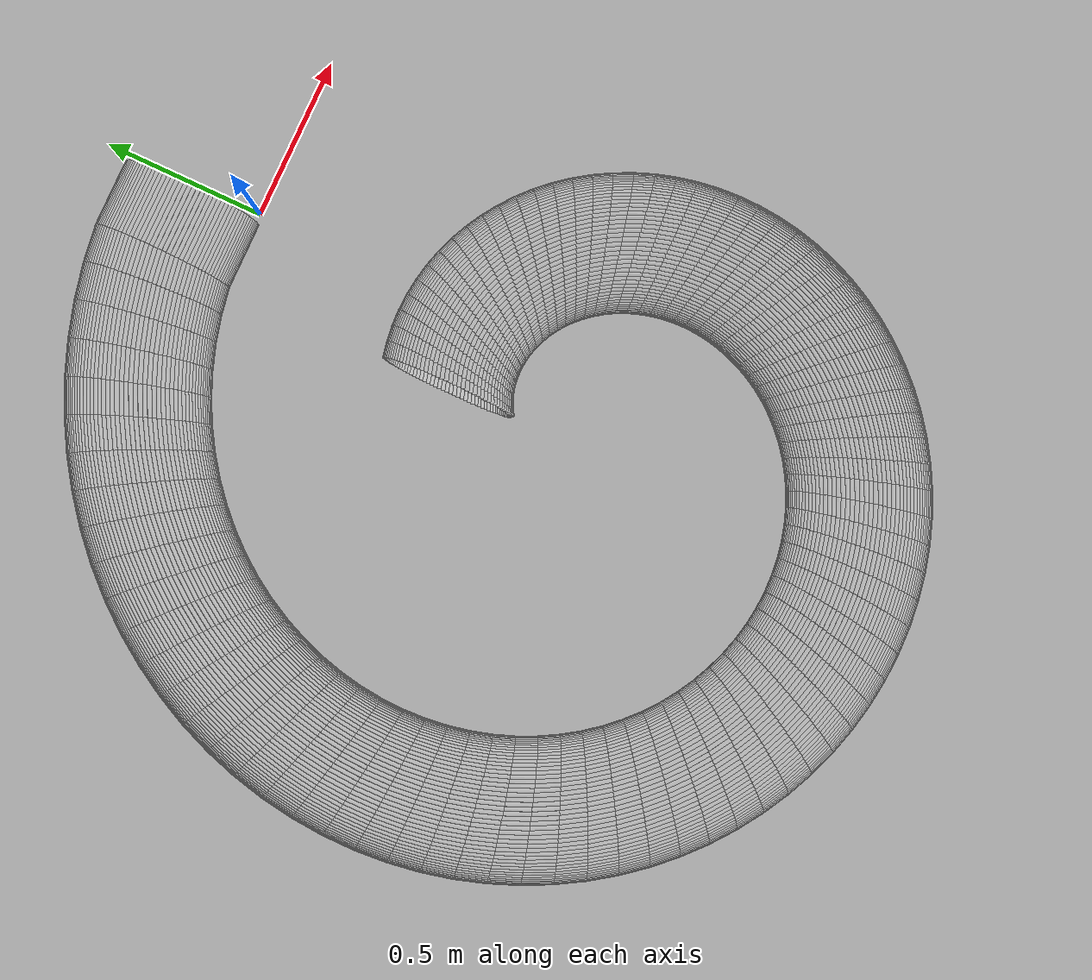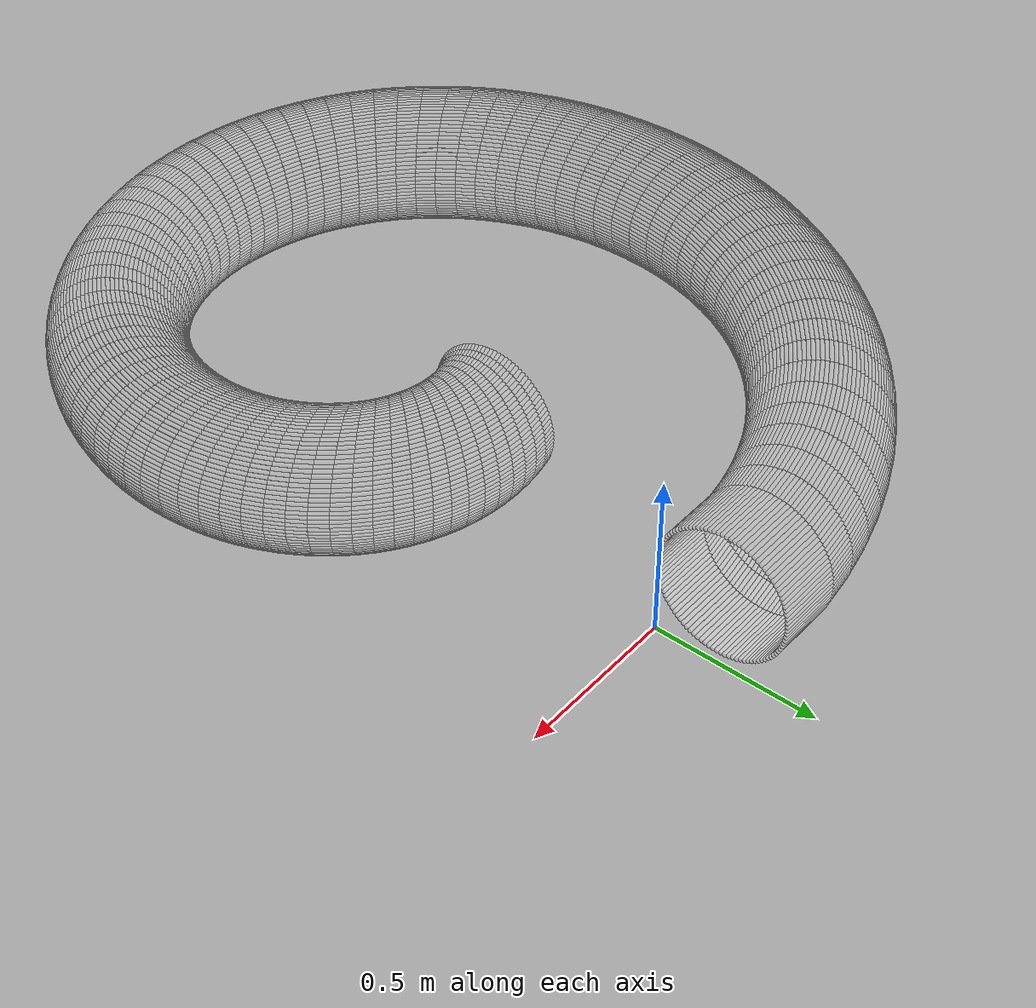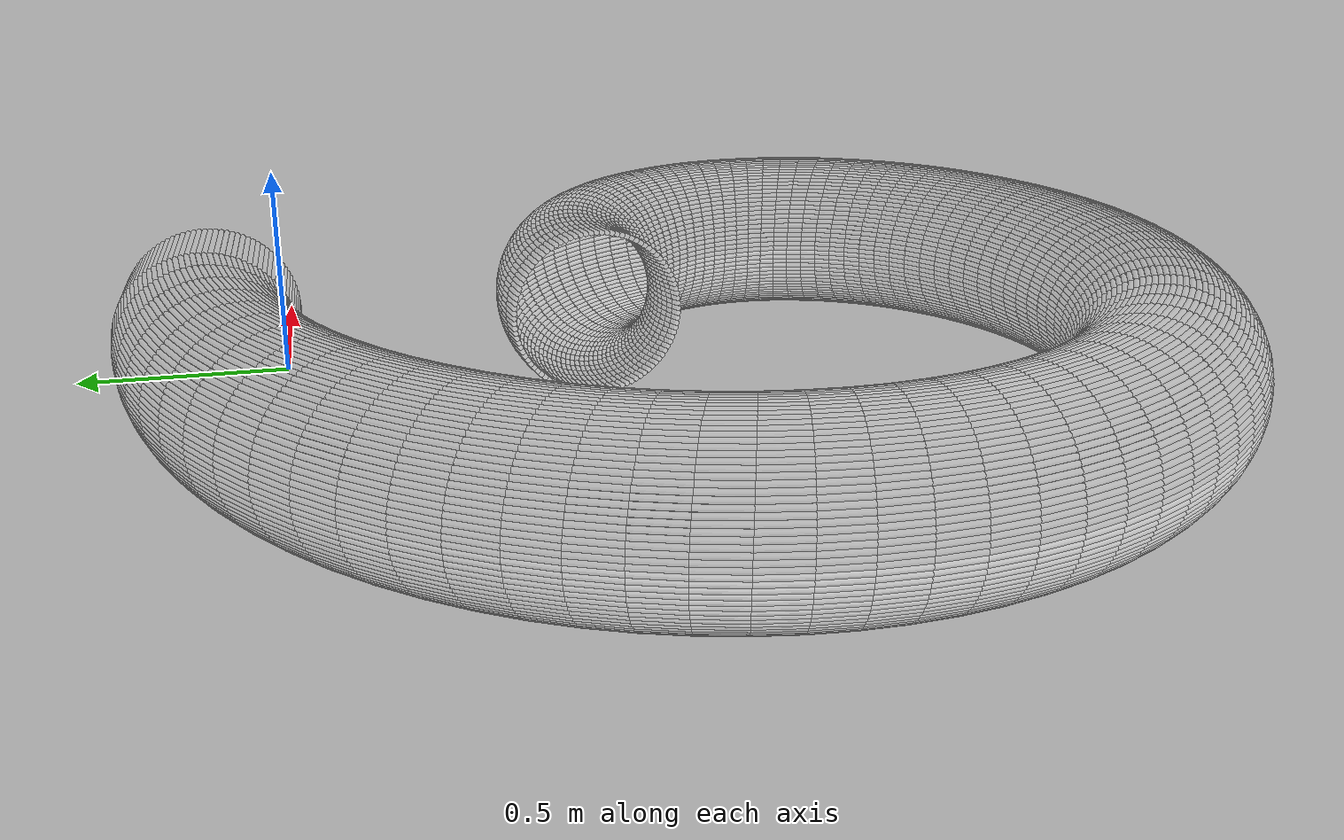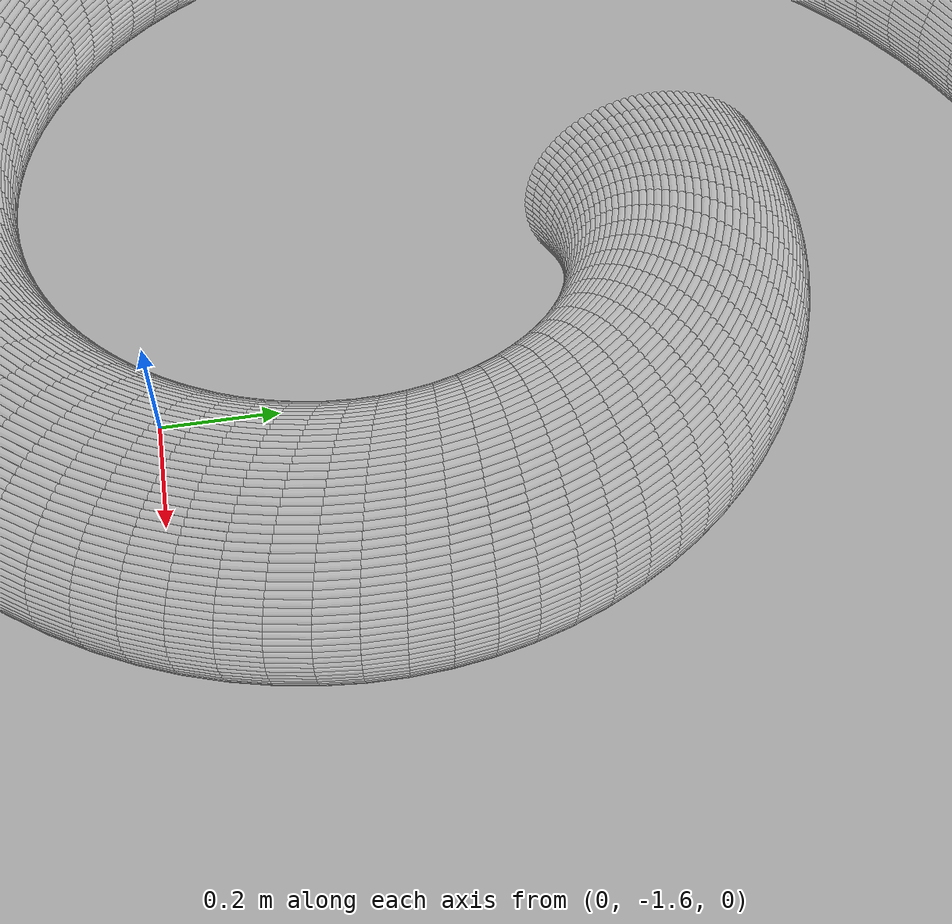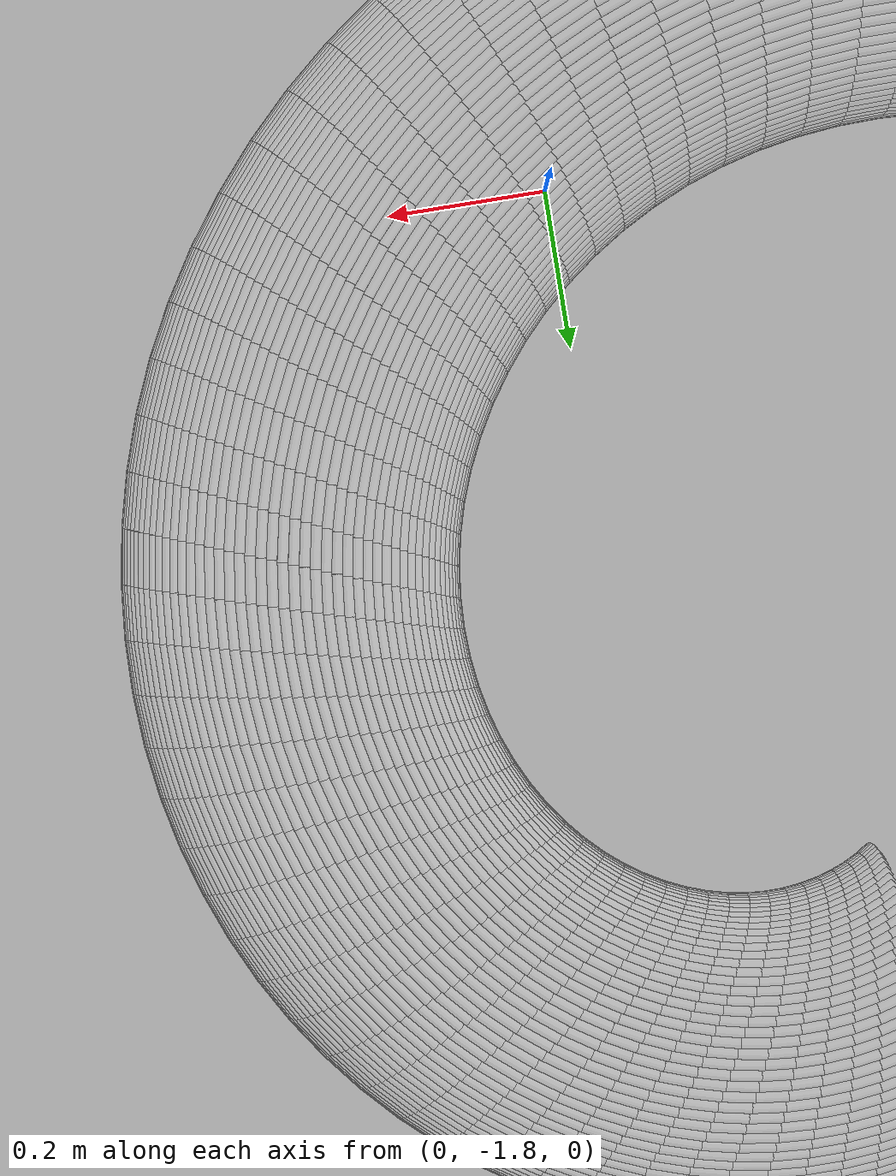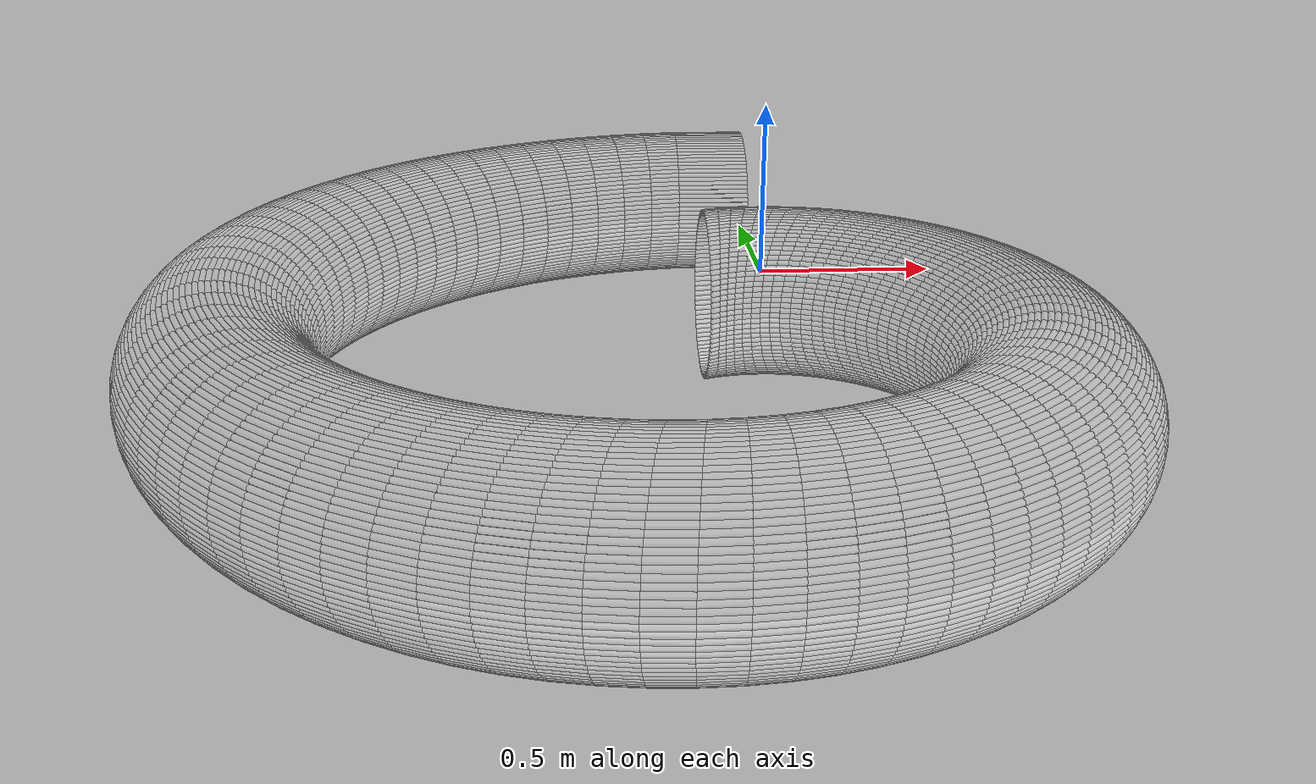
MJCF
<?xml version="1.0" encoding="utf-8"?>
<mujoco>
   <worldbody>
   <body pos="-0.25 -1.14 -0.02" euler="0 0 90">
      <geom euler=" 0 10 0 " fromto="1.5 -0.2 0.2 1.5 0 0.2" rgba="1 1 1 0.05"
            size="0.0062822"
            type="cylinder"/>
      <geom euler=" 0 20 0 " fromto="1.4996 -0.2 0.21256 1.4996 0 0.21256"
            rgba="1 1 1 0.05"
            size="0.0062822"
            type="cylinder"/>
      <geom euler=" 0 30 0 " fromto="1.4984 -0.2 0.22507 1.4984 0 0.22507"
            rgba="1 1 1 0.05"
            size="0.0062822"
            type="cylinder"/>
      <geom euler=" 0 40 0 " fromto="1.4965 -0.2 0.23748 1.4965 0 0.23748"
            rgba="1 1 1 0.05"
            size="0.0062822"
            type="cylinder"/>
      <geom euler=" 0 50 0 " fromto="1.4937 -0.2 0.24974 1.4937 0 0.24974"
            rgba="1 1 1 0.05"
            size="0.0062822"
            type="cylinder"/>
      <geom euler=" 0 60 0 " fromto="1.4902 -0.2 0.2618 1.4902 0 0.2618" rgba="1 1 1 0.05"
            size="0.0062822"
            type="cylinder"/>
      <geom euler=" 0 70 0 " fromto="1.486 -0.2 0.27362 1.486 0 0.27362" rgba="1 1 1 0.05"
            size="0.0062822"
            type="cylinder"/>
      <geom euler=" 0 80 0 " fromto="1.481 -0.2 0.28516 1.481 0 0.28516" rgba="1 1 1 0.05"
            size="0.0062822"
            type="cylinder"/>
      <geom euler=" 0 90 0 " fromto="1.4753 -0.2 0.29635 1.4753 0 0.29635"
            rgba="1 1 1 0.05"
            size="0.0062822"
            type="cylinder"/>
      <geom euler=" 0 100 0 " fromto="1.4689 -0.2 0.30717 1.4689 0 0.30717"
            rgba="1 1 1 0.05"
            size="0.0062822"
            type="cylinder"/>
      <geom euler=" 0 110 0 " fromto="1.4618 -0.2 0.31756 1.4618 0 0.31756"
            rgba="1 1 1 0.05"
            size="0.0062822"
            type="cylinder"/>
      <geom euler=" 0 120 0 " fromto="1.4541 -0.2 0.32748 1.4541 0 0.32748"
            rgba="1 1 1 0.05"
            size="0.0062822"
            type="cylinder"/>
      <geom euler=" 0 130 0 " fromto="1.4458 -0.2 0.33691 1.4458 0 0.33691"
            rgba="1 1 1 0.05"
            size="0.0062822"
            type="cylinder"/>
      <geom euler=" 0 140 0 " fromto="1.4369 -0.2 0.34579 1.4369 0 0.34579"
            rgba="1 1 1 0.05"
            size="0.0062822"
            type="cylinder"/>
      <geom euler=" 0 150 0 " fromto="1.4275 -0.2 0.3541 1.4275 0 0.3541" rgba="1 1 1 0.05"
            size="0.0062822"
            type="cylinder"/>
      <geom euler=" 0 160 0 " fromto="1.4176 -0.2 0.3618 1.4176 0 0.3618" rgba="1 1 1 0.05"
            size="0.0062822"
            type="cylinder"/>
      <geom euler=" 0 170 0 " fromto="1.4072 -0.2 0.36887 1.4072 0 0.36887"
            rgba="1 1 1 0.05"
            size="0.0062822"
            type="cylinder"/>
      <geom euler=" 0 180 0 " fromto="1.3964 -0.2 0.37526 1.3964 0 0.37526"
            rgba="1 1 1 0.05"
            size="0.0062822"
            type="cylinder"/>
      <geom euler=" 0 190 0 " fromto="1.3852 -0.2 0.38097 1.3852 0 0.38097"
            rgba="1 1 1 0.05"
            size="0.0062822"
            type="cylinder"/>
      <geom euler=" 0 200 0 " fromto="1.3736 -0.2 0.38596 1.3736 0 0.38596"
            rgba="1 1 1 0.05"
            size="0.0062822"
            type="cylinder"/>
      <geom euler=" 0 210 0 " fromto="1.3618 -0.2 0.39021 1.3618 0 0.39021"
            rgba="1 1 1 0.05"
            size="0.0062822"
            type="cylinder"/>
      <geom euler=" 0 220 0 " fromto="1.3497 -0.2 0.39372 1.3497 0 0.39372"
            rgba="1 1 1 0.05"
            size="0.0062822"
            type="cylinder"/>
      <geom euler=" 0 230 0 " fromto="1.3375 -0.2 0.39646 1.3375 0 0.39646"
            rgba="1 1 1 0.05"
            size="0.0062822"
            type="cylinder"/>
      <geom euler=" 0 240 0 " fromto="1.3251 -0.2 0.39842 1.3251 0 0.39842"
            rgba="1 1 1 0.05"
            size="0.0062822"
            type="cylinder"/>
      <geom euler=" 0 250 0 " fromto="1.3126 -0.2 0.39961 1.3126 0 0.39961"
            rgba="1 1 1 0.05"
            size="0.0062822"
            type="cylinder"/>
      <geom euler=" 0 260 0 " fromto="1.3 -0.2 0.4 1.3 0 0.4" rgba="1 1 1 0.05"
            size="0.0062822"
            type="cylinder"/>
      <geom euler=" 0 270 0 " fromto="1.2874 -0.2 0.39961 1.2874 0 0.39961"
            rgba="1 1 1 0.05"
            size="0.0062822"
            type="cylinder"/>
      <geom euler=" 0 280 0 " fromto="1.2749 -0.2 0.39842 1.2749 0 0.39842"
            rgba="1 1 1 0.05"
            size="0.0062822"
            type="cylinder"/>
      <geom euler=" 0 290 0 " fromto="1.2625 -0.2 0.39646 1.2625 0 0.39646"
            rgba="1 1 1 0.05"
            size="0.0062822"
            type="cylinder"/>
      <geom euler=" 0 300 0 " fromto="1.2503 -0.2 0.39372 1.2503 0 0.39372"
            rgba="1 1 1 0.05"
            size="0.0062822"
            type="cylinder"/>
      <geom euler=" 0 310 0 " fromto="1.2382 -0.2 0.39021 1.2382 0 0.39021"
            rgba="1 1 1 0.05"
            size="0.0062822"
            type="cylinder"/>
      <geom euler=" 0 320 0 " fromto="1.2264 -0.2 0.38596 1.2264 0 0.38596"
            rgba="1 1 1 0.05"
            size="0.0062822"
            type="cylinder"/>
      <geom euler=" 0 330 0 " fromto="1.2148 -0.2 0.38097 1.2148 0 0.38097"
            rgba="1 1 1 0.05"
            size="0.0062822"
            type="cylinder"/>
      <geom euler=" 0 340 0 " fromto="1.2036 -0.2 0.37526 1.2036 0 0.37526"
            rgba="1 1 1 0.05"
            size="0.0062822"
            type="cylinder"/>
      <geom euler=" 0 350 0 " fromto="1.1928 -0.2 0.36887 1.1928 0 0.36887"
            rgba="1 1 1 0.05"
            size="0.0062822"
            type="cylinder"/>
      <geom euler=" 0 360 0 " fromto="1.1824 -0.2 0.3618 1.1824 0 0.3618" rgba="1 1 1 0.05"
            size="0.0062822"
            type="cylinder"/>
      <geom euler=" 0 370 0 " fromto="1.1725 -0.2 0.3541 1.1725 0 0.3541" rgba="1 1 1 0.05"
            size="0.0062822"
            type="cylinder"/>
      <geom euler=" 0 380 0 " fromto="1.1631 -0.2 0.34579 1.1631 0 0.34579"
            rgba="1 1 1 0.05"
            size="0.0062822"
            type="cylinder"/>
      <geom euler=" 0 390 0 " fromto="1.1542 -0.2 0.33691 1.1542 0 0.33691"
            rgba="1 1 1 0.05"
            size="0.0062822"
            type="cylinder"/>
      <geom euler=" 0 400 0 " fromto="1.1459 -0.2 0.32748 1.1459 0 0.32748"
            rgba="1 1 1 0.05"
            size="0.0062822"
            type="cylinder"/>
      <geom euler=" 0 410 0 " fromto="1.1382 -0.2 0.31756 1.1382 0 0.31756"
            rgba="1 1 1 0.05"
            size="0.0062822"
            type="cylinder"/>
      <geom euler=" 0 420 0 " fromto="1.1311 -0.2 0.30717 1.1311 0 0.30717"
            rgba="1 1 1 0.05"
            size="0.0062822"
            type="cylinder"/>
      <geom euler=" 0 430 0 " fromto="1.1247 -0.2 0.29635 1.1247 0 0.29635"
            rgba="1 1 1 0.05"
            size="0.0062822"
            type="cylinder"/>
      <geom euler=" 0 440 0 " fromto="1.119 -0.2 0.28516 1.119 0 0.28516" rgba="1 1 1 0.05"
            size="0.0062822"
            type="cylinder"/>
      <geom euler=" 0 450 0 " fromto="1.114 -0.2 0.27362 1.114 0 0.27362" rgba="1 1 1 0.05"
            size="0.0062822"
            type="cylinder"/>
      <geom euler=" 0 460 0 " fromto="1.1098 -0.2 0.2618 1.1098 0 0.2618" rgba="1 1 1 0.05"
            size="0.0062822"
            type="cylinder"/>
      <geom euler=" 0 470 0 " fromto="1.1063 -0.2 0.24974 1.1063 0 0.24974"
            rgba="1 1 1 0.05"
            size="0.0062822"
            type="cylinder"/>
      <geom euler=" 0 480 0 " fromto="1.1035 -0.2 0.23748 1.1035 0 0.23748"
            rgba="1 1 1 0.05"
            size="0.0062822"
            type="cylinder"/>
      <geom euler=" 0 490 0 " fromto="1.1016 -0.2 0.22507 1.1016 0 0.22507"
            rgba="1 1 1 0.05"
            size="0.0062822"
            type="cylinder"/>
      <geom euler=" 0 500 0 " fromto="1.1004 -0.2 0.21256 1.1004 0 0.21256"
            rgba="1 1 1 0.05"
            size="0.0062822"
            type="cylinder"/>
      <geom euler=" 0 510 0 " fromto="1.1 -0.2 0.2 1.1 0 0.2" rgba="1 1 1 0.05"
            size="0.0062822"
            type="cylinder"/>
      <geom euler=" 0 520 0 " fromto="1.1004 -0.2 0.18744 1.1004 0 0.18744"
            rgba="1 1 1 0.35"
            size="0.0062822"
            type="cylinder"/>
      <geom euler=" 0 530 0 " fromto="1.1016 -0.2 0.17493 1.1016 0 0.17493"
            rgba="1 1 1 0.35"
            size="0.0062822"
            type="cylinder"/>
      <geom euler=" 0 540 0 " fromto="1.1035 -0.2 0.16252 1.1035 0 0.16252"
            rgba="1 1 1 0.35"
            size="0.0062822"
            type="cylinder"/>
      <geom euler=" 0 550 0 " fromto="1.1063 -0.2 0.15026 1.1063 0 0.15026"
            rgba="1 1 1 0.35"
            size="0.0062822"
            type="cylinder"/>
      <geom euler=" 0 560 0 " fromto="1.1098 -0.2 0.1382 1.1098 0 0.1382" rgba="1 1 1 0.35"
            size="0.0062822"
            type="cylinder"/>
      <geom euler=" 0 570 0 " fromto="1.114 -0.2 0.12638 1.114 0 0.12638" rgba="1 1 1 0.35"
            size="0.0062822"
            type="cylinder"/>
      <geom euler=" 0 580 0 " fromto="1.119 -0.2 0.11484 1.119 0 0.11484" rgba="1 1 1 0.35"
            size="0.0062822"
            type="cylinder"/>
      <geom euler=" 0 590 0 " fromto="1.1247 -0.2 0.10365 1.1247 0 0.10365"
            rgba="1 1 1 0.35"
            size="0.0062822"
            type="cylinder"/>
      <geom euler=" 0 600 0 " fromto="1.1311 -0.2 0.092835 1.1311 0 0.092835"
            rgba="1 1 1 0.35"
            size="0.0062822"
            type="cylinder"/>
      <geom euler=" 0 610 0 " fromto="1.1382 -0.2 0.082443 1.1382 0 0.082443"
            rgba="1 1 1 0.35"
            size="0.0062822"
            type="cylinder"/>
      <geom euler=" 0 620 0 " fromto="1.1459 -0.2 0.072515 1.1459 0 0.072515"
            rgba="1 1 1 0.35"
            size="0.0062822"
            type="cylinder"/>
      <geom euler=" 0 630 0 " fromto="1.1542 -0.2 0.063091 1.1542 0 0.063091"
            rgba="1 1 1 0.35"
            size="0.0062822"
            type="cylinder"/>
      <geom euler=" 0 640 0 " fromto="1.1631 -0.2 0.054206 1.1631 0 0.054206"
            rgba="1 1 1 0.35"
            size="0.0062822"
            type="cylinder"/>
      <geom euler=" 0 650 0 " fromto="1.1725 -0.2 0.045897 1.1725 0 0.045897"
            rgba="1 1 1 0.35"
            size="0.0062822"
            type="cylinder"/>
      <geom euler=" 0 660 0 " fromto="1.1824 -0.2 0.038197 1.1824 0 0.038197"
            rgba="1 1 1 0.35"
            size="0.0062822"
            type="cylinder"/>
      <geom euler=" 0 670 0 " fromto="1.1928 -0.2 0.031134 1.1928 0 0.031134"
            rgba="1 1 1 0.35"
            size="0.0062822"
            type="cylinder"/>
      <geom euler=" 0 680 0 " fromto="1.2036 -0.2 0.024739 1.2036 0 0.024739"
            rgba="1 1 1 0.35"
            size="0.0062822"
            type="cylinder"/>
      <geom euler=" 0 690 0 " fromto="1.2148 -0.2 0.019035 1.2148 0 0.019035"
            rgba="1 1 1 0.35"
            size="0.0062822"
            type="cylinder"/>
      <geom euler=" 0 700 0 " fromto="1.2264 -0.2 0.014045 1.2264 0 0.014045"
            rgba="1 1 1 0.35"
            size="0.0062822"
            type="cylinder"/>
      <geom euler=" 0 710 0 " fromto="1.2382 -0.2 0.0097887 1.2382 0 0.0097887"
            rgba="1 1 1 0.35"
            size="0.0062822"
            type="cylinder"/>
      <geom euler=" 0 720 0 " fromto="1.2503 -0.2 0.0062834 1.2503 0 0.0062834"
            rgba="1 1 1 0.35"
            size="0.0062822"
            type="cylinder"/>
      <geom euler=" 0 730 0 " fromto="1.2625 -0.2 0.0035425 1.2625 0 0.0035425"
            rgba="1 1 1 0.35"
            size="0.0062822"
            type="cylinder"/>
      <geom euler=" 0 740 0 " fromto="1.2749 -0.2 0.0015771 1.2749 0 0.0015771"
            rgba="1 1 1 0.35"
            size="0.0062822"
            type="cylinder"/>
      <geom euler=" 0 750 0 " fromto="1.2874 -0.2 0.00039465 1.2874 0 0.00039465"
            rgba="1 1 1 0.35"
            size="0.0062822"
            type="cylinder"/>
      <geom euler=" 0 760 0 " fromto="1.3 -0.2 0 1.3 0 0" rgba="1 1 1 0.35"
            size="0.0062822"
            type="cylinder"/>
      <geom euler=" 0 770 0 " fromto="1.3126 -0.2 0.00039465 1.3126 0 0.00039465"
            rgba="1 1 1 0.35"
            size="0.0062822"
            type="cylinder"/>
      <geom euler=" 0 780 0 " fromto="1.3251 -0.2 0.0015771 1.3251 0 0.0015771"
            rgba="1 1 1 0.35"
            size="0.0062822"
            type="cylinder"/>
      <geom euler=" 0 790 0 " fromto="1.3375 -0.2 0.0035425 1.3375 0 0.0035425"
            rgba="1 1 1 0.35"
            size="0.0062822"
            type="cylinder"/>
      <geom euler=" 0 800 0 " fromto="1.3497 -0.2 0.0062834 1.3497 0 0.0062834"
            rgba="1 1 1 0.35"
            size="0.0062822"
            type="cylinder"/>
      <geom euler=" 0 810 0 " fromto="1.3618 -0.2 0.0097887 1.3618 0 0.0097887"
            rgba="1 1 1 0.35"
            size="0.0062822"
            type="cylinder"/>
      <geom euler=" 0 820 0 " fromto="1.3736 -0.2 0.014045 1.3736 0 0.014045"
            rgba="1 1 1 0.35"
            size="0.0062822"
            type="cylinder"/>
      <geom euler=" 0 830 0 " fromto="1.3852 -0.2 0.019035 1.3852 0 0.019035"
            rgba="1 1 1 0.35"
            size="0.0062822"
            type="cylinder"/>
      <geom euler=" 0 840 0 " fromto="1.3964 -0.2 0.024739 1.3964 0 0.024739"
            rgba="1 1 1 0.35"
            size="0.0062822"
            type="cylinder"/>
      <geom euler=" 0 850 0 " fromto="1.4072 -0.2 0.031134 1.4072 0 0.031134"
            rgba="1 1 1 0.35"
            size="0.0062822"
            type="cylinder"/>
      <geom euler=" 0 860 0 " fromto="1.4176 -0.2 0.038197 1.4176 0 0.038197"
            rgba="1 1 1 0.35"
            size="0.0062822"
            type="cylinder"/>
      <geom euler=" 0 870 0 " fromto="1.4275 -0.2 0.045897 1.4275 0 0.045897"
            rgba="1 1 1 0.35"
            size="0.0062822"
            type="cylinder"/>
      <geom euler=" 0 880 0 " fromto="1.4369 -0.2 0.054206 1.4369 0 0.054206"
            rgba="1 1 1 0.35"
            size="0.0062822"
            type="cylinder"/>
      <geom euler=" 0 890 0 " fromto="1.4458 -0.2 0.063091 1.4458 0 0.063091"
            rgba="1 1 1 0.35"
            size="0.0062822"
            type="cylinder"/>
      <geom euler=" 0 900 0 " fromto="1.4541 -0.2 0.072515 1.4541 0 0.072515"
            rgba="1 1 1 0.35"
            size="0.0062822"
            type="cylinder"/>
      <geom euler=" 0 910 0 " fromto="1.4618 -0.2 0.082443 1.4618 0 0.082443"
            rgba="1 1 1 0.35"
            size="0.0062822"
            type="cylinder"/>
      <geom euler=" 0 920 0 " fromto="1.4689 -0.2 0.092835 1.4689 0 0.092835"
            rgba="1 1 1 0.35"
            size="0.0062822"
            type="cylinder"/>
      <geom euler=" 0 930 0 " fromto="1.4753 -0.2 0.10365 1.4753 0 0.10365"
            rgba="1 1 1 0.35"
            size="0.0062822"
            type="cylinder"/>
      <geom euler=" 0 940 0 " fromto="1.481 -0.2 0.11484 1.481 0 0.11484" rgba="1 1 1 0.35"
            size="0.0062822"
            type="cylinder"/>
      <geom euler=" 0 950 0 " fromto="1.486 -0.2 0.12638 1.486 0 0.12638" rgba="1 1 1 0.35"
            size="0.0062822"
            type="cylinder"/>
      <geom euler=" 0 960 0 " fromto="1.4902 -0.2 0.1382 1.4902 0 0.1382" rgba="1 1 1 0.35"
            size="0.0062822"
            type="cylinder"/>
      <geom euler=" 0 970 0 " fromto="1.4937 -0.2 0.15026 1.4937 0 0.15026"
            rgba="1 1 1 0.35"
            size="0.0062822"
            type="cylinder"/>
      <geom euler=" 0 980 0 " fromto="1.4965 -0.2 0.16252 1.4965 0 0.16252"
            rgba="1 1 1 0.35"
            size="0.0062822"
            type="cylinder"/>
      <geom euler=" 0 990 0 " fromto="1.4984 -0.2 0.17493 1.4984 0 0.17493"
            rgba="1 1 1 0.35"
            size="0.0062822"
            type="cylinder"/>
      <geom euler=" 0 1000 0 " fromto="1.4996 -0.2 0.18744 1.4996 0 0.18744"
            rgba="1 1 1 0.35"
            size="0.0062822"
            type="cylinder"/>
      <geom euler=" 0 10 0 " fromto="1.5 0 0.2 1.4851 0.11129 0.2" rgba="1 1 1 0.05"
            size="0.0062822"
            type="cylinder"/>
      <geom euler=" 0 20 0 " fromto="1.4996 0 0.21256 1.4847 0.11126 0.21256"
            rgba="1 1 1 0.05"
            size="0.0062822"
            type="cylinder"/>
      <geom euler=" 0 30 0 " fromto="1.4984 0 0.22507 1.4835 0.11118 0.22507"
            rgba="1 1 1 0.05"
            size="0.0062822"
            type="cylinder"/>
      <geom euler=" 0 40 0 " fromto="1.4965 0 0.23748 1.4816 0.11103 0.23748"
            rgba="1 1 1 0.05"
            size="0.0062822"
            type="cylinder"/>
      <geom euler=" 0 50 0 " fromto="1.4937 0 0.24974 1.4789 0.11082 0.24974"
            rgba="1 1 1 0.05"
            size="0.0062822"
            type="cylinder"/>
      <geom euler=" 0 60 0 " fromto="1.4902 0 0.2618 1.4754 0.11056 0.2618"
            rgba="1 1 1 0.05"
            size="0.0062822"
            type="cylinder"/>
      <geom euler=" 0 70 0 " fromto="1.486 0 0.27362 1.4711 0.11024 0.27362"
            rgba="1 1 1 0.05"
            size="0.0062822"
            type="cylinder"/>
      <geom euler=" 0 80 0 " fromto="1.481 0 0.28516 1.4661 0.10987 0.28516"
            rgba="1 1 1 0.05"
            size="0.0062822"
            type="cylinder"/>
      <geom euler=" 0 90 0 " fromto="1.4753 0 0.29635 1.4605 0.10945 0.29635"
            rgba="1 1 1 0.05"
            size="0.0062822"
            type="cylinder"/>
      <geom euler=" 0 100 0 " fromto="1.4689 0 0.30717 1.4541 0.10897 0.30717"
            rgba="1 1 1 0.05"
            size="0.0062822"
            type="cylinder"/>
      <geom euler=" 0 110 0 " fromto="1.4618 0 0.31756 1.447 0.10844 0.31756"
            rgba="1 1 1 0.05"
            size="0.0062822"
            type="cylinder"/>
      <geom euler=" 0 120 0 " fromto="1.4541 0 0.32748 1.4394 0.10786 0.32748"
            rgba="1 1 1 0.05"
            size="0.0062822"
            type="cylinder"/>
      <geom euler=" 0 130 0 " fromto="1.4458 0 0.33691 1.4311 0.10724 0.33691"
            rgba="1 1 1 0.05"
            size="0.0062822"
            type="cylinder"/>
      <geom euler=" 0 140 0 " fromto="1.4369 0 0.34579 1.4222 0.10658 0.34579"
            rgba="1 1 1 0.05"
            size="0.0062822"
            type="cylinder"/>
      <geom euler=" 0 150 0 " fromto="1.4275 0 0.3541 1.4128 0.10588 0.3541"
            rgba="1 1 1 0.05"
            size="0.0062822"
            type="cylinder"/>
      <geom euler=" 0 160 0 " fromto="1.4176 0 0.3618 1.4029 0.10513 0.3618"
            rgba="1 1 1 0.05"
            size="0.0062822"
            type="cylinder"/>
      <geom euler=" 0 170 0 " fromto="1.4072 0 0.36887 1.3925 0.10436 0.36887"
            rgba="1 1 1 0.05"
            size="0.0062822"
            type="cylinder"/>
      <geom euler=" 0 180 0 " fromto="1.3964 0 0.37526 1.3818 0.10355 0.37526"
            rgba="1 1 1 0.05"
            size="0.0062822"
            type="cylinder"/>
      <geom euler=" 0 190 0 " fromto="1.3852 0 0.38097 1.3706 0.10271 0.38097"
            rgba="1 1 1 0.05"
            size="0.0062822"
            type="cylinder"/>
      <geom euler=" 0 200 0 " fromto="1.3736 0 0.38596 1.3591 0.10185 0.38596"
            rgba="1 1 1 0.05"
            size="0.0062822"
            type="cylinder"/>
      <geom euler=" 0 210 0 " fromto="1.3618 0 0.39021 1.3473 0.10097 0.39021"
            rgba="1 1 1 0.05"
            size="0.0062822"
            type="cylinder"/>
      <geom euler=" 0 220 0 " fromto="1.3497 0 0.39372 1.3353 0.10007 0.39372"
            rgba="1 1 1 0.05"
            size="0.0062822"
            type="cylinder"/>
      <geom euler=" 0 230 0 " fromto="1.3375 0 0.39646 1.3231 0.099149 0.39646"
            rgba="1 1 1 0.05"
            size="0.0062822"
            type="cylinder"/>
      <geom euler=" 0 240 0 " fromto="1.3251 0 0.39842 1.3107 0.098222 0.39842"
            rgba="1 1 1 0.05"
            size="0.0062822"
            type="cylinder"/>
      <geom euler=" 0 250 0 " fromto="1.3126 0 0.39961 1.2982 0.097287 0.39961"
            rgba="1 1 1 0.05"
            size="0.0062822"
            type="cylinder"/>
      <geom euler=" 0 260 0 " fromto="1.3 0 0.4 1.2857 0.096348 0.4" rgba="1 1 1 0.05"
            size="0.0062822"
            type="cylinder"/>
      <geom euler=" 0 270 0 " fromto="1.2874 0 0.39961 1.2732 0.09541 0.39961"
            rgba="1 1 1 0.05"
            size="0.0062822"
            type="cylinder"/>
      <geom euler=" 0 280 0 " fromto="1.2749 0 0.39842 1.2607 0.094475 0.39842"
            rgba="1 1 1 0.05"
            size="0.0062822"
            type="cylinder"/>
      <geom euler=" 0 290 0 " fromto="1.2625 0 0.39646 1.2483 0.093548 0.39646"
            rgba="1 1 1 0.05"
            size="0.0062822"
            type="cylinder"/>
      <geom euler=" 0 300 0 " fromto="1.2503 0 0.39372 1.2361 0.092632 0.39372"
            rgba="1 1 1 0.05"
            size="0.0062822"
            type="cylinder"/>
      <geom euler=" 0 310 0 " fromto="1.2382 0 0.39021 1.2241 0.09173 0.39021"
            rgba="1 1 1 0.05"
            size="0.0062822"
            type="cylinder"/>
      <geom euler=" 0 320 0 " fromto="1.2264 0 0.38596 1.2123 0.090846 0.38596"
            rgba="1 1 1 0.05"
            size="0.0062822"
            type="cylinder"/>
      <geom euler=" 0 330 0 " fromto="1.2148 0 0.38097 1.2008 0.089985 0.38097"
            rgba="1 1 1 0.05"
            size="0.0062822"
            type="cylinder"/>
      <geom euler=" 0 340 0 " fromto="1.2036 0 0.37526 1.1896 0.089148 0.37526"
            rgba="1 1 1 0.05"
            size="0.0062822"
            type="cylinder"/>
      <geom euler=" 0 350 0 " fromto="1.1928 0 0.36887 1.1788 0.08834 0.36887"
            rgba="1 1 1 0.05"
            size="0.0062822"
            type="cylinder"/>
      <geom euler=" 0 360 0 " fromto="1.1824 0 0.3618 1.1685 0.087563 0.3618"
            rgba="1 1 1 0.05"
            size="0.0062822"
            type="cylinder"/>
      <geom euler=" 0 370 0 " fromto="1.1725 0 0.3541 1.1586 0.086821 0.3541"
            rgba="1 1 1 0.05"
            size="0.0062822"
            type="cylinder"/>
      <geom euler=" 0 380 0 " fromto="1.1631 0 0.34579 1.1492 0.086117 0.34579"
            rgba="1 1 1 0.05"
            size="0.0062822"
            type="cylinder"/>
      <geom euler=" 0 390 0 " fromto="1.1542 0 0.33691 1.1403 0.085453 0.33691"
            rgba="1 1 1 0.05"
            size="0.0062822"
            type="cylinder"/>
      <geom euler=" 0 400 0 " fromto="1.1459 0 0.32748 1.132 0.084832 0.32748"
            rgba="1 1 1 0.05"
            size="0.0062822"
            type="cylinder"/>
      <geom euler=" 0 410 0 " fromto="1.1382 0 0.31756 1.1243 0.084257 0.31756"
            rgba="1 1 1 0.05"
            size="0.0062822"
            type="cylinder"/>
      <geom euler=" 0 420 0 " fromto="1.1311 0 0.30717 1.1173 0.083729 0.30717"
            rgba="1 1 1 0.05"
            size="0.0062822"
            type="cylinder"/>
      <geom euler=" 0 430 0 " fromto="1.1247 0 0.29635 1.1109 0.083251 0.29635"
            rgba="1 1 1 0.05"
            size="0.0062822"
            type="cylinder"/>
      <geom euler=" 0 440 0 " fromto="1.119 0 0.28516 1.1052 0.082825 0.28516"
            rgba="1 1 1 0.05"
            size="0.0062822"
            type="cylinder"/>
      <geom euler=" 0 450 0 " fromto="1.114 0 0.27362 1.1002 0.082452 0.27362"
            rgba="1 1 1 0.05"
            size="0.0062822"
            type="cylinder"/>
      <geom euler=" 0 460 0 " fromto="1.1098 0 0.2618 1.096 0.082134 0.2618"
            rgba="1 1 1 0.05"
            size="0.0062822"
            type="cylinder"/>
      <geom euler=" 0 470 0 " fromto="1.1063 0 0.24974 1.0925 0.081872 0.24974"
            rgba="1 1 1 0.05"
            size="0.0062822"
            type="cylinder"/>
      <geom euler=" 0 480 0 " fromto="1.1035 0 0.23748 1.0898 0.081667 0.23748"
            rgba="1 1 1 0.05"
            size="0.0062822"
            type="cylinder"/>
      <geom euler=" 0 490 0 " fromto="1.1016 0 0.22507 1.0878 0.08152 0.22507"
            rgba="1 1 1 0.05"
            size="0.0062822"
            type="cylinder"/>
      <geom euler=" 0 500 0 " fromto="1.1004 0 0.21256 1.0866 0.081432 0.21256"
            rgba="1 1 1 0.05"
            size="0.0062822"
            type="cylinder"/>
      <geom euler=" 0 510 0 " fromto="1.1 0 0.2 1.0862 0.081402 0.2" rgba="1 1 1 0.05"
            size="0.0062822"
            type="cylinder"/>
      <geom euler=" 0 520 0 " fromto="1.1004 0 0.18744 1.0866 0.081432 0.18744"
            rgba="1 1 1 0.35"
            size="0.0062822"
            type="cylinder"/>
      <geom euler=" 0 530 0 " fromto="1.1016 0 0.17493 1.0878 0.08152 0.17493"
            rgba="1 1 1 0.35"
            size="0.0062822"
            type="cylinder"/>
      <geom euler=" 0 540 0 " fromto="1.1035 0 0.16252 1.0898 0.081667 0.16252"
            rgba="1 1 1 0.35"
            size="0.0062822"
            type="cylinder"/>
      <geom euler=" 0 550 0 " fromto="1.1063 0 0.15026 1.0925 0.081872 0.15026"
            rgba="1 1 1 0.35"
            size="0.0062822"
            type="cylinder"/>
      <geom euler=" 0 560 0 " fromto="1.1098 0 0.1382 1.096 0.082134 0.1382"
            rgba="1 1 1 0.35"
            size="0.0062822"
            type="cylinder"/>
      <geom euler=" 0 570 0 " fromto="1.114 0 0.12638 1.1002 0.082452 0.12638"
            rgba="1 1 1 0.35"
            size="0.0062822"
            type="cylinder"/>
      <geom euler=" 0 580 0 " fromto="1.119 0 0.11484 1.1052 0.082825 0.11484"
            rgba="1 1 1 0.35"
            size="0.0062822"
            type="cylinder"/>
      <geom euler=" 0 590 0 " fromto="1.1247 0 0.10365 1.1109 0.083251 0.10365"
            rgba="1 1 1 0.35"
            size="0.0062822"
            type="cylinder"/>
      <geom euler=" 0 600 0 " fromto="1.1311 0 0.092835 1.1173 0.083729 0.092835"
            rgba="1 1 1 0.35"
            size="0.0062822"
            type="cylinder"/>
      <geom euler=" 0 610 0 " fromto="1.1382 0 0.082443 1.1243 0.084257 0.082443"
            rgba="1 1 1 0.35"
            size="0.0062822"
            type="cylinder"/>
      <geom euler=" 0 620 0 " fromto="1.1459 0 0.072515 1.132 0.084832 0.072515"
            rgba="1 1 1 0.35"
            size="0.0062822"
            type="cylinder"/>
      <geom euler=" 0 630 0 " fromto="1.1542 0 0.063091 1.1403 0.085453 0.063091"
            rgba="1 1 1 0.35"
            size="0.0062822"
            type="cylinder"/>
      <geom euler=" 0 640 0 " fromto="1.1631 0 0.054206 1.1492 0.086117 0.054206"
            rgba="1 1 1 0.35"
            size="0.0062822"
            type="cylinder"/>
      <geom euler=" 0 650 0 " fromto="1.1725 0 0.045897 1.1586 0.086821 0.045897"
            rgba="1 1 1 0.35"
            size="0.0062822"
            type="cylinder"/>
      <geom euler=" 0 660 0 " fromto="1.1824 0 0.038197 1.1685 0.087563 0.038197"
            rgba="1 1 1 0.35"
            size="0.0062822"
            type="cylinder"/>
      <geom euler=" 0 670 0 " fromto="1.1928 0 0.031134 1.1788 0.08834 0.031134"
            rgba="1 1 1 0.35"
            size="0.0062822"
            type="cylinder"/>
      <geom euler=" 0 680 0 " fromto="1.2036 0 0.024739 1.1896 0.089148 0.024739"
            rgba="1 1 1 0.35"
            size="0.0062822"
            type="cylinder"/>
      <geom euler=" 0 690 0 " fromto="1.2148 0 0.019035 1.2008 0.089985 0.019035"
            rgba="1 1 1 0.35"
            size="0.0062822"
            type="cylinder"/>
      <geom euler=" 0 700 0 " fromto="1.2264 0 0.014045 1.2123 0.090846 0.014045"
            rgba="1 1 1 0.35"
            size="0.0062822"
            type="cylinder"/>
      <geom euler=" 0 710 0 " fromto="1.2382 0 0.0097887 1.2241 0.09173 0.0097887"
            rgba="1 1 1 0.35"
            size="0.0062822"
            type="cylinder"/>
      <geom euler=" 0 720 0 " fromto="1.2503 0 0.0062834 1.2361 0.092632 0.0062834"
            rgba="1 1 1 0.35"
            size="0.0062822"
            type="cylinder"/>
      <geom euler=" 0 730 0 " fromto="1.2625 0 0.0035425 1.2483 0.093548 0.0035425"
            rgba="1 1 1 0.35"
            size="0.0062822"
            type="cylinder"/>
      <geom euler=" 0 740 0 " fromto="1.2749 0 0.0015771 1.2607 0.094475 0.0015771"
            rgba="1 1 1 0.35"
            size="0.0062822"
            type="cylinder"/>
      <geom euler=" 0 750 0 " fromto="1.2874 0 0.00039465 1.2732 0.09541 0.00039465"
            rgba="1 1 1 0.35"
            size="0.0062822"
            type="cylinder"/>
      <geom euler=" 0 760 0 " fromto="1.3 0 0 1.2857 0.096348 0" rgba="1 1 1 0.35"
            size="0.0062822"
            type="cylinder"/>
      <geom euler=" 0 770 0 " fromto="1.3126 0 0.00039465 1.2982 0.097287 0.00039465"
            rgba="1 1 1 0.35"
            size="0.0062822"
            type="cylinder"/>
      <geom euler=" 0 780 0 " fromto="1.3251 0 0.0015771 1.3107 0.098222 0.0015771"
            rgba="1 1 1 0.35"
            size="0.0062822"
            type="cylinder"/>
      <geom euler=" 0 790 0 " fromto="1.3375 0 0.0035425 1.3231 0.099149 0.0035425"
            rgba="1 1 1 0.35"
            size="0.0062822"
            type="cylinder"/>
      <geom euler=" 0 800 0 " fromto="1.3497 0 0.0062834 1.3353 0.10007 0.0062834"
            rgba="1 1 1 0.35"
            size="0.0062822"
            type="cylinder"/>
      <geom euler=" 0 810 0 " fromto="1.3618 0 0.0097887 1.3473 0.10097 0.0097887"
            rgba="1 1 1 0.35"
            size="0.0062822"
            type="cylinder"/>
      <geom euler=" 0 820 0 " fromto="1.3736 0 0.014045 1.3591 0.10185 0.014045"
            rgba="1 1 1 0.35"
            size="0.0062822"
            type="cylinder"/>
      <geom euler=" 0 830 0 " fromto="1.3852 0 0.019035 1.3706 0.10271 0.019035"
            rgba="1 1 1 0.35"
            size="0.0062822"
            type="cylinder"/>
      <geom euler=" 0 840 0 " fromto="1.3964 0 0.024739 1.3818 0.10355 0.024739"
            rgba="1 1 1 0.35"
            size="0.0062822"
            type="cylinder"/>
      <geom euler=" 0 850 0 " fromto="1.4072 0 0.031134 1.3925 0.10436 0.031134"
            rgba="1 1 1 0.35"
            size="0.0062822"
            type="cylinder"/>
      <geom euler=" 0 860 0 " fromto="1.4176 0 0.038197 1.4029 0.10513 0.038197"
            rgba="1 1 1 0.35"
            size="0.0062822"
            type="cylinder"/>
      <geom euler=" 0 870 0 " fromto="1.4275 0 0.045897 1.4128 0.10588 0.045897"
            rgba="1 1 1 0.35"
            size="0.0062822"
            type="cylinder"/>
      <geom euler=" 0 880 0 " fromto="1.4369 0 0.054206 1.4222 0.10658 0.054206"
            rgba="1 1 1 0.35"
            size="0.0062822"
            type="cylinder"/>
      <geom euler=" 0 890 0 " fromto="1.4458 0 0.063091 1.4311 0.10724 0.063091"
            rgba="1 1 1 0.35"
            size="0.0062822"
            type="cylinder"/>
      <geom euler=" 0 900 0 " fromto="1.4541 0 0.072515 1.4394 0.10786 0.072515"
            rgba="1 1 1 0.35"
            size="0.0062822"
            type="cylinder"/>
      <geom euler=" 0 910 0 " fromto="1.4618 0 0.082443 1.447 0.10844 0.082443"
            rgba="1 1 1 0.35"
            size="0.0062822"
            type="cylinder"/>
      <geom euler=" 0 920 0 " fromto="1.4689 0 0.092835 1.4541 0.10897 0.092835"
            rgba="1 1 1 0.35"
            size="0.0062822"
            type="cylinder"/>
      <geom euler=" 0 930 0 " fromto="1.4753 0 0.10365 1.4605 0.10945 0.10365"
            rgba="1 1 1 0.35"
            size="0.0062822"
            type="cylinder"/>
      <geom euler=" 0 940 0 " fromto="1.481 0 0.11484 1.4661 0.10987 0.11484"
            rgba="1 1 1 0.35"
            size="0.0062822"
            type="cylinder"/>
      <geom euler=" 0 950 0 " fromto="1.486 0 0.12638 1.4711 0.11024 0.12638"
            rgba="1 1 1 0.35"
            size="0.0062822"
            type="cylinder"/>
      <geom euler=" 0 960 0 " fromto="1.4902 0 0.1382 1.4754 0.11056 0.1382"
            rgba="1 1 1 0.35"
            size="0.0062822"
            type="cylinder"/>
      <geom euler=" 0 970 0 " fromto="1.4937 0 0.15026 1.4789 0.11082 0.15026"
            rgba="1 1 1 0.35"
            size="0.0062822"
            type="cylinder"/>
      <geom euler=" 0 980 0 " fromto="1.4965 0 0.16252 1.4816 0.11103 0.16252"
            rgba="1 1 1 0.35"
            size="0.0062822"
            type="cylinder"/>
      <geom euler=" 0 990 0 " fromto="1.4984 0 0.17493 1.4835 0.11118 0.17493"
            rgba="1 1 1 0.35"
            size="0.0062822"
            type="cylinder"/>
      <geom euler=" 0 1000 0 " fromto="1.4996 0 0.18744 1.4847 0.11126 0.18744"
            rgba="1 1 1 0.35"
            size="0.0062822"
            type="cylinder"/>
      <geom euler=" 0 10 0 " fromto="1.4851 0.11129 0.2 1.4621 0.22037 0.2"
            rgba="1 1 1 0.05"
            size="0.0062822"
            type="cylinder"/>
      <geom euler=" 0 20 0 " fromto="1.4847 0.11126 0.21256 1.4617 0.22031 0.21256"
            rgba="1 1 1 0.05"
            size="0.0062822"
            type="cylinder"/>
      <geom euler=" 0 30 0 " fromto="1.4835 0.11118 0.22507 1.4605 0.22013 0.22507"
            rgba="1 1 1 0.05"
            size="0.0062822"
            type="cylinder"/>
      <geom euler=" 0 40 0 " fromto="1.4816 0.11103 0.23748 1.4586 0.21984 0.23748"
            rgba="1 1 1 0.05"
            size="0.0062822"
            type="cylinder"/>
      <geom euler=" 0 50 0 " fromto="1.4789 0.11082 0.24974 1.4558 0.21943 0.24974"
            rgba="1 1 1 0.05"
            size="0.0062822"
            type="cylinder"/>
      <geom euler=" 0 60 0 " fromto="1.4754 0.11056 0.2618 1.4524 0.21891 0.2618"
            rgba="1 1 1 0.05"
            size="0.0062822"
            type="cylinder"/>
      <geom euler=" 0 70 0 " fromto="1.4711 0.11024 0.27362 1.4482 0.21828 0.27362"
            rgba="1 1 1 0.05"
            size="0.0062822"
            type="cylinder"/>
      <geom euler=" 0 80 0 " fromto="1.4661 0.10987 0.28516 1.4432 0.21753 0.28516"
            rgba="1 1 1 0.05"
            size="0.0062822"
            type="cylinder"/>
      <geom euler=" 0 90 0 " fromto="1.4605 0.10945 0.29635 1.4376 0.21668 0.29635"
            rgba="1 1 1 0.05"
            size="0.0062822"
            type="cylinder"/>
      <geom euler=" 0 100 0 " fromto="1.4541 0.10897 0.30717 1.4313 0.21573 0.30717"
            rgba="1 1 1 0.05"
            size="0.0062822"
            type="cylinder"/>
      <geom euler=" 0 110 0 " fromto="1.447 0.10844 0.31756 1.4243 0.21468 0.31756"
            rgba="1 1 1 0.05"
            size="0.0062822"
            type="cylinder"/>
      <geom euler=" 0 120 0 " fromto="1.4394 0.10786 0.32748 1.4167 0.21353 0.32748"
            rgba="1 1 1 0.05"
            size="0.0062822"
            type="cylinder"/>
      <geom euler=" 0 130 0 " fromto="1.4311 0.10724 0.33691 1.4085 0.21229 0.33691"
            rgba="1 1 1 0.05"
            size="0.0062822"
            type="cylinder"/>
      <geom euler=" 0 140 0 " fromto="1.4222 0.10658 0.34579 1.3997 0.21097 0.34579"
            rgba="1 1 1 0.05"
            size="0.0062822"
            type="cylinder"/>
      <geom euler=" 0 150 0 " fromto="1.4128 0.10588 0.3541 1.3904 0.20956 0.3541"
            rgba="1 1 1 0.05"
            size="0.0062822"
            type="cylinder"/>
      <geom euler=" 0 160 0 " fromto="1.4029 0.10513 0.3618 1.3805 0.20808 0.3618"
            rgba="1 1 1 0.05"
            size="0.0062822"
            type="cylinder"/>
      <geom euler=" 0 170 0 " fromto="1.3925 0.10436 0.36887 1.3703 0.20653 0.36887"
            rgba="1 1 1 0.05"
            size="0.0062822"
            type="cylinder"/>
      <geom euler=" 0 180 0 " fromto="1.3818 0.10355 0.37526 1.3596 0.20492 0.37526"
            rgba="1 1 1 0.05"
            size="0.0062822"
            type="cylinder"/>
      <geom euler=" 0 190 0 " fromto="1.3706 0.10271 0.38097 1.3485 0.20325 0.38097"
            rgba="1 1 1 0.05"
            size="0.0062822"
            type="cylinder"/>
      <geom euler=" 0 200 0 " fromto="1.3591 0.10185 0.38596 1.3371 0.20153 0.38596"
            rgba="1 1 1 0.05"
            size="0.0062822"
            type="cylinder"/>
      <geom euler=" 0 210 0 " fromto="1.3473 0.10097 0.39021 1.3254 0.19977 0.39021"
            rgba="1 1 1 0.05"
            size="0.0062822"
            type="cylinder"/>
      <geom euler=" 0 220 0 " fromto="1.3353 0.10007 0.39372 1.3135 0.19797 0.39372"
            rgba="1 1 1 0.05"
            size="0.0062822"
            type="cylinder"/>
      <geom euler=" 0 230 0 " fromto="1.3231 0.099149 0.39646 1.3013 0.19615 0.39646"
            rgba="1 1 1 0.05"
            size="0.0062822"
            type="cylinder"/>
      <geom euler=" 0 240 0 " fromto="1.3107 0.098222 0.39842 1.2891 0.1943 0.39842"
            rgba="1 1 1 0.05"
            size="0.0062822"
            type="cylinder"/>
      <geom euler=" 0 250 0 " fromto="1.2982 0.097287 0.39961 1.2767 0.19243 0.39961"
            rgba="1 1 1 0.05"
            size="0.0062822"
            type="cylinder"/>
      <geom euler=" 0 260 0 " fromto="1.2857 0.096348 0.4 1.2643 0.19056 0.4"
            rgba="1 1 1 0.05"
            size="0.0062822"
            type="cylinder"/>
      <geom euler=" 0 270 0 " fromto="1.2732 0.09541 0.39961 1.2519 0.18869 0.39961"
            rgba="1 1 1 0.05"
            size="0.0062822"
            type="cylinder"/>
      <geom euler=" 0 280 0 " fromto="1.2607 0.094475 0.39842 1.2395 0.18683 0.39842"
            rgba="1 1 1 0.05"
            size="0.0062822"
            type="cylinder"/>
      <geom euler=" 0 290 0 " fromto="1.2483 0.093548 0.39646 1.2272 0.18498 0.39646"
            rgba="1 1 1 0.05"
            size="0.0062822"
            type="cylinder"/>
      <geom euler=" 0 300 0 " fromto="1.2361 0.092632 0.39372 1.2151 0.18315 0.39372"
            rgba="1 1 1 0.05"
            size="0.0062822"
            type="cylinder"/>
      <geom euler=" 0 310 0 " fromto="1.2241 0.09173 0.39021 1.2032 0.18135 0.39021"
            rgba="1 1 1 0.05"
            size="0.0062822"
            type="cylinder"/>
      <geom euler=" 0 320 0 " fromto="1.2123 0.090846 0.38596 1.1915 0.17959 0.38596"
            rgba="1 1 1 0.05"
            size="0.0062822"
            type="cylinder"/>
      <geom euler=" 0 330 0 " fromto="1.2008 0.089985 0.38097 1.1801 0.17787 0.38097"
            rgba="1 1 1 0.05"
            size="0.0062822"
            type="cylinder"/>
      <geom euler=" 0 340 0 " fromto="1.1896 0.089148 0.37526 1.169 0.1762 0.37526"
            rgba="1 1 1 0.05"
            size="0.0062822"
            type="cylinder"/>
      <geom euler=" 0 350 0 " fromto="1.1788 0.08834 0.36887 1.1583 0.17459 0.36887"
            rgba="1 1 1 0.05"
            size="0.0062822"
            type="cylinder"/>
      <geom euler=" 0 360 0 " fromto="1.1685 0.087563 0.3618 1.148 0.17304 0.3618"
            rgba="1 1 1 0.05"
            size="0.0062822"
            type="cylinder"/>
      <geom euler=" 0 370 0 " fromto="1.1586 0.086821 0.3541 1.1382 0.17156 0.3541"
            rgba="1 1 1 0.05"
            size="0.0062822"
            type="cylinder"/>
      <geom euler=" 0 380 0 " fromto="1.1492 0.086117 0.34579 1.1289 0.17016 0.34579"
            rgba="1 1 1 0.05"
            size="0.0062822"
            type="cylinder"/>
      <geom euler=" 0 390 0 " fromto="1.1403 0.085453 0.33691 1.1201 0.16883 0.33691"
            rgba="1 1 1 0.05"
            size="0.0062822"
            type="cylinder"/>
      <geom euler=" 0 400 0 " fromto="1.132 0.084832 0.32748 1.1119 0.16759 0.32748"
            rgba="1 1 1 0.05"
            size="0.0062822"
            type="cylinder"/>
      <geom euler=" 0 410 0 " fromto="1.1243 0.084257 0.31756 1.1043 0.16645 0.31756"
            rgba="1 1 1 0.05"
            size="0.0062822"
            type="cylinder"/>
      <geom euler=" 0 420 0 " fromto="1.1173 0.083729 0.30717 1.0973 0.16539 0.30717"
            rgba="1 1 1 0.05"
            size="0.0062822"
            type="cylinder"/>
      <geom euler=" 0 430 0 " fromto="1.1109 0.083251 0.29635 1.091 0.16444 0.29635"
            rgba="1 1 1 0.05"
            size="0.0062822"
            type="cylinder"/>
      <geom euler=" 0 440 0 " fromto="1.1052 0.082825 0.28516 1.0853 0.16359 0.28516"
            rgba="1 1 1 0.05"
            size="0.0062822"
            type="cylinder"/>
      <geom euler=" 0 450 0 " fromto="1.1002 0.082452 0.27362 1.0804 0.16285 0.27362"
            rgba="1 1 1 0.05"
            size="0.0062822"
            type="cylinder"/>
      <geom euler=" 0 460 0 " fromto="1.096 0.082134 0.2618 1.0762 0.16221 0.2618"
            rgba="1 1 1 0.05"
            size="0.0062822"
            type="cylinder"/>
      <geom euler=" 0 470 0 " fromto="1.0925 0.081872 0.24974 1.0727 0.16169 0.24974"
            rgba="1 1 1 0.05"
            size="0.0062822"
            type="cylinder"/>
      <geom euler=" 0 480 0 " fromto="1.0898 0.081667 0.23748 1.07 0.16128 0.23748"
            rgba="1 1 1 0.05"
            size="0.0062822"
            type="cylinder"/>
      <geom euler=" 0 490 0 " fromto="1.0878 0.08152 0.22507 1.0681 0.16099 0.22507"
            rgba="1 1 1 0.05"
            size="0.0062822"
            type="cylinder"/>
      <geom euler=" 0 500 0 " fromto="1.0866 0.081432 0.21256 1.0669 0.16081 0.21256"
            rgba="1 1 1 0.05"
            size="0.0062822"
            type="cylinder"/>
      <geom euler=" 0 510 0 " fromto="1.0862 0.081402 0.2 1.0665 0.16075 0.2"
            rgba="1 1 1 0.05"
            size="0.0062822"
            type="cylinder"/>
      <geom euler=" 0 520 0 " fromto="1.0866 0.081432 0.18744 1.0669 0.16081 0.18744"
            rgba="1 1 1 0.35"
            size="0.0062822"
            type="cylinder"/>
      <geom euler=" 0 530 0 " fromto="1.0878 0.08152 0.17493 1.0681 0.16099 0.17493"
            rgba="1 1 1 0.35"
            size="0.0062822"
            type="cylinder"/>
      <geom euler=" 0 540 0 " fromto="1.0898 0.081667 0.16252 1.07 0.16128 0.16252"
            rgba="1 1 1 0.35"
            size="0.0062822"
            type="cylinder"/>
      <geom euler=" 0 550 0 " fromto="1.0925 0.081872 0.15026 1.0727 0.16169 0.15026"
            rgba="1 1 1 0.35"
            size="0.0062822"
            type="cylinder"/>
      <geom euler=" 0 560 0 " fromto="1.096 0.082134 0.1382 1.0762 0.16221 0.1382"
            rgba="1 1 1 0.35"
            size="0.0062822"
            type="cylinder"/>
      <geom euler=" 0 570 0 " fromto="1.1002 0.082452 0.12638 1.0804 0.16285 0.12638"
            rgba="1 1 1 0.35"
            size="0.0062822"
            type="cylinder"/>
      <geom euler=" 0 580 0 " fromto="1.1052 0.082825 0.11484 1.0853 0.16359 0.11484"
            rgba="1 1 1 0.35"
            size="0.0062822"
            type="cylinder"/>
      <geom euler=" 0 590 0 " fromto="1.1109 0.083251 0.10365 1.091 0.16444 0.10365"
            rgba="1 1 1 0.35"
            size="0.0062822"
            type="cylinder"/>
      <geom euler=" 0 600 0 " fromto="1.1173 0.083729 0.092835 1.0973 0.16539 0.092835"
            rgba="1 1 1 0.35"
            size="0.0062822"
            type="cylinder"/>
      <geom euler=" 0 610 0 " fromto="1.1243 0.084257 0.082443 1.1043 0.16645 0.082443"
            rgba="1 1 1 0.35"
            size="0.0062822"
            type="cylinder"/>
      <geom euler=" 0 620 0 " fromto="1.132 0.084832 0.072515 1.1119 0.16759 0.072515"
            rgba="1 1 1 0.35"
            size="0.0062822"
            type="cylinder"/>
      <geom euler=" 0 630 0 " fromto="1.1403 0.085453 0.063091 1.1201 0.16883 0.063091"
            rgba="1 1 1 0.35"
            size="0.0062822"
            type="cylinder"/>
      <geom euler=" 0 640 0 " fromto="1.1492 0.086117 0.054206 1.1289 0.17016 0.054206"
            rgba="1 1 1 0.35"
            size="0.0062822"
            type="cylinder"/>
      <geom euler=" 0 650 0 " fromto="1.1586 0.086821 0.045897 1.1382 0.17156 0.045897"
            rgba="1 1 1 0.35"
            size="0.0062822"
            type="cylinder"/>
      <geom euler=" 0 660 0 " fromto="1.1685 0.087563 0.038197 1.148 0.17304 0.038197"
            rgba="1 1 1 0.35"
            size="0.0062822"
            type="cylinder"/>
      <geom euler=" 0 670 0 " fromto="1.1788 0.08834 0.031134 1.1583 0.17459 0.031134"
            rgba="1 1 1 0.35"
            size="0.0062822"
            type="cylinder"/>
      <geom euler=" 0 680 0 " fromto="1.1896 0.089148 0.024739 1.169 0.1762 0.024739"
            rgba="1 1 1 0.35"
            size="0.0062822"
            type="cylinder"/>
      <geom euler=" 0 690 0 " fromto="1.2008 0.089985 0.019035 1.1801 0.17787 0.019035"
            rgba="1 1 1 0.35"
            size="0.0062822"
            type="cylinder"/>
      <geom euler=" 0 700 0 " fromto="1.2123 0.090846 0.014045 1.1915 0.17959 0.014045"
            rgba="1 1 1 0.35"
            size="0.0062822"
            type="cylinder"/>
      <geom euler=" 0 710 0 " fromto="1.2241 0.09173 0.0097887 1.2032 0.18135 0.0097887"
            rgba="1 1 1 0.35"
            size="0.0062822"
            type="cylinder"/>
      <geom euler=" 0 720 0 " fromto="1.2361 0.092632 0.0062834 1.2151 0.18315 0.0062834"
            rgba="1 1 1 0.35"
            size="0.0062822"
            type="cylinder"/>
      <geom euler=" 0 730 0 " fromto="1.2483 0.093548 0.0035425 1.2272 0.18498 0.0035425"
            rgba="1 1 1 0.35"
            size="0.0062822"
            type="cylinder"/>
      <geom euler=" 0 740 0 " fromto="1.2607 0.094475 0.0015771 1.2395 0.18683 0.0015771"
            rgba="1 1 1 0.35"
            size="0.0062822"
            type="cylinder"/>
      <geom euler=" 0 750 0 " fromto="1.2732 0.09541 0.00039465 1.2519 0.18869 0.00039465"
            rgba="1 1 1 0.35"
            size="0.0062822"
            type="cylinder"/>
      <geom euler=" 0 760 0 " fromto="1.2857 0.096348 0 1.2643 0.19056 0" rgba="1 1 1 0.35"
            size="0.0062822"
            type="cylinder"/>
      <geom euler=" 0 770 0 " fromto="1.2982 0.097287 0.00039465 1.2767 0.19243 0.00039465"
            rgba="1 1 1 0.35"
            size="0.0062822"
            type="cylinder"/>
      <geom euler=" 0 780 0 " fromto="1.3107 0.098222 0.0015771 1.2891 0.1943 0.0015771"
            rgba="1 1 1 0.35"
            size="0.0062822"
            type="cylinder"/>
      <geom euler=" 0 790 0 " fromto="1.3231 0.099149 0.0035425 1.3013 0.19615 0.0035425"
            rgba="1 1 1 0.35"
            size="0.0062822"
            type="cylinder"/>
      <geom euler=" 0 800 0 " fromto="1.3353 0.10007 0.0062834 1.3135 0.19797 0.0062834"
            rgba="1 1 1 0.35"
            size="0.0062822"
            type="cylinder"/>
      <geom euler=" 0 810 0 " fromto="1.3473 0.10097 0.0097887 1.3254 0.19977 0.0097887"
            rgba="1 1 1 0.35"
            size="0.0062822"
            type="cylinder"/>
      <geom euler=" 0 820 0 " fromto="1.3591 0.10185 0.014045 1.3371 0.20153 0.014045"
            rgba="1 1 1 0.35"
            size="0.0062822"
            type="cylinder"/>
      <geom euler=" 0 830 0 " fromto="1.3706 0.10271 0.019035 1.3485 0.20325 0.019035"
            rgba="1 1 1 0.35"
            size="0.0062822"
            type="cylinder"/>
      <geom euler=" 0 840 0 " fromto="1.3818 0.10355 0.024739 1.3596 0.20492 0.024739"
            rgba="1 1 1 0.35"
            size="0.0062822"
            type="cylinder"/>
      <geom euler=" 0 850 0 " fromto="1.3925 0.10436 0.031134 1.3703 0.20653 0.031134"
            rgba="1 1 1 0.35"
            size="0.0062822"
            type="cylinder"/>
      <geom euler=" 0 860 0 " fromto="1.4029 0.10513 0.038197 1.3805 0.20808 0.038197"
            rgba="1 1 1 0.35"
            size="0.0062822"
            type="cylinder"/>
      <geom euler=" 0 870 0 " fromto="1.4128 0.10588 0.045897 1.3904 0.20956 0.045897"
            rgba="1 1 1 0.35"
            size="0.0062822"
            type="cylinder"/>
      <geom euler=" 0 880 0 " fromto="1.4222 0.10658 0.054206 1.3997 0.21097 0.054206"
            rgba="1 1 1 0.35"
            size="0.0062822"
            type="cylinder"/>
      <geom euler=" 0 890 0 " fromto="1.4311 0.10724 0.063091 1.4085 0.21229 0.063091"
            rgba="1 1 1 0.35"
            size="0.0062822"
            type="cylinder"/>
      <geom euler=" 0 900 0 " fromto="1.4394 0.10786 0.072515 1.4167 0.21353 0.072515"
            rgba="1 1 1 0.35"
            size="0.0062822"
            type="cylinder"/>
      <geom euler=" 0 910 0 " fromto="1.447 0.10844 0.082443 1.4243 0.21468 0.082443"
            rgba="1 1 1 0.35"
            size="0.0062822"
            type="cylinder"/>
      <geom euler=" 0 920 0 " fromto="1.4541 0.10897 0.092835 1.4313 0.21573 0.092835"
            rgba="1 1 1 0.35"
            size="0.0062822"
            type="cylinder"/>
      <geom euler=" 0 930 0 " fromto="1.4605 0.10945 0.10365 1.4376 0.21668 0.10365"
            rgba="1 1 1 0.35"
            size="0.0062822"
            type="cylinder"/>
      <geom euler=" 0 940 0 " fromto="1.4661 0.10987 0.11484 1.4432 0.21753 0.11484"
            rgba="1 1 1 0.35"
            size="0.0062822"
            type="cylinder"/>
      <geom euler=" 0 950 0 " fromto="1.4711 0.11024 0.12638 1.4482 0.21828 0.12638"
            rgba="1 1 1 0.35"
            size="0.0062822"
            type="cylinder"/>
      <geom euler=" 0 960 0 " fromto="1.4754 0.11056 0.1382 1.4524 0.21891 0.1382"
            rgba="1 1 1 0.35"
            size="0.0062822"
            type="cylinder"/>
      <geom euler=" 0 970 0 " fromto="1.4789 0.11082 0.15026 1.4558 0.21943 0.15026"
            rgba="1 1 1 0.35"
            size="0.0062822"
            type="cylinder"/>
      <geom euler=" 0 980 0 " fromto="1.4816 0.11103 0.16252 1.4586 0.21984 0.16252"
            rgba="1 1 1 0.35"
            size="0.0062822"
            type="cylinder"/>
      <geom euler=" 0 990 0 " fromto="1.4835 0.11118 0.17493 1.4605 0.22013 0.17493"
            rgba="1 1 1 0.35"
            size="0.0062822"
            type="cylinder"/>
      <geom euler=" 0 1000 0 " fromto="1.4847 0.11126 0.18744 1.4617 0.22031 0.18744"
            rgba="1 1 1 0.35"
            size="0.0062822"
            type="cylinder"/>
      <geom euler=" 0 10 0 " fromto="1.4621 0.22037 0.2 1.4311 0.32663 0.2"
            rgba="1 1 1 0.05"
            size="0.0062822"
            type="cylinder"/>
      <geom euler=" 0 20 0 " fromto="1.4617 0.22031 0.21256 1.4307 0.32654 0.21256"
            rgba="1 1 1 0.05"
            size="0.0062822"
            type="cylinder"/>
      <geom euler=" 0 30 0 " fromto="1.4605 0.22013 0.22507 1.4295 0.32628 0.22507"
            rgba="1 1 1 0.05"
            size="0.0062822"
            type="cylinder"/>
      <geom euler=" 0 40 0 " fromto="1.4586 0.21984 0.23748 1.4276 0.32584 0.23748"
            rgba="1 1 1 0.05"
            size="0.0062822"
            type="cylinder"/>
      <geom euler=" 0 50 0 " fromto="1.4558 0.21943 0.24974 1.4249 0.32523 0.24974"
            rgba="1 1 1 0.05"
            size="0.0062822"
            type="cylinder"/>
      <geom euler=" 0 60 0 " fromto="1.4524 0.21891 0.2618 1.4215 0.32445 0.2618"
            rgba="1 1 1 0.05"
            size="0.0062822"
            type="cylinder"/>
      <geom euler=" 0 70 0 " fromto="1.4482 0.21828 0.27362 1.4174 0.3235 0.27362"
            rgba="1 1 1 0.05"
            size="0.0062822"
            type="cylinder"/>
      <geom euler=" 0 80 0 " fromto="1.4432 0.21753 0.28516 1.4125 0.32239 0.28516"
            rgba="1 1 1 0.05"
            size="0.0062822"
            type="cylinder"/>
      <geom euler=" 0 90 0 " fromto="1.4376 0.21668 0.29635 1.4069 0.32112 0.29635"
            rgba="1 1 1 0.05"
            size="0.0062822"
            type="cylinder"/>
      <geom euler=" 0 100 0 " fromto="1.4313 0.21573 0.30717 1.4007 0.3197 0.30717"
            rgba="1 1 1 0.05"
            size="0.0062822"
            type="cylinder"/>
      <geom euler=" 0 110 0 " fromto="1.4243 0.21468 0.31756 1.3938 0.31813 0.31756"
            rgba="1 1 1 0.05"
            size="0.0062822"
            type="cylinder"/>
      <geom euler=" 0 120 0 " fromto="1.4167 0.21353 0.32748 1.3863 0.31642 0.32748"
            rgba="1 1 1 0.05"
            size="0.0062822"
            type="cylinder"/>
      <geom euler=" 0 130 0 " fromto="1.4085 0.21229 0.33691 1.3782 0.31457 0.33691"
            rgba="1 1 1 0.05"
            size="0.0062822"
            type="cylinder"/>
      <geom euler=" 0 140 0 " fromto="1.3997 0.21097 0.34579 1.3695 0.31259 0.34579"
            rgba="1 1 1 0.05"
            size="0.0062822"
            type="cylinder"/>
      <geom euler=" 0 150 0 " fromto="1.3904 0.20956 0.3541 1.3604 0.31049 0.3541"
            rgba="1 1 1 0.05"
            size="0.0062822"
            type="cylinder"/>
      <geom euler=" 0 160 0 " fromto="1.3805 0.20808 0.3618 1.3507 0.30828 0.3618"
            rgba="1 1 1 0.05"
            size="0.0062822"
            type="cylinder"/>
      <geom euler=" 0 170 0 " fromto="1.3703 0.20653 0.36887 1.3405 0.30597 0.36887"
            rgba="1 1 1 0.05"
            size="0.0062822"
            type="cylinder"/>
      <geom euler=" 0 180 0 " fromto="1.3596 0.20492 0.37526 1.33 0.30356 0.37526"
            rgba="1 1 1 0.05"
            size="0.0062822"
            type="cylinder"/>
      <geom euler=" 0 190 0 " fromto="1.3485 0.20325 0.38097 1.3191 0.30107 0.38097"
            rgba="1 1 1 0.05"
            size="0.0062822"
            type="cylinder"/>
      <geom euler=" 0 200 0 " fromto="1.3371 0.20153 0.38596 1.3078 0.29851 0.38596"
            rgba="1 1 1 0.05"
            size="0.0062822"
            type="cylinder"/>
      <geom euler=" 0 210 0 " fromto="1.3254 0.19977 0.39021 1.2963 0.29588 0.39021"
            rgba="1 1 1 0.05"
            size="0.0062822"
            type="cylinder"/>
      <geom euler=" 0 220 0 " fromto="1.3135 0.19797 0.39372 1.2846 0.29319 0.39372"
            rgba="1 1 1 0.05"
            size="0.0062822"
            type="cylinder"/>
      <geom euler=" 0 230 0 " fromto="1.3013 0.19615 0.39646 1.2726 0.29046 0.39646"
            rgba="1 1 1 0.05"
            size="0.0062822"
            type="cylinder"/>
      <geom euler=" 0 240 0 " fromto="1.2891 0.1943 0.39842 1.2605 0.2877 0.39842"
            rgba="1 1 1 0.05"
            size="0.0062822"
            type="cylinder"/>
      <geom euler=" 0 250 0 " fromto="1.2767 0.19243 0.39961 1.2483 0.28492 0.39961"
            rgba="1 1 1 0.05"
            size="0.0062822"
            type="cylinder"/>
      <geom euler=" 0 260 0 " fromto="1.2643 0.19056 0.4 1.2361 0.28212 0.4"
            rgba="1 1 1 0.05"
            size="0.0062822"
            type="cylinder"/>
      <geom euler=" 0 270 0 " fromto="1.2519 0.18869 0.39961 1.2238 0.27933 0.39961"
            rgba="1 1 1 0.05"
            size="0.0062822"
            type="cylinder"/>
      <geom euler=" 0 280 0 " fromto="1.2395 0.18683 0.39842 1.2116 0.27655 0.39842"
            rgba="1 1 1 0.05"
            size="0.0062822"
            type="cylinder"/>
      <geom euler=" 0 290 0 " fromto="1.2272 0.18498 0.39646 1.1995 0.27379 0.39646"
            rgba="1 1 1 0.05"
            size="0.0062822"
            type="cylinder"/>
      <geom euler=" 0 300 0 " fromto="1.2151 0.18315 0.39372 1.1876 0.27106 0.39372"
            rgba="1 1 1 0.05"
            size="0.0062822"
            type="cylinder"/>
      <geom euler=" 0 310 0 " fromto="1.2032 0.18135 0.39021 1.1758 0.26837 0.39021"
            rgba="1 1 1 0.05"
            size="0.0062822"
            type="cylinder"/>
      <geom euler=" 0 320 0 " fromto="1.1915 0.17959 0.38596 1.1643 0.26574 0.38596"
            rgba="1 1 1 0.05"
            size="0.0062822"
            type="cylinder"/>
      <geom euler=" 0 330 0 " fromto="1.1801 0.17787 0.38097 1.153 0.26318 0.38097"
            rgba="1 1 1 0.05"
            size="0.0062822"
            type="cylinder"/>
      <geom euler=" 0 340 0 " fromto="1.169 0.1762 0.37526 1.1421 0.26068 0.37526"
            rgba="1 1 1 0.05"
            size="0.0062822"
            type="cylinder"/>
      <geom euler=" 0 350 0 " fromto="1.1583 0.17459 0.36887 1.1316 0.25828 0.36887"
            rgba="1 1 1 0.05"
            size="0.0062822"
            type="cylinder"/>
      <geom euler=" 0 360 0 " fromto="1.148 0.17304 0.3618 1.1215 0.25597 0.3618"
            rgba="1 1 1 0.05"
            size="0.0062822"
            type="cylinder"/>
      <geom euler=" 0 370 0 " fromto="1.1382 0.17156 0.3541 1.1118 0.25376 0.3541"
            rgba="1 1 1 0.05"
            size="0.0062822"
            type="cylinder"/>
      <geom euler=" 0 380 0 " fromto="1.1289 0.17016 0.34579 1.1026 0.25166 0.34579"
            rgba="1 1 1 0.05"
            size="0.0062822"
            type="cylinder"/>
      <geom euler=" 0 390 0 " fromto="1.1201 0.16883 0.33691 1.0939 0.24968 0.33691"
            rgba="1 1 1 0.05"
            size="0.0062822"
            type="cylinder"/>
      <geom euler=" 0 400 0 " fromto="1.1119 0.16759 0.32748 1.0858 0.24783 0.32748"
            rgba="1 1 1 0.05"
            size="0.0062822"
            type="cylinder"/>
      <geom euler=" 0 410 0 " fromto="1.1043 0.16645 0.31756 1.0783 0.24612 0.31756"
            rgba="1 1 1 0.05"
            size="0.0062822"
            type="cylinder"/>
      <geom euler=" 0 420 0 " fromto="1.0973 0.16539 0.30717 1.0714 0.24455 0.30717"
            rgba="1 1 1 0.05"
            size="0.0062822"
            type="cylinder"/>
      <geom euler=" 0 430 0 " fromto="1.091 0.16444 0.29635 1.0652 0.24313 0.29635"
            rgba="1 1 1 0.05"
            size="0.0062822"
            type="cylinder"/>
      <geom euler=" 0 440 0 " fromto="1.0853 0.16359 0.28516 1.0596 0.24186 0.28516"
            rgba="1 1 1 0.05"
            size="0.0062822"
            type="cylinder"/>
      <geom euler=" 0 450 0 " fromto="1.0804 0.16285 0.27362 1.0548 0.24075 0.27362"
            rgba="1 1 1 0.05"
            size="0.0062822"
            type="cylinder"/>
      <geom euler=" 0 460 0 " fromto="1.0762 0.16221 0.2618 1.0506 0.2398 0.2618"
            rgba="1 1 1 0.05"
            size="0.0062822"
            type="cylinder"/>
      <geom euler=" 0 470 0 " fromto="1.0727 0.16169 0.24974 1.0472 0.23902 0.24974"
            rgba="1 1 1 0.05"
            size="0.0062822"
            type="cylinder"/>
      <geom euler=" 0 480 0 " fromto="1.07 0.16128 0.23748 1.0445 0.23841 0.23748"
            rgba="1 1 1 0.05"
            size="0.0062822"
            type="cylinder"/>
      <geom euler=" 0 490 0 " fromto="1.0681 0.16099 0.22507 1.0426 0.23797 0.22507"
            rgba="1 1 1 0.05"
            size="0.0062822"
            type="cylinder"/>
      <geom euler=" 0 500 0 " fromto="1.0669 0.16081 0.21256 1.0415 0.23771 0.21256"
            rgba="1 1 1 0.05"
            size="0.0062822"
            type="cylinder"/>
      <geom euler=" 0 510 0 " fromto="1.0665 0.16075 0.2 1.0411 0.23762 0.2"
            rgba="1 1 1 0.05"
            size="0.0062822"
            type="cylinder"/>
      <geom euler=" 0 520 0 " fromto="1.0669 0.16081 0.18744 1.0415 0.23771 0.18744"
            rgba="1 1 1 0.35"
            size="0.0062822"
            type="cylinder"/>
      <geom euler=" 0 530 0 " fromto="1.0681 0.16099 0.17493 1.0426 0.23797 0.17493"
            rgba="1 1 1 0.35"
            size="0.0062822"
            type="cylinder"/>
      <geom euler=" 0 540 0 " fromto="1.07 0.16128 0.16252 1.0445 0.23841 0.16252"
            rgba="1 1 1 0.35"
            size="0.0062822"
            type="cylinder"/>
      <geom euler=" 0 550 0 " fromto="1.0727 0.16169 0.15026 1.0472 0.23902 0.15026"
            rgba="1 1 1 0.35"
            size="0.0062822"
            type="cylinder"/>
      <geom euler=" 0 560 0 " fromto="1.0762 0.16221 0.1382 1.0506 0.2398 0.1382"
            rgba="1 1 1 0.35"
            size="0.0062822"
            type="cylinder"/>
      <geom euler=" 0 570 0 " fromto="1.0804 0.16285 0.12638 1.0548 0.24075 0.12638"
            rgba="1 1 1 0.35"
            size="0.0062822"
            type="cylinder"/>
      <geom euler=" 0 580 0 " fromto="1.0853 0.16359 0.11484 1.0596 0.24186 0.11484"
            rgba="1 1 1 0.35"
            size="0.0062822"
            type="cylinder"/>
      <geom euler=" 0 590 0 " fromto="1.091 0.16444 0.10365 1.0652 0.24313 0.10365"
            rgba="1 1 1 0.35"
            size="0.0062822"
            type="cylinder"/>
      <geom euler=" 0 600 0 " fromto="1.0973 0.16539 0.092835 1.0714 0.24455 0.092835"
            rgba="1 1 1 0.35"
            size="0.0062822"
            type="cylinder"/>
      <geom euler=" 0 610 0 " fromto="1.1043 0.16645 0.082443 1.0783 0.24612 0.082443"
            rgba="1 1 1 0.35"
            size="0.0062822"
            type="cylinder"/>
      <geom euler=" 0 620 0 " fromto="1.1119 0.16759 0.072515 1.0858 0.24783 0.072515"
            rgba="1 1 1 0.35"
            size="0.0062822"
            type="cylinder"/>
      <geom euler=" 0 630 0 " fromto="1.1201 0.16883 0.063091 1.0939 0.24968 0.063091"
            rgba="1 1 1 0.35"
            size="0.0062822"
            type="cylinder"/>
      <geom euler=" 0 640 0 " fromto="1.1289 0.17016 0.054206 1.1026 0.25166 0.054206"
            rgba="1 1 1 0.35"
            size="0.0062822"
            type="cylinder"/>
      <geom euler=" 0 650 0 " fromto="1.1382 0.17156 0.045897 1.1118 0.25376 0.045897"
            rgba="1 1 1 0.35"
            size="0.0062822"
            type="cylinder"/>
      <geom euler=" 0 660 0 " fromto="1.148 0.17304 0.038197 1.1215 0.25597 0.038197"
            rgba="1 1 1 0.35"
            size="0.0062822"
            type="cylinder"/>
      <geom euler=" 0 670 0 " fromto="1.1583 0.17459 0.031134 1.1316 0.25828 0.031134"
            rgba="1 1 1 0.35"
            size="0.0062822"
            type="cylinder"/>
      <geom euler=" 0 680 0 " fromto="1.169 0.1762 0.024739 1.1421 0.26068 0.024739"
            rgba="1 1 1 0.35"
            size="0.0062822"
            type="cylinder"/>
      <geom euler=" 0 690 0 " fromto="1.1801 0.17787 0.019035 1.153 0.26318 0.019035"
            rgba="1 1 1 0.35"
            size="0.0062822"
            type="cylinder"/>
      <geom euler=" 0 700 0 " fromto="1.1915 0.17959 0.014045 1.1643 0.26574 0.014045"
            rgba="1 1 1 0.35"
            size="0.0062822"
            type="cylinder"/>
      <geom euler=" 0 710 0 " fromto="1.2032 0.18135 0.0097887 1.1758 0.26837 0.0097887"
            rgba="1 1 1 0.35"
            size="0.0062822"
            type="cylinder"/>
      <geom euler=" 0 720 0 " fromto="1.2151 0.18315 0.0062834 1.1876 0.27106 0.0062834"
            rgba="1 1 1 0.35"
            size="0.0062822"
            type="cylinder"/>
      <geom euler=" 0 730 0 " fromto="1.2272 0.18498 0.0035425 1.1995 0.27379 0.0035425"
            rgba="1 1 1 0.35"
            size="0.0062822"
            type="cylinder"/>
      <geom euler=" 0 740 0 " fromto="1.2395 0.18683 0.0015771 1.2116 0.27655 0.0015771"
            rgba="1 1 1 0.35"
            size="0.0062822"
            type="cylinder"/>
      <geom euler=" 0 750 0 " fromto="1.2519 0.18869 0.00039465 1.2238 0.27933 0.00039465"
            rgba="1 1 1 0.35"
            size="0.0062822"
            type="cylinder"/>
      <geom euler=" 0 760 0 " fromto="1.2643 0.19056 0 1.2361 0.28212 0" rgba="1 1 1 0.35"
            size="0.0062822"
            type="cylinder"/>
      <geom euler=" 0 770 0 " fromto="1.2767 0.19243 0.00039465 1.2483 0.28492 0.00039465"
            rgba="1 1 1 0.35"
            size="0.0062822"
            type="cylinder"/>
      <geom euler=" 0 780 0 " fromto="1.2891 0.1943 0.0015771 1.2605 0.2877 0.0015771"
            rgba="1 1 1 0.35"
            size="0.0062822"
            type="cylinder"/>
      <geom euler=" 0 790 0 " fromto="1.3013 0.19615 0.0035425 1.2726 0.29046 0.0035425"
            rgba="1 1 1 0.35"
            size="0.0062822"
            type="cylinder"/>
      <geom euler=" 0 800 0 " fromto="1.3135 0.19797 0.0062834 1.2846 0.29319 0.0062834"
            rgba="1 1 1 0.35"
            size="0.0062822"
            type="cylinder"/>
      <geom euler=" 0 810 0 " fromto="1.3254 0.19977 0.0097887 1.2963 0.29588 0.0097887"
            rgba="1 1 1 0.35"
            size="0.0062822"
            type="cylinder"/>
      <geom euler=" 0 820 0 " fromto="1.3371 0.20153 0.014045 1.3078 0.29851 0.014045"
            rgba="1 1 1 0.35"
            size="0.0062822"
            type="cylinder"/>
      <geom euler=" 0 830 0 " fromto="1.3485 0.20325 0.019035 1.3191 0.30107 0.019035"
            rgba="1 1 1 0.35"
            size="0.0062822"
            type="cylinder"/>
      <geom euler=" 0 840 0 " fromto="1.3596 0.20492 0.024739 1.33 0.30356 0.024739"
            rgba="1 1 1 0.35"
            size="0.0062822"
            type="cylinder"/>
      <geom euler=" 0 850 0 " fromto="1.3703 0.20653 0.031134 1.3405 0.30597 0.031134"
            rgba="1 1 1 0.35"
            size="0.0062822"
            type="cylinder"/>
      <geom euler=" 0 860 0 " fromto="1.3805 0.20808 0.038197 1.3507 0.30828 0.038197"
            rgba="1 1 1 0.35"
            size="0.0062822"
            type="cylinder"/>
      <geom euler=" 0 870 0 " fromto="1.3904 0.20956 0.045897 1.3604 0.31049 0.045897"
            rgba="1 1 1 0.35"
            size="0.0062822"
            type="cylinder"/>
      <geom euler=" 0 880 0 " fromto="1.3997 0.21097 0.054206 1.3695 0.31259 0.054206"
            rgba="1 1 1 0.35"
            size="0.0062822"
            type="cylinder"/>
      <geom euler=" 0 890 0 " fromto="1.4085 0.21229 0.063091 1.3782 0.31457 0.063091"
            rgba="1 1 1 0.35"
            size="0.0062822"
            type="cylinder"/>
      <geom euler=" 0 900 0 " fromto="1.4167 0.21353 0.072515 1.3863 0.31642 0.072515"
            rgba="1 1 1 0.35"
            size="0.0062822"
            type="cylinder"/>
      <geom euler=" 0 910 0 " fromto="1.4243 0.21468 0.082443 1.3938 0.31813 0.082443"
            rgba="1 1 1 0.35"
            size="0.0062822"
            type="cylinder"/>
      <geom euler=" 0 920 0 " fromto="1.4313 0.21573 0.092835 1.4007 0.3197 0.092835"
            rgba="1 1 1 0.35"
            size="0.0062822"
            type="cylinder"/>
      <geom euler=" 0 930 0 " fromto="1.4376 0.21668 0.10365 1.4069 0.32112 0.10365"
            rgba="1 1 1 0.35"
            size="0.0062822"
            type="cylinder"/>
      <geom euler=" 0 940 0 " fromto="1.4432 0.21753 0.11484 1.4125 0.32239 0.11484"
            rgba="1 1 1 0.35"
            size="0.0062822"
            type="cylinder"/>
      <geom euler=" 0 950 0 " fromto="1.4482 0.21828 0.12638 1.4174 0.3235 0.12638"
            rgba="1 1 1 0.35"
            size="0.0062822"
            type="cylinder"/>
      <geom euler=" 0 960 0 " fromto="1.4524 0.21891 0.1382 1.4215 0.32445 0.1382"
            rgba="1 1 1 0.35"
            size="0.0062822"
            type="cylinder"/>
      <geom euler=" 0 970 0 " fromto="1.4558 0.21943 0.15026 1.4249 0.32523 0.15026"
            rgba="1 1 1 0.35"
            size="0.0062822"
            type="cylinder"/>
      <geom euler=" 0 980 0 " fromto="1.4586 0.21984 0.16252 1.4276 0.32584 0.16252"
            rgba="1 1 1 0.35"
            size="0.0062822"
            type="cylinder"/>
      <geom euler=" 0 990 0 " fromto="1.4605 0.22013 0.17493 1.4295 0.32628 0.17493"
            rgba="1 1 1 0.35"
            size="0.0062822"
            type="cylinder"/>
      <geom euler=" 0 1000 0 " fromto="1.4617 0.22031 0.18744 1.4307 0.32654 0.18744"
            rgba="1 1 1 0.35"
            size="0.0062822"
            type="cylinder"/>
      <geom euler=" 0 10 0 " fromto="1.4311 0.32663 0.2 1.3924 0.4295 0.2"
            rgba="1 1 1 0.05"
            size="0.0062822"
            type="cylinder"/>
      <geom euler=" 0 20 0 " fromto="1.4307 0.32654 0.21256 1.392 0.42938 0.21256"
            rgba="1 1 1 0.05"
            size="0.0062822"
            type="cylinder"/>
      <geom euler=" 0 30 0 " fromto="1.4295 0.32628 0.22507 1.3909 0.42904 0.22507"
            rgba="1 1 1 0.05"
            size="0.0062822"
            type="cylinder"/>
      <geom euler=" 0 40 0 " fromto="1.4276 0.32584 0.23748 1.389 0.42846 0.23748"
            rgba="1 1 1 0.05"
            size="0.0062822"
            type="cylinder"/>
      <geom euler=" 0 50 0 " fromto="1.4249 0.32523 0.24974 1.3864 0.42765 0.24974"
            rgba="1 1 1 0.05"
            size="0.0062822"
            type="cylinder"/>
      <geom euler=" 0 60 0 " fromto="1.4215 0.32445 0.2618 1.3831 0.42662 0.2618"
            rgba="1 1 1 0.05"
            size="0.0062822"
            type="cylinder"/>
      <geom euler=" 0 70 0 " fromto="1.4174 0.3235 0.27362 1.379 0.42536 0.27362"
            rgba="1 1 1 0.05"
            size="0.0062822"
            type="cylinder"/>
      <geom euler=" 0 80 0 " fromto="1.4125 0.32239 0.28516 1.3742 0.42389 0.28516"
            rgba="1 1 1 0.05"
            size="0.0062822"
            type="cylinder"/>
      <geom euler=" 0 90 0 " fromto="1.4069 0.32112 0.29635 1.3688 0.42221 0.29635"
            rgba="1 1 1 0.05"
            size="0.0062822"
            type="cylinder"/>
      <geom euler=" 0 100 0 " fromto="1.4007 0.3197 0.30717 1.3627 0.42032 0.30717"
            rgba="1 1 1 0.05"
            size="0.0062822"
            type="cylinder"/>
      <geom euler=" 0 110 0 " fromto="1.3938 0.31813 0.31756 1.3559 0.41824 0.31756"
            rgba="1 1 1 0.05"
            size="0.0062822"
            type="cylinder"/>
      <geom euler=" 0 120 0 " fromto="1.3863 0.31642 0.32748 1.3485 0.41597 0.32748"
            rgba="1 1 1 0.05"
            size="0.0062822"
            type="cylinder"/>
      <geom euler=" 0 130 0 " fromto="1.3782 0.31457 0.33691 1.3406 0.41352 0.33691"
            rgba="1 1 1 0.05"
            size="0.0062822"
            type="cylinder"/>
      <geom euler=" 0 140 0 " fromto="1.3695 0.31259 0.34579 1.3321 0.4109 0.34579"
            rgba="1 1 1 0.05"
            size="0.0062822"
            type="cylinder"/>
      <geom euler=" 0 150 0 " fromto="1.3604 0.31049 0.3541 1.3231 0.40813 0.3541"
            rgba="1 1 1 0.05"
            size="0.0062822"
            type="cylinder"/>
      <geom euler=" 0 160 0 " fromto="1.3507 0.30828 0.3618 1.3136 0.4052 0.3618"
            rgba="1 1 1 0.05"
            size="0.0062822"
            type="cylinder"/>
      <geom euler=" 0 170 0 " fromto="1.3405 0.30597 0.36887 1.3037 0.40214 0.36887"
            rgba="1 1 1 0.05"
            size="0.0062822"
            type="cylinder"/>
      <geom euler=" 0 180 0 " fromto="1.33 0.30356 0.37526 1.2934 0.39895 0.37526"
            rgba="1 1 1 0.05"
            size="0.0062822"
            type="cylinder"/>
      <geom euler=" 0 190 0 " fromto="1.3191 0.30107 0.38097 1.2827 0.39565 0.38097"
            rgba="1 1 1 0.05"
            size="0.0062822"
            type="cylinder"/>
      <geom euler=" 0 200 0 " fromto="1.3078 0.29851 0.38596 1.2716 0.39225 0.38596"
            rgba="1 1 1 0.05"
            size="0.0062822"
            type="cylinder"/>
      <geom euler=" 0 210 0 " fromto="1.2963 0.29588 0.39021 1.2603 0.38877 0.39021"
            rgba="1 1 1 0.05"
            size="0.0062822"
            type="cylinder"/>
      <geom euler=" 0 220 0 " fromto="1.2846 0.29319 0.39372 1.2488 0.38521 0.39372"
            rgba="1 1 1 0.05"
            size="0.0062822"
            type="cylinder"/>
      <geom euler=" 0 230 0 " fromto="1.2726 0.29046 0.39646 1.2371 0.3816 0.39646"
            rgba="1 1 1 0.05"
            size="0.0062822"
            type="cylinder"/>
      <geom euler=" 0 240 0 " fromto="1.2605 0.2877 0.39842 1.2252 0.37794 0.39842"
            rgba="1 1 1 0.05"
            size="0.0062822"
            type="cylinder"/>
      <geom euler=" 0 250 0 " fromto="1.2483 0.28492 0.39961 1.2133 0.37425 0.39961"
            rgba="1 1 1 0.05"
            size="0.0062822"
            type="cylinder"/>
      <geom euler=" 0 260 0 " fromto="1.2361 0.28212 0.4 1.2013 0.37055 0.4"
            rgba="1 1 1 0.05"
            size="0.0062822"
            type="cylinder"/>
      <geom euler=" 0 270 0 " fromto="1.2238 0.27933 0.39961 1.1893 0.36685 0.39961"
            rgba="1 1 1 0.05"
            size="0.0062822"
            type="cylinder"/>
      <geom euler=" 0 280 0 " fromto="1.2116 0.27655 0.39842 1.1773 0.36316 0.39842"
            rgba="1 1 1 0.05"
            size="0.0062822"
            type="cylinder"/>
      <geom euler=" 0 290 0 " fromto="1.1995 0.27379 0.39646 1.1655 0.3595 0.39646"
            rgba="1 1 1 0.05"
            size="0.0062822"
            type="cylinder"/>
      <geom euler=" 0 300 0 " fromto="1.1876 0.27106 0.39372 1.1538 0.35589 0.39372"
            rgba="1 1 1 0.05"
            size="0.0062822"
            type="cylinder"/>
      <geom euler=" 0 310 0 " fromto="1.1758 0.26837 0.39021 1.1422 0.35233 0.39021"
            rgba="1 1 1 0.05"
            size="0.0062822"
            type="cylinder"/>
      <geom euler=" 0 320 0 " fromto="1.1643 0.26574 0.38596 1.1309 0.34885 0.38596"
            rgba="1 1 1 0.05"
            size="0.0062822"
            type="cylinder"/>
      <geom euler=" 0 330 0 " fromto="1.153 0.26318 0.38097 1.1199 0.34545 0.38097"
            rgba="1 1 1 0.05"
            size="0.0062822"
            type="cylinder"/>
      <geom euler=" 0 340 0 " fromto="1.1421 0.26068 0.37526 1.1092 0.34215 0.37526"
            rgba="1 1 1 0.05"
            size="0.0062822"
            type="cylinder"/>
      <geom euler=" 0 350 0 " fromto="1.1316 0.25828 0.36887 1.0989 0.33896 0.36887"
            rgba="1 1 1 0.05"
            size="0.0062822"
            type="cylinder"/>
      <geom euler=" 0 360 0 " fromto="1.1215 0.25597 0.3618 1.089 0.3359 0.3618"
            rgba="1 1 1 0.05"
            size="0.0062822"
            type="cylinder"/>
      <geom euler=" 0 370 0 " fromto="1.1118 0.25376 0.3541 1.0795 0.33297 0.3541"
            rgba="1 1 1 0.05"
            size="0.0062822"
            type="cylinder"/>
      <geom euler=" 0 380 0 " fromto="1.1026 0.25166 0.34579 1.0705 0.33019 0.34579"
            rgba="1 1 1 0.05"
            size="0.0062822"
            type="cylinder"/>
      <geom euler=" 0 390 0 " fromto="1.0939 0.24968 0.33691 1.062 0.32758 0.33691"
            rgba="1 1 1 0.05"
            size="0.0062822"
            type="cylinder"/>
      <geom euler=" 0 400 0 " fromto="1.0858 0.24783 0.32748 1.054 0.32513 0.32748"
            rgba="1 1 1 0.05"
            size="0.0062822"
            type="cylinder"/>
      <geom euler=" 0 410 0 " fromto="1.0783 0.24612 0.31756 1.0467 0.32286 0.31756"
            rgba="1 1 1 0.05"
            size="0.0062822"
            type="cylinder"/>
      <geom euler=" 0 420 0 " fromto="1.0714 0.24455 0.30717 1.0399 0.32078 0.30717"
            rgba="1 1 1 0.05"
            size="0.0062822"
            type="cylinder"/>
      <geom euler=" 0 430 0 " fromto="1.0652 0.24313 0.29635 1.0338 0.31889 0.29635"
            rgba="1 1 1 0.05"
            size="0.0062822"
            type="cylinder"/>
      <geom euler=" 0 440 0 " fromto="1.0596 0.24186 0.28516 1.0284 0.31721 0.28516"
            rgba="1 1 1 0.05"
            size="0.0062822"
            type="cylinder"/>
      <geom euler=" 0 450 0 " fromto="1.0548 0.24075 0.27362 1.0236 0.31574 0.27362"
            rgba="1 1 1 0.05"
            size="0.0062822"
            type="cylinder"/>
      <geom euler=" 0 460 0 " fromto="1.0506 0.2398 0.2618 1.0195 0.31448 0.2618"
            rgba="1 1 1 0.05"
            size="0.0062822"
            type="cylinder"/>
      <geom euler=" 0 470 0 " fromto="1.0472 0.23902 0.24974 1.0162 0.31345 0.24974"
            rgba="1 1 1 0.05"
            size="0.0062822"
            type="cylinder"/>
      <geom euler=" 0 480 0 " fromto="1.0445 0.23841 0.23748 1.0136 0.31264 0.23748"
            rgba="1 1 1 0.05"
            size="0.0062822"
            type="cylinder"/>
      <geom euler=" 0 490 0 " fromto="1.0426 0.23797 0.22507 1.0117 0.31206 0.22507"
            rgba="1 1 1 0.05"
            size="0.0062822"
            type="cylinder"/>
      <geom euler=" 0 500 0 " fromto="1.0415 0.23771 0.21256 1.0106 0.31171 0.21256"
            rgba="1 1 1 0.05"
            size="0.0062822"
            type="cylinder"/>
      <geom euler=" 0 510 0 " fromto="1.0411 0.23762 0.2 1.0102 0.3116 0.2"
            rgba="1 1 1 0.05"
            size="0.0062822"
            type="cylinder"/>
      <geom euler=" 0 520 0 " fromto="1.0415 0.23771 0.18744 1.0106 0.31171 0.18744"
            rgba="1 1 1 0.35"
            size="0.0062822"
            type="cylinder"/>
      <geom euler=" 0 530 0 " fromto="1.0426 0.23797 0.17493 1.0117 0.31206 0.17493"
            rgba="1 1 1 0.35"
            size="0.0062822"
            type="cylinder"/>
      <geom euler=" 0 540 0 " fromto="1.0445 0.23841 0.16252 1.0136 0.31264 0.16252"
            rgba="1 1 1 0.35"
            size="0.0062822"
            type="cylinder"/>
      <geom euler=" 0 550 0 " fromto="1.0472 0.23902 0.15026 1.0162 0.31345 0.15026"
            rgba="1 1 1 0.35"
            size="0.0062822"
            type="cylinder"/>
      <geom euler=" 0 560 0 " fromto="1.0506 0.2398 0.1382 1.0195 0.31448 0.1382"
            rgba="1 1 1 0.35"
            size="0.0062822"
            type="cylinder"/>
      <geom euler=" 0 570 0 " fromto="1.0548 0.24075 0.12638 1.0236 0.31574 0.12638"
            rgba="1 1 1 0.35"
            size="0.0062822"
            type="cylinder"/>
      <geom euler=" 0 580 0 " fromto="1.0596 0.24186 0.11484 1.0284 0.31721 0.11484"
            rgba="1 1 1 0.35"
            size="0.0062822"
            type="cylinder"/>
      <geom euler=" 0 590 0 " fromto="1.0652 0.24313 0.10365 1.0338 0.31889 0.10365"
            rgba="1 1 1 0.35"
            size="0.0062822"
            type="cylinder"/>
      <geom euler=" 0 600 0 " fromto="1.0714 0.24455 0.092835 1.0399 0.32078 0.092835"
            rgba="1 1 1 0.35"
            size="0.0062822"
            type="cylinder"/>
      <geom euler=" 0 610 0 " fromto="1.0783 0.24612 0.082443 1.0467 0.32286 0.082443"
            rgba="1 1 1 0.35"
            size="0.0062822"
            type="cylinder"/>
      <geom euler=" 0 620 0 " fromto="1.0858 0.24783 0.072515 1.054 0.32513 0.072515"
            rgba="1 1 1 0.35"
            size="0.0062822"
            type="cylinder"/>
      <geom euler=" 0 630 0 " fromto="1.0939 0.24968 0.063091 1.062 0.32758 0.063091"
            rgba="1 1 1 0.35"
            size="0.0062822"
            type="cylinder"/>
      <geom euler=" 0 640 0 " fromto="1.1026 0.25166 0.054206 1.0705 0.33019 0.054206"
            rgba="1 1 1 0.35"
            size="0.0062822"
            type="cylinder"/>
      <geom euler=" 0 650 0 " fromto="1.1118 0.25376 0.045897 1.0795 0.33297 0.045897"
            rgba="1 1 1 0.35"
            size="0.0062822"
            type="cylinder"/>
      <geom euler=" 0 660 0 " fromto="1.1215 0.25597 0.038197 1.089 0.3359 0.038197"
            rgba="1 1 1 0.35"
            size="0.0062822"
            type="cylinder"/>
      <geom euler=" 0 670 0 " fromto="1.1316 0.25828 0.031134 1.0989 0.33896 0.031134"
            rgba="1 1 1 0.35"
            size="0.0062822"
            type="cylinder"/>
      <geom euler=" 0 680 0 " fromto="1.1421 0.26068 0.024739 1.1092 0.34215 0.024739"
            rgba="1 1 1 0.35"
            size="0.0062822"
            type="cylinder"/>
      <geom euler=" 0 690 0 " fromto="1.153 0.26318 0.019035 1.1199 0.34545 0.019035"
            rgba="1 1 1 0.35"
            size="0.0062822"
            type="cylinder"/>
      <geom euler=" 0 700 0 " fromto="1.1643 0.26574 0.014045 1.1309 0.34885 0.014045"
            rgba="1 1 1 0.35"
            size="0.0062822"
            type="cylinder"/>
      <geom euler=" 0 710 0 " fromto="1.1758 0.26837 0.0097887 1.1422 0.35233 0.0097887"
            rgba="1 1 1 0.35"
            size="0.0062822"
            type="cylinder"/>
      <geom euler=" 0 720 0 " fromto="1.1876 0.27106 0.0062834 1.1538 0.35589 0.0062834"
            rgba="1 1 1 0.35"
            size="0.0062822"
            type="cylinder"/>
      <geom euler=" 0 730 0 " fromto="1.1995 0.27379 0.0035425 1.1655 0.3595 0.0035425"
            rgba="1 1 1 0.35"
            size="0.0062822"
            type="cylinder"/>
      <geom euler=" 0 740 0 " fromto="1.2116 0.27655 0.0015771 1.1773 0.36316 0.0015771"
            rgba="1 1 1 0.35"
            size="0.0062822"
            type="cylinder"/>
      <geom euler=" 0 750 0 " fromto="1.2238 0.27933 0.00039465 1.1893 0.36685 0.00039465"
            rgba="1 1 1 0.35"
            size="0.0062822"
            type="cylinder"/>
      <geom euler=" 0 760 0 " fromto="1.2361 0.28212 0 1.2013 0.37055 0" rgba="1 1 1 0.35"
            size="0.0062822"
            type="cylinder"/>
      <geom euler=" 0 770 0 " fromto="1.2483 0.28492 0.00039465 1.2133 0.37425 0.00039465"
            rgba="1 1 1 0.35"
            size="0.0062822"
            type="cylinder"/>
      <geom euler=" 0 780 0 " fromto="1.2605 0.2877 0.0015771 1.2252 0.37794 0.0015771"
            rgba="1 1 1 0.35"
            size="0.0062822"
            type="cylinder"/>
      <geom euler=" 0 790 0 " fromto="1.2726 0.29046 0.0035425 1.2371 0.3816 0.0035425"
            rgba="1 1 1 0.35"
            size="0.0062822"
            type="cylinder"/>
      <geom euler=" 0 800 0 " fromto="1.2846 0.29319 0.0062834 1.2488 0.38521 0.0062834"
            rgba="1 1 1 0.35"
            size="0.0062822"
            type="cylinder"/>
      <geom euler=" 0 810 0 " fromto="1.2963 0.29588 0.0097887 1.2603 0.38877 0.0097887"
            rgba="1 1 1 0.35"
            size="0.0062822"
            type="cylinder"/>
      <geom euler=" 0 820 0 " fromto="1.3078 0.29851 0.014045 1.2716 0.39225 0.014045"
            rgba="1 1 1 0.35"
            size="0.0062822"
            type="cylinder"/>
      <geom euler=" 0 830 0 " fromto="1.3191 0.30107 0.019035 1.2827 0.39565 0.019035"
            rgba="1 1 1 0.35"
            size="0.0062822"
            type="cylinder"/>
      <geom euler=" 0 840 0 " fromto="1.33 0.30356 0.024739 1.2934 0.39895 0.024739"
            rgba="1 1 1 0.35"
            size="0.0062822"
            type="cylinder"/>
      <geom euler=" 0 850 0 " fromto="1.3405 0.30597 0.031134 1.3037 0.40214 0.031134"
            rgba="1 1 1 0.35"
            size="0.0062822"
            type="cylinder"/>
      <geom euler=" 0 860 0 " fromto="1.3507 0.30828 0.038197 1.3136 0.4052 0.038197"
            rgba="1 1 1 0.35"
            size="0.0062822"
            type="cylinder"/>
      <geom euler=" 0 870 0 " fromto="1.3604 0.31049 0.045897 1.3231 0.40813 0.045897"
            rgba="1 1 1 0.35"
            size="0.0062822"
            type="cylinder"/>
      <geom euler=" 0 880 0 " fromto="1.3695 0.31259 0.054206 1.3321 0.4109 0.054206"
            rgba="1 1 1 0.35"
            size="0.0062822"
            type="cylinder"/>
      <geom euler=" 0 890 0 " fromto="1.3782 0.31457 0.063091 1.3406 0.41352 0.063091"
            rgba="1 1 1 0.35"
            size="0.0062822"
            type="cylinder"/>
      <geom euler=" 0 900 0 " fromto="1.3863 0.31642 0.072515 1.3485 0.41597 0.072515"
            rgba="1 1 1 0.35"
            size="0.0062822"
            type="cylinder"/>
      <geom euler=" 0 910 0 " fromto="1.3938 0.31813 0.082443 1.3559 0.41824 0.082443"
            rgba="1 1 1 0.35"
            size="0.0062822"
            type="cylinder"/>
      <geom euler=" 0 920 0 " fromto="1.4007 0.3197 0.092835 1.3627 0.42032 0.092835"
            rgba="1 1 1 0.35"
            size="0.0062822"
            type="cylinder"/>
      <geom euler=" 0 930 0 " fromto="1.4069 0.32112 0.10365 1.3688 0.42221 0.10365"
            rgba="1 1 1 0.35"
            size="0.0062822"
            type="cylinder"/>
      <geom euler=" 0 940 0 " fromto="1.4125 0.32239 0.11484 1.3742 0.42389 0.11484"
            rgba="1 1 1 0.35"
            size="0.0062822"
            type="cylinder"/>
      <geom euler=" 0 950 0 " fromto="1.4174 0.3235 0.12638 1.379 0.42536 0.12638"
            rgba="1 1 1 0.35"
            size="0.0062822"
            type="cylinder"/>
      <geom euler=" 0 960 0 " fromto="1.4215 0.32445 0.1382 1.3831 0.42662 0.1382"
            rgba="1 1 1 0.35"
            size="0.0062822"
            type="cylinder"/>
      <geom euler=" 0 970 0 " fromto="1.4249 0.32523 0.15026 1.3864 0.42765 0.15026"
            rgba="1 1 1 0.35"
            size="0.0062822"
            type="cylinder"/>
      <geom euler=" 0 980 0 " fromto="1.4276 0.32584 0.16252 1.389 0.42846 0.16252"
            rgba="1 1 1 0.35"
            size="0.0062822"
            type="cylinder"/>
      <geom euler=" 0 990 0 " fromto="1.4295 0.32628 0.17493 1.3909 0.42904 0.17493"
            rgba="1 1 1 0.35"
            size="0.0062822"
            type="cylinder"/>
      <geom euler=" 0 1000 0 " fromto="1.4307 0.32654 0.18744 1.392 0.42938 0.18744"
            rgba="1 1 1 0.35"
            size="0.0062822"
            type="cylinder"/>
      <geom euler=" 0 10 0 " fromto="1.3924 0.4295 0.2 1.3464 0.52844 0.2"
            rgba="1 1 1 0.05"
            size="0.0062822"
            type="cylinder"/>
      <geom euler=" 0 20 0 " fromto="1.392 0.42938 0.21256 1.3461 0.5283 0.21256"
            rgba="1 1 1 0.05"
            size="0.0062822"
            type="cylinder"/>
      <geom euler=" 0 30 0 " fromto="1.3909 0.42904 0.22507 1.345 0.52786 0.22507"
            rgba="1 1 1 0.05"
            size="0.0062822"
            type="cylinder"/>
      <geom euler=" 0 40 0 " fromto="1.389 0.42846 0.23748 1.3431 0.52715 0.23748"
            rgba="1 1 1 0.05"
            size="0.0062822"
            type="cylinder"/>
      <geom euler=" 0 50 0 " fromto="1.3864 0.42765 0.24974 1.3406 0.52614 0.24974"
            rgba="1 1 1 0.05"
            size="0.0062822"
            type="cylinder"/>
      <geom euler=" 0 60 0 " fromto="1.3831 0.42662 0.2618 1.3373 0.52486 0.2618"
            rgba="1 1 1 0.05"
            size="0.0062822"
            type="cylinder"/>
      <geom euler=" 0 70 0 " fromto="1.379 0.42536 0.27362 1.3334 0.52331 0.27362"
            rgba="1 1 1 0.05"
            size="0.0062822"
            type="cylinder"/>
      <geom euler=" 0 80 0 " fromto="1.3742 0.42389 0.28516 1.3287 0.52149 0.28516"
            rgba="1 1 1 0.05"
            size="0.0062822"
            type="cylinder"/>
      <geom euler=" 0 90 0 " fromto="1.3688 0.42221 0.29635 1.3234 0.5194 0.29635"
            rgba="1 1 1 0.05"
            size="0.0062822"
            type="cylinder"/>
      <geom euler=" 0 100 0 " fromto="1.3627 0.42032 0.30717 1.3175 0.51707 0.30717"
            rgba="1 1 1 0.05"
            size="0.0062822"
            type="cylinder"/>
      <geom euler=" 0 110 0 " fromto="1.3559 0.41824 0.31756 1.3109 0.51448 0.31756"
            rgba="1 1 1 0.05"
            size="0.0062822"
            type="cylinder"/>
      <geom euler=" 0 120 0 " fromto="1.3485 0.41597 0.32748 1.3037 0.51167 0.32748"
            rgba="1 1 1 0.05"
            size="0.0062822"
            type="cylinder"/>
      <geom euler=" 0 130 0 " fromto="1.3406 0.41352 0.33691 1.296 0.50864 0.33691"
            rgba="1 1 1 0.05"
            size="0.0062822"
            type="cylinder"/>
      <geom euler=" 0 140 0 " fromto="1.3321 0.4109 0.34579 1.2877 0.50539 0.34579"
            rgba="1 1 1 0.05"
            size="0.0062822"
            type="cylinder"/>
      <geom euler=" 0 150 0 " fromto="1.3231 0.40813 0.3541 1.2789 0.50195 0.3541"
            rgba="1 1 1 0.05"
            size="0.0062822"
            type="cylinder"/>
      <geom euler=" 0 160 0 " fromto="1.3136 0.4052 0.3618 1.2697 0.49832 0.3618"
            rgba="1 1 1 0.05"
            size="0.0062822"
            type="cylinder"/>
      <geom euler=" 0 170 0 " fromto="1.3037 0.40214 0.36887 1.26 0.49452 0.36887"
            rgba="1 1 1 0.05"
            size="0.0062822"
            type="cylinder"/>
      <geom euler=" 0 180 0 " fromto="1.2934 0.39895 0.37526 1.25 0.49057 0.37526"
            rgba="1 1 1 0.05"
            size="0.0062822"
            type="cylinder"/>
      <geom euler=" 0 190 0 " fromto="1.2827 0.39565 0.38097 1.2395 0.48648 0.38097"
            rgba="1 1 1 0.05"
            size="0.0062822"
            type="cylinder"/>
      <geom euler=" 0 200 0 " fromto="1.2716 0.39225 0.38596 1.2288 0.48227 0.38596"
            rgba="1 1 1 0.05"
            size="0.0062822"
            type="cylinder"/>
      <geom euler=" 0 210 0 " fromto="1.2603 0.38877 0.39021 1.2178 0.47795 0.39021"
            rgba="1 1 1 0.05"
            size="0.0062822"
            type="cylinder"/>
      <geom euler=" 0 220 0 " fromto="1.2488 0.38521 0.39372 1.2066 0.47354 0.39372"
            rgba="1 1 1 0.05"
            size="0.0062822"
            type="cylinder"/>
      <geom euler=" 0 230 0 " fromto="1.2371 0.3816 0.39646 1.1952 0.46906 0.39646"
            rgba="1 1 1 0.05"
            size="0.0062822"
            type="cylinder"/>
      <geom euler=" 0 240 0 " fromto="1.2252 0.37794 0.39842 1.1836 0.46453 0.39842"
            rgba="1 1 1 0.05"
            size="0.0062822"
            type="cylinder"/>
      <geom euler=" 0 250 0 " fromto="1.2133 0.37425 0.39961 1.172 0.45996 0.39961"
            rgba="1 1 1 0.05"
            size="0.0062822"
            type="cylinder"/>
      <geom euler=" 0 260 0 " fromto="1.2013 0.37055 0.4 1.1603 0.45537 0.4"
            rgba="1 1 1 0.05"
            size="0.0062822"
            type="cylinder"/>
      <geom euler=" 0 270 0 " fromto="1.1893 0.36685 0.39961 1.1486 0.45078 0.39961"
            rgba="1 1 1 0.05"
            size="0.0062822"
            type="cylinder"/>
      <geom euler=" 0 280 0 " fromto="1.1773 0.36316 0.39842 1.1369 0.44621 0.39842"
            rgba="1 1 1 0.05"
            size="0.0062822"
            type="cylinder"/>
      <geom euler=" 0 290 0 " fromto="1.1655 0.3595 0.39646 1.1254 0.44168 0.39646"
            rgba="1 1 1 0.05"
            size="0.0062822"
            type="cylinder"/>
      <geom euler=" 0 300 0 " fromto="1.1538 0.35589 0.39372 1.114 0.4372 0.39372"
            rgba="1 1 1 0.05"
            size="0.0062822"
            type="cylinder"/>
      <geom euler=" 0 310 0 " fromto="1.1422 0.35233 0.39021 1.1027 0.43279 0.39021"
            rgba="1 1 1 0.05"
            size="0.0062822"
            type="cylinder"/>
      <geom euler=" 0 320 0 " fromto="1.1309 0.34885 0.38596 1.0917 0.42847 0.38596"
            rgba="1 1 1 0.05"
            size="0.0062822"
            type="cylinder"/>
      <geom euler=" 0 330 0 " fromto="1.1199 0.34545 0.38097 1.081 0.42426 0.38097"
            rgba="1 1 1 0.05"
            size="0.0062822"
            type="cylinder"/>
      <geom euler=" 0 340 0 " fromto="1.1092 0.34215 0.37526 1.0706 0.42017 0.37526"
            rgba="1 1 1 0.05"
            size="0.0062822"
            type="cylinder"/>
      <geom euler=" 0 350 0 " fromto="1.0989 0.33896 0.36887 1.0605 0.41622 0.36887"
            rgba="1 1 1 0.05"
            size="0.0062822"
            type="cylinder"/>
      <geom euler=" 0 360 0 " fromto="1.089 0.3359 0.3618 1.0508 0.41242 0.3618"
            rgba="1 1 1 0.05"
            size="0.0062822"
            type="cylinder"/>
      <geom euler=" 0 370 0 " fromto="1.0795 0.33297 0.3541 1.0416 0.4088 0.3541"
            rgba="1 1 1 0.05"
            size="0.0062822"
            type="cylinder"/>
      <geom euler=" 0 380 0 " fromto="1.0705 0.33019 0.34579 1.0328 0.40535 0.34579"
            rgba="1 1 1 0.05"
            size="0.0062822"
            type="cylinder"/>
      <geom euler=" 0 390 0 " fromto="1.062 0.32758 0.33691 1.0246 0.40211 0.33691"
            rgba="1 1 1 0.05"
            size="0.0062822"
            type="cylinder"/>
      <geom euler=" 0 400 0 " fromto="1.054 0.32513 0.32748 1.0168 0.39907 0.32748"
            rgba="1 1 1 0.05"
            size="0.0062822"
            type="cylinder"/>
      <geom euler=" 0 410 0 " fromto="1.0467 0.32286 0.31756 1.0096 0.39626 0.31756"
            rgba="1 1 1 0.05"
            size="0.0062822"
            type="cylinder"/>
      <geom euler=" 0 420 0 " fromto="1.0399 0.32078 0.30717 1.0031 0.39368 0.30717"
            rgba="1 1 1 0.05"
            size="0.0062822"
            type="cylinder"/>
      <geom euler=" 0 430 0 " fromto="1.0338 0.31889 0.29635 0.99712 0.39134 0.29635"
            rgba="1 1 1 0.05"
            size="0.0062822"
            type="cylinder"/>
      <geom euler=" 0 440 0 " fromto="1.0284 0.31721 0.28516 0.99181 0.38926 0.28516"
            rgba="1 1 1 0.05"
            size="0.0062822"
            type="cylinder"/>
      <geom euler=" 0 450 0 " fromto="1.0236 0.31574 0.27362 0.98717 0.38743 0.27362"
            rgba="1 1 1 0.05"
            size="0.0062822"
            type="cylinder"/>
      <geom euler=" 0 460 0 " fromto="1.0195 0.31448 0.2618 0.9832 0.38588 0.2618"
            rgba="1 1 1 0.05"
            size="0.0062822"
            type="cylinder"/>
      <geom euler=" 0 470 0 " fromto="1.0162 0.31345 0.24974 0.97994 0.3846 0.24974"
            rgba="1 1 1 0.05"
            size="0.0062822"
            type="cylinder"/>
      <geom euler=" 0 480 0 " fromto="1.0136 0.31264 0.23748 0.97739 0.3836 0.23748"
            rgba="1 1 1 0.05"
            size="0.0062822"
            type="cylinder"/>
      <geom euler=" 0 490 0 " fromto="1.0117 0.31206 0.22507 0.97556 0.38288 0.22507"
            rgba="1 1 1 0.05"
            size="0.0062822"
            type="cylinder"/>
      <geom euler=" 0 500 0 " fromto="1.0106 0.31171 0.21256 0.97446 0.38245 0.21256"
            rgba="1 1 1 0.05"
            size="0.0062822"
            type="cylinder"/>
      <geom euler=" 0 510 0 " fromto="1.0102 0.3116 0.2 0.97409 0.3823 0.2"
            rgba="1 1 1 0.05"
            size="0.0062822"
            type="cylinder"/>
      <geom euler=" 0 520 0 " fromto="1.0106 0.31171 0.18744 0.97446 0.38245 0.18744"
            rgba="1 1 1 0.35"
            size="0.0062822"
            type="cylinder"/>
      <geom euler=" 0 530 0 " fromto="1.0117 0.31206 0.17493 0.97556 0.38288 0.17493"
            rgba="1 1 1 0.35"
            size="0.0062822"
            type="cylinder"/>
      <geom euler=" 0 540 0 " fromto="1.0136 0.31264 0.16252 0.97739 0.3836 0.16252"
            rgba="1 1 1 0.35"
            size="0.0062822"
            type="cylinder"/>
      <geom euler=" 0 550 0 " fromto="1.0162 0.31345 0.15026 0.97994 0.3846 0.15026"
            rgba="1 1 1 0.35"
            size="0.0062822"
            type="cylinder"/>
      <geom euler=" 0 560 0 " fromto="1.0195 0.31448 0.1382 0.9832 0.38588 0.1382"
            rgba="1 1 1 0.35"
            size="0.0062822"
            type="cylinder"/>
      <geom euler=" 0 570 0 " fromto="1.0236 0.31574 0.12638 0.98717 0.38743 0.12638"
            rgba="1 1 1 0.35"
            size="0.0062822"
            type="cylinder"/>
      <geom euler=" 0 580 0 " fromto="1.0284 0.31721 0.11484 0.99181 0.38926 0.11484"
            rgba="1 1 1 0.35"
            size="0.0062822"
            type="cylinder"/>
      <geom euler=" 0 590 0 " fromto="1.0338 0.31889 0.10365 0.99712 0.39134 0.10365"
            rgba="1 1 1 0.35"
            size="0.0062822"
            type="cylinder"/>
      <geom euler=" 0 600 0 " fromto="1.0399 0.32078 0.092835 1.0031 0.39368 0.092835"
            rgba="1 1 1 0.35"
            size="0.0062822"
            type="cylinder"/>
      <geom euler=" 0 610 0 " fromto="1.0467 0.32286 0.082443 1.0096 0.39626 0.082443"
            rgba="1 1 1 0.35"
            size="0.0062822"
            type="cylinder"/>
      <geom euler=" 0 620 0 " fromto="1.054 0.32513 0.072515 1.0168 0.39907 0.072515"
            rgba="1 1 1 0.35"
            size="0.0062822"
            type="cylinder"/>
      <geom euler=" 0 630 0 " fromto="1.062 0.32758 0.063091 1.0246 0.40211 0.063091"
            rgba="1 1 1 0.35"
            size="0.0062822"
            type="cylinder"/>
      <geom euler=" 0 640 0 " fromto="1.0705 0.33019 0.054206 1.0328 0.40535 0.054206"
            rgba="1 1 1 0.35"
            size="0.0062822"
            type="cylinder"/>
      <geom euler=" 0 650 0 " fromto="1.0795 0.33297 0.045897 1.0416 0.4088 0.045897"
            rgba="1 1 1 0.35"
            size="0.0062822"
            type="cylinder"/>
      <geom euler=" 0 660 0 " fromto="1.089 0.3359 0.038197 1.0508 0.41242 0.038197"
            rgba="1 1 1 0.35"
            size="0.0062822"
            type="cylinder"/>
      <geom euler=" 0 670 0 " fromto="1.0989 0.33896 0.031134 1.0605 0.41622 0.031134"
            rgba="1 1 1 0.35"
            size="0.0062822"
            type="cylinder"/>
      <geom euler=" 0 680 0 " fromto="1.1092 0.34215 0.024739 1.0706 0.42017 0.024739"
            rgba="1 1 1 0.35"
            size="0.0062822"
            type="cylinder"/>
      <geom euler=" 0 690 0 " fromto="1.1199 0.34545 0.019035 1.081 0.42426 0.019035"
            rgba="1 1 1 0.35"
            size="0.0062822"
            type="cylinder"/>
      <geom euler=" 0 700 0 " fromto="1.1309 0.34885 0.014045 1.0917 0.42847 0.014045"
            rgba="1 1 1 0.35"
            size="0.0062822"
            type="cylinder"/>
      <geom euler=" 0 710 0 " fromto="1.1422 0.35233 0.0097887 1.1027 0.43279 0.0097887"
            rgba="1 1 1 0.35"
            size="0.0062822"
            type="cylinder"/>
      <geom euler=" 0 720 0 " fromto="1.1538 0.35589 0.0062834 1.114 0.4372 0.0062834"
            rgba="1 1 1 0.35"
            size="0.0062822"
            type="cylinder"/>
      <geom euler=" 0 730 0 " fromto="1.1655 0.3595 0.0035425 1.1254 0.44168 0.0035425"
            rgba="1 1 1 0.35"
            size="0.0062822"
            type="cylinder"/>
      <geom euler=" 0 740 0 " fromto="1.1773 0.36316 0.0015771 1.1369 0.44621 0.0015771"
            rgba="1 1 1 0.35"
            size="0.0062822"
            type="cylinder"/>
      <geom euler=" 0 750 0 " fromto="1.1893 0.36685 0.00039465 1.1486 0.45078 0.00039465"
            rgba="1 1 1 0.35"
            size="0.0062822"
            type="cylinder"/>
      <geom euler=" 0 760 0 " fromto="1.2013 0.37055 0 1.1603 0.45537 0" rgba="1 1 1 0.35"
            size="0.0062822"
            type="cylinder"/>
      <geom euler=" 0 770 0 " fromto="1.2133 0.37425 0.00039465 1.172 0.45996 0.00039465"
            rgba="1 1 1 0.35"
            size="0.0062822"
            type="cylinder"/>
      <geom euler=" 0 780 0 " fromto="1.2252 0.37794 0.0015771 1.1836 0.46453 0.0015771"
            rgba="1 1 1 0.35"
            size="0.0062822"
            type="cylinder"/>
      <geom euler=" 0 790 0 " fromto="1.2371 0.3816 0.0035425 1.1952 0.46906 0.0035425"
            rgba="1 1 1 0.35"
            size="0.0062822"
            type="cylinder"/>
      <geom euler=" 0 800 0 " fromto="1.2488 0.38521 0.0062834 1.2066 0.47354 0.0062834"
            rgba="1 1 1 0.35"
            size="0.0062822"
            type="cylinder"/>
      <geom euler=" 0 810 0 " fromto="1.2603 0.38877 0.0097887 1.2178 0.47795 0.0097887"
            rgba="1 1 1 0.35"
            size="0.0062822"
            type="cylinder"/>
      <geom euler=" 0 820 0 " fromto="1.2716 0.39225 0.014045 1.2288 0.48227 0.014045"
            rgba="1 1 1 0.35"
            size="0.0062822"
            type="cylinder"/>
      <geom euler=" 0 830 0 " fromto="1.2827 0.39565 0.019035 1.2395 0.48648 0.019035"
            rgba="1 1 1 0.35"
            size="0.0062822"
            type="cylinder"/>
      <geom euler=" 0 840 0 " fromto="1.2934 0.39895 0.024739 1.25 0.49057 0.024739"
            rgba="1 1 1 0.35"
            size="0.0062822"
            type="cylinder"/>
      <geom euler=" 0 850 0 " fromto="1.3037 0.40214 0.031134 1.26 0.49452 0.031134"
            rgba="1 1 1 0.35"
            size="0.0062822"
            type="cylinder"/>
      <geom euler=" 0 860 0 " fromto="1.3136 0.4052 0.038197 1.2697 0.49832 0.038197"
            rgba="1 1 1 0.35"
            size="0.0062822"
            type="cylinder"/>
      <geom euler=" 0 870 0 " fromto="1.3231 0.40813 0.045897 1.2789 0.50195 0.045897"
            rgba="1 1 1 0.35"
            size="0.0062822"
            type="cylinder"/>
      <geom euler=" 0 880 0 " fromto="1.3321 0.4109 0.054206 1.2877 0.50539 0.054206"
            rgba="1 1 1 0.35"
            size="0.0062822"
            type="cylinder"/>
      <geom euler=" 0 890 0 " fromto="1.3406 0.41352 0.063091 1.296 0.50864 0.063091"
            rgba="1 1 1 0.35"
            size="0.0062822"
            type="cylinder"/>
      <geom euler=" 0 900 0 " fromto="1.3485 0.41597 0.072515 1.3037 0.51167 0.072515"
            rgba="1 1 1 0.35"
            size="0.0062822"
            type="cylinder"/>
      <geom euler=" 0 910 0 " fromto="1.3559 0.41824 0.082443 1.3109 0.51448 0.082443"
            rgba="1 1 1 0.35"
            size="0.0062822"
            type="cylinder"/>
      <geom euler=" 0 920 0 " fromto="1.3627 0.42032 0.092835 1.3175 0.51707 0.092835"
            rgba="1 1 1 0.35"
            size="0.0062822"
            type="cylinder"/>
      <geom euler=" 0 930 0 " fromto="1.3688 0.42221 0.10365 1.3234 0.5194 0.10365"
            rgba="1 1 1 0.35"
            size="0.0062822"
            type="cylinder"/>
      <geom euler=" 0 940 0 " fromto="1.3742 0.42389 0.11484 1.3287 0.52149 0.11484"
            rgba="1 1 1 0.35"
            size="0.0062822"
            type="cylinder"/>
      <geom euler=" 0 950 0 " fromto="1.379 0.42536 0.12638 1.3334 0.52331 0.12638"
            rgba="1 1 1 0.35"
            size="0.0062822"
            type="cylinder"/>
      <geom euler=" 0 960 0 " fromto="1.3831 0.42662 0.1382 1.3373 0.52486 0.1382"
            rgba="1 1 1 0.35"
            size="0.0062822"
            type="cylinder"/>
      <geom euler=" 0 970 0 " fromto="1.3864 0.42765 0.15026 1.3406 0.52614 0.15026"
            rgba="1 1 1 0.35"
            size="0.0062822"
            type="cylinder"/>
      <geom euler=" 0 980 0 " fromto="1.389 0.42846 0.16252 1.3431 0.52715 0.16252"
            rgba="1 1 1 0.35"
            size="0.0062822"
            type="cylinder"/>
      <geom euler=" 0 990 0 " fromto="1.3909 0.42904 0.17493 1.345 0.52786 0.17493"
            rgba="1 1 1 0.35"
            size="0.0062822"
            type="cylinder"/>
      <geom euler=" 0 1000 0 " fromto="1.392 0.42938 0.18744 1.3461 0.5283 0.18744"
            rgba="1 1 1 0.35"
            size="0.0062822"
            type="cylinder"/>
      <geom euler=" 0 10 0 " fromto="1.3464 0.52844 0.2 1.2935 0.62293 0.2"
            rgba="1 1 1 0.05"
            size="0.0062822"
            type="cylinder"/>
      <geom euler=" 0 20 0 " fromto="1.3461 0.5283 0.21256 1.2932 0.62276 0.21256"
            rgba="1 1 1 0.05"
            size="0.0062822"
            type="cylinder"/>
      <geom euler=" 0 30 0 " fromto="1.345 0.52786 0.22507 1.2921 0.62225 0.22507"
            rgba="1 1 1 0.05"
            size="0.0062822"
            type="cylinder"/>
      <geom euler=" 0 40 0 " fromto="1.3431 0.52715 0.23748 1.2903 0.6214 0.23748"
            rgba="1 1 1 0.05"
            size="0.0062822"
            type="cylinder"/>
      <geom euler=" 0 50 0 " fromto="1.3406 0.52614 0.24974 1.2879 0.62021 0.24974"
            rgba="1 1 1 0.05"
            size="0.0062822"
            type="cylinder"/>
      <geom euler=" 0 60 0 " fromto="1.3373 0.52486 0.2618 1.2847 0.61869 0.2618"
            rgba="1 1 1 0.05"
            size="0.0062822"
            type="cylinder"/>
      <geom euler=" 0 70 0 " fromto="1.3334 0.52331 0.27362 1.2809 0.61684 0.27362"
            rgba="1 1 1 0.05"
            size="0.0062822"
            type="cylinder"/>
      <geom euler=" 0 80 0 " fromto="1.3287 0.52149 0.28516 1.2764 0.61467 0.28516"
            rgba="1 1 1 0.05"
            size="0.0062822"
            type="cylinder"/>
      <geom euler=" 0 90 0 " fromto="1.3234 0.5194 0.29635 1.2712 0.6122 0.29635"
            rgba="1 1 1 0.05"
            size="0.0062822"
            type="cylinder"/>
      <geom euler=" 0 100 0 " fromto="1.3175 0.51707 0.30717 1.2655 0.60942 0.30717"
            rgba="1 1 1 0.05"
            size="0.0062822"
            type="cylinder"/>
      <geom euler=" 0 110 0 " fromto="1.3109 0.51448 0.31756 1.2591 0.60636 0.31756"
            rgba="1 1 1 0.05"
            size="0.0062822"
            type="cylinder"/>
      <geom euler=" 0 120 0 " fromto="1.3037 0.51167 0.32748 1.2522 0.60302 0.32748"
            rgba="1 1 1 0.05"
            size="0.0062822"
            type="cylinder"/>
      <geom euler=" 0 130 0 " fromto="1.296 0.50864 0.33691 1.2447 0.59941 0.33691"
            rgba="1 1 1 0.05"
            size="0.0062822"
            type="cylinder"/>
      <geom euler=" 0 140 0 " fromto="1.2877 0.50539 0.34579 1.2367 0.59556 0.34579"
            rgba="1 1 1 0.05"
            size="0.0062822"
            type="cylinder"/>
      <geom euler=" 0 150 0 " fromto="1.2789 0.50195 0.3541 1.2282 0.59147 0.3541"
            rgba="1 1 1 0.05"
            size="0.0062822"
            type="cylinder"/>
      <geom euler=" 0 160 0 " fromto="1.2697 0.49832 0.3618 1.2193 0.58716 0.3618"
            rgba="1 1 1 0.05"
            size="0.0062822"
            type="cylinder"/>
      <geom euler=" 0 170 0 " fromto="1.26 0.49452 0.36887 1.2099 0.58265 0.36887"
            rgba="1 1 1 0.05"
            size="0.0062822"
            type="cylinder"/>
      <geom euler=" 0 180 0 " fromto="1.25 0.49057 0.37526 1.2001 0.57796 0.37526"
            rgba="1 1 1 0.05"
            size="0.0062822"
            type="cylinder"/>
      <geom euler=" 0 190 0 " fromto="1.2395 0.48648 0.38097 1.1901 0.5731 0.38097"
            rgba="1 1 1 0.05"
            size="0.0062822"
            type="cylinder"/>
      <geom euler=" 0 200 0 " fromto="1.2288 0.48227 0.38596 1.1797 0.5681 0.38596"
            rgba="1 1 1 0.05"
            size="0.0062822"
            type="cylinder"/>
      <geom euler=" 0 210 0 " fromto="1.2178 0.47795 0.39021 1.169 0.56297 0.39021"
            rgba="1 1 1 0.05"
            size="0.0062822"
            type="cylinder"/>
      <geom euler=" 0 220 0 " fromto="1.2066 0.47354 0.39372 1.1582 0.55774 0.39372"
            rgba="1 1 1 0.05"
            size="0.0062822"
            type="cylinder"/>
      <geom euler=" 0 230 0 " fromto="1.1952 0.46906 0.39646 1.1471 0.55242 0.39646"
            rgba="1 1 1 0.05"
            size="0.0062822"
            type="cylinder"/>
      <geom euler=" 0 240 0 " fromto="1.1836 0.46453 0.39842 1.1359 0.54703 0.39842"
            rgba="1 1 1 0.05"
            size="0.0062822"
            type="cylinder"/>
      <geom euler=" 0 250 0 " fromto="1.172 0.45996 0.39961 1.1247 0.54161 0.39961"
            rgba="1 1 1 0.05"
            size="0.0062822"
            type="cylinder"/>
      <geom euler=" 0 260 0 " fromto="1.1603 0.45537 0.4 1.1133 0.53616 0.4"
            rgba="1 1 1 0.05"
            size="0.0062822"
            type="cylinder"/>
      <geom euler=" 0 270 0 " fromto="1.1486 0.45078 0.39961 1.102 0.53071 0.39961"
            rgba="1 1 1 0.05"
            size="0.0062822"
            type="cylinder"/>
      <geom euler=" 0 280 0 " fromto="1.1369 0.44621 0.39842 1.0908 0.52528 0.39842"
            rgba="1 1 1 0.05"
            size="0.0062822"
            type="cylinder"/>
      <geom euler=" 0 290 0 " fromto="1.1254 0.44168 0.39646 1.0796 0.5199 0.39646"
            rgba="1 1 1 0.05"
            size="0.0062822"
            type="cylinder"/>
      <geom euler=" 0 300 0 " fromto="1.114 0.4372 0.39372 1.0685 0.51458 0.39372"
            rgba="1 1 1 0.05"
            size="0.0062822"
            type="cylinder"/>
      <geom euler=" 0 310 0 " fromto="1.1027 0.43279 0.39021 1.0577 0.50934 0.39021"
            rgba="1 1 1 0.05"
            size="0.0062822"
            type="cylinder"/>
      <geom euler=" 0 320 0 " fromto="1.0917 0.42847 0.38596 1.047 0.50421 0.38596"
            rgba="1 1 1 0.05"
            size="0.0062822"
            type="cylinder"/>
      <geom euler=" 0 330 0 " fromto="1.081 0.42426 0.38097 1.0366 0.49921 0.38097"
            rgba="1 1 1 0.05"
            size="0.0062822"
            type="cylinder"/>
      <geom euler=" 0 340 0 " fromto="1.0706 0.42017 0.37526 1.0265 0.49435 0.37526"
            rgba="1 1 1 0.05"
            size="0.0062822"
            type="cylinder"/>
      <geom euler=" 0 350 0 " fromto="1.0605 0.41622 0.36887 1.0168 0.48966 0.36887"
            rgba="1 1 1 0.05"
            size="0.0062822"
            type="cylinder"/>
      <geom euler=" 0 360 0 " fromto="1.0508 0.41242 0.3618 1.0074 0.48515 0.3618"
            rgba="1 1 1 0.05"
            size="0.0062822"
            type="cylinder"/>
      <geom euler=" 0 370 0 " fromto="1.0416 0.4088 0.3541 0.99848 0.48084 0.3541"
            rgba="1 1 1 0.05"
            size="0.0062822"
            type="cylinder"/>
      <geom euler=" 0 380 0 " fromto="1.0328 0.40535 0.34579 0.98999 0.47675 0.34579"
            rgba="1 1 1 0.05"
            size="0.0062822"
            type="cylinder"/>
      <geom euler=" 0 390 0 " fromto="1.0246 0.40211 0.33691 0.98198 0.4729 0.33691"
            rgba="1 1 1 0.05"
            size="0.0062822"
            type="cylinder"/>
      <geom euler=" 0 400 0 " fromto="1.0168 0.39907 0.32748 0.9745 0.46929 0.32748"
            rgba="1 1 1 0.05"
            size="0.0062822"
            type="cylinder"/>
      <geom euler=" 0 410 0 " fromto="1.0096 0.39626 0.31756 0.96756 0.46595 0.31756"
            rgba="1 1 1 0.05"
            size="0.0062822"
            type="cylinder"/>
      <geom euler=" 0 420 0 " fromto="1.0031 0.39368 0.30717 0.9612 0.46289 0.30717"
            rgba="1 1 1 0.05"
            size="0.0062822"
            type="cylinder"/>
      <geom euler=" 0 430 0 " fromto="0.99712 0.39134 0.29635 0.95544 0.46011 0.29635"
            rgba="1 1 1 0.05"
            size="0.0062822"
            type="cylinder"/>
      <geom euler=" 0 440 0 " fromto="0.99181 0.38926 0.28516 0.9503 0.45764 0.28516"
            rgba="1 1 1 0.05"
            size="0.0062822"
            type="cylinder"/>
      <geom euler=" 0 450 0 " fromto="0.98717 0.38743 0.27362 0.9458 0.45547 0.27362"
            rgba="1 1 1 0.05"
            size="0.0062822"
            type="cylinder"/>
      <geom euler=" 0 460 0 " fromto="0.9832 0.38588 0.2618 0.94197 0.45363 0.2618"
            rgba="1 1 1 0.05"
            size="0.0062822"
            type="cylinder"/>
      <geom euler=" 0 470 0 " fromto="0.97994 0.3846 0.24974 0.93881 0.45211 0.24974"
            rgba="1 1 1 0.05"
            size="0.0062822"
            type="cylinder"/>
      <geom euler=" 0 480 0 " fromto="0.97739 0.3836 0.23748 0.93634 0.45092 0.23748"
            rgba="1 1 1 0.05"
            size="0.0062822"
            type="cylinder"/>
      <geom euler=" 0 490 0 " fromto="0.97556 0.38288 0.22507 0.93457 0.45006 0.22507"
            rgba="1 1 1 0.05"
            size="0.0062822"
            type="cylinder"/>
      <geom euler=" 0 500 0 " fromto="0.97446 0.38245 0.21256 0.9335 0.44955 0.21256"
            rgba="1 1 1 0.05"
            size="0.0062822"
            type="cylinder"/>
      <geom euler=" 0 510 0 " fromto="0.97409 0.3823 0.2 0.93315 0.44938 0.2"
            rgba="1 1 1 0.05"
            size="0.0062822"
            type="cylinder"/>
      <geom euler=" 0 520 0 " fromto="0.97446 0.38245 0.18744 0.9335 0.44955 0.18744"
            rgba="1 1 1 0.35"
            size="0.0062822"
            type="cylinder"/>
      <geom euler=" 0 530 0 " fromto="0.97556 0.38288 0.17493 0.93457 0.45006 0.17493"
            rgba="1 1 1 0.35"
            size="0.0062822"
            type="cylinder"/>
      <geom euler=" 0 540 0 " fromto="0.97739 0.3836 0.16252 0.93634 0.45092 0.16252"
            rgba="1 1 1 0.35"
            size="0.0062822"
            type="cylinder"/>
      <geom euler=" 0 550 0 " fromto="0.97994 0.3846 0.15026 0.93881 0.45211 0.15026"
            rgba="1 1 1 0.35"
            size="0.0062822"
            type="cylinder"/>
      <geom euler=" 0 560 0 " fromto="0.9832 0.38588 0.1382 0.94197 0.45363 0.1382"
            rgba="1 1 1 0.35"
            size="0.0062822"
            type="cylinder"/>
      <geom euler=" 0 570 0 " fromto="0.98717 0.38743 0.12638 0.9458 0.45547 0.12638"
            rgba="1 1 1 0.35"
            size="0.0062822"
            type="cylinder"/>
      <geom euler=" 0 580 0 " fromto="0.99181 0.38926 0.11484 0.9503 0.45764 0.11484"
            rgba="1 1 1 0.35"
            size="0.0062822"
            type="cylinder"/>
      <geom euler=" 0 590 0 " fromto="0.99712 0.39134 0.10365 0.95544 0.46011 0.10365"
            rgba="1 1 1 0.35"
            size="0.0062822"
            type="cylinder"/>
      <geom euler=" 0 600 0 " fromto="1.0031 0.39368 0.092835 0.9612 0.46289 0.092835"
            rgba="1 1 1 0.35"
            size="0.0062822"
            type="cylinder"/>
      <geom euler=" 0 610 0 " fromto="1.0096 0.39626 0.082443 0.96756 0.46595 0.082443"
            rgba="1 1 1 0.35"
            size="0.0062822"
            type="cylinder"/>
      <geom euler=" 0 620 0 " fromto="1.0168 0.39907 0.072515 0.9745 0.46929 0.072515"
            rgba="1 1 1 0.35"
            size="0.0062822"
            type="cylinder"/>
      <geom euler=" 0 630 0 " fromto="1.0246 0.40211 0.063091 0.98198 0.4729 0.063091"
            rgba="1 1 1 0.35"
            size="0.0062822"
            type="cylinder"/>
      <geom euler=" 0 640 0 " fromto="1.0328 0.40535 0.054206 0.98999 0.47675 0.054206"
            rgba="1 1 1 0.35"
            size="0.0062822"
            type="cylinder"/>
      <geom euler=" 0 650 0 " fromto="1.0416 0.4088 0.045897 0.99848 0.48084 0.045897"
            rgba="1 1 1 0.35"
            size="0.0062822"
            type="cylinder"/>
      <geom euler=" 0 660 0 " fromto="1.0508 0.41242 0.038197 1.0074 0.48515 0.038197"
            rgba="1 1 1 0.35"
            size="0.0062822"
            type="cylinder"/>
      <geom euler=" 0 670 0 " fromto="1.0605 0.41622 0.031134 1.0168 0.48966 0.031134"
            rgba="1 1 1 0.35"
            size="0.0062822"
            type="cylinder"/>
      <geom euler=" 0 680 0 " fromto="1.0706 0.42017 0.024739 1.0265 0.49435 0.024739"
            rgba="1 1 1 0.35"
            size="0.0062822"
            type="cylinder"/>
      <geom euler=" 0 690 0 " fromto="1.081 0.42426 0.019035 1.0366 0.49921 0.019035"
            rgba="1 1 1 0.35"
            size="0.0062822"
            type="cylinder"/>
      <geom euler=" 0 700 0 " fromto="1.0917 0.42847 0.014045 1.047 0.50421 0.014045"
            rgba="1 1 1 0.35"
            size="0.0062822"
            type="cylinder"/>
      <geom euler=" 0 710 0 " fromto="1.1027 0.43279 0.0097887 1.0577 0.50934 0.0097887"
            rgba="1 1 1 0.35"
            size="0.0062822"
            type="cylinder"/>
      <geom euler=" 0 720 0 " fromto="1.114 0.4372 0.0062834 1.0685 0.51458 0.0062834"
            rgba="1 1 1 0.35"
            size="0.0062822"
            type="cylinder"/>
      <geom euler=" 0 730 0 " fromto="1.1254 0.44168 0.0035425 1.0796 0.5199 0.0035425"
            rgba="1 1 1 0.35"
            size="0.0062822"
            type="cylinder"/>
      <geom euler=" 0 740 0 " fromto="1.1369 0.44621 0.0015771 1.0908 0.52528 0.0015771"
            rgba="1 1 1 0.35"
            size="0.0062822"
            type="cylinder"/>
      <geom euler=" 0 750 0 " fromto="1.1486 0.45078 0.00039465 1.102 0.53071 0.00039465"
            rgba="1 1 1 0.35"
            size="0.0062822"
            type="cylinder"/>
      <geom euler=" 0 760 0 " fromto="1.1603 0.45537 0 1.1133 0.53616 0" rgba="1 1 1 0.35"
            size="0.0062822"
            type="cylinder"/>
      <geom euler=" 0 770 0 " fromto="1.172 0.45996 0.00039465 1.1247 0.54161 0.00039465"
            rgba="1 1 1 0.35"
            size="0.0062822"
            type="cylinder"/>
      <geom euler=" 0 780 0 " fromto="1.1836 0.46453 0.0015771 1.1359 0.54703 0.0015771"
            rgba="1 1 1 0.35"
            size="0.0062822"
            type="cylinder"/>
      <geom euler=" 0 790 0 " fromto="1.1952 0.46906 0.0035425 1.1471 0.55242 0.0035425"
            rgba="1 1 1 0.35"
            size="0.0062822"
            type="cylinder"/>
      <geom euler=" 0 800 0 " fromto="1.2066 0.47354 0.0062834 1.1582 0.55774 0.0062834"
            rgba="1 1 1 0.35"
            size="0.0062822"
            type="cylinder"/>
      <geom euler=" 0 810 0 " fromto="1.2178 0.47795 0.0097887 1.169 0.56297 0.0097887"
            rgba="1 1 1 0.35"
            size="0.0062822"
            type="cylinder"/>
      <geom euler=" 0 820 0 " fromto="1.2288 0.48227 0.014045 1.1797 0.5681 0.014045"
            rgba="1 1 1 0.35"
            size="0.0062822"
            type="cylinder"/>
      <geom euler=" 0 830 0 " fromto="1.2395 0.48648 0.019035 1.1901 0.5731 0.019035"
            rgba="1 1 1 0.35"
            size="0.0062822"
            type="cylinder"/>
      <geom euler=" 0 840 0 " fromto="1.25 0.49057 0.024739 1.2001 0.57796 0.024739"
            rgba="1 1 1 0.35"
            size="0.0062822"
            type="cylinder"/>
      <geom euler=" 0 850 0 " fromto="1.26 0.49452 0.031134 1.2099 0.58265 0.031134"
            rgba="1 1 1 0.35"
            size="0.0062822"
            type="cylinder"/>
      <geom euler=" 0 860 0 " fromto="1.2697 0.49832 0.038197 1.2193 0.58716 0.038197"
            rgba="1 1 1 0.35"
            size="0.0062822"
            type="cylinder"/>
      <geom euler=" 0 870 0 " fromto="1.2789 0.50195 0.045897 1.2282 0.59147 0.045897"
            rgba="1 1 1 0.35"
            size="0.0062822"
            type="cylinder"/>
      <geom euler=" 0 880 0 " fromto="1.2877 0.50539 0.054206 1.2367 0.59556 0.054206"
            rgba="1 1 1 0.35"
            size="0.0062822"
            type="cylinder"/>
      <geom euler=" 0 890 0 " fromto="1.296 0.50864 0.063091 1.2447 0.59941 0.063091"
            rgba="1 1 1 0.35"
            size="0.0062822"
            type="cylinder"/>
      <geom euler=" 0 900 0 " fromto="1.3037 0.51167 0.072515 1.2522 0.60302 0.072515"
            rgba="1 1 1 0.35"
            size="0.0062822"
            type="cylinder"/>
      <geom euler=" 0 910 0 " fromto="1.3109 0.51448 0.082443 1.2591 0.60636 0.082443"
            rgba="1 1 1 0.35"
            size="0.0062822"
            type="cylinder"/>
      <geom euler=" 0 920 0 " fromto="1.3175 0.51707 0.092835 1.2655 0.60942 0.092835"
            rgba="1 1 1 0.35"
            size="0.0062822"
            type="cylinder"/>
      <geom euler=" 0 930 0 " fromto="1.3234 0.5194 0.10365 1.2712 0.6122 0.10365"
            rgba="1 1 1 0.35"
            size="0.0062822"
            type="cylinder"/>
      <geom euler=" 0 940 0 " fromto="1.3287 0.52149 0.11484 1.2764 0.61467 0.11484"
            rgba="1 1 1 0.35"
            size="0.0062822"
            type="cylinder"/>
      <geom euler=" 0 950 0 " fromto="1.3334 0.52331 0.12638 1.2809 0.61684 0.12638"
            rgba="1 1 1 0.35"
            size="0.0062822"
            type="cylinder"/>
      <geom euler=" 0 960 0 " fromto="1.3373 0.52486 0.1382 1.2847 0.61869 0.1382"
            rgba="1 1 1 0.35"
            size="0.0062822"
            type="cylinder"/>
      <geom euler=" 0 970 0 " fromto="1.3406 0.52614 0.15026 1.2879 0.62021 0.15026"
            rgba="1 1 1 0.35"
            size="0.0062822"
            type="cylinder"/>
      <geom euler=" 0 980 0 " fromto="1.3431 0.52715 0.16252 1.2903 0.6214 0.16252"
            rgba="1 1 1 0.35"
            size="0.0062822"
            type="cylinder"/>
      <geom euler=" 0 990 0 " fromto="1.345 0.52786 0.17493 1.2921 0.62225 0.17493"
            rgba="1 1 1 0.35"
            size="0.0062822"
            type="cylinder"/>
      <geom euler=" 0 1000 0 " fromto="1.3461 0.5283 0.18744 1.2932 0.62276 0.18744"
            rgba="1 1 1 0.35"
            size="0.0062822"
            type="cylinder"/>
      <geom euler=" 0 10 0 " fromto="1.2935 0.62293 0.2 1.2341 0.7125 0.2"
            rgba="1 1 1 0.05"
            size="0.0062822"
            type="cylinder"/>
      <geom euler=" 0 20 0 " fromto="1.2932 0.62276 0.21256 1.2337 0.7123 0.21256"
            rgba="1 1 1 0.05"
            size="0.0062822"
            type="cylinder"/>
      <geom euler=" 0 30 0 " fromto="1.2921 0.62225 0.22507 1.2327 0.71171 0.22507"
            rgba="1 1 1 0.05"
            size="0.0062822"
            type="cylinder"/>
      <geom euler=" 0 40 0 " fromto="1.2903 0.6214 0.23748 1.231 0.71073 0.23748"
            rgba="1 1 1 0.05"
            size="0.0062822"
            type="cylinder"/>
      <geom euler=" 0 50 0 " fromto="1.2879 0.62021 0.24974 1.2286 0.70936 0.24974"
            rgba="1 1 1 0.05"
            size="0.0062822"
            type="cylinder"/>
      <geom euler=" 0 60 0 " fromto="1.2847 0.61869 0.2618 1.2256 0.70761 0.2618"
            rgba="1 1 1 0.05"
            size="0.0062822"
            type="cylinder"/>
      <geom euler=" 0 70 0 " fromto="1.2809 0.61684 0.27362 1.2219 0.70548 0.27362"
            rgba="1 1 1 0.05"
            size="0.0062822"
            type="cylinder"/>
      <geom euler=" 0 80 0 " fromto="1.2764 0.61467 0.28516 1.2176 0.70298 0.28516"
            rgba="1 1 1 0.05"
            size="0.0062822"
            type="cylinder"/>
      <geom euler=" 0 90 0 " fromto="1.2712 0.6122 0.29635 1.2127 0.70013 0.29635"
            rgba="1 1 1 0.05"
            size="0.0062822"
            type="cylinder"/>
      <geom euler=" 0 100 0 " fromto="1.2655 0.60942 0.30717 1.2071 0.69693 0.30717"
            rgba="1 1 1 0.05"
            size="0.0062822"
            type="cylinder"/>
      <geom euler=" 0 110 0 " fromto="1.2591 0.60636 0.31756 1.201 0.6934 0.31756"
            rgba="1 1 1 0.05"
            size="0.0062822"
            type="cylinder"/>
      <geom euler=" 0 120 0 " fromto="1.2522 0.60302 0.32748 1.1943 0.68955 0.32748"
            rgba="1 1 1 0.05"
            size="0.0062822"
            type="cylinder"/>
      <geom euler=" 0 130 0 " fromto="1.2447 0.59941 0.33691 1.1871 0.6854 0.33691"
            rgba="1 1 1 0.05"
            size="0.0062822"
            type="cylinder"/>
      <geom euler=" 0 140 0 " fromto="1.2367 0.59556 0.34579 1.1794 0.68095 0.34579"
            rgba="1 1 1 0.05"
            size="0.0062822"
            type="cylinder"/>
      <geom euler=" 0 150 0 " fromto="1.2282 0.59147 0.3541 1.1713 0.67624 0.3541"
            rgba="1 1 1 0.05"
            size="0.0062822"
            type="cylinder"/>
      <geom euler=" 0 160 0 " fromto="1.2193 0.58716 0.3618 1.1627 0.67128 0.3618"
            rgba="1 1 1 0.05"
            size="0.0062822"
            type="cylinder"/>
      <geom euler=" 0 170 0 " fromto="1.2099 0.58265 0.36887 1.1537 0.66608 0.36887"
            rgba="1 1 1 0.05"
            size="0.0062822"
            type="cylinder"/>
      <geom euler=" 0 180 0 " fromto="1.2001 0.57796 0.37526 1.1443 0.66068 0.37526"
            rgba="1 1 1 0.05"
            size="0.0062822"
            type="cylinder"/>
      <geom euler=" 0 190 0 " fromto="1.1901 0.5731 0.38097 1.1346 0.65508 0.38097"
            rgba="1 1 1 0.05"
            size="0.0062822"
            type="cylinder"/>
      <geom euler=" 0 200 0 " fromto="1.1797 0.5681 0.38596 1.1246 0.64931 0.38596"
            rgba="1 1 1 0.05"
            size="0.0062822"
            type="cylinder"/>
      <geom euler=" 0 210 0 " fromto="1.169 0.56297 0.39021 1.1144 0.6434 0.39021"
            rgba="1 1 1 0.05"
            size="0.0062822"
            type="cylinder"/>
      <geom euler=" 0 220 0 " fromto="1.1582 0.55774 0.39372 1.104 0.63737 0.39372"
            rgba="1 1 1 0.05"
            size="0.0062822"
            type="cylinder"/>
      <geom euler=" 0 230 0 " fromto="1.1471 0.55242 0.39646 1.0933 0.63124 0.39646"
            rgba="1 1 1 0.05"
            size="0.0062822"
            type="cylinder"/>
      <geom euler=" 0 240 0 " fromto="1.1359 0.54703 0.39842 1.0826 0.62503 0.39842"
            rgba="1 1 1 0.05"
            size="0.0062822"
            type="cylinder"/>
      <geom euler=" 0 250 0 " fromto="1.1247 0.54161 0.39961 1.0718 0.61878 0.39961"
            rgba="1 1 1 0.05"
            size="0.0062822"
            type="cylinder"/>
      <geom euler=" 0 260 0 " fromto="1.1133 0.53616 0.4 1.0609 0.6125 0.4"
            rgba="1 1 1 0.05"
            size="0.0062822"
            type="cylinder"/>
      <geom euler=" 0 270 0 " fromto="1.102 0.53071 0.39961 1.05 0.60622 0.39961"
            rgba="1 1 1 0.05"
            size="0.0062822"
            type="cylinder"/>
      <geom euler=" 0 280 0 " fromto="1.0908 0.52528 0.39842 1.0392 0.59997 0.39842"
            rgba="1 1 1 0.05"
            size="0.0062822"
            type="cylinder"/>
      <geom euler=" 0 290 0 " fromto="1.0796 0.5199 0.39646 1.0284 0.59376 0.39646"
            rgba="1 1 1 0.05"
            size="0.0062822"
            type="cylinder"/>
      <geom euler=" 0 300 0 " fromto="1.0685 0.51458 0.39372 1.0178 0.58763 0.39372"
            rgba="1 1 1 0.05"
            size="0.0062822"
            type="cylinder"/>
      <geom euler=" 0 310 0 " fromto="1.0577 0.50934 0.39021 1.0074 0.5816 0.39021"
            rgba="1 1 1 0.05"
            size="0.0062822"
            type="cylinder"/>
      <geom euler=" 0 320 0 " fromto="1.047 0.50421 0.38596 0.99712 0.57569 0.38596"
            rgba="1 1 1 0.05"
            size="0.0062822"
            type="cylinder"/>
      <geom euler=" 0 330 0 " fromto="1.0366 0.49921 0.38097 0.98713 0.56992 0.38097"
            rgba="1 1 1 0.05"
            size="0.0062822"
            type="cylinder"/>
      <geom euler=" 0 340 0 " fromto="1.0265 0.49435 0.37526 0.97744 0.56432 0.37526"
            rgba="1 1 1 0.05"
            size="0.0062822"
            type="cylinder"/>
      <geom euler=" 0 350 0 " fromto="1.0168 0.48966 0.36887 0.96807 0.55892 0.36887"
            rgba="1 1 1 0.05"
            size="0.0062822"
            type="cylinder"/>
      <geom euler=" 0 360 0 " fromto="1.0074 0.48515 0.3618 0.95907 0.55372 0.3618"
            rgba="1 1 1 0.05"
            size="0.0062822"
            type="cylinder"/>
      <geom euler=" 0 370 0 " fromto="0.99848 0.48084 0.3541 0.95048 0.54876 0.3541"
            rgba="1 1 1 0.05"
            size="0.0062822"
            type="cylinder"/>
      <geom euler=" 0 380 0 " fromto="0.98999 0.47675 0.34579 0.94231 0.54405 0.34579"
            rgba="1 1 1 0.05"
            size="0.0062822"
            type="cylinder"/>
      <geom euler=" 0 390 0 " fromto="0.98198 0.4729 0.33691 0.93462 0.5396 0.33691"
            rgba="1 1 1 0.05"
            size="0.0062822"
            type="cylinder"/>
      <geom euler=" 0 400 0 " fromto="0.9745 0.46929 0.32748 0.92742 0.53545 0.32748"
            rgba="1 1 1 0.05"
            size="0.0062822"
            type="cylinder"/>
      <geom euler=" 0 410 0 " fromto="0.96756 0.46595 0.31756 0.92076 0.5316 0.31756"
            rgba="1 1 1 0.05"
            size="0.0062822"
            type="cylinder"/>
      <geom euler=" 0 420 0 " fromto="0.9612 0.46289 0.30717 0.91464 0.52807 0.30717"
            rgba="1 1 1 0.05"
            size="0.0062822"
            type="cylinder"/>
      <geom euler=" 0 430 0 " fromto="0.95544 0.46011 0.29635 0.9091 0.52487 0.29635"
            rgba="1 1 1 0.05"
            size="0.0062822"
            type="cylinder"/>
      <geom euler=" 0 440 0 " fromto="0.9503 0.45764 0.28516 0.90416 0.52202 0.28516"
            rgba="1 1 1 0.05"
            size="0.0062822"
            type="cylinder"/>
      <geom euler=" 0 450 0 " fromto="0.9458 0.45547 0.27362 0.89984 0.51952 0.27362"
            rgba="1 1 1 0.05"
            size="0.0062822"
            type="cylinder"/>
      <geom euler=" 0 460 0 " fromto="0.94197 0.45363 0.2618 0.89615 0.51739 0.2618"
            rgba="1 1 1 0.05"
            size="0.0062822"
            type="cylinder"/>
      <geom euler=" 0 470 0 " fromto="0.93881 0.45211 0.24974 0.89312 0.51564 0.24974"
            rgba="1 1 1 0.05"
            size="0.0062822"
            type="cylinder"/>
      <geom euler=" 0 480 0 " fromto="0.93634 0.45092 0.23748 0.89074 0.51427 0.23748"
            rgba="1 1 1 0.05"
            size="0.0062822"
            type="cylinder"/>
      <geom euler=" 0 490 0 " fromto="0.93457 0.45006 0.22507 0.88904 0.51329 0.22507"
            rgba="1 1 1 0.05"
            size="0.0062822"
            type="cylinder"/>
      <geom euler=" 0 500 0 " fromto="0.9335 0.44955 0.21256 0.88802 0.5127 0.21256"
            rgba="1 1 1 0.05"
            size="0.0062822"
            type="cylinder"/>
      <geom euler=" 0 510 0 " fromto="0.93315 0.44938 0.2 0.88768 0.5125 0.2"
            rgba="1 1 1 0.05"
            size="0.0062822"
            type="cylinder"/>
      <geom euler=" 0 520 0 " fromto="0.9335 0.44955 0.18744 0.88802 0.5127 0.18744"
            rgba="1 1 1 0.35"
            size="0.0062822"
            type="cylinder"/>
      <geom euler=" 0 530 0 " fromto="0.93457 0.45006 0.17493 0.88904 0.51329 0.17493"
            rgba="1 1 1 0.35"
            size="0.0062822"
            type="cylinder"/>
      <geom euler=" 0 540 0 " fromto="0.93634 0.45092 0.16252 0.89074 0.51427 0.16252"
            rgba="1 1 1 0.35"
            size="0.0062822"
            type="cylinder"/>
      <geom euler=" 0 550 0 " fromto="0.93881 0.45211 0.15026 0.89312 0.51564 0.15026"
            rgba="1 1 1 0.35"
            size="0.0062822"
            type="cylinder"/>
      <geom euler=" 0 560 0 " fromto="0.94197 0.45363 0.1382 0.89615 0.51739 0.1382"
            rgba="1 1 1 0.35"
            size="0.0062822"
            type="cylinder"/>
      <geom euler=" 0 570 0 " fromto="0.9458 0.45547 0.12638 0.89984 0.51952 0.12638"
            rgba="1 1 1 0.35"
            size="0.0062822"
            type="cylinder"/>
      <geom euler=" 0 580 0 " fromto="0.9503 0.45764 0.11484 0.90416 0.52202 0.11484"
            rgba="1 1 1 0.35"
            size="0.0062822"
            type="cylinder"/>
      <geom euler=" 0 590 0 " fromto="0.95544 0.46011 0.10365 0.9091 0.52487 0.10365"
            rgba="1 1 1 0.35"
            size="0.0062822"
            type="cylinder"/>
      <geom euler=" 0 600 0 " fromto="0.9612 0.46289 0.092835 0.91464 0.52807 0.092835"
            rgba="1 1 1 0.35"
            size="0.0062822"
            type="cylinder"/>
      <geom euler=" 0 610 0 " fromto="0.96756 0.46595 0.082443 0.92076 0.5316 0.082443"
            rgba="1 1 1 0.35"
            size="0.0062822"
            type="cylinder"/>
      <geom euler=" 0 620 0 " fromto="0.9745 0.46929 0.072515 0.92742 0.53545 0.072515"
            rgba="1 1 1 0.35"
            size="0.0062822"
            type="cylinder"/>
      <geom euler=" 0 630 0 " fromto="0.98198 0.4729 0.063091 0.93462 0.5396 0.063091"
            rgba="1 1 1 0.35"
            size="0.0062822"
            type="cylinder"/>
      <geom euler=" 0 640 0 " fromto="0.98999 0.47675 0.054206 0.94231 0.54405 0.054206"
            rgba="1 1 1 0.35"
            size="0.0062822"
            type="cylinder"/>
      <geom euler=" 0 650 0 " fromto="0.99848 0.48084 0.045897 0.95048 0.54876 0.045897"
            rgba="1 1 1 0.35"
            size="0.0062822"
            type="cylinder"/>
      <geom euler=" 0 660 0 " fromto="1.0074 0.48515 0.038197 0.95907 0.55372 0.038197"
            rgba="1 1 1 0.35"
            size="0.0062822"
            type="cylinder"/>
      <geom euler=" 0 670 0 " fromto="1.0168 0.48966 0.031134 0.96807 0.55892 0.031134"
            rgba="1 1 1 0.35"
            size="0.0062822"
            type="cylinder"/>
      <geom euler=" 0 680 0 " fromto="1.0265 0.49435 0.024739 0.97744 0.56432 0.024739"
            rgba="1 1 1 0.35"
            size="0.0062822"
            type="cylinder"/>
      <geom euler=" 0 690 0 " fromto="1.0366 0.49921 0.019035 0.98713 0.56992 0.019035"
            rgba="1 1 1 0.35"
            size="0.0062822"
            type="cylinder"/>
      <geom euler=" 0 700 0 " fromto="1.047 0.50421 0.014045 0.99712 0.57569 0.014045"
            rgba="1 1 1 0.35"
            size="0.0062822"
            type="cylinder"/>
      <geom euler=" 0 710 0 " fromto="1.0577 0.50934 0.0097887 1.0074 0.5816 0.0097887"
            rgba="1 1 1 0.35"
            size="0.0062822"
            type="cylinder"/>
      <geom euler=" 0 720 0 " fromto="1.0685 0.51458 0.0062834 1.0178 0.58763 0.0062834"
            rgba="1 1 1 0.35"
            size="0.0062822"
            type="cylinder"/>
      <geom euler=" 0 730 0 " fromto="1.0796 0.5199 0.0035425 1.0284 0.59376 0.0035425"
            rgba="1 1 1 0.35"
            size="0.0062822"
            type="cylinder"/>
      <geom euler=" 0 740 0 " fromto="1.0908 0.52528 0.0015771 1.0392 0.59997 0.0015771"
            rgba="1 1 1 0.35"
            size="0.0062822"
            type="cylinder"/>
      <geom euler=" 0 750 0 " fromto="1.102 0.53071 0.00039465 1.05 0.60622 0.00039465"
            rgba="1 1 1 0.35"
            size="0.0062822"
            type="cylinder"/>
      <geom euler=" 0 760 0 " fromto="1.1133 0.53616 0 1.0609 0.6125 0" rgba="1 1 1 0.35"
            size="0.0062822"
            type="cylinder"/>
      <geom euler=" 0 770 0 " fromto="1.1247 0.54161 0.00039465 1.0718 0.61878 0.00039465"
            rgba="1 1 1 0.35"
            size="0.0062822"
            type="cylinder"/>
      <geom euler=" 0 780 0 " fromto="1.1359 0.54703 0.0015771 1.0826 0.62503 0.0015771"
            rgba="1 1 1 0.35"
            size="0.0062822"
            type="cylinder"/>
      <geom euler=" 0 790 0 " fromto="1.1471 0.55242 0.0035425 1.0933 0.63124 0.0035425"
            rgba="1 1 1 0.35"
            size="0.0062822"
            type="cylinder"/>
      <geom euler=" 0 800 0 " fromto="1.1582 0.55774 0.0062834 1.104 0.63737 0.0062834"
            rgba="1 1 1 0.35"
            size="0.0062822"
            type="cylinder"/>
      <geom euler=" 0 810 0 " fromto="1.169 0.56297 0.0097887 1.1144 0.6434 0.0097887"
            rgba="1 1 1 0.35"
            size="0.0062822"
            type="cylinder"/>
      <geom euler=" 0 820 0 " fromto="1.1797 0.5681 0.014045 1.1246 0.64931 0.014045"
            rgba="1 1 1 0.35"
            size="0.0062822"
            type="cylinder"/>
      <geom euler=" 0 830 0 " fromto="1.1901 0.5731 0.019035 1.1346 0.65508 0.019035"
            rgba="1 1 1 0.35"
            size="0.0062822"
            type="cylinder"/>
      <geom euler=" 0 840 0 " fromto="1.2001 0.57796 0.024739 1.1443 0.66068 0.024739"
            rgba="1 1 1 0.35"
            size="0.0062822"
            type="cylinder"/>
      <geom euler=" 0 850 0 " fromto="1.2099 0.58265 0.031134 1.1537 0.66608 0.031134"
            rgba="1 1 1 0.35"
            size="0.0062822"
            type="cylinder"/>
      <geom euler=" 0 860 0 " fromto="1.2193 0.58716 0.038197 1.1627 0.67128 0.038197"
            rgba="1 1 1 0.35"
            size="0.0062822"
            type="cylinder"/>
      <geom euler=" 0 870 0 " fromto="1.2282 0.59147 0.045897 1.1713 0.67624 0.045897"
            rgba="1 1 1 0.35"
            size="0.0062822"
            type="cylinder"/>
      <geom euler=" 0 880 0 " fromto="1.2367 0.59556 0.054206 1.1794 0.68095 0.054206"
            rgba="1 1 1 0.35"
            size="0.0062822"
            type="cylinder"/>
      <geom euler=" 0 890 0 " fromto="1.2447 0.59941 0.063091 1.1871 0.6854 0.063091"
            rgba="1 1 1 0.35"
            size="0.0062822"
            type="cylinder"/>
      <geom euler=" 0 900 0 " fromto="1.2522 0.60302 0.072515 1.1943 0.68955 0.072515"
            rgba="1 1 1 0.35"
            size="0.0062822"
            type="cylinder"/>
      <geom euler=" 0 910 0 " fromto="1.2591 0.60636 0.082443 1.201 0.6934 0.082443"
            rgba="1 1 1 0.35"
            size="0.0062822"
            type="cylinder"/>
      <geom euler=" 0 920 0 " fromto="1.2655 0.60942 0.092835 1.2071 0.69693 0.092835"
            rgba="1 1 1 0.35"
            size="0.0062822"
            type="cylinder"/>
      <geom euler=" 0 930 0 " fromto="1.2712 0.6122 0.10365 1.2127 0.70013 0.10365"
            rgba="1 1 1 0.35"
            size="0.0062822"
            type="cylinder"/>
      <geom euler=" 0 940 0 " fromto="1.2764 0.61467 0.11484 1.2176 0.70298 0.11484"
            rgba="1 1 1 0.35"
            size="0.0062822"
            type="cylinder"/>
      <geom euler=" 0 950 0 " fromto="1.2809 0.61684 0.12638 1.2219 0.70548 0.12638"
            rgba="1 1 1 0.35"
            size="0.0062822"
            type="cylinder"/>
      <geom euler=" 0 960 0 " fromto="1.2847 0.61869 0.1382 1.2256 0.70761 0.1382"
            rgba="1 1 1 0.35"
            size="0.0062822"
            type="cylinder"/>
      <geom euler=" 0 970 0 " fromto="1.2879 0.62021 0.15026 1.2286 0.70936 0.15026"
            rgba="1 1 1 0.35"
            size="0.0062822"
            type="cylinder"/>
      <geom euler=" 0 980 0 " fromto="1.2903 0.6214 0.16252 1.231 0.71073 0.16252"
            rgba="1 1 1 0.35"
            size="0.0062822"
            type="cylinder"/>
      <geom euler=" 0 990 0 " fromto="1.2921 0.62225 0.17493 1.2327 0.71171 0.17493"
            rgba="1 1 1 0.35"
            size="0.0062822"
            type="cylinder"/>
      <geom euler=" 0 1000 0 " fromto="1.2932 0.62276 0.18744 1.2337 0.7123 0.18744"
            rgba="1 1 1 0.35"
            size="0.0062822"
            type="cylinder"/>
      <geom euler=" 0 10 0 " fromto="1.2341 0.7125 0.2 1.1685 0.7967 0.2" rgba="1 1 1 0.05"
            size="0.0062822"
            type="cylinder"/>
      <geom euler=" 0 20 0 " fromto="1.2337 0.7123 0.21256 1.1682 0.79647 0.21256"
            rgba="1 1 1 0.05"
            size="0.0062822"
            type="cylinder"/>
      <geom euler=" 0 30 0 " fromto="1.2327 0.71171 0.22507 1.1672 0.79581 0.22507"
            rgba="1 1 1 0.05"
            size="0.0062822"
            type="cylinder"/>
      <geom euler=" 0 40 0 " fromto="1.231 0.71073 0.23748 1.1656 0.7947 0.23748"
            rgba="1 1 1 0.05"
            size="0.0062822"
            type="cylinder"/>
      <geom euler=" 0 50 0 " fromto="1.2286 0.70936 0.24974 1.1633 0.79316 0.24974"
            rgba="1 1 1 0.05"
            size="0.0062822"
            type="cylinder"/>
      <geom euler=" 0 60 0 " fromto="1.2256 0.70761 0.2618 1.1604 0.79118 0.2618"
            rgba="1 1 1 0.05"
            size="0.0062822"
            type="cylinder"/>
      <geom euler=" 0 70 0 " fromto="1.2219 0.70548 0.27362 1.1569 0.78878 0.27362"
            rgba="1 1 1 0.05"
            size="0.0062822"
            type="cylinder"/>
      <geom euler=" 0 80 0 " fromto="1.2176 0.70298 0.28516 1.1528 0.78597 0.28516"
            rgba="1 1 1 0.05"
            size="0.0062822"
            type="cylinder"/>
      <geom euler=" 0 90 0 " fromto="1.2127 0.70013 0.29635 1.1481 0.78276 0.29635"
            rgba="1 1 1 0.05"
            size="0.0062822"
            type="cylinder"/>
      <geom euler=" 0 100 0 " fromto="1.2071 0.69693 0.30717 1.1428 0.77916 0.30717"
            rgba="1 1 1 0.05"
            size="0.0062822"
            type="cylinder"/>
      <geom euler=" 0 110 0 " fromto="1.201 0.6934 0.31756 1.137 0.77518 0.31756"
            rgba="1 1 1 0.05"
            size="0.0062822"
            type="cylinder"/>
      <geom euler=" 0 120 0 " fromto="1.1943 0.68955 0.32748 1.1306 0.77084 0.32748"
            rgba="1 1 1 0.05"
            size="0.0062822"
            type="cylinder"/>
      <geom euler=" 0 130 0 " fromto="1.1871 0.6854 0.33691 1.1238 0.76616 0.33691"
            rgba="1 1 1 0.05"
            size="0.0062822"
            type="cylinder"/>
      <geom euler=" 0 140 0 " fromto="1.1794 0.68095 0.34579 1.1164 0.76116 0.34579"
            rgba="1 1 1 0.05"
            size="0.0062822"
            type="cylinder"/>
      <geom euler=" 0 150 0 " fromto="1.1713 0.67624 0.3541 1.1086 0.75585 0.3541"
            rgba="1 1 1 0.05"
            size="0.0062822"
            type="cylinder"/>
      <geom euler=" 0 160 0 " fromto="1.1627 0.67128 0.3618 1.1004 0.75025 0.3618"
            rgba="1 1 1 0.05"
            size="0.0062822"
            type="cylinder"/>
      <geom euler=" 0 170 0 " fromto="1.1537 0.66608 0.36887 1.0918 0.7444 0.36887"
            rgba="1 1 1 0.05"
            size="0.0062822"
            type="cylinder"/>
      <geom euler=" 0 180 0 " fromto="1.1443 0.66068 0.37526 1.0829 0.73831 0.37526"
            rgba="1 1 1 0.05"
            size="0.0062822"
            type="cylinder"/>
      <geom euler=" 0 190 0 " fromto="1.1346 0.65508 0.38097 1.0736 0.732 0.38097"
            rgba="1 1 1 0.05"
            size="0.0062822"
            type="cylinder"/>
      <geom euler=" 0 200 0 " fromto="1.1246 0.64931 0.38596 1.0641 0.72551 0.38596"
            rgba="1 1 1 0.05"
            size="0.0062822"
            type="cylinder"/>
      <geom euler=" 0 210 0 " fromto="1.1144 0.6434 0.39021 1.0544 0.71885 0.39021"
            rgba="1 1 1 0.05"
            size="0.0062822"
            type="cylinder"/>
      <geom euler=" 0 220 0 " fromto="1.104 0.63737 0.39372 1.0444 0.71205 0.39372"
            rgba="1 1 1 0.05"
            size="0.0062822"
            type="cylinder"/>
      <geom euler=" 0 230 0 " fromto="1.0933 0.63124 0.39646 1.0343 0.70514 0.39646"
            rgba="1 1 1 0.05"
            size="0.0062822"
            type="cylinder"/>
      <geom euler=" 0 240 0 " fromto="1.0826 0.62503 0.39842 1.024 0.69815 0.39842"
            rgba="1 1 1 0.05"
            size="0.0062822"
            type="cylinder"/>
      <geom euler=" 0 250 0 " fromto="1.0718 0.61878 0.39961 1.0137 0.69111 0.39961"
            rgba="1 1 1 0.05"
            size="0.0062822"
            type="cylinder"/>
      <geom euler=" 0 260 0 " fromto="1.0609 0.6125 0.4 1.0033 0.68403 0.4"
            rgba="1 1 1 0.05"
            size="0.0062822"
            type="cylinder"/>
      <geom euler=" 0 270 0 " fromto="1.05 0.60622 0.39961 0.99291 0.67696 0.39961"
            rgba="1 1 1 0.05"
            size="0.0062822"
            type="cylinder"/>
      <geom euler=" 0 280 0 " fromto="1.0392 0.59997 0.39842 0.98258 0.66991 0.39842"
            rgba="1 1 1 0.05"
            size="0.0062822"
            type="cylinder"/>
      <geom euler=" 0 290 0 " fromto="1.0284 0.59376 0.39646 0.97233 0.66292 0.39646"
            rgba="1 1 1 0.05"
            size="0.0062822"
            type="cylinder"/>
      <geom euler=" 0 300 0 " fromto="1.0178 0.58763 0.39372 0.96219 0.65601 0.39372"
            rgba="1 1 1 0.05"
            size="0.0062822"
            type="cylinder"/>
      <geom euler=" 0 310 0 " fromto="1.0074 0.5816 0.39021 0.95223 0.64922 0.39021"
            rgba="1 1 1 0.05"
            size="0.0062822"
            type="cylinder"/>
      <geom euler=" 0 320 0 " fromto="0.99712 0.57569 0.38596 0.94246 0.64256 0.38596"
            rgba="1 1 1 0.05"
            size="0.0062822"
            type="cylinder"/>
      <geom euler=" 0 330 0 " fromto="0.98713 0.56992 0.38097 0.93293 0.63606 0.38097"
            rgba="1 1 1 0.05"
            size="0.0062822"
            type="cylinder"/>
      <geom euler=" 0 340 0 " fromto="0.97744 0.56432 0.37526 0.92368 0.62976 0.37526"
            rgba="1 1 1 0.05"
            size="0.0062822"
            type="cylinder"/>
      <geom euler=" 0 350 0 " fromto="0.96807 0.55892 0.36887 0.91475 0.62366 0.36887"
            rgba="1 1 1 0.05"
            size="0.0062822"
            type="cylinder"/>
      <geom euler=" 0 360 0 " fromto="0.95907 0.55372 0.3618 0.90616 0.61781 0.3618"
            rgba="1 1 1 0.05"
            size="0.0062822"
            type="cylinder"/>
      <geom euler=" 0 370 0 " fromto="0.95048 0.54876 0.3541 0.89796 0.61222 0.3541"
            rgba="1 1 1 0.05"
            size="0.0062822"
            type="cylinder"/>
      <geom euler=" 0 380 0 " fromto="0.94231 0.54405 0.34579 0.89017 0.60691 0.34579"
            rgba="1 1 1 0.05"
            size="0.0062822"
            type="cylinder"/>
      <geom euler=" 0 390 0 " fromto="0.93462 0.5396 0.33691 0.88283 0.6019 0.33691"
            rgba="1 1 1 0.05"
            size="0.0062822"
            type="cylinder"/>
      <geom euler=" 0 400 0 " fromto="0.92742 0.53545 0.32748 0.87596 0.59722 0.32748"
            rgba="1 1 1 0.05"
            size="0.0062822"
            type="cylinder"/>
      <geom euler=" 0 410 0 " fromto="0.92076 0.5316 0.31756 0.8696 0.59288 0.31756"
            rgba="1 1 1 0.05"
            size="0.0062822"
            type="cylinder"/>
      <geom euler=" 0 420 0 " fromto="0.91464 0.52807 0.30717 0.86377 0.58891 0.30717"
            rgba="1 1 1 0.05"
            size="0.0062822"
            type="cylinder"/>
      <geom euler=" 0 430 0 " fromto="0.9091 0.52487 0.29635 0.85848 0.5853 0.29635"
            rgba="1 1 1 0.05"
            size="0.0062822"
            type="cylinder"/>
      <geom euler=" 0 440 0 " fromto="0.90416 0.52202 0.28516 0.85377 0.58209 0.28516"
            rgba="1 1 1 0.05"
            size="0.0062822"
            type="cylinder"/>
      <geom euler=" 0 450 0 " fromto="0.89984 0.51952 0.27362 0.84965 0.57928 0.27362"
            rgba="1 1 1 0.05"
            size="0.0062822"
            type="cylinder"/>
      <geom euler=" 0 460 0 " fromto="0.89615 0.51739 0.2618 0.84613 0.57688 0.2618"
            rgba="1 1 1 0.05"
            size="0.0062822"
            type="cylinder"/>
      <geom euler=" 0 470 0 " fromto="0.89312 0.51564 0.24974 0.84323 0.57491 0.24974"
            rgba="1 1 1 0.05"
            size="0.0062822"
            type="cylinder"/>
      <geom euler=" 0 480 0 " fromto="0.89074 0.51427 0.23748 0.84097 0.57336 0.23748"
            rgba="1 1 1 0.05"
            size="0.0062822"
            type="cylinder"/>
      <geom euler=" 0 490 0 " fromto="0.88904 0.51329 0.22507 0.83935 0.57226 0.22507"
            rgba="1 1 1 0.05"
            size="0.0062822"
            type="cylinder"/>
      <geom euler=" 0 500 0 " fromto="0.88802 0.5127 0.21256 0.83837 0.57159 0.21256"
            rgba="1 1 1 0.05"
            size="0.0062822"
            type="cylinder"/>
      <geom euler=" 0 510 0 " fromto="0.88768 0.5125 0.2 0.83804 0.57137 0.2"
            rgba="1 1 1 0.05"
            size="0.0062822"
            type="cylinder"/>
      <geom euler=" 0 520 0 " fromto="0.88802 0.5127 0.18744 0.83837 0.57159 0.18744"
            rgba="1 1 1 0.35"
            size="0.0062822"
            type="cylinder"/>
      <geom euler=" 0 530 0 " fromto="0.88904 0.51329 0.17493 0.83935 0.57226 0.17493"
            rgba="1 1 1 0.35"
            size="0.0062822"
            type="cylinder"/>
      <geom euler=" 0 540 0 " fromto="0.89074 0.51427 0.16252 0.84097 0.57336 0.16252"
            rgba="1 1 1 0.35"
            size="0.0062822"
            type="cylinder"/>
      <geom euler=" 0 550 0 " fromto="0.89312 0.51564 0.15026 0.84323 0.57491 0.15026"
            rgba="1 1 1 0.35"
            size="0.0062822"
            type="cylinder"/>
      <geom euler=" 0 560 0 " fromto="0.89615 0.51739 0.1382 0.84613 0.57688 0.1382"
            rgba="1 1 1 0.35"
            size="0.0062822"
            type="cylinder"/>
      <geom euler=" 0 570 0 " fromto="0.89984 0.51952 0.12638 0.84965 0.57928 0.12638"
            rgba="1 1 1 0.35"
            size="0.0062822"
            type="cylinder"/>
      <geom euler=" 0 580 0 " fromto="0.90416 0.52202 0.11484 0.85377 0.58209 0.11484"
            rgba="1 1 1 0.35"
            size="0.0062822"
            type="cylinder"/>
      <geom euler=" 0 590 0 " fromto="0.9091 0.52487 0.10365 0.85848 0.5853 0.10365"
            rgba="1 1 1 0.35"
            size="0.0062822"
            type="cylinder"/>
      <geom euler=" 0 600 0 " fromto="0.91464 0.52807 0.092835 0.86377 0.58891 0.092835"
            rgba="1 1 1 0.35"
            size="0.0062822"
            type="cylinder"/>
      <geom euler=" 0 610 0 " fromto="0.92076 0.5316 0.082443 0.8696 0.59288 0.082443"
            rgba="1 1 1 0.35"
            size="0.0062822"
            type="cylinder"/>
      <geom euler=" 0 620 0 " fromto="0.92742 0.53545 0.072515 0.87596 0.59722 0.072515"
            rgba="1 1 1 0.35"
            size="0.0062822"
            type="cylinder"/>
      <geom euler=" 0 630 0 " fromto="0.93462 0.5396 0.063091 0.88283 0.6019 0.063091"
            rgba="1 1 1 0.35"
            size="0.0062822"
            type="cylinder"/>
      <geom euler=" 0 640 0 " fromto="0.94231 0.54405 0.054206 0.89017 0.60691 0.054206"
            rgba="1 1 1 0.35"
            size="0.0062822"
            type="cylinder"/>
      <geom euler=" 0 650 0 " fromto="0.95048 0.54876 0.045897 0.89796 0.61222 0.045897"
            rgba="1 1 1 0.35"
            size="0.0062822"
            type="cylinder"/>
      <geom euler=" 0 660 0 " fromto="0.95907 0.55372 0.038197 0.90616 0.61781 0.038197"
            rgba="1 1 1 0.35"
            size="0.0062822"
            type="cylinder"/>
      <geom euler=" 0 670 0 " fromto="0.96807 0.55892 0.031134 0.91475 0.62366 0.031134"
            rgba="1 1 1 0.35"
            size="0.0062822"
            type="cylinder"/>
      <geom euler=" 0 680 0 " fromto="0.97744 0.56432 0.024739 0.92368 0.62976 0.024739"
            rgba="1 1 1 0.35"
            size="0.0062822"
            type="cylinder"/>
      <geom euler=" 0 690 0 " fromto="0.98713 0.56992 0.019035 0.93293 0.63606 0.019035"
            rgba="1 1 1 0.35"
            size="0.0062822"
            type="cylinder"/>
      <geom euler=" 0 700 0 " fromto="0.99712 0.57569 0.014045 0.94246 0.64256 0.014045"
            rgba="1 1 1 0.35"
            size="0.0062822"
            type="cylinder"/>
      <geom euler=" 0 710 0 " fromto="1.0074 0.5816 0.0097887 0.95223 0.64922 0.0097887"
            rgba="1 1 1 0.35"
            size="0.0062822"
            type="cylinder"/>
      <geom euler=" 0 720 0 " fromto="1.0178 0.58763 0.0062834 0.96219 0.65601 0.0062834"
            rgba="1 1 1 0.35"
            size="0.0062822"
            type="cylinder"/>
      <geom euler=" 0 730 0 " fromto="1.0284 0.59376 0.0035425 0.97233 0.66292 0.0035425"
            rgba="1 1 1 0.35"
            size="0.0062822"
            type="cylinder"/>
      <geom euler=" 0 740 0 " fromto="1.0392 0.59997 0.0015771 0.98258 0.66991 0.0015771"
            rgba="1 1 1 0.35"
            size="0.0062822"
            type="cylinder"/>
      <geom euler=" 0 750 0 " fromto="1.05 0.60622 0.00039465 0.99291 0.67696 0.00039465"
            rgba="1 1 1 0.35"
            size="0.0062822"
            type="cylinder"/>
      <geom euler=" 0 760 0 " fromto="1.0609 0.6125 0 1.0033 0.68403 0" rgba="1 1 1 0.35"
            size="0.0062822"
            type="cylinder"/>
      <geom euler=" 0 770 0 " fromto="1.0718 0.61878 0.00039465 1.0137 0.69111 0.00039465"
            rgba="1 1 1 0.35"
            size="0.0062822"
            type="cylinder"/>
      <geom euler=" 0 780 0 " fromto="1.0826 0.62503 0.0015771 1.024 0.69815 0.0015771"
            rgba="1 1 1 0.35"
            size="0.0062822"
            type="cylinder"/>
      <geom euler=" 0 790 0 " fromto="1.0933 0.63124 0.0035425 1.0343 0.70514 0.0035425"
            rgba="1 1 1 0.35"
            size="0.0062822"
            type="cylinder"/>
      <geom euler=" 0 800 0 " fromto="1.104 0.63737 0.0062834 1.0444 0.71205 0.0062834"
            rgba="1 1 1 0.35"
            size="0.0062822"
            type="cylinder"/>
      <geom euler=" 0 810 0 " fromto="1.1144 0.6434 0.0097887 1.0544 0.71885 0.0097887"
            rgba="1 1 1 0.35"
            size="0.0062822"
            type="cylinder"/>
      <geom euler=" 0 820 0 " fromto="1.1246 0.64931 0.014045 1.0641 0.72551 0.014045"
            rgba="1 1 1 0.35"
            size="0.0062822"
            type="cylinder"/>
      <geom euler=" 0 830 0 " fromto="1.1346 0.65508 0.019035 1.0736 0.732 0.019035"
            rgba="1 1 1 0.35"
            size="0.0062822"
            type="cylinder"/>
      <geom euler=" 0 840 0 " fromto="1.1443 0.66068 0.024739 1.0829 0.73831 0.024739"
            rgba="1 1 1 0.35"
            size="0.0062822"
            type="cylinder"/>
      <geom euler=" 0 850 0 " fromto="1.1537 0.66608 0.031134 1.0918 0.7444 0.031134"
            rgba="1 1 1 0.35"
            size="0.0062822"
            type="cylinder"/>
      <geom euler=" 0 860 0 " fromto="1.1627 0.67128 0.038197 1.1004 0.75025 0.038197"
            rgba="1 1 1 0.35"
            size="0.0062822"
            type="cylinder"/>
      <geom euler=" 0 870 0 " fromto="1.1713 0.67624 0.045897 1.1086 0.75585 0.045897"
            rgba="1 1 1 0.35"
            size="0.0062822"
            type="cylinder"/>
      <geom euler=" 0 880 0 " fromto="1.1794 0.68095 0.054206 1.1164 0.76116 0.054206"
            rgba="1 1 1 0.35"
            size="0.0062822"
            type="cylinder"/>
      <geom euler=" 0 890 0 " fromto="1.1871 0.6854 0.063091 1.1238 0.76616 0.063091"
            rgba="1 1 1 0.35"
            size="0.0062822"
            type="cylinder"/>
      <geom euler=" 0 900 0 " fromto="1.1943 0.68955 0.072515 1.1306 0.77084 0.072515"
            rgba="1 1 1 0.35"
            size="0.0062822"
            type="cylinder"/>
      <geom euler=" 0 910 0 " fromto="1.201 0.6934 0.082443 1.137 0.77518 0.082443"
            rgba="1 1 1 0.35"
            size="0.0062822"
            type="cylinder"/>
      <geom euler=" 0 920 0 " fromto="1.2071 0.69693 0.092835 1.1428 0.77916 0.092835"
            rgba="1 1 1 0.35"
            size="0.0062822"
            type="cylinder"/>
      <geom euler=" 0 930 0 " fromto="1.2127 0.70013 0.10365 1.1481 0.78276 0.10365"
            rgba="1 1 1 0.35"
            size="0.0062822"
            type="cylinder"/>
      <geom euler=" 0 940 0 " fromto="1.2176 0.70298 0.11484 1.1528 0.78597 0.11484"
            rgba="1 1 1 0.35"
            size="0.0062822"
            type="cylinder"/>
      <geom euler=" 0 950 0 " fromto="1.2219 0.70548 0.12638 1.1569 0.78878 0.12638"
            rgba="1 1 1 0.35"
            size="0.0062822"
            type="cylinder"/>
      <geom euler=" 0 960 0 " fromto="1.2256 0.70761 0.1382 1.1604 0.79118 0.1382"
            rgba="1 1 1 0.35"
            size="0.0062822"
            type="cylinder"/>
      <geom euler=" 0 970 0 " fromto="1.2286 0.70936 0.15026 1.1633 0.79316 0.15026"
            rgba="1 1 1 0.35"
            size="0.0062822"
            type="cylinder"/>
      <geom euler=" 0 980 0 " fromto="1.231 0.71073 0.16252 1.1656 0.7947 0.16252"
            rgba="1 1 1 0.35"
            size="0.0062822"
            type="cylinder"/>
      <geom euler=" 0 990 0 " fromto="1.2327 0.71171 0.17493 1.1672 0.79581 0.17493"
            rgba="1 1 1 0.35"
            size="0.0062822"
            type="cylinder"/>
      <geom euler=" 0 1000 0 " fromto="1.2337 0.7123 0.18744 1.1682 0.79647 0.18744"
            rgba="1 1 1 0.35"
            size="0.0062822"
            type="cylinder"/>
      <geom euler=" 0 10 0 " fromto="1.1685 0.7967 0.2 1.0974 0.87511 0.2"
            rgba="1 1 1 0.05"
            size="0.0062822"
            type="cylinder"/>
      <geom euler=" 0 20 0 " fromto="1.1682 0.79647 0.21256 1.097 0.87487 0.21256"
            rgba="1 1 1 0.05"
            size="0.0062822"
            type="cylinder"/>
      <geom euler=" 0 30 0 " fromto="1.1672 0.79581 0.22507 1.0961 0.87413 0.22507"
            rgba="1 1 1 0.05"
            size="0.0062822"
            type="cylinder"/>
      <geom euler=" 0 40 0 " fromto="1.1656 0.7947 0.23748 1.0946 0.8729 0.23748"
            rgba="1 1 1 0.05"
            size="0.0062822"
            type="cylinder"/>
      <geom euler=" 0 50 0 " fromto="1.1633 0.79316 0.24974 1.0924 0.87119 0.24974"
            rgba="1 1 1 0.05"
            size="0.0062822"
            type="cylinder"/>
      <geom euler=" 0 60 0 " fromto="1.1604 0.79118 0.2618 1.0897 0.86901 0.2618"
            rgba="1 1 1 0.05"
            size="0.0062822"
            type="cylinder"/>
      <geom euler=" 0 70 0 " fromto="1.1569 0.78878 0.27362 1.0864 0.86636 0.27362"
            rgba="1 1 1 0.05"
            size="0.0062822"
            type="cylinder"/>
      <geom euler=" 0 80 0 " fromto="1.1528 0.78597 0.28516 1.0825 0.86324 0.28516"
            rgba="1 1 1 0.05"
            size="0.0062822"
            type="cylinder"/>
      <geom euler=" 0 90 0 " fromto="1.1481 0.78276 0.29635 1.078 0.85969 0.29635"
            rgba="1 1 1 0.05"
            size="0.0062822"
            type="cylinder"/>
      <geom euler=" 0 100 0 " fromto="1.1428 0.77916 0.30717 1.073 0.8557 0.30717"
            rgba="1 1 1 0.05"
            size="0.0062822"
            type="cylinder"/>
      <geom euler=" 0 110 0 " fromto="1.137 0.77518 0.31756 1.0675 0.8513 0.31756"
            rgba="1 1 1 0.05"
            size="0.0062822"
            type="cylinder"/>
      <geom euler=" 0 120 0 " fromto="1.1306 0.77084 0.32748 1.0615 0.8465 0.32748"
            rgba="1 1 1 0.05"
            size="0.0062822"
            type="cylinder"/>
      <geom euler=" 0 130 0 " fromto="1.1238 0.76616 0.33691 1.055 0.84132 0.33691"
            rgba="1 1 1 0.05"
            size="0.0062822"
            type="cylinder"/>
      <geom euler=" 0 140 0 " fromto="1.1164 0.76116 0.34579 1.048 0.83578 0.34579"
            rgba="1 1 1 0.05"
            size="0.0062822"
            type="cylinder"/>
      <geom euler=" 0 150 0 " fromto="1.1086 0.75585 0.3541 1.0407 0.8299 0.3541"
            rgba="1 1 1 0.05"
            size="0.0062822"
            type="cylinder"/>
      <geom euler=" 0 160 0 " fromto="1.1004 0.75025 0.3618 1.0329 0.82371 0.3618"
            rgba="1 1 1 0.05"
            size="0.0062822"
            type="cylinder"/>
      <geom euler=" 0 170 0 " fromto="1.0918 0.7444 0.36887 1.0248 0.81723 0.36887"
            rgba="1 1 1 0.05"
            size="0.0062822"
            type="cylinder"/>
      <geom euler=" 0 180 0 " fromto="1.0829 0.73831 0.37526 1.0163 0.81049 0.37526"
            rgba="1 1 1 0.05"
            size="0.0062822"
            type="cylinder"/>
      <geom euler=" 0 190 0 " fromto="1.0736 0.732 0.38097 1.0076 0.80351 0.38097"
            rgba="1 1 1 0.05"
            size="0.0062822"
            type="cylinder"/>
      <geom euler=" 0 200 0 " fromto="1.0641 0.72551 0.38596 0.99855 0.79632 0.38596"
            rgba="1 1 1 0.05"
            size="0.0062822"
            type="cylinder"/>
      <geom euler=" 0 210 0 " fromto="1.0544 0.71885 0.39021 0.98931 0.78895 0.39021"
            rgba="1 1 1 0.05"
            size="0.0062822"
            type="cylinder"/>
      <geom euler=" 0 220 0 " fromto="1.0444 0.71205 0.39372 0.97988 0.78143 0.39372"
            rgba="1 1 1 0.05"
            size="0.0062822"
            type="cylinder"/>
      <geom euler=" 0 230 0 " fromto="1.0343 0.70514 0.39646 0.97029 0.77378 0.39646"
            rgba="1 1 1 0.05"
            size="0.0062822"
            type="cylinder"/>
      <geom euler=" 0 240 0 " fromto="1.024 0.69815 0.39842 0.96059 0.76604 0.39842"
            rgba="1 1 1 0.05"
            size="0.0062822"
            type="cylinder"/>
      <geom euler=" 0 250 0 " fromto="1.0137 0.69111 0.39961 0.95081 0.75824 0.39961"
            rgba="1 1 1 0.05"
            size="0.0062822"
            type="cylinder"/>
      <geom euler=" 0 260 0 " fromto="1.0033 0.68403 0.4 0.94099 0.75041 0.4"
            rgba="1 1 1 0.05"
            size="0.0062822"
            type="cylinder"/>
      <geom euler=" 0 270 0 " fromto="0.99291 0.67696 0.39961 0.93117 0.74258 0.39961"
            rgba="1 1 1 0.05"
            size="0.0062822"
            type="cylinder"/>
      <geom euler=" 0 280 0 " fromto="0.98258 0.66991 0.39842 0.92139 0.73479 0.39842"
            rgba="1 1 1 0.05"
            size="0.0062822"
            type="cylinder"/>
      <geom euler=" 0 290 0 " fromto="0.97233 0.66292 0.39646 0.91169 0.72705 0.39646"
            rgba="1 1 1 0.05"
            size="0.0062822"
            type="cylinder"/>
      <geom euler=" 0 300 0 " fromto="0.96219 0.65601 0.39372 0.9021 0.7194 0.39372"
            rgba="1 1 1 0.05"
            size="0.0062822"
            type="cylinder"/>
      <geom euler=" 0 310 0 " fromto="0.95223 0.64922 0.39021 0.89267 0.71188 0.39021"
            rgba="1 1 1 0.05"
            size="0.0062822"
            type="cylinder"/>
      <geom euler=" 0 320 0 " fromto="0.94246 0.64256 0.38596 0.88343 0.70451 0.38596"
            rgba="1 1 1 0.05"
            size="0.0062822"
            type="cylinder"/>
      <geom euler=" 0 330 0 " fromto="0.93293 0.63606 0.38097 0.87441 0.69732 0.38097"
            rgba="1 1 1 0.05"
            size="0.0062822"
            type="cylinder"/>
      <geom euler=" 0 340 0 " fromto="0.92368 0.62976 0.37526 0.86566 0.69034 0.37526"
            rgba="1 1 1 0.05"
            size="0.0062822"
            type="cylinder"/>
      <geom euler=" 0 350 0 " fromto="0.91475 0.62366 0.36887 0.8572 0.6836 0.36887"
            rgba="1 1 1 0.05"
            size="0.0062822"
            type="cylinder"/>
      <geom euler=" 0 360 0 " fromto="0.90616 0.61781 0.3618 0.84908 0.67712 0.3618"
            rgba="1 1 1 0.05"
            size="0.0062822"
            type="cylinder"/>
      <geom euler=" 0 370 0 " fromto="0.89796 0.61222 0.3541 0.84132 0.67093 0.3541"
            rgba="1 1 1 0.05"
            size="0.0062822"
            type="cylinder"/>
      <geom euler=" 0 380 0 " fromto="0.89017 0.60691 0.34579 0.83395 0.66505 0.34579"
            rgba="1 1 1 0.05"
            size="0.0062822"
            type="cylinder"/>
      <geom euler=" 0 390 0 " fromto="0.88283 0.6019 0.33691 0.827 0.65951 0.33691"
            rgba="1 1 1 0.05"
            size="0.0062822"
            type="cylinder"/>
      <geom euler=" 0 400 0 " fromto="0.87596 0.59722 0.32748 0.82051 0.65433 0.32748"
            rgba="1 1 1 0.05"
            size="0.0062822"
            type="cylinder"/>
      <geom euler=" 0 410 0 " fromto="0.8696 0.59288 0.31756 0.81449 0.64953 0.31756"
            rgba="1 1 1 0.05"
            size="0.0062822"
            type="cylinder"/>
      <geom euler=" 0 420 0 " fromto="0.86377 0.58891 0.30717 0.80897 0.64513 0.30717"
            rgba="1 1 1 0.05"
            size="0.0062822"
            type="cylinder"/>
      <geom euler=" 0 430 0 " fromto="0.85848 0.5853 0.29635 0.80397 0.64114 0.29635"
            rgba="1 1 1 0.05"
            size="0.0062822"
            type="cylinder"/>
      <geom euler=" 0 440 0 " fromto="0.85377 0.58209 0.28516 0.79951 0.63758 0.28516"
            rgba="1 1 1 0.05"
            size="0.0062822"
            type="cylinder"/>
      <geom euler=" 0 450 0 " fromto="0.84965 0.57928 0.27362 0.7956 0.63447 0.27362"
            rgba="1 1 1 0.05"
            size="0.0062822"
            type="cylinder"/>
      <geom euler=" 0 460 0 " fromto="0.84613 0.57688 0.2618 0.79228 0.63182 0.2618"
            rgba="1 1 1 0.05"
            size="0.0062822"
            type="cylinder"/>
      <geom euler=" 0 470 0 " fromto="0.84323 0.57491 0.24974 0.78954 0.62963 0.24974"
            rgba="1 1 1 0.05"
            size="0.0062822"
            type="cylinder"/>
      <geom euler=" 0 480 0 " fromto="0.84097 0.57336 0.23748 0.78739 0.62793 0.23748"
            rgba="1 1 1 0.05"
            size="0.0062822"
            type="cylinder"/>
      <geom euler=" 0 490 0 " fromto="0.83935 0.57226 0.22507 0.78586 0.6267 0.22507"
            rgba="1 1 1 0.05"
            size="0.0062822"
            type="cylinder"/>
      <geom euler=" 0 500 0 " fromto="0.83837 0.57159 0.21256 0.78493 0.62596 0.21256"
            rgba="1 1 1 0.05"
            size="0.0062822"
            type="cylinder"/>
      <geom euler=" 0 510 0 " fromto="0.83804 0.57137 0.2 0.78462 0.62572 0.2"
            rgba="1 1 1 0.05"
            size="0.0062822"
            type="cylinder"/>
      <geom euler=" 0 520 0 " fromto="0.83837 0.57159 0.18744 0.78493 0.62596 0.18744"
            rgba="1 1 1 0.35"
            size="0.0062822"
            type="cylinder"/>
      <geom euler=" 0 530 0 " fromto="0.83935 0.57226 0.17493 0.78586 0.6267 0.17493"
            rgba="1 1 1 0.35"
            size="0.0062822"
            type="cylinder"/>
      <geom euler=" 0 540 0 " fromto="0.84097 0.57336 0.16252 0.78739 0.62793 0.16252"
            rgba="1 1 1 0.35"
            size="0.0062822"
            type="cylinder"/>
      <geom euler=" 0 550 0 " fromto="0.84323 0.57491 0.15026 0.78954 0.62963 0.15026"
            rgba="1 1 1 0.35"
            size="0.0062822"
            type="cylinder"/>
      <geom euler=" 0 560 0 " fromto="0.84613 0.57688 0.1382 0.79228 0.63182 0.1382"
            rgba="1 1 1 0.35"
            size="0.0062822"
            type="cylinder"/>
      <geom euler=" 0 570 0 " fromto="0.84965 0.57928 0.12638 0.7956 0.63447 0.12638"
            rgba="1 1 1 0.35"
            size="0.0062822"
            type="cylinder"/>
      <geom euler=" 0 580 0 " fromto="0.85377 0.58209 0.11484 0.79951 0.63758 0.11484"
            rgba="1 1 1 0.35"
            size="0.0062822"
            type="cylinder"/>
      <geom euler=" 0 590 0 " fromto="0.85848 0.5853 0.10365 0.80397 0.64114 0.10365"
            rgba="1 1 1 0.35"
            size="0.0062822"
            type="cylinder"/>
      <geom euler=" 0 600 0 " fromto="0.86377 0.58891 0.092835 0.80897 0.64513 0.092835"
            rgba="1 1 1 0.35"
            size="0.0062822"
            type="cylinder"/>
      <geom euler=" 0 610 0 " fromto="0.8696 0.59288 0.082443 0.81449 0.64953 0.082443"
            rgba="1 1 1 0.35"
            size="0.0062822"
            type="cylinder"/>
      <geom euler=" 0 620 0 " fromto="0.87596 0.59722 0.072515 0.82051 0.65433 0.072515"
            rgba="1 1 1 0.35"
            size="0.0062822"
            type="cylinder"/>
      <geom euler=" 0 630 0 " fromto="0.88283 0.6019 0.063091 0.827 0.65951 0.063091"
            rgba="1 1 1 0.35"
            size="0.0062822"
            type="cylinder"/>
      <geom euler=" 0 640 0 " fromto="0.89017 0.60691 0.054206 0.83395 0.66505 0.054206"
            rgba="1 1 1 0.35"
            size="0.0062822"
            type="cylinder"/>
      <geom euler=" 0 650 0 " fromto="0.89796 0.61222 0.045897 0.84132 0.67093 0.045897"
            rgba="1 1 1 0.35"
            size="0.0062822"
            type="cylinder"/>
      <geom euler=" 0 660 0 " fromto="0.90616 0.61781 0.038197 0.84908 0.67712 0.038197"
            rgba="1 1 1 0.35"
            size="0.0062822"
            type="cylinder"/>
      <geom euler=" 0 670 0 " fromto="0.91475 0.62366 0.031134 0.8572 0.6836 0.031134"
            rgba="1 1 1 0.35"
            size="0.0062822"
            type="cylinder"/>
      <geom euler=" 0 680 0 " fromto="0.92368 0.62976 0.024739 0.86566 0.69034 0.024739"
            rgba="1 1 1 0.35"
            size="0.0062822"
            type="cylinder"/>
      <geom euler=" 0 690 0 " fromto="0.93293 0.63606 0.019035 0.87441 0.69732 0.019035"
            rgba="1 1 1 0.35"
            size="0.0062822"
            type="cylinder"/>
      <geom euler=" 0 700 0 " fromto="0.94246 0.64256 0.014045 0.88343 0.70451 0.014045"
            rgba="1 1 1 0.35"
            size="0.0062822"
            type="cylinder"/>
      <geom euler=" 0 710 0 " fromto="0.95223 0.64922 0.0097887 0.89267 0.71188 0.0097887"
            rgba="1 1 1 0.35"
            size="0.0062822"
            type="cylinder"/>
      <geom euler=" 0 720 0 " fromto="0.96219 0.65601 0.0062834 0.9021 0.7194 0.0062834"
            rgba="1 1 1 0.35"
            size="0.0062822"
            type="cylinder"/>
      <geom euler=" 0 730 0 " fromto="0.97233 0.66292 0.0035425 0.91169 0.72705 0.0035425"
            rgba="1 1 1 0.35"
            size="0.0062822"
            type="cylinder"/>
      <geom euler=" 0 740 0 " fromto="0.98258 0.66991 0.0015771 0.92139 0.73479 0.0015771"
            rgba="1 1 1 0.35"
            size="0.0062822"
            type="cylinder"/>
      <geom euler=" 0 750 0 "
            fromto="0.99291 0.67696 0.00039465 0.93117 0.74258 0.00039465"
            rgba="1 1 1 0.35"
            size="0.0062822"
            type="cylinder"/>
      <geom euler=" 0 760 0 " fromto="1.0033 0.68403 0 0.94099 0.75041 0" rgba="1 1 1 0.35"
            size="0.0062822"
            type="cylinder"/>
      <geom euler=" 0 770 0 " fromto="1.0137 0.69111 0.00039465 0.95081 0.75824 0.00039465"
            rgba="1 1 1 0.35"
            size="0.0062822"
            type="cylinder"/>
      <geom euler=" 0 780 0 " fromto="1.024 0.69815 0.0015771 0.96059 0.76604 0.0015771"
            rgba="1 1 1 0.35"
            size="0.0062822"
            type="cylinder"/>
      <geom euler=" 0 790 0 " fromto="1.0343 0.70514 0.0035425 0.97029 0.77378 0.0035425"
            rgba="1 1 1 0.35"
            size="0.0062822"
            type="cylinder"/>
      <geom euler=" 0 800 0 " fromto="1.0444 0.71205 0.0062834 0.97988 0.78143 0.0062834"
            rgba="1 1 1 0.35"
            size="0.0062822"
            type="cylinder"/>
      <geom euler=" 0 810 0 " fromto="1.0544 0.71885 0.0097887 0.98931 0.78895 0.0097887"
            rgba="1 1 1 0.35"
            size="0.0062822"
            type="cylinder"/>
      <geom euler=" 0 820 0 " fromto="1.0641 0.72551 0.014045 0.99855 0.79632 0.014045"
            rgba="1 1 1 0.35"
            size="0.0062822"
            type="cylinder"/>
      <geom euler=" 0 830 0 " fromto="1.0736 0.732 0.019035 1.0076 0.80351 0.019035"
            rgba="1 1 1 0.35"
            size="0.0062822"
            type="cylinder"/>
      <geom euler=" 0 840 0 " fromto="1.0829 0.73831 0.024739 1.0163 0.81049 0.024739"
            rgba="1 1 1 0.35"
            size="0.0062822"
            type="cylinder"/>
      <geom euler=" 0 850 0 " fromto="1.0918 0.7444 0.031134 1.0248 0.81723 0.031134"
            rgba="1 1 1 0.35"
            size="0.0062822"
            type="cylinder"/>
      <geom euler=" 0 860 0 " fromto="1.1004 0.75025 0.038197 1.0329 0.82371 0.038197"
            rgba="1 1 1 0.35"
            size="0.0062822"
            type="cylinder"/>
      <geom euler=" 0 870 0 " fromto="1.1086 0.75585 0.045897 1.0407 0.8299 0.045897"
            rgba="1 1 1 0.35"
            size="0.0062822"
            type="cylinder"/>
      <geom euler=" 0 880 0 " fromto="1.1164 0.76116 0.054206 1.048 0.83578 0.054206"
            rgba="1 1 1 0.35"
            size="0.0062822"
            type="cylinder"/>
      <geom euler=" 0 890 0 " fromto="1.1238 0.76616 0.063091 1.055 0.84132 0.063091"
            rgba="1 1 1 0.35"
            size="0.0062822"
            type="cylinder"/>
      <geom euler=" 0 900 0 " fromto="1.1306 0.77084 0.072515 1.0615 0.8465 0.072515"
            rgba="1 1 1 0.35"
            size="0.0062822"
            type="cylinder"/>
      <geom euler=" 0 910 0 " fromto="1.137 0.77518 0.082443 1.0675 0.8513 0.082443"
            rgba="1 1 1 0.35"
            size="0.0062822"
            type="cylinder"/>
      <geom euler=" 0 920 0 " fromto="1.1428 0.77916 0.092835 1.073 0.8557 0.092835"
            rgba="1 1 1 0.35"
            size="0.0062822"
            type="cylinder"/>
      <geom euler=" 0 930 0 " fromto="1.1481 0.78276 0.10365 1.078 0.85969 0.10365"
            rgba="1 1 1 0.35"
            size="0.0062822"
            type="cylinder"/>
      <geom euler=" 0 940 0 " fromto="1.1528 0.78597 0.11484 1.0825 0.86324 0.11484"
            rgba="1 1 1 0.35"
            size="0.0062822"
            type="cylinder"/>
      <geom euler=" 0 950 0 " fromto="1.1569 0.78878 0.12638 1.0864 0.86636 0.12638"
            rgba="1 1 1 0.35"
            size="0.0062822"
            type="cylinder"/>
      <geom euler=" 0 960 0 " fromto="1.1604 0.79118 0.1382 1.0897 0.86901 0.1382"
            rgba="1 1 1 0.35"
            size="0.0062822"
            type="cylinder"/>
      <geom euler=" 0 970 0 " fromto="1.1633 0.79316 0.15026 1.0924 0.87119 0.15026"
            rgba="1 1 1 0.35"
            size="0.0062822"
            type="cylinder"/>
      <geom euler=" 0 980 0 " fromto="1.1656 0.7947 0.16252 1.0946 0.8729 0.16252"
            rgba="1 1 1 0.35"
            size="0.0062822"
            type="cylinder"/>
      <geom euler=" 0 990 0 " fromto="1.1672 0.79581 0.17493 1.0961 0.87413 0.17493"
            rgba="1 1 1 0.35"
            size="0.0062822"
            type="cylinder"/>
      <geom euler=" 0 1000 0 " fromto="1.1682 0.79647 0.18744 1.097 0.87487 0.18744"
            rgba="1 1 1 0.35"
            size="0.0062822"
            type="cylinder"/>
      <geom euler=" 0 10 0 " fromto="1.0974 0.87511 0.2 1.021 0.94738 0.2"
            rgba="1 1 1 0.05"
            size="0.0062822"
            type="cylinder"/>
      <geom euler=" 0 20 0 " fromto="1.097 0.87487 0.21256 1.0207 0.94712 0.21256"
            rgba="1 1 1 0.05"
            size="0.0062822"
            type="cylinder"/>
      <geom euler=" 0 30 0 " fromto="1.0961 0.87413 0.22507 1.0199 0.94631 0.22507"
            rgba="1 1 1 0.05"
            size="0.0062822"
            type="cylinder"/>
      <geom euler=" 0 40 0 " fromto="1.0946 0.8729 0.23748 1.0184 0.94497 0.23748"
            rgba="1 1 1 0.05"
            size="0.0062822"
            type="cylinder"/>
      <geom euler=" 0 50 0 " fromto="1.0924 0.87119 0.24974 1.0164 0.94311 0.24974"
            rgba="1 1 1 0.05"
            size="0.0062822"
            type="cylinder"/>
      <geom euler=" 0 60 0 " fromto="1.0897 0.86901 0.2618 1.0139 0.94073 0.2618"
            rgba="1 1 1 0.05"
            size="0.0062822"
            type="cylinder"/>
      <geom euler=" 0 70 0 " fromto="1.0864 0.86636 0.27362 1.0107 0.93783 0.27362"
            rgba="1 1 1 0.05"
            size="0.0062822"
            type="cylinder"/>
      <geom euler=" 0 80 0 " fromto="1.0825 0.86324 0.28516 1.0071 0.93444 0.28516"
            rgba="1 1 1 0.05"
            size="0.0062822"
            type="cylinder"/>
      <geom euler=" 0 90 0 " fromto="1.078 0.85969 0.29635 1.0029 0.93056 0.29635"
            rgba="1 1 1 0.05"
            size="0.0062822"
            type="cylinder"/>
      <geom euler=" 0 100 0 " fromto="1.073 0.8557 0.30717 0.99821 0.92621 0.30717"
            rgba="1 1 1 0.05"
            size="0.0062822"
            type="cylinder"/>
      <geom euler=" 0 110 0 " fromto="1.0675 0.8513 0.31756 0.99304 0.9214 0.31756"
            rgba="1 1 1 0.05"
            size="0.0062822"
            type="cylinder"/>
      <geom euler=" 0 120 0 " fromto="1.0615 0.8465 0.32748 0.98739 0.91617 0.32748"
            rgba="1 1 1 0.05"
            size="0.0062822"
            type="cylinder"/>
      <geom euler=" 0 130 0 " fromto="1.055 0.84132 0.33691 0.9813 0.91051 0.33691"
            rgba="1 1 1 0.05"
            size="0.0062822"
            type="cylinder"/>
      <geom euler=" 0 140 0 " fromto="1.048 0.83578 0.34579 0.97479 0.90447 0.34579"
            rgba="1 1 1 0.05"
            size="0.0062822"
            type="cylinder"/>
      <geom euler=" 0 150 0 " fromto="1.0407 0.8299 0.3541 0.96788 0.89806 0.3541"
            rgba="1 1 1 0.05"
            size="0.0062822"
            type="cylinder"/>
      <geom euler=" 0 160 0 " fromto="1.0329 0.82371 0.3618 0.9606 0.89131 0.3618"
            rgba="1 1 1 0.05"
            size="0.0062822"
            type="cylinder"/>
      <geom euler=" 0 170 0 " fromto="1.0248 0.81723 0.36887 0.95298 0.88424 0.36887"
            rgba="1 1 1 0.05"
            size="0.0062822"
            type="cylinder"/>
      <geom euler=" 0 180 0 " fromto="1.0163 0.81049 0.37526 0.94506 0.87688 0.37526"
            rgba="1 1 1 0.05"
            size="0.0062822"
            type="cylinder"/>
      <geom euler=" 0 190 0 " fromto="1.0076 0.80351 0.38097 0.93685 0.86927 0.38097"
            rgba="1 1 1 0.05"
            size="0.0062822"
            type="cylinder"/>
      <geom euler=" 0 200 0 " fromto="0.99855 0.79632 0.38596 0.9284 0.86143 0.38596"
            rgba="1 1 1 0.05"
            size="0.0062822"
            type="cylinder"/>
      <geom euler=" 0 210 0 " fromto="0.98931 0.78895 0.39021 0.91973 0.85339 0.39021"
            rgba="1 1 1 0.05"
            size="0.0062822"
            type="cylinder"/>
      <geom euler=" 0 220 0 " fromto="0.97988 0.78143 0.39372 0.91089 0.84518 0.39372"
            rgba="1 1 1 0.05"
            size="0.0062822"
            type="cylinder"/>
      <geom euler=" 0 230 0 " fromto="0.97029 0.77378 0.39646 0.9019 0.83684 0.39646"
            rgba="1 1 1 0.05"
            size="0.0062822"
            type="cylinder"/>
      <geom euler=" 0 240 0 " fromto="0.96059 0.76604 0.39842 0.8928 0.8284 0.39842"
            rgba="1 1 1 0.05"
            size="0.0062822"
            type="cylinder"/>
      <geom euler=" 0 250 0 " fromto="0.95081 0.75824 0.39961 0.88363 0.81989 0.39961"
            rgba="1 1 1 0.05"
            size="0.0062822"
            type="cylinder"/>
      <geom euler=" 0 260 0 " fromto="0.94099 0.75041 0.4 0.87443 0.81135 0.4"
            rgba="1 1 1 0.05"
            size="0.0062822"
            type="cylinder"/>
      <geom euler=" 0 270 0 " fromto="0.93117 0.74258 0.39961 0.86522 0.80281 0.39961"
            rgba="1 1 1 0.05"
            size="0.0062822"
            type="cylinder"/>
      <geom euler=" 0 280 0 " fromto="0.92139 0.73479 0.39842 0.85605 0.7943 0.39842"
            rgba="1 1 1 0.05"
            size="0.0062822"
            type="cylinder"/>
      <geom euler=" 0 290 0 " fromto="0.91169 0.72705 0.39646 0.84695 0.78586 0.39646"
            rgba="1 1 1 0.05"
            size="0.0062822"
            type="cylinder"/>
      <geom euler=" 0 300 0 " fromto="0.9021 0.7194 0.39372 0.83797 0.77752 0.39372"
            rgba="1 1 1 0.05"
            size="0.0062822"
            type="cylinder"/>
      <geom euler=" 0 310 0 " fromto="0.89267 0.71188 0.39021 0.82912 0.76931 0.39021"
            rgba="1 1 1 0.05"
            size="0.0062822"
            type="cylinder"/>
      <geom euler=" 0 320 0 " fromto="0.88343 0.70451 0.38596 0.82046 0.76127 0.38596"
            rgba="1 1 1 0.05"
            size="0.0062822"
            type="cylinder"/>
      <geom euler=" 0 330 0 " fromto="0.87441 0.69732 0.38097 0.812 0.75343 0.38097"
            rgba="1 1 1 0.05"
            size="0.0062822"
            type="cylinder"/>
      <geom euler=" 0 340 0 " fromto="0.86566 0.69034 0.37526 0.8038 0.74581 0.37526"
            rgba="1 1 1 0.05"
            size="0.0062822"
            type="cylinder"/>
      <geom euler=" 0 350 0 " fromto="0.8572 0.6836 0.36887 0.79587 0.73846 0.36887"
            rgba="1 1 1 0.05"
            size="0.0062822"
            type="cylinder"/>
      <geom euler=" 0 360 0 " fromto="0.84908 0.67712 0.3618 0.78825 0.73139 0.3618"
            rgba="1 1 1 0.05"
            size="0.0062822"
            type="cylinder"/>
      <geom euler=" 0 370 0 " fromto="0.84132 0.67093 0.3541 0.78097 0.72464 0.3541"
            rgba="1 1 1 0.05"
            size="0.0062822"
            type="cylinder"/>
      <geom euler=" 0 380 0 " fromto="0.83395 0.66505 0.34579 0.77406 0.71823 0.34579"
            rgba="1 1 1 0.05"
            size="0.0062822"
            type="cylinder"/>
      <geom euler=" 0 390 0 " fromto="0.827 0.65951 0.33691 0.76755 0.71218 0.33691"
            rgba="1 1 1 0.05"
            size="0.0062822"
            type="cylinder"/>
      <geom euler=" 0 400 0 " fromto="0.82051 0.65433 0.32748 0.76146 0.70653 0.32748"
            rgba="1 1 1 0.05"
            size="0.0062822"
            type="cylinder"/>
      <geom euler=" 0 410 0 " fromto="0.81449 0.64953 0.31756 0.75582 0.70129 0.31756"
            rgba="1 1 1 0.05"
            size="0.0062822"
            type="cylinder"/>
      <geom euler=" 0 420 0 " fromto="0.80897 0.64513 0.30717 0.75064 0.69649 0.30717"
            rgba="1 1 1 0.05"
            size="0.0062822"
            type="cylinder"/>
      <geom euler=" 0 430 0 " fromto="0.80397 0.64114 0.29635 0.74595 0.69214 0.29635"
            rgba="1 1 1 0.05"
            size="0.0062822"
            type="cylinder"/>
      <geom euler=" 0 440 0 " fromto="0.79951 0.63758 0.28516 0.74177 0.68826 0.28516"
            rgba="1 1 1 0.05"
            size="0.0062822"
            type="cylinder"/>
      <geom euler=" 0 450 0 " fromto="0.7956 0.63447 0.27362 0.73811 0.68487 0.27362"
            rgba="1 1 1 0.05"
            size="0.0062822"
            type="cylinder"/>
      <geom euler=" 0 460 0 " fromto="0.79228 0.63182 0.2618 0.73499 0.68197 0.2618"
            rgba="1 1 1 0.05"
            size="0.0062822"
            type="cylinder"/>
      <geom euler=" 0 470 0 " fromto="0.78954 0.62963 0.24974 0.73242 0.67959 0.24974"
            rgba="1 1 1 0.05"
            size="0.0062822"
            type="cylinder"/>
      <geom euler=" 0 480 0 " fromto="0.78739 0.62793 0.23748 0.73041 0.67772 0.23748"
            rgba="1 1 1 0.05"
            size="0.0062822"
            type="cylinder"/>
      <geom euler=" 0 490 0 " fromto="0.78586 0.6267 0.22507 0.72897 0.67639 0.22507"
            rgba="1 1 1 0.05"
            size="0.0062822"
            type="cylinder"/>
      <geom euler=" 0 500 0 " fromto="0.78493 0.62596 0.21256 0.72811 0.67558 0.21256"
            rgba="1 1 1 0.05"
            size="0.0062822"
            type="cylinder"/>
      <geom euler=" 0 510 0 " fromto="0.78462 0.62572 0.2 0.72782 0.67531 0.2"
            rgba="1 1 1 0.05"
            size="0.0062822"
            type="cylinder"/>
      <geom euler=" 0 520 0 " fromto="0.78493 0.62596 0.18744 0.72811 0.67558 0.18744"
            rgba="1 1 1 0.35"
            size="0.0062822"
            type="cylinder"/>
      <geom euler=" 0 530 0 " fromto="0.78586 0.6267 0.17493 0.72897 0.67639 0.17493"
            rgba="1 1 1 0.35"
            size="0.0062822"
            type="cylinder"/>
      <geom euler=" 0 540 0 " fromto="0.78739 0.62793 0.16252 0.73041 0.67772 0.16252"
            rgba="1 1 1 0.35"
            size="0.0062822"
            type="cylinder"/>
      <geom euler=" 0 550 0 " fromto="0.78954 0.62963 0.15026 0.73242 0.67959 0.15026"
            rgba="1 1 1 0.35"
            size="0.0062822"
            type="cylinder"/>
      <geom euler=" 0 560 0 " fromto="0.79228 0.63182 0.1382 0.73499 0.68197 0.1382"
            rgba="1 1 1 0.35"
            size="0.0062822"
            type="cylinder"/>
      <geom euler=" 0 570 0 " fromto="0.7956 0.63447 0.12638 0.73811 0.68487 0.12638"
            rgba="1 1 1 0.35"
            size="0.0062822"
            type="cylinder"/>
      <geom euler=" 0 580 0 " fromto="0.79951 0.63758 0.11484 0.74177 0.68826 0.11484"
            rgba="1 1 1 0.35"
            size="0.0062822"
            type="cylinder"/>
      <geom euler=" 0 590 0 " fromto="0.80397 0.64114 0.10365 0.74595 0.69214 0.10365"
            rgba="1 1 1 0.35"
            size="0.0062822"
            type="cylinder"/>
      <geom euler=" 0 600 0 " fromto="0.80897 0.64513 0.092835 0.75064 0.69649 0.092835"
            rgba="1 1 1 0.35"
            size="0.0062822"
            type="cylinder"/>
      <geom euler=" 0 610 0 " fromto="0.81449 0.64953 0.082443 0.75582 0.70129 0.082443"
            rgba="1 1 1 0.35"
            size="0.0062822"
            type="cylinder"/>
      <geom euler=" 0 620 0 " fromto="0.82051 0.65433 0.072515 0.76146 0.70653 0.072515"
            rgba="1 1 1 0.35"
            size="0.0062822"
            type="cylinder"/>
      <geom euler=" 0 630 0 " fromto="0.827 0.65951 0.063091 0.76755 0.71218 0.063091"
            rgba="1 1 1 0.35"
            size="0.0062822"
            type="cylinder"/>
      <geom euler=" 0 640 0 " fromto="0.83395 0.66505 0.054206 0.77406 0.71823 0.054206"
            rgba="1 1 1 0.35"
            size="0.0062822"
            type="cylinder"/>
      <geom euler=" 0 650 0 " fromto="0.84132 0.67093 0.045897 0.78097 0.72464 0.045897"
            rgba="1 1 1 0.35"
            size="0.0062822"
            type="cylinder"/>
      <geom euler=" 0 660 0 " fromto="0.84908 0.67712 0.038197 0.78825 0.73139 0.038197"
            rgba="1 1 1 0.35"
            size="0.0062822"
            type="cylinder"/>
      <geom euler=" 0 670 0 " fromto="0.8572 0.6836 0.031134 0.79587 0.73846 0.031134"
            rgba="1 1 1 0.35"
            size="0.0062822"
            type="cylinder"/>
      <geom euler=" 0 680 0 " fromto="0.86566 0.69034 0.024739 0.8038 0.74581 0.024739"
            rgba="1 1 1 0.35"
            size="0.0062822"
            type="cylinder"/>
      <geom euler=" 0 690 0 " fromto="0.87441 0.69732 0.019035 0.812 0.75343 0.019035"
            rgba="1 1 1 0.35"
            size="0.0062822"
            type="cylinder"/>
      <geom euler=" 0 700 0 " fromto="0.88343 0.70451 0.014045 0.82046 0.76127 0.014045"
            rgba="1 1 1 0.35"
            size="0.0062822"
            type="cylinder"/>
      <geom euler=" 0 710 0 " fromto="0.89267 0.71188 0.0097887 0.82912 0.76931 0.0097887"
            rgba="1 1 1 0.35"
            size="0.0062822"
            type="cylinder"/>
      <geom euler=" 0 720 0 " fromto="0.9021 0.7194 0.0062834 0.83797 0.77752 0.0062834"
            rgba="1 1 1 0.35"
            size="0.0062822"
            type="cylinder"/>
      <geom euler=" 0 730 0 " fromto="0.91169 0.72705 0.0035425 0.84695 0.78586 0.0035425"
            rgba="1 1 1 0.35"
            size="0.0062822"
            type="cylinder"/>
      <geom euler=" 0 740 0 " fromto="0.92139 0.73479 0.0015771 0.85605 0.7943 0.0015771"
            rgba="1 1 1 0.35"
            size="0.0062822"
            type="cylinder"/>
      <geom euler=" 0 750 0 "
            fromto="0.93117 0.74258 0.00039465 0.86522 0.80281 0.00039465"
            rgba="1 1 1 0.35"
            size="0.0062822"
            type="cylinder"/>
      <geom euler=" 0 760 0 " fromto="0.94099 0.75041 0 0.87443 0.81135 0"
            rgba="1 1 1 0.35"
            size="0.0062822"
            type="cylinder"/>
      <geom euler=" 0 770 0 "
            fromto="0.95081 0.75824 0.00039465 0.88363 0.81989 0.00039465"
            rgba="1 1 1 0.35"
            size="0.0062822"
            type="cylinder"/>
      <geom euler=" 0 780 0 " fromto="0.96059 0.76604 0.0015771 0.8928 0.8284 0.0015771"
            rgba="1 1 1 0.35"
            size="0.0062822"
            type="cylinder"/>
      <geom euler=" 0 790 0 " fromto="0.97029 0.77378 0.0035425 0.9019 0.83684 0.0035425"
            rgba="1 1 1 0.35"
            size="0.0062822"
            type="cylinder"/>
      <geom euler=" 0 800 0 " fromto="0.97988 0.78143 0.0062834 0.91089 0.84518 0.0062834"
            rgba="1 1 1 0.35"
            size="0.0062822"
            type="cylinder"/>
      <geom euler=" 0 810 0 " fromto="0.98931 0.78895 0.0097887 0.91973 0.85339 0.0097887"
            rgba="1 1 1 0.35"
            size="0.0062822"
            type="cylinder"/>
      <geom euler=" 0 820 0 " fromto="0.99855 0.79632 0.014045 0.9284 0.86143 0.014045"
            rgba="1 1 1 0.35"
            size="0.0062822"
            type="cylinder"/>
      <geom euler=" 0 830 0 " fromto="1.0076 0.80351 0.019035 0.93685 0.86927 0.019035"
            rgba="1 1 1 0.35"
            size="0.0062822"
            type="cylinder"/>
      <geom euler=" 0 840 0 " fromto="1.0163 0.81049 0.024739 0.94506 0.87688 0.024739"
            rgba="1 1 1 0.35"
            size="0.0062822"
            type="cylinder"/>
      <geom euler=" 0 850 0 " fromto="1.0248 0.81723 0.031134 0.95298 0.88424 0.031134"
            rgba="1 1 1 0.35"
            size="0.0062822"
            type="cylinder"/>
      <geom euler=" 0 860 0 " fromto="1.0329 0.82371 0.038197 0.9606 0.89131 0.038197"
            rgba="1 1 1 0.35"
            size="0.0062822"
            type="cylinder"/>
      <geom euler=" 0 870 0 " fromto="1.0407 0.8299 0.045897 0.96788 0.89806 0.045897"
            rgba="1 1 1 0.35"
            size="0.0062822"
            type="cylinder"/>
      <geom euler=" 0 880 0 " fromto="1.048 0.83578 0.054206 0.97479 0.90447 0.054206"
            rgba="1 1 1 0.35"
            size="0.0062822"
            type="cylinder"/>
      <geom euler=" 0 890 0 " fromto="1.055 0.84132 0.063091 0.9813 0.91051 0.063091"
            rgba="1 1 1 0.35"
            size="0.0062822"
            type="cylinder"/>
      <geom euler=" 0 900 0 " fromto="1.0615 0.8465 0.072515 0.98739 0.91617 0.072515"
            rgba="1 1 1 0.35"
            size="0.0062822"
            type="cylinder"/>
      <geom euler=" 0 910 0 " fromto="1.0675 0.8513 0.082443 0.99304 0.9214 0.082443"
            rgba="1 1 1 0.35"
            size="0.0062822"
            type="cylinder"/>
      <geom euler=" 0 920 0 " fromto="1.073 0.8557 0.092835 0.99821 0.92621 0.092835"
            rgba="1 1 1 0.35"
            size="0.0062822"
            type="cylinder"/>
      <geom euler=" 0 930 0 " fromto="1.078 0.85969 0.10365 1.0029 0.93056 0.10365"
            rgba="1 1 1 0.35"
            size="0.0062822"
            type="cylinder"/>
      <geom euler=" 0 940 0 " fromto="1.0825 0.86324 0.11484 1.0071 0.93444 0.11484"
            rgba="1 1 1 0.35"
            size="0.0062822"
            type="cylinder"/>
      <geom euler=" 0 950 0 " fromto="1.0864 0.86636 0.12638 1.0107 0.93783 0.12638"
            rgba="1 1 1 0.35"
            size="0.0062822"
            type="cylinder"/>
      <geom euler=" 0 960 0 " fromto="1.0897 0.86901 0.1382 1.0139 0.94073 0.1382"
            rgba="1 1 1 0.35"
            size="0.0062822"
            type="cylinder"/>
      <geom euler=" 0 970 0 " fromto="1.0924 0.87119 0.15026 1.0164 0.94311 0.15026"
            rgba="1 1 1 0.35"
            size="0.0062822"
            type="cylinder"/>
      <geom euler=" 0 980 0 " fromto="1.0946 0.8729 0.16252 1.0184 0.94497 0.16252"
            rgba="1 1 1 0.35"
            size="0.0062822"
            type="cylinder"/>
      <geom euler=" 0 990 0 " fromto="1.0961 0.87413 0.17493 1.0199 0.94631 0.17493"
            rgba="1 1 1 0.35"
            size="0.0062822"
            type="cylinder"/>
      <geom euler=" 0 1000 0 " fromto="1.097 0.87487 0.18744 1.0207 0.94712 0.18744"
            rgba="1 1 1 0.35"
            size="0.0062822"
            type="cylinder"/>
      <geom euler=" 0 10 0 " fromto="1.021 0.94738 0.2 0.9401 1.0132 0.2" rgba="1 1 1 0.05"
            size="0.0062822"
            type="cylinder"/>
      <geom euler=" 0 20 0 " fromto="1.0207 0.94712 0.21256 0.93983 1.0129 0.21256"
            rgba="1 1 1 0.05"
            size="0.0062822"
            type="cylinder"/>
      <geom euler=" 0 30 0 " fromto="1.0199 0.94631 0.22507 0.93902 1.012 0.22507"
            rgba="1 1 1 0.05"
            size="0.0062822"
            type="cylinder"/>
      <geom euler=" 0 40 0 " fromto="1.0184 0.94497 0.23748 0.93769 1.0106 0.23748"
            rgba="1 1 1 0.05"
            size="0.0062822"
            type="cylinder"/>
      <geom euler=" 0 50 0 " fromto="1.0164 0.94311 0.24974 0.93582 1.0086 0.24974"
            rgba="1 1 1 0.05"
            size="0.0062822"
            type="cylinder"/>
      <geom euler=" 0 60 0 " fromto="1.0139 0.94073 0.2618 0.93344 1.006 0.2618"
            rgba="1 1 1 0.05"
            size="0.0062822"
            type="cylinder"/>
      <geom euler=" 0 70 0 " fromto="1.0107 0.93783 0.27362 0.93054 1.0029 0.27362"
            rgba="1 1 1 0.05"
            size="0.0062822"
            type="cylinder"/>
      <geom euler=" 0 80 0 " fromto="1.0071 0.93444 0.28516 0.92715 0.99923 0.28516"
            rgba="1 1 1 0.05"
            size="0.0062822"
            type="cylinder"/>
      <geom euler=" 0 90 0 " fromto="1.0029 0.93056 0.29635 0.92327 0.99505 0.29635"
            rgba="1 1 1 0.05"
            size="0.0062822"
            type="cylinder"/>
      <geom euler=" 0 100 0 " fromto="0.99821 0.92621 0.30717 0.91892 0.99036 0.30717"
            rgba="1 1 1 0.05"
            size="0.0062822"
            type="cylinder"/>
      <geom euler=" 0 110 0 " fromto="0.99304 0.9214 0.31756 0.91412 0.98518 0.31756"
            rgba="1 1 1 0.05"
            size="0.0062822"
            type="cylinder"/>
      <geom euler=" 0 120 0 " fromto="0.98739 0.91617 0.32748 0.90888 0.97954 0.32748"
            rgba="1 1 1 0.05"
            size="0.0062822"
            type="cylinder"/>
      <geom euler=" 0 130 0 " fromto="0.9813 0.91051 0.33691 0.90323 0.97345 0.33691"
            rgba="1 1 1 0.05"
            size="0.0062822"
            type="cylinder"/>
      <geom euler=" 0 140 0 " fromto="0.97479 0.90447 0.34579 0.89718 0.96693 0.34579"
            rgba="1 1 1 0.05"
            size="0.0062822"
            type="cylinder"/>
      <geom euler=" 0 150 0 " fromto="0.96788 0.89806 0.3541 0.89077 0.96003 0.3541"
            rgba="1 1 1 0.05"
            size="0.0062822"
            type="cylinder"/>
      <geom euler=" 0 160 0 " fromto="0.9606 0.89131 0.3618 0.88402 0.95275 0.3618"
            rgba="1 1 1 0.05"
            size="0.0062822"
            type="cylinder"/>
      <geom euler=" 0 170 0 " fromto="0.95298 0.88424 0.36887 0.87695 0.94513 0.36887"
            rgba="1 1 1 0.05"
            size="0.0062822"
            type="cylinder"/>
      <geom euler=" 0 180 0 " fromto="0.94506 0.87688 0.37526 0.8696 0.9372 0.37526"
            rgba="1 1 1 0.05"
            size="0.0062822"
            type="cylinder"/>
      <geom euler=" 0 190 0 " fromto="0.93685 0.86927 0.38097 0.86198 0.929 0.38097"
            rgba="1 1 1 0.05"
            size="0.0062822"
            type="cylinder"/>
      <geom euler=" 0 200 0 " fromto="0.9284 0.86143 0.38596 0.85414 0.92054 0.38596"
            rgba="1 1 1 0.05"
            size="0.0062822"
            type="cylinder"/>
      <geom euler=" 0 210 0 " fromto="0.91973 0.85339 0.39021 0.8461 0.91188 0.39021"
            rgba="1 1 1 0.05"
            size="0.0062822"
            type="cylinder"/>
      <geom euler=" 0 220 0 " fromto="0.91089 0.84518 0.39372 0.83789 0.90303 0.39372"
            rgba="1 1 1 0.05"
            size="0.0062822"
            type="cylinder"/>
      <geom euler=" 0 230 0 " fromto="0.9019 0.83684 0.39646 0.82955 0.89404 0.39646"
            rgba="1 1 1 0.05"
            size="0.0062822"
            type="cylinder"/>
      <geom euler=" 0 240 0 " fromto="0.8928 0.8284 0.39842 0.82111 0.88495 0.39842"
            rgba="1 1 1 0.05"
            size="0.0062822"
            type="cylinder"/>
      <geom euler=" 0 250 0 " fromto="0.88363 0.81989 0.39961 0.8126 0.87578 0.39961"
            rgba="1 1 1 0.05"
            size="0.0062822"
            type="cylinder"/>
      <geom euler=" 0 260 0 " fromto="0.87443 0.81135 0.4 0.80406 0.86657 0.4"
            rgba="1 1 1 0.05"
            size="0.0062822"
            type="cylinder"/>
      <geom euler=" 0 270 0 " fromto="0.86522 0.80281 0.39961 0.79552 0.85737 0.39961"
            rgba="1 1 1 0.05"
            size="0.0062822"
            type="cylinder"/>
      <geom euler=" 0 280 0 " fromto="0.85605 0.7943 0.39842 0.78701 0.8482 0.39842"
            rgba="1 1 1 0.05"
            size="0.0062822"
            type="cylinder"/>
      <geom euler=" 0 290 0 " fromto="0.84695 0.78586 0.39646 0.77857 0.8391 0.39646"
            rgba="1 1 1 0.05"
            size="0.0062822"
            type="cylinder"/>
      <geom euler=" 0 300 0 " fromto="0.83797 0.77752 0.39372 0.77023 0.83011 0.39372"
            rgba="1 1 1 0.05"
            size="0.0062822"
            type="cylinder"/>
      <geom euler=" 0 310 0 " fromto="0.82912 0.76931 0.39021 0.76202 0.82127 0.39021"
            rgba="1 1 1 0.05"
            size="0.0062822"
            type="cylinder"/>
      <geom euler=" 0 320 0 " fromto="0.82046 0.76127 0.38596 0.75398 0.8126 0.38596"
            rgba="1 1 1 0.05"
            size="0.0062822"
            type="cylinder"/>
      <geom euler=" 0 330 0 " fromto="0.812 0.75343 0.38097 0.74614 0.80415 0.38097"
            rgba="1 1 1 0.05"
            size="0.0062822"
            type="cylinder"/>
      <geom euler=" 0 340 0 " fromto="0.8038 0.74581 0.37526 0.73853 0.79594 0.37526"
            rgba="1 1 1 0.05"
            size="0.0062822"
            type="cylinder"/>
      <geom euler=" 0 350 0 " fromto="0.79587 0.73846 0.36887 0.73117 0.78801 0.36887"
            rgba="1 1 1 0.05"
            size="0.0062822"
            type="cylinder"/>
      <geom euler=" 0 360 0 " fromto="0.78825 0.73139 0.3618 0.7241 0.7804 0.3618"
            rgba="1 1 1 0.05"
            size="0.0062822"
            type="cylinder"/>
      <geom euler=" 0 370 0 " fromto="0.78097 0.72464 0.3541 0.71735 0.77312 0.3541"
            rgba="1 1 1 0.05"
            size="0.0062822"
            type="cylinder"/>
      <geom euler=" 0 380 0 " fromto="0.77406 0.71823 0.34579 0.71094 0.76621 0.34579"
            rgba="1 1 1 0.05"
            size="0.0062822"
            type="cylinder"/>
      <geom euler=" 0 390 0 " fromto="0.76755 0.71218 0.33691 0.7049 0.7597 0.33691"
            rgba="1 1 1 0.05"
            size="0.0062822"
            type="cylinder"/>
      <geom euler=" 0 400 0 " fromto="0.76146 0.70653 0.32748 0.69924 0.75361 0.32748"
            rgba="1 1 1 0.05"
            size="0.0062822"
            type="cylinder"/>
      <geom euler=" 0 410 0 " fromto="0.75582 0.70129 0.31756 0.69401 0.74796 0.31756"
            rgba="1 1 1 0.05"
            size="0.0062822"
            type="cylinder"/>
      <geom euler=" 0 420 0 " fromto="0.75064 0.69649 0.30717 0.6892 0.74278 0.30717"
            rgba="1 1 1 0.05"
            size="0.0062822"
            type="cylinder"/>
      <geom euler=" 0 430 0 " fromto="0.74595 0.69214 0.29635 0.68485 0.7381 0.29635"
            rgba="1 1 1 0.05"
            size="0.0062822"
            type="cylinder"/>
      <geom euler=" 0 440 0 " fromto="0.74177 0.68826 0.28516 0.68097 0.73392 0.28516"
            rgba="1 1 1 0.05"
            size="0.0062822"
            type="cylinder"/>
      <geom euler=" 0 450 0 " fromto="0.73811 0.68487 0.27362 0.67758 0.73026 0.27362"
            rgba="1 1 1 0.05"
            size="0.0062822"
            type="cylinder"/>
      <geom euler=" 0 460 0 " fromto="0.73499 0.68197 0.2618 0.67468 0.72714 0.2618"
            rgba="1 1 1 0.05"
            size="0.0062822"
            type="cylinder"/>
      <geom euler=" 0 470 0 " fromto="0.73242 0.67959 0.24974 0.6723 0.72457 0.24974"
            rgba="1 1 1 0.05"
            size="0.0062822"
            type="cylinder"/>
      <geom euler=" 0 480 0 " fromto="0.73041 0.67772 0.23748 0.67044 0.72256 0.23748"
            rgba="1 1 1 0.05"
            size="0.0062822"
            type="cylinder"/>
      <geom euler=" 0 490 0 " fromto="0.72897 0.67639 0.22507 0.6691 0.72112 0.22507"
            rgba="1 1 1 0.05"
            size="0.0062822"
            type="cylinder"/>
      <geom euler=" 0 500 0 " fromto="0.72811 0.67558 0.21256 0.6683 0.72025 0.21256"
            rgba="1 1 1 0.05"
            size="0.0062822"
            type="cylinder"/>
      <geom euler=" 0 510 0 " fromto="0.72782 0.67531 0.2 0.66803 0.71996 0.2"
            rgba="1 1 1 0.05"
            size="0.0062822"
            type="cylinder"/>
      <geom euler=" 0 520 0 " fromto="0.72811 0.67558 0.18744 0.6683 0.72025 0.18744"
            rgba="1 1 1 0.35"
            size="0.0062822"
            type="cylinder"/>
      <geom euler=" 0 530 0 " fromto="0.72897 0.67639 0.17493 0.6691 0.72112 0.17493"
            rgba="1 1 1 0.35"
            size="0.0062822"
            type="cylinder"/>
      <geom euler=" 0 540 0 " fromto="0.73041 0.67772 0.16252 0.67044 0.72256 0.16252"
            rgba="1 1 1 0.35"
            size="0.0062822"
            type="cylinder"/>
      <geom euler=" 0 550 0 " fromto="0.73242 0.67959 0.15026 0.6723 0.72457 0.15026"
            rgba="1 1 1 0.35"
            size="0.0062822"
            type="cylinder"/>
      <geom euler=" 0 560 0 " fromto="0.73499 0.68197 0.1382 0.67468 0.72714 0.1382"
            rgba="1 1 1 0.35"
            size="0.0062822"
            type="cylinder"/>
      <geom euler=" 0 570 0 " fromto="0.73811 0.68487 0.12638 0.67758 0.73026 0.12638"
            rgba="1 1 1 0.35"
            size="0.0062822"
            type="cylinder"/>
      <geom euler=" 0 580 0 " fromto="0.74177 0.68826 0.11484 0.68097 0.73392 0.11484"
            rgba="1 1 1 0.35"
            size="0.0062822"
            type="cylinder"/>
      <geom euler=" 0 590 0 " fromto="0.74595 0.69214 0.10365 0.68485 0.7381 0.10365"
            rgba="1 1 1 0.35"
            size="0.0062822"
            type="cylinder"/>
      <geom euler=" 0 600 0 " fromto="0.75064 0.69649 0.092835 0.6892 0.74278 0.092835"
            rgba="1 1 1 0.35"
            size="0.0062822"
            type="cylinder"/>
      <geom euler=" 0 610 0 " fromto="0.75582 0.70129 0.082443 0.69401 0.74796 0.082443"
            rgba="1 1 1 0.35"
            size="0.0062822"
            type="cylinder"/>
      <geom euler=" 0 620 0 " fromto="0.76146 0.70653 0.072515 0.69924 0.75361 0.072515"
            rgba="1 1 1 0.35"
            size="0.0062822"
            type="cylinder"/>
      <geom euler=" 0 630 0 " fromto="0.76755 0.71218 0.063091 0.7049 0.7597 0.063091"
            rgba="1 1 1 0.35"
            size="0.0062822"
            type="cylinder"/>
      <geom euler=" 0 640 0 " fromto="0.77406 0.71823 0.054206 0.71094 0.76621 0.054206"
            rgba="1 1 1 0.35"
            size="0.0062822"
            type="cylinder"/>
      <geom euler=" 0 650 0 " fromto="0.78097 0.72464 0.045897 0.71735 0.77312 0.045897"
            rgba="1 1 1 0.35"
            size="0.0062822"
            type="cylinder"/>
      <geom euler=" 0 660 0 " fromto="0.78825 0.73139 0.038197 0.7241 0.7804 0.038197"
            rgba="1 1 1 0.35"
            size="0.0062822"
            type="cylinder"/>
      <geom euler=" 0 670 0 " fromto="0.79587 0.73846 0.031134 0.73117 0.78801 0.031134"
            rgba="1 1 1 0.35"
            size="0.0062822"
            type="cylinder"/>
      <geom euler=" 0 680 0 " fromto="0.8038 0.74581 0.024739 0.73853 0.79594 0.024739"
            rgba="1 1 1 0.35"
            size="0.0062822"
            type="cylinder"/>
      <geom euler=" 0 690 0 " fromto="0.812 0.75343 0.019035 0.74614 0.80415 0.019035"
            rgba="1 1 1 0.35"
            size="0.0062822"
            type="cylinder"/>
      <geom euler=" 0 700 0 " fromto="0.82046 0.76127 0.014045 0.75398 0.8126 0.014045"
            rgba="1 1 1 0.35"
            size="0.0062822"
            type="cylinder"/>
      <geom euler=" 0 710 0 " fromto="0.82912 0.76931 0.0097887 0.76202 0.82127 0.0097887"
            rgba="1 1 1 0.35"
            size="0.0062822"
            type="cylinder"/>
      <geom euler=" 0 720 0 " fromto="0.83797 0.77752 0.0062834 0.77023 0.83011 0.0062834"
            rgba="1 1 1 0.35"
            size="0.0062822"
            type="cylinder"/>
      <geom euler=" 0 730 0 " fromto="0.84695 0.78586 0.0035425 0.77857 0.8391 0.0035425"
            rgba="1 1 1 0.35"
            size="0.0062822"
            type="cylinder"/>
      <geom euler=" 0 740 0 " fromto="0.85605 0.7943 0.0015771 0.78701 0.8482 0.0015771"
            rgba="1 1 1 0.35"
            size="0.0062822"
            type="cylinder"/>
      <geom euler=" 0 750 0 "
            fromto="0.86522 0.80281 0.00039465 0.79552 0.85737 0.00039465"
            rgba="1 1 1 0.35"
            size="0.0062822"
            type="cylinder"/>
      <geom euler=" 0 760 0 " fromto="0.87443 0.81135 0 0.80406 0.86657 0"
            rgba="1 1 1 0.35"
            size="0.0062822"
            type="cylinder"/>
      <geom euler=" 0 770 0 " fromto="0.88363 0.81989 0.00039465 0.8126 0.87578 0.00039465"
            rgba="1 1 1 0.35"
            size="0.0062822"
            type="cylinder"/>
      <geom euler=" 0 780 0 " fromto="0.8928 0.8284 0.0015771 0.82111 0.88495 0.0015771"
            rgba="1 1 1 0.35"
            size="0.0062822"
            type="cylinder"/>
      <geom euler=" 0 790 0 " fromto="0.9019 0.83684 0.0035425 0.82955 0.89404 0.0035425"
            rgba="1 1 1 0.35"
            size="0.0062822"
            type="cylinder"/>
      <geom euler=" 0 800 0 " fromto="0.91089 0.84518 0.0062834 0.83789 0.90303 0.0062834"
            rgba="1 1 1 0.35"
            size="0.0062822"
            type="cylinder"/>
      <geom euler=" 0 810 0 " fromto="0.91973 0.85339 0.0097887 0.8461 0.91188 0.0097887"
            rgba="1 1 1 0.35"
            size="0.0062822"
            type="cylinder"/>
      <geom euler=" 0 820 0 " fromto="0.9284 0.86143 0.014045 0.85414 0.92054 0.014045"
            rgba="1 1 1 0.35"
            size="0.0062822"
            type="cylinder"/>
      <geom euler=" 0 830 0 " fromto="0.93685 0.86927 0.019035 0.86198 0.929 0.019035"
            rgba="1 1 1 0.35"
            size="0.0062822"
            type="cylinder"/>
      <geom euler=" 0 840 0 " fromto="0.94506 0.87688 0.024739 0.8696 0.9372 0.024739"
            rgba="1 1 1 0.35"
            size="0.0062822"
            type="cylinder"/>
      <geom euler=" 0 850 0 " fromto="0.95298 0.88424 0.031134 0.87695 0.94513 0.031134"
            rgba="1 1 1 0.35"
            size="0.0062822"
            type="cylinder"/>
      <geom euler=" 0 860 0 " fromto="0.9606 0.89131 0.038197 0.88402 0.95275 0.038197"
            rgba="1 1 1 0.35"
            size="0.0062822"
            type="cylinder"/>
      <geom euler=" 0 870 0 " fromto="0.96788 0.89806 0.045897 0.89077 0.96003 0.045897"
            rgba="1 1 1 0.35"
            size="0.0062822"
            type="cylinder"/>
      <geom euler=" 0 880 0 " fromto="0.97479 0.90447 0.054206 0.89718 0.96693 0.054206"
            rgba="1 1 1 0.35"
            size="0.0062822"
            type="cylinder"/>
      <geom euler=" 0 890 0 " fromto="0.9813 0.91051 0.063091 0.90323 0.97345 0.063091"
            rgba="1 1 1 0.35"
            size="0.0062822"
            type="cylinder"/>
      <geom euler=" 0 900 0 " fromto="0.98739 0.91617 0.072515 0.90888 0.97954 0.072515"
            rgba="1 1 1 0.35"
            size="0.0062822"
            type="cylinder"/>
      <geom euler=" 0 910 0 " fromto="0.99304 0.9214 0.082443 0.91412 0.98518 0.082443"
            rgba="1 1 1 0.35"
            size="0.0062822"
            type="cylinder"/>
      <geom euler=" 0 920 0 " fromto="0.99821 0.92621 0.092835 0.91892 0.99036 0.092835"
            rgba="1 1 1 0.35"
            size="0.0062822"
            type="cylinder"/>
      <geom euler=" 0 930 0 " fromto="1.0029 0.93056 0.10365 0.92327 0.99505 0.10365"
            rgba="1 1 1 0.35"
            size="0.0062822"
            type="cylinder"/>
      <geom euler=" 0 940 0 " fromto="1.0071 0.93444 0.11484 0.92715 0.99923 0.11484"
            rgba="1 1 1 0.35"
            size="0.0062822"
            type="cylinder"/>
      <geom euler=" 0 950 0 " fromto="1.0107 0.93783 0.12638 0.93054 1.0029 0.12638"
            rgba="1 1 1 0.35"
            size="0.0062822"
            type="cylinder"/>
      <geom euler=" 0 960 0 " fromto="1.0139 0.94073 0.1382 0.93344 1.006 0.1382"
            rgba="1 1 1 0.35"
            size="0.0062822"
            type="cylinder"/>
      <geom euler=" 0 970 0 " fromto="1.0164 0.94311 0.15026 0.93582 1.0086 0.15026"
            rgba="1 1 1 0.35"
            size="0.0062822"
            type="cylinder"/>
      <geom euler=" 0 980 0 " fromto="1.0184 0.94497 0.16252 0.93769 1.0106 0.16252"
            rgba="1 1 1 0.35"
            size="0.0062822"
            type="cylinder"/>
      <geom euler=" 0 990 0 " fromto="1.0199 0.94631 0.17493 0.93902 1.012 0.17493"
            rgba="1 1 1 0.35"
            size="0.0062822"
            type="cylinder"/>
      <geom euler=" 0 1000 0 " fromto="1.0207 0.94712 0.18744 0.93983 1.0129 0.18744"
            rgba="1 1 1 0.35"
            size="0.0062822"
            type="cylinder"/>
      <geom euler=" 0 10 0 " fromto="0.9401 1.0132 0.2 0.85507 1.0722 0.2"
            rgba="1 1 1 0.05"
            size="0.0062822"
            type="cylinder"/>
      <geom euler=" 0 20 0 " fromto="0.93983 1.0129 0.21256 0.85483 1.0719 0.21256"
            rgba="1 1 1 0.05"
            size="0.0062822"
            type="cylinder"/>
      <geom euler=" 0 30 0 " fromto="0.93902 1.012 0.22507 0.85409 1.071 0.22507"
            rgba="1 1 1 0.05"
            size="0.0062822"
            type="cylinder"/>
      <geom euler=" 0 40 0 " fromto="0.93769 1.0106 0.23748 0.85286 1.0695 0.23748"
            rgba="1 1 1 0.05"
            size="0.0062822"
            type="cylinder"/>
      <geom euler=" 0 50 0 " fromto="0.93582 1.0086 0.24974 0.85115 1.0673 0.24974"
            rgba="1 1 1 0.05"
            size="0.0062822"
            type="cylinder"/>
      <geom euler=" 0 60 0 " fromto="0.93344 1.006 0.2618 0.84897 1.0646 0.2618"
            rgba="1 1 1 0.05"
            size="0.0062822"
            type="cylinder"/>
      <geom euler=" 0 70 0 " fromto="0.93054 1.0029 0.27362 0.84631 1.0612 0.27362"
            rgba="1 1 1 0.05"
            size="0.0062822"
            type="cylinder"/>
      <geom euler=" 0 80 0 " fromto="0.92715 0.99923 0.28516 0.8432 1.0573 0.28516"
            rgba="1 1 1 0.05"
            size="0.0062822"
            type="cylinder"/>
      <geom euler=" 0 90 0 " fromto="0.92327 0.99505 0.29635 0.83965 1.0529 0.29635"
            rgba="1 1 1 0.05"
            size="0.0062822"
            type="cylinder"/>
      <geom euler=" 0 100 0 " fromto="0.91892 0.99036 0.30717 0.83566 1.0479 0.30717"
            rgba="1 1 1 0.05"
            size="0.0062822"
            type="cylinder"/>
      <geom euler=" 0 110 0 " fromto="0.91412 0.98518 0.31756 0.83126 1.0424 0.31756"
            rgba="1 1 1 0.05"
            size="0.0062822"
            type="cylinder"/>
      <geom euler=" 0 120 0 " fromto="0.90888 0.97954 0.32748 0.82646 1.0363 0.32748"
            rgba="1 1 1 0.05"
            size="0.0062822"
            type="cylinder"/>
      <geom euler=" 0 130 0 " fromto="0.90323 0.97345 0.33691 0.82127 1.0298 0.33691"
            rgba="1 1 1 0.05"
            size="0.0062822"
            type="cylinder"/>
      <geom euler=" 0 140 0 " fromto="0.89718 0.96693 0.34579 0.81574 1.0229 0.34579"
            rgba="1 1 1 0.05"
            size="0.0062822"
            type="cylinder"/>
      <geom euler=" 0 150 0 " fromto="0.89077 0.96003 0.3541 0.80986 1.0155 0.3541"
            rgba="1 1 1 0.05"
            size="0.0062822"
            type="cylinder"/>
      <geom euler=" 0 160 0 " fromto="0.88402 0.95275 0.3618 0.80367 1.0078 0.3618"
            rgba="1 1 1 0.05"
            size="0.0062822"
            type="cylinder"/>
      <geom euler=" 0 170 0 " fromto="0.87695 0.94513 0.36887 0.79719 0.99964 0.36887"
            rgba="1 1 1 0.05"
            size="0.0062822"
            type="cylinder"/>
      <geom euler=" 0 180 0 " fromto="0.8696 0.9372 0.37526 0.79045 0.99119 0.37526"
            rgba="1 1 1 0.05"
            size="0.0062822"
            type="cylinder"/>
      <geom euler=" 0 190 0 " fromto="0.86198 0.929 0.38097 0.78347 0.98244 0.38097"
            rgba="1 1 1 0.05"
            size="0.0062822"
            type="cylinder"/>
      <geom euler=" 0 200 0 " fromto="0.85414 0.92054 0.38596 0.77628 0.97342 0.38596"
            rgba="1 1 1 0.05"
            size="0.0062822"
            type="cylinder"/>
      <geom euler=" 0 210 0 " fromto="0.8461 0.91188 0.39021 0.76891 0.96418 0.39021"
            rgba="1 1 1 0.05"
            size="0.0062822"
            type="cylinder"/>
      <geom euler=" 0 220 0 " fromto="0.83789 0.90303 0.39372 0.76138 0.95475 0.39372"
            rgba="1 1 1 0.05"
            size="0.0062822"
            type="cylinder"/>
      <geom euler=" 0 230 0 " fromto="0.82955 0.89404 0.39646 0.75374 0.94516 0.39646"
            rgba="1 1 1 0.05"
            size="0.0062822"
            type="cylinder"/>
      <geom euler=" 0 240 0 " fromto="0.82111 0.88495 0.39842 0.746 0.93546 0.39842"
            rgba="1 1 1 0.05"
            size="0.0062822"
            type="cylinder"/>
      <geom euler=" 0 250 0 " fromto="0.8126 0.87578 0.39961 0.7382 0.92568 0.39961"
            rgba="1 1 1 0.05"
            size="0.0062822"
            type="cylinder"/>
      <geom euler=" 0 260 0 " fromto="0.80406 0.86657 0.4 0.73037 0.91586 0.4"
            rgba="1 1 1 0.05"
            size="0.0062822"
            type="cylinder"/>
      <geom euler=" 0 270 0 " fromto="0.79552 0.85737 0.39961 0.72254 0.90604 0.39961"
            rgba="1 1 1 0.05"
            size="0.0062822"
            type="cylinder"/>
      <geom euler=" 0 280 0 " fromto="0.78701 0.8482 0.39842 0.71474 0.89626 0.39842"
            rgba="1 1 1 0.05"
            size="0.0062822"
            type="cylinder"/>
      <geom euler=" 0 290 0 " fromto="0.77857 0.8391 0.39646 0.70701 0.88656 0.39646"
            rgba="1 1 1 0.05"
            size="0.0062822"
            type="cylinder"/>
      <geom euler=" 0 300 0 " fromto="0.77023 0.83011 0.39372 0.69936 0.87697 0.39372"
            rgba="1 1 1 0.05"
            size="0.0062822"
            type="cylinder"/>
      <geom euler=" 0 310 0 " fromto="0.76202 0.82127 0.39021 0.69184 0.86754 0.39021"
            rgba="1 1 1 0.05"
            size="0.0062822"
            type="cylinder"/>
      <geom euler=" 0 320 0 " fromto="0.75398 0.8126 0.38596 0.68447 0.8583 0.38596"
            rgba="1 1 1 0.05"
            size="0.0062822"
            type="cylinder"/>
      <geom euler=" 0 330 0 " fromto="0.74614 0.80415 0.38097 0.67728 0.84928 0.38097"
            rgba="1 1 1 0.05"
            size="0.0062822"
            type="cylinder"/>
      <geom euler=" 0 340 0 " fromto="0.73853 0.79594 0.37526 0.6703 0.84053 0.37526"
            rgba="1 1 1 0.05"
            size="0.0062822"
            type="cylinder"/>
      <geom euler=" 0 350 0 " fromto="0.73117 0.78801 0.36887 0.66356 0.83207 0.36887"
            rgba="1 1 1 0.05"
            size="0.0062822"
            type="cylinder"/>
      <geom euler=" 0 360 0 " fromto="0.7241 0.7804 0.3618 0.65708 0.82395 0.3618"
            rgba="1 1 1 0.05"
            size="0.0062822"
            type="cylinder"/>
      <geom euler=" 0 370 0 " fromto="0.71735 0.77312 0.3541 0.65089 0.81619 0.3541"
            rgba="1 1 1 0.05"
            size="0.0062822"
            type="cylinder"/>
      <geom euler=" 0 380 0 " fromto="0.71094 0.76621 0.34579 0.64501 0.80882 0.34579"
            rgba="1 1 1 0.05"
            size="0.0062822"
            type="cylinder"/>
      <geom euler=" 0 390 0 " fromto="0.7049 0.7597 0.33691 0.63947 0.80187 0.33691"
            rgba="1 1 1 0.05"
            size="0.0062822"
            type="cylinder"/>
      <geom euler=" 0 400 0 " fromto="0.69924 0.75361 0.32748 0.63429 0.79538 0.32748"
            rgba="1 1 1 0.05"
            size="0.0062822"
            type="cylinder"/>
      <geom euler=" 0 410 0 " fromto="0.69401 0.74796 0.31756 0.62949 0.78936 0.31756"
            rgba="1 1 1 0.05"
            size="0.0062822"
            type="cylinder"/>
      <geom euler=" 0 420 0 " fromto="0.6892 0.74278 0.30717 0.62509 0.78384 0.30717"
            rgba="1 1 1 0.05"
            size="0.0062822"
            type="cylinder"/>
      <geom euler=" 0 430 0 " fromto="0.68485 0.7381 0.29635 0.6211 0.77883 0.29635"
            rgba="1 1 1 0.05"
            size="0.0062822"
            type="cylinder"/>
      <geom euler=" 0 440 0 " fromto="0.68097 0.73392 0.28516 0.61754 0.77438 0.28516"
            rgba="1 1 1 0.05"
            size="0.0062822"
            type="cylinder"/>
      <geom euler=" 0 450 0 " fromto="0.67758 0.73026 0.27362 0.61443 0.77047 0.27362"
            rgba="1 1 1 0.05"
            size="0.0062822"
            type="cylinder"/>
      <geom euler=" 0 460 0 " fromto="0.67468 0.72714 0.2618 0.61178 0.76715 0.2618"
            rgba="1 1 1 0.05"
            size="0.0062822"
            type="cylinder"/>
      <geom euler=" 0 470 0 " fromto="0.6723 0.72457 0.24974 0.60959 0.76441 0.24974"
            rgba="1 1 1 0.05"
            size="0.0062822"
            type="cylinder"/>
      <geom euler=" 0 480 0 " fromto="0.67044 0.72256 0.23748 0.60788 0.76226 0.23748"
            rgba="1 1 1 0.05"
            size="0.0062822"
            type="cylinder"/>
      <geom euler=" 0 490 0 " fromto="0.6691 0.72112 0.22507 0.60666 0.76073 0.22507"
            rgba="1 1 1 0.05"
            size="0.0062822"
            type="cylinder"/>
      <geom euler=" 0 500 0 " fromto="0.6683 0.72025 0.21256 0.60592 0.7598 0.21256"
            rgba="1 1 1 0.05"
            size="0.0062822"
            type="cylinder"/>
      <geom euler=" 0 510 0 " fromto="0.66803 0.71996 0.2 0.60568 0.75949 0.2"
            rgba="1 1 1 0.05"
            size="0.0062822"
            type="cylinder"/>
      <geom euler=" 0 520 0 " fromto="0.6683 0.72025 0.18744 0.60592 0.7598 0.18744"
            rgba="1 1 1 0.35"
            size="0.0062822"
            type="cylinder"/>
      <geom euler=" 0 530 0 " fromto="0.6691 0.72112 0.17493 0.60666 0.76073 0.17493"
            rgba="1 1 1 0.35"
            size="0.0062822"
            type="cylinder"/>
      <geom euler=" 0 540 0 " fromto="0.67044 0.72256 0.16252 0.60788 0.76226 0.16252"
            rgba="1 1 1 0.35"
            size="0.0062822"
            type="cylinder"/>
      <geom euler=" 0 550 0 " fromto="0.6723 0.72457 0.15026 0.60959 0.76441 0.15026"
            rgba="1 1 1 0.35"
            size="0.0062822"
            type="cylinder"/>
      <geom euler=" 0 560 0 " fromto="0.67468 0.72714 0.1382 0.61178 0.76715 0.1382"
            rgba="1 1 1 0.35"
            size="0.0062822"
            type="cylinder"/>
      <geom euler=" 0 570 0 " fromto="0.67758 0.73026 0.12638 0.61443 0.77047 0.12638"
            rgba="1 1 1 0.35"
            size="0.0062822"
            type="cylinder"/>
      <geom euler=" 0 580 0 " fromto="0.68097 0.73392 0.11484 0.61754 0.77438 0.11484"
            rgba="1 1 1 0.35"
            size="0.0062822"
            type="cylinder"/>
      <geom euler=" 0 590 0 " fromto="0.68485 0.7381 0.10365 0.6211 0.77883 0.10365"
            rgba="1 1 1 0.35"
            size="0.0062822"
            type="cylinder"/>
      <geom euler=" 0 600 0 " fromto="0.6892 0.74278 0.092835 0.62509 0.78384 0.092835"
            rgba="1 1 1 0.35"
            size="0.0062822"
            type="cylinder"/>
      <geom euler=" 0 610 0 " fromto="0.69401 0.74796 0.082443 0.62949 0.78936 0.082443"
            rgba="1 1 1 0.35"
            size="0.0062822"
            type="cylinder"/>
      <geom euler=" 0 620 0 " fromto="0.69924 0.75361 0.072515 0.63429 0.79538 0.072515"
            rgba="1 1 1 0.35"
            size="0.0062822"
            type="cylinder"/>
      <geom euler=" 0 630 0 " fromto="0.7049 0.7597 0.063091 0.63947 0.80187 0.063091"
            rgba="1 1 1 0.35"
            size="0.0062822"
            type="cylinder"/>
      <geom euler=" 0 640 0 " fromto="0.71094 0.76621 0.054206 0.64501 0.80882 0.054206"
            rgba="1 1 1 0.35"
            size="0.0062822"
            type="cylinder"/>
      <geom euler=" 0 650 0 " fromto="0.71735 0.77312 0.045897 0.65089 0.81619 0.045897"
            rgba="1 1 1 0.35"
            size="0.0062822"
            type="cylinder"/>
      <geom euler=" 0 660 0 " fromto="0.7241 0.7804 0.038197 0.65708 0.82395 0.038197"
            rgba="1 1 1 0.35"
            size="0.0062822"
            type="cylinder"/>
      <geom euler=" 0 670 0 " fromto="0.73117 0.78801 0.031134 0.66356 0.83207 0.031134"
            rgba="1 1 1 0.35"
            size="0.0062822"
            type="cylinder"/>
      <geom euler=" 0 680 0 " fromto="0.73853 0.79594 0.024739 0.6703 0.84053 0.024739"
            rgba="1 1 1 0.35"
            size="0.0062822"
            type="cylinder"/>
      <geom euler=" 0 690 0 " fromto="0.74614 0.80415 0.019035 0.67728 0.84928 0.019035"
            rgba="1 1 1 0.35"
            size="0.0062822"
            type="cylinder"/>
      <geom euler=" 0 700 0 " fromto="0.75398 0.8126 0.014045 0.68447 0.8583 0.014045"
            rgba="1 1 1 0.35"
            size="0.0062822"
            type="cylinder"/>
      <geom euler=" 0 710 0 " fromto="0.76202 0.82127 0.0097887 0.69184 0.86754 0.0097887"
            rgba="1 1 1 0.35"
            size="0.0062822"
            type="cylinder"/>
      <geom euler=" 0 720 0 " fromto="0.77023 0.83011 0.0062834 0.69936 0.87697 0.0062834"
            rgba="1 1 1 0.35"
            size="0.0062822"
            type="cylinder"/>
      <geom euler=" 0 730 0 " fromto="0.77857 0.8391 0.0035425 0.70701 0.88656 0.0035425"
            rgba="1 1 1 0.35"
            size="0.0062822"
            type="cylinder"/>
      <geom euler=" 0 740 0 " fromto="0.78701 0.8482 0.0015771 0.71474 0.89626 0.0015771"
            rgba="1 1 1 0.35"
            size="0.0062822"
            type="cylinder"/>
      <geom euler=" 0 750 0 "
            fromto="0.79552 0.85737 0.00039465 0.72254 0.90604 0.00039465"
            rgba="1 1 1 0.35"
            size="0.0062822"
            type="cylinder"/>
      <geom euler=" 0 760 0 " fromto="0.80406 0.86657 0 0.73037 0.91586 0"
            rgba="1 1 1 0.35"
            size="0.0062822"
            type="cylinder"/>
      <geom euler=" 0 770 0 " fromto="0.8126 0.87578 0.00039465 0.7382 0.92568 0.00039465"
            rgba="1 1 1 0.35"
            size="0.0062822"
            type="cylinder"/>
      <geom euler=" 0 780 0 " fromto="0.82111 0.88495 0.0015771 0.746 0.93546 0.0015771"
            rgba="1 1 1 0.35"
            size="0.0062822"
            type="cylinder"/>
      <geom euler=" 0 790 0 " fromto="0.82955 0.89404 0.0035425 0.75374 0.94516 0.0035425"
            rgba="1 1 1 0.35"
            size="0.0062822"
            type="cylinder"/>
      <geom euler=" 0 800 0 " fromto="0.83789 0.90303 0.0062834 0.76138 0.95475 0.0062834"
            rgba="1 1 1 0.35"
            size="0.0062822"
            type="cylinder"/>
      <geom euler=" 0 810 0 " fromto="0.8461 0.91188 0.0097887 0.76891 0.96418 0.0097887"
            rgba="1 1 1 0.35"
            size="0.0062822"
            type="cylinder"/>
      <geom euler=" 0 820 0 " fromto="0.85414 0.92054 0.014045 0.77628 0.97342 0.014045"
            rgba="1 1 1 0.35"
            size="0.0062822"
            type="cylinder"/>
      <geom euler=" 0 830 0 " fromto="0.86198 0.929 0.019035 0.78347 0.98244 0.019035"
            rgba="1 1 1 0.35"
            size="0.0062822"
            type="cylinder"/>
      <geom euler=" 0 840 0 " fromto="0.8696 0.9372 0.024739 0.79045 0.99119 0.024739"
            rgba="1 1 1 0.35"
            size="0.0062822"
            type="cylinder"/>
      <geom euler=" 0 850 0 " fromto="0.87695 0.94513 0.031134 0.79719 0.99964 0.031134"
            rgba="1 1 1 0.35"
            size="0.0062822"
            type="cylinder"/>
      <geom euler=" 0 860 0 " fromto="0.88402 0.95275 0.038197 0.80367 1.0078 0.038197"
            rgba="1 1 1 0.35"
            size="0.0062822"
            type="cylinder"/>
      <geom euler=" 0 870 0 " fromto="0.89077 0.96003 0.045897 0.80986 1.0155 0.045897"
            rgba="1 1 1 0.35"
            size="0.0062822"
            type="cylinder"/>
      <geom euler=" 0 880 0 " fromto="0.89718 0.96693 0.054206 0.81574 1.0229 0.054206"
            rgba="1 1 1 0.35"
            size="0.0062822"
            type="cylinder"/>
      <geom euler=" 0 890 0 " fromto="0.90323 0.97345 0.063091 0.82127 1.0298 0.063091"
            rgba="1 1 1 0.35"
            size="0.0062822"
            type="cylinder"/>
      <geom euler=" 0 900 0 " fromto="0.90888 0.97954 0.072515 0.82646 1.0363 0.072515"
            rgba="1 1 1 0.35"
            size="0.0062822"
            type="cylinder"/>
      <geom euler=" 0 910 0 " fromto="0.91412 0.98518 0.082443 0.83126 1.0424 0.082443"
            rgba="1 1 1 0.35"
            size="0.0062822"
            type="cylinder"/>
      <geom euler=" 0 920 0 " fromto="0.91892 0.99036 0.092835 0.83566 1.0479 0.092835"
            rgba="1 1 1 0.35"
            size="0.0062822"
            type="cylinder"/>
      <geom euler=" 0 930 0 " fromto="0.92327 0.99505 0.10365 0.83965 1.0529 0.10365"
            rgba="1 1 1 0.35"
            size="0.0062822"
            type="cylinder"/>
      <geom euler=" 0 940 0 " fromto="0.92715 0.99923 0.11484 0.8432 1.0573 0.11484"
            rgba="1 1 1 0.35"
            size="0.0062822"
            type="cylinder"/>
      <geom euler=" 0 950 0 " fromto="0.93054 1.0029 0.12638 0.84631 1.0612 0.12638"
            rgba="1 1 1 0.35"
            size="0.0062822"
            type="cylinder"/>
      <geom euler=" 0 960 0 " fromto="0.93344 1.006 0.1382 0.84897 1.0646 0.1382"
            rgba="1 1 1 0.35"
            size="0.0062822"
            type="cylinder"/>
      <geom euler=" 0 970 0 " fromto="0.93582 1.0086 0.15026 0.85115 1.0673 0.15026"
            rgba="1 1 1 0.35"
            size="0.0062822"
            type="cylinder"/>
      <geom euler=" 0 980 0 " fromto="0.93769 1.0106 0.16252 0.85286 1.0695 0.16252"
            rgba="1 1 1 0.35"
            size="0.0062822"
            type="cylinder"/>
      <geom euler=" 0 990 0 " fromto="0.93902 1.012 0.17493 0.85409 1.071 0.17493"
            rgba="1 1 1 0.35"
            size="0.0062822"
            type="cylinder"/>
      <geom euler=" 0 1000 0 " fromto="0.93983 1.0129 0.18744 0.85483 1.0719 0.18744"
            rgba="1 1 1 0.35"
            size="0.0062822"
            type="cylinder"/>
      <geom euler=" 0 10 0 " fromto="0.85507 1.0722 0.2 0.76652 1.1243 0.2"
            rgba="1 1 1 0.05"
            size="0.0062822"
            type="cylinder"/>
      <geom euler=" 0 20 0 " fromto="0.85483 1.0719 0.21256 0.7663 1.1239 0.21256"
            rgba="1 1 1 0.05"
            size="0.0062822"
            type="cylinder"/>
      <geom euler=" 0 30 0 " fromto="0.85409 1.071 0.22507 0.76563 1.123 0.22507"
            rgba="1 1 1 0.05"
            size="0.0062822"
            type="cylinder"/>
      <geom euler=" 0 40 0 " fromto="0.85286 1.0695 0.23748 0.76452 1.1213 0.23748"
            rgba="1 1 1 0.05"
            size="0.0062822"
            type="cylinder"/>
      <geom euler=" 0 50 0 " fromto="0.85115 1.0673 0.24974 0.76298 1.1191 0.24974"
            rgba="1 1 1 0.05"
            size="0.0062822"
            type="cylinder"/>
      <geom euler=" 0 60 0 " fromto="0.84897 1.0646 0.2618 0.761 1.1162 0.2618"
            rgba="1 1 1 0.05"
            size="0.0062822"
            type="cylinder"/>
      <geom euler=" 0 70 0 " fromto="0.84631 1.0612 0.27362 0.75861 1.1127 0.27362"
            rgba="1 1 1 0.05"
            size="0.0062822"
            type="cylinder"/>
      <geom euler=" 0 80 0 " fromto="0.8432 1.0573 0.28516 0.7558 1.1085 0.28516"
            rgba="1 1 1 0.05"
            size="0.0062822"
            type="cylinder"/>
      <geom euler=" 0 90 0 " fromto="0.83965 1.0529 0.29635 0.75258 1.1038 0.29635"
            rgba="1 1 1 0.05"
            size="0.0062822"
            type="cylinder"/>
      <geom euler=" 0 100 0 " fromto="0.83566 1.0479 0.30717 0.74898 1.0986 0.30717"
            rgba="1 1 1 0.05"
            size="0.0062822"
            type="cylinder"/>
      <geom euler=" 0 110 0 " fromto="0.83126 1.0424 0.31756 0.745 1.0927 0.31756"
            rgba="1 1 1 0.05"
            size="0.0062822"
            type="cylinder"/>
      <geom euler=" 0 120 0 " fromto="0.82646 1.0363 0.32748 0.74066 1.0864 0.32748"
            rgba="1 1 1 0.05"
            size="0.0062822"
            type="cylinder"/>
      <geom euler=" 0 130 0 " fromto="0.82127 1.0298 0.33691 0.73598 1.0795 0.33691"
            rgba="1 1 1 0.05"
            size="0.0062822"
            type="cylinder"/>
      <geom euler=" 0 140 0 " fromto="0.81574 1.0229 0.34579 0.73098 1.0721 0.34579"
            rgba="1 1 1 0.05"
            size="0.0062822"
            type="cylinder"/>
      <geom euler=" 0 150 0 " fromto="0.80986 1.0155 0.3541 0.72567 1.0644 0.3541"
            rgba="1 1 1 0.05"
            size="0.0062822"
            type="cylinder"/>
      <geom euler=" 0 160 0 " fromto="0.80367 1.0078 0.3618 0.72008 1.0562 0.3618"
            rgba="1 1 1 0.05"
            size="0.0062822"
            type="cylinder"/>
      <geom euler=" 0 170 0 " fromto="0.79719 0.99964 0.36887 0.71422 1.0476 0.36887"
            rgba="1 1 1 0.05"
            size="0.0062822"
            type="cylinder"/>
      <geom euler=" 0 180 0 " fromto="0.79045 0.99119 0.37526 0.70813 1.0386 0.37526"
            rgba="1 1 1 0.05"
            size="0.0062822"
            type="cylinder"/>
      <geom euler=" 0 190 0 " fromto="0.78347 0.98244 0.38097 0.70182 1.0294 0.38097"
            rgba="1 1 1 0.05"
            size="0.0062822"
            type="cylinder"/>
      <geom euler=" 0 200 0 " fromto="0.77628 0.97342 0.38596 0.69533 1.0199 0.38596"
            rgba="1 1 1 0.05"
            size="0.0062822"
            type="cylinder"/>
      <geom euler=" 0 210 0 " fromto="0.76891 0.96418 0.39021 0.68867 1.0101 0.39021"
            rgba="1 1 1 0.05"
            size="0.0062822"
            type="cylinder"/>
      <geom euler=" 0 220 0 " fromto="0.76138 0.95475 0.39372 0.68187 1.0001 0.39372"
            rgba="1 1 1 0.05"
            size="0.0062822"
            type="cylinder"/>
      <geom euler=" 0 230 0 " fromto="0.75374 0.94516 0.39646 0.67496 0.98999 0.39646"
            rgba="1 1 1 0.05"
            size="0.0062822"
            type="cylinder"/>
      <geom euler=" 0 240 0 " fromto="0.746 0.93546 0.39842 0.66797 0.97974 0.39842"
            rgba="1 1 1 0.05"
            size="0.0062822"
            type="cylinder"/>
      <geom euler=" 0 250 0 " fromto="0.7382 0.92568 0.39961 0.66093 0.9694 0.39961"
            rgba="1 1 1 0.05"
            size="0.0062822"
            type="cylinder"/>
      <geom euler=" 0 260 0 " fromto="0.73037 0.91586 0.4 0.65385 0.95903 0.4"
            rgba="1 1 1 0.05"
            size="0.0062822"
            type="cylinder"/>
      <geom euler=" 0 270 0 " fromto="0.72254 0.90604 0.39961 0.64678 0.94865 0.39961"
            rgba="1 1 1 0.05"
            size="0.0062822"
            type="cylinder"/>
      <geom euler=" 0 280 0 " fromto="0.71474 0.89626 0.39842 0.63973 0.93832 0.39842"
            rgba="1 1 1 0.05"
            size="0.0062822"
            type="cylinder"/>
      <geom euler=" 0 290 0 " fromto="0.70701 0.88656 0.39646 0.63274 0.92806 0.39646"
            rgba="1 1 1 0.05"
            size="0.0062822"
            type="cylinder"/>
      <geom euler=" 0 300 0 " fromto="0.69936 0.87697 0.39372 0.62584 0.91793 0.39372"
            rgba="1 1 1 0.05"
            size="0.0062822"
            type="cylinder"/>
      <geom euler=" 0 310 0 " fromto="0.69184 0.86754 0.39021 0.61904 0.90796 0.39021"
            rgba="1 1 1 0.05"
            size="0.0062822"
            type="cylinder"/>
      <geom euler=" 0 320 0 " fromto="0.68447 0.8583 0.38596 0.61238 0.8982 0.38596"
            rgba="1 1 1 0.05"
            size="0.0062822"
            type="cylinder"/>
      <geom euler=" 0 330 0 " fromto="0.67728 0.84928 0.38097 0.60588 0.88867 0.38097"
            rgba="1 1 1 0.05"
            size="0.0062822"
            type="cylinder"/>
      <geom euler=" 0 340 0 " fromto="0.6703 0.84053 0.37526 0.59958 0.87942 0.37526"
            rgba="1 1 1 0.05"
            size="0.0062822"
            type="cylinder"/>
      <geom euler=" 0 350 0 " fromto="0.66356 0.83207 0.36887 0.59349 0.87048 0.36887"
            rgba="1 1 1 0.05"
            size="0.0062822"
            type="cylinder"/>
      <geom euler=" 0 360 0 " fromto="0.65708 0.82395 0.3618 0.58763 0.8619 0.3618"
            rgba="1 1 1 0.05"
            size="0.0062822"
            type="cylinder"/>
      <geom euler=" 0 370 0 " fromto="0.65089 0.81619 0.3541 0.58204 0.85369 0.3541"
            rgba="1 1 1 0.05"
            size="0.0062822"
            type="cylinder"/>
      <geom euler=" 0 380 0 " fromto="0.64501 0.80882 0.34579 0.57673 0.84591 0.34579"
            rgba="1 1 1 0.05"
            size="0.0062822"
            type="cylinder"/>
      <geom euler=" 0 390 0 " fromto="0.63947 0.80187 0.33691 0.57173 0.83857 0.33691"
            rgba="1 1 1 0.05"
            size="0.0062822"
            type="cylinder"/>
      <geom euler=" 0 400 0 " fromto="0.63429 0.79538 0.32748 0.56704 0.8317 0.32748"
            rgba="1 1 1 0.05"
            size="0.0062822"
            type="cylinder"/>
      <geom euler=" 0 410 0 " fromto="0.62949 0.78936 0.31756 0.56271 0.82534 0.31756"
            rgba="1 1 1 0.05"
            size="0.0062822"
            type="cylinder"/>
      <geom euler=" 0 420 0 " fromto="0.62509 0.78384 0.30717 0.55873 0.8195 0.30717"
            rgba="1 1 1 0.05"
            size="0.0062822"
            type="cylinder"/>
      <geom euler=" 0 430 0 " fromto="0.6211 0.77883 0.29635 0.55513 0.81422 0.29635"
            rgba="1 1 1 0.05"
            size="0.0062822"
            type="cylinder"/>
      <geom euler=" 0 440 0 " fromto="0.61754 0.77438 0.28516 0.55191 0.80951 0.28516"
            rgba="1 1 1 0.05"
            size="0.0062822"
            type="cylinder"/>
      <geom euler=" 0 450 0 " fromto="0.61443 0.77047 0.27362 0.5491 0.80538 0.27362"
            rgba="1 1 1 0.05"
            size="0.0062822"
            type="cylinder"/>
      <geom euler=" 0 460 0 " fromto="0.61178 0.76715 0.2618 0.5467 0.80187 0.2618"
            rgba="1 1 1 0.05"
            size="0.0062822"
            type="cylinder"/>
      <geom euler=" 0 470 0 " fromto="0.60959 0.76441 0.24974 0.54473 0.79897 0.24974"
            rgba="1 1 1 0.05"
            size="0.0062822"
            type="cylinder"/>
      <geom euler=" 0 480 0 " fromto="0.60788 0.76226 0.23748 0.54319 0.79671 0.23748"
            rgba="1 1 1 0.05"
            size="0.0062822"
            type="cylinder"/>
      <geom euler=" 0 490 0 " fromto="0.60666 0.76073 0.22507 0.54208 0.79508 0.22507"
            rgba="1 1 1 0.05"
            size="0.0062822"
            type="cylinder"/>
      <geom euler=" 0 500 0 " fromto="0.60592 0.7598 0.21256 0.54141 0.79411 0.21256"
            rgba="1 1 1 0.05"
            size="0.0062822"
            type="cylinder"/>
      <geom euler=" 0 510 0 " fromto="0.60568 0.75949 0.2 0.54119 0.79378 0.2"
            rgba="1 1 1 0.05"
            size="0.0062822"
            type="cylinder"/>
      <geom euler=" 0 520 0 " fromto="0.60592 0.7598 0.18744 0.54141 0.79411 0.18744"
            rgba="1 1 1 0.35"
            size="0.0062822"
            type="cylinder"/>
      <geom euler=" 0 530 0 " fromto="0.60666 0.76073 0.17493 0.54208 0.79508 0.17493"
            rgba="1 1 1 0.35"
            size="0.0062822"
            type="cylinder"/>
      <geom euler=" 0 540 0 " fromto="0.60788 0.76226 0.16252 0.54319 0.79671 0.16252"
            rgba="1 1 1 0.35"
            size="0.0062822"
            type="cylinder"/>
      <geom euler=" 0 550 0 " fromto="0.60959 0.76441 0.15026 0.54473 0.79897 0.15026"
            rgba="1 1 1 0.35"
            size="0.0062822"
            type="cylinder"/>
      <geom euler=" 0 560 0 " fromto="0.61178 0.76715 0.1382 0.5467 0.80187 0.1382"
            rgba="1 1 1 0.35"
            size="0.0062822"
            type="cylinder"/>
      <geom euler=" 0 570 0 " fromto="0.61443 0.77047 0.12638 0.5491 0.80538 0.12638"
            rgba="1 1 1 0.35"
            size="0.0062822"
            type="cylinder"/>
      <geom euler=" 0 580 0 " fromto="0.61754 0.77438 0.11484 0.55191 0.80951 0.11484"
            rgba="1 1 1 0.35"
            size="0.0062822"
            type="cylinder"/>
      <geom euler=" 0 590 0 " fromto="0.6211 0.77883 0.10365 0.55513 0.81422 0.10365"
            rgba="1 1 1 0.35"
            size="0.0062822"
            type="cylinder"/>
      <geom euler=" 0 600 0 " fromto="0.62509 0.78384 0.092835 0.55873 0.8195 0.092835"
            rgba="1 1 1 0.35"
            size="0.0062822"
            type="cylinder"/>
      <geom euler=" 0 610 0 " fromto="0.62949 0.78936 0.082443 0.56271 0.82534 0.082443"
            rgba="1 1 1 0.35"
            size="0.0062822"
            type="cylinder"/>
      <geom euler=" 0 620 0 " fromto="0.63429 0.79538 0.072515 0.56704 0.8317 0.072515"
            rgba="1 1 1 0.35"
            size="0.0062822"
            type="cylinder"/>
      <geom euler=" 0 630 0 " fromto="0.63947 0.80187 0.063091 0.57173 0.83857 0.063091"
            rgba="1 1 1 0.35"
            size="0.0062822"
            type="cylinder"/>
      <geom euler=" 0 640 0 " fromto="0.64501 0.80882 0.054206 0.57673 0.84591 0.054206"
            rgba="1 1 1 0.35"
            size="0.0062822"
            type="cylinder"/>
      <geom euler=" 0 650 0 " fromto="0.65089 0.81619 0.045897 0.58204 0.85369 0.045897"
            rgba="1 1 1 0.35"
            size="0.0062822"
            type="cylinder"/>
      <geom euler=" 0 660 0 " fromto="0.65708 0.82395 0.038197 0.58763 0.8619 0.038197"
            rgba="1 1 1 0.35"
            size="0.0062822"
            type="cylinder"/>
      <geom euler=" 0 670 0 " fromto="0.66356 0.83207 0.031134 0.59349 0.87048 0.031134"
            rgba="1 1 1 0.35"
            size="0.0062822"
            type="cylinder"/>
      <geom euler=" 0 680 0 " fromto="0.6703 0.84053 0.024739 0.59958 0.87942 0.024739"
            rgba="1 1 1 0.35"
            size="0.0062822"
            type="cylinder"/>
      <geom euler=" 0 690 0 " fromto="0.67728 0.84928 0.019035 0.60588 0.88867 0.019035"
            rgba="1 1 1 0.35"
            size="0.0062822"
            type="cylinder"/>
      <geom euler=" 0 700 0 " fromto="0.68447 0.8583 0.014045 0.61238 0.8982 0.014045"
            rgba="1 1 1 0.35"
            size="0.0062822"
            type="cylinder"/>
      <geom euler=" 0 710 0 " fromto="0.69184 0.86754 0.0097887 0.61904 0.90796 0.0097887"
            rgba="1 1 1 0.35"
            size="0.0062822"
            type="cylinder"/>
      <geom euler=" 0 720 0 " fromto="0.69936 0.87697 0.0062834 0.62584 0.91793 0.0062834"
            rgba="1 1 1 0.35"
            size="0.0062822"
            type="cylinder"/>
      <geom euler=" 0 730 0 " fromto="0.70701 0.88656 0.0035425 0.63274 0.92806 0.0035425"
            rgba="1 1 1 0.35"
            size="0.0062822"
            type="cylinder"/>
      <geom euler=" 0 740 0 " fromto="0.71474 0.89626 0.0015771 0.63973 0.93832 0.0015771"
            rgba="1 1 1 0.35"
            size="0.0062822"
            type="cylinder"/>
      <geom euler=" 0 750 0 "
            fromto="0.72254 0.90604 0.00039465 0.64678 0.94865 0.00039465"
            rgba="1 1 1 0.35"
            size="0.0062822"
            type="cylinder"/>
      <geom euler=" 0 760 0 " fromto="0.73037 0.91586 0 0.65385 0.95903 0"
            rgba="1 1 1 0.35"
            size="0.0062822"
            type="cylinder"/>
      <geom euler=" 0 770 0 " fromto="0.7382 0.92568 0.00039465 0.66093 0.9694 0.00039465"
            rgba="1 1 1 0.35"
            size="0.0062822"
            type="cylinder"/>
      <geom euler=" 0 780 0 " fromto="0.746 0.93546 0.0015771 0.66797 0.97974 0.0015771"
            rgba="1 1 1 0.35"
            size="0.0062822"
            type="cylinder"/>
      <geom euler=" 0 790 0 " fromto="0.75374 0.94516 0.0035425 0.67496 0.98999 0.0035425"
            rgba="1 1 1 0.35"
            size="0.0062822"
            type="cylinder"/>
      <geom euler=" 0 800 0 " fromto="0.76138 0.95475 0.0062834 0.68187 1.0001 0.0062834"
            rgba="1 1 1 0.35"
            size="0.0062822"
            type="cylinder"/>
      <geom euler=" 0 810 0 " fromto="0.76891 0.96418 0.0097887 0.68867 1.0101 0.0097887"
            rgba="1 1 1 0.35"
            size="0.0062822"
            type="cylinder"/>
      <geom euler=" 0 820 0 " fromto="0.77628 0.97342 0.014045 0.69533 1.0199 0.014045"
            rgba="1 1 1 0.35"
            size="0.0062822"
            type="cylinder"/>
      <geom euler=" 0 830 0 " fromto="0.78347 0.98244 0.019035 0.70182 1.0294 0.019035"
            rgba="1 1 1 0.35"
            size="0.0062822"
            type="cylinder"/>
      <geom euler=" 0 840 0 " fromto="0.79045 0.99119 0.024739 0.70813 1.0386 0.024739"
            rgba="1 1 1 0.35"
            size="0.0062822"
            type="cylinder"/>
      <geom euler=" 0 850 0 " fromto="0.79719 0.99964 0.031134 0.71422 1.0476 0.031134"
            rgba="1 1 1 0.35"
            size="0.0062822"
            type="cylinder"/>
      <geom euler=" 0 860 0 " fromto="0.80367 1.0078 0.038197 0.72008 1.0562 0.038197"
            rgba="1 1 1 0.35"
            size="0.0062822"
            type="cylinder"/>
      <geom euler=" 0 870 0 " fromto="0.80986 1.0155 0.045897 0.72567 1.0644 0.045897"
            rgba="1 1 1 0.35"
            size="0.0062822"
            type="cylinder"/>
      <geom euler=" 0 880 0 " fromto="0.81574 1.0229 0.054206 0.73098 1.0721 0.054206"
            rgba="1 1 1 0.35"
            size="0.0062822"
            type="cylinder"/>
      <geom euler=" 0 890 0 " fromto="0.82127 1.0298 0.063091 0.73598 1.0795 0.063091"
            rgba="1 1 1 0.35"
            size="0.0062822"
            type="cylinder"/>
      <geom euler=" 0 900 0 " fromto="0.82646 1.0363 0.072515 0.74066 1.0864 0.072515"
            rgba="1 1 1 0.35"
            size="0.0062822"
            type="cylinder"/>
      <geom euler=" 0 910 0 " fromto="0.83126 1.0424 0.082443 0.745 1.0927 0.082443"
            rgba="1 1 1 0.35"
            size="0.0062822"
            type="cylinder"/>
      <geom euler=" 0 920 0 " fromto="0.83566 1.0479 0.092835 0.74898 1.0986 0.092835"
            rgba="1 1 1 0.35"
            size="0.0062822"
            type="cylinder"/>
      <geom euler=" 0 930 0 " fromto="0.83965 1.0529 0.10365 0.75258 1.1038 0.10365"
            rgba="1 1 1 0.35"
            size="0.0062822"
            type="cylinder"/>
      <geom euler=" 0 940 0 " fromto="0.8432 1.0573 0.11484 0.7558 1.1085 0.11484"
            rgba="1 1 1 0.35"
            size="0.0062822"
            type="cylinder"/>
      <geom euler=" 0 950 0 " fromto="0.84631 1.0612 0.12638 0.75861 1.1127 0.12638"
            rgba="1 1 1 0.35"
            size="0.0062822"
            type="cylinder"/>
      <geom euler=" 0 960 0 " fromto="0.84897 1.0646 0.1382 0.761 1.1162 0.1382"
            rgba="1 1 1 0.35"
            size="0.0062822"
            type="cylinder"/>
      <geom euler=" 0 970 0 " fromto="0.85115 1.0673 0.15026 0.76298 1.1191 0.15026"
            rgba="1 1 1 0.35"
            size="0.0062822"
            type="cylinder"/>
      <geom euler=" 0 980 0 " fromto="0.85286 1.0695 0.16252 0.76452 1.1213 0.16252"
            rgba="1 1 1 0.35"
            size="0.0062822"
            type="cylinder"/>
      <geom euler=" 0 990 0 " fromto="0.85409 1.071 0.17493 0.76563 1.123 0.17493"
            rgba="1 1 1 0.35"
            size="0.0062822"
            type="cylinder"/>
      <geom euler=" 0 1000 0 " fromto="0.85483 1.0719 0.18744 0.7663 1.1239 0.18744"
            rgba="1 1 1 0.35"
            size="0.0062822"
            type="cylinder"/>
      <geom euler=" 0 10 0 " fromto="0.76652 1.1243 0.2 0.675 1.1691 0.2" rgba="1 1 1 0.05"
            size="0.0062822"
            type="cylinder"/>
      <geom euler=" 0 20 0 " fromto="0.7663 1.1239 0.21256 0.6748 1.1688 0.21256"
            rgba="1 1 1 0.05"
            size="0.0062822"
            type="cylinder"/>
      <geom euler=" 0 30 0 " fromto="0.76563 1.123 0.22507 0.67421 1.1678 0.22507"
            rgba="1 1 1 0.05"
            size="0.0062822"
            type="cylinder"/>
      <geom euler=" 0 40 0 " fromto="0.76452 1.1213 0.23748 0.67323 1.1661 0.23748"
            rgba="1 1 1 0.05"
            size="0.0062822"
            type="cylinder"/>
      <geom euler=" 0 50 0 " fromto="0.76298 1.1191 0.24974 0.67186 1.1637 0.24974"
            rgba="1 1 1 0.05"
            size="0.0062822"
            type="cylinder"/>
      <geom euler=" 0 60 0 " fromto="0.761 1.1162 0.2618 0.67011 1.1607 0.2618"
            rgba="1 1 1 0.05"
            size="0.0062822"
            type="cylinder"/>
      <geom euler=" 0 70 0 " fromto="0.75861 1.1127 0.27362 0.66798 1.157 0.27362"
            rgba="1 1 1 0.05"
            size="0.0062822"
            type="cylinder"/>
      <geom euler=" 0 80 0 " fromto="0.7558 1.1085 0.28516 0.66548 1.1526 0.28516"
            rgba="1 1 1 0.05"
            size="0.0062822"
            type="cylinder"/>
      <geom euler=" 0 90 0 " fromto="0.75258 1.1038 0.29635 0.66263 1.1477 0.29635"
            rgba="1 1 1 0.05"
            size="0.0062822"
            type="cylinder"/>
      <geom euler=" 0 100 0 " fromto="0.74898 1.0986 0.30717 0.65943 1.1422 0.30717"
            rgba="1 1 1 0.05"
            size="0.0062822"
            type="cylinder"/>
      <geom euler=" 0 110 0 " fromto="0.745 1.0927 0.31756 0.6559 1.1361 0.31756"
            rgba="1 1 1 0.05"
            size="0.0062822"
            type="cylinder"/>
      <geom euler=" 0 120 0 " fromto="0.74066 1.0864 0.32748 0.65205 1.1294 0.32748"
            rgba="1 1 1 0.05"
            size="0.0062822"
            type="cylinder"/>
      <geom euler=" 0 130 0 " fromto="0.73598 1.0795 0.33691 0.6479 1.1222 0.33691"
            rgba="1 1 1 0.05"
            size="0.0062822"
            type="cylinder"/>
      <geom euler=" 0 140 0 " fromto="0.73098 1.0721 0.34579 0.64345 1.1145 0.34579"
            rgba="1 1 1 0.05"
            size="0.0062822"
            type="cylinder"/>
      <geom euler=" 0 150 0 " fromto="0.72567 1.0644 0.3541 0.63874 1.1063 0.3541"
            rgba="1 1 1 0.05"
            size="0.0062822"
            type="cylinder"/>
      <geom euler=" 0 160 0 " fromto="0.72008 1.0562 0.3618 0.63378 1.0977 0.3618"
            rgba="1 1 1 0.05"
            size="0.0062822"
            type="cylinder"/>
      <geom euler=" 0 170 0 " fromto="0.71422 1.0476 0.36887 0.62858 1.0887 0.36887"
            rgba="1 1 1 0.05"
            size="0.0062822"
            type="cylinder"/>
      <geom euler=" 0 180 0 " fromto="0.70813 1.0386 0.37526 0.62318 1.0794 0.37526"
            rgba="1 1 1 0.05"
            size="0.0062822"
            type="cylinder"/>
      <geom euler=" 0 190 0 " fromto="0.70182 1.0294 0.38097 0.61758 1.0697 0.38097"
            rgba="1 1 1 0.05"
            size="0.0062822"
            type="cylinder"/>
      <geom euler=" 0 200 0 " fromto="0.69533 1.0199 0.38596 0.61181 1.0597 0.38596"
            rgba="1 1 1 0.05"
            size="0.0062822"
            type="cylinder"/>
      <geom euler=" 0 210 0 " fromto="0.68867 1.0101 0.39021 0.6059 1.0495 0.39021"
            rgba="1 1 1 0.05"
            size="0.0062822"
            type="cylinder"/>
      <geom euler=" 0 220 0 " fromto="0.68187 1.0001 0.39372 0.59987 1.039 0.39372"
            rgba="1 1 1 0.05"
            size="0.0062822"
            type="cylinder"/>
      <geom euler=" 0 230 0 " fromto="0.67496 0.98999 0.39646 0.59374 1.0284 0.39646"
            rgba="1 1 1 0.05"
            size="0.0062822"
            type="cylinder"/>
      <geom euler=" 0 240 0 " fromto="0.66797 0.97974 0.39842 0.58753 1.0176 0.39842"
            rgba="1 1 1 0.05"
            size="0.0062822"
            type="cylinder"/>
      <geom euler=" 0 250 0 " fromto="0.66093 0.9694 0.39961 0.58128 1.0068 0.39961"
            rgba="1 1 1 0.05"
            size="0.0062822"
            type="cylinder"/>
      <geom euler=" 0 260 0 " fromto="0.65385 0.95903 0.4 0.575 0.99593 0.4"
            rgba="1 1 1 0.05"
            size="0.0062822"
            type="cylinder"/>
      <geom euler=" 0 270 0 " fromto="0.64678 0.94865 0.39961 0.56872 0.98505 0.39961"
            rgba="1 1 1 0.05"
            size="0.0062822"
            type="cylinder"/>
      <geom euler=" 0 280 0 " fromto="0.63973 0.93832 0.39842 0.56247 0.97422 0.39842"
            rgba="1 1 1 0.05"
            size="0.0062822"
            type="cylinder"/>
      <geom euler=" 0 290 0 " fromto="0.63274 0.92806 0.39646 0.55626 0.96347 0.39646"
            rgba="1 1 1 0.05"
            size="0.0062822"
            type="cylinder"/>
      <geom euler=" 0 300 0 " fromto="0.62584 0.91793 0.39372 0.55013 0.95285 0.39372"
            rgba="1 1 1 0.05"
            size="0.0062822"
            type="cylinder"/>
      <geom euler=" 0 310 0 " fromto="0.61904 0.90796 0.39021 0.5441 0.94241 0.39021"
            rgba="1 1 1 0.05"
            size="0.0062822"
            type="cylinder"/>
      <geom euler=" 0 320 0 " fromto="0.61238 0.8982 0.38596 0.53819 0.93217 0.38596"
            rgba="1 1 1 0.05"
            size="0.0062822"
            type="cylinder"/>
      <geom euler=" 0 330 0 " fromto="0.60588 0.88867 0.38097 0.53242 0.92218 0.38097"
            rgba="1 1 1 0.05"
            size="0.0062822"
            type="cylinder"/>
      <geom euler=" 0 340 0 " fromto="0.59958 0.87942 0.37526 0.52682 0.91249 0.37526"
            rgba="1 1 1 0.05"
            size="0.0062822"
            type="cylinder"/>
      <geom euler=" 0 350 0 " fromto="0.59349 0.87048 0.36887 0.52142 0.90312 0.36887"
            rgba="1 1 1 0.05"
            size="0.0062822"
            type="cylinder"/>
      <geom euler=" 0 360 0 " fromto="0.58763 0.8619 0.3618 0.51622 0.89412 0.3618"
            rgba="1 1 1 0.05"
            size="0.0062822"
            type="cylinder"/>
      <geom euler=" 0 370 0 " fromto="0.58204 0.85369 0.3541 0.51126 0.88552 0.3541"
            rgba="1 1 1 0.05"
            size="0.0062822"
            type="cylinder"/>
      <geom euler=" 0 380 0 " fromto="0.57673 0.84591 0.34579 0.50655 0.87736 0.34579"
            rgba="1 1 1 0.05"
            size="0.0062822"
            type="cylinder"/>
      <geom euler=" 0 390 0 " fromto="0.57173 0.83857 0.33691 0.5021 0.86967 0.33691"
            rgba="1 1 1 0.05"
            size="0.0062822"
            type="cylinder"/>
      <geom euler=" 0 400 0 " fromto="0.56704 0.8317 0.32748 0.49795 0.86247 0.32748"
            rgba="1 1 1 0.05"
            size="0.0062822"
            type="cylinder"/>
      <geom euler=" 0 410 0 " fromto="0.56271 0.82534 0.31756 0.4941 0.8558 0.31756"
            rgba="1 1 1 0.05"
            size="0.0062822"
            type="cylinder"/>
      <geom euler=" 0 420 0 " fromto="0.55873 0.8195 0.30717 0.49057 0.84969 0.30717"
            rgba="1 1 1 0.05"
            size="0.0062822"
            type="cylinder"/>
      <geom euler=" 0 430 0 " fromto="0.55513 0.81422 0.29635 0.48737 0.84415 0.29635"
            rgba="1 1 1 0.05"
            size="0.0062822"
            type="cylinder"/>
      <geom euler=" 0 440 0 " fromto="0.55191 0.80951 0.28516 0.48452 0.83921 0.28516"
            rgba="1 1 1 0.05"
            size="0.0062822"
            type="cylinder"/>
      <geom euler=" 0 450 0 " fromto="0.5491 0.80538 0.27362 0.48202 0.83489 0.27362"
            rgba="1 1 1 0.05"
            size="0.0062822"
            type="cylinder"/>
      <geom euler=" 0 460 0 " fromto="0.5467 0.80187 0.2618 0.47989 0.8312 0.2618"
            rgba="1 1 1 0.05"
            size="0.0062822"
            type="cylinder"/>
      <geom euler=" 0 470 0 " fromto="0.54473 0.79897 0.24974 0.47814 0.82817 0.24974"
            rgba="1 1 1 0.05"
            size="0.0062822"
            type="cylinder"/>
      <geom euler=" 0 480 0 " fromto="0.54319 0.79671 0.23748 0.47677 0.82579 0.23748"
            rgba="1 1 1 0.05"
            size="0.0062822"
            type="cylinder"/>
      <geom euler=" 0 490 0 " fromto="0.54208 0.79508 0.22507 0.47579 0.82409 0.22507"
            rgba="1 1 1 0.05"
            size="0.0062822"
            type="cylinder"/>
      <geom euler=" 0 500 0 " fromto="0.54141 0.79411 0.21256 0.4752 0.82307 0.21256"
            rgba="1 1 1 0.05"
            size="0.0062822"
            type="cylinder"/>
      <geom euler=" 0 510 0 " fromto="0.54119 0.79378 0.2 0.475 0.82272 0.2"
            rgba="1 1 1 0.05"
            size="0.0062822"
            type="cylinder"/>
      <geom euler=" 0 520 0 " fromto="0.54141 0.79411 0.18744 0.4752 0.82307 0.18744"
            rgba="1 1 1 0.35"
            size="0.0062822"
            type="cylinder"/>
      <geom euler=" 0 530 0 " fromto="0.54208 0.79508 0.17493 0.47579 0.82409 0.17493"
            rgba="1 1 1 0.35"
            size="0.0062822"
            type="cylinder"/>
      <geom euler=" 0 540 0 " fromto="0.54319 0.79671 0.16252 0.47677 0.82579 0.16252"
            rgba="1 1 1 0.35"
            size="0.0062822"
            type="cylinder"/>
      <geom euler=" 0 550 0 " fromto="0.54473 0.79897 0.15026 0.47814 0.82817 0.15026"
            rgba="1 1 1 0.35"
            size="0.0062822"
            type="cylinder"/>
      <geom euler=" 0 560 0 " fromto="0.5467 0.80187 0.1382 0.47989 0.8312 0.1382"
            rgba="1 1 1 0.35"
            size="0.0062822"
            type="cylinder"/>
      <geom euler=" 0 570 0 " fromto="0.5491 0.80538 0.12638 0.48202 0.83489 0.12638"
            rgba="1 1 1 0.35"
            size="0.0062822"
            type="cylinder"/>
      <geom euler=" 0 580 0 " fromto="0.55191 0.80951 0.11484 0.48452 0.83921 0.11484"
            rgba="1 1 1 0.35"
            size="0.0062822"
            type="cylinder"/>
      <geom euler=" 0 590 0 " fromto="0.55513 0.81422 0.10365 0.48737 0.84415 0.10365"
            rgba="1 1 1 0.35"
            size="0.0062822"
            type="cylinder"/>
      <geom euler=" 0 600 0 " fromto="0.55873 0.8195 0.092835 0.49057 0.84969 0.092835"
            rgba="1 1 1 0.35"
            size="0.0062822"
            type="cylinder"/>
      <geom euler=" 0 610 0 " fromto="0.56271 0.82534 0.082443 0.4941 0.8558 0.082443"
            rgba="1 1 1 0.35"
            size="0.0062822"
            type="cylinder"/>
      <geom euler=" 0 620 0 " fromto="0.56704 0.8317 0.072515 0.49795 0.86247 0.072515"
            rgba="1 1 1 0.35"
            size="0.0062822"
            type="cylinder"/>
      <geom euler=" 0 630 0 " fromto="0.57173 0.83857 0.063091 0.5021 0.86967 0.063091"
            rgba="1 1 1 0.35"
            size="0.0062822"
            type="cylinder"/>
      <geom euler=" 0 640 0 " fromto="0.57673 0.84591 0.054206 0.50655 0.87736 0.054206"
            rgba="1 1 1 0.35"
            size="0.0062822"
            type="cylinder"/>
      <geom euler=" 0 650 0 " fromto="0.58204 0.85369 0.045897 0.51126 0.88552 0.045897"
            rgba="1 1 1 0.35"
            size="0.0062822"
            type="cylinder"/>
      <geom euler=" 0 660 0 " fromto="0.58763 0.8619 0.038197 0.51622 0.89412 0.038197"
            rgba="1 1 1 0.35"
            size="0.0062822"
            type="cylinder"/>
      <geom euler=" 0 670 0 " fromto="0.59349 0.87048 0.031134 0.52142 0.90312 0.031134"
            rgba="1 1 1 0.35"
            size="0.0062822"
            type="cylinder"/>
      <geom euler=" 0 680 0 " fromto="0.59958 0.87942 0.024739 0.52682 0.91249 0.024739"
            rgba="1 1 1 0.35"
            size="0.0062822"
            type="cylinder"/>
      <geom euler=" 0 690 0 " fromto="0.60588 0.88867 0.019035 0.53242 0.92218 0.019035"
            rgba="1 1 1 0.35"
            size="0.0062822"
            type="cylinder"/>
      <geom euler=" 0 700 0 " fromto="0.61238 0.8982 0.014045 0.53819 0.93217 0.014045"
            rgba="1 1 1 0.35"
            size="0.0062822"
            type="cylinder"/>
      <geom euler=" 0 710 0 " fromto="0.61904 0.90796 0.0097887 0.5441 0.94241 0.0097887"
            rgba="1 1 1 0.35"
            size="0.0062822"
            type="cylinder"/>
      <geom euler=" 0 720 0 " fromto="0.62584 0.91793 0.0062834 0.55013 0.95285 0.0062834"
            rgba="1 1 1 0.35"
            size="0.0062822"
            type="cylinder"/>
      <geom euler=" 0 730 0 " fromto="0.63274 0.92806 0.0035425 0.55626 0.96347 0.0035425"
            rgba="1 1 1 0.35"
            size="0.0062822"
            type="cylinder"/>
      <geom euler=" 0 740 0 " fromto="0.63973 0.93832 0.0015771 0.56247 0.97422 0.0015771"
            rgba="1 1 1 0.35"
            size="0.0062822"
            type="cylinder"/>
      <geom euler=" 0 750 0 "
            fromto="0.64678 0.94865 0.00039465 0.56872 0.98505 0.00039465"
            rgba="1 1 1 0.35"
            size="0.0062822"
            type="cylinder"/>
      <geom euler=" 0 760 0 " fromto="0.65385 0.95903 0 0.575 0.99593 0" rgba="1 1 1 0.35"
            size="0.0062822"
            type="cylinder"/>
      <geom euler=" 0 770 0 " fromto="0.66093 0.9694 0.00039465 0.58128 1.0068 0.00039465"
            rgba="1 1 1 0.35"
            size="0.0062822"
            type="cylinder"/>
      <geom euler=" 0 780 0 " fromto="0.66797 0.97974 0.0015771 0.58753 1.0176 0.0015771"
            rgba="1 1 1 0.35"
            size="0.0062822"
            type="cylinder"/>
      <geom euler=" 0 790 0 " fromto="0.67496 0.98999 0.0035425 0.59374 1.0284 0.0035425"
            rgba="1 1 1 0.35"
            size="0.0062822"
            type="cylinder"/>
      <geom euler=" 0 800 0 " fromto="0.68187 1.0001 0.0062834 0.59987 1.039 0.0062834"
            rgba="1 1 1 0.35"
            size="0.0062822"
            type="cylinder"/>
      <geom euler=" 0 810 0 " fromto="0.68867 1.0101 0.0097887 0.6059 1.0495 0.0097887"
            rgba="1 1 1 0.35"
            size="0.0062822"
            type="cylinder"/>
      <geom euler=" 0 820 0 " fromto="0.69533 1.0199 0.014045 0.61181 1.0597 0.014045"
            rgba="1 1 1 0.35"
            size="0.0062822"
            type="cylinder"/>
      <geom euler=" 0 830 0 " fromto="0.70182 1.0294 0.019035 0.61758 1.0697 0.019035"
            rgba="1 1 1 0.35"
            size="0.0062822"
            type="cylinder"/>
      <geom euler=" 0 840 0 " fromto="0.70813 1.0386 0.024739 0.62318 1.0794 0.024739"
            rgba="1 1 1 0.35"
            size="0.0062822"
            type="cylinder"/>
      <geom euler=" 0 850 0 " fromto="0.71422 1.0476 0.031134 0.62858 1.0887 0.031134"
            rgba="1 1 1 0.35"
            size="0.0062822"
            type="cylinder"/>
      <geom euler=" 0 860 0 " fromto="0.72008 1.0562 0.038197 0.63378 1.0977 0.038197"
            rgba="1 1 1 0.35"
            size="0.0062822"
            type="cylinder"/>
      <geom euler=" 0 870 0 " fromto="0.72567 1.0644 0.045897 0.63874 1.1063 0.045897"
            rgba="1 1 1 0.35"
            size="0.0062822"
            type="cylinder"/>
      <geom euler=" 0 880 0 " fromto="0.73098 1.0721 0.054206 0.64345 1.1145 0.054206"
            rgba="1 1 1 0.35"
            size="0.0062822"
            type="cylinder"/>
      <geom euler=" 0 890 0 " fromto="0.73598 1.0795 0.063091 0.6479 1.1222 0.063091"
            rgba="1 1 1 0.35"
            size="0.0062822"
            type="cylinder"/>
      <geom euler=" 0 900 0 " fromto="0.74066 1.0864 0.072515 0.65205 1.1294 0.072515"
            rgba="1 1 1 0.35"
            size="0.0062822"
            type="cylinder"/>
      <geom euler=" 0 910 0 " fromto="0.745 1.0927 0.082443 0.6559 1.1361 0.082443"
            rgba="1 1 1 0.35"
            size="0.0062822"
            type="cylinder"/>
      <geom euler=" 0 920 0 " fromto="0.74898 1.0986 0.092835 0.65943 1.1422 0.092835"
            rgba="1 1 1 0.35"
            size="0.0062822"
            type="cylinder"/>
      <geom euler=" 0 930 0 " fromto="0.75258 1.1038 0.10365 0.66263 1.1477 0.10365"
            rgba="1 1 1 0.35"
            size="0.0062822"
            type="cylinder"/>
      <geom euler=" 0 940 0 " fromto="0.7558 1.1085 0.11484 0.66548 1.1526 0.11484"
            rgba="1 1 1 0.35"
            size="0.0062822"
            type="cylinder"/>
      <geom euler=" 0 950 0 " fromto="0.75861 1.1127 0.12638 0.66798 1.157 0.12638"
            rgba="1 1 1 0.35"
            size="0.0062822"
            type="cylinder"/>
      <geom euler=" 0 960 0 " fromto="0.761 1.1162 0.1382 0.67011 1.1607 0.1382"
            rgba="1 1 1 0.35"
            size="0.0062822"
            type="cylinder"/>
      <geom euler=" 0 970 0 " fromto="0.76298 1.1191 0.15026 0.67186 1.1637 0.15026"
            rgba="1 1 1 0.35"
            size="0.0062822"
            type="cylinder"/>
      <geom euler=" 0 980 0 " fromto="0.76452 1.1213 0.16252 0.67323 1.1661 0.16252"
            rgba="1 1 1 0.35"
            size="0.0062822"
            type="cylinder"/>
      <geom euler=" 0 990 0 " fromto="0.76563 1.123 0.17493 0.67421 1.1678 0.17493"
            rgba="1 1 1 0.35"
            size="0.0062822"
            type="cylinder"/>
      <geom euler=" 0 1000 0 " fromto="0.7663 1.1239 0.18744 0.6748 1.1688 0.18744"
            rgba="1 1 1 0.35"
            size="0.0062822"
            type="cylinder"/>
      <geom euler=" 0 10 0 " fromto="0.675 1.1691 0.2 0.58109 1.2067 0.2" rgba="1 1 1 0.05"
            size="0.0062822"
            type="cylinder"/>
      <geom euler=" 0 20 0 " fromto="0.6748 1.1688 0.21256 0.58092 1.2063 0.21256"
            rgba="1 1 1 0.05"
            size="0.0062822"
            type="cylinder"/>
      <geom euler=" 0 30 0 " fromto="0.67421 1.1678 0.22507 0.58041 1.2052 0.22507"
            rgba="1 1 1 0.05"
            size="0.0062822"
            type="cylinder"/>
      <geom euler=" 0 40 0 " fromto="0.67323 1.1661 0.23748 0.57956 1.2035 0.23748"
            rgba="1 1 1 0.05"
            size="0.0062822"
            type="cylinder"/>
      <geom euler=" 0 50 0 " fromto="0.67186 1.1637 0.24974 0.57837 1.201 0.24974"
            rgba="1 1 1 0.05"
            size="0.0062822"
            type="cylinder"/>
      <geom euler=" 0 60 0 " fromto="0.67011 1.1607 0.2618 0.57685 1.1978 0.2618"
            rgba="1 1 1 0.05"
            size="0.0062822"
            type="cylinder"/>
      <geom euler=" 0 70 0 " fromto="0.66798 1.157 0.27362 0.575 1.194 0.27362"
            rgba="1 1 1 0.05"
            size="0.0062822"
            type="cylinder"/>
      <geom euler=" 0 80 0 " fromto="0.66548 1.1526 0.28516 0.57284 1.1895 0.28516"
            rgba="1 1 1 0.05"
            size="0.0062822"
            type="cylinder"/>
      <geom euler=" 0 90 0 " fromto="0.66263 1.1477 0.29635 0.57036 1.1844 0.29635"
            rgba="1 1 1 0.05"
            size="0.0062822"
            type="cylinder"/>
      <geom euler=" 0 100 0 " fromto="0.65943 1.1422 0.30717 0.56759 1.1786 0.30717"
            rgba="1 1 1 0.05"
            size="0.0062822"
            type="cylinder"/>
      <geom euler=" 0 110 0 " fromto="0.6559 1.1361 0.31756 0.56452 1.1722 0.31756"
            rgba="1 1 1 0.05"
            size="0.0062822"
            type="cylinder"/>
      <geom euler=" 0 120 0 " fromto="0.65205 1.1294 0.32748 0.56118 1.1653 0.32748"
            rgba="1 1 1 0.05"
            size="0.0062822"
            type="cylinder"/>
      <geom euler=" 0 130 0 " fromto="0.6479 1.1222 0.33691 0.55758 1.1578 0.33691"
            rgba="1 1 1 0.05"
            size="0.0062822"
            type="cylinder"/>
      <geom euler=" 0 140 0 " fromto="0.64345 1.1145 0.34579 0.55372 1.1498 0.34579"
            rgba="1 1 1 0.05"
            size="0.0062822"
            type="cylinder"/>
      <geom euler=" 0 150 0 " fromto="0.63874 1.1063 0.3541 0.54963 1.1413 0.3541"
            rgba="1 1 1 0.05"
            size="0.0062822"
            type="cylinder"/>
      <geom euler=" 0 160 0 " fromto="0.63378 1.0977 0.3618 0.54532 1.1324 0.3618"
            rgba="1 1 1 0.05"
            size="0.0062822"
            type="cylinder"/>
      <geom euler=" 0 170 0 " fromto="0.62858 1.0887 0.36887 0.54081 1.123 0.36887"
            rgba="1 1 1 0.05"
            size="0.0062822"
            type="cylinder"/>
      <geom euler=" 0 180 0 " fromto="0.62318 1.0794 0.37526 0.53612 1.1133 0.37526"
            rgba="1 1 1 0.05"
            size="0.0062822"
            type="cylinder"/>
      <geom euler=" 0 190 0 " fromto="0.61758 1.0697 0.38097 0.53127 1.1032 0.38097"
            rgba="1 1 1 0.05"
            size="0.0062822"
            type="cylinder"/>
      <geom euler=" 0 200 0 " fromto="0.61181 1.0597 0.38596 0.52626 1.0928 0.38596"
            rgba="1 1 1 0.05"
            size="0.0062822"
            type="cylinder"/>
      <geom euler=" 0 210 0 " fromto="0.6059 1.0495 0.39021 0.52113 1.0821 0.39021"
            rgba="1 1 1 0.05"
            size="0.0062822"
            type="cylinder"/>
      <geom euler=" 0 220 0 " fromto="0.59987 1.039 0.39372 0.5159 1.0713 0.39372"
            rgba="1 1 1 0.05"
            size="0.0062822"
            type="cylinder"/>
      <geom euler=" 0 230 0 " fromto="0.59374 1.0284 0.39646 0.51058 1.0602 0.39646"
            rgba="1 1 1 0.05"
            size="0.0062822"
            type="cylinder"/>
      <geom euler=" 0 240 0 " fromto="0.58753 1.0176 0.39842 0.50519 1.049 0.39842"
            rgba="1 1 1 0.05"
            size="0.0062822"
            type="cylinder"/>
      <geom euler=" 0 250 0 " fromto="0.58128 1.0068 0.39961 0.49977 1.0378 0.39961"
            rgba="1 1 1 0.05"
            size="0.0062822"
            type="cylinder"/>
      <geom euler=" 0 260 0 " fromto="0.575 0.99593 0.4 0.49432 1.0265 0.4"
            rgba="1 1 1 0.05"
            size="0.0062822"
            type="cylinder"/>
      <geom euler=" 0 270 0 " fromto="0.56872 0.98505 0.39961 0.48887 1.0151 0.39961"
            rgba="1 1 1 0.05"
            size="0.0062822"
            type="cylinder"/>
      <geom euler=" 0 280 0 " fromto="0.56247 0.97422 0.39842 0.48344 1.0039 0.39842"
            rgba="1 1 1 0.05"
            size="0.0062822"
            type="cylinder"/>
      <geom euler=" 0 290 0 " fromto="0.55626 0.96347 0.39646 0.47806 0.9927 0.39646"
            rgba="1 1 1 0.05"
            size="0.0062822"
            type="cylinder"/>
      <geom euler=" 0 300 0 " fromto="0.55013 0.95285 0.39372 0.47274 0.98165 0.39372"
            rgba="1 1 1 0.05"
            size="0.0062822"
            type="cylinder"/>
      <geom euler=" 0 310 0 " fromto="0.5441 0.94241 0.39021 0.4675 0.97078 0.39021"
            rgba="1 1 1 0.05"
            size="0.0062822"
            type="cylinder"/>
      <geom euler=" 0 320 0 " fromto="0.53819 0.93217 0.38596 0.46237 0.96013 0.38596"
            rgba="1 1 1 0.05"
            size="0.0062822"
            type="cylinder"/>
      <geom euler=" 0 330 0 " fromto="0.53242 0.92218 0.38097 0.45737 0.94974 0.38097"
            rgba="1 1 1 0.05"
            size="0.0062822"
            type="cylinder"/>
      <geom euler=" 0 340 0 " fromto="0.52682 0.91249 0.37526 0.45251 0.93965 0.37526"
            rgba="1 1 1 0.05"
            size="0.0062822"
            type="cylinder"/>
      <geom euler=" 0 350 0 " fromto="0.52142 0.90312 0.36887 0.44782 0.92991 0.36887"
            rgba="1 1 1 0.05"
            size="0.0062822"
            type="cylinder"/>
      <geom euler=" 0 360 0 " fromto="0.51622 0.89412 0.3618 0.44331 0.92055 0.3618"
            rgba="1 1 1 0.05"
            size="0.0062822"
            type="cylinder"/>
      <geom euler=" 0 370 0 " fromto="0.51126 0.88552 0.3541 0.439 0.9116 0.3541"
            rgba="1 1 1 0.05"
            size="0.0062822"
            type="cylinder"/>
      <geom euler=" 0 380 0 " fromto="0.50655 0.87736 0.34579 0.43491 0.90311 0.34579"
            rgba="1 1 1 0.05"
            size="0.0062822"
            type="cylinder"/>
      <geom euler=" 0 390 0 " fromto="0.5021 0.86967 0.33691 0.43106 0.89511 0.33691"
            rgba="1 1 1 0.05"
            size="0.0062822"
            type="cylinder"/>
      <geom euler=" 0 400 0 " fromto="0.49795 0.86247 0.32748 0.42745 0.88762 0.32748"
            rgba="1 1 1 0.05"
            size="0.0062822"
            type="cylinder"/>
      <geom euler=" 0 410 0 " fromto="0.4941 0.8558 0.31756 0.42411 0.88068 0.31756"
            rgba="1 1 1 0.05"
            size="0.0062822"
            type="cylinder"/>
      <geom euler=" 0 420 0 " fromto="0.49057 0.84969 0.30717 0.42105 0.87432 0.30717"
            rgba="1 1 1 0.05"
            size="0.0062822"
            type="cylinder"/>
      <geom euler=" 0 430 0 " fromto="0.48737 0.84415 0.29635 0.41827 0.86856 0.29635"
            rgba="1 1 1 0.05"
            size="0.0062822"
            type="cylinder"/>
      <geom euler=" 0 440 0 " fromto="0.48452 0.83921 0.28516 0.4158 0.86342 0.28516"
            rgba="1 1 1 0.05"
            size="0.0062822"
            type="cylinder"/>
      <geom euler=" 0 450 0 " fromto="0.48202 0.83489 0.27362 0.41363 0.85892 0.27362"
            rgba="1 1 1 0.05"
            size="0.0062822"
            type="cylinder"/>
      <geom euler=" 0 460 0 " fromto="0.47989 0.8312 0.2618 0.41179 0.85509 0.2618"
            rgba="1 1 1 0.05"
            size="0.0062822"
            type="cylinder"/>
      <geom euler=" 0 470 0 " fromto="0.47814 0.82817 0.24974 0.41027 0.85193 0.24974"
            rgba="1 1 1 0.05"
            size="0.0062822"
            type="cylinder"/>
      <geom euler=" 0 480 0 " fromto="0.47677 0.82579 0.23748 0.40908 0.84946 0.23748"
            rgba="1 1 1 0.05"
            size="0.0062822"
            type="cylinder"/>
      <geom euler=" 0 490 0 " fromto="0.47579 0.82409 0.22507 0.40823 0.84769 0.22507"
            rgba="1 1 1 0.05"
            size="0.0062822"
            type="cylinder"/>
      <geom euler=" 0 500 0 " fromto="0.4752 0.82307 0.21256 0.40771 0.84662 0.21256"
            rgba="1 1 1 0.05"
            size="0.0062822"
            type="cylinder"/>
      <geom euler=" 0 510 0 " fromto="0.475 0.82272 0.2 0.40754 0.84627 0.2"
            rgba="1 1 1 0.05"
            size="0.0062822"
            type="cylinder"/>
      <geom euler=" 0 520 0 " fromto="0.4752 0.82307 0.18744 0.40771 0.84662 0.18744"
            rgba="1 1 1 0.35"
            size="0.0062822"
            type="cylinder"/>
      <geom euler=" 0 530 0 " fromto="0.47579 0.82409 0.17493 0.40823 0.84769 0.17493"
            rgba="1 1 1 0.35"
            size="0.0062822"
            type="cylinder"/>
      <geom euler=" 0 540 0 " fromto="0.47677 0.82579 0.16252 0.40908 0.84946 0.16252"
            rgba="1 1 1 0.35"
            size="0.0062822"
            type="cylinder"/>
      <geom euler=" 0 550 0 " fromto="0.47814 0.82817 0.15026 0.41027 0.85193 0.15026"
            rgba="1 1 1 0.35"
            size="0.0062822"
            type="cylinder"/>
      <geom euler=" 0 560 0 " fromto="0.47989 0.8312 0.1382 0.41179 0.85509 0.1382"
            rgba="1 1 1 0.35"
            size="0.0062822"
            type="cylinder"/>
      <geom euler=" 0 570 0 " fromto="0.48202 0.83489 0.12638 0.41363 0.85892 0.12638"
            rgba="1 1 1 0.35"
            size="0.0062822"
            type="cylinder"/>
      <geom euler=" 0 580 0 " fromto="0.48452 0.83921 0.11484 0.4158 0.86342 0.11484"
            rgba="1 1 1 0.35"
            size="0.0062822"
            type="cylinder"/>
      <geom euler=" 0 590 0 " fromto="0.48737 0.84415 0.10365 0.41827 0.86856 0.10365"
            rgba="1 1 1 0.35"
            size="0.0062822"
            type="cylinder"/>
      <geom euler=" 0 600 0 " fromto="0.49057 0.84969 0.092835 0.42105 0.87432 0.092835"
            rgba="1 1 1 0.35"
            size="0.0062822"
            type="cylinder"/>
      <geom euler=" 0 610 0 " fromto="0.4941 0.8558 0.082443 0.42411 0.88068 0.082443"
            rgba="1 1 1 0.35"
            size="0.0062822"
            type="cylinder"/>
      <geom euler=" 0 620 0 " fromto="0.49795 0.86247 0.072515 0.42745 0.88762 0.072515"
            rgba="1 1 1 0.35"
            size="0.0062822"
            type="cylinder"/>
      <geom euler=" 0 630 0 " fromto="0.5021 0.86967 0.063091 0.43106 0.89511 0.063091"
            rgba="1 1 1 0.35"
            size="0.0062822"
            type="cylinder"/>
      <geom euler=" 0 640 0 " fromto="0.50655 0.87736 0.054206 0.43491 0.90311 0.054206"
            rgba="1 1 1 0.35"
            size="0.0062822"
            type="cylinder"/>
      <geom euler=" 0 650 0 " fromto="0.51126 0.88552 0.045897 0.439 0.9116 0.045897"
            rgba="1 1 1 0.35"
            size="0.0062822"
            type="cylinder"/>
      <geom euler=" 0 660 0 " fromto="0.51622 0.89412 0.038197 0.44331 0.92055 0.038197"
            rgba="1 1 1 0.35"
            size="0.0062822"
            type="cylinder"/>
      <geom euler=" 0 670 0 " fromto="0.52142 0.90312 0.031134 0.44782 0.92991 0.031134"
            rgba="1 1 1 0.35"
            size="0.0062822"
            type="cylinder"/>
      <geom euler=" 0 680 0 " fromto="0.52682 0.91249 0.024739 0.45251 0.93965 0.024739"
            rgba="1 1 1 0.35"
            size="0.0062822"
            type="cylinder"/>
      <geom euler=" 0 690 0 " fromto="0.53242 0.92218 0.019035 0.45737 0.94974 0.019035"
            rgba="1 1 1 0.35"
            size="0.0062822"
            type="cylinder"/>
      <geom euler=" 0 700 0 " fromto="0.53819 0.93217 0.014045 0.46237 0.96013 0.014045"
            rgba="1 1 1 0.35"
            size="0.0062822"
            type="cylinder"/>
      <geom euler=" 0 710 0 " fromto="0.5441 0.94241 0.0097887 0.4675 0.97078 0.0097887"
            rgba="1 1 1 0.35"
            size="0.0062822"
            type="cylinder"/>
      <geom euler=" 0 720 0 " fromto="0.55013 0.95285 0.0062834 0.47274 0.98165 0.0062834"
            rgba="1 1 1 0.35"
            size="0.0062822"
            type="cylinder"/>
      <geom euler=" 0 730 0 " fromto="0.55626 0.96347 0.0035425 0.47806 0.9927 0.0035425"
            rgba="1 1 1 0.35"
            size="0.0062822"
            type="cylinder"/>
      <geom euler=" 0 740 0 " fromto="0.56247 0.97422 0.0015771 0.48344 1.0039 0.0015771"
            rgba="1 1 1 0.35"
            size="0.0062822"
            type="cylinder"/>
      <geom euler=" 0 750 0 " fromto="0.56872 0.98505 0.00039465 0.48887 1.0151 0.00039465"
            rgba="1 1 1 0.35"
            size="0.0062822"
            type="cylinder"/>
      <geom euler=" 0 760 0 " fromto="0.575 0.99593 0 0.49432 1.0265 0" rgba="1 1 1 0.35"
            size="0.0062822"
            type="cylinder"/>
      <geom euler=" 0 770 0 " fromto="0.58128 1.0068 0.00039465 0.49977 1.0378 0.00039465"
            rgba="1 1 1 0.35"
            size="0.0062822"
            type="cylinder"/>
      <geom euler=" 0 780 0 " fromto="0.58753 1.0176 0.0015771 0.50519 1.049 0.0015771"
            rgba="1 1 1 0.35"
            size="0.0062822"
            type="cylinder"/>
      <geom euler=" 0 790 0 " fromto="0.59374 1.0284 0.0035425 0.51058 1.0602 0.0035425"
            rgba="1 1 1 0.35"
            size="0.0062822"
            type="cylinder"/>
      <geom euler=" 0 800 0 " fromto="0.59987 1.039 0.0062834 0.5159 1.0713 0.0062834"
            rgba="1 1 1 0.35"
            size="0.0062822"
            type="cylinder"/>
      <geom euler=" 0 810 0 " fromto="0.6059 1.0495 0.0097887 0.52113 1.0821 0.0097887"
            rgba="1 1 1 0.35"
            size="0.0062822"
            type="cylinder"/>
      <geom euler=" 0 820 0 " fromto="0.61181 1.0597 0.014045 0.52626 1.0928 0.014045"
            rgba="1 1 1 0.35"
            size="0.0062822"
            type="cylinder"/>
      <geom euler=" 0 830 0 " fromto="0.61758 1.0697 0.019035 0.53127 1.1032 0.019035"
            rgba="1 1 1 0.35"
            size="0.0062822"
            type="cylinder"/>
      <geom euler=" 0 840 0 " fromto="0.62318 1.0794 0.024739 0.53612 1.1133 0.024739"
            rgba="1 1 1 0.35"
            size="0.0062822"
            type="cylinder"/>
      <geom euler=" 0 850 0 " fromto="0.62858 1.0887 0.031134 0.54081 1.123 0.031134"
            rgba="1 1 1 0.35"
            size="0.0062822"
            type="cylinder"/>
      <geom euler=" 0 860 0 " fromto="0.63378 1.0977 0.038197 0.54532 1.1324 0.038197"
            rgba="1 1 1 0.35"
            size="0.0062822"
            type="cylinder"/>
      <geom euler=" 0 870 0 " fromto="0.63874 1.1063 0.045897 0.54963 1.1413 0.045897"
            rgba="1 1 1 0.35"
            size="0.0062822"
            type="cylinder"/>
      <geom euler=" 0 880 0 " fromto="0.64345 1.1145 0.054206 0.55372 1.1498 0.054206"
            rgba="1 1 1 0.35"
            size="0.0062822"
            type="cylinder"/>
      <geom euler=" 0 890 0 " fromto="0.6479 1.1222 0.063091 0.55758 1.1578 0.063091"
            rgba="1 1 1 0.35"
            size="0.0062822"
            type="cylinder"/>
      <geom euler=" 0 900 0 " fromto="0.65205 1.1294 0.072515 0.56118 1.1653 0.072515"
            rgba="1 1 1 0.35"
            size="0.0062822"
            type="cylinder"/>
      <geom euler=" 0 910 0 " fromto="0.6559 1.1361 0.082443 0.56452 1.1722 0.082443"
            rgba="1 1 1 0.35"
            size="0.0062822"
            type="cylinder"/>
      <geom euler=" 0 920 0 " fromto="0.65943 1.1422 0.092835 0.56759 1.1786 0.092835"
            rgba="1 1 1 0.35"
            size="0.0062822"
            type="cylinder"/>
      <geom euler=" 0 930 0 " fromto="0.66263 1.1477 0.10365 0.57036 1.1844 0.10365"
            rgba="1 1 1 0.35"
            size="0.0062822"
            type="cylinder"/>
      <geom euler=" 0 940 0 " fromto="0.66548 1.1526 0.11484 0.57284 1.1895 0.11484"
            rgba="1 1 1 0.35"
            size="0.0062822"
            type="cylinder"/>
      <geom euler=" 0 950 0 " fromto="0.66798 1.157 0.12638 0.575 1.194 0.12638"
            rgba="1 1 1 0.35"
            size="0.0062822"
            type="cylinder"/>
      <geom euler=" 0 960 0 " fromto="0.67011 1.1607 0.1382 0.57685 1.1978 0.1382"
            rgba="1 1 1 0.35"
            size="0.0062822"
            type="cylinder"/>
      <geom euler=" 0 970 0 " fromto="0.67186 1.1637 0.15026 0.57837 1.201 0.15026"
            rgba="1 1 1 0.35"
            size="0.0062822"
            type="cylinder"/>
      <geom euler=" 0 980 0 " fromto="0.67323 1.1661 0.16252 0.57956 1.2035 0.16252"
            rgba="1 1 1 0.35"
            size="0.0062822"
            type="cylinder"/>
      <geom euler=" 0 990 0 " fromto="0.67421 1.1678 0.17493 0.58041 1.2052 0.17493"
            rgba="1 1 1 0.35"
            size="0.0062822"
            type="cylinder"/>
      <geom euler=" 0 1000 0 " fromto="0.6748 1.1688 0.18744 0.58092 1.2063 0.18744"
            rgba="1 1 1 0.35"
            size="0.0062822"
            type="cylinder"/>
      <geom euler=" 0 10 0 " fromto="0.58109 1.2067 0.2 0.48538 1.2367 0.2"
            rgba="1 1 1 0.05"
            size="0.0062822"
            type="cylinder"/>
      <geom euler=" 0 20 0 " fromto="0.58092 1.2063 0.21256 0.48524 1.2364 0.21256"
            rgba="1 1 1 0.05"
            size="0.0062822"
            type="cylinder"/>
      <geom euler=" 0 30 0 " fromto="0.58041 1.2052 0.22507 0.48481 1.2353 0.22507"
            rgba="1 1 1 0.05"
            size="0.0062822"
            type="cylinder"/>
      <geom euler=" 0 40 0 " fromto="0.57956 1.2035 0.23748 0.48409 1.2334 0.23748"
            rgba="1 1 1 0.05"
            size="0.0062822"
            type="cylinder"/>
      <geom euler=" 0 50 0 " fromto="0.57837 1.201 0.24974 0.48309 1.2309 0.24974"
            rgba="1 1 1 0.05"
            size="0.0062822"
            type="cylinder"/>
      <geom euler=" 0 60 0 " fromto="0.57685 1.1978 0.2618 0.48181 1.2276 0.2618"
            rgba="1 1 1 0.05"
            size="0.0062822"
            type="cylinder"/>
      <geom euler=" 0 70 0 " fromto="0.575 1.194 0.27362 0.48025 1.2237 0.27362"
            rgba="1 1 1 0.05"
            size="0.0062822"
            type="cylinder"/>
      <geom euler=" 0 80 0 " fromto="0.57284 1.1895 0.28516 0.47843 1.219 0.28516"
            rgba="1 1 1 0.05"
            size="0.0062822"
            type="cylinder"/>
      <geom euler=" 0 90 0 " fromto="0.57036 1.1844 0.29635 0.47634 1.2137 0.29635"
            rgba="1 1 1 0.05"
            size="0.0062822"
            type="cylinder"/>
      <geom euler=" 0 100 0 " fromto="0.56759 1.1786 0.30717 0.47401 1.2078 0.30717"
            rgba="1 1 1 0.05"
            size="0.0062822"
            type="cylinder"/>
      <geom euler=" 0 110 0 " fromto="0.56452 1.1722 0.31756 0.47143 1.2012 0.31756"
            rgba="1 1 1 0.05"
            size="0.0062822"
            type="cylinder"/>
      <geom euler=" 0 120 0 " fromto="0.56118 1.1653 0.32748 0.46861 1.194 0.32748"
            rgba="1 1 1 0.05"
            size="0.0062822"
            type="cylinder"/>
      <geom euler=" 0 130 0 " fromto="0.55758 1.1578 0.33691 0.46558 1.1863 0.33691"
            rgba="1 1 1 0.05"
            size="0.0062822"
            type="cylinder"/>
      <geom euler=" 0 140 0 " fromto="0.55372 1.1498 0.34579 0.46233 1.178 0.34579"
            rgba="1 1 1 0.05"
            size="0.0062822"
            type="cylinder"/>
      <geom euler=" 0 150 0 " fromto="0.54963 1.1413 0.3541 0.45889 1.1692 0.3541"
            rgba="1 1 1 0.05"
            size="0.0062822"
            type="cylinder"/>
      <geom euler=" 0 160 0 " fromto="0.54532 1.1324 0.3618 0.45526 1.16 0.3618"
            rgba="1 1 1 0.05"
            size="0.0062822"
            type="cylinder"/>
      <geom euler=" 0 170 0 " fromto="0.54081 1.123 0.36887 0.45147 1.1503 0.36887"
            rgba="1 1 1 0.05"
            size="0.0062822"
            type="cylinder"/>
      <geom euler=" 0 180 0 " fromto="0.53612 1.1133 0.37526 0.44751 1.1402 0.37526"
            rgba="1 1 1 0.05"
            size="0.0062822"
            type="cylinder"/>
      <geom euler=" 0 190 0 " fromto="0.53127 1.1032 0.38097 0.44342 1.1298 0.38097"
            rgba="1 1 1 0.05"
            size="0.0062822"
            type="cylinder"/>
      <geom euler=" 0 200 0 " fromto="0.52626 1.0928 0.38596 0.43921 1.1191 0.38596"
            rgba="1 1 1 0.05"
            size="0.0062822"
            type="cylinder"/>
      <geom euler=" 0 210 0 " fromto="0.52113 1.0821 0.39021 0.43489 1.1081 0.39021"
            rgba="1 1 1 0.05"
            size="0.0062822"
            type="cylinder"/>
      <geom euler=" 0 220 0 " fromto="0.5159 1.0713 0.39372 0.43048 1.0969 0.39372"
            rgba="1 1 1 0.05"
            size="0.0062822"
            type="cylinder"/>
      <geom euler=" 0 230 0 " fromto="0.51058 1.0602 0.39646 0.42601 1.0854 0.39646"
            rgba="1 1 1 0.05"
            size="0.0062822"
            type="cylinder"/>
      <geom euler=" 0 240 0 " fromto="0.50519 1.049 0.39842 0.42147 1.0739 0.39842"
            rgba="1 1 1 0.05"
            size="0.0062822"
            type="cylinder"/>
      <geom euler=" 0 250 0 " fromto="0.49977 1.0378 0.39961 0.4169 1.0622 0.39961"
            rgba="1 1 1 0.05"
            size="0.0062822"
            type="cylinder"/>
      <geom euler=" 0 260 0 " fromto="0.49432 1.0265 0.4 0.41231 1.0506 0.4"
            rgba="1 1 1 0.05"
            size="0.0062822"
            type="cylinder"/>
      <geom euler=" 0 270 0 " fromto="0.48887 1.0151 0.39961 0.40773 1.0389 0.39961"
            rgba="1 1 1 0.05"
            size="0.0062822"
            type="cylinder"/>
      <geom euler=" 0 280 0 " fromto="0.48344 1.0039 0.39842 0.40316 1.0272 0.39842"
            rgba="1 1 1 0.05"
            size="0.0062822"
            type="cylinder"/>
      <geom euler=" 0 290 0 " fromto="0.47806 0.9927 0.39646 0.39862 1.0157 0.39646"
            rgba="1 1 1 0.05"
            size="0.0062822"
            type="cylinder"/>
      <geom euler=" 0 300 0 " fromto="0.47274 0.98165 0.39372 0.39414 1.0043 0.39372"
            rgba="1 1 1 0.05"
            size="0.0062822"
            type="cylinder"/>
      <geom euler=" 0 310 0 " fromto="0.4675 0.97078 0.39021 0.38973 0.99303 0.39021"
            rgba="1 1 1 0.05"
            size="0.0062822"
            type="cylinder"/>
      <geom euler=" 0 320 0 " fromto="0.46237 0.96013 0.38596 0.38542 0.98202 0.38596"
            rgba="1 1 1 0.05"
            size="0.0062822"
            type="cylinder"/>
      <geom euler=" 0 330 0 " fromto="0.45737 0.94974 0.38097 0.3812 0.97129 0.38097"
            rgba="1 1 1 0.05"
            size="0.0062822"
            type="cylinder"/>
      <geom euler=" 0 340 0 " fromto="0.45251 0.93965 0.37526 0.37711 0.96087 0.37526"
            rgba="1 1 1 0.05"
            size="0.0062822"
            type="cylinder"/>
      <geom euler=" 0 350 0 " fromto="0.44782 0.92991 0.36887 0.37316 0.9508 0.36887"
            rgba="1 1 1 0.05"
            size="0.0062822"
            type="cylinder"/>
      <geom euler=" 0 360 0 " fromto="0.44331 0.92055 0.3618 0.36937 0.94113 0.3618"
            rgba="1 1 1 0.05"
            size="0.0062822"
            type="cylinder"/>
      <geom euler=" 0 370 0 " fromto="0.439 0.9116 0.3541 0.36574 0.93189 0.3541"
            rgba="1 1 1 0.05"
            size="0.0062822"
            type="cylinder"/>
      <geom euler=" 0 380 0 " fromto="0.43491 0.90311 0.34579 0.36229 0.92311 0.34579"
            rgba="1 1 1 0.05"
            size="0.0062822"
            type="cylinder"/>
      <geom euler=" 0 390 0 " fromto="0.43106 0.89511 0.33691 0.35905 0.91484 0.33691"
            rgba="1 1 1 0.05"
            size="0.0062822"
            type="cylinder"/>
      <geom euler=" 0 400 0 " fromto="0.42745 0.88762 0.32748 0.35601 0.90711 0.32748"
            rgba="1 1 1 0.05"
            size="0.0062822"
            type="cylinder"/>
      <geom euler=" 0 410 0 " fromto="0.42411 0.88068 0.31756 0.3532 0.89994 0.31756"
            rgba="1 1 1 0.05"
            size="0.0062822"
            type="cylinder"/>
      <geom euler=" 0 420 0 " fromto="0.42105 0.87432 0.30717 0.35062 0.89336 0.30717"
            rgba="1 1 1 0.05"
            size="0.0062822"
            type="cylinder"/>
      <geom euler=" 0 430 0 " fromto="0.41827 0.86856 0.29635 0.34828 0.88741 0.29635"
            rgba="1 1 1 0.05"
            size="0.0062822"
            type="cylinder"/>
      <geom euler=" 0 440 0 " fromto="0.4158 0.86342 0.28516 0.3462 0.8821 0.28516"
            rgba="1 1 1 0.05"
            size="0.0062822"
            type="cylinder"/>
      <geom euler=" 0 450 0 " fromto="0.41363 0.85892 0.27362 0.34438 0.87746 0.27362"
            rgba="1 1 1 0.05"
            size="0.0062822"
            type="cylinder"/>
      <geom euler=" 0 460 0 " fromto="0.41179 0.85509 0.2618 0.34282 0.87349 0.2618"
            rgba="1 1 1 0.05"
            size="0.0062822"
            type="cylinder"/>
      <geom euler=" 0 470 0 " fromto="0.41027 0.85193 0.24974 0.34154 0.87023 0.24974"
            rgba="1 1 1 0.05"
            size="0.0062822"
            type="cylinder"/>
      <geom euler=" 0 480 0 " fromto="0.40908 0.84946 0.23748 0.34054 0.86768 0.23748"
            rgba="1 1 1 0.05"
            size="0.0062822"
            type="cylinder"/>
      <geom euler=" 0 490 0 " fromto="0.40823 0.84769 0.22507 0.33982 0.86585 0.22507"
            rgba="1 1 1 0.05"
            size="0.0062822"
            type="cylinder"/>
      <geom euler=" 0 500 0 " fromto="0.40771 0.84662 0.21256 0.33939 0.86475 0.21256"
            rgba="1 1 1 0.05"
            size="0.0062822"
            type="cylinder"/>
      <geom euler=" 0 510 0 " fromto="0.40754 0.84627 0.2 0.33925 0.86438 0.2"
            rgba="1 1 1 0.05"
            size="0.0062822"
            type="cylinder"/>
      <geom euler=" 0 520 0 " fromto="0.40771 0.84662 0.18744 0.33939 0.86475 0.18744"
            rgba="1 1 1 0.35"
            size="0.0062822"
            type="cylinder"/>
      <geom euler=" 0 530 0 " fromto="0.40823 0.84769 0.17493 0.33982 0.86585 0.17493"
            rgba="1 1 1 0.35"
            size="0.0062822"
            type="cylinder"/>
      <geom euler=" 0 540 0 " fromto="0.40908 0.84946 0.16252 0.34054 0.86768 0.16252"
            rgba="1 1 1 0.35"
            size="0.0062822"
            type="cylinder"/>
      <geom euler=" 0 550 0 " fromto="0.41027 0.85193 0.15026 0.34154 0.87023 0.15026"
            rgba="1 1 1 0.35"
            size="0.0062822"
            type="cylinder"/>
      <geom euler=" 0 560 0 " fromto="0.41179 0.85509 0.1382 0.34282 0.87349 0.1382"
            rgba="1 1 1 0.35"
            size="0.0062822"
            type="cylinder"/>
      <geom euler=" 0 570 0 " fromto="0.41363 0.85892 0.12638 0.34438 0.87746 0.12638"
            rgba="1 1 1 0.35"
            size="0.0062822"
            type="cylinder"/>
      <geom euler=" 0 580 0 " fromto="0.4158 0.86342 0.11484 0.3462 0.8821 0.11484"
            rgba="1 1 1 0.35"
            size="0.0062822"
            type="cylinder"/>
      <geom euler=" 0 590 0 " fromto="0.41827 0.86856 0.10365 0.34828 0.88741 0.10365"
            rgba="1 1 1 0.35"
            size="0.0062822"
            type="cylinder"/>
      <geom euler=" 0 600 0 " fromto="0.42105 0.87432 0.092835 0.35062 0.89336 0.092835"
            rgba="1 1 1 0.35"
            size="0.0062822"
            type="cylinder"/>
      <geom euler=" 0 610 0 " fromto="0.42411 0.88068 0.082443 0.3532 0.89994 0.082443"
            rgba="1 1 1 0.35"
            size="0.0062822"
            type="cylinder"/>
      <geom euler=" 0 620 0 " fromto="0.42745 0.88762 0.072515 0.35601 0.90711 0.072515"
            rgba="1 1 1 0.35"
            size="0.0062822"
            type="cylinder"/>
      <geom euler=" 0 630 0 " fromto="0.43106 0.89511 0.063091 0.35905 0.91484 0.063091"
            rgba="1 1 1 0.35"
            size="0.0062822"
            type="cylinder"/>
      <geom euler=" 0 640 0 " fromto="0.43491 0.90311 0.054206 0.36229 0.92311 0.054206"
            rgba="1 1 1 0.35"
            size="0.0062822"
            type="cylinder"/>
      <geom euler=" 0 650 0 " fromto="0.439 0.9116 0.045897 0.36574 0.93189 0.045897"
            rgba="1 1 1 0.35"
            size="0.0062822"
            type="cylinder"/>
      <geom euler=" 0 660 0 " fromto="0.44331 0.92055 0.038197 0.36937 0.94113 0.038197"
            rgba="1 1 1 0.35"
            size="0.0062822"
            type="cylinder"/>
      <geom euler=" 0 670 0 " fromto="0.44782 0.92991 0.031134 0.37316 0.9508 0.031134"
            rgba="1 1 1 0.35"
            size="0.0062822"
            type="cylinder"/>
      <geom euler=" 0 680 0 " fromto="0.45251 0.93965 0.024739 0.37711 0.96087 0.024739"
            rgba="1 1 1 0.35"
            size="0.0062822"
            type="cylinder"/>
      <geom euler=" 0 690 0 " fromto="0.45737 0.94974 0.019035 0.3812 0.97129 0.019035"
            rgba="1 1 1 0.35"
            size="0.0062822"
            type="cylinder"/>
      <geom euler=" 0 700 0 " fromto="0.46237 0.96013 0.014045 0.38542 0.98202 0.014045"
            rgba="1 1 1 0.35"
            size="0.0062822"
            type="cylinder"/>
      <geom euler=" 0 710 0 " fromto="0.4675 0.97078 0.0097887 0.38973 0.99303 0.0097887"
            rgba="1 1 1 0.35"
            size="0.0062822"
            type="cylinder"/>
      <geom euler=" 0 720 0 " fromto="0.47274 0.98165 0.0062834 0.39414 1.0043 0.0062834"
            rgba="1 1 1 0.35"
            size="0.0062822"
            type="cylinder"/>
      <geom euler=" 0 730 0 " fromto="0.47806 0.9927 0.0035425 0.39862 1.0157 0.0035425"
            rgba="1 1 1 0.35"
            size="0.0062822"
            type="cylinder"/>
      <geom euler=" 0 740 0 " fromto="0.48344 1.0039 0.0015771 0.40316 1.0272 0.0015771"
            rgba="1 1 1 0.35"
            size="0.0062822"
            type="cylinder"/>
      <geom euler=" 0 750 0 " fromto="0.48887 1.0151 0.00039465 0.40773 1.0389 0.00039465"
            rgba="1 1 1 0.35"
            size="0.0062822"
            type="cylinder"/>
      <geom euler=" 0 760 0 " fromto="0.49432 1.0265 0 0.41231 1.0506 0" rgba="1 1 1 0.35"
            size="0.0062822"
            type="cylinder"/>
      <geom euler=" 0 770 0 " fromto="0.49977 1.0378 0.00039465 0.4169 1.0622 0.00039465"
            rgba="1 1 1 0.35"
            size="0.0062822"
            type="cylinder"/>
      <geom euler=" 0 780 0 " fromto="0.50519 1.049 0.0015771 0.42147 1.0739 0.0015771"
            rgba="1 1 1 0.35"
            size="0.0062822"
            type="cylinder"/>
      <geom euler=" 0 790 0 " fromto="0.51058 1.0602 0.0035425 0.42601 1.0854 0.0035425"
            rgba="1 1 1 0.35"
            size="0.0062822"
            type="cylinder"/>
      <geom euler=" 0 800 0 " fromto="0.5159 1.0713 0.0062834 0.43048 1.0969 0.0062834"
            rgba="1 1 1 0.35"
            size="0.0062822"
            type="cylinder"/>
      <geom euler=" 0 810 0 " fromto="0.52113 1.0821 0.0097887 0.43489 1.1081 0.0097887"
            rgba="1 1 1 0.35"
            size="0.0062822"
            type="cylinder"/>
      <geom euler=" 0 820 0 " fromto="0.52626 1.0928 0.014045 0.43921 1.1191 0.014045"
            rgba="1 1 1 0.35"
            size="0.0062822"
            type="cylinder"/>
      <geom euler=" 0 830 0 " fromto="0.53127 1.1032 0.019035 0.44342 1.1298 0.019035"
            rgba="1 1 1 0.35"
            size="0.0062822"
            type="cylinder"/>
      <geom euler=" 0 840 0 " fromto="0.53612 1.1133 0.024739 0.44751 1.1402 0.024739"
            rgba="1 1 1 0.35"
            size="0.0062822"
            type="cylinder"/>
      <geom euler=" 0 850 0 " fromto="0.54081 1.123 0.031134 0.45147 1.1503 0.031134"
            rgba="1 1 1 0.35"
            size="0.0062822"
            type="cylinder"/>
      <geom euler=" 0 860 0 " fromto="0.54532 1.1324 0.038197 0.45526 1.16 0.038197"
            rgba="1 1 1 0.35"
            size="0.0062822"
            type="cylinder"/>
      <geom euler=" 0 870 0 " fromto="0.54963 1.1413 0.045897 0.45889 1.1692 0.045897"
            rgba="1 1 1 0.35"
            size="0.0062822"
            type="cylinder"/>
      <geom euler=" 0 880 0 " fromto="0.55372 1.1498 0.054206 0.46233 1.178 0.054206"
            rgba="1 1 1 0.35"
            size="0.0062822"
            type="cylinder"/>
      <geom euler=" 0 890 0 " fromto="0.55758 1.1578 0.063091 0.46558 1.1863 0.063091"
            rgba="1 1 1 0.35"
            size="0.0062822"
            type="cylinder"/>
      <geom euler=" 0 900 0 " fromto="0.56118 1.1653 0.072515 0.46861 1.194 0.072515"
            rgba="1 1 1 0.35"
            size="0.0062822"
            type="cylinder"/>
      <geom euler=" 0 910 0 " fromto="0.56452 1.1722 0.082443 0.47143 1.2012 0.082443"
            rgba="1 1 1 0.35"
            size="0.0062822"
            type="cylinder"/>
      <geom euler=" 0 920 0 " fromto="0.56759 1.1786 0.092835 0.47401 1.2078 0.092835"
            rgba="1 1 1 0.35"
            size="0.0062822"
            type="cylinder"/>
      <geom euler=" 0 930 0 " fromto="0.57036 1.1844 0.10365 0.47634 1.2137 0.10365"
            rgba="1 1 1 0.35"
            size="0.0062822"
            type="cylinder"/>
      <geom euler=" 0 940 0 " fromto="0.57284 1.1895 0.11484 0.47843 1.219 0.11484"
            rgba="1 1 1 0.35"
            size="0.0062822"
            type="cylinder"/>
      <geom euler=" 0 950 0 " fromto="0.575 1.194 0.12638 0.48025 1.2237 0.12638"
            rgba="1 1 1 0.35"
            size="0.0062822"
            type="cylinder"/>
      <geom euler=" 0 960 0 " fromto="0.57685 1.1978 0.1382 0.48181 1.2276 0.1382"
            rgba="1 1 1 0.35"
            size="0.0062822"
            type="cylinder"/>
      <geom euler=" 0 970 0 " fromto="0.57837 1.201 0.15026 0.48309 1.2309 0.15026"
            rgba="1 1 1 0.35"
            size="0.0062822"
            type="cylinder"/>
      <geom euler=" 0 980 0 " fromto="0.57956 1.2035 0.16252 0.48409 1.2334 0.16252"
            rgba="1 1 1 0.35"
            size="0.0062822"
            type="cylinder"/>
      <geom euler=" 0 990 0 " fromto="0.58041 1.2052 0.17493 0.48481 1.2353 0.17493"
            rgba="1 1 1 0.35"
            size="0.0062822"
            type="cylinder"/>
      <geom euler=" 0 1000 0 " fromto="0.58092 1.2063 0.18744 0.48524 1.2364 0.18744"
            rgba="1 1 1 0.35"
            size="0.0062822"
            type="cylinder"/>
      <geom euler=" 0 10 0 " fromto="0.48538 1.2367 0.2 0.38845 1.2593 0.2"
            rgba="1 1 1 0.05"
            size="0.0062822"
            type="cylinder"/>
      <geom euler=" 0 20 0 " fromto="0.48524 1.2364 0.21256 0.38833 1.2589 0.21256"
            rgba="1 1 1 0.05"
            size="0.0062822"
            type="cylinder"/>
      <geom euler=" 0 30 0 " fromto="0.48481 1.2353 0.22507 0.38798 1.2578 0.22507"
            rgba="1 1 1 0.05"
            size="0.0062822"
            type="cylinder"/>
      <geom euler=" 0 40 0 " fromto="0.48409 1.2334 0.23748 0.3874 1.2559 0.23748"
            rgba="1 1 1 0.05"
            size="0.0062822"
            type="cylinder"/>
      <geom euler=" 0 50 0 " fromto="0.48309 1.2309 0.24974 0.38659 1.2533 0.24974"
            rgba="1 1 1 0.05"
            size="0.0062822"
            type="cylinder"/>
      <geom euler=" 0 60 0 " fromto="0.48181 1.2276 0.2618 0.38556 1.25 0.2618"
            rgba="1 1 1 0.05"
            size="0.0062822"
            type="cylinder"/>
      <geom euler=" 0 70 0 " fromto="0.48025 1.2237 0.27362 0.38431 1.2459 0.27362"
            rgba="1 1 1 0.05"
            size="0.0062822"
            type="cylinder"/>
      <geom euler=" 0 80 0 " fromto="0.47843 1.219 0.28516 0.38283 1.2411 0.28516"
            rgba="1 1 1 0.05"
            size="0.0062822"
            type="cylinder"/>
      <geom euler=" 0 90 0 " fromto="0.47634 1.2137 0.29635 0.38115 1.2357 0.29635"
            rgba="1 1 1 0.05"
            size="0.0062822"
            type="cylinder"/>
      <geom euler=" 0 100 0 " fromto="0.47401 1.2078 0.30717 0.37927 1.2296 0.30717"
            rgba="1 1 1 0.05"
            size="0.0062822"
            type="cylinder"/>
      <geom euler=" 0 110 0 " fromto="0.47143 1.2012 0.31756 0.37719 1.2228 0.31756"
            rgba="1 1 1 0.05"
            size="0.0062822"
            type="cylinder"/>
      <geom euler=" 0 120 0 " fromto="0.46861 1.194 0.32748 0.37492 1.2155 0.32748"
            rgba="1 1 1 0.05"
            size="0.0062822"
            type="cylinder"/>
      <geom euler=" 0 130 0 " fromto="0.46558 1.1863 0.33691 0.37247 1.2075 0.33691"
            rgba="1 1 1 0.05"
            size="0.0062822"
            type="cylinder"/>
      <geom euler=" 0 140 0 " fromto="0.46233 1.178 0.34579 0.36985 1.199 0.34579"
            rgba="1 1 1 0.05"
            size="0.0062822"
            type="cylinder"/>
      <geom euler=" 0 150 0 " fromto="0.45889 1.1692 0.3541 0.36707 1.19 0.3541"
            rgba="1 1 1 0.05"
            size="0.0062822"
            type="cylinder"/>
      <geom euler=" 0 160 0 " fromto="0.45526 1.16 0.3618 0.36414 1.1805 0.3618"
            rgba="1 1 1 0.05"
            size="0.0062822"
            type="cylinder"/>
      <geom euler=" 0 170 0 " fromto="0.45147 1.1503 0.36887 0.36108 1.1706 0.36887"
            rgba="1 1 1 0.05"
            size="0.0062822"
            type="cylinder"/>
      <geom euler=" 0 180 0 " fromto="0.44751 1.1402 0.37526 0.35789 1.1603 0.37526"
            rgba="1 1 1 0.05"
            size="0.0062822"
            type="cylinder"/>
      <geom euler=" 0 190 0 " fromto="0.44342 1.1298 0.38097 0.35459 1.1496 0.38097"
            rgba="1 1 1 0.05"
            size="0.0062822"
            type="cylinder"/>
      <geom euler=" 0 200 0 " fromto="0.43921 1.1191 0.38596 0.3512 1.1385 0.38596"
            rgba="1 1 1 0.05"
            size="0.0062822"
            type="cylinder"/>
      <geom euler=" 0 210 0 " fromto="0.43489 1.1081 0.39021 0.34771 1.1273 0.39021"
            rgba="1 1 1 0.05"
            size="0.0062822"
            type="cylinder"/>
      <geom euler=" 0 220 0 " fromto="0.43048 1.0969 0.39372 0.34415 1.1157 0.39372"
            rgba="1 1 1 0.05"
            size="0.0062822"
            type="cylinder"/>
      <geom euler=" 0 230 0 " fromto="0.42601 1.0854 0.39646 0.34054 1.104 0.39646"
            rgba="1 1 1 0.05"
            size="0.0062822"
            type="cylinder"/>
      <geom euler=" 0 240 0 " fromto="0.42147 1.0739 0.39842 0.33688 1.0921 0.39842"
            rgba="1 1 1 0.05"
            size="0.0062822"
            type="cylinder"/>
      <geom euler=" 0 250 0 " fromto="0.4169 1.0622 0.39961 0.3332 1.0802 0.39961"
            rgba="1 1 1 0.05"
            size="0.0062822"
            type="cylinder"/>
      <geom euler=" 0 260 0 " fromto="0.41231 1.0506 0.4 0.32949 1.0682 0.4"
            rgba="1 1 1 0.05"
            size="0.0062822"
            type="cylinder"/>
      <geom euler=" 0 270 0 " fromto="0.40773 1.0389 0.39961 0.32579 1.0562 0.39961"
            rgba="1 1 1 0.05"
            size="0.0062822"
            type="cylinder"/>
      <geom euler=" 0 280 0 " fromto="0.40316 1.0272 0.39842 0.32211 1.0442 0.39842"
            rgba="1 1 1 0.05"
            size="0.0062822"
            type="cylinder"/>
      <geom euler=" 0 290 0 " fromto="0.39862 1.0157 0.39646 0.31845 1.0324 0.39646"
            rgba="1 1 1 0.05"
            size="0.0062822"
            type="cylinder"/>
      <geom euler=" 0 300 0 " fromto="0.39414 1.0043 0.39372 0.31483 1.0207 0.39372"
            rgba="1 1 1 0.05"
            size="0.0062822"
            type="cylinder"/>
      <geom euler=" 0 310 0 " fromto="0.38973 0.99303 0.39021 0.31128 1.0091 0.39021"
            rgba="1 1 1 0.05"
            size="0.0062822"
            type="cylinder"/>
      <geom euler=" 0 320 0 " fromto="0.38542 0.98202 0.38596 0.30779 0.99784 0.38596"
            rgba="1 1 1 0.05"
            size="0.0062822"
            type="cylinder"/>
      <geom euler=" 0 330 0 " fromto="0.3812 0.97129 0.38097 0.30439 0.98682 0.38097"
            rgba="1 1 1 0.05"
            size="0.0062822"
            type="cylinder"/>
      <geom euler=" 0 340 0 " fromto="0.37711 0.96087 0.37526 0.30109 0.97612 0.37526"
            rgba="1 1 1 0.05"
            size="0.0062822"
            type="cylinder"/>
      <geom euler=" 0 350 0 " fromto="0.37316 0.9508 0.36887 0.29791 0.96579 0.36887"
            rgba="1 1 1 0.05"
            size="0.0062822"
            type="cylinder"/>
      <geom euler=" 0 360 0 " fromto="0.36937 0.94113 0.3618 0.29484 0.95586 0.3618"
            rgba="1 1 1 0.05"
            size="0.0062822"
            type="cylinder"/>
      <geom euler=" 0 370 0 " fromto="0.36574 0.93189 0.3541 0.29192 0.94637 0.3541"
            rgba="1 1 1 0.05"
            size="0.0062822"
            type="cylinder"/>
      <geom euler=" 0 380 0 " fromto="0.36229 0.92311 0.34579 0.28914 0.93737 0.34579"
            rgba="1 1 1 0.05"
            size="0.0062822"
            type="cylinder"/>
      <geom euler=" 0 390 0 " fromto="0.35905 0.91484 0.33691 0.28652 0.92888 0.33691"
            rgba="1 1 1 0.05"
            size="0.0062822"
            type="cylinder"/>
      <geom euler=" 0 400 0 " fromto="0.35601 0.90711 0.32748 0.28407 0.92094 0.32748"
            rgba="1 1 1 0.05"
            size="0.0062822"
            type="cylinder"/>
      <geom euler=" 0 410 0 " fromto="0.3532 0.89994 0.31756 0.2818 0.91358 0.31756"
            rgba="1 1 1 0.05"
            size="0.0062822"
            type="cylinder"/>
      <geom euler=" 0 420 0 " fromto="0.35062 0.89336 0.30717 0.27972 0.90683 0.30717"
            rgba="1 1 1 0.05"
            size="0.0062822"
            type="cylinder"/>
      <geom euler=" 0 430 0 " fromto="0.34828 0.88741 0.29635 0.27783 0.90072 0.29635"
            rgba="1 1 1 0.05"
            size="0.0062822"
            type="cylinder"/>
      <geom euler=" 0 440 0 " fromto="0.3462 0.8821 0.28516 0.27615 0.89527 0.28516"
            rgba="1 1 1 0.05"
            size="0.0062822"
            type="cylinder"/>
      <geom euler=" 0 450 0 " fromto="0.34438 0.87746 0.27362 0.27468 0.8905 0.27362"
            rgba="1 1 1 0.05"
            size="0.0062822"
            type="cylinder"/>
      <geom euler=" 0 460 0 " fromto="0.34282 0.87349 0.2618 0.27343 0.88643 0.2618"
            rgba="1 1 1 0.05"
            size="0.0062822"
            type="cylinder"/>
      <geom euler=" 0 470 0 " fromto="0.34154 0.87023 0.24974 0.2724 0.88308 0.24974"
            rgba="1 1 1 0.05"
            size="0.0062822"
            type="cylinder"/>
      <geom euler=" 0 480 0 " fromto="0.34054 0.86768 0.23748 0.27159 0.88046 0.23748"
            rgba="1 1 1 0.05"
            size="0.0062822"
            type="cylinder"/>
      <geom euler=" 0 490 0 " fromto="0.33982 0.86585 0.22507 0.27101 0.87859 0.22507"
            rgba="1 1 1 0.05"
            size="0.0062822"
            type="cylinder"/>
      <geom euler=" 0 500 0 " fromto="0.33939 0.86475 0.21256 0.27066 0.87746 0.21256"
            rgba="1 1 1 0.05"
            size="0.0062822"
            type="cylinder"/>
      <geom euler=" 0 510 0 " fromto="0.33925 0.86438 0.2 0.27054 0.87708 0.2"
            rgba="1 1 1 0.05"
            size="0.0062822"
            type="cylinder"/>
      <geom euler=" 0 520 0 " fromto="0.33939 0.86475 0.18744 0.27066 0.87746 0.18744"
            rgba="1 1 1 0.35"
            size="0.0062822"
            type="cylinder"/>
      <geom euler=" 0 530 0 " fromto="0.33982 0.86585 0.17493 0.27101 0.87859 0.17493"
            rgba="1 1 1 0.35"
            size="0.0062822"
            type="cylinder"/>
      <geom euler=" 0 540 0 " fromto="0.34054 0.86768 0.16252 0.27159 0.88046 0.16252"
            rgba="1 1 1 0.35"
            size="0.0062822"
            type="cylinder"/>
      <geom euler=" 0 550 0 " fromto="0.34154 0.87023 0.15026 0.2724 0.88308 0.15026"
            rgba="1 1 1 0.35"
            size="0.0062822"
            type="cylinder"/>
      <geom euler=" 0 560 0 " fromto="0.34282 0.87349 0.1382 0.27343 0.88643 0.1382"
            rgba="1 1 1 0.35"
            size="0.0062822"
            type="cylinder"/>
      <geom euler=" 0 570 0 " fromto="0.34438 0.87746 0.12638 0.27468 0.8905 0.12638"
            rgba="1 1 1 0.35"
            size="0.0062822"
            type="cylinder"/>
      <geom euler=" 0 580 0 " fromto="0.3462 0.8821 0.11484 0.27615 0.89527 0.11484"
            rgba="1 1 1 0.35"
            size="0.0062822"
            type="cylinder"/>
      <geom euler=" 0 590 0 " fromto="0.34828 0.88741 0.10365 0.27783 0.90072 0.10365"
            rgba="1 1 1 0.35"
            size="0.0062822"
            type="cylinder"/>
      <geom euler=" 0 600 0 " fromto="0.35062 0.89336 0.092835 0.27972 0.90683 0.092835"
            rgba="1 1 1 0.35"
            size="0.0062822"
            type="cylinder"/>
      <geom euler=" 0 610 0 " fromto="0.3532 0.89994 0.082443 0.2818 0.91358 0.082443"
            rgba="1 1 1 0.35"
            size="0.0062822"
            type="cylinder"/>
      <geom euler=" 0 620 0 " fromto="0.35601 0.90711 0.072515 0.28407 0.92094 0.072515"
            rgba="1 1 1 0.35"
            size="0.0062822"
            type="cylinder"/>
      <geom euler=" 0 630 0 " fromto="0.35905 0.91484 0.063091 0.28652 0.92888 0.063091"
            rgba="1 1 1 0.35"
            size="0.0062822"
            type="cylinder"/>
      <geom euler=" 0 640 0 " fromto="0.36229 0.92311 0.054206 0.28914 0.93737 0.054206"
            rgba="1 1 1 0.35"
            size="0.0062822"
            type="cylinder"/>
      <geom euler=" 0 650 0 " fromto="0.36574 0.93189 0.045897 0.29192 0.94637 0.045897"
            rgba="1 1 1 0.35"
            size="0.0062822"
            type="cylinder"/>
      <geom euler=" 0 660 0 " fromto="0.36937 0.94113 0.038197 0.29484 0.95586 0.038197"
            rgba="1 1 1 0.35"
            size="0.0062822"
            type="cylinder"/>
      <geom euler=" 0 670 0 " fromto="0.37316 0.9508 0.031134 0.29791 0.96579 0.031134"
            rgba="1 1 1 0.35"
            size="0.0062822"
            type="cylinder"/>
      <geom euler=" 0 680 0 " fromto="0.37711 0.96087 0.024739 0.30109 0.97612 0.024739"
            rgba="1 1 1 0.35"
            size="0.0062822"
            type="cylinder"/>
      <geom euler=" 0 690 0 " fromto="0.3812 0.97129 0.019035 0.30439 0.98682 0.019035"
            rgba="1 1 1 0.35"
            size="0.0062822"
            type="cylinder"/>
      <geom euler=" 0 700 0 " fromto="0.38542 0.98202 0.014045 0.30779 0.99784 0.014045"
            rgba="1 1 1 0.35"
            size="0.0062822"
            type="cylinder"/>
      <geom euler=" 0 710 0 " fromto="0.38973 0.99303 0.0097887 0.31128 1.0091 0.0097887"
            rgba="1 1 1 0.35"
            size="0.0062822"
            type="cylinder"/>
      <geom euler=" 0 720 0 " fromto="0.39414 1.0043 0.0062834 0.31483 1.0207 0.0062834"
            rgba="1 1 1 0.35"
            size="0.0062822"
            type="cylinder"/>
      <geom euler=" 0 730 0 " fromto="0.39862 1.0157 0.0035425 0.31845 1.0324 0.0035425"
            rgba="1 1 1 0.35"
            size="0.0062822"
            type="cylinder"/>
      <geom euler=" 0 740 0 " fromto="0.40316 1.0272 0.0015771 0.32211 1.0442 0.0015771"
            rgba="1 1 1 0.35"
            size="0.0062822"
            type="cylinder"/>
      <geom euler=" 0 750 0 " fromto="0.40773 1.0389 0.00039465 0.32579 1.0562 0.00039465"
            rgba="1 1 1 0.35"
            size="0.0062822"
            type="cylinder"/>
      <geom euler=" 0 760 0 " fromto="0.41231 1.0506 0 0.32949 1.0682 0" rgba="1 1 1 0.35"
            size="0.0062822"
            type="cylinder"/>
      <geom euler=" 0 770 0 " fromto="0.4169 1.0622 0.00039465 0.3332 1.0802 0.00039465"
            rgba="1 1 1 0.35"
            size="0.0062822"
            type="cylinder"/>
      <geom euler=" 0 780 0 " fromto="0.42147 1.0739 0.0015771 0.33688 1.0921 0.0015771"
            rgba="1 1 1 0.35"
            size="0.0062822"
            type="cylinder"/>
      <geom euler=" 0 790 0 " fromto="0.42601 1.0854 0.0035425 0.34054 1.104 0.0035425"
            rgba="1 1 1 0.35"
            size="0.0062822"
            type="cylinder"/>
      <geom euler=" 0 800 0 " fromto="0.43048 1.0969 0.0062834 0.34415 1.1157 0.0062834"
            rgba="1 1 1 0.35"
            size="0.0062822"
            type="cylinder"/>
      <geom euler=" 0 810 0 " fromto="0.43489 1.1081 0.0097887 0.34771 1.1273 0.0097887"
            rgba="1 1 1 0.35"
            size="0.0062822"
            type="cylinder"/>
      <geom euler=" 0 820 0 " fromto="0.43921 1.1191 0.014045 0.3512 1.1385 0.014045"
            rgba="1 1 1 0.35"
            size="0.0062822"
            type="cylinder"/>
      <geom euler=" 0 830 0 " fromto="0.44342 1.1298 0.019035 0.35459 1.1496 0.019035"
            rgba="1 1 1 0.35"
            size="0.0062822"
            type="cylinder"/>
      <geom euler=" 0 840 0 " fromto="0.44751 1.1402 0.024739 0.35789 1.1603 0.024739"
            rgba="1 1 1 0.35"
            size="0.0062822"
            type="cylinder"/>
      <geom euler=" 0 850 0 " fromto="0.45147 1.1503 0.031134 0.36108 1.1706 0.031134"
            rgba="1 1 1 0.35"
            size="0.0062822"
            type="cylinder"/>
      <geom euler=" 0 860 0 " fromto="0.45526 1.16 0.038197 0.36414 1.1805 0.038197"
            rgba="1 1 1 0.35"
            size="0.0062822"
            type="cylinder"/>
      <geom euler=" 0 870 0 " fromto="0.45889 1.1692 0.045897 0.36707 1.19 0.045897"
            rgba="1 1 1 0.35"
            size="0.0062822"
            type="cylinder"/>
      <geom euler=" 0 880 0 " fromto="0.46233 1.178 0.054206 0.36985 1.199 0.054206"
            rgba="1 1 1 0.35"
            size="0.0062822"
            type="cylinder"/>
      <geom euler=" 0 890 0 " fromto="0.46558 1.1863 0.063091 0.37247 1.2075 0.063091"
            rgba="1 1 1 0.35"
            size="0.0062822"
            type="cylinder"/>
      <geom euler=" 0 900 0 " fromto="0.46861 1.194 0.072515 0.37492 1.2155 0.072515"
            rgba="1 1 1 0.35"
            size="0.0062822"
            type="cylinder"/>
      <geom euler=" 0 910 0 " fromto="0.47143 1.2012 0.082443 0.37719 1.2228 0.082443"
            rgba="1 1 1 0.35"
            size="0.0062822"
            type="cylinder"/>
      <geom euler=" 0 920 0 " fromto="0.47401 1.2078 0.092835 0.37927 1.2296 0.092835"
            rgba="1 1 1 0.35"
            size="0.0062822"
            type="cylinder"/>
      <geom euler=" 0 930 0 " fromto="0.47634 1.2137 0.10365 0.38115 1.2357 0.10365"
            rgba="1 1 1 0.35"
            size="0.0062822"
            type="cylinder"/>
      <geom euler=" 0 940 0 " fromto="0.47843 1.219 0.11484 0.38283 1.2411 0.11484"
            rgba="1 1 1 0.35"
            size="0.0062822"
            type="cylinder"/>
      <geom euler=" 0 950 0 " fromto="0.48025 1.2237 0.12638 0.38431 1.2459 0.12638"
            rgba="1 1 1 0.35"
            size="0.0062822"
            type="cylinder"/>
      <geom euler=" 0 960 0 " fromto="0.48181 1.2276 0.1382 0.38556 1.25 0.1382"
            rgba="1 1 1 0.35"
            size="0.0062822"
            type="cylinder"/>
      <geom euler=" 0 970 0 " fromto="0.48309 1.2309 0.15026 0.38659 1.2533 0.15026"
            rgba="1 1 1 0.35"
            size="0.0062822"
            type="cylinder"/>
      <geom euler=" 0 980 0 " fromto="0.48409 1.2334 0.16252 0.3874 1.2559 0.16252"
            rgba="1 1 1 0.35"
            size="0.0062822"
            type="cylinder"/>
      <geom euler=" 0 990 0 " fromto="0.48481 1.2353 0.17493 0.38798 1.2578 0.17493"
            rgba="1 1 1 0.35"
            size="0.0062822"
            type="cylinder"/>
      <geom euler=" 0 1000 0 " fromto="0.48524 1.2364 0.18744 0.38833 1.2589 0.18744"
            rgba="1 1 1 0.35"
            size="0.0062822"
            type="cylinder"/>
      <geom euler=" 0 10 0 " fromto="0.38845 1.2593 0.2 0.29087 1.2744 0.2"
            rgba="1 1 1 0.05"
            size="0.0062822"
            type="cylinder"/>
      <geom euler=" 0 20 0 " fromto="0.38833 1.2589 0.21256 0.29078 1.274 0.21256"
            rgba="1 1 1 0.05"
            size="0.0062822"
            type="cylinder"/>
      <geom euler=" 0 30 0 " fromto="0.38798 1.2578 0.22507 0.29052 1.2728 0.22507"
            rgba="1 1 1 0.05"
            size="0.0062822"
            type="cylinder"/>
      <geom euler=" 0 40 0 " fromto="0.3874 1.2559 0.23748 0.29008 1.2709 0.23748"
            rgba="1 1 1 0.05"
            size="0.0062822"
            type="cylinder"/>
      <geom euler=" 0 50 0 " fromto="0.38659 1.2533 0.24974 0.28947 1.2682 0.24974"
            rgba="1 1 1 0.05"
            size="0.0062822"
            type="cylinder"/>
      <geom euler=" 0 60 0 " fromto="0.38556 1.25 0.2618 0.28869 1.2648 0.2618"
            rgba="1 1 1 0.05"
            size="0.0062822"
            type="cylinder"/>
      <geom euler=" 0 70 0 " fromto="0.38431 1.2459 0.27362 0.28774 1.2607 0.27362"
            rgba="1 1 1 0.05"
            size="0.0062822"
            type="cylinder"/>
      <geom euler=" 0 80 0 " fromto="0.38283 1.2411 0.28516 0.28663 1.2558 0.28516"
            rgba="1 1 1 0.05"
            size="0.0062822"
            type="cylinder"/>
      <geom euler=" 0 90 0 " fromto="0.38115 1.2357 0.29635 0.28536 1.2503 0.29635"
            rgba="1 1 1 0.05"
            size="0.0062822"
            type="cylinder"/>
      <geom euler=" 0 100 0 " fromto="0.37927 1.2296 0.30717 0.28394 1.244 0.30717"
            rgba="1 1 1 0.05"
            size="0.0062822"
            type="cylinder"/>
      <geom euler=" 0 110 0 " fromto="0.37719 1.2228 0.31756 0.28237 1.2371 0.31756"
            rgba="1 1 1 0.05"
            size="0.0062822"
            type="cylinder"/>
      <geom euler=" 0 120 0 " fromto="0.37492 1.2155 0.32748 0.28065 1.2296 0.32748"
            rgba="1 1 1 0.05"
            size="0.0062822"
            type="cylinder"/>
      <geom euler=" 0 130 0 " fromto="0.37247 1.2075 0.33691 0.2788 1.2215 0.33691"
            rgba="1 1 1 0.05"
            size="0.0062822"
            type="cylinder"/>
      <geom euler=" 0 140 0 " fromto="0.36985 1.199 0.34579 0.27683 1.2129 0.34579"
            rgba="1 1 1 0.05"
            size="0.0062822"
            type="cylinder"/>
      <geom euler=" 0 150 0 " fromto="0.36707 1.19 0.3541 0.27473 1.2037 0.3541"
            rgba="1 1 1 0.05"
            size="0.0062822"
            type="cylinder"/>
      <geom euler=" 0 160 0 " fromto="0.36414 1.1805 0.3618 0.27252 1.194 0.3618"
            rgba="1 1 1 0.05"
            size="0.0062822"
            type="cylinder"/>
      <geom euler=" 0 170 0 " fromto="0.36108 1.1706 0.36887 0.27021 1.1839 0.36887"
            rgba="1 1 1 0.05"
            size="0.0062822"
            type="cylinder"/>
      <geom euler=" 0 180 0 " fromto="0.35789 1.1603 0.37526 0.2678 1.1733 0.37526"
            rgba="1 1 1 0.05"
            size="0.0062822"
            type="cylinder"/>
      <geom euler=" 0 190 0 " fromto="0.35459 1.1496 0.38097 0.26531 1.1624 0.38097"
            rgba="1 1 1 0.05"
            size="0.0062822"
            type="cylinder"/>
      <geom euler=" 0 200 0 " fromto="0.3512 1.1385 0.38596 0.26275 1.1512 0.38596"
            rgba="1 1 1 0.05"
            size="0.0062822"
            type="cylinder"/>
      <geom euler=" 0 210 0 " fromto="0.34771 1.1273 0.39021 0.26012 1.1396 0.39021"
            rgba="1 1 1 0.05"
            size="0.0062822"
            type="cylinder"/>
      <geom euler=" 0 220 0 " fromto="0.34415 1.1157 0.39372 0.25743 1.1279 0.39372"
            rgba="1 1 1 0.05"
            size="0.0062822"
            type="cylinder"/>
      <geom euler=" 0 230 0 " fromto="0.34054 1.104 0.39646 0.2547 1.1159 0.39646"
            rgba="1 1 1 0.05"
            size="0.0062822"
            type="cylinder"/>
      <geom euler=" 0 240 0 " fromto="0.33688 1.0921 0.39842 0.25194 1.1038 0.39842"
            rgba="1 1 1 0.05"
            size="0.0062822"
            type="cylinder"/>
      <geom euler=" 0 250 0 " fromto="0.3332 1.0802 0.39961 0.24916 1.0916 0.39961"
            rgba="1 1 1 0.05"
            size="0.0062822"
            type="cylinder"/>
      <geom euler=" 0 260 0 " fromto="0.32949 1.0682 0.4 0.24636 1.0794 0.4"
            rgba="1 1 1 0.05"
            size="0.0062822"
            type="cylinder"/>
      <geom euler=" 0 270 0 " fromto="0.32579 1.0562 0.39961 0.24357 1.0671 0.39961"
            rgba="1 1 1 0.05"
            size="0.0062822"
            type="cylinder"/>
      <geom euler=" 0 280 0 " fromto="0.32211 1.0442 0.39842 0.24078 1.0549 0.39842"
            rgba="1 1 1 0.05"
            size="0.0062822"
            type="cylinder"/>
      <geom euler=" 0 290 0 " fromto="0.31845 1.0324 0.39646 0.23802 1.0428 0.39646"
            rgba="1 1 1 0.05"
            size="0.0062822"
            type="cylinder"/>
      <geom euler=" 0 300 0 " fromto="0.31483 1.0207 0.39372 0.23529 1.0309 0.39372"
            rgba="1 1 1 0.05"
            size="0.0062822"
            type="cylinder"/>
      <geom euler=" 0 310 0 " fromto="0.31128 1.0091 0.39021 0.23261 1.0191 0.39021"
            rgba="1 1 1 0.05"
            size="0.0062822"
            type="cylinder"/>
      <geom euler=" 0 320 0 " fromto="0.30779 0.99784 0.38596 0.22998 1.0076 0.38596"
            rgba="1 1 1 0.05"
            size="0.0062822"
            type="cylinder"/>
      <geom euler=" 0 330 0 " fromto="0.30439 0.98682 0.38097 0.22741 0.99636 0.38097"
            rgba="1 1 1 0.05"
            size="0.0062822"
            type="cylinder"/>
      <geom euler=" 0 340 0 " fromto="0.30109 0.97612 0.37526 0.22492 0.98545 0.37526"
            rgba="1 1 1 0.05"
            size="0.0062822"
            type="cylinder"/>
      <geom euler=" 0 350 0 " fromto="0.29791 0.96579 0.36887 0.22252 0.97491 0.36887"
            rgba="1 1 1 0.05"
            size="0.0062822"
            type="cylinder"/>
      <geom euler=" 0 360 0 " fromto="0.29484 0.95586 0.3618 0.2202 0.96477 0.3618"
            rgba="1 1 1 0.05"
            size="0.0062822"
            type="cylinder"/>
      <geom euler=" 0 370 0 " fromto="0.29192 0.94637 0.3541 0.21799 0.9551 0.3541"
            rgba="1 1 1 0.05"
            size="0.0062822"
            type="cylinder"/>
      <geom euler=" 0 380 0 " fromto="0.28914 0.93737 0.34579 0.2159 0.94591 0.34579"
            rgba="1 1 1 0.05"
            size="0.0062822"
            type="cylinder"/>
      <geom euler=" 0 390 0 " fromto="0.28652 0.92888 0.33691 0.21392 0.93725 0.33691"
            rgba="1 1 1 0.05"
            size="0.0062822"
            type="cylinder"/>
      <geom euler=" 0 400 0 " fromto="0.28407 0.92094 0.32748 0.21207 0.92915 0.32748"
            rgba="1 1 1 0.05"
            size="0.0062822"
            type="cylinder"/>
      <geom euler=" 0 410 0 " fromto="0.2818 0.91358 0.31756 0.21036 0.92164 0.31756"
            rgba="1 1 1 0.05"
            size="0.0062822"
            type="cylinder"/>
      <geom euler=" 0 420 0 " fromto="0.27972 0.90683 0.30717 0.20879 0.91475 0.30717"
            rgba="1 1 1 0.05"
            size="0.0062822"
            type="cylinder"/>
      <geom euler=" 0 430 0 " fromto="0.27783 0.90072 0.29635 0.20736 0.90852 0.29635"
            rgba="1 1 1 0.05"
            size="0.0062822"
            type="cylinder"/>
      <geom euler=" 0 440 0 " fromto="0.27615 0.89527 0.28516 0.20609 0.90296 0.28516"
            rgba="1 1 1 0.05"
            size="0.0062822"
            type="cylinder"/>
      <geom euler=" 0 450 0 " fromto="0.27468 0.8905 0.27362 0.20498 0.89809 0.27362"
            rgba="1 1 1 0.05"
            size="0.0062822"
            type="cylinder"/>
      <geom euler=" 0 460 0 " fromto="0.27343 0.88643 0.2618 0.20404 0.89394 0.2618"
            rgba="1 1 1 0.05"
            size="0.0062822"
            type="cylinder"/>
      <geom euler=" 0 470 0 " fromto="0.2724 0.88308 0.24974 0.20326 0.89052 0.24974"
            rgba="1 1 1 0.05"
            size="0.0062822"
            type="cylinder"/>
      <geom euler=" 0 480 0 " fromto="0.27159 0.88046 0.23748 0.20265 0.88785 0.23748"
            rgba="1 1 1 0.05"
            size="0.0062822"
            type="cylinder"/>
      <geom euler=" 0 490 0 " fromto="0.27101 0.87859 0.22507 0.20221 0.88594 0.22507"
            rgba="1 1 1 0.05"
            size="0.0062822"
            type="cylinder"/>
      <geom euler=" 0 500 0 " fromto="0.27066 0.87746 0.21256 0.20195 0.88478 0.21256"
            rgba="1 1 1 0.05"
            size="0.0062822"
            type="cylinder"/>
      <geom euler=" 0 510 0 " fromto="0.27054 0.87708 0.2 0.20186 0.8844 0.2"
            rgba="1 1 1 0.05"
            size="0.0062822"
            type="cylinder"/>
      <geom euler=" 0 520 0 " fromto="0.27066 0.87746 0.18744 0.20195 0.88478 0.18744"
            rgba="1 1 1 0.35"
            size="0.0062822"
            type="cylinder"/>
      <geom euler=" 0 530 0 " fromto="0.27101 0.87859 0.17493 0.20221 0.88594 0.17493"
            rgba="1 1 1 0.35"
            size="0.0062822"
            type="cylinder"/>
      <geom euler=" 0 540 0 " fromto="0.27159 0.88046 0.16252 0.20265 0.88785 0.16252"
            rgba="1 1 1 0.35"
            size="0.0062822"
            type="cylinder"/>
      <geom euler=" 0 550 0 " fromto="0.2724 0.88308 0.15026 0.20326 0.89052 0.15026"
            rgba="1 1 1 0.35"
            size="0.0062822"
            type="cylinder"/>
      <geom euler=" 0 560 0 " fromto="0.27343 0.88643 0.1382 0.20404 0.89394 0.1382"
            rgba="1 1 1 0.35"
            size="0.0062822"
            type="cylinder"/>
      <geom euler=" 0 570 0 " fromto="0.27468 0.8905 0.12638 0.20498 0.89809 0.12638"
            rgba="1 1 1 0.35"
            size="0.0062822"
            type="cylinder"/>
      <geom euler=" 0 580 0 " fromto="0.27615 0.89527 0.11484 0.20609 0.90296 0.11484"
            rgba="1 1 1 0.35"
            size="0.0062822"
            type="cylinder"/>
      <geom euler=" 0 590 0 " fromto="0.27783 0.90072 0.10365 0.20736 0.90852 0.10365"
            rgba="1 1 1 0.35"
            size="0.0062822"
            type="cylinder"/>
      <geom euler=" 0 600 0 " fromto="0.27972 0.90683 0.092835 0.20879 0.91475 0.092835"
            rgba="1 1 1 0.35"
            size="0.0062822"
            type="cylinder"/>
      <geom euler=" 0 610 0 " fromto="0.2818 0.91358 0.082443 0.21036 0.92164 0.082443"
            rgba="1 1 1 0.35"
            size="0.0062822"
            type="cylinder"/>
      <geom euler=" 0 620 0 " fromto="0.28407 0.92094 0.072515 0.21207 0.92915 0.072515"
            rgba="1 1 1 0.35"
            size="0.0062822"
            type="cylinder"/>
      <geom euler=" 0 630 0 " fromto="0.28652 0.92888 0.063091 0.21392 0.93725 0.063091"
            rgba="1 1 1 0.35"
            size="0.0062822"
            type="cylinder"/>
      <geom euler=" 0 640 0 " fromto="0.28914 0.93737 0.054206 0.2159 0.94591 0.054206"
            rgba="1 1 1 0.35"
            size="0.0062822"
            type="cylinder"/>
      <geom euler=" 0 650 0 " fromto="0.29192 0.94637 0.045897 0.21799 0.9551 0.045897"
            rgba="1 1 1 0.35"
            size="0.0062822"
            type="cylinder"/>
      <geom euler=" 0 660 0 " fromto="0.29484 0.95586 0.038197 0.2202 0.96477 0.038197"
            rgba="1 1 1 0.35"
            size="0.0062822"
            type="cylinder"/>
      <geom euler=" 0 670 0 " fromto="0.29791 0.96579 0.031134 0.22252 0.97491 0.031134"
            rgba="1 1 1 0.35"
            size="0.0062822"
            type="cylinder"/>
      <geom euler=" 0 680 0 " fromto="0.30109 0.97612 0.024739 0.22492 0.98545 0.024739"
            rgba="1 1 1 0.35"
            size="0.0062822"
            type="cylinder"/>
      <geom euler=" 0 690 0 " fromto="0.30439 0.98682 0.019035 0.22741 0.99636 0.019035"
            rgba="1 1 1 0.35"
            size="0.0062822"
            type="cylinder"/>
      <geom euler=" 0 700 0 " fromto="0.30779 0.99784 0.014045 0.22998 1.0076 0.014045"
            rgba="1 1 1 0.35"
            size="0.0062822"
            type="cylinder"/>
      <geom euler=" 0 710 0 " fromto="0.31128 1.0091 0.0097887 0.23261 1.0191 0.0097887"
            rgba="1 1 1 0.35"
            size="0.0062822"
            type="cylinder"/>
      <geom euler=" 0 720 0 " fromto="0.31483 1.0207 0.0062834 0.23529 1.0309 0.0062834"
            rgba="1 1 1 0.35"
            size="0.0062822"
            type="cylinder"/>
      <geom euler=" 0 730 0 " fromto="0.31845 1.0324 0.0035425 0.23802 1.0428 0.0035425"
            rgba="1 1 1 0.35"
            size="0.0062822"
            type="cylinder"/>
      <geom euler=" 0 740 0 " fromto="0.32211 1.0442 0.0015771 0.24078 1.0549 0.0015771"
            rgba="1 1 1 0.35"
            size="0.0062822"
            type="cylinder"/>
      <geom euler=" 0 750 0 " fromto="0.32579 1.0562 0.00039465 0.24357 1.0671 0.00039465"
            rgba="1 1 1 0.35"
            size="0.0062822"
            type="cylinder"/>
      <geom euler=" 0 760 0 " fromto="0.32949 1.0682 0 0.24636 1.0794 0" rgba="1 1 1 0.35"
            size="0.0062822"
            type="cylinder"/>
      <geom euler=" 0 770 0 " fromto="0.3332 1.0802 0.00039465 0.24916 1.0916 0.00039465"
            rgba="1 1 1 0.35"
            size="0.0062822"
            type="cylinder"/>
      <geom euler=" 0 780 0 " fromto="0.33688 1.0921 0.0015771 0.25194 1.1038 0.0015771"
            rgba="1 1 1 0.35"
            size="0.0062822"
            type="cylinder"/>
      <geom euler=" 0 790 0 " fromto="0.34054 1.104 0.0035425 0.2547 1.1159 0.0035425"
            rgba="1 1 1 0.35"
            size="0.0062822"
            type="cylinder"/>
      <geom euler=" 0 800 0 " fromto="0.34415 1.1157 0.0062834 0.25743 1.1279 0.0062834"
            rgba="1 1 1 0.35"
            size="0.0062822"
            type="cylinder"/>
      <geom euler=" 0 810 0 " fromto="0.34771 1.1273 0.0097887 0.26012 1.1396 0.0097887"
            rgba="1 1 1 0.35"
            size="0.0062822"
            type="cylinder"/>
      <geom euler=" 0 820 0 " fromto="0.3512 1.1385 0.014045 0.26275 1.1512 0.014045"
            rgba="1 1 1 0.35"
            size="0.0062822"
            type="cylinder"/>
      <geom euler=" 0 830 0 " fromto="0.35459 1.1496 0.019035 0.26531 1.1624 0.019035"
            rgba="1 1 1 0.35"
            size="0.0062822"
            type="cylinder"/>
      <geom euler=" 0 840 0 " fromto="0.35789 1.1603 0.024739 0.2678 1.1733 0.024739"
            rgba="1 1 1 0.35"
            size="0.0062822"
            type="cylinder"/>
      <geom euler=" 0 850 0 " fromto="0.36108 1.1706 0.031134 0.27021 1.1839 0.031134"
            rgba="1 1 1 0.35"
            size="0.0062822"
            type="cylinder"/>
      <geom euler=" 0 860 0 " fromto="0.36414 1.1805 0.038197 0.27252 1.194 0.038197"
            rgba="1 1 1 0.35"
            size="0.0062822"
            type="cylinder"/>
      <geom euler=" 0 870 0 " fromto="0.36707 1.19 0.045897 0.27473 1.2037 0.045897"
            rgba="1 1 1 0.35"
            size="0.0062822"
            type="cylinder"/>
      <geom euler=" 0 880 0 " fromto="0.36985 1.199 0.054206 0.27683 1.2129 0.054206"
            rgba="1 1 1 0.35"
            size="0.0062822"
            type="cylinder"/>
      <geom euler=" 0 890 0 " fromto="0.37247 1.2075 0.063091 0.2788 1.2215 0.063091"
            rgba="1 1 1 0.35"
            size="0.0062822"
            type="cylinder"/>
      <geom euler=" 0 900 0 " fromto="0.37492 1.2155 0.072515 0.28065 1.2296 0.072515"
            rgba="1 1 1 0.35"
            size="0.0062822"
            type="cylinder"/>
      <geom euler=" 0 910 0 " fromto="0.37719 1.2228 0.082443 0.28237 1.2371 0.082443"
            rgba="1 1 1 0.35"
            size="0.0062822"
            type="cylinder"/>
      <geom euler=" 0 920 0 " fromto="0.37927 1.2296 0.092835 0.28394 1.244 0.092835"
            rgba="1 1 1 0.35"
            size="0.0062822"
            type="cylinder"/>
      <geom euler=" 0 930 0 " fromto="0.38115 1.2357 0.10365 0.28536 1.2503 0.10365"
            rgba="1 1 1 0.35"
            size="0.0062822"
            type="cylinder"/>
      <geom euler=" 0 940 0 " fromto="0.38283 1.2411 0.11484 0.28663 1.2558 0.11484"
            rgba="1 1 1 0.35"
            size="0.0062822"
            type="cylinder"/>
      <geom euler=" 0 950 0 " fromto="0.38431 1.2459 0.12638 0.28774 1.2607 0.12638"
            rgba="1 1 1 0.35"
            size="0.0062822"
            type="cylinder"/>
      <geom euler=" 0 960 0 " fromto="0.38556 1.25 0.1382 0.28869 1.2648 0.1382"
            rgba="1 1 1 0.35"
            size="0.0062822"
            type="cylinder"/>
      <geom euler=" 0 970 0 " fromto="0.38659 1.2533 0.15026 0.28947 1.2682 0.15026"
            rgba="1 1 1 0.35"
            size="0.0062822"
            type="cylinder"/>
      <geom euler=" 0 980 0 " fromto="0.3874 1.2559 0.16252 0.29008 1.2709 0.16252"
            rgba="1 1 1 0.35"
            size="0.0062822"
            type="cylinder"/>
      <geom euler=" 0 990 0 " fromto="0.38798 1.2578 0.17493 0.29052 1.2728 0.17493"
            rgba="1 1 1 0.35"
            size="0.0062822"
            type="cylinder"/>
      <geom euler=" 0 1000 0 " fromto="0.38833 1.2589 0.18744 0.29078 1.274 0.18744"
            rgba="1 1 1 0.35"
            size="0.0062822"
            type="cylinder"/>
      <geom euler=" 0 10 0 " fromto="0.29087 1.2744 0.2 0.19322 1.2819 0.2"
            rgba="1 1 1 0.05"
            size="0.0062822"
            type="cylinder"/>
      <geom euler=" 0 20 0 " fromto="0.29078 1.274 0.21256 0.19316 1.2816 0.21256"
            rgba="1 1 1 0.05"
            size="0.0062822"
            type="cylinder"/>
      <geom euler=" 0 30 0 " fromto="0.29052 1.2728 0.22507 0.19299 1.2804 0.22507"
            rgba="1 1 1 0.05"
            size="0.0062822"
            type="cylinder"/>
      <geom euler=" 0 40 0 " fromto="0.29008 1.2709 0.23748 0.19269 1.2784 0.23748"
            rgba="1 1 1 0.05"
            size="0.0062822"
            type="cylinder"/>
      <geom euler=" 0 50 0 " fromto="0.28947 1.2682 0.24974 0.19229 1.2757 0.24974"
            rgba="1 1 1 0.05"
            size="0.0062822"
            type="cylinder"/>
      <geom euler=" 0 60 0 " fromto="0.28869 1.2648 0.2618 0.19176 1.2723 0.2618"
            rgba="1 1 1 0.05"
            size="0.0062822"
            type="cylinder"/>
      <geom euler=" 0 70 0 " fromto="0.28774 1.2607 0.27362 0.19113 1.2681 0.27362"
            rgba="1 1 1 0.05"
            size="0.0062822"
            type="cylinder"/>
      <geom euler=" 0 80 0 " fromto="0.28663 1.2558 0.28516 0.19039 1.2631 0.28516"
            rgba="1 1 1 0.05"
            size="0.0062822"
            type="cylinder"/>
      <geom euler=" 0 90 0 " fromto="0.28536 1.2503 0.29635 0.18954 1.2575 0.29635"
            rgba="1 1 1 0.05"
            size="0.0062822"
            type="cylinder"/>
      <geom euler=" 0 100 0 " fromto="0.28394 1.244 0.30717 0.18858 1.2512 0.30717"
            rgba="1 1 1 0.05"
            size="0.0062822"
            type="cylinder"/>
      <geom euler=" 0 110 0 " fromto="0.28237 1.2371 0.31756 0.18753 1.2442 0.31756"
            rgba="1 1 1 0.05"
            size="0.0062822"
            type="cylinder"/>
      <geom euler=" 0 120 0 " fromto="0.28065 1.2296 0.32748 0.18638 1.2366 0.32748"
            rgba="1 1 1 0.05"
            size="0.0062822"
            type="cylinder"/>
      <geom euler=" 0 130 0 " fromto="0.2788 1.2215 0.33691 0.18514 1.2283 0.33691"
            rgba="1 1 1 0.05"
            size="0.0062822"
            type="cylinder"/>
      <geom euler=" 0 140 0 " fromto="0.27683 1.2129 0.34579 0.18382 1.2196 0.34579"
            rgba="1 1 1 0.05"
            size="0.0062822"
            type="cylinder"/>
      <geom euler=" 0 150 0 " fromto="0.27473 1.2037 0.3541 0.18241 1.2102 0.3541"
            rgba="1 1 1 0.05"
            size="0.0062822"
            type="cylinder"/>
      <geom euler=" 0 160 0 " fromto="0.27252 1.194 0.3618 0.18094 1.2004 0.3618"
            rgba="1 1 1 0.05"
            size="0.0062822"
            type="cylinder"/>
      <geom euler=" 0 170 0 " fromto="0.27021 1.1839 0.36887 0.17939 1.1902 0.36887"
            rgba="1 1 1 0.05"
            size="0.0062822"
            type="cylinder"/>
      <geom euler=" 0 180 0 " fromto="0.2678 1.1733 0.37526 0.17777 1.1795 0.37526"
            rgba="1 1 1 0.05"
            size="0.0062822"
            type="cylinder"/>
      <geom euler=" 0 190 0 " fromto="0.26531 1.1624 0.38097 0.17611 1.1684 0.38097"
            rgba="1 1 1 0.05"
            size="0.0062822"
            type="cylinder"/>
      <geom euler=" 0 200 0 " fromto="0.26275 1.1512 0.38596 0.17439 1.157 0.38596"
            rgba="1 1 1 0.05"
            size="0.0062822"
            type="cylinder"/>
      <geom euler=" 0 210 0 " fromto="0.26012 1.1396 0.39021 0.17263 1.1453 0.39021"
            rgba="1 1 1 0.05"
            size="0.0062822"
            type="cylinder"/>
      <geom euler=" 0 220 0 " fromto="0.25743 1.1279 0.39372 0.17083 1.1334 0.39372"
            rgba="1 1 1 0.05"
            size="0.0062822"
            type="cylinder"/>
      <geom euler=" 0 230 0 " fromto="0.2547 1.1159 0.39646 0.169 1.1212 0.39646"
            rgba="1 1 1 0.05"
            size="0.0062822"
            type="cylinder"/>
      <geom euler=" 0 240 0 " fromto="0.25194 1.1038 0.39842 0.16715 1.109 0.39842"
            rgba="1 1 1 0.05"
            size="0.0062822"
            type="cylinder"/>
      <geom euler=" 0 250 0 " fromto="0.24916 1.0916 0.39961 0.16529 1.0966 0.39961"
            rgba="1 1 1 0.05"
            size="0.0062822"
            type="cylinder"/>
      <geom euler=" 0 260 0 " fromto="0.24636 1.0794 0.4 0.16341 1.0842 0.4"
            rgba="1 1 1 0.05"
            size="0.0062822"
            type="cylinder"/>
      <geom euler=" 0 270 0 " fromto="0.24357 1.0671 0.39961 0.16154 1.0718 0.39961"
            rgba="1 1 1 0.05"
            size="0.0062822"
            type="cylinder"/>
      <geom euler=" 0 280 0 " fromto="0.24078 1.0549 0.39842 0.15968 1.0594 0.39842"
            rgba="1 1 1 0.05"
            size="0.0062822"
            type="cylinder"/>
      <geom euler=" 0 290 0 " fromto="0.23802 1.0428 0.39646 0.15783 1.0471 0.39646"
            rgba="1 1 1 0.05"
            size="0.0062822"
            type="cylinder"/>
      <geom euler=" 0 300 0 " fromto="0.23529 1.0309 0.39372 0.156 1.035 0.39372"
            rgba="1 1 1 0.05"
            size="0.0062822"
            type="cylinder"/>
      <geom euler=" 0 310 0 " fromto="0.23261 1.0191 0.39021 0.1542 1.0231 0.39021"
            rgba="1 1 1 0.05"
            size="0.0062822"
            type="cylinder"/>
      <geom euler=" 0 320 0 " fromto="0.22998 1.0076 0.38596 0.15244 1.0114 0.38596"
            rgba="1 1 1 0.05"
            size="0.0062822"
            type="cylinder"/>
      <geom euler=" 0 330 0 " fromto="0.22741 0.99636 0.38097 0.15072 0.99998 0.38097"
            rgba="1 1 1 0.05"
            size="0.0062822"
            type="cylinder"/>
      <geom euler=" 0 340 0 " fromto="0.22492 0.98545 0.37526 0.14905 0.98891 0.37526"
            rgba="1 1 1 0.05"
            size="0.0062822"
            type="cylinder"/>
      <geom euler=" 0 350 0 " fromto="0.22252 0.97491 0.36887 0.14744 0.97821 0.36887"
            rgba="1 1 1 0.05"
            size="0.0062822"
            type="cylinder"/>
      <geom euler=" 0 360 0 " fromto="0.2202 0.96477 0.3618 0.14589 0.96794 0.3618"
            rgba="1 1 1 0.05"
            size="0.0062822"
            type="cylinder"/>
      <geom euler=" 0 370 0 " fromto="0.21799 0.9551 0.3541 0.14441 0.95812 0.3541"
            rgba="1 1 1 0.05"
            size="0.0062822"
            type="cylinder"/>
      <geom euler=" 0 380 0 " fromto="0.2159 0.94591 0.34579 0.14301 0.9488 0.34579"
            rgba="1 1 1 0.05"
            size="0.0062822"
            type="cylinder"/>
      <geom euler=" 0 390 0 " fromto="0.21392 0.93725 0.33691 0.14168 0.94002 0.33691"
            rgba="1 1 1 0.05"
            size="0.0062822"
            type="cylinder"/>
      <geom euler=" 0 400 0 " fromto="0.21207 0.92915 0.32748 0.14045 0.9318 0.32748"
            rgba="1 1 1 0.05"
            size="0.0062822"
            type="cylinder"/>
      <geom euler=" 0 410 0 " fromto="0.21036 0.92164 0.31756 0.1393 0.92419 0.31756"
            rgba="1 1 1 0.05"
            size="0.0062822"
            type="cylinder"/>
      <geom euler=" 0 420 0 " fromto="0.20879 0.91475 0.30717 0.13825 0.9172 0.30717"
            rgba="1 1 1 0.05"
            size="0.0062822"
            type="cylinder"/>
      <geom euler=" 0 430 0 " fromto="0.20736 0.90852 0.29635 0.13729 0.91088 0.29635"
            rgba="1 1 1 0.05"
            size="0.0062822"
            type="cylinder"/>
      <geom euler=" 0 440 0 " fromto="0.20609 0.90296 0.28516 0.13644 0.90524 0.28516"
            rgba="1 1 1 0.05"
            size="0.0062822"
            type="cylinder"/>
      <geom euler=" 0 450 0 " fromto="0.20498 0.89809 0.27362 0.1357 0.9003 0.27362"
            rgba="1 1 1 0.05"
            size="0.0062822"
            type="cylinder"/>
      <geom euler=" 0 460 0 " fromto="0.20404 0.89394 0.2618 0.13506 0.8961 0.2618"
            rgba="1 1 1 0.05"
            size="0.0062822"
            type="cylinder"/>
      <geom euler=" 0 470 0 " fromto="0.20326 0.89052 0.24974 0.13454 0.89263 0.24974"
            rgba="1 1 1 0.05"
            size="0.0062822"
            type="cylinder"/>
      <geom euler=" 0 480 0 " fromto="0.20265 0.88785 0.23748 0.13413 0.88992 0.23748"
            rgba="1 1 1 0.05"
            size="0.0062822"
            type="cylinder"/>
      <geom euler=" 0 490 0 " fromto="0.20221 0.88594 0.22507 0.13384 0.88798 0.22507"
            rgba="1 1 1 0.05"
            size="0.0062822"
            type="cylinder"/>
      <geom euler=" 0 500 0 " fromto="0.20195 0.88478 0.21256 0.13366 0.88681 0.21256"
            rgba="1 1 1 0.05"
            size="0.0062822"
            type="cylinder"/>
      <geom euler=" 0 510 0 " fromto="0.20186 0.8844 0.2 0.13361 0.88642 0.2"
            rgba="1 1 1 0.05"
            size="0.0062822"
            type="cylinder"/>
      <geom euler=" 0 520 0 " fromto="0.20195 0.88478 0.18744 0.13366 0.88681 0.18744"
            rgba="1 1 1 0.35"
            size="0.0062822"
            type="cylinder"/>
      <geom euler=" 0 530 0 " fromto="0.20221 0.88594 0.17493 0.13384 0.88798 0.17493"
            rgba="1 1 1 0.35"
            size="0.0062822"
            type="cylinder"/>
      <geom euler=" 0 540 0 " fromto="0.20265 0.88785 0.16252 0.13413 0.88992 0.16252"
            rgba="1 1 1 0.35"
            size="0.0062822"
            type="cylinder"/>
      <geom euler=" 0 550 0 " fromto="0.20326 0.89052 0.15026 0.13454 0.89263 0.15026"
            rgba="1 1 1 0.35"
            size="0.0062822"
            type="cylinder"/>
      <geom euler=" 0 560 0 " fromto="0.20404 0.89394 0.1382 0.13506 0.8961 0.1382"
            rgba="1 1 1 0.35"
            size="0.0062822"
            type="cylinder"/>
      <geom euler=" 0 570 0 " fromto="0.20498 0.89809 0.12638 0.1357 0.9003 0.12638"
            rgba="1 1 1 0.35"
            size="0.0062822"
            type="cylinder"/>
      <geom euler=" 0 580 0 " fromto="0.20609 0.90296 0.11484 0.13644 0.90524 0.11484"
            rgba="1 1 1 0.35"
            size="0.0062822"
            type="cylinder"/>
      <geom euler=" 0 590 0 " fromto="0.20736 0.90852 0.10365 0.13729 0.91088 0.10365"
            rgba="1 1 1 0.35"
            size="0.0062822"
            type="cylinder"/>
      <geom euler=" 0 600 0 " fromto="0.20879 0.91475 0.092835 0.13825 0.9172 0.092835"
            rgba="1 1 1 0.35"
            size="0.0062822"
            type="cylinder"/>
      <geom euler=" 0 610 0 " fromto="0.21036 0.92164 0.082443 0.1393 0.92419 0.082443"
            rgba="1 1 1 0.35"
            size="0.0062822"
            type="cylinder"/>
      <geom euler=" 0 620 0 " fromto="0.21207 0.92915 0.072515 0.14045 0.9318 0.072515"
            rgba="1 1 1 0.35"
            size="0.0062822"
            type="cylinder"/>
      <geom euler=" 0 630 0 " fromto="0.21392 0.93725 0.063091 0.14168 0.94002 0.063091"
            rgba="1 1 1 0.35"
            size="0.0062822"
            type="cylinder"/>
      <geom euler=" 0 640 0 " fromto="0.2159 0.94591 0.054206 0.14301 0.9488 0.054206"
            rgba="1 1 1 0.35"
            size="0.0062822"
            type="cylinder"/>
      <geom euler=" 0 650 0 " fromto="0.21799 0.9551 0.045897 0.14441 0.95812 0.045897"
            rgba="1 1 1 0.35"
            size="0.0062822"
            type="cylinder"/>
      <geom euler=" 0 660 0 " fromto="0.2202 0.96477 0.038197 0.14589 0.96794 0.038197"
            rgba="1 1 1 0.35"
            size="0.0062822"
            type="cylinder"/>
      <geom euler=" 0 670 0 " fromto="0.22252 0.97491 0.031134 0.14744 0.97821 0.031134"
            rgba="1 1 1 0.35"
            size="0.0062822"
            type="cylinder"/>
      <geom euler=" 0 680 0 " fromto="0.22492 0.98545 0.024739 0.14905 0.98891 0.024739"
            rgba="1 1 1 0.35"
            size="0.0062822"
            type="cylinder"/>
      <geom euler=" 0 690 0 " fromto="0.22741 0.99636 0.019035 0.15072 0.99998 0.019035"
            rgba="1 1 1 0.35"
            size="0.0062822"
            type="cylinder"/>
      <geom euler=" 0 700 0 " fromto="0.22998 1.0076 0.014045 0.15244 1.0114 0.014045"
            rgba="1 1 1 0.35"
            size="0.0062822"
            type="cylinder"/>
      <geom euler=" 0 710 0 " fromto="0.23261 1.0191 0.0097887 0.1542 1.0231 0.0097887"
            rgba="1 1 1 0.35"
            size="0.0062822"
            type="cylinder"/>
      <geom euler=" 0 720 0 " fromto="0.23529 1.0309 0.0062834 0.156 1.035 0.0062834"
            rgba="1 1 1 0.35"
            size="0.0062822"
            type="cylinder"/>
      <geom euler=" 0 730 0 " fromto="0.23802 1.0428 0.0035425 0.15783 1.0471 0.0035425"
            rgba="1 1 1 0.35"
            size="0.0062822"
            type="cylinder"/>
      <geom euler=" 0 740 0 " fromto="0.24078 1.0549 0.0015771 0.15968 1.0594 0.0015771"
            rgba="1 1 1 0.35"
            size="0.0062822"
            type="cylinder"/>
      <geom euler=" 0 750 0 " fromto="0.24357 1.0671 0.00039465 0.16154 1.0718 0.00039465"
            rgba="1 1 1 0.35"
            size="0.0062822"
            type="cylinder"/>
      <geom euler=" 0 760 0 " fromto="0.24636 1.0794 0 0.16341 1.0842 0" rgba="1 1 1 0.35"
            size="0.0062822"
            type="cylinder"/>
      <geom euler=" 0 770 0 " fromto="0.24916 1.0916 0.00039465 0.16529 1.0966 0.00039465"
            rgba="1 1 1 0.35"
            size="0.0062822"
            type="cylinder"/>
      <geom euler=" 0 780 0 " fromto="0.25194 1.1038 0.0015771 0.16715 1.109 0.0015771"
            rgba="1 1 1 0.35"
            size="0.0062822"
            type="cylinder"/>
      <geom euler=" 0 790 0 " fromto="0.2547 1.1159 0.0035425 0.169 1.1212 0.0035425"
            rgba="1 1 1 0.35"
            size="0.0062822"
            type="cylinder"/>
      <geom euler=" 0 800 0 " fromto="0.25743 1.1279 0.0062834 0.17083 1.1334 0.0062834"
            rgba="1 1 1 0.35"
            size="0.0062822"
            type="cylinder"/>
      <geom euler=" 0 810 0 " fromto="0.26012 1.1396 0.0097887 0.17263 1.1453 0.0097887"
            rgba="1 1 1 0.35"
            size="0.0062822"
            type="cylinder"/>
      <geom euler=" 0 820 0 " fromto="0.26275 1.1512 0.014045 0.17439 1.157 0.014045"
            rgba="1 1 1 0.35"
            size="0.0062822"
            type="cylinder"/>
      <geom euler=" 0 830 0 " fromto="0.26531 1.1624 0.019035 0.17611 1.1684 0.019035"
            rgba="1 1 1 0.35"
            size="0.0062822"
            type="cylinder"/>
      <geom euler=" 0 840 0 " fromto="0.2678 1.1733 0.024739 0.17777 1.1795 0.024739"
            rgba="1 1 1 0.35"
            size="0.0062822"
            type="cylinder"/>
      <geom euler=" 0 850 0 " fromto="0.27021 1.1839 0.031134 0.17939 1.1902 0.031134"
            rgba="1 1 1 0.35"
            size="0.0062822"
            type="cylinder"/>
      <geom euler=" 0 860 0 " fromto="0.27252 1.194 0.038197 0.18094 1.2004 0.038197"
            rgba="1 1 1 0.35"
            size="0.0062822"
            type="cylinder"/>
      <geom euler=" 0 870 0 " fromto="0.27473 1.2037 0.045897 0.18241 1.2102 0.045897"
            rgba="1 1 1 0.35"
            size="0.0062822"
            type="cylinder"/>
      <geom euler=" 0 880 0 " fromto="0.27683 1.2129 0.054206 0.18382 1.2196 0.054206"
            rgba="1 1 1 0.35"
            size="0.0062822"
            type="cylinder"/>
      <geom euler=" 0 890 0 " fromto="0.2788 1.2215 0.063091 0.18514 1.2283 0.063091"
            rgba="1 1 1 0.35"
            size="0.0062822"
            type="cylinder"/>
      <geom euler=" 0 900 0 " fromto="0.28065 1.2296 0.072515 0.18638 1.2366 0.072515"
            rgba="1 1 1 0.35"
            size="0.0062822"
            type="cylinder"/>
      <geom euler=" 0 910 0 " fromto="0.28237 1.2371 0.082443 0.18753 1.2442 0.082443"
            rgba="1 1 1 0.35"
            size="0.0062822"
            type="cylinder"/>
      <geom euler=" 0 920 0 " fromto="0.28394 1.244 0.092835 0.18858 1.2512 0.092835"
            rgba="1 1 1 0.35"
            size="0.0062822"
            type="cylinder"/>
      <geom euler=" 0 930 0 " fromto="0.28536 1.2503 0.10365 0.18954 1.2575 0.10365"
            rgba="1 1 1 0.35"
            size="0.0062822"
            type="cylinder"/>
      <geom euler=" 0 940 0 " fromto="0.28663 1.2558 0.11484 0.19039 1.2631 0.11484"
            rgba="1 1 1 0.35"
            size="0.0062822"
            type="cylinder"/>
      <geom euler=" 0 950 0 " fromto="0.28774 1.2607 0.12638 0.19113 1.2681 0.12638"
            rgba="1 1 1 0.35"
            size="0.0062822"
            type="cylinder"/>
      <geom euler=" 0 960 0 " fromto="0.28869 1.2648 0.1382 0.19176 1.2723 0.1382"
            rgba="1 1 1 0.35"
            size="0.0062822"
            type="cylinder"/>
      <geom euler=" 0 970 0 " fromto="0.28947 1.2682 0.15026 0.19229 1.2757 0.15026"
            rgba="1 1 1 0.35"
            size="0.0062822"
            type="cylinder"/>
      <geom euler=" 0 980 0 " fromto="0.29008 1.2709 0.16252 0.19269 1.2784 0.16252"
            rgba="1 1 1 0.35"
            size="0.0062822"
            type="cylinder"/>
      <geom euler=" 0 990 0 " fromto="0.29052 1.2728 0.17493 0.19299 1.2804 0.17493"
            rgba="1 1 1 0.35"
            size="0.0062822"
            type="cylinder"/>
      <geom euler=" 0 1000 0 " fromto="0.29078 1.274 0.18744 0.19316 1.2816 0.18744"
            rgba="1 1 1 0.35"
            size="0.0062822"
            type="cylinder"/>
      <geom euler=" 0 10 0 " fromto="0.19322 1.2819 0.2 0.096082 1.2821 0.2"
            rgba="1 1 1 0.05"
            size="0.0062822"
            type="cylinder"/>
      <geom euler=" 0 20 0 " fromto="0.19316 1.2816 0.21256 0.096052 1.2817 0.21256"
            rgba="1 1 1 0.05"
            size="0.0062822"
            type="cylinder"/>
      <geom euler=" 0 30 0 " fromto="0.19299 1.2804 0.22507 0.095964 1.2805 0.22507"
            rgba="1 1 1 0.05"
            size="0.0062822"
            type="cylinder"/>
      <geom euler=" 0 40 0 " fromto="0.19269 1.2784 0.23748 0.095817 1.2786 0.23748"
            rgba="1 1 1 0.05"
            size="0.0062822"
            type="cylinder"/>
      <geom euler=" 0 50 0 " fromto="0.19229 1.2757 0.24974 0.095612 1.2759 0.24974"
            rgba="1 1 1 0.05"
            size="0.0062822"
            type="cylinder"/>
      <geom euler=" 0 60 0 " fromto="0.19176 1.2723 0.2618 0.09535 1.2724 0.2618"
            rgba="1 1 1 0.05"
            size="0.0062822"
            type="cylinder"/>
      <geom euler=" 0 70 0 " fromto="0.19113 1.2681 0.27362 0.095032 1.2681 0.27362"
            rgba="1 1 1 0.05"
            size="0.0062822"
            type="cylinder"/>
      <geom euler=" 0 80 0 " fromto="0.19039 1.2631 0.28516 0.094659 1.2631 0.28516"
            rgba="1 1 1 0.05"
            size="0.0062822"
            type="cylinder"/>
      <geom euler=" 0 90 0 " fromto="0.18954 1.2575 0.29635 0.094233 1.2574 0.29635"
            rgba="1 1 1 0.05"
            size="0.0062822"
            type="cylinder"/>
      <geom euler=" 0 100 0 " fromto="0.18858 1.2512 0.30717 0.093755 1.2511 0.30717"
            rgba="1 1 1 0.05"
            size="0.0062822"
            type="cylinder"/>
      <geom euler=" 0 110 0 " fromto="0.18753 1.2442 0.31756 0.093227 1.244 0.31756"
            rgba="1 1 1 0.05"
            size="0.0062822"
            type="cylinder"/>
      <geom euler=" 0 120 0 " fromto="0.18638 1.2366 0.32748 0.092652 1.2364 0.32748"
            rgba="1 1 1 0.05"
            size="0.0062822"
            type="cylinder"/>
      <geom euler=" 0 130 0 " fromto="0.18514 1.2283 0.33691 0.092031 1.2281 0.33691"
            rgba="1 1 1 0.05"
            size="0.0062822"
            type="cylinder"/>
      <geom euler=" 0 140 0 " fromto="0.18382 1.2196 0.34579 0.091367 1.2192 0.34579"
            rgba="1 1 1 0.05"
            size="0.0062822"
            type="cylinder"/>
      <geom euler=" 0 150 0 " fromto="0.18241 1.2102 0.3541 0.090662 1.2098 0.3541"
            rgba="1 1 1 0.05"
            size="0.0062822"
            type="cylinder"/>
      <geom euler=" 0 160 0 " fromto="0.18094 1.2004 0.3618 0.089921 1.1999 0.3618"
            rgba="1 1 1 0.05"
            size="0.0062822"
            type="cylinder"/>
      <geom euler=" 0 170 0 " fromto="0.17939 1.1902 0.36887 0.089144 1.1895 0.36887"
            rgba="1 1 1 0.05"
            size="0.0062822"
            type="cylinder"/>
      <geom euler=" 0 180 0 " fromto="0.17777 1.1795 0.37526 0.088336 1.1788 0.37526"
            rgba="1 1 1 0.05"
            size="0.0062822"
            type="cylinder"/>
      <geom euler=" 0 190 0 " fromto="0.17611 1.1684 0.38097 0.087499 1.1676 0.38097"
            rgba="1 1 1 0.05"
            size="0.0062822"
            type="cylinder"/>
      <geom euler=" 0 200 0 " fromto="0.17439 1.157 0.38596 0.086638 1.1561 0.38596"
            rgba="1 1 1 0.05"
            size="0.0062822"
            type="cylinder"/>
      <geom euler=" 0 210 0 " fromto="0.17263 1.1453 0.39021 0.085754 1.1443 0.39021"
            rgba="1 1 1 0.05"
            size="0.0062822"
            type="cylinder"/>
      <geom euler=" 0 220 0 " fromto="0.17083 1.1334 0.39372 0.084852 1.1323 0.39372"
            rgba="1 1 1 0.05"
            size="0.0062822"
            type="cylinder"/>
      <geom euler=" 0 230 0 " fromto="0.169 1.1212 0.39646 0.083936 1.12 0.39646"
            rgba="1 1 1 0.05"
            size="0.0062822"
            type="cylinder"/>
      <geom euler=" 0 240 0 " fromto="0.16715 1.109 0.39842 0.083009 1.1077 0.39842"
            rgba="1 1 1 0.05"
            size="0.0062822"
            type="cylinder"/>
      <geom euler=" 0 250 0 " fromto="0.16529 1.0966 0.39961 0.082074 1.0952 0.39961"
            rgba="1 1 1 0.05"
            size="0.0062822"
            type="cylinder"/>
      <geom euler=" 0 260 0 " fromto="0.16341 1.0842 0.4 0.081136 1.0827 0.4"
            rgba="1 1 1 0.05"
            size="0.0062822"
            type="cylinder"/>
      <geom euler=" 0 270 0 " fromto="0.16154 1.0718 0.39961 0.080197 1.0702 0.39961"
            rgba="1 1 1 0.05"
            size="0.0062822"
            type="cylinder"/>
      <geom euler=" 0 280 0 " fromto="0.15968 1.0594 0.39842 0.079262 1.0577 0.39842"
            rgba="1 1 1 0.05"
            size="0.0062822"
            type="cylinder"/>
      <geom euler=" 0 290 0 " fromto="0.15783 1.0471 0.39646 0.078335 1.0453 0.39646"
            rgba="1 1 1 0.05"
            size="0.0062822"
            type="cylinder"/>
      <geom euler=" 0 300 0 " fromto="0.156 1.035 0.39372 0.077419 1.0331 0.39372"
            rgba="1 1 1 0.05"
            size="0.0062822"
            type="cylinder"/>
      <geom euler=" 0 310 0 " fromto="0.1542 1.0231 0.39021 0.076517 1.021 0.39021"
            rgba="1 1 1 0.05"
            size="0.0062822"
            type="cylinder"/>
      <geom euler=" 0 320 0 " fromto="0.15244 1.0114 0.38596 0.075634 1.0093 0.38596"
            rgba="1 1 1 0.05"
            size="0.0062822"
            type="cylinder"/>
      <geom euler=" 0 330 0 " fromto="0.15072 0.99998 0.38097 0.074772 0.99776 0.38097"
            rgba="1 1 1 0.05"
            size="0.0062822"
            type="cylinder"/>
      <geom euler=" 0 340 0 " fromto="0.14905 0.98891 0.37526 0.073935 0.9866 0.37526"
            rgba="1 1 1 0.05"
            size="0.0062822"
            type="cylinder"/>
      <geom euler=" 0 350 0 " fromto="0.14744 0.97821 0.36887 0.073127 0.97581 0.36887"
            rgba="1 1 1 0.05"
            size="0.0062822"
            type="cylinder"/>
      <geom euler=" 0 360 0 " fromto="0.14589 0.96794 0.3618 0.07235 0.96545 0.3618"
            rgba="1 1 1 0.05"
            size="0.0062822"
            type="cylinder"/>
      <geom euler=" 0 370 0 " fromto="0.14441 0.95812 0.3541 0.071609 0.95555 0.3541"
            rgba="1 1 1 0.05"
            size="0.0062822"
            type="cylinder"/>
      <geom euler=" 0 380 0 " fromto="0.14301 0.9488 0.34579 0.070904 0.94615 0.34579"
            rgba="1 1 1 0.05"
            size="0.0062822"
            type="cylinder"/>
      <geom euler=" 0 390 0 " fromto="0.14168 0.94002 0.33691 0.07024 0.93729 0.33691"
            rgba="1 1 1 0.05"
            size="0.0062822"
            type="cylinder"/>
      <geom euler=" 0 400 0 " fromto="0.14045 0.9318 0.32748 0.069619 0.92901 0.32748"
            rgba="1 1 1 0.05"
            size="0.0062822"
            type="cylinder"/>
      <geom euler=" 0 410 0 " fromto="0.1393 0.92419 0.31756 0.069044 0.92133 0.31756"
            rgba="1 1 1 0.05"
            size="0.0062822"
            type="cylinder"/>
      <geom euler=" 0 420 0 " fromto="0.13825 0.9172 0.30717 0.068516 0.91429 0.30717"
            rgba="1 1 1 0.05"
            size="0.0062822"
            type="cylinder"/>
      <geom euler=" 0 430 0 " fromto="0.13729 0.91088 0.29635 0.068038 0.90791 0.29635"
            rgba="1 1 1 0.05"
            size="0.0062822"
            type="cylinder"/>
      <geom euler=" 0 440 0 " fromto="0.13644 0.90524 0.28516 0.067612 0.90222 0.28516"
            rgba="1 1 1 0.05"
            size="0.0062822"
            type="cylinder"/>
      <geom euler=" 0 450 0 " fromto="0.1357 0.9003 0.27362 0.067239 0.89724 0.27362"
            rgba="1 1 1 0.05"
            size="0.0062822"
            type="cylinder"/>
      <geom euler=" 0 460 0 " fromto="0.13506 0.8961 0.2618 0.066921 0.893 0.2618"
            rgba="1 1 1 0.05"
            size="0.0062822"
            type="cylinder"/>
      <geom euler=" 0 470 0 " fromto="0.13454 0.89263 0.24974 0.066659 0.8895 0.24974"
            rgba="1 1 1 0.05"
            size="0.0062822"
            type="cylinder"/>
      <geom euler=" 0 480 0 " fromto="0.13413 0.88992 0.23748 0.066454 0.88677 0.23748"
            rgba="1 1 1 0.05"
            size="0.0062822"
            type="cylinder"/>
      <geom euler=" 0 490 0 " fromto="0.13384 0.88798 0.22507 0.066307 0.88481 0.22507"
            rgba="1 1 1 0.05"
            size="0.0062822"
            type="cylinder"/>
      <geom euler=" 0 500 0 " fromto="0.13366 0.88681 0.21256 0.066219 0.88363 0.21256"
            rgba="1 1 1 0.05"
            size="0.0062822"
            type="cylinder"/>
      <geom euler=" 0 510 0 " fromto="0.13361 0.88642 0.2 0.06619 0.88324 0.2"
            rgba="1 1 1 0.05"
            size="0.0062822"
            type="cylinder"/>
      <geom euler=" 0 520 0 " fromto="0.13366 0.88681 0.18744 0.066219 0.88363 0.18744"
            rgba="1 1 1 0.35"
            size="0.0062822"
            type="cylinder"/>
      <geom euler=" 0 530 0 " fromto="0.13384 0.88798 0.17493 0.066307 0.88481 0.17493"
            rgba="1 1 1 0.35"
            size="0.0062822"
            type="cylinder"/>
      <geom euler=" 0 540 0 " fromto="0.13413 0.88992 0.16252 0.066454 0.88677 0.16252"
            rgba="1 1 1 0.35"
            size="0.0062822"
            type="cylinder"/>
      <geom euler=" 0 550 0 " fromto="0.13454 0.89263 0.15026 0.066659 0.8895 0.15026"
            rgba="1 1 1 0.35"
            size="0.0062822"
            type="cylinder"/>
      <geom euler=" 0 560 0 " fromto="0.13506 0.8961 0.1382 0.066921 0.893 0.1382"
            rgba="1 1 1 0.35"
            size="0.0062822"
            type="cylinder"/>
      <geom euler=" 0 570 0 " fromto="0.1357 0.9003 0.12638 0.067239 0.89724 0.12638"
            rgba="1 1 1 0.35"
            size="0.0062822"
            type="cylinder"/>
      <geom euler=" 0 580 0 " fromto="0.13644 0.90524 0.11484 0.067612 0.90222 0.11484"
            rgba="1 1 1 0.35"
            size="0.0062822"
            type="cylinder"/>
      <geom euler=" 0 590 0 " fromto="0.13729 0.91088 0.10365 0.068038 0.90791 0.10365"
            rgba="1 1 1 0.35"
            size="0.0062822"
            type="cylinder"/>
      <geom euler=" 0 600 0 " fromto="0.13825 0.9172 0.092835 0.068516 0.91429 0.092835"
            rgba="1 1 1 0.35"
            size="0.0062822"
            type="cylinder"/>
      <geom euler=" 0 610 0 " fromto="0.1393 0.92419 0.082443 0.069044 0.92133 0.082443"
            rgba="1 1 1 0.35"
            size="0.0062822"
            type="cylinder"/>
      <geom euler=" 0 620 0 " fromto="0.14045 0.9318 0.072515 0.069619 0.92901 0.072515"
            rgba="1 1 1 0.35"
            size="0.0062822"
            type="cylinder"/>
      <geom euler=" 0 630 0 " fromto="0.14168 0.94002 0.063091 0.07024 0.93729 0.063091"
            rgba="1 1 1 0.35"
            size="0.0062822"
            type="cylinder"/>
      <geom euler=" 0 640 0 " fromto="0.14301 0.9488 0.054206 0.070904 0.94615 0.054206"
            rgba="1 1 1 0.35"
            size="0.0062822"
            type="cylinder"/>
      <geom euler=" 0 650 0 " fromto="0.14441 0.95812 0.045897 0.071609 0.95555 0.045897"
            rgba="1 1 1 0.35"
            size="0.0062822"
            type="cylinder"/>
      <geom euler=" 0 660 0 " fromto="0.14589 0.96794 0.038197 0.07235 0.96545 0.038197"
            rgba="1 1 1 0.35"
            size="0.0062822"
            type="cylinder"/>
      <geom euler=" 0 670 0 " fromto="0.14744 0.97821 0.031134 0.073127 0.97581 0.031134"
            rgba="1 1 1 0.35"
            size="0.0062822"
            type="cylinder"/>
      <geom euler=" 0 680 0 " fromto="0.14905 0.98891 0.024739 0.073935 0.9866 0.024739"
            rgba="1 1 1 0.35"
            size="0.0062822"
            type="cylinder"/>
      <geom euler=" 0 690 0 " fromto="0.15072 0.99998 0.019035 0.074772 0.99776 0.019035"
            rgba="1 1 1 0.35"
            size="0.0062822"
            type="cylinder"/>
      <geom euler=" 0 700 0 " fromto="0.15244 1.0114 0.014045 0.075634 1.0093 0.014045"
            rgba="1 1 1 0.35"
            size="0.0062822"
            type="cylinder"/>
      <geom euler=" 0 710 0 " fromto="0.1542 1.0231 0.0097887 0.076517 1.021 0.0097887"
            rgba="1 1 1 0.35"
            size="0.0062822"
            type="cylinder"/>
      <geom euler=" 0 720 0 " fromto="0.156 1.035 0.0062834 0.077419 1.0331 0.0062834"
            rgba="1 1 1 0.35"
            size="0.0062822"
            type="cylinder"/>
      <geom euler=" 0 730 0 " fromto="0.15783 1.0471 0.0035425 0.078335 1.0453 0.0035425"
            rgba="1 1 1 0.35"
            size="0.0062822"
            type="cylinder"/>
      <geom euler=" 0 740 0 " fromto="0.15968 1.0594 0.0015771 0.079262 1.0577 0.0015771"
            rgba="1 1 1 0.35"
            size="0.0062822"
            type="cylinder"/>
      <geom euler=" 0 750 0 " fromto="0.16154 1.0718 0.00039465 0.080197 1.0702 0.00039465"
            rgba="1 1 1 0.35"
            size="0.0062822"
            type="cylinder"/>
      <geom euler=" 0 760 0 " fromto="0.16341 1.0842 0 0.081136 1.0827 0" rgba="1 1 1 0.35"
            size="0.0062822"
            type="cylinder"/>
      <geom euler=" 0 770 0 " fromto="0.16529 1.0966 0.00039465 0.082074 1.0952 0.00039465"
            rgba="1 1 1 0.35"
            size="0.0062822"
            type="cylinder"/>
      <geom euler=" 0 780 0 " fromto="0.16715 1.109 0.0015771 0.083009 1.1077 0.0015771"
            rgba="1 1 1 0.35"
            size="0.0062822"
            type="cylinder"/>
      <geom euler=" 0 790 0 " fromto="0.169 1.1212 0.0035425 0.083936 1.12 0.0035425"
            rgba="1 1 1 0.35"
            size="0.0062822"
            type="cylinder"/>
      <geom euler=" 0 800 0 " fromto="0.17083 1.1334 0.0062834 0.084852 1.1323 0.0062834"
            rgba="1 1 1 0.35"
            size="0.0062822"
            type="cylinder"/>
      <geom euler=" 0 810 0 " fromto="0.17263 1.1453 0.0097887 0.085754 1.1443 0.0097887"
            rgba="1 1 1 0.35"
            size="0.0062822"
            type="cylinder"/>
      <geom euler=" 0 820 0 " fromto="0.17439 1.157 0.014045 0.086638 1.1561 0.014045"
            rgba="1 1 1 0.35"
            size="0.0062822"
            type="cylinder"/>
      <geom euler=" 0 830 0 " fromto="0.17611 1.1684 0.019035 0.087499 1.1676 0.019035"
            rgba="1 1 1 0.35"
            size="0.0062822"
            type="cylinder"/>
      <geom euler=" 0 840 0 " fromto="0.17777 1.1795 0.024739 0.088336 1.1788 0.024739"
            rgba="1 1 1 0.35"
            size="0.0062822"
            type="cylinder"/>
      <geom euler=" 0 850 0 " fromto="0.17939 1.1902 0.031134 0.089144 1.1895 0.031134"
            rgba="1 1 1 0.35"
            size="0.0062822"
            type="cylinder"/>
      <geom euler=" 0 860 0 " fromto="0.18094 1.2004 0.038197 0.089921 1.1999 0.038197"
            rgba="1 1 1 0.35"
            size="0.0062822"
            type="cylinder"/>
      <geom euler=" 0 870 0 " fromto="0.18241 1.2102 0.045897 0.090662 1.2098 0.045897"
            rgba="1 1 1 0.35"
            size="0.0062822"
            type="cylinder"/>
      <geom euler=" 0 880 0 " fromto="0.18382 1.2196 0.054206 0.091367 1.2192 0.054206"
            rgba="1 1 1 0.35"
            size="0.0062822"
            type="cylinder"/>
      <geom euler=" 0 890 0 " fromto="0.18514 1.2283 0.063091 0.092031 1.2281 0.063091"
            rgba="1 1 1 0.35"
            size="0.0062822"
            type="cylinder"/>
      <geom euler=" 0 900 0 " fromto="0.18638 1.2366 0.072515 0.092652 1.2364 0.072515"
            rgba="1 1 1 0.35"
            size="0.0062822"
            type="cylinder"/>
      <geom euler=" 0 910 0 " fromto="0.18753 1.2442 0.082443 0.093227 1.244 0.082443"
            rgba="1 1 1 0.35"
            size="0.0062822"
            type="cylinder"/>
      <geom euler=" 0 920 0 " fromto="0.18858 1.2512 0.092835 0.093755 1.2511 0.092835"
            rgba="1 1 1 0.35"
            size="0.0062822"
            type="cylinder"/>
      <geom euler=" 0 930 0 " fromto="0.18954 1.2575 0.10365 0.094233 1.2574 0.10365"
            rgba="1 1 1 0.35"
            size="0.0062822"
            type="cylinder"/>
      <geom euler=" 0 940 0 " fromto="0.19039 1.2631 0.11484 0.094659 1.2631 0.11484"
            rgba="1 1 1 0.35"
            size="0.0062822"
            type="cylinder"/>
      <geom euler=" 0 950 0 " fromto="0.19113 1.2681 0.12638 0.095032 1.2681 0.12638"
            rgba="1 1 1 0.35"
            size="0.0062822"
            type="cylinder"/>
      <geom euler=" 0 960 0 " fromto="0.19176 1.2723 0.1382 0.09535 1.2724 0.1382"
            rgba="1 1 1 0.35"
            size="0.0062822"
            type="cylinder"/>
      <geom euler=" 0 970 0 " fromto="0.19229 1.2757 0.15026 0.095612 1.2759 0.15026"
            rgba="1 1 1 0.35"
            size="0.0062822"
            type="cylinder"/>
      <geom euler=" 0 980 0 " fromto="0.19269 1.2784 0.16252 0.095817 1.2786 0.16252"
            rgba="1 1 1 0.35"
            size="0.0062822"
            type="cylinder"/>
      <geom euler=" 0 990 0 " fromto="0.19299 1.2804 0.17493 0.095964 1.2805 0.17493"
            rgba="1 1 1 0.35"
            size="0.0062822"
            type="cylinder"/>
      <geom euler=" 0 1000 0 " fromto="0.19316 1.2816 0.18744 0.096052 1.2817 0.18744"
            rgba="1 1 1 0.35"
            size="0.0062822"
            type="cylinder"/>
      <geom euler=" 0 10 0 " fromto="0.096082 1.2821 0.2 7.8071e-17 1.275 0.2"
            rgba="1 1 1 0.05"
            size="0.0062822"
            type="cylinder"/>
      <geom euler=" 0 20 0 " fromto="0.096052 1.2817 0.21256 7.8047e-17 1.2746 0.21256"
            rgba="1 1 1 0.05"
            size="0.0062822"
            type="cylinder"/>
      <geom euler=" 0 30 0 " fromto="0.095964 1.2805 0.22507 7.7975e-17 1.2734 0.22507"
            rgba="1 1 1 0.05"
            size="0.0062822"
            type="cylinder"/>
      <geom euler=" 0 40 0 " fromto="0.095817 1.2786 0.23748 7.7854e-17 1.2715 0.23748"
            rgba="1 1 1 0.05"
            size="0.0062822"
            type="cylinder"/>
      <geom euler=" 0 50 0 " fromto="0.095612 1.2759 0.24974 7.7686e-17 1.2687 0.24974"
            rgba="1 1 1 0.05"
            size="0.0062822"
            type="cylinder"/>
      <geom euler=" 0 60 0 " fromto="0.09535 1.2724 0.2618 7.7472e-17 1.2652 0.2618"
            rgba="1 1 1 0.05"
            size="0.0062822"
            type="cylinder"/>
      <geom euler=" 0 70 0 " fromto="0.095032 1.2681 0.27362 7.7211e-17 1.261 0.27362"
            rgba="1 1 1 0.05"
            size="0.0062822"
            type="cylinder"/>
      <geom euler=" 0 80 0 " fromto="0.094659 1.2631 0.28516 7.6906e-17 1.256 0.28516"
            rgba="1 1 1 0.05"
            size="0.0062822"
            type="cylinder"/>
      <geom euler=" 0 90 0 " fromto="0.094233 1.2574 0.29635 7.6556e-17 1.2503 0.29635"
            rgba="1 1 1 0.05"
            size="0.0062822"
            type="cylinder"/>
      <geom euler=" 0 100 0 " fromto="0.093755 1.2511 0.30717 7.6165e-17 1.2439 0.30717"
            rgba="1 1 1 0.05"
            size="0.0062822"
            type="cylinder"/>
      <geom euler=" 0 110 0 " fromto="0.093227 1.244 0.31756 7.5732e-17 1.2368 0.31756"
            rgba="1 1 1 0.05"
            size="0.0062822"
            type="cylinder"/>
      <geom euler=" 0 120 0 " fromto="0.092652 1.2364 0.32748 7.5261e-17 1.2291 0.32748"
            rgba="1 1 1 0.05"
            size="0.0062822"
            type="cylinder"/>
      <geom euler=" 0 130 0 " fromto="0.092031 1.2281 0.33691 7.4752e-17 1.2208 0.33691"
            rgba="1 1 1 0.05"
            size="0.0062822"
            type="cylinder"/>
      <geom euler=" 0 140 0 " fromto="0.091367 1.2192 0.34579 7.4208e-17 1.2119 0.34579"
            rgba="1 1 1 0.05"
            size="0.0062822"
            type="cylinder"/>
      <geom euler=" 0 150 0 " fromto="0.090662 1.2098 0.3541 7.3631e-17 1.2025 0.3541"
            rgba="1 1 1 0.05"
            size="0.0062822"
            type="cylinder"/>
      <geom euler=" 0 160 0 " fromto="0.089921 1.1999 0.3618 7.3023e-17 1.1926 0.3618"
            rgba="1 1 1 0.05"
            size="0.0062822"
            type="cylinder"/>
      <geom euler=" 0 170 0 " fromto="0.089144 1.1895 0.36887 7.2387e-17 1.1822 0.36887"
            rgba="1 1 1 0.05"
            size="0.0062822"
            type="cylinder"/>
      <geom euler=" 0 180 0 " fromto="0.088336 1.1788 0.37526 7.1725e-17 1.1714 0.37526"
            rgba="1 1 1 0.05"
            size="0.0062822"
            type="cylinder"/>
      <geom euler=" 0 190 0 " fromto="0.087499 1.1676 0.38097 7.1039e-17 1.1602 0.38097"
            rgba="1 1 1 0.05"
            size="0.0062822"
            type="cylinder"/>
      <geom euler=" 0 200 0 " fromto="0.086638 1.1561 0.38596 7.0333e-17 1.1486 0.38596"
            rgba="1 1 1 0.05"
            size="0.0062822"
            type="cylinder"/>
      <geom euler=" 0 210 0 " fromto="0.085754 1.1443 0.39021 6.9609e-17 1.1368 0.39021"
            rgba="1 1 1 0.05"
            size="0.0062822"
            type="cylinder"/>
      <geom euler=" 0 220 0 " fromto="0.084852 1.1323 0.39372 6.887e-17 1.1247 0.39372"
            rgba="1 1 1 0.05"
            size="0.0062822"
            type="cylinder"/>
      <geom euler=" 0 230 0 " fromto="0.083936 1.12 0.39646 6.812e-17 1.1125 0.39646"
            rgba="1 1 1 0.05"
            size="0.0062822"
            type="cylinder"/>
      <geom euler=" 0 240 0 " fromto="0.083009 1.1077 0.39842 6.736e-17 1.1001 0.39842"
            rgba="1 1 1 0.05"
            size="0.0062822"
            type="cylinder"/>
      <geom euler=" 0 250 0 " fromto="0.082074 1.0952 0.39961 6.6594e-17 1.0876 0.39961"
            rgba="1 1 1 0.05"
            size="0.0062822"
            type="cylinder"/>
      <geom euler=" 0 260 0 " fromto="0.081136 1.0827 0.4 6.5825e-17 1.075 0.4"
            rgba="1 1 1 0.05"
            size="0.0062822"
            type="cylinder"/>
      <geom euler=" 0 270 0 " fromto="0.080197 1.0702 0.39961 6.5056e-17 1.0624 0.39961"
            rgba="1 1 1 0.05"
            size="0.0062822"
            type="cylinder"/>
      <geom euler=" 0 280 0 " fromto="0.079262 1.0577 0.39842 6.429e-17 1.0499 0.39842"
            rgba="1 1 1 0.05"
            size="0.0062822"
            type="cylinder"/>
      <geom euler=" 0 290 0 " fromto="0.078335 1.0453 0.39646 6.353e-17 1.0375 0.39646"
            rgba="1 1 1 0.05"
            size="0.0062822"
            type="cylinder"/>
      <geom euler=" 0 300 0 " fromto="0.077419 1.0331 0.39372 6.2779e-17 1.0253 0.39372"
            rgba="1 1 1 0.05"
            size="0.0062822"
            type="cylinder"/>
      <geom euler=" 0 310 0 " fromto="0.076517 1.021 0.39021 6.204e-17 1.0132 0.39021"
            rgba="1 1 1 0.05"
            size="0.0062822"
            type="cylinder"/>
      <geom euler=" 0 320 0 " fromto="0.075634 1.0093 0.38596 6.1317e-17 1.0014 0.38596"
            rgba="1 1 1 0.05"
            size="0.0062822"
            type="cylinder"/>
      <geom euler=" 0 330 0 " fromto="0.074772 0.99776 0.38097 6.061e-17 0.98984 0.38097"
            rgba="1 1 1 0.05"
            size="0.0062822"
            type="cylinder"/>
      <geom euler=" 0 340 0 " fromto="0.073935 0.9866 0.37526 5.9925e-17 0.97865 0.37526"
            rgba="1 1 1 0.05"
            size="0.0062822"
            type="cylinder"/>
      <geom euler=" 0 350 0 " fromto="0.073127 0.97581 0.36887 5.9263e-17 0.96783 0.36887"
            rgba="1 1 1 0.05"
            size="0.0062822"
            type="cylinder"/>
      <geom euler=" 0 360 0 " fromto="0.07235 0.96545 0.3618 5.8626e-17 0.95744 0.3618"
            rgba="1 1 1 0.05"
            size="0.0062822"
            type="cylinder"/>
      <geom euler=" 0 370 0 " fromto="0.071609 0.95555 0.3541 5.8019e-17 0.94752 0.3541"
            rgba="1 1 1 0.05"
            size="0.0062822"
            type="cylinder"/>
      <geom euler=" 0 380 0 " fromto="0.070904 0.94615 0.34579 5.7441e-17 0.93809 0.34579"
            rgba="1 1 1 0.05"
            size="0.0062822"
            type="cylinder"/>
      <geom euler=" 0 390 0 " fromto="0.07024 0.93729 0.33691 5.6897e-17 0.92921 0.33691"
            rgba="1 1 1 0.05"
            size="0.0062822"
            type="cylinder"/>
      <geom euler=" 0 400 0 " fromto="0.069619 0.92901 0.32748 5.6389e-17 0.9209 0.32748"
            rgba="1 1 1 0.05"
            size="0.0062822"
            type="cylinder"/>
      <geom euler=" 0 410 0 " fromto="0.069044 0.92133 0.31756 5.5917e-17 0.9132 0.31756"
            rgba="1 1 1 0.05"
            size="0.0062822"
            type="cylinder"/>
      <geom euler=" 0 420 0 " fromto="0.068516 0.91429 0.30717 5.5485e-17 0.90613 0.30717"
            rgba="1 1 1 0.05"
            size="0.0062822"
            type="cylinder"/>
      <geom euler=" 0 430 0 " fromto="0.068038 0.90791 0.29635 5.5093e-17 0.89974 0.29635"
            rgba="1 1 1 0.05"
            size="0.0062822"
            type="cylinder"/>
      <geom euler=" 0 440 0 " fromto="0.067612 0.90222 0.28516 5.4744e-17 0.89403 0.28516"
            rgba="1 1 1 0.05"
            size="0.0062822"
            type="cylinder"/>
      <geom euler=" 0 450 0 " fromto="0.067239 0.89724 0.27362 5.4438e-17 0.88904 0.27362"
            rgba="1 1 1 0.05"
            size="0.0062822"
            type="cylinder"/>
      <geom euler=" 0 460 0 " fromto="0.066921 0.893 0.2618 5.4178e-17 0.88479 0.2618"
            rgba="1 1 1 0.05"
            size="0.0062822"
            type="cylinder"/>
      <geom euler=" 0 470 0 " fromto="0.066659 0.8895 0.24974 5.3963e-17 0.88128 0.24974"
            rgba="1 1 1 0.05"
            size="0.0062822"
            type="cylinder"/>
      <geom euler=" 0 480 0 " fromto="0.066454 0.88677 0.23748 5.3795e-17 0.87854 0.23748"
            rgba="1 1 1 0.05"
            size="0.0062822"
            type="cylinder"/>
      <geom euler=" 0 490 0 " fromto="0.066307 0.88481 0.22507 5.3675e-17 0.87658 0.22507"
            rgba="1 1 1 0.05"
            size="0.0062822"
            type="cylinder"/>
      <geom euler=" 0 500 0 " fromto="0.066219 0.88363 0.21256 5.3602e-17 0.87539 0.21256"
            rgba="1 1 1 0.05"
            size="0.0062822"
            type="cylinder"/>
      <geom euler=" 0 510 0 " fromto="0.06619 0.88324 0.2 5.3578e-17 0.875 0.2"
            rgba="1 1 1 0.05"
            size="0.0062822"
            type="cylinder"/>
      <geom euler=" 0 520 0 " fromto="0.066219 0.88363 0.18744 5.3602e-17 0.87539 0.18744"
            rgba="1 1 1 0.35"
            size="0.0062822"
            type="cylinder"/>
      <geom euler=" 0 530 0 " fromto="0.066307 0.88481 0.17493 5.3675e-17 0.87658 0.17493"
            rgba="1 1 1 0.35"
            size="0.0062822"
            type="cylinder"/>
      <geom euler=" 0 540 0 " fromto="0.066454 0.88677 0.16252 5.3795e-17 0.87854 0.16252"
            rgba="1 1 1 0.35"
            size="0.0062822"
            type="cylinder"/>
      <geom euler=" 0 550 0 " fromto="0.066659 0.8895 0.15026 5.3963e-17 0.88128 0.15026"
            rgba="1 1 1 0.35"
            size="0.0062822"
            type="cylinder"/>
      <geom euler=" 0 560 0 " fromto="0.066921 0.893 0.1382 5.4178e-17 0.88479 0.1382"
            rgba="1 1 1 0.35"
            size="0.0062822"
            type="cylinder"/>
      <geom euler=" 0 570 0 " fromto="0.067239 0.89724 0.12638 5.4438e-17 0.88904 0.12638"
            rgba="1 1 1 0.35"
            size="0.0062822"
            type="cylinder"/>
      <geom euler=" 0 580 0 " fromto="0.067612 0.90222 0.11484 5.4744e-17 0.89403 0.11484"
            rgba="1 1 1 0.35"
            size="0.0062822"
            type="cylinder"/>
      <geom euler=" 0 590 0 " fromto="0.068038 0.90791 0.10365 5.5093e-17 0.89974 0.10365"
            rgba="1 1 1 0.35"
            size="0.0062822"
            type="cylinder"/>
      <geom euler=" 0 600 0 "
            fromto="0.068516 0.91429 0.092835 5.5485e-17 0.90613 0.092835"
            rgba="1 1 1 0.35"
            size="0.0062822"
            type="cylinder"/>
      <geom euler=" 0 610 0 " fromto="0.069044 0.92133 0.082443 5.5917e-17 0.9132 0.082443"
            rgba="1 1 1 0.35"
            size="0.0062822"
            type="cylinder"/>
      <geom euler=" 0 620 0 " fromto="0.069619 0.92901 0.072515 5.6389e-17 0.9209 0.072515"
            rgba="1 1 1 0.35"
            size="0.0062822"
            type="cylinder"/>
      <geom euler=" 0 630 0 " fromto="0.07024 0.93729 0.063091 5.6897e-17 0.92921 0.063091"
            rgba="1 1 1 0.35"
            size="0.0062822"
            type="cylinder"/>
      <geom euler=" 0 640 0 "
            fromto="0.070904 0.94615 0.054206 5.7441e-17 0.93809 0.054206"
            rgba="1 1 1 0.35"
            size="0.0062822"
            type="cylinder"/>
      <geom euler=" 0 650 0 "
            fromto="0.071609 0.95555 0.045897 5.8019e-17 0.94752 0.045897"
            rgba="1 1 1 0.35"
            size="0.0062822"
            type="cylinder"/>
      <geom euler=" 0 660 0 " fromto="0.07235 0.96545 0.038197 5.8626e-17 0.95744 0.038197"
            rgba="1 1 1 0.35"
            size="0.0062822"
            type="cylinder"/>
      <geom euler=" 0 670 0 "
            fromto="0.073127 0.97581 0.031134 5.9263e-17 0.96783 0.031134"
            rgba="1 1 1 0.35"
            size="0.0062822"
            type="cylinder"/>
      <geom euler=" 0 680 0 " fromto="0.073935 0.9866 0.024739 5.9925e-17 0.97865 0.024739"
            rgba="1 1 1 0.35"
            size="0.0062822"
            type="cylinder"/>
      <geom euler=" 0 690 0 " fromto="0.074772 0.99776 0.019035 6.061e-17 0.98984 0.019035"
            rgba="1 1 1 0.35"
            size="0.0062822"
            type="cylinder"/>
      <geom euler=" 0 700 0 " fromto="0.075634 1.0093 0.014045 6.1317e-17 1.0014 0.014045"
            rgba="1 1 1 0.35"
            size="0.0062822"
            type="cylinder"/>
      <geom euler=" 0 710 0 " fromto="0.076517 1.021 0.0097887 6.204e-17 1.0132 0.0097887"
            rgba="1 1 1 0.35"
            size="0.0062822"
            type="cylinder"/>
      <geom euler=" 0 720 0 "
            fromto="0.077419 1.0331 0.0062834 6.2779e-17 1.0253 0.0062834"
            rgba="1 1 1 0.35"
            size="0.0062822"
            type="cylinder"/>
      <geom euler=" 0 730 0 " fromto="0.078335 1.0453 0.0035425 6.353e-17 1.0375 0.0035425"
            rgba="1 1 1 0.35"
            size="0.0062822"
            type="cylinder"/>
      <geom euler=" 0 740 0 " fromto="0.079262 1.0577 0.0015771 6.429e-17 1.0499 0.0015771"
            rgba="1 1 1 0.35"
            size="0.0062822"
            type="cylinder"/>
      <geom euler=" 0 750 0 "
            fromto="0.080197 1.0702 0.00039465 6.5056e-17 1.0624 0.00039465"
            rgba="1 1 1 0.35"
            size="0.0062822"
            type="cylinder"/>
      <geom euler=" 0 760 0 " fromto="0.081136 1.0827 0 6.5825e-17 1.075 0"
            rgba="1 1 1 0.35"
            size="0.0062822"
            type="cylinder"/>
      <geom euler=" 0 770 0 "
            fromto="0.082074 1.0952 0.00039465 6.6594e-17 1.0876 0.00039465"
            rgba="1 1 1 0.35"
            size="0.0062822"
            type="cylinder"/>
      <geom euler=" 0 780 0 " fromto="0.083009 1.1077 0.0015771 6.736e-17 1.1001 0.0015771"
            rgba="1 1 1 0.35"
            size="0.0062822"
            type="cylinder"/>
      <geom euler=" 0 790 0 " fromto="0.083936 1.12 0.0035425 6.812e-17 1.1125 0.0035425"
            rgba="1 1 1 0.35"
            size="0.0062822"
            type="cylinder"/>
      <geom euler=" 0 800 0 " fromto="0.084852 1.1323 0.0062834 6.887e-17 1.1247 0.0062834"
            rgba="1 1 1 0.35"
            size="0.0062822"
            type="cylinder"/>
      <geom euler=" 0 810 0 "
            fromto="0.085754 1.1443 0.0097887 6.9609e-17 1.1368 0.0097887"
            rgba="1 1 1 0.35"
            size="0.0062822"
            type="cylinder"/>
      <geom euler=" 0 820 0 " fromto="0.086638 1.1561 0.014045 7.0333e-17 1.1486 0.014045"
            rgba="1 1 1 0.35"
            size="0.0062822"
            type="cylinder"/>
      <geom euler=" 0 830 0 " fromto="0.087499 1.1676 0.019035 7.1039e-17 1.1602 0.019035"
            rgba="1 1 1 0.35"
            size="0.0062822"
            type="cylinder"/>
      <geom euler=" 0 840 0 " fromto="0.088336 1.1788 0.024739 7.1725e-17 1.1714 0.024739"
            rgba="1 1 1 0.35"
            size="0.0062822"
            type="cylinder"/>
      <geom euler=" 0 850 0 " fromto="0.089144 1.1895 0.031134 7.2387e-17 1.1822 0.031134"
            rgba="1 1 1 0.35"
            size="0.0062822"
            type="cylinder"/>
      <geom euler=" 0 860 0 " fromto="0.089921 1.1999 0.038197 7.3023e-17 1.1926 0.038197"
            rgba="1 1 1 0.35"
            size="0.0062822"
            type="cylinder"/>
      <geom euler=" 0 870 0 " fromto="0.090662 1.2098 0.045897 7.3631e-17 1.2025 0.045897"
            rgba="1 1 1 0.35"
            size="0.0062822"
            type="cylinder"/>
      <geom euler=" 0 880 0 " fromto="0.091367 1.2192 0.054206 7.4208e-17 1.2119 0.054206"
            rgba="1 1 1 0.35"
            size="0.0062822"
            type="cylinder"/>
      <geom euler=" 0 890 0 " fromto="0.092031 1.2281 0.063091 7.4752e-17 1.2208 0.063091"
            rgba="1 1 1 0.35"
            size="0.0062822"
            type="cylinder"/>
      <geom euler=" 0 900 0 " fromto="0.092652 1.2364 0.072515 7.5261e-17 1.2291 0.072515"
            rgba="1 1 1 0.35"
            size="0.0062822"
            type="cylinder"/>
      <geom euler=" 0 910 0 " fromto="0.093227 1.244 0.082443 7.5732e-17 1.2368 0.082443"
            rgba="1 1 1 0.35"
            size="0.0062822"
            type="cylinder"/>
      <geom euler=" 0 920 0 " fromto="0.093755 1.2511 0.092835 7.6165e-17 1.2439 0.092835"
            rgba="1 1 1 0.35"
            size="0.0062822"
            type="cylinder"/>
      <geom euler=" 0 930 0 " fromto="0.094233 1.2574 0.10365 7.6556e-17 1.2503 0.10365"
            rgba="1 1 1 0.35"
            size="0.0062822"
            type="cylinder"/>
      <geom euler=" 0 940 0 " fromto="0.094659 1.2631 0.11484 7.6906e-17 1.256 0.11484"
            rgba="1 1 1 0.35"
            size="0.0062822"
            type="cylinder"/>
      <geom euler=" 0 950 0 " fromto="0.095032 1.2681 0.12638 7.7211e-17 1.261 0.12638"
            rgba="1 1 1 0.35"
            size="0.0062822"
            type="cylinder"/>
      <geom euler=" 0 960 0 " fromto="0.09535 1.2724 0.1382 7.7472e-17 1.2652 0.1382"
            rgba="1 1 1 0.35"
            size="0.0062822"
            type="cylinder"/>
      <geom euler=" 0 970 0 " fromto="0.095612 1.2759 0.15026 7.7686e-17 1.2687 0.15026"
            rgba="1 1 1 0.35"
            size="0.0062822"
            type="cylinder"/>
      <geom euler=" 0 980 0 " fromto="0.095817 1.2786 0.16252 7.7854e-17 1.2715 0.16252"
            rgba="1 1 1 0.35"
            size="0.0062822"
            type="cylinder"/>
      <geom euler=" 0 990 0 " fromto="0.095964 1.2805 0.17493 7.7975e-17 1.2734 0.17493"
            rgba="1 1 1 0.35"
            size="0.0062822"
            type="cylinder"/>
      <geom euler=" 0 1000 0 " fromto="0.096052 1.2817 0.18744 7.8047e-17 1.2746 0.18744"
            rgba="1 1 1 0.35"
            size="0.0062822"
            type="cylinder"/>
      <geom euler=" 0 10 0 " fromto="7.8071e-17 1.275 0.2 -0.09448 1.2608 0.2"
            rgba="1 1 1 0.05"
            size="0.0062822"
            type="cylinder"/>
      <geom euler=" 0 20 0 " fromto="7.8047e-17 1.2746 0.21256 -0.094451 1.2604 0.21256"
            rgba="1 1 1 0.05"
            size="0.0062822"
            type="cylinder"/>
      <geom euler=" 0 30 0 " fromto="7.7975e-17 1.2734 0.22507 -0.094362 1.2592 0.22507"
            rgba="1 1 1 0.05"
            size="0.0062822"
            type="cylinder"/>
      <geom euler=" 0 40 0 " fromto="7.7854e-17 1.2715 0.23748 -0.094215 1.2572 0.23748"
            rgba="1 1 1 0.05"
            size="0.0062822"
            type="cylinder"/>
      <geom euler=" 0 50 0 " fromto="7.7686e-17 1.2687 0.24974 -0.094011 1.2545 0.24974"
            rgba="1 1 1 0.05"
            size="0.0062822"
            type="cylinder"/>
      <geom euler=" 0 60 0 " fromto="7.7472e-17 1.2652 0.2618 -0.093749 1.251 0.2618"
            rgba="1 1 1 0.05"
            size="0.0062822"
            type="cylinder"/>
      <geom euler=" 0 70 0 " fromto="7.7211e-17 1.261 0.27362 -0.093431 1.2467 0.27362"
            rgba="1 1 1 0.05"
            size="0.0062822"
            type="cylinder"/>
      <geom euler=" 0 80 0 " fromto="7.6906e-17 1.256 0.28516 -0.093058 1.2418 0.28516"
            rgba="1 1 1 0.05"
            size="0.0062822"
            type="cylinder"/>
      <geom euler=" 0 90 0 " fromto="7.6556e-17 1.2503 0.29635 -0.092631 1.2361 0.29635"
            rgba="1 1 1 0.05"
            size="0.0062822"
            type="cylinder"/>
      <geom euler=" 0 100 0 " fromto="7.6165e-17 1.2439 0.30717 -0.092154 1.2297 0.30717"
            rgba="1 1 1 0.05"
            size="0.0062822"
            type="cylinder"/>
      <geom euler=" 0 110 0 " fromto="7.5732e-17 1.2368 0.31756 -0.091626 1.2227 0.31756"
            rgba="1 1 1 0.05"
            size="0.0062822"
            type="cylinder"/>
      <geom euler=" 0 120 0 " fromto="7.5261e-17 1.2291 0.32748 -0.09105 1.215 0.32748"
            rgba="1 1 1 0.05"
            size="0.0062822"
            type="cylinder"/>
      <geom euler=" 0 130 0 " fromto="7.4752e-17 1.2208 0.33691 -0.090429 1.2067 0.33691"
            rgba="1 1 1 0.05"
            size="0.0062822"
            type="cylinder"/>
      <geom euler=" 0 140 0 " fromto="7.4208e-17 1.2119 0.34579 -0.089765 1.1978 0.34579"
            rgba="1 1 1 0.05"
            size="0.0062822"
            type="cylinder"/>
      <geom euler=" 0 150 0 " fromto="7.3631e-17 1.2025 0.3541 -0.089061 1.1884 0.3541"
            rgba="1 1 1 0.05"
            size="0.0062822"
            type="cylinder"/>
      <geom euler=" 0 160 0 " fromto="7.3023e-17 1.1926 0.3618 -0.088319 1.1785 0.3618"
            rgba="1 1 1 0.05"
            size="0.0062822"
            type="cylinder"/>
      <geom euler=" 0 170 0 " fromto="7.2387e-17 1.1822 0.36887 -0.087543 1.1682 0.36887"
            rgba="1 1 1 0.05"
            size="0.0062822"
            type="cylinder"/>
      <geom euler=" 0 180 0 " fromto="7.1725e-17 1.1714 0.37526 -0.086734 1.1574 0.37526"
            rgba="1 1 1 0.05"
            size="0.0062822"
            type="cylinder"/>
      <geom euler=" 0 190 0 " fromto="7.1039e-17 1.1602 0.38097 -0.085898 1.1462 0.38097"
            rgba="1 1 1 0.05"
            size="0.0062822"
            type="cylinder"/>
      <geom euler=" 0 200 0 " fromto="7.0333e-17 1.1486 0.38596 -0.085036 1.1347 0.38596"
            rgba="1 1 1 0.05"
            size="0.0062822"
            type="cylinder"/>
      <geom euler=" 0 210 0 " fromto="6.9609e-17 1.1368 0.39021 -0.084153 1.1229 0.39021"
            rgba="1 1 1 0.05"
            size="0.0062822"
            type="cylinder"/>
      <geom euler=" 0 220 0 " fromto="6.887e-17 1.1247 0.39372 -0.083251 1.1109 0.39372"
            rgba="1 1 1 0.05"
            size="0.0062822"
            type="cylinder"/>
      <geom euler=" 0 230 0 " fromto="6.812e-17 1.1125 0.39646 -0.082335 1.0987 0.39646"
            rgba="1 1 1 0.05"
            size="0.0062822"
            type="cylinder"/>
      <geom euler=" 0 240 0 " fromto="6.736e-17 1.1001 0.39842 -0.081407 1.0863 0.39842"
            rgba="1 1 1 0.05"
            size="0.0062822"
            type="cylinder"/>
      <geom euler=" 0 250 0 " fromto="6.6594e-17 1.0876 0.39961 -0.080473 1.0738 0.39961"
            rgba="1 1 1 0.05"
            size="0.0062822"
            type="cylinder"/>
      <geom euler=" 0 260 0 " fromto="6.5825e-17 1.075 0.4 -0.079534 1.0613 0.4"
            rgba="1 1 1 0.05"
            size="0.0062822"
            type="cylinder"/>
      <geom euler=" 0 270 0 " fromto="6.5056e-17 1.0624 0.39961 -0.078596 1.0488 0.39961"
            rgba="1 1 1 0.05"
            size="0.0062822"
            type="cylinder"/>
      <geom euler=" 0 280 0 " fromto="6.429e-17 1.0499 0.39842 -0.077661 1.0363 0.39842"
            rgba="1 1 1 0.05"
            size="0.0062822"
            type="cylinder"/>
      <geom euler=" 0 290 0 " fromto="6.353e-17 1.0375 0.39646 -0.076734 1.0239 0.39646"
            rgba="1 1 1 0.05"
            size="0.0062822"
            type="cylinder"/>
      <geom euler=" 0 300 0 " fromto="6.2779e-17 1.0253 0.39372 -0.075817 1.0117 0.39372"
            rgba="1 1 1 0.05"
            size="0.0062822"
            type="cylinder"/>
      <geom euler=" 0 310 0 " fromto="6.204e-17 1.0132 0.39021 -0.074916 0.99968 0.39021"
            rgba="1 1 1 0.05"
            size="0.0062822"
            type="cylinder"/>
      <geom euler=" 0 320 0 " fromto="6.1317e-17 1.0014 0.38596 -0.074032 0.98789 0.38596"
            rgba="1 1 1 0.05"
            size="0.0062822"
            type="cylinder"/>
      <geom euler=" 0 330 0 " fromto="6.061e-17 0.98984 0.38097 -0.07317 0.97639 0.38097"
            rgba="1 1 1 0.05"
            size="0.0062822"
            type="cylinder"/>
      <geom euler=" 0 340 0 " fromto="5.9925e-17 0.97865 0.37526 -0.072334 0.96523 0.37526"
            rgba="1 1 1 0.05"
            size="0.0062822"
            type="cylinder"/>
      <geom euler=" 0 350 0 " fromto="5.9263e-17 0.96783 0.36887 -0.071526 0.95444 0.36887"
            rgba="1 1 1 0.05"
            size="0.0062822"
            type="cylinder"/>
      <geom euler=" 0 360 0 " fromto="5.8626e-17 0.95744 0.3618 -0.070749 0.94408 0.3618"
            rgba="1 1 1 0.05"
            size="0.0062822"
            type="cylinder"/>
      <geom euler=" 0 370 0 " fromto="5.8019e-17 0.94752 0.3541 -0.070007 0.93418 0.3541"
            rgba="1 1 1 0.05"
            size="0.0062822"
            type="cylinder"/>
      <geom euler=" 0 380 0 " fromto="5.7441e-17 0.93809 0.34579 -0.069303 0.92478 0.34579"
            rgba="1 1 1 0.05"
            size="0.0062822"
            type="cylinder"/>
      <geom euler=" 0 390 0 " fromto="5.6897e-17 0.92921 0.33691 -0.068639 0.91592 0.33691"
            rgba="1 1 1 0.05"
            size="0.0062822"
            type="cylinder"/>
      <geom euler=" 0 400 0 " fromto="5.6389e-17 0.9209 0.32748 -0.068018 0.90764 0.32748"
            rgba="1 1 1 0.05"
            size="0.0062822"
            type="cylinder"/>
      <geom euler=" 0 410 0 " fromto="5.5917e-17 0.9132 0.31756 -0.067443 0.89996 0.31756"
            rgba="1 1 1 0.05"
            size="0.0062822"
            type="cylinder"/>
      <geom euler=" 0 420 0 " fromto="5.5485e-17 0.90613 0.30717 -0.066915 0.89292 0.30717"
            rgba="1 1 1 0.05"
            size="0.0062822"
            type="cylinder"/>
      <geom euler=" 0 430 0 " fromto="5.5093e-17 0.89974 0.29635 -0.066437 0.88654 0.29635"
            rgba="1 1 1 0.05"
            size="0.0062822"
            type="cylinder"/>
      <geom euler=" 0 440 0 " fromto="5.4744e-17 0.89403 0.28516 -0.066011 0.88085 0.28516"
            rgba="1 1 1 0.05"
            size="0.0062822"
            type="cylinder"/>
      <geom euler=" 0 450 0 " fromto="5.4438e-17 0.88904 0.27362 -0.065638 0.87587 0.27362"
            rgba="1 1 1 0.05"
            size="0.0062822"
            type="cylinder"/>
      <geom euler=" 0 460 0 " fromto="5.4178e-17 0.88479 0.2618 -0.06532 0.87163 0.2618"
            rgba="1 1 1 0.05"
            size="0.0062822"
            type="cylinder"/>
      <geom euler=" 0 470 0 " fromto="5.3963e-17 0.88128 0.24974 -0.065058 0.86813 0.24974"
            rgba="1 1 1 0.05"
            size="0.0062822"
            type="cylinder"/>
      <geom euler=" 0 480 0 " fromto="5.3795e-17 0.87854 0.23748 -0.064853 0.8654 0.23748"
            rgba="1 1 1 0.05"
            size="0.0062822"
            type="cylinder"/>
      <geom euler=" 0 490 0 " fromto="5.3675e-17 0.87658 0.22507 -0.064706 0.86344 0.22507"
            rgba="1 1 1 0.05"
            size="0.0062822"
            type="cylinder"/>
      <geom euler=" 0 500 0 " fromto="5.3602e-17 0.87539 0.21256 -0.064618 0.86226 0.21256"
            rgba="1 1 1 0.05"
            size="0.0062822"
            type="cylinder"/>
      <geom euler=" 0 510 0 " fromto="5.3578e-17 0.875 0.2 -0.064588 0.86187 0.2"
            rgba="1 1 1 0.05"
            size="0.0062822"
            type="cylinder"/>
      <geom euler=" 0 520 0 " fromto="5.3602e-17 0.87539 0.18744 -0.064618 0.86226 0.18744"
            rgba="1 1 1 0.35"
            size="0.0062822"
            type="cylinder"/>
      <geom euler=" 0 530 0 " fromto="5.3675e-17 0.87658 0.17493 -0.064706 0.86344 0.17493"
            rgba="1 1 1 0.35"
            size="0.0062822"
            type="cylinder"/>
      <geom euler=" 0 540 0 " fromto="5.3795e-17 0.87854 0.16252 -0.064853 0.8654 0.16252"
            rgba="1 1 1 0.35"
            size="0.0062822"
            type="cylinder"/>
      <geom euler=" 0 550 0 " fromto="5.3963e-17 0.88128 0.15026 -0.065058 0.86813 0.15026"
            rgba="1 1 1 0.35"
            size="0.0062822"
            type="cylinder"/>
      <geom euler=" 0 560 0 " fromto="5.4178e-17 0.88479 0.1382 -0.06532 0.87163 0.1382"
            rgba="1 1 1 0.35"
            size="0.0062822"
            type="cylinder"/>
      <geom euler=" 0 570 0 " fromto="5.4438e-17 0.88904 0.12638 -0.065638 0.87587 0.12638"
            rgba="1 1 1 0.35"
            size="0.0062822"
            type="cylinder"/>
      <geom euler=" 0 580 0 " fromto="5.4744e-17 0.89403 0.11484 -0.066011 0.88085 0.11484"
            rgba="1 1 1 0.35"
            size="0.0062822"
            type="cylinder"/>
      <geom euler=" 0 590 0 " fromto="5.5093e-17 0.89974 0.10365 -0.066437 0.88654 0.10365"
            rgba="1 1 1 0.35"
            size="0.0062822"
            type="cylinder"/>
      <geom euler=" 0 600 0 "
            fromto="5.5485e-17 0.90613 0.092835 -0.066915 0.89292 0.092835"
            rgba="1 1 1 0.35"
            size="0.0062822"
            type="cylinder"/>
      <geom euler=" 0 610 0 "
            fromto="5.5917e-17 0.9132 0.082443 -0.067443 0.89996 0.082443"
            rgba="1 1 1 0.35"
            size="0.0062822"
            type="cylinder"/>
      <geom euler=" 0 620 0 "
            fromto="5.6389e-17 0.9209 0.072515 -0.068018 0.90764 0.072515"
            rgba="1 1 1 0.35"
            size="0.0062822"
            type="cylinder"/>
      <geom euler=" 0 630 0 "
            fromto="5.6897e-17 0.92921 0.063091 -0.068639 0.91592 0.063091"
            rgba="1 1 1 0.35"
            size="0.0062822"
            type="cylinder"/>
      <geom euler=" 0 640 0 "
            fromto="5.7441e-17 0.93809 0.054206 -0.069303 0.92478 0.054206"
            rgba="1 1 1 0.35"
            size="0.0062822"
            type="cylinder"/>
      <geom euler=" 0 650 0 "
            fromto="5.8019e-17 0.94752 0.045897 -0.070007 0.93418 0.045897"
            rgba="1 1 1 0.35"
            size="0.0062822"
            type="cylinder"/>
      <geom euler=" 0 660 0 "
            fromto="5.8626e-17 0.95744 0.038197 -0.070749 0.94408 0.038197"
            rgba="1 1 1 0.35"
            size="0.0062822"
            type="cylinder"/>
      <geom euler=" 0 670 0 "
            fromto="5.9263e-17 0.96783 0.031134 -0.071526 0.95444 0.031134"
            rgba="1 1 1 0.35"
            size="0.0062822"
            type="cylinder"/>
      <geom euler=" 0 680 0 "
            fromto="5.9925e-17 0.97865 0.024739 -0.072334 0.96523 0.024739"
            rgba="1 1 1 0.35"
            size="0.0062822"
            type="cylinder"/>
      <geom euler=" 0 690 0 " fromto="6.061e-17 0.98984 0.019035 -0.07317 0.97639 0.019035"
            rgba="1 1 1 0.35"
            size="0.0062822"
            type="cylinder"/>
      <geom euler=" 0 700 0 "
            fromto="6.1317e-17 1.0014 0.014045 -0.074032 0.98789 0.014045"
            rgba="1 1 1 0.35"
            size="0.0062822"
            type="cylinder"/>
      <geom euler=" 0 710 0 "
            fromto="6.204e-17 1.0132 0.0097887 -0.074916 0.99968 0.0097887"
            rgba="1 1 1 0.35"
            size="0.0062822"
            type="cylinder"/>
      <geom euler=" 0 720 0 "
            fromto="6.2779e-17 1.0253 0.0062834 -0.075817 1.0117 0.0062834"
            rgba="1 1 1 0.35"
            size="0.0062822"
            type="cylinder"/>
      <geom euler=" 0 730 0 "
            fromto="6.353e-17 1.0375 0.0035425 -0.076734 1.0239 0.0035425"
            rgba="1 1 1 0.35"
            size="0.0062822"
            type="cylinder"/>
      <geom euler=" 0 740 0 "
            fromto="6.429e-17 1.0499 0.0015771 -0.077661 1.0363 0.0015771"
            rgba="1 1 1 0.35"
            size="0.0062822"
            type="cylinder"/>
      <geom euler=" 0 750 0 "
            fromto="6.5056e-17 1.0624 0.00039465 -0.078596 1.0488 0.00039465"
            rgba="1 1 1 0.35"
            size="0.0062822"
            type="cylinder"/>
      <geom euler=" 0 760 0 " fromto="6.5825e-17 1.075 0 -0.079534 1.0613 0"
            rgba="1 1 1 0.35"
            size="0.0062822"
            type="cylinder"/>
      <geom euler=" 0 770 0 "
            fromto="6.6594e-17 1.0876 0.00039465 -0.080473 1.0738 0.00039465"
            rgba="1 1 1 0.35"
            size="0.0062822"
            type="cylinder"/>
      <geom euler=" 0 780 0 "
            fromto="6.736e-17 1.1001 0.0015771 -0.081407 1.0863 0.0015771"
            rgba="1 1 1 0.35"
            size="0.0062822"
            type="cylinder"/>
      <geom euler=" 0 790 0 "
            fromto="6.812e-17 1.1125 0.0035425 -0.082335 1.0987 0.0035425"
            rgba="1 1 1 0.35"
            size="0.0062822"
            type="cylinder"/>
      <geom euler=" 0 800 0 "
            fromto="6.887e-17 1.1247 0.0062834 -0.083251 1.1109 0.0062834"
            rgba="1 1 1 0.35"
            size="0.0062822"
            type="cylinder"/>
      <geom euler=" 0 810 0 "
            fromto="6.9609e-17 1.1368 0.0097887 -0.084153 1.1229 0.0097887"
            rgba="1 1 1 0.35"
            size="0.0062822"
            type="cylinder"/>
      <geom euler=" 0 820 0 " fromto="7.0333e-17 1.1486 0.014045 -0.085036 1.1347 0.014045"
            rgba="1 1 1 0.35"
            size="0.0062822"
            type="cylinder"/>
      <geom euler=" 0 830 0 " fromto="7.1039e-17 1.1602 0.019035 -0.085898 1.1462 0.019035"
            rgba="1 1 1 0.35"
            size="0.0062822"
            type="cylinder"/>
      <geom euler=" 0 840 0 " fromto="7.1725e-17 1.1714 0.024739 -0.086734 1.1574 0.024739"
            rgba="1 1 1 0.35"
            size="0.0062822"
            type="cylinder"/>
      <geom euler=" 0 850 0 " fromto="7.2387e-17 1.1822 0.031134 -0.087543 1.1682 0.031134"
            rgba="1 1 1 0.35"
            size="0.0062822"
            type="cylinder"/>
      <geom euler=" 0 860 0 " fromto="7.3023e-17 1.1926 0.038197 -0.088319 1.1785 0.038197"
            rgba="1 1 1 0.35"
            size="0.0062822"
            type="cylinder"/>
      <geom euler=" 0 870 0 " fromto="7.3631e-17 1.2025 0.045897 -0.089061 1.1884 0.045897"
            rgba="1 1 1 0.35"
            size="0.0062822"
            type="cylinder"/>
      <geom euler=" 0 880 0 " fromto="7.4208e-17 1.2119 0.054206 -0.089765 1.1978 0.054206"
            rgba="1 1 1 0.35"
            size="0.0062822"
            type="cylinder"/>
      <geom euler=" 0 890 0 " fromto="7.4752e-17 1.2208 0.063091 -0.090429 1.2067 0.063091"
            rgba="1 1 1 0.35"
            size="0.0062822"
            type="cylinder"/>
      <geom euler=" 0 900 0 " fromto="7.5261e-17 1.2291 0.072515 -0.09105 1.215 0.072515"
            rgba="1 1 1 0.35"
            size="0.0062822"
            type="cylinder"/>
      <geom euler=" 0 910 0 " fromto="7.5732e-17 1.2368 0.082443 -0.091626 1.2227 0.082443"
            rgba="1 1 1 0.35"
            size="0.0062822"
            type="cylinder"/>
      <geom euler=" 0 920 0 " fromto="7.6165e-17 1.2439 0.092835 -0.092154 1.2297 0.092835"
            rgba="1 1 1 0.35"
            size="0.0062822"
            type="cylinder"/>
      <geom euler=" 0 930 0 " fromto="7.6556e-17 1.2503 0.10365 -0.092631 1.2361 0.10365"
            rgba="1 1 1 0.35"
            size="0.0062822"
            type="cylinder"/>
      <geom euler=" 0 940 0 " fromto="7.6906e-17 1.256 0.11484 -0.093058 1.2418 0.11484"
            rgba="1 1 1 0.35"
            size="0.0062822"
            type="cylinder"/>
      <geom euler=" 0 950 0 " fromto="7.7211e-17 1.261 0.12638 -0.093431 1.2467 0.12638"
            rgba="1 1 1 0.35"
            size="0.0062822"
            type="cylinder"/>
      <geom euler=" 0 960 0 " fromto="7.7472e-17 1.2652 0.1382 -0.093749 1.251 0.1382"
            rgba="1 1 1 0.35"
            size="0.0062822"
            type="cylinder"/>
      <geom euler=" 0 970 0 " fromto="7.7686e-17 1.2687 0.15026 -0.094011 1.2545 0.15026"
            rgba="1 1 1 0.35"
            size="0.0062822"
            type="cylinder"/>
      <geom euler=" 0 980 0 " fromto="7.7854e-17 1.2715 0.16252 -0.094215 1.2572 0.16252"
            rgba="1 1 1 0.35"
            size="0.0062822"
            type="cylinder"/>
      <geom euler=" 0 990 0 " fromto="7.7975e-17 1.2734 0.17493 -0.094362 1.2592 0.17493"
            rgba="1 1 1 0.35"
            size="0.0062822"
            type="cylinder"/>
      <geom euler=" 0 1000 0 " fromto="7.8047e-17 1.2746 0.18744 -0.094451 1.2604 0.18744"
            rgba="1 1 1 0.35"
            size="0.0062822"
            type="cylinder"/>
      <geom euler=" 0 10 0 " fromto="-0.09448 1.2608 0.2 -0.18684 1.2396 0.2"
            rgba="1 1 1 0.05"
            size="0.0062822"
            type="cylinder"/>
      <geom euler=" 0 20 0 " fromto="-0.094451 1.2604 0.21256 -0.18678 1.2392 0.21256"
            rgba="1 1 1 0.05"
            size="0.0062822"
            type="cylinder"/>
      <geom euler=" 0 30 0 " fromto="-0.094362 1.2592 0.22507 -0.1866 1.238 0.22507"
            rgba="1 1 1 0.05"
            size="0.0062822"
            type="cylinder"/>
      <geom euler=" 0 40 0 " fromto="-0.094215 1.2572 0.23748 -0.18631 1.2361 0.23748"
            rgba="1 1 1 0.05"
            size="0.0062822"
            type="cylinder"/>
      <geom euler=" 0 50 0 " fromto="-0.094011 1.2545 0.24974 -0.1859 1.2334 0.24974"
            rgba="1 1 1 0.05"
            size="0.0062822"
            type="cylinder"/>
      <geom euler=" 0 60 0 " fromto="-0.093749 1.251 0.2618 -0.18538 1.2299 0.2618"
            rgba="1 1 1 0.05"
            size="0.0062822"
            type="cylinder"/>
      <geom euler=" 0 70 0 " fromto="-0.093431 1.2467 0.27362 -0.18474 1.2257 0.27362"
            rgba="1 1 1 0.05"
            size="0.0062822"
            type="cylinder"/>
      <geom euler=" 0 80 0 " fromto="-0.093058 1.2418 0.28516 -0.184 1.2207 0.28516"
            rgba="1 1 1 0.05"
            size="0.0062822"
            type="cylinder"/>
      <geom euler=" 0 90 0 " fromto="-0.092631 1.2361 0.29635 -0.18315 1.2151 0.29635"
            rgba="1 1 1 0.05"
            size="0.0062822"
            type="cylinder"/>
      <geom euler=" 0 100 0 " fromto="-0.092154 1.2297 0.30717 -0.18219 1.2088 0.30717"
            rgba="1 1 1 0.05"
            size="0.0062822"
            type="cylinder"/>
      <geom euler=" 0 110 0 " fromto="-0.091626 1.2227 0.31756 -0.18114 1.2018 0.31756"
            rgba="1 1 1 0.05"
            size="0.0062822"
            type="cylinder"/>
      <geom euler=" 0 120 0 " fromto="-0.09105 1.215 0.32748 -0.17999 1.1942 0.32748"
            rgba="1 1 1 0.05"
            size="0.0062822"
            type="cylinder"/>
      <geom euler=" 0 130 0 " fromto="-0.090429 1.2067 0.33691 -0.17876 1.186 0.33691"
            rgba="1 1 1 0.05"
            size="0.0062822"
            type="cylinder"/>
      <geom euler=" 0 140 0 " fromto="-0.089765 1.1978 0.34579 -0.17743 1.1772 0.34579"
            rgba="1 1 1 0.05"
            size="0.0062822"
            type="cylinder"/>
      <geom euler=" 0 150 0 " fromto="-0.089061 1.1884 0.3541 -0.17603 1.1679 0.3541"
            rgba="1 1 1 0.05"
            size="0.0062822"
            type="cylinder"/>
      <geom euler=" 0 160 0 " fromto="-0.088319 1.1785 0.3618 -0.17455 1.158 0.3618"
            rgba="1 1 1 0.05"
            size="0.0062822"
            type="cylinder"/>
      <geom euler=" 0 170 0 " fromto="-0.087543 1.1682 0.36887 -0.173 1.1478 0.36887"
            rgba="1 1 1 0.05"
            size="0.0062822"
            type="cylinder"/>
      <geom euler=" 0 180 0 " fromto="-0.086734 1.1574 0.37526 -0.17139 1.1371 0.37526"
            rgba="1 1 1 0.05"
            size="0.0062822"
            type="cylinder"/>
      <geom euler=" 0 190 0 " fromto="-0.085898 1.1462 0.38097 -0.16972 1.126 0.38097"
            rgba="1 1 1 0.05"
            size="0.0062822"
            type="cylinder"/>
      <geom euler=" 0 200 0 " fromto="-0.085036 1.1347 0.38596 -0.168 1.1146 0.38596"
            rgba="1 1 1 0.05"
            size="0.0062822"
            type="cylinder"/>
      <geom euler=" 0 210 0 " fromto="-0.084153 1.1229 0.39021 -0.16624 1.1029 0.39021"
            rgba="1 1 1 0.05"
            size="0.0062822"
            type="cylinder"/>
      <geom euler=" 0 220 0 " fromto="-0.083251 1.1109 0.39372 -0.16444 1.091 0.39372"
            rgba="1 1 1 0.05"
            size="0.0062822"
            type="cylinder"/>
      <geom euler=" 0 230 0 " fromto="-0.082335 1.0987 0.39646 -0.16261 1.0789 0.39646"
            rgba="1 1 1 0.05"
            size="0.0062822"
            type="cylinder"/>
      <geom euler=" 0 240 0 " fromto="-0.081407 1.0863 0.39842 -0.16076 1.0666 0.39842"
            rgba="1 1 1 0.05"
            size="0.0062822"
            type="cylinder"/>
      <geom euler=" 0 250 0 " fromto="-0.080473 1.0738 0.39961 -0.1589 1.0542 0.39961"
            rgba="1 1 1 0.05"
            size="0.0062822"
            type="cylinder"/>
      <geom euler=" 0 260 0 " fromto="-0.079534 1.0613 0.4 -0.15703 1.0418 0.4"
            rgba="1 1 1 0.05"
            size="0.0062822"
            type="cylinder"/>
      <geom euler=" 0 270 0 " fromto="-0.078596 1.0488 0.39961 -0.15515 1.0294 0.39961"
            rgba="1 1 1 0.05"
            size="0.0062822"
            type="cylinder"/>
      <geom euler=" 0 280 0 " fromto="-0.077661 1.0363 0.39842 -0.15329 1.017 0.39842"
            rgba="1 1 1 0.05"
            size="0.0062822"
            type="cylinder"/>
      <geom euler=" 0 290 0 " fromto="-0.076734 1.0239 0.39646 -0.15144 1.0047 0.39646"
            rgba="1 1 1 0.05"
            size="0.0062822"
            type="cylinder"/>
      <geom euler=" 0 300 0 " fromto="-0.075817 1.0117 0.39372 -0.14961 0.99262 0.39372"
            rgba="1 1 1 0.05"
            size="0.0062822"
            type="cylinder"/>
      <geom euler=" 0 310 0 " fromto="-0.074916 0.99968 0.39021 -0.14782 0.98069 0.39021"
            rgba="1 1 1 0.05"
            size="0.0062822"
            type="cylinder"/>
      <geom euler=" 0 320 0 " fromto="-0.074032 0.98789 0.38596 -0.14605 0.969 0.38596"
            rgba="1 1 1 0.05"
            size="0.0062822"
            type="cylinder"/>
      <geom euler=" 0 330 0 " fromto="-0.07317 0.97639 0.38097 -0.14433 0.9576 0.38097"
            rgba="1 1 1 0.05"
            size="0.0062822"
            type="cylinder"/>
      <geom euler=" 0 340 0 " fromto="-0.072334 0.96523 0.37526 -0.14267 0.94653 0.37526"
            rgba="1 1 1 0.05"
            size="0.0062822"
            type="cylinder"/>
      <geom euler=" 0 350 0 " fromto="-0.071526 0.95444 0.36887 -0.14105 0.93584 0.36887"
            rgba="1 1 1 0.05"
            size="0.0062822"
            type="cylinder"/>
      <geom euler=" 0 360 0 " fromto="-0.070749 0.94408 0.3618 -0.13951 0.92556 0.3618"
            rgba="1 1 1 0.05"
            size="0.0062822"
            type="cylinder"/>
      <geom euler=" 0 370 0 " fromto="-0.070007 0.93418 0.3541 -0.13803 0.91574 0.3541"
            rgba="1 1 1 0.05"
            size="0.0062822"
            type="cylinder"/>
      <geom euler=" 0 380 0 " fromto="-0.069303 0.92478 0.34579 -0.13662 0.90642 0.34579"
            rgba="1 1 1 0.05"
            size="0.0062822"
            type="cylinder"/>
      <geom euler=" 0 390 0 " fromto="-0.068639 0.91592 0.33691 -0.1353 0.89764 0.33691"
            rgba="1 1 1 0.05"
            size="0.0062822"
            type="cylinder"/>
      <geom euler=" 0 400 0 " fromto="-0.068018 0.90764 0.32748 -0.13406 0.88942 0.32748"
            rgba="1 1 1 0.05"
            size="0.0062822"
            type="cylinder"/>
      <geom euler=" 0 410 0 " fromto="-0.067443 0.89996 0.31756 -0.13291 0.88181 0.31756"
            rgba="1 1 1 0.05"
            size="0.0062822"
            type="cylinder"/>
      <geom euler=" 0 420 0 " fromto="-0.066915 0.89292 0.30717 -0.13186 0.87482 0.30717"
            rgba="1 1 1 0.05"
            size="0.0062822"
            type="cylinder"/>
      <geom euler=" 0 430 0 " fromto="-0.066437 0.88654 0.29635 -0.13091 0.8685 0.29635"
            rgba="1 1 1 0.05"
            size="0.0062822"
            type="cylinder"/>
      <geom euler=" 0 440 0 " fromto="-0.066011 0.88085 0.28516 -0.13006 0.86286 0.28516"
            rgba="1 1 1 0.05"
            size="0.0062822"
            type="cylinder"/>
      <geom euler=" 0 450 0 " fromto="-0.065638 0.87587 0.27362 -0.12931 0.85793 0.27362"
            rgba="1 1 1 0.05"
            size="0.0062822"
            type="cylinder"/>
      <geom euler=" 0 460 0 " fromto="-0.06532 0.87163 0.2618 -0.12868 0.85372 0.2618"
            rgba="1 1 1 0.05"
            size="0.0062822"
            type="cylinder"/>
      <geom euler=" 0 470 0 " fromto="-0.065058 0.86813 0.24974 -0.12815 0.85025 0.24974"
            rgba="1 1 1 0.05"
            size="0.0062822"
            type="cylinder"/>
      <geom euler=" 0 480 0 " fromto="-0.064853 0.8654 0.23748 -0.12775 0.84754 0.23748"
            rgba="1 1 1 0.05"
            size="0.0062822"
            type="cylinder"/>
      <geom euler=" 0 490 0 " fromto="-0.064706 0.86344 0.22507 -0.12745 0.8456 0.22507"
            rgba="1 1 1 0.05"
            size="0.0062822"
            type="cylinder"/>
      <geom euler=" 0 500 0 " fromto="-0.064618 0.86226 0.21256 -0.12728 0.84443 0.21256"
            rgba="1 1 1 0.05"
            size="0.0062822"
            type="cylinder"/>
      <geom euler=" 0 510 0 " fromto="-0.064588 0.86187 0.2 -0.12722 0.84404 0.2"
            rgba="1 1 1 0.05"
            size="0.0062822"
            type="cylinder"/>
      <geom euler=" 0 520 0 " fromto="-0.064618 0.86226 0.18744 -0.12728 0.84443 0.18744"
            rgba="1 1 1 0.35"
            size="0.0062822"
            type="cylinder"/>
      <geom euler=" 0 530 0 " fromto="-0.064706 0.86344 0.17493 -0.12745 0.8456 0.17493"
            rgba="1 1 1 0.35"
            size="0.0062822"
            type="cylinder"/>
      <geom euler=" 0 540 0 " fromto="-0.064853 0.8654 0.16252 -0.12775 0.84754 0.16252"
            rgba="1 1 1 0.35"
            size="0.0062822"
            type="cylinder"/>
      <geom euler=" 0 550 0 " fromto="-0.065058 0.86813 0.15026 -0.12815 0.85025 0.15026"
            rgba="1 1 1 0.35"
            size="0.0062822"
            type="cylinder"/>
      <geom euler=" 0 560 0 " fromto="-0.06532 0.87163 0.1382 -0.12868 0.85372 0.1382"
            rgba="1 1 1 0.35"
            size="0.0062822"
            type="cylinder"/>
      <geom euler=" 0 570 0 " fromto="-0.065638 0.87587 0.12638 -0.12931 0.85793 0.12638"
            rgba="1 1 1 0.35"
            size="0.0062822"
            type="cylinder"/>
      <geom euler=" 0 580 0 " fromto="-0.066011 0.88085 0.11484 -0.13006 0.86286 0.11484"
            rgba="1 1 1 0.35"
            size="0.0062822"
            type="cylinder"/>
      <geom euler=" 0 590 0 " fromto="-0.066437 0.88654 0.10365 -0.13091 0.8685 0.10365"
            rgba="1 1 1 0.35"
            size="0.0062822"
            type="cylinder"/>
      <geom euler=" 0 600 0 " fromto="-0.066915 0.89292 0.092835 -0.13186 0.87482 0.092835"
            rgba="1 1 1 0.35"
            size="0.0062822"
            type="cylinder"/>
      <geom euler=" 0 610 0 " fromto="-0.067443 0.89996 0.082443 -0.13291 0.88181 0.082443"
            rgba="1 1 1 0.35"
            size="0.0062822"
            type="cylinder"/>
      <geom euler=" 0 620 0 " fromto="-0.068018 0.90764 0.072515 -0.13406 0.88942 0.072515"
            rgba="1 1 1 0.35"
            size="0.0062822"
            type="cylinder"/>
      <geom euler=" 0 630 0 " fromto="-0.068639 0.91592 0.063091 -0.1353 0.89764 0.063091"
            rgba="1 1 1 0.35"
            size="0.0062822"
            type="cylinder"/>
      <geom euler=" 0 640 0 " fromto="-0.069303 0.92478 0.054206 -0.13662 0.90642 0.054206"
            rgba="1 1 1 0.35"
            size="0.0062822"
            type="cylinder"/>
      <geom euler=" 0 650 0 " fromto="-0.070007 0.93418 0.045897 -0.13803 0.91574 0.045897"
            rgba="1 1 1 0.35"
            size="0.0062822"
            type="cylinder"/>
      <geom euler=" 0 660 0 " fromto="-0.070749 0.94408 0.038197 -0.13951 0.92556 0.038197"
            rgba="1 1 1 0.35"
            size="0.0062822"
            type="cylinder"/>
      <geom euler=" 0 670 0 " fromto="-0.071526 0.95444 0.031134 -0.14105 0.93584 0.031134"
            rgba="1 1 1 0.35"
            size="0.0062822"
            type="cylinder"/>
      <geom euler=" 0 680 0 " fromto="-0.072334 0.96523 0.024739 -0.14267 0.94653 0.024739"
            rgba="1 1 1 0.35"
            size="0.0062822"
            type="cylinder"/>
      <geom euler=" 0 690 0 " fromto="-0.07317 0.97639 0.019035 -0.14433 0.9576 0.019035"
            rgba="1 1 1 0.35"
            size="0.0062822"
            type="cylinder"/>
      <geom euler=" 0 700 0 " fromto="-0.074032 0.98789 0.014045 -0.14605 0.969 0.014045"
            rgba="1 1 1 0.35"
            size="0.0062822"
            type="cylinder"/>
      <geom euler=" 0 710 0 "
            fromto="-0.074916 0.99968 0.0097887 -0.14782 0.98069 0.0097887"
            rgba="1 1 1 0.35"
            size="0.0062822"
            type="cylinder"/>
      <geom euler=" 0 720 0 "
            fromto="-0.075817 1.0117 0.0062834 -0.14961 0.99262 0.0062834"
            rgba="1 1 1 0.35"
            size="0.0062822"
            type="cylinder"/>
      <geom euler=" 0 730 0 " fromto="-0.076734 1.0239 0.0035425 -0.15144 1.0047 0.0035425"
            rgba="1 1 1 0.35"
            size="0.0062822"
            type="cylinder"/>
      <geom euler=" 0 740 0 " fromto="-0.077661 1.0363 0.0015771 -0.15329 1.017 0.0015771"
            rgba="1 1 1 0.35"
            size="0.0062822"
            type="cylinder"/>
      <geom euler=" 0 750 0 "
            fromto="-0.078596 1.0488 0.00039465 -0.15515 1.0294 0.00039465"
            rgba="1 1 1 0.35"
            size="0.0062822"
            type="cylinder"/>
      <geom euler=" 0 760 0 " fromto="-0.079534 1.0613 0 -0.15703 1.0418 0"
            rgba="1 1 1 0.35"
            size="0.0062822"
            type="cylinder"/>
      <geom euler=" 0 770 0 "
            fromto="-0.080473 1.0738 0.00039465 -0.1589 1.0542 0.00039465"
            rgba="1 1 1 0.35"
            size="0.0062822"
            type="cylinder"/>
      <geom euler=" 0 780 0 " fromto="-0.081407 1.0863 0.0015771 -0.16076 1.0666 0.0015771"
            rgba="1 1 1 0.35"
            size="0.0062822"
            type="cylinder"/>
      <geom euler=" 0 790 0 " fromto="-0.082335 1.0987 0.0035425 -0.16261 1.0789 0.0035425"
            rgba="1 1 1 0.35"
            size="0.0062822"
            type="cylinder"/>
      <geom euler=" 0 800 0 " fromto="-0.083251 1.1109 0.0062834 -0.16444 1.091 0.0062834"
            rgba="1 1 1 0.35"
            size="0.0062822"
            type="cylinder"/>
      <geom euler=" 0 810 0 " fromto="-0.084153 1.1229 0.0097887 -0.16624 1.1029 0.0097887"
            rgba="1 1 1 0.35"
            size="0.0062822"
            type="cylinder"/>
      <geom euler=" 0 820 0 " fromto="-0.085036 1.1347 0.014045 -0.168 1.1146 0.014045"
            rgba="1 1 1 0.35"
            size="0.0062822"
            type="cylinder"/>
      <geom euler=" 0 830 0 " fromto="-0.085898 1.1462 0.019035 -0.16972 1.126 0.019035"
            rgba="1 1 1 0.35"
            size="0.0062822"
            type="cylinder"/>
      <geom euler=" 0 840 0 " fromto="-0.086734 1.1574 0.024739 -0.17139 1.1371 0.024739"
            rgba="1 1 1 0.35"
            size="0.0062822"
            type="cylinder"/>
      <geom euler=" 0 850 0 " fromto="-0.087543 1.1682 0.031134 -0.173 1.1478 0.031134"
            rgba="1 1 1 0.35"
            size="0.0062822"
            type="cylinder"/>
      <geom euler=" 0 860 0 " fromto="-0.088319 1.1785 0.038197 -0.17455 1.158 0.038197"
            rgba="1 1 1 0.35"
            size="0.0062822"
            type="cylinder"/>
      <geom euler=" 0 870 0 " fromto="-0.089061 1.1884 0.045897 -0.17603 1.1679 0.045897"
            rgba="1 1 1 0.35"
            size="0.0062822"
            type="cylinder"/>
      <geom euler=" 0 880 0 " fromto="-0.089765 1.1978 0.054206 -0.17743 1.1772 0.054206"
            rgba="1 1 1 0.35"
            size="0.0062822"
            type="cylinder"/>
      <geom euler=" 0 890 0 " fromto="-0.090429 1.2067 0.063091 -0.17876 1.186 0.063091"
            rgba="1 1 1 0.35"
            size="0.0062822"
            type="cylinder"/>
      <geom euler=" 0 900 0 " fromto="-0.09105 1.215 0.072515 -0.17999 1.1942 0.072515"
            rgba="1 1 1 0.35"
            size="0.0062822"
            type="cylinder"/>
      <geom euler=" 0 910 0 " fromto="-0.091626 1.2227 0.082443 -0.18114 1.2018 0.082443"
            rgba="1 1 1 0.35"
            size="0.0062822"
            type="cylinder"/>
      <geom euler=" 0 920 0 " fromto="-0.092154 1.2297 0.092835 -0.18219 1.2088 0.092835"
            rgba="1 1 1 0.35"
            size="0.0062822"
            type="cylinder"/>
      <geom euler=" 0 930 0 " fromto="-0.092631 1.2361 0.10365 -0.18315 1.2151 0.10365"
            rgba="1 1 1 0.35"
            size="0.0062822"
            type="cylinder"/>
      <geom euler=" 0 940 0 " fromto="-0.093058 1.2418 0.11484 -0.184 1.2207 0.11484"
            rgba="1 1 1 0.35"
            size="0.0062822"
            type="cylinder"/>
      <geom euler=" 0 950 0 " fromto="-0.093431 1.2467 0.12638 -0.18474 1.2257 0.12638"
            rgba="1 1 1 0.35"
            size="0.0062822"
            type="cylinder"/>
      <geom euler=" 0 960 0 " fromto="-0.093749 1.251 0.1382 -0.18538 1.2299 0.1382"
            rgba="1 1 1 0.35"
            size="0.0062822"
            type="cylinder"/>
      <geom euler=" 0 970 0 " fromto="-0.094011 1.2545 0.15026 -0.1859 1.2334 0.15026"
            rgba="1 1 1 0.35"
            size="0.0062822"
            type="cylinder"/>
      <geom euler=" 0 980 0 " fromto="-0.094215 1.2572 0.16252 -0.18631 1.2361 0.16252"
            rgba="1 1 1 0.35"
            size="0.0062822"
            type="cylinder"/>
      <geom euler=" 0 990 0 " fromto="-0.094362 1.2592 0.17493 -0.1866 1.238 0.17493"
            rgba="1 1 1 0.35"
            size="0.0062822"
            type="cylinder"/>
      <geom euler=" 0 1000 0 " fromto="-0.094451 1.2604 0.18744 -0.18678 1.2392 0.18744"
            rgba="1 1 1 0.35"
            size="0.0062822"
            type="cylinder"/>
      <geom euler=" 0 10 0 " fromto="-0.18684 1.2396 0.2 -0.27656 1.2117 0.2"
            rgba="1 1 1 0.05"
            size="0.0062822"
            type="cylinder"/>
      <geom euler=" 0 20 0 " fromto="-0.18678 1.2392 0.21256 -0.27647 1.2113 0.21256"
            rgba="1 1 1 0.05"
            size="0.0062822"
            type="cylinder"/>
      <geom euler=" 0 30 0 " fromto="-0.1866 1.238 0.22507 -0.27621 1.2102 0.22507"
            rgba="1 1 1 0.05"
            size="0.0062822"
            type="cylinder"/>
      <geom euler=" 0 40 0 " fromto="-0.18631 1.2361 0.23748 -0.27577 1.2082 0.23748"
            rgba="1 1 1 0.05"
            size="0.0062822"
            type="cylinder"/>
      <geom euler=" 0 50 0 " fromto="-0.1859 1.2334 0.24974 -0.27516 1.2056 0.24974"
            rgba="1 1 1 0.05"
            size="0.0062822"
            type="cylinder"/>
      <geom euler=" 0 60 0 " fromto="-0.18538 1.2299 0.2618 -0.27438 1.2022 0.2618"
            rgba="1 1 1 0.05"
            size="0.0062822"
            type="cylinder"/>
      <geom euler=" 0 70 0 " fromto="-0.18474 1.2257 0.27362 -0.27344 1.198 0.27362"
            rgba="1 1 1 0.05"
            size="0.0062822"
            type="cylinder"/>
      <geom euler=" 0 80 0 " fromto="-0.184 1.2207 0.28516 -0.27233 1.1931 0.28516"
            rgba="1 1 1 0.05"
            size="0.0062822"
            type="cylinder"/>
      <geom euler=" 0 90 0 " fromto="-0.18315 1.2151 0.29635 -0.27106 1.1876 0.29635"
            rgba="1 1 1 0.05"
            size="0.0062822"
            type="cylinder"/>
      <geom euler=" 0 100 0 " fromto="-0.18219 1.2088 0.30717 -0.26963 1.1813 0.30717"
            rgba="1 1 1 0.05"
            size="0.0062822"
            type="cylinder"/>
      <geom euler=" 0 110 0 " fromto="-0.18114 1.2018 0.31756 -0.26806 1.1745 0.31756"
            rgba="1 1 1 0.05"
            size="0.0062822"
            type="cylinder"/>
      <geom euler=" 0 120 0 " fromto="-0.17999 1.1942 0.32748 -0.26635 1.1669 0.32748"
            rgba="1 1 1 0.05"
            size="0.0062822"
            type="cylinder"/>
      <geom euler=" 0 130 0 " fromto="-0.17876 1.186 0.33691 -0.2645 1.1588 0.33691"
            rgba="1 1 1 0.05"
            size="0.0062822"
            type="cylinder"/>
      <geom euler=" 0 140 0 " fromto="-0.17743 1.1772 0.34579 -0.26252 1.1502 0.34579"
            rgba="1 1 1 0.05"
            size="0.0062822"
            type="cylinder"/>
      <geom euler=" 0 150 0 " fromto="-0.17603 1.1679 0.3541 -0.26043 1.141 0.3541"
            rgba="1 1 1 0.05"
            size="0.0062822"
            type="cylinder"/>
      <geom euler=" 0 160 0 " fromto="-0.17455 1.158 0.3618 -0.25822 1.1313 0.3618"
            rgba="1 1 1 0.05"
            size="0.0062822"
            type="cylinder"/>
      <geom euler=" 0 170 0 " fromto="-0.173 1.1478 0.36887 -0.2559 1.1212 0.36887"
            rgba="1 1 1 0.05"
            size="0.0062822"
            type="cylinder"/>
      <geom euler=" 0 180 0 " fromto="-0.17139 1.1371 0.37526 -0.2535 1.1106 0.37526"
            rgba="1 1 1 0.05"
            size="0.0062822"
            type="cylinder"/>
      <geom euler=" 0 190 0 " fromto="-0.16972 1.126 0.38097 -0.25101 1.0997 0.38097"
            rgba="1 1 1 0.05"
            size="0.0062822"
            type="cylinder"/>
      <geom euler=" 0 200 0 " fromto="-0.168 1.1146 0.38596 -0.24844 1.0885 0.38596"
            rgba="1 1 1 0.05"
            size="0.0062822"
            type="cylinder"/>
      <geom euler=" 0 210 0 " fromto="-0.16624 1.1029 0.39021 -0.24581 1.077 0.39021"
            rgba="1 1 1 0.05"
            size="0.0062822"
            type="cylinder"/>
      <geom euler=" 0 220 0 " fromto="-0.16444 1.091 0.39372 -0.24313 1.0652 0.39372"
            rgba="1 1 1 0.05"
            size="0.0062822"
            type="cylinder"/>
      <geom euler=" 0 230 0 " fromto="-0.16261 1.0789 0.39646 -0.2404 1.0532 0.39646"
            rgba="1 1 1 0.05"
            size="0.0062822"
            type="cylinder"/>
      <geom euler=" 0 240 0 " fromto="-0.16076 1.0666 0.39842 -0.23764 1.0411 0.39842"
            rgba="1 1 1 0.05"
            size="0.0062822"
            type="cylinder"/>
      <geom euler=" 0 250 0 " fromto="-0.1589 1.0542 0.39961 -0.23485 1.029 0.39961"
            rgba="1 1 1 0.05"
            size="0.0062822"
            type="cylinder"/>
      <geom euler=" 0 260 0 " fromto="-0.15703 1.0418 0.4 -0.23206 1.0167 0.4"
            rgba="1 1 1 0.05"
            size="0.0062822"
            type="cylinder"/>
      <geom euler=" 0 270 0 " fromto="-0.15515 1.0294 0.39961 -0.22926 1.0045 0.39961"
            rgba="1 1 1 0.05"
            size="0.0062822"
            type="cylinder"/>
      <geom euler=" 0 280 0 " fromto="-0.15329 1.017 0.39842 -0.22648 0.99227 0.39842"
            rgba="1 1 1 0.05"
            size="0.0062822"
            type="cylinder"/>
      <geom euler=" 0 290 0 " fromto="-0.15144 1.0047 0.39646 -0.22372 0.98017 0.39646"
            rgba="1 1 1 0.05"
            size="0.0062822"
            type="cylinder"/>
      <geom euler=" 0 300 0 " fromto="-0.14961 0.99262 0.39372 -0.22099 0.96822 0.39372"
            rgba="1 1 1 0.05"
            size="0.0062822"
            type="cylinder"/>
      <geom euler=" 0 310 0 " fromto="-0.14782 0.98069 0.39021 -0.2183 0.95646 0.39021"
            rgba="1 1 1 0.05"
            size="0.0062822"
            type="cylinder"/>
      <geom euler=" 0 320 0 " fromto="-0.14605 0.969 0.38596 -0.21567 0.94493 0.38596"
            rgba="1 1 1 0.05"
            size="0.0062822"
            type="cylinder"/>
      <geom euler=" 0 330 0 " fromto="-0.14433 0.9576 0.38097 -0.21311 0.93369 0.38097"
            rgba="1 1 1 0.05"
            size="0.0062822"
            type="cylinder"/>
      <geom euler=" 0 340 0 " fromto="-0.14267 0.94653 0.37526 -0.21062 0.92278 0.37526"
            rgba="1 1 1 0.05"
            size="0.0062822"
            type="cylinder"/>
      <geom euler=" 0 350 0 " fromto="-0.14105 0.93584 0.36887 -0.20821 0.91223 0.36887"
            rgba="1 1 1 0.05"
            size="0.0062822"
            type="cylinder"/>
      <geom euler=" 0 360 0 " fromto="-0.13951 0.92556 0.3618 -0.2059 0.9021 0.3618"
            rgba="1 1 1 0.05"
            size="0.0062822"
            type="cylinder"/>
      <geom euler=" 0 370 0 " fromto="-0.13803 0.91574 0.3541 -0.20369 0.89242 0.3541"
            rgba="1 1 1 0.05"
            size="0.0062822"
            type="cylinder"/>
      <geom euler=" 0 380 0 " fromto="-0.13662 0.90642 0.34579 -0.20159 0.88323 0.34579"
            rgba="1 1 1 0.05"
            size="0.0062822"
            type="cylinder"/>
      <geom euler=" 0 390 0 " fromto="-0.1353 0.89764 0.33691 -0.19962 0.87457 0.33691"
            rgba="1 1 1 0.05"
            size="0.0062822"
            type="cylinder"/>
      <geom euler=" 0 400 0 " fromto="-0.13406 0.88942 0.32748 -0.19777 0.86647 0.32748"
            rgba="1 1 1 0.05"
            size="0.0062822"
            type="cylinder"/>
      <geom euler=" 0 410 0 " fromto="-0.13291 0.88181 0.31756 -0.19605 0.85896 0.31756"
            rgba="1 1 1 0.05"
            size="0.0062822"
            type="cylinder"/>
      <geom euler=" 0 420 0 " fromto="-0.13186 0.87482 0.30717 -0.19448 0.85208 0.30717"
            rgba="1 1 1 0.05"
            size="0.0062822"
            type="cylinder"/>
      <geom euler=" 0 430 0 " fromto="-0.13091 0.8685 0.29635 -0.19306 0.84584 0.29635"
            rgba="1 1 1 0.05"
            size="0.0062822"
            type="cylinder"/>
      <geom euler=" 0 440 0 " fromto="-0.13006 0.86286 0.28516 -0.19179 0.84028 0.28516"
            rgba="1 1 1 0.05"
            size="0.0062822"
            type="cylinder"/>
      <geom euler=" 0 450 0 " fromto="-0.12931 0.85793 0.27362 -0.19068 0.83542 0.27362"
            rgba="1 1 1 0.05"
            size="0.0062822"
            type="cylinder"/>
      <geom euler=" 0 460 0 " fromto="-0.12868 0.85372 0.2618 -0.18973 0.83127 0.2618"
            rgba="1 1 1 0.05"
            size="0.0062822"
            type="cylinder"/>
      <geom euler=" 0 470 0 " fromto="-0.12815 0.85025 0.24974 -0.18895 0.82785 0.24974"
            rgba="1 1 1 0.05"
            size="0.0062822"
            type="cylinder"/>
      <geom euler=" 0 480 0 " fromto="-0.12775 0.84754 0.23748 -0.18834 0.82518 0.23748"
            rgba="1 1 1 0.05"
            size="0.0062822"
            type="cylinder"/>
      <geom euler=" 0 490 0 " fromto="-0.12745 0.8456 0.22507 -0.1879 0.82326 0.22507"
            rgba="1 1 1 0.05"
            size="0.0062822"
            type="cylinder"/>
      <geom euler=" 0 500 0 " fromto="-0.12728 0.84443 0.21256 -0.18764 0.82211 0.21256"
            rgba="1 1 1 0.05"
            size="0.0062822"
            type="cylinder"/>
      <geom euler=" 0 510 0 " fromto="-0.12722 0.84404 0.2 -0.18755 0.82172 0.2"
            rgba="1 1 1 0.05"
            size="0.0062822"
            type="cylinder"/>
      <geom euler=" 0 520 0 " fromto="-0.12728 0.84443 0.18744 -0.18764 0.82211 0.18744"
            rgba="1 1 1 0.35"
            size="0.0062822"
            type="cylinder"/>
      <geom euler=" 0 530 0 " fromto="-0.12745 0.8456 0.17493 -0.1879 0.82326 0.17493"
            rgba="1 1 1 0.35"
            size="0.0062822"
            type="cylinder"/>
      <geom euler=" 0 540 0 " fromto="-0.12775 0.84754 0.16252 -0.18834 0.82518 0.16252"
            rgba="1 1 1 0.35"
            size="0.0062822"
            type="cylinder"/>
      <geom euler=" 0 550 0 " fromto="-0.12815 0.85025 0.15026 -0.18895 0.82785 0.15026"
            rgba="1 1 1 0.35"
            size="0.0062822"
            type="cylinder"/>
      <geom euler=" 0 560 0 " fromto="-0.12868 0.85372 0.1382 -0.18973 0.83127 0.1382"
            rgba="1 1 1 0.35"
            size="0.0062822"
            type="cylinder"/>
      <geom euler=" 0 570 0 " fromto="-0.12931 0.85793 0.12638 -0.19068 0.83542 0.12638"
            rgba="1 1 1 0.35"
            size="0.0062822"
            type="cylinder"/>
      <geom euler=" 0 580 0 " fromto="-0.13006 0.86286 0.11484 -0.19179 0.84028 0.11484"
            rgba="1 1 1 0.35"
            size="0.0062822"
            type="cylinder"/>
      <geom euler=" 0 590 0 " fromto="-0.13091 0.8685 0.10365 -0.19306 0.84584 0.10365"
            rgba="1 1 1 0.35"
            size="0.0062822"
            type="cylinder"/>
      <geom euler=" 0 600 0 " fromto="-0.13186 0.87482 0.092835 -0.19448 0.85208 0.092835"
            rgba="1 1 1 0.35"
            size="0.0062822"
            type="cylinder"/>
      <geom euler=" 0 610 0 " fromto="-0.13291 0.88181 0.082443 -0.19605 0.85896 0.082443"
            rgba="1 1 1 0.35"
            size="0.0062822"
            type="cylinder"/>
      <geom euler=" 0 620 0 " fromto="-0.13406 0.88942 0.072515 -0.19777 0.86647 0.072515"
            rgba="1 1 1 0.35"
            size="0.0062822"
            type="cylinder"/>
      <geom euler=" 0 630 0 " fromto="-0.1353 0.89764 0.063091 -0.19962 0.87457 0.063091"
            rgba="1 1 1 0.35"
            size="0.0062822"
            type="cylinder"/>
      <geom euler=" 0 640 0 " fromto="-0.13662 0.90642 0.054206 -0.20159 0.88323 0.054206"
            rgba="1 1 1 0.35"
            size="0.0062822"
            type="cylinder"/>
      <geom euler=" 0 650 0 " fromto="-0.13803 0.91574 0.045897 -0.20369 0.89242 0.045897"
            rgba="1 1 1 0.35"
            size="0.0062822"
            type="cylinder"/>
      <geom euler=" 0 660 0 " fromto="-0.13951 0.92556 0.038197 -0.2059 0.9021 0.038197"
            rgba="1 1 1 0.35"
            size="0.0062822"
            type="cylinder"/>
      <geom euler=" 0 670 0 " fromto="-0.14105 0.93584 0.031134 -0.20821 0.91223 0.031134"
            rgba="1 1 1 0.35"
            size="0.0062822"
            type="cylinder"/>
      <geom euler=" 0 680 0 " fromto="-0.14267 0.94653 0.024739 -0.21062 0.92278 0.024739"
            rgba="1 1 1 0.35"
            size="0.0062822"
            type="cylinder"/>
      <geom euler=" 0 690 0 " fromto="-0.14433 0.9576 0.019035 -0.21311 0.93369 0.019035"
            rgba="1 1 1 0.35"
            size="0.0062822"
            type="cylinder"/>
      <geom euler=" 0 700 0 " fromto="-0.14605 0.969 0.014045 -0.21567 0.94493 0.014045"
            rgba="1 1 1 0.35"
            size="0.0062822"
            type="cylinder"/>
      <geom euler=" 0 710 0 " fromto="-0.14782 0.98069 0.0097887 -0.2183 0.95646 0.0097887"
            rgba="1 1 1 0.35"
            size="0.0062822"
            type="cylinder"/>
      <geom euler=" 0 720 0 "
            fromto="-0.14961 0.99262 0.0062834 -0.22099 0.96822 0.0062834"
            rgba="1 1 1 0.35"
            size="0.0062822"
            type="cylinder"/>
      <geom euler=" 0 730 0 " fromto="-0.15144 1.0047 0.0035425 -0.22372 0.98017 0.0035425"
            rgba="1 1 1 0.35"
            size="0.0062822"
            type="cylinder"/>
      <geom euler=" 0 740 0 " fromto="-0.15329 1.017 0.0015771 -0.22648 0.99227 0.0015771"
            rgba="1 1 1 0.35"
            size="0.0062822"
            type="cylinder"/>
      <geom euler=" 0 750 0 "
            fromto="-0.15515 1.0294 0.00039465 -0.22926 1.0045 0.00039465"
            rgba="1 1 1 0.35"
            size="0.0062822"
            type="cylinder"/>
      <geom euler=" 0 760 0 " fromto="-0.15703 1.0418 0 -0.23206 1.0167 0"
            rgba="1 1 1 0.35"
            size="0.0062822"
            type="cylinder"/>
      <geom euler=" 0 770 0 " fromto="-0.1589 1.0542 0.00039465 -0.23485 1.029 0.00039465"
            rgba="1 1 1 0.35"
            size="0.0062822"
            type="cylinder"/>
      <geom euler=" 0 780 0 " fromto="-0.16076 1.0666 0.0015771 -0.23764 1.0411 0.0015771"
            rgba="1 1 1 0.35"
            size="0.0062822"
            type="cylinder"/>
      <geom euler=" 0 790 0 " fromto="-0.16261 1.0789 0.0035425 -0.2404 1.0532 0.0035425"
            rgba="1 1 1 0.35"
            size="0.0062822"
            type="cylinder"/>
      <geom euler=" 0 800 0 " fromto="-0.16444 1.091 0.0062834 -0.24313 1.0652 0.0062834"
            rgba="1 1 1 0.35"
            size="0.0062822"
            type="cylinder"/>
      <geom euler=" 0 810 0 " fromto="-0.16624 1.1029 0.0097887 -0.24581 1.077 0.0097887"
            rgba="1 1 1 0.35"
            size="0.0062822"
            type="cylinder"/>
      <geom euler=" 0 820 0 " fromto="-0.168 1.1146 0.014045 -0.24844 1.0885 0.014045"
            rgba="1 1 1 0.35"
            size="0.0062822"
            type="cylinder"/>
      <geom euler=" 0 830 0 " fromto="-0.16972 1.126 0.019035 -0.25101 1.0997 0.019035"
            rgba="1 1 1 0.35"
            size="0.0062822"
            type="cylinder"/>
      <geom euler=" 0 840 0 " fromto="-0.17139 1.1371 0.024739 -0.2535 1.1106 0.024739"
            rgba="1 1 1 0.35"
            size="0.0062822"
            type="cylinder"/>
      <geom euler=" 0 850 0 " fromto="-0.173 1.1478 0.031134 -0.2559 1.1212 0.031134"
            rgba="1 1 1 0.35"
            size="0.0062822"
            type="cylinder"/>
      <geom euler=" 0 860 0 " fromto="-0.17455 1.158 0.038197 -0.25822 1.1313 0.038197"
            rgba="1 1 1 0.35"
            size="0.0062822"
            type="cylinder"/>
      <geom euler=" 0 870 0 " fromto="-0.17603 1.1679 0.045897 -0.26043 1.141 0.045897"
            rgba="1 1 1 0.35"
            size="0.0062822"
            type="cylinder"/>
      <geom euler=" 0 880 0 " fromto="-0.17743 1.1772 0.054206 -0.26252 1.1502 0.054206"
            rgba="1 1 1 0.35"
            size="0.0062822"
            type="cylinder"/>
      <geom euler=" 0 890 0 " fromto="-0.17876 1.186 0.063091 -0.2645 1.1588 0.063091"
            rgba="1 1 1 0.35"
            size="0.0062822"
            type="cylinder"/>
      <geom euler=" 0 900 0 " fromto="-0.17999 1.1942 0.072515 -0.26635 1.1669 0.072515"
            rgba="1 1 1 0.35"
            size="0.0062822"
            type="cylinder"/>
      <geom euler=" 0 910 0 " fromto="-0.18114 1.2018 0.082443 -0.26806 1.1745 0.082443"
            rgba="1 1 1 0.35"
            size="0.0062822"
            type="cylinder"/>
      <geom euler=" 0 920 0 " fromto="-0.18219 1.2088 0.092835 -0.26963 1.1813 0.092835"
            rgba="1 1 1 0.35"
            size="0.0062822"
            type="cylinder"/>
      <geom euler=" 0 930 0 " fromto="-0.18315 1.2151 0.10365 -0.27106 1.1876 0.10365"
            rgba="1 1 1 0.35"
            size="0.0062822"
            type="cylinder"/>
      <geom euler=" 0 940 0 " fromto="-0.184 1.2207 0.11484 -0.27233 1.1931 0.11484"
            rgba="1 1 1 0.35"
            size="0.0062822"
            type="cylinder"/>
      <geom euler=" 0 950 0 " fromto="-0.18474 1.2257 0.12638 -0.27344 1.198 0.12638"
            rgba="1 1 1 0.35"
            size="0.0062822"
            type="cylinder"/>
      <geom euler=" 0 960 0 " fromto="-0.18538 1.2299 0.1382 -0.27438 1.2022 0.1382"
            rgba="1 1 1 0.35"
            size="0.0062822"
            type="cylinder"/>
      <geom euler=" 0 970 0 " fromto="-0.1859 1.2334 0.15026 -0.27516 1.2056 0.15026"
            rgba="1 1 1 0.35"
            size="0.0062822"
            type="cylinder"/>
      <geom euler=" 0 980 0 " fromto="-0.18631 1.2361 0.16252 -0.27577 1.2082 0.16252"
            rgba="1 1 1 0.35"
            size="0.0062822"
            type="cylinder"/>
      <geom euler=" 0 990 0 " fromto="-0.1866 1.238 0.17493 -0.27621 1.2102 0.17493"
            rgba="1 1 1 0.35"
            size="0.0062822"
            type="cylinder"/>
      <geom euler=" 0 1000 0 " fromto="-0.18678 1.2392 0.18744 -0.27647 1.2113 0.18744"
            rgba="1 1 1 0.35"
            size="0.0062822"
            type="cylinder"/>
      <geom euler=" 0 10 0 " fromto="-0.27656 1.2117 0.2 -0.36318 1.1774 0.2"
            rgba="1 1 1 0.05"
            size="0.0062822"
            type="cylinder"/>
      <geom euler=" 0 20 0 " fromto="-0.27647 1.2113 0.21256 -0.36306 1.177 0.21256"
            rgba="1 1 1 0.05"
            size="0.0062822"
            type="cylinder"/>
      <geom euler=" 0 30 0 " fromto="-0.27621 1.2102 0.22507 -0.36272 1.1759 0.22507"
            rgba="1 1 1 0.05"
            size="0.0062822"
            type="cylinder"/>
      <geom euler=" 0 40 0 " fromto="-0.27577 1.2082 0.23748 -0.36214 1.174 0.23748"
            rgba="1 1 1 0.05"
            size="0.0062822"
            type="cylinder"/>
      <geom euler=" 0 50 0 " fromto="-0.27516 1.2056 0.24974 -0.36133 1.1714 0.24974"
            rgba="1 1 1 0.05"
            size="0.0062822"
            type="cylinder"/>
      <geom euler=" 0 60 0 " fromto="-0.27438 1.2022 0.2618 -0.3603 1.168 0.2618"
            rgba="1 1 1 0.05"
            size="0.0062822"
            type="cylinder"/>
      <geom euler=" 0 70 0 " fromto="-0.27344 1.198 0.27362 -0.35904 1.164 0.27362"
            rgba="1 1 1 0.05"
            size="0.0062822"
            type="cylinder"/>
      <geom euler=" 0 80 0 " fromto="-0.27233 1.1931 0.28516 -0.35757 1.1592 0.28516"
            rgba="1 1 1 0.05"
            size="0.0062822"
            type="cylinder"/>
      <geom euler=" 0 90 0 " fromto="-0.27106 1.1876 0.29635 -0.35589 1.1538 0.29635"
            rgba="1 1 1 0.05"
            size="0.0062822"
            type="cylinder"/>
      <geom euler=" 0 100 0 " fromto="-0.26963 1.1813 0.30717 -0.354 1.1477 0.30717"
            rgba="1 1 1 0.05"
            size="0.0062822"
            type="cylinder"/>
      <geom euler=" 0 110 0 " fromto="-0.26806 1.1745 0.31756 -0.35192 1.1409 0.31756"
            rgba="1 1 1 0.05"
            size="0.0062822"
            type="cylinder"/>
      <geom euler=" 0 120 0 " fromto="-0.26635 1.1669 0.32748 -0.34965 1.1335 0.32748"
            rgba="1 1 1 0.05"
            size="0.0062822"
            type="cylinder"/>
      <geom euler=" 0 130 0 " fromto="-0.2645 1.1588 0.33691 -0.3472 1.1256 0.33691"
            rgba="1 1 1 0.05"
            size="0.0062822"
            type="cylinder"/>
      <geom euler=" 0 140 0 " fromto="-0.26252 1.1502 0.34579 -0.34458 1.1171 0.34579"
            rgba="1 1 1 0.05"
            size="0.0062822"
            type="cylinder"/>
      <geom euler=" 0 150 0 " fromto="-0.26043 1.141 0.3541 -0.34181 1.1081 0.3541"
            rgba="1 1 1 0.05"
            size="0.0062822"
            type="cylinder"/>
      <geom euler=" 0 160 0 " fromto="-0.25822 1.1313 0.3618 -0.33888 1.0986 0.3618"
            rgba="1 1 1 0.05"
            size="0.0062822"
            type="cylinder"/>
      <geom euler=" 0 170 0 " fromto="-0.2559 1.1212 0.36887 -0.33582 1.0887 0.36887"
            rgba="1 1 1 0.05"
            size="0.0062822"
            type="cylinder"/>
      <geom euler=" 0 180 0 " fromto="-0.2535 1.1106 0.37526 -0.33263 1.0784 0.37526"
            rgba="1 1 1 0.05"
            size="0.0062822"
            type="cylinder"/>
      <geom euler=" 0 190 0 " fromto="-0.25101 1.0997 0.38097 -0.32933 1.0677 0.38097"
            rgba="1 1 1 0.05"
            size="0.0062822"
            type="cylinder"/>
      <geom euler=" 0 200 0 " fromto="-0.24844 1.0885 0.38596 -0.32593 1.0566 0.38596"
            rgba="1 1 1 0.05"
            size="0.0062822"
            type="cylinder"/>
      <geom euler=" 0 210 0 " fromto="-0.24581 1.077 0.39021 -0.32245 1.0453 0.39021"
            rgba="1 1 1 0.05"
            size="0.0062822"
            type="cylinder"/>
      <geom euler=" 0 220 0 " fromto="-0.24313 1.0652 0.39372 -0.31889 1.0338 0.39372"
            rgba="1 1 1 0.05"
            size="0.0062822"
            type="cylinder"/>
      <geom euler=" 0 230 0 " fromto="-0.2404 1.0532 0.39646 -0.31528 1.0221 0.39646"
            rgba="1 1 1 0.05"
            size="0.0062822"
            type="cylinder"/>
      <geom euler=" 0 240 0 " fromto="-0.23764 1.0411 0.39842 -0.31162 1.0102 0.39842"
            rgba="1 1 1 0.05"
            size="0.0062822"
            type="cylinder"/>
      <geom euler=" 0 250 0 " fromto="-0.23485 1.029 0.39961 -0.30793 0.99829 0.39961"
            rgba="1 1 1 0.05"
            size="0.0062822"
            type="cylinder"/>
      <geom euler=" 0 260 0 " fromto="-0.23206 1.0167 0.4 -0.30423 0.98629 0.4"
            rgba="1 1 1 0.05"
            size="0.0062822"
            type="cylinder"/>
      <geom euler=" 0 270 0 " fromto="-0.22926 1.0045 0.39961 -0.30053 0.97429 0.39961"
            rgba="1 1 1 0.05"
            size="0.0062822"
            type="cylinder"/>
      <geom euler=" 0 280 0 " fromto="-0.22648 0.99227 0.39842 -0.29684 0.96233 0.39842"
            rgba="1 1 1 0.05"
            size="0.0062822"
            type="cylinder"/>
      <geom euler=" 0 290 0 " fromto="-0.22372 0.98017 0.39646 -0.29318 0.95048 0.39646"
            rgba="1 1 1 0.05"
            size="0.0062822"
            type="cylinder"/>
      <geom euler=" 0 300 0 " fromto="-0.22099 0.96822 0.39372 -0.28957 0.93876 0.39372"
            rgba="1 1 1 0.05"
            size="0.0062822"
            type="cylinder"/>
      <geom euler=" 0 310 0 " fromto="-0.2183 0.95646 0.39021 -0.28601 0.92723 0.39021"
            rgba="1 1 1 0.05"
            size="0.0062822"
            type="cylinder"/>
      <geom euler=" 0 320 0 " fromto="-0.21567 0.94493 0.38596 -0.28253 0.91593 0.38596"
            rgba="1 1 1 0.05"
            size="0.0062822"
            type="cylinder"/>
      <geom euler=" 0 330 0 " fromto="-0.21311 0.93369 0.38097 -0.27913 0.90492 0.38097"
            rgba="1 1 1 0.05"
            size="0.0062822"
            type="cylinder"/>
      <geom euler=" 0 340 0 " fromto="-0.21062 0.92278 0.37526 -0.27583 0.89422 0.37526"
            rgba="1 1 1 0.05"
            size="0.0062822"
            type="cylinder"/>
      <geom euler=" 0 350 0 " fromto="-0.20821 0.91223 0.36887 -0.27264 0.88388 0.36887"
            rgba="1 1 1 0.05"
            size="0.0062822"
            type="cylinder"/>
      <geom euler=" 0 360 0 " fromto="-0.2059 0.9021 0.3618 -0.26958 0.87395 0.3618"
            rgba="1 1 1 0.05"
            size="0.0062822"
            type="cylinder"/>
      <geom euler=" 0 370 0 " fromto="-0.20369 0.89242 0.3541 -0.26665 0.86447 0.3541"
            rgba="1 1 1 0.05"
            size="0.0062822"
            type="cylinder"/>
      <geom euler=" 0 380 0 " fromto="-0.20159 0.88323 0.34579 -0.26387 0.85546 0.34579"
            rgba="1 1 1 0.05"
            size="0.0062822"
            type="cylinder"/>
      <geom euler=" 0 390 0 " fromto="-0.19962 0.87457 0.33691 -0.26126 0.84697 0.33691"
            rgba="1 1 1 0.05"
            size="0.0062822"
            type="cylinder"/>
      <geom euler=" 0 400 0 " fromto="-0.19777 0.86647 0.32748 -0.25881 0.83903 0.32748"
            rgba="1 1 1 0.05"
            size="0.0062822"
            type="cylinder"/>
      <geom euler=" 0 410 0 " fromto="-0.19605 0.85896 0.31756 -0.25654 0.83167 0.31756"
            rgba="1 1 1 0.05"
            size="0.0062822"
            type="cylinder"/>
      <geom euler=" 0 420 0 " fromto="-0.19448 0.85208 0.30717 -0.25446 0.82492 0.30717"
            rgba="1 1 1 0.05"
            size="0.0062822"
            type="cylinder"/>
      <geom euler=" 0 430 0 " fromto="-0.19306 0.84584 0.29635 -0.25257 0.81881 0.29635"
            rgba="1 1 1 0.05"
            size="0.0062822"
            type="cylinder"/>
      <geom euler=" 0 440 0 " fromto="-0.19179 0.84028 0.28516 -0.25089 0.81336 0.28516"
            rgba="1 1 1 0.05"
            size="0.0062822"
            type="cylinder"/>
      <geom euler=" 0 450 0 " fromto="-0.19068 0.83542 0.27362 -0.24942 0.80859 0.27362"
            rgba="1 1 1 0.05"
            size="0.0062822"
            type="cylinder"/>
      <geom euler=" 0 460 0 " fromto="-0.18973 0.83127 0.2618 -0.24816 0.80453 0.2618"
            rgba="1 1 1 0.05"
            size="0.0062822"
            type="cylinder"/>
      <geom euler=" 0 470 0 " fromto="-0.18895 0.82785 0.24974 -0.24713 0.80118 0.24974"
            rgba="1 1 1 0.05"
            size="0.0062822"
            type="cylinder"/>
      <geom euler=" 0 480 0 " fromto="-0.18834 0.82518 0.23748 -0.24632 0.79856 0.23748"
            rgba="1 1 1 0.05"
            size="0.0062822"
            type="cylinder"/>
      <geom euler=" 0 490 0 " fromto="-0.1879 0.82326 0.22507 -0.24574 0.79668 0.22507"
            rgba="1 1 1 0.05"
            size="0.0062822"
            type="cylinder"/>
      <geom euler=" 0 500 0 " fromto="-0.18764 0.82211 0.21256 -0.24539 0.79555 0.21256"
            rgba="1 1 1 0.05"
            size="0.0062822"
            type="cylinder"/>
      <geom euler=" 0 510 0 " fromto="-0.18755 0.82172 0.2 -0.24528 0.79517 0.2"
            rgba="1 1 1 0.05"
            size="0.0062822"
            type="cylinder"/>
      <geom euler=" 0 520 0 " fromto="-0.18764 0.82211 0.18744 -0.24539 0.79555 0.18744"
            rgba="1 1 1 0.35"
            size="0.0062822"
            type="cylinder"/>
      <geom euler=" 0 530 0 " fromto="-0.1879 0.82326 0.17493 -0.24574 0.79668 0.17493"
            rgba="1 1 1 0.35"
            size="0.0062822"
            type="cylinder"/>
      <geom euler=" 0 540 0 " fromto="-0.18834 0.82518 0.16252 -0.24632 0.79856 0.16252"
            rgba="1 1 1 0.35"
            size="0.0062822"
            type="cylinder"/>
      <geom euler=" 0 550 0 " fromto="-0.18895 0.82785 0.15026 -0.24713 0.80118 0.15026"
            rgba="1 1 1 0.35"
            size="0.0062822"
            type="cylinder"/>
      <geom euler=" 0 560 0 " fromto="-0.18973 0.83127 0.1382 -0.24816 0.80453 0.1382"
            rgba="1 1 1 0.35"
            size="0.0062822"
            type="cylinder"/>
      <geom euler=" 0 570 0 " fromto="-0.19068 0.83542 0.12638 -0.24942 0.80859 0.12638"
            rgba="1 1 1 0.35"
            size="0.0062822"
            type="cylinder"/>
      <geom euler=" 0 580 0 " fromto="-0.19179 0.84028 0.11484 -0.25089 0.81336 0.11484"
            rgba="1 1 1 0.35"
            size="0.0062822"
            type="cylinder"/>
      <geom euler=" 0 590 0 " fromto="-0.19306 0.84584 0.10365 -0.25257 0.81881 0.10365"
            rgba="1 1 1 0.35"
            size="0.0062822"
            type="cylinder"/>
      <geom euler=" 0 600 0 " fromto="-0.19448 0.85208 0.092835 -0.25446 0.82492 0.092835"
            rgba="1 1 1 0.35"
            size="0.0062822"
            type="cylinder"/>
      <geom euler=" 0 610 0 " fromto="-0.19605 0.85896 0.082443 -0.25654 0.83167 0.082443"
            rgba="1 1 1 0.35"
            size="0.0062822"
            type="cylinder"/>
      <geom euler=" 0 620 0 " fromto="-0.19777 0.86647 0.072515 -0.25881 0.83903 0.072515"
            rgba="1 1 1 0.35"
            size="0.0062822"
            type="cylinder"/>
      <geom euler=" 0 630 0 " fromto="-0.19962 0.87457 0.063091 -0.26126 0.84697 0.063091"
            rgba="1 1 1 0.35"
            size="0.0062822"
            type="cylinder"/>
      <geom euler=" 0 640 0 " fromto="-0.20159 0.88323 0.054206 -0.26387 0.85546 0.054206"
            rgba="1 1 1 0.35"
            size="0.0062822"
            type="cylinder"/>
      <geom euler=" 0 650 0 " fromto="-0.20369 0.89242 0.045897 -0.26665 0.86447 0.045897"
            rgba="1 1 1 0.35"
            size="0.0062822"
            type="cylinder"/>
      <geom euler=" 0 660 0 " fromto="-0.2059 0.9021 0.038197 -0.26958 0.87395 0.038197"
            rgba="1 1 1 0.35"
            size="0.0062822"
            type="cylinder"/>
      <geom euler=" 0 670 0 " fromto="-0.20821 0.91223 0.031134 -0.27264 0.88388 0.031134"
            rgba="1 1 1 0.35"
            size="0.0062822"
            type="cylinder"/>
      <geom euler=" 0 680 0 " fromto="-0.21062 0.92278 0.024739 -0.27583 0.89422 0.024739"
            rgba="1 1 1 0.35"
            size="0.0062822"
            type="cylinder"/>
      <geom euler=" 0 690 0 " fromto="-0.21311 0.93369 0.019035 -0.27913 0.90492 0.019035"
            rgba="1 1 1 0.35"
            size="0.0062822"
            type="cylinder"/>
      <geom euler=" 0 700 0 " fromto="-0.21567 0.94493 0.014045 -0.28253 0.91593 0.014045"
            rgba="1 1 1 0.35"
            size="0.0062822"
            type="cylinder"/>
      <geom euler=" 0 710 0 " fromto="-0.2183 0.95646 0.0097887 -0.28601 0.92723 0.0097887"
            rgba="1 1 1 0.35"
            size="0.0062822"
            type="cylinder"/>
      <geom euler=" 0 720 0 "
            fromto="-0.22099 0.96822 0.0062834 -0.28957 0.93876 0.0062834"
            rgba="1 1 1 0.35"
            size="0.0062822"
            type="cylinder"/>
      <geom euler=" 0 730 0 "
            fromto="-0.22372 0.98017 0.0035425 -0.29318 0.95048 0.0035425"
            rgba="1 1 1 0.35"
            size="0.0062822"
            type="cylinder"/>
      <geom euler=" 0 740 0 "
            fromto="-0.22648 0.99227 0.0015771 -0.29684 0.96233 0.0015771"
            rgba="1 1 1 0.35"
            size="0.0062822"
            type="cylinder"/>
      <geom euler=" 0 750 0 "
            fromto="-0.22926 1.0045 0.00039465 -0.30053 0.97429 0.00039465"
            rgba="1 1 1 0.35"
            size="0.0062822"
            type="cylinder"/>
      <geom euler=" 0 760 0 " fromto="-0.23206 1.0167 0 -0.30423 0.98629 0"
            rgba="1 1 1 0.35"
            size="0.0062822"
            type="cylinder"/>
      <geom euler=" 0 770 0 "
            fromto="-0.23485 1.029 0.00039465 -0.30793 0.99829 0.00039465"
            rgba="1 1 1 0.35"
            size="0.0062822"
            type="cylinder"/>
      <geom euler=" 0 780 0 " fromto="-0.23764 1.0411 0.0015771 -0.31162 1.0102 0.0015771"
            rgba="1 1 1 0.35"
            size="0.0062822"
            type="cylinder"/>
      <geom euler=" 0 790 0 " fromto="-0.2404 1.0532 0.0035425 -0.31528 1.0221 0.0035425"
            rgba="1 1 1 0.35"
            size="0.0062822"
            type="cylinder"/>
      <geom euler=" 0 800 0 " fromto="-0.24313 1.0652 0.0062834 -0.31889 1.0338 0.0062834"
            rgba="1 1 1 0.35"
            size="0.0062822"
            type="cylinder"/>
      <geom euler=" 0 810 0 " fromto="-0.24581 1.077 0.0097887 -0.32245 1.0453 0.0097887"
            rgba="1 1 1 0.35"
            size="0.0062822"
            type="cylinder"/>
      <geom euler=" 0 820 0 " fromto="-0.24844 1.0885 0.014045 -0.32593 1.0566 0.014045"
            rgba="1 1 1 0.35"
            size="0.0062822"
            type="cylinder"/>
      <geom euler=" 0 830 0 " fromto="-0.25101 1.0997 0.019035 -0.32933 1.0677 0.019035"
            rgba="1 1 1 0.35"
            size="0.0062822"
            type="cylinder"/>
      <geom euler=" 0 840 0 " fromto="-0.2535 1.1106 0.024739 -0.33263 1.0784 0.024739"
            rgba="1 1 1 0.35"
            size="0.0062822"
            type="cylinder"/>
      <geom euler=" 0 850 0 " fromto="-0.2559 1.1212 0.031134 -0.33582 1.0887 0.031134"
            rgba="1 1 1 0.35"
            size="0.0062822"
            type="cylinder"/>
      <geom euler=" 0 860 0 " fromto="-0.25822 1.1313 0.038197 -0.33888 1.0986 0.038197"
            rgba="1 1 1 0.35"
            size="0.0062822"
            type="cylinder"/>
      <geom euler=" 0 870 0 " fromto="-0.26043 1.141 0.045897 -0.34181 1.1081 0.045897"
            rgba="1 1 1 0.35"
            size="0.0062822"
            type="cylinder"/>
      <geom euler=" 0 880 0 " fromto="-0.26252 1.1502 0.054206 -0.34458 1.1171 0.054206"
            rgba="1 1 1 0.35"
            size="0.0062822"
            type="cylinder"/>
      <geom euler=" 0 890 0 " fromto="-0.2645 1.1588 0.063091 -0.3472 1.1256 0.063091"
            rgba="1 1 1 0.35"
            size="0.0062822"
            type="cylinder"/>
      <geom euler=" 0 900 0 " fromto="-0.26635 1.1669 0.072515 -0.34965 1.1335 0.072515"
            rgba="1 1 1 0.35"
            size="0.0062822"
            type="cylinder"/>
      <geom euler=" 0 910 0 " fromto="-0.26806 1.1745 0.082443 -0.35192 1.1409 0.082443"
            rgba="1 1 1 0.35"
            size="0.0062822"
            type="cylinder"/>
      <geom euler=" 0 920 0 " fromto="-0.26963 1.1813 0.092835 -0.354 1.1477 0.092835"
            rgba="1 1 1 0.35"
            size="0.0062822"
            type="cylinder"/>
      <geom euler=" 0 930 0 " fromto="-0.27106 1.1876 0.10365 -0.35589 1.1538 0.10365"
            rgba="1 1 1 0.35"
            size="0.0062822"
            type="cylinder"/>
      <geom euler=" 0 940 0 " fromto="-0.27233 1.1931 0.11484 -0.35757 1.1592 0.11484"
            rgba="1 1 1 0.35"
            size="0.0062822"
            type="cylinder"/>
      <geom euler=" 0 950 0 " fromto="-0.27344 1.198 0.12638 -0.35904 1.164 0.12638"
            rgba="1 1 1 0.35"
            size="0.0062822"
            type="cylinder"/>
      <geom euler=" 0 960 0 " fromto="-0.27438 1.2022 0.1382 -0.3603 1.168 0.1382"
            rgba="1 1 1 0.35"
            size="0.0062822"
            type="cylinder"/>
      <geom euler=" 0 970 0 " fromto="-0.27516 1.2056 0.15026 -0.36133 1.1714 0.15026"
            rgba="1 1 1 0.35"
            size="0.0062822"
            type="cylinder"/>
      <geom euler=" 0 980 0 " fromto="-0.27577 1.2082 0.16252 -0.36214 1.174 0.16252"
            rgba="1 1 1 0.35"
            size="0.0062822"
            type="cylinder"/>
      <geom euler=" 0 990 0 " fromto="-0.27621 1.2102 0.17493 -0.36272 1.1759 0.17493"
            rgba="1 1 1 0.35"
            size="0.0062822"
            type="cylinder"/>
      <geom euler=" 0 1000 0 " fromto="-0.27647 1.2113 0.18744 -0.36306 1.177 0.18744"
            rgba="1 1 1 0.35"
            size="0.0062822"
            type="cylinder"/>
      <geom euler=" 0 10 0 " fromto="-0.36318 1.1774 0.2 -0.44624 1.137 0.2"
            rgba="1 1 1 0.05"
            size="0.0062822"
            type="cylinder"/>
      <geom euler=" 0 20 0 " fromto="-0.36306 1.177 0.21256 -0.44609 1.1366 0.21256"
            rgba="1 1 1 0.05"
            size="0.0062822"
            type="cylinder"/>
      <geom euler=" 0 30 0 " fromto="-0.36272 1.1759 0.22507 -0.44566 1.1355 0.22507"
            rgba="1 1 1 0.05"
            size="0.0062822"
            type="cylinder"/>
      <geom euler=" 0 40 0 " fromto="-0.36214 1.174 0.23748 -0.44494 1.1337 0.23748"
            rgba="1 1 1 0.05"
            size="0.0062822"
            type="cylinder"/>
      <geom euler=" 0 50 0 " fromto="-0.36133 1.1714 0.24974 -0.44394 1.1311 0.24974"
            rgba="1 1 1 0.05"
            size="0.0062822"
            type="cylinder"/>
      <geom euler=" 0 60 0 " fromto="-0.3603 1.168 0.2618 -0.44266 1.1279 0.2618"
            rgba="1 1 1 0.05"
            size="0.0062822"
            type="cylinder"/>
      <geom euler=" 0 70 0 " fromto="-0.35904 1.164 0.27362 -0.44111 1.1239 0.27362"
            rgba="1 1 1 0.05"
            size="0.0062822"
            type="cylinder"/>
      <geom euler=" 0 80 0 " fromto="-0.35757 1.1592 0.28516 -0.43928 1.1193 0.28516"
            rgba="1 1 1 0.05"
            size="0.0062822"
            type="cylinder"/>
      <geom euler=" 0 90 0 " fromto="-0.35589 1.1538 0.29635 -0.4372 1.114 0.29635"
            rgba="1 1 1 0.05"
            size="0.0062822"
            type="cylinder"/>
      <geom euler=" 0 100 0 " fromto="-0.354 1.1477 0.30717 -0.43486 1.108 0.30717"
            rgba="1 1 1 0.05"
            size="0.0062822"
            type="cylinder"/>
      <geom euler=" 0 110 0 " fromto="-0.35192 1.1409 0.31756 -0.43228 1.1014 0.31756"
            rgba="1 1 1 0.05"
            size="0.0062822"
            type="cylinder"/>
      <geom euler=" 0 120 0 " fromto="-0.34965 1.1335 0.32748 -0.42947 1.0943 0.32748"
            rgba="1 1 1 0.05"
            size="0.0062822"
            type="cylinder"/>
      <geom euler=" 0 130 0 " fromto="-0.3472 1.1256 0.33691 -0.42643 1.0865 0.33691"
            rgba="1 1 1 0.05"
            size="0.0062822"
            type="cylinder"/>
      <geom euler=" 0 140 0 " fromto="-0.34458 1.1171 0.34579 -0.42319 1.0783 0.34579"
            rgba="1 1 1 0.05"
            size="0.0062822"
            type="cylinder"/>
      <geom euler=" 0 150 0 " fromto="-0.34181 1.1081 0.3541 -0.41975 1.0695 0.3541"
            rgba="1 1 1 0.05"
            size="0.0062822"
            type="cylinder"/>
      <geom euler=" 0 160 0 " fromto="-0.33888 1.0986 0.3618 -0.41612 1.0603 0.3618"
            rgba="1 1 1 0.05"
            size="0.0062822"
            type="cylinder"/>
      <geom euler=" 0 170 0 " fromto="-0.33582 1.0887 0.36887 -0.41232 1.0506 0.36887"
            rgba="1 1 1 0.05"
            size="0.0062822"
            type="cylinder"/>
      <geom euler=" 0 180 0 " fromto="-0.33263 1.0784 0.37526 -0.40837 1.0405 0.37526"
            rgba="1 1 1 0.05"
            size="0.0062822"
            type="cylinder"/>
      <geom euler=" 0 190 0 " fromto="-0.32933 1.0677 0.38097 -0.40428 1.0301 0.38097"
            rgba="1 1 1 0.05"
            size="0.0062822"
            type="cylinder"/>
      <geom euler=" 0 200 0 " fromto="-0.32593 1.0566 0.38596 -0.40007 1.0194 0.38596"
            rgba="1 1 1 0.05"
            size="0.0062822"
            type="cylinder"/>
      <geom euler=" 0 210 0 " fromto="-0.32245 1.0453 0.39021 -0.39575 1.0084 0.39021"
            rgba="1 1 1 0.05"
            size="0.0062822"
            type="cylinder"/>
      <geom euler=" 0 220 0 " fromto="-0.31889 1.0338 0.39372 -0.39134 0.99712 0.39372"
            rgba="1 1 1 0.05"
            size="0.0062822"
            type="cylinder"/>
      <geom euler=" 0 230 0 " fromto="-0.31528 1.0221 0.39646 -0.38686 0.98571 0.39646"
            rgba="1 1 1 0.05"
            size="0.0062822"
            type="cylinder"/>
      <geom euler=" 0 240 0 " fromto="-0.31162 1.0102 0.39842 -0.38233 0.97415 0.39842"
            rgba="1 1 1 0.05"
            size="0.0062822"
            type="cylinder"/>
      <geom euler=" 0 250 0 " fromto="-0.30793 0.99829 0.39961 -0.37776 0.96251 0.39961"
            rgba="1 1 1 0.05"
            size="0.0062822"
            type="cylinder"/>
      <geom euler=" 0 260 0 " fromto="-0.30423 0.98629 0.4 -0.37317 0.95082 0.4"
            rgba="1 1 1 0.05"
            size="0.0062822"
            type="cylinder"/>
      <geom euler=" 0 270 0 " fromto="-0.30053 0.97429 0.39961 -0.36858 0.93913 0.39961"
            rgba="1 1 1 0.05"
            size="0.0062822"
            type="cylinder"/>
      <geom euler=" 0 280 0 " fromto="-0.29684 0.96233 0.39842 -0.36401 0.92749 0.39842"
            rgba="1 1 1 0.05"
            size="0.0062822"
            type="cylinder"/>
      <geom euler=" 0 290 0 " fromto="-0.29318 0.95048 0.39646 -0.35948 0.91594 0.39646"
            rgba="1 1 1 0.05"
            size="0.0062822"
            type="cylinder"/>
      <geom euler=" 0 300 0 " fromto="-0.28957 0.93876 0.39372 -0.355 0.90452 0.39372"
            rgba="1 1 1 0.05"
            size="0.0062822"
            type="cylinder"/>
      <geom euler=" 0 310 0 " fromto="-0.28601 0.92723 0.39021 -0.35059 0.89329 0.39021"
            rgba="1 1 1 0.05"
            size="0.0062822"
            type="cylinder"/>
      <geom euler=" 0 320 0 " fromto="-0.28253 0.91593 0.38596 -0.34627 0.88229 0.38596"
            rgba="1 1 1 0.05"
            size="0.0062822"
            type="cylinder"/>
      <geom euler=" 0 330 0 " fromto="-0.27913 0.90492 0.38097 -0.34206 0.87155 0.38097"
            rgba="1 1 1 0.05"
            size="0.0062822"
            type="cylinder"/>
      <geom euler=" 0 340 0 " fromto="-0.27583 0.89422 0.37526 -0.33797 0.86113 0.37526"
            rgba="1 1 1 0.05"
            size="0.0062822"
            type="cylinder"/>
      <geom euler=" 0 350 0 " fromto="-0.27264 0.88388 0.36887 -0.33402 0.85106 0.36887"
            rgba="1 1 1 0.05"
            size="0.0062822"
            type="cylinder"/>
      <geom euler=" 0 360 0 " fromto="-0.26958 0.87395 0.3618 -0.33022 0.84139 0.3618"
            rgba="1 1 1 0.05"
            size="0.0062822"
            type="cylinder"/>
      <geom euler=" 0 370 0 " fromto="-0.26665 0.86447 0.3541 -0.32659 0.83215 0.3541"
            rgba="1 1 1 0.05"
            size="0.0062822"
            type="cylinder"/>
      <geom euler=" 0 380 0 " fromto="-0.26387 0.85546 0.34579 -0.32315 0.82338 0.34579"
            rgba="1 1 1 0.05"
            size="0.0062822"
            type="cylinder"/>
      <geom euler=" 0 390 0 " fromto="-0.26126 0.84697 0.33691 -0.31991 0.81511 0.33691"
            rgba="1 1 1 0.05"
            size="0.0062822"
            type="cylinder"/>
      <geom euler=" 0 400 0 " fromto="-0.25881 0.83903 0.32748 -0.31687 0.80737 0.32748"
            rgba="1 1 1 0.05"
            size="0.0062822"
            type="cylinder"/>
      <geom euler=" 0 410 0 " fromto="-0.25654 0.83167 0.31756 -0.31406 0.8002 0.31756"
            rgba="1 1 1 0.05"
            size="0.0062822"
            type="cylinder"/>
      <geom euler=" 0 420 0 " fromto="-0.25446 0.82492 0.30717 -0.31148 0.79363 0.30717"
            rgba="1 1 1 0.05"
            size="0.0062822"
            type="cylinder"/>
      <geom euler=" 0 430 0 " fromto="-0.25257 0.81881 0.29635 -0.30914 0.78767 0.29635"
            rgba="1 1 1 0.05"
            size="0.0062822"
            type="cylinder"/>
      <geom euler=" 0 440 0 " fromto="-0.25089 0.81336 0.28516 -0.30706 0.78237 0.28516"
            rgba="1 1 1 0.05"
            size="0.0062822"
            type="cylinder"/>
      <geom euler=" 0 450 0 " fromto="-0.24942 0.80859 0.27362 -0.30523 0.77772 0.27362"
            rgba="1 1 1 0.05"
            size="0.0062822"
            type="cylinder"/>
      <geom euler=" 0 460 0 " fromto="-0.24816 0.80453 0.2618 -0.30368 0.77376 0.2618"
            rgba="1 1 1 0.05"
            size="0.0062822"
            type="cylinder"/>
      <geom euler=" 0 470 0 " fromto="-0.24713 0.80118 0.24974 -0.3024 0.7705 0.24974"
            rgba="1 1 1 0.05"
            size="0.0062822"
            type="cylinder"/>
      <geom euler=" 0 480 0 " fromto="-0.24632 0.79856 0.23748 -0.3014 0.76794 0.23748"
            rgba="1 1 1 0.05"
            size="0.0062822"
            type="cylinder"/>
      <geom euler=" 0 490 0 " fromto="-0.24574 0.79668 0.22507 -0.30068 0.76611 0.22507"
            rgba="1 1 1 0.05"
            size="0.0062822"
            type="cylinder"/>
      <geom euler=" 0 500 0 " fromto="-0.24539 0.79555 0.21256 -0.30025 0.76501 0.21256"
            rgba="1 1 1 0.05"
            size="0.0062822"
            type="cylinder"/>
      <geom euler=" 0 510 0 " fromto="-0.24528 0.79517 0.2 -0.3001 0.76465 0.2"
            rgba="1 1 1 0.05"
            size="0.0062822"
            type="cylinder"/>
      <geom euler=" 0 520 0 " fromto="-0.24539 0.79555 0.18744 -0.30025 0.76501 0.18744"
            rgba="1 1 1 0.35"
            size="0.0062822"
            type="cylinder"/>
      <geom euler=" 0 530 0 " fromto="-0.24574 0.79668 0.17493 -0.30068 0.76611 0.17493"
            rgba="1 1 1 0.35"
            size="0.0062822"
            type="cylinder"/>
      <geom euler=" 0 540 0 " fromto="-0.24632 0.79856 0.16252 -0.3014 0.76794 0.16252"
            rgba="1 1 1 0.35"
            size="0.0062822"
            type="cylinder"/>
      <geom euler=" 0 550 0 " fromto="-0.24713 0.80118 0.15026 -0.3024 0.7705 0.15026"
            rgba="1 1 1 0.35"
            size="0.0062822"
            type="cylinder"/>
      <geom euler=" 0 560 0 " fromto="-0.24816 0.80453 0.1382 -0.30368 0.77376 0.1382"
            rgba="1 1 1 0.35"
            size="0.0062822"
            type="cylinder"/>
      <geom euler=" 0 570 0 " fromto="-0.24942 0.80859 0.12638 -0.30523 0.77772 0.12638"
            rgba="1 1 1 0.35"
            size="0.0062822"
            type="cylinder"/>
      <geom euler=" 0 580 0 " fromto="-0.25089 0.81336 0.11484 -0.30706 0.78237 0.11484"
            rgba="1 1 1 0.35"
            size="0.0062822"
            type="cylinder"/>
      <geom euler=" 0 590 0 " fromto="-0.25257 0.81881 0.10365 -0.30914 0.78767 0.10365"
            rgba="1 1 1 0.35"
            size="0.0062822"
            type="cylinder"/>
      <geom euler=" 0 600 0 " fromto="-0.25446 0.82492 0.092835 -0.31148 0.79363 0.092835"
            rgba="1 1 1 0.35"
            size="0.0062822"
            type="cylinder"/>
      <geom euler=" 0 610 0 " fromto="-0.25654 0.83167 0.082443 -0.31406 0.8002 0.082443"
            rgba="1 1 1 0.35"
            size="0.0062822"
            type="cylinder"/>
      <geom euler=" 0 620 0 " fromto="-0.25881 0.83903 0.072515 -0.31687 0.80737 0.072515"
            rgba="1 1 1 0.35"
            size="0.0062822"
            type="cylinder"/>
      <geom euler=" 0 630 0 " fromto="-0.26126 0.84697 0.063091 -0.31991 0.81511 0.063091"
            rgba="1 1 1 0.35"
            size="0.0062822"
            type="cylinder"/>
      <geom euler=" 0 640 0 " fromto="-0.26387 0.85546 0.054206 -0.32315 0.82338 0.054206"
            rgba="1 1 1 0.35"
            size="0.0062822"
            type="cylinder"/>
      <geom euler=" 0 650 0 " fromto="-0.26665 0.86447 0.045897 -0.32659 0.83215 0.045897"
            rgba="1 1 1 0.35"
            size="0.0062822"
            type="cylinder"/>
      <geom euler=" 0 660 0 " fromto="-0.26958 0.87395 0.038197 -0.33022 0.84139 0.038197"
            rgba="1 1 1 0.35"
            size="0.0062822"
            type="cylinder"/>
      <geom euler=" 0 670 0 " fromto="-0.27264 0.88388 0.031134 -0.33402 0.85106 0.031134"
            rgba="1 1 1 0.35"
            size="0.0062822"
            type="cylinder"/>
      <geom euler=" 0 680 0 " fromto="-0.27583 0.89422 0.024739 -0.33797 0.86113 0.024739"
            rgba="1 1 1 0.35"
            size="0.0062822"
            type="cylinder"/>
      <geom euler=" 0 690 0 " fromto="-0.27913 0.90492 0.019035 -0.34206 0.87155 0.019035"
            rgba="1 1 1 0.35"
            size="0.0062822"
            type="cylinder"/>
      <geom euler=" 0 700 0 " fromto="-0.28253 0.91593 0.014045 -0.34627 0.88229 0.014045"
            rgba="1 1 1 0.35"
            size="0.0062822"
            type="cylinder"/>
      <geom euler=" 0 710 0 "
            fromto="-0.28601 0.92723 0.0097887 -0.35059 0.89329 0.0097887"
            rgba="1 1 1 0.35"
            size="0.0062822"
            type="cylinder"/>
      <geom euler=" 0 720 0 " fromto="-0.28957 0.93876 0.0062834 -0.355 0.90452 0.0062834"
            rgba="1 1 1 0.35"
            size="0.0062822"
            type="cylinder"/>
      <geom euler=" 0 730 0 "
            fromto="-0.29318 0.95048 0.0035425 -0.35948 0.91594 0.0035425"
            rgba="1 1 1 0.35"
            size="0.0062822"
            type="cylinder"/>
      <geom euler=" 0 740 0 "
            fromto="-0.29684 0.96233 0.0015771 -0.36401 0.92749 0.0015771"
            rgba="1 1 1 0.35"
            size="0.0062822"
            type="cylinder"/>
      <geom euler=" 0 750 0 "
            fromto="-0.30053 0.97429 0.00039465 -0.36858 0.93913 0.00039465"
            rgba="1 1 1 0.35"
            size="0.0062822"
            type="cylinder"/>
      <geom euler=" 0 760 0 " fromto="-0.30423 0.98629 0 -0.37317 0.95082 0"
            rgba="1 1 1 0.35"
            size="0.0062822"
            type="cylinder"/>
      <geom euler=" 0 770 0 "
            fromto="-0.30793 0.99829 0.00039465 -0.37776 0.96251 0.00039465"
            rgba="1 1 1 0.35"
            size="0.0062822"
            type="cylinder"/>
      <geom euler=" 0 780 0 " fromto="-0.31162 1.0102 0.0015771 -0.38233 0.97415 0.0015771"
            rgba="1 1 1 0.35"
            size="0.0062822"
            type="cylinder"/>
      <geom euler=" 0 790 0 " fromto="-0.31528 1.0221 0.0035425 -0.38686 0.98571 0.0035425"
            rgba="1 1 1 0.35"
            size="0.0062822"
            type="cylinder"/>
      <geom euler=" 0 800 0 " fromto="-0.31889 1.0338 0.0062834 -0.39134 0.99712 0.0062834"
            rgba="1 1 1 0.35"
            size="0.0062822"
            type="cylinder"/>
      <geom euler=" 0 810 0 " fromto="-0.32245 1.0453 0.0097887 -0.39575 1.0084 0.0097887"
            rgba="1 1 1 0.35"
            size="0.0062822"
            type="cylinder"/>
      <geom euler=" 0 820 0 " fromto="-0.32593 1.0566 0.014045 -0.40007 1.0194 0.014045"
            rgba="1 1 1 0.35"
            size="0.0062822"
            type="cylinder"/>
      <geom euler=" 0 830 0 " fromto="-0.32933 1.0677 0.019035 -0.40428 1.0301 0.019035"
            rgba="1 1 1 0.35"
            size="0.0062822"
            type="cylinder"/>
      <geom euler=" 0 840 0 " fromto="-0.33263 1.0784 0.024739 -0.40837 1.0405 0.024739"
            rgba="1 1 1 0.35"
            size="0.0062822"
            type="cylinder"/>
      <geom euler=" 0 850 0 " fromto="-0.33582 1.0887 0.031134 -0.41232 1.0506 0.031134"
            rgba="1 1 1 0.35"
            size="0.0062822"
            type="cylinder"/>
      <geom euler=" 0 860 0 " fromto="-0.33888 1.0986 0.038197 -0.41612 1.0603 0.038197"
            rgba="1 1 1 0.35"
            size="0.0062822"
            type="cylinder"/>
      <geom euler=" 0 870 0 " fromto="-0.34181 1.1081 0.045897 -0.41975 1.0695 0.045897"
            rgba="1 1 1 0.35"
            size="0.0062822"
            type="cylinder"/>
      <geom euler=" 0 880 0 " fromto="-0.34458 1.1171 0.054206 -0.42319 1.0783 0.054206"
            rgba="1 1 1 0.35"
            size="0.0062822"
            type="cylinder"/>
      <geom euler=" 0 890 0 " fromto="-0.3472 1.1256 0.063091 -0.42643 1.0865 0.063091"
            rgba="1 1 1 0.35"
            size="0.0062822"
            type="cylinder"/>
      <geom euler=" 0 900 0 " fromto="-0.34965 1.1335 0.072515 -0.42947 1.0943 0.072515"
            rgba="1 1 1 0.35"
            size="0.0062822"
            type="cylinder"/>
      <geom euler=" 0 910 0 " fromto="-0.35192 1.1409 0.082443 -0.43228 1.1014 0.082443"
            rgba="1 1 1 0.35"
            size="0.0062822"
            type="cylinder"/>
      <geom euler=" 0 920 0 " fromto="-0.354 1.1477 0.092835 -0.43486 1.108 0.092835"
            rgba="1 1 1 0.35"
            size="0.0062822"
            type="cylinder"/>
      <geom euler=" 0 930 0 " fromto="-0.35589 1.1538 0.10365 -0.4372 1.114 0.10365"
            rgba="1 1 1 0.35"
            size="0.0062822"
            type="cylinder"/>
      <geom euler=" 0 940 0 " fromto="-0.35757 1.1592 0.11484 -0.43928 1.1193 0.11484"
            rgba="1 1 1 0.35"
            size="0.0062822"
            type="cylinder"/>
      <geom euler=" 0 950 0 " fromto="-0.35904 1.164 0.12638 -0.44111 1.1239 0.12638"
            rgba="1 1 1 0.35"
            size="0.0062822"
            type="cylinder"/>
      <geom euler=" 0 960 0 " fromto="-0.3603 1.168 0.1382 -0.44266 1.1279 0.1382"
            rgba="1 1 1 0.35"
            size="0.0062822"
            type="cylinder"/>
      <geom euler=" 0 970 0 " fromto="-0.36133 1.1714 0.15026 -0.44394 1.1311 0.15026"
            rgba="1 1 1 0.35"
            size="0.0062822"
            type="cylinder"/>
      <geom euler=" 0 980 0 " fromto="-0.36214 1.174 0.16252 -0.44494 1.1337 0.16252"
            rgba="1 1 1 0.35"
            size="0.0062822"
            type="cylinder"/>
      <geom euler=" 0 990 0 " fromto="-0.36272 1.1759 0.17493 -0.44566 1.1355 0.17493"
            rgba="1 1 1 0.35"
            size="0.0062822"
            type="cylinder"/>
      <geom euler=" 0 1000 0 " fromto="-0.36306 1.177 0.18744 -0.44609 1.1366 0.18744"
            rgba="1 1 1 0.35"
            size="0.0062822"
            type="cylinder"/>
      <geom euler=" 0 10 0 " fromto="-0.44624 1.137 0.2 -0.52531 1.0908 0.2"
            rgba="1 1 1 0.05"
            size="0.0062822"
            type="cylinder"/>
      <geom euler=" 0 20 0 " fromto="-0.44609 1.1366 0.21256 -0.52514 1.0905 0.21256"
            rgba="1 1 1 0.05"
            size="0.0062822"
            type="cylinder"/>
      <geom euler=" 0 30 0 " fromto="-0.44566 1.1355 0.22507 -0.52462 1.0894 0.22507"
            rgba="1 1 1 0.05"
            size="0.0062822"
            type="cylinder"/>
      <geom euler=" 0 40 0 " fromto="-0.44494 1.1337 0.23748 -0.52377 1.0876 0.23748"
            rgba="1 1 1 0.05"
            size="0.0062822"
            type="cylinder"/>
      <geom euler=" 0 50 0 " fromto="-0.44394 1.1311 0.24974 -0.52258 1.0852 0.24974"
            rgba="1 1 1 0.05"
            size="0.0062822"
            type="cylinder"/>
      <geom euler=" 0 60 0 " fromto="-0.44266 1.1279 0.2618 -0.52106 1.082 0.2618"
            rgba="1 1 1 0.05"
            size="0.0062822"
            type="cylinder"/>
      <geom euler=" 0 70 0 " fromto="-0.44111 1.1239 0.27362 -0.51922 1.0782 0.27362"
            rgba="1 1 1 0.05"
            size="0.0062822"
            type="cylinder"/>
      <geom euler=" 0 80 0 " fromto="-0.43928 1.1193 0.28516 -0.51705 1.0737 0.28516"
            rgba="1 1 1 0.05"
            size="0.0062822"
            type="cylinder"/>
      <geom euler=" 0 90 0 " fromto="-0.4372 1.114 0.29635 -0.51458 1.0685 0.29635"
            rgba="1 1 1 0.05"
            size="0.0062822"
            type="cylinder"/>
      <geom euler=" 0 100 0 " fromto="-0.43486 1.108 0.30717 -0.5118 1.0628 0.30717"
            rgba="1 1 1 0.05"
            size="0.0062822"
            type="cylinder"/>
      <geom euler=" 0 110 0 " fromto="-0.43228 1.1014 0.31756 -0.50874 1.0564 0.31756"
            rgba="1 1 1 0.05"
            size="0.0062822"
            type="cylinder"/>
      <geom euler=" 0 120 0 " fromto="-0.42947 1.0943 0.32748 -0.5054 1.0495 0.32748"
            rgba="1 1 1 0.05"
            size="0.0062822"
            type="cylinder"/>
      <geom euler=" 0 130 0 " fromto="-0.42643 1.0865 0.33691 -0.50179 1.042 0.33691"
            rgba="1 1 1 0.05"
            size="0.0062822"
            type="cylinder"/>
      <geom euler=" 0 140 0 " fromto="-0.42319 1.0783 0.34579 -0.49794 1.034 0.34579"
            rgba="1 1 1 0.05"
            size="0.0062822"
            type="cylinder"/>
      <geom euler=" 0 150 0 " fromto="-0.41975 1.0695 0.3541 -0.49385 1.0255 0.3541"
            rgba="1 1 1 0.05"
            size="0.0062822"
            type="cylinder"/>
      <geom euler=" 0 160 0 " fromto="-0.41612 1.0603 0.3618 -0.48954 1.0165 0.3618"
            rgba="1 1 1 0.05"
            size="0.0062822"
            type="cylinder"/>
      <geom euler=" 0 170 0 " fromto="-0.41232 1.0506 0.36887 -0.48503 1.0072 0.36887"
            rgba="1 1 1 0.05"
            size="0.0062822"
            type="cylinder"/>
      <geom euler=" 0 180 0 " fromto="-0.40837 1.0405 0.37526 -0.48034 0.99743 0.37526"
            rgba="1 1 1 0.05"
            size="0.0062822"
            type="cylinder"/>
      <geom euler=" 0 190 0 " fromto="-0.40428 1.0301 0.38097 -0.47548 0.98734 0.38097"
            rgba="1 1 1 0.05"
            size="0.0062822"
            type="cylinder"/>
      <geom euler=" 0 200 0 " fromto="-0.40007 1.0194 0.38596 -0.47048 0.97696 0.38596"
            rgba="1 1 1 0.05"
            size="0.0062822"
            type="cylinder"/>
      <geom euler=" 0 210 0 " fromto="-0.39575 1.0084 0.39021 -0.46535 0.96631 0.39021"
            rgba="1 1 1 0.05"
            size="0.0062822"
            type="cylinder"/>
      <geom euler=" 0 220 0 " fromto="-0.39134 0.99712 0.39372 -0.46011 0.95543 0.39372"
            rgba="1 1 1 0.05"
            size="0.0062822"
            type="cylinder"/>
      <geom euler=" 0 230 0 " fromto="-0.38686 0.98571 0.39646 -0.45479 0.94439 0.39646"
            rgba="1 1 1 0.05"
            size="0.0062822"
            type="cylinder"/>
      <geom euler=" 0 240 0 " fromto="-0.38233 0.97415 0.39842 -0.44941 0.93321 0.39842"
            rgba="1 1 1 0.05"
            size="0.0062822"
            type="cylinder"/>
      <geom euler=" 0 250 0 " fromto="-0.37776 0.96251 0.39961 -0.44398 0.92194 0.39961"
            rgba="1 1 1 0.05"
            size="0.0062822"
            type="cylinder"/>
      <geom euler=" 0 260 0 " fromto="-0.37317 0.95082 0.4 -0.43853 0.91062 0.4"
            rgba="1 1 1 0.05"
            size="0.0062822"
            type="cylinder"/>
      <geom euler=" 0 270 0 " fromto="-0.36858 0.93913 0.39961 -0.43308 0.89931 0.39961"
            rgba="1 1 1 0.05"
            size="0.0062822"
            type="cylinder"/>
      <geom euler=" 0 280 0 " fromto="-0.36401 0.92749 0.39842 -0.42766 0.88804 0.39842"
            rgba="1 1 1 0.05"
            size="0.0062822"
            type="cylinder"/>
      <geom euler=" 0 290 0 " fromto="-0.35948 0.91594 0.39646 -0.42227 0.87686 0.39646"
            rgba="1 1 1 0.05"
            size="0.0062822"
            type="cylinder"/>
      <geom euler=" 0 300 0 " fromto="-0.355 0.90452 0.39372 -0.41695 0.86581 0.39372"
            rgba="1 1 1 0.05"
            size="0.0062822"
            type="cylinder"/>
      <geom euler=" 0 310 0 " fromto="-0.35059 0.89329 0.39021 -0.41172 0.85494 0.39021"
            rgba="1 1 1 0.05"
            size="0.0062822"
            type="cylinder"/>
      <geom euler=" 0 320 0 " fromto="-0.34627 0.88229 0.38596 -0.40659 0.84429 0.38596"
            rgba="1 1 1 0.05"
            size="0.0062822"
            type="cylinder"/>
      <geom euler=" 0 330 0 " fromto="-0.34206 0.87155 0.38097 -0.40158 0.8339 0.38097"
            rgba="1 1 1 0.05"
            size="0.0062822"
            type="cylinder"/>
      <geom euler=" 0 340 0 " fromto="-0.33797 0.86113 0.37526 -0.39673 0.82381 0.37526"
            rgba="1 1 1 0.05"
            size="0.0062822"
            type="cylinder"/>
      <geom euler=" 0 350 0 " fromto="-0.33402 0.85106 0.36887 -0.39204 0.81407 0.36887"
            rgba="1 1 1 0.05"
            size="0.0062822"
            type="cylinder"/>
      <geom euler=" 0 360 0 " fromto="-0.33022 0.84139 0.3618 -0.38753 0.80471 0.3618"
            rgba="1 1 1 0.05"
            size="0.0062822"
            type="cylinder"/>
      <geom euler=" 0 370 0 " fromto="-0.32659 0.83215 0.3541 -0.38322 0.79576 0.3541"
            rgba="1 1 1 0.05"
            size="0.0062822"
            type="cylinder"/>
      <geom euler=" 0 380 0 " fromto="-0.32315 0.82338 0.34579 -0.37913 0.78727 0.34579"
            rgba="1 1 1 0.05"
            size="0.0062822"
            type="cylinder"/>
      <geom euler=" 0 390 0 " fromto="-0.31991 0.81511 0.33691 -0.37527 0.77927 0.33691"
            rgba="1 1 1 0.05"
            size="0.0062822"
            type="cylinder"/>
      <geom euler=" 0 400 0 " fromto="-0.31687 0.80737 0.32748 -0.37167 0.77178 0.32748"
            rgba="1 1 1 0.05"
            size="0.0062822"
            type="cylinder"/>
      <geom euler=" 0 410 0 " fromto="-0.31406 0.8002 0.31756 -0.36833 0.76484 0.31756"
            rgba="1 1 1 0.05"
            size="0.0062822"
            type="cylinder"/>
      <geom euler=" 0 420 0 " fromto="-0.31148 0.79363 0.30717 -0.36526 0.75848 0.30717"
            rgba="1 1 1 0.05"
            size="0.0062822"
            type="cylinder"/>
      <geom euler=" 0 430 0 " fromto="-0.30914 0.78767 0.29635 -0.36249 0.75272 0.29635"
            rgba="1 1 1 0.05"
            size="0.0062822"
            type="cylinder"/>
      <geom euler=" 0 440 0 " fromto="-0.30706 0.78237 0.28516 -0.36001 0.74758 0.28516"
            rgba="1 1 1 0.05"
            size="0.0062822"
            type="cylinder"/>
      <geom euler=" 0 450 0 " fromto="-0.30523 0.77772 0.27362 -0.35785 0.74308 0.27362"
            rgba="1 1 1 0.05"
            size="0.0062822"
            type="cylinder"/>
      <geom euler=" 0 460 0 " fromto="-0.30368 0.77376 0.2618 -0.356 0.73925 0.2618"
            rgba="1 1 1 0.05"
            size="0.0062822"
            type="cylinder"/>
      <geom euler=" 0 470 0 " fromto="-0.3024 0.7705 0.24974 -0.35448 0.73609 0.24974"
            rgba="1 1 1 0.05"
            size="0.0062822"
            type="cylinder"/>
      <geom euler=" 0 480 0 " fromto="-0.3014 0.76794 0.23748 -0.35329 0.73362 0.23748"
            rgba="1 1 1 0.05"
            size="0.0062822"
            type="cylinder"/>
      <geom euler=" 0 490 0 " fromto="-0.30068 0.76611 0.22507 -0.35244 0.73185 0.22507"
            rgba="1 1 1 0.05"
            size="0.0062822"
            type="cylinder"/>
      <geom euler=" 0 500 0 " fromto="-0.30025 0.76501 0.21256 -0.35193 0.73078 0.21256"
            rgba="1 1 1 0.05"
            size="0.0062822"
            type="cylinder"/>
      <geom euler=" 0 510 0 " fromto="-0.3001 0.76465 0.2 -0.35176 0.73043 0.2"
            rgba="1 1 1 0.05"
            size="0.0062822"
            type="cylinder"/>
      <geom euler=" 0 520 0 " fromto="-0.30025 0.76501 0.18744 -0.35193 0.73078 0.18744"
            rgba="1 1 1 0.35"
            size="0.0062822"
            type="cylinder"/>
      <geom euler=" 0 530 0 " fromto="-0.30068 0.76611 0.17493 -0.35244 0.73185 0.17493"
            rgba="1 1 1 0.35"
            size="0.0062822"
            type="cylinder"/>
      <geom euler=" 0 540 0 " fromto="-0.3014 0.76794 0.16252 -0.35329 0.73362 0.16252"
            rgba="1 1 1 0.35"
            size="0.0062822"
            type="cylinder"/>
      <geom euler=" 0 550 0 " fromto="-0.3024 0.7705 0.15026 -0.35448 0.73609 0.15026"
            rgba="1 1 1 0.35"
            size="0.0062822"
            type="cylinder"/>
      <geom euler=" 0 560 0 " fromto="-0.30368 0.77376 0.1382 -0.356 0.73925 0.1382"
            rgba="1 1 1 0.35"
            size="0.0062822"
            type="cylinder"/>
      <geom euler=" 0 570 0 " fromto="-0.30523 0.77772 0.12638 -0.35785 0.74308 0.12638"
            rgba="1 1 1 0.35"
            size="0.0062822"
            type="cylinder"/>
      <geom euler=" 0 580 0 " fromto="-0.30706 0.78237 0.11484 -0.36001 0.74758 0.11484"
            rgba="1 1 1 0.35"
            size="0.0062822"
            type="cylinder"/>
      <geom euler=" 0 590 0 " fromto="-0.30914 0.78767 0.10365 -0.36249 0.75272 0.10365"
            rgba="1 1 1 0.35"
            size="0.0062822"
            type="cylinder"/>
      <geom euler=" 0 600 0 " fromto="-0.31148 0.79363 0.092835 -0.36526 0.75848 0.092835"
            rgba="1 1 1 0.35"
            size="0.0062822"
            type="cylinder"/>
      <geom euler=" 0 610 0 " fromto="-0.31406 0.8002 0.082443 -0.36833 0.76484 0.082443"
            rgba="1 1 1 0.35"
            size="0.0062822"
            type="cylinder"/>
      <geom euler=" 0 620 0 " fromto="-0.31687 0.80737 0.072515 -0.37167 0.77178 0.072515"
            rgba="1 1 1 0.35"
            size="0.0062822"
            type="cylinder"/>
      <geom euler=" 0 630 0 " fromto="-0.31991 0.81511 0.063091 -0.37527 0.77927 0.063091"
            rgba="1 1 1 0.35"
            size="0.0062822"
            type="cylinder"/>
      <geom euler=" 0 640 0 " fromto="-0.32315 0.82338 0.054206 -0.37913 0.78727 0.054206"
            rgba="1 1 1 0.35"
            size="0.0062822"
            type="cylinder"/>
      <geom euler=" 0 650 0 " fromto="-0.32659 0.83215 0.045897 -0.38322 0.79576 0.045897"
            rgba="1 1 1 0.35"
            size="0.0062822"
            type="cylinder"/>
      <geom euler=" 0 660 0 " fromto="-0.33022 0.84139 0.038197 -0.38753 0.80471 0.038197"
            rgba="1 1 1 0.35"
            size="0.0062822"
            type="cylinder"/>
      <geom euler=" 0 670 0 " fromto="-0.33402 0.85106 0.031134 -0.39204 0.81407 0.031134"
            rgba="1 1 1 0.35"
            size="0.0062822"
            type="cylinder"/>
      <geom euler=" 0 680 0 " fromto="-0.33797 0.86113 0.024739 -0.39673 0.82381 0.024739"
            rgba="1 1 1 0.35"
            size="0.0062822"
            type="cylinder"/>
      <geom euler=" 0 690 0 " fromto="-0.34206 0.87155 0.019035 -0.40158 0.8339 0.019035"
            rgba="1 1 1 0.35"
            size="0.0062822"
            type="cylinder"/>
      <geom euler=" 0 700 0 " fromto="-0.34627 0.88229 0.014045 -0.40659 0.84429 0.014045"
            rgba="1 1 1 0.35"
            size="0.0062822"
            type="cylinder"/>
      <geom euler=" 0 710 0 "
            fromto="-0.35059 0.89329 0.0097887 -0.41172 0.85494 0.0097887"
            rgba="1 1 1 0.35"
            size="0.0062822"
            type="cylinder"/>
      <geom euler=" 0 720 0 " fromto="-0.355 0.90452 0.0062834 -0.41695 0.86581 0.0062834"
            rgba="1 1 1 0.35"
            size="0.0062822"
            type="cylinder"/>
      <geom euler=" 0 730 0 "
            fromto="-0.35948 0.91594 0.0035425 -0.42227 0.87686 0.0035425"
            rgba="1 1 1 0.35"
            size="0.0062822"
            type="cylinder"/>
      <geom euler=" 0 740 0 "
            fromto="-0.36401 0.92749 0.0015771 -0.42766 0.88804 0.0015771"
            rgba="1 1 1 0.35"
            size="0.0062822"
            type="cylinder"/>
      <geom euler=" 0 750 0 "
            fromto="-0.36858 0.93913 0.00039465 -0.43308 0.89931 0.00039465"
            rgba="1 1 1 0.35"
            size="0.0062822"
            type="cylinder"/>
      <geom euler=" 0 760 0 " fromto="-0.37317 0.95082 0 -0.43853 0.91062 0"
            rgba="1 1 1 0.35"
            size="0.0062822"
            type="cylinder"/>
      <geom euler=" 0 770 0 "
            fromto="-0.37776 0.96251 0.00039465 -0.44398 0.92194 0.00039465"
            rgba="1 1 1 0.35"
            size="0.0062822"
            type="cylinder"/>
      <geom euler=" 0 780 0 "
            fromto="-0.38233 0.97415 0.0015771 -0.44941 0.93321 0.0015771"
            rgba="1 1 1 0.35"
            size="0.0062822"
            type="cylinder"/>
      <geom euler=" 0 790 0 "
            fromto="-0.38686 0.98571 0.0035425 -0.45479 0.94439 0.0035425"
            rgba="1 1 1 0.35"
            size="0.0062822"
            type="cylinder"/>
      <geom euler=" 0 800 0 "
            fromto="-0.39134 0.99712 0.0062834 -0.46011 0.95543 0.0062834"
            rgba="1 1 1 0.35"
            size="0.0062822"
            type="cylinder"/>
      <geom euler=" 0 810 0 " fromto="-0.39575 1.0084 0.0097887 -0.46535 0.96631 0.0097887"
            rgba="1 1 1 0.35"
            size="0.0062822"
            type="cylinder"/>
      <geom euler=" 0 820 0 " fromto="-0.40007 1.0194 0.014045 -0.47048 0.97696 0.014045"
            rgba="1 1 1 0.35"
            size="0.0062822"
            type="cylinder"/>
      <geom euler=" 0 830 0 " fromto="-0.40428 1.0301 0.019035 -0.47548 0.98734 0.019035"
            rgba="1 1 1 0.35"
            size="0.0062822"
            type="cylinder"/>
      <geom euler=" 0 840 0 " fromto="-0.40837 1.0405 0.024739 -0.48034 0.99743 0.024739"
            rgba="1 1 1 0.35"
            size="0.0062822"
            type="cylinder"/>
      <geom euler=" 0 850 0 " fromto="-0.41232 1.0506 0.031134 -0.48503 1.0072 0.031134"
            rgba="1 1 1 0.35"
            size="0.0062822"
            type="cylinder"/>
      <geom euler=" 0 860 0 " fromto="-0.41612 1.0603 0.038197 -0.48954 1.0165 0.038197"
            rgba="1 1 1 0.35"
            size="0.0062822"
            type="cylinder"/>
      <geom euler=" 0 870 0 " fromto="-0.41975 1.0695 0.045897 -0.49385 1.0255 0.045897"
            rgba="1 1 1 0.35"
            size="0.0062822"
            type="cylinder"/>
      <geom euler=" 0 880 0 " fromto="-0.42319 1.0783 0.054206 -0.49794 1.034 0.054206"
            rgba="1 1 1 0.35"
            size="0.0062822"
            type="cylinder"/>
      <geom euler=" 0 890 0 " fromto="-0.42643 1.0865 0.063091 -0.50179 1.042 0.063091"
            rgba="1 1 1 0.35"
            size="0.0062822"
            type="cylinder"/>
      <geom euler=" 0 900 0 " fromto="-0.42947 1.0943 0.072515 -0.5054 1.0495 0.072515"
            rgba="1 1 1 0.35"
            size="0.0062822"
            type="cylinder"/>
      <geom euler=" 0 910 0 " fromto="-0.43228 1.1014 0.082443 -0.50874 1.0564 0.082443"
            rgba="1 1 1 0.35"
            size="0.0062822"
            type="cylinder"/>
      <geom euler=" 0 920 0 " fromto="-0.43486 1.108 0.092835 -0.5118 1.0628 0.092835"
            rgba="1 1 1 0.35"
            size="0.0062822"
            type="cylinder"/>
      <geom euler=" 0 930 0 " fromto="-0.4372 1.114 0.10365 -0.51458 1.0685 0.10365"
            rgba="1 1 1 0.35"
            size="0.0062822"
            type="cylinder"/>
      <geom euler=" 0 940 0 " fromto="-0.43928 1.1193 0.11484 -0.51705 1.0737 0.11484"
            rgba="1 1 1 0.35"
            size="0.0062822"
            type="cylinder"/>
      <geom euler=" 0 950 0 " fromto="-0.44111 1.1239 0.12638 -0.51922 1.0782 0.12638"
            rgba="1 1 1 0.35"
            size="0.0062822"
            type="cylinder"/>
      <geom euler=" 0 960 0 " fromto="-0.44266 1.1279 0.1382 -0.52106 1.082 0.1382"
            rgba="1 1 1 0.35"
            size="0.0062822"
            type="cylinder"/>
      <geom euler=" 0 970 0 " fromto="-0.44394 1.1311 0.15026 -0.52258 1.0852 0.15026"
            rgba="1 1 1 0.35"
            size="0.0062822"
            type="cylinder"/>
      <geom euler=" 0 980 0 " fromto="-0.44494 1.1337 0.16252 -0.52377 1.0876 0.16252"
            rgba="1 1 1 0.35"
            size="0.0062822"
            type="cylinder"/>
      <geom euler=" 0 990 0 " fromto="-0.44566 1.1355 0.17493 -0.52462 1.0894 0.17493"
            rgba="1 1 1 0.35"
            size="0.0062822"
            type="cylinder"/>
      <geom euler=" 0 1000 0 " fromto="-0.44609 1.1366 0.18744 -0.52514 1.0905 0.18744"
            rgba="1 1 1 0.35"
            size="0.0062822"
            type="cylinder"/>
      <geom euler=" 0 10 0 " fromto="-0.52531 1.0908 0.2 -0.6 1.0392 0.2" rgba="1 1 1 0.05"
            size="0.0062822"
            type="cylinder"/>
      <geom euler=" 0 20 0 " fromto="-0.52514 1.0905 0.21256 -0.5998 1.0389 0.21256"
            rgba="1 1 1 0.05"
            size="0.0062822"
            type="cylinder"/>
      <geom euler=" 0 30 0 " fromto="-0.52462 1.0894 0.22507 -0.59921 1.0379 0.22507"
            rgba="1 1 1 0.05"
            size="0.0062822"
            type="cylinder"/>
      <geom euler=" 0 40 0 " fromto="-0.52377 1.0876 0.23748 -0.59823 1.0362 0.23748"
            rgba="1 1 1 0.05"
            size="0.0062822"
            type="cylinder"/>
      <geom euler=" 0 50 0 " fromto="-0.52258 1.0852 0.24974 -0.59686 1.0338 0.24974"
            rgba="1 1 1 0.05"
            size="0.0062822"
            type="cylinder"/>
      <geom euler=" 0 60 0 " fromto="-0.52106 1.082 0.2618 -0.59511 1.0308 0.2618"
            rgba="1 1 1 0.05"
            size="0.0062822"
            type="cylinder"/>
      <geom euler=" 0 70 0 " fromto="-0.51922 1.0782 0.27362 -0.59298 1.0271 0.27362"
            rgba="1 1 1 0.05"
            size="0.0062822"
            type="cylinder"/>
      <geom euler=" 0 80 0 " fromto="-0.51705 1.0737 0.28516 -0.59048 1.0227 0.28516"
            rgba="1 1 1 0.05"
            size="0.0062822"
            type="cylinder"/>
      <geom euler=" 0 90 0 " fromto="-0.51458 1.0685 0.29635 -0.58763 1.0178 0.29635"
            rgba="1 1 1 0.05"
            size="0.0062822"
            type="cylinder"/>
      <geom euler=" 0 100 0 " fromto="-0.5118 1.0628 0.30717 -0.58443 1.0123 0.30717"
            rgba="1 1 1 0.05"
            size="0.0062822"
            type="cylinder"/>
      <geom euler=" 0 110 0 " fromto="-0.50874 1.0564 0.31756 -0.5809 1.0062 0.31756"
            rgba="1 1 1 0.05"
            size="0.0062822"
            type="cylinder"/>
      <geom euler=" 0 120 0 " fromto="-0.5054 1.0495 0.32748 -0.57705 0.99948 0.32748"
            rgba="1 1 1 0.05"
            size="0.0062822"
            type="cylinder"/>
      <geom euler=" 0 130 0 " fromto="-0.50179 1.042 0.33691 -0.5729 0.99229 0.33691"
            rgba="1 1 1 0.05"
            size="0.0062822"
            type="cylinder"/>
      <geom euler=" 0 140 0 " fromto="-0.49794 1.034 0.34579 -0.56845 0.98459 0.34579"
            rgba="1 1 1 0.05"
            size="0.0062822"
            type="cylinder"/>
      <geom euler=" 0 150 0 " fromto="-0.49385 1.0255 0.3541 -0.56374 0.97643 0.3541"
            rgba="1 1 1 0.05"
            size="0.0062822"
            type="cylinder"/>
      <geom euler=" 0 160 0 " fromto="-0.48954 1.0165 0.3618 -0.55878 0.96783 0.3618"
            rgba="1 1 1 0.05"
            size="0.0062822"
            type="cylinder"/>
      <geom euler=" 0 170 0 " fromto="-0.48503 1.0072 0.36887 -0.55358 0.95883 0.36887"
            rgba="1 1 1 0.05"
            size="0.0062822"
            type="cylinder"/>
      <geom euler=" 0 180 0 " fromto="-0.48034 0.99743 0.37526 -0.54818 0.94947 0.37526"
            rgba="1 1 1 0.05"
            size="0.0062822"
            type="cylinder"/>
      <geom euler=" 0 190 0 " fromto="-0.47548 0.98734 0.38097 -0.54258 0.93977 0.38097"
            rgba="1 1 1 0.05"
            size="0.0062822"
            type="cylinder"/>
      <geom euler=" 0 200 0 " fromto="-0.47048 0.97696 0.38596 -0.53681 0.92979 0.38596"
            rgba="1 1 1 0.05"
            size="0.0062822"
            type="cylinder"/>
      <geom euler=" 0 210 0 " fromto="-0.46535 0.96631 0.39021 -0.5309 0.91955 0.39021"
            rgba="1 1 1 0.05"
            size="0.0062822"
            type="cylinder"/>
      <geom euler=" 0 220 0 " fromto="-0.46011 0.95543 0.39372 -0.52487 0.9091 0.39372"
            rgba="1 1 1 0.05"
            size="0.0062822"
            type="cylinder"/>
      <geom euler=" 0 230 0 " fromto="-0.45479 0.94439 0.39646 -0.51874 0.89848 0.39646"
            rgba="1 1 1 0.05"
            size="0.0062822"
            type="cylinder"/>
      <geom euler=" 0 240 0 " fromto="-0.44941 0.93321 0.39842 -0.51253 0.88773 0.39842"
            rgba="1 1 1 0.05"
            size="0.0062822"
            type="cylinder"/>
      <geom euler=" 0 250 0 " fromto="-0.44398 0.92194 0.39961 -0.50628 0.8769 0.39961"
            rgba="1 1 1 0.05"
            size="0.0062822"
            type="cylinder"/>
      <geom euler=" 0 260 0 " fromto="-0.43853 0.91062 0.4 -0.5 0.86603 0.4"
            rgba="1 1 1 0.05"
            size="0.0062822"
            type="cylinder"/>
      <geom euler=" 0 270 0 " fromto="-0.43308 0.89931 0.39961 -0.49372 0.85515 0.39961"
            rgba="1 1 1 0.05"
            size="0.0062822"
            type="cylinder"/>
      <geom euler=" 0 280 0 " fromto="-0.42766 0.88804 0.39842 -0.48747 0.84432 0.39842"
            rgba="1 1 1 0.05"
            size="0.0062822"
            type="cylinder"/>
      <geom euler=" 0 290 0 " fromto="-0.42227 0.87686 0.39646 -0.48126 0.83357 0.39646"
            rgba="1 1 1 0.05"
            size="0.0062822"
            type="cylinder"/>
      <geom euler=" 0 300 0 " fromto="-0.41695 0.86581 0.39372 -0.47513 0.82295 0.39372"
            rgba="1 1 1 0.05"
            size="0.0062822"
            type="cylinder"/>
      <geom euler=" 0 310 0 " fromto="-0.41172 0.85494 0.39021 -0.4691 0.8125 0.39021"
            rgba="1 1 1 0.05"
            size="0.0062822"
            type="cylinder"/>
      <geom euler=" 0 320 0 " fromto="-0.40659 0.84429 0.38596 -0.46319 0.80226 0.38596"
            rgba="1 1 1 0.05"
            size="0.0062822"
            type="cylinder"/>
      <geom euler=" 0 330 0 " fromto="-0.40158 0.8339 0.38097 -0.45742 0.79228 0.38097"
            rgba="1 1 1 0.05"
            size="0.0062822"
            type="cylinder"/>
      <geom euler=" 0 340 0 " fromto="-0.39673 0.82381 0.37526 -0.45182 0.78258 0.37526"
            rgba="1 1 1 0.05"
            size="0.0062822"
            type="cylinder"/>
      <geom euler=" 0 350 0 " fromto="-0.39204 0.81407 0.36887 -0.44642 0.77322 0.36887"
            rgba="1 1 1 0.05"
            size="0.0062822"
            type="cylinder"/>
      <geom euler=" 0 360 0 " fromto="-0.38753 0.80471 0.3618 -0.44122 0.76422 0.3618"
            rgba="1 1 1 0.05"
            size="0.0062822"
            type="cylinder"/>
      <geom euler=" 0 370 0 " fromto="-0.38322 0.79576 0.3541 -0.43626 0.75562 0.3541"
            rgba="1 1 1 0.05"
            size="0.0062822"
            type="cylinder"/>
      <geom euler=" 0 380 0 " fromto="-0.37913 0.78727 0.34579 -0.43155 0.74746 0.34579"
            rgba="1 1 1 0.05"
            size="0.0062822"
            type="cylinder"/>
      <geom euler=" 0 390 0 " fromto="-0.37527 0.77927 0.33691 -0.4271 0.73976 0.33691"
            rgba="1 1 1 0.05"
            size="0.0062822"
            type="cylinder"/>
      <geom euler=" 0 400 0 " fromto="-0.37167 0.77178 0.32748 -0.42295 0.73257 0.32748"
            rgba="1 1 1 0.05"
            size="0.0062822"
            type="cylinder"/>
      <geom euler=" 0 410 0 " fromto="-0.36833 0.76484 0.31756 -0.4191 0.7259 0.31756"
            rgba="1 1 1 0.05"
            size="0.0062822"
            type="cylinder"/>
      <geom euler=" 0 420 0 " fromto="-0.36526 0.75848 0.30717 -0.41557 0.71978 0.30717"
            rgba="1 1 1 0.05"
            size="0.0062822"
            type="cylinder"/>
      <geom euler=" 0 430 0 " fromto="-0.36249 0.75272 0.29635 -0.41237 0.71424 0.29635"
            rgba="1 1 1 0.05"
            size="0.0062822"
            type="cylinder"/>
      <geom euler=" 0 440 0 " fromto="-0.36001 0.74758 0.28516 -0.40952 0.7093 0.28516"
            rgba="1 1 1 0.05"
            size="0.0062822"
            type="cylinder"/>
      <geom euler=" 0 450 0 " fromto="-0.35785 0.74308 0.27362 -0.40702 0.70498 0.27362"
            rgba="1 1 1 0.05"
            size="0.0062822"
            type="cylinder"/>
      <geom euler=" 0 460 0 " fromto="-0.356 0.73925 0.2618 -0.40489 0.7013 0.2618"
            rgba="1 1 1 0.05"
            size="0.0062822"
            type="cylinder"/>
      <geom euler=" 0 470 0 " fromto="-0.35448 0.73609 0.24974 -0.40314 0.69826 0.24974"
            rgba="1 1 1 0.05"
            size="0.0062822"
            type="cylinder"/>
      <geom euler=" 0 480 0 " fromto="-0.35329 0.73362 0.23748 -0.40177 0.69589 0.23748"
            rgba="1 1 1 0.05"
            size="0.0062822"
            type="cylinder"/>
      <geom euler=" 0 490 0 " fromto="-0.35244 0.73185 0.22507 -0.40079 0.69419 0.22507"
            rgba="1 1 1 0.05"
            size="0.0062822"
            type="cylinder"/>
      <geom euler=" 0 500 0 " fromto="-0.35193 0.73078 0.21256 -0.4002 0.69316 0.21256"
            rgba="1 1 1 0.05"
            size="0.0062822"
            type="cylinder"/>
      <geom euler=" 0 510 0 " fromto="-0.35176 0.73043 0.2 -0.4 0.69282 0.2"
            rgba="1 1 1 0.05"
            size="0.0062822"
            type="cylinder"/>
      <geom euler=" 0 520 0 " fromto="-0.35193 0.73078 0.18744 -0.4002 0.69316 0.18744"
            rgba="1 1 1 0.35"
            size="0.0062822"
            type="cylinder"/>
      <geom euler=" 0 530 0 " fromto="-0.35244 0.73185 0.17493 -0.40079 0.69419 0.17493"
            rgba="1 1 1 0.35"
            size="0.0062822"
            type="cylinder"/>
      <geom euler=" 0 540 0 " fromto="-0.35329 0.73362 0.16252 -0.40177 0.69589 0.16252"
            rgba="1 1 1 0.35"
            size="0.0062822"
            type="cylinder"/>
      <geom euler=" 0 550 0 " fromto="-0.35448 0.73609 0.15026 -0.40314 0.69826 0.15026"
            rgba="1 1 1 0.35"
            size="0.0062822"
            type="cylinder"/>
      <geom euler=" 0 560 0 " fromto="-0.356 0.73925 0.1382 -0.40489 0.7013 0.1382"
            rgba="1 1 1 0.35"
            size="0.0062822"
            type="cylinder"/>
      <geom euler=" 0 570 0 " fromto="-0.35785 0.74308 0.12638 -0.40702 0.70498 0.12638"
            rgba="1 1 1 0.35"
            size="0.0062822"
            type="cylinder"/>
      <geom euler=" 0 580 0 " fromto="-0.36001 0.74758 0.11484 -0.40952 0.7093 0.11484"
            rgba="1 1 1 0.35"
            size="0.0062822"
            type="cylinder"/>
      <geom euler=" 0 590 0 " fromto="-0.36249 0.75272 0.10365 -0.41237 0.71424 0.10365"
            rgba="1 1 1 0.35"
            size="0.0062822"
            type="cylinder"/>
      <geom euler=" 0 600 0 " fromto="-0.36526 0.75848 0.092835 -0.41557 0.71978 0.092835"
            rgba="1 1 1 0.35"
            size="0.0062822"
            type="cylinder"/>
      <geom euler=" 0 610 0 " fromto="-0.36833 0.76484 0.082443 -0.4191 0.7259 0.082443"
            rgba="1 1 1 0.35"
            size="0.0062822"
            type="cylinder"/>
      <geom euler=" 0 620 0 " fromto="-0.37167 0.77178 0.072515 -0.42295 0.73257 0.072515"
            rgba="1 1 1 0.35"
            size="0.0062822"
            type="cylinder"/>
      <geom euler=" 0 630 0 " fromto="-0.37527 0.77927 0.063091 -0.4271 0.73976 0.063091"
            rgba="1 1 1 0.35"
            size="0.0062822"
            type="cylinder"/>
      <geom euler=" 0 640 0 " fromto="-0.37913 0.78727 0.054206 -0.43155 0.74746 0.054206"
            rgba="1 1 1 0.35"
            size="0.0062822"
            type="cylinder"/>
      <geom euler=" 0 650 0 " fromto="-0.38322 0.79576 0.045897 -0.43626 0.75562 0.045897"
            rgba="1 1 1 0.35"
            size="0.0062822"
            type="cylinder"/>
      <geom euler=" 0 660 0 " fromto="-0.38753 0.80471 0.038197 -0.44122 0.76422 0.038197"
            rgba="1 1 1 0.35"
            size="0.0062822"
            type="cylinder"/>
      <geom euler=" 0 670 0 " fromto="-0.39204 0.81407 0.031134 -0.44642 0.77322 0.031134"
            rgba="1 1 1 0.35"
            size="0.0062822"
            type="cylinder"/>
      <geom euler=" 0 680 0 " fromto="-0.39673 0.82381 0.024739 -0.45182 0.78258 0.024739"
            rgba="1 1 1 0.35"
            size="0.0062822"
            type="cylinder"/>
      <geom euler=" 0 690 0 " fromto="-0.40158 0.8339 0.019035 -0.45742 0.79228 0.019035"
            rgba="1 1 1 0.35"
            size="0.0062822"
            type="cylinder"/>
      <geom euler=" 0 700 0 " fromto="-0.40659 0.84429 0.014045 -0.46319 0.80226 0.014045"
            rgba="1 1 1 0.35"
            size="0.0062822"
            type="cylinder"/>
      <geom euler=" 0 710 0 " fromto="-0.41172 0.85494 0.0097887 -0.4691 0.8125 0.0097887"
            rgba="1 1 1 0.35"
            size="0.0062822"
            type="cylinder"/>
      <geom euler=" 0 720 0 "
            fromto="-0.41695 0.86581 0.0062834 -0.47513 0.82295 0.0062834"
            rgba="1 1 1 0.35"
            size="0.0062822"
            type="cylinder"/>
      <geom euler=" 0 730 0 "
            fromto="-0.42227 0.87686 0.0035425 -0.48126 0.83357 0.0035425"
            rgba="1 1 1 0.35"
            size="0.0062822"
            type="cylinder"/>
      <geom euler=" 0 740 0 "
            fromto="-0.42766 0.88804 0.0015771 -0.48747 0.84432 0.0015771"
            rgba="1 1 1 0.35"
            size="0.0062822"
            type="cylinder"/>
      <geom euler=" 0 750 0 "
            fromto="-0.43308 0.89931 0.00039465 -0.49372 0.85515 0.00039465"
            rgba="1 1 1 0.35"
            size="0.0062822"
            type="cylinder"/>
      <geom euler=" 0 760 0 " fromto="-0.43853 0.91062 0 -0.5 0.86603 0" rgba="1 1 1 0.35"
            size="0.0062822"
            type="cylinder"/>
      <geom euler=" 0 770 0 "
            fromto="-0.44398 0.92194 0.00039465 -0.50628 0.8769 0.00039465"
            rgba="1 1 1 0.35"
            size="0.0062822"
            type="cylinder"/>
      <geom euler=" 0 780 0 "
            fromto="-0.44941 0.93321 0.0015771 -0.51253 0.88773 0.0015771"
            rgba="1 1 1 0.35"
            size="0.0062822"
            type="cylinder"/>
      <geom euler=" 0 790 0 "
            fromto="-0.45479 0.94439 0.0035425 -0.51874 0.89848 0.0035425"
            rgba="1 1 1 0.35"
            size="0.0062822"
            type="cylinder"/>
      <geom euler=" 0 800 0 " fromto="-0.46011 0.95543 0.0062834 -0.52487 0.9091 0.0062834"
            rgba="1 1 1 0.35"
            size="0.0062822"
            type="cylinder"/>
      <geom euler=" 0 810 0 " fromto="-0.46535 0.96631 0.0097887 -0.5309 0.91955 0.0097887"
            rgba="1 1 1 0.35"
            size="0.0062822"
            type="cylinder"/>
      <geom euler=" 0 820 0 " fromto="-0.47048 0.97696 0.014045 -0.53681 0.92979 0.014045"
            rgba="1 1 1 0.35"
            size="0.0062822"
            type="cylinder"/>
      <geom euler=" 0 830 0 " fromto="-0.47548 0.98734 0.019035 -0.54258 0.93977 0.019035"
            rgba="1 1 1 0.35"
            size="0.0062822"
            type="cylinder"/>
      <geom euler=" 0 840 0 " fromto="-0.48034 0.99743 0.024739 -0.54818 0.94947 0.024739"
            rgba="1 1 1 0.35"
            size="0.0062822"
            type="cylinder"/>
      <geom euler=" 0 850 0 " fromto="-0.48503 1.0072 0.031134 -0.55358 0.95883 0.031134"
            rgba="1 1 1 0.35"
            size="0.0062822"
            type="cylinder"/>
      <geom euler=" 0 860 0 " fromto="-0.48954 1.0165 0.038197 -0.55878 0.96783 0.038197"
            rgba="1 1 1 0.35"
            size="0.0062822"
            type="cylinder"/>
      <geom euler=" 0 870 0 " fromto="-0.49385 1.0255 0.045897 -0.56374 0.97643 0.045897"
            rgba="1 1 1 0.35"
            size="0.0062822"
            type="cylinder"/>
      <geom euler=" 0 880 0 " fromto="-0.49794 1.034 0.054206 -0.56845 0.98459 0.054206"
            rgba="1 1 1 0.35"
            size="0.0062822"
            type="cylinder"/>
      <geom euler=" 0 890 0 " fromto="-0.50179 1.042 0.063091 -0.5729 0.99229 0.063091"
            rgba="1 1 1 0.35"
            size="0.0062822"
            type="cylinder"/>
      <geom euler=" 0 900 0 " fromto="-0.5054 1.0495 0.072515 -0.57705 0.99948 0.072515"
            rgba="1 1 1 0.35"
            size="0.0062822"
            type="cylinder"/>
      <geom euler=" 0 910 0 " fromto="-0.50874 1.0564 0.082443 -0.5809 1.0062 0.082443"
            rgba="1 1 1 0.35"
            size="0.0062822"
            type="cylinder"/>
      <geom euler=" 0 920 0 " fromto="-0.5118 1.0628 0.092835 -0.58443 1.0123 0.092835"
            rgba="1 1 1 0.35"
            size="0.0062822"
            type="cylinder"/>
      <geom euler=" 0 930 0 " fromto="-0.51458 1.0685 0.10365 -0.58763 1.0178 0.10365"
            rgba="1 1 1 0.35"
            size="0.0062822"
            type="cylinder"/>
      <geom euler=" 0 940 0 " fromto="-0.51705 1.0737 0.11484 -0.59048 1.0227 0.11484"
            rgba="1 1 1 0.35"
            size="0.0062822"
            type="cylinder"/>
      <geom euler=" 0 950 0 " fromto="-0.51922 1.0782 0.12638 -0.59298 1.0271 0.12638"
            rgba="1 1 1 0.35"
            size="0.0062822"
            type="cylinder"/>
      <geom euler=" 0 960 0 " fromto="-0.52106 1.082 0.1382 -0.59511 1.0308 0.1382"
            rgba="1 1 1 0.35"
            size="0.0062822"
            type="cylinder"/>
      <geom euler=" 0 970 0 " fromto="-0.52258 1.0852 0.15026 -0.59686 1.0338 0.15026"
            rgba="1 1 1 0.35"
            size="0.0062822"
            type="cylinder"/>
      <geom euler=" 0 980 0 " fromto="-0.52377 1.0876 0.16252 -0.59823 1.0362 0.16252"
            rgba="1 1 1 0.35"
            size="0.0062822"
            type="cylinder"/>
      <geom euler=" 0 990 0 " fromto="-0.52462 1.0894 0.17493 -0.59921 1.0379 0.17493"
            rgba="1 1 1 0.35"
            size="0.0062822"
            type="cylinder"/>
      <geom euler=" 0 1000 0 " fromto="-0.52514 1.0905 0.18744 -0.5998 1.0389 0.18744"
            rgba="1 1 1 0.35"
            size="0.0062822"
            type="cylinder"/>
      <geom euler=" 0 10 0 " fromto="-0.6 1.0392 0.2 -0.66995 0.98263 0.2"
            rgba="1 1 1 0.05"
            size="0.0062822"
            type="cylinder"/>
      <geom euler=" 0 20 0 " fromto="-0.5998 1.0389 0.21256 -0.66973 0.98231 0.21256"
            rgba="1 1 1 0.05"
            size="0.0062822"
            type="cylinder"/>
      <geom euler=" 0 30 0 " fromto="-0.59921 1.0379 0.22507 -0.66906 0.98133 0.22507"
            rgba="1 1 1 0.05"
            size="0.0062822"
            type="cylinder"/>
      <geom euler=" 0 40 0 " fromto="-0.59823 1.0362 0.23748 -0.66795 0.97971 0.23748"
            rgba="1 1 1 0.05"
            size="0.0062822"
            type="cylinder"/>
      <geom euler=" 0 50 0 " fromto="-0.59686 1.0338 0.24974 -0.66641 0.97744 0.24974"
            rgba="1 1 1 0.05"
            size="0.0062822"
            type="cylinder"/>
      <geom euler=" 0 60 0 " fromto="-0.59511 1.0308 0.2618 -0.66443 0.97455 0.2618"
            rgba="1 1 1 0.05"
            size="0.0062822"
            type="cylinder"/>
      <geom euler=" 0 70 0 " fromto="-0.59298 1.0271 0.27362 -0.66204 0.97103 0.27362"
            rgba="1 1 1 0.05"
            size="0.0062822"
            type="cylinder"/>
      <geom euler=" 0 80 0 " fromto="-0.59048 1.0227 0.28516 -0.65923 0.96691 0.28516"
            rgba="1 1 1 0.05"
            size="0.0062822"
            type="cylinder"/>
      <geom euler=" 0 90 0 " fromto="-0.58763 1.0178 0.29635 -0.65601 0.96219 0.29635"
            rgba="1 1 1 0.05"
            size="0.0062822"
            type="cylinder"/>
      <geom euler=" 0 100 0 " fromto="-0.58443 1.0123 0.30717 -0.65241 0.95691 0.30717"
            rgba="1 1 1 0.05"
            size="0.0062822"
            type="cylinder"/>
      <geom euler=" 0 110 0 " fromto="-0.5809 1.0062 0.31756 -0.64843 0.95107 0.31756"
            rgba="1 1 1 0.05"
            size="0.0062822"
            type="cylinder"/>
      <geom euler=" 0 120 0 " fromto="-0.57705 0.99948 0.32748 -0.64409 0.94471 0.32748"
            rgba="1 1 1 0.05"
            size="0.0062822"
            type="cylinder"/>
      <geom euler=" 0 130 0 " fromto="-0.5729 0.99229 0.33691 -0.63941 0.93785 0.33691"
            rgba="1 1 1 0.05"
            size="0.0062822"
            type="cylinder"/>
      <geom euler=" 0 140 0 " fromto="-0.56845 0.98459 0.34579 -0.63441 0.93051 0.34579"
            rgba="1 1 1 0.05"
            size="0.0062822"
            type="cylinder"/>
      <geom euler=" 0 150 0 " fromto="-0.56374 0.97643 0.3541 -0.6291 0.92272 0.3541"
            rgba="1 1 1 0.05"
            size="0.0062822"
            type="cylinder"/>
      <geom euler=" 0 160 0 " fromto="-0.55878 0.96783 0.3618 -0.62351 0.91452 0.3618"
            rgba="1 1 1 0.05"
            size="0.0062822"
            type="cylinder"/>
      <geom euler=" 0 170 0 " fromto="-0.55358 0.95883 0.36887 -0.61765 0.90593 0.36887"
            rgba="1 1 1 0.05"
            size="0.0062822"
            type="cylinder"/>
      <geom euler=" 0 180 0 " fromto="-0.54818 0.94947 0.37526 -0.61156 0.89699 0.37526"
            rgba="1 1 1 0.05"
            size="0.0062822"
            type="cylinder"/>
      <geom euler=" 0 190 0 " fromto="-0.54258 0.93977 0.38097 -0.60525 0.88775 0.38097"
            rgba="1 1 1 0.05"
            size="0.0062822"
            type="cylinder"/>
      <geom euler=" 0 200 0 " fromto="-0.53681 0.92979 0.38596 -0.59876 0.87822 0.38596"
            rgba="1 1 1 0.05"
            size="0.0062822"
            type="cylinder"/>
      <geom euler=" 0 210 0 " fromto="-0.5309 0.91955 0.39021 -0.5921 0.86845 0.39021"
            rgba="1 1 1 0.05"
            size="0.0062822"
            type="cylinder"/>
      <geom euler=" 0 220 0 " fromto="-0.52487 0.9091 0.39372 -0.5853 0.85848 0.39372"
            rgba="1 1 1 0.05"
            size="0.0062822"
            type="cylinder"/>
      <geom euler=" 0 230 0 " fromto="-0.51874 0.89848 0.39646 -0.5784 0.84835 0.39646"
            rgba="1 1 1 0.05"
            size="0.0062822"
            type="cylinder"/>
      <geom euler=" 0 240 0 " fromto="-0.51253 0.88773 0.39842 -0.57141 0.8381 0.39842"
            rgba="1 1 1 0.05"
            size="0.0062822"
            type="cylinder"/>
      <geom euler=" 0 250 0 " fromto="-0.50628 0.8769 0.39961 -0.56436 0.82776 0.39961"
            rgba="1 1 1 0.05"
            size="0.0062822"
            type="cylinder"/>
      <geom euler=" 0 260 0 " fromto="-0.5 0.86603 0.4 -0.55728 0.81739 0.4"
            rgba="1 1 1 0.05"
            size="0.0062822"
            type="cylinder"/>
      <geom euler=" 0 270 0 " fromto="-0.49372 0.85515 0.39961 -0.55021 0.80701 0.39961"
            rgba="1 1 1 0.05"
            size="0.0062822"
            type="cylinder"/>
      <geom euler=" 0 280 0 " fromto="-0.48747 0.84432 0.39842 -0.54316 0.79668 0.39842"
            rgba="1 1 1 0.05"
            size="0.0062822"
            type="cylinder"/>
      <geom euler=" 0 290 0 " fromto="-0.48126 0.83357 0.39646 -0.53617 0.78642 0.39646"
            rgba="1 1 1 0.05"
            size="0.0062822"
            type="cylinder"/>
      <geom euler=" 0 300 0 " fromto="-0.47513 0.82295 0.39372 -0.52927 0.77629 0.39372"
            rgba="1 1 1 0.05"
            size="0.0062822"
            type="cylinder"/>
      <geom euler=" 0 310 0 " fromto="-0.4691 0.8125 0.39021 -0.52247 0.76632 0.39021"
            rgba="1 1 1 0.05"
            size="0.0062822"
            type="cylinder"/>
      <geom euler=" 0 320 0 " fromto="-0.46319 0.80226 0.38596 -0.51581 0.75655 0.38596"
            rgba="1 1 1 0.05"
            size="0.0062822"
            type="cylinder"/>
      <geom euler=" 0 330 0 " fromto="-0.45742 0.79228 0.38097 -0.50931 0.74703 0.38097"
            rgba="1 1 1 0.05"
            size="0.0062822"
            type="cylinder"/>
      <geom euler=" 0 340 0 " fromto="-0.45182 0.78258 0.37526 -0.50301 0.73778 0.37526"
            rgba="1 1 1 0.05"
            size="0.0062822"
            type="cylinder"/>
      <geom euler=" 0 350 0 " fromto="-0.44642 0.77322 0.36887 -0.49692 0.72884 0.36887"
            rgba="1 1 1 0.05"
            size="0.0062822"
            type="cylinder"/>
      <geom euler=" 0 360 0 " fromto="-0.44122 0.76422 0.3618 -0.49106 0.72026 0.3618"
            rgba="1 1 1 0.05"
            size="0.0062822"
            type="cylinder"/>
      <geom euler=" 0 370 0 " fromto="-0.43626 0.75562 0.3541 -0.48547 0.71205 0.3541"
            rgba="1 1 1 0.05"
            size="0.0062822"
            type="cylinder"/>
      <geom euler=" 0 380 0 " fromto="-0.43155 0.74746 0.34579 -0.48016 0.70427 0.34579"
            rgba="1 1 1 0.05"
            size="0.0062822"
            type="cylinder"/>
      <geom euler=" 0 390 0 " fromto="-0.4271 0.73976 0.33691 -0.47516 0.69693 0.33691"
            rgba="1 1 1 0.05"
            size="0.0062822"
            type="cylinder"/>
      <geom euler=" 0 400 0 " fromto="-0.42295 0.73257 0.32748 -0.47048 0.69006 0.32748"
            rgba="1 1 1 0.05"
            size="0.0062822"
            type="cylinder"/>
      <geom euler=" 0 410 0 " fromto="-0.4191 0.7259 0.31756 -0.46614 0.6837 0.31756"
            rgba="1 1 1 0.05"
            size="0.0062822"
            type="cylinder"/>
      <geom euler=" 0 420 0 " fromto="-0.41557 0.71978 0.30717 -0.46216 0.67786 0.30717"
            rgba="1 1 1 0.05"
            size="0.0062822"
            type="cylinder"/>
      <geom euler=" 0 430 0 " fromto="-0.41237 0.71424 0.29635 -0.45856 0.67258 0.29635"
            rgba="1 1 1 0.05"
            size="0.0062822"
            type="cylinder"/>
      <geom euler=" 0 440 0 " fromto="-0.40952 0.7093 0.28516 -0.45534 0.66787 0.28516"
            rgba="1 1 1 0.05"
            size="0.0062822"
            type="cylinder"/>
      <geom euler=" 0 450 0 " fromto="-0.40702 0.70498 0.27362 -0.45253 0.66374 0.27362"
            rgba="1 1 1 0.05"
            size="0.0062822"
            type="cylinder"/>
      <geom euler=" 0 460 0 " fromto="-0.40489 0.7013 0.2618 -0.45013 0.66023 0.2618"
            rgba="1 1 1 0.05"
            size="0.0062822"
            type="cylinder"/>
      <geom euler=" 0 470 0 " fromto="-0.40314 0.69826 0.24974 -0.44816 0.65733 0.24974"
            rgba="1 1 1 0.05"
            size="0.0062822"
            type="cylinder"/>
      <geom euler=" 0 480 0 " fromto="-0.40177 0.69589 0.23748 -0.44662 0.65507 0.23748"
            rgba="1 1 1 0.05"
            size="0.0062822"
            type="cylinder"/>
      <geom euler=" 0 490 0 " fromto="-0.40079 0.69419 0.22507 -0.44551 0.65344 0.22507"
            rgba="1 1 1 0.05"
            size="0.0062822"
            type="cylinder"/>
      <geom euler=" 0 500 0 " fromto="-0.4002 0.69316 0.21256 -0.44484 0.65246 0.21256"
            rgba="1 1 1 0.05"
            size="0.0062822"
            type="cylinder"/>
      <geom euler=" 0 510 0 " fromto="-0.4 0.69282 0.2 -0.44462 0.65214 0.2"
            rgba="1 1 1 0.05"
            size="0.0062822"
            type="cylinder"/>
      <geom euler=" 0 520 0 " fromto="-0.4002 0.69316 0.18744 -0.44484 0.65246 0.18744"
            rgba="1 1 1 0.35"
            size="0.0062822"
            type="cylinder"/>
      <geom euler=" 0 530 0 " fromto="-0.40079 0.69419 0.17493 -0.44551 0.65344 0.17493"
            rgba="1 1 1 0.35"
            size="0.0062822"
            type="cylinder"/>
      <geom euler=" 0 540 0 " fromto="-0.40177 0.69589 0.16252 -0.44662 0.65507 0.16252"
            rgba="1 1 1 0.35"
            size="0.0062822"
            type="cylinder"/>
      <geom euler=" 0 550 0 " fromto="-0.40314 0.69826 0.15026 -0.44816 0.65733 0.15026"
            rgba="1 1 1 0.35"
            size="0.0062822"
            type="cylinder"/>
      <geom euler=" 0 560 0 " fromto="-0.40489 0.7013 0.1382 -0.45013 0.66023 0.1382"
            rgba="1 1 1 0.35"
            size="0.0062822"
            type="cylinder"/>
      <geom euler=" 0 570 0 " fromto="-0.40702 0.70498 0.12638 -0.45253 0.66374 0.12638"
            rgba="1 1 1 0.35"
            size="0.0062822"
            type="cylinder"/>
      <geom euler=" 0 580 0 " fromto="-0.40952 0.7093 0.11484 -0.45534 0.66787 0.11484"
            rgba="1 1 1 0.35"
            size="0.0062822"
            type="cylinder"/>
      <geom euler=" 0 590 0 " fromto="-0.41237 0.71424 0.10365 -0.45856 0.67258 0.10365"
            rgba="1 1 1 0.35"
            size="0.0062822"
            type="cylinder"/>
      <geom euler=" 0 600 0 " fromto="-0.41557 0.71978 0.092835 -0.46216 0.67786 0.092835"
            rgba="1 1 1 0.35"
            size="0.0062822"
            type="cylinder"/>
      <geom euler=" 0 610 0 " fromto="-0.4191 0.7259 0.082443 -0.46614 0.6837 0.082443"
            rgba="1 1 1 0.35"
            size="0.0062822"
            type="cylinder"/>
      <geom euler=" 0 620 0 " fromto="-0.42295 0.73257 0.072515 -0.47048 0.69006 0.072515"
            rgba="1 1 1 0.35"
            size="0.0062822"
            type="cylinder"/>
      <geom euler=" 0 630 0 " fromto="-0.4271 0.73976 0.063091 -0.47516 0.69693 0.063091"
            rgba="1 1 1 0.35"
            size="0.0062822"
            type="cylinder"/>
      <geom euler=" 0 640 0 " fromto="-0.43155 0.74746 0.054206 -0.48016 0.70427 0.054206"
            rgba="1 1 1 0.35"
            size="0.0062822"
            type="cylinder"/>
      <geom euler=" 0 650 0 " fromto="-0.43626 0.75562 0.045897 -0.48547 0.71205 0.045897"
            rgba="1 1 1 0.35"
            size="0.0062822"
            type="cylinder"/>
      <geom euler=" 0 660 0 " fromto="-0.44122 0.76422 0.038197 -0.49106 0.72026 0.038197"
            rgba="1 1 1 0.35"
            size="0.0062822"
            type="cylinder"/>
      <geom euler=" 0 670 0 " fromto="-0.44642 0.77322 0.031134 -0.49692 0.72884 0.031134"
            rgba="1 1 1 0.35"
            size="0.0062822"
            type="cylinder"/>
      <geom euler=" 0 680 0 " fromto="-0.45182 0.78258 0.024739 -0.50301 0.73778 0.024739"
            rgba="1 1 1 0.35"
            size="0.0062822"
            type="cylinder"/>
      <geom euler=" 0 690 0 " fromto="-0.45742 0.79228 0.019035 -0.50931 0.74703 0.019035"
            rgba="1 1 1 0.35"
            size="0.0062822"
            type="cylinder"/>
      <geom euler=" 0 700 0 " fromto="-0.46319 0.80226 0.014045 -0.51581 0.75655 0.014045"
            rgba="1 1 1 0.35"
            size="0.0062822"
            type="cylinder"/>
      <geom euler=" 0 710 0 " fromto="-0.4691 0.8125 0.0097887 -0.52247 0.76632 0.0097887"
            rgba="1 1 1 0.35"
            size="0.0062822"
            type="cylinder"/>
      <geom euler=" 0 720 0 "
            fromto="-0.47513 0.82295 0.0062834 -0.52927 0.77629 0.0062834"
            rgba="1 1 1 0.35"
            size="0.0062822"
            type="cylinder"/>
      <geom euler=" 0 730 0 "
            fromto="-0.48126 0.83357 0.0035425 -0.53617 0.78642 0.0035425"
            rgba="1 1 1 0.35"
            size="0.0062822"
            type="cylinder"/>
      <geom euler=" 0 740 0 "
            fromto="-0.48747 0.84432 0.0015771 -0.54316 0.79668 0.0015771"
            rgba="1 1 1 0.35"
            size="0.0062822"
            type="cylinder"/>
      <geom euler=" 0 750 0 "
            fromto="-0.49372 0.85515 0.00039465 -0.55021 0.80701 0.00039465"
            rgba="1 1 1 0.35"
            size="0.0062822"
            type="cylinder"/>
      <geom euler=" 0 760 0 " fromto="-0.5 0.86603 0 -0.55728 0.81739 0" rgba="1 1 1 0.35"
            size="0.0062822"
            type="cylinder"/>
      <geom euler=" 0 770 0 "
            fromto="-0.50628 0.8769 0.00039465 -0.56436 0.82776 0.00039465"
            rgba="1 1 1 0.35"
            size="0.0062822"
            type="cylinder"/>
      <geom euler=" 0 780 0 " fromto="-0.51253 0.88773 0.0015771 -0.57141 0.8381 0.0015771"
            rgba="1 1 1 0.35"
            size="0.0062822"
            type="cylinder"/>
      <geom euler=" 0 790 0 " fromto="-0.51874 0.89848 0.0035425 -0.5784 0.84835 0.0035425"
            rgba="1 1 1 0.35"
            size="0.0062822"
            type="cylinder"/>
      <geom euler=" 0 800 0 " fromto="-0.52487 0.9091 0.0062834 -0.5853 0.85848 0.0062834"
            rgba="1 1 1 0.35"
            size="0.0062822"
            type="cylinder"/>
      <geom euler=" 0 810 0 " fromto="-0.5309 0.91955 0.0097887 -0.5921 0.86845 0.0097887"
            rgba="1 1 1 0.35"
            size="0.0062822"
            type="cylinder"/>
      <geom euler=" 0 820 0 " fromto="-0.53681 0.92979 0.014045 -0.59876 0.87822 0.014045"
            rgba="1 1 1 0.35"
            size="0.0062822"
            type="cylinder"/>
      <geom euler=" 0 830 0 " fromto="-0.54258 0.93977 0.019035 -0.60525 0.88775 0.019035"
            rgba="1 1 1 0.35"
            size="0.0062822"
            type="cylinder"/>
      <geom euler=" 0 840 0 " fromto="-0.54818 0.94947 0.024739 -0.61156 0.89699 0.024739"
            rgba="1 1 1 0.35"
            size="0.0062822"
            type="cylinder"/>
      <geom euler=" 0 850 0 " fromto="-0.55358 0.95883 0.031134 -0.61765 0.90593 0.031134"
            rgba="1 1 1 0.35"
            size="0.0062822"
            type="cylinder"/>
      <geom euler=" 0 860 0 " fromto="-0.55878 0.96783 0.038197 -0.62351 0.91452 0.038197"
            rgba="1 1 1 0.35"
            size="0.0062822"
            type="cylinder"/>
      <geom euler=" 0 870 0 " fromto="-0.56374 0.97643 0.045897 -0.6291 0.92272 0.045897"
            rgba="1 1 1 0.35"
            size="0.0062822"
            type="cylinder"/>
      <geom euler=" 0 880 0 " fromto="-0.56845 0.98459 0.054206 -0.63441 0.93051 0.054206"
            rgba="1 1 1 0.35"
            size="0.0062822"
            type="cylinder"/>
      <geom euler=" 0 890 0 " fromto="-0.5729 0.99229 0.063091 -0.63941 0.93785 0.063091"
            rgba="1 1 1 0.35"
            size="0.0062822"
            type="cylinder"/>
      <geom euler=" 0 900 0 " fromto="-0.57705 0.99948 0.072515 -0.64409 0.94471 0.072515"
            rgba="1 1 1 0.35"
            size="0.0062822"
            type="cylinder"/>
      <geom euler=" 0 910 0 " fromto="-0.5809 1.0062 0.082443 -0.64843 0.95107 0.082443"
            rgba="1 1 1 0.35"
            size="0.0062822"
            type="cylinder"/>
      <geom euler=" 0 920 0 " fromto="-0.58443 1.0123 0.092835 -0.65241 0.95691 0.092835"
            rgba="1 1 1 0.35"
            size="0.0062822"
            type="cylinder"/>
      <geom euler=" 0 930 0 " fromto="-0.58763 1.0178 0.10365 -0.65601 0.96219 0.10365"
            rgba="1 1 1 0.35"
            size="0.0062822"
            type="cylinder"/>
      <geom euler=" 0 940 0 " fromto="-0.59048 1.0227 0.11484 -0.65923 0.96691 0.11484"
            rgba="1 1 1 0.35"
            size="0.0062822"
            type="cylinder"/>
      <geom euler=" 0 950 0 " fromto="-0.59298 1.0271 0.12638 -0.66204 0.97103 0.12638"
            rgba="1 1 1 0.35"
            size="0.0062822"
            type="cylinder"/>
      <geom euler=" 0 960 0 " fromto="-0.59511 1.0308 0.1382 -0.66443 0.97455 0.1382"
            rgba="1 1 1 0.35"
            size="0.0062822"
            type="cylinder"/>
      <geom euler=" 0 970 0 " fromto="-0.59686 1.0338 0.15026 -0.66641 0.97744 0.15026"
            rgba="1 1 1 0.35"
            size="0.0062822"
            type="cylinder"/>
      <geom euler=" 0 980 0 " fromto="-0.59823 1.0362 0.16252 -0.66795 0.97971 0.16252"
            rgba="1 1 1 0.35"
            size="0.0062822"
            type="cylinder"/>
      <geom euler=" 0 990 0 " fromto="-0.59921 1.0379 0.17493 -0.66906 0.98133 0.17493"
            rgba="1 1 1 0.35"
            size="0.0062822"
            type="cylinder"/>
      <geom euler=" 0 1000 0 " fromto="-0.5998 1.0389 0.18744 -0.66973 0.98231 0.18744"
            rgba="1 1 1 0.35"
            size="0.0062822"
            type="cylinder"/>
      <geom euler=" 0 10 0 " fromto="-0.66995 0.98263 0.2 -0.73483 0.92144 0.2"
            rgba="1 1 1 0.05"
            size="0.0062822"
            type="cylinder"/>
      <geom euler=" 0 20 0 " fromto="-0.66973 0.98231 0.21256 -0.73458 0.92114 0.21256"
            rgba="1 1 1 0.05"
            size="0.0062822"
            type="cylinder"/>
      <geom euler=" 0 30 0 " fromto="-0.66906 0.98133 0.22507 -0.73384 0.92021 0.22507"
            rgba="1 1 1 0.05"
            size="0.0062822"
            type="cylinder"/>
      <geom euler=" 0 40 0 " fromto="-0.66795 0.97971 0.23748 -0.73262 0.91867 0.23748"
            rgba="1 1 1 0.05"
            size="0.0062822"
            type="cylinder"/>
      <geom euler=" 0 50 0 " fromto="-0.66641 0.97744 0.24974 -0.73091 0.91653 0.24974"
            rgba="1 1 1 0.05"
            size="0.0062822"
            type="cylinder"/>
      <geom euler=" 0 60 0 " fromto="-0.66443 0.97455 0.2618 -0.72872 0.91379 0.2618"
            rgba="1 1 1 0.05"
            size="0.0062822"
            type="cylinder"/>
      <geom euler=" 0 70 0 " fromto="-0.66204 0.97103 0.27362 -0.72607 0.91046 0.27362"
            rgba="1 1 1 0.05"
            size="0.0062822"
            type="cylinder"/>
      <geom euler=" 0 80 0 " fromto="-0.65923 0.96691 0.28516 -0.72296 0.90656 0.28516"
            rgba="1 1 1 0.05"
            size="0.0062822"
            type="cylinder"/>
      <geom euler=" 0 90 0 " fromto="-0.65601 0.96219 0.29635 -0.7194 0.9021 0.29635"
            rgba="1 1 1 0.05"
            size="0.0062822"
            type="cylinder"/>
      <geom euler=" 0 100 0 " fromto="-0.65241 0.95691 0.30717 -0.71542 0.8971 0.30717"
            rgba="1 1 1 0.05"
            size="0.0062822"
            type="cylinder"/>
      <geom euler=" 0 110 0 " fromto="-0.64843 0.95107 0.31756 -0.71101 0.89158 0.31756"
            rgba="1 1 1 0.05"
            size="0.0062822"
            type="cylinder"/>
      <geom euler=" 0 120 0 " fromto="-0.64409 0.94471 0.32748 -0.70621 0.88556 0.32748"
            rgba="1 1 1 0.05"
            size="0.0062822"
            type="cylinder"/>
      <geom euler=" 0 130 0 " fromto="-0.63941 0.93785 0.33691 -0.70103 0.87906 0.33691"
            rgba="1 1 1 0.05"
            size="0.0062822"
            type="cylinder"/>
      <geom euler=" 0 140 0 " fromto="-0.63441 0.93051 0.34579 -0.69549 0.87212 0.34579"
            rgba="1 1 1 0.05"
            size="0.0062822"
            type="cylinder"/>
      <geom euler=" 0 150 0 " fromto="-0.6291 0.92272 0.3541 -0.68961 0.86475 0.3541"
            rgba="1 1 1 0.05"
            size="0.0062822"
            type="cylinder"/>
      <geom euler=" 0 160 0 " fromto="-0.62351 0.91452 0.3618 -0.68342 0.85699 0.3618"
            rgba="1 1 1 0.05"
            size="0.0062822"
            type="cylinder"/>
      <geom euler=" 0 170 0 " fromto="-0.61765 0.90593 0.36887 -0.67695 0.84886 0.36887"
            rgba="1 1 1 0.05"
            size="0.0062822"
            type="cylinder"/>
      <geom euler=" 0 180 0 " fromto="-0.61156 0.89699 0.37526 -0.6702 0.84041 0.37526"
            rgba="1 1 1 0.05"
            size="0.0062822"
            type="cylinder"/>
      <geom euler=" 0 190 0 " fromto="-0.60525 0.88775 0.38097 -0.66322 0.83166 0.38097"
            rgba="1 1 1 0.05"
            size="0.0062822"
            type="cylinder"/>
      <geom euler=" 0 200 0 " fromto="-0.59876 0.87822 0.38596 -0.65603 0.82264 0.38596"
            rgba="1 1 1 0.05"
            size="0.0062822"
            type="cylinder"/>
      <geom euler=" 0 210 0 " fromto="-0.5921 0.86845 0.39021 -0.64866 0.8134 0.39021"
            rgba="1 1 1 0.05"
            size="0.0062822"
            type="cylinder"/>
      <geom euler=" 0 220 0 " fromto="-0.5853 0.85848 0.39372 -0.64114 0.80396 0.39372"
            rgba="1 1 1 0.05"
            size="0.0062822"
            type="cylinder"/>
      <geom euler=" 0 230 0 " fromto="-0.5784 0.84835 0.39646 -0.6335 0.79438 0.39646"
            rgba="1 1 1 0.05"
            size="0.0062822"
            type="cylinder"/>
      <geom euler=" 0 240 0 " fromto="-0.57141 0.8381 0.39842 -0.62576 0.78468 0.39842"
            rgba="1 1 1 0.05"
            size="0.0062822"
            type="cylinder"/>
      <geom euler=" 0 250 0 " fromto="-0.56436 0.82776 0.39961 -0.61796 0.7749 0.39961"
            rgba="1 1 1 0.05"
            size="0.0062822"
            type="cylinder"/>
      <geom euler=" 0 260 0 " fromto="-0.55728 0.81739 0.4 -0.61013 0.76508 0.4"
            rgba="1 1 1 0.05"
            size="0.0062822"
            type="cylinder"/>
      <geom euler=" 0 270 0 " fromto="-0.55021 0.80701 0.39961 -0.6023 0.75526 0.39961"
            rgba="1 1 1 0.05"
            size="0.0062822"
            type="cylinder"/>
      <geom euler=" 0 280 0 " fromto="-0.54316 0.79668 0.39842 -0.5945 0.74548 0.39842"
            rgba="1 1 1 0.05"
            size="0.0062822"
            type="cylinder"/>
      <geom euler=" 0 290 0 " fromto="-0.53617 0.78642 0.39646 -0.58676 0.73578 0.39646"
            rgba="1 1 1 0.05"
            size="0.0062822"
            type="cylinder"/>
      <geom euler=" 0 300 0 " fromto="-0.52927 0.77629 0.39372 -0.57912 0.72619 0.39372"
            rgba="1 1 1 0.05"
            size="0.0062822"
            type="cylinder"/>
      <geom euler=" 0 310 0 " fromto="-0.52247 0.76632 0.39021 -0.5716 0.71676 0.39021"
            rgba="1 1 1 0.05"
            size="0.0062822"
            type="cylinder"/>
      <geom euler=" 0 320 0 " fromto="-0.51581 0.75655 0.38596 -0.56422 0.70752 0.38596"
            rgba="1 1 1 0.05"
            size="0.0062822"
            type="cylinder"/>
      <geom euler=" 0 330 0 " fromto="-0.50931 0.74703 0.38097 -0.55704 0.6985 0.38097"
            rgba="1 1 1 0.05"
            size="0.0062822"
            type="cylinder"/>
      <geom euler=" 0 340 0 " fromto="-0.50301 0.73778 0.37526 -0.55006 0.68975 0.37526"
            rgba="1 1 1 0.05"
            size="0.0062822"
            type="cylinder"/>
      <geom euler=" 0 350 0 " fromto="-0.49692 0.72884 0.36887 -0.54331 0.68129 0.36887"
            rgba="1 1 1 0.05"
            size="0.0062822"
            type="cylinder"/>
      <geom euler=" 0 360 0 " fromto="-0.49106 0.72026 0.3618 -0.53683 0.67317 0.3618"
            rgba="1 1 1 0.05"
            size="0.0062822"
            type="cylinder"/>
      <geom euler=" 0 370 0 " fromto="-0.48547 0.71205 0.3541 -0.53064 0.66541 0.3541"
            rgba="1 1 1 0.05"
            size="0.0062822"
            type="cylinder"/>
      <geom euler=" 0 380 0 " fromto="-0.48016 0.70427 0.34579 -0.52477 0.65804 0.34579"
            rgba="1 1 1 0.05"
            size="0.0062822"
            type="cylinder"/>
      <geom euler=" 0 390 0 " fromto="-0.47516 0.69693 0.33691 -0.51923 0.65109 0.33691"
            rgba="1 1 1 0.05"
            size="0.0062822"
            type="cylinder"/>
      <geom euler=" 0 400 0 " fromto="-0.47048 0.69006 0.32748 -0.51405 0.6446 0.32748"
            rgba="1 1 1 0.05"
            size="0.0062822"
            type="cylinder"/>
      <geom euler=" 0 410 0 " fromto="-0.46614 0.6837 0.31756 -0.50925 0.63857 0.31756"
            rgba="1 1 1 0.05"
            size="0.0062822"
            type="cylinder"/>
      <geom euler=" 0 420 0 " fromto="-0.46216 0.67786 0.30717 -0.50484 0.63305 0.30717"
            rgba="1 1 1 0.05"
            size="0.0062822"
            type="cylinder"/>
      <geom euler=" 0 430 0 " fromto="-0.45856 0.67258 0.29635 -0.50086 0.62805 0.29635"
            rgba="1 1 1 0.05"
            size="0.0062822"
            type="cylinder"/>
      <geom euler=" 0 440 0 " fromto="-0.45534 0.66787 0.28516 -0.4973 0.62359 0.28516"
            rgba="1 1 1 0.05"
            size="0.0062822"
            type="cylinder"/>
      <geom euler=" 0 450 0 " fromto="-0.45253 0.66374 0.27362 -0.49419 0.61969 0.27362"
            rgba="1 1 1 0.05"
            size="0.0062822"
            type="cylinder"/>
      <geom euler=" 0 460 0 " fromto="-0.45013 0.66023 0.2618 -0.49153 0.61636 0.2618"
            rgba="1 1 1 0.05"
            size="0.0062822"
            type="cylinder"/>
      <geom euler=" 0 470 0 " fromto="-0.44816 0.65733 0.24974 -0.48935 0.61362 0.24974"
            rgba="1 1 1 0.05"
            size="0.0062822"
            type="cylinder"/>
      <geom euler=" 0 480 0 " fromto="-0.44662 0.65507 0.23748 -0.48764 0.61148 0.23748"
            rgba="1 1 1 0.05"
            size="0.0062822"
            type="cylinder"/>
      <geom euler=" 0 490 0 " fromto="-0.44551 0.65344 0.22507 -0.48641 0.60994 0.22507"
            rgba="1 1 1 0.05"
            size="0.0062822"
            type="cylinder"/>
      <geom euler=" 0 500 0 " fromto="-0.44484 0.65246 0.21256 -0.48568 0.60902 0.21256"
            rgba="1 1 1 0.05"
            size="0.0062822"
            type="cylinder"/>
      <geom euler=" 0 510 0 " fromto="-0.44462 0.65214 0.2 -0.48543 0.60871 0.2"
            rgba="1 1 1 0.05"
            size="0.0062822"
            type="cylinder"/>
      <geom euler=" 0 520 0 " fromto="-0.44484 0.65246 0.18744 -0.48568 0.60902 0.18744"
            rgba="1 1 1 0.35"
            size="0.0062822"
            type="cylinder"/>
      <geom euler=" 0 530 0 " fromto="-0.44551 0.65344 0.17493 -0.48641 0.60994 0.17493"
            rgba="1 1 1 0.35"
            size="0.0062822"
            type="cylinder"/>
      <geom euler=" 0 540 0 " fromto="-0.44662 0.65507 0.16252 -0.48764 0.61148 0.16252"
            rgba="1 1 1 0.35"
            size="0.0062822"
            type="cylinder"/>
      <geom euler=" 0 550 0 " fromto="-0.44816 0.65733 0.15026 -0.48935 0.61362 0.15026"
            rgba="1 1 1 0.35"
            size="0.0062822"
            type="cylinder"/>
      <geom euler=" 0 560 0 " fromto="-0.45013 0.66023 0.1382 -0.49153 0.61636 0.1382"
            rgba="1 1 1 0.35"
            size="0.0062822"
            type="cylinder"/>
      <geom euler=" 0 570 0 " fromto="-0.45253 0.66374 0.12638 -0.49419 0.61969 0.12638"
            rgba="1 1 1 0.35"
            size="0.0062822"
            type="cylinder"/>
      <geom euler=" 0 580 0 " fromto="-0.45534 0.66787 0.11484 -0.4973 0.62359 0.11484"
            rgba="1 1 1 0.35"
            size="0.0062822"
            type="cylinder"/>
      <geom euler=" 0 590 0 " fromto="-0.45856 0.67258 0.10365 -0.50086 0.62805 0.10365"
            rgba="1 1 1 0.35"
            size="0.0062822"
            type="cylinder"/>
      <geom euler=" 0 600 0 " fromto="-0.46216 0.67786 0.092835 -0.50484 0.63305 0.092835"
            rgba="1 1 1 0.35"
            size="0.0062822"
            type="cylinder"/>
      <geom euler=" 0 610 0 " fromto="-0.46614 0.6837 0.082443 -0.50925 0.63857 0.082443"
            rgba="1 1 1 0.35"
            size="0.0062822"
            type="cylinder"/>
      <geom euler=" 0 620 0 " fromto="-0.47048 0.69006 0.072515 -0.51405 0.6446 0.072515"
            rgba="1 1 1 0.35"
            size="0.0062822"
            type="cylinder"/>
      <geom euler=" 0 630 0 " fromto="-0.47516 0.69693 0.063091 -0.51923 0.65109 0.063091"
            rgba="1 1 1 0.35"
            size="0.0062822"
            type="cylinder"/>
      <geom euler=" 0 640 0 " fromto="-0.48016 0.70427 0.054206 -0.52477 0.65804 0.054206"
            rgba="1 1 1 0.35"
            size="0.0062822"
            type="cylinder"/>
      <geom euler=" 0 650 0 " fromto="-0.48547 0.71205 0.045897 -0.53064 0.66541 0.045897"
            rgba="1 1 1 0.35"
            size="0.0062822"
            type="cylinder"/>
      <geom euler=" 0 660 0 " fromto="-0.49106 0.72026 0.038197 -0.53683 0.67317 0.038197"
            rgba="1 1 1 0.35"
            size="0.0062822"
            type="cylinder"/>
      <geom euler=" 0 670 0 " fromto="-0.49692 0.72884 0.031134 -0.54331 0.68129 0.031134"
            rgba="1 1 1 0.35"
            size="0.0062822"
            type="cylinder"/>
      <geom euler=" 0 680 0 " fromto="-0.50301 0.73778 0.024739 -0.55006 0.68975 0.024739"
            rgba="1 1 1 0.35"
            size="0.0062822"
            type="cylinder"/>
      <geom euler=" 0 690 0 " fromto="-0.50931 0.74703 0.019035 -0.55704 0.6985 0.019035"
            rgba="1 1 1 0.35"
            size="0.0062822"
            type="cylinder"/>
      <geom euler=" 0 700 0 " fromto="-0.51581 0.75655 0.014045 -0.56422 0.70752 0.014045"
            rgba="1 1 1 0.35"
            size="0.0062822"
            type="cylinder"/>
      <geom euler=" 0 710 0 " fromto="-0.52247 0.76632 0.0097887 -0.5716 0.71676 0.0097887"
            rgba="1 1 1 0.35"
            size="0.0062822"
            type="cylinder"/>
      <geom euler=" 0 720 0 "
            fromto="-0.52927 0.77629 0.0062834 -0.57912 0.72619 0.0062834"
            rgba="1 1 1 0.35"
            size="0.0062822"
            type="cylinder"/>
      <geom euler=" 0 730 0 "
            fromto="-0.53617 0.78642 0.0035425 -0.58676 0.73578 0.0035425"
            rgba="1 1 1 0.35"
            size="0.0062822"
            type="cylinder"/>
      <geom euler=" 0 740 0 " fromto="-0.54316 0.79668 0.0015771 -0.5945 0.74548 0.0015771"
            rgba="1 1 1 0.35"
            size="0.0062822"
            type="cylinder"/>
      <geom euler=" 0 750 0 "
            fromto="-0.55021 0.80701 0.00039465 -0.6023 0.75526 0.00039465"
            rgba="1 1 1 0.35"
            size="0.0062822"
            type="cylinder"/>
      <geom euler=" 0 760 0 " fromto="-0.55728 0.81739 0 -0.61013 0.76508 0"
            rgba="1 1 1 0.35"
            size="0.0062822"
            type="cylinder"/>
      <geom euler=" 0 770 0 "
            fromto="-0.56436 0.82776 0.00039465 -0.61796 0.7749 0.00039465"
            rgba="1 1 1 0.35"
            size="0.0062822"
            type="cylinder"/>
      <geom euler=" 0 780 0 " fromto="-0.57141 0.8381 0.0015771 -0.62576 0.78468 0.0015771"
            rgba="1 1 1 0.35"
            size="0.0062822"
            type="cylinder"/>
      <geom euler=" 0 790 0 " fromto="-0.5784 0.84835 0.0035425 -0.6335 0.79438 0.0035425"
            rgba="1 1 1 0.35"
            size="0.0062822"
            type="cylinder"/>
      <geom euler=" 0 800 0 " fromto="-0.5853 0.85848 0.0062834 -0.64114 0.80396 0.0062834"
            rgba="1 1 1 0.35"
            size="0.0062822"
            type="cylinder"/>
      <geom euler=" 0 810 0 " fromto="-0.5921 0.86845 0.0097887 -0.64866 0.8134 0.0097887"
            rgba="1 1 1 0.35"
            size="0.0062822"
            type="cylinder"/>
      <geom euler=" 0 820 0 " fromto="-0.59876 0.87822 0.014045 -0.65603 0.82264 0.014045"
            rgba="1 1 1 0.35"
            size="0.0062822"
            type="cylinder"/>
      <geom euler=" 0 830 0 " fromto="-0.60525 0.88775 0.019035 -0.66322 0.83166 0.019035"
            rgba="1 1 1 0.35"
            size="0.0062822"
            type="cylinder"/>
      <geom euler=" 0 840 0 " fromto="-0.61156 0.89699 0.024739 -0.6702 0.84041 0.024739"
            rgba="1 1 1 0.35"
            size="0.0062822"
            type="cylinder"/>
      <geom euler=" 0 850 0 " fromto="-0.61765 0.90593 0.031134 -0.67695 0.84886 0.031134"
            rgba="1 1 1 0.35"
            size="0.0062822"
            type="cylinder"/>
      <geom euler=" 0 860 0 " fromto="-0.62351 0.91452 0.038197 -0.68342 0.85699 0.038197"
            rgba="1 1 1 0.35"
            size="0.0062822"
            type="cylinder"/>
      <geom euler=" 0 870 0 " fromto="-0.6291 0.92272 0.045897 -0.68961 0.86475 0.045897"
            rgba="1 1 1 0.35"
            size="0.0062822"
            type="cylinder"/>
      <geom euler=" 0 880 0 " fromto="-0.63441 0.93051 0.054206 -0.69549 0.87212 0.054206"
            rgba="1 1 1 0.35"
            size="0.0062822"
            type="cylinder"/>
      <geom euler=" 0 890 0 " fromto="-0.63941 0.93785 0.063091 -0.70103 0.87906 0.063091"
            rgba="1 1 1 0.35"
            size="0.0062822"
            type="cylinder"/>
      <geom euler=" 0 900 0 " fromto="-0.64409 0.94471 0.072515 -0.70621 0.88556 0.072515"
            rgba="1 1 1 0.35"
            size="0.0062822"
            type="cylinder"/>
      <geom euler=" 0 910 0 " fromto="-0.64843 0.95107 0.082443 -0.71101 0.89158 0.082443"
            rgba="1 1 1 0.35"
            size="0.0062822"
            type="cylinder"/>
      <geom euler=" 0 920 0 " fromto="-0.65241 0.95691 0.092835 -0.71542 0.8971 0.092835"
            rgba="1 1 1 0.35"
            size="0.0062822"
            type="cylinder"/>
      <geom euler=" 0 930 0 " fromto="-0.65601 0.96219 0.10365 -0.7194 0.9021 0.10365"
            rgba="1 1 1 0.35"
            size="0.0062822"
            type="cylinder"/>
      <geom euler=" 0 940 0 " fromto="-0.65923 0.96691 0.11484 -0.72296 0.90656 0.11484"
            rgba="1 1 1 0.35"
            size="0.0062822"
            type="cylinder"/>
      <geom euler=" 0 950 0 " fromto="-0.66204 0.97103 0.12638 -0.72607 0.91046 0.12638"
            rgba="1 1 1 0.35"
            size="0.0062822"
            type="cylinder"/>
      <geom euler=" 0 960 0 " fromto="-0.66443 0.97455 0.1382 -0.72872 0.91379 0.1382"
            rgba="1 1 1 0.35"
            size="0.0062822"
            type="cylinder"/>
      <geom euler=" 0 970 0 " fromto="-0.66641 0.97744 0.15026 -0.73091 0.91653 0.15026"
            rgba="1 1 1 0.35"
            size="0.0062822"
            type="cylinder"/>
      <geom euler=" 0 980 0 " fromto="-0.66795 0.97971 0.16252 -0.73262 0.91867 0.16252"
            rgba="1 1 1 0.35"
            size="0.0062822"
            type="cylinder"/>
      <geom euler=" 0 990 0 " fromto="-0.66906 0.98133 0.17493 -0.73384 0.92021 0.17493"
            rgba="1 1 1 0.35"
            size="0.0062822"
            type="cylinder"/>
      <geom euler=" 0 1000 0 " fromto="-0.66973 0.98231 0.18744 -0.73458 0.92114 0.18744"
            rgba="1 1 1 0.35"
            size="0.0062822"
            type="cylinder"/>
      <geom euler=" 0 10 0 " fromto="-0.73483 0.92144 0.2 -0.79434 0.8561 0.2"
            rgba="1 1 1 0.05"
            size="0.0062822"
            type="cylinder"/>
      <geom euler=" 0 20 0 " fromto="-0.73458 0.92114 0.21256 -0.79408 0.85581 0.21256"
            rgba="1 1 1 0.05"
            size="0.0062822"
            type="cylinder"/>
      <geom euler=" 0 30 0 " fromto="-0.73384 0.92021 0.22507 -0.79327 0.85494 0.22507"
            rgba="1 1 1 0.05"
            size="0.0062822"
            type="cylinder"/>
      <geom euler=" 0 40 0 " fromto="-0.73262 0.91867 0.23748 -0.79194 0.8535 0.23748"
            rgba="1 1 1 0.05"
            size="0.0062822"
            type="cylinder"/>
      <geom euler=" 0 50 0 " fromto="-0.73091 0.91653 0.24974 -0.79007 0.85149 0.24974"
            rgba="1 1 1 0.05"
            size="0.0062822"
            type="cylinder"/>
      <geom euler=" 0 60 0 " fromto="-0.72872 0.91379 0.2618 -0.78769 0.84892 0.2618"
            rgba="1 1 1 0.05"
            size="0.0062822"
            type="cylinder"/>
      <geom euler=" 0 70 0 " fromto="-0.72607 0.91046 0.27362 -0.78479 0.8458 0.27362"
            rgba="1 1 1 0.05"
            size="0.0062822"
            type="cylinder"/>
      <geom euler=" 0 80 0 " fromto="-0.72296 0.90656 0.28516 -0.7814 0.84215 0.28516"
            rgba="1 1 1 0.05"
            size="0.0062822"
            type="cylinder"/>
      <geom euler=" 0 90 0 " fromto="-0.7194 0.9021 0.29635 -0.77752 0.83797 0.29635"
            rgba="1 1 1 0.05"
            size="0.0062822"
            type="cylinder"/>
      <geom euler=" 0 100 0 " fromto="-0.71542 0.8971 0.30717 -0.77317 0.83328 0.30717"
            rgba="1 1 1 0.05"
            size="0.0062822"
            type="cylinder"/>
      <geom euler=" 0 110 0 " fromto="-0.71101 0.89158 0.31756 -0.76836 0.8281 0.31756"
            rgba="1 1 1 0.05"
            size="0.0062822"
            type="cylinder"/>
      <geom euler=" 0 120 0 " fromto="-0.70621 0.88556 0.32748 -0.76313 0.82245 0.32748"
            rgba="1 1 1 0.05"
            size="0.0062822"
            type="cylinder"/>
      <geom euler=" 0 130 0 " fromto="-0.70103 0.87906 0.33691 -0.75747 0.81636 0.33691"
            rgba="1 1 1 0.05"
            size="0.0062822"
            type="cylinder"/>
      <geom euler=" 0 140 0 " fromto="-0.69549 0.87212 0.34579 -0.75143 0.80985 0.34579"
            rgba="1 1 1 0.05"
            size="0.0062822"
            type="cylinder"/>
      <geom euler=" 0 150 0 " fromto="-0.68961 0.86475 0.3541 -0.74502 0.80294 0.3541"
            rgba="1 1 1 0.05"
            size="0.0062822"
            type="cylinder"/>
      <geom euler=" 0 160 0 " fromto="-0.68342 0.85699 0.3618 -0.73827 0.79566 0.3618"
            rgba="1 1 1 0.05"
            size="0.0062822"
            type="cylinder"/>
      <geom euler=" 0 170 0 " fromto="-0.67695 0.84886 0.36887 -0.7312 0.78805 0.36887"
            rgba="1 1 1 0.05"
            size="0.0062822"
            type="cylinder"/>
      <geom euler=" 0 180 0 " fromto="-0.6702 0.84041 0.37526 -0.72385 0.78012 0.37526"
            rgba="1 1 1 0.05"
            size="0.0062822"
            type="cylinder"/>
      <geom euler=" 0 190 0 " fromto="-0.66322 0.83166 0.38097 -0.71623 0.77191 0.38097"
            rgba="1 1 1 0.05"
            size="0.0062822"
            type="cylinder"/>
      <geom euler=" 0 200 0 " fromto="-0.65603 0.82264 0.38596 -0.70839 0.76346 0.38596"
            rgba="1 1 1 0.05"
            size="0.0062822"
            type="cylinder"/>
      <geom euler=" 0 210 0 " fromto="-0.64866 0.8134 0.39021 -0.70035 0.75479 0.39021"
            rgba="1 1 1 0.05"
            size="0.0062822"
            type="cylinder"/>
      <geom euler=" 0 220 0 " fromto="-0.64114 0.80396 0.39372 -0.69214 0.74595 0.39372"
            rgba="1 1 1 0.05"
            size="0.0062822"
            type="cylinder"/>
      <geom euler=" 0 230 0 " fromto="-0.6335 0.79438 0.39646 -0.6838 0.73696 0.39646"
            rgba="1 1 1 0.05"
            size="0.0062822"
            type="cylinder"/>
      <geom euler=" 0 240 0 " fromto="-0.62576 0.78468 0.39842 -0.67536 0.72786 0.39842"
            rgba="1 1 1 0.05"
            size="0.0062822"
            type="cylinder"/>
      <geom euler=" 0 250 0 " fromto="-0.61796 0.7749 0.39961 -0.66685 0.7187 0.39961"
            rgba="1 1 1 0.05"
            size="0.0062822"
            type="cylinder"/>
      <geom euler=" 0 260 0 " fromto="-0.61013 0.76508 0.4 -0.65831 0.70949 0.4"
            rgba="1 1 1 0.05"
            size="0.0062822"
            type="cylinder"/>
      <geom euler=" 0 270 0 " fromto="-0.6023 0.75526 0.39961 -0.64977 0.70028 0.39961"
            rgba="1 1 1 0.05"
            size="0.0062822"
            type="cylinder"/>
      <geom euler=" 0 280 0 " fromto="-0.5945 0.74548 0.39842 -0.64126 0.69111 0.39842"
            rgba="1 1 1 0.05"
            size="0.0062822"
            type="cylinder"/>
      <geom euler=" 0 290 0 " fromto="-0.58676 0.73578 0.39646 -0.63282 0.68202 0.39646"
            rgba="1 1 1 0.05"
            size="0.0062822"
            type="cylinder"/>
      <geom euler=" 0 300 0 " fromto="-0.57912 0.72619 0.39372 -0.62448 0.67303 0.39372"
            rgba="1 1 1 0.05"
            size="0.0062822"
            type="cylinder"/>
      <geom euler=" 0 310 0 " fromto="-0.5716 0.71676 0.39021 -0.61627 0.66418 0.39021"
            rgba="1 1 1 0.05"
            size="0.0062822"
            type="cylinder"/>
      <geom euler=" 0 320 0 " fromto="-0.56422 0.70752 0.38596 -0.60823 0.65552 0.38596"
            rgba="1 1 1 0.05"
            size="0.0062822"
            type="cylinder"/>
      <geom euler=" 0 330 0 " fromto="-0.55704 0.6985 0.38097 -0.60039 0.64707 0.38097"
            rgba="1 1 1 0.05"
            size="0.0062822"
            type="cylinder"/>
      <geom euler=" 0 340 0 " fromto="-0.55006 0.68975 0.37526 -0.59277 0.63886 0.37526"
            rgba="1 1 1 0.05"
            size="0.0062822"
            type="cylinder"/>
      <geom euler=" 0 350 0 " fromto="-0.54331 0.68129 0.36887 -0.58542 0.63093 0.36887"
            rgba="1 1 1 0.05"
            size="0.0062822"
            type="cylinder"/>
      <geom euler=" 0 360 0 " fromto="-0.53683 0.67317 0.3618 -0.57835 0.62331 0.3618"
            rgba="1 1 1 0.05"
            size="0.0062822"
            type="cylinder"/>
      <geom euler=" 0 370 0 " fromto="-0.53064 0.66541 0.3541 -0.5716 0.61604 0.3541"
            rgba="1 1 1 0.05"
            size="0.0062822"
            type="cylinder"/>
      <geom euler=" 0 380 0 " fromto="-0.52477 0.65804 0.34579 -0.56519 0.60913 0.34579"
            rgba="1 1 1 0.05"
            size="0.0062822"
            type="cylinder"/>
      <geom euler=" 0 390 0 " fromto="-0.51923 0.65109 0.33691 -0.55915 0.60262 0.33691"
            rgba="1 1 1 0.05"
            size="0.0062822"
            type="cylinder"/>
      <geom euler=" 0 400 0 " fromto="-0.51405 0.6446 0.32748 -0.55349 0.59652 0.32748"
            rgba="1 1 1 0.05"
            size="0.0062822"
            type="cylinder"/>
      <geom euler=" 0 410 0 " fromto="-0.50925 0.63857 0.31756 -0.54826 0.59088 0.31756"
            rgba="1 1 1 0.05"
            size="0.0062822"
            type="cylinder"/>
      <geom euler=" 0 420 0 " fromto="-0.50484 0.63305 0.30717 -0.54345 0.5857 0.30717"
            rgba="1 1 1 0.05"
            size="0.0062822"
            type="cylinder"/>
      <geom euler=" 0 430 0 " fromto="-0.50086 0.62805 0.29635 -0.5391 0.58101 0.29635"
            rgba="1 1 1 0.05"
            size="0.0062822"
            type="cylinder"/>
      <geom euler=" 0 440 0 " fromto="-0.4973 0.62359 0.28516 -0.53522 0.57683 0.28516"
            rgba="1 1 1 0.05"
            size="0.0062822"
            type="cylinder"/>
      <geom euler=" 0 450 0 " fromto="-0.49419 0.61969 0.27362 -0.53183 0.57317 0.27362"
            rgba="1 1 1 0.05"
            size="0.0062822"
            type="cylinder"/>
      <geom euler=" 0 460 0 " fromto="-0.49153 0.61636 0.2618 -0.52893 0.57005 0.2618"
            rgba="1 1 1 0.05"
            size="0.0062822"
            type="cylinder"/>
      <geom euler=" 0 470 0 " fromto="-0.48935 0.61362 0.24974 -0.52655 0.56749 0.24974"
            rgba="1 1 1 0.05"
            size="0.0062822"
            type="cylinder"/>
      <geom euler=" 0 480 0 " fromto="-0.48764 0.61148 0.23748 -0.52469 0.56548 0.23748"
            rgba="1 1 1 0.05"
            size="0.0062822"
            type="cylinder"/>
      <geom euler=" 0 490 0 " fromto="-0.48641 0.60994 0.22507 -0.52335 0.56404 0.22507"
            rgba="1 1 1 0.05"
            size="0.0062822"
            type="cylinder"/>
      <geom euler=" 0 500 0 " fromto="-0.48568 0.60902 0.21256 -0.52254 0.56317 0.21256"
            rgba="1 1 1 0.05"
            size="0.0062822"
            type="cylinder"/>
      <geom euler=" 0 510 0 " fromto="-0.48543 0.60871 0.2 -0.52228 0.56288 0.2"
            rgba="1 1 1 0.05"
            size="0.0062822"
            type="cylinder"/>
      <geom euler=" 0 520 0 " fromto="-0.48568 0.60902 0.18744 -0.52254 0.56317 0.18744"
            rgba="1 1 1 0.35"
            size="0.0062822"
            type="cylinder"/>
      <geom euler=" 0 530 0 " fromto="-0.48641 0.60994 0.17493 -0.52335 0.56404 0.17493"
            rgba="1 1 1 0.35"
            size="0.0062822"
            type="cylinder"/>
      <geom euler=" 0 540 0 " fromto="-0.48764 0.61148 0.16252 -0.52469 0.56548 0.16252"
            rgba="1 1 1 0.35"
            size="0.0062822"
            type="cylinder"/>
      <geom euler=" 0 550 0 " fromto="-0.48935 0.61362 0.15026 -0.52655 0.56749 0.15026"
            rgba="1 1 1 0.35"
            size="0.0062822"
            type="cylinder"/>
      <geom euler=" 0 560 0 " fromto="-0.49153 0.61636 0.1382 -0.52893 0.57005 0.1382"
            rgba="1 1 1 0.35"
            size="0.0062822"
            type="cylinder"/>
      <geom euler=" 0 570 0 " fromto="-0.49419 0.61969 0.12638 -0.53183 0.57317 0.12638"
            rgba="1 1 1 0.35"
            size="0.0062822"
            type="cylinder"/>
      <geom euler=" 0 580 0 " fromto="-0.4973 0.62359 0.11484 -0.53522 0.57683 0.11484"
            rgba="1 1 1 0.35"
            size="0.0062822"
            type="cylinder"/>
      <geom euler=" 0 590 0 " fromto="-0.50086 0.62805 0.10365 -0.5391 0.58101 0.10365"
            rgba="1 1 1 0.35"
            size="0.0062822"
            type="cylinder"/>
      <geom euler=" 0 600 0 " fromto="-0.50484 0.63305 0.092835 -0.54345 0.5857 0.092835"
            rgba="1 1 1 0.35"
            size="0.0062822"
            type="cylinder"/>
      <geom euler=" 0 610 0 " fromto="-0.50925 0.63857 0.082443 -0.54826 0.59088 0.082443"
            rgba="1 1 1 0.35"
            size="0.0062822"
            type="cylinder"/>
      <geom euler=" 0 620 0 " fromto="-0.51405 0.6446 0.072515 -0.55349 0.59652 0.072515"
            rgba="1 1 1 0.35"
            size="0.0062822"
            type="cylinder"/>
      <geom euler=" 0 630 0 " fromto="-0.51923 0.65109 0.063091 -0.55915 0.60262 0.063091"
            rgba="1 1 1 0.35"
            size="0.0062822"
            type="cylinder"/>
      <geom euler=" 0 640 0 " fromto="-0.52477 0.65804 0.054206 -0.56519 0.60913 0.054206"
            rgba="1 1 1 0.35"
            size="0.0062822"
            type="cylinder"/>
      <geom euler=" 0 650 0 " fromto="-0.53064 0.66541 0.045897 -0.5716 0.61604 0.045897"
            rgba="1 1 1 0.35"
            size="0.0062822"
            type="cylinder"/>
      <geom euler=" 0 660 0 " fromto="-0.53683 0.67317 0.038197 -0.57835 0.62331 0.038197"
            rgba="1 1 1 0.35"
            size="0.0062822"
            type="cylinder"/>
      <geom euler=" 0 670 0 " fromto="-0.54331 0.68129 0.031134 -0.58542 0.63093 0.031134"
            rgba="1 1 1 0.35"
            size="0.0062822"
            type="cylinder"/>
      <geom euler=" 0 680 0 " fromto="-0.55006 0.68975 0.024739 -0.59277 0.63886 0.024739"
            rgba="1 1 1 0.35"
            size="0.0062822"
            type="cylinder"/>
      <geom euler=" 0 690 0 " fromto="-0.55704 0.6985 0.019035 -0.60039 0.64707 0.019035"
            rgba="1 1 1 0.35"
            size="0.0062822"
            type="cylinder"/>
      <geom euler=" 0 700 0 " fromto="-0.56422 0.70752 0.014045 -0.60823 0.65552 0.014045"
            rgba="1 1 1 0.35"
            size="0.0062822"
            type="cylinder"/>
      <geom euler=" 0 710 0 " fromto="-0.5716 0.71676 0.0097887 -0.61627 0.66418 0.0097887"
            rgba="1 1 1 0.35"
            size="0.0062822"
            type="cylinder"/>
      <geom euler=" 0 720 0 "
            fromto="-0.57912 0.72619 0.0062834 -0.62448 0.67303 0.0062834"
            rgba="1 1 1 0.35"
            size="0.0062822"
            type="cylinder"/>
      <geom euler=" 0 730 0 "
            fromto="-0.58676 0.73578 0.0035425 -0.63282 0.68202 0.0035425"
            rgba="1 1 1 0.35"
            size="0.0062822"
            type="cylinder"/>
      <geom euler=" 0 740 0 " fromto="-0.5945 0.74548 0.0015771 -0.64126 0.69111 0.0015771"
            rgba="1 1 1 0.35"
            size="0.0062822"
            type="cylinder"/>
      <geom euler=" 0 750 0 "
            fromto="-0.6023 0.75526 0.00039465 -0.64977 0.70028 0.00039465"
            rgba="1 1 1 0.35"
            size="0.0062822"
            type="cylinder"/>
      <geom euler=" 0 760 0 " fromto="-0.61013 0.76508 0 -0.65831 0.70949 0"
            rgba="1 1 1 0.35"
            size="0.0062822"
            type="cylinder"/>
      <geom euler=" 0 770 0 "
            fromto="-0.61796 0.7749 0.00039465 -0.66685 0.7187 0.00039465"
            rgba="1 1 1 0.35"
            size="0.0062822"
            type="cylinder"/>
      <geom euler=" 0 780 0 "
            fromto="-0.62576 0.78468 0.0015771 -0.67536 0.72786 0.0015771"
            rgba="1 1 1 0.35"
            size="0.0062822"
            type="cylinder"/>
      <geom euler=" 0 790 0 " fromto="-0.6335 0.79438 0.0035425 -0.6838 0.73696 0.0035425"
            rgba="1 1 1 0.35"
            size="0.0062822"
            type="cylinder"/>
      <geom euler=" 0 800 0 "
            fromto="-0.64114 0.80396 0.0062834 -0.69214 0.74595 0.0062834"
            rgba="1 1 1 0.35"
            size="0.0062822"
            type="cylinder"/>
      <geom euler=" 0 810 0 " fromto="-0.64866 0.8134 0.0097887 -0.70035 0.75479 0.0097887"
            rgba="1 1 1 0.35"
            size="0.0062822"
            type="cylinder"/>
      <geom euler=" 0 820 0 " fromto="-0.65603 0.82264 0.014045 -0.70839 0.76346 0.014045"
            rgba="1 1 1 0.35"
            size="0.0062822"
            type="cylinder"/>
      <geom euler=" 0 830 0 " fromto="-0.66322 0.83166 0.019035 -0.71623 0.77191 0.019035"
            rgba="1 1 1 0.35"
            size="0.0062822"
            type="cylinder"/>
      <geom euler=" 0 840 0 " fromto="-0.6702 0.84041 0.024739 -0.72385 0.78012 0.024739"
            rgba="1 1 1 0.35"
            size="0.0062822"
            type="cylinder"/>
      <geom euler=" 0 850 0 " fromto="-0.67695 0.84886 0.031134 -0.7312 0.78805 0.031134"
            rgba="1 1 1 0.35"
            size="0.0062822"
            type="cylinder"/>
      <geom euler=" 0 860 0 " fromto="-0.68342 0.85699 0.038197 -0.73827 0.79566 0.038197"
            rgba="1 1 1 0.35"
            size="0.0062822"
            type="cylinder"/>
      <geom euler=" 0 870 0 " fromto="-0.68961 0.86475 0.045897 -0.74502 0.80294 0.045897"
            rgba="1 1 1 0.35"
            size="0.0062822"
            type="cylinder"/>
      <geom euler=" 0 880 0 " fromto="-0.69549 0.87212 0.054206 -0.75143 0.80985 0.054206"
            rgba="1 1 1 0.35"
            size="0.0062822"
            type="cylinder"/>
      <geom euler=" 0 890 0 " fromto="-0.70103 0.87906 0.063091 -0.75747 0.81636 0.063091"
            rgba="1 1 1 0.35"
            size="0.0062822"
            type="cylinder"/>
      <geom euler=" 0 900 0 " fromto="-0.70621 0.88556 0.072515 -0.76313 0.82245 0.072515"
            rgba="1 1 1 0.35"
            size="0.0062822"
            type="cylinder"/>
      <geom euler=" 0 910 0 " fromto="-0.71101 0.89158 0.082443 -0.76836 0.8281 0.082443"
            rgba="1 1 1 0.35"
            size="0.0062822"
            type="cylinder"/>
      <geom euler=" 0 920 0 " fromto="-0.71542 0.8971 0.092835 -0.77317 0.83328 0.092835"
            rgba="1 1 1 0.35"
            size="0.0062822"
            type="cylinder"/>
      <geom euler=" 0 930 0 " fromto="-0.7194 0.9021 0.10365 -0.77752 0.83797 0.10365"
            rgba="1 1 1 0.35"
            size="0.0062822"
            type="cylinder"/>
      <geom euler=" 0 940 0 " fromto="-0.72296 0.90656 0.11484 -0.7814 0.84215 0.11484"
            rgba="1 1 1 0.35"
            size="0.0062822"
            type="cylinder"/>
      <geom euler=" 0 950 0 " fromto="-0.72607 0.91046 0.12638 -0.78479 0.8458 0.12638"
            rgba="1 1 1 0.35"
            size="0.0062822"
            type="cylinder"/>
      <geom euler=" 0 960 0 " fromto="-0.72872 0.91379 0.1382 -0.78769 0.84892 0.1382"
            rgba="1 1 1 0.35"
            size="0.0062822"
            type="cylinder"/>
      <geom euler=" 0 970 0 " fromto="-0.73091 0.91653 0.15026 -0.79007 0.85149 0.15026"
            rgba="1 1 1 0.35"
            size="0.0062822"
            type="cylinder"/>
      <geom euler=" 0 980 0 " fromto="-0.73262 0.91867 0.16252 -0.79194 0.8535 0.16252"
            rgba="1 1 1 0.35"
            size="0.0062822"
            type="cylinder"/>
      <geom euler=" 0 990 0 " fromto="-0.73384 0.92021 0.17493 -0.79327 0.85494 0.17493"
            rgba="1 1 1 0.35"
            size="0.0062822"
            type="cylinder"/>
      <geom euler=" 0 1000 0 " fromto="-0.73458 0.92114 0.18744 -0.79408 0.85581 0.18744"
            rgba="1 1 1 0.35"
            size="0.0062822"
            type="cylinder"/>
      <geom euler=" 0 10 0 " fromto="-0.79434 0.8561 0.2 -0.84825 0.78706 0.2"
            rgba="1 1 1 0.05"
            size="0.0062822"
            type="cylinder"/>
      <geom euler=" 0 20 0 " fromto="-0.79408 0.85581 0.21256 -0.84796 0.78679 0.21256"
            rgba="1 1 1 0.05"
            size="0.0062822"
            type="cylinder"/>
      <geom euler=" 0 30 0 " fromto="-0.79327 0.85494 0.22507 -0.84709 0.78598 0.22507"
            rgba="1 1 1 0.05"
            size="0.0062822"
            type="cylinder"/>
      <geom euler=" 0 40 0 " fromto="-0.79194 0.8535 0.23748 -0.84565 0.78465 0.23748"
            rgba="1 1 1 0.05"
            size="0.0062822"
            type="cylinder"/>
      <geom euler=" 0 50 0 " fromto="-0.79007 0.85149 0.24974 -0.84364 0.78278 0.24974"
            rgba="1 1 1 0.05"
            size="0.0062822"
            type="cylinder"/>
      <geom euler=" 0 60 0 " fromto="-0.78769 0.84892 0.2618 -0.84107 0.7804 0.2618"
            rgba="1 1 1 0.05"
            size="0.0062822"
            type="cylinder"/>
      <geom euler=" 0 70 0 " fromto="-0.78479 0.8458 0.27362 -0.83795 0.7775 0.27362"
            rgba="1 1 1 0.05"
            size="0.0062822"
            type="cylinder"/>
      <geom euler=" 0 80 0 " fromto="-0.7814 0.84215 0.28516 -0.83429 0.77411 0.28516"
            rgba="1 1 1 0.05"
            size="0.0062822"
            type="cylinder"/>
      <geom euler=" 0 90 0 " fromto="-0.77752 0.83797 0.29635 -0.83011 0.77023 0.29635"
            rgba="1 1 1 0.05"
            size="0.0062822"
            type="cylinder"/>
      <geom euler=" 0 100 0 " fromto="-0.77317 0.83328 0.30717 -0.82542 0.76588 0.30717"
            rgba="1 1 1 0.05"
            size="0.0062822"
            type="cylinder"/>
      <geom euler=" 0 110 0 " fromto="-0.76836 0.8281 0.31756 -0.82025 0.76108 0.31756"
            rgba="1 1 1 0.05"
            size="0.0062822"
            type="cylinder"/>
      <geom euler=" 0 120 0 " fromto="-0.76313 0.82245 0.32748 -0.8146 0.75584 0.32748"
            rgba="1 1 1 0.05"
            size="0.0062822"
            type="cylinder"/>
      <geom euler=" 0 130 0 " fromto="-0.75747 0.81636 0.33691 -0.80851 0.75019 0.33691"
            rgba="1 1 1 0.05"
            size="0.0062822"
            type="cylinder"/>
      <geom euler=" 0 140 0 " fromto="-0.75143 0.80985 0.34579 -0.802 0.74414 0.34579"
            rgba="1 1 1 0.05"
            size="0.0062822"
            type="cylinder"/>
      <geom euler=" 0 150 0 " fromto="-0.74502 0.80294 0.3541 -0.79509 0.73773 0.3541"
            rgba="1 1 1 0.05"
            size="0.0062822"
            type="cylinder"/>
      <geom euler=" 0 160 0 " fromto="-0.73827 0.79566 0.3618 -0.78781 0.73098 0.3618"
            rgba="1 1 1 0.05"
            size="0.0062822"
            type="cylinder"/>
      <geom euler=" 0 170 0 " fromto="-0.7312 0.78805 0.36887 -0.78019 0.72391 0.36887"
            rgba="1 1 1 0.05"
            size="0.0062822"
            type="cylinder"/>
      <geom euler=" 0 180 0 " fromto="-0.72385 0.78012 0.37526 -0.77227 0.71656 0.37526"
            rgba="1 1 1 0.05"
            size="0.0062822"
            type="cylinder"/>
      <geom euler=" 0 190 0 " fromto="-0.71623 0.77191 0.38097 -0.76406 0.70894 0.38097"
            rgba="1 1 1 0.05"
            size="0.0062822"
            type="cylinder"/>
      <geom euler=" 0 200 0 " fromto="-0.70839 0.76346 0.38596 -0.75561 0.7011 0.38596"
            rgba="1 1 1 0.05"
            size="0.0062822"
            type="cylinder"/>
      <geom euler=" 0 210 0 " fromto="-0.70035 0.75479 0.39021 -0.74694 0.69306 0.39021"
            rgba="1 1 1 0.05"
            size="0.0062822"
            type="cylinder"/>
      <geom euler=" 0 220 0 " fromto="-0.69214 0.74595 0.39372 -0.7381 0.68485 0.39372"
            rgba="1 1 1 0.05"
            size="0.0062822"
            type="cylinder"/>
      <geom euler=" 0 230 0 " fromto="-0.6838 0.73696 0.39646 -0.72911 0.67651 0.39646"
            rgba="1 1 1 0.05"
            size="0.0062822"
            type="cylinder"/>
      <geom euler=" 0 240 0 " fromto="-0.67536 0.72786 0.39842 -0.72001 0.66807 0.39842"
            rgba="1 1 1 0.05"
            size="0.0062822"
            type="cylinder"/>
      <geom euler=" 0 250 0 " fromto="-0.66685 0.7187 0.39961 -0.71084 0.65956 0.39961"
            rgba="1 1 1 0.05"
            size="0.0062822"
            type="cylinder"/>
      <geom euler=" 0 260 0 " fromto="-0.65831 0.70949 0.4 -0.70164 0.65102 0.4"
            rgba="1 1 1 0.05"
            size="0.0062822"
            type="cylinder"/>
      <geom euler=" 0 270 0 " fromto="-0.64977 0.70028 0.39961 -0.69243 0.64248 0.39961"
            rgba="1 1 1 0.05"
            size="0.0062822"
            type="cylinder"/>
      <geom euler=" 0 280 0 " fromto="-0.64126 0.69111 0.39842 -0.68326 0.63397 0.39842"
            rgba="1 1 1 0.05"
            size="0.0062822"
            type="cylinder"/>
      <geom euler=" 0 290 0 " fromto="-0.63282 0.68202 0.39646 -0.67416 0.62553 0.39646"
            rgba="1 1 1 0.05"
            size="0.0062822"
            type="cylinder"/>
      <geom euler=" 0 300 0 " fromto="-0.62448 0.67303 0.39372 -0.66517 0.61719 0.39372"
            rgba="1 1 1 0.05"
            size="0.0062822"
            type="cylinder"/>
      <geom euler=" 0 310 0 " fromto="-0.61627 0.66418 0.39021 -0.65633 0.60899 0.39021"
            rgba="1 1 1 0.05"
            size="0.0062822"
            type="cylinder"/>
      <geom euler=" 0 320 0 " fromto="-0.60823 0.65552 0.38596 -0.64766 0.60094 0.38596"
            rgba="1 1 1 0.05"
            size="0.0062822"
            type="cylinder"/>
      <geom euler=" 0 330 0 " fromto="-0.60039 0.64707 0.38097 -0.63921 0.5931 0.38097"
            rgba="1 1 1 0.05"
            size="0.0062822"
            type="cylinder"/>
      <geom euler=" 0 340 0 " fromto="-0.59277 0.63886 0.37526 -0.63101 0.58549 0.37526"
            rgba="1 1 1 0.05"
            size="0.0062822"
            type="cylinder"/>
      <geom euler=" 0 350 0 " fromto="-0.58542 0.63093 0.36887 -0.62308 0.57813 0.36887"
            rgba="1 1 1 0.05"
            size="0.0062822"
            type="cylinder"/>
      <geom euler=" 0 360 0 " fromto="-0.57835 0.62331 0.3618 -0.61546 0.57106 0.3618"
            rgba="1 1 1 0.05"
            size="0.0062822"
            type="cylinder"/>
      <geom euler=" 0 370 0 " fromto="-0.5716 0.61604 0.3541 -0.60818 0.56431 0.3541"
            rgba="1 1 1 0.05"
            size="0.0062822"
            type="cylinder"/>
      <geom euler=" 0 380 0 " fromto="-0.56519 0.60913 0.34579 -0.60127 0.5579 0.34579"
            rgba="1 1 1 0.05"
            size="0.0062822"
            type="cylinder"/>
      <geom euler=" 0 390 0 " fromto="-0.55915 0.60262 0.33691 -0.59476 0.55186 0.33691"
            rgba="1 1 1 0.05"
            size="0.0062822"
            type="cylinder"/>
      <geom euler=" 0 400 0 " fromto="-0.55349 0.59652 0.32748 -0.58867 0.54621 0.32748"
            rgba="1 1 1 0.05"
            size="0.0062822"
            type="cylinder"/>
      <geom euler=" 0 410 0 " fromto="-0.54826 0.59088 0.31756 -0.58303 0.54097 0.31756"
            rgba="1 1 1 0.05"
            size="0.0062822"
            type="cylinder"/>
      <geom euler=" 0 420 0 " fromto="-0.54345 0.5857 0.30717 -0.57785 0.53616 0.30717"
            rgba="1 1 1 0.05"
            size="0.0062822"
            type="cylinder"/>
      <geom euler=" 0 430 0 " fromto="-0.5391 0.58101 0.29635 -0.57316 0.53181 0.29635"
            rgba="1 1 1 0.05"
            size="0.0062822"
            type="cylinder"/>
      <geom euler=" 0 440 0 " fromto="-0.53522 0.57683 0.28516 -0.56898 0.52793 0.28516"
            rgba="1 1 1 0.05"
            size="0.0062822"
            type="cylinder"/>
      <geom euler=" 0 450 0 " fromto="-0.53183 0.57317 0.27362 -0.56532 0.52454 0.27362"
            rgba="1 1 1 0.05"
            size="0.0062822"
            type="cylinder"/>
      <geom euler=" 0 460 0 " fromto="-0.52893 0.57005 0.2618 -0.5622 0.52165 0.2618"
            rgba="1 1 1 0.05"
            size="0.0062822"
            type="cylinder"/>
      <geom euler=" 0 470 0 " fromto="-0.52655 0.56749 0.24974 -0.55963 0.51926 0.24974"
            rgba="1 1 1 0.05"
            size="0.0062822"
            type="cylinder"/>
      <geom euler=" 0 480 0 " fromto="-0.52469 0.56548 0.23748 -0.55762 0.5174 0.23748"
            rgba="1 1 1 0.05"
            size="0.0062822"
            type="cylinder"/>
      <geom euler=" 0 490 0 " fromto="-0.52335 0.56404 0.22507 -0.55618 0.51606 0.22507"
            rgba="1 1 1 0.05"
            size="0.0062822"
            type="cylinder"/>
      <geom euler=" 0 500 0 " fromto="-0.52254 0.56317 0.21256 -0.55531 0.51526 0.21256"
            rgba="1 1 1 0.05"
            size="0.0062822"
            type="cylinder"/>
      <geom euler=" 0 510 0 " fromto="-0.52228 0.56288 0.2 -0.55502 0.51499 0.2"
            rgba="1 1 1 0.05"
            size="0.0062822"
            type="cylinder"/>
      <geom euler=" 0 520 0 " fromto="-0.52254 0.56317 0.18744 -0.55531 0.51526 0.18744"
            rgba="1 1 1 0.35"
            size="0.0062822"
            type="cylinder"/>
      <geom euler=" 0 530 0 " fromto="-0.52335 0.56404 0.17493 -0.55618 0.51606 0.17493"
            rgba="1 1 1 0.35"
            size="0.0062822"
            type="cylinder"/>
      <geom euler=" 0 540 0 " fromto="-0.52469 0.56548 0.16252 -0.55762 0.5174 0.16252"
            rgba="1 1 1 0.35"
            size="0.0062822"
            type="cylinder"/>
      <geom euler=" 0 550 0 " fromto="-0.52655 0.56749 0.15026 -0.55963 0.51926 0.15026"
            rgba="1 1 1 0.35"
            size="0.0062822"
            type="cylinder"/>
      <geom euler=" 0 560 0 " fromto="-0.52893 0.57005 0.1382 -0.5622 0.52165 0.1382"
            rgba="1 1 1 0.35"
            size="0.0062822"
            type="cylinder"/>
      <geom euler=" 0 570 0 " fromto="-0.53183 0.57317 0.12638 -0.56532 0.52454 0.12638"
            rgba="1 1 1 0.35"
            size="0.0062822"
            type="cylinder"/>
      <geom euler=" 0 580 0 " fromto="-0.53522 0.57683 0.11484 -0.56898 0.52793 0.11484"
            rgba="1 1 1 0.35"
            size="0.0062822"
            type="cylinder"/>
      <geom euler=" 0 590 0 " fromto="-0.5391 0.58101 0.10365 -0.57316 0.53181 0.10365"
            rgba="1 1 1 0.35"
            size="0.0062822"
            type="cylinder"/>
      <geom euler=" 0 600 0 " fromto="-0.54345 0.5857 0.092835 -0.57785 0.53616 0.092835"
            rgba="1 1 1 0.35"
            size="0.0062822"
            type="cylinder"/>
      <geom euler=" 0 610 0 " fromto="-0.54826 0.59088 0.082443 -0.58303 0.54097 0.082443"
            rgba="1 1 1 0.35"
            size="0.0062822"
            type="cylinder"/>
      <geom euler=" 0 620 0 " fromto="-0.55349 0.59652 0.072515 -0.58867 0.54621 0.072515"
            rgba="1 1 1 0.35"
            size="0.0062822"
            type="cylinder"/>
      <geom euler=" 0 630 0 " fromto="-0.55915 0.60262 0.063091 -0.59476 0.55186 0.063091"
            rgba="1 1 1 0.35"
            size="0.0062822"
            type="cylinder"/>
      <geom euler=" 0 640 0 " fromto="-0.56519 0.60913 0.054206 -0.60127 0.5579 0.054206"
            rgba="1 1 1 0.35"
            size="0.0062822"
            type="cylinder"/>
      <geom euler=" 0 650 0 " fromto="-0.5716 0.61604 0.045897 -0.60818 0.56431 0.045897"
            rgba="1 1 1 0.35"
            size="0.0062822"
            type="cylinder"/>
      <geom euler=" 0 660 0 " fromto="-0.57835 0.62331 0.038197 -0.61546 0.57106 0.038197"
            rgba="1 1 1 0.35"
            size="0.0062822"
            type="cylinder"/>
      <geom euler=" 0 670 0 " fromto="-0.58542 0.63093 0.031134 -0.62308 0.57813 0.031134"
            rgba="1 1 1 0.35"
            size="0.0062822"
            type="cylinder"/>
      <geom euler=" 0 680 0 " fromto="-0.59277 0.63886 0.024739 -0.63101 0.58549 0.024739"
            rgba="1 1 1 0.35"
            size="0.0062822"
            type="cylinder"/>
      <geom euler=" 0 690 0 " fromto="-0.60039 0.64707 0.019035 -0.63921 0.5931 0.019035"
            rgba="1 1 1 0.35"
            size="0.0062822"
            type="cylinder"/>
      <geom euler=" 0 700 0 " fromto="-0.60823 0.65552 0.014045 -0.64766 0.60094 0.014045"
            rgba="1 1 1 0.35"
            size="0.0062822"
            type="cylinder"/>
      <geom euler=" 0 710 0 "
            fromto="-0.61627 0.66418 0.0097887 -0.65633 0.60899 0.0097887"
            rgba="1 1 1 0.35"
            size="0.0062822"
            type="cylinder"/>
      <geom euler=" 0 720 0 "
            fromto="-0.62448 0.67303 0.0062834 -0.66517 0.61719 0.0062834"
            rgba="1 1 1 0.35"
            size="0.0062822"
            type="cylinder"/>
      <geom euler=" 0 730 0 "
            fromto="-0.63282 0.68202 0.0035425 -0.67416 0.62553 0.0035425"
            rgba="1 1 1 0.35"
            size="0.0062822"
            type="cylinder"/>
      <geom euler=" 0 740 0 "
            fromto="-0.64126 0.69111 0.0015771 -0.68326 0.63397 0.0015771"
            rgba="1 1 1 0.35"
            size="0.0062822"
            type="cylinder"/>
      <geom euler=" 0 750 0 "
            fromto="-0.64977 0.70028 0.00039465 -0.69243 0.64248 0.00039465"
            rgba="1 1 1 0.35"
            size="0.0062822"
            type="cylinder"/>
      <geom euler=" 0 760 0 " fromto="-0.65831 0.70949 0 -0.70164 0.65102 0"
            rgba="1 1 1 0.35"
            size="0.0062822"
            type="cylinder"/>
      <geom euler=" 0 770 0 "
            fromto="-0.66685 0.7187 0.00039465 -0.71084 0.65956 0.00039465"
            rgba="1 1 1 0.35"
            size="0.0062822"
            type="cylinder"/>
      <geom euler=" 0 780 0 "
            fromto="-0.67536 0.72786 0.0015771 -0.72001 0.66807 0.0015771"
            rgba="1 1 1 0.35"
            size="0.0062822"
            type="cylinder"/>
      <geom euler=" 0 790 0 " fromto="-0.6838 0.73696 0.0035425 -0.72911 0.67651 0.0035425"
            rgba="1 1 1 0.35"
            size="0.0062822"
            type="cylinder"/>
      <geom euler=" 0 800 0 " fromto="-0.69214 0.74595 0.0062834 -0.7381 0.68485 0.0062834"
            rgba="1 1 1 0.35"
            size="0.0062822"
            type="cylinder"/>
      <geom euler=" 0 810 0 "
            fromto="-0.70035 0.75479 0.0097887 -0.74694 0.69306 0.0097887"
            rgba="1 1 1 0.35"
            size="0.0062822"
            type="cylinder"/>
      <geom euler=" 0 820 0 " fromto="-0.70839 0.76346 0.014045 -0.75561 0.7011 0.014045"
            rgba="1 1 1 0.35"
            size="0.0062822"
            type="cylinder"/>
      <geom euler=" 0 830 0 " fromto="-0.71623 0.77191 0.019035 -0.76406 0.70894 0.019035"
            rgba="1 1 1 0.35"
            size="0.0062822"
            type="cylinder"/>
      <geom euler=" 0 840 0 " fromto="-0.72385 0.78012 0.024739 -0.77227 0.71656 0.024739"
            rgba="1 1 1 0.35"
            size="0.0062822"
            type="cylinder"/>
      <geom euler=" 0 850 0 " fromto="-0.7312 0.78805 0.031134 -0.78019 0.72391 0.031134"
            rgba="1 1 1 0.35"
            size="0.0062822"
            type="cylinder"/>
      <geom euler=" 0 860 0 " fromto="-0.73827 0.79566 0.038197 -0.78781 0.73098 0.038197"
            rgba="1 1 1 0.35"
            size="0.0062822"
            type="cylinder"/>
      <geom euler=" 0 870 0 " fromto="-0.74502 0.80294 0.045897 -0.79509 0.73773 0.045897"
            rgba="1 1 1 0.35"
            size="0.0062822"
            type="cylinder"/>
      <geom euler=" 0 880 0 " fromto="-0.75143 0.80985 0.054206 -0.802 0.74414 0.054206"
            rgba="1 1 1 0.35"
            size="0.0062822"
            type="cylinder"/>
      <geom euler=" 0 890 0 " fromto="-0.75747 0.81636 0.063091 -0.80851 0.75019 0.063091"
            rgba="1 1 1 0.35"
            size="0.0062822"
            type="cylinder"/>
      <geom euler=" 0 900 0 " fromto="-0.76313 0.82245 0.072515 -0.8146 0.75584 0.072515"
            rgba="1 1 1 0.35"
            size="0.0062822"
            type="cylinder"/>
      <geom euler=" 0 910 0 " fromto="-0.76836 0.8281 0.082443 -0.82025 0.76108 0.082443"
            rgba="1 1 1 0.35"
            size="0.0062822"
            type="cylinder"/>
      <geom euler=" 0 920 0 " fromto="-0.77317 0.83328 0.092835 -0.82542 0.76588 0.092835"
            rgba="1 1 1 0.35"
            size="0.0062822"
            type="cylinder"/>
      <geom euler=" 0 930 0 " fromto="-0.77752 0.83797 0.10365 -0.83011 0.77023 0.10365"
            rgba="1 1 1 0.35"
            size="0.0062822"
            type="cylinder"/>
      <geom euler=" 0 940 0 " fromto="-0.7814 0.84215 0.11484 -0.83429 0.77411 0.11484"
            rgba="1 1 1 0.35"
            size="0.0062822"
            type="cylinder"/>
      <geom euler=" 0 950 0 " fromto="-0.78479 0.8458 0.12638 -0.83795 0.7775 0.12638"
            rgba="1 1 1 0.35"
            size="0.0062822"
            type="cylinder"/>
      <geom euler=" 0 960 0 " fromto="-0.78769 0.84892 0.1382 -0.84107 0.7804 0.1382"
            rgba="1 1 1 0.35"
            size="0.0062822"
            type="cylinder"/>
      <geom euler=" 0 970 0 " fromto="-0.79007 0.85149 0.15026 -0.84364 0.78278 0.15026"
            rgba="1 1 1 0.35"
            size="0.0062822"
            type="cylinder"/>
      <geom euler=" 0 980 0 " fromto="-0.79194 0.8535 0.16252 -0.84565 0.78465 0.16252"
            rgba="1 1 1 0.35"
            size="0.0062822"
            type="cylinder"/>
      <geom euler=" 0 990 0 " fromto="-0.79327 0.85494 0.17493 -0.84709 0.78598 0.17493"
            rgba="1 1 1 0.35"
            size="0.0062822"
            type="cylinder"/>
      <geom euler=" 0 1000 0 " fromto="-0.79408 0.85581 0.18744 -0.84796 0.78679 0.18744"
            rgba="1 1 1 0.35"
            size="0.0062822"
            type="cylinder"/>
      <geom euler=" 0 10 0 " fromto="-0.84825 0.78706 0.2 -0.89631 0.71479 0.2"
            rgba="1 1 1 0.05"
            size="0.0062822"
            type="cylinder"/>
      <geom euler=" 0 20 0 " fromto="-0.84796 0.78679 0.21256 -0.89601 0.71454 0.21256"
            rgba="1 1 1 0.05"
            size="0.0062822"
            type="cylinder"/>
      <geom euler=" 0 30 0 " fromto="-0.84709 0.78598 0.22507 -0.89508 0.7138 0.22507"
            rgba="1 1 1 0.05"
            size="0.0062822"
            type="cylinder"/>
      <geom euler=" 0 40 0 " fromto="-0.84565 0.78465 0.23748 -0.89354 0.71258 0.23748"
            rgba="1 1 1 0.05"
            size="0.0062822"
            type="cylinder"/>
      <geom euler=" 0 50 0 " fromto="-0.84364 0.78278 0.24974 -0.8914 0.71087 0.24974"
            rgba="1 1 1 0.05"
            size="0.0062822"
            type="cylinder"/>
      <geom euler=" 0 60 0 " fromto="-0.84107 0.7804 0.2618 -0.88866 0.70868 0.2618"
            rgba="1 1 1 0.05"
            size="0.0062822"
            type="cylinder"/>
      <geom euler=" 0 70 0 " fromto="-0.83795 0.7775 0.27362 -0.88533 0.70603 0.27362"
            rgba="1 1 1 0.05"
            size="0.0062822"
            type="cylinder"/>
      <geom euler=" 0 80 0 " fromto="-0.83429 0.77411 0.28516 -0.88143 0.70292 0.28516"
            rgba="1 1 1 0.05"
            size="0.0062822"
            type="cylinder"/>
      <geom euler=" 0 90 0 " fromto="-0.83011 0.77023 0.29635 -0.87697 0.69936 0.29635"
            rgba="1 1 1 0.05"
            size="0.0062822"
            type="cylinder"/>
      <geom euler=" 0 100 0 " fromto="-0.82542 0.76588 0.30717 -0.87197 0.69537 0.30717"
            rgba="1 1 1 0.05"
            size="0.0062822"
            type="cylinder"/>
      <geom euler=" 0 110 0 " fromto="-0.82025 0.76108 0.31756 -0.86645 0.69097 0.31756"
            rgba="1 1 1 0.05"
            size="0.0062822"
            type="cylinder"/>
      <geom euler=" 0 120 0 " fromto="-0.8146 0.75584 0.32748 -0.86043 0.68617 0.32748"
            rgba="1 1 1 0.05"
            size="0.0062822"
            type="cylinder"/>
      <geom euler=" 0 130 0 " fromto="-0.80851 0.75019 0.33691 -0.85393 0.68099 0.33691"
            rgba="1 1 1 0.05"
            size="0.0062822"
            type="cylinder"/>
      <geom euler=" 0 140 0 " fromto="-0.802 0.74414 0.34579 -0.84699 0.67545 0.34579"
            rgba="1 1 1 0.05"
            size="0.0062822"
            type="cylinder"/>
      <geom euler=" 0 150 0 " fromto="-0.79509 0.73773 0.3541 -0.83962 0.66957 0.3541"
            rgba="1 1 1 0.05"
            size="0.0062822"
            type="cylinder"/>
      <geom euler=" 0 160 0 " fromto="-0.78781 0.73098 0.3618 -0.83186 0.66338 0.3618"
            rgba="1 1 1 0.05"
            size="0.0062822"
            type="cylinder"/>
      <geom euler=" 0 170 0 " fromto="-0.78019 0.72391 0.36887 -0.82373 0.65691 0.36887"
            rgba="1 1 1 0.05"
            size="0.0062822"
            type="cylinder"/>
      <geom euler=" 0 180 0 " fromto="-0.77227 0.71656 0.37526 -0.81528 0.65016 0.37526"
            rgba="1 1 1 0.05"
            size="0.0062822"
            type="cylinder"/>
      <geom euler=" 0 190 0 " fromto="-0.76406 0.70894 0.38097 -0.80653 0.64318 0.38097"
            rgba="1 1 1 0.05"
            size="0.0062822"
            type="cylinder"/>
      <geom euler=" 0 200 0 " fromto="-0.75561 0.7011 0.38596 -0.79751 0.63599 0.38596"
            rgba="1 1 1 0.05"
            size="0.0062822"
            type="cylinder"/>
      <geom euler=" 0 210 0 " fromto="-0.74694 0.69306 0.39021 -0.78827 0.62862 0.39021"
            rgba="1 1 1 0.05"
            size="0.0062822"
            type="cylinder"/>
      <geom euler=" 0 220 0 " fromto="-0.7381 0.68485 0.39372 -0.77883 0.6211 0.39372"
            rgba="1 1 1 0.05"
            size="0.0062822"
            type="cylinder"/>
      <geom euler=" 0 230 0 " fromto="-0.72911 0.67651 0.39646 -0.76925 0.61345 0.39646"
            rgba="1 1 1 0.05"
            size="0.0062822"
            type="cylinder"/>
      <geom euler=" 0 240 0 " fromto="-0.72001 0.66807 0.39842 -0.75955 0.60572 0.39842"
            rgba="1 1 1 0.05"
            size="0.0062822"
            type="cylinder"/>
      <geom euler=" 0 250 0 " fromto="-0.71084 0.65956 0.39961 -0.74977 0.59792 0.39961"
            rgba="1 1 1 0.05"
            size="0.0062822"
            type="cylinder"/>
      <geom euler=" 0 260 0 " fromto="-0.70164 0.65102 0.4 -0.73995 0.59009 0.4"
            rgba="1 1 1 0.05"
            size="0.0062822"
            type="cylinder"/>
      <geom euler=" 0 270 0 " fromto="-0.69243 0.64248 0.39961 -0.73013 0.58226 0.39961"
            rgba="1 1 1 0.05"
            size="0.0062822"
            type="cylinder"/>
      <geom euler=" 0 280 0 " fromto="-0.68326 0.63397 0.39842 -0.72035 0.57446 0.39842"
            rgba="1 1 1 0.05"
            size="0.0062822"
            type="cylinder"/>
      <geom euler=" 0 290 0 " fromto="-0.67416 0.62553 0.39646 -0.71065 0.56672 0.39646"
            rgba="1 1 1 0.05"
            size="0.0062822"
            type="cylinder"/>
      <geom euler=" 0 300 0 " fromto="-0.66517 0.61719 0.39372 -0.70106 0.55908 0.39372"
            rgba="1 1 1 0.05"
            size="0.0062822"
            type="cylinder"/>
      <geom euler=" 0 310 0 " fromto="-0.65633 0.60899 0.39021 -0.69163 0.55155 0.39021"
            rgba="1 1 1 0.05"
            size="0.0062822"
            type="cylinder"/>
      <geom euler=" 0 320 0 " fromto="-0.64766 0.60094 0.38596 -0.68239 0.54418 0.38596"
            rgba="1 1 1 0.05"
            size="0.0062822"
            type="cylinder"/>
      <geom euler=" 0 330 0 " fromto="-0.63921 0.5931 0.38097 -0.67337 0.53699 0.38097"
            rgba="1 1 1 0.05"
            size="0.0062822"
            type="cylinder"/>
      <geom euler=" 0 340 0 " fromto="-0.63101 0.58549 0.37526 -0.66462 0.53001 0.37526"
            rgba="1 1 1 0.05"
            size="0.0062822"
            type="cylinder"/>
      <geom euler=" 0 350 0 " fromto="-0.62308 0.57813 0.36887 -0.65616 0.52327 0.36887"
            rgba="1 1 1 0.05"
            size="0.0062822"
            type="cylinder"/>
      <geom euler=" 0 360 0 " fromto="-0.61546 0.57106 0.3618 -0.64804 0.51679 0.3618"
            rgba="1 1 1 0.05"
            size="0.0062822"
            type="cylinder"/>
      <geom euler=" 0 370 0 " fromto="-0.60818 0.56431 0.3541 -0.64028 0.5106 0.3541"
            rgba="1 1 1 0.05"
            size="0.0062822"
            type="cylinder"/>
      <geom euler=" 0 380 0 " fromto="-0.60127 0.5579 0.34579 -0.63291 0.50473 0.34579"
            rgba="1 1 1 0.05"
            size="0.0062822"
            type="cylinder"/>
      <geom euler=" 0 390 0 " fromto="-0.59476 0.55186 0.33691 -0.62596 0.49919 0.33691"
            rgba="1 1 1 0.05"
            size="0.0062822"
            type="cylinder"/>
      <geom euler=" 0 400 0 " fromto="-0.58867 0.54621 0.32748 -0.61947 0.49401 0.32748"
            rgba="1 1 1 0.05"
            size="0.0062822"
            type="cylinder"/>
      <geom euler=" 0 410 0 " fromto="-0.58303 0.54097 0.31756 -0.61344 0.48921 0.31756"
            rgba="1 1 1 0.05"
            size="0.0062822"
            type="cylinder"/>
      <geom euler=" 0 420 0 " fromto="-0.57785 0.53616 0.30717 -0.60792 0.4848 0.30717"
            rgba="1 1 1 0.05"
            size="0.0062822"
            type="cylinder"/>
      <geom euler=" 0 430 0 " fromto="-0.57316 0.53181 0.29635 -0.60292 0.48081 0.29635"
            rgba="1 1 1 0.05"
            size="0.0062822"
            type="cylinder"/>
      <geom euler=" 0 440 0 " fromto="-0.56898 0.52793 0.28516 -0.59846 0.47726 0.28516"
            rgba="1 1 1 0.05"
            size="0.0062822"
            type="cylinder"/>
      <geom euler=" 0 450 0 " fromto="-0.56532 0.52454 0.27362 -0.59456 0.47415 0.27362"
            rgba="1 1 1 0.05"
            size="0.0062822"
            type="cylinder"/>
      <geom euler=" 0 460 0 " fromto="-0.5622 0.52165 0.2618 -0.59123 0.47149 0.2618"
            rgba="1 1 1 0.05"
            size="0.0062822"
            type="cylinder"/>
      <geom euler=" 0 470 0 " fromto="-0.55963 0.51926 0.24974 -0.58849 0.46931 0.24974"
            rgba="1 1 1 0.05"
            size="0.0062822"
            type="cylinder"/>
      <geom euler=" 0 480 0 " fromto="-0.55762 0.5174 0.23748 -0.58635 0.4676 0.23748"
            rgba="1 1 1 0.05"
            size="0.0062822"
            type="cylinder"/>
      <geom euler=" 0 490 0 " fromto="-0.55618 0.51606 0.22507 -0.58481 0.46637 0.22507"
            rgba="1 1 1 0.05"
            size="0.0062822"
            type="cylinder"/>
      <geom euler=" 0 500 0 " fromto="-0.55531 0.51526 0.21256 -0.58389 0.46564 0.21256"
            rgba="1 1 1 0.05"
            size="0.0062822"
            type="cylinder"/>
      <geom euler=" 0 510 0 " fromto="-0.55502 0.51499 0.2 -0.58358 0.46539 0.2"
            rgba="1 1 1 0.05"
            size="0.0062822"
            type="cylinder"/>
      <geom euler=" 0 520 0 " fromto="-0.55531 0.51526 0.18744 -0.58389 0.46564 0.18744"
            rgba="1 1 1 0.35"
            size="0.0062822"
            type="cylinder"/>
      <geom euler=" 0 530 0 " fromto="-0.55618 0.51606 0.17493 -0.58481 0.46637 0.17493"
            rgba="1 1 1 0.35"
            size="0.0062822"
            type="cylinder"/>
      <geom euler=" 0 540 0 " fromto="-0.55762 0.5174 0.16252 -0.58635 0.4676 0.16252"
            rgba="1 1 1 0.35"
            size="0.0062822"
            type="cylinder"/>
      <geom euler=" 0 550 0 " fromto="-0.55963 0.51926 0.15026 -0.58849 0.46931 0.15026"
            rgba="1 1 1 0.35"
            size="0.0062822"
            type="cylinder"/>
      <geom euler=" 0 560 0 " fromto="-0.5622 0.52165 0.1382 -0.59123 0.47149 0.1382"
            rgba="1 1 1 0.35"
            size="0.0062822"
            type="cylinder"/>
      <geom euler=" 0 570 0 " fromto="-0.56532 0.52454 0.12638 -0.59456 0.47415 0.12638"
            rgba="1 1 1 0.35"
            size="0.0062822"
            type="cylinder"/>
      <geom euler=" 0 580 0 " fromto="-0.56898 0.52793 0.11484 -0.59846 0.47726 0.11484"
            rgba="1 1 1 0.35"
            size="0.0062822"
            type="cylinder"/>
      <geom euler=" 0 590 0 " fromto="-0.57316 0.53181 0.10365 -0.60292 0.48081 0.10365"
            rgba="1 1 1 0.35"
            size="0.0062822"
            type="cylinder"/>
      <geom euler=" 0 600 0 " fromto="-0.57785 0.53616 0.092835 -0.60792 0.4848 0.092835"
            rgba="1 1 1 0.35"
            size="0.0062822"
            type="cylinder"/>
      <geom euler=" 0 610 0 " fromto="-0.58303 0.54097 0.082443 -0.61344 0.48921 0.082443"
            rgba="1 1 1 0.35"
            size="0.0062822"
            type="cylinder"/>
      <geom euler=" 0 620 0 " fromto="-0.58867 0.54621 0.072515 -0.61947 0.49401 0.072515"
            rgba="1 1 1 0.35"
            size="0.0062822"
            type="cylinder"/>
      <geom euler=" 0 630 0 " fromto="-0.59476 0.55186 0.063091 -0.62596 0.49919 0.063091"
            rgba="1 1 1 0.35"
            size="0.0062822"
            type="cylinder"/>
      <geom euler=" 0 640 0 " fromto="-0.60127 0.5579 0.054206 -0.63291 0.50473 0.054206"
            rgba="1 1 1 0.35"
            size="0.0062822"
            type="cylinder"/>
      <geom euler=" 0 650 0 " fromto="-0.60818 0.56431 0.045897 -0.64028 0.5106 0.045897"
            rgba="1 1 1 0.35"
            size="0.0062822"
            type="cylinder"/>
      <geom euler=" 0 660 0 " fromto="-0.61546 0.57106 0.038197 -0.64804 0.51679 0.038197"
            rgba="1 1 1 0.35"
            size="0.0062822"
            type="cylinder"/>
      <geom euler=" 0 670 0 " fromto="-0.62308 0.57813 0.031134 -0.65616 0.52327 0.031134"
            rgba="1 1 1 0.35"
            size="0.0062822"
            type="cylinder"/>
      <geom euler=" 0 680 0 " fromto="-0.63101 0.58549 0.024739 -0.66462 0.53001 0.024739"
            rgba="1 1 1 0.35"
            size="0.0062822"
            type="cylinder"/>
      <geom euler=" 0 690 0 " fromto="-0.63921 0.5931 0.019035 -0.67337 0.53699 0.019035"
            rgba="1 1 1 0.35"
            size="0.0062822"
            type="cylinder"/>
      <geom euler=" 0 700 0 " fromto="-0.64766 0.60094 0.014045 -0.68239 0.54418 0.014045"
            rgba="1 1 1 0.35"
            size="0.0062822"
            type="cylinder"/>
      <geom euler=" 0 710 0 "
            fromto="-0.65633 0.60899 0.0097887 -0.69163 0.55155 0.0097887"
            rgba="1 1 1 0.35"
            size="0.0062822"
            type="cylinder"/>
      <geom euler=" 0 720 0 "
            fromto="-0.66517 0.61719 0.0062834 -0.70106 0.55908 0.0062834"
            rgba="1 1 1 0.35"
            size="0.0062822"
            type="cylinder"/>
      <geom euler=" 0 730 0 "
            fromto="-0.67416 0.62553 0.0035425 -0.71065 0.56672 0.0035425"
            rgba="1 1 1 0.35"
            size="0.0062822"
            type="cylinder"/>
      <geom euler=" 0 740 0 "
            fromto="-0.68326 0.63397 0.0015771 -0.72035 0.57446 0.0015771"
            rgba="1 1 1 0.35"
            size="0.0062822"
            type="cylinder"/>
      <geom euler=" 0 750 0 "
            fromto="-0.69243 0.64248 0.00039465 -0.73013 0.58226 0.00039465"
            rgba="1 1 1 0.35"
            size="0.0062822"
            type="cylinder"/>
      <geom euler=" 0 760 0 " fromto="-0.70164 0.65102 0 -0.73995 0.59009 0"
            rgba="1 1 1 0.35"
            size="0.0062822"
            type="cylinder"/>
      <geom euler=" 0 770 0 "
            fromto="-0.71084 0.65956 0.00039465 -0.74977 0.59792 0.00039465"
            rgba="1 1 1 0.35"
            size="0.0062822"
            type="cylinder"/>
      <geom euler=" 0 780 0 "
            fromto="-0.72001 0.66807 0.0015771 -0.75955 0.60572 0.0015771"
            rgba="1 1 1 0.35"
            size="0.0062822"
            type="cylinder"/>
      <geom euler=" 0 790 0 "
            fromto="-0.72911 0.67651 0.0035425 -0.76925 0.61345 0.0035425"
            rgba="1 1 1 0.35"
            size="0.0062822"
            type="cylinder"/>
      <geom euler=" 0 800 0 " fromto="-0.7381 0.68485 0.0062834 -0.77883 0.6211 0.0062834"
            rgba="1 1 1 0.35"
            size="0.0062822"
            type="cylinder"/>
      <geom euler=" 0 810 0 "
            fromto="-0.74694 0.69306 0.0097887 -0.78827 0.62862 0.0097887"
            rgba="1 1 1 0.35"
            size="0.0062822"
            type="cylinder"/>
      <geom euler=" 0 820 0 " fromto="-0.75561 0.7011 0.014045 -0.79751 0.63599 0.014045"
            rgba="1 1 1 0.35"
            size="0.0062822"
            type="cylinder"/>
      <geom euler=" 0 830 0 " fromto="-0.76406 0.70894 0.019035 -0.80653 0.64318 0.019035"
            rgba="1 1 1 0.35"
            size="0.0062822"
            type="cylinder"/>
      <geom euler=" 0 840 0 " fromto="-0.77227 0.71656 0.024739 -0.81528 0.65016 0.024739"
            rgba="1 1 1 0.35"
            size="0.0062822"
            type="cylinder"/>
      <geom euler=" 0 850 0 " fromto="-0.78019 0.72391 0.031134 -0.82373 0.65691 0.031134"
            rgba="1 1 1 0.35"
            size="0.0062822"
            type="cylinder"/>
      <geom euler=" 0 860 0 " fromto="-0.78781 0.73098 0.038197 -0.83186 0.66338 0.038197"
            rgba="1 1 1 0.35"
            size="0.0062822"
            type="cylinder"/>
      <geom euler=" 0 870 0 " fromto="-0.79509 0.73773 0.045897 -0.83962 0.66957 0.045897"
            rgba="1 1 1 0.35"
            size="0.0062822"
            type="cylinder"/>
      <geom euler=" 0 880 0 " fromto="-0.802 0.74414 0.054206 -0.84699 0.67545 0.054206"
            rgba="1 1 1 0.35"
            size="0.0062822"
            type="cylinder"/>
      <geom euler=" 0 890 0 " fromto="-0.80851 0.75019 0.063091 -0.85393 0.68099 0.063091"
            rgba="1 1 1 0.35"
            size="0.0062822"
            type="cylinder"/>
      <geom euler=" 0 900 0 " fromto="-0.8146 0.75584 0.072515 -0.86043 0.68617 0.072515"
            rgba="1 1 1 0.35"
            size="0.0062822"
            type="cylinder"/>
      <geom euler=" 0 910 0 " fromto="-0.82025 0.76108 0.082443 -0.86645 0.69097 0.082443"
            rgba="1 1 1 0.35"
            size="0.0062822"
            type="cylinder"/>
      <geom euler=" 0 920 0 " fromto="-0.82542 0.76588 0.092835 -0.87197 0.69537 0.092835"
            rgba="1 1 1 0.35"
            size="0.0062822"
            type="cylinder"/>
      <geom euler=" 0 930 0 " fromto="-0.83011 0.77023 0.10365 -0.87697 0.69936 0.10365"
            rgba="1 1 1 0.35"
            size="0.0062822"
            type="cylinder"/>
      <geom euler=" 0 940 0 " fromto="-0.83429 0.77411 0.11484 -0.88143 0.70292 0.11484"
            rgba="1 1 1 0.35"
            size="0.0062822"
            type="cylinder"/>
      <geom euler=" 0 950 0 " fromto="-0.83795 0.7775 0.12638 -0.88533 0.70603 0.12638"
            rgba="1 1 1 0.35"
            size="0.0062822"
            type="cylinder"/>
      <geom euler=" 0 960 0 " fromto="-0.84107 0.7804 0.1382 -0.88866 0.70868 0.1382"
            rgba="1 1 1 0.35"
            size="0.0062822"
            type="cylinder"/>
      <geom euler=" 0 970 0 " fromto="-0.84364 0.78278 0.15026 -0.8914 0.71087 0.15026"
            rgba="1 1 1 0.35"
            size="0.0062822"
            type="cylinder"/>
      <geom euler=" 0 980 0 " fromto="-0.84565 0.78465 0.16252 -0.89354 0.71258 0.16252"
            rgba="1 1 1 0.35"
            size="0.0062822"
            type="cylinder"/>
      <geom euler=" 0 990 0 " fromto="-0.84709 0.78598 0.17493 -0.89508 0.7138 0.17493"
            rgba="1 1 1 0.35"
            size="0.0062822"
            type="cylinder"/>
      <geom euler=" 0 1000 0 " fromto="-0.84796 0.78679 0.18744 -0.89601 0.71454 0.18744"
            rgba="1 1 1 0.35"
            size="0.0062822"
            type="cylinder"/>
      <geom euler=" 0 10 0 " fromto="-0.89631 0.71479 0.2 -0.93837 0.63977 0.2"
            rgba="1 1 1 0.05"
            size="0.0062822"
            type="cylinder"/>
      <geom euler=" 0 20 0 " fromto="-0.89601 0.71454 0.21256 -0.93805 0.63955 0.21256"
            rgba="1 1 1 0.05"
            size="0.0062822"
            type="cylinder"/>
      <geom euler=" 0 30 0 " fromto="-0.89508 0.7138 0.22507 -0.93707 0.63888 0.22507"
            rgba="1 1 1 0.05"
            size="0.0062822"
            type="cylinder"/>
      <geom euler=" 0 40 0 " fromto="-0.89354 0.71258 0.23748 -0.93544 0.63778 0.23748"
            rgba="1 1 1 0.05"
            size="0.0062822"
            type="cylinder"/>
      <geom euler=" 0 50 0 " fromto="-0.8914 0.71087 0.24974 -0.93318 0.63623 0.24974"
            rgba="1 1 1 0.05"
            size="0.0062822"
            type="cylinder"/>
      <geom euler=" 0 60 0 " fromto="-0.88866 0.70868 0.2618 -0.93028 0.63426 0.2618"
            rgba="1 1 1 0.05"
            size="0.0062822"
            type="cylinder"/>
      <geom euler=" 0 70 0 " fromto="-0.88533 0.70603 0.27362 -0.92677 0.63186 0.27362"
            rgba="1 1 1 0.05"
            size="0.0062822"
            type="cylinder"/>
      <geom euler=" 0 80 0 " fromto="-0.88143 0.70292 0.28516 -0.92264 0.62905 0.28516"
            rgba="1 1 1 0.05"
            size="0.0062822"
            type="cylinder"/>
      <geom euler=" 0 90 0 " fromto="-0.87697 0.69936 0.29635 -0.91793 0.62583 0.29635"
            rgba="1 1 1 0.05"
            size="0.0062822"
            type="cylinder"/>
      <geom euler=" 0 100 0 " fromto="-0.87197 0.69537 0.30717 -0.91265 0.62223 0.30717"
            rgba="1 1 1 0.05"
            size="0.0062822"
            type="cylinder"/>
      <geom euler=" 0 110 0 " fromto="-0.86645 0.69097 0.31756 -0.90681 0.61825 0.31756"
            rgba="1 1 1 0.05"
            size="0.0062822"
            type="cylinder"/>
      <geom euler=" 0 120 0 " fromto="-0.86043 0.68617 0.32748 -0.90045 0.61392 0.32748"
            rgba="1 1 1 0.05"
            size="0.0062822"
            type="cylinder"/>
      <geom euler=" 0 130 0 " fromto="-0.85393 0.68099 0.33691 -0.89358 0.60924 0.33691"
            rgba="1 1 1 0.05"
            size="0.0062822"
            type="cylinder"/>
      <geom euler=" 0 140 0 " fromto="-0.84699 0.67545 0.34579 -0.88624 0.60423 0.34579"
            rgba="1 1 1 0.05"
            size="0.0062822"
            type="cylinder"/>
      <geom euler=" 0 150 0 " fromto="-0.83962 0.66957 0.3541 -0.87846 0.59892 0.3541"
            rgba="1 1 1 0.05"
            size="0.0062822"
            type="cylinder"/>
      <geom euler=" 0 160 0 " fromto="-0.83186 0.66338 0.3618 -0.87025 0.59333 0.3618"
            rgba="1 1 1 0.05"
            size="0.0062822"
            type="cylinder"/>
      <geom euler=" 0 170 0 " fromto="-0.82373 0.65691 0.36887 -0.86167 0.58748 0.36887"
            rgba="1 1 1 0.05"
            size="0.0062822"
            type="cylinder"/>
      <geom euler=" 0 180 0 " fromto="-0.81528 0.65016 0.37526 -0.85273 0.58138 0.37526"
            rgba="1 1 1 0.05"
            size="0.0062822"
            type="cylinder"/>
      <geom euler=" 0 190 0 " fromto="-0.80653 0.64318 0.38097 -0.84348 0.57508 0.38097"
            rgba="1 1 1 0.05"
            size="0.0062822"
            type="cylinder"/>
      <geom euler=" 0 200 0 " fromto="-0.79751 0.63599 0.38596 -0.83396 0.56858 0.38596"
            rgba="1 1 1 0.05"
            size="0.0062822"
            type="cylinder"/>
      <geom euler=" 0 210 0 " fromto="-0.78827 0.62862 0.39021 -0.82419 0.56192 0.39021"
            rgba="1 1 1 0.05"
            size="0.0062822"
            type="cylinder"/>
      <geom euler=" 0 220 0 " fromto="-0.77883 0.6211 0.39372 -0.81422 0.55513 0.39372"
            rgba="1 1 1 0.05"
            size="0.0062822"
            type="cylinder"/>
      <geom euler=" 0 230 0 " fromto="-0.76925 0.61345 0.39646 -0.80409 0.54822 0.39646"
            rgba="1 1 1 0.05"
            size="0.0062822"
            type="cylinder"/>
      <geom euler=" 0 240 0 " fromto="-0.75955 0.60572 0.39842 -0.79383 0.54123 0.39842"
            rgba="1 1 1 0.05"
            size="0.0062822"
            type="cylinder"/>
      <geom euler=" 0 250 0 " fromto="-0.74977 0.59792 0.39961 -0.7835 0.53418 0.39961"
            rgba="1 1 1 0.05"
            size="0.0062822"
            type="cylinder"/>
      <geom euler=" 0 260 0 " fromto="-0.73995 0.59009 0.4 -0.77312 0.52711 0.4"
            rgba="1 1 1 0.05"
            size="0.0062822"
            type="cylinder"/>
      <geom euler=" 0 270 0 " fromto="-0.73013 0.58226 0.39961 -0.76275 0.52003 0.39961"
            rgba="1 1 1 0.05"
            size="0.0062822"
            type="cylinder"/>
      <geom euler=" 0 280 0 " fromto="-0.72035 0.57446 0.39842 -0.75241 0.51299 0.39842"
            rgba="1 1 1 0.05"
            size="0.0062822"
            type="cylinder"/>
      <geom euler=" 0 290 0 " fromto="-0.71065 0.56672 0.39646 -0.74216 0.506 0.39646"
            rgba="1 1 1 0.05"
            size="0.0062822"
            type="cylinder"/>
      <geom euler=" 0 300 0 " fromto="-0.70106 0.55908 0.39372 -0.73203 0.49909 0.39372"
            rgba="1 1 1 0.05"
            size="0.0062822"
            type="cylinder"/>
      <geom euler=" 0 310 0 " fromto="-0.69163 0.55155 0.39021 -0.72206 0.49229 0.39021"
            rgba="1 1 1 0.05"
            size="0.0062822"
            type="cylinder"/>
      <geom euler=" 0 320 0 " fromto="-0.68239 0.54418 0.38596 -0.71229 0.48563 0.38596"
            rgba="1 1 1 0.05"
            size="0.0062822"
            type="cylinder"/>
      <geom euler=" 0 330 0 " fromto="-0.67337 0.53699 0.38097 -0.70276 0.47914 0.38097"
            rgba="1 1 1 0.05"
            size="0.0062822"
            type="cylinder"/>
      <geom euler=" 0 340 0 " fromto="-0.66462 0.53001 0.37526 -0.69351 0.47283 0.37526"
            rgba="1 1 1 0.05"
            size="0.0062822"
            type="cylinder"/>
      <geom euler=" 0 350 0 " fromto="-0.65616 0.52327 0.36887 -0.68458 0.46674 0.36887"
            rgba="1 1 1 0.05"
            size="0.0062822"
            type="cylinder"/>
      <geom euler=" 0 360 0 " fromto="-0.64804 0.51679 0.3618 -0.67599 0.46088 0.3618"
            rgba="1 1 1 0.05"
            size="0.0062822"
            type="cylinder"/>
      <geom euler=" 0 370 0 " fromto="-0.64028 0.5106 0.3541 -0.66779 0.45529 0.3541"
            rgba="1 1 1 0.05"
            size="0.0062822"
            type="cylinder"/>
      <geom euler=" 0 380 0 " fromto="-0.63291 0.50473 0.34579 -0.66 0.44998 0.34579"
            rgba="1 1 1 0.05"
            size="0.0062822"
            type="cylinder"/>
      <geom euler=" 0 390 0 " fromto="-0.62596 0.49919 0.33691 -0.65266 0.44498 0.33691"
            rgba="1 1 1 0.05"
            size="0.0062822"
            type="cylinder"/>
      <geom euler=" 0 400 0 " fromto="-0.61947 0.49401 0.32748 -0.6458 0.4403 0.32748"
            rgba="1 1 1 0.05"
            size="0.0062822"
            type="cylinder"/>
      <geom euler=" 0 410 0 " fromto="-0.61344 0.48921 0.31756 -0.63944 0.43596 0.31756"
            rgba="1 1 1 0.05"
            size="0.0062822"
            type="cylinder"/>
      <geom euler=" 0 420 0 " fromto="-0.60792 0.4848 0.30717 -0.6336 0.43198 0.30717"
            rgba="1 1 1 0.05"
            size="0.0062822"
            type="cylinder"/>
      <geom euler=" 0 430 0 " fromto="-0.60292 0.48081 0.29635 -0.62832 0.42838 0.29635"
            rgba="1 1 1 0.05"
            size="0.0062822"
            type="cylinder"/>
      <geom euler=" 0 440 0 " fromto="-0.59846 0.47726 0.28516 -0.6236 0.42517 0.28516"
            rgba="1 1 1 0.05"
            size="0.0062822"
            type="cylinder"/>
      <geom euler=" 0 450 0 " fromto="-0.59456 0.47415 0.27362 -0.61948 0.42235 0.27362"
            rgba="1 1 1 0.05"
            size="0.0062822"
            type="cylinder"/>
      <geom euler=" 0 460 0 " fromto="-0.59123 0.47149 0.2618 -0.61596 0.41996 0.2618"
            rgba="1 1 1 0.05"
            size="0.0062822"
            type="cylinder"/>
      <geom euler=" 0 470 0 " fromto="-0.58849 0.46931 0.24974 -0.61307 0.41798 0.24974"
            rgba="1 1 1 0.05"
            size="0.0062822"
            type="cylinder"/>
      <geom euler=" 0 480 0 " fromto="-0.58635 0.4676 0.23748 -0.6108 0.41644 0.23748"
            rgba="1 1 1 0.05"
            size="0.0062822"
            type="cylinder"/>
      <geom euler=" 0 490 0 " fromto="-0.58481 0.46637 0.22507 -0.60918 0.41533 0.22507"
            rgba="1 1 1 0.05"
            size="0.0062822"
            type="cylinder"/>
      <geom euler=" 0 500 0 " fromto="-0.58389 0.46564 0.21256 -0.6082 0.41466 0.21256"
            rgba="1 1 1 0.05"
            size="0.0062822"
            type="cylinder"/>
      <geom euler=" 0 510 0 " fromto="-0.58358 0.46539 0.2 -0.60788 0.41444 0.2"
            rgba="1 1 1 0.05"
            size="0.0062822"
            type="cylinder"/>
      <geom euler=" 0 520 0 " fromto="-0.58389 0.46564 0.18744 -0.6082 0.41466 0.18744"
            rgba="1 1 1 0.35"
            size="0.0062822"
            type="cylinder"/>
      <geom euler=" 0 530 0 " fromto="-0.58481 0.46637 0.17493 -0.60918 0.41533 0.17493"
            rgba="1 1 1 0.35"
            size="0.0062822"
            type="cylinder"/>
      <geom euler=" 0 540 0 " fromto="-0.58635 0.4676 0.16252 -0.6108 0.41644 0.16252"
            rgba="1 1 1 0.35"
            size="0.0062822"
            type="cylinder"/>
      <geom euler=" 0 550 0 " fromto="-0.58849 0.46931 0.15026 -0.61307 0.41798 0.15026"
            rgba="1 1 1 0.35"
            size="0.0062822"
            type="cylinder"/>
      <geom euler=" 0 560 0 " fromto="-0.59123 0.47149 0.1382 -0.61596 0.41996 0.1382"
            rgba="1 1 1 0.35"
            size="0.0062822"
            type="cylinder"/>
      <geom euler=" 0 570 0 " fromto="-0.59456 0.47415 0.12638 -0.61948 0.42235 0.12638"
            rgba="1 1 1 0.35"
            size="0.0062822"
            type="cylinder"/>
      <geom euler=" 0 580 0 " fromto="-0.59846 0.47726 0.11484 -0.6236 0.42517 0.11484"
            rgba="1 1 1 0.35"
            size="0.0062822"
            type="cylinder"/>
      <geom euler=" 0 590 0 " fromto="-0.60292 0.48081 0.10365 -0.62832 0.42838 0.10365"
            rgba="1 1 1 0.35"
            size="0.0062822"
            type="cylinder"/>
      <geom euler=" 0 600 0 " fromto="-0.60792 0.4848 0.092835 -0.6336 0.43198 0.092835"
            rgba="1 1 1 0.35"
            size="0.0062822"
            type="cylinder"/>
      <geom euler=" 0 610 0 " fromto="-0.61344 0.48921 0.082443 -0.63944 0.43596 0.082443"
            rgba="1 1 1 0.35"
            size="0.0062822"
            type="cylinder"/>
      <geom euler=" 0 620 0 " fromto="-0.61947 0.49401 0.072515 -0.6458 0.4403 0.072515"
            rgba="1 1 1 0.35"
            size="0.0062822"
            type="cylinder"/>
      <geom euler=" 0 630 0 " fromto="-0.62596 0.49919 0.063091 -0.65266 0.44498 0.063091"
            rgba="1 1 1 0.35"
            size="0.0062822"
            type="cylinder"/>
      <geom euler=" 0 640 0 " fromto="-0.63291 0.50473 0.054206 -0.66 0.44998 0.054206"
            rgba="1 1 1 0.35"
            size="0.0062822"
            type="cylinder"/>
      <geom euler=" 0 650 0 " fromto="-0.64028 0.5106 0.045897 -0.66779 0.45529 0.045897"
            rgba="1 1 1 0.35"
            size="0.0062822"
            type="cylinder"/>
      <geom euler=" 0 660 0 " fromto="-0.64804 0.51679 0.038197 -0.67599 0.46088 0.038197"
            rgba="1 1 1 0.35"
            size="0.0062822"
            type="cylinder"/>
      <geom euler=" 0 670 0 " fromto="-0.65616 0.52327 0.031134 -0.68458 0.46674 0.031134"
            rgba="1 1 1 0.35"
            size="0.0062822"
            type="cylinder"/>
      <geom euler=" 0 680 0 " fromto="-0.66462 0.53001 0.024739 -0.69351 0.47283 0.024739"
            rgba="1 1 1 0.35"
            size="0.0062822"
            type="cylinder"/>
      <geom euler=" 0 690 0 " fromto="-0.67337 0.53699 0.019035 -0.70276 0.47914 0.019035"
            rgba="1 1 1 0.35"
            size="0.0062822"
            type="cylinder"/>
      <geom euler=" 0 700 0 " fromto="-0.68239 0.54418 0.014045 -0.71229 0.48563 0.014045"
            rgba="1 1 1 0.35"
            size="0.0062822"
            type="cylinder"/>
      <geom euler=" 0 710 0 "
            fromto="-0.69163 0.55155 0.0097887 -0.72206 0.49229 0.0097887"
            rgba="1 1 1 0.35"
            size="0.0062822"
            type="cylinder"/>
      <geom euler=" 0 720 0 "
            fromto="-0.70106 0.55908 0.0062834 -0.73203 0.49909 0.0062834"
            rgba="1 1 1 0.35"
            size="0.0062822"
            type="cylinder"/>
      <geom euler=" 0 730 0 " fromto="-0.71065 0.56672 0.0035425 -0.74216 0.506 0.0035425"
            rgba="1 1 1 0.35"
            size="0.0062822"
            type="cylinder"/>
      <geom euler=" 0 740 0 "
            fromto="-0.72035 0.57446 0.0015771 -0.75241 0.51299 0.0015771"
            rgba="1 1 1 0.35"
            size="0.0062822"
            type="cylinder"/>
      <geom euler=" 0 750 0 "
            fromto="-0.73013 0.58226 0.00039465 -0.76275 0.52003 0.00039465"
            rgba="1 1 1 0.35"
            size="0.0062822"
            type="cylinder"/>
      <geom euler=" 0 760 0 " fromto="-0.73995 0.59009 0 -0.77312 0.52711 0"
            rgba="1 1 1 0.35"
            size="0.0062822"
            type="cylinder"/>
      <geom euler=" 0 770 0 "
            fromto="-0.74977 0.59792 0.00039465 -0.7835 0.53418 0.00039465"
            rgba="1 1 1 0.35"
            size="0.0062822"
            type="cylinder"/>
      <geom euler=" 0 780 0 "
            fromto="-0.75955 0.60572 0.0015771 -0.79383 0.54123 0.0015771"
            rgba="1 1 1 0.35"
            size="0.0062822"
            type="cylinder"/>
      <geom euler=" 0 790 0 "
            fromto="-0.76925 0.61345 0.0035425 -0.80409 0.54822 0.0035425"
            rgba="1 1 1 0.35"
            size="0.0062822"
            type="cylinder"/>
      <geom euler=" 0 800 0 " fromto="-0.77883 0.6211 0.0062834 -0.81422 0.55513 0.0062834"
            rgba="1 1 1 0.35"
            size="0.0062822"
            type="cylinder"/>
      <geom euler=" 0 810 0 "
            fromto="-0.78827 0.62862 0.0097887 -0.82419 0.56192 0.0097887"
            rgba="1 1 1 0.35"
            size="0.0062822"
            type="cylinder"/>
      <geom euler=" 0 820 0 " fromto="-0.79751 0.63599 0.014045 -0.83396 0.56858 0.014045"
            rgba="1 1 1 0.35"
            size="0.0062822"
            type="cylinder"/>
      <geom euler=" 0 830 0 " fromto="-0.80653 0.64318 0.019035 -0.84348 0.57508 0.019035"
            rgba="1 1 1 0.35"
            size="0.0062822"
            type="cylinder"/>
      <geom euler=" 0 840 0 " fromto="-0.81528 0.65016 0.024739 -0.85273 0.58138 0.024739"
            rgba="1 1 1 0.35"
            size="0.0062822"
            type="cylinder"/>
      <geom euler=" 0 850 0 " fromto="-0.82373 0.65691 0.031134 -0.86167 0.58748 0.031134"
            rgba="1 1 1 0.35"
            size="0.0062822"
            type="cylinder"/>
      <geom euler=" 0 860 0 " fromto="-0.83186 0.66338 0.038197 -0.87025 0.59333 0.038197"
            rgba="1 1 1 0.35"
            size="0.0062822"
            type="cylinder"/>
      <geom euler=" 0 870 0 " fromto="-0.83962 0.66957 0.045897 -0.87846 0.59892 0.045897"
            rgba="1 1 1 0.35"
            size="0.0062822"
            type="cylinder"/>
      <geom euler=" 0 880 0 " fromto="-0.84699 0.67545 0.054206 -0.88624 0.60423 0.054206"
            rgba="1 1 1 0.35"
            size="0.0062822"
            type="cylinder"/>
      <geom euler=" 0 890 0 " fromto="-0.85393 0.68099 0.063091 -0.89358 0.60924 0.063091"
            rgba="1 1 1 0.35"
            size="0.0062822"
            type="cylinder"/>
      <geom euler=" 0 900 0 " fromto="-0.86043 0.68617 0.072515 -0.90045 0.61392 0.072515"
            rgba="1 1 1 0.35"
            size="0.0062822"
            type="cylinder"/>
      <geom euler=" 0 910 0 " fromto="-0.86645 0.69097 0.082443 -0.90681 0.61825 0.082443"
            rgba="1 1 1 0.35"
            size="0.0062822"
            type="cylinder"/>
      <geom euler=" 0 920 0 " fromto="-0.87197 0.69537 0.092835 -0.91265 0.62223 0.092835"
            rgba="1 1 1 0.35"
            size="0.0062822"
            type="cylinder"/>
      <geom euler=" 0 930 0 " fromto="-0.87697 0.69936 0.10365 -0.91793 0.62583 0.10365"
            rgba="1 1 1 0.35"
            size="0.0062822"
            type="cylinder"/>
      <geom euler=" 0 940 0 " fromto="-0.88143 0.70292 0.11484 -0.92264 0.62905 0.11484"
            rgba="1 1 1 0.35"
            size="0.0062822"
            type="cylinder"/>
      <geom euler=" 0 950 0 " fromto="-0.88533 0.70603 0.12638 -0.92677 0.63186 0.12638"
            rgba="1 1 1 0.35"
            size="0.0062822"
            type="cylinder"/>
      <geom euler=" 0 960 0 " fromto="-0.88866 0.70868 0.1382 -0.93028 0.63426 0.1382"
            rgba="1 1 1 0.35"
            size="0.0062822"
            type="cylinder"/>
      <geom euler=" 0 970 0 " fromto="-0.8914 0.71087 0.15026 -0.93318 0.63623 0.15026"
            rgba="1 1 1 0.35"
            size="0.0062822"
            type="cylinder"/>
      <geom euler=" 0 980 0 " fromto="-0.89354 0.71258 0.16252 -0.93544 0.63778 0.16252"
            rgba="1 1 1 0.35"
            size="0.0062822"
            type="cylinder"/>
      <geom euler=" 0 990 0 " fromto="-0.89508 0.7138 0.17493 -0.93707 0.63888 0.17493"
            rgba="1 1 1 0.35"
            size="0.0062822"
            type="cylinder"/>
      <geom euler=" 0 1000 0 " fromto="-0.89601 0.71454 0.18744 -0.93805 0.63955 0.18744"
            rgba="1 1 1 0.35"
            size="0.0062822"
            type="cylinder"/>
      <geom euler=" 0 10 0 " fromto="-0.93837 0.63977 0.2 -0.97428 0.5625 0.2"
            rgba="1 1 1 0.05"
            size="0.0062822"
            type="cylinder"/>
      <geom euler=" 0 20 0 " fromto="-0.93805 0.63955 0.21256 -0.97394 0.5623 0.21256"
            rgba="1 1 1 0.05"
            size="0.0062822"
            type="cylinder"/>
      <geom euler=" 0 30 0 " fromto="-0.93707 0.63888 0.22507 -0.97291 0.56171 0.22507"
            rgba="1 1 1 0.05"
            size="0.0062822"
            type="cylinder"/>
      <geom euler=" 0 40 0 " fromto="-0.93544 0.63778 0.23748 -0.97121 0.56073 0.23748"
            rgba="1 1 1 0.05"
            size="0.0062822"
            type="cylinder"/>
      <geom euler=" 0 50 0 " fromto="-0.93318 0.63623 0.24974 -0.96884 0.55936 0.24974"
            rgba="1 1 1 0.05"
            size="0.0062822"
            type="cylinder"/>
      <geom euler=" 0 60 0 " fromto="-0.93028 0.63426 0.2618 -0.9658 0.55761 0.2618"
            rgba="1 1 1 0.05"
            size="0.0062822"
            type="cylinder"/>
      <geom euler=" 0 70 0 " fromto="-0.92677 0.63186 0.27362 -0.96212 0.55548 0.27362"
            rgba="1 1 1 0.05"
            size="0.0062822"
            type="cylinder"/>
      <geom euler=" 0 80 0 " fromto="-0.92264 0.62905 0.28516 -0.95779 0.55298 0.28516"
            rgba="1 1 1 0.05"
            size="0.0062822"
            type="cylinder"/>
      <geom euler=" 0 90 0 " fromto="-0.91793 0.62583 0.29635 -0.95285 0.55013 0.29635"
            rgba="1 1 1 0.05"
            size="0.0062822"
            type="cylinder"/>
      <geom euler=" 0 100 0 " fromto="-0.91265 0.62223 0.30717 -0.94732 0.54693 0.30717"
            rgba="1 1 1 0.05"
            size="0.0062822"
            type="cylinder"/>
      <geom euler=" 0 110 0 " fromto="-0.90681 0.61825 0.31756 -0.9412 0.5434 0.31756"
            rgba="1 1 1 0.05"
            size="0.0062822"
            type="cylinder"/>
      <geom euler=" 0 120 0 " fromto="-0.90045 0.61392 0.32748 -0.93453 0.53955 0.32748"
            rgba="1 1 1 0.05"
            size="0.0062822"
            type="cylinder"/>
      <geom euler=" 0 130 0 " fromto="-0.89358 0.60924 0.33691 -0.92733 0.5354 0.33691"
            rgba="1 1 1 0.05"
            size="0.0062822"
            type="cylinder"/>
      <geom euler=" 0 140 0 " fromto="-0.88624 0.60423 0.34579 -0.91964 0.53095 0.34579"
            rgba="1 1 1 0.05"
            size="0.0062822"
            type="cylinder"/>
      <geom euler=" 0 150 0 " fromto="-0.87846 0.59892 0.3541 -0.91148 0.52624 0.3541"
            rgba="1 1 1 0.05"
            size="0.0062822"
            type="cylinder"/>
      <geom euler=" 0 160 0 " fromto="-0.87025 0.59333 0.3618 -0.90288 0.52128 0.3618"
            rgba="1 1 1 0.05"
            size="0.0062822"
            type="cylinder"/>
      <geom euler=" 0 170 0 " fromto="-0.86167 0.58748 0.36887 -0.89388 0.51608 0.36887"
            rgba="1 1 1 0.05"
            size="0.0062822"
            type="cylinder"/>
      <geom euler=" 0 180 0 " fromto="-0.85273 0.58138 0.37526 -0.88452 0.51068 0.37526"
            rgba="1 1 1 0.05"
            size="0.0062822"
            type="cylinder"/>
      <geom euler=" 0 190 0 " fromto="-0.84348 0.57508 0.38097 -0.87482 0.50508 0.38097"
            rgba="1 1 1 0.05"
            size="0.0062822"
            type="cylinder"/>
      <geom euler=" 0 200 0 " fromto="-0.83396 0.56858 0.38596 -0.86483 0.49931 0.38596"
            rgba="1 1 1 0.05"
            size="0.0062822"
            type="cylinder"/>
      <geom euler=" 0 210 0 " fromto="-0.82419 0.56192 0.39021 -0.8546 0.4934 0.39021"
            rgba="1 1 1 0.05"
            size="0.0062822"
            type="cylinder"/>
      <geom euler=" 0 220 0 " fromto="-0.81422 0.55513 0.39372 -0.84415 0.48737 0.39372"
            rgba="1 1 1 0.05"
            size="0.0062822"
            type="cylinder"/>
      <geom euler=" 0 230 0 " fromto="-0.80409 0.54822 0.39646 -0.83353 0.48124 0.39646"
            rgba="1 1 1 0.05"
            size="0.0062822"
            type="cylinder"/>
      <geom euler=" 0 240 0 " fromto="-0.79383 0.54123 0.39842 -0.82278 0.47503 0.39842"
            rgba="1 1 1 0.05"
            size="0.0062822"
            type="cylinder"/>
      <geom euler=" 0 250 0 " fromto="-0.7835 0.53418 0.39961 -0.81195 0.46878 0.39961"
            rgba="1 1 1 0.05"
            size="0.0062822"
            type="cylinder"/>
      <geom euler=" 0 260 0 " fromto="-0.77312 0.52711 0.4 -0.80107 0.4625 0.4"
            rgba="1 1 1 0.05"
            size="0.0062822"
            type="cylinder"/>
      <geom euler=" 0 270 0 " fromto="-0.76275 0.52003 0.39961 -0.7902 0.45622 0.39961"
            rgba="1 1 1 0.05"
            size="0.0062822"
            type="cylinder"/>
      <geom euler=" 0 280 0 " fromto="-0.75241 0.51299 0.39842 -0.77937 0.44997 0.39842"
            rgba="1 1 1 0.05"
            size="0.0062822"
            type="cylinder"/>
      <geom euler=" 0 290 0 " fromto="-0.74216 0.506 0.39646 -0.76862 0.44376 0.39646"
            rgba="1 1 1 0.05"
            size="0.0062822"
            type="cylinder"/>
      <geom euler=" 0 300 0 " fromto="-0.73203 0.49909 0.39372 -0.758 0.43763 0.39372"
            rgba="1 1 1 0.05"
            size="0.0062822"
            type="cylinder"/>
      <geom euler=" 0 310 0 " fromto="-0.72206 0.49229 0.39021 -0.74755 0.4316 0.39021"
            rgba="1 1 1 0.05"
            size="0.0062822"
            type="cylinder"/>
      <geom euler=" 0 320 0 " fromto="-0.71229 0.48563 0.38596 -0.73731 0.42569 0.38596"
            rgba="1 1 1 0.05"
            size="0.0062822"
            type="cylinder"/>
      <geom euler=" 0 330 0 " fromto="-0.70276 0.47914 0.38097 -0.72733 0.41992 0.38097"
            rgba="1 1 1 0.05"
            size="0.0062822"
            type="cylinder"/>
      <geom euler=" 0 340 0 " fromto="-0.69351 0.47283 0.37526 -0.71763 0.41432 0.37526"
            rgba="1 1 1 0.05"
            size="0.0062822"
            type="cylinder"/>
      <geom euler=" 0 350 0 " fromto="-0.68458 0.46674 0.36887 -0.70827 0.40892 0.36887"
            rgba="1 1 1 0.05"
            size="0.0062822"
            type="cylinder"/>
      <geom euler=" 0 360 0 " fromto="-0.67599 0.46088 0.3618 -0.69927 0.40372 0.3618"
            rgba="1 1 1 0.05"
            size="0.0062822"
            type="cylinder"/>
      <geom euler=" 0 370 0 " fromto="-0.66779 0.45529 0.3541 -0.69067 0.39876 0.3541"
            rgba="1 1 1 0.05"
            size="0.0062822"
            type="cylinder"/>
      <geom euler=" 0 380 0 " fromto="-0.66 0.44998 0.34579 -0.68251 0.39405 0.34579"
            rgba="1 1 1 0.05"
            size="0.0062822"
            type="cylinder"/>
      <geom euler=" 0 390 0 " fromto="-0.65266 0.44498 0.33691 -0.67481 0.3896 0.33691"
            rgba="1 1 1 0.05"
            size="0.0062822"
            type="cylinder"/>
      <geom euler=" 0 400 0 " fromto="-0.6458 0.4403 0.32748 -0.66762 0.38545 0.32748"
            rgba="1 1 1 0.05"
            size="0.0062822"
            type="cylinder"/>
      <geom euler=" 0 410 0 " fromto="-0.63944 0.43596 0.31756 -0.66095 0.3816 0.31756"
            rgba="1 1 1 0.05"
            size="0.0062822"
            type="cylinder"/>
      <geom euler=" 0 420 0 " fromto="-0.6336 0.43198 0.30717 -0.65483 0.37807 0.30717"
            rgba="1 1 1 0.05"
            size="0.0062822"
            type="cylinder"/>
      <geom euler=" 0 430 0 " fromto="-0.62832 0.42838 0.29635 -0.64929 0.37487 0.29635"
            rgba="1 1 1 0.05"
            size="0.0062822"
            type="cylinder"/>
      <geom euler=" 0 440 0 " fromto="-0.6236 0.42517 0.28516 -0.64435 0.37202 0.28516"
            rgba="1 1 1 0.05"
            size="0.0062822"
            type="cylinder"/>
      <geom euler=" 0 450 0 " fromto="-0.61948 0.42235 0.27362 -0.64003 0.36952 0.27362"
            rgba="1 1 1 0.05"
            size="0.0062822"
            type="cylinder"/>
      <geom euler=" 0 460 0 " fromto="-0.61596 0.41996 0.2618 -0.63635 0.36739 0.2618"
            rgba="1 1 1 0.05"
            size="0.0062822"
            type="cylinder"/>
      <geom euler=" 0 470 0 " fromto="-0.61307 0.41798 0.24974 -0.63331 0.36564 0.24974"
            rgba="1 1 1 0.05"
            size="0.0062822"
            type="cylinder"/>
      <geom euler=" 0 480 0 " fromto="-0.6108 0.41644 0.23748 -0.63094 0.36427 0.23748"
            rgba="1 1 1 0.05"
            size="0.0062822"
            type="cylinder"/>
      <geom euler=" 0 490 0 " fromto="-0.60918 0.41533 0.22507 -0.62923 0.36329 0.22507"
            rgba="1 1 1 0.05"
            size="0.0062822"
            type="cylinder"/>
      <geom euler=" 0 500 0 " fromto="-0.6082 0.41466 0.21256 -0.62821 0.3627 0.21256"
            rgba="1 1 1 0.05"
            size="0.0062822"
            type="cylinder"/>
      <geom euler=" 0 510 0 " fromto="-0.60788 0.41444 0.2 -0.62787 0.3625 0.2"
            rgba="1 1 1 0.05"
            size="0.0062822"
            type="cylinder"/>
      <geom euler=" 0 520 0 " fromto="-0.6082 0.41466 0.18744 -0.62821 0.3627 0.18744"
            rgba="1 1 1 0.35"
            size="0.0062822"
            type="cylinder"/>
      <geom euler=" 0 530 0 " fromto="-0.60918 0.41533 0.17493 -0.62923 0.36329 0.17493"
            rgba="1 1 1 0.35"
            size="0.0062822"
            type="cylinder"/>
      <geom euler=" 0 540 0 " fromto="-0.6108 0.41644 0.16252 -0.63094 0.36427 0.16252"
            rgba="1 1 1 0.35"
            size="0.0062822"
            type="cylinder"/>
      <geom euler=" 0 550 0 " fromto="-0.61307 0.41798 0.15026 -0.63331 0.36564 0.15026"
            rgba="1 1 1 0.35"
            size="0.0062822"
            type="cylinder"/>
      <geom euler=" 0 560 0 " fromto="-0.61596 0.41996 0.1382 -0.63635 0.36739 0.1382"
            rgba="1 1 1 0.35"
            size="0.0062822"
            type="cylinder"/>
      <geom euler=" 0 570 0 " fromto="-0.61948 0.42235 0.12638 -0.64003 0.36952 0.12638"
            rgba="1 1 1 0.35"
            size="0.0062822"
            type="cylinder"/>
      <geom euler=" 0 580 0 " fromto="-0.6236 0.42517 0.11484 -0.64435 0.37202 0.11484"
            rgba="1 1 1 0.35"
            size="0.0062822"
            type="cylinder"/>
      <geom euler=" 0 590 0 " fromto="-0.62832 0.42838 0.10365 -0.64929 0.37487 0.10365"
            rgba="1 1 1 0.35"
            size="0.0062822"
            type="cylinder"/>
      <geom euler=" 0 600 0 " fromto="-0.6336 0.43198 0.092835 -0.65483 0.37807 0.092835"
            rgba="1 1 1 0.35"
            size="0.0062822"
            type="cylinder"/>
      <geom euler=" 0 610 0 " fromto="-0.63944 0.43596 0.082443 -0.66095 0.3816 0.082443"
            rgba="1 1 1 0.35"
            size="0.0062822"
            type="cylinder"/>
      <geom euler=" 0 620 0 " fromto="-0.6458 0.4403 0.072515 -0.66762 0.38545 0.072515"
            rgba="1 1 1 0.35"
            size="0.0062822"
            type="cylinder"/>
      <geom euler=" 0 630 0 " fromto="-0.65266 0.44498 0.063091 -0.67481 0.3896 0.063091"
            rgba="1 1 1 0.35"
            size="0.0062822"
            type="cylinder"/>
      <geom euler=" 0 640 0 " fromto="-0.66 0.44998 0.054206 -0.68251 0.39405 0.054206"
            rgba="1 1 1 0.35"
            size="0.0062822"
            type="cylinder"/>
      <geom euler=" 0 650 0 " fromto="-0.66779 0.45529 0.045897 -0.69067 0.39876 0.045897"
            rgba="1 1 1 0.35"
            size="0.0062822"
            type="cylinder"/>
      <geom euler=" 0 660 0 " fromto="-0.67599 0.46088 0.038197 -0.69927 0.40372 0.038197"
            rgba="1 1 1 0.35"
            size="0.0062822"
            type="cylinder"/>
      <geom euler=" 0 670 0 " fromto="-0.68458 0.46674 0.031134 -0.70827 0.40892 0.031134"
            rgba="1 1 1 0.35"
            size="0.0062822"
            type="cylinder"/>
      <geom euler=" 0 680 0 " fromto="-0.69351 0.47283 0.024739 -0.71763 0.41432 0.024739"
            rgba="1 1 1 0.35"
            size="0.0062822"
            type="cylinder"/>
      <geom euler=" 0 690 0 " fromto="-0.70276 0.47914 0.019035 -0.72733 0.41992 0.019035"
            rgba="1 1 1 0.35"
            size="0.0062822"
            type="cylinder"/>
      <geom euler=" 0 700 0 " fromto="-0.71229 0.48563 0.014045 -0.73731 0.42569 0.014045"
            rgba="1 1 1 0.35"
            size="0.0062822"
            type="cylinder"/>
      <geom euler=" 0 710 0 " fromto="-0.72206 0.49229 0.0097887 -0.74755 0.4316 0.0097887"
            rgba="1 1 1 0.35"
            size="0.0062822"
            type="cylinder"/>
      <geom euler=" 0 720 0 " fromto="-0.73203 0.49909 0.0062834 -0.758 0.43763 0.0062834"
            rgba="1 1 1 0.35"
            size="0.0062822"
            type="cylinder"/>
      <geom euler=" 0 730 0 " fromto="-0.74216 0.506 0.0035425 -0.76862 0.44376 0.0035425"
            rgba="1 1 1 0.35"
            size="0.0062822"
            type="cylinder"/>
      <geom euler=" 0 740 0 "
            fromto="-0.75241 0.51299 0.0015771 -0.77937 0.44997 0.0015771"
            rgba="1 1 1 0.35"
            size="0.0062822"
            type="cylinder"/>
      <geom euler=" 0 750 0 "
            fromto="-0.76275 0.52003 0.00039465 -0.7902 0.45622 0.00039465"
            rgba="1 1 1 0.35"
            size="0.0062822"
            type="cylinder"/>
      <geom euler=" 0 760 0 " fromto="-0.77312 0.52711 0 -0.80107 0.4625 0"
            rgba="1 1 1 0.35"
            size="0.0062822"
            type="cylinder"/>
      <geom euler=" 0 770 0 "
            fromto="-0.7835 0.53418 0.00039465 -0.81195 0.46878 0.00039465"
            rgba="1 1 1 0.35"
            size="0.0062822"
            type="cylinder"/>
      <geom euler=" 0 780 0 "
            fromto="-0.79383 0.54123 0.0015771 -0.82278 0.47503 0.0015771"
            rgba="1 1 1 0.35"
            size="0.0062822"
            type="cylinder"/>
      <geom euler=" 0 790 0 "
            fromto="-0.80409 0.54822 0.0035425 -0.83353 0.48124 0.0035425"
            rgba="1 1 1 0.35"
            size="0.0062822"
            type="cylinder"/>
      <geom euler=" 0 800 0 "
            fromto="-0.81422 0.55513 0.0062834 -0.84415 0.48737 0.0062834"
            rgba="1 1 1 0.35"
            size="0.0062822"
            type="cylinder"/>
      <geom euler=" 0 810 0 " fromto="-0.82419 0.56192 0.0097887 -0.8546 0.4934 0.0097887"
            rgba="1 1 1 0.35"
            size="0.0062822"
            type="cylinder"/>
      <geom euler=" 0 820 0 " fromto="-0.83396 0.56858 0.014045 -0.86483 0.49931 0.014045"
            rgba="1 1 1 0.35"
            size="0.0062822"
            type="cylinder"/>
      <geom euler=" 0 830 0 " fromto="-0.84348 0.57508 0.019035 -0.87482 0.50508 0.019035"
            rgba="1 1 1 0.35"
            size="0.0062822"
            type="cylinder"/>
      <geom euler=" 0 840 0 " fromto="-0.85273 0.58138 0.024739 -0.88452 0.51068 0.024739"
            rgba="1 1 1 0.35"
            size="0.0062822"
            type="cylinder"/>
      <geom euler=" 0 850 0 " fromto="-0.86167 0.58748 0.031134 -0.89388 0.51608 0.031134"
            rgba="1 1 1 0.35"
            size="0.0062822"
            type="cylinder"/>
      <geom euler=" 0 860 0 " fromto="-0.87025 0.59333 0.038197 -0.90288 0.52128 0.038197"
            rgba="1 1 1 0.35"
            size="0.0062822"
            type="cylinder"/>
      <geom euler=" 0 870 0 " fromto="-0.87846 0.59892 0.045897 -0.91148 0.52624 0.045897"
            rgba="1 1 1 0.35"
            size="0.0062822"
            type="cylinder"/>
      <geom euler=" 0 880 0 " fromto="-0.88624 0.60423 0.054206 -0.91964 0.53095 0.054206"
            rgba="1 1 1 0.35"
            size="0.0062822"
            type="cylinder"/>
      <geom euler=" 0 890 0 " fromto="-0.89358 0.60924 0.063091 -0.92733 0.5354 0.063091"
            rgba="1 1 1 0.35"
            size="0.0062822"
            type="cylinder"/>
      <geom euler=" 0 900 0 " fromto="-0.90045 0.61392 0.072515 -0.93453 0.53955 0.072515"
            rgba="1 1 1 0.35"
            size="0.0062822"
            type="cylinder"/>
      <geom euler=" 0 910 0 " fromto="-0.90681 0.61825 0.082443 -0.9412 0.5434 0.082443"
            rgba="1 1 1 0.35"
            size="0.0062822"
            type="cylinder"/>
      <geom euler=" 0 920 0 " fromto="-0.91265 0.62223 0.092835 -0.94732 0.54693 0.092835"
            rgba="1 1 1 0.35"
            size="0.0062822"
            type="cylinder"/>
      <geom euler=" 0 930 0 " fromto="-0.91793 0.62583 0.10365 -0.95285 0.55013 0.10365"
            rgba="1 1 1 0.35"
            size="0.0062822"
            type="cylinder"/>
      <geom euler=" 0 940 0 " fromto="-0.92264 0.62905 0.11484 -0.95779 0.55298 0.11484"
            rgba="1 1 1 0.35"
            size="0.0062822"
            type="cylinder"/>
      <geom euler=" 0 950 0 " fromto="-0.92677 0.63186 0.12638 -0.96212 0.55548 0.12638"
            rgba="1 1 1 0.35"
            size="0.0062822"
            type="cylinder"/>
      <geom euler=" 0 960 0 " fromto="-0.93028 0.63426 0.1382 -0.9658 0.55761 0.1382"
            rgba="1 1 1 0.35"
            size="0.0062822"
            type="cylinder"/>
      <geom euler=" 0 970 0 " fromto="-0.93318 0.63623 0.15026 -0.96884 0.55936 0.15026"
            rgba="1 1 1 0.35"
            size="0.0062822"
            type="cylinder"/>
      <geom euler=" 0 980 0 " fromto="-0.93544 0.63778 0.16252 -0.97121 0.56073 0.16252"
            rgba="1 1 1 0.35"
            size="0.0062822"
            type="cylinder"/>
      <geom euler=" 0 990 0 " fromto="-0.93707 0.63888 0.17493 -0.97291 0.56171 0.17493"
            rgba="1 1 1 0.35"
            size="0.0062822"
            type="cylinder"/>
      <geom euler=" 0 1000 0 " fromto="-0.93805 0.63955 0.18744 -0.97394 0.5623 0.18744"
            rgba="1 1 1 0.35"
            size="0.0062822"
            type="cylinder"/>
      <geom euler=" 0 10 0 " fromto="-0.97428 0.5625 0.2 -1.0039 0.48347 0.2"
            rgba="1 1 1 0.05"
            size="0.0062822"
            type="cylinder"/>
      <geom euler=" 0 20 0 " fromto="-0.97394 0.5623 0.21256 -1.0036 0.4833 0.21256"
            rgba="1 1 1 0.05"
            size="0.0062822"
            type="cylinder"/>
      <geom euler=" 0 30 0 " fromto="-0.97291 0.56171 0.22507 -1.0025 0.48279 0.22507"
            rgba="1 1 1 0.05"
            size="0.0062822"
            type="cylinder"/>
      <geom euler=" 0 40 0 " fromto="-0.97121 0.56073 0.23748 -1.0007 0.48193 0.23748"
            rgba="1 1 1 0.05"
            size="0.0062822"
            type="cylinder"/>
      <geom euler=" 0 50 0 " fromto="-0.96884 0.55936 0.24974 -0.99828 0.48074 0.24974"
            rgba="1 1 1 0.05"
            size="0.0062822"
            type="cylinder"/>
      <geom euler=" 0 60 0 " fromto="-0.9658 0.55761 0.2618 -0.99512 0.47922 0.2618"
            rgba="1 1 1 0.05"
            size="0.0062822"
            type="cylinder"/>
      <geom euler=" 0 70 0 " fromto="-0.96212 0.55548 0.27362 -0.99128 0.47738 0.27362"
            rgba="1 1 1 0.05"
            size="0.0062822"
            type="cylinder"/>
      <geom euler=" 0 80 0 " fromto="-0.95779 0.55298 0.28516 -0.98679 0.47521 0.28516"
            rgba="1 1 1 0.05"
            size="0.0062822"
            type="cylinder"/>
      <geom euler=" 0 90 0 " fromto="-0.95285 0.55013 0.29635 -0.98165 0.47274 0.29635"
            rgba="1 1 1 0.05"
            size="0.0062822"
            type="cylinder"/>
      <geom euler=" 0 100 0 " fromto="-0.94732 0.54693 0.30717 -0.97589 0.46996 0.30717"
            rgba="1 1 1 0.05"
            size="0.0062822"
            type="cylinder"/>
      <geom euler=" 0 110 0 " fromto="-0.9412 0.5434 0.31756 -0.96952 0.4669 0.31756"
            rgba="1 1 1 0.05"
            size="0.0062822"
            type="cylinder"/>
      <geom euler=" 0 120 0 " fromto="-0.93453 0.53955 0.32748 -0.96258 0.46356 0.32748"
            rgba="1 1 1 0.05"
            size="0.0062822"
            type="cylinder"/>
      <geom euler=" 0 130 0 " fromto="-0.92733 0.5354 0.33691 -0.9551 0.45995 0.33691"
            rgba="1 1 1 0.05"
            size="0.0062822"
            type="cylinder"/>
      <geom euler=" 0 140 0 " fromto="-0.91964 0.53095 0.34579 -0.94709 0.4561 0.34579"
            rgba="1 1 1 0.05"
            size="0.0062822"
            type="cylinder"/>
      <geom euler=" 0 150 0 " fromto="-0.91148 0.52624 0.3541 -0.9386 0.45201 0.3541"
            rgba="1 1 1 0.05"
            size="0.0062822"
            type="cylinder"/>
      <geom euler=" 0 160 0 " fromto="-0.90288 0.52128 0.3618 -0.92966 0.4477 0.3618"
            rgba="1 1 1 0.05"
            size="0.0062822"
            type="cylinder"/>
      <geom euler=" 0 170 0 " fromto="-0.89388 0.51608 0.36887 -0.9203 0.44319 0.36887"
            rgba="1 1 1 0.05"
            size="0.0062822"
            type="cylinder"/>
      <geom euler=" 0 180 0 " fromto="-0.88452 0.51068 0.37526 -0.91055 0.4385 0.37526"
            rgba="1 1 1 0.05"
            size="0.0062822"
            type="cylinder"/>
      <geom euler=" 0 190 0 " fromto="-0.87482 0.50508 0.38097 -0.90047 0.43364 0.38097"
            rgba="1 1 1 0.05"
            size="0.0062822"
            type="cylinder"/>
      <geom euler=" 0 200 0 " fromto="-0.86483 0.49931 0.38596 -0.89008 0.42864 0.38596"
            rgba="1 1 1 0.05"
            size="0.0062822"
            type="cylinder"/>
      <geom euler=" 0 210 0 " fromto="-0.8546 0.4934 0.39021 -0.87943 0.42351 0.39021"
            rgba="1 1 1 0.05"
            size="0.0062822"
            type="cylinder"/>
      <geom euler=" 0 220 0 " fromto="-0.84415 0.48737 0.39372 -0.86856 0.41827 0.39372"
            rgba="1 1 1 0.05"
            size="0.0062822"
            type="cylinder"/>
      <geom euler=" 0 230 0 " fromto="-0.83353 0.48124 0.39646 -0.85751 0.41295 0.39646"
            rgba="1 1 1 0.05"
            size="0.0062822"
            type="cylinder"/>
      <geom euler=" 0 240 0 " fromto="-0.82278 0.47503 0.39842 -0.84633 0.40757 0.39842"
            rgba="1 1 1 0.05"
            size="0.0062822"
            type="cylinder"/>
      <geom euler=" 0 250 0 " fromto="-0.81195 0.46878 0.39961 -0.83506 0.40214 0.39961"
            rgba="1 1 1 0.05"
            size="0.0062822"
            type="cylinder"/>
      <geom euler=" 0 260 0 " fromto="-0.80107 0.4625 0.4 -0.82374 0.39669 0.4"
            rgba="1 1 1 0.05"
            size="0.0062822"
            type="cylinder"/>
      <geom euler=" 0 270 0 " fromto="-0.7902 0.45622 0.39961 -0.81243 0.39124 0.39961"
            rgba="1 1 1 0.05"
            size="0.0062822"
            type="cylinder"/>
      <geom euler=" 0 280 0 " fromto="-0.77937 0.44997 0.39842 -0.80116 0.38582 0.39842"
            rgba="1 1 1 0.05"
            size="0.0062822"
            type="cylinder"/>
      <geom euler=" 0 290 0 " fromto="-0.76862 0.44376 0.39646 -0.78998 0.38043 0.39646"
            rgba="1 1 1 0.05"
            size="0.0062822"
            type="cylinder"/>
      <geom euler=" 0 300 0 " fromto="-0.758 0.43763 0.39372 -0.77893 0.37511 0.39372"
            rgba="1 1 1 0.05"
            size="0.0062822"
            type="cylinder"/>
      <geom euler=" 0 310 0 " fromto="-0.74755 0.4316 0.39021 -0.76806 0.36988 0.39021"
            rgba="1 1 1 0.05"
            size="0.0062822"
            type="cylinder"/>
      <geom euler=" 0 320 0 " fromto="-0.73731 0.42569 0.38596 -0.75741 0.36475 0.38596"
            rgba="1 1 1 0.05"
            size="0.0062822"
            type="cylinder"/>
      <geom euler=" 0 330 0 " fromto="-0.72733 0.41992 0.38097 -0.74702 0.35975 0.38097"
            rgba="1 1 1 0.05"
            size="0.0062822"
            type="cylinder"/>
      <geom euler=" 0 340 0 " fromto="-0.71763 0.41432 0.37526 -0.73693 0.35489 0.37526"
            rgba="1 1 1 0.05"
            size="0.0062822"
            type="cylinder"/>
      <geom euler=" 0 350 0 " fromto="-0.70827 0.40892 0.36887 -0.72719 0.3502 0.36887"
            rgba="1 1 1 0.05"
            size="0.0062822"
            type="cylinder"/>
      <geom euler=" 0 360 0 " fromto="-0.69927 0.40372 0.3618 -0.71783 0.34569 0.3618"
            rgba="1 1 1 0.05"
            size="0.0062822"
            type="cylinder"/>
      <geom euler=" 0 370 0 " fromto="-0.69067 0.39876 0.3541 -0.70888 0.34138 0.3541"
            rgba="1 1 1 0.05"
            size="0.0062822"
            type="cylinder"/>
      <geom euler=" 0 380 0 " fromto="-0.68251 0.39405 0.34579 -0.70039 0.33729 0.34579"
            rgba="1 1 1 0.05"
            size="0.0062822"
            type="cylinder"/>
      <geom euler=" 0 390 0 " fromto="-0.67481 0.3896 0.33691 -0.69239 0.33344 0.33691"
            rgba="1 1 1 0.05"
            size="0.0062822"
            type="cylinder"/>
      <geom euler=" 0 400 0 " fromto="-0.66762 0.38545 0.32748 -0.6849 0.32983 0.32748"
            rgba="1 1 1 0.05"
            size="0.0062822"
            type="cylinder"/>
      <geom euler=" 0 410 0 " fromto="-0.66095 0.3816 0.31756 -0.67796 0.32649 0.31756"
            rgba="1 1 1 0.05"
            size="0.0062822"
            type="cylinder"/>
      <geom euler=" 0 420 0 " fromto="-0.65483 0.37807 0.30717 -0.6716 0.32343 0.30717"
            rgba="1 1 1 0.05"
            size="0.0062822"
            type="cylinder"/>
      <geom euler=" 0 430 0 " fromto="-0.64929 0.37487 0.29635 -0.66584 0.32065 0.29635"
            rgba="1 1 1 0.05"
            size="0.0062822"
            type="cylinder"/>
      <geom euler=" 0 440 0 " fromto="-0.64435 0.37202 0.28516 -0.6607 0.31818 0.28516"
            rgba="1 1 1 0.05"
            size="0.0062822"
            type="cylinder"/>
      <geom euler=" 0 450 0 " fromto="-0.64003 0.36952 0.27362 -0.6562 0.31601 0.27362"
            rgba="1 1 1 0.05"
            size="0.0062822"
            type="cylinder"/>
      <geom euler=" 0 460 0 " fromto="-0.63635 0.36739 0.2618 -0.65237 0.31416 0.2618"
            rgba="1 1 1 0.05"
            size="0.0062822"
            type="cylinder"/>
      <geom euler=" 0 470 0 " fromto="-0.63331 0.36564 0.24974 -0.64921 0.31264 0.24974"
            rgba="1 1 1 0.05"
            size="0.0062822"
            type="cylinder"/>
      <geom euler=" 0 480 0 " fromto="-0.63094 0.36427 0.23748 -0.64674 0.31145 0.23748"
            rgba="1 1 1 0.05"
            size="0.0062822"
            type="cylinder"/>
      <geom euler=" 0 490 0 " fromto="-0.62923 0.36329 0.22507 -0.64497 0.3106 0.22507"
            rgba="1 1 1 0.05"
            size="0.0062822"
            type="cylinder"/>
      <geom euler=" 0 500 0 " fromto="-0.62821 0.3627 0.21256 -0.6439 0.31009 0.21256"
            rgba="1 1 1 0.05"
            size="0.0062822"
            type="cylinder"/>
      <geom euler=" 0 510 0 " fromto="-0.62787 0.3625 0.2 -0.64355 0.30992 0.2"
            rgba="1 1 1 0.05"
            size="0.0062822"
            type="cylinder"/>
      <geom euler=" 0 520 0 " fromto="-0.62821 0.3627 0.18744 -0.6439 0.31009 0.18744"
            rgba="1 1 1 0.35"
            size="0.0062822"
            type="cylinder"/>
      <geom euler=" 0 530 0 " fromto="-0.62923 0.36329 0.17493 -0.64497 0.3106 0.17493"
            rgba="1 1 1 0.35"
            size="0.0062822"
            type="cylinder"/>
      <geom euler=" 0 540 0 " fromto="-0.63094 0.36427 0.16252 -0.64674 0.31145 0.16252"
            rgba="1 1 1 0.35"
            size="0.0062822"
            type="cylinder"/>
      <geom euler=" 0 550 0 " fromto="-0.63331 0.36564 0.15026 -0.64921 0.31264 0.15026"
            rgba="1 1 1 0.35"
            size="0.0062822"
            type="cylinder"/>
      <geom euler=" 0 560 0 " fromto="-0.63635 0.36739 0.1382 -0.65237 0.31416 0.1382"
            rgba="1 1 1 0.35"
            size="0.0062822"
            type="cylinder"/>
      <geom euler=" 0 570 0 " fromto="-0.64003 0.36952 0.12638 -0.6562 0.31601 0.12638"
            rgba="1 1 1 0.35"
            size="0.0062822"
            type="cylinder"/>
      <geom euler=" 0 580 0 " fromto="-0.64435 0.37202 0.11484 -0.6607 0.31818 0.11484"
            rgba="1 1 1 0.35"
            size="0.0062822"
            type="cylinder"/>
      <geom euler=" 0 590 0 " fromto="-0.64929 0.37487 0.10365 -0.66584 0.32065 0.10365"
            rgba="1 1 1 0.35"
            size="0.0062822"
            type="cylinder"/>
      <geom euler=" 0 600 0 " fromto="-0.65483 0.37807 0.092835 -0.6716 0.32343 0.092835"
            rgba="1 1 1 0.35"
            size="0.0062822"
            type="cylinder"/>
      <geom euler=" 0 610 0 " fromto="-0.66095 0.3816 0.082443 -0.67796 0.32649 0.082443"
            rgba="1 1 1 0.35"
            size="0.0062822"
            type="cylinder"/>
      <geom euler=" 0 620 0 " fromto="-0.66762 0.38545 0.072515 -0.6849 0.32983 0.072515"
            rgba="1 1 1 0.35"
            size="0.0062822"
            type="cylinder"/>
      <geom euler=" 0 630 0 " fromto="-0.67481 0.3896 0.063091 -0.69239 0.33344 0.063091"
            rgba="1 1 1 0.35"
            size="0.0062822"
            type="cylinder"/>
      <geom euler=" 0 640 0 " fromto="-0.68251 0.39405 0.054206 -0.70039 0.33729 0.054206"
            rgba="1 1 1 0.35"
            size="0.0062822"
            type="cylinder"/>
      <geom euler=" 0 650 0 " fromto="-0.69067 0.39876 0.045897 -0.70888 0.34138 0.045897"
            rgba="1 1 1 0.35"
            size="0.0062822"
            type="cylinder"/>
      <geom euler=" 0 660 0 " fromto="-0.69927 0.40372 0.038197 -0.71783 0.34569 0.038197"
            rgba="1 1 1 0.35"
            size="0.0062822"
            type="cylinder"/>
      <geom euler=" 0 670 0 " fromto="-0.70827 0.40892 0.031134 -0.72719 0.3502 0.031134"
            rgba="1 1 1 0.35"
            size="0.0062822"
            type="cylinder"/>
      <geom euler=" 0 680 0 " fromto="-0.71763 0.41432 0.024739 -0.73693 0.35489 0.024739"
            rgba="1 1 1 0.35"
            size="0.0062822"
            type="cylinder"/>
      <geom euler=" 0 690 0 " fromto="-0.72733 0.41992 0.019035 -0.74702 0.35975 0.019035"
            rgba="1 1 1 0.35"
            size="0.0062822"
            type="cylinder"/>
      <geom euler=" 0 700 0 " fromto="-0.73731 0.42569 0.014045 -0.75741 0.36475 0.014045"
            rgba="1 1 1 0.35"
            size="0.0062822"
            type="cylinder"/>
      <geom euler=" 0 710 0 " fromto="-0.74755 0.4316 0.0097887 -0.76806 0.36988 0.0097887"
            rgba="1 1 1 0.35"
            size="0.0062822"
            type="cylinder"/>
      <geom euler=" 0 720 0 " fromto="-0.758 0.43763 0.0062834 -0.77893 0.37511 0.0062834"
            rgba="1 1 1 0.35"
            size="0.0062822"
            type="cylinder"/>
      <geom euler=" 0 730 0 "
            fromto="-0.76862 0.44376 0.0035425 -0.78998 0.38043 0.0035425"
            rgba="1 1 1 0.35"
            size="0.0062822"
            type="cylinder"/>
      <geom euler=" 0 740 0 "
            fromto="-0.77937 0.44997 0.0015771 -0.80116 0.38582 0.0015771"
            rgba="1 1 1 0.35"
            size="0.0062822"
            type="cylinder"/>
      <geom euler=" 0 750 0 "
            fromto="-0.7902 0.45622 0.00039465 -0.81243 0.39124 0.00039465"
            rgba="1 1 1 0.35"
            size="0.0062822"
            type="cylinder"/>
      <geom euler=" 0 760 0 " fromto="-0.80107 0.4625 0 -0.82374 0.39669 0"
            rgba="1 1 1 0.35"
            size="0.0062822"
            type="cylinder"/>
      <geom euler=" 0 770 0 "
            fromto="-0.81195 0.46878 0.00039465 -0.83506 0.40214 0.00039465"
            rgba="1 1 1 0.35"
            size="0.0062822"
            type="cylinder"/>
      <geom euler=" 0 780 0 "
            fromto="-0.82278 0.47503 0.0015771 -0.84633 0.40757 0.0015771"
            rgba="1 1 1 0.35"
            size="0.0062822"
            type="cylinder"/>
      <geom euler=" 0 790 0 "
            fromto="-0.83353 0.48124 0.0035425 -0.85751 0.41295 0.0035425"
            rgba="1 1 1 0.35"
            size="0.0062822"
            type="cylinder"/>
      <geom euler=" 0 800 0 "
            fromto="-0.84415 0.48737 0.0062834 -0.86856 0.41827 0.0062834"
            rgba="1 1 1 0.35"
            size="0.0062822"
            type="cylinder"/>
      <geom euler=" 0 810 0 " fromto="-0.8546 0.4934 0.0097887 -0.87943 0.42351 0.0097887"
            rgba="1 1 1 0.35"
            size="0.0062822"
            type="cylinder"/>
      <geom euler=" 0 820 0 " fromto="-0.86483 0.49931 0.014045 -0.89008 0.42864 0.014045"
            rgba="1 1 1 0.35"
            size="0.0062822"
            type="cylinder"/>
      <geom euler=" 0 830 0 " fromto="-0.87482 0.50508 0.019035 -0.90047 0.43364 0.019035"
            rgba="1 1 1 0.35"
            size="0.0062822"
            type="cylinder"/>
      <geom euler=" 0 840 0 " fromto="-0.88452 0.51068 0.024739 -0.91055 0.4385 0.024739"
            rgba="1 1 1 0.35"
            size="0.0062822"
            type="cylinder"/>
      <geom euler=" 0 850 0 " fromto="-0.89388 0.51608 0.031134 -0.9203 0.44319 0.031134"
            rgba="1 1 1 0.35"
            size="0.0062822"
            type="cylinder"/>
      <geom euler=" 0 860 0 " fromto="-0.90288 0.52128 0.038197 -0.92966 0.4477 0.038197"
            rgba="1 1 1 0.35"
            size="0.0062822"
            type="cylinder"/>
      <geom euler=" 0 870 0 " fromto="-0.91148 0.52624 0.045897 -0.9386 0.45201 0.045897"
            rgba="1 1 1 0.35"
            size="0.0062822"
            type="cylinder"/>
      <geom euler=" 0 880 0 " fromto="-0.91964 0.53095 0.054206 -0.94709 0.4561 0.054206"
            rgba="1 1 1 0.35"
            size="0.0062822"
            type="cylinder"/>
      <geom euler=" 0 890 0 " fromto="-0.92733 0.5354 0.063091 -0.9551 0.45995 0.063091"
            rgba="1 1 1 0.35"
            size="0.0062822"
            type="cylinder"/>
      <geom euler=" 0 900 0 " fromto="-0.93453 0.53955 0.072515 -0.96258 0.46356 0.072515"
            rgba="1 1 1 0.35"
            size="0.0062822"
            type="cylinder"/>
      <geom euler=" 0 910 0 " fromto="-0.9412 0.5434 0.082443 -0.96952 0.4669 0.082443"
            rgba="1 1 1 0.35"
            size="0.0062822"
            type="cylinder"/>
      <geom euler=" 0 920 0 " fromto="-0.94732 0.54693 0.092835 -0.97589 0.46996 0.092835"
            rgba="1 1 1 0.35"
            size="0.0062822"
            type="cylinder"/>
      <geom euler=" 0 930 0 " fromto="-0.95285 0.55013 0.10365 -0.98165 0.47274 0.10365"
            rgba="1 1 1 0.35"
            size="0.0062822"
            type="cylinder"/>
      <geom euler=" 0 940 0 " fromto="-0.95779 0.55298 0.11484 -0.98679 0.47521 0.11484"
            rgba="1 1 1 0.35"
            size="0.0062822"
            type="cylinder"/>
      <geom euler=" 0 950 0 " fromto="-0.96212 0.55548 0.12638 -0.99128 0.47738 0.12638"
            rgba="1 1 1 0.35"
            size="0.0062822"
            type="cylinder"/>
      <geom euler=" 0 960 0 " fromto="-0.9658 0.55761 0.1382 -0.99512 0.47922 0.1382"
            rgba="1 1 1 0.35"
            size="0.0062822"
            type="cylinder"/>
      <geom euler=" 0 970 0 " fromto="-0.96884 0.55936 0.15026 -0.99828 0.48074 0.15026"
            rgba="1 1 1 0.35"
            size="0.0062822"
            type="cylinder"/>
      <geom euler=" 0 980 0 " fromto="-0.97121 0.56073 0.16252 -1.0007 0.48193 0.16252"
            rgba="1 1 1 0.35"
            size="0.0062822"
            type="cylinder"/>
      <geom euler=" 0 990 0 " fromto="-0.97291 0.56171 0.17493 -1.0025 0.48279 0.17493"
            rgba="1 1 1 0.35"
            size="0.0062822"
            type="cylinder"/>
      <geom euler=" 0 1000 0 " fromto="-0.97394 0.5623 0.18744 -1.0036 0.4833 0.18744"
            rgba="1 1 1 0.35"
            size="0.0062822"
            type="cylinder"/>
      <geom euler=" 0 10 0 " fromto="-1.0039 0.48347 0.2 -1.0273 0.40318 0.2"
            rgba="1 1 1 0.05"
            size="0.0062822"
            type="cylinder"/>
      <geom euler=" 0 20 0 " fromto="-1.0036 0.4833 0.21256 -1.0269 0.40304 0.21256"
            rgba="1 1 1 0.05"
            size="0.0062822"
            type="cylinder"/>
      <geom euler=" 0 30 0 " fromto="-1.0025 0.48279 0.22507 -1.0258 0.4026 0.22507"
            rgba="1 1 1 0.05"
            size="0.0062822"
            type="cylinder"/>
      <geom euler=" 0 40 0 " fromto="-1.0007 0.48193 0.23748 -1.024 0.40189 0.23748"
            rgba="1 1 1 0.05"
            size="0.0062822"
            type="cylinder"/>
      <geom euler=" 0 50 0 " fromto="-0.99828 0.48074 0.24974 -1.0214 0.40088 0.24974"
            rgba="1 1 1 0.05"
            size="0.0062822"
            type="cylinder"/>
      <geom euler=" 0 60 0 " fromto="-0.99512 0.47922 0.2618 -1.0182 0.3996 0.2618"
            rgba="1 1 1 0.05"
            size="0.0062822"
            type="cylinder"/>
      <geom euler=" 0 70 0 " fromto="-0.99128 0.47738 0.27362 -1.0142 0.39805 0.27362"
            rgba="1 1 1 0.05"
            size="0.0062822"
            type="cylinder"/>
      <geom euler=" 0 80 0 " fromto="-0.98679 0.47521 0.28516 -1.0096 0.39623 0.28516"
            rgba="1 1 1 0.05"
            size="0.0062822"
            type="cylinder"/>
      <geom euler=" 0 90 0 " fromto="-0.98165 0.47274 0.29635 -1.0043 0.39414 0.29635"
            rgba="1 1 1 0.05"
            size="0.0062822"
            type="cylinder"/>
      <geom euler=" 0 100 0 " fromto="-0.97589 0.46996 0.30717 -0.9983 0.39181 0.30717"
            rgba="1 1 1 0.05"
            size="0.0062822"
            type="cylinder"/>
      <geom euler=" 0 110 0 " fromto="-0.96952 0.4669 0.31756 -0.99173 0.38923 0.31756"
            rgba="1 1 1 0.05"
            size="0.0062822"
            type="cylinder"/>
      <geom euler=" 0 120 0 " fromto="-0.96258 0.46356 0.32748 -0.98456 0.38641 0.32748"
            rgba="1 1 1 0.05"
            size="0.0062822"
            type="cylinder"/>
      <geom euler=" 0 130 0 " fromto="-0.9551 0.45995 0.33691 -0.97683 0.38338 0.33691"
            rgba="1 1 1 0.05"
            size="0.0062822"
            type="cylinder"/>
      <geom euler=" 0 140 0 " fromto="-0.94709 0.4561 0.34579 -0.96856 0.38013 0.34579"
            rgba="1 1 1 0.05"
            size="0.0062822"
            type="cylinder"/>
      <geom euler=" 0 150 0 " fromto="-0.9386 0.45201 0.3541 -0.95978 0.37669 0.3541"
            rgba="1 1 1 0.05"
            size="0.0062822"
            type="cylinder"/>
      <geom euler=" 0 160 0 " fromto="-0.92966 0.4477 0.3618 -0.95054 0.37306 0.3618"
            rgba="1 1 1 0.05"
            size="0.0062822"
            type="cylinder"/>
      <geom euler=" 0 170 0 " fromto="-0.9203 0.44319 0.36887 -0.94087 0.36926 0.36887"
            rgba="1 1 1 0.05"
            size="0.0062822"
            type="cylinder"/>
      <geom euler=" 0 180 0 " fromto="-0.91055 0.4385 0.37526 -0.9308 0.36531 0.37526"
            rgba="1 1 1 0.05"
            size="0.0062822"
            type="cylinder"/>
      <geom euler=" 0 190 0 " fromto="-0.90047 0.43364 0.38097 -0.92038 0.36122 0.38097"
            rgba="1 1 1 0.05"
            size="0.0062822"
            type="cylinder"/>
      <geom euler=" 0 200 0 " fromto="-0.89008 0.42864 0.38596 -0.90965 0.35701 0.38596"
            rgba="1 1 1 0.05"
            size="0.0062822"
            type="cylinder"/>
      <geom euler=" 0 210 0 " fromto="-0.87943 0.42351 0.39021 -0.89864 0.35269 0.39021"
            rgba="1 1 1 0.05"
            size="0.0062822"
            type="cylinder"/>
      <geom euler=" 0 220 0 " fromto="-0.86856 0.41827 0.39372 -0.88741 0.34828 0.39372"
            rgba="1 1 1 0.05"
            size="0.0062822"
            type="cylinder"/>
      <geom euler=" 0 230 0 " fromto="-0.85751 0.41295 0.39646 -0.876 0.3438 0.39646"
            rgba="1 1 1 0.05"
            size="0.0062822"
            type="cylinder"/>
      <geom euler=" 0 240 0 " fromto="-0.84633 0.40757 0.39842 -0.86444 0.33927 0.39842"
            rgba="1 1 1 0.05"
            size="0.0062822"
            type="cylinder"/>
      <geom euler=" 0 250 0 " fromto="-0.83506 0.40214 0.39961 -0.8528 0.3347 0.39961"
            rgba="1 1 1 0.05"
            size="0.0062822"
            type="cylinder"/>
      <geom euler=" 0 260 0 " fromto="-0.82374 0.39669 0.4 -0.84111 0.33011 0.4"
            rgba="1 1 1 0.05"
            size="0.0062822"
            type="cylinder"/>
      <geom euler=" 0 270 0 " fromto="-0.81243 0.39124 0.39961 -0.82942 0.32552 0.39961"
            rgba="1 1 1 0.05"
            size="0.0062822"
            type="cylinder"/>
      <geom euler=" 0 280 0 " fromto="-0.80116 0.38582 0.39842 -0.81778 0.32095 0.39842"
            rgba="1 1 1 0.05"
            size="0.0062822"
            type="cylinder"/>
      <geom euler=" 0 290 0 " fromto="-0.78998 0.38043 0.39646 -0.80623 0.31642 0.39646"
            rgba="1 1 1 0.05"
            size="0.0062822"
            type="cylinder"/>
      <geom euler=" 0 300 0 " fromto="-0.77893 0.37511 0.39372 -0.79481 0.31194 0.39372"
            rgba="1 1 1 0.05"
            size="0.0062822"
            type="cylinder"/>
      <geom euler=" 0 310 0 " fromto="-0.76806 0.36988 0.39021 -0.78358 0.30753 0.39021"
            rgba="1 1 1 0.05"
            size="0.0062822"
            type="cylinder"/>
      <geom euler=" 0 320 0 " fromto="-0.75741 0.36475 0.38596 -0.77258 0.30321 0.38596"
            rgba="1 1 1 0.05"
            size="0.0062822"
            type="cylinder"/>
      <geom euler=" 0 330 0 " fromto="-0.74702 0.35975 0.38097 -0.76184 0.299 0.38097"
            rgba="1 1 1 0.05"
            size="0.0062822"
            type="cylinder"/>
      <geom euler=" 0 340 0 " fromto="-0.73693 0.35489 0.37526 -0.75142 0.29491 0.37526"
            rgba="1 1 1 0.05"
            size="0.0062822"
            type="cylinder"/>
      <geom euler=" 0 350 0 " fromto="-0.72719 0.3502 0.36887 -0.74135 0.29096 0.36887"
            rgba="1 1 1 0.05"
            size="0.0062822"
            type="cylinder"/>
      <geom euler=" 0 360 0 " fromto="-0.71783 0.34569 0.3618 -0.73168 0.28716 0.3618"
            rgba="1 1 1 0.05"
            size="0.0062822"
            type="cylinder"/>
      <geom euler=" 0 370 0 " fromto="-0.70888 0.34138 0.3541 -0.72244 0.28354 0.3541"
            rgba="1 1 1 0.05"
            size="0.0062822"
            type="cylinder"/>
      <geom euler=" 0 380 0 " fromto="-0.70039 0.33729 0.34579 -0.71367 0.28009 0.34579"
            rgba="1 1 1 0.05"
            size="0.0062822"
            type="cylinder"/>
      <geom euler=" 0 390 0 " fromto="-0.69239 0.33344 0.33691 -0.7054 0.27685 0.33691"
            rgba="1 1 1 0.05"
            size="0.0062822"
            type="cylinder"/>
      <geom euler=" 0 400 0 " fromto="-0.6849 0.32983 0.32748 -0.69766 0.27381 0.32748"
            rgba="1 1 1 0.05"
            size="0.0062822"
            type="cylinder"/>
      <geom euler=" 0 410 0 " fromto="-0.67796 0.32649 0.31756 -0.69049 0.271 0.31756"
            rgba="1 1 1 0.05"
            size="0.0062822"
            type="cylinder"/>
      <geom euler=" 0 420 0 " fromto="-0.6716 0.32343 0.30717 -0.68392 0.26842 0.30717"
            rgba="1 1 1 0.05"
            size="0.0062822"
            type="cylinder"/>
      <geom euler=" 0 430 0 " fromto="-0.66584 0.32065 0.29635 -0.67796 0.26608 0.29635"
            rgba="1 1 1 0.05"
            size="0.0062822"
            type="cylinder"/>
      <geom euler=" 0 440 0 " fromto="-0.6607 0.31818 0.28516 -0.67265 0.264 0.28516"
            rgba="1 1 1 0.05"
            size="0.0062822"
            type="cylinder"/>
      <geom euler=" 0 450 0 " fromto="-0.6562 0.31601 0.27362 -0.66801 0.26217 0.27362"
            rgba="1 1 1 0.05"
            size="0.0062822"
            type="cylinder"/>
      <geom euler=" 0 460 0 " fromto="-0.65237 0.31416 0.2618 -0.66405 0.26062 0.2618"
            rgba="1 1 1 0.05"
            size="0.0062822"
            type="cylinder"/>
      <geom euler=" 0 470 0 " fromto="-0.64921 0.31264 0.24974 -0.66079 0.25934 0.24974"
            rgba="1 1 1 0.05"
            size="0.0062822"
            type="cylinder"/>
      <geom euler=" 0 480 0 " fromto="-0.64674 0.31145 0.23748 -0.65823 0.25834 0.23748"
            rgba="1 1 1 0.05"
            size="0.0062822"
            type="cylinder"/>
      <geom euler=" 0 490 0 " fromto="-0.64497 0.3106 0.22507 -0.6564 0.25762 0.22507"
            rgba="1 1 1 0.05"
            size="0.0062822"
            type="cylinder"/>
      <geom euler=" 0 500 0 " fromto="-0.6439 0.31009 0.21256 -0.6553 0.25719 0.21256"
            rgba="1 1 1 0.05"
            size="0.0062822"
            type="cylinder"/>
      <geom euler=" 0 510 0 " fromto="-0.64355 0.30992 0.2 -0.65494 0.25704 0.2"
            rgba="1 1 1 0.05"
            size="0.0062822"
            type="cylinder"/>
      <geom euler=" 0 520 0 " fromto="-0.6439 0.31009 0.18744 -0.6553 0.25719 0.18744"
            rgba="1 1 1 0.35"
            size="0.0062822"
            type="cylinder"/>
      <geom euler=" 0 530 0 " fromto="-0.64497 0.3106 0.17493 -0.6564 0.25762 0.17493"
            rgba="1 1 1 0.35"
            size="0.0062822"
            type="cylinder"/>
      <geom euler=" 0 540 0 " fromto="-0.64674 0.31145 0.16252 -0.65823 0.25834 0.16252"
            rgba="1 1 1 0.35"
            size="0.0062822"
            type="cylinder"/>
      <geom euler=" 0 550 0 " fromto="-0.64921 0.31264 0.15026 -0.66079 0.25934 0.15026"
            rgba="1 1 1 0.35"
            size="0.0062822"
            type="cylinder"/>
      <geom euler=" 0 560 0 " fromto="-0.65237 0.31416 0.1382 -0.66405 0.26062 0.1382"
            rgba="1 1 1 0.35"
            size="0.0062822"
            type="cylinder"/>
      <geom euler=" 0 570 0 " fromto="-0.6562 0.31601 0.12638 -0.66801 0.26217 0.12638"
            rgba="1 1 1 0.35"
            size="0.0062822"
            type="cylinder"/>
      <geom euler=" 0 580 0 " fromto="-0.6607 0.31818 0.11484 -0.67265 0.264 0.11484"
            rgba="1 1 1 0.35"
            size="0.0062822"
            type="cylinder"/>
      <geom euler=" 0 590 0 " fromto="-0.66584 0.32065 0.10365 -0.67796 0.26608 0.10365"
            rgba="1 1 1 0.35"
            size="0.0062822"
            type="cylinder"/>
      <geom euler=" 0 600 0 " fromto="-0.6716 0.32343 0.092835 -0.68392 0.26842 0.092835"
            rgba="1 1 1 0.35"
            size="0.0062822"
            type="cylinder"/>
      <geom euler=" 0 610 0 " fromto="-0.67796 0.32649 0.082443 -0.69049 0.271 0.082443"
            rgba="1 1 1 0.35"
            size="0.0062822"
            type="cylinder"/>
      <geom euler=" 0 620 0 " fromto="-0.6849 0.32983 0.072515 -0.69766 0.27381 0.072515"
            rgba="1 1 1 0.35"
            size="0.0062822"
            type="cylinder"/>
      <geom euler=" 0 630 0 " fromto="-0.69239 0.33344 0.063091 -0.7054 0.27685 0.063091"
            rgba="1 1 1 0.35"
            size="0.0062822"
            type="cylinder"/>
      <geom euler=" 0 640 0 " fromto="-0.70039 0.33729 0.054206 -0.71367 0.28009 0.054206"
            rgba="1 1 1 0.35"
            size="0.0062822"
            type="cylinder"/>
      <geom euler=" 0 650 0 " fromto="-0.70888 0.34138 0.045897 -0.72244 0.28354 0.045897"
            rgba="1 1 1 0.35"
            size="0.0062822"
            type="cylinder"/>
      <geom euler=" 0 660 0 " fromto="-0.71783 0.34569 0.038197 -0.73168 0.28716 0.038197"
            rgba="1 1 1 0.35"
            size="0.0062822"
            type="cylinder"/>
      <geom euler=" 0 670 0 " fromto="-0.72719 0.3502 0.031134 -0.74135 0.29096 0.031134"
            rgba="1 1 1 0.35"
            size="0.0062822"
            type="cylinder"/>
      <geom euler=" 0 680 0 " fromto="-0.73693 0.35489 0.024739 -0.75142 0.29491 0.024739"
            rgba="1 1 1 0.35"
            size="0.0062822"
            type="cylinder"/>
      <geom euler=" 0 690 0 " fromto="-0.74702 0.35975 0.019035 -0.76184 0.299 0.019035"
            rgba="1 1 1 0.35"
            size="0.0062822"
            type="cylinder"/>
      <geom euler=" 0 700 0 " fromto="-0.75741 0.36475 0.014045 -0.77258 0.30321 0.014045"
            rgba="1 1 1 0.35"
            size="0.0062822"
            type="cylinder"/>
      <geom euler=" 0 710 0 "
            fromto="-0.76806 0.36988 0.0097887 -0.78358 0.30753 0.0097887"
            rgba="1 1 1 0.35"
            size="0.0062822"
            type="cylinder"/>
      <geom euler=" 0 720 0 "
            fromto="-0.77893 0.37511 0.0062834 -0.79481 0.31194 0.0062834"
            rgba="1 1 1 0.35"
            size="0.0062822"
            type="cylinder"/>
      <geom euler=" 0 730 0 "
            fromto="-0.78998 0.38043 0.0035425 -0.80623 0.31642 0.0035425"
            rgba="1 1 1 0.35"
            size="0.0062822"
            type="cylinder"/>
      <geom euler=" 0 740 0 "
            fromto="-0.80116 0.38582 0.0015771 -0.81778 0.32095 0.0015771"
            rgba="1 1 1 0.35"
            size="0.0062822"
            type="cylinder"/>
      <geom euler=" 0 750 0 "
            fromto="-0.81243 0.39124 0.00039465 -0.82942 0.32552 0.00039465"
            rgba="1 1 1 0.35"
            size="0.0062822"
            type="cylinder"/>
      <geom euler=" 0 760 0 " fromto="-0.82374 0.39669 0 -0.84111 0.33011 0"
            rgba="1 1 1 0.35"
            size="0.0062822"
            type="cylinder"/>
      <geom euler=" 0 770 0 "
            fromto="-0.83506 0.40214 0.00039465 -0.8528 0.3347 0.00039465"
            rgba="1 1 1 0.35"
            size="0.0062822"
            type="cylinder"/>
      <geom euler=" 0 780 0 "
            fromto="-0.84633 0.40757 0.0015771 -0.86444 0.33927 0.0015771"
            rgba="1 1 1 0.35"
            size="0.0062822"
            type="cylinder"/>
      <geom euler=" 0 790 0 " fromto="-0.85751 0.41295 0.0035425 -0.876 0.3438 0.0035425"
            rgba="1 1 1 0.35"
            size="0.0062822"
            type="cylinder"/>
      <geom euler=" 0 800 0 "
            fromto="-0.86856 0.41827 0.0062834 -0.88741 0.34828 0.0062834"
            rgba="1 1 1 0.35"
            size="0.0062822"
            type="cylinder"/>
      <geom euler=" 0 810 0 "
            fromto="-0.87943 0.42351 0.0097887 -0.89864 0.35269 0.0097887"
            rgba="1 1 1 0.35"
            size="0.0062822"
            type="cylinder"/>
      <geom euler=" 0 820 0 " fromto="-0.89008 0.42864 0.014045 -0.90965 0.35701 0.014045"
            rgba="1 1 1 0.35"
            size="0.0062822"
            type="cylinder"/>
      <geom euler=" 0 830 0 " fromto="-0.90047 0.43364 0.019035 -0.92038 0.36122 0.019035"
            rgba="1 1 1 0.35"
            size="0.0062822"
            type="cylinder"/>
      <geom euler=" 0 840 0 " fromto="-0.91055 0.4385 0.024739 -0.9308 0.36531 0.024739"
            rgba="1 1 1 0.35"
            size="0.0062822"
            type="cylinder"/>
      <geom euler=" 0 850 0 " fromto="-0.9203 0.44319 0.031134 -0.94087 0.36926 0.031134"
            rgba="1 1 1 0.35"
            size="0.0062822"
            type="cylinder"/>
      <geom euler=" 0 860 0 " fromto="-0.92966 0.4477 0.038197 -0.95054 0.37306 0.038197"
            rgba="1 1 1 0.35"
            size="0.0062822"
            type="cylinder"/>
      <geom euler=" 0 870 0 " fromto="-0.9386 0.45201 0.045897 -0.95978 0.37669 0.045897"
            rgba="1 1 1 0.35"
            size="0.0062822"
            type="cylinder"/>
      <geom euler=" 0 880 0 " fromto="-0.94709 0.4561 0.054206 -0.96856 0.38013 0.054206"
            rgba="1 1 1 0.35"
            size="0.0062822"
            type="cylinder"/>
      <geom euler=" 0 890 0 " fromto="-0.9551 0.45995 0.063091 -0.97683 0.38338 0.063091"
            rgba="1 1 1 0.35"
            size="0.0062822"
            type="cylinder"/>
      <geom euler=" 0 900 0 " fromto="-0.96258 0.46356 0.072515 -0.98456 0.38641 0.072515"
            rgba="1 1 1 0.35"
            size="0.0062822"
            type="cylinder"/>
      <geom euler=" 0 910 0 " fromto="-0.96952 0.4669 0.082443 -0.99173 0.38923 0.082443"
            rgba="1 1 1 0.35"
            size="0.0062822"
            type="cylinder"/>
      <geom euler=" 0 920 0 " fromto="-0.97589 0.46996 0.092835 -0.9983 0.39181 0.092835"
            rgba="1 1 1 0.35"
            size="0.0062822"
            type="cylinder"/>
      <geom euler=" 0 930 0 " fromto="-0.98165 0.47274 0.10365 -1.0043 0.39414 0.10365"
            rgba="1 1 1 0.35"
            size="0.0062822"
            type="cylinder"/>
      <geom euler=" 0 940 0 " fromto="-0.98679 0.47521 0.11484 -1.0096 0.39623 0.11484"
            rgba="1 1 1 0.35"
            size="0.0062822"
            type="cylinder"/>
      <geom euler=" 0 950 0 " fromto="-0.99128 0.47738 0.12638 -1.0142 0.39805 0.12638"
            rgba="1 1 1 0.35"
            size="0.0062822"
            type="cylinder"/>
      <geom euler=" 0 960 0 " fromto="-0.99512 0.47922 0.1382 -1.0182 0.3996 0.1382"
            rgba="1 1 1 0.35"
            size="0.0062822"
            type="cylinder"/>
      <geom euler=" 0 970 0 " fromto="-0.99828 0.48074 0.15026 -1.0214 0.40088 0.15026"
            rgba="1 1 1 0.35"
            size="0.0062822"
            type="cylinder"/>
      <geom euler=" 0 980 0 " fromto="-1.0007 0.48193 0.16252 -1.024 0.40189 0.16252"
            rgba="1 1 1 0.35"
            size="0.0062822"
            type="cylinder"/>
      <geom euler=" 0 990 0 " fromto="-1.0025 0.48279 0.17493 -1.0258 0.4026 0.17493"
            rgba="1 1 1 0.35"
            size="0.0062822"
            type="cylinder"/>
      <geom euler=" 0 1000 0 " fromto="-1.0036 0.4833 0.18744 -1.0269 0.40304 0.18744"
            rgba="1 1 1 0.35"
            size="0.0062822"
            type="cylinder"/>
      <geom euler=" 0 10 0 " fromto="-1.0273 0.40318 0.2 -1.0443 0.32213 0.2"
            rgba="1 1 1 0.05"
            size="0.0062822"
            type="cylinder"/>
      <geom euler=" 0 20 0 " fromto="-1.0269 0.40304 0.21256 -1.0439 0.32201 0.21256"
            rgba="1 1 1 0.05"
            size="0.0062822"
            type="cylinder"/>
      <geom euler=" 0 30 0 " fromto="-1.0258 0.4026 0.22507 -1.0428 0.32166 0.22507"
            rgba="1 1 1 0.05"
            size="0.0062822"
            type="cylinder"/>
      <geom euler=" 0 40 0 " fromto="-1.024 0.40189 0.23748 -1.0409 0.32108 0.23748"
            rgba="1 1 1 0.05"
            size="0.0062822"
            type="cylinder"/>
      <geom euler=" 0 50 0 " fromto="-1.0214 0.40088 0.24974 -1.0383 0.32027 0.24974"
            rgba="1 1 1 0.05"
            size="0.0062822"
            type="cylinder"/>
      <geom euler=" 0 60 0 " fromto="-1.0182 0.3996 0.2618 -1.035 0.31924 0.2618"
            rgba="1 1 1 0.05"
            size="0.0062822"
            type="cylinder"/>
      <geom euler=" 0 70 0 " fromto="-1.0142 0.39805 0.27362 -1.0309 0.31799 0.27362"
            rgba="1 1 1 0.05"
            size="0.0062822"
            type="cylinder"/>
      <geom euler=" 0 80 0 " fromto="-1.0096 0.39623 0.28516 -1.0261 0.31651 0.28516"
            rgba="1 1 1 0.05"
            size="0.0062822"
            type="cylinder"/>
      <geom euler=" 0 90 0 " fromto="-1.0043 0.39414 0.29635 -1.0207 0.31483 0.29635"
            rgba="1 1 1 0.05"
            size="0.0062822"
            type="cylinder"/>
      <geom euler=" 0 100 0 " fromto="-0.9983 0.39181 0.30717 -1.0146 0.31295 0.30717"
            rgba="1 1 1 0.05"
            size="0.0062822"
            type="cylinder"/>
      <geom euler=" 0 110 0 " fromto="-0.99173 0.38923 0.31756 -1.0078 0.31087 0.31756"
            rgba="1 1 1 0.05"
            size="0.0062822"
            type="cylinder"/>
      <geom euler=" 0 120 0 " fromto="-0.98456 0.38641 0.32748 -1.0004 0.3086 0.32748"
            rgba="1 1 1 0.05"
            size="0.0062822"
            type="cylinder"/>
      <geom euler=" 0 130 0 " fromto="-0.97683 0.38338 0.33691 -0.99251 0.30615 0.33691"
            rgba="1 1 1 0.05"
            size="0.0062822"
            type="cylinder"/>
      <geom euler=" 0 140 0 " fromto="-0.96856 0.38013 0.34579 -0.98402 0.30353 0.34579"
            rgba="1 1 1 0.05"
            size="0.0062822"
            type="cylinder"/>
      <geom euler=" 0 150 0 " fromto="-0.95978 0.37669 0.3541 -0.97501 0.30075 0.3541"
            rgba="1 1 1 0.05"
            size="0.0062822"
            type="cylinder"/>
      <geom euler=" 0 160 0 " fromto="-0.95054 0.37306 0.3618 -0.96552 0.29782 0.3618"
            rgba="1 1 1 0.05"
            size="0.0062822"
            type="cylinder"/>
      <geom euler=" 0 170 0 " fromto="-0.94087 0.36926 0.36887 -0.95559 0.29476 0.36887"
            rgba="1 1 1 0.05"
            size="0.0062822"
            type="cylinder"/>
      <geom euler=" 0 180 0 " fromto="-0.9308 0.36531 0.37526 -0.94526 0.29157 0.37526"
            rgba="1 1 1 0.05"
            size="0.0062822"
            type="cylinder"/>
      <geom euler=" 0 190 0 " fromto="-0.92038 0.36122 0.38097 -0.93456 0.28827 0.38097"
            rgba="1 1 1 0.05"
            size="0.0062822"
            type="cylinder"/>
      <geom euler=" 0 200 0 " fromto="-0.90965 0.35701 0.38596 -0.92354 0.28488 0.38596"
            rgba="1 1 1 0.05"
            size="0.0062822"
            type="cylinder"/>
      <geom euler=" 0 210 0 " fromto="-0.89864 0.35269 0.39021 -0.91225 0.28139 0.39021"
            rgba="1 1 1 0.05"
            size="0.0062822"
            type="cylinder"/>
      <geom euler=" 0 220 0 " fromto="-0.88741 0.34828 0.39372 -0.90072 0.27783 0.39372"
            rgba="1 1 1 0.05"
            size="0.0062822"
            type="cylinder"/>
      <geom euler=" 0 230 0 " fromto="-0.876 0.3438 0.39646 -0.889 0.27422 0.39646"
            rgba="1 1 1 0.05"
            size="0.0062822"
            type="cylinder"/>
      <geom euler=" 0 240 0 " fromto="-0.86444 0.33927 0.39842 -0.87714 0.27056 0.39842"
            rgba="1 1 1 0.05"
            size="0.0062822"
            type="cylinder"/>
      <geom euler=" 0 250 0 " fromto="-0.8528 0.3347 0.39961 -0.86519 0.26688 0.39961"
            rgba="1 1 1 0.05"
            size="0.0062822"
            type="cylinder"/>
      <geom euler=" 0 260 0 " fromto="-0.84111 0.33011 0.4 -0.85319 0.26317 0.4"
            rgba="1 1 1 0.05"
            size="0.0062822"
            type="cylinder"/>
      <geom euler=" 0 270 0 " fromto="-0.82942 0.32552 0.39961 -0.84119 0.25947 0.39961"
            rgba="1 1 1 0.05"
            size="0.0062822"
            type="cylinder"/>
      <geom euler=" 0 280 0 " fromto="-0.81778 0.32095 0.39842 -0.82924 0.25579 0.39842"
            rgba="1 1 1 0.05"
            size="0.0062822"
            type="cylinder"/>
      <geom euler=" 0 290 0 " fromto="-0.80623 0.31642 0.39646 -0.81738 0.25213 0.39646"
            rgba="1 1 1 0.05"
            size="0.0062822"
            type="cylinder"/>
      <geom euler=" 0 300 0 " fromto="-0.79481 0.31194 0.39372 -0.80566 0.24851 0.39372"
            rgba="1 1 1 0.05"
            size="0.0062822"
            type="cylinder"/>
      <geom euler=" 0 310 0 " fromto="-0.78358 0.30753 0.39021 -0.79413 0.24496 0.39021"
            rgba="1 1 1 0.05"
            size="0.0062822"
            type="cylinder"/>
      <geom euler=" 0 320 0 " fromto="-0.77258 0.30321 0.38596 -0.78284 0.24147 0.38596"
            rgba="1 1 1 0.05"
            size="0.0062822"
            type="cylinder"/>
      <geom euler=" 0 330 0 " fromto="-0.76184 0.299 0.38097 -0.77182 0.23807 0.38097"
            rgba="1 1 1 0.05"
            size="0.0062822"
            type="cylinder"/>
      <geom euler=" 0 340 0 " fromto="-0.75142 0.29491 0.37526 -0.76112 0.23477 0.37526"
            rgba="1 1 1 0.05"
            size="0.0062822"
            type="cylinder"/>
      <geom euler=" 0 350 0 " fromto="-0.74135 0.29096 0.36887 -0.75079 0.23159 0.36887"
            rgba="1 1 1 0.05"
            size="0.0062822"
            type="cylinder"/>
      <geom euler=" 0 360 0 " fromto="-0.73168 0.28716 0.3618 -0.74086 0.22852 0.3618"
            rgba="1 1 1 0.05"
            size="0.0062822"
            type="cylinder"/>
      <geom euler=" 0 370 0 " fromto="-0.72244 0.28354 0.3541 -0.73137 0.2256 0.3541"
            rgba="1 1 1 0.05"
            size="0.0062822"
            type="cylinder"/>
      <geom euler=" 0 380 0 " fromto="-0.71367 0.28009 0.34579 -0.72236 0.22282 0.34579"
            rgba="1 1 1 0.05"
            size="0.0062822"
            type="cylinder"/>
      <geom euler=" 0 390 0 " fromto="-0.7054 0.27685 0.33691 -0.71387 0.2202 0.33691"
            rgba="1 1 1 0.05"
            size="0.0062822"
            type="cylinder"/>
      <geom euler=" 0 400 0 " fromto="-0.69766 0.27381 0.32748 -0.70593 0.21775 0.32748"
            rgba="1 1 1 0.05"
            size="0.0062822"
            type="cylinder"/>
      <geom euler=" 0 410 0 " fromto="-0.69049 0.271 0.31756 -0.69858 0.21548 0.31756"
            rgba="1 1 1 0.05"
            size="0.0062822"
            type="cylinder"/>
      <geom euler=" 0 420 0 " fromto="-0.68392 0.26842 0.30717 -0.69183 0.2134 0.30717"
            rgba="1 1 1 0.05"
            size="0.0062822"
            type="cylinder"/>
      <geom euler=" 0 430 0 " fromto="-0.67796 0.26608 0.29635 -0.68572 0.21152 0.29635"
            rgba="1 1 1 0.05"
            size="0.0062822"
            type="cylinder"/>
      <geom euler=" 0 440 0 " fromto="-0.67265 0.264 0.28516 -0.68026 0.20983 0.28516"
            rgba="1 1 1 0.05"
            size="0.0062822"
            type="cylinder"/>
      <geom euler=" 0 450 0 " fromto="-0.66801 0.26217 0.27362 -0.6755 0.20836 0.27362"
            rgba="1 1 1 0.05"
            size="0.0062822"
            type="cylinder"/>
      <geom euler=" 0 460 0 " fromto="-0.66405 0.26062 0.2618 -0.67143 0.20711 0.2618"
            rgba="1 1 1 0.05"
            size="0.0062822"
            type="cylinder"/>
      <geom euler=" 0 470 0 " fromto="-0.66079 0.25934 0.24974 -0.66808 0.20608 0.24974"
            rgba="1 1 1 0.05"
            size="0.0062822"
            type="cylinder"/>
      <geom euler=" 0 480 0 " fromto="-0.65823 0.25834 0.23748 -0.66546 0.20527 0.23748"
            rgba="1 1 1 0.05"
            size="0.0062822"
            type="cylinder"/>
      <geom euler=" 0 490 0 " fromto="-0.6564 0.25762 0.22507 -0.66358 0.20469 0.22507"
            rgba="1 1 1 0.05"
            size="0.0062822"
            type="cylinder"/>
      <geom euler=" 0 500 0 " fromto="-0.6553 0.25719 0.21256 -0.66245 0.20434 0.21256"
            rgba="1 1 1 0.05"
            size="0.0062822"
            type="cylinder"/>
      <geom euler=" 0 510 0 " fromto="-0.65494 0.25704 0.2 -0.66208 0.20422 0.2"
            rgba="1 1 1 0.05"
            size="0.0062822"
            type="cylinder"/>
      <geom euler=" 0 520 0 " fromto="-0.6553 0.25719 0.18744 -0.66245 0.20434 0.18744"
            rgba="1 1 1 0.35"
            size="0.0062822"
            type="cylinder"/>
      <geom euler=" 0 530 0 " fromto="-0.6564 0.25762 0.17493 -0.66358 0.20469 0.17493"
            rgba="1 1 1 0.35"
            size="0.0062822"
            type="cylinder"/>
      <geom euler=" 0 540 0 " fromto="-0.65823 0.25834 0.16252 -0.66546 0.20527 0.16252"
            rgba="1 1 1 0.35"
            size="0.0062822"
            type="cylinder"/>
      <geom euler=" 0 550 0 " fromto="-0.66079 0.25934 0.15026 -0.66808 0.20608 0.15026"
            rgba="1 1 1 0.35"
            size="0.0062822"
            type="cylinder"/>
      <geom euler=" 0 560 0 " fromto="-0.66405 0.26062 0.1382 -0.67143 0.20711 0.1382"
            rgba="1 1 1 0.35"
            size="0.0062822"
            type="cylinder"/>
      <geom euler=" 0 570 0 " fromto="-0.66801 0.26217 0.12638 -0.6755 0.20836 0.12638"
            rgba="1 1 1 0.35"
            size="0.0062822"
            type="cylinder"/>
      <geom euler=" 0 580 0 " fromto="-0.67265 0.264 0.11484 -0.68026 0.20983 0.11484"
            rgba="1 1 1 0.35"
            size="0.0062822"
            type="cylinder"/>
      <geom euler=" 0 590 0 " fromto="-0.67796 0.26608 0.10365 -0.68572 0.21152 0.10365"
            rgba="1 1 1 0.35"
            size="0.0062822"
            type="cylinder"/>
      <geom euler=" 0 600 0 " fromto="-0.68392 0.26842 0.092835 -0.69183 0.2134 0.092835"
            rgba="1 1 1 0.35"
            size="0.0062822"
            type="cylinder"/>
      <geom euler=" 0 610 0 " fromto="-0.69049 0.271 0.082443 -0.69858 0.21548 0.082443"
            rgba="1 1 1 0.35"
            size="0.0062822"
            type="cylinder"/>
      <geom euler=" 0 620 0 " fromto="-0.69766 0.27381 0.072515 -0.70593 0.21775 0.072515"
            rgba="1 1 1 0.35"
            size="0.0062822"
            type="cylinder"/>
      <geom euler=" 0 630 0 " fromto="-0.7054 0.27685 0.063091 -0.71387 0.2202 0.063091"
            rgba="1 1 1 0.35"
            size="0.0062822"
            type="cylinder"/>
      <geom euler=" 0 640 0 " fromto="-0.71367 0.28009 0.054206 -0.72236 0.22282 0.054206"
            rgba="1 1 1 0.35"
            size="0.0062822"
            type="cylinder"/>
      <geom euler=" 0 650 0 " fromto="-0.72244 0.28354 0.045897 -0.73137 0.2256 0.045897"
            rgba="1 1 1 0.35"
            size="0.0062822"
            type="cylinder"/>
      <geom euler=" 0 660 0 " fromto="-0.73168 0.28716 0.038197 -0.74086 0.22852 0.038197"
            rgba="1 1 1 0.35"
            size="0.0062822"
            type="cylinder"/>
      <geom euler=" 0 670 0 " fromto="-0.74135 0.29096 0.031134 -0.75079 0.23159 0.031134"
            rgba="1 1 1 0.35"
            size="0.0062822"
            type="cylinder"/>
      <geom euler=" 0 680 0 " fromto="-0.75142 0.29491 0.024739 -0.76112 0.23477 0.024739"
            rgba="1 1 1 0.35"
            size="0.0062822"
            type="cylinder"/>
      <geom euler=" 0 690 0 " fromto="-0.76184 0.299 0.019035 -0.77182 0.23807 0.019035"
            rgba="1 1 1 0.35"
            size="0.0062822"
            type="cylinder"/>
      <geom euler=" 0 700 0 " fromto="-0.77258 0.30321 0.014045 -0.78284 0.24147 0.014045"
            rgba="1 1 1 0.35"
            size="0.0062822"
            type="cylinder"/>
      <geom euler=" 0 710 0 "
            fromto="-0.78358 0.30753 0.0097887 -0.79413 0.24496 0.0097887"
            rgba="1 1 1 0.35"
            size="0.0062822"
            type="cylinder"/>
      <geom euler=" 0 720 0 "
            fromto="-0.79481 0.31194 0.0062834 -0.80566 0.24851 0.0062834"
            rgba="1 1 1 0.35"
            size="0.0062822"
            type="cylinder"/>
      <geom euler=" 0 730 0 "
            fromto="-0.80623 0.31642 0.0035425 -0.81738 0.25213 0.0035425"
            rgba="1 1 1 0.35"
            size="0.0062822"
            type="cylinder"/>
      <geom euler=" 0 740 0 "
            fromto="-0.81778 0.32095 0.0015771 -0.82924 0.25579 0.0015771"
            rgba="1 1 1 0.35"
            size="0.0062822"
            type="cylinder"/>
      <geom euler=" 0 750 0 "
            fromto="-0.82942 0.32552 0.00039465 -0.84119 0.25947 0.00039465"
            rgba="1 1 1 0.35"
            size="0.0062822"
            type="cylinder"/>
      <geom euler=" 0 760 0 " fromto="-0.84111 0.33011 0 -0.85319 0.26317 0"
            rgba="1 1 1 0.35"
            size="0.0062822"
            type="cylinder"/>
      <geom euler=" 0 770 0 "
            fromto="-0.8528 0.3347 0.00039465 -0.86519 0.26688 0.00039465"
            rgba="1 1 1 0.35"
            size="0.0062822"
            type="cylinder"/>
      <geom euler=" 0 780 0 "
            fromto="-0.86444 0.33927 0.0015771 -0.87714 0.27056 0.0015771"
            rgba="1 1 1 0.35"
            size="0.0062822"
            type="cylinder"/>
      <geom euler=" 0 790 0 " fromto="-0.876 0.3438 0.0035425 -0.889 0.27422 0.0035425"
            rgba="1 1 1 0.35"
            size="0.0062822"
            type="cylinder"/>
      <geom euler=" 0 800 0 "
            fromto="-0.88741 0.34828 0.0062834 -0.90072 0.27783 0.0062834"
            rgba="1 1 1 0.35"
            size="0.0062822"
            type="cylinder"/>
      <geom euler=" 0 810 0 "
            fromto="-0.89864 0.35269 0.0097887 -0.91225 0.28139 0.0097887"
            rgba="1 1 1 0.35"
            size="0.0062822"
            type="cylinder"/>
      <geom euler=" 0 820 0 " fromto="-0.90965 0.35701 0.014045 -0.92354 0.28488 0.014045"
            rgba="1 1 1 0.35"
            size="0.0062822"
            type="cylinder"/>
      <geom euler=" 0 830 0 " fromto="-0.92038 0.36122 0.019035 -0.93456 0.28827 0.019035"
            rgba="1 1 1 0.35"
            size="0.0062822"
            type="cylinder"/>
      <geom euler=" 0 840 0 " fromto="-0.9308 0.36531 0.024739 -0.94526 0.29157 0.024739"
            rgba="1 1 1 0.35"
            size="0.0062822"
            type="cylinder"/>
      <geom euler=" 0 850 0 " fromto="-0.94087 0.36926 0.031134 -0.95559 0.29476 0.031134"
            rgba="1 1 1 0.35"
            size="0.0062822"
            type="cylinder"/>
      <geom euler=" 0 860 0 " fromto="-0.95054 0.37306 0.038197 -0.96552 0.29782 0.038197"
            rgba="1 1 1 0.35"
            size="0.0062822"
            type="cylinder"/>
      <geom euler=" 0 870 0 " fromto="-0.95978 0.37669 0.045897 -0.97501 0.30075 0.045897"
            rgba="1 1 1 0.35"
            size="0.0062822"
            type="cylinder"/>
      <geom euler=" 0 880 0 " fromto="-0.96856 0.38013 0.054206 -0.98402 0.30353 0.054206"
            rgba="1 1 1 0.35"
            size="0.0062822"
            type="cylinder"/>
      <geom euler=" 0 890 0 " fromto="-0.97683 0.38338 0.063091 -0.99251 0.30615 0.063091"
            rgba="1 1 1 0.35"
            size="0.0062822"
            type="cylinder"/>
      <geom euler=" 0 900 0 " fromto="-0.98456 0.38641 0.072515 -1.0004 0.3086 0.072515"
            rgba="1 1 1 0.35"
            size="0.0062822"
            type="cylinder"/>
      <geom euler=" 0 910 0 " fromto="-0.99173 0.38923 0.082443 -1.0078 0.31087 0.082443"
            rgba="1 1 1 0.35"
            size="0.0062822"
            type="cylinder"/>
      <geom euler=" 0 920 0 " fromto="-0.9983 0.39181 0.092835 -1.0146 0.31295 0.092835"
            rgba="1 1 1 0.35"
            size="0.0062822"
            type="cylinder"/>
      <geom euler=" 0 930 0 " fromto="-1.0043 0.39414 0.10365 -1.0207 0.31483 0.10365"
            rgba="1 1 1 0.35"
            size="0.0062822"
            type="cylinder"/>
      <geom euler=" 0 940 0 " fromto="-1.0096 0.39623 0.11484 -1.0261 0.31651 0.11484"
            rgba="1 1 1 0.35"
            size="0.0062822"
            type="cylinder"/>
      <geom euler=" 0 950 0 " fromto="-1.0142 0.39805 0.12638 -1.0309 0.31799 0.12638"
            rgba="1 1 1 0.35"
            size="0.0062822"
            type="cylinder"/>
      <geom euler=" 0 960 0 " fromto="-1.0182 0.3996 0.1382 -1.035 0.31924 0.1382"
            rgba="1 1 1 0.35"
            size="0.0062822"
            type="cylinder"/>
      <geom euler=" 0 970 0 " fromto="-1.0214 0.40088 0.15026 -1.0383 0.32027 0.15026"
            rgba="1 1 1 0.35"
            size="0.0062822"
            type="cylinder"/>
      <geom euler=" 0 980 0 " fromto="-1.024 0.40189 0.16252 -1.0409 0.32108 0.16252"
            rgba="1 1 1 0.35"
            size="0.0062822"
            type="cylinder"/>
      <geom euler=" 0 990 0 " fromto="-1.0258 0.4026 0.17493 -1.0428 0.32166 0.17493"
            rgba="1 1 1 0.35"
            size="0.0062822"
            type="cylinder"/>
      <geom euler=" 0 1000 0 " fromto="-1.0269 0.40304 0.18744 -1.0439 0.32201 0.18744"
            rgba="1 1 1 0.35"
            size="0.0062822"
            type="cylinder"/>
      <geom euler=" 0 10 0 " fromto="-1.0443 0.32213 0.2 -1.055 0.2408 0.2"
            rgba="1 1 1 0.05"
            size="0.0062822"
            type="cylinder"/>
      <geom euler=" 0 20 0 " fromto="-1.0439 0.32201 0.21256 -1.0546 0.24071 0.21256"
            rgba="1 1 1 0.05"
            size="0.0062822"
            type="cylinder"/>
      <geom euler=" 0 30 0 " fromto="-1.0428 0.32166 0.22507 -1.0535 0.24045 0.22507"
            rgba="1 1 1 0.05"
            size="0.0062822"
            type="cylinder"/>
      <geom euler=" 0 40 0 " fromto="-1.0409 0.32108 0.23748 -1.0516 0.24001 0.23748"
            rgba="1 1 1 0.05"
            size="0.0062822"
            type="cylinder"/>
      <geom euler=" 0 50 0 " fromto="-1.0383 0.32027 0.24974 -1.0489 0.2394 0.24974"
            rgba="1 1 1 0.05"
            size="0.0062822"
            type="cylinder"/>
      <geom euler=" 0 60 0 " fromto="-1.035 0.31924 0.2618 -1.0455 0.23862 0.2618"
            rgba="1 1 1 0.05"
            size="0.0062822"
            type="cylinder"/>
      <geom euler=" 0 70 0 " fromto="-1.0309 0.31799 0.27362 -1.0413 0.23767 0.27362"
            rgba="1 1 1 0.05"
            size="0.0062822"
            type="cylinder"/>
      <geom euler=" 0 80 0 " fromto="-1.0261 0.31651 0.28516 -1.0365 0.23656 0.28516"
            rgba="1 1 1 0.05"
            size="0.0062822"
            type="cylinder"/>
      <geom euler=" 0 90 0 " fromto="-1.0207 0.31483 0.29635 -1.0309 0.23529 0.29635"
            rgba="1 1 1 0.05"
            size="0.0062822"
            type="cylinder"/>
      <geom euler=" 0 100 0 " fromto="-1.0146 0.31295 0.30717 -1.0247 0.23387 0.30717"
            rgba="1 1 1 0.05"
            size="0.0062822"
            type="cylinder"/>
      <geom euler=" 0 110 0 " fromto="-1.0078 0.31087 0.31756 -1.0178 0.2323 0.31756"
            rgba="1 1 1 0.05"
            size="0.0062822"
            type="cylinder"/>
      <geom euler=" 0 120 0 " fromto="-1.0004 0.3086 0.32748 -1.0103 0.23059 0.32748"
            rgba="1 1 1 0.05"
            size="0.0062822"
            type="cylinder"/>
      <geom euler=" 0 130 0 " fromto="-0.99251 0.30615 0.33691 -1.0022 0.22874 0.33691"
            rgba="1 1 1 0.05"
            size="0.0062822"
            type="cylinder"/>
      <geom euler=" 0 140 0 " fromto="-0.98402 0.30353 0.34579 -0.9935 0.22676 0.34579"
            rgba="1 1 1 0.05"
            size="0.0062822"
            type="cylinder"/>
      <geom euler=" 0 150 0 " fromto="-0.97501 0.30075 0.3541 -0.98431 0.22466 0.3541"
            rgba="1 1 1 0.05"
            size="0.0062822"
            type="cylinder"/>
      <geom euler=" 0 160 0 " fromto="-0.96552 0.29782 0.3618 -0.97464 0.22245 0.3618"
            rgba="1 1 1 0.05"
            size="0.0062822"
            type="cylinder"/>
      <geom euler=" 0 170 0 " fromto="-0.95559 0.29476 0.36887 -0.9645 0.22014 0.36887"
            rgba="1 1 1 0.05"
            size="0.0062822"
            type="cylinder"/>
      <geom euler=" 0 180 0 " fromto="-0.94526 0.29157 0.37526 -0.95396 0.21774 0.37526"
            rgba="1 1 1 0.05"
            size="0.0062822"
            type="cylinder"/>
      <geom euler=" 0 190 0 " fromto="-0.93456 0.28827 0.38097 -0.94305 0.21524 0.38097"
            rgba="1 1 1 0.05"
            size="0.0062822"
            type="cylinder"/>
      <geom euler=" 0 200 0 " fromto="-0.92354 0.28488 0.38596 -0.9318 0.21268 0.38596"
            rgba="1 1 1 0.05"
            size="0.0062822"
            type="cylinder"/>
      <geom euler=" 0 210 0 " fromto="-0.91225 0.28139 0.39021 -0.92028 0.21005 0.39021"
            rgba="1 1 1 0.05"
            size="0.0062822"
            type="cylinder"/>
      <geom euler=" 0 220 0 " fromto="-0.90072 0.27783 0.39372 -0.90852 0.20736 0.39372"
            rgba="1 1 1 0.05"
            size="0.0062822"
            type="cylinder"/>
      <geom euler=" 0 230 0 " fromto="-0.889 0.27422 0.39646 -0.89656 0.20463 0.39646"
            rgba="1 1 1 0.05"
            size="0.0062822"
            type="cylinder"/>
      <geom euler=" 0 240 0 " fromto="-0.87714 0.27056 0.39842 -0.88446 0.20187 0.39842"
            rgba="1 1 1 0.05"
            size="0.0062822"
            type="cylinder"/>
      <geom euler=" 0 250 0 " fromto="-0.86519 0.26688 0.39961 -0.87227 0.19909 0.39961"
            rgba="1 1 1 0.05"
            size="0.0062822"
            type="cylinder"/>
      <geom euler=" 0 260 0 " fromto="-0.85319 0.26317 0.4 -0.86003 0.1963 0.4"
            rgba="1 1 1 0.05"
            size="0.0062822"
            type="cylinder"/>
      <geom euler=" 0 270 0 " fromto="-0.84119 0.25947 0.39961 -0.84778 0.1935 0.39961"
            rgba="1 1 1 0.05"
            size="0.0062822"
            type="cylinder"/>
      <geom euler=" 0 280 0 " fromto="-0.82924 0.25579 0.39842 -0.83559 0.19072 0.39842"
            rgba="1 1 1 0.05"
            size="0.0062822"
            type="cylinder"/>
      <geom euler=" 0 290 0 " fromto="-0.81738 0.25213 0.39646 -0.82349 0.18796 0.39646"
            rgba="1 1 1 0.05"
            size="0.0062822"
            type="cylinder"/>
      <geom euler=" 0 300 0 " fromto="-0.80566 0.24851 0.39372 -0.81153 0.18523 0.39372"
            rgba="1 1 1 0.05"
            size="0.0062822"
            type="cylinder"/>
      <geom euler=" 0 310 0 " fromto="-0.79413 0.24496 0.39021 -0.79977 0.18254 0.39021"
            rgba="1 1 1 0.05"
            size="0.0062822"
            type="cylinder"/>
      <geom euler=" 0 320 0 " fromto="-0.78284 0.24147 0.38596 -0.78825 0.17991 0.38596"
            rgba="1 1 1 0.05"
            size="0.0062822"
            type="cylinder"/>
      <geom euler=" 0 330 0 " fromto="-0.77182 0.23807 0.38097 -0.777 0.17735 0.38097"
            rgba="1 1 1 0.05"
            size="0.0062822"
            type="cylinder"/>
      <geom euler=" 0 340 0 " fromto="-0.76112 0.23477 0.37526 -0.76609 0.17486 0.37526"
            rgba="1 1 1 0.05"
            size="0.0062822"
            type="cylinder"/>
      <geom euler=" 0 350 0 " fromto="-0.75079 0.23159 0.36887 -0.75555 0.17245 0.36887"
            rgba="1 1 1 0.05"
            size="0.0062822"
            type="cylinder"/>
      <geom euler=" 0 360 0 " fromto="-0.74086 0.22852 0.3618 -0.74542 0.17014 0.3618"
            rgba="1 1 1 0.05"
            size="0.0062822"
            type="cylinder"/>
      <geom euler=" 0 370 0 " fromto="-0.73137 0.2256 0.3541 -0.73574 0.16793 0.3541"
            rgba="1 1 1 0.05"
            size="0.0062822"
            type="cylinder"/>
      <geom euler=" 0 380 0 " fromto="-0.72236 0.22282 0.34579 -0.72655 0.16583 0.34579"
            rgba="1 1 1 0.05"
            size="0.0062822"
            type="cylinder"/>
      <geom euler=" 0 390 0 " fromto="-0.71387 0.2202 0.33691 -0.71789 0.16385 0.33691"
            rgba="1 1 1 0.05"
            size="0.0062822"
            type="cylinder"/>
      <geom euler=" 0 400 0 " fromto="-0.70593 0.21775 0.32748 -0.70979 0.162 0.32748"
            rgba="1 1 1 0.05"
            size="0.0062822"
            type="cylinder"/>
      <geom euler=" 0 410 0 " fromto="-0.69858 0.21548 0.31756 -0.70228 0.16029 0.31756"
            rgba="1 1 1 0.05"
            size="0.0062822"
            type="cylinder"/>
      <geom euler=" 0 420 0 " fromto="-0.69183 0.2134 0.30717 -0.69539 0.15872 0.30717"
            rgba="1 1 1 0.05"
            size="0.0062822"
            type="cylinder"/>
      <geom euler=" 0 430 0 " fromto="-0.68572 0.21152 0.29635 -0.68916 0.1573 0.29635"
            rgba="1 1 1 0.05"
            size="0.0062822"
            type="cylinder"/>
      <geom euler=" 0 440 0 " fromto="-0.68026 0.20983 0.28516 -0.6836 0.15603 0.28516"
            rgba="1 1 1 0.05"
            size="0.0062822"
            type="cylinder"/>
      <geom euler=" 0 450 0 " fromto="-0.6755 0.20836 0.27362 -0.67873 0.15492 0.27362"
            rgba="1 1 1 0.05"
            size="0.0062822"
            type="cylinder"/>
      <geom euler=" 0 460 0 " fromto="-0.67143 0.20711 0.2618 -0.67458 0.15397 0.2618"
            rgba="1 1 1 0.05"
            size="0.0062822"
            type="cylinder"/>
      <geom euler=" 0 470 0 " fromto="-0.66808 0.20608 0.24974 -0.67117 0.15319 0.24974"
            rgba="1 1 1 0.05"
            size="0.0062822"
            type="cylinder"/>
      <geom euler=" 0 480 0 " fromto="-0.66546 0.20527 0.23748 -0.66849 0.15258 0.23748"
            rgba="1 1 1 0.05"
            size="0.0062822"
            type="cylinder"/>
      <geom euler=" 0 490 0 " fromto="-0.66358 0.20469 0.22507 -0.66658 0.15214 0.22507"
            rgba="1 1 1 0.05"
            size="0.0062822"
            type="cylinder"/>
      <geom euler=" 0 500 0 " fromto="-0.66245 0.20434 0.21256 -0.66542 0.15188 0.21256"
            rgba="1 1 1 0.05"
            size="0.0062822"
            type="cylinder"/>
      <geom euler=" 0 510 0 " fromto="-0.66208 0.20422 0.2 -0.66504 0.15179 0.2"
            rgba="1 1 1 0.05"
            size="0.0062822"
            type="cylinder"/>
      <geom euler=" 0 520 0 " fromto="-0.66245 0.20434 0.18744 -0.66542 0.15188 0.18744"
            rgba="1 1 1 0.35"
            size="0.0062822"
            type="cylinder"/>
      <geom euler=" 0 530 0 " fromto="-0.66358 0.20469 0.17493 -0.66658 0.15214 0.17493"
            rgba="1 1 1 0.35"
            size="0.0062822"
            type="cylinder"/>
      <geom euler=" 0 540 0 " fromto="-0.66546 0.20527 0.16252 -0.66849 0.15258 0.16252"
            rgba="1 1 1 0.35"
            size="0.0062822"
            type="cylinder"/>
      <geom euler=" 0 550 0 " fromto="-0.66808 0.20608 0.15026 -0.67117 0.15319 0.15026"
            rgba="1 1 1 0.35"
            size="0.0062822"
            type="cylinder"/>
      <geom euler=" 0 560 0 " fromto="-0.67143 0.20711 0.1382 -0.67458 0.15397 0.1382"
            rgba="1 1 1 0.35"
            size="0.0062822"
            type="cylinder"/>
      <geom euler=" 0 570 0 " fromto="-0.6755 0.20836 0.12638 -0.67873 0.15492 0.12638"
            rgba="1 1 1 0.35"
            size="0.0062822"
            type="cylinder"/>
      <geom euler=" 0 580 0 " fromto="-0.68026 0.20983 0.11484 -0.6836 0.15603 0.11484"
            rgba="1 1 1 0.35"
            size="0.0062822"
            type="cylinder"/>
      <geom euler=" 0 590 0 " fromto="-0.68572 0.21152 0.10365 -0.68916 0.1573 0.10365"
            rgba="1 1 1 0.35"
            size="0.0062822"
            type="cylinder"/>
      <geom euler=" 0 600 0 " fromto="-0.69183 0.2134 0.092835 -0.69539 0.15872 0.092835"
            rgba="1 1 1 0.35"
            size="0.0062822"
            type="cylinder"/>
      <geom euler=" 0 610 0 " fromto="-0.69858 0.21548 0.082443 -0.70228 0.16029 0.082443"
            rgba="1 1 1 0.35"
            size="0.0062822"
            type="cylinder"/>
      <geom euler=" 0 620 0 " fromto="-0.70593 0.21775 0.072515 -0.70979 0.162 0.072515"
            rgba="1 1 1 0.35"
            size="0.0062822"
            type="cylinder"/>
      <geom euler=" 0 630 0 " fromto="-0.71387 0.2202 0.063091 -0.71789 0.16385 0.063091"
            rgba="1 1 1 0.35"
            size="0.0062822"
            type="cylinder"/>
      <geom euler=" 0 640 0 " fromto="-0.72236 0.22282 0.054206 -0.72655 0.16583 0.054206"
            rgba="1 1 1 0.35"
            size="0.0062822"
            type="cylinder"/>
      <geom euler=" 0 650 0 " fromto="-0.73137 0.2256 0.045897 -0.73574 0.16793 0.045897"
            rgba="1 1 1 0.35"
            size="0.0062822"
            type="cylinder"/>
      <geom euler=" 0 660 0 " fromto="-0.74086 0.22852 0.038197 -0.74542 0.17014 0.038197"
            rgba="1 1 1 0.35"
            size="0.0062822"
            type="cylinder"/>
      <geom euler=" 0 670 0 " fromto="-0.75079 0.23159 0.031134 -0.75555 0.17245 0.031134"
            rgba="1 1 1 0.35"
            size="0.0062822"
            type="cylinder"/>
      <geom euler=" 0 680 0 " fromto="-0.76112 0.23477 0.024739 -0.76609 0.17486 0.024739"
            rgba="1 1 1 0.35"
            size="0.0062822"
            type="cylinder"/>
      <geom euler=" 0 690 0 " fromto="-0.77182 0.23807 0.019035 -0.777 0.17735 0.019035"
            rgba="1 1 1 0.35"
            size="0.0062822"
            type="cylinder"/>
      <geom euler=" 0 700 0 " fromto="-0.78284 0.24147 0.014045 -0.78825 0.17991 0.014045"
            rgba="1 1 1 0.35"
            size="0.0062822"
            type="cylinder"/>
      <geom euler=" 0 710 0 "
            fromto="-0.79413 0.24496 0.0097887 -0.79977 0.18254 0.0097887"
            rgba="1 1 1 0.35"
            size="0.0062822"
            type="cylinder"/>
      <geom euler=" 0 720 0 "
            fromto="-0.80566 0.24851 0.0062834 -0.81153 0.18523 0.0062834"
            rgba="1 1 1 0.35"
            size="0.0062822"
            type="cylinder"/>
      <geom euler=" 0 730 0 "
            fromto="-0.81738 0.25213 0.0035425 -0.82349 0.18796 0.0035425"
            rgba="1 1 1 0.35"
            size="0.0062822"
            type="cylinder"/>
      <geom euler=" 0 740 0 "
            fromto="-0.82924 0.25579 0.0015771 -0.83559 0.19072 0.0015771"
            rgba="1 1 1 0.35"
            size="0.0062822"
            type="cylinder"/>
      <geom euler=" 0 750 0 "
            fromto="-0.84119 0.25947 0.00039465 -0.84778 0.1935 0.00039465"
            rgba="1 1 1 0.35"
            size="0.0062822"
            type="cylinder"/>
      <geom euler=" 0 760 0 " fromto="-0.85319 0.26317 0 -0.86003 0.1963 0"
            rgba="1 1 1 0.35"
            size="0.0062822"
            type="cylinder"/>
      <geom euler=" 0 770 0 "
            fromto="-0.86519 0.26688 0.00039465 -0.87227 0.19909 0.00039465"
            rgba="1 1 1 0.35"
            size="0.0062822"
            type="cylinder"/>
      <geom euler=" 0 780 0 "
            fromto="-0.87714 0.27056 0.0015771 -0.88446 0.20187 0.0015771"
            rgba="1 1 1 0.35"
            size="0.0062822"
            type="cylinder"/>
      <geom euler=" 0 790 0 " fromto="-0.889 0.27422 0.0035425 -0.89656 0.20463 0.0035425"
            rgba="1 1 1 0.35"
            size="0.0062822"
            type="cylinder"/>
      <geom euler=" 0 800 0 "
            fromto="-0.90072 0.27783 0.0062834 -0.90852 0.20736 0.0062834"
            rgba="1 1 1 0.35"
            size="0.0062822"
            type="cylinder"/>
      <geom euler=" 0 810 0 "
            fromto="-0.91225 0.28139 0.0097887 -0.92028 0.21005 0.0097887"
            rgba="1 1 1 0.35"
            size="0.0062822"
            type="cylinder"/>
      <geom euler=" 0 820 0 " fromto="-0.92354 0.28488 0.014045 -0.9318 0.21268 0.014045"
            rgba="1 1 1 0.35"
            size="0.0062822"
            type="cylinder"/>
      <geom euler=" 0 830 0 " fromto="-0.93456 0.28827 0.019035 -0.94305 0.21524 0.019035"
            rgba="1 1 1 0.35"
            size="0.0062822"
            type="cylinder"/>
      <geom euler=" 0 840 0 " fromto="-0.94526 0.29157 0.024739 -0.95396 0.21774 0.024739"
            rgba="1 1 1 0.35"
            size="0.0062822"
            type="cylinder"/>
      <geom euler=" 0 850 0 " fromto="-0.95559 0.29476 0.031134 -0.9645 0.22014 0.031134"
            rgba="1 1 1 0.35"
            size="0.0062822"
            type="cylinder"/>
      <geom euler=" 0 860 0 " fromto="-0.96552 0.29782 0.038197 -0.97464 0.22245 0.038197"
            rgba="1 1 1 0.35"
            size="0.0062822"
            type="cylinder"/>
      <geom euler=" 0 870 0 " fromto="-0.97501 0.30075 0.045897 -0.98431 0.22466 0.045897"
            rgba="1 1 1 0.35"
            size="0.0062822"
            type="cylinder"/>
      <geom euler=" 0 880 0 " fromto="-0.98402 0.30353 0.054206 -0.9935 0.22676 0.054206"
            rgba="1 1 1 0.35"
            size="0.0062822"
            type="cylinder"/>
      <geom euler=" 0 890 0 " fromto="-0.99251 0.30615 0.063091 -1.0022 0.22874 0.063091"
            rgba="1 1 1 0.35"
            size="0.0062822"
            type="cylinder"/>
      <geom euler=" 0 900 0 " fromto="-1.0004 0.3086 0.072515 -1.0103 0.23059 0.072515"
            rgba="1 1 1 0.35"
            size="0.0062822"
            type="cylinder"/>
      <geom euler=" 0 910 0 " fromto="-1.0078 0.31087 0.082443 -1.0178 0.2323 0.082443"
            rgba="1 1 1 0.35"
            size="0.0062822"
            type="cylinder"/>
      <geom euler=" 0 920 0 " fromto="-1.0146 0.31295 0.092835 -1.0247 0.23387 0.092835"
            rgba="1 1 1 0.35"
            size="0.0062822"
            type="cylinder"/>
      <geom euler=" 0 930 0 " fromto="-1.0207 0.31483 0.10365 -1.0309 0.23529 0.10365"
            rgba="1 1 1 0.35"
            size="0.0062822"
            type="cylinder"/>
      <geom euler=" 0 940 0 " fromto="-1.0261 0.31651 0.11484 -1.0365 0.23656 0.11484"
            rgba="1 1 1 0.35"
            size="0.0062822"
            type="cylinder"/>
      <geom euler=" 0 950 0 " fromto="-1.0309 0.31799 0.12638 -1.0413 0.23767 0.12638"
            rgba="1 1 1 0.35"
            size="0.0062822"
            type="cylinder"/>
      <geom euler=" 0 960 0 " fromto="-1.035 0.31924 0.1382 -1.0455 0.23862 0.1382"
            rgba="1 1 1 0.35"
            size="0.0062822"
            type="cylinder"/>
      <geom euler=" 0 970 0 " fromto="-1.0383 0.32027 0.15026 -1.0489 0.2394 0.15026"
            rgba="1 1 1 0.35"
            size="0.0062822"
            type="cylinder"/>
      <geom euler=" 0 980 0 " fromto="-1.0409 0.32108 0.16252 -1.0516 0.24001 0.16252"
            rgba="1 1 1 0.35"
            size="0.0062822"
            type="cylinder"/>
      <geom euler=" 0 990 0 " fromto="-1.0428 0.32166 0.17493 -1.0535 0.24045 0.17493"
            rgba="1 1 1 0.35"
            size="0.0062822"
            type="cylinder"/>
      <geom euler=" 0 1000 0 " fromto="-1.0439 0.32201 0.18744 -1.0546 0.24071 0.18744"
            rgba="1 1 1 0.35"
            size="0.0062822"
            type="cylinder"/>
      <geom euler=" 0 10 0 " fromto="-1.055 0.2408 0.2 -1.0595 0.15969 0.2"
            rgba="1 1 1 0.05"
            size="0.0062822"
            type="cylinder"/>
      <geom euler=" 0 20 0 " fromto="-1.0546 0.24071 0.21256 -1.0591 0.15963 0.21256"
            rgba="1 1 1 0.05"
            size="0.0062822"
            type="cylinder"/>
      <geom euler=" 0 30 0 " fromto="-1.0535 0.24045 0.22507 -1.0579 0.15945 0.22507"
            rgba="1 1 1 0.05"
            size="0.0062822"
            type="cylinder"/>
      <geom euler=" 0 40 0 " fromto="-1.0516 0.24001 0.23748 -1.056 0.15916 0.23748"
            rgba="1 1 1 0.05"
            size="0.0062822"
            type="cylinder"/>
      <geom euler=" 0 50 0 " fromto="-1.0489 0.2394 0.24974 -1.0532 0.15875 0.24974"
            rgba="1 1 1 0.05"
            size="0.0062822"
            type="cylinder"/>
      <geom euler=" 0 60 0 " fromto="-1.0455 0.23862 0.2618 -1.0498 0.15823 0.2618"
            rgba="1 1 1 0.05"
            size="0.0062822"
            type="cylinder"/>
      <geom euler=" 0 70 0 " fromto="-1.0413 0.23767 0.27362 -1.0456 0.15759 0.27362"
            rgba="1 1 1 0.05"
            size="0.0062822"
            type="cylinder"/>
      <geom euler=" 0 80 0 " fromto="-1.0365 0.23656 0.28516 -1.0406 0.15685 0.28516"
            rgba="1 1 1 0.05"
            size="0.0062822"
            type="cylinder"/>
      <geom euler=" 0 90 0 " fromto="-1.0309 0.23529 0.29635 -1.035 0.156 0.29635"
            rgba="1 1 1 0.05"
            size="0.0062822"
            type="cylinder"/>
      <geom euler=" 0 100 0 " fromto="-1.0247 0.23387 0.30717 -1.0287 0.15505 0.30717"
            rgba="1 1 1 0.05"
            size="0.0062822"
            type="cylinder"/>
      <geom euler=" 0 110 0 " fromto="-1.0178 0.2323 0.31756 -1.0217 0.154 0.31756"
            rgba="1 1 1 0.05"
            size="0.0062822"
            type="cylinder"/>
      <geom euler=" 0 120 0 " fromto="-1.0103 0.23059 0.32748 -1.0141 0.15285 0.32748"
            rgba="1 1 1 0.05"
            size="0.0062822"
            type="cylinder"/>
      <geom euler=" 0 130 0 " fromto="-1.0022 0.22874 0.33691 -1.0059 0.15161 0.33691"
            rgba="1 1 1 0.05"
            size="0.0062822"
            type="cylinder"/>
      <geom euler=" 0 140 0 " fromto="-0.9935 0.22676 0.34579 -0.99708 0.15028 0.34579"
            rgba="1 1 1 0.05"
            size="0.0062822"
            type="cylinder"/>
      <geom euler=" 0 150 0 " fromto="-0.98431 0.22466 0.3541 -0.98776 0.14888 0.3541"
            rgba="1 1 1 0.05"
            size="0.0062822"
            type="cylinder"/>
      <geom euler=" 0 160 0 " fromto="-0.97464 0.22245 0.3618 -0.97794 0.1474 0.3618"
            rgba="1 1 1 0.05"
            size="0.0062822"
            type="cylinder"/>
      <geom euler=" 0 170 0 " fromto="-0.9645 0.22014 0.36887 -0.96766 0.14585 0.36887"
            rgba="1 1 1 0.05"
            size="0.0062822"
            type="cylinder"/>
      <geom euler=" 0 180 0 " fromto="-0.95396 0.21774 0.37526 -0.95697 0.14424 0.37526"
            rgba="1 1 1 0.05"
            size="0.0062822"
            type="cylinder"/>
      <geom euler=" 0 190 0 " fromto="-0.94305 0.21524 0.38097 -0.9459 0.14257 0.38097"
            rgba="1 1 1 0.05"
            size="0.0062822"
            type="cylinder"/>
      <geom euler=" 0 200 0 " fromto="-0.9318 0.21268 0.38596 -0.9345 0.14085 0.38596"
            rgba="1 1 1 0.05"
            size="0.0062822"
            type="cylinder"/>
      <geom euler=" 0 210 0 " fromto="-0.92028 0.21005 0.39021 -0.92281 0.13909 0.39021"
            rgba="1 1 1 0.05"
            size="0.0062822"
            type="cylinder"/>
      <geom euler=" 0 220 0 " fromto="-0.90852 0.20736 0.39372 -0.91088 0.13729 0.39372"
            rgba="1 1 1 0.05"
            size="0.0062822"
            type="cylinder"/>
      <geom euler=" 0 230 0 " fromto="-0.89656 0.20463 0.39646 -0.89875 0.13547 0.39646"
            rgba="1 1 1 0.05"
            size="0.0062822"
            type="cylinder"/>
      <geom euler=" 0 240 0 " fromto="-0.88446 0.20187 0.39842 -0.88648 0.13362 0.39842"
            rgba="1 1 1 0.05"
            size="0.0062822"
            type="cylinder"/>
      <geom euler=" 0 250 0 " fromto="-0.87227 0.19909 0.39961 -0.87411 0.13175 0.39961"
            rgba="1 1 1 0.05"
            size="0.0062822"
            type="cylinder"/>
      <geom euler=" 0 260 0 " fromto="-0.86003 0.1963 0.4 -0.8617 0.12988 0.4"
            rgba="1 1 1 0.05"
            size="0.0062822"
            type="cylinder"/>
      <geom euler=" 0 270 0 " fromto="-0.84778 0.1935 0.39961 -0.84928 0.12801 0.39961"
            rgba="1 1 1 0.05"
            size="0.0062822"
            type="cylinder"/>
      <geom euler=" 0 280 0 " fromto="-0.83559 0.19072 0.39842 -0.83691 0.12614 0.39842"
            rgba="1 1 1 0.05"
            size="0.0062822"
            type="cylinder"/>
      <geom euler=" 0 290 0 " fromto="-0.82349 0.18796 0.39646 -0.82464 0.12429 0.39646"
            rgba="1 1 1 0.05"
            size="0.0062822"
            type="cylinder"/>
      <geom euler=" 0 300 0 " fromto="-0.81153 0.18523 0.39372 -0.81251 0.12247 0.39372"
            rgba="1 1 1 0.05"
            size="0.0062822"
            type="cylinder"/>
      <geom euler=" 0 310 0 " fromto="-0.79977 0.18254 0.39021 -0.80058 0.12067 0.39021"
            rgba="1 1 1 0.05"
            size="0.0062822"
            type="cylinder"/>
      <geom euler=" 0 320 0 " fromto="-0.78825 0.17991 0.38596 -0.78889 0.11891 0.38596"
            rgba="1 1 1 0.05"
            size="0.0062822"
            type="cylinder"/>
      <geom euler=" 0 330 0 " fromto="-0.777 0.17735 0.38097 -0.77749 0.11719 0.38097"
            rgba="1 1 1 0.05"
            size="0.0062822"
            type="cylinder"/>
      <geom euler=" 0 340 0 " fromto="-0.76609 0.17486 0.37526 -0.76642 0.11552 0.37526"
            rgba="1 1 1 0.05"
            size="0.0062822"
            type="cylinder"/>
      <geom euler=" 0 350 0 " fromto="-0.75555 0.17245 0.36887 -0.75573 0.11391 0.36887"
            rgba="1 1 1 0.05"
            size="0.0062822"
            type="cylinder"/>
      <geom euler=" 0 360 0 " fromto="-0.74542 0.17014 0.3618 -0.74545 0.11236 0.3618"
            rgba="1 1 1 0.05"
            size="0.0062822"
            type="cylinder"/>
      <geom euler=" 0 370 0 " fromto="-0.73574 0.16793 0.3541 -0.73563 0.11088 0.3541"
            rgba="1 1 1 0.05"
            size="0.0062822"
            type="cylinder"/>
      <geom euler=" 0 380 0 " fromto="-0.72655 0.16583 0.34579 -0.72632 0.10947 0.34579"
            rgba="1 1 1 0.05"
            size="0.0062822"
            type="cylinder"/>
      <geom euler=" 0 390 0 " fromto="-0.71789 0.16385 0.33691 -0.71753 0.10815 0.33691"
            rgba="1 1 1 0.05"
            size="0.0062822"
            type="cylinder"/>
      <geom euler=" 0 400 0 " fromto="-0.70979 0.162 0.32748 -0.70931 0.10691 0.32748"
            rgba="1 1 1 0.05"
            size="0.0062822"
            type="cylinder"/>
      <geom euler=" 0 410 0 " fromto="-0.70228 0.16029 0.31756 -0.7017 0.10576 0.31756"
            rgba="1 1 1 0.05"
            size="0.0062822"
            type="cylinder"/>
      <geom euler=" 0 420 0 " fromto="-0.69539 0.15872 0.30717 -0.69472 0.10471 0.30717"
            rgba="1 1 1 0.05"
            size="0.0062822"
            type="cylinder"/>
      <geom euler=" 0 430 0 " fromto="-0.68916 0.1573 0.29635 -0.68839 0.10376 0.29635"
            rgba="1 1 1 0.05"
            size="0.0062822"
            type="cylinder"/>
      <geom euler=" 0 440 0 " fromto="-0.6836 0.15603 0.28516 -0.68275 0.10291 0.28516"
            rgba="1 1 1 0.05"
            size="0.0062822"
            type="cylinder"/>
      <geom euler=" 0 450 0 " fromto="-0.67873 0.15492 0.27362 -0.67782 0.10216 0.27362"
            rgba="1 1 1 0.05"
            size="0.0062822"
            type="cylinder"/>
      <geom euler=" 0 460 0 " fromto="-0.67458 0.15397 0.2618 -0.67361 0.10153 0.2618"
            rgba="1 1 1 0.05"
            size="0.0062822"
            type="cylinder"/>
      <geom euler=" 0 470 0 " fromto="-0.67117 0.15319 0.24974 -0.67014 0.10101 0.24974"
            rgba="1 1 1 0.05"
            size="0.0062822"
            type="cylinder"/>
      <geom euler=" 0 480 0 " fromto="-0.66849 0.15258 0.23748 -0.66743 0.1006 0.23748"
            rgba="1 1 1 0.05"
            size="0.0062822"
            type="cylinder"/>
      <geom euler=" 0 490 0 " fromto="-0.66658 0.15214 0.22507 -0.66549 0.10031 0.22507"
            rgba="1 1 1 0.05"
            size="0.0062822"
            type="cylinder"/>
      <geom euler=" 0 500 0 " fromto="-0.66542 0.15188 0.21256 -0.66432 0.10013 0.21256"
            rgba="1 1 1 0.05"
            size="0.0062822"
            type="cylinder"/>
      <geom euler=" 0 510 0 " fromto="-0.66504 0.15179 0.2 -0.66393 0.10007 0.2"
            rgba="1 1 1 0.05"
            size="0.0062822"
            type="cylinder"/>
      <geom euler=" 0 520 0 " fromto="-0.66542 0.15188 0.18744 -0.66432 0.10013 0.18744"
            rgba="1 1 1 0.35"
            size="0.0062822"
            type="cylinder"/>
      <geom euler=" 0 530 0 " fromto="-0.66658 0.15214 0.17493 -0.66549 0.10031 0.17493"
            rgba="1 1 1 0.35"
            size="0.0062822"
            type="cylinder"/>
      <geom euler=" 0 540 0 " fromto="-0.66849 0.15258 0.16252 -0.66743 0.1006 0.16252"
            rgba="1 1 1 0.35"
            size="0.0062822"
            type="cylinder"/>
      <geom euler=" 0 550 0 " fromto="-0.67117 0.15319 0.15026 -0.67014 0.10101 0.15026"
            rgba="1 1 1 0.35"
            size="0.0062822"
            type="cylinder"/>
      <geom euler=" 0 560 0 " fromto="-0.67458 0.15397 0.1382 -0.67361 0.10153 0.1382"
            rgba="1 1 1 0.35"
            size="0.0062822"
            type="cylinder"/>
      <geom euler=" 0 570 0 " fromto="-0.67873 0.15492 0.12638 -0.67782 0.10216 0.12638"
            rgba="1 1 1 0.35"
            size="0.0062822"
            type="cylinder"/>
      <geom euler=" 0 580 0 " fromto="-0.6836 0.15603 0.11484 -0.68275 0.10291 0.11484"
            rgba="1 1 1 0.35"
            size="0.0062822"
            type="cylinder"/>
      <geom euler=" 0 590 0 " fromto="-0.68916 0.1573 0.10365 -0.68839 0.10376 0.10365"
            rgba="1 1 1 0.35"
            size="0.0062822"
            type="cylinder"/>
      <geom euler=" 0 600 0 " fromto="-0.69539 0.15872 0.092835 -0.69472 0.10471 0.092835"
            rgba="1 1 1 0.35"
            size="0.0062822"
            type="cylinder"/>
      <geom euler=" 0 610 0 " fromto="-0.70228 0.16029 0.082443 -0.7017 0.10576 0.082443"
            rgba="1 1 1 0.35"
            size="0.0062822"
            type="cylinder"/>
      <geom euler=" 0 620 0 " fromto="-0.70979 0.162 0.072515 -0.70931 0.10691 0.072515"
            rgba="1 1 1 0.35"
            size="0.0062822"
            type="cylinder"/>
      <geom euler=" 0 630 0 " fromto="-0.71789 0.16385 0.063091 -0.71753 0.10815 0.063091"
            rgba="1 1 1 0.35"
            size="0.0062822"
            type="cylinder"/>
      <geom euler=" 0 640 0 " fromto="-0.72655 0.16583 0.054206 -0.72632 0.10947 0.054206"
            rgba="1 1 1 0.35"
            size="0.0062822"
            type="cylinder"/>
      <geom euler=" 0 650 0 " fromto="-0.73574 0.16793 0.045897 -0.73563 0.11088 0.045897"
            rgba="1 1 1 0.35"
            size="0.0062822"
            type="cylinder"/>
      <geom euler=" 0 660 0 " fromto="-0.74542 0.17014 0.038197 -0.74545 0.11236 0.038197"
            rgba="1 1 1 0.35"
            size="0.0062822"
            type="cylinder"/>
      <geom euler=" 0 670 0 " fromto="-0.75555 0.17245 0.031134 -0.75573 0.11391 0.031134"
            rgba="1 1 1 0.35"
            size="0.0062822"
            type="cylinder"/>
      <geom euler=" 0 680 0 " fromto="-0.76609 0.17486 0.024739 -0.76642 0.11552 0.024739"
            rgba="1 1 1 0.35"
            size="0.0062822"
            type="cylinder"/>
      <geom euler=" 0 690 0 " fromto="-0.777 0.17735 0.019035 -0.77749 0.11719 0.019035"
            rgba="1 1 1 0.35"
            size="0.0062822"
            type="cylinder"/>
      <geom euler=" 0 700 0 " fromto="-0.78825 0.17991 0.014045 -0.78889 0.11891 0.014045"
            rgba="1 1 1 0.35"
            size="0.0062822"
            type="cylinder"/>
      <geom euler=" 0 710 0 "
            fromto="-0.79977 0.18254 0.0097887 -0.80058 0.12067 0.0097887"
            rgba="1 1 1 0.35"
            size="0.0062822"
            type="cylinder"/>
      <geom euler=" 0 720 0 "
            fromto="-0.81153 0.18523 0.0062834 -0.81251 0.12247 0.0062834"
            rgba="1 1 1 0.35"
            size="0.0062822"
            type="cylinder"/>
      <geom euler=" 0 730 0 "
            fromto="-0.82349 0.18796 0.0035425 -0.82464 0.12429 0.0035425"
            rgba="1 1 1 0.35"
            size="0.0062822"
            type="cylinder"/>
      <geom euler=" 0 740 0 "
            fromto="-0.83559 0.19072 0.0015771 -0.83691 0.12614 0.0015771"
            rgba="1 1 1 0.35"
            size="0.0062822"
            type="cylinder"/>
      <geom euler=" 0 750 0 "
            fromto="-0.84778 0.1935 0.00039465 -0.84928 0.12801 0.00039465"
            rgba="1 1 1 0.35"
            size="0.0062822"
            type="cylinder"/>
      <geom euler=" 0 760 0 " fromto="-0.86003 0.1963 0 -0.8617 0.12988 0"
            rgba="1 1 1 0.35"
            size="0.0062822"
            type="cylinder"/>
      <geom euler=" 0 770 0 "
            fromto="-0.87227 0.19909 0.00039465 -0.87411 0.13175 0.00039465"
            rgba="1 1 1 0.35"
            size="0.0062822"
            type="cylinder"/>
      <geom euler=" 0 780 0 "
            fromto="-0.88446 0.20187 0.0015771 -0.88648 0.13362 0.0015771"
            rgba="1 1 1 0.35"
            size="0.0062822"
            type="cylinder"/>
      <geom euler=" 0 790 0 "
            fromto="-0.89656 0.20463 0.0035425 -0.89875 0.13547 0.0035425"
            rgba="1 1 1 0.35"
            size="0.0062822"
            type="cylinder"/>
      <geom euler=" 0 800 0 "
            fromto="-0.90852 0.20736 0.0062834 -0.91088 0.13729 0.0062834"
            rgba="1 1 1 0.35"
            size="0.0062822"
            type="cylinder"/>
      <geom euler=" 0 810 0 "
            fromto="-0.92028 0.21005 0.0097887 -0.92281 0.13909 0.0097887"
            rgba="1 1 1 0.35"
            size="0.0062822"
            type="cylinder"/>
      <geom euler=" 0 820 0 " fromto="-0.9318 0.21268 0.014045 -0.9345 0.14085 0.014045"
            rgba="1 1 1 0.35"
            size="0.0062822"
            type="cylinder"/>
      <geom euler=" 0 830 0 " fromto="-0.94305 0.21524 0.019035 -0.9459 0.14257 0.019035"
            rgba="1 1 1 0.35"
            size="0.0062822"
            type="cylinder"/>
      <geom euler=" 0 840 0 " fromto="-0.95396 0.21774 0.024739 -0.95697 0.14424 0.024739"
            rgba="1 1 1 0.35"
            size="0.0062822"
            type="cylinder"/>
      <geom euler=" 0 850 0 " fromto="-0.9645 0.22014 0.031134 -0.96766 0.14585 0.031134"
            rgba="1 1 1 0.35"
            size="0.0062822"
            type="cylinder"/>
      <geom euler=" 0 860 0 " fromto="-0.97464 0.22245 0.038197 -0.97794 0.1474 0.038197"
            rgba="1 1 1 0.35"
            size="0.0062822"
            type="cylinder"/>
      <geom euler=" 0 870 0 " fromto="-0.98431 0.22466 0.045897 -0.98776 0.14888 0.045897"
            rgba="1 1 1 0.35"
            size="0.0062822"
            type="cylinder"/>
      <geom euler=" 0 880 0 " fromto="-0.9935 0.22676 0.054206 -0.99708 0.15028 0.054206"
            rgba="1 1 1 0.35"
            size="0.0062822"
            type="cylinder"/>
      <geom euler=" 0 890 0 " fromto="-1.0022 0.22874 0.063091 -1.0059 0.15161 0.063091"
            rgba="1 1 1 0.35"
            size="0.0062822"
            type="cylinder"/>
      <geom euler=" 0 900 0 " fromto="-1.0103 0.23059 0.072515 -1.0141 0.15285 0.072515"
            rgba="1 1 1 0.35"
            size="0.0062822"
            type="cylinder"/>
      <geom euler=" 0 910 0 " fromto="-1.0178 0.2323 0.082443 -1.0217 0.154 0.082443"
            rgba="1 1 1 0.35"
            size="0.0062822"
            type="cylinder"/>
      <geom euler=" 0 920 0 " fromto="-1.0247 0.23387 0.092835 -1.0287 0.15505 0.092835"
            rgba="1 1 1 0.35"
            size="0.0062822"
            type="cylinder"/>
      <geom euler=" 0 930 0 " fromto="-1.0309 0.23529 0.10365 -1.035 0.156 0.10365"
            rgba="1 1 1 0.35"
            size="0.0062822"
            type="cylinder"/>
      <geom euler=" 0 940 0 " fromto="-1.0365 0.23656 0.11484 -1.0406 0.15685 0.11484"
            rgba="1 1 1 0.35"
            size="0.0062822"
            type="cylinder"/>
      <geom euler=" 0 950 0 " fromto="-1.0413 0.23767 0.12638 -1.0456 0.15759 0.12638"
            rgba="1 1 1 0.35"
            size="0.0062822"
            type="cylinder"/>
      <geom euler=" 0 960 0 " fromto="-1.0455 0.23862 0.1382 -1.0498 0.15823 0.1382"
            rgba="1 1 1 0.35"
            size="0.0062822"
            type="cylinder"/>
      <geom euler=" 0 970 0 " fromto="-1.0489 0.2394 0.15026 -1.0532 0.15875 0.15026"
            rgba="1 1 1 0.35"
            size="0.0062822"
            type="cylinder"/>
      <geom euler=" 0 980 0 " fromto="-1.0516 0.24001 0.16252 -1.056 0.15916 0.16252"
            rgba="1 1 1 0.35"
            size="0.0062822"
            type="cylinder"/>
      <geom euler=" 0 990 0 " fromto="-1.0535 0.24045 0.17493 -1.0579 0.15945 0.17493"
            rgba="1 1 1 0.35"
            size="0.0062822"
            type="cylinder"/>
      <geom euler=" 0 1000 0 " fromto="-1.0546 0.24071 0.18744 -1.0591 0.15963 0.18744"
            rgba="1 1 1 0.35"
            size="0.0062822"
            type="cylinder"/>
      <geom euler=" 0 10 0 " fromto="-1.0595 0.15969 0.2 -1.0577 0.079267 0.2"
            rgba="1 1 1 0.05"
            size="0.0062822"
            type="cylinder"/>
      <geom euler=" 0 20 0 " fromto="-1.0591 0.15963 0.21256 -1.0574 0.079238 0.21256"
            rgba="1 1 1 0.05"
            size="0.0062822"
            type="cylinder"/>
      <geom euler=" 0 30 0 " fromto="-1.0579 0.15945 0.22507 -1.0562 0.079149 0.22507"
            rgba="1 1 1 0.05"
            size="0.0062822"
            type="cylinder"/>
      <geom euler=" 0 40 0 " fromto="-1.056 0.15916 0.23748 -1.0542 0.079003 0.23748"
            rgba="1 1 1 0.05"
            size="0.0062822"
            type="cylinder"/>
      <geom euler=" 0 50 0 " fromto="-1.0532 0.15875 0.24974 -1.0515 0.078798 0.24974"
            rgba="1 1 1 0.05"
            size="0.0062822"
            type="cylinder"/>
      <geom euler=" 0 60 0 " fromto="-1.0498 0.15823 0.2618 -1.048 0.078536 0.2618"
            rgba="1 1 1 0.05"
            size="0.0062822"
            type="cylinder"/>
      <geom euler=" 0 70 0 " fromto="-1.0456 0.15759 0.27362 -1.0437 0.078218 0.27362"
            rgba="1 1 1 0.05"
            size="0.0062822"
            type="cylinder"/>
      <geom euler=" 0 80 0 " fromto="-1.0406 0.15685 0.28516 -1.0388 0.077845 0.28516"
            rgba="1 1 1 0.05"
            size="0.0062822"
            type="cylinder"/>
      <geom euler=" 0 90 0 " fromto="-1.035 0.156 0.29635 -1.0331 0.077419 0.29635"
            rgba="1 1 1 0.05"
            size="0.0062822"
            type="cylinder"/>
      <geom euler=" 0 100 0 " fromto="-1.0287 0.15505 0.30717 -1.0267 0.076941 0.30717"
            rgba="1 1 1 0.05"
            size="0.0062822"
            type="cylinder"/>
      <geom euler=" 0 110 0 " fromto="-1.0217 0.154 0.31756 -1.0197 0.076413 0.31756"
            rgba="1 1 1 0.05"
            size="0.0062822"
            type="cylinder"/>
      <geom euler=" 0 120 0 " fromto="-1.0141 0.15285 0.32748 -1.012 0.075837 0.32748"
            rgba="1 1 1 0.05"
            size="0.0062822"
            type="cylinder"/>
      <geom euler=" 0 130 0 " fromto="-1.0059 0.15161 0.33691 -1.0037 0.075216 0.33691"
            rgba="1 1 1 0.05"
            size="0.0062822"
            type="cylinder"/>
      <geom euler=" 0 140 0 " fromto="-0.99708 0.15028 0.34579 -0.99483 0.074553 0.34579"
            rgba="1 1 1 0.05"
            size="0.0062822"
            type="cylinder"/>
      <geom euler=" 0 150 0 " fromto="-0.98776 0.14888 0.3541 -0.98544 0.073848 0.3541"
            rgba="1 1 1 0.05"
            size="0.0062822"
            type="cylinder"/>
      <geom euler=" 0 160 0 " fromto="-0.97794 0.1474 0.3618 -0.97554 0.073106 0.3618"
            rgba="1 1 1 0.05"
            size="0.0062822"
            type="cylinder"/>
      <geom euler=" 0 170 0 " fromto="-0.96766 0.14585 0.36887 -0.96517 0.07233 0.36887"
            rgba="1 1 1 0.05"
            size="0.0062822"
            type="cylinder"/>
      <geom euler=" 0 180 0 " fromto="-0.95697 0.14424 0.37526 -0.95439 0.071522 0.37526"
            rgba="1 1 1 0.05"
            size="0.0062822"
            type="cylinder"/>
      <geom euler=" 0 190 0 " fromto="-0.9459 0.14257 0.38097 -0.94323 0.070685 0.38097"
            rgba="1 1 1 0.05"
            size="0.0062822"
            type="cylinder"/>
      <geom euler=" 0 200 0 " fromto="-0.9345 0.14085 0.38596 -0.93173 0.069823 0.38596"
            rgba="1 1 1 0.05"
            size="0.0062822"
            type="cylinder"/>
      <geom euler=" 0 210 0 " fromto="-0.92281 0.13909 0.39021 -0.91994 0.06894 0.39021"
            rgba="1 1 1 0.05"
            size="0.0062822"
            type="cylinder"/>
      <geom euler=" 0 220 0 " fromto="-0.91088 0.13729 0.39372 -0.90791 0.068038 0.39372"
            rgba="1 1 1 0.05"
            size="0.0062822"
            type="cylinder"/>
      <geom euler=" 0 230 0 " fromto="-0.89875 0.13547 0.39646 -0.89568 0.067122 0.39646"
            rgba="1 1 1 0.05"
            size="0.0062822"
            type="cylinder"/>
      <geom euler=" 0 240 0 " fromto="-0.88648 0.13362 0.39842 -0.8833 0.066194 0.39842"
            rgba="1 1 1 0.05"
            size="0.0062822"
            type="cylinder"/>
      <geom euler=" 0 250 0 " fromto="-0.87411 0.13175 0.39961 -0.87083 0.06526 0.39961"
            rgba="1 1 1 0.05"
            size="0.0062822"
            type="cylinder"/>
      <geom euler=" 0 260 0 " fromto="-0.8617 0.12988 0.4 -0.85831 0.064321 0.4"
            rgba="1 1 1 0.05"
            size="0.0062822"
            type="cylinder"/>
      <geom euler=" 0 270 0 " fromto="-0.84928 0.12801 0.39961 -0.84578 0.063383 0.39961"
            rgba="1 1 1 0.05"
            size="0.0062822"
            type="cylinder"/>
      <geom euler=" 0 280 0 " fromto="-0.83691 0.12614 0.39842 -0.83331 0.062448 0.39842"
            rgba="1 1 1 0.05"
            size="0.0062822"
            type="cylinder"/>
      <geom euler=" 0 290 0 " fromto="-0.82464 0.12429 0.39646 -0.82094 0.061521 0.39646"
            rgba="1 1 1 0.05"
            size="0.0062822"
            type="cylinder"/>
      <geom euler=" 0 300 0 " fromto="-0.81251 0.12247 0.39372 -0.80871 0.060604 0.39372"
            rgba="1 1 1 0.05"
            size="0.0062822"
            type="cylinder"/>
      <geom euler=" 0 310 0 " fromto="-0.80058 0.12067 0.39021 -0.79668 0.059703 0.39021"
            rgba="1 1 1 0.05"
            size="0.0062822"
            type="cylinder"/>
      <geom euler=" 0 320 0 " fromto="-0.78889 0.11891 0.38596 -0.78489 0.058819 0.38596"
            rgba="1 1 1 0.05"
            size="0.0062822"
            type="cylinder"/>
      <geom euler=" 0 330 0 " fromto="-0.77749 0.11719 0.38097 -0.77339 0.057958 0.38097"
            rgba="1 1 1 0.05"
            size="0.0062822"
            type="cylinder"/>
      <geom euler=" 0 340 0 " fromto="-0.76642 0.11552 0.37526 -0.76223 0.057121 0.37526"
            rgba="1 1 1 0.05"
            size="0.0062822"
            type="cylinder"/>
      <geom euler=" 0 350 0 " fromto="-0.75573 0.11391 0.36887 -0.75144 0.056313 0.36887"
            rgba="1 1 1 0.05"
            size="0.0062822"
            type="cylinder"/>
      <geom euler=" 0 360 0 " fromto="-0.74545 0.11236 0.3618 -0.74108 0.055536 0.3618"
            rgba="1 1 1 0.05"
            size="0.0062822"
            type="cylinder"/>
      <geom euler=" 0 370 0 " fromto="-0.73563 0.11088 0.3541 -0.73118 0.054794 0.3541"
            rgba="1 1 1 0.05"
            size="0.0062822"
            type="cylinder"/>
      <geom euler=" 0 380 0 " fromto="-0.72632 0.10947 0.34579 -0.72178 0.05409 0.34579"
            rgba="1 1 1 0.05"
            size="0.0062822"
            type="cylinder"/>
      <geom euler=" 0 390 0 " fromto="-0.71753 0.10815 0.33691 -0.71292 0.053426 0.33691"
            rgba="1 1 1 0.05"
            size="0.0062822"
            type="cylinder"/>
      <geom euler=" 0 400 0 " fromto="-0.70931 0.10691 0.32748 -0.70464 0.052805 0.32748"
            rgba="1 1 1 0.05"
            size="0.0062822"
            type="cylinder"/>
      <geom euler=" 0 410 0 " fromto="-0.7017 0.10576 0.31756 -0.69696 0.05223 0.31756"
            rgba="1 1 1 0.05"
            size="0.0062822"
            type="cylinder"/>
      <geom euler=" 0 420 0 " fromto="-0.69472 0.10471 0.30717 -0.68991 0.051702 0.30717"
            rgba="1 1 1 0.05"
            size="0.0062822"
            type="cylinder"/>
      <geom euler=" 0 430 0 " fromto="-0.68839 0.10376 0.29635 -0.68354 0.051224 0.29635"
            rgba="1 1 1 0.05"
            size="0.0062822"
            type="cylinder"/>
      <geom euler=" 0 440 0 " fromto="-0.68275 0.10291 0.28516 -0.67785 0.050798 0.28516"
            rgba="1 1 1 0.05"
            size="0.0062822"
            type="cylinder"/>
      <geom euler=" 0 450 0 " fromto="-0.67782 0.10216 0.27362 -0.67287 0.050425 0.27362"
            rgba="1 1 1 0.05"
            size="0.0062822"
            type="cylinder"/>
      <geom euler=" 0 460 0 " fromto="-0.67361 0.10153 0.2618 -0.66863 0.050107 0.2618"
            rgba="1 1 1 0.05"
            size="0.0062822"
            type="cylinder"/>
      <geom euler=" 0 470 0 " fromto="-0.67014 0.10101 0.24974 -0.66513 0.049845 0.24974"
            rgba="1 1 1 0.05"
            size="0.0062822"
            type="cylinder"/>
      <geom euler=" 0 480 0 " fromto="-0.66743 0.1006 0.23748 -0.6624 0.04964 0.23748"
            rgba="1 1 1 0.05"
            size="0.0062822"
            type="cylinder"/>
      <geom euler=" 0 490 0 " fromto="-0.66549 0.10031 0.22507 -0.66044 0.049493 0.22507"
            rgba="1 1 1 0.05"
            size="0.0062822"
            type="cylinder"/>
      <geom euler=" 0 500 0 " fromto="-0.66432 0.10013 0.21256 -0.65926 0.049405 0.21256"
            rgba="1 1 1 0.05"
            size="0.0062822"
            type="cylinder"/>
      <geom euler=" 0 510 0 " fromto="-0.66393 0.10007 0.2 -0.65887 0.049375 0.2"
            rgba="1 1 1 0.05"
            size="0.0062822"
            type="cylinder"/>
      <geom euler=" 0 520 0 " fromto="-0.66432 0.10013 0.18744 -0.65926 0.049405 0.18744"
            rgba="1 1 1 0.35"
            size="0.0062822"
            type="cylinder"/>
      <geom euler=" 0 530 0 " fromto="-0.66549 0.10031 0.17493 -0.66044 0.049493 0.17493"
            rgba="1 1 1 0.35"
            size="0.0062822"
            type="cylinder"/>
      <geom euler=" 0 540 0 " fromto="-0.66743 0.1006 0.16252 -0.6624 0.04964 0.16252"
            rgba="1 1 1 0.35"
            size="0.0062822"
            type="cylinder"/>
      <geom euler=" 0 550 0 " fromto="-0.67014 0.10101 0.15026 -0.66513 0.049845 0.15026"
            rgba="1 1 1 0.35"
            size="0.0062822"
            type="cylinder"/>
      <geom euler=" 0 560 0 " fromto="-0.67361 0.10153 0.1382 -0.66863 0.050107 0.1382"
            rgba="1 1 1 0.35"
            size="0.0062822"
            type="cylinder"/>
      <geom euler=" 0 570 0 " fromto="-0.67782 0.10216 0.12638 -0.67287 0.050425 0.12638"
            rgba="1 1 1 0.35"
            size="0.0062822"
            type="cylinder"/>
      <geom euler=" 0 580 0 " fromto="-0.68275 0.10291 0.11484 -0.67785 0.050798 0.11484"
            rgba="1 1 1 0.35"
            size="0.0062822"
            type="cylinder"/>
      <geom euler=" 0 590 0 " fromto="-0.68839 0.10376 0.10365 -0.68354 0.051224 0.10365"
            rgba="1 1 1 0.35"
            size="0.0062822"
            type="cylinder"/>
      <geom euler=" 0 600 0 " fromto="-0.69472 0.10471 0.092835 -0.68991 0.051702 0.092835"
            rgba="1 1 1 0.35"
            size="0.0062822"
            type="cylinder"/>
      <geom euler=" 0 610 0 " fromto="-0.7017 0.10576 0.082443 -0.69696 0.05223 0.082443"
            rgba="1 1 1 0.35"
            size="0.0062822"
            type="cylinder"/>
      <geom euler=" 0 620 0 " fromto="-0.70931 0.10691 0.072515 -0.70464 0.052805 0.072515"
            rgba="1 1 1 0.35"
            size="0.0062822"
            type="cylinder"/>
      <geom euler=" 0 630 0 " fromto="-0.71753 0.10815 0.063091 -0.71292 0.053426 0.063091"
            rgba="1 1 1 0.35"
            size="0.0062822"
            type="cylinder"/>
      <geom euler=" 0 640 0 " fromto="-0.72632 0.10947 0.054206 -0.72178 0.05409 0.054206"
            rgba="1 1 1 0.35"
            size="0.0062822"
            type="cylinder"/>
      <geom euler=" 0 650 0 " fromto="-0.73563 0.11088 0.045897 -0.73118 0.054794 0.045897"
            rgba="1 1 1 0.35"
            size="0.0062822"
            type="cylinder"/>
      <geom euler=" 0 660 0 " fromto="-0.74545 0.11236 0.038197 -0.74108 0.055536 0.038197"
            rgba="1 1 1 0.35"
            size="0.0062822"
            type="cylinder"/>
      <geom euler=" 0 670 0 " fromto="-0.75573 0.11391 0.031134 -0.75144 0.056313 0.031134"
            rgba="1 1 1 0.35"
            size="0.0062822"
            type="cylinder"/>
      <geom euler=" 0 680 0 " fromto="-0.76642 0.11552 0.024739 -0.76223 0.057121 0.024739"
            rgba="1 1 1 0.35"
            size="0.0062822"
            type="cylinder"/>
      <geom euler=" 0 690 0 " fromto="-0.77749 0.11719 0.019035 -0.77339 0.057958 0.019035"
            rgba="1 1 1 0.35"
            size="0.0062822"
            type="cylinder"/>
      <geom euler=" 0 700 0 " fromto="-0.78889 0.11891 0.014045 -0.78489 0.058819 0.014045"
            rgba="1 1 1 0.35"
            size="0.0062822"
            type="cylinder"/>
      <geom euler=" 0 710 0 "
            fromto="-0.80058 0.12067 0.0097887 -0.79668 0.059703 0.0097887"
            rgba="1 1 1 0.35"
            size="0.0062822"
            type="cylinder"/>
      <geom euler=" 0 720 0 "
            fromto="-0.81251 0.12247 0.0062834 -0.80871 0.060604 0.0062834"
            rgba="1 1 1 0.35"
            size="0.0062822"
            type="cylinder"/>
      <geom euler=" 0 730 0 "
            fromto="-0.82464 0.12429 0.0035425 -0.82094 0.061521 0.0035425"
            rgba="1 1 1 0.35"
            size="0.0062822"
            type="cylinder"/>
      <geom euler=" 0 740 0 "
            fromto="-0.83691 0.12614 0.0015771 -0.83331 0.062448 0.0015771"
            rgba="1 1 1 0.35"
            size="0.0062822"
            type="cylinder"/>
      <geom euler=" 0 750 0 "
            fromto="-0.84928 0.12801 0.00039465 -0.84578 0.063383 0.00039465"
            rgba="1 1 1 0.35"
            size="0.0062822"
            type="cylinder"/>
      <geom euler=" 0 760 0 " fromto="-0.8617 0.12988 0 -0.85831 0.064321 0"
            rgba="1 1 1 0.35"
            size="0.0062822"
            type="cylinder"/>
      <geom euler=" 0 770 0 "
            fromto="-0.87411 0.13175 0.00039465 -0.87083 0.06526 0.00039465"
            rgba="1 1 1 0.35"
            size="0.0062822"
            type="cylinder"/>
      <geom euler=" 0 780 0 "
            fromto="-0.88648 0.13362 0.0015771 -0.8833 0.066194 0.0015771"
            rgba="1 1 1 0.35"
            size="0.0062822"
            type="cylinder"/>
      <geom euler=" 0 790 0 "
            fromto="-0.89875 0.13547 0.0035425 -0.89568 0.067122 0.0035425"
            rgba="1 1 1 0.35"
            size="0.0062822"
            type="cylinder"/>
      <geom euler=" 0 800 0 "
            fromto="-0.91088 0.13729 0.0062834 -0.90791 0.068038 0.0062834"
            rgba="1 1 1 0.35"
            size="0.0062822"
            type="cylinder"/>
      <geom euler=" 0 810 0 "
            fromto="-0.92281 0.13909 0.0097887 -0.91994 0.06894 0.0097887"
            rgba="1 1 1 0.35"
            size="0.0062822"
            type="cylinder"/>
      <geom euler=" 0 820 0 " fromto="-0.9345 0.14085 0.014045 -0.93173 0.069823 0.014045"
            rgba="1 1 1 0.35"
            size="0.0062822"
            type="cylinder"/>
      <geom euler=" 0 830 0 " fromto="-0.9459 0.14257 0.019035 -0.94323 0.070685 0.019035"
            rgba="1 1 1 0.35"
            size="0.0062822"
            type="cylinder"/>
      <geom euler=" 0 840 0 " fromto="-0.95697 0.14424 0.024739 -0.95439 0.071522 0.024739"
            rgba="1 1 1 0.35"
            size="0.0062822"
            type="cylinder"/>
      <geom euler=" 0 850 0 " fromto="-0.96766 0.14585 0.031134 -0.96517 0.07233 0.031134"
            rgba="1 1 1 0.35"
            size="0.0062822"
            type="cylinder"/>
      <geom euler=" 0 860 0 " fromto="-0.97794 0.1474 0.038197 -0.97554 0.073106 0.038197"
            rgba="1 1 1 0.35"
            size="0.0062822"
            type="cylinder"/>
      <geom euler=" 0 870 0 " fromto="-0.98776 0.14888 0.045897 -0.98544 0.073848 0.045897"
            rgba="1 1 1 0.35"
            size="0.0062822"
            type="cylinder"/>
      <geom euler=" 0 880 0 " fromto="-0.99708 0.15028 0.054206 -0.99483 0.074553 0.054206"
            rgba="1 1 1 0.35"
            size="0.0062822"
            type="cylinder"/>
      <geom euler=" 0 890 0 " fromto="-1.0059 0.15161 0.063091 -1.0037 0.075216 0.063091"
            rgba="1 1 1 0.35"
            size="0.0062822"
            type="cylinder"/>
      <geom euler=" 0 900 0 " fromto="-1.0141 0.15285 0.072515 -1.012 0.075837 0.072515"
            rgba="1 1 1 0.35"
            size="0.0062822"
            type="cylinder"/>
      <geom euler=" 0 910 0 " fromto="-1.0217 0.154 0.082443 -1.0197 0.076413 0.082443"
            rgba="1 1 1 0.35"
            size="0.0062822"
            type="cylinder"/>
      <geom euler=" 0 920 0 " fromto="-1.0287 0.15505 0.092835 -1.0267 0.076941 0.092835"
            rgba="1 1 1 0.35"
            size="0.0062822"
            type="cylinder"/>
      <geom euler=" 0 930 0 " fromto="-1.035 0.156 0.10365 -1.0331 0.077419 0.10365"
            rgba="1 1 1 0.35"
            size="0.0062822"
            type="cylinder"/>
      <geom euler=" 0 940 0 " fromto="-1.0406 0.15685 0.11484 -1.0388 0.077845 0.11484"
            rgba="1 1 1 0.35"
            size="0.0062822"
            type="cylinder"/>
      <geom euler=" 0 950 0 " fromto="-1.0456 0.15759 0.12638 -1.0437 0.078218 0.12638"
            rgba="1 1 1 0.35"
            size="0.0062822"
            type="cylinder"/>
      <geom euler=" 0 960 0 " fromto="-1.0498 0.15823 0.1382 -1.048 0.078536 0.1382"
            rgba="1 1 1 0.35"
            size="0.0062822"
            type="cylinder"/>
      <geom euler=" 0 970 0 " fromto="-1.0532 0.15875 0.15026 -1.0515 0.078798 0.15026"
            rgba="1 1 1 0.35"
            size="0.0062822"
            type="cylinder"/>
      <geom euler=" 0 980 0 " fromto="-1.056 0.15916 0.16252 -1.0542 0.079003 0.16252"
            rgba="1 1 1 0.35"
            size="0.0062822"
            type="cylinder"/>
      <geom euler=" 0 990 0 " fromto="-1.0579 0.15945 0.17493 -1.0562 0.079149 0.17493"
            rgba="1 1 1 0.35"
            size="0.0062822"
            type="cylinder"/>
      <geom euler=" 0 1000 0 " fromto="-1.0591 0.15963 0.18744 -1.0574 0.079238 0.18744"
            rgba="1 1 1 0.35"
            size="0.0062822"
            type="cylinder"/>
      <geom euler=" 0 10 0 " fromto="-1.0577 0.079267 0.2 -1.05 1.2859e-16 0.2"
            rgba="1 1 1 0.05"
            size="0.0062822"
            type="cylinder"/>
      <geom euler=" 0 20 0 " fromto="-1.0574 0.079238 0.21256 -1.0496 1.2854e-16 0.21256"
            rgba="1 1 1 0.05"
            size="0.0062822"
            type="cylinder"/>
      <geom euler=" 0 30 0 " fromto="-1.0562 0.079149 0.22507 -1.0484 1.2839e-16 0.22507"
            rgba="1 1 1 0.05"
            size="0.0062822"
            type="cylinder"/>
      <geom euler=" 0 40 0 " fromto="-1.0542 0.079003 0.23748 -1.0465 1.2815e-16 0.23748"
            rgba="1 1 1 0.05"
            size="0.0062822"
            type="cylinder"/>
      <geom euler=" 0 50 0 " fromto="-1.0515 0.078798 0.24974 -1.0437 1.2782e-16 0.24974"
            rgba="1 1 1 0.05"
            size="0.0062822"
            type="cylinder"/>
      <geom euler=" 0 60 0 " fromto="-1.048 0.078536 0.2618 -1.0402 1.2739e-16 0.2618"
            rgba="1 1 1 0.05"
            size="0.0062822"
            type="cylinder"/>
      <geom euler=" 0 70 0 " fromto="-1.0437 0.078218 0.27362 -1.036 1.2687e-16 0.27362"
            rgba="1 1 1 0.05"
            size="0.0062822"
            type="cylinder"/>
      <geom euler=" 0 80 0 " fromto="-1.0388 0.077845 0.28516 -1.031 1.2626e-16 0.28516"
            rgba="1 1 1 0.05"
            size="0.0062822"
            type="cylinder"/>
      <geom euler=" 0 90 0 " fromto="-1.0331 0.077419 0.29635 -1.0253 1.2556e-16 0.29635"
            rgba="1 1 1 0.05"
            size="0.0062822"
            type="cylinder"/>
      <geom euler=" 0 100 0 " fromto="-1.0267 0.076941 0.30717 -1.0189 1.2478e-16 0.30717"
            rgba="1 1 1 0.05"
            size="0.0062822"
            type="cylinder"/>
      <geom euler=" 0 110 0 " fromto="-1.0197 0.076413 0.31756 -1.0118 1.2391e-16 0.31756"
            rgba="1 1 1 0.05"
            size="0.0062822"
            type="cylinder"/>
      <geom euler=" 0 120 0 " fromto="-1.012 0.075837 0.32748 -1.0041 1.2297e-16 0.32748"
            rgba="1 1 1 0.05"
            size="0.0062822"
            type="cylinder"/>
      <geom euler=" 0 130 0 " fromto="-1.0037 0.075216 0.33691 -0.99579 1.2195e-16 0.33691"
            rgba="1 1 1 0.05"
            size="0.0062822"
            type="cylinder"/>
      <geom euler=" 0 140 0 "
            fromto="-0.99483 0.074553 0.34579 -0.98691 1.2086e-16 0.34579"
            rgba="1 1 1 0.05"
            size="0.0062822"
            type="cylinder"/>
      <geom euler=" 0 150 0 " fromto="-0.98544 0.073848 0.3541 -0.97748 1.1971e-16 0.3541"
            rgba="1 1 1 0.05"
            size="0.0062822"
            type="cylinder"/>
      <geom euler=" 0 160 0 " fromto="-0.97554 0.073106 0.3618 -0.96756 1.1849e-16 0.3618"
            rgba="1 1 1 0.05"
            size="0.0062822"
            type="cylinder"/>
      <geom euler=" 0 170 0 " fromto="-0.96517 0.07233 0.36887 -0.95717 1.1722e-16 0.36887"
            rgba="1 1 1 0.05"
            size="0.0062822"
            type="cylinder"/>
      <geom euler=" 0 180 0 "
            fromto="-0.95439 0.071522 0.37526 -0.94635 1.1589e-16 0.37526"
            rgba="1 1 1 0.05"
            size="0.0062822"
            type="cylinder"/>
      <geom euler=" 0 190 0 "
            fromto="-0.94323 0.070685 0.38097 -0.93516 1.1452e-16 0.38097"
            rgba="1 1 1 0.05"
            size="0.0062822"
            type="cylinder"/>
      <geom euler=" 0 200 0 "
            fromto="-0.93173 0.069823 0.38596 -0.92362 1.1311e-16 0.38596"
            rgba="1 1 1 0.05"
            size="0.0062822"
            type="cylinder"/>
      <geom euler=" 0 210 0 " fromto="-0.91994 0.06894 0.39021 -0.9118 1.1166e-16 0.39021"
            rgba="1 1 1 0.05"
            size="0.0062822"
            type="cylinder"/>
      <geom euler=" 0 220 0 "
            fromto="-0.90791 0.068038 0.39372 -0.89974 1.1019e-16 0.39372"
            rgba="1 1 1 0.05"
            size="0.0062822"
            type="cylinder"/>
      <geom euler=" 0 230 0 "
            fromto="-0.89568 0.067122 0.39646 -0.88748 1.0868e-16 0.39646"
            rgba="1 1 1 0.05"
            size="0.0062822"
            type="cylinder"/>
      <geom euler=" 0 240 0 " fromto="-0.8833 0.066194 0.39842 -0.87507 1.0716e-16 0.39842"
            rgba="1 1 1 0.05"
            size="0.0062822"
            type="cylinder"/>
      <geom euler=" 0 250 0 " fromto="-0.87083 0.06526 0.39961 -0.86256 1.0563e-16 0.39961"
            rgba="1 1 1 0.05"
            size="0.0062822"
            type="cylinder"/>
      <geom euler=" 0 260 0 " fromto="-0.85831 0.064321 0.4 -0.85 1.0409e-16 0.4"
            rgba="1 1 1 0.05"
            size="0.0062822"
            type="cylinder"/>
      <geom euler=" 0 270 0 "
            fromto="-0.84578 0.063383 0.39961 -0.83744 1.0256e-16 0.39961"
            rgba="1 1 1 0.05"
            size="0.0062822"
            type="cylinder"/>
      <geom euler=" 0 280 0 "
            fromto="-0.83331 0.062448 0.39842 -0.82493 1.0103e-16 0.39842"
            rgba="1 1 1 0.05"
            size="0.0062822"
            type="cylinder"/>
      <geom euler=" 0 290 0 "
            fromto="-0.82094 0.061521 0.39646 -0.81252 9.9505e-17 0.39646"
            rgba="1 1 1 0.05"
            size="0.0062822"
            type="cylinder"/>
      <geom euler=" 0 300 0 "
            fromto="-0.80871 0.060604 0.39372 -0.80026 9.8004e-17 0.39372"
            rgba="1 1 1 0.05"
            size="0.0062822"
            type="cylinder"/>
      <geom euler=" 0 310 0 " fromto="-0.79668 0.059703 0.39021 -0.7882 9.6526e-17 0.39021"
            rgba="1 1 1 0.05"
            size="0.0062822"
            type="cylinder"/>
      <geom euler=" 0 320 0 "
            fromto="-0.78489 0.058819 0.38596 -0.77638 9.5079e-17 0.38596"
            rgba="1 1 1 0.05"
            size="0.0062822"
            type="cylinder"/>
      <geom euler=" 0 330 0 "
            fromto="-0.77339 0.057958 0.38097 -0.76484 9.3666e-17 0.38097"
            rgba="1 1 1 0.05"
            size="0.0062822"
            type="cylinder"/>
      <geom euler=" 0 340 0 "
            fromto="-0.76223 0.057121 0.37526 -0.75365 9.2295e-17 0.37526"
            rgba="1 1 1 0.05"
            size="0.0062822"
            type="cylinder"/>
      <geom euler=" 0 350 0 "
            fromto="-0.75144 0.056313 0.36887 -0.74283 9.0971e-17 0.36887"
            rgba="1 1 1 0.05"
            size="0.0062822"
            type="cylinder"/>
      <geom euler=" 0 360 0 " fromto="-0.74108 0.055536 0.3618 -0.73244 8.9698e-17 0.3618"
            rgba="1 1 1 0.05"
            size="0.0062822"
            type="cylinder"/>
      <geom euler=" 0 370 0 " fromto="-0.73118 0.054794 0.3541 -0.72252 8.8483e-17 0.3541"
            rgba="1 1 1 0.05"
            size="0.0062822"
            type="cylinder"/>
      <geom euler=" 0 380 0 " fromto="-0.72178 0.05409 0.34579 -0.71309 8.7328e-17 0.34579"
            rgba="1 1 1 0.05"
            size="0.0062822"
            type="cylinder"/>
      <geom euler=" 0 390 0 " fromto="-0.71292 0.053426 0.33691 -0.70421 8.624e-17 0.33691"
            rgba="1 1 1 0.05"
            size="0.0062822"
            type="cylinder"/>
      <geom euler=" 0 400 0 " fromto="-0.70464 0.052805 0.32748 -0.6959 8.5223e-17 0.32748"
            rgba="1 1 1 0.05"
            size="0.0062822"
            type="cylinder"/>
      <geom euler=" 0 410 0 " fromto="-0.69696 0.05223 0.31756 -0.6882 8.428e-17 0.31756"
            rgba="1 1 1 0.05"
            size="0.0062822"
            type="cylinder"/>
      <geom euler=" 0 420 0 "
            fromto="-0.68991 0.051702 0.30717 -0.68113 8.3415e-17 0.30717"
            rgba="1 1 1 0.05"
            size="0.0062822"
            type="cylinder"/>
      <geom euler=" 0 430 0 "
            fromto="-0.68354 0.051224 0.29635 -0.67474 8.2632e-17 0.29635"
            rgba="1 1 1 0.05"
            size="0.0062822"
            type="cylinder"/>
      <geom euler=" 0 440 0 "
            fromto="-0.67785 0.050798 0.28516 -0.66903 8.1933e-17 0.28516"
            rgba="1 1 1 0.05"
            size="0.0062822"
            type="cylinder"/>
      <geom euler=" 0 450 0 "
            fromto="-0.67287 0.050425 0.27362 -0.66404 8.1322e-17 0.27362"
            rgba="1 1 1 0.05"
            size="0.0062822"
            type="cylinder"/>
      <geom euler=" 0 460 0 " fromto="-0.66863 0.050107 0.2618 -0.65979 8.0801e-17 0.2618"
            rgba="1 1 1 0.05"
            size="0.0062822"
            type="cylinder"/>
      <geom euler=" 0 470 0 "
            fromto="-0.66513 0.049845 0.24974 -0.65628 8.0372e-17 0.24974"
            rgba="1 1 1 0.05"
            size="0.0062822"
            type="cylinder"/>
      <geom euler=" 0 480 0 " fromto="-0.6624 0.04964 0.23748 -0.65354 8.0036e-17 0.23748"
            rgba="1 1 1 0.05"
            size="0.0062822"
            type="cylinder"/>
      <geom euler=" 0 490 0 "
            fromto="-0.66044 0.049493 0.22507 -0.65158 7.9795e-17 0.22507"
            rgba="1 1 1 0.05"
            size="0.0062822"
            type="cylinder"/>
      <geom euler=" 0 500 0 " fromto="-0.65926 0.049405 0.21256 -0.65039 7.965e-17 0.21256"
            rgba="1 1 1 0.05"
            size="0.0062822"
            type="cylinder"/>
      <geom euler=" 0 510 0 " fromto="-0.65887 0.049375 0.2 -0.65 7.9602e-17 0.2"
            rgba="1 1 1 0.05"
            size="0.0062822"
            type="cylinder"/>
      <geom euler=" 0 520 0 " fromto="-0.65926 0.049405 0.18744 -0.65039 7.965e-17 0.18744"
            rgba="1 1 1 0.35"
            size="0.0062822"
            type="cylinder"/>
      <geom euler=" 0 530 0 "
            fromto="-0.66044 0.049493 0.17493 -0.65158 7.9795e-17 0.17493"
            rgba="1 1 1 0.35"
            size="0.0062822"
            type="cylinder"/>
      <geom euler=" 0 540 0 " fromto="-0.6624 0.04964 0.16252 -0.65354 8.0036e-17 0.16252"
            rgba="1 1 1 0.35"
            size="0.0062822"
            type="cylinder"/>
      <geom euler=" 0 550 0 "
            fromto="-0.66513 0.049845 0.15026 -0.65628 8.0372e-17 0.15026"
            rgba="1 1 1 0.35"
            size="0.0062822"
            type="cylinder"/>
      <geom euler=" 0 560 0 " fromto="-0.66863 0.050107 0.1382 -0.65979 8.0801e-17 0.1382"
            rgba="1 1 1 0.35"
            size="0.0062822"
            type="cylinder"/>
      <geom euler=" 0 570 0 "
            fromto="-0.67287 0.050425 0.12638 -0.66404 8.1322e-17 0.12638"
            rgba="1 1 1 0.35"
            size="0.0062822"
            type="cylinder"/>
      <geom euler=" 0 580 0 "
            fromto="-0.67785 0.050798 0.11484 -0.66903 8.1933e-17 0.11484"
            rgba="1 1 1 0.35"
            size="0.0062822"
            type="cylinder"/>
      <geom euler=" 0 590 0 "
            fromto="-0.68354 0.051224 0.10365 -0.67474 8.2632e-17 0.10365"
            rgba="1 1 1 0.35"
            size="0.0062822"
            type="cylinder"/>
      <geom euler=" 0 600 0 "
            fromto="-0.68991 0.051702 0.092835 -0.68113 8.3415e-17 0.092835"
            rgba="1 1 1 0.35"
            size="0.0062822"
            type="cylinder"/>
      <geom euler=" 0 610 0 " fromto="-0.69696 0.05223 0.082443 -0.6882 8.428e-17 0.082443"
            rgba="1 1 1 0.35"
            size="0.0062822"
            type="cylinder"/>
      <geom euler=" 0 620 0 "
            fromto="-0.70464 0.052805 0.072515 -0.6959 8.5223e-17 0.072515"
            rgba="1 1 1 0.35"
            size="0.0062822"
            type="cylinder"/>
      <geom euler=" 0 630 0 "
            fromto="-0.71292 0.053426 0.063091 -0.70421 8.624e-17 0.063091"
            rgba="1 1 1 0.35"
            size="0.0062822"
            type="cylinder"/>
      <geom euler=" 0 640 0 "
            fromto="-0.72178 0.05409 0.054206 -0.71309 8.7328e-17 0.054206"
            rgba="1 1 1 0.35"
            size="0.0062822"
            type="cylinder"/>
      <geom euler=" 0 650 0 "
            fromto="-0.73118 0.054794 0.045897 -0.72252 8.8483e-17 0.045897"
            rgba="1 1 1 0.35"
            size="0.0062822"
            type="cylinder"/>
      <geom euler=" 0 660 0 "
            fromto="-0.74108 0.055536 0.038197 -0.73244 8.9698e-17 0.038197"
            rgba="1 1 1 0.35"
            size="0.0062822"
            type="cylinder"/>
      <geom euler=" 0 670 0 "
            fromto="-0.75144 0.056313 0.031134 -0.74283 9.0971e-17 0.031134"
            rgba="1 1 1 0.35"
            size="0.0062822"
            type="cylinder"/>
      <geom euler=" 0 680 0 "
            fromto="-0.76223 0.057121 0.024739 -0.75365 9.2295e-17 0.024739"
            rgba="1 1 1 0.35"
            size="0.0062822"
            type="cylinder"/>
      <geom euler=" 0 690 0 "
            fromto="-0.77339 0.057958 0.019035 -0.76484 9.3666e-17 0.019035"
            rgba="1 1 1 0.35"
            size="0.0062822"
            type="cylinder"/>
      <geom euler=" 0 700 0 "
            fromto="-0.78489 0.058819 0.014045 -0.77638 9.5079e-17 0.014045"
            rgba="1 1 1 0.35"
            size="0.0062822"
            type="cylinder"/>
      <geom euler=" 0 710 0 "
            fromto="-0.79668 0.059703 0.0097887 -0.7882 9.6526e-17 0.0097887"
            rgba="1 1 1 0.35"
            size="0.0062822"
            type="cylinder"/>
      <geom euler=" 0 720 0 "
            fromto="-0.80871 0.060604 0.0062834 -0.80026 9.8004e-17 0.0062834"
            rgba="1 1 1 0.35"
            size="0.0062822"
            type="cylinder"/>
      <geom euler=" 0 730 0 "
            fromto="-0.82094 0.061521 0.0035425 -0.81252 9.9505e-17 0.0035425"
            rgba="1 1 1 0.35"
            size="0.0062822"
            type="cylinder"/>
      <geom euler=" 0 740 0 "
            fromto="-0.83331 0.062448 0.0015771 -0.82493 1.0103e-16 0.0015771"
            rgba="1 1 1 0.35"
            size="0.0062822"
            type="cylinder"/>
      <geom euler=" 0 750 0 "
            fromto="-0.84578 0.063383 0.00039465 -0.83744 1.0256e-16 0.00039465"
            rgba="1 1 1 0.35"
            size="0.0062822"
            type="cylinder"/>
      <geom euler=" 0 760 0 " fromto="-0.85831 0.064321 0 -0.85 1.0409e-16 0"
            rgba="1 1 1 0.35"
            size="0.0062822"
            type="cylinder"/>
      <geom euler=" 0 770 0 "
            fromto="-0.87083 0.06526 0.00039465 -0.86256 1.0563e-16 0.00039465"
            rgba="1 1 1 0.35"
            size="0.0062822"
            type="cylinder"/>
      <geom euler=" 0 780 0 "
            fromto="-0.8833 0.066194 0.0015771 -0.87507 1.0716e-16 0.0015771"
            rgba="1 1 1 0.35"
            size="0.0062822"
            type="cylinder"/>
      <geom euler=" 0 790 0 "
            fromto="-0.89568 0.067122 0.0035425 -0.88748 1.0868e-16 0.0035425"
            rgba="1 1 1 0.35"
            size="0.0062822"
            type="cylinder"/>
      <geom euler=" 0 800 0 "
            fromto="-0.90791 0.068038 0.0062834 -0.89974 1.1019e-16 0.0062834"
            rgba="1 1 1 0.35"
            size="0.0062822"
            type="cylinder"/>
      <geom euler=" 0 810 0 "
            fromto="-0.91994 0.06894 0.0097887 -0.9118 1.1166e-16 0.0097887"
            rgba="1 1 1 0.35"
            size="0.0062822"
            type="cylinder"/>
      <geom euler=" 0 820 0 "
            fromto="-0.93173 0.069823 0.014045 -0.92362 1.1311e-16 0.014045"
            rgba="1 1 1 0.35"
            size="0.0062822"
            type="cylinder"/>
      <geom euler=" 0 830 0 "
            fromto="-0.94323 0.070685 0.019035 -0.93516 1.1452e-16 0.019035"
            rgba="1 1 1 0.35"
            size="0.0062822"
            type="cylinder"/>
      <geom euler=" 0 840 0 "
            fromto="-0.95439 0.071522 0.024739 -0.94635 1.1589e-16 0.024739"
            rgba="1 1 1 0.35"
            size="0.0062822"
            type="cylinder"/>
      <geom euler=" 0 850 0 "
            fromto="-0.96517 0.07233 0.031134 -0.95717 1.1722e-16 0.031134"
            rgba="1 1 1 0.35"
            size="0.0062822"
            type="cylinder"/>
      <geom euler=" 0 860 0 "
            fromto="-0.97554 0.073106 0.038197 -0.96756 1.1849e-16 0.038197"
            rgba="1 1 1 0.35"
            size="0.0062822"
            type="cylinder"/>
      <geom euler=" 0 870 0 "
            fromto="-0.98544 0.073848 0.045897 -0.97748 1.1971e-16 0.045897"
            rgba="1 1 1 0.35"
            size="0.0062822"
            type="cylinder"/>
      <geom euler=" 0 880 0 "
            fromto="-0.99483 0.074553 0.054206 -0.98691 1.2086e-16 0.054206"
            rgba="1 1 1 0.35"
            size="0.0062822"
            type="cylinder"/>
      <geom euler=" 0 890 0 "
            fromto="-1.0037 0.075216 0.063091 -0.99579 1.2195e-16 0.063091"
            rgba="1 1 1 0.35"
            size="0.0062822"
            type="cylinder"/>
      <geom euler=" 0 900 0 " fromto="-1.012 0.075837 0.072515 -1.0041 1.2297e-16 0.072515"
            rgba="1 1 1 0.35"
            size="0.0062822"
            type="cylinder"/>
      <geom euler=" 0 910 0 "
            fromto="-1.0197 0.076413 0.082443 -1.0118 1.2391e-16 0.082443"
            rgba="1 1 1 0.35"
            size="0.0062822"
            type="cylinder"/>
      <geom euler=" 0 920 0 "
            fromto="-1.0267 0.076941 0.092835 -1.0189 1.2478e-16 0.092835"
            rgba="1 1 1 0.35"
            size="0.0062822"
            type="cylinder"/>
      <geom euler=" 0 930 0 " fromto="-1.0331 0.077419 0.10365 -1.0253 1.2556e-16 0.10365"
            rgba="1 1 1 0.35"
            size="0.0062822"
            type="cylinder"/>
      <geom euler=" 0 940 0 " fromto="-1.0388 0.077845 0.11484 -1.031 1.2626e-16 0.11484"
            rgba="1 1 1 0.35"
            size="0.0062822"
            type="cylinder"/>
      <geom euler=" 0 950 0 " fromto="-1.0437 0.078218 0.12638 -1.036 1.2687e-16 0.12638"
            rgba="1 1 1 0.35"
            size="0.0062822"
            type="cylinder"/>
      <geom euler=" 0 960 0 " fromto="-1.048 0.078536 0.1382 -1.0402 1.2739e-16 0.1382"
            rgba="1 1 1 0.35"
            size="0.0062822"
            type="cylinder"/>
      <geom euler=" 0 970 0 " fromto="-1.0515 0.078798 0.15026 -1.0437 1.2782e-16 0.15026"
            rgba="1 1 1 0.35"
            size="0.0062822"
            type="cylinder"/>
      <geom euler=" 0 980 0 " fromto="-1.0542 0.079003 0.16252 -1.0465 1.2815e-16 0.16252"
            rgba="1 1 1 0.35"
            size="0.0062822"
            type="cylinder"/>
      <geom euler=" 0 990 0 " fromto="-1.0562 0.079149 0.17493 -1.0484 1.2839e-16 0.17493"
            rgba="1 1 1 0.35"
            size="0.0062822"
            type="cylinder"/>
      <geom euler=" 0 1000 0 " fromto="-1.0574 0.079238 0.18744 -1.0496 1.2854e-16 0.18744"
            rgba="1 1 1 0.35"
            size="0.0062822"
            type="cylinder"/>
      <geom euler=" 0 10 0 " fromto="-1.05 1.2859e-16 0.2 -1.0364 -0.077666 0.2"
            rgba="1 1 1 0.05"
            size="0.0062822"
            type="cylinder"/>
      <geom euler=" 0 20 0 " fromto="-1.0496 1.2854e-16 0.21256 -1.036 -0.077636 0.21256"
            rgba="1 1 1 0.05"
            size="0.0062822"
            type="cylinder"/>
      <geom euler=" 0 30 0 " fromto="-1.0484 1.2839e-16 0.22507 -1.0348 -0.077548 0.22507"
            rgba="1 1 1 0.05"
            size="0.0062822"
            type="cylinder"/>
      <geom euler=" 0 40 0 " fromto="-1.0465 1.2815e-16 0.23748 -1.0328 -0.077401 0.23748"
            rgba="1 1 1 0.05"
            size="0.0062822"
            type="cylinder"/>
      <geom euler=" 0 50 0 " fromto="-1.0437 1.2782e-16 0.24974 -1.0301 -0.077196 0.24974"
            rgba="1 1 1 0.05"
            size="0.0062822"
            type="cylinder"/>
      <geom euler=" 0 60 0 " fromto="-1.0402 1.2739e-16 0.2618 -1.0266 -0.076934 0.2618"
            rgba="1 1 1 0.05"
            size="0.0062822"
            type="cylinder"/>
      <geom euler=" 0 70 0 " fromto="-1.036 1.2687e-16 0.27362 -1.0224 -0.076616 0.27362"
            rgba="1 1 1 0.05"
            size="0.0062822"
            type="cylinder"/>
      <geom euler=" 0 80 0 " fromto="-1.031 1.2626e-16 0.28516 -1.0174 -0.076243 0.28516"
            rgba="1 1 1 0.05"
            size="0.0062822"
            type="cylinder"/>
      <geom euler=" 0 90 0 " fromto="-1.0253 1.2556e-16 0.29635 -1.0117 -0.075817 0.29635"
            rgba="1 1 1 0.05"
            size="0.0062822"
            type="cylinder"/>
      <geom euler=" 0 100 0 " fromto="-1.0189 1.2478e-16 0.30717 -1.0053 -0.075339 0.30717"
            rgba="1 1 1 0.05"
            size="0.0062822"
            type="cylinder"/>
      <geom euler=" 0 110 0 "
            fromto="-1.0118 1.2391e-16 0.31756 -0.99829 -0.074811 0.31756"
            rgba="1 1 1 0.05"
            size="0.0062822"
            type="cylinder"/>
      <geom euler=" 0 120 0 "
            fromto="-1.0041 1.2297e-16 0.32748 -0.99061 -0.074236 0.32748"
            rgba="1 1 1 0.05"
            size="0.0062822"
            type="cylinder"/>
      <geom euler=" 0 130 0 "
            fromto="-0.99579 1.2195e-16 0.33691 -0.98232 -0.073615 0.33691"
            rgba="1 1 1 0.05"
            size="0.0062822"
            type="cylinder"/>
      <geom euler=" 0 140 0 "
            fromto="-0.98691 1.2086e-16 0.34579 -0.97347 -0.072951 0.34579"
            rgba="1 1 1 0.05"
            size="0.0062822"
            type="cylinder"/>
      <geom euler=" 0 150 0 " fromto="-0.97748 1.1971e-16 0.3541 -0.96407 -0.072247 0.3541"
            rgba="1 1 1 0.05"
            size="0.0062822"
            type="cylinder"/>
      <geom euler=" 0 160 0 " fromto="-0.96756 1.1849e-16 0.3618 -0.95417 -0.071505 0.3618"
            rgba="1 1 1 0.05"
            size="0.0062822"
            type="cylinder"/>
      <geom euler=" 0 170 0 "
            fromto="-0.95717 1.1722e-16 0.36887 -0.9438 -0.070728 0.36887"
            rgba="1 1 1 0.05"
            size="0.0062822"
            type="cylinder"/>
      <geom euler=" 0 180 0 "
            fromto="-0.94635 1.1589e-16 0.37526 -0.93302 -0.06992 0.37526"
            rgba="1 1 1 0.05"
            size="0.0062822"
            type="cylinder"/>
      <geom euler=" 0 190 0 "
            fromto="-0.93516 1.1452e-16 0.38097 -0.92186 -0.069084 0.38097"
            rgba="1 1 1 0.05"
            size="0.0062822"
            type="cylinder"/>
      <geom euler=" 0 200 0 "
            fromto="-0.92362 1.1311e-16 0.38596 -0.91036 -0.068222 0.38596"
            rgba="1 1 1 0.05"
            size="0.0062822"
            type="cylinder"/>
      <geom euler=" 0 210 0 "
            fromto="-0.9118 1.1166e-16 0.39021 -0.89857 -0.067338 0.39021"
            rgba="1 1 1 0.05"
            size="0.0062822"
            type="cylinder"/>
      <geom euler=" 0 220 0 "
            fromto="-0.89974 1.1019e-16 0.39372 -0.88654 -0.066437 0.39372"
            rgba="1 1 1 0.05"
            size="0.0062822"
            type="cylinder"/>
      <geom euler=" 0 230 0 "
            fromto="-0.88748 1.0868e-16 0.39646 -0.87431 -0.065521 0.39646"
            rgba="1 1 1 0.05"
            size="0.0062822"
            type="cylinder"/>
      <geom euler=" 0 240 0 "
            fromto="-0.87507 1.0716e-16 0.39842 -0.86194 -0.064593 0.39842"
            rgba="1 1 1 0.05"
            size="0.0062822"
            type="cylinder"/>
      <geom euler=" 0 250 0 "
            fromto="-0.86256 1.0563e-16 0.39961 -0.84946 -0.063658 0.39961"
            rgba="1 1 1 0.05"
            size="0.0062822"
            type="cylinder"/>
      <geom euler=" 0 260 0 " fromto="-0.85 1.0409e-16 0.4 -0.83694 -0.06272 0.4"
            rgba="1 1 1 0.05"
            size="0.0062822"
            type="cylinder"/>
      <geom euler=" 0 270 0 "
            fromto="-0.83744 1.0256e-16 0.39961 -0.82442 -0.061781 0.39961"
            rgba="1 1 1 0.05"
            size="0.0062822"
            type="cylinder"/>
      <geom euler=" 0 280 0 "
            fromto="-0.82493 1.0103e-16 0.39842 -0.81194 -0.060847 0.39842"
            rgba="1 1 1 0.05"
            size="0.0062822"
            type="cylinder"/>
      <geom euler=" 0 290 0 "
            fromto="-0.81252 9.9505e-17 0.39646 -0.79957 -0.059919 0.39646"
            rgba="1 1 1 0.05"
            size="0.0062822"
            type="cylinder"/>
      <geom euler=" 0 300 0 "
            fromto="-0.80026 9.8004e-17 0.39372 -0.78734 -0.059003 0.39372"
            rgba="1 1 1 0.05"
            size="0.0062822"
            type="cylinder"/>
      <geom euler=" 0 310 0 "
            fromto="-0.7882 9.6526e-17 0.39021 -0.77531 -0.058101 0.39021"
            rgba="1 1 1 0.05"
            size="0.0062822"
            type="cylinder"/>
      <geom euler=" 0 320 0 "
            fromto="-0.77638 9.5079e-17 0.38596 -0.76352 -0.057218 0.38596"
            rgba="1 1 1 0.05"
            size="0.0062822"
            type="cylinder"/>
      <geom euler=" 0 330 0 "
            fromto="-0.76484 9.3666e-17 0.38097 -0.75202 -0.056356 0.38097"
            rgba="1 1 1 0.05"
            size="0.0062822"
            type="cylinder"/>
      <geom euler=" 0 340 0 "
            fromto="-0.75365 9.2295e-17 0.37526 -0.74086 -0.05552 0.37526"
            rgba="1 1 1 0.05"
            size="0.0062822"
            type="cylinder"/>
      <geom euler=" 0 350 0 "
            fromto="-0.74283 9.0971e-17 0.36887 -0.73007 -0.054711 0.36887"
            rgba="1 1 1 0.05"
            size="0.0062822"
            type="cylinder"/>
      <geom euler=" 0 360 0 " fromto="-0.73244 8.9698e-17 0.3618 -0.71971 -0.053935 0.3618"
            rgba="1 1 1 0.05"
            size="0.0062822"
            type="cylinder"/>
      <geom euler=" 0 370 0 " fromto="-0.72252 8.8483e-17 0.3541 -0.70981 -0.053193 0.3541"
            rgba="1 1 1 0.05"
            size="0.0062822"
            type="cylinder"/>
      <geom euler=" 0 380 0 "
            fromto="-0.71309 8.7328e-17 0.34579 -0.70041 -0.052489 0.34579"
            rgba="1 1 1 0.05"
            size="0.0062822"
            type="cylinder"/>
      <geom euler=" 0 390 0 "
            fromto="-0.70421 8.624e-17 0.33691 -0.69155 -0.051825 0.33691"
            rgba="1 1 1 0.05"
            size="0.0062822"
            type="cylinder"/>
      <geom euler=" 0 400 0 "
            fromto="-0.6959 8.5223e-17 0.32748 -0.68327 -0.051204 0.32748"
            rgba="1 1 1 0.05"
            size="0.0062822"
            type="cylinder"/>
      <geom euler=" 0 410 0 " fromto="-0.6882 8.428e-17 0.31756 -0.67559 -0.050628 0.31756"
            rgba="1 1 1 0.05"
            size="0.0062822"
            type="cylinder"/>
      <geom euler=" 0 420 0 "
            fromto="-0.68113 8.3415e-17 0.30717 -0.66855 -0.050101 0.30717"
            rgba="1 1 1 0.05"
            size="0.0062822"
            type="cylinder"/>
      <geom euler=" 0 430 0 "
            fromto="-0.67474 8.2632e-17 0.29635 -0.66217 -0.049623 0.29635"
            rgba="1 1 1 0.05"
            size="0.0062822"
            type="cylinder"/>
      <geom euler=" 0 440 0 "
            fromto="-0.66903 8.1933e-17 0.28516 -0.65648 -0.049196 0.28516"
            rgba="1 1 1 0.05"
            size="0.0062822"
            type="cylinder"/>
      <geom euler=" 0 450 0 "
            fromto="-0.66404 8.1322e-17 0.27362 -0.6515 -0.048823 0.27362"
            rgba="1 1 1 0.05"
            size="0.0062822"
            type="cylinder"/>
      <geom euler=" 0 460 0 " fromto="-0.65979 8.0801e-17 0.2618 -0.64726 -0.048505 0.2618"
            rgba="1 1 1 0.05"
            size="0.0062822"
            type="cylinder"/>
      <geom euler=" 0 470 0 "
            fromto="-0.65628 8.0372e-17 0.24974 -0.64376 -0.048243 0.24974"
            rgba="1 1 1 0.05"
            size="0.0062822"
            type="cylinder"/>
      <geom euler=" 0 480 0 "
            fromto="-0.65354 8.0036e-17 0.23748 -0.64103 -0.048039 0.23748"
            rgba="1 1 1 0.05"
            size="0.0062822"
            type="cylinder"/>
      <geom euler=" 0 490 0 "
            fromto="-0.65158 7.9795e-17 0.22507 -0.63907 -0.047892 0.22507"
            rgba="1 1 1 0.05"
            size="0.0062822"
            type="cylinder"/>
      <geom euler=" 0 500 0 "
            fromto="-0.65039 7.965e-17 0.21256 -0.63789 -0.047803 0.21256"
            rgba="1 1 1 0.05"
            size="0.0062822"
            type="cylinder"/>
      <geom euler=" 0 510 0 " fromto="-0.65 7.9602e-17 0.2 -0.6375 -0.047774 0.2"
            rgba="1 1 1 0.05"
            size="0.0062822"
            type="cylinder"/>
      <geom euler=" 0 520 0 "
            fromto="-0.65039 7.965e-17 0.18744 -0.63789 -0.047803 0.18744"
            rgba="1 1 1 0.35"
            size="0.0062822"
            type="cylinder"/>
      <geom euler=" 0 530 0 "
            fromto="-0.65158 7.9795e-17 0.17493 -0.63907 -0.047892 0.17493"
            rgba="1 1 1 0.35"
            size="0.0062822"
            type="cylinder"/>
      <geom euler=" 0 540 0 "
            fromto="-0.65354 8.0036e-17 0.16252 -0.64103 -0.048039 0.16252"
            rgba="1 1 1 0.35"
            size="0.0062822"
            type="cylinder"/>
      <geom euler=" 0 550 0 "
            fromto="-0.65628 8.0372e-17 0.15026 -0.64376 -0.048243 0.15026"
            rgba="1 1 1 0.35"
            size="0.0062822"
            type="cylinder"/>
      <geom euler=" 0 560 0 " fromto="-0.65979 8.0801e-17 0.1382 -0.64726 -0.048505 0.1382"
            rgba="1 1 1 0.35"
            size="0.0062822"
            type="cylinder"/>
      <geom euler=" 0 570 0 "
            fromto="-0.66404 8.1322e-17 0.12638 -0.6515 -0.048823 0.12638"
            rgba="1 1 1 0.35"
            size="0.0062822"
            type="cylinder"/>
      <geom euler=" 0 580 0 "
            fromto="-0.66903 8.1933e-17 0.11484 -0.65648 -0.049196 0.11484"
            rgba="1 1 1 0.35"
            size="0.0062822"
            type="cylinder"/>
      <geom euler=" 0 590 0 "
            fromto="-0.67474 8.2632e-17 0.10365 -0.66217 -0.049623 0.10365"
            rgba="1 1 1 0.35"
            size="0.0062822"
            type="cylinder"/>
      <geom euler=" 0 600 0 "
            fromto="-0.68113 8.3415e-17 0.092835 -0.66855 -0.050101 0.092835"
            rgba="1 1 1 0.35"
            size="0.0062822"
            type="cylinder"/>
      <geom euler=" 0 610 0 "
            fromto="-0.6882 8.428e-17 0.082443 -0.67559 -0.050628 0.082443"
            rgba="1 1 1 0.35"
            size="0.0062822"
            type="cylinder"/>
      <geom euler=" 0 620 0 "
            fromto="-0.6959 8.5223e-17 0.072515 -0.68327 -0.051204 0.072515"
            rgba="1 1 1 0.35"
            size="0.0062822"
            type="cylinder"/>
      <geom euler=" 0 630 0 "
            fromto="-0.70421 8.624e-17 0.063091 -0.69155 -0.051825 0.063091"
            rgba="1 1 1 0.35"
            size="0.0062822"
            type="cylinder"/>
      <geom euler=" 0 640 0 "
            fromto="-0.71309 8.7328e-17 0.054206 -0.70041 -0.052489 0.054206"
            rgba="1 1 1 0.35"
            size="0.0062822"
            type="cylinder"/>
      <geom euler=" 0 650 0 "
            fromto="-0.72252 8.8483e-17 0.045897 -0.70981 -0.053193 0.045897"
            rgba="1 1 1 0.35"
            size="0.0062822"
            type="cylinder"/>
      <geom euler=" 0 660 0 "
            fromto="-0.73244 8.9698e-17 0.038197 -0.71971 -0.053935 0.038197"
            rgba="1 1 1 0.35"
            size="0.0062822"
            type="cylinder"/>
      <geom euler=" 0 670 0 "
            fromto="-0.74283 9.0971e-17 0.031134 -0.73007 -0.054711 0.031134"
            rgba="1 1 1 0.35"
            size="0.0062822"
            type="cylinder"/>
      <geom euler=" 0 680 0 "
            fromto="-0.75365 9.2295e-17 0.024739 -0.74086 -0.05552 0.024739"
            rgba="1 1 1 0.35"
            size="0.0062822"
            type="cylinder"/>
      <geom euler=" 0 690 0 "
            fromto="-0.76484 9.3666e-17 0.019035 -0.75202 -0.056356 0.019035"
            rgba="1 1 1 0.35"
            size="0.0062822"
            type="cylinder"/>
      <geom euler=" 0 700 0 "
            fromto="-0.77638 9.5079e-17 0.014045 -0.76352 -0.057218 0.014045"
            rgba="1 1 1 0.35"
            size="0.0062822"
            type="cylinder"/>
      <geom euler=" 0 710 0 "
            fromto="-0.7882 9.6526e-17 0.0097887 -0.77531 -0.058101 0.0097887"
            rgba="1 1 1 0.35"
            size="0.0062822"
            type="cylinder"/>
      <geom euler=" 0 720 0 "
            fromto="-0.80026 9.8004e-17 0.0062834 -0.78734 -0.059003 0.0062834"
            rgba="1 1 1 0.35"
            size="0.0062822"
            type="cylinder"/>
      <geom euler=" 0 730 0 "
            fromto="-0.81252 9.9505e-17 0.0035425 -0.79957 -0.059919 0.0035425"
            rgba="1 1 1 0.35"
            size="0.0062822"
            type="cylinder"/>
      <geom euler=" 0 740 0 "
            fromto="-0.82493 1.0103e-16 0.0015771 -0.81194 -0.060847 0.0015771"
            rgba="1 1 1 0.35"
            size="0.0062822"
            type="cylinder"/>
      <geom euler=" 0 750 0 "
            fromto="-0.83744 1.0256e-16 0.00039465 -0.82442 -0.061781 0.00039465"
            rgba="1 1 1 0.35"
            size="0.0062822"
            type="cylinder"/>
      <geom euler=" 0 760 0 " fromto="-0.85 1.0409e-16 0 -0.83694 -0.06272 0"
            rgba="1 1 1 0.35"
            size="0.0062822"
            type="cylinder"/>
      <geom euler=" 0 770 0 "
            fromto="-0.86256 1.0563e-16 0.00039465 -0.84946 -0.063658 0.00039465"
            rgba="1 1 1 0.35"
            size="0.0062822"
            type="cylinder"/>
      <geom euler=" 0 780 0 "
            fromto="-0.87507 1.0716e-16 0.0015771 -0.86194 -0.064593 0.0015771"
            rgba="1 1 1 0.35"
            size="0.0062822"
            type="cylinder"/>
      <geom euler=" 0 790 0 "
            fromto="-0.88748 1.0868e-16 0.0035425 -0.87431 -0.065521 0.0035425"
            rgba="1 1 1 0.35"
            size="0.0062822"
            type="cylinder"/>
      <geom euler=" 0 800 0 "
            fromto="-0.89974 1.1019e-16 0.0062834 -0.88654 -0.066437 0.0062834"
            rgba="1 1 1 0.35"
            size="0.0062822"
            type="cylinder"/>
      <geom euler=" 0 810 0 "
            fromto="-0.9118 1.1166e-16 0.0097887 -0.89857 -0.067338 0.0097887"
            rgba="1 1 1 0.35"
            size="0.0062822"
            type="cylinder"/>
      <geom euler=" 0 820 0 "
            fromto="-0.92362 1.1311e-16 0.014045 -0.91036 -0.068222 0.014045"
            rgba="1 1 1 0.35"
            size="0.0062822"
            type="cylinder"/>
      <geom euler=" 0 830 0 "
            fromto="-0.93516 1.1452e-16 0.019035 -0.92186 -0.069084 0.019035"
            rgba="1 1 1 0.35"
            size="0.0062822"
            type="cylinder"/>
      <geom euler=" 0 840 0 "
            fromto="-0.94635 1.1589e-16 0.024739 -0.93302 -0.06992 0.024739"
            rgba="1 1 1 0.35"
            size="0.0062822"
            type="cylinder"/>
      <geom euler=" 0 850 0 "
            fromto="-0.95717 1.1722e-16 0.031134 -0.9438 -0.070728 0.031134"
            rgba="1 1 1 0.35"
            size="0.0062822"
            type="cylinder"/>
      <geom euler=" 0 860 0 "
            fromto="-0.96756 1.1849e-16 0.038197 -0.95417 -0.071505 0.038197"
            rgba="1 1 1 0.35"
            size="0.0062822"
            type="cylinder"/>
      <geom euler=" 0 870 0 "
            fromto="-0.97748 1.1971e-16 0.045897 -0.96407 -0.072247 0.045897"
            rgba="1 1 1 0.35"
            size="0.0062822"
            type="cylinder"/>
      <geom euler=" 0 880 0 "
            fromto="-0.98691 1.2086e-16 0.054206 -0.97347 -0.072951 0.054206"
            rgba="1 1 1 0.35"
            size="0.0062822"
            type="cylinder"/>
      <geom euler=" 0 890 0 "
            fromto="-0.99579 1.2195e-16 0.063091 -0.98232 -0.073615 0.063091"
            rgba="1 1 1 0.35"
            size="0.0062822"
            type="cylinder"/>
      <geom euler=" 0 900 0 "
            fromto="-1.0041 1.2297e-16 0.072515 -0.99061 -0.074236 0.072515"
            rgba="1 1 1 0.35"
            size="0.0062822"
            type="cylinder"/>
      <geom euler=" 0 910 0 "
            fromto="-1.0118 1.2391e-16 0.082443 -0.99829 -0.074811 0.082443"
            rgba="1 1 1 0.35"
            size="0.0062822"
            type="cylinder"/>
      <geom euler=" 0 920 0 "
            fromto="-1.0189 1.2478e-16 0.092835 -1.0053 -0.075339 0.092835"
            rgba="1 1 1 0.35"
            size="0.0062822"
            type="cylinder"/>
      <geom euler=" 0 930 0 " fromto="-1.0253 1.2556e-16 0.10365 -1.0117 -0.075817 0.10365"
            rgba="1 1 1 0.35"
            size="0.0062822"
            type="cylinder"/>
      <geom euler=" 0 940 0 " fromto="-1.031 1.2626e-16 0.11484 -1.0174 -0.076243 0.11484"
            rgba="1 1 1 0.35"
            size="0.0062822"
            type="cylinder"/>
      <geom euler=" 0 950 0 " fromto="-1.036 1.2687e-16 0.12638 -1.0224 -0.076616 0.12638"
            rgba="1 1 1 0.35"
            size="0.0062822"
            type="cylinder"/>
      <geom euler=" 0 960 0 " fromto="-1.0402 1.2739e-16 0.1382 -1.0266 -0.076934 0.1382"
            rgba="1 1 1 0.35"
            size="0.0062822"
            type="cylinder"/>
      <geom euler=" 0 970 0 " fromto="-1.0437 1.2782e-16 0.15026 -1.0301 -0.077196 0.15026"
            rgba="1 1 1 0.35"
            size="0.0062822"
            type="cylinder"/>
      <geom euler=" 0 980 0 " fromto="-1.0465 1.2815e-16 0.16252 -1.0328 -0.077401 0.16252"
            rgba="1 1 1 0.35"
            size="0.0062822"
            type="cylinder"/>
      <geom euler=" 0 990 0 " fromto="-1.0484 1.2839e-16 0.17493 -1.0348 -0.077548 0.17493"
            rgba="1 1 1 0.35"
            size="0.0062822"
            type="cylinder"/>
      <geom euler=" 0 1000 0 " fromto="-1.0496 1.2854e-16 0.18744 -1.036 -0.077636 0.18744"
            rgba="1 1 1 0.35"
            size="0.0062822"
            type="cylinder"/>
      <geom euler=" 0 10 0 " fromto="-1.0364 -0.077666 0.2 -1.0171 -0.1533 0.2"
            rgba="1 1 1 0.05"
            size="0.0062822"
            type="cylinder"/>
      <geom euler=" 0 20 0 " fromto="-1.036 -0.077636 0.21256 -1.0167 -0.15324 0.21256"
            rgba="1 1 1 0.05"
            size="0.0062822"
            type="cylinder"/>
      <geom euler=" 0 30 0 " fromto="-1.0348 -0.077548 0.22507 -1.0155 -0.15307 0.22507"
            rgba="1 1 1 0.05"
            size="0.0062822"
            type="cylinder"/>
      <geom euler=" 0 40 0 " fromto="-1.0328 -0.077401 0.23748 -1.0136 -0.15277 0.23748"
            rgba="1 1 1 0.05"
            size="0.0062822"
            type="cylinder"/>
      <geom euler=" 0 50 0 " fromto="-1.0301 -0.077196 0.24974 -1.0109 -0.15236 0.24974"
            rgba="1 1 1 0.05"
            size="0.0062822"
            type="cylinder"/>
      <geom euler=" 0 60 0 " fromto="-1.0266 -0.076934 0.2618 -1.0074 -0.15184 0.2618"
            rgba="1 1 1 0.05"
            size="0.0062822"
            type="cylinder"/>
      <geom euler=" 0 70 0 " fromto="-1.0224 -0.076616 0.27362 -1.0032 -0.15121 0.27362"
            rgba="1 1 1 0.05"
            size="0.0062822"
            type="cylinder"/>
      <geom euler=" 0 80 0 " fromto="-1.0174 -0.076243 0.28516 -0.99826 -0.15046 0.28516"
            rgba="1 1 1 0.05"
            size="0.0062822"
            type="cylinder"/>
      <geom euler=" 0 90 0 " fromto="-1.0117 -0.075817 0.29635 -0.99262 -0.14961 0.29635"
            rgba="1 1 1 0.05"
            size="0.0062822"
            type="cylinder"/>
      <geom euler=" 0 100 0 " fromto="-1.0053 -0.075339 0.30717 -0.9863 -0.14866 0.30717"
            rgba="1 1 1 0.05"
            size="0.0062822"
            type="cylinder"/>
      <geom euler=" 0 110 0 " fromto="-0.99829 -0.074811 0.31756 -0.97931 -0.14761 0.31756"
            rgba="1 1 1 0.05"
            size="0.0062822"
            type="cylinder"/>
      <geom euler=" 0 120 0 " fromto="-0.99061 -0.074236 0.32748 -0.9717 -0.14646 0.32748"
            rgba="1 1 1 0.05"
            size="0.0062822"
            type="cylinder"/>
      <geom euler=" 0 130 0 " fromto="-0.98232 -0.073615 0.33691 -0.96348 -0.14522 0.33691"
            rgba="1 1 1 0.05"
            size="0.0062822"
            type="cylinder"/>
      <geom euler=" 0 140 0 " fromto="-0.97347 -0.072951 0.34579 -0.9547 -0.1439 0.34579"
            rgba="1 1 1 0.05"
            size="0.0062822"
            type="cylinder"/>
      <geom euler=" 0 150 0 " fromto="-0.96407 -0.072247 0.3541 -0.94538 -0.14249 0.3541"
            rgba="1 1 1 0.05"
            size="0.0062822"
            type="cylinder"/>
      <geom euler=" 0 160 0 " fromto="-0.95417 -0.071505 0.3618 -0.93556 -0.14101 0.3618"
            rgba="1 1 1 0.05"
            size="0.0062822"
            type="cylinder"/>
      <geom euler=" 0 170 0 " fromto="-0.9438 -0.070728 0.36887 -0.92529 -0.13946 0.36887"
            rgba="1 1 1 0.05"
            size="0.0062822"
            type="cylinder"/>
      <geom euler=" 0 180 0 " fromto="-0.93302 -0.06992 0.37526 -0.91459 -0.13785 0.37526"
            rgba="1 1 1 0.05"
            size="0.0062822"
            type="cylinder"/>
      <geom euler=" 0 190 0 " fromto="-0.92186 -0.069084 0.38097 -0.90352 -0.13618 0.38097"
            rgba="1 1 1 0.05"
            size="0.0062822"
            type="cylinder"/>
      <geom euler=" 0 200 0 " fromto="-0.91036 -0.068222 0.38596 -0.89212 -0.13447 0.38596"
            rgba="1 1 1 0.05"
            size="0.0062822"
            type="cylinder"/>
      <geom euler=" 0 210 0 " fromto="-0.89857 -0.067338 0.39021 -0.88043 -0.1327 0.39021"
            rgba="1 1 1 0.05"
            size="0.0062822"
            type="cylinder"/>
      <geom euler=" 0 220 0 " fromto="-0.88654 -0.066437 0.39372 -0.8685 -0.13091 0.39372"
            rgba="1 1 1 0.05"
            size="0.0062822"
            type="cylinder"/>
      <geom euler=" 0 230 0 " fromto="-0.87431 -0.065521 0.39646 -0.85637 -0.12908 0.39646"
            rgba="1 1 1 0.05"
            size="0.0062822"
            type="cylinder"/>
      <geom euler=" 0 240 0 " fromto="-0.86194 -0.064593 0.39842 -0.8441 -0.12723 0.39842"
            rgba="1 1 1 0.05"
            size="0.0062822"
            type="cylinder"/>
      <geom euler=" 0 250 0 " fromto="-0.84946 -0.063658 0.39961 -0.83173 -0.12536 0.39961"
            rgba="1 1 1 0.05"
            size="0.0062822"
            type="cylinder"/>
      <geom euler=" 0 260 0 " fromto="-0.83694 -0.06272 0.4 -0.81932 -0.12349 0.4"
            rgba="1 1 1 0.05"
            size="0.0062822"
            type="cylinder"/>
      <geom euler=" 0 270 0 " fromto="-0.82442 -0.061781 0.39961 -0.8069 -0.12162 0.39961"
            rgba="1 1 1 0.05"
            size="0.0062822"
            type="cylinder"/>
      <geom euler=" 0 280 0 " fromto="-0.81194 -0.060847 0.39842 -0.79453 -0.11976 0.39842"
            rgba="1 1 1 0.05"
            size="0.0062822"
            type="cylinder"/>
      <geom euler=" 0 290 0 " fromto="-0.79957 -0.059919 0.39646 -0.78226 -0.11791 0.39646"
            rgba="1 1 1 0.05"
            size="0.0062822"
            type="cylinder"/>
      <geom euler=" 0 300 0 " fromto="-0.78734 -0.059003 0.39372 -0.77013 -0.11608 0.39372"
            rgba="1 1 1 0.05"
            size="0.0062822"
            type="cylinder"/>
      <geom euler=" 0 310 0 " fromto="-0.77531 -0.058101 0.39021 -0.7582 -0.11428 0.39021"
            rgba="1 1 1 0.05"
            size="0.0062822"
            type="cylinder"/>
      <geom euler=" 0 320 0 " fromto="-0.76352 -0.057218 0.38596 -0.74651 -0.11252 0.38596"
            rgba="1 1 1 0.05"
            size="0.0062822"
            type="cylinder"/>
      <geom euler=" 0 330 0 " fromto="-0.75202 -0.056356 0.38097 -0.73511 -0.1108 0.38097"
            rgba="1 1 1 0.05"
            size="0.0062822"
            type="cylinder"/>
      <geom euler=" 0 340 0 " fromto="-0.74086 -0.05552 0.37526 -0.72404 -0.10913 0.37526"
            rgba="1 1 1 0.05"
            size="0.0062822"
            type="cylinder"/>
      <geom euler=" 0 350 0 " fromto="-0.73007 -0.054711 0.36887 -0.71335 -0.10752 0.36887"
            rgba="1 1 1 0.05"
            size="0.0062822"
            type="cylinder"/>
      <geom euler=" 0 360 0 " fromto="-0.71971 -0.053935 0.3618 -0.70307 -0.10597 0.3618"
            rgba="1 1 1 0.05"
            size="0.0062822"
            type="cylinder"/>
      <geom euler=" 0 370 0 " fromto="-0.70981 -0.053193 0.3541 -0.69326 -0.10449 0.3541"
            rgba="1 1 1 0.05"
            size="0.0062822"
            type="cylinder"/>
      <geom euler=" 0 380 0 " fromto="-0.70041 -0.052489 0.34579 -0.68394 -0.10309 0.34579"
            rgba="1 1 1 0.05"
            size="0.0062822"
            type="cylinder"/>
      <geom euler=" 0 390 0 " fromto="-0.69155 -0.051825 0.33691 -0.67515 -0.10176 0.33691"
            rgba="1 1 1 0.05"
            size="0.0062822"
            type="cylinder"/>
      <geom euler=" 0 400 0 " fromto="-0.68327 -0.051204 0.32748 -0.66694 -0.10052 0.32748"
            rgba="1 1 1 0.05"
            size="0.0062822"
            type="cylinder"/>
      <geom euler=" 0 410 0 "
            fromto="-0.67559 -0.050628 0.31756 -0.65932 -0.099377 0.31756"
            rgba="1 1 1 0.05"
            size="0.0062822"
            type="cylinder"/>
      <geom euler=" 0 420 0 "
            fromto="-0.66855 -0.050101 0.30717 -0.65234 -0.098324 0.30717"
            rgba="1 1 1 0.05"
            size="0.0062822"
            type="cylinder"/>
      <geom euler=" 0 430 0 "
            fromto="-0.66217 -0.049623 0.29635 -0.64601 -0.097371 0.29635"
            rgba="1 1 1 0.05"
            size="0.0062822"
            type="cylinder"/>
      <geom euler=" 0 440 0 "
            fromto="-0.65648 -0.049196 0.28516 -0.64037 -0.096521 0.28516"
            rgba="1 1 1 0.05"
            size="0.0062822"
            type="cylinder"/>
      <geom euler=" 0 450 0 " fromto="-0.6515 -0.048823 0.27362 -0.63544 -0.095777 0.27362"
            rgba="1 1 1 0.05"
            size="0.0062822"
            type="cylinder"/>
      <geom euler=" 0 460 0 " fromto="-0.64726 -0.048505 0.2618 -0.63123 -0.095143 0.2618"
            rgba="1 1 1 0.05"
            size="0.0062822"
            type="cylinder"/>
      <geom euler=" 0 470 0 " fromto="-0.64376 -0.048243 0.24974 -0.62776 -0.09462 0.24974"
            rgba="1 1 1 0.05"
            size="0.0062822"
            type="cylinder"/>
      <geom euler=" 0 480 0 "
            fromto="-0.64103 -0.048039 0.23748 -0.62505 -0.094212 0.23748"
            rgba="1 1 1 0.05"
            size="0.0062822"
            type="cylinder"/>
      <geom euler=" 0 490 0 "
            fromto="-0.63907 -0.047892 0.22507 -0.62311 -0.093919 0.22507"
            rgba="1 1 1 0.05"
            size="0.0062822"
            type="cylinder"/>
      <geom euler=" 0 500 0 "
            fromto="-0.63789 -0.047803 0.21256 -0.62194 -0.093743 0.21256"
            rgba="1 1 1 0.05"
            size="0.0062822"
            type="cylinder"/>
      <geom euler=" 0 510 0 " fromto="-0.6375 -0.047774 0.2 -0.62155 -0.093684 0.2"
            rgba="1 1 1 0.05"
            size="0.0062822"
            type="cylinder"/>
      <geom euler=" 0 520 0 "
            fromto="-0.63789 -0.047803 0.18744 -0.62194 -0.093743 0.18744"
            rgba="1 1 1 0.35"
            size="0.0062822"
            type="cylinder"/>
      <geom euler=" 0 530 0 "
            fromto="-0.63907 -0.047892 0.17493 -0.62311 -0.093919 0.17493"
            rgba="1 1 1 0.35"
            size="0.0062822"
            type="cylinder"/>
      <geom euler=" 0 540 0 "
            fromto="-0.64103 -0.048039 0.16252 -0.62505 -0.094212 0.16252"
            rgba="1 1 1 0.35"
            size="0.0062822"
            type="cylinder"/>
      <geom euler=" 0 550 0 " fromto="-0.64376 -0.048243 0.15026 -0.62776 -0.09462 0.15026"
            rgba="1 1 1 0.35"
            size="0.0062822"
            type="cylinder"/>
      <geom euler=" 0 560 0 " fromto="-0.64726 -0.048505 0.1382 -0.63123 -0.095143 0.1382"
            rgba="1 1 1 0.35"
            size="0.0062822"
            type="cylinder"/>
      <geom euler=" 0 570 0 " fromto="-0.6515 -0.048823 0.12638 -0.63544 -0.095777 0.12638"
            rgba="1 1 1 0.35"
            size="0.0062822"
            type="cylinder"/>
      <geom euler=" 0 580 0 "
            fromto="-0.65648 -0.049196 0.11484 -0.64037 -0.096521 0.11484"
            rgba="1 1 1 0.35"
            size="0.0062822"
            type="cylinder"/>
      <geom euler=" 0 590 0 "
            fromto="-0.66217 -0.049623 0.10365 -0.64601 -0.097371 0.10365"
            rgba="1 1 1 0.35"
            size="0.0062822"
            type="cylinder"/>
      <geom euler=" 0 600 0 "
            fromto="-0.66855 -0.050101 0.092835 -0.65234 -0.098324 0.092835"
            rgba="1 1 1 0.35"
            size="0.0062822"
            type="cylinder"/>
      <geom euler=" 0 610 0 "
            fromto="-0.67559 -0.050628 0.082443 -0.65932 -0.099377 0.082443"
            rgba="1 1 1 0.35"
            size="0.0062822"
            type="cylinder"/>
      <geom euler=" 0 620 0 "
            fromto="-0.68327 -0.051204 0.072515 -0.66694 -0.10052 0.072515"
            rgba="1 1 1 0.35"
            size="0.0062822"
            type="cylinder"/>
      <geom euler=" 0 630 0 "
            fromto="-0.69155 -0.051825 0.063091 -0.67515 -0.10176 0.063091"
            rgba="1 1 1 0.35"
            size="0.0062822"
            type="cylinder"/>
      <geom euler=" 0 640 0 "
            fromto="-0.70041 -0.052489 0.054206 -0.68394 -0.10309 0.054206"
            rgba="1 1 1 0.35"
            size="0.0062822"
            type="cylinder"/>
      <geom euler=" 0 650 0 "
            fromto="-0.70981 -0.053193 0.045897 -0.69326 -0.10449 0.045897"
            rgba="1 1 1 0.35"
            size="0.0062822"
            type="cylinder"/>
      <geom euler=" 0 660 0 "
            fromto="-0.71971 -0.053935 0.038197 -0.70307 -0.10597 0.038197"
            rgba="1 1 1 0.35"
            size="0.0062822"
            type="cylinder"/>
      <geom euler=" 0 670 0 "
            fromto="-0.73007 -0.054711 0.031134 -0.71335 -0.10752 0.031134"
            rgba="1 1 1 0.35"
            size="0.0062822"
            type="cylinder"/>
      <geom euler=" 0 680 0 "
            fromto="-0.74086 -0.05552 0.024739 -0.72404 -0.10913 0.024739"
            rgba="1 1 1 0.35"
            size="0.0062822"
            type="cylinder"/>
      <geom euler=" 0 690 0 "
            fromto="-0.75202 -0.056356 0.019035 -0.73511 -0.1108 0.019035"
            rgba="1 1 1 0.35"
            size="0.0062822"
            type="cylinder"/>
      <geom euler=" 0 700 0 "
            fromto="-0.76352 -0.057218 0.014045 -0.74651 -0.11252 0.014045"
            rgba="1 1 1 0.35"
            size="0.0062822"
            type="cylinder"/>
      <geom euler=" 0 710 0 "
            fromto="-0.77531 -0.058101 0.0097887 -0.7582 -0.11428 0.0097887"
            rgba="1 1 1 0.35"
            size="0.0062822"
            type="cylinder"/>
      <geom euler=" 0 720 0 "
            fromto="-0.78734 -0.059003 0.0062834 -0.77013 -0.11608 0.0062834"
            rgba="1 1 1 0.35"
            size="0.0062822"
            type="cylinder"/>
      <geom euler=" 0 730 0 "
            fromto="-0.79957 -0.059919 0.0035425 -0.78226 -0.11791 0.0035425"
            rgba="1 1 1 0.35"
            size="0.0062822"
            type="cylinder"/>
      <geom euler=" 0 740 0 "
            fromto="-0.81194 -0.060847 0.0015771 -0.79453 -0.11976 0.0015771"
            rgba="1 1 1 0.35"
            size="0.0062822"
            type="cylinder"/>
      <geom euler=" 0 750 0 "
            fromto="-0.82442 -0.061781 0.00039465 -0.8069 -0.12162 0.00039465"
            rgba="1 1 1 0.35"
            size="0.0062822"
            type="cylinder"/>
      <geom euler=" 0 760 0 " fromto="-0.83694 -0.06272 0 -0.81932 -0.12349 0"
            rgba="1 1 1 0.35"
            size="0.0062822"
            type="cylinder"/>
      <geom euler=" 0 770 0 "
            fromto="-0.84946 -0.063658 0.00039465 -0.83173 -0.12536 0.00039465"
            rgba="1 1 1 0.35"
            size="0.0062822"
            type="cylinder"/>
      <geom euler=" 0 780 0 "
            fromto="-0.86194 -0.064593 0.0015771 -0.8441 -0.12723 0.0015771"
            rgba="1 1 1 0.35"
            size="0.0062822"
            type="cylinder"/>
      <geom euler=" 0 790 0 "
            fromto="-0.87431 -0.065521 0.0035425 -0.85637 -0.12908 0.0035425"
            rgba="1 1 1 0.35"
            size="0.0062822"
            type="cylinder"/>
      <geom euler=" 0 800 0 "
            fromto="-0.88654 -0.066437 0.0062834 -0.8685 -0.13091 0.0062834"
            rgba="1 1 1 0.35"
            size="0.0062822"
            type="cylinder"/>
      <geom euler=" 0 810 0 "
            fromto="-0.89857 -0.067338 0.0097887 -0.88043 -0.1327 0.0097887"
            rgba="1 1 1 0.35"
            size="0.0062822"
            type="cylinder"/>
      <geom euler=" 0 820 0 "
            fromto="-0.91036 -0.068222 0.014045 -0.89212 -0.13447 0.014045"
            rgba="1 1 1 0.35"
            size="0.0062822"
            type="cylinder"/>
      <geom euler=" 0 830 0 "
            fromto="-0.92186 -0.069084 0.019035 -0.90352 -0.13618 0.019035"
            rgba="1 1 1 0.35"
            size="0.0062822"
            type="cylinder"/>
      <geom euler=" 0 840 0 "
            fromto="-0.93302 -0.06992 0.024739 -0.91459 -0.13785 0.024739"
            rgba="1 1 1 0.35"
            size="0.0062822"
            type="cylinder"/>
      <geom euler=" 0 850 0 "
            fromto="-0.9438 -0.070728 0.031134 -0.92529 -0.13946 0.031134"
            rgba="1 1 1 0.35"
            size="0.0062822"
            type="cylinder"/>
      <geom euler=" 0 860 0 "
            fromto="-0.95417 -0.071505 0.038197 -0.93556 -0.14101 0.038197"
            rgba="1 1 1 0.35"
            size="0.0062822"
            type="cylinder"/>
      <geom euler=" 0 870 0 "
            fromto="-0.96407 -0.072247 0.045897 -0.94538 -0.14249 0.045897"
            rgba="1 1 1 0.35"
            size="0.0062822"
            type="cylinder"/>
      <geom euler=" 0 880 0 " fromto="-0.97347 -0.072951 0.054206 -0.9547 -0.1439 0.054206"
            rgba="1 1 1 0.35"
            size="0.0062822"
            type="cylinder"/>
      <geom euler=" 0 890 0 "
            fromto="-0.98232 -0.073615 0.063091 -0.96348 -0.14522 0.063091"
            rgba="1 1 1 0.35"
            size="0.0062822"
            type="cylinder"/>
      <geom euler=" 0 900 0 "
            fromto="-0.99061 -0.074236 0.072515 -0.9717 -0.14646 0.072515"
            rgba="1 1 1 0.35"
            size="0.0062822"
            type="cylinder"/>
      <geom euler=" 0 910 0 "
            fromto="-0.99829 -0.074811 0.082443 -0.97931 -0.14761 0.082443"
            rgba="1 1 1 0.35"
            size="0.0062822"
            type="cylinder"/>
      <geom euler=" 0 920 0 " fromto="-1.0053 -0.075339 0.092835 -0.9863 -0.14866 0.092835"
            rgba="1 1 1 0.35"
            size="0.0062822"
            type="cylinder"/>
      <geom euler=" 0 930 0 " fromto="-1.0117 -0.075817 0.10365 -0.99262 -0.14961 0.10365"
            rgba="1 1 1 0.35"
            size="0.0062822"
            type="cylinder"/>
      <geom euler=" 0 940 0 " fromto="-1.0174 -0.076243 0.11484 -0.99826 -0.15046 0.11484"
            rgba="1 1 1 0.35"
            size="0.0062822"
            type="cylinder"/>
      <geom euler=" 0 950 0 " fromto="-1.0224 -0.076616 0.12638 -1.0032 -0.15121 0.12638"
            rgba="1 1 1 0.35"
            size="0.0062822"
            type="cylinder"/>
      <geom euler=" 0 960 0 " fromto="-1.0266 -0.076934 0.1382 -1.0074 -0.15184 0.1382"
            rgba="1 1 1 0.35"
            size="0.0062822"
            type="cylinder"/>
      <geom euler=" 0 970 0 " fromto="-1.0301 -0.077196 0.15026 -1.0109 -0.15236 0.15026"
            rgba="1 1 1 0.35"
            size="0.0062822"
            type="cylinder"/>
      <geom euler=" 0 980 0 " fromto="-1.0328 -0.077401 0.16252 -1.0136 -0.15277 0.16252"
            rgba="1 1 1 0.35"
            size="0.0062822"
            type="cylinder"/>
      <geom euler=" 0 990 0 " fromto="-1.0348 -0.077548 0.17493 -1.0155 -0.15307 0.17493"
            rgba="1 1 1 0.35"
            size="0.0062822"
            type="cylinder"/>
      <geom euler=" 0 1000 0 " fromto="-1.036 -0.077636 0.18744 -1.0167 -0.15324 0.18744"
            rgba="1 1 1 0.35"
            size="0.0062822"
            type="cylinder"/>
      <geom euler=" 0 10 0 " fromto="-1.0171 -0.1533 0.2 -0.99234 -0.22649 0.2"
            rgba="1 1 1 0.05"
            size="0.0062822"
            type="cylinder"/>
      <geom euler=" 0 20 0 " fromto="-1.0167 -0.15324 0.21256 -0.99195 -0.22641 0.21256"
            rgba="1 1 1 0.05"
            size="0.0062822"
            type="cylinder"/>
      <geom euler=" 0 30 0 " fromto="-1.0155 -0.15307 0.22507 -0.9908 -0.22614 0.22507"
            rgba="1 1 1 0.05"
            size="0.0062822"
            type="cylinder"/>
      <geom euler=" 0 40 0 " fromto="-1.0136 -0.15277 0.23748 -0.98888 -0.22571 0.23748"
            rgba="1 1 1 0.05"
            size="0.0062822"
            type="cylinder"/>
      <geom euler=" 0 50 0 " fromto="-1.0109 -0.15236 0.24974 -0.98621 -0.2251 0.24974"
            rgba="1 1 1 0.05"
            size="0.0062822"
            type="cylinder"/>
      <geom euler=" 0 60 0 " fromto="-1.0074 -0.15184 0.2618 -0.98279 -0.22432 0.2618"
            rgba="1 1 1 0.05"
            size="0.0062822"
            type="cylinder"/>
      <geom euler=" 0 70 0 " fromto="-1.0032 -0.15121 0.27362 -0.97864 -0.22337 0.27362"
            rgba="1 1 1 0.05"
            size="0.0062822"
            type="cylinder"/>
      <geom euler=" 0 80 0 " fromto="-0.99826 -0.15046 0.28516 -0.97378 -0.22226 0.28516"
            rgba="1 1 1 0.05"
            size="0.0062822"
            type="cylinder"/>
      <geom euler=" 0 90 0 " fromto="-0.99262 -0.14961 0.29635 -0.96822 -0.22099 0.29635"
            rgba="1 1 1 0.05"
            size="0.0062822"
            type="cylinder"/>
      <geom euler=" 0 100 0 " fromto="-0.9863 -0.14866 0.30717 -0.96198 -0.21957 0.30717"
            rgba="1 1 1 0.05"
            size="0.0062822"
            type="cylinder"/>
      <geom euler=" 0 110 0 " fromto="-0.97931 -0.14761 0.31756 -0.9551 -0.21799 0.31756"
            rgba="1 1 1 0.05"
            size="0.0062822"
            type="cylinder"/>
      <geom euler=" 0 120 0 " fromto="-0.9717 -0.14646 0.32748 -0.94759 -0.21628 0.32748"
            rgba="1 1 1 0.05"
            size="0.0062822"
            type="cylinder"/>
      <geom euler=" 0 130 0 " fromto="-0.96348 -0.14522 0.33691 -0.93949 -0.21443 0.33691"
            rgba="1 1 1 0.05"
            size="0.0062822"
            type="cylinder"/>
      <geom euler=" 0 140 0 " fromto="-0.9547 -0.1439 0.34579 -0.93083 -0.21246 0.34579"
            rgba="1 1 1 0.05"
            size="0.0062822"
            type="cylinder"/>
      <geom euler=" 0 150 0 " fromto="-0.94538 -0.14249 0.3541 -0.92164 -0.21036 0.3541"
            rgba="1 1 1 0.05"
            size="0.0062822"
            type="cylinder"/>
      <geom euler=" 0 160 0 " fromto="-0.93556 -0.14101 0.3618 -0.91196 -0.20815 0.3618"
            rgba="1 1 1 0.05"
            size="0.0062822"
            type="cylinder"/>
      <geom euler=" 0 170 0 " fromto="-0.92529 -0.13946 0.36887 -0.90183 -0.20584 0.36887"
            rgba="1 1 1 0.05"
            size="0.0062822"
            type="cylinder"/>
      <geom euler=" 0 180 0 " fromto="-0.91459 -0.13785 0.37526 -0.89129 -0.20343 0.37526"
            rgba="1 1 1 0.05"
            size="0.0062822"
            type="cylinder"/>
      <geom euler=" 0 190 0 " fromto="-0.90352 -0.13618 0.38097 -0.88037 -0.20094 0.38097"
            rgba="1 1 1 0.05"
            size="0.0062822"
            type="cylinder"/>
      <geom euler=" 0 200 0 " fromto="-0.89212 -0.13447 0.38596 -0.86913 -0.19837 0.38596"
            rgba="1 1 1 0.05"
            size="0.0062822"
            type="cylinder"/>
      <geom euler=" 0 210 0 " fromto="-0.88043 -0.1327 0.39021 -0.85761 -0.19574 0.39021"
            rgba="1 1 1 0.05"
            size="0.0062822"
            type="cylinder"/>
      <geom euler=" 0 220 0 " fromto="-0.8685 -0.13091 0.39372 -0.84584 -0.19306 0.39372"
            rgba="1 1 1 0.05"
            size="0.0062822"
            type="cylinder"/>
      <geom euler=" 0 230 0 " fromto="-0.85637 -0.12908 0.39646 -0.83389 -0.19033 0.39646"
            rgba="1 1 1 0.05"
            size="0.0062822"
            type="cylinder"/>
      <geom euler=" 0 240 0 " fromto="-0.8441 -0.12723 0.39842 -0.82179 -0.18757 0.39842"
            rgba="1 1 1 0.05"
            size="0.0062822"
            type="cylinder"/>
      <geom euler=" 0 250 0 " fromto="-0.83173 -0.12536 0.39961 -0.8096 -0.18478 0.39961"
            rgba="1 1 1 0.05"
            size="0.0062822"
            type="cylinder"/>
      <geom euler=" 0 260 0 " fromto="-0.81932 -0.12349 0.4 -0.79735 -0.18199 0.4"
            rgba="1 1 1 0.05"
            size="0.0062822"
            type="cylinder"/>
      <geom euler=" 0 270 0 " fromto="-0.8069 -0.12162 0.39961 -0.78511 -0.1792 0.39961"
            rgba="1 1 1 0.05"
            size="0.0062822"
            type="cylinder"/>
      <geom euler=" 0 280 0 " fromto="-0.79453 -0.11976 0.39842 -0.77291 -0.17641 0.39842"
            rgba="1 1 1 0.05"
            size="0.0062822"
            type="cylinder"/>
      <geom euler=" 0 290 0 " fromto="-0.78226 -0.11791 0.39646 -0.76082 -0.17365 0.39646"
            rgba="1 1 1 0.05"
            size="0.0062822"
            type="cylinder"/>
      <geom euler=" 0 300 0 " fromto="-0.77013 -0.11608 0.39372 -0.74886 -0.17092 0.39372"
            rgba="1 1 1 0.05"
            size="0.0062822"
            type="cylinder"/>
      <geom euler=" 0 310 0 " fromto="-0.7582 -0.11428 0.39021 -0.7371 -0.16824 0.39021"
            rgba="1 1 1 0.05"
            size="0.0062822"
            type="cylinder"/>
      <geom euler=" 0 320 0 " fromto="-0.74651 -0.11252 0.38596 -0.72557 -0.16561 0.38596"
            rgba="1 1 1 0.05"
            size="0.0062822"
            type="cylinder"/>
      <geom euler=" 0 330 0 " fromto="-0.73511 -0.1108 0.38097 -0.71433 -0.16304 0.38097"
            rgba="1 1 1 0.05"
            size="0.0062822"
            type="cylinder"/>
      <geom euler=" 0 340 0 " fromto="-0.72404 -0.10913 0.37526 -0.70342 -0.16055 0.37526"
            rgba="1 1 1 0.05"
            size="0.0062822"
            type="cylinder"/>
      <geom euler=" 0 350 0 " fromto="-0.71335 -0.10752 0.36887 -0.69287 -0.15814 0.36887"
            rgba="1 1 1 0.05"
            size="0.0062822"
            type="cylinder"/>
      <geom euler=" 0 360 0 " fromto="-0.70307 -0.10597 0.3618 -0.68274 -0.15583 0.3618"
            rgba="1 1 1 0.05"
            size="0.0062822"
            type="cylinder"/>
      <geom euler=" 0 370 0 " fromto="-0.69326 -0.10449 0.3541 -0.67306 -0.15362 0.3541"
            rgba="1 1 1 0.05"
            size="0.0062822"
            type="cylinder"/>
      <geom euler=" 0 380 0 " fromto="-0.68394 -0.10309 0.34579 -0.66387 -0.15153 0.34579"
            rgba="1 1 1 0.05"
            size="0.0062822"
            type="cylinder"/>
      <geom euler=" 0 390 0 " fromto="-0.67515 -0.10176 0.33691 -0.65521 -0.14955 0.33691"
            rgba="1 1 1 0.05"
            size="0.0062822"
            type="cylinder"/>
      <geom euler=" 0 400 0 " fromto="-0.66694 -0.10052 0.32748 -0.64711 -0.1477 0.32748"
            rgba="1 1 1 0.05"
            size="0.0062822"
            type="cylinder"/>
      <geom euler=" 0 410 0 " fromto="-0.65932 -0.099377 0.31756 -0.63961 -0.14599 0.31756"
            rgba="1 1 1 0.05"
            size="0.0062822"
            type="cylinder"/>
      <geom euler=" 0 420 0 " fromto="-0.65234 -0.098324 0.30717 -0.63272 -0.14441 0.30717"
            rgba="1 1 1 0.05"
            size="0.0062822"
            type="cylinder"/>
      <geom euler=" 0 430 0 " fromto="-0.64601 -0.097371 0.29635 -0.62648 -0.14299 0.29635"
            rgba="1 1 1 0.05"
            size="0.0062822"
            type="cylinder"/>
      <geom euler=" 0 440 0 " fromto="-0.64037 -0.096521 0.28516 -0.62092 -0.14172 0.28516"
            rgba="1 1 1 0.05"
            size="0.0062822"
            type="cylinder"/>
      <geom euler=" 0 450 0 " fromto="-0.63544 -0.095777 0.27362 -0.61606 -0.14061 0.27362"
            rgba="1 1 1 0.05"
            size="0.0062822"
            type="cylinder"/>
      <geom euler=" 0 460 0 " fromto="-0.63123 -0.095143 0.2618 -0.61191 -0.13966 0.2618"
            rgba="1 1 1 0.05"
            size="0.0062822"
            type="cylinder"/>
      <geom euler=" 0 470 0 " fromto="-0.62776 -0.09462 0.24974 -0.60849 -0.13888 0.24974"
            rgba="1 1 1 0.05"
            size="0.0062822"
            type="cylinder"/>
      <geom euler=" 0 480 0 " fromto="-0.62505 -0.094212 0.23748 -0.60582 -0.13827 0.23748"
            rgba="1 1 1 0.05"
            size="0.0062822"
            type="cylinder"/>
      <geom euler=" 0 490 0 " fromto="-0.62311 -0.093919 0.22507 -0.6039 -0.13784 0.22507"
            rgba="1 1 1 0.05"
            size="0.0062822"
            type="cylinder"/>
      <geom euler=" 0 500 0 " fromto="-0.62194 -0.093743 0.21256 -0.60275 -0.13757 0.21256"
            rgba="1 1 1 0.05"
            size="0.0062822"
            type="cylinder"/>
      <geom euler=" 0 510 0 " fromto="-0.62155 -0.093684 0.2 -0.60237 -0.13749 0.2"
            rgba="1 1 1 0.05"
            size="0.0062822"
            type="cylinder"/>
      <geom euler=" 0 520 0 " fromto="-0.62194 -0.093743 0.18744 -0.60275 -0.13757 0.18744"
            rgba="1 1 1 0.35"
            size="0.0062822"
            type="cylinder"/>
      <geom euler=" 0 530 0 " fromto="-0.62311 -0.093919 0.17493 -0.6039 -0.13784 0.17493"
            rgba="1 1 1 0.35"
            size="0.0062822"
            type="cylinder"/>
      <geom euler=" 0 540 0 " fromto="-0.62505 -0.094212 0.16252 -0.60582 -0.13827 0.16252"
            rgba="1 1 1 0.35"
            size="0.0062822"
            type="cylinder"/>
      <geom euler=" 0 550 0 " fromto="-0.62776 -0.09462 0.15026 -0.60849 -0.13888 0.15026"
            rgba="1 1 1 0.35"
            size="0.0062822"
            type="cylinder"/>
      <geom euler=" 0 560 0 " fromto="-0.63123 -0.095143 0.1382 -0.61191 -0.13966 0.1382"
            rgba="1 1 1 0.35"
            size="0.0062822"
            type="cylinder"/>
      <geom euler=" 0 570 0 " fromto="-0.63544 -0.095777 0.12638 -0.61606 -0.14061 0.12638"
            rgba="1 1 1 0.35"
            size="0.0062822"
            type="cylinder"/>
      <geom euler=" 0 580 0 " fromto="-0.64037 -0.096521 0.11484 -0.62092 -0.14172 0.11484"
            rgba="1 1 1 0.35"
            size="0.0062822"
            type="cylinder"/>
      <geom euler=" 0 590 0 " fromto="-0.64601 -0.097371 0.10365 -0.62648 -0.14299 0.10365"
            rgba="1 1 1 0.35"
            size="0.0062822"
            type="cylinder"/>
      <geom euler=" 0 600 0 "
            fromto="-0.65234 -0.098324 0.092835 -0.63272 -0.14441 0.092835"
            rgba="1 1 1 0.35"
            size="0.0062822"
            type="cylinder"/>
      <geom euler=" 0 610 0 "
            fromto="-0.65932 -0.099377 0.082443 -0.63961 -0.14599 0.082443"
            rgba="1 1 1 0.35"
            size="0.0062822"
            type="cylinder"/>
      <geom euler=" 0 620 0 " fromto="-0.66694 -0.10052 0.072515 -0.64711 -0.1477 0.072515"
            rgba="1 1 1 0.35"
            size="0.0062822"
            type="cylinder"/>
      <geom euler=" 0 630 0 "
            fromto="-0.67515 -0.10176 0.063091 -0.65521 -0.14955 0.063091"
            rgba="1 1 1 0.35"
            size="0.0062822"
            type="cylinder"/>
      <geom euler=" 0 640 0 "
            fromto="-0.68394 -0.10309 0.054206 -0.66387 -0.15153 0.054206"
            rgba="1 1 1 0.35"
            size="0.0062822"
            type="cylinder"/>
      <geom euler=" 0 650 0 "
            fromto="-0.69326 -0.10449 0.045897 -0.67306 -0.15362 0.045897"
            rgba="1 1 1 0.35"
            size="0.0062822"
            type="cylinder"/>
      <geom euler=" 0 660 0 "
            fromto="-0.70307 -0.10597 0.038197 -0.68274 -0.15583 0.038197"
            rgba="1 1 1 0.35"
            size="0.0062822"
            type="cylinder"/>
      <geom euler=" 0 670 0 "
            fromto="-0.71335 -0.10752 0.031134 -0.69287 -0.15814 0.031134"
            rgba="1 1 1 0.35"
            size="0.0062822"
            type="cylinder"/>
      <geom euler=" 0 680 0 "
            fromto="-0.72404 -0.10913 0.024739 -0.70342 -0.16055 0.024739"
            rgba="1 1 1 0.35"
            size="0.0062822"
            type="cylinder"/>
      <geom euler=" 0 690 0 " fromto="-0.73511 -0.1108 0.019035 -0.71433 -0.16304 0.019035"
            rgba="1 1 1 0.35"
            size="0.0062822"
            type="cylinder"/>
      <geom euler=" 0 700 0 "
            fromto="-0.74651 -0.11252 0.014045 -0.72557 -0.16561 0.014045"
            rgba="1 1 1 0.35"
            size="0.0062822"
            type="cylinder"/>
      <geom euler=" 0 710 0 "
            fromto="-0.7582 -0.11428 0.0097887 -0.7371 -0.16824 0.0097887"
            rgba="1 1 1 0.35"
            size="0.0062822"
            type="cylinder"/>
      <geom euler=" 0 720 0 "
            fromto="-0.77013 -0.11608 0.0062834 -0.74886 -0.17092 0.0062834"
            rgba="1 1 1 0.35"
            size="0.0062822"
            type="cylinder"/>
      <geom euler=" 0 730 0 "
            fromto="-0.78226 -0.11791 0.0035425 -0.76082 -0.17365 0.0035425"
            rgba="1 1 1 0.35"
            size="0.0062822"
            type="cylinder"/>
      <geom euler=" 0 740 0 "
            fromto="-0.79453 -0.11976 0.0015771 -0.77291 -0.17641 0.0015771"
            rgba="1 1 1 0.35"
            size="0.0062822"
            type="cylinder"/>
      <geom euler=" 0 750 0 "
            fromto="-0.8069 -0.12162 0.00039465 -0.78511 -0.1792 0.00039465"
            rgba="1 1 1 0.35"
            size="0.0062822"
            type="cylinder"/>
      <geom euler=" 0 760 0 " fromto="-0.81932 -0.12349 0 -0.79735 -0.18199 0"
            rgba="1 1 1 0.35"
            size="0.0062822"
            type="cylinder"/>
      <geom euler=" 0 770 0 "
            fromto="-0.83173 -0.12536 0.00039465 -0.8096 -0.18478 0.00039465"
            rgba="1 1 1 0.35"
            size="0.0062822"
            type="cylinder"/>
      <geom euler=" 0 780 0 "
            fromto="-0.8441 -0.12723 0.0015771 -0.82179 -0.18757 0.0015771"
            rgba="1 1 1 0.35"
            size="0.0062822"
            type="cylinder"/>
      <geom euler=" 0 790 0 "
            fromto="-0.85637 -0.12908 0.0035425 -0.83389 -0.19033 0.0035425"
            rgba="1 1 1 0.35"
            size="0.0062822"
            type="cylinder"/>
      <geom euler=" 0 800 0 "
            fromto="-0.8685 -0.13091 0.0062834 -0.84584 -0.19306 0.0062834"
            rgba="1 1 1 0.35"
            size="0.0062822"
            type="cylinder"/>
      <geom euler=" 0 810 0 "
            fromto="-0.88043 -0.1327 0.0097887 -0.85761 -0.19574 0.0097887"
            rgba="1 1 1 0.35"
            size="0.0062822"
            type="cylinder"/>
      <geom euler=" 0 820 0 "
            fromto="-0.89212 -0.13447 0.014045 -0.86913 -0.19837 0.014045"
            rgba="1 1 1 0.35"
            size="0.0062822"
            type="cylinder"/>
      <geom euler=" 0 830 0 "
            fromto="-0.90352 -0.13618 0.019035 -0.88037 -0.20094 0.019035"
            rgba="1 1 1 0.35"
            size="0.0062822"
            type="cylinder"/>
      <geom euler=" 0 840 0 "
            fromto="-0.91459 -0.13785 0.024739 -0.89129 -0.20343 0.024739"
            rgba="1 1 1 0.35"
            size="0.0062822"
            type="cylinder"/>
      <geom euler=" 0 850 0 "
            fromto="-0.92529 -0.13946 0.031134 -0.90183 -0.20584 0.031134"
            rgba="1 1 1 0.35"
            size="0.0062822"
            type="cylinder"/>
      <geom euler=" 0 860 0 "
            fromto="-0.93556 -0.14101 0.038197 -0.91196 -0.20815 0.038197"
            rgba="1 1 1 0.35"
            size="0.0062822"
            type="cylinder"/>
      <geom euler=" 0 870 0 "
            fromto="-0.94538 -0.14249 0.045897 -0.92164 -0.21036 0.045897"
            rgba="1 1 1 0.35"
            size="0.0062822"
            type="cylinder"/>
      <geom euler=" 0 880 0 " fromto="-0.9547 -0.1439 0.054206 -0.93083 -0.21246 0.054206"
            rgba="1 1 1 0.35"
            size="0.0062822"
            type="cylinder"/>
      <geom euler=" 0 890 0 "
            fromto="-0.96348 -0.14522 0.063091 -0.93949 -0.21443 0.063091"
            rgba="1 1 1 0.35"
            size="0.0062822"
            type="cylinder"/>
      <geom euler=" 0 900 0 " fromto="-0.9717 -0.14646 0.072515 -0.94759 -0.21628 0.072515"
            rgba="1 1 1 0.35"
            size="0.0062822"
            type="cylinder"/>
      <geom euler=" 0 910 0 " fromto="-0.97931 -0.14761 0.082443 -0.9551 -0.21799 0.082443"
            rgba="1 1 1 0.35"
            size="0.0062822"
            type="cylinder"/>
      <geom euler=" 0 920 0 " fromto="-0.9863 -0.14866 0.092835 -0.96198 -0.21957 0.092835"
            rgba="1 1 1 0.35"
            size="0.0062822"
            type="cylinder"/>
      <geom euler=" 0 930 0 " fromto="-0.99262 -0.14961 0.10365 -0.96822 -0.22099 0.10365"
            rgba="1 1 1 0.35"
            size="0.0062822"
            type="cylinder"/>
      <geom euler=" 0 940 0 " fromto="-0.99826 -0.15046 0.11484 -0.97378 -0.22226 0.11484"
            rgba="1 1 1 0.35"
            size="0.0062822"
            type="cylinder"/>
      <geom euler=" 0 950 0 " fromto="-1.0032 -0.15121 0.12638 -0.97864 -0.22337 0.12638"
            rgba="1 1 1 0.35"
            size="0.0062822"
            type="cylinder"/>
      <geom euler=" 0 960 0 " fromto="-1.0074 -0.15184 0.1382 -0.98279 -0.22432 0.1382"
            rgba="1 1 1 0.35"
            size="0.0062822"
            type="cylinder"/>
      <geom euler=" 0 970 0 " fromto="-1.0109 -0.15236 0.15026 -0.98621 -0.2251 0.15026"
            rgba="1 1 1 0.35"
            size="0.0062822"
            type="cylinder"/>
      <geom euler=" 0 980 0 " fromto="-1.0136 -0.15277 0.16252 -0.98888 -0.22571 0.16252"
            rgba="1 1 1 0.35"
            size="0.0062822"
            type="cylinder"/>
      <geom euler=" 0 990 0 " fromto="-1.0155 -0.15307 0.17493 -0.9908 -0.22614 0.17493"
            rgba="1 1 1 0.35"
            size="0.0062822"
            type="cylinder"/>
      <geom euler=" 0 1000 0 " fromto="-1.0167 -0.15324 0.18744 -0.99195 -0.22641 0.18744"
            rgba="1 1 1 0.35"
            size="0.0062822"
            type="cylinder"/>
      <geom euler=" 0 10 0 " fromto="-0.99234 -0.22649 0.2 -0.9624 -0.29686 0.2"
            rgba="1 1 1 0.05"
            size="0.0062822"
            type="cylinder"/>
      <geom euler=" 0 20 0 " fromto="-0.99195 -0.22641 0.21256 -0.96202 -0.29674 0.21256"
            rgba="1 1 1 0.05"
            size="0.0062822"
            type="cylinder"/>
      <geom euler=" 0 30 0 " fromto="-0.9908 -0.22614 0.22507 -0.96089 -0.2964 0.22507"
            rgba="1 1 1 0.05"
            size="0.0062822"
            type="cylinder"/>
      <geom euler=" 0 40 0 " fromto="-0.98888 -0.22571 0.23748 -0.95901 -0.29582 0.23748"
            rgba="1 1 1 0.05"
            size="0.0062822"
            type="cylinder"/>
      <geom euler=" 0 50 0 " fromto="-0.98621 -0.2251 0.24974 -0.95639 -0.29501 0.24974"
            rgba="1 1 1 0.05"
            size="0.0062822"
            type="cylinder"/>
      <geom euler=" 0 60 0 " fromto="-0.98279 -0.22432 0.2618 -0.95304 -0.29398 0.2618"
            rgba="1 1 1 0.05"
            size="0.0062822"
            type="cylinder"/>
      <geom euler=" 0 70 0 " fromto="-0.97864 -0.22337 0.27362 -0.94898 -0.29272 0.27362"
            rgba="1 1 1 0.05"
            size="0.0062822"
            type="cylinder"/>
      <geom euler=" 0 80 0 " fromto="-0.97378 -0.22226 0.28516 -0.94421 -0.29125 0.28516"
            rgba="1 1 1 0.05"
            size="0.0062822"
            type="cylinder"/>
      <geom euler=" 0 90 0 " fromto="-0.96822 -0.22099 0.29635 -0.93876 -0.28957 0.29635"
            rgba="1 1 1 0.05"
            size="0.0062822"
            type="cylinder"/>
      <geom euler=" 0 100 0 " fromto="-0.96198 -0.21957 0.30717 -0.93265 -0.28768 0.30717"
            rgba="1 1 1 0.05"
            size="0.0062822"
            type="cylinder"/>
      <geom euler=" 0 110 0 " fromto="-0.9551 -0.21799 0.31756 -0.9259 -0.2856 0.31756"
            rgba="1 1 1 0.05"
            size="0.0062822"
            type="cylinder"/>
      <geom euler=" 0 120 0 " fromto="-0.94759 -0.21628 0.32748 -0.91854 -0.28333 0.32748"
            rgba="1 1 1 0.05"
            size="0.0062822"
            type="cylinder"/>
      <geom euler=" 0 130 0 " fromto="-0.93949 -0.21443 0.33691 -0.9106 -0.28088 0.33691"
            rgba="1 1 1 0.05"
            size="0.0062822"
            type="cylinder"/>
      <geom euler=" 0 140 0 " fromto="-0.93083 -0.21246 0.34579 -0.90211 -0.27826 0.34579"
            rgba="1 1 1 0.05"
            size="0.0062822"
            type="cylinder"/>
      <geom euler=" 0 150 0 " fromto="-0.92164 -0.21036 0.3541 -0.8931 -0.27549 0.3541"
            rgba="1 1 1 0.05"
            size="0.0062822"
            type="cylinder"/>
      <geom euler=" 0 160 0 " fromto="-0.91196 -0.20815 0.3618 -0.88362 -0.27256 0.3618"
            rgba="1 1 1 0.05"
            size="0.0062822"
            type="cylinder"/>
      <geom euler=" 0 170 0 " fromto="-0.90183 -0.20584 0.36887 -0.87369 -0.2695 0.36887"
            rgba="1 1 1 0.05"
            size="0.0062822"
            type="cylinder"/>
      <geom euler=" 0 180 0 " fromto="-0.89129 -0.20343 0.37526 -0.86335 -0.26631 0.37526"
            rgba="1 1 1 0.05"
            size="0.0062822"
            type="cylinder"/>
      <geom euler=" 0 190 0 " fromto="-0.88037 -0.20094 0.38097 -0.85266 -0.26301 0.38097"
            rgba="1 1 1 0.05"
            size="0.0062822"
            type="cylinder"/>
      <geom euler=" 0 200 0 " fromto="-0.86913 -0.19837 0.38596 -0.84164 -0.25961 0.38596"
            rgba="1 1 1 0.05"
            size="0.0062822"
            type="cylinder"/>
      <geom euler=" 0 210 0 " fromto="-0.85761 -0.19574 0.39021 -0.83034 -0.25613 0.39021"
            rgba="1 1 1 0.05"
            size="0.0062822"
            type="cylinder"/>
      <geom euler=" 0 220 0 " fromto="-0.84584 -0.19306 0.39372 -0.81881 -0.25257 0.39372"
            rgba="1 1 1 0.05"
            size="0.0062822"
            type="cylinder"/>
      <geom euler=" 0 230 0 " fromto="-0.83389 -0.19033 0.39646 -0.8071 -0.24896 0.39646"
            rgba="1 1 1 0.05"
            size="0.0062822"
            type="cylinder"/>
      <geom euler=" 0 240 0 " fromto="-0.82179 -0.18757 0.39842 -0.79524 -0.2453 0.39842"
            rgba="1 1 1 0.05"
            size="0.0062822"
            type="cylinder"/>
      <geom euler=" 0 250 0 " fromto="-0.8096 -0.18478 0.39961 -0.78328 -0.24161 0.39961"
            rgba="1 1 1 0.05"
            size="0.0062822"
            type="cylinder"/>
      <geom euler=" 0 260 0 " fromto="-0.79735 -0.18199 0.4 -0.77128 -0.23791 0.4"
            rgba="1 1 1 0.05"
            size="0.0062822"
            type="cylinder"/>
      <geom euler=" 0 270 0 " fromto="-0.78511 -0.1792 0.39961 -0.75928 -0.23421 0.39961"
            rgba="1 1 1 0.05"
            size="0.0062822"
            type="cylinder"/>
      <geom euler=" 0 280 0 " fromto="-0.77291 -0.17641 0.39842 -0.74733 -0.23052 0.39842"
            rgba="1 1 1 0.05"
            size="0.0062822"
            type="cylinder"/>
      <geom euler=" 0 290 0 " fromto="-0.76082 -0.17365 0.39646 -0.73547 -0.22686 0.39646"
            rgba="1 1 1 0.05"
            size="0.0062822"
            type="cylinder"/>
      <geom euler=" 0 300 0 " fromto="-0.74886 -0.17092 0.39372 -0.72376 -0.22325 0.39372"
            rgba="1 1 1 0.05"
            size="0.0062822"
            type="cylinder"/>
      <geom euler=" 0 310 0 " fromto="-0.7371 -0.16824 0.39021 -0.71223 -0.21969 0.39021"
            rgba="1 1 1 0.05"
            size="0.0062822"
            type="cylinder"/>
      <geom euler=" 0 320 0 " fromto="-0.72557 -0.16561 0.38596 -0.70093 -0.21621 0.38596"
            rgba="1 1 1 0.05"
            size="0.0062822"
            type="cylinder"/>
      <geom euler=" 0 330 0 " fromto="-0.71433 -0.16304 0.38097 -0.68991 -0.21281 0.38097"
            rgba="1 1 1 0.05"
            size="0.0062822"
            type="cylinder"/>
      <geom euler=" 0 340 0 " fromto="-0.70342 -0.16055 0.37526 -0.67921 -0.20951 0.37526"
            rgba="1 1 1 0.05"
            size="0.0062822"
            type="cylinder"/>
      <geom euler=" 0 350 0 " fromto="-0.69287 -0.15814 0.36887 -0.66888 -0.20632 0.36887"
            rgba="1 1 1 0.05"
            size="0.0062822"
            type="cylinder"/>
      <geom euler=" 0 360 0 " fromto="-0.68274 -0.15583 0.3618 -0.65895 -0.20326 0.3618"
            rgba="1 1 1 0.05"
            size="0.0062822"
            type="cylinder"/>
      <geom euler=" 0 370 0 " fromto="-0.67306 -0.15362 0.3541 -0.64946 -0.20033 0.3541"
            rgba="1 1 1 0.05"
            size="0.0062822"
            type="cylinder"/>
      <geom euler=" 0 380 0 " fromto="-0.66387 -0.15153 0.34579 -0.64046 -0.19755 0.34579"
            rgba="1 1 1 0.05"
            size="0.0062822"
            type="cylinder"/>
      <geom euler=" 0 390 0 " fromto="-0.65521 -0.14955 0.33691 -0.63197 -0.19494 0.33691"
            rgba="1 1 1 0.05"
            size="0.0062822"
            type="cylinder"/>
      <geom euler=" 0 400 0 " fromto="-0.64711 -0.1477 0.32748 -0.62403 -0.19249 0.32748"
            rgba="1 1 1 0.05"
            size="0.0062822"
            type="cylinder"/>
      <geom euler=" 0 410 0 " fromto="-0.63961 -0.14599 0.31756 -0.61667 -0.19022 0.31756"
            rgba="1 1 1 0.05"
            size="0.0062822"
            type="cylinder"/>
      <geom euler=" 0 420 0 " fromto="-0.63272 -0.14441 0.30717 -0.60992 -0.18814 0.30717"
            rgba="1 1 1 0.05"
            size="0.0062822"
            type="cylinder"/>
      <geom euler=" 0 430 0 " fromto="-0.62648 -0.14299 0.29635 -0.60381 -0.18625 0.29635"
            rgba="1 1 1 0.05"
            size="0.0062822"
            type="cylinder"/>
      <geom euler=" 0 440 0 " fromto="-0.62092 -0.14172 0.28516 -0.59836 -0.18457 0.28516"
            rgba="1 1 1 0.05"
            size="0.0062822"
            type="cylinder"/>
      <geom euler=" 0 450 0 " fromto="-0.61606 -0.14061 0.27362 -0.59359 -0.1831 0.27362"
            rgba="1 1 1 0.05"
            size="0.0062822"
            type="cylinder"/>
      <geom euler=" 0 460 0 " fromto="-0.61191 -0.13966 0.2618 -0.58952 -0.18184 0.2618"
            rgba="1 1 1 0.05"
            size="0.0062822"
            type="cylinder"/>
      <geom euler=" 0 470 0 " fromto="-0.60849 -0.13888 0.24974 -0.58617 -0.18081 0.24974"
            rgba="1 1 1 0.05"
            size="0.0062822"
            type="cylinder"/>
      <geom euler=" 0 480 0 " fromto="-0.60582 -0.13827 0.23748 -0.58355 -0.18 0.23748"
            rgba="1 1 1 0.05"
            size="0.0062822"
            type="cylinder"/>
      <geom euler=" 0 490 0 " fromto="-0.6039 -0.13784 0.22507 -0.58168 -0.17942 0.22507"
            rgba="1 1 1 0.05"
            size="0.0062822"
            type="cylinder"/>
      <geom euler=" 0 500 0 " fromto="-0.60275 -0.13757 0.21256 -0.58055 -0.17907 0.21256"
            rgba="1 1 1 0.05"
            size="0.0062822"
            type="cylinder"/>
      <geom euler=" 0 510 0 " fromto="-0.60237 -0.13749 0.2 -0.58017 -0.17896 0.2"
            rgba="1 1 1 0.05"
            size="0.0062822"
            type="cylinder"/>
      <geom euler=" 0 520 0 " fromto="-0.60275 -0.13757 0.18744 -0.58055 -0.17907 0.18744"
            rgba="1 1 1 0.35"
            size="0.0062822"
            type="cylinder"/>
      <geom euler=" 0 530 0 " fromto="-0.6039 -0.13784 0.17493 -0.58168 -0.17942 0.17493"
            rgba="1 1 1 0.35"
            size="0.0062822"
            type="cylinder"/>
      <geom euler=" 0 540 0 " fromto="-0.60582 -0.13827 0.16252 -0.58355 -0.18 0.16252"
            rgba="1 1 1 0.35"
            size="0.0062822"
            type="cylinder"/>
      <geom euler=" 0 550 0 " fromto="-0.60849 -0.13888 0.15026 -0.58617 -0.18081 0.15026"
            rgba="1 1 1 0.35"
            size="0.0062822"
            type="cylinder"/>
      <geom euler=" 0 560 0 " fromto="-0.61191 -0.13966 0.1382 -0.58952 -0.18184 0.1382"
            rgba="1 1 1 0.35"
            size="0.0062822"
            type="cylinder"/>
      <geom euler=" 0 570 0 " fromto="-0.61606 -0.14061 0.12638 -0.59359 -0.1831 0.12638"
            rgba="1 1 1 0.35"
            size="0.0062822"
            type="cylinder"/>
      <geom euler=" 0 580 0 " fromto="-0.62092 -0.14172 0.11484 -0.59836 -0.18457 0.11484"
            rgba="1 1 1 0.35"
            size="0.0062822"
            type="cylinder"/>
      <geom euler=" 0 590 0 " fromto="-0.62648 -0.14299 0.10365 -0.60381 -0.18625 0.10365"
            rgba="1 1 1 0.35"
            size="0.0062822"
            type="cylinder"/>
      <geom euler=" 0 600 0 "
            fromto="-0.63272 -0.14441 0.092835 -0.60992 -0.18814 0.092835"
            rgba="1 1 1 0.35"
            size="0.0062822"
            type="cylinder"/>
      <geom euler=" 0 610 0 "
            fromto="-0.63961 -0.14599 0.082443 -0.61667 -0.19022 0.082443"
            rgba="1 1 1 0.35"
            size="0.0062822"
            type="cylinder"/>
      <geom euler=" 0 620 0 " fromto="-0.64711 -0.1477 0.072515 -0.62403 -0.19249 0.072515"
            rgba="1 1 1 0.35"
            size="0.0062822"
            type="cylinder"/>
      <geom euler=" 0 630 0 "
            fromto="-0.65521 -0.14955 0.063091 -0.63197 -0.19494 0.063091"
            rgba="1 1 1 0.35"
            size="0.0062822"
            type="cylinder"/>
      <geom euler=" 0 640 0 "
            fromto="-0.66387 -0.15153 0.054206 -0.64046 -0.19755 0.054206"
            rgba="1 1 1 0.35"
            size="0.0062822"
            type="cylinder"/>
      <geom euler=" 0 650 0 "
            fromto="-0.67306 -0.15362 0.045897 -0.64946 -0.20033 0.045897"
            rgba="1 1 1 0.35"
            size="0.0062822"
            type="cylinder"/>
      <geom euler=" 0 660 0 "
            fromto="-0.68274 -0.15583 0.038197 -0.65895 -0.20326 0.038197"
            rgba="1 1 1 0.35"
            size="0.0062822"
            type="cylinder"/>
      <geom euler=" 0 670 0 "
            fromto="-0.69287 -0.15814 0.031134 -0.66888 -0.20632 0.031134"
            rgba="1 1 1 0.35"
            size="0.0062822"
            type="cylinder"/>
      <geom euler=" 0 680 0 "
            fromto="-0.70342 -0.16055 0.024739 -0.67921 -0.20951 0.024739"
            rgba="1 1 1 0.35"
            size="0.0062822"
            type="cylinder"/>
      <geom euler=" 0 690 0 "
            fromto="-0.71433 -0.16304 0.019035 -0.68991 -0.21281 0.019035"
            rgba="1 1 1 0.35"
            size="0.0062822"
            type="cylinder"/>
      <geom euler=" 0 700 0 "
            fromto="-0.72557 -0.16561 0.014045 -0.70093 -0.21621 0.014045"
            rgba="1 1 1 0.35"
            size="0.0062822"
            type="cylinder"/>
      <geom euler=" 0 710 0 "
            fromto="-0.7371 -0.16824 0.0097887 -0.71223 -0.21969 0.0097887"
            rgba="1 1 1 0.35"
            size="0.0062822"
            type="cylinder"/>
      <geom euler=" 0 720 0 "
            fromto="-0.74886 -0.17092 0.0062834 -0.72376 -0.22325 0.0062834"
            rgba="1 1 1 0.35"
            size="0.0062822"
            type="cylinder"/>
      <geom euler=" 0 730 0 "
            fromto="-0.76082 -0.17365 0.0035425 -0.73547 -0.22686 0.0035425"
            rgba="1 1 1 0.35"
            size="0.0062822"
            type="cylinder"/>
      <geom euler=" 0 740 0 "
            fromto="-0.77291 -0.17641 0.0015771 -0.74733 -0.23052 0.0015771"
            rgba="1 1 1 0.35"
            size="0.0062822"
            type="cylinder"/>
      <geom euler=" 0 750 0 "
            fromto="-0.78511 -0.1792 0.00039465 -0.75928 -0.23421 0.00039465"
            rgba="1 1 1 0.35"
            size="0.0062822"
            type="cylinder"/>
      <geom euler=" 0 760 0 " fromto="-0.79735 -0.18199 0 -0.77128 -0.23791 0"
            rgba="1 1 1 0.35"
            size="0.0062822"
            type="cylinder"/>
      <geom euler=" 0 770 0 "
            fromto="-0.8096 -0.18478 0.00039465 -0.78328 -0.24161 0.00039465"
            rgba="1 1 1 0.35"
            size="0.0062822"
            type="cylinder"/>
      <geom euler=" 0 780 0 "
            fromto="-0.82179 -0.18757 0.0015771 -0.79524 -0.2453 0.0015771"
            rgba="1 1 1 0.35"
            size="0.0062822"
            type="cylinder"/>
      <geom euler=" 0 790 0 "
            fromto="-0.83389 -0.19033 0.0035425 -0.8071 -0.24896 0.0035425"
            rgba="1 1 1 0.35"
            size="0.0062822"
            type="cylinder"/>
      <geom euler=" 0 800 0 "
            fromto="-0.84584 -0.19306 0.0062834 -0.81881 -0.25257 0.0062834"
            rgba="1 1 1 0.35"
            size="0.0062822"
            type="cylinder"/>
      <geom euler=" 0 810 0 "
            fromto="-0.85761 -0.19574 0.0097887 -0.83034 -0.25613 0.0097887"
            rgba="1 1 1 0.35"
            size="0.0062822"
            type="cylinder"/>
      <geom euler=" 0 820 0 "
            fromto="-0.86913 -0.19837 0.014045 -0.84164 -0.25961 0.014045"
            rgba="1 1 1 0.35"
            size="0.0062822"
            type="cylinder"/>
      <geom euler=" 0 830 0 "
            fromto="-0.88037 -0.20094 0.019035 -0.85266 -0.26301 0.019035"
            rgba="1 1 1 0.35"
            size="0.0062822"
            type="cylinder"/>
      <geom euler=" 0 840 0 "
            fromto="-0.89129 -0.20343 0.024739 -0.86335 -0.26631 0.024739"
            rgba="1 1 1 0.35"
            size="0.0062822"
            type="cylinder"/>
      <geom euler=" 0 850 0 " fromto="-0.90183 -0.20584 0.031134 -0.87369 -0.2695 0.031134"
            rgba="1 1 1 0.35"
            size="0.0062822"
            type="cylinder"/>
      <geom euler=" 0 860 0 "
            fromto="-0.91196 -0.20815 0.038197 -0.88362 -0.27256 0.038197"
            rgba="1 1 1 0.35"
            size="0.0062822"
            type="cylinder"/>
      <geom euler=" 0 870 0 " fromto="-0.92164 -0.21036 0.045897 -0.8931 -0.27549 0.045897"
            rgba="1 1 1 0.35"
            size="0.0062822"
            type="cylinder"/>
      <geom euler=" 0 880 0 "
            fromto="-0.93083 -0.21246 0.054206 -0.90211 -0.27826 0.054206"
            rgba="1 1 1 0.35"
            size="0.0062822"
            type="cylinder"/>
      <geom euler=" 0 890 0 " fromto="-0.93949 -0.21443 0.063091 -0.9106 -0.28088 0.063091"
            rgba="1 1 1 0.35"
            size="0.0062822"
            type="cylinder"/>
      <geom euler=" 0 900 0 "
            fromto="-0.94759 -0.21628 0.072515 -0.91854 -0.28333 0.072515"
            rgba="1 1 1 0.35"
            size="0.0062822"
            type="cylinder"/>
      <geom euler=" 0 910 0 " fromto="-0.9551 -0.21799 0.082443 -0.9259 -0.2856 0.082443"
            rgba="1 1 1 0.35"
            size="0.0062822"
            type="cylinder"/>
      <geom euler=" 0 920 0 "
            fromto="-0.96198 -0.21957 0.092835 -0.93265 -0.28768 0.092835"
            rgba="1 1 1 0.35"
            size="0.0062822"
            type="cylinder"/>
      <geom euler=" 0 930 0 " fromto="-0.96822 -0.22099 0.10365 -0.93876 -0.28957 0.10365"
            rgba="1 1 1 0.35"
            size="0.0062822"
            type="cylinder"/>
      <geom euler=" 0 940 0 " fromto="-0.97378 -0.22226 0.11484 -0.94421 -0.29125 0.11484"
            rgba="1 1 1 0.35"
            size="0.0062822"
            type="cylinder"/>
      <geom euler=" 0 950 0 " fromto="-0.97864 -0.22337 0.12638 -0.94898 -0.29272 0.12638"
            rgba="1 1 1 0.35"
            size="0.0062822"
            type="cylinder"/>
      <geom euler=" 0 960 0 " fromto="-0.98279 -0.22432 0.1382 -0.95304 -0.29398 0.1382"
            rgba="1 1 1 0.35"
            size="0.0062822"
            type="cylinder"/>
      <geom euler=" 0 970 0 " fromto="-0.98621 -0.2251 0.15026 -0.95639 -0.29501 0.15026"
            rgba="1 1 1 0.35"
            size="0.0062822"
            type="cylinder"/>
      <geom euler=" 0 980 0 " fromto="-0.98888 -0.22571 0.16252 -0.95901 -0.29582 0.16252"
            rgba="1 1 1 0.35"
            size="0.0062822"
            type="cylinder"/>
      <geom euler=" 0 990 0 " fromto="-0.9908 -0.22614 0.17493 -0.96089 -0.2964 0.17493"
            rgba="1 1 1 0.35"
            size="0.0062822"
            type="cylinder"/>
      <geom euler=" 0 1000 0 " fromto="-0.99195 -0.22641 0.18744 -0.96202 -0.29674 0.18744"
            rgba="1 1 1 0.35"
            size="0.0062822"
            type="cylinder"/>
      <geom euler=" 0 10 0 " fromto="-0.9624 -0.29686 0.2 -0.92755 -0.36404 0.2"
            rgba="1 1 1 0.05"
            size="0.0062822"
            type="cylinder"/>
      <geom euler=" 0 20 0 " fromto="-0.96202 -0.29674 0.21256 -0.92718 -0.36389 0.21256"
            rgba="1 1 1 0.05"
            size="0.0062822"
            type="cylinder"/>
      <geom euler=" 0 30 0 " fromto="-0.96089 -0.2964 0.22507 -0.92608 -0.36346 0.22507"
            rgba="1 1 1 0.05"
            size="0.0062822"
            type="cylinder"/>
      <geom euler=" 0 40 0 " fromto="-0.95901 -0.29582 0.23748 -0.92425 -0.36274 0.23748"
            rgba="1 1 1 0.05"
            size="0.0062822"
            type="cylinder"/>
      <geom euler=" 0 50 0 " fromto="-0.95639 -0.29501 0.24974 -0.9217 -0.36174 0.24974"
            rgba="1 1 1 0.05"
            size="0.0062822"
            type="cylinder"/>
      <geom euler=" 0 60 0 " fromto="-0.95304 -0.29398 0.2618 -0.91844 -0.36046 0.2618"
            rgba="1 1 1 0.05"
            size="0.0062822"
            type="cylinder"/>
      <geom euler=" 0 70 0 " fromto="-0.94898 -0.29272 0.27362 -0.91448 -0.35891 0.27362"
            rgba="1 1 1 0.05"
            size="0.0062822"
            type="cylinder"/>
      <geom euler=" 0 80 0 " fromto="-0.94421 -0.29125 0.28516 -0.90983 -0.35708 0.28516"
            rgba="1 1 1 0.05"
            size="0.0062822"
            type="cylinder"/>
      <geom euler=" 0 90 0 " fromto="-0.93876 -0.28957 0.29635 -0.90452 -0.355 0.29635"
            rgba="1 1 1 0.05"
            size="0.0062822"
            type="cylinder"/>
      <geom euler=" 0 100 0 " fromto="-0.93265 -0.28768 0.30717 -0.89857 -0.35266 0.30717"
            rgba="1 1 1 0.05"
            size="0.0062822"
            type="cylinder"/>
      <geom euler=" 0 110 0 " fromto="-0.9259 -0.2856 0.31756 -0.89199 -0.35008 0.31756"
            rgba="1 1 1 0.05"
            size="0.0062822"
            type="cylinder"/>
      <geom euler=" 0 120 0 " fromto="-0.91854 -0.28333 0.32748 -0.88482 -0.34727 0.32748"
            rgba="1 1 1 0.05"
            size="0.0062822"
            type="cylinder"/>
      <geom euler=" 0 130 0 " fromto="-0.9106 -0.28088 0.33691 -0.87709 -0.34423 0.33691"
            rgba="1 1 1 0.05"
            size="0.0062822"
            type="cylinder"/>
      <geom euler=" 0 140 0 " fromto="-0.90211 -0.27826 0.34579 -0.86882 -0.34099 0.34579"
            rgba="1 1 1 0.05"
            size="0.0062822"
            type="cylinder"/>
      <geom euler=" 0 150 0 " fromto="-0.8931 -0.27549 0.3541 -0.86005 -0.33754 0.3541"
            rgba="1 1 1 0.05"
            size="0.0062822"
            type="cylinder"/>
      <geom euler=" 0 160 0 " fromto="-0.88362 -0.27256 0.3618 -0.85081 -0.33392 0.3618"
            rgba="1 1 1 0.05"
            size="0.0062822"
            type="cylinder"/>
      <geom euler=" 0 170 0 " fromto="-0.87369 -0.2695 0.36887 -0.84113 -0.33012 0.36887"
            rgba="1 1 1 0.05"
            size="0.0062822"
            type="cylinder"/>
      <geom euler=" 0 180 0 " fromto="-0.86335 -0.26631 0.37526 -0.83106 -0.32617 0.37526"
            rgba="1 1 1 0.05"
            size="0.0062822"
            type="cylinder"/>
      <geom euler=" 0 190 0 " fromto="-0.85266 -0.26301 0.38097 -0.82064 -0.32208 0.38097"
            rgba="1 1 1 0.05"
            size="0.0062822"
            type="cylinder"/>
      <geom euler=" 0 200 0 " fromto="-0.84164 -0.25961 0.38596 -0.80991 -0.31787 0.38596"
            rgba="1 1 1 0.05"
            size="0.0062822"
            type="cylinder"/>
      <geom euler=" 0 210 0 " fromto="-0.83034 -0.25613 0.39021 -0.79891 -0.31355 0.39021"
            rgba="1 1 1 0.05"
            size="0.0062822"
            type="cylinder"/>
      <geom euler=" 0 220 0 " fromto="-0.81881 -0.25257 0.39372 -0.78767 -0.30914 0.39372"
            rgba="1 1 1 0.05"
            size="0.0062822"
            type="cylinder"/>
      <geom euler=" 0 230 0 " fromto="-0.8071 -0.24896 0.39646 -0.77626 -0.30466 0.39646"
            rgba="1 1 1 0.05"
            size="0.0062822"
            type="cylinder"/>
      <geom euler=" 0 240 0 " fromto="-0.79524 -0.2453 0.39842 -0.76471 -0.30013 0.39842"
            rgba="1 1 1 0.05"
            size="0.0062822"
            type="cylinder"/>
      <geom euler=" 0 250 0 " fromto="-0.78328 -0.24161 0.39961 -0.75306 -0.29556 0.39961"
            rgba="1 1 1 0.05"
            size="0.0062822"
            type="cylinder"/>
      <geom euler=" 0 260 0 " fromto="-0.77128 -0.23791 0.4 -0.74137 -0.29097 0.4"
            rgba="1 1 1 0.05"
            size="0.0062822"
            type="cylinder"/>
      <geom euler=" 0 270 0 " fromto="-0.75928 -0.23421 0.39961 -0.72968 -0.28638 0.39961"
            rgba="1 1 1 0.05"
            size="0.0062822"
            type="cylinder"/>
      <geom euler=" 0 280 0 " fromto="-0.74733 -0.23052 0.39842 -0.71804 -0.28181 0.39842"
            rgba="1 1 1 0.05"
            size="0.0062822"
            type="cylinder"/>
      <geom euler=" 0 290 0 " fromto="-0.73547 -0.22686 0.39646 -0.70649 -0.27728 0.39646"
            rgba="1 1 1 0.05"
            size="0.0062822"
            type="cylinder"/>
      <geom euler=" 0 300 0 " fromto="-0.72376 -0.22325 0.39372 -0.69507 -0.2728 0.39372"
            rgba="1 1 1 0.05"
            size="0.0062822"
            type="cylinder"/>
      <geom euler=" 0 310 0 " fromto="-0.71223 -0.21969 0.39021 -0.68384 -0.26839 0.39021"
            rgba="1 1 1 0.05"
            size="0.0062822"
            type="cylinder"/>
      <geom euler=" 0 320 0 " fromto="-0.70093 -0.21621 0.38596 -0.67284 -0.26407 0.38596"
            rgba="1 1 1 0.05"
            size="0.0062822"
            type="cylinder"/>
      <geom euler=" 0 330 0 " fromto="-0.68991 -0.21281 0.38097 -0.66211 -0.25986 0.38097"
            rgba="1 1 1 0.05"
            size="0.0062822"
            type="cylinder"/>
      <geom euler=" 0 340 0 " fromto="-0.67921 -0.20951 0.37526 -0.65168 -0.25577 0.37526"
            rgba="1 1 1 0.05"
            size="0.0062822"
            type="cylinder"/>
      <geom euler=" 0 350 0 " fromto="-0.66888 -0.20632 0.36887 -0.64162 -0.25182 0.36887"
            rgba="1 1 1 0.05"
            size="0.0062822"
            type="cylinder"/>
      <geom euler=" 0 360 0 " fromto="-0.65895 -0.20326 0.3618 -0.63194 -0.24802 0.3618"
            rgba="1 1 1 0.05"
            size="0.0062822"
            type="cylinder"/>
      <geom euler=" 0 370 0 " fromto="-0.64946 -0.20033 0.3541 -0.6227 -0.24439 0.3541"
            rgba="1 1 1 0.05"
            size="0.0062822"
            type="cylinder"/>
      <geom euler=" 0 380 0 " fromto="-0.64046 -0.19755 0.34579 -0.61393 -0.24095 0.34579"
            rgba="1 1 1 0.05"
            size="0.0062822"
            type="cylinder"/>
      <geom euler=" 0 390 0 " fromto="-0.63197 -0.19494 0.33691 -0.60566 -0.2377 0.33691"
            rgba="1 1 1 0.05"
            size="0.0062822"
            type="cylinder"/>
      <geom euler=" 0 400 0 " fromto="-0.62403 -0.19249 0.32748 -0.59792 -0.23467 0.32748"
            rgba="1 1 1 0.05"
            size="0.0062822"
            type="cylinder"/>
      <geom euler=" 0 410 0 " fromto="-0.61667 -0.19022 0.31756 -0.59076 -0.23185 0.31756"
            rgba="1 1 1 0.05"
            size="0.0062822"
            type="cylinder"/>
      <geom euler=" 0 420 0 " fromto="-0.60992 -0.18814 0.30717 -0.58418 -0.22927 0.30717"
            rgba="1 1 1 0.05"
            size="0.0062822"
            type="cylinder"/>
      <geom euler=" 0 430 0 " fromto="-0.60381 -0.18625 0.29635 -0.57823 -0.22694 0.29635"
            rgba="1 1 1 0.05"
            size="0.0062822"
            type="cylinder"/>
      <geom euler=" 0 440 0 " fromto="-0.59836 -0.18457 0.28516 -0.57292 -0.22485 0.28516"
            rgba="1 1 1 0.05"
            size="0.0062822"
            type="cylinder"/>
      <geom euler=" 0 450 0 " fromto="-0.59359 -0.1831 0.27362 -0.56827 -0.22303 0.27362"
            rgba="1 1 1 0.05"
            size="0.0062822"
            type="cylinder"/>
      <geom euler=" 0 460 0 " fromto="-0.58952 -0.18184 0.2618 -0.56431 -0.22148 0.2618"
            rgba="1 1 1 0.05"
            size="0.0062822"
            type="cylinder"/>
      <geom euler=" 0 470 0 " fromto="-0.58617 -0.18081 0.24974 -0.56105 -0.2202 0.24974"
            rgba="1 1 1 0.05"
            size="0.0062822"
            type="cylinder"/>
      <geom euler=" 0 480 0 " fromto="-0.58355 -0.18 0.23748 -0.5585 -0.21919 0.23748"
            rgba="1 1 1 0.05"
            size="0.0062822"
            type="cylinder"/>
      <geom euler=" 0 490 0 " fromto="-0.58168 -0.17942 0.22507 -0.55667 -0.21848 0.22507"
            rgba="1 1 1 0.05"
            size="0.0062822"
            type="cylinder"/>
      <geom euler=" 0 500 0 " fromto="-0.58055 -0.17907 0.21256 -0.55557 -0.21804 0.21256"
            rgba="1 1 1 0.05"
            size="0.0062822"
            type="cylinder"/>
      <geom euler=" 0 510 0 " fromto="-0.58017 -0.17896 0.2 -0.5552 -0.2179 0.2"
            rgba="1 1 1 0.05"
            size="0.0062822"
            type="cylinder"/>
      <geom euler=" 0 520 0 " fromto="-0.58055 -0.17907 0.18744 -0.55557 -0.21804 0.18744"
            rgba="1 1 1 0.35"
            size="0.0062822"
            type="cylinder"/>
      <geom euler=" 0 530 0 " fromto="-0.58168 -0.17942 0.17493 -0.55667 -0.21848 0.17493"
            rgba="1 1 1 0.35"
            size="0.0062822"
            type="cylinder"/>
      <geom euler=" 0 540 0 " fromto="-0.58355 -0.18 0.16252 -0.5585 -0.21919 0.16252"
            rgba="1 1 1 0.35"
            size="0.0062822"
            type="cylinder"/>
      <geom euler=" 0 550 0 " fromto="-0.58617 -0.18081 0.15026 -0.56105 -0.2202 0.15026"
            rgba="1 1 1 0.35"
            size="0.0062822"
            type="cylinder"/>
      <geom euler=" 0 560 0 " fromto="-0.58952 -0.18184 0.1382 -0.56431 -0.22148 0.1382"
            rgba="1 1 1 0.35"
            size="0.0062822"
            type="cylinder"/>
      <geom euler=" 0 570 0 " fromto="-0.59359 -0.1831 0.12638 -0.56827 -0.22303 0.12638"
            rgba="1 1 1 0.35"
            size="0.0062822"
            type="cylinder"/>
      <geom euler=" 0 580 0 " fromto="-0.59836 -0.18457 0.11484 -0.57292 -0.22485 0.11484"
            rgba="1 1 1 0.35"
            size="0.0062822"
            type="cylinder"/>
      <geom euler=" 0 590 0 " fromto="-0.60381 -0.18625 0.10365 -0.57823 -0.22694 0.10365"
            rgba="1 1 1 0.35"
            size="0.0062822"
            type="cylinder"/>
      <geom euler=" 0 600 0 "
            fromto="-0.60992 -0.18814 0.092835 -0.58418 -0.22927 0.092835"
            rgba="1 1 1 0.35"
            size="0.0062822"
            type="cylinder"/>
      <geom euler=" 0 610 0 "
            fromto="-0.61667 -0.19022 0.082443 -0.59076 -0.23185 0.082443"
            rgba="1 1 1 0.35"
            size="0.0062822"
            type="cylinder"/>
      <geom euler=" 0 620 0 "
            fromto="-0.62403 -0.19249 0.072515 -0.59792 -0.23467 0.072515"
            rgba="1 1 1 0.35"
            size="0.0062822"
            type="cylinder"/>
      <geom euler=" 0 630 0 " fromto="-0.63197 -0.19494 0.063091 -0.60566 -0.2377 0.063091"
            rgba="1 1 1 0.35"
            size="0.0062822"
            type="cylinder"/>
      <geom euler=" 0 640 0 "
            fromto="-0.64046 -0.19755 0.054206 -0.61393 -0.24095 0.054206"
            rgba="1 1 1 0.35"
            size="0.0062822"
            type="cylinder"/>
      <geom euler=" 0 650 0 " fromto="-0.64946 -0.20033 0.045897 -0.6227 -0.24439 0.045897"
            rgba="1 1 1 0.35"
            size="0.0062822"
            type="cylinder"/>
      <geom euler=" 0 660 0 "
            fromto="-0.65895 -0.20326 0.038197 -0.63194 -0.24802 0.038197"
            rgba="1 1 1 0.35"
            size="0.0062822"
            type="cylinder"/>
      <geom euler=" 0 670 0 "
            fromto="-0.66888 -0.20632 0.031134 -0.64162 -0.25182 0.031134"
            rgba="1 1 1 0.35"
            size="0.0062822"
            type="cylinder"/>
      <geom euler=" 0 680 0 "
            fromto="-0.67921 -0.20951 0.024739 -0.65168 -0.25577 0.024739"
            rgba="1 1 1 0.35"
            size="0.0062822"
            type="cylinder"/>
      <geom euler=" 0 690 0 "
            fromto="-0.68991 -0.21281 0.019035 -0.66211 -0.25986 0.019035"
            rgba="1 1 1 0.35"
            size="0.0062822"
            type="cylinder"/>
      <geom euler=" 0 700 0 "
            fromto="-0.70093 -0.21621 0.014045 -0.67284 -0.26407 0.014045"
            rgba="1 1 1 0.35"
            size="0.0062822"
            type="cylinder"/>
      <geom euler=" 0 710 0 "
            fromto="-0.71223 -0.21969 0.0097887 -0.68384 -0.26839 0.0097887"
            rgba="1 1 1 0.35"
            size="0.0062822"
            type="cylinder"/>
      <geom euler=" 0 720 0 "
            fromto="-0.72376 -0.22325 0.0062834 -0.69507 -0.2728 0.0062834"
            rgba="1 1 1 0.35"
            size="0.0062822"
            type="cylinder"/>
      <geom euler=" 0 730 0 "
            fromto="-0.73547 -0.22686 0.0035425 -0.70649 -0.27728 0.0035425"
            rgba="1 1 1 0.35"
            size="0.0062822"
            type="cylinder"/>
      <geom euler=" 0 740 0 "
            fromto="-0.74733 -0.23052 0.0015771 -0.71804 -0.28181 0.0015771"
            rgba="1 1 1 0.35"
            size="0.0062822"
            type="cylinder"/>
      <geom euler=" 0 750 0 "
            fromto="-0.75928 -0.23421 0.00039465 -0.72968 -0.28638 0.00039465"
            rgba="1 1 1 0.35"
            size="0.0062822"
            type="cylinder"/>
      <geom euler=" 0 760 0 " fromto="-0.77128 -0.23791 0 -0.74137 -0.29097 0"
            rgba="1 1 1 0.35"
            size="0.0062822"
            type="cylinder"/>
      <geom euler=" 0 770 0 "
            fromto="-0.78328 -0.24161 0.00039465 -0.75306 -0.29556 0.00039465"
            rgba="1 1 1 0.35"
            size="0.0062822"
            type="cylinder"/>
      <geom euler=" 0 780 0 "
            fromto="-0.79524 -0.2453 0.0015771 -0.76471 -0.30013 0.0015771"
            rgba="1 1 1 0.35"
            size="0.0062822"
            type="cylinder"/>
      <geom euler=" 0 790 0 "
            fromto="-0.8071 -0.24896 0.0035425 -0.77626 -0.30466 0.0035425"
            rgba="1 1 1 0.35"
            size="0.0062822"
            type="cylinder"/>
      <geom euler=" 0 800 0 "
            fromto="-0.81881 -0.25257 0.0062834 -0.78767 -0.30914 0.0062834"
            rgba="1 1 1 0.35"
            size="0.0062822"
            type="cylinder"/>
      <geom euler=" 0 810 0 "
            fromto="-0.83034 -0.25613 0.0097887 -0.79891 -0.31355 0.0097887"
            rgba="1 1 1 0.35"
            size="0.0062822"
            type="cylinder"/>
      <geom euler=" 0 820 0 "
            fromto="-0.84164 -0.25961 0.014045 -0.80991 -0.31787 0.014045"
            rgba="1 1 1 0.35"
            size="0.0062822"
            type="cylinder"/>
      <geom euler=" 0 830 0 "
            fromto="-0.85266 -0.26301 0.019035 -0.82064 -0.32208 0.019035"
            rgba="1 1 1 0.35"
            size="0.0062822"
            type="cylinder"/>
      <geom euler=" 0 840 0 "
            fromto="-0.86335 -0.26631 0.024739 -0.83106 -0.32617 0.024739"
            rgba="1 1 1 0.35"
            size="0.0062822"
            type="cylinder"/>
      <geom euler=" 0 850 0 " fromto="-0.87369 -0.2695 0.031134 -0.84113 -0.33012 0.031134"
            rgba="1 1 1 0.35"
            size="0.0062822"
            type="cylinder"/>
      <geom euler=" 0 860 0 "
            fromto="-0.88362 -0.27256 0.038197 -0.85081 -0.33392 0.038197"
            rgba="1 1 1 0.35"
            size="0.0062822"
            type="cylinder"/>
      <geom euler=" 0 870 0 " fromto="-0.8931 -0.27549 0.045897 -0.86005 -0.33754 0.045897"
            rgba="1 1 1 0.35"
            size="0.0062822"
            type="cylinder"/>
      <geom euler=" 0 880 0 "
            fromto="-0.90211 -0.27826 0.054206 -0.86882 -0.34099 0.054206"
            rgba="1 1 1 0.35"
            size="0.0062822"
            type="cylinder"/>
      <geom euler=" 0 890 0 " fromto="-0.9106 -0.28088 0.063091 -0.87709 -0.34423 0.063091"
            rgba="1 1 1 0.35"
            size="0.0062822"
            type="cylinder"/>
      <geom euler=" 0 900 0 "
            fromto="-0.91854 -0.28333 0.072515 -0.88482 -0.34727 0.072515"
            rgba="1 1 1 0.35"
            size="0.0062822"
            type="cylinder"/>
      <geom euler=" 0 910 0 " fromto="-0.9259 -0.2856 0.082443 -0.89199 -0.35008 0.082443"
            rgba="1 1 1 0.35"
            size="0.0062822"
            type="cylinder"/>
      <geom euler=" 0 920 0 "
            fromto="-0.93265 -0.28768 0.092835 -0.89857 -0.35266 0.092835"
            rgba="1 1 1 0.35"
            size="0.0062822"
            type="cylinder"/>
      <geom euler=" 0 930 0 " fromto="-0.93876 -0.28957 0.10365 -0.90452 -0.355 0.10365"
            rgba="1 1 1 0.35"
            size="0.0062822"
            type="cylinder"/>
      <geom euler=" 0 940 0 " fromto="-0.94421 -0.29125 0.11484 -0.90983 -0.35708 0.11484"
            rgba="1 1 1 0.35"
            size="0.0062822"
            type="cylinder"/>
      <geom euler=" 0 950 0 " fromto="-0.94898 -0.29272 0.12638 -0.91448 -0.35891 0.12638"
            rgba="1 1 1 0.35"
            size="0.0062822"
            type="cylinder"/>
      <geom euler=" 0 960 0 " fromto="-0.95304 -0.29398 0.1382 -0.91844 -0.36046 0.1382"
            rgba="1 1 1 0.35"
            size="0.0062822"
            type="cylinder"/>
      <geom euler=" 0 970 0 " fromto="-0.95639 -0.29501 0.15026 -0.9217 -0.36174 0.15026"
            rgba="1 1 1 0.35"
            size="0.0062822"
            type="cylinder"/>
      <geom euler=" 0 980 0 " fromto="-0.95901 -0.29582 0.16252 -0.92425 -0.36274 0.16252"
            rgba="1 1 1 0.35"
            size="0.0062822"
            type="cylinder"/>
      <geom euler=" 0 990 0 " fromto="-0.96089 -0.2964 0.17493 -0.92608 -0.36346 0.17493"
            rgba="1 1 1 0.35"
            size="0.0062822"
            type="cylinder"/>
      <geom euler=" 0 1000 0 " fromto="-0.96202 -0.29674 0.18744 -0.92718 -0.36389 0.18744"
            rgba="1 1 1 0.35"
            size="0.0062822"
            type="cylinder"/>
      <geom euler=" 0 10 0 " fromto="-0.92755 -0.36404 0.2 -0.8881 -0.42769 0.2"
            rgba="1 1 1 0.05"
            size="0.0062822"
            type="cylinder"/>
      <geom euler=" 0 20 0 " fromto="-0.92718 -0.36389 0.21256 -0.88774 -0.42751 0.21256"
            rgba="1 1 1 0.05"
            size="0.0062822"
            type="cylinder"/>
      <geom euler=" 0 30 0 " fromto="-0.92608 -0.36346 0.22507 -0.88668 -0.427 0.22507"
            rgba="1 1 1 0.05"
            size="0.0062822"
            type="cylinder"/>
      <geom euler=" 0 40 0 " fromto="-0.92425 -0.36274 0.23748 -0.88491 -0.42615 0.23748"
            rgba="1 1 1 0.05"
            size="0.0062822"
            type="cylinder"/>
      <geom euler=" 0 50 0 " fromto="-0.9217 -0.36174 0.24974 -0.88244 -0.42496 0.24974"
            rgba="1 1 1 0.05"
            size="0.0062822"
            type="cylinder"/>
      <geom euler=" 0 60 0 " fromto="-0.91844 -0.36046 0.2618 -0.87928 -0.42344 0.2618"
            rgba="1 1 1 0.05"
            size="0.0062822"
            type="cylinder"/>
      <geom euler=" 0 70 0 " fromto="-0.91448 -0.35891 0.27362 -0.87544 -0.42159 0.27362"
            rgba="1 1 1 0.05"
            size="0.0062822"
            type="cylinder"/>
      <geom euler=" 0 80 0 " fromto="-0.90983 -0.35708 0.28516 -0.87095 -0.41943 0.28516"
            rgba="1 1 1 0.05"
            size="0.0062822"
            type="cylinder"/>
      <geom euler=" 0 90 0 " fromto="-0.90452 -0.355 0.29635 -0.86581 -0.41695 0.29635"
            rgba="1 1 1 0.05"
            size="0.0062822"
            type="cylinder"/>
      <geom euler=" 0 100 0 " fromto="-0.89857 -0.35266 0.30717 -0.86005 -0.41418 0.30717"
            rgba="1 1 1 0.05"
            size="0.0062822"
            type="cylinder"/>
      <geom euler=" 0 110 0 " fromto="-0.89199 -0.35008 0.31756 -0.85368 -0.41111 0.31756"
            rgba="1 1 1 0.05"
            size="0.0062822"
            type="cylinder"/>
      <geom euler=" 0 120 0 " fromto="-0.88482 -0.34727 0.32748 -0.84675 -0.40777 0.32748"
            rgba="1 1 1 0.05"
            size="0.0062822"
            type="cylinder"/>
      <geom euler=" 0 130 0 " fromto="-0.87709 -0.34423 0.33691 -0.83926 -0.40417 0.33691"
            rgba="1 1 1 0.05"
            size="0.0062822"
            type="cylinder"/>
      <geom euler=" 0 140 0 " fromto="-0.86882 -0.34099 0.34579 -0.83126 -0.40031 0.34579"
            rgba="1 1 1 0.05"
            size="0.0062822"
            type="cylinder"/>
      <geom euler=" 0 150 0 " fromto="-0.86005 -0.33754 0.3541 -0.82276 -0.39622 0.3541"
            rgba="1 1 1 0.05"
            size="0.0062822"
            type="cylinder"/>
      <geom euler=" 0 160 0 " fromto="-0.85081 -0.33392 0.3618 -0.81382 -0.39191 0.3618"
            rgba="1 1 1 0.05"
            size="0.0062822"
            type="cylinder"/>
      <geom euler=" 0 170 0 " fromto="-0.84113 -0.33012 0.36887 -0.80446 -0.38741 0.36887"
            rgba="1 1 1 0.05"
            size="0.0062822"
            type="cylinder"/>
      <geom euler=" 0 180 0 " fromto="-0.83106 -0.32617 0.37526 -0.79471 -0.38271 0.37526"
            rgba="1 1 1 0.05"
            size="0.0062822"
            type="cylinder"/>
      <geom euler=" 0 190 0 " fromto="-0.82064 -0.32208 0.38097 -0.78463 -0.37786 0.38097"
            rgba="1 1 1 0.05"
            size="0.0062822"
            type="cylinder"/>
      <geom euler=" 0 200 0 " fromto="-0.80991 -0.31787 0.38596 -0.77424 -0.37285 0.38596"
            rgba="1 1 1 0.05"
            size="0.0062822"
            type="cylinder"/>
      <geom euler=" 0 210 0 " fromto="-0.79891 -0.31355 0.39021 -0.76359 -0.36772 0.39021"
            rgba="1 1 1 0.05"
            size="0.0062822"
            type="cylinder"/>
      <geom euler=" 0 220 0 " fromto="-0.78767 -0.30914 0.39372 -0.75272 -0.36249 0.39372"
            rgba="1 1 1 0.05"
            size="0.0062822"
            type="cylinder"/>
      <geom euler=" 0 230 0 " fromto="-0.77626 -0.30466 0.39646 -0.74167 -0.35717 0.39646"
            rgba="1 1 1 0.05"
            size="0.0062822"
            type="cylinder"/>
      <geom euler=" 0 240 0 " fromto="-0.76471 -0.30013 0.39842 -0.73049 -0.35178 0.39842"
            rgba="1 1 1 0.05"
            size="0.0062822"
            type="cylinder"/>
      <geom euler=" 0 250 0 " fromto="-0.75306 -0.29556 0.39961 -0.71922 -0.34636 0.39961"
            rgba="1 1 1 0.05"
            size="0.0062822"
            type="cylinder"/>
      <geom euler=" 0 260 0 " fromto="-0.74137 -0.29097 0.4 -0.7079 -0.34091 0.4"
            rgba="1 1 1 0.05"
            size="0.0062822"
            type="cylinder"/>
      <geom euler=" 0 270 0 " fromto="-0.72968 -0.28638 0.39961 -0.69659 -0.33546 0.39961"
            rgba="1 1 1 0.05"
            size="0.0062822"
            type="cylinder"/>
      <geom euler=" 0 280 0 " fromto="-0.71804 -0.28181 0.39842 -0.68532 -0.33003 0.39842"
            rgba="1 1 1 0.05"
            size="0.0062822"
            type="cylinder"/>
      <geom euler=" 0 290 0 " fromto="-0.70649 -0.27728 0.39646 -0.67414 -0.32465 0.39646"
            rgba="1 1 1 0.05"
            size="0.0062822"
            type="cylinder"/>
      <geom euler=" 0 300 0 " fromto="-0.69507 -0.2728 0.39372 -0.66309 -0.31933 0.39372"
            rgba="1 1 1 0.05"
            size="0.0062822"
            type="cylinder"/>
      <geom euler=" 0 310 0 " fromto="-0.68384 -0.26839 0.39021 -0.65222 -0.31409 0.39021"
            rgba="1 1 1 0.05"
            size="0.0062822"
            type="cylinder"/>
      <geom euler=" 0 320 0 " fromto="-0.67284 -0.26407 0.38596 -0.64157 -0.30896 0.38596"
            rgba="1 1 1 0.05"
            size="0.0062822"
            type="cylinder"/>
      <geom euler=" 0 330 0 " fromto="-0.66211 -0.25986 0.38097 -0.63118 -0.30396 0.38097"
            rgba="1 1 1 0.05"
            size="0.0062822"
            type="cylinder"/>
      <geom euler=" 0 340 0 " fromto="-0.65168 -0.25577 0.37526 -0.6211 -0.2991 0.37526"
            rgba="1 1 1 0.05"
            size="0.0062822"
            type="cylinder"/>
      <geom euler=" 0 350 0 " fromto="-0.64162 -0.25182 0.36887 -0.61135 -0.29441 0.36887"
            rgba="1 1 1 0.05"
            size="0.0062822"
            type="cylinder"/>
      <geom euler=" 0 360 0 " fromto="-0.63194 -0.24802 0.3618 -0.60199 -0.2899 0.3618"
            rgba="1 1 1 0.05"
            size="0.0062822"
            type="cylinder"/>
      <geom euler=" 0 370 0 " fromto="-0.6227 -0.24439 0.3541 -0.59304 -0.2856 0.3541"
            rgba="1 1 1 0.05"
            size="0.0062822"
            type="cylinder"/>
      <geom euler=" 0 380 0 " fromto="-0.61393 -0.24095 0.34579 -0.58455 -0.28151 0.34579"
            rgba="1 1 1 0.05"
            size="0.0062822"
            type="cylinder"/>
      <geom euler=" 0 390 0 " fromto="-0.60566 -0.2377 0.33691 -0.57655 -0.27765 0.33691"
            rgba="1 1 1 0.05"
            size="0.0062822"
            type="cylinder"/>
      <geom euler=" 0 400 0 " fromto="-0.59792 -0.23467 0.32748 -0.56906 -0.27405 0.32748"
            rgba="1 1 1 0.05"
            size="0.0062822"
            type="cylinder"/>
      <geom euler=" 0 410 0 " fromto="-0.59076 -0.23185 0.31756 -0.56212 -0.2707 0.31756"
            rgba="1 1 1 0.05"
            size="0.0062822"
            type="cylinder"/>
      <geom euler=" 0 420 0 " fromto="-0.58418 -0.22927 0.30717 -0.55576 -0.26764 0.30717"
            rgba="1 1 1 0.05"
            size="0.0062822"
            type="cylinder"/>
      <geom euler=" 0 430 0 " fromto="-0.57823 -0.22694 0.29635 -0.55 -0.26487 0.29635"
            rgba="1 1 1 0.05"
            size="0.0062822"
            type="cylinder"/>
      <geom euler=" 0 440 0 " fromto="-0.57292 -0.22485 0.28516 -0.54486 -0.26239 0.28516"
            rgba="1 1 1 0.05"
            size="0.0062822"
            type="cylinder"/>
      <geom euler=" 0 450 0 " fromto="-0.56827 -0.22303 0.27362 -0.54036 -0.26023 0.27362"
            rgba="1 1 1 0.05"
            size="0.0062822"
            type="cylinder"/>
      <geom euler=" 0 460 0 " fromto="-0.56431 -0.22148 0.2618 -0.53653 -0.25838 0.2618"
            rgba="1 1 1 0.05"
            size="0.0062822"
            type="cylinder"/>
      <geom euler=" 0 470 0 " fromto="-0.56105 -0.2202 0.24974 -0.53337 -0.25686 0.24974"
            rgba="1 1 1 0.05"
            size="0.0062822"
            type="cylinder"/>
      <geom euler=" 0 480 0 " fromto="-0.5585 -0.21919 0.23748 -0.5309 -0.25567 0.23748"
            rgba="1 1 1 0.05"
            size="0.0062822"
            type="cylinder"/>
      <geom euler=" 0 490 0 " fromto="-0.55667 -0.21848 0.22507 -0.52913 -0.25482 0.22507"
            rgba="1 1 1 0.05"
            size="0.0062822"
            type="cylinder"/>
      <geom euler=" 0 500 0 " fromto="-0.55557 -0.21804 0.21256 -0.52807 -0.2543 0.21256"
            rgba="1 1 1 0.05"
            size="0.0062822"
            type="cylinder"/>
      <geom euler=" 0 510 0 " fromto="-0.5552 -0.2179 0.2 -0.52771 -0.25413 0.2"
            rgba="1 1 1 0.05"
            size="0.0062822"
            type="cylinder"/>
      <geom euler=" 0 520 0 " fromto="-0.55557 -0.21804 0.18744 -0.52807 -0.2543 0.18744"
            rgba="1 1 1 0.35"
            size="0.0062822"
            type="cylinder"/>
      <geom euler=" 0 530 0 " fromto="-0.55667 -0.21848 0.17493 -0.52913 -0.25482 0.17493"
            rgba="1 1 1 0.35"
            size="0.0062822"
            type="cylinder"/>
      <geom euler=" 0 540 0 " fromto="-0.5585 -0.21919 0.16252 -0.5309 -0.25567 0.16252"
            rgba="1 1 1 0.35"
            size="0.0062822"
            type="cylinder"/>
      <geom euler=" 0 550 0 " fromto="-0.56105 -0.2202 0.15026 -0.53337 -0.25686 0.15026"
            rgba="1 1 1 0.35"
            size="0.0062822"
            type="cylinder"/>
      <geom euler=" 0 560 0 " fromto="-0.56431 -0.22148 0.1382 -0.53653 -0.25838 0.1382"
            rgba="1 1 1 0.35"
            size="0.0062822"
            type="cylinder"/>
      <geom euler=" 0 570 0 " fromto="-0.56827 -0.22303 0.12638 -0.54036 -0.26023 0.12638"
            rgba="1 1 1 0.35"
            size="0.0062822"
            type="cylinder"/>
      <geom euler=" 0 580 0 " fromto="-0.57292 -0.22485 0.11484 -0.54486 -0.26239 0.11484"
            rgba="1 1 1 0.35"
            size="0.0062822"
            type="cylinder"/>
      <geom euler=" 0 590 0 " fromto="-0.57823 -0.22694 0.10365 -0.55 -0.26487 0.10365"
            rgba="1 1 1 0.35"
            size="0.0062822"
            type="cylinder"/>
      <geom euler=" 0 600 0 "
            fromto="-0.58418 -0.22927 0.092835 -0.55576 -0.26764 0.092835"
            rgba="1 1 1 0.35"
            size="0.0062822"
            type="cylinder"/>
      <geom euler=" 0 610 0 " fromto="-0.59076 -0.23185 0.082443 -0.56212 -0.2707 0.082443"
            rgba="1 1 1 0.35"
            size="0.0062822"
            type="cylinder"/>
      <geom euler=" 0 620 0 "
            fromto="-0.59792 -0.23467 0.072515 -0.56906 -0.27405 0.072515"
            rgba="1 1 1 0.35"
            size="0.0062822"
            type="cylinder"/>
      <geom euler=" 0 630 0 " fromto="-0.60566 -0.2377 0.063091 -0.57655 -0.27765 0.063091"
            rgba="1 1 1 0.35"
            size="0.0062822"
            type="cylinder"/>
      <geom euler=" 0 640 0 "
            fromto="-0.61393 -0.24095 0.054206 -0.58455 -0.28151 0.054206"
            rgba="1 1 1 0.35"
            size="0.0062822"
            type="cylinder"/>
      <geom euler=" 0 650 0 " fromto="-0.6227 -0.24439 0.045897 -0.59304 -0.2856 0.045897"
            rgba="1 1 1 0.35"
            size="0.0062822"
            type="cylinder"/>
      <geom euler=" 0 660 0 " fromto="-0.63194 -0.24802 0.038197 -0.60199 -0.2899 0.038197"
            rgba="1 1 1 0.35"
            size="0.0062822"
            type="cylinder"/>
      <geom euler=" 0 670 0 "
            fromto="-0.64162 -0.25182 0.031134 -0.61135 -0.29441 0.031134"
            rgba="1 1 1 0.35"
            size="0.0062822"
            type="cylinder"/>
      <geom euler=" 0 680 0 " fromto="-0.65168 -0.25577 0.024739 -0.6211 -0.2991 0.024739"
            rgba="1 1 1 0.35"
            size="0.0062822"
            type="cylinder"/>
      <geom euler=" 0 690 0 "
            fromto="-0.66211 -0.25986 0.019035 -0.63118 -0.30396 0.019035"
            rgba="1 1 1 0.35"
            size="0.0062822"
            type="cylinder"/>
      <geom euler=" 0 700 0 "
            fromto="-0.67284 -0.26407 0.014045 -0.64157 -0.30896 0.014045"
            rgba="1 1 1 0.35"
            size="0.0062822"
            type="cylinder"/>
      <geom euler=" 0 710 0 "
            fromto="-0.68384 -0.26839 0.0097887 -0.65222 -0.31409 0.0097887"
            rgba="1 1 1 0.35"
            size="0.0062822"
            type="cylinder"/>
      <geom euler=" 0 720 0 "
            fromto="-0.69507 -0.2728 0.0062834 -0.66309 -0.31933 0.0062834"
            rgba="1 1 1 0.35"
            size="0.0062822"
            type="cylinder"/>
      <geom euler=" 0 730 0 "
            fromto="-0.70649 -0.27728 0.0035425 -0.67414 -0.32465 0.0035425"
            rgba="1 1 1 0.35"
            size="0.0062822"
            type="cylinder"/>
      <geom euler=" 0 740 0 "
            fromto="-0.71804 -0.28181 0.0015771 -0.68532 -0.33003 0.0015771"
            rgba="1 1 1 0.35"
            size="0.0062822"
            type="cylinder"/>
      <geom euler=" 0 750 0 "
            fromto="-0.72968 -0.28638 0.00039465 -0.69659 -0.33546 0.00039465"
            rgba="1 1 1 0.35"
            size="0.0062822"
            type="cylinder"/>
      <geom euler=" 0 760 0 " fromto="-0.74137 -0.29097 0 -0.7079 -0.34091 0"
            rgba="1 1 1 0.35"
            size="0.0062822"
            type="cylinder"/>
      <geom euler=" 0 770 0 "
            fromto="-0.75306 -0.29556 0.00039465 -0.71922 -0.34636 0.00039465"
            rgba="1 1 1 0.35"
            size="0.0062822"
            type="cylinder"/>
      <geom euler=" 0 780 0 "
            fromto="-0.76471 -0.30013 0.0015771 -0.73049 -0.35178 0.0015771"
            rgba="1 1 1 0.35"
            size="0.0062822"
            type="cylinder"/>
      <geom euler=" 0 790 0 "
            fromto="-0.77626 -0.30466 0.0035425 -0.74167 -0.35717 0.0035425"
            rgba="1 1 1 0.35"
            size="0.0062822"
            type="cylinder"/>
      <geom euler=" 0 800 0 "
            fromto="-0.78767 -0.30914 0.0062834 -0.75272 -0.36249 0.0062834"
            rgba="1 1 1 0.35"
            size="0.0062822"
            type="cylinder"/>
      <geom euler=" 0 810 0 "
            fromto="-0.79891 -0.31355 0.0097887 -0.76359 -0.36772 0.0097887"
            rgba="1 1 1 0.35"
            size="0.0062822"
            type="cylinder"/>
      <geom euler=" 0 820 0 "
            fromto="-0.80991 -0.31787 0.014045 -0.77424 -0.37285 0.014045"
            rgba="1 1 1 0.35"
            size="0.0062822"
            type="cylinder"/>
      <geom euler=" 0 830 0 "
            fromto="-0.82064 -0.32208 0.019035 -0.78463 -0.37786 0.019035"
            rgba="1 1 1 0.35"
            size="0.0062822"
            type="cylinder"/>
      <geom euler=" 0 840 0 "
            fromto="-0.83106 -0.32617 0.024739 -0.79471 -0.38271 0.024739"
            rgba="1 1 1 0.35"
            size="0.0062822"
            type="cylinder"/>
      <geom euler=" 0 850 0 "
            fromto="-0.84113 -0.33012 0.031134 -0.80446 -0.38741 0.031134"
            rgba="1 1 1 0.35"
            size="0.0062822"
            type="cylinder"/>
      <geom euler=" 0 860 0 "
            fromto="-0.85081 -0.33392 0.038197 -0.81382 -0.39191 0.038197"
            rgba="1 1 1 0.35"
            size="0.0062822"
            type="cylinder"/>
      <geom euler=" 0 870 0 "
            fromto="-0.86005 -0.33754 0.045897 -0.82276 -0.39622 0.045897"
            rgba="1 1 1 0.35"
            size="0.0062822"
            type="cylinder"/>
      <geom euler=" 0 880 0 "
            fromto="-0.86882 -0.34099 0.054206 -0.83126 -0.40031 0.054206"
            rgba="1 1 1 0.35"
            size="0.0062822"
            type="cylinder"/>
      <geom euler=" 0 890 0 "
            fromto="-0.87709 -0.34423 0.063091 -0.83926 -0.40417 0.063091"
            rgba="1 1 1 0.35"
            size="0.0062822"
            type="cylinder"/>
      <geom euler=" 0 900 0 "
            fromto="-0.88482 -0.34727 0.072515 -0.84675 -0.40777 0.072515"
            rgba="1 1 1 0.35"
            size="0.0062822"
            type="cylinder"/>
      <geom euler=" 0 910 0 "
            fromto="-0.89199 -0.35008 0.082443 -0.85368 -0.41111 0.082443"
            rgba="1 1 1 0.35"
            size="0.0062822"
            type="cylinder"/>
      <geom euler=" 0 920 0 "
            fromto="-0.89857 -0.35266 0.092835 -0.86005 -0.41418 0.092835"
            rgba="1 1 1 0.35"
            size="0.0062822"
            type="cylinder"/>
      <geom euler=" 0 930 0 " fromto="-0.90452 -0.355 0.10365 -0.86581 -0.41695 0.10365"
            rgba="1 1 1 0.35"
            size="0.0062822"
            type="cylinder"/>
      <geom euler=" 0 940 0 " fromto="-0.90983 -0.35708 0.11484 -0.87095 -0.41943 0.11484"
            rgba="1 1 1 0.35"
            size="0.0062822"
            type="cylinder"/>
      <geom euler=" 0 950 0 " fromto="-0.91448 -0.35891 0.12638 -0.87544 -0.42159 0.12638"
            rgba="1 1 1 0.35"
            size="0.0062822"
            type="cylinder"/>
      <geom euler=" 0 960 0 " fromto="-0.91844 -0.36046 0.1382 -0.87928 -0.42344 0.1382"
            rgba="1 1 1 0.35"
            size="0.0062822"
            type="cylinder"/>
      <geom euler=" 0 970 0 " fromto="-0.9217 -0.36174 0.15026 -0.88244 -0.42496 0.15026"
            rgba="1 1 1 0.35"
            size="0.0062822"
            type="cylinder"/>
      <geom euler=" 0 980 0 " fromto="-0.92425 -0.36274 0.16252 -0.88491 -0.42615 0.16252"
            rgba="1 1 1 0.35"
            size="0.0062822"
            type="cylinder"/>
      <geom euler=" 0 990 0 " fromto="-0.92608 -0.36346 0.17493 -0.88668 -0.427 0.17493"
            rgba="1 1 1 0.35"
            size="0.0062822"
            type="cylinder"/>
      <geom euler=" 0 1000 0 " fromto="-0.92718 -0.36389 0.18744 -0.88774 -0.42751 0.18744"
            rgba="1 1 1 0.35"
            size="0.0062822"
            type="cylinder"/>
      <geom euler=" 0 10 0 " fromto="-0.8881 -0.42769 0.2 -0.84437 -0.4875 0.2"
            rgba="1 1 1 0.05"
            size="0.0062822"
            type="cylinder"/>
      <geom euler=" 0 20 0 " fromto="-0.88774 -0.42751 0.21256 -0.84403 -0.4873 0.21256"
            rgba="1 1 1 0.05"
            size="0.0062822"
            type="cylinder"/>
      <geom euler=" 0 30 0 " fromto="-0.88668 -0.427 0.22507 -0.84301 -0.48671 0.22507"
            rgba="1 1 1 0.05"
            size="0.0062822"
            type="cylinder"/>
      <geom euler=" 0 40 0 " fromto="-0.88491 -0.42615 0.23748 -0.84131 -0.48573 0.23748"
            rgba="1 1 1 0.05"
            size="0.0062822"
            type="cylinder"/>
      <geom euler=" 0 50 0 " fromto="-0.88244 -0.42496 0.24974 -0.83893 -0.48436 0.24974"
            rgba="1 1 1 0.05"
            size="0.0062822"
            type="cylinder"/>
      <geom euler=" 0 60 0 " fromto="-0.87928 -0.42344 0.2618 -0.8359 -0.48261 0.2618"
            rgba="1 1 1 0.05"
            size="0.0062822"
            type="cylinder"/>
      <geom euler=" 0 70 0 " fromto="-0.87544 -0.42159 0.27362 -0.83221 -0.48048 0.27362"
            rgba="1 1 1 0.05"
            size="0.0062822"
            type="cylinder"/>
      <geom euler=" 0 80 0 " fromto="-0.87095 -0.41943 0.28516 -0.82789 -0.47798 0.28516"
            rgba="1 1 1 0.05"
            size="0.0062822"
            type="cylinder"/>
      <geom euler=" 0 90 0 " fromto="-0.86581 -0.41695 0.29635 -0.82295 -0.47513 0.29635"
            rgba="1 1 1 0.05"
            size="0.0062822"
            type="cylinder"/>
      <geom euler=" 0 100 0 " fromto="-0.86005 -0.41418 0.30717 -0.81741 -0.47193 0.30717"
            rgba="1 1 1 0.05"
            size="0.0062822"
            type="cylinder"/>
      <geom euler=" 0 110 0 " fromto="-0.85368 -0.41111 0.31756 -0.8113 -0.4684 0.31756"
            rgba="1 1 1 0.05"
            size="0.0062822"
            type="cylinder"/>
      <geom euler=" 0 120 0 " fromto="-0.84675 -0.40777 0.32748 -0.80463 -0.46455 0.32748"
            rgba="1 1 1 0.05"
            size="0.0062822"
            type="cylinder"/>
      <geom euler=" 0 130 0 " fromto="-0.83926 -0.40417 0.33691 -0.79743 -0.4604 0.33691"
            rgba="1 1 1 0.05"
            size="0.0062822"
            type="cylinder"/>
      <geom euler=" 0 140 0 " fromto="-0.83126 -0.40031 0.34579 -0.78974 -0.45595 0.34579"
            rgba="1 1 1 0.05"
            size="0.0062822"
            type="cylinder"/>
      <geom euler=" 0 150 0 " fromto="-0.82276 -0.39622 0.3541 -0.78157 -0.45124 0.3541"
            rgba="1 1 1 0.05"
            size="0.0062822"
            type="cylinder"/>
      <geom euler=" 0 160 0 " fromto="-0.81382 -0.39191 0.3618 -0.77298 -0.44628 0.3618"
            rgba="1 1 1 0.05"
            size="0.0062822"
            type="cylinder"/>
      <geom euler=" 0 170 0 " fromto="-0.80446 -0.38741 0.36887 -0.76398 -0.44108 0.36887"
            rgba="1 1 1 0.05"
            size="0.0062822"
            type="cylinder"/>
      <geom euler=" 0 180 0 " fromto="-0.79471 -0.38271 0.37526 -0.75461 -0.43568 0.37526"
            rgba="1 1 1 0.05"
            size="0.0062822"
            type="cylinder"/>
      <geom euler=" 0 190 0 " fromto="-0.78463 -0.37786 0.38097 -0.74492 -0.43008 0.38097"
            rgba="1 1 1 0.05"
            size="0.0062822"
            type="cylinder"/>
      <geom euler=" 0 200 0 " fromto="-0.77424 -0.37285 0.38596 -0.73493 -0.42431 0.38596"
            rgba="1 1 1 0.05"
            size="0.0062822"
            type="cylinder"/>
      <geom euler=" 0 210 0 " fromto="-0.76359 -0.36772 0.39021 -0.72469 -0.4184 0.39021"
            rgba="1 1 1 0.05"
            size="0.0062822"
            type="cylinder"/>
      <geom euler=" 0 220 0 " fromto="-0.75272 -0.36249 0.39372 -0.71424 -0.41237 0.39372"
            rgba="1 1 1 0.05"
            size="0.0062822"
            type="cylinder"/>
      <geom euler=" 0 230 0 " fromto="-0.74167 -0.35717 0.39646 -0.70363 -0.40624 0.39646"
            rgba="1 1 1 0.05"
            size="0.0062822"
            type="cylinder"/>
      <geom euler=" 0 240 0 " fromto="-0.73049 -0.35178 0.39842 -0.69288 -0.40003 0.39842"
            rgba="1 1 1 0.05"
            size="0.0062822"
            type="cylinder"/>
      <geom euler=" 0 250 0 " fromto="-0.71922 -0.34636 0.39961 -0.68205 -0.39378 0.39961"
            rgba="1 1 1 0.05"
            size="0.0062822"
            type="cylinder"/>
      <geom euler=" 0 260 0 " fromto="-0.7079 -0.34091 0.4 -0.67117 -0.3875 0.4"
            rgba="1 1 1 0.05"
            size="0.0062822"
            type="cylinder"/>
      <geom euler=" 0 270 0 " fromto="-0.69659 -0.33546 0.39961 -0.66029 -0.38122 0.39961"
            rgba="1 1 1 0.05"
            size="0.0062822"
            type="cylinder"/>
      <geom euler=" 0 280 0 " fromto="-0.68532 -0.33003 0.39842 -0.64946 -0.37497 0.39842"
            rgba="1 1 1 0.05"
            size="0.0062822"
            type="cylinder"/>
      <geom euler=" 0 290 0 " fromto="-0.67414 -0.32465 0.39646 -0.63871 -0.36876 0.39646"
            rgba="1 1 1 0.05"
            size="0.0062822"
            type="cylinder"/>
      <geom euler=" 0 300 0 " fromto="-0.66309 -0.31933 0.39372 -0.6281 -0.36263 0.39372"
            rgba="1 1 1 0.05"
            size="0.0062822"
            type="cylinder"/>
      <geom euler=" 0 310 0 " fromto="-0.65222 -0.31409 0.39021 -0.61765 -0.3566 0.39021"
            rgba="1 1 1 0.05"
            size="0.0062822"
            type="cylinder"/>
      <geom euler=" 0 320 0 " fromto="-0.64157 -0.30896 0.38596 -0.60741 -0.35069 0.38596"
            rgba="1 1 1 0.05"
            size="0.0062822"
            type="cylinder"/>
      <geom euler=" 0 330 0 " fromto="-0.63118 -0.30396 0.38097 -0.59742 -0.34492 0.38097"
            rgba="1 1 1 0.05"
            size="0.0062822"
            type="cylinder"/>
      <geom euler=" 0 340 0 " fromto="-0.6211 -0.2991 0.37526 -0.58773 -0.33932 0.37526"
            rgba="1 1 1 0.05"
            size="0.0062822"
            type="cylinder"/>
      <geom euler=" 0 350 0 " fromto="-0.61135 -0.29441 0.36887 -0.57836 -0.33392 0.36887"
            rgba="1 1 1 0.05"
            size="0.0062822"
            type="cylinder"/>
      <geom euler=" 0 360 0 " fromto="-0.60199 -0.2899 0.3618 -0.56936 -0.32872 0.3618"
            rgba="1 1 1 0.05"
            size="0.0062822"
            type="cylinder"/>
      <geom euler=" 0 370 0 " fromto="-0.59304 -0.2856 0.3541 -0.56076 -0.32376 0.3541"
            rgba="1 1 1 0.05"
            size="0.0062822"
            type="cylinder"/>
      <geom euler=" 0 380 0 " fromto="-0.58455 -0.28151 0.34579 -0.5526 -0.31905 0.34579"
            rgba="1 1 1 0.05"
            size="0.0062822"
            type="cylinder"/>
      <geom euler=" 0 390 0 " fromto="-0.57655 -0.27765 0.33691 -0.54491 -0.3146 0.33691"
            rgba="1 1 1 0.05"
            size="0.0062822"
            type="cylinder"/>
      <geom euler=" 0 400 0 " fromto="-0.56906 -0.27405 0.32748 -0.53771 -0.31045 0.32748"
            rgba="1 1 1 0.05"
            size="0.0062822"
            type="cylinder"/>
      <geom euler=" 0 410 0 " fromto="-0.56212 -0.2707 0.31756 -0.53104 -0.3066 0.31756"
            rgba="1 1 1 0.05"
            size="0.0062822"
            type="cylinder"/>
      <geom euler=" 0 420 0 " fromto="-0.55576 -0.26764 0.30717 -0.52493 -0.30307 0.30717"
            rgba="1 1 1 0.05"
            size="0.0062822"
            type="cylinder"/>
      <geom euler=" 0 430 0 " fromto="-0.55 -0.26487 0.29635 -0.51939 -0.29987 0.29635"
            rgba="1 1 1 0.05"
            size="0.0062822"
            type="cylinder"/>
      <geom euler=" 0 440 0 " fromto="-0.54486 -0.26239 0.28516 -0.51445 -0.29702 0.28516"
            rgba="1 1 1 0.05"
            size="0.0062822"
            type="cylinder"/>
      <geom euler=" 0 450 0 " fromto="-0.54036 -0.26023 0.27362 -0.51013 -0.29452 0.27362"
            rgba="1 1 1 0.05"
            size="0.0062822"
            type="cylinder"/>
      <geom euler=" 0 460 0 " fromto="-0.53653 -0.25838 0.2618 -0.50644 -0.29239 0.2618"
            rgba="1 1 1 0.05"
            size="0.0062822"
            type="cylinder"/>
      <geom euler=" 0 470 0 " fromto="-0.53337 -0.25686 0.24974 -0.50341 -0.29064 0.24974"
            rgba="1 1 1 0.05"
            size="0.0062822"
            type="cylinder"/>
      <geom euler=" 0 480 0 " fromto="-0.5309 -0.25567 0.23748 -0.50103 -0.28927 0.23748"
            rgba="1 1 1 0.05"
            size="0.0062822"
            type="cylinder"/>
      <geom euler=" 0 490 0 " fromto="-0.52913 -0.25482 0.22507 -0.49933 -0.28829 0.22507"
            rgba="1 1 1 0.05"
            size="0.0062822"
            type="cylinder"/>
      <geom euler=" 0 500 0 " fromto="-0.52807 -0.2543 0.21256 -0.49831 -0.2877 0.21256"
            rgba="1 1 1 0.05"
            size="0.0062822"
            type="cylinder"/>
      <geom euler=" 0 510 0 " fromto="-0.52771 -0.25413 0.2 -0.49796 -0.2875 0.2"
            rgba="1 1 1 0.05"
            size="0.0062822"
            type="cylinder"/>
      <geom euler=" 0 520 0 " fromto="-0.52807 -0.2543 0.18744 -0.49831 -0.2877 0.18744"
            rgba="1 1 1 0.35"
            size="0.0062822"
            type="cylinder"/>
      <geom euler=" 0 530 0 " fromto="-0.52913 -0.25482 0.17493 -0.49933 -0.28829 0.17493"
            rgba="1 1 1 0.35"
            size="0.0062822"
            type="cylinder"/>
      <geom euler=" 0 540 0 " fromto="-0.5309 -0.25567 0.16252 -0.50103 -0.28927 0.16252"
            rgba="1 1 1 0.35"
            size="0.0062822"
            type="cylinder"/>
      <geom euler=" 0 550 0 " fromto="-0.53337 -0.25686 0.15026 -0.50341 -0.29064 0.15026"
            rgba="1 1 1 0.35"
            size="0.0062822"
            type="cylinder"/>
      <geom euler=" 0 560 0 " fromto="-0.53653 -0.25838 0.1382 -0.50644 -0.29239 0.1382"
            rgba="1 1 1 0.35"
            size="0.0062822"
            type="cylinder"/>
      <geom euler=" 0 570 0 " fromto="-0.54036 -0.26023 0.12638 -0.51013 -0.29452 0.12638"
            rgba="1 1 1 0.35"
            size="0.0062822"
            type="cylinder"/>
      <geom euler=" 0 580 0 " fromto="-0.54486 -0.26239 0.11484 -0.51445 -0.29702 0.11484"
            rgba="1 1 1 0.35"
            size="0.0062822"
            type="cylinder"/>
      <geom euler=" 0 590 0 " fromto="-0.55 -0.26487 0.10365 -0.51939 -0.29987 0.10365"
            rgba="1 1 1 0.35"
            size="0.0062822"
            type="cylinder"/>
      <geom euler=" 0 600 0 "
            fromto="-0.55576 -0.26764 0.092835 -0.52493 -0.30307 0.092835"
            rgba="1 1 1 0.35"
            size="0.0062822"
            type="cylinder"/>
      <geom euler=" 0 610 0 " fromto="-0.56212 -0.2707 0.082443 -0.53104 -0.3066 0.082443"
            rgba="1 1 1 0.35"
            size="0.0062822"
            type="cylinder"/>
      <geom euler=" 0 620 0 "
            fromto="-0.56906 -0.27405 0.072515 -0.53771 -0.31045 0.072515"
            rgba="1 1 1 0.35"
            size="0.0062822"
            type="cylinder"/>
      <geom euler=" 0 630 0 " fromto="-0.57655 -0.27765 0.063091 -0.54491 -0.3146 0.063091"
            rgba="1 1 1 0.35"
            size="0.0062822"
            type="cylinder"/>
      <geom euler=" 0 640 0 " fromto="-0.58455 -0.28151 0.054206 -0.5526 -0.31905 0.054206"
            rgba="1 1 1 0.35"
            size="0.0062822"
            type="cylinder"/>
      <geom euler=" 0 650 0 " fromto="-0.59304 -0.2856 0.045897 -0.56076 -0.32376 0.045897"
            rgba="1 1 1 0.35"
            size="0.0062822"
            type="cylinder"/>
      <geom euler=" 0 660 0 " fromto="-0.60199 -0.2899 0.038197 -0.56936 -0.32872 0.038197"
            rgba="1 1 1 0.35"
            size="0.0062822"
            type="cylinder"/>
      <geom euler=" 0 670 0 "
            fromto="-0.61135 -0.29441 0.031134 -0.57836 -0.33392 0.031134"
            rgba="1 1 1 0.35"
            size="0.0062822"
            type="cylinder"/>
      <geom euler=" 0 680 0 " fromto="-0.6211 -0.2991 0.024739 -0.58773 -0.33932 0.024739"
            rgba="1 1 1 0.35"
            size="0.0062822"
            type="cylinder"/>
      <geom euler=" 0 690 0 "
            fromto="-0.63118 -0.30396 0.019035 -0.59742 -0.34492 0.019035"
            rgba="1 1 1 0.35"
            size="0.0062822"
            type="cylinder"/>
      <geom euler=" 0 700 0 "
            fromto="-0.64157 -0.30896 0.014045 -0.60741 -0.35069 0.014045"
            rgba="1 1 1 0.35"
            size="0.0062822"
            type="cylinder"/>
      <geom euler=" 0 710 0 "
            fromto="-0.65222 -0.31409 0.0097887 -0.61765 -0.3566 0.0097887"
            rgba="1 1 1 0.35"
            size="0.0062822"
            type="cylinder"/>
      <geom euler=" 0 720 0 "
            fromto="-0.66309 -0.31933 0.0062834 -0.6281 -0.36263 0.0062834"
            rgba="1 1 1 0.35"
            size="0.0062822"
            type="cylinder"/>
      <geom euler=" 0 730 0 "
            fromto="-0.67414 -0.32465 0.0035425 -0.63871 -0.36876 0.0035425"
            rgba="1 1 1 0.35"
            size="0.0062822"
            type="cylinder"/>
      <geom euler=" 0 740 0 "
            fromto="-0.68532 -0.33003 0.0015771 -0.64946 -0.37497 0.0015771"
            rgba="1 1 1 0.35"
            size="0.0062822"
            type="cylinder"/>
      <geom euler=" 0 750 0 "
            fromto="-0.69659 -0.33546 0.00039465 -0.66029 -0.38122 0.00039465"
            rgba="1 1 1 0.35"
            size="0.0062822"
            type="cylinder"/>
      <geom euler=" 0 760 0 " fromto="-0.7079 -0.34091 0 -0.67117 -0.3875 0"
            rgba="1 1 1 0.35"
            size="0.0062822"
            type="cylinder"/>
      <geom euler=" 0 770 0 "
            fromto="-0.71922 -0.34636 0.00039465 -0.68205 -0.39378 0.00039465"
            rgba="1 1 1 0.35"
            size="0.0062822"
            type="cylinder"/>
      <geom euler=" 0 780 0 "
            fromto="-0.73049 -0.35178 0.0015771 -0.69288 -0.40003 0.0015771"
            rgba="1 1 1 0.35"
            size="0.0062822"
            type="cylinder"/>
      <geom euler=" 0 790 0 "
            fromto="-0.74167 -0.35717 0.0035425 -0.70363 -0.40624 0.0035425"
            rgba="1 1 1 0.35"
            size="0.0062822"
            type="cylinder"/>
      <geom euler=" 0 800 0 "
            fromto="-0.75272 -0.36249 0.0062834 -0.71424 -0.41237 0.0062834"
            rgba="1 1 1 0.35"
            size="0.0062822"
            type="cylinder"/>
      <geom euler=" 0 810 0 "
            fromto="-0.76359 -0.36772 0.0097887 -0.72469 -0.4184 0.0097887"
            rgba="1 1 1 0.35"
            size="0.0062822"
            type="cylinder"/>
      <geom euler=" 0 820 0 "
            fromto="-0.77424 -0.37285 0.014045 -0.73493 -0.42431 0.014045"
            rgba="1 1 1 0.35"
            size="0.0062822"
            type="cylinder"/>
      <geom euler=" 0 830 0 "
            fromto="-0.78463 -0.37786 0.019035 -0.74492 -0.43008 0.019035"
            rgba="1 1 1 0.35"
            size="0.0062822"
            type="cylinder"/>
      <geom euler=" 0 840 0 "
            fromto="-0.79471 -0.38271 0.024739 -0.75461 -0.43568 0.024739"
            rgba="1 1 1 0.35"
            size="0.0062822"
            type="cylinder"/>
      <geom euler=" 0 850 0 "
            fromto="-0.80446 -0.38741 0.031134 -0.76398 -0.44108 0.031134"
            rgba="1 1 1 0.35"
            size="0.0062822"
            type="cylinder"/>
      <geom euler=" 0 860 0 "
            fromto="-0.81382 -0.39191 0.038197 -0.77298 -0.44628 0.038197"
            rgba="1 1 1 0.35"
            size="0.0062822"
            type="cylinder"/>
      <geom euler=" 0 870 0 "
            fromto="-0.82276 -0.39622 0.045897 -0.78157 -0.45124 0.045897"
            rgba="1 1 1 0.35"
            size="0.0062822"
            type="cylinder"/>
      <geom euler=" 0 880 0 "
            fromto="-0.83126 -0.40031 0.054206 -0.78974 -0.45595 0.054206"
            rgba="1 1 1 0.35"
            size="0.0062822"
            type="cylinder"/>
      <geom euler=" 0 890 0 " fromto="-0.83926 -0.40417 0.063091 -0.79743 -0.4604 0.063091"
            rgba="1 1 1 0.35"
            size="0.0062822"
            type="cylinder"/>
      <geom euler=" 0 900 0 "
            fromto="-0.84675 -0.40777 0.072515 -0.80463 -0.46455 0.072515"
            rgba="1 1 1 0.35"
            size="0.0062822"
            type="cylinder"/>
      <geom euler=" 0 910 0 " fromto="-0.85368 -0.41111 0.082443 -0.8113 -0.4684 0.082443"
            rgba="1 1 1 0.35"
            size="0.0062822"
            type="cylinder"/>
      <geom euler=" 0 920 0 "
            fromto="-0.86005 -0.41418 0.092835 -0.81741 -0.47193 0.092835"
            rgba="1 1 1 0.35"
            size="0.0062822"
            type="cylinder"/>
      <geom euler=" 0 930 0 " fromto="-0.86581 -0.41695 0.10365 -0.82295 -0.47513 0.10365"
            rgba="1 1 1 0.35"
            size="0.0062822"
            type="cylinder"/>
      <geom euler=" 0 940 0 " fromto="-0.87095 -0.41943 0.11484 -0.82789 -0.47798 0.11484"
            rgba="1 1 1 0.35"
            size="0.0062822"
            type="cylinder"/>
      <geom euler=" 0 950 0 " fromto="-0.87544 -0.42159 0.12638 -0.83221 -0.48048 0.12638"
            rgba="1 1 1 0.35"
            size="0.0062822"
            type="cylinder"/>
      <geom euler=" 0 960 0 " fromto="-0.87928 -0.42344 0.1382 -0.8359 -0.48261 0.1382"
            rgba="1 1 1 0.35"
            size="0.0062822"
            type="cylinder"/>
      <geom euler=" 0 970 0 " fromto="-0.88244 -0.42496 0.15026 -0.83893 -0.48436 0.15026"
            rgba="1 1 1 0.35"
            size="0.0062822"
            type="cylinder"/>
      <geom euler=" 0 980 0 " fromto="-0.88491 -0.42615 0.16252 -0.84131 -0.48573 0.16252"
            rgba="1 1 1 0.35"
            size="0.0062822"
            type="cylinder"/>
      <geom euler=" 0 990 0 " fromto="-0.88668 -0.427 0.17493 -0.84301 -0.48671 0.17493"
            rgba="1 1 1 0.35"
            size="0.0062822"
            type="cylinder"/>
      <geom euler=" 0 1000 0 " fromto="-0.88774 -0.42751 0.18744 -0.84403 -0.4873 0.18744"
            rgba="1 1 1 0.35"
            size="0.0062822"
            type="cylinder"/>
      <geom euler=" 0 10 0 " fromto="-0.84437 -0.4875 0.2 -0.79673 -0.5432 0.2"
            rgba="1 1 1 0.05"
            size="0.0062822"
            type="cylinder"/>
      <geom euler=" 0 20 0 " fromto="-0.84403 -0.4873 0.21256 -0.7964 -0.54298 0.21256"
            rgba="1 1 1 0.05"
            size="0.0062822"
            type="cylinder"/>
      <geom euler=" 0 30 0 " fromto="-0.84301 -0.48671 0.22507 -0.79543 -0.54231 0.22507"
            rgba="1 1 1 0.05"
            size="0.0062822"
            type="cylinder"/>
      <geom euler=" 0 40 0 " fromto="-0.84131 -0.48573 0.23748 -0.7938 -0.54121 0.23748"
            rgba="1 1 1 0.05"
            size="0.0062822"
            type="cylinder"/>
      <geom euler=" 0 50 0 " fromto="-0.83893 -0.48436 0.24974 -0.79154 -0.53966 0.24974"
            rgba="1 1 1 0.05"
            size="0.0062822"
            type="cylinder"/>
      <geom euler=" 0 60 0 " fromto="-0.8359 -0.48261 0.2618 -0.78864 -0.53769 0.2618"
            rgba="1 1 1 0.05"
            size="0.0062822"
            type="cylinder"/>
      <geom euler=" 0 70 0 " fromto="-0.83221 -0.48048 0.27362 -0.78513 -0.53529 0.27362"
            rgba="1 1 1 0.05"
            size="0.0062822"
            type="cylinder"/>
      <geom euler=" 0 80 0 " fromto="-0.82789 -0.47798 0.28516 -0.781 -0.53248 0.28516"
            rgba="1 1 1 0.05"
            size="0.0062822"
            type="cylinder"/>
      <geom euler=" 0 90 0 " fromto="-0.82295 -0.47513 0.29635 -0.77629 -0.52927 0.29635"
            rgba="1 1 1 0.05"
            size="0.0062822"
            type="cylinder"/>
      <geom euler=" 0 100 0 " fromto="-0.81741 -0.47193 0.30717 -0.77101 -0.52566 0.30717"
            rgba="1 1 1 0.05"
            size="0.0062822"
            type="cylinder"/>
      <geom euler=" 0 110 0 " fromto="-0.8113 -0.4684 0.31756 -0.76517 -0.52168 0.31756"
            rgba="1 1 1 0.05"
            size="0.0062822"
            type="cylinder"/>
      <geom euler=" 0 120 0 " fromto="-0.80463 -0.46455 0.32748 -0.75881 -0.51735 0.32748"
            rgba="1 1 1 0.05"
            size="0.0062822"
            type="cylinder"/>
      <geom euler=" 0 130 0 " fromto="-0.79743 -0.4604 0.33691 -0.75194 -0.51267 0.33691"
            rgba="1 1 1 0.05"
            size="0.0062822"
            type="cylinder"/>
      <geom euler=" 0 140 0 " fromto="-0.78974 -0.45595 0.34579 -0.7446 -0.50766 0.34579"
            rgba="1 1 1 0.05"
            size="0.0062822"
            type="cylinder"/>
      <geom euler=" 0 150 0 " fromto="-0.78157 -0.45124 0.3541 -0.73682 -0.50235 0.3541"
            rgba="1 1 1 0.05"
            size="0.0062822"
            type="cylinder"/>
      <geom euler=" 0 160 0 " fromto="-0.77298 -0.44628 0.3618 -0.72861 -0.49676 0.3618"
            rgba="1 1 1 0.05"
            size="0.0062822"
            type="cylinder"/>
      <geom euler=" 0 170 0 " fromto="-0.76398 -0.44108 0.36887 -0.72003 -0.49091 0.36887"
            rgba="1 1 1 0.05"
            size="0.0062822"
            type="cylinder"/>
      <geom euler=" 0 180 0 " fromto="-0.75461 -0.43568 0.37526 -0.71109 -0.48481 0.37526"
            rgba="1 1 1 0.05"
            size="0.0062822"
            type="cylinder"/>
      <geom euler=" 0 190 0 " fromto="-0.74492 -0.43008 0.38097 -0.70184 -0.47851 0.38097"
            rgba="1 1 1 0.05"
            size="0.0062822"
            type="cylinder"/>
      <geom euler=" 0 200 0 " fromto="-0.73493 -0.42431 0.38596 -0.69231 -0.47201 0.38596"
            rgba="1 1 1 0.05"
            size="0.0062822"
            type="cylinder"/>
      <geom euler=" 0 210 0 " fromto="-0.72469 -0.4184 0.39021 -0.68255 -0.46535 0.39021"
            rgba="1 1 1 0.05"
            size="0.0062822"
            type="cylinder"/>
      <geom euler=" 0 220 0 " fromto="-0.71424 -0.41237 0.39372 -0.67258 -0.45856 0.39372"
            rgba="1 1 1 0.05"
            size="0.0062822"
            type="cylinder"/>
      <geom euler=" 0 230 0 " fromto="-0.70363 -0.40624 0.39646 -0.66245 -0.45165 0.39646"
            rgba="1 1 1 0.05"
            size="0.0062822"
            type="cylinder"/>
      <geom euler=" 0 240 0 " fromto="-0.69288 -0.40003 0.39842 -0.65219 -0.44466 0.39842"
            rgba="1 1 1 0.05"
            size="0.0062822"
            type="cylinder"/>
      <geom euler=" 0 250 0 " fromto="-0.68205 -0.39378 0.39961 -0.64186 -0.43761 0.39961"
            rgba="1 1 1 0.05"
            size="0.0062822"
            type="cylinder"/>
      <geom euler=" 0 260 0 " fromto="-0.67117 -0.3875 0.4 -0.63148 -0.43054 0.4"
            rgba="1 1 1 0.05"
            size="0.0062822"
            type="cylinder"/>
      <geom euler=" 0 270 0 " fromto="-0.66029 -0.38122 0.39961 -0.62111 -0.42346 0.39961"
            rgba="1 1 1 0.05"
            size="0.0062822"
            type="cylinder"/>
      <geom euler=" 0 280 0 " fromto="-0.64946 -0.37497 0.39842 -0.61077 -0.41642 0.39842"
            rgba="1 1 1 0.05"
            size="0.0062822"
            type="cylinder"/>
      <geom euler=" 0 290 0 " fromto="-0.63871 -0.36876 0.39646 -0.60052 -0.40943 0.39646"
            rgba="1 1 1 0.05"
            size="0.0062822"
            type="cylinder"/>
      <geom euler=" 0 300 0 " fromto="-0.6281 -0.36263 0.39372 -0.59039 -0.40252 0.39372"
            rgba="1 1 1 0.05"
            size="0.0062822"
            type="cylinder"/>
      <geom euler=" 0 310 0 " fromto="-0.61765 -0.3566 0.39021 -0.58042 -0.39572 0.39021"
            rgba="1 1 1 0.05"
            size="0.0062822"
            type="cylinder"/>
      <geom euler=" 0 320 0 " fromto="-0.60741 -0.35069 0.38596 -0.57065 -0.38906 0.38596"
            rgba="1 1 1 0.05"
            size="0.0062822"
            type="cylinder"/>
      <geom euler=" 0 330 0 " fromto="-0.59742 -0.34492 0.38097 -0.56112 -0.38257 0.38097"
            rgba="1 1 1 0.05"
            size="0.0062822"
            type="cylinder"/>
      <geom euler=" 0 340 0 " fromto="-0.58773 -0.33932 0.37526 -0.55187 -0.37626 0.37526"
            rgba="1 1 1 0.05"
            size="0.0062822"
            type="cylinder"/>
      <geom euler=" 0 350 0 " fromto="-0.57836 -0.33392 0.36887 -0.54294 -0.37017 0.36887"
            rgba="1 1 1 0.05"
            size="0.0062822"
            type="cylinder"/>
      <geom euler=" 0 360 0 " fromto="-0.56936 -0.32872 0.3618 -0.53435 -0.36432 0.3618"
            rgba="1 1 1 0.05"
            size="0.0062822"
            type="cylinder"/>
      <geom euler=" 0 370 0 " fromto="-0.56076 -0.32376 0.3541 -0.52615 -0.35872 0.3541"
            rgba="1 1 1 0.05"
            size="0.0062822"
            type="cylinder"/>
      <geom euler=" 0 380 0 " fromto="-0.5526 -0.31905 0.34579 -0.51836 -0.35341 0.34579"
            rgba="1 1 1 0.05"
            size="0.0062822"
            type="cylinder"/>
      <geom euler=" 0 390 0 " fromto="-0.54491 -0.3146 0.33691 -0.51102 -0.34841 0.33691"
            rgba="1 1 1 0.05"
            size="0.0062822"
            type="cylinder"/>
      <geom euler=" 0 400 0 " fromto="-0.53771 -0.31045 0.32748 -0.50416 -0.34373 0.32748"
            rgba="1 1 1 0.05"
            size="0.0062822"
            type="cylinder"/>
      <geom euler=" 0 410 0 " fromto="-0.53104 -0.3066 0.31756 -0.49779 -0.33939 0.31756"
            rgba="1 1 1 0.05"
            size="0.0062822"
            type="cylinder"/>
      <geom euler=" 0 420 0 " fromto="-0.52493 -0.30307 0.30717 -0.49196 -0.33541 0.30717"
            rgba="1 1 1 0.05"
            size="0.0062822"
            type="cylinder"/>
      <geom euler=" 0 430 0 " fromto="-0.51939 -0.29987 0.29635 -0.48667 -0.33181 0.29635"
            rgba="1 1 1 0.05"
            size="0.0062822"
            type="cylinder"/>
      <geom euler=" 0 440 0 " fromto="-0.51445 -0.29702 0.28516 -0.48196 -0.3286 0.28516"
            rgba="1 1 1 0.05"
            size="0.0062822"
            type="cylinder"/>
      <geom euler=" 0 450 0 " fromto="-0.51013 -0.29452 0.27362 -0.47784 -0.32579 0.27362"
            rgba="1 1 1 0.05"
            size="0.0062822"
            type="cylinder"/>
      <geom euler=" 0 460 0 " fromto="-0.50644 -0.29239 0.2618 -0.47432 -0.32339 0.2618"
            rgba="1 1 1 0.05"
            size="0.0062822"
            type="cylinder"/>
      <geom euler=" 0 470 0 " fromto="-0.50341 -0.29064 0.24974 -0.47143 -0.32141 0.24974"
            rgba="1 1 1 0.05"
            size="0.0062822"
            type="cylinder"/>
      <geom euler=" 0 480 0 " fromto="-0.50103 -0.28927 0.23748 -0.46916 -0.31987 0.23748"
            rgba="1 1 1 0.05"
            size="0.0062822"
            type="cylinder"/>
      <geom euler=" 0 490 0 " fromto="-0.49933 -0.28829 0.22507 -0.46754 -0.31876 0.22507"
            rgba="1 1 1 0.05"
            size="0.0062822"
            type="cylinder"/>
      <geom euler=" 0 500 0 " fromto="-0.49831 -0.2877 0.21256 -0.46656 -0.3181 0.21256"
            rgba="1 1 1 0.05"
            size="0.0062822"
            type="cylinder"/>
      <geom euler=" 0 510 0 " fromto="-0.49796 -0.2875 0.2 -0.46623 -0.31787 0.2"
            rgba="1 1 1 0.05"
            size="0.0062822"
            type="cylinder"/>
      <geom euler=" 0 520 0 " fromto="-0.49831 -0.2877 0.18744 -0.46656 -0.3181 0.18744"
            rgba="1 1 1 0.35"
            size="0.0062822"
            type="cylinder"/>
      <geom euler=" 0 530 0 " fromto="-0.49933 -0.28829 0.17493 -0.46754 -0.31876 0.17493"
            rgba="1 1 1 0.35"
            size="0.0062822"
            type="cylinder"/>
      <geom euler=" 0 540 0 " fromto="-0.50103 -0.28927 0.16252 -0.46916 -0.31987 0.16252"
            rgba="1 1 1 0.35"
            size="0.0062822"
            type="cylinder"/>
      <geom euler=" 0 550 0 " fromto="-0.50341 -0.29064 0.15026 -0.47143 -0.32141 0.15026"
            rgba="1 1 1 0.35"
            size="0.0062822"
            type="cylinder"/>
      <geom euler=" 0 560 0 " fromto="-0.50644 -0.29239 0.1382 -0.47432 -0.32339 0.1382"
            rgba="1 1 1 0.35"
            size="0.0062822"
            type="cylinder"/>
      <geom euler=" 0 570 0 " fromto="-0.51013 -0.29452 0.12638 -0.47784 -0.32579 0.12638"
            rgba="1 1 1 0.35"
            size="0.0062822"
            type="cylinder"/>
      <geom euler=" 0 580 0 " fromto="-0.51445 -0.29702 0.11484 -0.48196 -0.3286 0.11484"
            rgba="1 1 1 0.35"
            size="0.0062822"
            type="cylinder"/>
      <geom euler=" 0 590 0 " fromto="-0.51939 -0.29987 0.10365 -0.48667 -0.33181 0.10365"
            rgba="1 1 1 0.35"
            size="0.0062822"
            type="cylinder"/>
      <geom euler=" 0 600 0 "
            fromto="-0.52493 -0.30307 0.092835 -0.49196 -0.33541 0.092835"
            rgba="1 1 1 0.35"
            size="0.0062822"
            type="cylinder"/>
      <geom euler=" 0 610 0 " fromto="-0.53104 -0.3066 0.082443 -0.49779 -0.33939 0.082443"
            rgba="1 1 1 0.35"
            size="0.0062822"
            type="cylinder"/>
      <geom euler=" 0 620 0 "
            fromto="-0.53771 -0.31045 0.072515 -0.50416 -0.34373 0.072515"
            rgba="1 1 1 0.35"
            size="0.0062822"
            type="cylinder"/>
      <geom euler=" 0 630 0 " fromto="-0.54491 -0.3146 0.063091 -0.51102 -0.34841 0.063091"
            rgba="1 1 1 0.35"
            size="0.0062822"
            type="cylinder"/>
      <geom euler=" 0 640 0 " fromto="-0.5526 -0.31905 0.054206 -0.51836 -0.35341 0.054206"
            rgba="1 1 1 0.35"
            size="0.0062822"
            type="cylinder"/>
      <geom euler=" 0 650 0 "
            fromto="-0.56076 -0.32376 0.045897 -0.52615 -0.35872 0.045897"
            rgba="1 1 1 0.35"
            size="0.0062822"
            type="cylinder"/>
      <geom euler=" 0 660 0 "
            fromto="-0.56936 -0.32872 0.038197 -0.53435 -0.36432 0.038197"
            rgba="1 1 1 0.35"
            size="0.0062822"
            type="cylinder"/>
      <geom euler=" 0 670 0 "
            fromto="-0.57836 -0.33392 0.031134 -0.54294 -0.37017 0.031134"
            rgba="1 1 1 0.35"
            size="0.0062822"
            type="cylinder"/>
      <geom euler=" 0 680 0 "
            fromto="-0.58773 -0.33932 0.024739 -0.55187 -0.37626 0.024739"
            rgba="1 1 1 0.35"
            size="0.0062822"
            type="cylinder"/>
      <geom euler=" 0 690 0 "
            fromto="-0.59742 -0.34492 0.019035 -0.56112 -0.38257 0.019035"
            rgba="1 1 1 0.35"
            size="0.0062822"
            type="cylinder"/>
      <geom euler=" 0 700 0 "
            fromto="-0.60741 -0.35069 0.014045 -0.57065 -0.38906 0.014045"
            rgba="1 1 1 0.35"
            size="0.0062822"
            type="cylinder"/>
      <geom euler=" 0 710 0 "
            fromto="-0.61765 -0.3566 0.0097887 -0.58042 -0.39572 0.0097887"
            rgba="1 1 1 0.35"
            size="0.0062822"
            type="cylinder"/>
      <geom euler=" 0 720 0 "
            fromto="-0.6281 -0.36263 0.0062834 -0.59039 -0.40252 0.0062834"
            rgba="1 1 1 0.35"
            size="0.0062822"
            type="cylinder"/>
      <geom euler=" 0 730 0 "
            fromto="-0.63871 -0.36876 0.0035425 -0.60052 -0.40943 0.0035425"
            rgba="1 1 1 0.35"
            size="0.0062822"
            type="cylinder"/>
      <geom euler=" 0 740 0 "
            fromto="-0.64946 -0.37497 0.0015771 -0.61077 -0.41642 0.0015771"
            rgba="1 1 1 0.35"
            size="0.0062822"
            type="cylinder"/>
      <geom euler=" 0 750 0 "
            fromto="-0.66029 -0.38122 0.00039465 -0.62111 -0.42346 0.00039465"
            rgba="1 1 1 0.35"
            size="0.0062822"
            type="cylinder"/>
      <geom euler=" 0 760 0 " fromto="-0.67117 -0.3875 0 -0.63148 -0.43054 0"
            rgba="1 1 1 0.35"
            size="0.0062822"
            type="cylinder"/>
      <geom euler=" 0 770 0 "
            fromto="-0.68205 -0.39378 0.00039465 -0.64186 -0.43761 0.00039465"
            rgba="1 1 1 0.35"
            size="0.0062822"
            type="cylinder"/>
      <geom euler=" 0 780 0 "
            fromto="-0.69288 -0.40003 0.0015771 -0.65219 -0.44466 0.0015771"
            rgba="1 1 1 0.35"
            size="0.0062822"
            type="cylinder"/>
      <geom euler=" 0 790 0 "
            fromto="-0.70363 -0.40624 0.0035425 -0.66245 -0.45165 0.0035425"
            rgba="1 1 1 0.35"
            size="0.0062822"
            type="cylinder"/>
      <geom euler=" 0 800 0 "
            fromto="-0.71424 -0.41237 0.0062834 -0.67258 -0.45856 0.0062834"
            rgba="1 1 1 0.35"
            size="0.0062822"
            type="cylinder"/>
      <geom euler=" 0 810 0 "
            fromto="-0.72469 -0.4184 0.0097887 -0.68255 -0.46535 0.0097887"
            rgba="1 1 1 0.35"
            size="0.0062822"
            type="cylinder"/>
      <geom euler=" 0 820 0 "
            fromto="-0.73493 -0.42431 0.014045 -0.69231 -0.47201 0.014045"
            rgba="1 1 1 0.35"
            size="0.0062822"
            type="cylinder"/>
      <geom euler=" 0 830 0 "
            fromto="-0.74492 -0.43008 0.019035 -0.70184 -0.47851 0.019035"
            rgba="1 1 1 0.35"
            size="0.0062822"
            type="cylinder"/>
      <geom euler=" 0 840 0 "
            fromto="-0.75461 -0.43568 0.024739 -0.71109 -0.48481 0.024739"
            rgba="1 1 1 0.35"
            size="0.0062822"
            type="cylinder"/>
      <geom euler=" 0 850 0 "
            fromto="-0.76398 -0.44108 0.031134 -0.72003 -0.49091 0.031134"
            rgba="1 1 1 0.35"
            size="0.0062822"
            type="cylinder"/>
      <geom euler=" 0 860 0 "
            fromto="-0.77298 -0.44628 0.038197 -0.72861 -0.49676 0.038197"
            rgba="1 1 1 0.35"
            size="0.0062822"
            type="cylinder"/>
      <geom euler=" 0 870 0 "
            fromto="-0.78157 -0.45124 0.045897 -0.73682 -0.50235 0.045897"
            rgba="1 1 1 0.35"
            size="0.0062822"
            type="cylinder"/>
      <geom euler=" 0 880 0 " fromto="-0.78974 -0.45595 0.054206 -0.7446 -0.50766 0.054206"
            rgba="1 1 1 0.35"
            size="0.0062822"
            type="cylinder"/>
      <geom euler=" 0 890 0 " fromto="-0.79743 -0.4604 0.063091 -0.75194 -0.51267 0.063091"
            rgba="1 1 1 0.35"
            size="0.0062822"
            type="cylinder"/>
      <geom euler=" 0 900 0 "
            fromto="-0.80463 -0.46455 0.072515 -0.75881 -0.51735 0.072515"
            rgba="1 1 1 0.35"
            size="0.0062822"
            type="cylinder"/>
      <geom euler=" 0 910 0 " fromto="-0.8113 -0.4684 0.082443 -0.76517 -0.52168 0.082443"
            rgba="1 1 1 0.35"
            size="0.0062822"
            type="cylinder"/>
      <geom euler=" 0 920 0 "
            fromto="-0.81741 -0.47193 0.092835 -0.77101 -0.52566 0.092835"
            rgba="1 1 1 0.35"
            size="0.0062822"
            type="cylinder"/>
      <geom euler=" 0 930 0 " fromto="-0.82295 -0.47513 0.10365 -0.77629 -0.52927 0.10365"
            rgba="1 1 1 0.35"
            size="0.0062822"
            type="cylinder"/>
      <geom euler=" 0 940 0 " fromto="-0.82789 -0.47798 0.11484 -0.781 -0.53248 0.11484"
            rgba="1 1 1 0.35"
            size="0.0062822"
            type="cylinder"/>
      <geom euler=" 0 950 0 " fromto="-0.83221 -0.48048 0.12638 -0.78513 -0.53529 0.12638"
            rgba="1 1 1 0.35"
            size="0.0062822"
            type="cylinder"/>
      <geom euler=" 0 960 0 " fromto="-0.8359 -0.48261 0.1382 -0.78864 -0.53769 0.1382"
            rgba="1 1 1 0.35"
            size="0.0062822"
            type="cylinder"/>
      <geom euler=" 0 970 0 " fromto="-0.83893 -0.48436 0.15026 -0.79154 -0.53966 0.15026"
            rgba="1 1 1 0.35"
            size="0.0062822"
            type="cylinder"/>
      <geom euler=" 0 980 0 " fromto="-0.84131 -0.48573 0.16252 -0.7938 -0.54121 0.16252"
            rgba="1 1 1 0.35"
            size="0.0062822"
            type="cylinder"/>
      <geom euler=" 0 990 0 " fromto="-0.84301 -0.48671 0.17493 -0.79543 -0.54231 0.17493"
            rgba="1 1 1 0.35"
            size="0.0062822"
            type="cylinder"/>
      <geom euler=" 0 1000 0 " fromto="-0.84403 -0.4873 0.18744 -0.7964 -0.54298 0.18744"
            rgba="1 1 1 0.35"
            size="0.0062822"
            type="cylinder"/>
      <geom euler=" 0 10 0 " fromto="-0.79673 -0.5432 0.2 -0.74553 -0.59454 0.2"
            rgba="1 1 1 0.05"
            size="0.0062822"
            type="cylinder"/>
      <geom euler=" 0 20 0 " fromto="-0.7964 -0.54298 0.21256 -0.74522 -0.5943 0.21256"
            rgba="1 1 1 0.05"
            size="0.0062822"
            type="cylinder"/>
      <geom euler=" 0 30 0 " fromto="-0.79543 -0.54231 0.22507 -0.7443 -0.59356 0.22507"
            rgba="1 1 1 0.05"
            size="0.0062822"
            type="cylinder"/>
      <geom euler=" 0 40 0 " fromto="-0.7938 -0.54121 0.23748 -0.74276 -0.59233 0.23748"
            rgba="1 1 1 0.05"
            size="0.0062822"
            type="cylinder"/>
      <geom euler=" 0 50 0 " fromto="-0.79154 -0.53966 0.24974 -0.74062 -0.59062 0.24974"
            rgba="1 1 1 0.05"
            size="0.0062822"
            type="cylinder"/>
      <geom euler=" 0 60 0 " fromto="-0.78864 -0.53769 0.2618 -0.73788 -0.58844 0.2618"
            rgba="1 1 1 0.05"
            size="0.0062822"
            type="cylinder"/>
      <geom euler=" 0 70 0 " fromto="-0.78513 -0.53529 0.27362 -0.73455 -0.58579 0.27362"
            rgba="1 1 1 0.05"
            size="0.0062822"
            type="cylinder"/>
      <geom euler=" 0 80 0 " fromto="-0.781 -0.53248 0.28516 -0.73065 -0.58267 0.28516"
            rgba="1 1 1 0.05"
            size="0.0062822"
            type="cylinder"/>
      <geom euler=" 0 90 0 " fromto="-0.77629 -0.52927 0.29635 -0.72619 -0.57912 0.29635"
            rgba="1 1 1 0.05"
            size="0.0062822"
            type="cylinder"/>
      <geom euler=" 0 100 0 " fromto="-0.77101 -0.52566 0.30717 -0.72119 -0.57513 0.30717"
            rgba="1 1 1 0.05"
            size="0.0062822"
            type="cylinder"/>
      <geom euler=" 0 110 0 " fromto="-0.76517 -0.52168 0.31756 -0.71567 -0.57073 0.31756"
            rgba="1 1 1 0.05"
            size="0.0062822"
            type="cylinder"/>
      <geom euler=" 0 120 0 " fromto="-0.75881 -0.51735 0.32748 -0.70965 -0.56593 0.32748"
            rgba="1 1 1 0.05"
            size="0.0062822"
            type="cylinder"/>
      <geom euler=" 0 130 0 " fromto="-0.75194 -0.51267 0.33691 -0.70315 -0.56075 0.33691"
            rgba="1 1 1 0.05"
            size="0.0062822"
            type="cylinder"/>
      <geom euler=" 0 140 0 " fromto="-0.7446 -0.50766 0.34579 -0.69621 -0.55521 0.34579"
            rgba="1 1 1 0.05"
            size="0.0062822"
            type="cylinder"/>
      <geom euler=" 0 150 0 " fromto="-0.73682 -0.50235 0.3541 -0.68884 -0.54933 0.3541"
            rgba="1 1 1 0.05"
            size="0.0062822"
            type="cylinder"/>
      <geom euler=" 0 160 0 " fromto="-0.72861 -0.49676 0.3618 -0.68108 -0.54314 0.3618"
            rgba="1 1 1 0.05"
            size="0.0062822"
            type="cylinder"/>
      <geom euler=" 0 170 0 " fromto="-0.72003 -0.49091 0.36887 -0.67295 -0.53666 0.36887"
            rgba="1 1 1 0.05"
            size="0.0062822"
            type="cylinder"/>
      <geom euler=" 0 180 0 " fromto="-0.71109 -0.48481 0.37526 -0.6645 -0.52992 0.37526"
            rgba="1 1 1 0.05"
            size="0.0062822"
            type="cylinder"/>
      <geom euler=" 0 190 0 " fromto="-0.70184 -0.47851 0.38097 -0.65574 -0.52294 0.38097"
            rgba="1 1 1 0.05"
            size="0.0062822"
            type="cylinder"/>
      <geom euler=" 0 200 0 " fromto="-0.69231 -0.47201 0.38596 -0.64673 -0.51575 0.38596"
            rgba="1 1 1 0.05"
            size="0.0062822"
            type="cylinder"/>
      <geom euler=" 0 210 0 " fromto="-0.68255 -0.46535 0.39021 -0.63749 -0.50838 0.39021"
            rgba="1 1 1 0.05"
            size="0.0062822"
            type="cylinder"/>
      <geom euler=" 0 220 0 " fromto="-0.67258 -0.45856 0.39372 -0.62805 -0.50086 0.39372"
            rgba="1 1 1 0.05"
            size="0.0062822"
            type="cylinder"/>
      <geom euler=" 0 230 0 " fromto="-0.66245 -0.45165 0.39646 -0.61847 -0.49321 0.39646"
            rgba="1 1 1 0.05"
            size="0.0062822"
            type="cylinder"/>
      <geom euler=" 0 240 0 " fromto="-0.65219 -0.44466 0.39842 -0.60876 -0.48547 0.39842"
            rgba="1 1 1 0.05"
            size="0.0062822"
            type="cylinder"/>
      <geom euler=" 0 250 0 " fromto="-0.64186 -0.43761 0.39961 -0.59898 -0.47767 0.39961"
            rgba="1 1 1 0.05"
            size="0.0062822"
            type="cylinder"/>
      <geom euler=" 0 260 0 " fromto="-0.63148 -0.43054 0.4 -0.58917 -0.46984 0.4"
            rgba="1 1 1 0.05"
            size="0.0062822"
            type="cylinder"/>
      <geom euler=" 0 270 0 " fromto="-0.62111 -0.42346 0.39961 -0.57935 -0.46201 0.39961"
            rgba="1 1 1 0.05"
            size="0.0062822"
            type="cylinder"/>
      <geom euler=" 0 280 0 " fromto="-0.61077 -0.41642 0.39842 -0.56957 -0.45422 0.39842"
            rgba="1 1 1 0.05"
            size="0.0062822"
            type="cylinder"/>
      <geom euler=" 0 290 0 " fromto="-0.60052 -0.40943 0.39646 -0.55987 -0.44648 0.39646"
            rgba="1 1 1 0.05"
            size="0.0062822"
            type="cylinder"/>
      <geom euler=" 0 300 0 " fromto="-0.59039 -0.40252 0.39372 -0.55028 -0.43883 0.39372"
            rgba="1 1 1 0.05"
            size="0.0062822"
            type="cylinder"/>
      <geom euler=" 0 310 0 " fromto="-0.58042 -0.39572 0.39021 -0.54085 -0.43131 0.39021"
            rgba="1 1 1 0.05"
            size="0.0062822"
            type="cylinder"/>
      <geom euler=" 0 320 0 " fromto="-0.57065 -0.38906 0.38596 -0.5316 -0.42394 0.38596"
            rgba="1 1 1 0.05"
            size="0.0062822"
            type="cylinder"/>
      <geom euler=" 0 330 0 " fromto="-0.56112 -0.38257 0.38097 -0.52259 -0.41675 0.38097"
            rgba="1 1 1 0.05"
            size="0.0062822"
            type="cylinder"/>
      <geom euler=" 0 340 0 " fromto="-0.55187 -0.37626 0.37526 -0.51384 -0.40977 0.37526"
            rgba="1 1 1 0.05"
            size="0.0062822"
            type="cylinder"/>
      <geom euler=" 0 350 0 " fromto="-0.54294 -0.37017 0.36887 -0.50538 -0.40303 0.36887"
            rgba="1 1 1 0.05"
            size="0.0062822"
            type="cylinder"/>
      <geom euler=" 0 360 0 " fromto="-0.53435 -0.36432 0.3618 -0.49726 -0.39655 0.3618"
            rgba="1 1 1 0.05"
            size="0.0062822"
            type="cylinder"/>
      <geom euler=" 0 370 0 " fromto="-0.52615 -0.35872 0.3541 -0.48949 -0.39036 0.3541"
            rgba="1 1 1 0.05"
            size="0.0062822"
            type="cylinder"/>
      <geom euler=" 0 380 0 " fromto="-0.51836 -0.35341 0.34579 -0.48213 -0.38448 0.34579"
            rgba="1 1 1 0.05"
            size="0.0062822"
            type="cylinder"/>
      <geom euler=" 0 390 0 " fromto="-0.51102 -0.34841 0.33691 -0.47518 -0.37894 0.33691"
            rgba="1 1 1 0.05"
            size="0.0062822"
            type="cylinder"/>
      <geom euler=" 0 400 0 " fromto="-0.50416 -0.34373 0.32748 -0.46868 -0.37376 0.32748"
            rgba="1 1 1 0.05"
            size="0.0062822"
            type="cylinder"/>
      <geom euler=" 0 410 0 " fromto="-0.49779 -0.33939 0.31756 -0.46266 -0.36896 0.31756"
            rgba="1 1 1 0.05"
            size="0.0062822"
            type="cylinder"/>
      <geom euler=" 0 420 0 " fromto="-0.49196 -0.33541 0.30717 -0.45714 -0.36456 0.30717"
            rgba="1 1 1 0.05"
            size="0.0062822"
            type="cylinder"/>
      <geom euler=" 0 430 0 " fromto="-0.48667 -0.33181 0.29635 -0.45214 -0.36057 0.29635"
            rgba="1 1 1 0.05"
            size="0.0062822"
            type="cylinder"/>
      <geom euler=" 0 440 0 " fromto="-0.48196 -0.3286 0.28516 -0.44768 -0.35701 0.28516"
            rgba="1 1 1 0.05"
            size="0.0062822"
            type="cylinder"/>
      <geom euler=" 0 450 0 " fromto="-0.47784 -0.32579 0.27362 -0.44378 -0.3539 0.27362"
            rgba="1 1 1 0.05"
            size="0.0062822"
            type="cylinder"/>
      <geom euler=" 0 460 0 " fromto="-0.47432 -0.32339 0.2618 -0.44045 -0.35125 0.2618"
            rgba="1 1 1 0.05"
            size="0.0062822"
            type="cylinder"/>
      <geom euler=" 0 470 0 " fromto="-0.47143 -0.32141 0.24974 -0.43771 -0.34906 0.24974"
            rgba="1 1 1 0.05"
            size="0.0062822"
            type="cylinder"/>
      <geom euler=" 0 480 0 " fromto="-0.46916 -0.31987 0.23748 -0.43557 -0.34735 0.23748"
            rgba="1 1 1 0.05"
            size="0.0062822"
            type="cylinder"/>
      <geom euler=" 0 490 0 " fromto="-0.46754 -0.31876 0.22507 -0.43403 -0.34613 0.22507"
            rgba="1 1 1 0.05"
            size="0.0062822"
            type="cylinder"/>
      <geom euler=" 0 500 0 " fromto="-0.46656 -0.3181 0.21256 -0.43311 -0.34539 0.21256"
            rgba="1 1 1 0.05"
            size="0.0062822"
            type="cylinder"/>
      <geom euler=" 0 510 0 " fromto="-0.46623 -0.31787 0.2 -0.4328 -0.34515 0.2"
            rgba="1 1 1 0.05"
            size="0.0062822"
            type="cylinder"/>
      <geom euler=" 0 520 0 " fromto="-0.46656 -0.3181 0.18744 -0.43311 -0.34539 0.18744"
            rgba="1 1 1 0.35"
            size="0.0062822"
            type="cylinder"/>
      <geom euler=" 0 530 0 " fromto="-0.46754 -0.31876 0.17493 -0.43403 -0.34613 0.17493"
            rgba="1 1 1 0.35"
            size="0.0062822"
            type="cylinder"/>
      <geom euler=" 0 540 0 " fromto="-0.46916 -0.31987 0.16252 -0.43557 -0.34735 0.16252"
            rgba="1 1 1 0.35"
            size="0.0062822"
            type="cylinder"/>
      <geom euler=" 0 550 0 " fromto="-0.47143 -0.32141 0.15026 -0.43771 -0.34906 0.15026"
            rgba="1 1 1 0.35"
            size="0.0062822"
            type="cylinder"/>
      <geom euler=" 0 560 0 " fromto="-0.47432 -0.32339 0.1382 -0.44045 -0.35125 0.1382"
            rgba="1 1 1 0.35"
            size="0.0062822"
            type="cylinder"/>
      <geom euler=" 0 570 0 " fromto="-0.47784 -0.32579 0.12638 -0.44378 -0.3539 0.12638"
            rgba="1 1 1 0.35"
            size="0.0062822"
            type="cylinder"/>
      <geom euler=" 0 580 0 " fromto="-0.48196 -0.3286 0.11484 -0.44768 -0.35701 0.11484"
            rgba="1 1 1 0.35"
            size="0.0062822"
            type="cylinder"/>
      <geom euler=" 0 590 0 " fromto="-0.48667 -0.33181 0.10365 -0.45214 -0.36057 0.10365"
            rgba="1 1 1 0.35"
            size="0.0062822"
            type="cylinder"/>
      <geom euler=" 0 600 0 "
            fromto="-0.49196 -0.33541 0.092835 -0.45714 -0.36456 0.092835"
            rgba="1 1 1 0.35"
            size="0.0062822"
            type="cylinder"/>
      <geom euler=" 0 610 0 "
            fromto="-0.49779 -0.33939 0.082443 -0.46266 -0.36896 0.082443"
            rgba="1 1 1 0.35"
            size="0.0062822"
            type="cylinder"/>
      <geom euler=" 0 620 0 "
            fromto="-0.50416 -0.34373 0.072515 -0.46868 -0.37376 0.072515"
            rgba="1 1 1 0.35"
            size="0.0062822"
            type="cylinder"/>
      <geom euler=" 0 630 0 "
            fromto="-0.51102 -0.34841 0.063091 -0.47518 -0.37894 0.063091"
            rgba="1 1 1 0.35"
            size="0.0062822"
            type="cylinder"/>
      <geom euler=" 0 640 0 "
            fromto="-0.51836 -0.35341 0.054206 -0.48213 -0.38448 0.054206"
            rgba="1 1 1 0.35"
            size="0.0062822"
            type="cylinder"/>
      <geom euler=" 0 650 0 "
            fromto="-0.52615 -0.35872 0.045897 -0.48949 -0.39036 0.045897"
            rgba="1 1 1 0.35"
            size="0.0062822"
            type="cylinder"/>
      <geom euler=" 0 660 0 "
            fromto="-0.53435 -0.36432 0.038197 -0.49726 -0.39655 0.038197"
            rgba="1 1 1 0.35"
            size="0.0062822"
            type="cylinder"/>
      <geom euler=" 0 670 0 "
            fromto="-0.54294 -0.37017 0.031134 -0.50538 -0.40303 0.031134"
            rgba="1 1 1 0.35"
            size="0.0062822"
            type="cylinder"/>
      <geom euler=" 0 680 0 "
            fromto="-0.55187 -0.37626 0.024739 -0.51384 -0.40977 0.024739"
            rgba="1 1 1 0.35"
            size="0.0062822"
            type="cylinder"/>
      <geom euler=" 0 690 0 "
            fromto="-0.56112 -0.38257 0.019035 -0.52259 -0.41675 0.019035"
            rgba="1 1 1 0.35"
            size="0.0062822"
            type="cylinder"/>
      <geom euler=" 0 700 0 " fromto="-0.57065 -0.38906 0.014045 -0.5316 -0.42394 0.014045"
            rgba="1 1 1 0.35"
            size="0.0062822"
            type="cylinder"/>
      <geom euler=" 0 710 0 "
            fromto="-0.58042 -0.39572 0.0097887 -0.54085 -0.43131 0.0097887"
            rgba="1 1 1 0.35"
            size="0.0062822"
            type="cylinder"/>
      <geom euler=" 0 720 0 "
            fromto="-0.59039 -0.40252 0.0062834 -0.55028 -0.43883 0.0062834"
            rgba="1 1 1 0.35"
            size="0.0062822"
            type="cylinder"/>
      <geom euler=" 0 730 0 "
            fromto="-0.60052 -0.40943 0.0035425 -0.55987 -0.44648 0.0035425"
            rgba="1 1 1 0.35"
            size="0.0062822"
            type="cylinder"/>
      <geom euler=" 0 740 0 "
            fromto="-0.61077 -0.41642 0.0015771 -0.56957 -0.45422 0.0015771"
            rgba="1 1 1 0.35"
            size="0.0062822"
            type="cylinder"/>
      <geom euler=" 0 750 0 "
            fromto="-0.62111 -0.42346 0.00039465 -0.57935 -0.46201 0.00039465"
            rgba="1 1 1 0.35"
            size="0.0062822"
            type="cylinder"/>
      <geom euler=" 0 760 0 " fromto="-0.63148 -0.43054 0 -0.58917 -0.46984 0"
            rgba="1 1 1 0.35"
            size="0.0062822"
            type="cylinder"/>
      <geom euler=" 0 770 0 "
            fromto="-0.64186 -0.43761 0.00039465 -0.59898 -0.47767 0.00039465"
            rgba="1 1 1 0.35"
            size="0.0062822"
            type="cylinder"/>
      <geom euler=" 0 780 0 "
            fromto="-0.65219 -0.44466 0.0015771 -0.60876 -0.48547 0.0015771"
            rgba="1 1 1 0.35"
            size="0.0062822"
            type="cylinder"/>
      <geom euler=" 0 790 0 "
            fromto="-0.66245 -0.45165 0.0035425 -0.61847 -0.49321 0.0035425"
            rgba="1 1 1 0.35"
            size="0.0062822"
            type="cylinder"/>
      <geom euler=" 0 800 0 "
            fromto="-0.67258 -0.45856 0.0062834 -0.62805 -0.50086 0.0062834"
            rgba="1 1 1 0.35"
            size="0.0062822"
            type="cylinder"/>
      <geom euler=" 0 810 0 "
            fromto="-0.68255 -0.46535 0.0097887 -0.63749 -0.50838 0.0097887"
            rgba="1 1 1 0.35"
            size="0.0062822"
            type="cylinder"/>
      <geom euler=" 0 820 0 "
            fromto="-0.69231 -0.47201 0.014045 -0.64673 -0.51575 0.014045"
            rgba="1 1 1 0.35"
            size="0.0062822"
            type="cylinder"/>
      <geom euler=" 0 830 0 "
            fromto="-0.70184 -0.47851 0.019035 -0.65574 -0.52294 0.019035"
            rgba="1 1 1 0.35"
            size="0.0062822"
            type="cylinder"/>
      <geom euler=" 0 840 0 " fromto="-0.71109 -0.48481 0.024739 -0.6645 -0.52992 0.024739"
            rgba="1 1 1 0.35"
            size="0.0062822"
            type="cylinder"/>
      <geom euler=" 0 850 0 "
            fromto="-0.72003 -0.49091 0.031134 -0.67295 -0.53666 0.031134"
            rgba="1 1 1 0.35"
            size="0.0062822"
            type="cylinder"/>
      <geom euler=" 0 860 0 "
            fromto="-0.72861 -0.49676 0.038197 -0.68108 -0.54314 0.038197"
            rgba="1 1 1 0.35"
            size="0.0062822"
            type="cylinder"/>
      <geom euler=" 0 870 0 "
            fromto="-0.73682 -0.50235 0.045897 -0.68884 -0.54933 0.045897"
            rgba="1 1 1 0.35"
            size="0.0062822"
            type="cylinder"/>
      <geom euler=" 0 880 0 " fromto="-0.7446 -0.50766 0.054206 -0.69621 -0.55521 0.054206"
            rgba="1 1 1 0.35"
            size="0.0062822"
            type="cylinder"/>
      <geom euler=" 0 890 0 "
            fromto="-0.75194 -0.51267 0.063091 -0.70315 -0.56075 0.063091"
            rgba="1 1 1 0.35"
            size="0.0062822"
            type="cylinder"/>
      <geom euler=" 0 900 0 "
            fromto="-0.75881 -0.51735 0.072515 -0.70965 -0.56593 0.072515"
            rgba="1 1 1 0.35"
            size="0.0062822"
            type="cylinder"/>
      <geom euler=" 0 910 0 "
            fromto="-0.76517 -0.52168 0.082443 -0.71567 -0.57073 0.082443"
            rgba="1 1 1 0.35"
            size="0.0062822"
            type="cylinder"/>
      <geom euler=" 0 920 0 "
            fromto="-0.77101 -0.52566 0.092835 -0.72119 -0.57513 0.092835"
            rgba="1 1 1 0.35"
            size="0.0062822"
            type="cylinder"/>
      <geom euler=" 0 930 0 " fromto="-0.77629 -0.52927 0.10365 -0.72619 -0.57912 0.10365"
            rgba="1 1 1 0.35"
            size="0.0062822"
            type="cylinder"/>
      <geom euler=" 0 940 0 " fromto="-0.781 -0.53248 0.11484 -0.73065 -0.58267 0.11484"
            rgba="1 1 1 0.35"
            size="0.0062822"
            type="cylinder"/>
      <geom euler=" 0 950 0 " fromto="-0.78513 -0.53529 0.12638 -0.73455 -0.58579 0.12638"
            rgba="1 1 1 0.35"
            size="0.0062822"
            type="cylinder"/>
      <geom euler=" 0 960 0 " fromto="-0.78864 -0.53769 0.1382 -0.73788 -0.58844 0.1382"
            rgba="1 1 1 0.35"
            size="0.0062822"
            type="cylinder"/>
      <geom euler=" 0 970 0 " fromto="-0.79154 -0.53966 0.15026 -0.74062 -0.59062 0.15026"
            rgba="1 1 1 0.35"
            size="0.0062822"
            type="cylinder"/>
      <geom euler=" 0 980 0 " fromto="-0.7938 -0.54121 0.16252 -0.74276 -0.59233 0.16252"
            rgba="1 1 1 0.35"
            size="0.0062822"
            type="cylinder"/>
      <geom euler=" 0 990 0 " fromto="-0.79543 -0.54231 0.17493 -0.7443 -0.59356 0.17493"
            rgba="1 1 1 0.35"
            size="0.0062822"
            type="cylinder"/>
      <geom euler=" 0 1000 0 " fromto="-0.7964 -0.54298 0.18744 -0.74522 -0.5943 0.18744"
            rgba="1 1 1 0.35"
            size="0.0062822"
            type="cylinder"/>
      <geom euler=" 0 10 0 " fromto="-0.74553 -0.59454 0.2 -0.69116 -0.64131 0.2"
            rgba="1 1 1 0.05"
            size="0.0062822"
            type="cylinder"/>
      <geom euler=" 0 20 0 " fromto="-0.74522 -0.5943 0.21256 -0.69087 -0.64104 0.21256"
            rgba="1 1 1 0.05"
            size="0.0062822"
            type="cylinder"/>
      <geom euler=" 0 30 0 " fromto="-0.7443 -0.59356 0.22507 -0.69001 -0.64023 0.22507"
            rgba="1 1 1 0.05"
            size="0.0062822"
            type="cylinder"/>
      <geom euler=" 0 40 0 " fromto="-0.74276 -0.59233 0.23748 -0.68857 -0.6389 0.23748"
            rgba="1 1 1 0.05"
            size="0.0062822"
            type="cylinder"/>
      <geom euler=" 0 50 0 " fromto="-0.74062 -0.59062 0.24974 -0.68656 -0.63703 0.24974"
            rgba="1 1 1 0.05"
            size="0.0062822"
            type="cylinder"/>
      <geom euler=" 0 60 0 " fromto="-0.73788 -0.58844 0.2618 -0.68399 -0.63465 0.2618"
            rgba="1 1 1 0.05"
            size="0.0062822"
            type="cylinder"/>
      <geom euler=" 0 70 0 " fromto="-0.73455 -0.58579 0.27362 -0.68087 -0.63175 0.27362"
            rgba="1 1 1 0.05"
            size="0.0062822"
            type="cylinder"/>
      <geom euler=" 0 80 0 " fromto="-0.73065 -0.58267 0.28516 -0.67721 -0.62836 0.28516"
            rgba="1 1 1 0.05"
            size="0.0062822"
            type="cylinder"/>
      <geom euler=" 0 90 0 " fromto="-0.72619 -0.57912 0.29635 -0.67303 -0.62448 0.29635"
            rgba="1 1 1 0.05"
            size="0.0062822"
            type="cylinder"/>
      <geom euler=" 0 100 0 " fromto="-0.72119 -0.57513 0.30717 -0.66834 -0.62013 0.30717"
            rgba="1 1 1 0.05"
            size="0.0062822"
            type="cylinder"/>
      <geom euler=" 0 110 0 " fromto="-0.71567 -0.57073 0.31756 -0.66316 -0.61533 0.31756"
            rgba="1 1 1 0.05"
            size="0.0062822"
            type="cylinder"/>
      <geom euler=" 0 120 0 " fromto="-0.70965 -0.56593 0.32748 -0.65752 -0.61009 0.32748"
            rgba="1 1 1 0.05"
            size="0.0062822"
            type="cylinder"/>
      <geom euler=" 0 130 0 " fromto="-0.70315 -0.56075 0.33691 -0.65143 -0.60444 0.33691"
            rgba="1 1 1 0.05"
            size="0.0062822"
            type="cylinder"/>
      <geom euler=" 0 140 0 " fromto="-0.69621 -0.55521 0.34579 -0.64491 -0.59839 0.34579"
            rgba="1 1 1 0.05"
            size="0.0062822"
            type="cylinder"/>
      <geom euler=" 0 150 0 " fromto="-0.68884 -0.54933 0.3541 -0.63801 -0.59198 0.3541"
            rgba="1 1 1 0.05"
            size="0.0062822"
            type="cylinder"/>
      <geom euler=" 0 160 0 " fromto="-0.68108 -0.54314 0.3618 -0.63073 -0.58523 0.3618"
            rgba="1 1 1 0.05"
            size="0.0062822"
            type="cylinder"/>
      <geom euler=" 0 170 0 " fromto="-0.67295 -0.53666 0.36887 -0.62311 -0.57816 0.36887"
            rgba="1 1 1 0.05"
            size="0.0062822"
            type="cylinder"/>
      <geom euler=" 0 180 0 " fromto="-0.6645 -0.52992 0.37526 -0.61518 -0.57081 0.37526"
            rgba="1 1 1 0.05"
            size="0.0062822"
            type="cylinder"/>
      <geom euler=" 0 190 0 " fromto="-0.65574 -0.52294 0.38097 -0.60698 -0.56319 0.38097"
            rgba="1 1 1 0.05"
            size="0.0062822"
            type="cylinder"/>
      <geom euler=" 0 200 0 " fromto="-0.64673 -0.51575 0.38596 -0.59852 -0.55535 0.38596"
            rgba="1 1 1 0.05"
            size="0.0062822"
            type="cylinder"/>
      <geom euler=" 0 210 0 " fromto="-0.63749 -0.50838 0.39021 -0.58986 -0.54731 0.39021"
            rgba="1 1 1 0.05"
            size="0.0062822"
            type="cylinder"/>
      <geom euler=" 0 220 0 " fromto="-0.62805 -0.50086 0.39372 -0.58101 -0.5391 0.39372"
            rgba="1 1 1 0.05"
            size="0.0062822"
            type="cylinder"/>
      <geom euler=" 0 230 0 " fromto="-0.61847 -0.49321 0.39646 -0.57202 -0.53076 0.39646"
            rgba="1 1 1 0.05"
            size="0.0062822"
            type="cylinder"/>
      <geom euler=" 0 240 0 " fromto="-0.60876 -0.48547 0.39842 -0.56293 -0.52232 0.39842"
            rgba="1 1 1 0.05"
            size="0.0062822"
            type="cylinder"/>
      <geom euler=" 0 250 0 " fromto="-0.59898 -0.47767 0.39961 -0.55376 -0.51381 0.39961"
            rgba="1 1 1 0.05"
            size="0.0062822"
            type="cylinder"/>
      <geom euler=" 0 260 0 " fromto="-0.58917 -0.46984 0.4 -0.54455 -0.50527 0.4"
            rgba="1 1 1 0.05"
            size="0.0062822"
            type="cylinder"/>
      <geom euler=" 0 270 0 " fromto="-0.57935 -0.46201 0.39961 -0.53535 -0.49673 0.39961"
            rgba="1 1 1 0.05"
            size="0.0062822"
            type="cylinder"/>
      <geom euler=" 0 280 0 " fromto="-0.56957 -0.45422 0.39842 -0.52618 -0.48822 0.39842"
            rgba="1 1 1 0.05"
            size="0.0062822"
            type="cylinder"/>
      <geom euler=" 0 290 0 " fromto="-0.55987 -0.44648 0.39646 -0.51708 -0.47978 0.39646"
            rgba="1 1 1 0.05"
            size="0.0062822"
            type="cylinder"/>
      <geom euler=" 0 300 0 " fromto="-0.55028 -0.43883 0.39372 -0.50809 -0.47144 0.39372"
            rgba="1 1 1 0.05"
            size="0.0062822"
            type="cylinder"/>
      <geom euler=" 0 310 0 " fromto="-0.54085 -0.43131 0.39021 -0.49925 -0.46323 0.39021"
            rgba="1 1 1 0.05"
            size="0.0062822"
            type="cylinder"/>
      <geom euler=" 0 320 0 " fromto="-0.5316 -0.42394 0.38596 -0.49058 -0.45519 0.38596"
            rgba="1 1 1 0.05"
            size="0.0062822"
            type="cylinder"/>
      <geom euler=" 0 330 0 " fromto="-0.52259 -0.41675 0.38097 -0.48213 -0.44735 0.38097"
            rgba="1 1 1 0.05"
            size="0.0062822"
            type="cylinder"/>
      <geom euler=" 0 340 0 " fromto="-0.51384 -0.40977 0.37526 -0.47392 -0.43974 0.37526"
            rgba="1 1 1 0.05"
            size="0.0062822"
            type="cylinder"/>
      <geom euler=" 0 350 0 " fromto="-0.50538 -0.40303 0.36887 -0.466 -0.43238 0.36887"
            rgba="1 1 1 0.05"
            size="0.0062822"
            type="cylinder"/>
      <geom euler=" 0 360 0 " fromto="-0.49726 -0.39655 0.3618 -0.45838 -0.42531 0.3618"
            rgba="1 1 1 0.05"
            size="0.0062822"
            type="cylinder"/>
      <geom euler=" 0 370 0 " fromto="-0.48949 -0.39036 0.3541 -0.4511 -0.41856 0.3541"
            rgba="1 1 1 0.05"
            size="0.0062822"
            type="cylinder"/>
      <geom euler=" 0 380 0 " fromto="-0.48213 -0.38448 0.34579 -0.44419 -0.41215 0.34579"
            rgba="1 1 1 0.05"
            size="0.0062822"
            type="cylinder"/>
      <geom euler=" 0 390 0 " fromto="-0.47518 -0.37894 0.33691 -0.43768 -0.40611 0.33691"
            rgba="1 1 1 0.05"
            size="0.0062822"
            type="cylinder"/>
      <geom euler=" 0 400 0 " fromto="-0.46868 -0.37376 0.32748 -0.43159 -0.40045 0.32748"
            rgba="1 1 1 0.05"
            size="0.0062822"
            type="cylinder"/>
      <geom euler=" 0 410 0 " fromto="-0.46266 -0.36896 0.31756 -0.42594 -0.39522 0.31756"
            rgba="1 1 1 0.05"
            size="0.0062822"
            type="cylinder"/>
      <geom euler=" 0 420 0 " fromto="-0.45714 -0.36456 0.30717 -0.42077 -0.39041 0.30717"
            rgba="1 1 1 0.05"
            size="0.0062822"
            type="cylinder"/>
      <geom euler=" 0 430 0 " fromto="-0.45214 -0.36057 0.29635 -0.41608 -0.38606 0.29635"
            rgba="1 1 1 0.05"
            size="0.0062822"
            type="cylinder"/>
      <geom euler=" 0 440 0 " fromto="-0.44768 -0.35701 0.28516 -0.4119 -0.38218 0.28516"
            rgba="1 1 1 0.05"
            size="0.0062822"
            type="cylinder"/>
      <geom euler=" 0 450 0 " fromto="-0.44378 -0.3539 0.27362 -0.40824 -0.37879 0.27362"
            rgba="1 1 1 0.05"
            size="0.0062822"
            type="cylinder"/>
      <geom euler=" 0 460 0 " fromto="-0.44045 -0.35125 0.2618 -0.40512 -0.37589 0.2618"
            rgba="1 1 1 0.05"
            size="0.0062822"
            type="cylinder"/>
      <geom euler=" 0 470 0 " fromto="-0.43771 -0.34906 0.24974 -0.40255 -0.37351 0.24974"
            rgba="1 1 1 0.05"
            size="0.0062822"
            type="cylinder"/>
      <geom euler=" 0 480 0 " fromto="-0.43557 -0.34735 0.23748 -0.40054 -0.37165 0.23748"
            rgba="1 1 1 0.05"
            size="0.0062822"
            type="cylinder"/>
      <geom euler=" 0 490 0 " fromto="-0.43403 -0.34613 0.22507 -0.3991 -0.37031 0.22507"
            rgba="1 1 1 0.05"
            size="0.0062822"
            type="cylinder"/>
      <geom euler=" 0 500 0 " fromto="-0.43311 -0.34539 0.21256 -0.39823 -0.36951 0.21256"
            rgba="1 1 1 0.05"
            size="0.0062822"
            type="cylinder"/>
      <geom euler=" 0 510 0 " fromto="-0.4328 -0.34515 0.2 -0.39794 -0.36924 0.2"
            rgba="1 1 1 0.05"
            size="0.0062822"
            type="cylinder"/>
      <geom euler=" 0 520 0 " fromto="-0.43311 -0.34539 0.18744 -0.39823 -0.36951 0.18744"
            rgba="1 1 1 0.35"
            size="0.0062822"
            type="cylinder"/>
      <geom euler=" 0 530 0 " fromto="-0.43403 -0.34613 0.17493 -0.3991 -0.37031 0.17493"
            rgba="1 1 1 0.35"
            size="0.0062822"
            type="cylinder"/>
      <geom euler=" 0 540 0 " fromto="-0.43557 -0.34735 0.16252 -0.40054 -0.37165 0.16252"
            rgba="1 1 1 0.35"
            size="0.0062822"
            type="cylinder"/>
      <geom euler=" 0 550 0 " fromto="-0.43771 -0.34906 0.15026 -0.40255 -0.37351 0.15026"
            rgba="1 1 1 0.35"
            size="0.0062822"
            type="cylinder"/>
      <geom euler=" 0 560 0 " fromto="-0.44045 -0.35125 0.1382 -0.40512 -0.37589 0.1382"
            rgba="1 1 1 0.35"
            size="0.0062822"
            type="cylinder"/>
      <geom euler=" 0 570 0 " fromto="-0.44378 -0.3539 0.12638 -0.40824 -0.37879 0.12638"
            rgba="1 1 1 0.35"
            size="0.0062822"
            type="cylinder"/>
      <geom euler=" 0 580 0 " fromto="-0.44768 -0.35701 0.11484 -0.4119 -0.38218 0.11484"
            rgba="1 1 1 0.35"
            size="0.0062822"
            type="cylinder"/>
      <geom euler=" 0 590 0 " fromto="-0.45214 -0.36057 0.10365 -0.41608 -0.38606 0.10365"
            rgba="1 1 1 0.35"
            size="0.0062822"
            type="cylinder"/>
      <geom euler=" 0 600 0 "
            fromto="-0.45714 -0.36456 0.092835 -0.42077 -0.39041 0.092835"
            rgba="1 1 1 0.35"
            size="0.0062822"
            type="cylinder"/>
      <geom euler=" 0 610 0 "
            fromto="-0.46266 -0.36896 0.082443 -0.42594 -0.39522 0.082443"
            rgba="1 1 1 0.35"
            size="0.0062822"
            type="cylinder"/>
      <geom euler=" 0 620 0 "
            fromto="-0.46868 -0.37376 0.072515 -0.43159 -0.40045 0.072515"
            rgba="1 1 1 0.35"
            size="0.0062822"
            type="cylinder"/>
      <geom euler=" 0 630 0 "
            fromto="-0.47518 -0.37894 0.063091 -0.43768 -0.40611 0.063091"
            rgba="1 1 1 0.35"
            size="0.0062822"
            type="cylinder"/>
      <geom euler=" 0 640 0 "
            fromto="-0.48213 -0.38448 0.054206 -0.44419 -0.41215 0.054206"
            rgba="1 1 1 0.35"
            size="0.0062822"
            type="cylinder"/>
      <geom euler=" 0 650 0 " fromto="-0.48949 -0.39036 0.045897 -0.4511 -0.41856 0.045897"
            rgba="1 1 1 0.35"
            size="0.0062822"
            type="cylinder"/>
      <geom euler=" 0 660 0 "
            fromto="-0.49726 -0.39655 0.038197 -0.45838 -0.42531 0.038197"
            rgba="1 1 1 0.35"
            size="0.0062822"
            type="cylinder"/>
      <geom euler=" 0 670 0 " fromto="-0.50538 -0.40303 0.031134 -0.466 -0.43238 0.031134"
            rgba="1 1 1 0.35"
            size="0.0062822"
            type="cylinder"/>
      <geom euler=" 0 680 0 "
            fromto="-0.51384 -0.40977 0.024739 -0.47392 -0.43974 0.024739"
            rgba="1 1 1 0.35"
            size="0.0062822"
            type="cylinder"/>
      <geom euler=" 0 690 0 "
            fromto="-0.52259 -0.41675 0.019035 -0.48213 -0.44735 0.019035"
            rgba="1 1 1 0.35"
            size="0.0062822"
            type="cylinder"/>
      <geom euler=" 0 700 0 " fromto="-0.5316 -0.42394 0.014045 -0.49058 -0.45519 0.014045"
            rgba="1 1 1 0.35"
            size="0.0062822"
            type="cylinder"/>
      <geom euler=" 0 710 0 "
            fromto="-0.54085 -0.43131 0.0097887 -0.49925 -0.46323 0.0097887"
            rgba="1 1 1 0.35"
            size="0.0062822"
            type="cylinder"/>
      <geom euler=" 0 720 0 "
            fromto="-0.55028 -0.43883 0.0062834 -0.50809 -0.47144 0.0062834"
            rgba="1 1 1 0.35"
            size="0.0062822"
            type="cylinder"/>
      <geom euler=" 0 730 0 "
            fromto="-0.55987 -0.44648 0.0035425 -0.51708 -0.47978 0.0035425"
            rgba="1 1 1 0.35"
            size="0.0062822"
            type="cylinder"/>
      <geom euler=" 0 740 0 "
            fromto="-0.56957 -0.45422 0.0015771 -0.52618 -0.48822 0.0015771"
            rgba="1 1 1 0.35"
            size="0.0062822"
            type="cylinder"/>
      <geom euler=" 0 750 0 "
            fromto="-0.57935 -0.46201 0.00039465 -0.53535 -0.49673 0.00039465"
            rgba="1 1 1 0.35"
            size="0.0062822"
            type="cylinder"/>
      <geom euler=" 0 760 0 " fromto="-0.58917 -0.46984 0 -0.54455 -0.50527 0"
            rgba="1 1 1 0.35"
            size="0.0062822"
            type="cylinder"/>
      <geom euler=" 0 770 0 "
            fromto="-0.59898 -0.47767 0.00039465 -0.55376 -0.51381 0.00039465"
            rgba="1 1 1 0.35"
            size="0.0062822"
            type="cylinder"/>
      <geom euler=" 0 780 0 "
            fromto="-0.60876 -0.48547 0.0015771 -0.56293 -0.52232 0.0015771"
            rgba="1 1 1 0.35"
            size="0.0062822"
            type="cylinder"/>
      <geom euler=" 0 790 0 "
            fromto="-0.61847 -0.49321 0.0035425 -0.57202 -0.53076 0.0035425"
            rgba="1 1 1 0.35"
            size="0.0062822"
            type="cylinder"/>
      <geom euler=" 0 800 0 "
            fromto="-0.62805 -0.50086 0.0062834 -0.58101 -0.5391 0.0062834"
            rgba="1 1 1 0.35"
            size="0.0062822"
            type="cylinder"/>
      <geom euler=" 0 810 0 "
            fromto="-0.63749 -0.50838 0.0097887 -0.58986 -0.54731 0.0097887"
            rgba="1 1 1 0.35"
            size="0.0062822"
            type="cylinder"/>
      <geom euler=" 0 820 0 "
            fromto="-0.64673 -0.51575 0.014045 -0.59852 -0.55535 0.014045"
            rgba="1 1 1 0.35"
            size="0.0062822"
            type="cylinder"/>
      <geom euler=" 0 830 0 "
            fromto="-0.65574 -0.52294 0.019035 -0.60698 -0.56319 0.019035"
            rgba="1 1 1 0.35"
            size="0.0062822"
            type="cylinder"/>
      <geom euler=" 0 840 0 " fromto="-0.6645 -0.52992 0.024739 -0.61518 -0.57081 0.024739"
            rgba="1 1 1 0.35"
            size="0.0062822"
            type="cylinder"/>
      <geom euler=" 0 850 0 "
            fromto="-0.67295 -0.53666 0.031134 -0.62311 -0.57816 0.031134"
            rgba="1 1 1 0.35"
            size="0.0062822"
            type="cylinder"/>
      <geom euler=" 0 860 0 "
            fromto="-0.68108 -0.54314 0.038197 -0.63073 -0.58523 0.038197"
            rgba="1 1 1 0.35"
            size="0.0062822"
            type="cylinder"/>
      <geom euler=" 0 870 0 "
            fromto="-0.68884 -0.54933 0.045897 -0.63801 -0.59198 0.045897"
            rgba="1 1 1 0.35"
            size="0.0062822"
            type="cylinder"/>
      <geom euler=" 0 880 0 "
            fromto="-0.69621 -0.55521 0.054206 -0.64491 -0.59839 0.054206"
            rgba="1 1 1 0.35"
            size="0.0062822"
            type="cylinder"/>
      <geom euler=" 0 890 0 "
            fromto="-0.70315 -0.56075 0.063091 -0.65143 -0.60444 0.063091"
            rgba="1 1 1 0.35"
            size="0.0062822"
            type="cylinder"/>
      <geom euler=" 0 900 0 "
            fromto="-0.70965 -0.56593 0.072515 -0.65752 -0.61009 0.072515"
            rgba="1 1 1 0.35"
            size="0.0062822"
            type="cylinder"/>
      <geom euler=" 0 910 0 "
            fromto="-0.71567 -0.57073 0.082443 -0.66316 -0.61533 0.082443"
            rgba="1 1 1 0.35"
            size="0.0062822"
            type="cylinder"/>
      <geom euler=" 0 920 0 "
            fromto="-0.72119 -0.57513 0.092835 -0.66834 -0.62013 0.092835"
            rgba="1 1 1 0.35"
            size="0.0062822"
            type="cylinder"/>
      <geom euler=" 0 930 0 " fromto="-0.72619 -0.57912 0.10365 -0.67303 -0.62448 0.10365"
            rgba="1 1 1 0.35"
            size="0.0062822"
            type="cylinder"/>
      <geom euler=" 0 940 0 " fromto="-0.73065 -0.58267 0.11484 -0.67721 -0.62836 0.11484"
            rgba="1 1 1 0.35"
            size="0.0062822"
            type="cylinder"/>
      <geom euler=" 0 950 0 " fromto="-0.73455 -0.58579 0.12638 -0.68087 -0.63175 0.12638"
            rgba="1 1 1 0.35"
            size="0.0062822"
            type="cylinder"/>
      <geom euler=" 0 960 0 " fromto="-0.73788 -0.58844 0.1382 -0.68399 -0.63465 0.1382"
            rgba="1 1 1 0.35"
            size="0.0062822"
            type="cylinder"/>
      <geom euler=" 0 970 0 " fromto="-0.74062 -0.59062 0.15026 -0.68656 -0.63703 0.15026"
            rgba="1 1 1 0.35"
            size="0.0062822"
            type="cylinder"/>
      <geom euler=" 0 980 0 " fromto="-0.74276 -0.59233 0.16252 -0.68857 -0.6389 0.16252"
            rgba="1 1 1 0.35"
            size="0.0062822"
            type="cylinder"/>
      <geom euler=" 0 990 0 " fromto="-0.7443 -0.59356 0.17493 -0.69001 -0.64023 0.17493"
            rgba="1 1 1 0.35"
            size="0.0062822"
            type="cylinder"/>
      <geom euler=" 0 1000 0 " fromto="-0.74522 -0.5943 0.18744 -0.69087 -0.64104 0.18744"
            rgba="1 1 1 0.35"
            size="0.0062822"
            type="cylinder"/>
      <geom euler=" 0 10 0 " fromto="-0.69116 -0.64131 0.2 -0.63402 -0.68331 0.2"
            rgba="1 1 1 0.05"
            size="0.0062822"
            type="cylinder"/>
      <geom euler=" 0 20 0 " fromto="-0.69087 -0.64104 0.21256 -0.63375 -0.68302 0.21256"
            rgba="1 1 1 0.05"
            size="0.0062822"
            type="cylinder"/>
      <geom euler=" 0 30 0 " fromto="-0.69001 -0.64023 0.22507 -0.63295 -0.68215 0.22507"
            rgba="1 1 1 0.05"
            size="0.0062822"
            type="cylinder"/>
      <geom euler=" 0 40 0 " fromto="-0.68857 -0.6389 0.23748 -0.63161 -0.68071 0.23748"
            rgba="1 1 1 0.05"
            size="0.0062822"
            type="cylinder"/>
      <geom euler=" 0 50 0 " fromto="-0.68656 -0.63703 0.24974 -0.62974 -0.6787 0.24974"
            rgba="1 1 1 0.05"
            size="0.0062822"
            type="cylinder"/>
      <geom euler=" 0 60 0 " fromto="-0.68399 -0.63465 0.2618 -0.62736 -0.67613 0.2618"
            rgba="1 1 1 0.05"
            size="0.0062822"
            type="cylinder"/>
      <geom euler=" 0 70 0 " fromto="-0.68087 -0.63175 0.27362 -0.62447 -0.67301 0.27362"
            rgba="1 1 1 0.05"
            size="0.0062822"
            type="cylinder"/>
      <geom euler=" 0 80 0 " fromto="-0.67721 -0.62836 0.28516 -0.62107 -0.66936 0.28516"
            rgba="1 1 1 0.05"
            size="0.0062822"
            type="cylinder"/>
      <geom euler=" 0 90 0 " fromto="-0.67303 -0.62448 0.29635 -0.61719 -0.66517 0.29635"
            rgba="1 1 1 0.05"
            size="0.0062822"
            type="cylinder"/>
      <geom euler=" 0 100 0 " fromto="-0.66834 -0.62013 0.30717 -0.61284 -0.66049 0.30717"
            rgba="1 1 1 0.05"
            size="0.0062822"
            type="cylinder"/>
      <geom euler=" 0 110 0 " fromto="-0.66316 -0.61533 0.31756 -0.60804 -0.65531 0.31756"
            rgba="1 1 1 0.05"
            size="0.0062822"
            type="cylinder"/>
      <geom euler=" 0 120 0 " fromto="-0.65752 -0.61009 0.32748 -0.6028 -0.64966 0.32748"
            rgba="1 1 1 0.05"
            size="0.0062822"
            type="cylinder"/>
      <geom euler=" 0 130 0 " fromto="-0.65143 -0.60444 0.33691 -0.59715 -0.64357 0.33691"
            rgba="1 1 1 0.05"
            size="0.0062822"
            type="cylinder"/>
      <geom euler=" 0 140 0 " fromto="-0.64491 -0.59839 0.34579 -0.59111 -0.63706 0.34579"
            rgba="1 1 1 0.05"
            size="0.0062822"
            type="cylinder"/>
      <geom euler=" 0 150 0 " fromto="-0.63801 -0.59198 0.3541 -0.5847 -0.63015 0.3541"
            rgba="1 1 1 0.05"
            size="0.0062822"
            type="cylinder"/>
      <geom euler=" 0 160 0 " fromto="-0.63073 -0.58523 0.3618 -0.57794 -0.62287 0.3618"
            rgba="1 1 1 0.05"
            size="0.0062822"
            type="cylinder"/>
      <geom euler=" 0 170 0 " fromto="-0.62311 -0.57816 0.36887 -0.57087 -0.61526 0.36887"
            rgba="1 1 1 0.05"
            size="0.0062822"
            type="cylinder"/>
      <geom euler=" 0 180 0 " fromto="-0.61518 -0.57081 0.37526 -0.56352 -0.60733 0.37526"
            rgba="1 1 1 0.05"
            size="0.0062822"
            type="cylinder"/>
      <geom euler=" 0 190 0 " fromto="-0.60698 -0.56319 0.38097 -0.5559 -0.59912 0.38097"
            rgba="1 1 1 0.05"
            size="0.0062822"
            type="cylinder"/>
      <geom euler=" 0 200 0 " fromto="-0.59852 -0.55535 0.38596 -0.54806 -0.59067 0.38596"
            rgba="1 1 1 0.05"
            size="0.0062822"
            type="cylinder"/>
      <geom euler=" 0 210 0 " fromto="-0.58986 -0.54731 0.39021 -0.54002 -0.582 0.39021"
            rgba="1 1 1 0.05"
            size="0.0062822"
            type="cylinder"/>
      <geom euler=" 0 220 0 " fromto="-0.58101 -0.5391 0.39372 -0.53181 -0.57316 0.39372"
            rgba="1 1 1 0.05"
            size="0.0062822"
            type="cylinder"/>
      <geom euler=" 0 230 0 " fromto="-0.57202 -0.53076 0.39646 -0.52347 -0.56417 0.39646"
            rgba="1 1 1 0.05"
            size="0.0062822"
            type="cylinder"/>
      <geom euler=" 0 240 0 " fromto="-0.56293 -0.52232 0.39842 -0.51503 -0.55507 0.39842"
            rgba="1 1 1 0.05"
            size="0.0062822"
            type="cylinder"/>
      <geom euler=" 0 250 0 " fromto="-0.55376 -0.51381 0.39961 -0.50653 -0.5459 0.39961"
            rgba="1 1 1 0.05"
            size="0.0062822"
            type="cylinder"/>
      <geom euler=" 0 260 0 " fromto="-0.54455 -0.50527 0.4 -0.49798 -0.5367 0.4"
            rgba="1 1 1 0.05"
            size="0.0062822"
            type="cylinder"/>
      <geom euler=" 0 270 0 " fromto="-0.53535 -0.49673 0.39961 -0.48944 -0.52749 0.39961"
            rgba="1 1 1 0.05"
            size="0.0062822"
            type="cylinder"/>
      <geom euler=" 0 280 0 " fromto="-0.52618 -0.48822 0.39842 -0.48093 -0.51832 0.39842"
            rgba="1 1 1 0.05"
            size="0.0062822"
            type="cylinder"/>
      <geom euler=" 0 290 0 " fromto="-0.51708 -0.47978 0.39646 -0.47249 -0.50923 0.39646"
            rgba="1 1 1 0.05"
            size="0.0062822"
            type="cylinder"/>
      <geom euler=" 0 300 0 " fromto="-0.50809 -0.47144 0.39372 -0.46415 -0.50024 0.39372"
            rgba="1 1 1 0.05"
            size="0.0062822"
            type="cylinder"/>
      <geom euler=" 0 310 0 " fromto="-0.49925 -0.46323 0.39021 -0.45595 -0.49139 0.39021"
            rgba="1 1 1 0.05"
            size="0.0062822"
            type="cylinder"/>
      <geom euler=" 0 320 0 " fromto="-0.49058 -0.45519 0.38596 -0.44791 -0.48273 0.38596"
            rgba="1 1 1 0.05"
            size="0.0062822"
            type="cylinder"/>
      <geom euler=" 0 330 0 " fromto="-0.48213 -0.44735 0.38097 -0.44006 -0.47428 0.38097"
            rgba="1 1 1 0.05"
            size="0.0062822"
            type="cylinder"/>
      <geom euler=" 0 340 0 " fromto="-0.47392 -0.43974 0.37526 -0.43245 -0.46607 0.37526"
            rgba="1 1 1 0.05"
            size="0.0062822"
            type="cylinder"/>
      <geom euler=" 0 350 0 " fromto="-0.466 -0.43238 0.36887 -0.42509 -0.45814 0.36887"
            rgba="1 1 1 0.05"
            size="0.0062822"
            type="cylinder"/>
      <geom euler=" 0 360 0 " fromto="-0.45838 -0.42531 0.3618 -0.41802 -0.45052 0.3618"
            rgba="1 1 1 0.05"
            size="0.0062822"
            type="cylinder"/>
      <geom euler=" 0 370 0 " fromto="-0.4511 -0.41856 0.3541 -0.41127 -0.44325 0.3541"
            rgba="1 1 1 0.05"
            size="0.0062822"
            type="cylinder"/>
      <geom euler=" 0 380 0 " fromto="-0.44419 -0.41215 0.34579 -0.40486 -0.43634 0.34579"
            rgba="1 1 1 0.05"
            size="0.0062822"
            type="cylinder"/>
      <geom euler=" 0 390 0 " fromto="-0.43768 -0.40611 0.33691 -0.39882 -0.42982 0.33691"
            rgba="1 1 1 0.05"
            size="0.0062822"
            type="cylinder"/>
      <geom euler=" 0 400 0 " fromto="-0.43159 -0.40045 0.32748 -0.39317 -0.42373 0.32748"
            rgba="1 1 1 0.05"
            size="0.0062822"
            type="cylinder"/>
      <geom euler=" 0 410 0 " fromto="-0.42594 -0.39522 0.31756 -0.38793 -0.41809 0.31756"
            rgba="1 1 1 0.05"
            size="0.0062822"
            type="cylinder"/>
      <geom euler=" 0 420 0 " fromto="-0.42077 -0.39041 0.30717 -0.38313 -0.41291 0.30717"
            rgba="1 1 1 0.05"
            size="0.0062822"
            type="cylinder"/>
      <geom euler=" 0 430 0 " fromto="-0.41608 -0.38606 0.29635 -0.37878 -0.40822 0.29635"
            rgba="1 1 1 0.05"
            size="0.0062822"
            type="cylinder"/>
      <geom euler=" 0 440 0 " fromto="-0.4119 -0.38218 0.28516 -0.3749 -0.40404 0.28516"
            rgba="1 1 1 0.05"
            size="0.0062822"
            type="cylinder"/>
      <geom euler=" 0 450 0 " fromto="-0.40824 -0.37879 0.27362 -0.3715 -0.40038 0.27362"
            rgba="1 1 1 0.05"
            size="0.0062822"
            type="cylinder"/>
      <geom euler=" 0 460 0 " fromto="-0.40512 -0.37589 0.2618 -0.36861 -0.39726 0.2618"
            rgba="1 1 1 0.05"
            size="0.0062822"
            type="cylinder"/>
      <geom euler=" 0 470 0 " fromto="-0.40255 -0.37351 0.24974 -0.36622 -0.39469 0.24974"
            rgba="1 1 1 0.05"
            size="0.0062822"
            type="cylinder"/>
      <geom euler=" 0 480 0 " fromto="-0.40054 -0.37165 0.23748 -0.36436 -0.39269 0.23748"
            rgba="1 1 1 0.05"
            size="0.0062822"
            type="cylinder"/>
      <geom euler=" 0 490 0 " fromto="-0.3991 -0.37031 0.22507 -0.36302 -0.39124 0.22507"
            rgba="1 1 1 0.05"
            size="0.0062822"
            type="cylinder"/>
      <geom euler=" 0 500 0 " fromto="-0.39823 -0.36951 0.21256 -0.36222 -0.39038 0.21256"
            rgba="1 1 1 0.05"
            size="0.0062822"
            type="cylinder"/>
      <geom euler=" 0 510 0 " fromto="-0.39794 -0.36924 0.2 -0.36195 -0.39009 0.2"
            rgba="1 1 1 0.05"
            size="0.0062822"
            type="cylinder"/>
      <geom euler=" 0 520 0 " fromto="-0.39823 -0.36951 0.18744 -0.36222 -0.39038 0.18744"
            rgba="1 1 1 0.35"
            size="0.0062822"
            type="cylinder"/>
      <geom euler=" 0 530 0 " fromto="-0.3991 -0.37031 0.17493 -0.36302 -0.39124 0.17493"
            rgba="1 1 1 0.35"
            size="0.0062822"
            type="cylinder"/>
      <geom euler=" 0 540 0 " fromto="-0.40054 -0.37165 0.16252 -0.36436 -0.39269 0.16252"
            rgba="1 1 1 0.35"
            size="0.0062822"
            type="cylinder"/>
      <geom euler=" 0 550 0 " fromto="-0.40255 -0.37351 0.15026 -0.36622 -0.39469 0.15026"
            rgba="1 1 1 0.35"
            size="0.0062822"
            type="cylinder"/>
      <geom euler=" 0 560 0 " fromto="-0.40512 -0.37589 0.1382 -0.36861 -0.39726 0.1382"
            rgba="1 1 1 0.35"
            size="0.0062822"
            type="cylinder"/>
      <geom euler=" 0 570 0 " fromto="-0.40824 -0.37879 0.12638 -0.3715 -0.40038 0.12638"
            rgba="1 1 1 0.35"
            size="0.0062822"
            type="cylinder"/>
      <geom euler=" 0 580 0 " fromto="-0.4119 -0.38218 0.11484 -0.3749 -0.40404 0.11484"
            rgba="1 1 1 0.35"
            size="0.0062822"
            type="cylinder"/>
      <geom euler=" 0 590 0 " fromto="-0.41608 -0.38606 0.10365 -0.37878 -0.40822 0.10365"
            rgba="1 1 1 0.35"
            size="0.0062822"
            type="cylinder"/>
      <geom euler=" 0 600 0 "
            fromto="-0.42077 -0.39041 0.092835 -0.38313 -0.41291 0.092835"
            rgba="1 1 1 0.35"
            size="0.0062822"
            type="cylinder"/>
      <geom euler=" 0 610 0 "
            fromto="-0.42594 -0.39522 0.082443 -0.38793 -0.41809 0.082443"
            rgba="1 1 1 0.35"
            size="0.0062822"
            type="cylinder"/>
      <geom euler=" 0 620 0 "
            fromto="-0.43159 -0.40045 0.072515 -0.39317 -0.42373 0.072515"
            rgba="1 1 1 0.35"
            size="0.0062822"
            type="cylinder"/>
      <geom euler=" 0 630 0 "
            fromto="-0.43768 -0.40611 0.063091 -0.39882 -0.42982 0.063091"
            rgba="1 1 1 0.35"
            size="0.0062822"
            type="cylinder"/>
      <geom euler=" 0 640 0 "
            fromto="-0.44419 -0.41215 0.054206 -0.40486 -0.43634 0.054206"
            rgba="1 1 1 0.35"
            size="0.0062822"
            type="cylinder"/>
      <geom euler=" 0 650 0 " fromto="-0.4511 -0.41856 0.045897 -0.41127 -0.44325 0.045897"
            rgba="1 1 1 0.35"
            size="0.0062822"
            type="cylinder"/>
      <geom euler=" 0 660 0 "
            fromto="-0.45838 -0.42531 0.038197 -0.41802 -0.45052 0.038197"
            rgba="1 1 1 0.35"
            size="0.0062822"
            type="cylinder"/>
      <geom euler=" 0 670 0 " fromto="-0.466 -0.43238 0.031134 -0.42509 -0.45814 0.031134"
            rgba="1 1 1 0.35"
            size="0.0062822"
            type="cylinder"/>
      <geom euler=" 0 680 0 "
            fromto="-0.47392 -0.43974 0.024739 -0.43245 -0.46607 0.024739"
            rgba="1 1 1 0.35"
            size="0.0062822"
            type="cylinder"/>
      <geom euler=" 0 690 0 "
            fromto="-0.48213 -0.44735 0.019035 -0.44006 -0.47428 0.019035"
            rgba="1 1 1 0.35"
            size="0.0062822"
            type="cylinder"/>
      <geom euler=" 0 700 0 "
            fromto="-0.49058 -0.45519 0.014045 -0.44791 -0.48273 0.014045"
            rgba="1 1 1 0.35"
            size="0.0062822"
            type="cylinder"/>
      <geom euler=" 0 710 0 "
            fromto="-0.49925 -0.46323 0.0097887 -0.45595 -0.49139 0.0097887"
            rgba="1 1 1 0.35"
            size="0.0062822"
            type="cylinder"/>
      <geom euler=" 0 720 0 "
            fromto="-0.50809 -0.47144 0.0062834 -0.46415 -0.50024 0.0062834"
            rgba="1 1 1 0.35"
            size="0.0062822"
            type="cylinder"/>
      <geom euler=" 0 730 0 "
            fromto="-0.51708 -0.47978 0.0035425 -0.47249 -0.50923 0.0035425"
            rgba="1 1 1 0.35"
            size="0.0062822"
            type="cylinder"/>
      <geom euler=" 0 740 0 "
            fromto="-0.52618 -0.48822 0.0015771 -0.48093 -0.51832 0.0015771"
            rgba="1 1 1 0.35"
            size="0.0062822"
            type="cylinder"/>
      <geom euler=" 0 750 0 "
            fromto="-0.53535 -0.49673 0.00039465 -0.48944 -0.52749 0.00039465"
            rgba="1 1 1 0.35"
            size="0.0062822"
            type="cylinder"/>
      <geom euler=" 0 760 0 " fromto="-0.54455 -0.50527 0 -0.49798 -0.5367 0"
            rgba="1 1 1 0.35"
            size="0.0062822"
            type="cylinder"/>
      <geom euler=" 0 770 0 "
            fromto="-0.55376 -0.51381 0.00039465 -0.50653 -0.5459 0.00039465"
            rgba="1 1 1 0.35"
            size="0.0062822"
            type="cylinder"/>
      <geom euler=" 0 780 0 "
            fromto="-0.56293 -0.52232 0.0015771 -0.51503 -0.55507 0.0015771"
            rgba="1 1 1 0.35"
            size="0.0062822"
            type="cylinder"/>
      <geom euler=" 0 790 0 "
            fromto="-0.57202 -0.53076 0.0035425 -0.52347 -0.56417 0.0035425"
            rgba="1 1 1 0.35"
            size="0.0062822"
            type="cylinder"/>
      <geom euler=" 0 800 0 "
            fromto="-0.58101 -0.5391 0.0062834 -0.53181 -0.57316 0.0062834"
            rgba="1 1 1 0.35"
            size="0.0062822"
            type="cylinder"/>
      <geom euler=" 0 810 0 "
            fromto="-0.58986 -0.54731 0.0097887 -0.54002 -0.582 0.0097887"
            rgba="1 1 1 0.35"
            size="0.0062822"
            type="cylinder"/>
      <geom euler=" 0 820 0 "
            fromto="-0.59852 -0.55535 0.014045 -0.54806 -0.59067 0.014045"
            rgba="1 1 1 0.35"
            size="0.0062822"
            type="cylinder"/>
      <geom euler=" 0 830 0 " fromto="-0.60698 -0.56319 0.019035 -0.5559 -0.59912 0.019035"
            rgba="1 1 1 0.35"
            size="0.0062822"
            type="cylinder"/>
      <geom euler=" 0 840 0 "
            fromto="-0.61518 -0.57081 0.024739 -0.56352 -0.60733 0.024739"
            rgba="1 1 1 0.35"
            size="0.0062822"
            type="cylinder"/>
      <geom euler=" 0 850 0 "
            fromto="-0.62311 -0.57816 0.031134 -0.57087 -0.61526 0.031134"
            rgba="1 1 1 0.35"
            size="0.0062822"
            type="cylinder"/>
      <geom euler=" 0 860 0 "
            fromto="-0.63073 -0.58523 0.038197 -0.57794 -0.62287 0.038197"
            rgba="1 1 1 0.35"
            size="0.0062822"
            type="cylinder"/>
      <geom euler=" 0 870 0 " fromto="-0.63801 -0.59198 0.045897 -0.5847 -0.63015 0.045897"
            rgba="1 1 1 0.35"
            size="0.0062822"
            type="cylinder"/>
      <geom euler=" 0 880 0 "
            fromto="-0.64491 -0.59839 0.054206 -0.59111 -0.63706 0.054206"
            rgba="1 1 1 0.35"
            size="0.0062822"
            type="cylinder"/>
      <geom euler=" 0 890 0 "
            fromto="-0.65143 -0.60444 0.063091 -0.59715 -0.64357 0.063091"
            rgba="1 1 1 0.35"
            size="0.0062822"
            type="cylinder"/>
      <geom euler=" 0 900 0 " fromto="-0.65752 -0.61009 0.072515 -0.6028 -0.64966 0.072515"
            rgba="1 1 1 0.35"
            size="0.0062822"
            type="cylinder"/>
      <geom euler=" 0 910 0 "
            fromto="-0.66316 -0.61533 0.082443 -0.60804 -0.65531 0.082443"
            rgba="1 1 1 0.35"
            size="0.0062822"
            type="cylinder"/>
      <geom euler=" 0 920 0 "
            fromto="-0.66834 -0.62013 0.092835 -0.61284 -0.66049 0.092835"
            rgba="1 1 1 0.35"
            size="0.0062822"
            type="cylinder"/>
      <geom euler=" 0 930 0 " fromto="-0.67303 -0.62448 0.10365 -0.61719 -0.66517 0.10365"
            rgba="1 1 1 0.35"
            size="0.0062822"
            type="cylinder"/>
      <geom euler=" 0 940 0 " fromto="-0.67721 -0.62836 0.11484 -0.62107 -0.66936 0.11484"
            rgba="1 1 1 0.35"
            size="0.0062822"
            type="cylinder"/>
      <geom euler=" 0 950 0 " fromto="-0.68087 -0.63175 0.12638 -0.62447 -0.67301 0.12638"
            rgba="1 1 1 0.35"
            size="0.0062822"
            type="cylinder"/>
      <geom euler=" 0 960 0 " fromto="-0.68399 -0.63465 0.1382 -0.62736 -0.67613 0.1382"
            rgba="1 1 1 0.35"
            size="0.0062822"
            type="cylinder"/>
      <geom euler=" 0 970 0 " fromto="-0.68656 -0.63703 0.15026 -0.62974 -0.6787 0.15026"
            rgba="1 1 1 0.35"
            size="0.0062822"
            type="cylinder"/>
      <geom euler=" 0 980 0 " fromto="-0.68857 -0.6389 0.16252 -0.63161 -0.68071 0.16252"
            rgba="1 1 1 0.35"
            size="0.0062822"
            type="cylinder"/>
      <geom euler=" 0 990 0 " fromto="-0.69001 -0.64023 0.17493 -0.63295 -0.68215 0.17493"
            rgba="1 1 1 0.35"
            size="0.0062822"
            type="cylinder"/>
      <geom euler=" 0 1000 0 " fromto="-0.69087 -0.64104 0.18744 -0.63375 -0.68302 0.18744"
            rgba="1 1 1 0.35"
            size="0.0062822"
            type="cylinder"/>
      <geom euler=" 0 10 0 " fromto="-0.63402 -0.68331 0.2 -0.5745 -0.7204 0.2"
            rgba="1 1 1 0.05"
            size="0.0062822"
            type="cylinder"/>
      <geom euler=" 0 20 0 " fromto="-0.63375 -0.68302 0.21256 -0.57426 -0.72009 0.21256"
            rgba="1 1 1 0.05"
            size="0.0062822"
            type="cylinder"/>
      <geom euler=" 0 30 0 " fromto="-0.63295 -0.68215 0.22507 -0.57352 -0.71917 0.22507"
            rgba="1 1 1 0.05"
            size="0.0062822"
            type="cylinder"/>
      <geom euler=" 0 40 0 " fromto="-0.63161 -0.68071 0.23748 -0.57229 -0.71763 0.23748"
            rgba="1 1 1 0.05"
            size="0.0062822"
            type="cylinder"/>
      <geom euler=" 0 50 0 " fromto="-0.62974 -0.6787 0.24974 -0.57058 -0.71549 0.24974"
            rgba="1 1 1 0.05"
            size="0.0062822"
            type="cylinder"/>
      <geom euler=" 0 60 0 " fromto="-0.62736 -0.67613 0.2618 -0.5684 -0.71275 0.2618"
            rgba="1 1 1 0.05"
            size="0.0062822"
            type="cylinder"/>
      <geom euler=" 0 70 0 " fromto="-0.62447 -0.67301 0.27362 -0.56574 -0.70942 0.27362"
            rgba="1 1 1 0.05"
            size="0.0062822"
            type="cylinder"/>
      <geom euler=" 0 80 0 " fromto="-0.62107 -0.66936 0.28516 -0.56263 -0.70552 0.28516"
            rgba="1 1 1 0.05"
            size="0.0062822"
            type="cylinder"/>
      <geom euler=" 0 90 0 " fromto="-0.61719 -0.66517 0.29635 -0.55908 -0.70106 0.29635"
            rgba="1 1 1 0.05"
            size="0.0062822"
            type="cylinder"/>
      <geom euler=" 0 100 0 " fromto="-0.61284 -0.66049 0.30717 -0.55509 -0.69606 0.30717"
            rgba="1 1 1 0.05"
            size="0.0062822"
            type="cylinder"/>
      <geom euler=" 0 110 0 " fromto="-0.60804 -0.65531 0.31756 -0.55069 -0.69054 0.31756"
            rgba="1 1 1 0.05"
            size="0.0062822"
            type="cylinder"/>
      <geom euler=" 0 120 0 " fromto="-0.6028 -0.64966 0.32748 -0.54588 -0.68452 0.32748"
            rgba="1 1 1 0.05"
            size="0.0062822"
            type="cylinder"/>
      <geom euler=" 0 130 0 " fromto="-0.59715 -0.64357 0.33691 -0.5407 -0.67802 0.33691"
            rgba="1 1 1 0.05"
            size="0.0062822"
            type="cylinder"/>
      <geom euler=" 0 140 0 " fromto="-0.59111 -0.63706 0.34579 -0.53516 -0.67108 0.34579"
            rgba="1 1 1 0.05"
            size="0.0062822"
            type="cylinder"/>
      <geom euler=" 0 150 0 " fromto="-0.5847 -0.63015 0.3541 -0.52929 -0.66371 0.3541"
            rgba="1 1 1 0.05"
            size="0.0062822"
            type="cylinder"/>
      <geom euler=" 0 160 0 " fromto="-0.57794 -0.62287 0.3618 -0.5231 -0.65595 0.3618"
            rgba="1 1 1 0.05"
            size="0.0062822"
            type="cylinder"/>
      <geom euler=" 0 170 0 " fromto="-0.57087 -0.61526 0.36887 -0.51662 -0.64782 0.36887"
            rgba="1 1 1 0.05"
            size="0.0062822"
            type="cylinder"/>
      <geom euler=" 0 180 0 " fromto="-0.56352 -0.60733 0.37526 -0.50988 -0.63937 0.37526"
            rgba="1 1 1 0.05"
            size="0.0062822"
            type="cylinder"/>
      <geom euler=" 0 190 0 " fromto="-0.5559 -0.59912 0.38097 -0.5029 -0.63061 0.38097"
            rgba="1 1 1 0.05"
            size="0.0062822"
            type="cylinder"/>
      <geom euler=" 0 200 0 " fromto="-0.54806 -0.59067 0.38596 -0.49571 -0.6216 0.38596"
            rgba="1 1 1 0.05"
            size="0.0062822"
            type="cylinder"/>
      <geom euler=" 0 210 0 " fromto="-0.54002 -0.582 0.39021 -0.48834 -0.61236 0.39021"
            rgba="1 1 1 0.05"
            size="0.0062822"
            type="cylinder"/>
      <geom euler=" 0 220 0 " fromto="-0.53181 -0.57316 0.39372 -0.48081 -0.60292 0.39372"
            rgba="1 1 1 0.05"
            size="0.0062822"
            type="cylinder"/>
      <geom euler=" 0 230 0 " fromto="-0.52347 -0.56417 0.39646 -0.47317 -0.59334 0.39646"
            rgba="1 1 1 0.05"
            size="0.0062822"
            type="cylinder"/>
      <geom euler=" 0 240 0 " fromto="-0.51503 -0.55507 0.39842 -0.46543 -0.58363 0.39842"
            rgba="1 1 1 0.05"
            size="0.0062822"
            type="cylinder"/>
      <geom euler=" 0 250 0 " fromto="-0.50653 -0.5459 0.39961 -0.45763 -0.57385 0.39961"
            rgba="1 1 1 0.05"
            size="0.0062822"
            type="cylinder"/>
      <geom euler=" 0 260 0 " fromto="-0.49798 -0.5367 0.4 -0.4498 -0.56404 0.4"
            rgba="1 1 1 0.05"
            size="0.0062822"
            type="cylinder"/>
      <geom euler=" 0 270 0 " fromto="-0.48944 -0.52749 0.39961 -0.44197 -0.55422 0.39961"
            rgba="1 1 1 0.05"
            size="0.0062822"
            type="cylinder"/>
      <geom euler=" 0 280 0 " fromto="-0.48093 -0.51832 0.39842 -0.43417 -0.54444 0.39842"
            rgba="1 1 1 0.05"
            size="0.0062822"
            type="cylinder"/>
      <geom euler=" 0 290 0 " fromto="-0.47249 -0.50923 0.39646 -0.42644 -0.53474 0.39646"
            rgba="1 1 1 0.05"
            size="0.0062822"
            type="cylinder"/>
      <geom euler=" 0 300 0 " fromto="-0.46415 -0.50024 0.39372 -0.41879 -0.52515 0.39372"
            rgba="1 1 1 0.05"
            size="0.0062822"
            type="cylinder"/>
      <geom euler=" 0 310 0 " fromto="-0.45595 -0.49139 0.39021 -0.41127 -0.51572 0.39021"
            rgba="1 1 1 0.05"
            size="0.0062822"
            type="cylinder"/>
      <geom euler=" 0 320 0 " fromto="-0.44791 -0.48273 0.38596 -0.4039 -0.50647 0.38596"
            rgba="1 1 1 0.05"
            size="0.0062822"
            type="cylinder"/>
      <geom euler=" 0 330 0 " fromto="-0.44006 -0.47428 0.38097 -0.39671 -0.49746 0.38097"
            rgba="1 1 1 0.05"
            size="0.0062822"
            type="cylinder"/>
      <geom euler=" 0 340 0 " fromto="-0.43245 -0.46607 0.37526 -0.38973 -0.48871 0.37526"
            rgba="1 1 1 0.05"
            size="0.0062822"
            type="cylinder"/>
      <geom euler=" 0 350 0 " fromto="-0.42509 -0.45814 0.36887 -0.38299 -0.48025 0.36887"
            rgba="1 1 1 0.05"
            size="0.0062822"
            type="cylinder"/>
      <geom euler=" 0 360 0 " fromto="-0.41802 -0.45052 0.3618 -0.37651 -0.47213 0.3618"
            rgba="1 1 1 0.05"
            size="0.0062822"
            type="cylinder"/>
      <geom euler=" 0 370 0 " fromto="-0.41127 -0.44325 0.3541 -0.37032 -0.46436 0.3541"
            rgba="1 1 1 0.05"
            size="0.0062822"
            type="cylinder"/>
      <geom euler=" 0 380 0 " fromto="-0.40486 -0.43634 0.34579 -0.36444 -0.457 0.34579"
            rgba="1 1 1 0.05"
            size="0.0062822"
            type="cylinder"/>
      <geom euler=" 0 390 0 " fromto="-0.39882 -0.42982 0.33691 -0.3589 -0.45005 0.33691"
            rgba="1 1 1 0.05"
            size="0.0062822"
            type="cylinder"/>
      <geom euler=" 0 400 0 " fromto="-0.39317 -0.42373 0.32748 -0.35372 -0.44355 0.32748"
            rgba="1 1 1 0.05"
            size="0.0062822"
            type="cylinder"/>
      <geom euler=" 0 410 0 " fromto="-0.38793 -0.41809 0.31756 -0.34892 -0.43753 0.31756"
            rgba="1 1 1 0.05"
            size="0.0062822"
            type="cylinder"/>
      <geom euler=" 0 420 0 " fromto="-0.38313 -0.41291 0.30717 -0.34452 -0.43201 0.30717"
            rgba="1 1 1 0.05"
            size="0.0062822"
            type="cylinder"/>
      <geom euler=" 0 430 0 " fromto="-0.37878 -0.40822 0.29635 -0.34053 -0.42701 0.29635"
            rgba="1 1 1 0.05"
            size="0.0062822"
            type="cylinder"/>
      <geom euler=" 0 440 0 " fromto="-0.3749 -0.40404 0.28516 -0.33697 -0.42255 0.28516"
            rgba="1 1 1 0.05"
            size="0.0062822"
            type="cylinder"/>
      <geom euler=" 0 450 0 " fromto="-0.3715 -0.40038 0.27362 -0.33386 -0.41865 0.27362"
            rgba="1 1 1 0.05"
            size="0.0062822"
            type="cylinder"/>
      <geom euler=" 0 460 0 " fromto="-0.36861 -0.39726 0.2618 -0.33121 -0.41532 0.2618"
            rgba="1 1 1 0.05"
            size="0.0062822"
            type="cylinder"/>
      <geom euler=" 0 470 0 " fromto="-0.36622 -0.39469 0.24974 -0.32902 -0.41258 0.24974"
            rgba="1 1 1 0.05"
            size="0.0062822"
            type="cylinder"/>
      <geom euler=" 0 480 0 " fromto="-0.36436 -0.39269 0.23748 -0.32731 -0.41044 0.23748"
            rgba="1 1 1 0.05"
            size="0.0062822"
            type="cylinder"/>
      <geom euler=" 0 490 0 " fromto="-0.36302 -0.39124 0.22507 -0.32609 -0.4089 0.22507"
            rgba="1 1 1 0.05"
            size="0.0062822"
            type="cylinder"/>
      <geom euler=" 0 500 0 " fromto="-0.36222 -0.39038 0.21256 -0.32535 -0.40798 0.21256"
            rgba="1 1 1 0.05"
            size="0.0062822"
            type="cylinder"/>
      <geom euler=" 0 510 0 " fromto="-0.36195 -0.39009 0.2 -0.32511 -0.40767 0.2"
            rgba="1 1 1 0.05"
            size="0.0062822"
            type="cylinder"/>
      <geom euler=" 0 520 0 " fromto="-0.36222 -0.39038 0.18744 -0.32535 -0.40798 0.18744"
            rgba="1 1 1 0.35"
            size="0.0062822"
            type="cylinder"/>
      <geom euler=" 0 530 0 " fromto="-0.36302 -0.39124 0.17493 -0.32609 -0.4089 0.17493"
            rgba="1 1 1 0.35"
            size="0.0062822"
            type="cylinder"/>
      <geom euler=" 0 540 0 " fromto="-0.36436 -0.39269 0.16252 -0.32731 -0.41044 0.16252"
            rgba="1 1 1 0.35"
            size="0.0062822"
            type="cylinder"/>
      <geom euler=" 0 550 0 " fromto="-0.36622 -0.39469 0.15026 -0.32902 -0.41258 0.15026"
            rgba="1 1 1 0.35"
            size="0.0062822"
            type="cylinder"/>
      <geom euler=" 0 560 0 " fromto="-0.36861 -0.39726 0.1382 -0.33121 -0.41532 0.1382"
            rgba="1 1 1 0.35"
            size="0.0062822"
            type="cylinder"/>
      <geom euler=" 0 570 0 " fromto="-0.3715 -0.40038 0.12638 -0.33386 -0.41865 0.12638"
            rgba="1 1 1 0.35"
            size="0.0062822"
            type="cylinder"/>
      <geom euler=" 0 580 0 " fromto="-0.3749 -0.40404 0.11484 -0.33697 -0.42255 0.11484"
            rgba="1 1 1 0.35"
            size="0.0062822"
            type="cylinder"/>
      <geom euler=" 0 590 0 " fromto="-0.37878 -0.40822 0.10365 -0.34053 -0.42701 0.10365"
            rgba="1 1 1 0.35"
            size="0.0062822"
            type="cylinder"/>
      <geom euler=" 0 600 0 "
            fromto="-0.38313 -0.41291 0.092835 -0.34452 -0.43201 0.092835"
            rgba="1 1 1 0.35"
            size="0.0062822"
            type="cylinder"/>
      <geom euler=" 0 610 0 "
            fromto="-0.38793 -0.41809 0.082443 -0.34892 -0.43753 0.082443"
            rgba="1 1 1 0.35"
            size="0.0062822"
            type="cylinder"/>
      <geom euler=" 0 620 0 "
            fromto="-0.39317 -0.42373 0.072515 -0.35372 -0.44355 0.072515"
            rgba="1 1 1 0.35"
            size="0.0062822"
            type="cylinder"/>
      <geom euler=" 0 630 0 " fromto="-0.39882 -0.42982 0.063091 -0.3589 -0.45005 0.063091"
            rgba="1 1 1 0.35"
            size="0.0062822"
            type="cylinder"/>
      <geom euler=" 0 640 0 " fromto="-0.40486 -0.43634 0.054206 -0.36444 -0.457 0.054206"
            rgba="1 1 1 0.35"
            size="0.0062822"
            type="cylinder"/>
      <geom euler=" 0 650 0 "
            fromto="-0.41127 -0.44325 0.045897 -0.37032 -0.46436 0.045897"
            rgba="1 1 1 0.35"
            size="0.0062822"
            type="cylinder"/>
      <geom euler=" 0 660 0 "
            fromto="-0.41802 -0.45052 0.038197 -0.37651 -0.47213 0.038197"
            rgba="1 1 1 0.35"
            size="0.0062822"
            type="cylinder"/>
      <geom euler=" 0 670 0 "
            fromto="-0.42509 -0.45814 0.031134 -0.38299 -0.48025 0.031134"
            rgba="1 1 1 0.35"
            size="0.0062822"
            type="cylinder"/>
      <geom euler=" 0 680 0 "
            fromto="-0.43245 -0.46607 0.024739 -0.38973 -0.48871 0.024739"
            rgba="1 1 1 0.35"
            size="0.0062822"
            type="cylinder"/>
      <geom euler=" 0 690 0 "
            fromto="-0.44006 -0.47428 0.019035 -0.39671 -0.49746 0.019035"
            rgba="1 1 1 0.35"
            size="0.0062822"
            type="cylinder"/>
      <geom euler=" 0 700 0 " fromto="-0.44791 -0.48273 0.014045 -0.4039 -0.50647 0.014045"
            rgba="1 1 1 0.35"
            size="0.0062822"
            type="cylinder"/>
      <geom euler=" 0 710 0 "
            fromto="-0.45595 -0.49139 0.0097887 -0.41127 -0.51572 0.0097887"
            rgba="1 1 1 0.35"
            size="0.0062822"
            type="cylinder"/>
      <geom euler=" 0 720 0 "
            fromto="-0.46415 -0.50024 0.0062834 -0.41879 -0.52515 0.0062834"
            rgba="1 1 1 0.35"
            size="0.0062822"
            type="cylinder"/>
      <geom euler=" 0 730 0 "
            fromto="-0.47249 -0.50923 0.0035425 -0.42644 -0.53474 0.0035425"
            rgba="1 1 1 0.35"
            size="0.0062822"
            type="cylinder"/>
      <geom euler=" 0 740 0 "
            fromto="-0.48093 -0.51832 0.0015771 -0.43417 -0.54444 0.0015771"
            rgba="1 1 1 0.35"
            size="0.0062822"
            type="cylinder"/>
      <geom euler=" 0 750 0 "
            fromto="-0.48944 -0.52749 0.00039465 -0.44197 -0.55422 0.00039465"
            rgba="1 1 1 0.35"
            size="0.0062822"
            type="cylinder"/>
      <geom euler=" 0 760 0 " fromto="-0.49798 -0.5367 0 -0.4498 -0.56404 0"
            rgba="1 1 1 0.35"
            size="0.0062822"
            type="cylinder"/>
      <geom euler=" 0 770 0 "
            fromto="-0.50653 -0.5459 0.00039465 -0.45763 -0.57385 0.00039465"
            rgba="1 1 1 0.35"
            size="0.0062822"
            type="cylinder"/>
      <geom euler=" 0 780 0 "
            fromto="-0.51503 -0.55507 0.0015771 -0.46543 -0.58363 0.0015771"
            rgba="1 1 1 0.35"
            size="0.0062822"
            type="cylinder"/>
      <geom euler=" 0 790 0 "
            fromto="-0.52347 -0.56417 0.0035425 -0.47317 -0.59334 0.0035425"
            rgba="1 1 1 0.35"
            size="0.0062822"
            type="cylinder"/>
      <geom euler=" 0 800 0 "
            fromto="-0.53181 -0.57316 0.0062834 -0.48081 -0.60292 0.0062834"
            rgba="1 1 1 0.35"
            size="0.0062822"
            type="cylinder"/>
      <geom euler=" 0 810 0 "
            fromto="-0.54002 -0.582 0.0097887 -0.48834 -0.61236 0.0097887"
            rgba="1 1 1 0.35"
            size="0.0062822"
            type="cylinder"/>
      <geom euler=" 0 820 0 " fromto="-0.54806 -0.59067 0.014045 -0.49571 -0.6216 0.014045"
            rgba="1 1 1 0.35"
            size="0.0062822"
            type="cylinder"/>
      <geom euler=" 0 830 0 " fromto="-0.5559 -0.59912 0.019035 -0.5029 -0.63061 0.019035"
            rgba="1 1 1 0.35"
            size="0.0062822"
            type="cylinder"/>
      <geom euler=" 0 840 0 "
            fromto="-0.56352 -0.60733 0.024739 -0.50988 -0.63937 0.024739"
            rgba="1 1 1 0.35"
            size="0.0062822"
            type="cylinder"/>
      <geom euler=" 0 850 0 "
            fromto="-0.57087 -0.61526 0.031134 -0.51662 -0.64782 0.031134"
            rgba="1 1 1 0.35"
            size="0.0062822"
            type="cylinder"/>
      <geom euler=" 0 860 0 " fromto="-0.57794 -0.62287 0.038197 -0.5231 -0.65595 0.038197"
            rgba="1 1 1 0.35"
            size="0.0062822"
            type="cylinder"/>
      <geom euler=" 0 870 0 " fromto="-0.5847 -0.63015 0.045897 -0.52929 -0.66371 0.045897"
            rgba="1 1 1 0.35"
            size="0.0062822"
            type="cylinder"/>
      <geom euler=" 0 880 0 "
            fromto="-0.59111 -0.63706 0.054206 -0.53516 -0.67108 0.054206"
            rgba="1 1 1 0.35"
            size="0.0062822"
            type="cylinder"/>
      <geom euler=" 0 890 0 " fromto="-0.59715 -0.64357 0.063091 -0.5407 -0.67802 0.063091"
            rgba="1 1 1 0.35"
            size="0.0062822"
            type="cylinder"/>
      <geom euler=" 0 900 0 " fromto="-0.6028 -0.64966 0.072515 -0.54588 -0.68452 0.072515"
            rgba="1 1 1 0.35"
            size="0.0062822"
            type="cylinder"/>
      <geom euler=" 0 910 0 "
            fromto="-0.60804 -0.65531 0.082443 -0.55069 -0.69054 0.082443"
            rgba="1 1 1 0.35"
            size="0.0062822"
            type="cylinder"/>
      <geom euler=" 0 920 0 "
            fromto="-0.61284 -0.66049 0.092835 -0.55509 -0.69606 0.092835"
            rgba="1 1 1 0.35"
            size="0.0062822"
            type="cylinder"/>
      <geom euler=" 0 930 0 " fromto="-0.61719 -0.66517 0.10365 -0.55908 -0.70106 0.10365"
            rgba="1 1 1 0.35"
            size="0.0062822"
            type="cylinder"/>
      <geom euler=" 0 940 0 " fromto="-0.62107 -0.66936 0.11484 -0.56263 -0.70552 0.11484"
            rgba="1 1 1 0.35"
            size="0.0062822"
            type="cylinder"/>
      <geom euler=" 0 950 0 " fromto="-0.62447 -0.67301 0.12638 -0.56574 -0.70942 0.12638"
            rgba="1 1 1 0.35"
            size="0.0062822"
            type="cylinder"/>
      <geom euler=" 0 960 0 " fromto="-0.62736 -0.67613 0.1382 -0.5684 -0.71275 0.1382"
            rgba="1 1 1 0.35"
            size="0.0062822"
            type="cylinder"/>
      <geom euler=" 0 970 0 " fromto="-0.62974 -0.6787 0.15026 -0.57058 -0.71549 0.15026"
            rgba="1 1 1 0.35"
            size="0.0062822"
            type="cylinder"/>
      <geom euler=" 0 980 0 " fromto="-0.63161 -0.68071 0.16252 -0.57229 -0.71763 0.16252"
            rgba="1 1 1 0.35"
            size="0.0062822"
            type="cylinder"/>
      <geom euler=" 0 990 0 " fromto="-0.63295 -0.68215 0.17493 -0.57352 -0.71917 0.17493"
            rgba="1 1 1 0.35"
            size="0.0062822"
            type="cylinder"/>
      <geom euler=" 0 1000 0 " fromto="-0.63375 -0.68302 0.18744 -0.57426 -0.72009 0.18744"
            rgba="1 1 1 0.35"
            size="0.0062822"
            type="cylinder"/>
      <geom euler=" 0 10 0 " fromto="-0.5745 -0.7204 0.2 -0.51302 -0.75247 0.2"
            rgba="1 1 1 0.05"
            size="0.0062822"
            type="cylinder"/>
      <geom euler=" 0 20 0 " fromto="-0.57426 -0.72009 0.21256 -0.5128 -0.75214 0.21256"
            rgba="1 1 1 0.05"
            size="0.0062822"
            type="cylinder"/>
      <geom euler=" 0 30 0 " fromto="-0.57352 -0.71917 0.22507 -0.51214 -0.75116 0.22507"
            rgba="1 1 1 0.05"
            size="0.0062822"
            type="cylinder"/>
      <geom euler=" 0 40 0 " fromto="-0.57229 -0.71763 0.23748 -0.51103 -0.74954 0.23748"
            rgba="1 1 1 0.05"
            size="0.0062822"
            type="cylinder"/>
      <geom euler=" 0 50 0 " fromto="-0.57058 -0.71549 0.24974 -0.50948 -0.74728 0.24974"
            rgba="1 1 1 0.05"
            size="0.0062822"
            type="cylinder"/>
      <geom euler=" 0 60 0 " fromto="-0.5684 -0.71275 0.2618 -0.50751 -0.74438 0.2618"
            rgba="1 1 1 0.05"
            size="0.0062822"
            type="cylinder"/>
      <geom euler=" 0 70 0 " fromto="-0.56574 -0.70942 0.27362 -0.50511 -0.74086 0.27362"
            rgba="1 1 1 0.05"
            size="0.0062822"
            type="cylinder"/>
      <geom euler=" 0 80 0 " fromto="-0.56263 -0.70552 0.28516 -0.5023 -0.73674 0.28516"
            rgba="1 1 1 0.05"
            size="0.0062822"
            type="cylinder"/>
      <geom euler=" 0 90 0 " fromto="-0.55908 -0.70106 0.29635 -0.49909 -0.73203 0.29635"
            rgba="1 1 1 0.05"
            size="0.0062822"
            type="cylinder"/>
      <geom euler=" 0 100 0 " fromto="-0.55509 -0.69606 0.30717 -0.49548 -0.72674 0.30717"
            rgba="1 1 1 0.05"
            size="0.0062822"
            type="cylinder"/>
      <geom euler=" 0 110 0 " fromto="-0.55069 -0.69054 0.31756 -0.49151 -0.72091 0.31756"
            rgba="1 1 1 0.05"
            size="0.0062822"
            type="cylinder"/>
      <geom euler=" 0 120 0 " fromto="-0.54588 -0.68452 0.32748 -0.48717 -0.71455 0.32748"
            rgba="1 1 1 0.05"
            size="0.0062822"
            type="cylinder"/>
      <geom euler=" 0 130 0 " fromto="-0.5407 -0.67802 0.33691 -0.48249 -0.70768 0.33691"
            rgba="1 1 1 0.05"
            size="0.0062822"
            type="cylinder"/>
      <geom euler=" 0 140 0 " fromto="-0.53516 -0.67108 0.34579 -0.47748 -0.70034 0.34579"
            rgba="1 1 1 0.05"
            size="0.0062822"
            type="cylinder"/>
      <geom euler=" 0 150 0 " fromto="-0.52929 -0.66371 0.3541 -0.47217 -0.69255 0.3541"
            rgba="1 1 1 0.05"
            size="0.0062822"
            type="cylinder"/>
      <geom euler=" 0 160 0 " fromto="-0.5231 -0.65595 0.3618 -0.46658 -0.68435 0.3618"
            rgba="1 1 1 0.05"
            size="0.0062822"
            type="cylinder"/>
      <geom euler=" 0 170 0 " fromto="-0.51662 -0.64782 0.36887 -0.46073 -0.67576 0.36887"
            rgba="1 1 1 0.05"
            size="0.0062822"
            type="cylinder"/>
      <geom euler=" 0 180 0 " fromto="-0.50988 -0.63937 0.37526 -0.45464 -0.66683 0.37526"
            rgba="1 1 1 0.05"
            size="0.0062822"
            type="cylinder"/>
      <geom euler=" 0 190 0 " fromto="-0.5029 -0.63061 0.38097 -0.44833 -0.65758 0.38097"
            rgba="1 1 1 0.05"
            size="0.0062822"
            type="cylinder"/>
      <geom euler=" 0 200 0 " fromto="-0.49571 -0.6216 0.38596 -0.44183 -0.64805 0.38596"
            rgba="1 1 1 0.05"
            size="0.0062822"
            type="cylinder"/>
      <geom euler=" 0 210 0 " fromto="-0.48834 -0.61236 0.39021 -0.43517 -0.63828 0.39021"
            rgba="1 1 1 0.05"
            size="0.0062822"
            type="cylinder"/>
      <geom euler=" 0 220 0 " fromto="-0.48081 -0.60292 0.39372 -0.42838 -0.62832 0.39372"
            rgba="1 1 1 0.05"
            size="0.0062822"
            type="cylinder"/>
      <geom euler=" 0 230 0 " fromto="-0.47317 -0.59334 0.39646 -0.42147 -0.61818 0.39646"
            rgba="1 1 1 0.05"
            size="0.0062822"
            type="cylinder"/>
      <geom euler=" 0 240 0 " fromto="-0.46543 -0.58363 0.39842 -0.41448 -0.60793 0.39842"
            rgba="1 1 1 0.05"
            size="0.0062822"
            type="cylinder"/>
      <geom euler=" 0 250 0 " fromto="-0.45763 -0.57385 0.39961 -0.40743 -0.5976 0.39961"
            rgba="1 1 1 0.05"
            size="0.0062822"
            type="cylinder"/>
      <geom euler=" 0 260 0 " fromto="-0.4498 -0.56404 0.4 -0.40036 -0.58722 0.4"
            rgba="1 1 1 0.05"
            size="0.0062822"
            type="cylinder"/>
      <geom euler=" 0 270 0 " fromto="-0.44197 -0.55422 0.39961 -0.39329 -0.57684 0.39961"
            rgba="1 1 1 0.05"
            size="0.0062822"
            type="cylinder"/>
      <geom euler=" 0 280 0 " fromto="-0.43417 -0.54444 0.39842 -0.38624 -0.56651 0.39842"
            rgba="1 1 1 0.05"
            size="0.0062822"
            type="cylinder"/>
      <geom euler=" 0 290 0 " fromto="-0.42644 -0.53474 0.39646 -0.37925 -0.55626 0.39646"
            rgba="1 1 1 0.05"
            size="0.0062822"
            type="cylinder"/>
      <geom euler=" 0 300 0 " fromto="-0.41879 -0.52515 0.39372 -0.37234 -0.54612 0.39372"
            rgba="1 1 1 0.05"
            size="0.0062822"
            type="cylinder"/>
      <geom euler=" 0 310 0 " fromto="-0.41127 -0.51572 0.39021 -0.36554 -0.53616 0.39021"
            rgba="1 1 1 0.05"
            size="0.0062822"
            type="cylinder"/>
      <geom euler=" 0 320 0 " fromto="-0.4039 -0.50647 0.38596 -0.35889 -0.52639 0.38596"
            rgba="1 1 1 0.05"
            size="0.0062822"
            type="cylinder"/>
      <geom euler=" 0 330 0 " fromto="-0.39671 -0.49746 0.38097 -0.35239 -0.51686 0.38097"
            rgba="1 1 1 0.05"
            size="0.0062822"
            type="cylinder"/>
      <geom euler=" 0 340 0 " fromto="-0.38973 -0.48871 0.37526 -0.34608 -0.50761 0.37526"
            rgba="1 1 1 0.05"
            size="0.0062822"
            type="cylinder"/>
      <geom euler=" 0 350 0 " fromto="-0.38299 -0.48025 0.36887 -0.33999 -0.49868 0.36887"
            rgba="1 1 1 0.05"
            size="0.0062822"
            type="cylinder"/>
      <geom euler=" 0 360 0 " fromto="-0.37651 -0.47213 0.3618 -0.33414 -0.49009 0.3618"
            rgba="1 1 1 0.05"
            size="0.0062822"
            type="cylinder"/>
      <geom euler=" 0 370 0 " fromto="-0.37032 -0.46436 0.3541 -0.32854 -0.48189 0.3541"
            rgba="1 1 1 0.05"
            size="0.0062822"
            type="cylinder"/>
      <geom euler=" 0 380 0 " fromto="-0.36444 -0.457 0.34579 -0.32324 -0.4741 0.34579"
            rgba="1 1 1 0.05"
            size="0.0062822"
            type="cylinder"/>
      <geom euler=" 0 390 0 " fromto="-0.3589 -0.45005 0.33691 -0.31823 -0.46676 0.33691"
            rgba="1 1 1 0.05"
            size="0.0062822"
            type="cylinder"/>
      <geom euler=" 0 400 0 " fromto="-0.35372 -0.44355 0.32748 -0.31355 -0.45989 0.32748"
            rgba="1 1 1 0.05"
            size="0.0062822"
            type="cylinder"/>
      <geom euler=" 0 410 0 " fromto="-0.34892 -0.43753 0.31756 -0.30921 -0.45353 0.31756"
            rgba="1 1 1 0.05"
            size="0.0062822"
            type="cylinder"/>
      <geom euler=" 0 420 0 " fromto="-0.34452 -0.43201 0.30717 -0.30523 -0.4477 0.30717"
            rgba="1 1 1 0.05"
            size="0.0062822"
            type="cylinder"/>
      <geom euler=" 0 430 0 " fromto="-0.34053 -0.42701 0.29635 -0.30163 -0.44241 0.29635"
            rgba="1 1 1 0.05"
            size="0.0062822"
            type="cylinder"/>
      <geom euler=" 0 440 0 " fromto="-0.33697 -0.42255 0.28516 -0.29842 -0.4377 0.28516"
            rgba="1 1 1 0.05"
            size="0.0062822"
            type="cylinder"/>
      <geom euler=" 0 450 0 " fromto="-0.33386 -0.41865 0.27362 -0.29561 -0.43358 0.27362"
            rgba="1 1 1 0.05"
            size="0.0062822"
            type="cylinder"/>
      <geom euler=" 0 460 0 " fromto="-0.33121 -0.41532 0.2618 -0.29321 -0.43006 0.2618"
            rgba="1 1 1 0.05"
            size="0.0062822"
            type="cylinder"/>
      <geom euler=" 0 470 0 " fromto="-0.32902 -0.41258 0.24974 -0.29124 -0.42716 0.24974"
            rgba="1 1 1 0.05"
            size="0.0062822"
            type="cylinder"/>
      <geom euler=" 0 480 0 " fromto="-0.32731 -0.41044 0.23748 -0.28969 -0.4249 0.23748"
            rgba="1 1 1 0.05"
            size="0.0062822"
            type="cylinder"/>
      <geom euler=" 0 490 0 " fromto="-0.32609 -0.4089 0.22507 -0.28858 -0.42327 0.22507"
            rgba="1 1 1 0.05"
            size="0.0062822"
            type="cylinder"/>
      <geom euler=" 0 500 0 " fromto="-0.32535 -0.40798 0.21256 -0.28792 -0.4223 0.21256"
            rgba="1 1 1 0.05"
            size="0.0062822"
            type="cylinder"/>
      <geom euler=" 0 510 0 " fromto="-0.32511 -0.40767 0.2 -0.2877 -0.42197 0.2"
            rgba="1 1 1 0.05"
            size="0.0062822"
            type="cylinder"/>
      <geom euler=" 0 520 0 " fromto="-0.32535 -0.40798 0.18744 -0.28792 -0.4223 0.18744"
            rgba="1 1 1 0.35"
            size="0.0062822"
            type="cylinder"/>
      <geom euler=" 0 530 0 " fromto="-0.32609 -0.4089 0.17493 -0.28858 -0.42327 0.17493"
            rgba="1 1 1 0.35"
            size="0.0062822"
            type="cylinder"/>
      <geom euler=" 0 540 0 " fromto="-0.32731 -0.41044 0.16252 -0.28969 -0.4249 0.16252"
            rgba="1 1 1 0.35"
            size="0.0062822"
            type="cylinder"/>
      <geom euler=" 0 550 0 " fromto="-0.32902 -0.41258 0.15026 -0.29124 -0.42716 0.15026"
            rgba="1 1 1 0.35"
            size="0.0062822"
            type="cylinder"/>
      <geom euler=" 0 560 0 " fromto="-0.33121 -0.41532 0.1382 -0.29321 -0.43006 0.1382"
            rgba="1 1 1 0.35"
            size="0.0062822"
            type="cylinder"/>
      <geom euler=" 0 570 0 " fromto="-0.33386 -0.41865 0.12638 -0.29561 -0.43358 0.12638"
            rgba="1 1 1 0.35"
            size="0.0062822"
            type="cylinder"/>
      <geom euler=" 0 580 0 " fromto="-0.33697 -0.42255 0.11484 -0.29842 -0.4377 0.11484"
            rgba="1 1 1 0.35"
            size="0.0062822"
            type="cylinder"/>
      <geom euler=" 0 590 0 " fromto="-0.34053 -0.42701 0.10365 -0.30163 -0.44241 0.10365"
            rgba="1 1 1 0.35"
            size="0.0062822"
            type="cylinder"/>
      <geom euler=" 0 600 0 " fromto="-0.34452 -0.43201 0.092835 -0.30523 -0.4477 0.092835"
            rgba="1 1 1 0.35"
            size="0.0062822"
            type="cylinder"/>
      <geom euler=" 0 610 0 "
            fromto="-0.34892 -0.43753 0.082443 -0.30921 -0.45353 0.082443"
            rgba="1 1 1 0.35"
            size="0.0062822"
            type="cylinder"/>
      <geom euler=" 0 620 0 "
            fromto="-0.35372 -0.44355 0.072515 -0.31355 -0.45989 0.072515"
            rgba="1 1 1 0.35"
            size="0.0062822"
            type="cylinder"/>
      <geom euler=" 0 630 0 " fromto="-0.3589 -0.45005 0.063091 -0.31823 -0.46676 0.063091"
            rgba="1 1 1 0.35"
            size="0.0062822"
            type="cylinder"/>
      <geom euler=" 0 640 0 " fromto="-0.36444 -0.457 0.054206 -0.32324 -0.4741 0.054206"
            rgba="1 1 1 0.35"
            size="0.0062822"
            type="cylinder"/>
      <geom euler=" 0 650 0 "
            fromto="-0.37032 -0.46436 0.045897 -0.32854 -0.48189 0.045897"
            rgba="1 1 1 0.35"
            size="0.0062822"
            type="cylinder"/>
      <geom euler=" 0 660 0 "
            fromto="-0.37651 -0.47213 0.038197 -0.33414 -0.49009 0.038197"
            rgba="1 1 1 0.35"
            size="0.0062822"
            type="cylinder"/>
      <geom euler=" 0 670 0 "
            fromto="-0.38299 -0.48025 0.031134 -0.33999 -0.49868 0.031134"
            rgba="1 1 1 0.35"
            size="0.0062822"
            type="cylinder"/>
      <geom euler=" 0 680 0 "
            fromto="-0.38973 -0.48871 0.024739 -0.34608 -0.50761 0.024739"
            rgba="1 1 1 0.35"
            size="0.0062822"
            type="cylinder"/>
      <geom euler=" 0 690 0 "
            fromto="-0.39671 -0.49746 0.019035 -0.35239 -0.51686 0.019035"
            rgba="1 1 1 0.35"
            size="0.0062822"
            type="cylinder"/>
      <geom euler=" 0 700 0 " fromto="-0.4039 -0.50647 0.014045 -0.35889 -0.52639 0.014045"
            rgba="1 1 1 0.35"
            size="0.0062822"
            type="cylinder"/>
      <geom euler=" 0 710 0 "
            fromto="-0.41127 -0.51572 0.0097887 -0.36554 -0.53616 0.0097887"
            rgba="1 1 1 0.35"
            size="0.0062822"
            type="cylinder"/>
      <geom euler=" 0 720 0 "
            fromto="-0.41879 -0.52515 0.0062834 -0.37234 -0.54612 0.0062834"
            rgba="1 1 1 0.35"
            size="0.0062822"
            type="cylinder"/>
      <geom euler=" 0 730 0 "
            fromto="-0.42644 -0.53474 0.0035425 -0.37925 -0.55626 0.0035425"
            rgba="1 1 1 0.35"
            size="0.0062822"
            type="cylinder"/>
      <geom euler=" 0 740 0 "
            fromto="-0.43417 -0.54444 0.0015771 -0.38624 -0.56651 0.0015771"
            rgba="1 1 1 0.35"
            size="0.0062822"
            type="cylinder"/>
      <geom euler=" 0 750 0 "
            fromto="-0.44197 -0.55422 0.00039465 -0.39329 -0.57684 0.00039465"
            rgba="1 1 1 0.35"
            size="0.0062822"
            type="cylinder"/>
      <geom euler=" 0 760 0 " fromto="-0.4498 -0.56404 0 -0.40036 -0.58722 0"
            rgba="1 1 1 0.35"
            size="0.0062822"
            type="cylinder"/>
      <geom euler=" 0 770 0 "
            fromto="-0.45763 -0.57385 0.00039465 -0.40743 -0.5976 0.00039465"
            rgba="1 1 1 0.35"
            size="0.0062822"
            type="cylinder"/>
      <geom euler=" 0 780 0 "
            fromto="-0.46543 -0.58363 0.0015771 -0.41448 -0.60793 0.0015771"
            rgba="1 1 1 0.35"
            size="0.0062822"
            type="cylinder"/>
      <geom euler=" 0 790 0 "
            fromto="-0.47317 -0.59334 0.0035425 -0.42147 -0.61818 0.0035425"
            rgba="1 1 1 0.35"
            size="0.0062822"
            type="cylinder"/>
      <geom euler=" 0 800 0 "
            fromto="-0.48081 -0.60292 0.0062834 -0.42838 -0.62832 0.0062834"
            rgba="1 1 1 0.35"
            size="0.0062822"
            type="cylinder"/>
      <geom euler=" 0 810 0 "
            fromto="-0.48834 -0.61236 0.0097887 -0.43517 -0.63828 0.0097887"
            rgba="1 1 1 0.35"
            size="0.0062822"
            type="cylinder"/>
      <geom euler=" 0 820 0 " fromto="-0.49571 -0.6216 0.014045 -0.44183 -0.64805 0.014045"
            rgba="1 1 1 0.35"
            size="0.0062822"
            type="cylinder"/>
      <geom euler=" 0 830 0 " fromto="-0.5029 -0.63061 0.019035 -0.44833 -0.65758 0.019035"
            rgba="1 1 1 0.35"
            size="0.0062822"
            type="cylinder"/>
      <geom euler=" 0 840 0 "
            fromto="-0.50988 -0.63937 0.024739 -0.45464 -0.66683 0.024739"
            rgba="1 1 1 0.35"
            size="0.0062822"
            type="cylinder"/>
      <geom euler=" 0 850 0 "
            fromto="-0.51662 -0.64782 0.031134 -0.46073 -0.67576 0.031134"
            rgba="1 1 1 0.35"
            size="0.0062822"
            type="cylinder"/>
      <geom euler=" 0 860 0 " fromto="-0.5231 -0.65595 0.038197 -0.46658 -0.68435 0.038197"
            rgba="1 1 1 0.35"
            size="0.0062822"
            type="cylinder"/>
      <geom euler=" 0 870 0 "
            fromto="-0.52929 -0.66371 0.045897 -0.47217 -0.69255 0.045897"
            rgba="1 1 1 0.35"
            size="0.0062822"
            type="cylinder"/>
      <geom euler=" 0 880 0 "
            fromto="-0.53516 -0.67108 0.054206 -0.47748 -0.70034 0.054206"
            rgba="1 1 1 0.35"
            size="0.0062822"
            type="cylinder"/>
      <geom euler=" 0 890 0 " fromto="-0.5407 -0.67802 0.063091 -0.48249 -0.70768 0.063091"
            rgba="1 1 1 0.35"
            size="0.0062822"
            type="cylinder"/>
      <geom euler=" 0 900 0 "
            fromto="-0.54588 -0.68452 0.072515 -0.48717 -0.71455 0.072515"
            rgba="1 1 1 0.35"
            size="0.0062822"
            type="cylinder"/>
      <geom euler=" 0 910 0 "
            fromto="-0.55069 -0.69054 0.082443 -0.49151 -0.72091 0.082443"
            rgba="1 1 1 0.35"
            size="0.0062822"
            type="cylinder"/>
      <geom euler=" 0 920 0 "
            fromto="-0.55509 -0.69606 0.092835 -0.49548 -0.72674 0.092835"
            rgba="1 1 1 0.35"
            size="0.0062822"
            type="cylinder"/>
      <geom euler=" 0 930 0 " fromto="-0.55908 -0.70106 0.10365 -0.49909 -0.73203 0.10365"
            rgba="1 1 1 0.35"
            size="0.0062822"
            type="cylinder"/>
      <geom euler=" 0 940 0 " fromto="-0.56263 -0.70552 0.11484 -0.5023 -0.73674 0.11484"
            rgba="1 1 1 0.35"
            size="0.0062822"
            type="cylinder"/>
      <geom euler=" 0 950 0 " fromto="-0.56574 -0.70942 0.12638 -0.50511 -0.74086 0.12638"
            rgba="1 1 1 0.35"
            size="0.0062822"
            type="cylinder"/>
      <geom euler=" 0 960 0 " fromto="-0.5684 -0.71275 0.1382 -0.50751 -0.74438 0.1382"
            rgba="1 1 1 0.35"
            size="0.0062822"
            type="cylinder"/>
      <geom euler=" 0 970 0 " fromto="-0.57058 -0.71549 0.15026 -0.50948 -0.74728 0.15026"
            rgba="1 1 1 0.35"
            size="0.0062822"
            type="cylinder"/>
      <geom euler=" 0 980 0 " fromto="-0.57229 -0.71763 0.16252 -0.51103 -0.74954 0.16252"
            rgba="1 1 1 0.35"
            size="0.0062822"
            type="cylinder"/>
      <geom euler=" 0 990 0 " fromto="-0.57352 -0.71917 0.17493 -0.51214 -0.75116 0.17493"
            rgba="1 1 1 0.35"
            size="0.0062822"
            type="cylinder"/>
      <geom euler=" 0 1000 0 " fromto="-0.57426 -0.72009 0.18744 -0.5128 -0.75214 0.18744"
            rgba="1 1 1 0.35"
            size="0.0062822"
            type="cylinder"/>
      <geom euler=" 0 10 0 " fromto="-0.51302 -0.75247 0.2 -0.45 -0.77942 0.2"
            rgba="1 1 1 0.05"
            size="0.0062822"
            type="cylinder"/>
      <geom euler=" 0 20 0 " fromto="-0.5128 -0.75214 0.21256 -0.4498 -0.77908 0.21256"
            rgba="1 1 1 0.05"
            size="0.0062822"
            type="cylinder"/>
      <geom euler=" 0 30 0 " fromto="-0.51214 -0.75116 0.22507 -0.44921 -0.77806 0.22507"
            rgba="1 1 1 0.05"
            size="0.0062822"
            type="cylinder"/>
      <geom euler=" 0 40 0 " fromto="-0.51103 -0.74954 0.23748 -0.44823 -0.77635 0.23748"
            rgba="1 1 1 0.05"
            size="0.0062822"
            type="cylinder"/>
      <geom euler=" 0 50 0 " fromto="-0.50948 -0.74728 0.24974 -0.44686 -0.77398 0.24974"
            rgba="1 1 1 0.05"
            size="0.0062822"
            type="cylinder"/>
      <geom euler=" 0 60 0 " fromto="-0.50751 -0.74438 0.2618 -0.44511 -0.77095 0.2618"
            rgba="1 1 1 0.05"
            size="0.0062822"
            type="cylinder"/>
      <geom euler=" 0 70 0 " fromto="-0.50511 -0.74086 0.27362 -0.44298 -0.76726 0.27362"
            rgba="1 1 1 0.05"
            size="0.0062822"
            type="cylinder"/>
      <geom euler=" 0 80 0 " fromto="-0.5023 -0.73674 0.28516 -0.44048 -0.76294 0.28516"
            rgba="1 1 1 0.05"
            size="0.0062822"
            type="cylinder"/>
      <geom euler=" 0 90 0 " fromto="-0.49909 -0.73203 0.29635 -0.43763 -0.758 0.29635"
            rgba="1 1 1 0.05"
            size="0.0062822"
            type="cylinder"/>
      <geom euler=" 0 100 0 " fromto="-0.49548 -0.72674 0.30717 -0.43443 -0.75246 0.30717"
            rgba="1 1 1 0.05"
            size="0.0062822"
            type="cylinder"/>
      <geom euler=" 0 110 0 " fromto="-0.49151 -0.72091 0.31756 -0.4309 -0.74634 0.31756"
            rgba="1 1 1 0.05"
            size="0.0062822"
            type="cylinder"/>
      <geom euler=" 0 120 0 " fromto="-0.48717 -0.71455 0.32748 -0.42705 -0.73967 0.32748"
            rgba="1 1 1 0.05"
            size="0.0062822"
            type="cylinder"/>
      <geom euler=" 0 130 0 " fromto="-0.48249 -0.70768 0.33691 -0.4229 -0.73248 0.33691"
            rgba="1 1 1 0.05"
            size="0.0062822"
            type="cylinder"/>
      <geom euler=" 0 140 0 " fromto="-0.47748 -0.70034 0.34579 -0.41845 -0.72478 0.34579"
            rgba="1 1 1 0.05"
            size="0.0062822"
            type="cylinder"/>
      <geom euler=" 0 150 0 " fromto="-0.47217 -0.69255 0.3541 -0.41374 -0.71662 0.3541"
            rgba="1 1 1 0.05"
            size="0.0062822"
            type="cylinder"/>
      <geom euler=" 0 160 0 " fromto="-0.46658 -0.68435 0.3618 -0.40878 -0.70803 0.3618"
            rgba="1 1 1 0.05"
            size="0.0062822"
            type="cylinder"/>
      <geom euler=" 0 170 0 " fromto="-0.46073 -0.67576 0.36887 -0.40358 -0.69903 0.36887"
            rgba="1 1 1 0.05"
            size="0.0062822"
            type="cylinder"/>
      <geom euler=" 0 180 0 " fromto="-0.45464 -0.66683 0.37526 -0.39818 -0.68966 0.37526"
            rgba="1 1 1 0.05"
            size="0.0062822"
            type="cylinder"/>
      <geom euler=" 0 190 0 " fromto="-0.44833 -0.65758 0.38097 -0.39258 -0.67996 0.38097"
            rgba="1 1 1 0.05"
            size="0.0062822"
            type="cylinder"/>
      <geom euler=" 0 200 0 " fromto="-0.44183 -0.64805 0.38596 -0.38681 -0.66998 0.38596"
            rgba="1 1 1 0.05"
            size="0.0062822"
            type="cylinder"/>
      <geom euler=" 0 210 0 " fromto="-0.43517 -0.63828 0.39021 -0.3809 -0.65974 0.39021"
            rgba="1 1 1 0.05"
            size="0.0062822"
            type="cylinder"/>
      <geom euler=" 0 220 0 " fromto="-0.42838 -0.62832 0.39372 -0.37487 -0.64929 0.39372"
            rgba="1 1 1 0.05"
            size="0.0062822"
            type="cylinder"/>
      <geom euler=" 0 230 0 " fromto="-0.42147 -0.61818 0.39646 -0.36874 -0.63867 0.39646"
            rgba="1 1 1 0.05"
            size="0.0062822"
            type="cylinder"/>
      <geom euler=" 0 240 0 " fromto="-0.41448 -0.60793 0.39842 -0.36253 -0.62793 0.39842"
            rgba="1 1 1 0.05"
            size="0.0062822"
            type="cylinder"/>
      <geom euler=" 0 250 0 " fromto="-0.40743 -0.5976 0.39961 -0.35628 -0.61709 0.39961"
            rgba="1 1 1 0.05"
            size="0.0062822"
            type="cylinder"/>
      <geom euler=" 0 260 0 " fromto="-0.40036 -0.58722 0.4 -0.35 -0.60622 0.4"
            rgba="1 1 1 0.05"
            size="0.0062822"
            type="cylinder"/>
      <geom euler=" 0 270 0 " fromto="-0.39329 -0.57684 0.39961 -0.34372 -0.59534 0.39961"
            rgba="1 1 1 0.05"
            size="0.0062822"
            type="cylinder"/>
      <geom euler=" 0 280 0 " fromto="-0.38624 -0.56651 0.39842 -0.33747 -0.58451 0.39842"
            rgba="1 1 1 0.05"
            size="0.0062822"
            type="cylinder"/>
      <geom euler=" 0 290 0 " fromto="-0.37925 -0.55626 0.39646 -0.33126 -0.57376 0.39646"
            rgba="1 1 1 0.05"
            size="0.0062822"
            type="cylinder"/>
      <geom euler=" 0 300 0 " fromto="-0.37234 -0.54612 0.39372 -0.32513 -0.56314 0.39372"
            rgba="1 1 1 0.05"
            size="0.0062822"
            type="cylinder"/>
      <geom euler=" 0 310 0 " fromto="-0.36554 -0.53616 0.39021 -0.3191 -0.55269 0.39021"
            rgba="1 1 1 0.05"
            size="0.0062822"
            type="cylinder"/>
      <geom euler=" 0 320 0 " fromto="-0.35889 -0.52639 0.38596 -0.31319 -0.54246 0.38596"
            rgba="1 1 1 0.05"
            size="0.0062822"
            type="cylinder"/>
      <geom euler=" 0 330 0 " fromto="-0.35239 -0.51686 0.38097 -0.30742 -0.53247 0.38097"
            rgba="1 1 1 0.05"
            size="0.0062822"
            type="cylinder"/>
      <geom euler=" 0 340 0 " fromto="-0.34608 -0.50761 0.37526 -0.30182 -0.52278 0.37526"
            rgba="1 1 1 0.05"
            size="0.0062822"
            type="cylinder"/>
      <geom euler=" 0 350 0 " fromto="-0.33999 -0.49868 0.36887 -0.29642 -0.51341 0.36887"
            rgba="1 1 1 0.05"
            size="0.0062822"
            type="cylinder"/>
      <geom euler=" 0 360 0 " fromto="-0.33414 -0.49009 0.3618 -0.29122 -0.50441 0.3618"
            rgba="1 1 1 0.05"
            size="0.0062822"
            type="cylinder"/>
      <geom euler=" 0 370 0 " fromto="-0.32854 -0.48189 0.3541 -0.28626 -0.49581 0.3541"
            rgba="1 1 1 0.05"
            size="0.0062822"
            type="cylinder"/>
      <geom euler=" 0 380 0 " fromto="-0.32324 -0.4741 0.34579 -0.28155 -0.48765 0.34579"
            rgba="1 1 1 0.05"
            size="0.0062822"
            type="cylinder"/>
      <geom euler=" 0 390 0 " fromto="-0.31823 -0.46676 0.33691 -0.2771 -0.47996 0.33691"
            rgba="1 1 1 0.05"
            size="0.0062822"
            type="cylinder"/>
      <geom euler=" 0 400 0 " fromto="-0.31355 -0.45989 0.32748 -0.27295 -0.47276 0.32748"
            rgba="1 1 1 0.05"
            size="0.0062822"
            type="cylinder"/>
      <geom euler=" 0 410 0 " fromto="-0.30921 -0.45353 0.31756 -0.2691 -0.46609 0.31756"
            rgba="1 1 1 0.05"
            size="0.0062822"
            type="cylinder"/>
      <geom euler=" 0 420 0 " fromto="-0.30523 -0.4477 0.30717 -0.26557 -0.45998 0.30717"
            rgba="1 1 1 0.05"
            size="0.0062822"
            type="cylinder"/>
      <geom euler=" 0 430 0 " fromto="-0.30163 -0.44241 0.29635 -0.26237 -0.45444 0.29635"
            rgba="1 1 1 0.05"
            size="0.0062822"
            type="cylinder"/>
      <geom euler=" 0 440 0 " fromto="-0.29842 -0.4377 0.28516 -0.25952 -0.4495 0.28516"
            rgba="1 1 1 0.05"
            size="0.0062822"
            type="cylinder"/>
      <geom euler=" 0 450 0 " fromto="-0.29561 -0.43358 0.27362 -0.25702 -0.44518 0.27362"
            rgba="1 1 1 0.05"
            size="0.0062822"
            type="cylinder"/>
      <geom euler=" 0 460 0 " fromto="-0.29321 -0.43006 0.2618 -0.25489 -0.44149 0.2618"
            rgba="1 1 1 0.05"
            size="0.0062822"
            type="cylinder"/>
      <geom euler=" 0 470 0 " fromto="-0.29124 -0.42716 0.24974 -0.25314 -0.43845 0.24974"
            rgba="1 1 1 0.05"
            size="0.0062822"
            type="cylinder"/>
      <geom euler=" 0 480 0 " fromto="-0.28969 -0.4249 0.23748 -0.25177 -0.43608 0.23748"
            rgba="1 1 1 0.05"
            size="0.0062822"
            type="cylinder"/>
      <geom euler=" 0 490 0 " fromto="-0.28858 -0.42327 0.22507 -0.25079 -0.43438 0.22507"
            rgba="1 1 1 0.05"
            size="0.0062822"
            type="cylinder"/>
      <geom euler=" 0 500 0 " fromto="-0.28792 -0.4223 0.21256 -0.2502 -0.43335 0.21256"
            rgba="1 1 1 0.05"
            size="0.0062822"
            type="cylinder"/>
      <geom euler=" 0 510 0 " fromto="-0.2877 -0.42197 0.2 -0.25 -0.43301 0.2"
            rgba="1 1 1 0.05"
            size="0.0062822"
            type="cylinder"/>
      <geom euler=" 0 520 0 " fromto="-0.28792 -0.4223 0.18744 -0.2502 -0.43335 0.18744"
            rgba="1 1 1 0.35"
            size="0.0062822"
            type="cylinder"/>
      <geom euler=" 0 530 0 " fromto="-0.28858 -0.42327 0.17493 -0.25079 -0.43438 0.17493"
            rgba="1 1 1 0.35"
            size="0.0062822"
            type="cylinder"/>
      <geom euler=" 0 540 0 " fromto="-0.28969 -0.4249 0.16252 -0.25177 -0.43608 0.16252"
            rgba="1 1 1 0.35"
            size="0.0062822"
            type="cylinder"/>
      <geom euler=" 0 550 0 " fromto="-0.29124 -0.42716 0.15026 -0.25314 -0.43845 0.15026"
            rgba="1 1 1 0.35"
            size="0.0062822"
            type="cylinder"/>
      <geom euler=" 0 560 0 " fromto="-0.29321 -0.43006 0.1382 -0.25489 -0.44149 0.1382"
            rgba="1 1 1 0.35"
            size="0.0062822"
            type="cylinder"/>
      <geom euler=" 0 570 0 " fromto="-0.29561 -0.43358 0.12638 -0.25702 -0.44518 0.12638"
            rgba="1 1 1 0.35"
            size="0.0062822"
            type="cylinder"/>
      <geom euler=" 0 580 0 " fromto="-0.29842 -0.4377 0.11484 -0.25952 -0.4495 0.11484"
            rgba="1 1 1 0.35"
            size="0.0062822"
            type="cylinder"/>
      <geom euler=" 0 590 0 " fromto="-0.30163 -0.44241 0.10365 -0.26237 -0.45444 0.10365"
            rgba="1 1 1 0.35"
            size="0.0062822"
            type="cylinder"/>
      <geom euler=" 0 600 0 " fromto="-0.30523 -0.4477 0.092835 -0.26557 -0.45998 0.092835"
            rgba="1 1 1 0.35"
            size="0.0062822"
            type="cylinder"/>
      <geom euler=" 0 610 0 " fromto="-0.30921 -0.45353 0.082443 -0.2691 -0.46609 0.082443"
            rgba="1 1 1 0.35"
            size="0.0062822"
            type="cylinder"/>
      <geom euler=" 0 620 0 "
            fromto="-0.31355 -0.45989 0.072515 -0.27295 -0.47276 0.072515"
            rgba="1 1 1 0.35"
            size="0.0062822"
            type="cylinder"/>
      <geom euler=" 0 630 0 " fromto="-0.31823 -0.46676 0.063091 -0.2771 -0.47996 0.063091"
            rgba="1 1 1 0.35"
            size="0.0062822"
            type="cylinder"/>
      <geom euler=" 0 640 0 " fromto="-0.32324 -0.4741 0.054206 -0.28155 -0.48765 0.054206"
            rgba="1 1 1 0.35"
            size="0.0062822"
            type="cylinder"/>
      <geom euler=" 0 650 0 "
            fromto="-0.32854 -0.48189 0.045897 -0.28626 -0.49581 0.045897"
            rgba="1 1 1 0.35"
            size="0.0062822"
            type="cylinder"/>
      <geom euler=" 0 660 0 "
            fromto="-0.33414 -0.49009 0.038197 -0.29122 -0.50441 0.038197"
            rgba="1 1 1 0.35"
            size="0.0062822"
            type="cylinder"/>
      <geom euler=" 0 670 0 "
            fromto="-0.33999 -0.49868 0.031134 -0.29642 -0.51341 0.031134"
            rgba="1 1 1 0.35"
            size="0.0062822"
            type="cylinder"/>
      <geom euler=" 0 680 0 "
            fromto="-0.34608 -0.50761 0.024739 -0.30182 -0.52278 0.024739"
            rgba="1 1 1 0.35"
            size="0.0062822"
            type="cylinder"/>
      <geom euler=" 0 690 0 "
            fromto="-0.35239 -0.51686 0.019035 -0.30742 -0.53247 0.019035"
            rgba="1 1 1 0.35"
            size="0.0062822"
            type="cylinder"/>
      <geom euler=" 0 700 0 "
            fromto="-0.35889 -0.52639 0.014045 -0.31319 -0.54246 0.014045"
            rgba="1 1 1 0.35"
            size="0.0062822"
            type="cylinder"/>
      <geom euler=" 0 710 0 "
            fromto="-0.36554 -0.53616 0.0097887 -0.3191 -0.55269 0.0097887"
            rgba="1 1 1 0.35"
            size="0.0062822"
            type="cylinder"/>
      <geom euler=" 0 720 0 "
            fromto="-0.37234 -0.54612 0.0062834 -0.32513 -0.56314 0.0062834"
            rgba="1 1 1 0.35"
            size="0.0062822"
            type="cylinder"/>
      <geom euler=" 0 730 0 "
            fromto="-0.37925 -0.55626 0.0035425 -0.33126 -0.57376 0.0035425"
            rgba="1 1 1 0.35"
            size="0.0062822"
            type="cylinder"/>
      <geom euler=" 0 740 0 "
            fromto="-0.38624 -0.56651 0.0015771 -0.33747 -0.58451 0.0015771"
            rgba="1 1 1 0.35"
            size="0.0062822"
            type="cylinder"/>
      <geom euler=" 0 750 0 "
            fromto="-0.39329 -0.57684 0.00039465 -0.34372 -0.59534 0.00039465"
            rgba="1 1 1 0.35"
            size="0.0062822"
            type="cylinder"/>
      <geom euler=" 0 760 0 " fromto="-0.40036 -0.58722 0 -0.35 -0.60622 0"
            rgba="1 1 1 0.35"
            size="0.0062822"
            type="cylinder"/>
      <geom euler=" 0 770 0 "
            fromto="-0.40743 -0.5976 0.00039465 -0.35628 -0.61709 0.00039465"
            rgba="1 1 1 0.35"
            size="0.0062822"
            type="cylinder"/>
      <geom euler=" 0 780 0 "
            fromto="-0.41448 -0.60793 0.0015771 -0.36253 -0.62793 0.0015771"
            rgba="1 1 1 0.35"
            size="0.0062822"
            type="cylinder"/>
      <geom euler=" 0 790 0 "
            fromto="-0.42147 -0.61818 0.0035425 -0.36874 -0.63867 0.0035425"
            rgba="1 1 1 0.35"
            size="0.0062822"
            type="cylinder"/>
      <geom euler=" 0 800 0 "
            fromto="-0.42838 -0.62832 0.0062834 -0.37487 -0.64929 0.0062834"
            rgba="1 1 1 0.35"
            size="0.0062822"
            type="cylinder"/>
      <geom euler=" 0 810 0 "
            fromto="-0.43517 -0.63828 0.0097887 -0.3809 -0.65974 0.0097887"
            rgba="1 1 1 0.35"
            size="0.0062822"
            type="cylinder"/>
      <geom euler=" 0 820 0 "
            fromto="-0.44183 -0.64805 0.014045 -0.38681 -0.66998 0.014045"
            rgba="1 1 1 0.35"
            size="0.0062822"
            type="cylinder"/>
      <geom euler=" 0 830 0 "
            fromto="-0.44833 -0.65758 0.019035 -0.39258 -0.67996 0.019035"
            rgba="1 1 1 0.35"
            size="0.0062822"
            type="cylinder"/>
      <geom euler=" 0 840 0 "
            fromto="-0.45464 -0.66683 0.024739 -0.39818 -0.68966 0.024739"
            rgba="1 1 1 0.35"
            size="0.0062822"
            type="cylinder"/>
      <geom euler=" 0 850 0 "
            fromto="-0.46073 -0.67576 0.031134 -0.40358 -0.69903 0.031134"
            rgba="1 1 1 0.35"
            size="0.0062822"
            type="cylinder"/>
      <geom euler=" 0 860 0 "
            fromto="-0.46658 -0.68435 0.038197 -0.40878 -0.70803 0.038197"
            rgba="1 1 1 0.35"
            size="0.0062822"
            type="cylinder"/>
      <geom euler=" 0 870 0 "
            fromto="-0.47217 -0.69255 0.045897 -0.41374 -0.71662 0.045897"
            rgba="1 1 1 0.35"
            size="0.0062822"
            type="cylinder"/>
      <geom euler=" 0 880 0 "
            fromto="-0.47748 -0.70034 0.054206 -0.41845 -0.72478 0.054206"
            rgba="1 1 1 0.35"
            size="0.0062822"
            type="cylinder"/>
      <geom euler=" 0 890 0 " fromto="-0.48249 -0.70768 0.063091 -0.4229 -0.73248 0.063091"
            rgba="1 1 1 0.35"
            size="0.0062822"
            type="cylinder"/>
      <geom euler=" 0 900 0 "
            fromto="-0.48717 -0.71455 0.072515 -0.42705 -0.73967 0.072515"
            rgba="1 1 1 0.35"
            size="0.0062822"
            type="cylinder"/>
      <geom euler=" 0 910 0 " fromto="-0.49151 -0.72091 0.082443 -0.4309 -0.74634 0.082443"
            rgba="1 1 1 0.35"
            size="0.0062822"
            type="cylinder"/>
      <geom euler=" 0 920 0 "
            fromto="-0.49548 -0.72674 0.092835 -0.43443 -0.75246 0.092835"
            rgba="1 1 1 0.35"
            size="0.0062822"
            type="cylinder"/>
      <geom euler=" 0 930 0 " fromto="-0.49909 -0.73203 0.10365 -0.43763 -0.758 0.10365"
            rgba="1 1 1 0.35"
            size="0.0062822"
            type="cylinder"/>
      <geom euler=" 0 940 0 " fromto="-0.5023 -0.73674 0.11484 -0.44048 -0.76294 0.11484"
            rgba="1 1 1 0.35"
            size="0.0062822"
            type="cylinder"/>
      <geom euler=" 0 950 0 " fromto="-0.50511 -0.74086 0.12638 -0.44298 -0.76726 0.12638"
            rgba="1 1 1 0.35"
            size="0.0062822"
            type="cylinder"/>
      <geom euler=" 0 960 0 " fromto="-0.50751 -0.74438 0.1382 -0.44511 -0.77095 0.1382"
            rgba="1 1 1 0.35"
            size="0.0062822"
            type="cylinder"/>
      <geom euler=" 0 970 0 " fromto="-0.50948 -0.74728 0.15026 -0.44686 -0.77398 0.15026"
            rgba="1 1 1 0.35"
            size="0.0062822"
            type="cylinder"/>
      <geom euler=" 0 980 0 " fromto="-0.51103 -0.74954 0.16252 -0.44823 -0.77635 0.16252"
            rgba="1 1 1 0.35"
            size="0.0062822"
            type="cylinder"/>
      <geom euler=" 0 990 0 " fromto="-0.51214 -0.75116 0.17493 -0.44921 -0.77806 0.17493"
            rgba="1 1 1 0.35"
            size="0.0062822"
            type="cylinder"/>
      <geom euler=" 0 1000 0 " fromto="-0.5128 -0.75214 0.18744 -0.4498 -0.77908 0.18744"
            rgba="1 1 1 0.35"
            size="0.0062822"
            type="cylinder"/>
      <geom euler=" 0 10 0 " fromto="-0.45 -0.77942 0.2 -0.38585 -0.80122 0.2"
            rgba="1 1 1 0.05"
            size="0.0062822"
            type="cylinder"/>
      <geom euler=" 0 20 0 " fromto="-0.4498 -0.77908 0.21256 -0.38568 -0.80086 0.21256"
            rgba="1 1 1 0.05"
            size="0.0062822"
            type="cylinder"/>
      <geom euler=" 0 30 0 " fromto="-0.44921 -0.77806 0.22507 -0.38516 -0.7998 0.22507"
            rgba="1 1 1 0.05"
            size="0.0062822"
            type="cylinder"/>
      <geom euler=" 0 40 0 " fromto="-0.44823 -0.77635 0.23748 -0.38431 -0.79803 0.23748"
            rgba="1 1 1 0.05"
            size="0.0062822"
            type="cylinder"/>
      <geom euler=" 0 50 0 " fromto="-0.44686 -0.77398 0.24974 -0.38312 -0.79556 0.24974"
            rgba="1 1 1 0.05"
            size="0.0062822"
            type="cylinder"/>
      <geom euler=" 0 60 0 " fromto="-0.44511 -0.77095 0.2618 -0.3816 -0.7924 0.2618"
            rgba="1 1 1 0.05"
            size="0.0062822"
            type="cylinder"/>
      <geom euler=" 0 70 0 " fromto="-0.44298 -0.76726 0.27362 -0.37975 -0.78856 0.27362"
            rgba="1 1 1 0.05"
            size="0.0062822"
            type="cylinder"/>
      <geom euler=" 0 80 0 " fromto="-0.44048 -0.76294 0.28516 -0.37759 -0.78407 0.28516"
            rgba="1 1 1 0.05"
            size="0.0062822"
            type="cylinder"/>
      <geom euler=" 0 90 0 " fromto="-0.43763 -0.758 0.29635 -0.37511 -0.77893 0.29635"
            rgba="1 1 1 0.05"
            size="0.0062822"
            type="cylinder"/>
      <geom euler=" 0 100 0 " fromto="-0.43443 -0.75246 0.30717 -0.37234 -0.77317 0.30717"
            rgba="1 1 1 0.05"
            size="0.0062822"
            type="cylinder"/>
      <geom euler=" 0 110 0 " fromto="-0.4309 -0.74634 0.31756 -0.36927 -0.7668 0.31756"
            rgba="1 1 1 0.05"
            size="0.0062822"
            type="cylinder"/>
      <geom euler=" 0 120 0 " fromto="-0.42705 -0.73967 0.32748 -0.36593 -0.75987 0.32748"
            rgba="1 1 1 0.05"
            size="0.0062822"
            type="cylinder"/>
      <geom euler=" 0 130 0 " fromto="-0.4229 -0.73248 0.33691 -0.36233 -0.75238 0.33691"
            rgba="1 1 1 0.05"
            size="0.0062822"
            type="cylinder"/>
      <geom euler=" 0 140 0 " fromto="-0.41845 -0.72478 0.34579 -0.35847 -0.74438 0.34579"
            rgba="1 1 1 0.05"
            size="0.0062822"
            type="cylinder"/>
      <geom euler=" 0 150 0 " fromto="-0.41374 -0.71662 0.3541 -0.35438 -0.73588 0.3541"
            rgba="1 1 1 0.05"
            size="0.0062822"
            type="cylinder"/>
      <geom euler=" 0 160 0 " fromto="-0.40878 -0.70803 0.3618 -0.35008 -0.72694 0.3618"
            rgba="1 1 1 0.05"
            size="0.0062822"
            type="cylinder"/>
      <geom euler=" 0 170 0 " fromto="-0.40358 -0.69903 0.36887 -0.34557 -0.71758 0.36887"
            rgba="1 1 1 0.05"
            size="0.0062822"
            type="cylinder"/>
      <geom euler=" 0 180 0 " fromto="-0.39818 -0.68966 0.37526 -0.34087 -0.70783 0.37526"
            rgba="1 1 1 0.05"
            size="0.0062822"
            type="cylinder"/>
      <geom euler=" 0 190 0 " fromto="-0.39258 -0.67996 0.38097 -0.33602 -0.69775 0.38097"
            rgba="1 1 1 0.05"
            size="0.0062822"
            type="cylinder"/>
      <geom euler=" 0 200 0 " fromto="-0.38681 -0.66998 0.38596 -0.33101 -0.68736 0.38596"
            rgba="1 1 1 0.05"
            size="0.0062822"
            type="cylinder"/>
      <geom euler=" 0 210 0 " fromto="-0.3809 -0.65974 0.39021 -0.32589 -0.67671 0.39021"
            rgba="1 1 1 0.05"
            size="0.0062822"
            type="cylinder"/>
      <geom euler=" 0 220 0 " fromto="-0.37487 -0.64929 0.39372 -0.32065 -0.66584 0.39372"
            rgba="1 1 1 0.05"
            size="0.0062822"
            type="cylinder"/>
      <geom euler=" 0 230 0 " fromto="-0.36874 -0.63867 0.39646 -0.31533 -0.65479 0.39646"
            rgba="1 1 1 0.05"
            size="0.0062822"
            type="cylinder"/>
      <geom euler=" 0 240 0 " fromto="-0.36253 -0.62793 0.39842 -0.30995 -0.64361 0.39842"
            rgba="1 1 1 0.05"
            size="0.0062822"
            type="cylinder"/>
      <geom euler=" 0 250 0 " fromto="-0.35628 -0.61709 0.39961 -0.30452 -0.63234 0.39961"
            rgba="1 1 1 0.05"
            size="0.0062822"
            type="cylinder"/>
      <geom euler=" 0 260 0 " fromto="-0.35 -0.60622 0.4 -0.29907 -0.62102 0.4"
            rgba="1 1 1 0.05"
            size="0.0062822"
            type="cylinder"/>
      <geom euler=" 0 270 0 " fromto="-0.34372 -0.59534 0.39961 -0.29362 -0.60971 0.39961"
            rgba="1 1 1 0.05"
            size="0.0062822"
            type="cylinder"/>
      <geom euler=" 0 280 0 " fromto="-0.33747 -0.58451 0.39842 -0.28819 -0.59844 0.39842"
            rgba="1 1 1 0.05"
            size="0.0062822"
            type="cylinder"/>
      <geom euler=" 0 290 0 " fromto="-0.33126 -0.57376 0.39646 -0.28281 -0.58726 0.39646"
            rgba="1 1 1 0.05"
            size="0.0062822"
            type="cylinder"/>
      <geom euler=" 0 300 0 " fromto="-0.32513 -0.56314 0.39372 -0.27749 -0.57621 0.39372"
            rgba="1 1 1 0.05"
            size="0.0062822"
            type="cylinder"/>
      <geom euler=" 0 310 0 " fromto="-0.3191 -0.55269 0.39021 -0.27225 -0.56534 0.39021"
            rgba="1 1 1 0.05"
            size="0.0062822"
            type="cylinder"/>
      <geom euler=" 0 320 0 " fromto="-0.31319 -0.54246 0.38596 -0.26713 -0.55469 0.38596"
            rgba="1 1 1 0.05"
            size="0.0062822"
            type="cylinder"/>
      <geom euler=" 0 330 0 " fromto="-0.30742 -0.53247 0.38097 -0.26212 -0.5443 0.38097"
            rgba="1 1 1 0.05"
            size="0.0062822"
            type="cylinder"/>
      <geom euler=" 0 340 0 " fromto="-0.30182 -0.52278 0.37526 -0.25726 -0.53422 0.37526"
            rgba="1 1 1 0.05"
            size="0.0062822"
            type="cylinder"/>
      <geom euler=" 0 350 0 " fromto="-0.29642 -0.51341 0.36887 -0.25257 -0.52447 0.36887"
            rgba="1 1 1 0.05"
            size="0.0062822"
            type="cylinder"/>
      <geom euler=" 0 360 0 " fromto="-0.29122 -0.50441 0.3618 -0.24806 -0.51511 0.3618"
            rgba="1 1 1 0.05"
            size="0.0062822"
            type="cylinder"/>
      <geom euler=" 0 370 0 " fromto="-0.28626 -0.49581 0.3541 -0.24376 -0.50617 0.3541"
            rgba="1 1 1 0.05"
            size="0.0062822"
            type="cylinder"/>
      <geom euler=" 0 380 0 " fromto="-0.28155 -0.48765 0.34579 -0.23967 -0.49767 0.34579"
            rgba="1 1 1 0.05"
            size="0.0062822"
            type="cylinder"/>
      <geom euler=" 0 390 0 " fromto="-0.2771 -0.47996 0.33691 -0.23581 -0.48967 0.33691"
            rgba="1 1 1 0.05"
            size="0.0062822"
            type="cylinder"/>
      <geom euler=" 0 400 0 " fromto="-0.27295 -0.47276 0.32748 -0.23221 -0.48218 0.32748"
            rgba="1 1 1 0.05"
            size="0.0062822"
            type="cylinder"/>
      <geom euler=" 0 410 0 " fromto="-0.2691 -0.46609 0.31756 -0.22887 -0.47525 0.31756"
            rgba="1 1 1 0.05"
            size="0.0062822"
            type="cylinder"/>
      <geom euler=" 0 420 0 " fromto="-0.26557 -0.45998 0.30717 -0.2258 -0.46888 0.30717"
            rgba="1 1 1 0.05"
            size="0.0062822"
            type="cylinder"/>
      <geom euler=" 0 430 0 " fromto="-0.26237 -0.45444 0.29635 -0.22303 -0.46312 0.29635"
            rgba="1 1 1 0.05"
            size="0.0062822"
            type="cylinder"/>
      <geom euler=" 0 440 0 " fromto="-0.25952 -0.4495 0.28516 -0.22055 -0.45798 0.28516"
            rgba="1 1 1 0.05"
            size="0.0062822"
            type="cylinder"/>
      <geom euler=" 0 450 0 " fromto="-0.25702 -0.44518 0.27362 -0.21839 -0.45349 0.27362"
            rgba="1 1 1 0.05"
            size="0.0062822"
            type="cylinder"/>
      <geom euler=" 0 460 0 " fromto="-0.25489 -0.44149 0.2618 -0.21654 -0.44965 0.2618"
            rgba="1 1 1 0.05"
            size="0.0062822"
            type="cylinder"/>
      <geom euler=" 0 470 0 " fromto="-0.25314 -0.43845 0.24974 -0.21502 -0.44649 0.24974"
            rgba="1 1 1 0.05"
            size="0.0062822"
            type="cylinder"/>
      <geom euler=" 0 480 0 " fromto="-0.25177 -0.43608 0.23748 -0.21383 -0.44402 0.23748"
            rgba="1 1 1 0.05"
            size="0.0062822"
            type="cylinder"/>
      <geom euler=" 0 490 0 " fromto="-0.25079 -0.43438 0.22507 -0.21298 -0.44225 0.22507"
            rgba="1 1 1 0.05"
            size="0.0062822"
            type="cylinder"/>
      <geom euler=" 0 500 0 " fromto="-0.2502 -0.43335 0.21256 -0.21246 -0.44119 0.21256"
            rgba="1 1 1 0.05"
            size="0.0062822"
            type="cylinder"/>
      <geom euler=" 0 510 0 " fromto="-0.25 -0.43301 0.2 -0.21229 -0.44083 0.2"
            rgba="1 1 1 0.05"
            size="0.0062822"
            type="cylinder"/>
      <geom euler=" 0 520 0 " fromto="-0.2502 -0.43335 0.18744 -0.21246 -0.44119 0.18744"
            rgba="1 1 1 0.35"
            size="0.0062822"
            type="cylinder"/>
      <geom euler=" 0 530 0 " fromto="-0.25079 -0.43438 0.17493 -0.21298 -0.44225 0.17493"
            rgba="1 1 1 0.35"
            size="0.0062822"
            type="cylinder"/>
      <geom euler=" 0 540 0 " fromto="-0.25177 -0.43608 0.16252 -0.21383 -0.44402 0.16252"
            rgba="1 1 1 0.35"
            size="0.0062822"
            type="cylinder"/>
      <geom euler=" 0 550 0 " fromto="-0.25314 -0.43845 0.15026 -0.21502 -0.44649 0.15026"
            rgba="1 1 1 0.35"
            size="0.0062822"
            type="cylinder"/>
      <geom euler=" 0 560 0 " fromto="-0.25489 -0.44149 0.1382 -0.21654 -0.44965 0.1382"
            rgba="1 1 1 0.35"
            size="0.0062822"
            type="cylinder"/>
      <geom euler=" 0 570 0 " fromto="-0.25702 -0.44518 0.12638 -0.21839 -0.45349 0.12638"
            rgba="1 1 1 0.35"
            size="0.0062822"
            type="cylinder"/>
      <geom euler=" 0 580 0 " fromto="-0.25952 -0.4495 0.11484 -0.22055 -0.45798 0.11484"
            rgba="1 1 1 0.35"
            size="0.0062822"
            type="cylinder"/>
      <geom euler=" 0 590 0 " fromto="-0.26237 -0.45444 0.10365 -0.22303 -0.46312 0.10365"
            rgba="1 1 1 0.35"
            size="0.0062822"
            type="cylinder"/>
      <geom euler=" 0 600 0 " fromto="-0.26557 -0.45998 0.092835 -0.2258 -0.46888 0.092835"
            rgba="1 1 1 0.35"
            size="0.0062822"
            type="cylinder"/>
      <geom euler=" 0 610 0 " fromto="-0.2691 -0.46609 0.082443 -0.22887 -0.47525 0.082443"
            rgba="1 1 1 0.35"
            size="0.0062822"
            type="cylinder"/>
      <geom euler=" 0 620 0 "
            fromto="-0.27295 -0.47276 0.072515 -0.23221 -0.48218 0.072515"
            rgba="1 1 1 0.35"
            size="0.0062822"
            type="cylinder"/>
      <geom euler=" 0 630 0 " fromto="-0.2771 -0.47996 0.063091 -0.23581 -0.48967 0.063091"
            rgba="1 1 1 0.35"
            size="0.0062822"
            type="cylinder"/>
      <geom euler=" 0 640 0 "
            fromto="-0.28155 -0.48765 0.054206 -0.23967 -0.49767 0.054206"
            rgba="1 1 1 0.35"
            size="0.0062822"
            type="cylinder"/>
      <geom euler=" 0 650 0 "
            fromto="-0.28626 -0.49581 0.045897 -0.24376 -0.50617 0.045897"
            rgba="1 1 1 0.35"
            size="0.0062822"
            type="cylinder"/>
      <geom euler=" 0 660 0 "
            fromto="-0.29122 -0.50441 0.038197 -0.24806 -0.51511 0.038197"
            rgba="1 1 1 0.35"
            size="0.0062822"
            type="cylinder"/>
      <geom euler=" 0 670 0 "
            fromto="-0.29642 -0.51341 0.031134 -0.25257 -0.52447 0.031134"
            rgba="1 1 1 0.35"
            size="0.0062822"
            type="cylinder"/>
      <geom euler=" 0 680 0 "
            fromto="-0.30182 -0.52278 0.024739 -0.25726 -0.53422 0.024739"
            rgba="1 1 1 0.35"
            size="0.0062822"
            type="cylinder"/>
      <geom euler=" 0 690 0 " fromto="-0.30742 -0.53247 0.019035 -0.26212 -0.5443 0.019035"
            rgba="1 1 1 0.35"
            size="0.0062822"
            type="cylinder"/>
      <geom euler=" 0 700 0 "
            fromto="-0.31319 -0.54246 0.014045 -0.26713 -0.55469 0.014045"
            rgba="1 1 1 0.35"
            size="0.0062822"
            type="cylinder"/>
      <geom euler=" 0 710 0 "
            fromto="-0.3191 -0.55269 0.0097887 -0.27225 -0.56534 0.0097887"
            rgba="1 1 1 0.35"
            size="0.0062822"
            type="cylinder"/>
      <geom euler=" 0 720 0 "
            fromto="-0.32513 -0.56314 0.0062834 -0.27749 -0.57621 0.0062834"
            rgba="1 1 1 0.35"
            size="0.0062822"
            type="cylinder"/>
      <geom euler=" 0 730 0 "
            fromto="-0.33126 -0.57376 0.0035425 -0.28281 -0.58726 0.0035425"
            rgba="1 1 1 0.35"
            size="0.0062822"
            type="cylinder"/>
      <geom euler=" 0 740 0 "
            fromto="-0.33747 -0.58451 0.0015771 -0.28819 -0.59844 0.0015771"
            rgba="1 1 1 0.35"
            size="0.0062822"
            type="cylinder"/>
      <geom euler=" 0 750 0 "
            fromto="-0.34372 -0.59534 0.00039465 -0.29362 -0.60971 0.00039465"
            rgba="1 1 1 0.35"
            size="0.0062822"
            type="cylinder"/>
      <geom euler=" 0 760 0 " fromto="-0.35 -0.60622 0 -0.29907 -0.62102 0"
            rgba="1 1 1 0.35"
            size="0.0062822"
            type="cylinder"/>
      <geom euler=" 0 770 0 "
            fromto="-0.35628 -0.61709 0.00039465 -0.30452 -0.63234 0.00039465"
            rgba="1 1 1 0.35"
            size="0.0062822"
            type="cylinder"/>
      <geom euler=" 0 780 0 "
            fromto="-0.36253 -0.62793 0.0015771 -0.30995 -0.64361 0.0015771"
            rgba="1 1 1 0.35"
            size="0.0062822"
            type="cylinder"/>
      <geom euler=" 0 790 0 "
            fromto="-0.36874 -0.63867 0.0035425 -0.31533 -0.65479 0.0035425"
            rgba="1 1 1 0.35"
            size="0.0062822"
            type="cylinder"/>
      <geom euler=" 0 800 0 "
            fromto="-0.37487 -0.64929 0.0062834 -0.32065 -0.66584 0.0062834"
            rgba="1 1 1 0.35"
            size="0.0062822"
            type="cylinder"/>
      <geom euler=" 0 810 0 "
            fromto="-0.3809 -0.65974 0.0097887 -0.32589 -0.67671 0.0097887"
            rgba="1 1 1 0.35"
            size="0.0062822"
            type="cylinder"/>
      <geom euler=" 0 820 0 "
            fromto="-0.38681 -0.66998 0.014045 -0.33101 -0.68736 0.014045"
            rgba="1 1 1 0.35"
            size="0.0062822"
            type="cylinder"/>
      <geom euler=" 0 830 0 "
            fromto="-0.39258 -0.67996 0.019035 -0.33602 -0.69775 0.019035"
            rgba="1 1 1 0.35"
            size="0.0062822"
            type="cylinder"/>
      <geom euler=" 0 840 0 "
            fromto="-0.39818 -0.68966 0.024739 -0.34087 -0.70783 0.024739"
            rgba="1 1 1 0.35"
            size="0.0062822"
            type="cylinder"/>
      <geom euler=" 0 850 0 "
            fromto="-0.40358 -0.69903 0.031134 -0.34557 -0.71758 0.031134"
            rgba="1 1 1 0.35"
            size="0.0062822"
            type="cylinder"/>
      <geom euler=" 0 860 0 "
            fromto="-0.40878 -0.70803 0.038197 -0.35008 -0.72694 0.038197"
            rgba="1 1 1 0.35"
            size="0.0062822"
            type="cylinder"/>
      <geom euler=" 0 870 0 "
            fromto="-0.41374 -0.71662 0.045897 -0.35438 -0.73588 0.045897"
            rgba="1 1 1 0.35"
            size="0.0062822"
            type="cylinder"/>
      <geom euler=" 0 880 0 "
            fromto="-0.41845 -0.72478 0.054206 -0.35847 -0.74438 0.054206"
            rgba="1 1 1 0.35"
            size="0.0062822"
            type="cylinder"/>
      <geom euler=" 0 890 0 " fromto="-0.4229 -0.73248 0.063091 -0.36233 -0.75238 0.063091"
            rgba="1 1 1 0.35"
            size="0.0062822"
            type="cylinder"/>
      <geom euler=" 0 900 0 "
            fromto="-0.42705 -0.73967 0.072515 -0.36593 -0.75987 0.072515"
            rgba="1 1 1 0.35"
            size="0.0062822"
            type="cylinder"/>
      <geom euler=" 0 910 0 " fromto="-0.4309 -0.74634 0.082443 -0.36927 -0.7668 0.082443"
            rgba="1 1 1 0.35"
            size="0.0062822"
            type="cylinder"/>
      <geom euler=" 0 920 0 "
            fromto="-0.43443 -0.75246 0.092835 -0.37234 -0.77317 0.092835"
            rgba="1 1 1 0.35"
            size="0.0062822"
            type="cylinder"/>
      <geom euler=" 0 930 0 " fromto="-0.43763 -0.758 0.10365 -0.37511 -0.77893 0.10365"
            rgba="1 1 1 0.35"
            size="0.0062822"
            type="cylinder"/>
      <geom euler=" 0 940 0 " fromto="-0.44048 -0.76294 0.11484 -0.37759 -0.78407 0.11484"
            rgba="1 1 1 0.35"
            size="0.0062822"
            type="cylinder"/>
      <geom euler=" 0 950 0 " fromto="-0.44298 -0.76726 0.12638 -0.37975 -0.78856 0.12638"
            rgba="1 1 1 0.35"
            size="0.0062822"
            type="cylinder"/>
      <geom euler=" 0 960 0 " fromto="-0.44511 -0.77095 0.1382 -0.3816 -0.7924 0.1382"
            rgba="1 1 1 0.35"
            size="0.0062822"
            type="cylinder"/>
      <geom euler=" 0 970 0 " fromto="-0.44686 -0.77398 0.15026 -0.38312 -0.79556 0.15026"
            rgba="1 1 1 0.35"
            size="0.0062822"
            type="cylinder"/>
      <geom euler=" 0 980 0 " fromto="-0.44823 -0.77635 0.16252 -0.38431 -0.79803 0.16252"
            rgba="1 1 1 0.35"
            size="0.0062822"
            type="cylinder"/>
      <geom euler=" 0 990 0 " fromto="-0.44921 -0.77806 0.17493 -0.38516 -0.7998 0.17493"
            rgba="1 1 1 0.35"
            size="0.0062822"
            type="cylinder"/>
      <geom euler=" 0 1000 0 " fromto="-0.4498 -0.77908 0.18744 -0.38568 -0.80086 0.18744"
            rgba="1 1 1 0.35"
            size="0.0062822"
            type="cylinder"/>
      <geom euler=" 0 10 0 " fromto="-0.38585 -0.80122 0.2 -0.32098 -0.81784 0.2"
            rgba="1 1 1 0.05"
            size="0.0062822"
            type="cylinder"/>
      <geom euler=" 0 20 0 " fromto="-0.38568 -0.80086 0.21256 -0.32083 -0.81747 0.21256"
            rgba="1 1 1 0.05"
            size="0.0062822"
            type="cylinder"/>
      <geom euler=" 0 30 0 " fromto="-0.38516 -0.7998 0.22507 -0.3204 -0.81637 0.22507"
            rgba="1 1 1 0.05"
            size="0.0062822"
            type="cylinder"/>
      <geom euler=" 0 40 0 " fromto="-0.38431 -0.79803 0.23748 -0.31968 -0.81454 0.23748"
            rgba="1 1 1 0.05"
            size="0.0062822"
            type="cylinder"/>
      <geom euler=" 0 50 0 " fromto="-0.38312 -0.79556 0.24974 -0.31868 -0.81199 0.24974"
            rgba="1 1 1 0.05"
            size="0.0062822"
            type="cylinder"/>
      <geom euler=" 0 60 0 " fromto="-0.3816 -0.7924 0.2618 -0.3174 -0.80873 0.2618"
            rgba="1 1 1 0.05"
            size="0.0062822"
            type="cylinder"/>
      <geom euler=" 0 70 0 " fromto="-0.37975 -0.78856 0.27362 -0.31585 -0.80477 0.27362"
            rgba="1 1 1 0.05"
            size="0.0062822"
            type="cylinder"/>
      <geom euler=" 0 80 0 " fromto="-0.37759 -0.78407 0.28516 -0.31402 -0.80012 0.28516"
            rgba="1 1 1 0.05"
            size="0.0062822"
            type="cylinder"/>
      <geom euler=" 0 90 0 " fromto="-0.37511 -0.77893 0.29635 -0.31194 -0.79481 0.29635"
            rgba="1 1 1 0.05"
            size="0.0062822"
            type="cylinder"/>
      <geom euler=" 0 100 0 " fromto="-0.37234 -0.77317 0.30717 -0.3096 -0.78886 0.30717"
            rgba="1 1 1 0.05"
            size="0.0062822"
            type="cylinder"/>
      <geom euler=" 0 110 0 " fromto="-0.36927 -0.7668 0.31756 -0.30702 -0.78228 0.31756"
            rgba="1 1 1 0.05"
            size="0.0062822"
            type="cylinder"/>
      <geom euler=" 0 120 0 " fromto="-0.36593 -0.75987 0.32748 -0.30421 -0.77511 0.32748"
            rgba="1 1 1 0.05"
            size="0.0062822"
            type="cylinder"/>
      <geom euler=" 0 130 0 " fromto="-0.36233 -0.75238 0.33691 -0.30117 -0.76738 0.33691"
            rgba="1 1 1 0.05"
            size="0.0062822"
            type="cylinder"/>
      <geom euler=" 0 140 0 " fromto="-0.35847 -0.74438 0.34579 -0.29793 -0.75911 0.34579"
            rgba="1 1 1 0.05"
            size="0.0062822"
            type="cylinder"/>
      <geom euler=" 0 150 0 " fromto="-0.35438 -0.73588 0.3541 -0.29449 -0.75034 0.3541"
            rgba="1 1 1 0.05"
            size="0.0062822"
            type="cylinder"/>
      <geom euler=" 0 160 0 " fromto="-0.35008 -0.72694 0.3618 -0.29086 -0.7411 0.3618"
            rgba="1 1 1 0.05"
            size="0.0062822"
            type="cylinder"/>
      <geom euler=" 0 170 0 " fromto="-0.34557 -0.71758 0.36887 -0.28706 -0.73142 0.36887"
            rgba="1 1 1 0.05"
            size="0.0062822"
            type="cylinder"/>
      <geom euler=" 0 180 0 " fromto="-0.34087 -0.70783 0.37526 -0.28311 -0.72135 0.37526"
            rgba="1 1 1 0.05"
            size="0.0062822"
            type="cylinder"/>
      <geom euler=" 0 190 0 " fromto="-0.33602 -0.69775 0.38097 -0.27902 -0.71093 0.38097"
            rgba="1 1 1 0.05"
            size="0.0062822"
            type="cylinder"/>
      <geom euler=" 0 200 0 " fromto="-0.33101 -0.68736 0.38596 -0.27481 -0.7002 0.38596"
            rgba="1 1 1 0.05"
            size="0.0062822"
            type="cylinder"/>
      <geom euler=" 0 210 0 " fromto="-0.32589 -0.67671 0.39021 -0.27049 -0.6892 0.39021"
            rgba="1 1 1 0.05"
            size="0.0062822"
            type="cylinder"/>
      <geom euler=" 0 220 0 " fromto="-0.32065 -0.66584 0.39372 -0.26608 -0.67796 0.39372"
            rgba="1 1 1 0.05"
            size="0.0062822"
            type="cylinder"/>
      <geom euler=" 0 230 0 " fromto="-0.31533 -0.65479 0.39646 -0.2616 -0.66655 0.39646"
            rgba="1 1 1 0.05"
            size="0.0062822"
            type="cylinder"/>
      <geom euler=" 0 240 0 " fromto="-0.30995 -0.64361 0.39842 -0.25707 -0.655 0.39842"
            rgba="1 1 1 0.05"
            size="0.0062822"
            type="cylinder"/>
      <geom euler=" 0 250 0 " fromto="-0.30452 -0.63234 0.39961 -0.2525 -0.64335 0.39961"
            rgba="1 1 1 0.05"
            size="0.0062822"
            type="cylinder"/>
      <geom euler=" 0 260 0 " fromto="-0.29907 -0.62102 0.4 -0.24791 -0.63166 0.4"
            rgba="1 1 1 0.05"
            size="0.0062822"
            type="cylinder"/>
      <geom euler=" 0 270 0 " fromto="-0.29362 -0.60971 0.39961 -0.24332 -0.61997 0.39961"
            rgba="1 1 1 0.05"
            size="0.0062822"
            type="cylinder"/>
      <geom euler=" 0 280 0 " fromto="-0.28819 -0.59844 0.39842 -0.23875 -0.60833 0.39842"
            rgba="1 1 1 0.05"
            size="0.0062822"
            type="cylinder"/>
      <geom euler=" 0 290 0 " fromto="-0.28281 -0.58726 0.39646 -0.23422 -0.59678 0.39646"
            rgba="1 1 1 0.05"
            size="0.0062822"
            type="cylinder"/>
      <geom euler=" 0 300 0 " fromto="-0.27749 -0.57621 0.39372 -0.22974 -0.58536 0.39372"
            rgba="1 1 1 0.05"
            size="0.0062822"
            type="cylinder"/>
      <geom euler=" 0 310 0 " fromto="-0.27225 -0.56534 0.39021 -0.22533 -0.57413 0.39021"
            rgba="1 1 1 0.05"
            size="0.0062822"
            type="cylinder"/>
      <geom euler=" 0 320 0 " fromto="-0.26713 -0.55469 0.38596 -0.22101 -0.56313 0.38596"
            rgba="1 1 1 0.05"
            size="0.0062822"
            type="cylinder"/>
      <geom euler=" 0 330 0 " fromto="-0.26212 -0.5443 0.38097 -0.2168 -0.55239 0.38097"
            rgba="1 1 1 0.05"
            size="0.0062822"
            type="cylinder"/>
      <geom euler=" 0 340 0 " fromto="-0.25726 -0.53422 0.37526 -0.21271 -0.54197 0.37526"
            rgba="1 1 1 0.05"
            size="0.0062822"
            type="cylinder"/>
      <geom euler=" 0 350 0 " fromto="-0.25257 -0.52447 0.36887 -0.20876 -0.53191 0.36887"
            rgba="1 1 1 0.05"
            size="0.0062822"
            type="cylinder"/>
      <geom euler=" 0 360 0 " fromto="-0.24806 -0.51511 0.3618 -0.20496 -0.52223 0.3618"
            rgba="1 1 1 0.05"
            size="0.0062822"
            type="cylinder"/>
      <geom euler=" 0 370 0 " fromto="-0.24376 -0.50617 0.3541 -0.20133 -0.51299 0.3541"
            rgba="1 1 1 0.05"
            size="0.0062822"
            type="cylinder"/>
      <geom euler=" 0 380 0 " fromto="-0.23967 -0.49767 0.34579 -0.19789 -0.50422 0.34579"
            rgba="1 1 1 0.05"
            size="0.0062822"
            type="cylinder"/>
      <geom euler=" 0 390 0 " fromto="-0.23581 -0.48967 0.33691 -0.19465 -0.49595 0.33691"
            rgba="1 1 1 0.05"
            size="0.0062822"
            type="cylinder"/>
      <geom euler=" 0 400 0 " fromto="-0.23221 -0.48218 0.32748 -0.19161 -0.48821 0.32748"
            rgba="1 1 1 0.05"
            size="0.0062822"
            type="cylinder"/>
      <geom euler=" 0 410 0 " fromto="-0.22887 -0.47525 0.31756 -0.1888 -0.48105 0.31756"
            rgba="1 1 1 0.05"
            size="0.0062822"
            type="cylinder"/>
      <geom euler=" 0 420 0 " fromto="-0.2258 -0.46888 0.30717 -0.18622 -0.47447 0.30717"
            rgba="1 1 1 0.05"
            size="0.0062822"
            type="cylinder"/>
      <geom euler=" 0 430 0 " fromto="-0.22303 -0.46312 0.29635 -0.18388 -0.46852 0.29635"
            rgba="1 1 1 0.05"
            size="0.0062822"
            type="cylinder"/>
      <geom euler=" 0 440 0 " fromto="-0.22055 -0.45798 0.28516 -0.1818 -0.46321 0.28516"
            rgba="1 1 1 0.05"
            size="0.0062822"
            type="cylinder"/>
      <geom euler=" 0 450 0 " fromto="-0.21839 -0.45349 0.27362 -0.17997 -0.45856 0.27362"
            rgba="1 1 1 0.05"
            size="0.0062822"
            type="cylinder"/>
      <geom euler=" 0 460 0 " fromto="-0.21654 -0.44965 0.2618 -0.17842 -0.4546 0.2618"
            rgba="1 1 1 0.05"
            size="0.0062822"
            type="cylinder"/>
      <geom euler=" 0 470 0 " fromto="-0.21502 -0.44649 0.24974 -0.17714 -0.45134 0.24974"
            rgba="1 1 1 0.05"
            size="0.0062822"
            type="cylinder"/>
      <geom euler=" 0 480 0 " fromto="-0.21383 -0.44402 0.23748 -0.17614 -0.44879 0.23748"
            rgba="1 1 1 0.05"
            size="0.0062822"
            type="cylinder"/>
      <geom euler=" 0 490 0 " fromto="-0.21298 -0.44225 0.22507 -0.17542 -0.44696 0.22507"
            rgba="1 1 1 0.05"
            size="0.0062822"
            type="cylinder"/>
      <geom euler=" 0 500 0 " fromto="-0.21246 -0.44119 0.21256 -0.17499 -0.44586 0.21256"
            rgba="1 1 1 0.05"
            size="0.0062822"
            type="cylinder"/>
      <geom euler=" 0 510 0 " fromto="-0.21229 -0.44083 0.2 -0.17484 -0.44549 0.2"
            rgba="1 1 1 0.05"
            size="0.0062822"
            type="cylinder"/>
      <geom euler=" 0 520 0 " fromto="-0.21246 -0.44119 0.18744 -0.17499 -0.44586 0.18744"
            rgba="1 1 1 0.35"
            size="0.0062822"
            type="cylinder"/>
      <geom euler=" 0 530 0 " fromto="-0.21298 -0.44225 0.17493 -0.17542 -0.44696 0.17493"
            rgba="1 1 1 0.35"
            size="0.0062822"
            type="cylinder"/>
      <geom euler=" 0 540 0 " fromto="-0.21383 -0.44402 0.16252 -0.17614 -0.44879 0.16252"
            rgba="1 1 1 0.35"
            size="0.0062822"
            type="cylinder"/>
      <geom euler=" 0 550 0 " fromto="-0.21502 -0.44649 0.15026 -0.17714 -0.45134 0.15026"
            rgba="1 1 1 0.35"
            size="0.0062822"
            type="cylinder"/>
      <geom euler=" 0 560 0 " fromto="-0.21654 -0.44965 0.1382 -0.17842 -0.4546 0.1382"
            rgba="1 1 1 0.35"
            size="0.0062822"
            type="cylinder"/>
      <geom euler=" 0 570 0 " fromto="-0.21839 -0.45349 0.12638 -0.17997 -0.45856 0.12638"
            rgba="1 1 1 0.35"
            size="0.0062822"
            type="cylinder"/>
      <geom euler=" 0 580 0 " fromto="-0.22055 -0.45798 0.11484 -0.1818 -0.46321 0.11484"
            rgba="1 1 1 0.35"
            size="0.0062822"
            type="cylinder"/>
      <geom euler=" 0 590 0 " fromto="-0.22303 -0.46312 0.10365 -0.18388 -0.46852 0.10365"
            rgba="1 1 1 0.35"
            size="0.0062822"
            type="cylinder"/>
      <geom euler=" 0 600 0 " fromto="-0.2258 -0.46888 0.092835 -0.18622 -0.47447 0.092835"
            rgba="1 1 1 0.35"
            size="0.0062822"
            type="cylinder"/>
      <geom euler=" 0 610 0 " fromto="-0.22887 -0.47525 0.082443 -0.1888 -0.48105 0.082443"
            rgba="1 1 1 0.35"
            size="0.0062822"
            type="cylinder"/>
      <geom euler=" 0 620 0 "
            fromto="-0.23221 -0.48218 0.072515 -0.19161 -0.48821 0.072515"
            rgba="1 1 1 0.35"
            size="0.0062822"
            type="cylinder"/>
      <geom euler=" 0 630 0 "
            fromto="-0.23581 -0.48967 0.063091 -0.19465 -0.49595 0.063091"
            rgba="1 1 1 0.35"
            size="0.0062822"
            type="cylinder"/>
      <geom euler=" 0 640 0 "
            fromto="-0.23967 -0.49767 0.054206 -0.19789 -0.50422 0.054206"
            rgba="1 1 1 0.35"
            size="0.0062822"
            type="cylinder"/>
      <geom euler=" 0 650 0 "
            fromto="-0.24376 -0.50617 0.045897 -0.20133 -0.51299 0.045897"
            rgba="1 1 1 0.35"
            size="0.0062822"
            type="cylinder"/>
      <geom euler=" 0 660 0 "
            fromto="-0.24806 -0.51511 0.038197 -0.20496 -0.52223 0.038197"
            rgba="1 1 1 0.35"
            size="0.0062822"
            type="cylinder"/>
      <geom euler=" 0 670 0 "
            fromto="-0.25257 -0.52447 0.031134 -0.20876 -0.53191 0.031134"
            rgba="1 1 1 0.35"
            size="0.0062822"
            type="cylinder"/>
      <geom euler=" 0 680 0 "
            fromto="-0.25726 -0.53422 0.024739 -0.21271 -0.54197 0.024739"
            rgba="1 1 1 0.35"
            size="0.0062822"
            type="cylinder"/>
      <geom euler=" 0 690 0 " fromto="-0.26212 -0.5443 0.019035 -0.2168 -0.55239 0.019035"
            rgba="1 1 1 0.35"
            size="0.0062822"
            type="cylinder"/>
      <geom euler=" 0 700 0 "
            fromto="-0.26713 -0.55469 0.014045 -0.22101 -0.56313 0.014045"
            rgba="1 1 1 0.35"
            size="0.0062822"
            type="cylinder"/>
      <geom euler=" 0 710 0 "
            fromto="-0.27225 -0.56534 0.0097887 -0.22533 -0.57413 0.0097887"
            rgba="1 1 1 0.35"
            size="0.0062822"
            type="cylinder"/>
      <geom euler=" 0 720 0 "
            fromto="-0.27749 -0.57621 0.0062834 -0.22974 -0.58536 0.0062834"
            rgba="1 1 1 0.35"
            size="0.0062822"
            type="cylinder"/>
      <geom euler=" 0 730 0 "
            fromto="-0.28281 -0.58726 0.0035425 -0.23422 -0.59678 0.0035425"
            rgba="1 1 1 0.35"
            size="0.0062822"
            type="cylinder"/>
      <geom euler=" 0 740 0 "
            fromto="-0.28819 -0.59844 0.0015771 -0.23875 -0.60833 0.0015771"
            rgba="1 1 1 0.35"
            size="0.0062822"
            type="cylinder"/>
      <geom euler=" 0 750 0 "
            fromto="-0.29362 -0.60971 0.00039465 -0.24332 -0.61997 0.00039465"
            rgba="1 1 1 0.35"
            size="0.0062822"
            type="cylinder"/>
      <geom euler=" 0 760 0 " fromto="-0.29907 -0.62102 0 -0.24791 -0.63166 0"
            rgba="1 1 1 0.35"
            size="0.0062822"
            type="cylinder"/>
      <geom euler=" 0 770 0 "
            fromto="-0.30452 -0.63234 0.00039465 -0.2525 -0.64335 0.00039465"
            rgba="1 1 1 0.35"
            size="0.0062822"
            type="cylinder"/>
      <geom euler=" 0 780 0 "
            fromto="-0.30995 -0.64361 0.0015771 -0.25707 -0.655 0.0015771"
            rgba="1 1 1 0.35"
            size="0.0062822"
            type="cylinder"/>
      <geom euler=" 0 790 0 "
            fromto="-0.31533 -0.65479 0.0035425 -0.2616 -0.66655 0.0035425"
            rgba="1 1 1 0.35"
            size="0.0062822"
            type="cylinder"/>
      <geom euler=" 0 800 0 "
            fromto="-0.32065 -0.66584 0.0062834 -0.26608 -0.67796 0.0062834"
            rgba="1 1 1 0.35"
            size="0.0062822"
            type="cylinder"/>
      <geom euler=" 0 810 0 "
            fromto="-0.32589 -0.67671 0.0097887 -0.27049 -0.6892 0.0097887"
            rgba="1 1 1 0.35"
            size="0.0062822"
            type="cylinder"/>
      <geom euler=" 0 820 0 " fromto="-0.33101 -0.68736 0.014045 -0.27481 -0.7002 0.014045"
            rgba="1 1 1 0.35"
            size="0.0062822"
            type="cylinder"/>
      <geom euler=" 0 830 0 "
            fromto="-0.33602 -0.69775 0.019035 -0.27902 -0.71093 0.019035"
            rgba="1 1 1 0.35"
            size="0.0062822"
            type="cylinder"/>
      <geom euler=" 0 840 0 "
            fromto="-0.34087 -0.70783 0.024739 -0.28311 -0.72135 0.024739"
            rgba="1 1 1 0.35"
            size="0.0062822"
            type="cylinder"/>
      <geom euler=" 0 850 0 "
            fromto="-0.34557 -0.71758 0.031134 -0.28706 -0.73142 0.031134"
            rgba="1 1 1 0.35"
            size="0.0062822"
            type="cylinder"/>
      <geom euler=" 0 860 0 " fromto="-0.35008 -0.72694 0.038197 -0.29086 -0.7411 0.038197"
            rgba="1 1 1 0.35"
            size="0.0062822"
            type="cylinder"/>
      <geom euler=" 0 870 0 "
            fromto="-0.35438 -0.73588 0.045897 -0.29449 -0.75034 0.045897"
            rgba="1 1 1 0.35"
            size="0.0062822"
            type="cylinder"/>
      <geom euler=" 0 880 0 "
            fromto="-0.35847 -0.74438 0.054206 -0.29793 -0.75911 0.054206"
            rgba="1 1 1 0.35"
            size="0.0062822"
            type="cylinder"/>
      <geom euler=" 0 890 0 "
            fromto="-0.36233 -0.75238 0.063091 -0.30117 -0.76738 0.063091"
            rgba="1 1 1 0.35"
            size="0.0062822"
            type="cylinder"/>
      <geom euler=" 0 900 0 "
            fromto="-0.36593 -0.75987 0.072515 -0.30421 -0.77511 0.072515"
            rgba="1 1 1 0.35"
            size="0.0062822"
            type="cylinder"/>
      <geom euler=" 0 910 0 " fromto="-0.36927 -0.7668 0.082443 -0.30702 -0.78228 0.082443"
            rgba="1 1 1 0.35"
            size="0.0062822"
            type="cylinder"/>
      <geom euler=" 0 920 0 " fromto="-0.37234 -0.77317 0.092835 -0.3096 -0.78886 0.092835"
            rgba="1 1 1 0.35"
            size="0.0062822"
            type="cylinder"/>
      <geom euler=" 0 930 0 " fromto="-0.37511 -0.77893 0.10365 -0.31194 -0.79481 0.10365"
            rgba="1 1 1 0.35"
            size="0.0062822"
            type="cylinder"/>
      <geom euler=" 0 940 0 " fromto="-0.37759 -0.78407 0.11484 -0.31402 -0.80012 0.11484"
            rgba="1 1 1 0.35"
            size="0.0062822"
            type="cylinder"/>
      <geom euler=" 0 950 0 " fromto="-0.37975 -0.78856 0.12638 -0.31585 -0.80477 0.12638"
            rgba="1 1 1 0.35"
            size="0.0062822"
            type="cylinder"/>
      <geom euler=" 0 960 0 " fromto="-0.3816 -0.7924 0.1382 -0.3174 -0.80873 0.1382"
            rgba="1 1 1 0.35"
            size="0.0062822"
            type="cylinder"/>
      <geom euler=" 0 970 0 " fromto="-0.38312 -0.79556 0.15026 -0.31868 -0.81199 0.15026"
            rgba="1 1 1 0.35"
            size="0.0062822"
            type="cylinder"/>
      <geom euler=" 0 980 0 " fromto="-0.38431 -0.79803 0.16252 -0.31968 -0.81454 0.16252"
            rgba="1 1 1 0.35"
            size="0.0062822"
            type="cylinder"/>
      <geom euler=" 0 990 0 " fromto="-0.38516 -0.7998 0.17493 -0.3204 -0.81637 0.17493"
            rgba="1 1 1 0.35"
            size="0.0062822"
            type="cylinder"/>
      <geom euler=" 0 1000 0 " fromto="-0.38568 -0.80086 0.18744 -0.32083 -0.81747 0.18744"
            rgba="1 1 1 0.35"
            size="0.0062822"
            type="cylinder"/>
      <geom euler=" 0 10 0 " fromto="-0.32098 -0.81784 0.2 -0.25581 -0.8293 0.2"
            rgba="1 1 1 0.05"
            size="0.0062822"
            type="cylinder"/>
      <geom euler=" 0 20 0 " fromto="-0.32083 -0.81747 0.21256 -0.25569 -0.82892 0.21256"
            rgba="1 1 1 0.05"
            size="0.0062822"
            type="cylinder"/>
      <geom euler=" 0 30 0 " fromto="-0.3204 -0.81637 0.22507 -0.25534 -0.82779 0.22507"
            rgba="1 1 1 0.05"
            size="0.0062822"
            type="cylinder"/>
      <geom euler=" 0 40 0 " fromto="-0.31968 -0.81454 0.23748 -0.25476 -0.82592 0.23748"
            rgba="1 1 1 0.05"
            size="0.0062822"
            type="cylinder"/>
      <geom euler=" 0 50 0 " fromto="-0.31868 -0.81199 0.24974 -0.25395 -0.8233 0.24974"
            rgba="1 1 1 0.05"
            size="0.0062822"
            type="cylinder"/>
      <geom euler=" 0 60 0 " fromto="-0.3174 -0.80873 0.2618 -0.25292 -0.81995 0.2618"
            rgba="1 1 1 0.05"
            size="0.0062822"
            type="cylinder"/>
      <geom euler=" 0 70 0 " fromto="-0.31585 -0.80477 0.27362 -0.25167 -0.81588 0.27362"
            rgba="1 1 1 0.05"
            size="0.0062822"
            type="cylinder"/>
      <geom euler=" 0 80 0 " fromto="-0.31402 -0.80012 0.28516 -0.25019 -0.81111 0.28516"
            rgba="1 1 1 0.05"
            size="0.0062822"
            type="cylinder"/>
      <geom euler=" 0 90 0 " fromto="-0.31194 -0.79481 0.29635 -0.24851 -0.80566 0.29635"
            rgba="1 1 1 0.05"
            size="0.0062822"
            type="cylinder"/>
      <geom euler=" 0 100 0 " fromto="-0.3096 -0.78886 0.30717 -0.24663 -0.79955 0.30717"
            rgba="1 1 1 0.05"
            size="0.0062822"
            type="cylinder"/>
      <geom euler=" 0 110 0 " fromto="-0.30702 -0.78228 0.31756 -0.24455 -0.7928 0.31756"
            rgba="1 1 1 0.05"
            size="0.0062822"
            type="cylinder"/>
      <geom euler=" 0 120 0 " fromto="-0.30421 -0.77511 0.32748 -0.24228 -0.78544 0.32748"
            rgba="1 1 1 0.05"
            size="0.0062822"
            type="cylinder"/>
      <geom euler=" 0 130 0 " fromto="-0.30117 -0.76738 0.33691 -0.23983 -0.7775 0.33691"
            rgba="1 1 1 0.05"
            size="0.0062822"
            type="cylinder"/>
      <geom euler=" 0 140 0 " fromto="-0.29793 -0.75911 0.34579 -0.23721 -0.76901 0.34579"
            rgba="1 1 1 0.05"
            size="0.0062822"
            type="cylinder"/>
      <geom euler=" 0 150 0 " fromto="-0.29449 -0.75034 0.3541 -0.23443 -0.76001 0.3541"
            rgba="1 1 1 0.05"
            size="0.0062822"
            type="cylinder"/>
      <geom euler=" 0 160 0 " fromto="-0.29086 -0.7411 0.3618 -0.2315 -0.75052 0.3618"
            rgba="1 1 1 0.05"
            size="0.0062822"
            type="cylinder"/>
      <geom euler=" 0 170 0 " fromto="-0.28706 -0.73142 0.36887 -0.22844 -0.74059 0.36887"
            rgba="1 1 1 0.05"
            size="0.0062822"
            type="cylinder"/>
      <geom euler=" 0 180 0 " fromto="-0.28311 -0.72135 0.37526 -0.22525 -0.73026 0.37526"
            rgba="1 1 1 0.05"
            size="0.0062822"
            type="cylinder"/>
      <geom euler=" 0 190 0 " fromto="-0.27902 -0.71093 0.38097 -0.22195 -0.71956 0.38097"
            rgba="1 1 1 0.05"
            size="0.0062822"
            type="cylinder"/>
      <geom euler=" 0 200 0 " fromto="-0.27481 -0.7002 0.38596 -0.21856 -0.70854 0.38596"
            rgba="1 1 1 0.05"
            size="0.0062822"
            type="cylinder"/>
      <geom euler=" 0 210 0 " fromto="-0.27049 -0.6892 0.39021 -0.21507 -0.69724 0.39021"
            rgba="1 1 1 0.05"
            size="0.0062822"
            type="cylinder"/>
      <geom euler=" 0 220 0 " fromto="-0.26608 -0.67796 0.39372 -0.21151 -0.68571 0.39372"
            rgba="1 1 1 0.05"
            size="0.0062822"
            type="cylinder"/>
      <geom euler=" 0 230 0 " fromto="-0.2616 -0.66655 0.39646 -0.2079 -0.674 0.39646"
            rgba="1 1 1 0.05"
            size="0.0062822"
            type="cylinder"/>
      <geom euler=" 0 240 0 " fromto="-0.25707 -0.655 0.39842 -0.20424 -0.66214 0.39842"
            rgba="1 1 1 0.05"
            size="0.0062822"
            type="cylinder"/>
      <geom euler=" 0 250 0 " fromto="-0.2525 -0.64335 0.39961 -0.20056 -0.65019 0.39961"
            rgba="1 1 1 0.05"
            size="0.0062822"
            type="cylinder"/>
      <geom euler=" 0 260 0 " fromto="-0.24791 -0.63166 0.4 -0.19685 -0.63819 0.4"
            rgba="1 1 1 0.05"
            size="0.0062822"
            type="cylinder"/>
      <geom euler=" 0 270 0 " fromto="-0.24332 -0.61997 0.39961 -0.19315 -0.62619 0.39961"
            rgba="1 1 1 0.05"
            size="0.0062822"
            type="cylinder"/>
      <geom euler=" 0 280 0 " fromto="-0.23875 -0.60833 0.39842 -0.18947 -0.61423 0.39842"
            rgba="1 1 1 0.05"
            size="0.0062822"
            type="cylinder"/>
      <geom euler=" 0 290 0 " fromto="-0.23422 -0.59678 0.39646 -0.18581 -0.60237 0.39646"
            rgba="1 1 1 0.05"
            size="0.0062822"
            type="cylinder"/>
      <geom euler=" 0 300 0 " fromto="-0.22974 -0.58536 0.39372 -0.18219 -0.59066 0.39372"
            rgba="1 1 1 0.05"
            size="0.0062822"
            type="cylinder"/>
      <geom euler=" 0 310 0 " fromto="-0.22533 -0.57413 0.39021 -0.17864 -0.57913 0.39021"
            rgba="1 1 1 0.05"
            size="0.0062822"
            type="cylinder"/>
      <geom euler=" 0 320 0 " fromto="-0.22101 -0.56313 0.38596 -0.17515 -0.56783 0.38596"
            rgba="1 1 1 0.05"
            size="0.0062822"
            type="cylinder"/>
      <geom euler=" 0 330 0 " fromto="-0.2168 -0.55239 0.38097 -0.17175 -0.55681 0.38097"
            rgba="1 1 1 0.05"
            size="0.0062822"
            type="cylinder"/>
      <geom euler=" 0 340 0 " fromto="-0.21271 -0.54197 0.37526 -0.16845 -0.54612 0.37526"
            rgba="1 1 1 0.05"
            size="0.0062822"
            type="cylinder"/>
      <geom euler=" 0 350 0 " fromto="-0.20876 -0.53191 0.36887 -0.16527 -0.53578 0.36887"
            rgba="1 1 1 0.05"
            size="0.0062822"
            type="cylinder"/>
      <geom euler=" 0 360 0 " fromto="-0.20496 -0.52223 0.3618 -0.1622 -0.52585 0.3618"
            rgba="1 1 1 0.05"
            size="0.0062822"
            type="cylinder"/>
      <geom euler=" 0 370 0 " fromto="-0.20133 -0.51299 0.3541 -0.15928 -0.51637 0.3541"
            rgba="1 1 1 0.05"
            size="0.0062822"
            type="cylinder"/>
      <geom euler=" 0 380 0 " fromto="-0.19789 -0.50422 0.34579 -0.1565 -0.50736 0.34579"
            rgba="1 1 1 0.05"
            size="0.0062822"
            type="cylinder"/>
      <geom euler=" 0 390 0 " fromto="-0.19465 -0.49595 0.33691 -0.15388 -0.49887 0.33691"
            rgba="1 1 1 0.05"
            size="0.0062822"
            type="cylinder"/>
      <geom euler=" 0 400 0 " fromto="-0.19161 -0.48821 0.32748 -0.15143 -0.49093 0.32748"
            rgba="1 1 1 0.05"
            size="0.0062822"
            type="cylinder"/>
      <geom euler=" 0 410 0 " fromto="-0.1888 -0.48105 0.31756 -0.14916 -0.48357 0.31756"
            rgba="1 1 1 0.05"
            size="0.0062822"
            type="cylinder"/>
      <geom euler=" 0 420 0 " fromto="-0.18622 -0.47447 0.30717 -0.14708 -0.47682 0.30717"
            rgba="1 1 1 0.05"
            size="0.0062822"
            type="cylinder"/>
      <geom euler=" 0 430 0 " fromto="-0.18388 -0.46852 0.29635 -0.1452 -0.47071 0.29635"
            rgba="1 1 1 0.05"
            size="0.0062822"
            type="cylinder"/>
      <geom euler=" 0 440 0 " fromto="-0.1818 -0.46321 0.28516 -0.14351 -0.46526 0.28516"
            rgba="1 1 1 0.05"
            size="0.0062822"
            type="cylinder"/>
      <geom euler=" 0 450 0 " fromto="-0.17997 -0.45856 0.27362 -0.14204 -0.46049 0.27362"
            rgba="1 1 1 0.05"
            size="0.0062822"
            type="cylinder"/>
      <geom euler=" 0 460 0 " fromto="-0.17842 -0.4546 0.2618 -0.14079 -0.45643 0.2618"
            rgba="1 1 1 0.05"
            size="0.0062822"
            type="cylinder"/>
      <geom euler=" 0 470 0 " fromto="-0.17714 -0.45134 0.24974 -0.13976 -0.45308 0.24974"
            rgba="1 1 1 0.05"
            size="0.0062822"
            type="cylinder"/>
      <geom euler=" 0 480 0 " fromto="-0.17614 -0.44879 0.23748 -0.13895 -0.45046 0.23748"
            rgba="1 1 1 0.05"
            size="0.0062822"
            type="cylinder"/>
      <geom euler=" 0 490 0 " fromto="-0.17542 -0.44696 0.22507 -0.13837 -0.44858 0.22507"
            rgba="1 1 1 0.05"
            size="0.0062822"
            type="cylinder"/>
      <geom euler=" 0 500 0 " fromto="-0.17499 -0.44586 0.21256 -0.13802 -0.44745 0.21256"
            rgba="1 1 1 0.05"
            size="0.0062822"
            type="cylinder"/>
      <geom euler=" 0 510 0 " fromto="-0.17484 -0.44549 0.2 -0.1379 -0.44707 0.2"
            rgba="1 1 1 0.05"
            size="0.0062822"
            type="cylinder"/>
      <geom euler=" 0 520 0 " fromto="-0.17499 -0.44586 0.18744 -0.13802 -0.44745 0.18744"
            rgba="1 1 1 0.35"
            size="0.0062822"
            type="cylinder"/>
      <geom euler=" 0 530 0 " fromto="-0.17542 -0.44696 0.17493 -0.13837 -0.44858 0.17493"
            rgba="1 1 1 0.35"
            size="0.0062822"
            type="cylinder"/>
      <geom euler=" 0 540 0 " fromto="-0.17614 -0.44879 0.16252 -0.13895 -0.45046 0.16252"
            rgba="1 1 1 0.35"
            size="0.0062822"
            type="cylinder"/>
      <geom euler=" 0 550 0 " fromto="-0.17714 -0.45134 0.15026 -0.13976 -0.45308 0.15026"
            rgba="1 1 1 0.35"
            size="0.0062822"
            type="cylinder"/>
      <geom euler=" 0 560 0 " fromto="-0.17842 -0.4546 0.1382 -0.14079 -0.45643 0.1382"
            rgba="1 1 1 0.35"
            size="0.0062822"
            type="cylinder"/>
      <geom euler=" 0 570 0 " fromto="-0.17997 -0.45856 0.12638 -0.14204 -0.46049 0.12638"
            rgba="1 1 1 0.35"
            size="0.0062822"
            type="cylinder"/>
      <geom euler=" 0 580 0 " fromto="-0.1818 -0.46321 0.11484 -0.14351 -0.46526 0.11484"
            rgba="1 1 1 0.35"
            size="0.0062822"
            type="cylinder"/>
      <geom euler=" 0 590 0 " fromto="-0.18388 -0.46852 0.10365 -0.1452 -0.47071 0.10365"
            rgba="1 1 1 0.35"
            size="0.0062822"
            type="cylinder"/>
      <geom euler=" 0 600 0 "
            fromto="-0.18622 -0.47447 0.092835 -0.14708 -0.47682 0.092835"
            rgba="1 1 1 0.35"
            size="0.0062822"
            type="cylinder"/>
      <geom euler=" 0 610 0 " fromto="-0.1888 -0.48105 0.082443 -0.14916 -0.48357 0.082443"
            rgba="1 1 1 0.35"
            size="0.0062822"
            type="cylinder"/>
      <geom euler=" 0 620 0 "
            fromto="-0.19161 -0.48821 0.072515 -0.15143 -0.49093 0.072515"
            rgba="1 1 1 0.35"
            size="0.0062822"
            type="cylinder"/>
      <geom euler=" 0 630 0 "
            fromto="-0.19465 -0.49595 0.063091 -0.15388 -0.49887 0.063091"
            rgba="1 1 1 0.35"
            size="0.0062822"
            type="cylinder"/>
      <geom euler=" 0 640 0 " fromto="-0.19789 -0.50422 0.054206 -0.1565 -0.50736 0.054206"
            rgba="1 1 1 0.35"
            size="0.0062822"
            type="cylinder"/>
      <geom euler=" 0 650 0 "
            fromto="-0.20133 -0.51299 0.045897 -0.15928 -0.51637 0.045897"
            rgba="1 1 1 0.35"
            size="0.0062822"
            type="cylinder"/>
      <geom euler=" 0 660 0 " fromto="-0.20496 -0.52223 0.038197 -0.1622 -0.52585 0.038197"
            rgba="1 1 1 0.35"
            size="0.0062822"
            type="cylinder"/>
      <geom euler=" 0 670 0 "
            fromto="-0.20876 -0.53191 0.031134 -0.16527 -0.53578 0.031134"
            rgba="1 1 1 0.35"
            size="0.0062822"
            type="cylinder"/>
      <geom euler=" 0 680 0 "
            fromto="-0.21271 -0.54197 0.024739 -0.16845 -0.54612 0.024739"
            rgba="1 1 1 0.35"
            size="0.0062822"
            type="cylinder"/>
      <geom euler=" 0 690 0 " fromto="-0.2168 -0.55239 0.019035 -0.17175 -0.55681 0.019035"
            rgba="1 1 1 0.35"
            size="0.0062822"
            type="cylinder"/>
      <geom euler=" 0 700 0 "
            fromto="-0.22101 -0.56313 0.014045 -0.17515 -0.56783 0.014045"
            rgba="1 1 1 0.35"
            size="0.0062822"
            type="cylinder"/>
      <geom euler=" 0 710 0 "
            fromto="-0.22533 -0.57413 0.0097887 -0.17864 -0.57913 0.0097887"
            rgba="1 1 1 0.35"
            size="0.0062822"
            type="cylinder"/>
      <geom euler=" 0 720 0 "
            fromto="-0.22974 -0.58536 0.0062834 -0.18219 -0.59066 0.0062834"
            rgba="1 1 1 0.35"
            size="0.0062822"
            type="cylinder"/>
      <geom euler=" 0 730 0 "
            fromto="-0.23422 -0.59678 0.0035425 -0.18581 -0.60237 0.0035425"
            rgba="1 1 1 0.35"
            size="0.0062822"
            type="cylinder"/>
      <geom euler=" 0 740 0 "
            fromto="-0.23875 -0.60833 0.0015771 -0.18947 -0.61423 0.0015771"
            rgba="1 1 1 0.35"
            size="0.0062822"
            type="cylinder"/>
      <geom euler=" 0 750 0 "
            fromto="-0.24332 -0.61997 0.00039465 -0.19315 -0.62619 0.00039465"
            rgba="1 1 1 0.35"
            size="0.0062822"
            type="cylinder"/>
      <geom euler=" 0 760 0 " fromto="-0.24791 -0.63166 0 -0.19685 -0.63819 0"
            rgba="1 1 1 0.35"
            size="0.0062822"
            type="cylinder"/>
      <geom euler=" 0 770 0 "
            fromto="-0.2525 -0.64335 0.00039465 -0.20056 -0.65019 0.00039465"
            rgba="1 1 1 0.35"
            size="0.0062822"
            type="cylinder"/>
      <geom euler=" 0 780 0 "
            fromto="-0.25707 -0.655 0.0015771 -0.20424 -0.66214 0.0015771"
            rgba="1 1 1 0.35"
            size="0.0062822"
            type="cylinder"/>
      <geom euler=" 0 790 0 " fromto="-0.2616 -0.66655 0.0035425 -0.2079 -0.674 0.0035425"
            rgba="1 1 1 0.35"
            size="0.0062822"
            type="cylinder"/>
      <geom euler=" 0 800 0 "
            fromto="-0.26608 -0.67796 0.0062834 -0.21151 -0.68571 0.0062834"
            rgba="1 1 1 0.35"
            size="0.0062822"
            type="cylinder"/>
      <geom euler=" 0 810 0 "
            fromto="-0.27049 -0.6892 0.0097887 -0.21507 -0.69724 0.0097887"
            rgba="1 1 1 0.35"
            size="0.0062822"
            type="cylinder"/>
      <geom euler=" 0 820 0 " fromto="-0.27481 -0.7002 0.014045 -0.21856 -0.70854 0.014045"
            rgba="1 1 1 0.35"
            size="0.0062822"
            type="cylinder"/>
      <geom euler=" 0 830 0 "
            fromto="-0.27902 -0.71093 0.019035 -0.22195 -0.71956 0.019035"
            rgba="1 1 1 0.35"
            size="0.0062822"
            type="cylinder"/>
      <geom euler=" 0 840 0 "
            fromto="-0.28311 -0.72135 0.024739 -0.22525 -0.73026 0.024739"
            rgba="1 1 1 0.35"
            size="0.0062822"
            type="cylinder"/>
      <geom euler=" 0 850 0 "
            fromto="-0.28706 -0.73142 0.031134 -0.22844 -0.74059 0.031134"
            rgba="1 1 1 0.35"
            size="0.0062822"
            type="cylinder"/>
      <geom euler=" 0 860 0 " fromto="-0.29086 -0.7411 0.038197 -0.2315 -0.75052 0.038197"
            rgba="1 1 1 0.35"
            size="0.0062822"
            type="cylinder"/>
      <geom euler=" 0 870 0 "
            fromto="-0.29449 -0.75034 0.045897 -0.23443 -0.76001 0.045897"
            rgba="1 1 1 0.35"
            size="0.0062822"
            type="cylinder"/>
      <geom euler=" 0 880 0 "
            fromto="-0.29793 -0.75911 0.054206 -0.23721 -0.76901 0.054206"
            rgba="1 1 1 0.35"
            size="0.0062822"
            type="cylinder"/>
      <geom euler=" 0 890 0 " fromto="-0.30117 -0.76738 0.063091 -0.23983 -0.7775 0.063091"
            rgba="1 1 1 0.35"
            size="0.0062822"
            type="cylinder"/>
      <geom euler=" 0 900 0 "
            fromto="-0.30421 -0.77511 0.072515 -0.24228 -0.78544 0.072515"
            rgba="1 1 1 0.35"
            size="0.0062822"
            type="cylinder"/>
      <geom euler=" 0 910 0 " fromto="-0.30702 -0.78228 0.082443 -0.24455 -0.7928 0.082443"
            rgba="1 1 1 0.35"
            size="0.0062822"
            type="cylinder"/>
      <geom euler=" 0 920 0 " fromto="-0.3096 -0.78886 0.092835 -0.24663 -0.79955 0.092835"
            rgba="1 1 1 0.35"
            size="0.0062822"
            type="cylinder"/>
      <geom euler=" 0 930 0 " fromto="-0.31194 -0.79481 0.10365 -0.24851 -0.80566 0.10365"
            rgba="1 1 1 0.35"
            size="0.0062822"
            type="cylinder"/>
      <geom euler=" 0 940 0 " fromto="-0.31402 -0.80012 0.11484 -0.25019 -0.81111 0.11484"
            rgba="1 1 1 0.35"
            size="0.0062822"
            type="cylinder"/>
      <geom euler=" 0 950 0 " fromto="-0.31585 -0.80477 0.12638 -0.25167 -0.81588 0.12638"
            rgba="1 1 1 0.35"
            size="0.0062822"
            type="cylinder"/>
      <geom euler=" 0 960 0 " fromto="-0.3174 -0.80873 0.1382 -0.25292 -0.81995 0.1382"
            rgba="1 1 1 0.35"
            size="0.0062822"
            type="cylinder"/>
      <geom euler=" 0 970 0 " fromto="-0.31868 -0.81199 0.15026 -0.25395 -0.8233 0.15026"
            rgba="1 1 1 0.35"
            size="0.0062822"
            type="cylinder"/>
      <geom euler=" 0 980 0 " fromto="-0.31968 -0.81454 0.16252 -0.25476 -0.82592 0.16252"
            rgba="1 1 1 0.35"
            size="0.0062822"
            type="cylinder"/>
      <geom euler=" 0 990 0 " fromto="-0.3204 -0.81637 0.17493 -0.25534 -0.82779 0.17493"
            rgba="1 1 1 0.35"
            size="0.0062822"
            type="cylinder"/>
      <geom euler=" 0 1000 0 " fromto="-0.32083 -0.81747 0.18744 -0.25569 -0.82892 0.18744"
            rgba="1 1 1 0.35"
            size="0.0062822"
            type="cylinder"/>
      <geom euler=" 0 10 0 " fromto="-0.25581 -0.8293 0.2 -0.19073 -0.83565 0.2"
            rgba="1 1 1 0.05"
            size="0.0062822"
            type="cylinder"/>
      <geom euler=" 0 20 0 " fromto="-0.25569 -0.82892 0.21256 -0.19064 -0.83527 0.21256"
            rgba="1 1 1 0.05"
            size="0.0062822"
            type="cylinder"/>
      <geom euler=" 0 30 0 " fromto="-0.25534 -0.82779 0.22507 -0.19038 -0.83411 0.22507"
            rgba="1 1 1 0.05"
            size="0.0062822"
            type="cylinder"/>
      <geom euler=" 0 40 0 " fromto="-0.25476 -0.82592 0.23748 -0.18994 -0.8322 0.23748"
            rgba="1 1 1 0.05"
            size="0.0062822"
            type="cylinder"/>
      <geom euler=" 0 50 0 " fromto="-0.25395 -0.8233 0.24974 -0.18933 -0.82953 0.24974"
            rgba="1 1 1 0.05"
            size="0.0062822"
            type="cylinder"/>
      <geom euler=" 0 60 0 " fromto="-0.25292 -0.81995 0.2618 -0.18855 -0.82611 0.2618"
            rgba="1 1 1 0.05"
            size="0.0062822"
            type="cylinder"/>
      <geom euler=" 0 70 0 " fromto="-0.25167 -0.81588 0.27362 -0.18761 -0.82196 0.27362"
            rgba="1 1 1 0.05"
            size="0.0062822"
            type="cylinder"/>
      <geom euler=" 0 80 0 " fromto="-0.25019 -0.81111 0.28516 -0.1865 -0.8171 0.28516"
            rgba="1 1 1 0.05"
            size="0.0062822"
            type="cylinder"/>
      <geom euler=" 0 90 0 " fromto="-0.24851 -0.80566 0.29635 -0.18523 -0.81153 0.29635"
            rgba="1 1 1 0.05"
            size="0.0062822"
            type="cylinder"/>
      <geom euler=" 0 100 0 " fromto="-0.24663 -0.79955 0.30717 -0.1838 -0.8053 0.30717"
            rgba="1 1 1 0.05"
            size="0.0062822"
            type="cylinder"/>
      <geom euler=" 0 110 0 " fromto="-0.24455 -0.7928 0.31756 -0.18223 -0.79841 0.31756"
            rgba="1 1 1 0.05"
            size="0.0062822"
            type="cylinder"/>
      <geom euler=" 0 120 0 " fromto="-0.24228 -0.78544 0.32748 -0.18052 -0.79091 0.32748"
            rgba="1 1 1 0.05"
            size="0.0062822"
            type="cylinder"/>
      <geom euler=" 0 130 0 " fromto="-0.23983 -0.7775 0.33691 -0.17867 -0.78281 0.33691"
            rgba="1 1 1 0.05"
            size="0.0062822"
            type="cylinder"/>
      <geom euler=" 0 140 0 " fromto="-0.23721 -0.76901 0.34579 -0.17669 -0.77414 0.34579"
            rgba="1 1 1 0.05"
            size="0.0062822"
            type="cylinder"/>
      <geom euler=" 0 150 0 " fromto="-0.23443 -0.76001 0.3541 -0.1746 -0.76496 0.3541"
            rgba="1 1 1 0.05"
            size="0.0062822"
            type="cylinder"/>
      <geom euler=" 0 160 0 " fromto="-0.2315 -0.75052 0.3618 -0.17239 -0.75528 0.3618"
            rgba="1 1 1 0.05"
            size="0.0062822"
            type="cylinder"/>
      <geom euler=" 0 170 0 " fromto="-0.22844 -0.74059 0.36887 -0.17007 -0.74515 0.36887"
            rgba="1 1 1 0.05"
            size="0.0062822"
            type="cylinder"/>
      <geom euler=" 0 180 0 " fromto="-0.22525 -0.73026 0.37526 -0.16767 -0.7346 0.37526"
            rgba="1 1 1 0.05"
            size="0.0062822"
            type="cylinder"/>
      <geom euler=" 0 190 0 " fromto="-0.22195 -0.71956 0.38097 -0.16518 -0.72369 0.38097"
            rgba="1 1 1 0.05"
            size="0.0062822"
            type="cylinder"/>
      <geom euler=" 0 200 0 " fromto="-0.21856 -0.70854 0.38596 -0.16261 -0.71245 0.38596"
            rgba="1 1 1 0.05"
            size="0.0062822"
            type="cylinder"/>
      <geom euler=" 0 210 0 " fromto="-0.21507 -0.69724 0.39021 -0.15998 -0.70092 0.39021"
            rgba="1 1 1 0.05"
            size="0.0062822"
            type="cylinder"/>
      <geom euler=" 0 220 0 " fromto="-0.21151 -0.68571 0.39372 -0.1573 -0.68916 0.39372"
            rgba="1 1 1 0.05"
            size="0.0062822"
            type="cylinder"/>
      <geom euler=" 0 230 0 " fromto="-0.2079 -0.674 0.39646 -0.15457 -0.6772 0.39646"
            rgba="1 1 1 0.05"
            size="0.0062822"
            type="cylinder"/>
      <geom euler=" 0 240 0 " fromto="-0.20424 -0.66214 0.39842 -0.15181 -0.66511 0.39842"
            rgba="1 1 1 0.05"
            size="0.0062822"
            type="cylinder"/>
      <geom euler=" 0 250 0 " fromto="-0.20056 -0.65019 0.39961 -0.14902 -0.65291 0.39961"
            rgba="1 1 1 0.05"
            size="0.0062822"
            type="cylinder"/>
      <geom euler=" 0 260 0 " fromto="-0.19685 -0.63819 0.4 -0.14623 -0.64067 0.4"
            rgba="1 1 1 0.05"
            size="0.0062822"
            type="cylinder"/>
      <geom euler=" 0 270 0 " fromto="-0.19315 -0.62619 0.39961 -0.14343 -0.62842 0.39961"
            rgba="1 1 1 0.05"
            size="0.0062822"
            type="cylinder"/>
      <geom euler=" 0 280 0 " fromto="-0.18947 -0.61423 0.39842 -0.14065 -0.61623 0.39842"
            rgba="1 1 1 0.05"
            size="0.0062822"
            type="cylinder"/>
      <geom euler=" 0 290 0 " fromto="-0.18581 -0.60237 0.39646 -0.13789 -0.60413 0.39646"
            rgba="1 1 1 0.05"
            size="0.0062822"
            type="cylinder"/>
      <geom euler=" 0 300 0 " fromto="-0.18219 -0.59066 0.39372 -0.13516 -0.59218 0.39372"
            rgba="1 1 1 0.05"
            size="0.0062822"
            type="cylinder"/>
      <geom euler=" 0 310 0 " fromto="-0.17864 -0.57913 0.39021 -0.13248 -0.58041 0.39021"
            rgba="1 1 1 0.05"
            size="0.0062822"
            type="cylinder"/>
      <geom euler=" 0 320 0 " fromto="-0.17515 -0.56783 0.38596 -0.12984 -0.56889 0.38596"
            rgba="1 1 1 0.05"
            size="0.0062822"
            type="cylinder"/>
      <geom euler=" 0 330 0 " fromto="-0.17175 -0.55681 0.38097 -0.12728 -0.55765 0.38097"
            rgba="1 1 1 0.05"
            size="0.0062822"
            type="cylinder"/>
      <geom euler=" 0 340 0 " fromto="-0.16845 -0.54612 0.37526 -0.12479 -0.54673 0.37526"
            rgba="1 1 1 0.05"
            size="0.0062822"
            type="cylinder"/>
      <geom euler=" 0 350 0 " fromto="-0.16527 -0.53578 0.36887 -0.12238 -0.53619 0.36887"
            rgba="1 1 1 0.05"
            size="0.0062822"
            type="cylinder"/>
      <geom euler=" 0 360 0 " fromto="-0.1622 -0.52585 0.3618 -0.12007 -0.52606 0.3618"
            rgba="1 1 1 0.05"
            size="0.0062822"
            type="cylinder"/>
      <geom euler=" 0 370 0 " fromto="-0.15928 -0.51637 0.3541 -0.11786 -0.51638 0.3541"
            rgba="1 1 1 0.05"
            size="0.0062822"
            type="cylinder"/>
      <geom euler=" 0 380 0 " fromto="-0.1565 -0.50736 0.34579 -0.11576 -0.50719 0.34579"
            rgba="1 1 1 0.05"
            size="0.0062822"
            type="cylinder"/>
      <geom euler=" 0 390 0 " fromto="-0.15388 -0.49887 0.33691 -0.11379 -0.49853 0.33691"
            rgba="1 1 1 0.05"
            size="0.0062822"
            type="cylinder"/>
      <geom euler=" 0 400 0 " fromto="-0.15143 -0.49093 0.32748 -0.11194 -0.49043 0.32748"
            rgba="1 1 1 0.05"
            size="0.0062822"
            type="cylinder"/>
      <geom euler=" 0 410 0 " fromto="-0.14916 -0.48357 0.31756 -0.11022 -0.48292 0.31756"
            rgba="1 1 1 0.05"
            size="0.0062822"
            type="cylinder"/>
      <geom euler=" 0 420 0 " fromto="-0.14708 -0.47682 0.30717 -0.10865 -0.47604 0.30717"
            rgba="1 1 1 0.05"
            size="0.0062822"
            type="cylinder"/>
      <geom euler=" 0 430 0 " fromto="-0.1452 -0.47071 0.29635 -0.10723 -0.4698 0.29635"
            rgba="1 1 1 0.05"
            size="0.0062822"
            type="cylinder"/>
      <geom euler=" 0 440 0 " fromto="-0.14351 -0.46526 0.28516 -0.10596 -0.46424 0.28516"
            rgba="1 1 1 0.05"
            size="0.0062822"
            type="cylinder"/>
      <geom euler=" 0 450 0 " fromto="-0.14204 -0.46049 0.27362 -0.10485 -0.45937 0.27362"
            rgba="1 1 1 0.05"
            size="0.0062822"
            type="cylinder"/>
      <geom euler=" 0 460 0 " fromto="-0.14079 -0.45643 0.2618 -0.1039 -0.45522 0.2618"
            rgba="1 1 1 0.05"
            size="0.0062822"
            type="cylinder"/>
      <geom euler=" 0 470 0 " fromto="-0.13976 -0.45308 0.24974 -0.10312 -0.45181 0.24974"
            rgba="1 1 1 0.05"
            size="0.0062822"
            type="cylinder"/>
      <geom euler=" 0 480 0 " fromto="-0.13895 -0.45046 0.23748 -0.10251 -0.44914 0.23748"
            rgba="1 1 1 0.05"
            size="0.0062822"
            type="cylinder"/>
      <geom euler=" 0 490 0 " fromto="-0.13837 -0.44858 0.22507 -0.10207 -0.44722 0.22507"
            rgba="1 1 1 0.05"
            size="0.0062822"
            type="cylinder"/>
      <geom euler=" 0 500 0 " fromto="-0.13802 -0.44745 0.21256 -0.10181 -0.44607 0.21256"
            rgba="1 1 1 0.05"
            size="0.0062822"
            type="cylinder"/>
      <geom euler=" 0 510 0 " fromto="-0.1379 -0.44707 0.2 -0.10172 -0.44568 0.2"
            rgba="1 1 1 0.05"
            size="0.0062822"
            type="cylinder"/>
      <geom euler=" 0 520 0 " fromto="-0.13802 -0.44745 0.18744 -0.10181 -0.44607 0.18744"
            rgba="1 1 1 0.35"
            size="0.0062822"
            type="cylinder"/>
      <geom euler=" 0 530 0 " fromto="-0.13837 -0.44858 0.17493 -0.10207 -0.44722 0.17493"
            rgba="1 1 1 0.35"
            size="0.0062822"
            type="cylinder"/>
      <geom euler=" 0 540 0 " fromto="-0.13895 -0.45046 0.16252 -0.10251 -0.44914 0.16252"
            rgba="1 1 1 0.35"
            size="0.0062822"
            type="cylinder"/>
      <geom euler=" 0 550 0 " fromto="-0.13976 -0.45308 0.15026 -0.10312 -0.45181 0.15026"
            rgba="1 1 1 0.35"
            size="0.0062822"
            type="cylinder"/>
      <geom euler=" 0 560 0 " fromto="-0.14079 -0.45643 0.1382 -0.1039 -0.45522 0.1382"
            rgba="1 1 1 0.35"
            size="0.0062822"
            type="cylinder"/>
      <geom euler=" 0 570 0 " fromto="-0.14204 -0.46049 0.12638 -0.10485 -0.45937 0.12638"
            rgba="1 1 1 0.35"
            size="0.0062822"
            type="cylinder"/>
      <geom euler=" 0 580 0 " fromto="-0.14351 -0.46526 0.11484 -0.10596 -0.46424 0.11484"
            rgba="1 1 1 0.35"
            size="0.0062822"
            type="cylinder"/>
      <geom euler=" 0 590 0 " fromto="-0.1452 -0.47071 0.10365 -0.10723 -0.4698 0.10365"
            rgba="1 1 1 0.35"
            size="0.0062822"
            type="cylinder"/>
      <geom euler=" 0 600 0 "
            fromto="-0.14708 -0.47682 0.092835 -0.10865 -0.47604 0.092835"
            rgba="1 1 1 0.35"
            size="0.0062822"
            type="cylinder"/>
      <geom euler=" 0 610 0 "
            fromto="-0.14916 -0.48357 0.082443 -0.11022 -0.48292 0.082443"
            rgba="1 1 1 0.35"
            size="0.0062822"
            type="cylinder"/>
      <geom euler=" 0 620 0 "
            fromto="-0.15143 -0.49093 0.072515 -0.11194 -0.49043 0.072515"
            rgba="1 1 1 0.35"
            size="0.0062822"
            type="cylinder"/>
      <geom euler=" 0 630 0 "
            fromto="-0.15388 -0.49887 0.063091 -0.11379 -0.49853 0.063091"
            rgba="1 1 1 0.35"
            size="0.0062822"
            type="cylinder"/>
      <geom euler=" 0 640 0 " fromto="-0.1565 -0.50736 0.054206 -0.11576 -0.50719 0.054206"
            rgba="1 1 1 0.35"
            size="0.0062822"
            type="cylinder"/>
      <geom euler=" 0 650 0 "
            fromto="-0.15928 -0.51637 0.045897 -0.11786 -0.51638 0.045897"
            rgba="1 1 1 0.35"
            size="0.0062822"
            type="cylinder"/>
      <geom euler=" 0 660 0 " fromto="-0.1622 -0.52585 0.038197 -0.12007 -0.52606 0.038197"
            rgba="1 1 1 0.35"
            size="0.0062822"
            type="cylinder"/>
      <geom euler=" 0 670 0 "
            fromto="-0.16527 -0.53578 0.031134 -0.12238 -0.53619 0.031134"
            rgba="1 1 1 0.35"
            size="0.0062822"
            type="cylinder"/>
      <geom euler=" 0 680 0 "
            fromto="-0.16845 -0.54612 0.024739 -0.12479 -0.54673 0.024739"
            rgba="1 1 1 0.35"
            size="0.0062822"
            type="cylinder"/>
      <geom euler=" 0 690 0 "
            fromto="-0.17175 -0.55681 0.019035 -0.12728 -0.55765 0.019035"
            rgba="1 1 1 0.35"
            size="0.0062822"
            type="cylinder"/>
      <geom euler=" 0 700 0 "
            fromto="-0.17515 -0.56783 0.014045 -0.12984 -0.56889 0.014045"
            rgba="1 1 1 0.35"
            size="0.0062822"
            type="cylinder"/>
      <geom euler=" 0 710 0 "
            fromto="-0.17864 -0.57913 0.0097887 -0.13248 -0.58041 0.0097887"
            rgba="1 1 1 0.35"
            size="0.0062822"
            type="cylinder"/>
      <geom euler=" 0 720 0 "
            fromto="-0.18219 -0.59066 0.0062834 -0.13516 -0.59218 0.0062834"
            rgba="1 1 1 0.35"
            size="0.0062822"
            type="cylinder"/>
      <geom euler=" 0 730 0 "
            fromto="-0.18581 -0.60237 0.0035425 -0.13789 -0.60413 0.0035425"
            rgba="1 1 1 0.35"
            size="0.0062822"
            type="cylinder"/>
      <geom euler=" 0 740 0 "
            fromto="-0.18947 -0.61423 0.0015771 -0.14065 -0.61623 0.0015771"
            rgba="1 1 1 0.35"
            size="0.0062822"
            type="cylinder"/>
      <geom euler=" 0 750 0 "
            fromto="-0.19315 -0.62619 0.00039465 -0.14343 -0.62842 0.00039465"
            rgba="1 1 1 0.35"
            size="0.0062822"
            type="cylinder"/>
      <geom euler=" 0 760 0 " fromto="-0.19685 -0.63819 0 -0.14623 -0.64067 0"
            rgba="1 1 1 0.35"
            size="0.0062822"
            type="cylinder"/>
      <geom euler=" 0 770 0 "
            fromto="-0.20056 -0.65019 0.00039465 -0.14902 -0.65291 0.00039465"
            rgba="1 1 1 0.35"
            size="0.0062822"
            type="cylinder"/>
      <geom euler=" 0 780 0 "
            fromto="-0.20424 -0.66214 0.0015771 -0.15181 -0.66511 0.0015771"
            rgba="1 1 1 0.35"
            size="0.0062822"
            type="cylinder"/>
      <geom euler=" 0 790 0 " fromto="-0.2079 -0.674 0.0035425 -0.15457 -0.6772 0.0035425"
            rgba="1 1 1 0.35"
            size="0.0062822"
            type="cylinder"/>
      <geom euler=" 0 800 0 "
            fromto="-0.21151 -0.68571 0.0062834 -0.1573 -0.68916 0.0062834"
            rgba="1 1 1 0.35"
            size="0.0062822"
            type="cylinder"/>
      <geom euler=" 0 810 0 "
            fromto="-0.21507 -0.69724 0.0097887 -0.15998 -0.70092 0.0097887"
            rgba="1 1 1 0.35"
            size="0.0062822"
            type="cylinder"/>
      <geom euler=" 0 820 0 "
            fromto="-0.21856 -0.70854 0.014045 -0.16261 -0.71245 0.014045"
            rgba="1 1 1 0.35"
            size="0.0062822"
            type="cylinder"/>
      <geom euler=" 0 830 0 "
            fromto="-0.22195 -0.71956 0.019035 -0.16518 -0.72369 0.019035"
            rgba="1 1 1 0.35"
            size="0.0062822"
            type="cylinder"/>
      <geom euler=" 0 840 0 " fromto="-0.22525 -0.73026 0.024739 -0.16767 -0.7346 0.024739"
            rgba="1 1 1 0.35"
            size="0.0062822"
            type="cylinder"/>
      <geom euler=" 0 850 0 "
            fromto="-0.22844 -0.74059 0.031134 -0.17007 -0.74515 0.031134"
            rgba="1 1 1 0.35"
            size="0.0062822"
            type="cylinder"/>
      <geom euler=" 0 860 0 " fromto="-0.2315 -0.75052 0.038197 -0.17239 -0.75528 0.038197"
            rgba="1 1 1 0.35"
            size="0.0062822"
            type="cylinder"/>
      <geom euler=" 0 870 0 " fromto="-0.23443 -0.76001 0.045897 -0.1746 -0.76496 0.045897"
            rgba="1 1 1 0.35"
            size="0.0062822"
            type="cylinder"/>
      <geom euler=" 0 880 0 "
            fromto="-0.23721 -0.76901 0.054206 -0.17669 -0.77414 0.054206"
            rgba="1 1 1 0.35"
            size="0.0062822"
            type="cylinder"/>
      <geom euler=" 0 890 0 " fromto="-0.23983 -0.7775 0.063091 -0.17867 -0.78281 0.063091"
            rgba="1 1 1 0.35"
            size="0.0062822"
            type="cylinder"/>
      <geom euler=" 0 900 0 "
            fromto="-0.24228 -0.78544 0.072515 -0.18052 -0.79091 0.072515"
            rgba="1 1 1 0.35"
            size="0.0062822"
            type="cylinder"/>
      <geom euler=" 0 910 0 " fromto="-0.24455 -0.7928 0.082443 -0.18223 -0.79841 0.082443"
            rgba="1 1 1 0.35"
            size="0.0062822"
            type="cylinder"/>
      <geom euler=" 0 920 0 " fromto="-0.24663 -0.79955 0.092835 -0.1838 -0.8053 0.092835"
            rgba="1 1 1 0.35"
            size="0.0062822"
            type="cylinder"/>
      <geom euler=" 0 930 0 " fromto="-0.24851 -0.80566 0.10365 -0.18523 -0.81153 0.10365"
            rgba="1 1 1 0.35"
            size="0.0062822"
            type="cylinder"/>
      <geom euler=" 0 940 0 " fromto="-0.25019 -0.81111 0.11484 -0.1865 -0.8171 0.11484"
            rgba="1 1 1 0.35"
            size="0.0062822"
            type="cylinder"/>
      <geom euler=" 0 950 0 " fromto="-0.25167 -0.81588 0.12638 -0.18761 -0.82196 0.12638"
            rgba="1 1 1 0.35"
            size="0.0062822"
            type="cylinder"/>
      <geom euler=" 0 960 0 " fromto="-0.25292 -0.81995 0.1382 -0.18855 -0.82611 0.1382"
            rgba="1 1 1 0.35"
            size="0.0062822"
            type="cylinder"/>
      <geom euler=" 0 970 0 " fromto="-0.25395 -0.8233 0.15026 -0.18933 -0.82953 0.15026"
            rgba="1 1 1 0.35"
            size="0.0062822"
            type="cylinder"/>
      <geom euler=" 0 980 0 " fromto="-0.25476 -0.82592 0.16252 -0.18994 -0.8322 0.16252"
            rgba="1 1 1 0.35"
            size="0.0062822"
            type="cylinder"/>
      <geom euler=" 0 990 0 " fromto="-0.25534 -0.82779 0.17493 -0.19038 -0.83411 0.17493"
            rgba="1 1 1 0.35"
            size="0.0062822"
            type="cylinder"/>
      <geom euler=" 0 1000 0 " fromto="-0.25569 -0.82892 0.18744 -0.19064 -0.83527 0.18744"
            rgba="1 1 1 0.35"
            size="0.0062822"
            type="cylinder"/>
      <geom euler=" 0 10 0 " fromto="-0.19073 -0.83565 0.2 -0.12615 -0.83697 0.2"
            rgba="1 1 1 0.05"
            size="0.0062822"
            type="cylinder"/>
      <geom euler=" 0 20 0 " fromto="-0.19064 -0.83527 0.21256 -0.12609 -0.83658 0.21256"
            rgba="1 1 1 0.05"
            size="0.0062822"
            type="cylinder"/>
      <geom euler=" 0 30 0 " fromto="-0.19038 -0.83411 0.22507 -0.12592 -0.83542 0.22507"
            rgba="1 1 1 0.05"
            size="0.0062822"
            type="cylinder"/>
      <geom euler=" 0 40 0 " fromto="-0.18994 -0.8322 0.23748 -0.12563 -0.83347 0.23748"
            rgba="1 1 1 0.05"
            size="0.0062822"
            type="cylinder"/>
      <geom euler=" 0 50 0 " fromto="-0.18933 -0.82953 0.24974 -0.12522 -0.83076 0.24974"
            rgba="1 1 1 0.05"
            size="0.0062822"
            type="cylinder"/>
      <geom euler=" 0 60 0 " fromto="-0.18855 -0.82611 0.2618 -0.12469 -0.8273 0.2618"
            rgba="1 1 1 0.05"
            size="0.0062822"
            type="cylinder"/>
      <geom euler=" 0 70 0 " fromto="-0.18761 -0.82196 0.27362 -0.12406 -0.82309 0.27362"
            rgba="1 1 1 0.05"
            size="0.0062822"
            type="cylinder"/>
      <geom euler=" 0 80 0 " fromto="-0.1865 -0.8171 0.28516 -0.12332 -0.81815 0.28516"
            rgba="1 1 1 0.05"
            size="0.0062822"
            type="cylinder"/>
      <geom euler=" 0 90 0 " fromto="-0.18523 -0.81153 0.29635 -0.12247 -0.81251 0.29635"
            rgba="1 1 1 0.05"
            size="0.0062822"
            type="cylinder"/>
      <geom euler=" 0 100 0 " fromto="-0.1838 -0.8053 0.30717 -0.12151 -0.80619 0.30717"
            rgba="1 1 1 0.05"
            size="0.0062822"
            type="cylinder"/>
      <geom euler=" 0 110 0 " fromto="-0.18223 -0.79841 0.31756 -0.12046 -0.7992 0.31756"
            rgba="1 1 1 0.05"
            size="0.0062822"
            type="cylinder"/>
      <geom euler=" 0 120 0 " fromto="-0.18052 -0.79091 0.32748 -0.11931 -0.79159 0.32748"
            rgba="1 1 1 0.05"
            size="0.0062822"
            type="cylinder"/>
      <geom euler=" 0 130 0 " fromto="-0.17867 -0.78281 0.33691 -0.11807 -0.78337 0.33691"
            rgba="1 1 1 0.05"
            size="0.0062822"
            type="cylinder"/>
      <geom euler=" 0 140 0 " fromto="-0.17669 -0.77414 0.34579 -0.11675 -0.77459 0.34579"
            rgba="1 1 1 0.05"
            size="0.0062822"
            type="cylinder"/>
      <geom euler=" 0 150 0 " fromto="-0.1746 -0.76496 0.3541 -0.11535 -0.76527 0.3541"
            rgba="1 1 1 0.05"
            size="0.0062822"
            type="cylinder"/>
      <geom euler=" 0 160 0 " fromto="-0.17239 -0.75528 0.3618 -0.11387 -0.75545 0.3618"
            rgba="1 1 1 0.05"
            size="0.0062822"
            type="cylinder"/>
      <geom euler=" 0 170 0 " fromto="-0.17007 -0.74515 0.36887 -0.11232 -0.74518 0.36887"
            rgba="1 1 1 0.05"
            size="0.0062822"
            type="cylinder"/>
      <geom euler=" 0 180 0 " fromto="-0.16767 -0.7346 0.37526 -0.11071 -0.73448 0.37526"
            rgba="1 1 1 0.05"
            size="0.0062822"
            type="cylinder"/>
      <geom euler=" 0 190 0 " fromto="-0.16518 -0.72369 0.38097 -0.10904 -0.72341 0.38097"
            rgba="1 1 1 0.05"
            size="0.0062822"
            type="cylinder"/>
      <geom euler=" 0 200 0 " fromto="-0.16261 -0.71245 0.38596 -0.10732 -0.71201 0.38596"
            rgba="1 1 1 0.05"
            size="0.0062822"
            type="cylinder"/>
      <geom euler=" 0 210 0 " fromto="-0.15998 -0.70092 0.39021 -0.10556 -0.70032 0.39021"
            rgba="1 1 1 0.05"
            size="0.0062822"
            type="cylinder"/>
      <geom euler=" 0 220 0 " fromto="-0.1573 -0.68916 0.39372 -0.10376 -0.68839 0.39372"
            rgba="1 1 1 0.05"
            size="0.0062822"
            type="cylinder"/>
      <geom euler=" 0 230 0 " fromto="-0.15457 -0.6772 0.39646 -0.10193 -0.67627 0.39646"
            rgba="1 1 1 0.05"
            size="0.0062822"
            type="cylinder"/>
      <geom euler=" 0 240 0 " fromto="-0.15181 -0.66511 0.39842 -0.10008 -0.664 0.39842"
            rgba="1 1 1 0.05"
            size="0.0062822"
            type="cylinder"/>
      <geom euler=" 0 250 0 " fromto="-0.14902 -0.65291 0.39961 -0.098217 -0.65163 0.39961"
            rgba="1 1 1 0.05"
            size="0.0062822"
            type="cylinder"/>
      <geom euler=" 0 260 0 " fromto="-0.14623 -0.64067 0.4 -0.096345 -0.63921 0.4"
            rgba="1 1 1 0.05"
            size="0.0062822"
            type="cylinder"/>
      <geom euler=" 0 270 0 " fromto="-0.14343 -0.62842 0.39961 -0.094473 -0.62679 0.39961"
            rgba="1 1 1 0.05"
            size="0.0062822"
            type="cylinder"/>
      <geom euler=" 0 280 0 " fromto="-0.14065 -0.61623 0.39842 -0.092609 -0.61442 0.39842"
            rgba="1 1 1 0.05"
            size="0.0062822"
            type="cylinder"/>
      <geom euler=" 0 290 0 " fromto="-0.13789 -0.60413 0.39646 -0.09076 -0.60215 0.39646"
            rgba="1 1 1 0.05"
            size="0.0062822"
            type="cylinder"/>
      <geom euler=" 0 300 0 " fromto="-0.13516 -0.59218 0.39372 -0.088932 -0.59003 0.39372"
            rgba="1 1 1 0.05"
            size="0.0062822"
            type="cylinder"/>
      <geom euler=" 0 310 0 " fromto="-0.13248 -0.58041 0.39021 -0.087134 -0.5781 0.39021"
            rgba="1 1 1 0.05"
            size="0.0062822"
            type="cylinder"/>
      <geom euler=" 0 320 0 " fromto="-0.12984 -0.56889 0.38596 -0.085372 -0.56641 0.38596"
            rgba="1 1 1 0.05"
            size="0.0062822"
            type="cylinder"/>
      <geom euler=" 0 330 0 " fromto="-0.12728 -0.55765 0.38097 -0.083653 -0.555 0.38097"
            rgba="1 1 1 0.05"
            size="0.0062822"
            type="cylinder"/>
      <geom euler=" 0 340 0 " fromto="-0.12479 -0.54673 0.37526 -0.081985 -0.54393 0.37526"
            rgba="1 1 1 0.05"
            size="0.0062822"
            type="cylinder"/>
      <geom euler=" 0 350 0 " fromto="-0.12238 -0.53619 0.36887 -0.080373 -0.53324 0.36887"
            rgba="1 1 1 0.05"
            size="0.0062822"
            type="cylinder"/>
      <geom euler=" 0 360 0 " fromto="-0.12007 -0.52606 0.3618 -0.078824 -0.52296 0.3618"
            rgba="1 1 1 0.05"
            size="0.0062822"
            type="cylinder"/>
      <geom euler=" 0 370 0 " fromto="-0.11786 -0.51638 0.3541 -0.077345 -0.51315 0.3541"
            rgba="1 1 1 0.05"
            size="0.0062822"
            type="cylinder"/>
      <geom euler=" 0 380 0 " fromto="-0.11576 -0.50719 0.34579 -0.07594 -0.50383 0.34579"
            rgba="1 1 1 0.05"
            size="0.0062822"
            type="cylinder"/>
      <geom euler=" 0 390 0 " fromto="-0.11379 -0.49853 0.33691 -0.074616 -0.49504 0.33691"
            rgba="1 1 1 0.05"
            size="0.0062822"
            type="cylinder"/>
      <geom euler=" 0 400 0 " fromto="-0.11194 -0.49043 0.32748 -0.073377 -0.48683 0.32748"
            rgba="1 1 1 0.05"
            size="0.0062822"
            type="cylinder"/>
      <geom euler=" 0 410 0 " fromto="-0.11022 -0.48292 0.31756 -0.07223 -0.47921 0.31756"
            rgba="1 1 1 0.05"
            size="0.0062822"
            type="cylinder"/>
      <geom euler=" 0 420 0 " fromto="-0.10865 -0.47604 0.30717 -0.071177 -0.47223 0.30717"
            rgba="1 1 1 0.05"
            size="0.0062822"
            type="cylinder"/>
      <geom euler=" 0 430 0 " fromto="-0.10723 -0.4698 0.29635 -0.070224 -0.4659 0.29635"
            rgba="1 1 1 0.05"
            size="0.0062822"
            type="cylinder"/>
      <geom euler=" 0 440 0 " fromto="-0.10596 -0.46424 0.28516 -0.069374 -0.46026 0.28516"
            rgba="1 1 1 0.05"
            size="0.0062822"
            type="cylinder"/>
      <geom euler=" 0 450 0 " fromto="-0.10485 -0.45937 0.27362 -0.06863 -0.45533 0.27362"
            rgba="1 1 1 0.05"
            size="0.0062822"
            type="cylinder"/>
      <geom euler=" 0 460 0 " fromto="-0.1039 -0.45522 0.2618 -0.067996 -0.45112 0.2618"
            rgba="1 1 1 0.05"
            size="0.0062822"
            type="cylinder"/>
      <geom euler=" 0 470 0 " fromto="-0.10312 -0.45181 0.24974 -0.067473 -0.44766 0.24974"
            rgba="1 1 1 0.05"
            size="0.0062822"
            type="cylinder"/>
      <geom euler=" 0 480 0 " fromto="-0.10251 -0.44914 0.23748 -0.067065 -0.44495 0.23748"
            rgba="1 1 1 0.05"
            size="0.0062822"
            type="cylinder"/>
      <geom euler=" 0 490 0 " fromto="-0.10207 -0.44722 0.22507 -0.066772 -0.443 0.22507"
            rgba="1 1 1 0.05"
            size="0.0062822"
            type="cylinder"/>
      <geom euler=" 0 500 0 " fromto="-0.10181 -0.44607 0.21256 -0.066596 -0.44183 0.21256"
            rgba="1 1 1 0.05"
            size="0.0062822"
            type="cylinder"/>
      <geom euler=" 0 510 0 " fromto="-0.10172 -0.44568 0.2 -0.066537 -0.44144 0.2"
            rgba="1 1 1 0.05"
            size="0.0062822"
            type="cylinder"/>
      <geom euler=" 0 520 0 " fromto="-0.10181 -0.44607 0.18744 -0.066596 -0.44183 0.18744"
            rgba="1 1 1 0.35"
            size="0.0062822"
            type="cylinder"/>
      <geom euler=" 0 530 0 " fromto="-0.10207 -0.44722 0.17493 -0.066772 -0.443 0.17493"
            rgba="1 1 1 0.35"
            size="0.0062822"
            type="cylinder"/>
      <geom euler=" 0 540 0 " fromto="-0.10251 -0.44914 0.16252 -0.067065 -0.44495 0.16252"
            rgba="1 1 1 0.35"
            size="0.0062822"
            type="cylinder"/>
      <geom euler=" 0 550 0 " fromto="-0.10312 -0.45181 0.15026 -0.067473 -0.44766 0.15026"
            rgba="1 1 1 0.35"
            size="0.0062822"
            type="cylinder"/>
      <geom euler=" 0 560 0 " fromto="-0.1039 -0.45522 0.1382 -0.067996 -0.45112 0.1382"
            rgba="1 1 1 0.35"
            size="0.0062822"
            type="cylinder"/>
      <geom euler=" 0 570 0 " fromto="-0.10485 -0.45937 0.12638 -0.06863 -0.45533 0.12638"
            rgba="1 1 1 0.35"
            size="0.0062822"
            type="cylinder"/>
      <geom euler=" 0 580 0 " fromto="-0.10596 -0.46424 0.11484 -0.069374 -0.46026 0.11484"
            rgba="1 1 1 0.35"
            size="0.0062822"
            type="cylinder"/>
      <geom euler=" 0 590 0 " fromto="-0.10723 -0.4698 0.10365 -0.070224 -0.4659 0.10365"
            rgba="1 1 1 0.35"
            size="0.0062822"
            type="cylinder"/>
      <geom euler=" 0 600 0 "
            fromto="-0.10865 -0.47604 0.092835 -0.071177 -0.47223 0.092835"
            rgba="1 1 1 0.35"
            size="0.0062822"
            type="cylinder"/>
      <geom euler=" 0 610 0 "
            fromto="-0.11022 -0.48292 0.082443 -0.07223 -0.47921 0.082443"
            rgba="1 1 1 0.35"
            size="0.0062822"
            type="cylinder"/>
      <geom euler=" 0 620 0 "
            fromto="-0.11194 -0.49043 0.072515 -0.073377 -0.48683 0.072515"
            rgba="1 1 1 0.35"
            size="0.0062822"
            type="cylinder"/>
      <geom euler=" 0 630 0 "
            fromto="-0.11379 -0.49853 0.063091 -0.074616 -0.49504 0.063091"
            rgba="1 1 1 0.35"
            size="0.0062822"
            type="cylinder"/>
      <geom euler=" 0 640 0 "
            fromto="-0.11576 -0.50719 0.054206 -0.07594 -0.50383 0.054206"
            rgba="1 1 1 0.35"
            size="0.0062822"
            type="cylinder"/>
      <geom euler=" 0 650 0 "
            fromto="-0.11786 -0.51638 0.045897 -0.077345 -0.51315 0.045897"
            rgba="1 1 1 0.35"
            size="0.0062822"
            type="cylinder"/>
      <geom euler=" 0 660 0 "
            fromto="-0.12007 -0.52606 0.038197 -0.078824 -0.52296 0.038197"
            rgba="1 1 1 0.35"
            size="0.0062822"
            type="cylinder"/>
      <geom euler=" 0 670 0 "
            fromto="-0.12238 -0.53619 0.031134 -0.080373 -0.53324 0.031134"
            rgba="1 1 1 0.35"
            size="0.0062822"
            type="cylinder"/>
      <geom euler=" 0 680 0 "
            fromto="-0.12479 -0.54673 0.024739 -0.081985 -0.54393 0.024739"
            rgba="1 1 1 0.35"
            size="0.0062822"
            type="cylinder"/>
      <geom euler=" 0 690 0 " fromto="-0.12728 -0.55765 0.019035 -0.083653 -0.555 0.019035"
            rgba="1 1 1 0.35"
            size="0.0062822"
            type="cylinder"/>
      <geom euler=" 0 700 0 "
            fromto="-0.12984 -0.56889 0.014045 -0.085372 -0.56641 0.014045"
            rgba="1 1 1 0.35"
            size="0.0062822"
            type="cylinder"/>
      <geom euler=" 0 710 0 "
            fromto="-0.13248 -0.58041 0.0097887 -0.087134 -0.5781 0.0097887"
            rgba="1 1 1 0.35"
            size="0.0062822"
            type="cylinder"/>
      <geom euler=" 0 720 0 "
            fromto="-0.13516 -0.59218 0.0062834 -0.088932 -0.59003 0.0062834"
            rgba="1 1 1 0.35"
            size="0.0062822"
            type="cylinder"/>
      <geom euler=" 0 730 0 "
            fromto="-0.13789 -0.60413 0.0035425 -0.09076 -0.60215 0.0035425"
            rgba="1 1 1 0.35"
            size="0.0062822"
            type="cylinder"/>
      <geom euler=" 0 740 0 "
            fromto="-0.14065 -0.61623 0.0015771 -0.092609 -0.61442 0.0015771"
            rgba="1 1 1 0.35"
            size="0.0062822"
            type="cylinder"/>
      <geom euler=" 0 750 0 "
            fromto="-0.14343 -0.62842 0.00039465 -0.094473 -0.62679 0.00039465"
            rgba="1 1 1 0.35"
            size="0.0062822"
            type="cylinder"/>
      <geom euler=" 0 760 0 " fromto="-0.14623 -0.64067 0 -0.096345 -0.63921 0"
            rgba="1 1 1 0.35"
            size="0.0062822"
            type="cylinder"/>
      <geom euler=" 0 770 0 "
            fromto="-0.14902 -0.65291 0.00039465 -0.098217 -0.65163 0.00039465"
            rgba="1 1 1 0.35"
            size="0.0062822"
            type="cylinder"/>
      <geom euler=" 0 780 0 "
            fromto="-0.15181 -0.66511 0.0015771 -0.10008 -0.664 0.0015771"
            rgba="1 1 1 0.35"
            size="0.0062822"
            type="cylinder"/>
      <geom euler=" 0 790 0 "
            fromto="-0.15457 -0.6772 0.0035425 -0.10193 -0.67627 0.0035425"
            rgba="1 1 1 0.35"
            size="0.0062822"
            type="cylinder"/>
      <geom euler=" 0 800 0 "
            fromto="-0.1573 -0.68916 0.0062834 -0.10376 -0.68839 0.0062834"
            rgba="1 1 1 0.35"
            size="0.0062822"
            type="cylinder"/>
      <geom euler=" 0 810 0 "
            fromto="-0.15998 -0.70092 0.0097887 -0.10556 -0.70032 0.0097887"
            rgba="1 1 1 0.35"
            size="0.0062822"
            type="cylinder"/>
      <geom euler=" 0 820 0 "
            fromto="-0.16261 -0.71245 0.014045 -0.10732 -0.71201 0.014045"
            rgba="1 1 1 0.35"
            size="0.0062822"
            type="cylinder"/>
      <geom euler=" 0 830 0 "
            fromto="-0.16518 -0.72369 0.019035 -0.10904 -0.72341 0.019035"
            rgba="1 1 1 0.35"
            size="0.0062822"
            type="cylinder"/>
      <geom euler=" 0 840 0 " fromto="-0.16767 -0.7346 0.024739 -0.11071 -0.73448 0.024739"
            rgba="1 1 1 0.35"
            size="0.0062822"
            type="cylinder"/>
      <geom euler=" 0 850 0 "
            fromto="-0.17007 -0.74515 0.031134 -0.11232 -0.74518 0.031134"
            rgba="1 1 1 0.35"
            size="0.0062822"
            type="cylinder"/>
      <geom euler=" 0 860 0 "
            fromto="-0.17239 -0.75528 0.038197 -0.11387 -0.75545 0.038197"
            rgba="1 1 1 0.35"
            size="0.0062822"
            type="cylinder"/>
      <geom euler=" 0 870 0 " fromto="-0.1746 -0.76496 0.045897 -0.11535 -0.76527 0.045897"
            rgba="1 1 1 0.35"
            size="0.0062822"
            type="cylinder"/>
      <geom euler=" 0 880 0 "
            fromto="-0.17669 -0.77414 0.054206 -0.11675 -0.77459 0.054206"
            rgba="1 1 1 0.35"
            size="0.0062822"
            type="cylinder"/>
      <geom euler=" 0 890 0 "
            fromto="-0.17867 -0.78281 0.063091 -0.11807 -0.78337 0.063091"
            rgba="1 1 1 0.35"
            size="0.0062822"
            type="cylinder"/>
      <geom euler=" 0 900 0 "
            fromto="-0.18052 -0.79091 0.072515 -0.11931 -0.79159 0.072515"
            rgba="1 1 1 0.35"
            size="0.0062822"
            type="cylinder"/>
      <geom euler=" 0 910 0 " fromto="-0.18223 -0.79841 0.082443 -0.12046 -0.7992 0.082443"
            rgba="1 1 1 0.35"
            size="0.0062822"
            type="cylinder"/>
      <geom euler=" 0 920 0 " fromto="-0.1838 -0.8053 0.092835 -0.12151 -0.80619 0.092835"
            rgba="1 1 1 0.35"
            size="0.0062822"
            type="cylinder"/>
      <geom euler=" 0 930 0 " fromto="-0.18523 -0.81153 0.10365 -0.12247 -0.81251 0.10365"
            rgba="1 1 1 0.35"
            size="0.0062822"
            type="cylinder"/>
      <geom euler=" 0 940 0 " fromto="-0.1865 -0.8171 0.11484 -0.12332 -0.81815 0.11484"
            rgba="1 1 1 0.35"
            size="0.0062822"
            type="cylinder"/>
      <geom euler=" 0 950 0 " fromto="-0.18761 -0.82196 0.12638 -0.12406 -0.82309 0.12638"
            rgba="1 1 1 0.35"
            size="0.0062822"
            type="cylinder"/>
      <geom euler=" 0 960 0 " fromto="-0.18855 -0.82611 0.1382 -0.12469 -0.8273 0.1382"
            rgba="1 1 1 0.35"
            size="0.0062822"
            type="cylinder"/>
      <geom euler=" 0 970 0 " fromto="-0.18933 -0.82953 0.15026 -0.12522 -0.83076 0.15026"
            rgba="1 1 1 0.35"
            size="0.0062822"
            type="cylinder"/>
      <geom euler=" 0 980 0 " fromto="-0.18994 -0.8322 0.16252 -0.12563 -0.83347 0.16252"
            rgba="1 1 1 0.35"
            size="0.0062822"
            type="cylinder"/>
      <geom euler=" 0 990 0 " fromto="-0.19038 -0.83411 0.17493 -0.12592 -0.83542 0.17493"
            rgba="1 1 1 0.35"
            size="0.0062822"
            type="cylinder"/>
      <geom euler=" 0 1000 0 " fromto="-0.19064 -0.83527 0.18744 -0.12609 -0.83658 0.18744"
            rgba="1 1 1 0.35"
            size="0.0062822"
            type="cylinder"/>
      <geom euler=" 0 10 0 " fromto="-0.12615 -0.83697 0.2 -0.062453 -0.83338 0.2"
            rgba="1 1 1 0.05"
            size="0.0062822"
            type="cylinder"/>
      <geom euler=" 0 20 0 " fromto="-0.12609 -0.83658 0.21256 -0.062424 -0.83298 0.21256"
            rgba="1 1 1 0.05"
            size="0.0062822"
            type="cylinder"/>
      <geom euler=" 0 30 0 " fromto="-0.12592 -0.83542 0.22507 -0.062335 -0.8318 0.22507"
            rgba="1 1 1 0.05"
            size="0.0062822"
            type="cylinder"/>
      <geom euler=" 0 40 0 " fromto="-0.12563 -0.83347 0.23748 -0.062188 -0.82984 0.23748"
            rgba="1 1 1 0.05"
            size="0.0062822"
            type="cylinder"/>
      <geom euler=" 0 50 0 " fromto="-0.12522 -0.83076 0.24974 -0.061983 -0.82711 0.24974"
            rgba="1 1 1 0.05"
            size="0.0062822"
            type="cylinder"/>
      <geom euler=" 0 60 0 " fromto="-0.12469 -0.8273 0.2618 -0.061721 -0.82362 0.2618"
            rgba="1 1 1 0.05"
            size="0.0062822"
            type="cylinder"/>
      <geom euler=" 0 70 0 " fromto="-0.12406 -0.82309 0.27362 -0.061403 -0.81937 0.27362"
            rgba="1 1 1 0.05"
            size="0.0062822"
            type="cylinder"/>
      <geom euler=" 0 80 0 " fromto="-0.12332 -0.81815 0.28516 -0.061031 -0.8144 0.28516"
            rgba="1 1 1 0.05"
            size="0.0062822"
            type="cylinder"/>
      <geom euler=" 0 90 0 " fromto="-0.12247 -0.81251 0.29635 -0.060604 -0.80871 0.29635"
            rgba="1 1 1 0.05"
            size="0.0062822"
            type="cylinder"/>
      <geom euler=" 0 100 0 " fromto="-0.12151 -0.80619 0.30717 -0.060126 -0.80233 0.30717"
            rgba="1 1 1 0.05"
            size="0.0062822"
            type="cylinder"/>
      <geom euler=" 0 110 0 " fromto="-0.12046 -0.7992 0.31756 -0.059599 -0.79529 0.31756"
            rgba="1 1 1 0.05"
            size="0.0062822"
            type="cylinder"/>
      <geom euler=" 0 120 0 " fromto="-0.11931 -0.79159 0.32748 -0.059023 -0.78761 0.32748"
            rgba="1 1 1 0.05"
            size="0.0062822"
            type="cylinder"/>
      <geom euler=" 0 130 0 " fromto="-0.11807 -0.78337 0.33691 -0.058402 -0.77932 0.33691"
            rgba="1 1 1 0.05"
            size="0.0062822"
            type="cylinder"/>
      <geom euler=" 0 140 0 " fromto="-0.11675 -0.77459 0.34579 -0.057738 -0.77046 0.34579"
            rgba="1 1 1 0.05"
            size="0.0062822"
            type="cylinder"/>
      <geom euler=" 0 150 0 " fromto="-0.11535 -0.76527 0.3541 -0.057034 -0.76107 0.3541"
            rgba="1 1 1 0.05"
            size="0.0062822"
            type="cylinder"/>
      <geom euler=" 0 160 0 " fromto="-0.11387 -0.75545 0.3618 -0.056292 -0.75117 0.3618"
            rgba="1 1 1 0.05"
            size="0.0062822"
            type="cylinder"/>
      <geom euler=" 0 170 0 " fromto="-0.11232 -0.74518 0.36887 -0.055515 -0.7408 0.36887"
            rgba="1 1 1 0.05"
            size="0.0062822"
            type="cylinder"/>
      <geom euler=" 0 180 0 " fromto="-0.11071 -0.73448 0.37526 -0.054707 -0.73002 0.37526"
            rgba="1 1 1 0.05"
            size="0.0062822"
            type="cylinder"/>
      <geom euler=" 0 190 0 " fromto="-0.10904 -0.72341 0.38097 -0.053871 -0.71885 0.38097"
            rgba="1 1 1 0.05"
            size="0.0062822"
            type="cylinder"/>
      <geom euler=" 0 200 0 " fromto="-0.10732 -0.71201 0.38596 -0.053009 -0.70736 0.38596"
            rgba="1 1 1 0.05"
            size="0.0062822"
            type="cylinder"/>
      <geom euler=" 0 210 0 " fromto="-0.10556 -0.70032 0.39021 -0.052126 -0.69557 0.39021"
            rgba="1 1 1 0.05"
            size="0.0062822"
            type="cylinder"/>
      <geom euler=" 0 220 0 " fromto="-0.10376 -0.68839 0.39372 -0.051224 -0.68354 0.39372"
            rgba="1 1 1 0.05"
            size="0.0062822"
            type="cylinder"/>
      <geom euler=" 0 230 0 " fromto="-0.10193 -0.67627 0.39646 -0.050308 -0.67131 0.39646"
            rgba="1 1 1 0.05"
            size="0.0062822"
            type="cylinder"/>
      <geom euler=" 0 240 0 " fromto="-0.10008 -0.664 0.39842 -0.04938 -0.65893 0.39842"
            rgba="1 1 1 0.05"
            size="0.0062822"
            type="cylinder"/>
      <geom euler=" 0 250 0 "
            fromto="-0.098217 -0.65163 0.39961 -0.048445 -0.64646 0.39961"
            rgba="1 1 1 0.05"
            size="0.0062822"
            type="cylinder"/>
      <geom euler=" 0 260 0 " fromto="-0.096345 -0.63921 0.4 -0.047507 -0.63394 0.4"
            rgba="1 1 1 0.05"
            size="0.0062822"
            type="cylinder"/>
      <geom euler=" 0 270 0 "
            fromto="-0.094473 -0.62679 0.39961 -0.046569 -0.62141 0.39961"
            rgba="1 1 1 0.05"
            size="0.0062822"
            type="cylinder"/>
      <geom euler=" 0 280 0 "
            fromto="-0.092609 -0.61442 0.39842 -0.045634 -0.60894 0.39842"
            rgba="1 1 1 0.05"
            size="0.0062822"
            type="cylinder"/>
      <geom euler=" 0 290 0 " fromto="-0.09076 -0.60215 0.39646 -0.044706 -0.59657 0.39646"
            rgba="1 1 1 0.05"
            size="0.0062822"
            type="cylinder"/>
      <geom euler=" 0 300 0 " fromto="-0.088932 -0.59003 0.39372 -0.04379 -0.58434 0.39372"
            rgba="1 1 1 0.05"
            size="0.0062822"
            type="cylinder"/>
      <geom euler=" 0 310 0 " fromto="-0.087134 -0.5781 0.39021 -0.042888 -0.57231 0.39021"
            rgba="1 1 1 0.05"
            size="0.0062822"
            type="cylinder"/>
      <geom euler=" 0 320 0 "
            fromto="-0.085372 -0.56641 0.38596 -0.042005 -0.56052 0.38596"
            rgba="1 1 1 0.05"
            size="0.0062822"
            type="cylinder"/>
      <geom euler=" 0 330 0 " fromto="-0.083653 -0.555 0.38097 -0.041143 -0.54902 0.38097"
            rgba="1 1 1 0.05"
            size="0.0062822"
            type="cylinder"/>
      <geom euler=" 0 340 0 "
            fromto="-0.081985 -0.54393 0.37526 -0.040307 -0.53786 0.37526"
            rgba="1 1 1 0.05"
            size="0.0062822"
            type="cylinder"/>
      <geom euler=" 0 350 0 "
            fromto="-0.080373 -0.53324 0.36887 -0.039499 -0.52707 0.36887"
            rgba="1 1 1 0.05"
            size="0.0062822"
            type="cylinder"/>
      <geom euler=" 0 360 0 " fromto="-0.078824 -0.52296 0.3618 -0.038722 -0.51671 0.3618"
            rgba="1 1 1 0.05"
            size="0.0062822"
            type="cylinder"/>
      <geom euler=" 0 370 0 " fromto="-0.077345 -0.51315 0.3541 -0.03798 -0.50681 0.3541"
            rgba="1 1 1 0.05"
            size="0.0062822"
            type="cylinder"/>
      <geom euler=" 0 380 0 " fromto="-0.07594 -0.50383 0.34579 -0.037276 -0.49741 0.34579"
            rgba="1 1 1 0.05"
            size="0.0062822"
            type="cylinder"/>
      <geom euler=" 0 390 0 "
            fromto="-0.074616 -0.49504 0.33691 -0.036612 -0.48855 0.33691"
            rgba="1 1 1 0.05"
            size="0.0062822"
            type="cylinder"/>
      <geom euler=" 0 400 0 "
            fromto="-0.073377 -0.48683 0.32748 -0.035991 -0.48026 0.32748"
            rgba="1 1 1 0.05"
            size="0.0062822"
            type="cylinder"/>
      <geom euler=" 0 410 0 " fromto="-0.07223 -0.47921 0.31756 -0.035415 -0.47259 0.31756"
            rgba="1 1 1 0.05"
            size="0.0062822"
            type="cylinder"/>
      <geom euler=" 0 420 0 "
            fromto="-0.071177 -0.47223 0.30717 -0.034888 -0.46554 0.30717"
            rgba="1 1 1 0.05"
            size="0.0062822"
            type="cylinder"/>
      <geom euler=" 0 430 0 " fromto="-0.070224 -0.4659 0.29635 -0.03441 -0.45917 0.29635"
            rgba="1 1 1 0.05"
            size="0.0062822"
            type="cylinder"/>
      <geom euler=" 0 440 0 "
            fromto="-0.069374 -0.46026 0.28516 -0.033983 -0.45348 0.28516"
            rgba="1 1 1 0.05"
            size="0.0062822"
            type="cylinder"/>
      <geom euler=" 0 450 0 " fromto="-0.06863 -0.45533 0.27362 -0.033611 -0.4485 0.27362"
            rgba="1 1 1 0.05"
            size="0.0062822"
            type="cylinder"/>
      <geom euler=" 0 460 0 " fromto="-0.067996 -0.45112 0.2618 -0.033292 -0.44426 0.2618"
            rgba="1 1 1 0.05"
            size="0.0062822"
            type="cylinder"/>
      <geom euler=" 0 470 0 "
            fromto="-0.067473 -0.44766 0.24974 -0.033031 -0.44076 0.24974"
            rgba="1 1 1 0.05"
            size="0.0062822"
            type="cylinder"/>
      <geom euler=" 0 480 0 "
            fromto="-0.067065 -0.44495 0.23748 -0.032826 -0.43803 0.23748"
            rgba="1 1 1 0.05"
            size="0.0062822"
            type="cylinder"/>
      <geom euler=" 0 490 0 " fromto="-0.066772 -0.443 0.22507 -0.032679 -0.43607 0.22507"
            rgba="1 1 1 0.05"
            size="0.0062822"
            type="cylinder"/>
      <geom euler=" 0 500 0 " fromto="-0.066596 -0.44183 0.21256 -0.03259 -0.43489 0.21256"
            rgba="1 1 1 0.05"
            size="0.0062822"
            type="cylinder"/>
      <geom euler=" 0 510 0 " fromto="-0.066537 -0.44144 0.2 -0.032561 -0.4345 0.2"
            rgba="1 1 1 0.05"
            size="0.0062822"
            type="cylinder"/>
      <geom euler=" 0 520 0 " fromto="-0.066596 -0.44183 0.18744 -0.03259 -0.43489 0.18744"
            rgba="1 1 1 0.35"
            size="0.0062822"
            type="cylinder"/>
      <geom euler=" 0 530 0 " fromto="-0.066772 -0.443 0.17493 -0.032679 -0.43607 0.17493"
            rgba="1 1 1 0.35"
            size="0.0062822"
            type="cylinder"/>
      <geom euler=" 0 540 0 "
            fromto="-0.067065 -0.44495 0.16252 -0.032826 -0.43803 0.16252"
            rgba="1 1 1 0.35"
            size="0.0062822"
            type="cylinder"/>
      <geom euler=" 0 550 0 "
            fromto="-0.067473 -0.44766 0.15026 -0.033031 -0.44076 0.15026"
            rgba="1 1 1 0.35"
            size="0.0062822"
            type="cylinder"/>
      <geom euler=" 0 560 0 " fromto="-0.067996 -0.45112 0.1382 -0.033292 -0.44426 0.1382"
            rgba="1 1 1 0.35"
            size="0.0062822"
            type="cylinder"/>
      <geom euler=" 0 570 0 " fromto="-0.06863 -0.45533 0.12638 -0.033611 -0.4485 0.12638"
            rgba="1 1 1 0.35"
            size="0.0062822"
            type="cylinder"/>
      <geom euler=" 0 580 0 "
            fromto="-0.069374 -0.46026 0.11484 -0.033983 -0.45348 0.11484"
            rgba="1 1 1 0.35"
            size="0.0062822"
            type="cylinder"/>
      <geom euler=" 0 590 0 " fromto="-0.070224 -0.4659 0.10365 -0.03441 -0.45917 0.10365"
            rgba="1 1 1 0.35"
            size="0.0062822"
            type="cylinder"/>
      <geom euler=" 0 600 0 "
            fromto="-0.071177 -0.47223 0.092835 -0.034888 -0.46554 0.092835"
            rgba="1 1 1 0.35"
            size="0.0062822"
            type="cylinder"/>
      <geom euler=" 0 610 0 "
            fromto="-0.07223 -0.47921 0.082443 -0.035415 -0.47259 0.082443"
            rgba="1 1 1 0.35"
            size="0.0062822"
            type="cylinder"/>
      <geom euler=" 0 620 0 "
            fromto="-0.073377 -0.48683 0.072515 -0.035991 -0.48026 0.072515"
            rgba="1 1 1 0.35"
            size="0.0062822"
            type="cylinder"/>
      <geom euler=" 0 630 0 "
            fromto="-0.074616 -0.49504 0.063091 -0.036612 -0.48855 0.063091"
            rgba="1 1 1 0.35"
            size="0.0062822"
            type="cylinder"/>
      <geom euler=" 0 640 0 "
            fromto="-0.07594 -0.50383 0.054206 -0.037276 -0.49741 0.054206"
            rgba="1 1 1 0.35"
            size="0.0062822"
            type="cylinder"/>
      <geom euler=" 0 650 0 "
            fromto="-0.077345 -0.51315 0.045897 -0.03798 -0.50681 0.045897"
            rgba="1 1 1 0.35"
            size="0.0062822"
            type="cylinder"/>
      <geom euler=" 0 660 0 "
            fromto="-0.078824 -0.52296 0.038197 -0.038722 -0.51671 0.038197"
            rgba="1 1 1 0.35"
            size="0.0062822"
            type="cylinder"/>
      <geom euler=" 0 670 0 "
            fromto="-0.080373 -0.53324 0.031134 -0.039499 -0.52707 0.031134"
            rgba="1 1 1 0.35"
            size="0.0062822"
            type="cylinder"/>
      <geom euler=" 0 680 0 "
            fromto="-0.081985 -0.54393 0.024739 -0.040307 -0.53786 0.024739"
            rgba="1 1 1 0.35"
            size="0.0062822"
            type="cylinder"/>
      <geom euler=" 0 690 0 "
            fromto="-0.083653 -0.555 0.019035 -0.041143 -0.54902 0.019035"
            rgba="1 1 1 0.35"
            size="0.0062822"
            type="cylinder"/>
      <geom euler=" 0 700 0 "
            fromto="-0.085372 -0.56641 0.014045 -0.042005 -0.56052 0.014045"
            rgba="1 1 1 0.35"
            size="0.0062822"
            type="cylinder"/>
      <geom euler=" 0 710 0 "
            fromto="-0.087134 -0.5781 0.0097887 -0.042888 -0.57231 0.0097887"
            rgba="1 1 1 0.35"
            size="0.0062822"
            type="cylinder"/>
      <geom euler=" 0 720 0 "
            fromto="-0.088932 -0.59003 0.0062834 -0.04379 -0.58434 0.0062834"
            rgba="1 1 1 0.35"
            size="0.0062822"
            type="cylinder"/>
      <geom euler=" 0 730 0 "
            fromto="-0.09076 -0.60215 0.0035425 -0.044706 -0.59657 0.0035425"
            rgba="1 1 1 0.35"
            size="0.0062822"
            type="cylinder"/>
      <geom euler=" 0 740 0 "
            fromto="-0.092609 -0.61442 0.0015771 -0.045634 -0.60894 0.0015771"
            rgba="1 1 1 0.35"
            size="0.0062822"
            type="cylinder"/>
      <geom euler=" 0 750 0 "
            fromto="-0.094473 -0.62679 0.00039465 -0.046569 -0.62141 0.00039465"
            rgba="1 1 1 0.35"
            size="0.0062822"
            type="cylinder"/>
      <geom euler=" 0 760 0 " fromto="-0.096345 -0.63921 0 -0.047507 -0.63394 0"
            rgba="1 1 1 0.35"
            size="0.0062822"
            type="cylinder"/>
      <geom euler=" 0 770 0 "
            fromto="-0.098217 -0.65163 0.00039465 -0.048445 -0.64646 0.00039465"
            rgba="1 1 1 0.35"
            size="0.0062822"
            type="cylinder"/>
      <geom euler=" 0 780 0 "
            fromto="-0.10008 -0.664 0.0015771 -0.04938 -0.65893 0.0015771"
            rgba="1 1 1 0.35"
            size="0.0062822"
            type="cylinder"/>
      <geom euler=" 0 790 0 "
            fromto="-0.10193 -0.67627 0.0035425 -0.050308 -0.67131 0.0035425"
            rgba="1 1 1 0.35"
            size="0.0062822"
            type="cylinder"/>
      <geom euler=" 0 800 0 "
            fromto="-0.10376 -0.68839 0.0062834 -0.051224 -0.68354 0.0062834"
            rgba="1 1 1 0.35"
            size="0.0062822"
            type="cylinder"/>
      <geom euler=" 0 810 0 "
            fromto="-0.10556 -0.70032 0.0097887 -0.052126 -0.69557 0.0097887"
            rgba="1 1 1 0.35"
            size="0.0062822"
            type="cylinder"/>
      <geom euler=" 0 820 0 "
            fromto="-0.10732 -0.71201 0.014045 -0.053009 -0.70736 0.014045"
            rgba="1 1 1 0.35"
            size="0.0062822"
            type="cylinder"/>
      <geom euler=" 0 830 0 "
            fromto="-0.10904 -0.72341 0.019035 -0.053871 -0.71885 0.019035"
            rgba="1 1 1 0.35"
            size="0.0062822"
            type="cylinder"/>
      <geom euler=" 0 840 0 "
            fromto="-0.11071 -0.73448 0.024739 -0.054707 -0.73002 0.024739"
            rgba="1 1 1 0.35"
            size="0.0062822"
            type="cylinder"/>
      <geom euler=" 0 850 0 "
            fromto="-0.11232 -0.74518 0.031134 -0.055515 -0.7408 0.031134"
            rgba="1 1 1 0.35"
            size="0.0062822"
            type="cylinder"/>
      <geom euler=" 0 860 0 "
            fromto="-0.11387 -0.75545 0.038197 -0.056292 -0.75117 0.038197"
            rgba="1 1 1 0.35"
            size="0.0062822"
            type="cylinder"/>
      <geom euler=" 0 870 0 "
            fromto="-0.11535 -0.76527 0.045897 -0.057034 -0.76107 0.045897"
            rgba="1 1 1 0.35"
            size="0.0062822"
            type="cylinder"/>
      <geom euler=" 0 880 0 "
            fromto="-0.11675 -0.77459 0.054206 -0.057738 -0.77046 0.054206"
            rgba="1 1 1 0.35"
            size="0.0062822"
            type="cylinder"/>
      <geom euler=" 0 890 0 "
            fromto="-0.11807 -0.78337 0.063091 -0.058402 -0.77932 0.063091"
            rgba="1 1 1 0.35"
            size="0.0062822"
            type="cylinder"/>
      <geom euler=" 0 900 0 "
            fromto="-0.11931 -0.79159 0.072515 -0.059023 -0.78761 0.072515"
            rgba="1 1 1 0.35"
            size="0.0062822"
            type="cylinder"/>
      <geom euler=" 0 910 0 "
            fromto="-0.12046 -0.7992 0.082443 -0.059599 -0.79529 0.082443"
            rgba="1 1 1 0.35"
            size="0.0062822"
            type="cylinder"/>
      <geom euler=" 0 920 0 "
            fromto="-0.12151 -0.80619 0.092835 -0.060126 -0.80233 0.092835"
            rgba="1 1 1 0.35"
            size="0.0062822"
            type="cylinder"/>
      <geom euler=" 0 930 0 " fromto="-0.12247 -0.81251 0.10365 -0.060604 -0.80871 0.10365"
            rgba="1 1 1 0.35"
            size="0.0062822"
            type="cylinder"/>
      <geom euler=" 0 940 0 " fromto="-0.12332 -0.81815 0.11484 -0.061031 -0.8144 0.11484"
            rgba="1 1 1 0.35"
            size="0.0062822"
            type="cylinder"/>
      <geom euler=" 0 950 0 " fromto="-0.12406 -0.82309 0.12638 -0.061403 -0.81937 0.12638"
            rgba="1 1 1 0.35"
            size="0.0062822"
            type="cylinder"/>
      <geom euler=" 0 960 0 " fromto="-0.12469 -0.8273 0.1382 -0.061721 -0.82362 0.1382"
            rgba="1 1 1 0.35"
            size="0.0062822"
            type="cylinder"/>
      <geom euler=" 0 970 0 " fromto="-0.12522 -0.83076 0.15026 -0.061983 -0.82711 0.15026"
            rgba="1 1 1 0.35"
            size="0.0062822"
            type="cylinder"/>
      <geom euler=" 0 980 0 " fromto="-0.12563 -0.83347 0.16252 -0.062188 -0.82984 0.16252"
            rgba="1 1 1 0.35"
            size="0.0062822"
            type="cylinder"/>
      <geom euler=" 0 990 0 " fromto="-0.12592 -0.83542 0.17493 -0.062335 -0.8318 0.17493"
            rgba="1 1 1 0.35"
            size="0.0062822"
            type="cylinder"/>
      <geom euler=" 0 1000 0 "
            fromto="-0.12609 -0.83658 0.18744 -0.062424 -0.83298 0.18744"
            rgba="1 1 1 0.35"
            size="0.0062822"
            type="cylinder"/>
      <geom euler=" 0 10 0 " fromto="-0.062453 -0.83338 0.2 -1.5155e-16 -0.825 0.2"
            rgba="1 1 1 0.05"
            size="0.0062822"
            type="cylinder"/>
      <geom euler=" 0 20 0 "
            fromto="-0.062424 -0.83298 0.21256 -1.5148e-16 -0.82461 0.21256"
            rgba="1 1 1 0.05"
            size="0.0062822"
            type="cylinder"/>
      <geom euler=" 0 30 0 "
            fromto="-0.062335 -0.8318 0.22507 -1.5126e-16 -0.82342 0.22507"
            rgba="1 1 1 0.05"
            size="0.0062822"
            type="cylinder"/>
      <geom euler=" 0 40 0 "
            fromto="-0.062188 -0.82984 0.23748 -1.509e-16 -0.82146 0.23748"
            rgba="1 1 1 0.05"
            size="0.0062822"
            type="cylinder"/>
      <geom euler=" 0 50 0 "
            fromto="-0.061983 -0.82711 0.24974 -1.504e-16 -0.81872 0.24974"
            rgba="1 1 1 0.05"
            size="0.0062822"
            type="cylinder"/>
      <geom euler=" 0 60 0 " fromto="-0.061721 -0.82362 0.2618 -1.4975e-16 -0.81521 0.2618"
            rgba="1 1 1 0.05"
            size="0.0062822"
            type="cylinder"/>
      <geom euler=" 0 70 0 "
            fromto="-0.061403 -0.81937 0.27362 -1.4897e-16 -0.81096 0.27362"
            rgba="1 1 1 0.05"
            size="0.0062822"
            type="cylinder"/>
      <geom euler=" 0 80 0 "
            fromto="-0.061031 -0.8144 0.28516 -1.4805e-16 -0.80597 0.28516"
            rgba="1 1 1 0.05"
            size="0.0062822"
            type="cylinder"/>
      <geom euler=" 0 90 0 "
            fromto="-0.060604 -0.80871 0.29635 -1.4701e-16 -0.80026 0.29635"
            rgba="1 1 1 0.05"
            size="0.0062822"
            type="cylinder"/>
      <geom euler=" 0 100 0 "
            fromto="-0.060126 -0.80233 0.30717 -1.4583e-16 -0.79387 0.30717"
            rgba="1 1 1 0.05"
            size="0.0062822"
            type="cylinder"/>
      <geom euler=" 0 110 0 "
            fromto="-0.059599 -0.79529 0.31756 -1.4453e-16 -0.7868 0.31756"
            rgba="1 1 1 0.05"
            size="0.0062822"
            type="cylinder"/>
      <geom euler=" 0 120 0 "
            fromto="-0.059023 -0.78761 0.32748 -1.4312e-16 -0.7791 0.32748"
            rgba="1 1 1 0.05"
            size="0.0062822"
            type="cylinder"/>
      <geom euler=" 0 130 0 "
            fromto="-0.058402 -0.77932 0.33691 -1.4159e-16 -0.77079 0.33691"
            rgba="1 1 1 0.05"
            size="0.0062822"
            type="cylinder"/>
      <geom euler=" 0 140 0 "
            fromto="-0.057738 -0.77046 0.34579 -1.3996e-16 -0.76191 0.34579"
            rgba="1 1 1 0.05"
            size="0.0062822"
            type="cylinder"/>
      <geom euler=" 0 150 0 "
            fromto="-0.057034 -0.76107 0.3541 -1.3823e-16 -0.75248 0.3541"
            rgba="1 1 1 0.05"
            size="0.0062822"
            type="cylinder"/>
      <geom euler=" 0 160 0 "
            fromto="-0.056292 -0.75117 0.3618 -1.3641e-16 -0.74256 0.3618"
            rgba="1 1 1 0.05"
            size="0.0062822"
            type="cylinder"/>
      <geom euler=" 0 170 0 "
            fromto="-0.055515 -0.7408 0.36887 -1.345e-16 -0.73217 0.36887"
            rgba="1 1 1 0.05"
            size="0.0062822"
            type="cylinder"/>
      <geom euler=" 0 180 0 "
            fromto="-0.054707 -0.73002 0.37526 -1.3251e-16 -0.72135 0.37526"
            rgba="1 1 1 0.05"
            size="0.0062822"
            type="cylinder"/>
      <geom euler=" 0 190 0 "
            fromto="-0.053871 -0.71885 0.38097 -1.3045e-16 -0.71016 0.38097"
            rgba="1 1 1 0.05"
            size="0.0062822"
            type="cylinder"/>
      <geom euler=" 0 200 0 "
            fromto="-0.053009 -0.70736 0.38596 -1.2834e-16 -0.69862 0.38596"
            rgba="1 1 1 0.05"
            size="0.0062822"
            type="cylinder"/>
      <geom euler=" 0 210 0 "
            fromto="-0.052126 -0.69557 0.39021 -1.2616e-16 -0.6868 0.39021"
            rgba="1 1 1 0.05"
            size="0.0062822"
            type="cylinder"/>
      <geom euler=" 0 220 0 "
            fromto="-0.051224 -0.68354 0.39372 -1.2395e-16 -0.67474 0.39372"
            rgba="1 1 1 0.05"
            size="0.0062822"
            type="cylinder"/>
      <geom euler=" 0 230 0 "
            fromto="-0.050308 -0.67131 0.39646 -1.2169e-16 -0.66248 0.39646"
            rgba="1 1 1 0.05"
            size="0.0062822"
            type="cylinder"/>
      <geom euler=" 0 240 0 "
            fromto="-0.04938 -0.65893 0.39842 -1.1942e-16 -0.65007 0.39842"
            rgba="1 1 1 0.05"
            size="0.0062822"
            type="cylinder"/>
      <geom euler=" 0 250 0 "
            fromto="-0.048445 -0.64646 0.39961 -1.1712e-16 -0.63756 0.39961"
            rgba="1 1 1 0.05"
            size="0.0062822"
            type="cylinder"/>
      <geom euler=" 0 260 0 " fromto="-0.047507 -0.63394 0.4 -1.1481e-16 -0.625 0.4"
            rgba="1 1 1 0.05"
            size="0.0062822"
            type="cylinder"/>
      <geom euler=" 0 270 0 "
            fromto="-0.046569 -0.62141 0.39961 -1.125e-16 -0.61244 0.39961"
            rgba="1 1 1 0.05"
            size="0.0062822"
            type="cylinder"/>
      <geom euler=" 0 280 0 "
            fromto="-0.045634 -0.60894 0.39842 -1.1021e-16 -0.59993 0.39842"
            rgba="1 1 1 0.05"
            size="0.0062822"
            type="cylinder"/>
      <geom euler=" 0 290 0 "
            fromto="-0.044706 -0.59657 0.39646 -1.0793e-16 -0.58752 0.39646"
            rgba="1 1 1 0.05"
            size="0.0062822"
            type="cylinder"/>
      <geom euler=" 0 300 0 "
            fromto="-0.04379 -0.58434 0.39372 -1.0567e-16 -0.57526 0.39372"
            rgba="1 1 1 0.05"
            size="0.0062822"
            type="cylinder"/>
      <geom euler=" 0 310 0 "
            fromto="-0.042888 -0.57231 0.39021 -1.0346e-16 -0.5632 0.39021"
            rgba="1 1 1 0.05"
            size="0.0062822"
            type="cylinder"/>
      <geom euler=" 0 320 0 "
            fromto="-0.042005 -0.56052 0.38596 -1.0129e-16 -0.55138 0.38596"
            rgba="1 1 1 0.05"
            size="0.0062822"
            type="cylinder"/>
      <geom euler=" 0 330 0 "
            fromto="-0.041143 -0.54902 0.38097 -9.9168e-17 -0.53984 0.38097"
            rgba="1 1 1 0.05"
            size="0.0062822"
            type="cylinder"/>
      <geom euler=" 0 340 0 "
            fromto="-0.040307 -0.53786 0.37526 -9.7111e-17 -0.52865 0.37526"
            rgba="1 1 1 0.05"
            size="0.0062822"
            type="cylinder"/>
      <geom euler=" 0 350 0 "
            fromto="-0.039499 -0.52707 0.36887 -9.5125e-17 -0.51783 0.36887"
            rgba="1 1 1 0.05"
            size="0.0062822"
            type="cylinder"/>
      <geom euler=" 0 360 0 "
            fromto="-0.038722 -0.51671 0.3618 -9.3216e-17 -0.50744 0.3618"
            rgba="1 1 1 0.05"
            size="0.0062822"
            type="cylinder"/>
      <geom euler=" 0 370 0 " fromto="-0.03798 -0.50681 0.3541 -9.1392e-17 -0.49752 0.3541"
            rgba="1 1 1 0.05"
            size="0.0062822"
            type="cylinder"/>
      <geom euler=" 0 380 0 "
            fromto="-0.037276 -0.49741 0.34579 -8.9661e-17 -0.48809 0.34579"
            rgba="1 1 1 0.05"
            size="0.0062822"
            type="cylinder"/>
      <geom euler=" 0 390 0 "
            fromto="-0.036612 -0.48855 0.33691 -8.8029e-17 -0.47921 0.33691"
            rgba="1 1 1 0.05"
            size="0.0062822"
            type="cylinder"/>
      <geom euler=" 0 400 0 "
            fromto="-0.035991 -0.48026 0.32748 -8.6502e-17 -0.4709 0.32748"
            rgba="1 1 1 0.05"
            size="0.0062822"
            type="cylinder"/>
      <geom euler=" 0 410 0 "
            fromto="-0.035415 -0.47259 0.31756 -8.5088e-17 -0.4632 0.31756"
            rgba="1 1 1 0.05"
            size="0.0062822"
            type="cylinder"/>
      <geom euler=" 0 420 0 "
            fromto="-0.034888 -0.46554 0.30717 -8.3791e-17 -0.45613 0.30717"
            rgba="1 1 1 0.05"
            size="0.0062822"
            type="cylinder"/>
      <geom euler=" 0 430 0 "
            fromto="-0.03441 -0.45917 0.29635 -8.2616e-17 -0.44974 0.29635"
            rgba="1 1 1 0.05"
            size="0.0062822"
            type="cylinder"/>
      <geom euler=" 0 440 0 "
            fromto="-0.033983 -0.45348 0.28516 -8.1568e-17 -0.44403 0.28516"
            rgba="1 1 1 0.05"
            size="0.0062822"
            type="cylinder"/>
      <geom euler=" 0 450 0 "
            fromto="-0.033611 -0.4485 0.27362 -8.0651e-17 -0.43904 0.27362"
            rgba="1 1 1 0.05"
            size="0.0062822"
            type="cylinder"/>
      <geom euler=" 0 460 0 "
            fromto="-0.033292 -0.44426 0.2618 -7.9869e-17 -0.43479 0.2618"
            rgba="1 1 1 0.05"
            size="0.0062822"
            type="cylinder"/>
      <geom euler=" 0 470 0 "
            fromto="-0.033031 -0.44076 0.24974 -7.9225e-17 -0.43128 0.24974"
            rgba="1 1 1 0.05"
            size="0.0062822"
            type="cylinder"/>
      <geom euler=" 0 480 0 "
            fromto="-0.032826 -0.43803 0.23748 -7.8722e-17 -0.42854 0.23748"
            rgba="1 1 1 0.05"
            size="0.0062822"
            type="cylinder"/>
      <geom euler=" 0 490 0 "
            fromto="-0.032679 -0.43607 0.22507 -7.8361e-17 -0.42658 0.22507"
            rgba="1 1 1 0.05"
            size="0.0062822"
            type="cylinder"/>
      <geom euler=" 0 500 0 "
            fromto="-0.03259 -0.43489 0.21256 -7.8144e-17 -0.42539 0.21256"
            rgba="1 1 1 0.05"
            size="0.0062822"
            type="cylinder"/>
      <geom euler=" 0 510 0 " fromto="-0.032561 -0.4345 0.2 -7.8071e-17 -0.425 0.2"
            rgba="1 1 1 0.05"
            size="0.0062822"
            type="cylinder"/>
      <geom euler=" 0 520 0 "
            fromto="-0.03259 -0.43489 0.18744 -7.8144e-17 -0.42539 0.18744"
            rgba="1 1 1 0.35"
            size="0.0062822"
            type="cylinder"/>
      <geom euler=" 0 530 0 "
            fromto="-0.032679 -0.43607 0.17493 -7.8361e-17 -0.42658 0.17493"
            rgba="1 1 1 0.35"
            size="0.0062822"
            type="cylinder"/>
      <geom euler=" 0 540 0 "
            fromto="-0.032826 -0.43803 0.16252 -7.8722e-17 -0.42854 0.16252"
            rgba="1 1 1 0.35"
            size="0.0062822"
            type="cylinder"/>
      <geom euler=" 0 550 0 "
            fromto="-0.033031 -0.44076 0.15026 -7.9225e-17 -0.43128 0.15026"
            rgba="1 1 1 0.35"
            size="0.0062822"
            type="cylinder"/>
      <geom euler=" 0 560 0 "
            fromto="-0.033292 -0.44426 0.1382 -7.9869e-17 -0.43479 0.1382"
            rgba="1 1 1 0.35"
            size="0.0062822"
            type="cylinder"/>
      <geom euler=" 0 570 0 "
            fromto="-0.033611 -0.4485 0.12638 -8.0651e-17 -0.43904 0.12638"
            rgba="1 1 1 0.35"
            size="0.0062822"
            type="cylinder"/>
      <geom euler=" 0 580 0 "
            fromto="-0.033983 -0.45348 0.11484 -8.1568e-17 -0.44403 0.11484"
            rgba="1 1 1 0.35"
            size="0.0062822"
            type="cylinder"/>
      <geom euler=" 0 590 0 "
            fromto="-0.03441 -0.45917 0.10365 -8.2616e-17 -0.44974 0.10365"
            rgba="1 1 1 0.35"
            size="0.0062822"
            type="cylinder"/>
      <geom euler=" 0 600 0 "
            fromto="-0.034888 -0.46554 0.092835 -8.3791e-17 -0.45613 0.092835"
            rgba="1 1 1 0.35"
            size="0.0062822"
            type="cylinder"/>
      <geom euler=" 0 610 0 "
            fromto="-0.035415 -0.47259 0.082443 -8.5088e-17 -0.4632 0.082443"
            rgba="1 1 1 0.35"
            size="0.0062822"
            type="cylinder"/>
      <geom euler=" 0 620 0 "
            fromto="-0.035991 -0.48026 0.072515 -8.6502e-17 -0.4709 0.072515"
            rgba="1 1 1 0.35"
            size="0.0062822"
            type="cylinder"/>
      <geom euler=" 0 630 0 "
            fromto="-0.036612 -0.48855 0.063091 -8.8029e-17 -0.47921 0.063091"
            rgba="1 1 1 0.35"
            size="0.0062822"
            type="cylinder"/>
      <geom euler=" 0 640 0 "
            fromto="-0.037276 -0.49741 0.054206 -8.9661e-17 -0.48809 0.054206"
            rgba="1 1 1 0.35"
            size="0.0062822"
            type="cylinder"/>
      <geom euler=" 0 650 0 "
            fromto="-0.03798 -0.50681 0.045897 -9.1392e-17 -0.49752 0.045897"
            rgba="1 1 1 0.35"
            size="0.0062822"
            type="cylinder"/>
      <geom euler=" 0 660 0 "
            fromto="-0.038722 -0.51671 0.038197 -9.3216e-17 -0.50744 0.038197"
            rgba="1 1 1 0.35"
            size="0.0062822"
            type="cylinder"/>
      <geom euler=" 0 670 0 "
            fromto="-0.039499 -0.52707 0.031134 -9.5125e-17 -0.51783 0.031134"
            rgba="1 1 1 0.35"
            size="0.0062822"
            type="cylinder"/>
      <geom euler=" 0 680 0 "
            fromto="-0.040307 -0.53786 0.024739 -9.7111e-17 -0.52865 0.024739"
            rgba="1 1 1 0.35"
            size="0.0062822"
            type="cylinder"/>
      <geom euler=" 0 690 0 "
            fromto="-0.041143 -0.54902 0.019035 -9.9168e-17 -0.53984 0.019035"
            rgba="1 1 1 0.35"
            size="0.0062822"
            type="cylinder"/>
      <geom euler=" 0 700 0 "
            fromto="-0.042005 -0.56052 0.014045 -1.0129e-16 -0.55138 0.014045"
            rgba="1 1 1 0.35"
            size="0.0062822"
            type="cylinder"/>
      <geom euler=" 0 710 0 "
            fromto="-0.042888 -0.57231 0.0097887 -1.0346e-16 -0.5632 0.0097887"
            rgba="1 1 1 0.35"
            size="0.0062822"
            type="cylinder"/>
      <geom euler=" 0 720 0 "
            fromto="-0.04379 -0.58434 0.0062834 -1.0567e-16 -0.57526 0.0062834"
            rgba="1 1 1 0.35"
            size="0.0062822"
            type="cylinder"/>
      <geom euler=" 0 730 0 "
            fromto="-0.044706 -0.59657 0.0035425 -1.0793e-16 -0.58752 0.0035425"
            rgba="1 1 1 0.35"
            size="0.0062822"
            type="cylinder"/>
      <geom euler=" 0 740 0 "
            fromto="-0.045634 -0.60894 0.0015771 -1.1021e-16 -0.59993 0.0015771"
            rgba="1 1 1 0.35"
            size="0.0062822"
            type="cylinder"/>
      <geom euler=" 0 750 0 "
            fromto="-0.046569 -0.62141 0.00039465 -1.125e-16 -0.61244 0.00039465"
            rgba="1 1 1 0.35"
            size="0.0062822"
            type="cylinder"/>
      <geom euler=" 0 760 0 " fromto="-0.047507 -0.63394 0 -1.1481e-16 -0.625 0"
            rgba="1 1 1 0.35"
            size="0.0062822"
            type="cylinder"/>
      <geom euler=" 0 770 0 "
            fromto="-0.048445 -0.64646 0.00039465 -1.1712e-16 -0.63756 0.00039465"
            rgba="1 1 1 0.35"
            size="0.0062822"
            type="cylinder"/>
      <geom euler=" 0 780 0 "
            fromto="-0.04938 -0.65893 0.0015771 -1.1942e-16 -0.65007 0.0015771"
            rgba="1 1 1 0.35"
            size="0.0062822"
            type="cylinder"/>
      <geom euler=" 0 790 0 "
            fromto="-0.050308 -0.67131 0.0035425 -1.2169e-16 -0.66248 0.0035425"
            rgba="1 1 1 0.35"
            size="0.0062822"
            type="cylinder"/>
      <geom euler=" 0 800 0 "
            fromto="-0.051224 -0.68354 0.0062834 -1.2395e-16 -0.67474 0.0062834"
            rgba="1 1 1 0.35"
            size="0.0062822"
            type="cylinder"/>
      <geom euler=" 0 810 0 "
            fromto="-0.052126 -0.69557 0.0097887 -1.2616e-16 -0.6868 0.0097887"
            rgba="1 1 1 0.35"
            size="0.0062822"
            type="cylinder"/>
      <geom euler=" 0 820 0 "
            fromto="-0.053009 -0.70736 0.014045 -1.2834e-16 -0.69862 0.014045"
            rgba="1 1 1 0.35"
            size="0.0062822"
            type="cylinder"/>
      <geom euler=" 0 830 0 "
            fromto="-0.053871 -0.71885 0.019035 -1.3045e-16 -0.71016 0.019035"
            rgba="1 1 1 0.35"
            size="0.0062822"
            type="cylinder"/>
      <geom euler=" 0 840 0 "
            fromto="-0.054707 -0.73002 0.024739 -1.3251e-16 -0.72135 0.024739"
            rgba="1 1 1 0.35"
            size="0.0062822"
            type="cylinder"/>
      <geom euler=" 0 850 0 "
            fromto="-0.055515 -0.7408 0.031134 -1.345e-16 -0.73217 0.031134"
            rgba="1 1 1 0.35"
            size="0.0062822"
            type="cylinder"/>
      <geom euler=" 0 860 0 "
            fromto="-0.056292 -0.75117 0.038197 -1.3641e-16 -0.74256 0.038197"
            rgba="1 1 1 0.35"
            size="0.0062822"
            type="cylinder"/>
      <geom euler=" 0 870 0 "
            fromto="-0.057034 -0.76107 0.045897 -1.3823e-16 -0.75248 0.045897"
            rgba="1 1 1 0.35"
            size="0.0062822"
            type="cylinder"/>
      <geom euler=" 0 880 0 "
            fromto="-0.057738 -0.77046 0.054206 -1.3996e-16 -0.76191 0.054206"
            rgba="1 1 1 0.35"
            size="0.0062822"
            type="cylinder"/>
      <geom euler=" 0 890 0 "
            fromto="-0.058402 -0.77932 0.063091 -1.4159e-16 -0.77079 0.063091"
            rgba="1 1 1 0.35"
            size="0.0062822"
            type="cylinder"/>
      <geom euler=" 0 900 0 "
            fromto="-0.059023 -0.78761 0.072515 -1.4312e-16 -0.7791 0.072515"
            rgba="1 1 1 0.35"
            size="0.0062822"
            type="cylinder"/>
      <geom euler=" 0 910 0 "
            fromto="-0.059599 -0.79529 0.082443 -1.4453e-16 -0.7868 0.082443"
            rgba="1 1 1 0.35"
            size="0.0062822"
            type="cylinder"/>
      <geom euler=" 0 920 0 "
            fromto="-0.060126 -0.80233 0.092835 -1.4583e-16 -0.79387 0.092835"
            rgba="1 1 1 0.35"
            size="0.0062822"
            type="cylinder"/>
      <geom euler=" 0 930 0 "
            fromto="-0.060604 -0.80871 0.10365 -1.4701e-16 -0.80026 0.10365"
            rgba="1 1 1 0.35"
            size="0.0062822"
            type="cylinder"/>
      <geom euler=" 0 940 0 "
            fromto="-0.061031 -0.8144 0.11484 -1.4805e-16 -0.80597 0.11484"
            rgba="1 1 1 0.35"
            size="0.0062822"
            type="cylinder"/>
      <geom euler=" 0 950 0 "
            fromto="-0.061403 -0.81937 0.12638 -1.4897e-16 -0.81096 0.12638"
            rgba="1 1 1 0.35"
            size="0.0062822"
            type="cylinder"/>
      <geom euler=" 0 960 0 "
            fromto="-0.061721 -0.82362 0.1382 -1.4975e-16 -0.81521 0.1382"
            rgba="1 1 1 0.35"
            size="0.0062822"
            type="cylinder"/>
      <geom euler=" 0 970 0 "
            fromto="-0.061983 -0.82711 0.15026 -1.504e-16 -0.81872 0.15026"
            rgba="1 1 1 0.35"
            size="0.0062822"
            type="cylinder"/>
      <geom euler=" 0 980 0 "
            fromto="-0.062188 -0.82984 0.16252 -1.509e-16 -0.82146 0.16252"
            rgba="1 1 1 0.35"
            size="0.0062822"
            type="cylinder"/>
      <geom euler=" 0 990 0 "
            fromto="-0.062335 -0.8318 0.17493 -1.5126e-16 -0.82342 0.17493"
            rgba="1 1 1 0.35"
            size="0.0062822"
            type="cylinder"/>
      <geom euler=" 0 1000 0 "
            fromto="-0.062424 -0.83298 0.18744 -1.5148e-16 -0.82461 0.18744"
            rgba="1 1 1 0.35"
            size="0.0062822"
            type="cylinder"/>
      <geom euler=" 0 10 0 " fromto="-1.5155e-16 -0.825 0.2 0.060852 -0.81201 0.2"
            rgba="1 1 1 0.05"
            size="0.0062822"
            type="cylinder"/>
      <geom euler=" 0 20 0 "
            fromto="-1.5148e-16 -0.82461 0.21256 0.060822 -0.81162 0.21256"
            rgba="1 1 1 0.05"
            size="0.0062822"
            type="cylinder"/>
      <geom euler=" 0 30 0 "
            fromto="-1.5126e-16 -0.82342 0.22507 0.060734 -0.81044 0.22507"
            rgba="1 1 1 0.05"
            size="0.0062822"
            type="cylinder"/>
      <geom euler=" 0 40 0 " fromto="-1.509e-16 -0.82146 0.23748 0.060587 -0.80848 0.23748"
            rgba="1 1 1 0.05"
            size="0.0062822"
            type="cylinder"/>
      <geom euler=" 0 50 0 " fromto="-1.504e-16 -0.81872 0.24974 0.060382 -0.80574 0.24974"
            rgba="1 1 1 0.05"
            size="0.0062822"
            type="cylinder"/>
      <geom euler=" 0 60 0 " fromto="-1.4975e-16 -0.81521 0.2618 0.06012 -0.80225 0.2618"
            rgba="1 1 1 0.05"
            size="0.0062822"
            type="cylinder"/>
      <geom euler=" 0 70 0 " fromto="-1.4897e-16 -0.81096 0.27362 0.059802 -0.798 0.27362"
            rgba="1 1 1 0.05"
            size="0.0062822"
            type="cylinder"/>
      <geom euler=" 0 80 0 "
            fromto="-1.4805e-16 -0.80597 0.28516 0.059429 -0.79303 0.28516"
            rgba="1 1 1 0.05"
            size="0.0062822"
            type="cylinder"/>
      <geom euler=" 0 90 0 "
            fromto="-1.4701e-16 -0.80026 0.29635 0.059003 -0.78734 0.29635"
            rgba="1 1 1 0.05"
            size="0.0062822"
            type="cylinder"/>
      <geom euler=" 0 100 0 "
            fromto="-1.4583e-16 -0.79387 0.30717 0.058525 -0.78096 0.30717"
            rgba="1 1 1 0.05"
            size="0.0062822"
            type="cylinder"/>
      <geom euler=" 0 110 0 "
            fromto="-1.4453e-16 -0.7868 0.31756 0.057997 -0.77392 0.31756"
            rgba="1 1 1 0.05"
            size="0.0062822"
            type="cylinder"/>
      <geom euler=" 0 120 0 "
            fromto="-1.4312e-16 -0.7791 0.32748 0.057422 -0.76624 0.32748"
            rgba="1 1 1 0.05"
            size="0.0062822"
            type="cylinder"/>
      <geom euler=" 0 130 0 "
            fromto="-1.4159e-16 -0.77079 0.33691 0.056801 -0.75795 0.33691"
            rgba="1 1 1 0.05"
            size="0.0062822"
            type="cylinder"/>
      <geom euler=" 0 140 0 "
            fromto="-1.3996e-16 -0.76191 0.34579 0.056137 -0.74909 0.34579"
            rgba="1 1 1 0.05"
            size="0.0062822"
            type="cylinder"/>
      <geom euler=" 0 150 0 " fromto="-1.3823e-16 -0.75248 0.3541 0.055433 -0.7397 0.3541"
            rgba="1 1 1 0.05"
            size="0.0062822"
            type="cylinder"/>
      <geom euler=" 0 160 0 " fromto="-1.3641e-16 -0.74256 0.3618 0.054691 -0.7298 0.3618"
            rgba="1 1 1 0.05"
            size="0.0062822"
            type="cylinder"/>
      <geom euler=" 0 170 0 "
            fromto="-1.345e-16 -0.73217 0.36887 0.053914 -0.71943 0.36887"
            rgba="1 1 1 0.05"
            size="0.0062822"
            type="cylinder"/>
      <geom euler=" 0 180 0 "
            fromto="-1.3251e-16 -0.72135 0.37526 0.053106 -0.70865 0.37526"
            rgba="1 1 1 0.05"
            size="0.0062822"
            type="cylinder"/>
      <geom euler=" 0 190 0 "
            fromto="-1.3045e-16 -0.71016 0.38097 0.052269 -0.69749 0.38097"
            rgba="1 1 1 0.05"
            size="0.0062822"
            type="cylinder"/>
      <geom euler=" 0 200 0 "
            fromto="-1.2834e-16 -0.69862 0.38596 0.051408 -0.68599 0.38596"
            rgba="1 1 1 0.05"
            size="0.0062822"
            type="cylinder"/>
      <geom euler=" 0 210 0 " fromto="-1.2616e-16 -0.6868 0.39021 0.050524 -0.6742 0.39021"
            rgba="1 1 1 0.05"
            size="0.0062822"
            type="cylinder"/>
      <geom euler=" 0 220 0 "
            fromto="-1.2395e-16 -0.67474 0.39372 0.049623 -0.66217 0.39372"
            rgba="1 1 1 0.05"
            size="0.0062822"
            type="cylinder"/>
      <geom euler=" 0 230 0 "
            fromto="-1.2169e-16 -0.66248 0.39646 0.048706 -0.64994 0.39646"
            rgba="1 1 1 0.05"
            size="0.0062822"
            type="cylinder"/>
      <geom euler=" 0 240 0 "
            fromto="-1.1942e-16 -0.65007 0.39842 0.047779 -0.63756 0.39842"
            rgba="1 1 1 0.05"
            size="0.0062822"
            type="cylinder"/>
      <geom euler=" 0 250 0 "
            fromto="-1.1712e-16 -0.63756 0.39961 0.046844 -0.62509 0.39961"
            rgba="1 1 1 0.05"
            size="0.0062822"
            type="cylinder"/>
      <geom euler=" 0 260 0 " fromto="-1.1481e-16 -0.625 0.4 0.045906 -0.61257 0.4"
            rgba="1 1 1 0.05"
            size="0.0062822"
            type="cylinder"/>
      <geom euler=" 0 270 0 "
            fromto="-1.125e-16 -0.61244 0.39961 0.044967 -0.60005 0.39961"
            rgba="1 1 1 0.05"
            size="0.0062822"
            type="cylinder"/>
      <geom euler=" 0 280 0 "
            fromto="-1.1021e-16 -0.59993 0.39842 0.044032 -0.58757 0.39842"
            rgba="1 1 1 0.05"
            size="0.0062822"
            type="cylinder"/>
      <geom euler=" 0 290 0 "
            fromto="-1.0793e-16 -0.58752 0.39646 0.043105 -0.5752 0.39646"
            rgba="1 1 1 0.05"
            size="0.0062822"
            type="cylinder"/>
      <geom euler=" 0 300 0 "
            fromto="-1.0567e-16 -0.57526 0.39372 0.042189 -0.56297 0.39372"
            rgba="1 1 1 0.05"
            size="0.0062822"
            type="cylinder"/>
      <geom euler=" 0 310 0 "
            fromto="-1.0346e-16 -0.5632 0.39021 0.041287 -0.55094 0.39021"
            rgba="1 1 1 0.05"
            size="0.0062822"
            type="cylinder"/>
      <geom euler=" 0 320 0 "
            fromto="-1.0129e-16 -0.55138 0.38596 0.040404 -0.53915 0.38596"
            rgba="1 1 1 0.05"
            size="0.0062822"
            type="cylinder"/>
      <geom euler=" 0 330 0 "
            fromto="-9.9168e-17 -0.53984 0.38097 0.039542 -0.52765 0.38097"
            rgba="1 1 1 0.05"
            size="0.0062822"
            type="cylinder"/>
      <geom euler=" 0 340 0 "
            fromto="-9.7111e-17 -0.52865 0.37526 0.038705 -0.51649 0.37526"
            rgba="1 1 1 0.05"
            size="0.0062822"
            type="cylinder"/>
      <geom euler=" 0 350 0 "
            fromto="-9.5125e-17 -0.51783 0.36887 0.037897 -0.5057 0.36887"
            rgba="1 1 1 0.05"
            size="0.0062822"
            type="cylinder"/>
      <geom euler=" 0 360 0 " fromto="-9.3216e-17 -0.50744 0.3618 0.037121 -0.49534 0.3618"
            rgba="1 1 1 0.05"
            size="0.0062822"
            type="cylinder"/>
      <geom euler=" 0 370 0 " fromto="-9.1392e-17 -0.49752 0.3541 0.036379 -0.48544 0.3541"
            rgba="1 1 1 0.05"
            size="0.0062822"
            type="cylinder"/>
      <geom euler=" 0 380 0 "
            fromto="-8.9661e-17 -0.48809 0.34579 0.035674 -0.47604 0.34579"
            rgba="1 1 1 0.05"
            size="0.0062822"
            type="cylinder"/>
      <geom euler=" 0 390 0 "
            fromto="-8.8029e-17 -0.47921 0.33691 0.03501 -0.46718 0.33691"
            rgba="1 1 1 0.05"
            size="0.0062822"
            type="cylinder"/>
      <geom euler=" 0 400 0 " fromto="-8.6502e-17 -0.4709 0.32748 0.03439 -0.4589 0.32748"
            rgba="1 1 1 0.05"
            size="0.0062822"
            type="cylinder"/>
      <geom euler=" 0 410 0 "
            fromto="-8.5088e-17 -0.4632 0.31756 0.033814 -0.45122 0.31756"
            rgba="1 1 1 0.05"
            size="0.0062822"
            type="cylinder"/>
      <geom euler=" 0 420 0 "
            fromto="-8.3791e-17 -0.45613 0.30717 0.033286 -0.44417 0.30717"
            rgba="1 1 1 0.05"
            size="0.0062822"
            type="cylinder"/>
      <geom euler=" 0 430 0 "
            fromto="-8.2616e-17 -0.44974 0.29635 0.032808 -0.4378 0.29635"
            rgba="1 1 1 0.05"
            size="0.0062822"
            type="cylinder"/>
      <geom euler=" 0 440 0 "
            fromto="-8.1568e-17 -0.44403 0.28516 0.032382 -0.43211 0.28516"
            rgba="1 1 1 0.05"
            size="0.0062822"
            type="cylinder"/>
      <geom euler=" 0 450 0 "
            fromto="-8.0651e-17 -0.43904 0.27362 0.032009 -0.42713 0.27362"
            rgba="1 1 1 0.05"
            size="0.0062822"
            type="cylinder"/>
      <geom euler=" 0 460 0 " fromto="-7.9869e-17 -0.43479 0.2618 0.031691 -0.42289 0.2618"
            rgba="1 1 1 0.05"
            size="0.0062822"
            type="cylinder"/>
      <geom euler=" 0 470 0 "
            fromto="-7.9225e-17 -0.43128 0.24974 0.031429 -0.41939 0.24974"
            rgba="1 1 1 0.05"
            size="0.0062822"
            type="cylinder"/>
      <geom euler=" 0 480 0 "
            fromto="-7.8722e-17 -0.42854 0.23748 0.031224 -0.41666 0.23748"
            rgba="1 1 1 0.05"
            size="0.0062822"
            type="cylinder"/>
      <geom euler=" 0 490 0 "
            fromto="-7.8361e-17 -0.42658 0.22507 0.031077 -0.4147 0.22507"
            rgba="1 1 1 0.05"
            size="0.0062822"
            type="cylinder"/>
      <geom euler=" 0 500 0 "
            fromto="-7.8144e-17 -0.42539 0.21256 0.030989 -0.41352 0.21256"
            rgba="1 1 1 0.05"
            size="0.0062822"
            type="cylinder"/>
      <geom euler=" 0 510 0 " fromto="-7.8071e-17 -0.425 0.2 0.03096 -0.41313 0.2"
            rgba="1 1 1 0.05"
            size="0.0062822"
            type="cylinder"/>
      <geom euler=" 0 520 0 "
            fromto="-7.8144e-17 -0.42539 0.18744 0.030989 -0.41352 0.18744"
            rgba="1 1 1 0.35"
            size="0.0062822"
            type="cylinder"/>
      <geom euler=" 0 530 0 "
            fromto="-7.8361e-17 -0.42658 0.17493 0.031077 -0.4147 0.17493"
            rgba="1 1 1 0.35"
            size="0.0062822"
            type="cylinder"/>
      <geom euler=" 0 540 0 "
            fromto="-7.8722e-17 -0.42854 0.16252 0.031224 -0.41666 0.16252"
            rgba="1 1 1 0.35"
            size="0.0062822"
            type="cylinder"/>
      <geom euler=" 0 550 0 "
            fromto="-7.9225e-17 -0.43128 0.15026 0.031429 -0.41939 0.15026"
            rgba="1 1 1 0.35"
            size="0.0062822"
            type="cylinder"/>
      <geom euler=" 0 560 0 " fromto="-7.9869e-17 -0.43479 0.1382 0.031691 -0.42289 0.1382"
            rgba="1 1 1 0.35"
            size="0.0062822"
            type="cylinder"/>
      <geom euler=" 0 570 0 "
            fromto="-8.0651e-17 -0.43904 0.12638 0.032009 -0.42713 0.12638"
            rgba="1 1 1 0.35"
            size="0.0062822"
            type="cylinder"/>
      <geom euler=" 0 580 0 "
            fromto="-8.1568e-17 -0.44403 0.11484 0.032382 -0.43211 0.11484"
            rgba="1 1 1 0.35"
            size="0.0062822"
            type="cylinder"/>
      <geom euler=" 0 590 0 "
            fromto="-8.2616e-17 -0.44974 0.10365 0.032808 -0.4378 0.10365"
            rgba="1 1 1 0.35"
            size="0.0062822"
            type="cylinder"/>
      <geom euler=" 0 600 0 "
            fromto="-8.3791e-17 -0.45613 0.092835 0.033286 -0.44417 0.092835"
            rgba="1 1 1 0.35"
            size="0.0062822"
            type="cylinder"/>
      <geom euler=" 0 610 0 "
            fromto="-8.5088e-17 -0.4632 0.082443 0.033814 -0.45122 0.082443"
            rgba="1 1 1 0.35"
            size="0.0062822"
            type="cylinder"/>
      <geom euler=" 0 620 0 "
            fromto="-8.6502e-17 -0.4709 0.072515 0.03439 -0.4589 0.072515"
            rgba="1 1 1 0.35"
            size="0.0062822"
            type="cylinder"/>
      <geom euler=" 0 630 0 "
            fromto="-8.8029e-17 -0.47921 0.063091 0.03501 -0.46718 0.063091"
            rgba="1 1 1 0.35"
            size="0.0062822"
            type="cylinder"/>
      <geom euler=" 0 640 0 "
            fromto="-8.9661e-17 -0.48809 0.054206 0.035674 -0.47604 0.054206"
            rgba="1 1 1 0.35"
            size="0.0062822"
            type="cylinder"/>
      <geom euler=" 0 650 0 "
            fromto="-9.1392e-17 -0.49752 0.045897 0.036379 -0.48544 0.045897"
            rgba="1 1 1 0.35"
            size="0.0062822"
            type="cylinder"/>
      <geom euler=" 0 660 0 "
            fromto="-9.3216e-17 -0.50744 0.038197 0.037121 -0.49534 0.038197"
            rgba="1 1 1 0.35"
            size="0.0062822"
            type="cylinder"/>
      <geom euler=" 0 670 0 "
            fromto="-9.5125e-17 -0.51783 0.031134 0.037897 -0.5057 0.031134"
            rgba="1 1 1 0.35"
            size="0.0062822"
            type="cylinder"/>
      <geom euler=" 0 680 0 "
            fromto="-9.7111e-17 -0.52865 0.024739 0.038705 -0.51649 0.024739"
            rgba="1 1 1 0.35"
            size="0.0062822"
            type="cylinder"/>
      <geom euler=" 0 690 0 "
            fromto="-9.9168e-17 -0.53984 0.019035 0.039542 -0.52765 0.019035"
            rgba="1 1 1 0.35"
            size="0.0062822"
            type="cylinder"/>
      <geom euler=" 0 700 0 "
            fromto="-1.0129e-16 -0.55138 0.014045 0.040404 -0.53915 0.014045"
            rgba="1 1 1 0.35"
            size="0.0062822"
            type="cylinder"/>
      <geom euler=" 0 710 0 "
            fromto="-1.0346e-16 -0.5632 0.0097887 0.041287 -0.55094 0.0097887"
            rgba="1 1 1 0.35"
            size="0.0062822"
            type="cylinder"/>
      <geom euler=" 0 720 0 "
            fromto="-1.0567e-16 -0.57526 0.0062834 0.042189 -0.56297 0.0062834"
            rgba="1 1 1 0.35"
            size="0.0062822"
            type="cylinder"/>
      <geom euler=" 0 730 0 "
            fromto="-1.0793e-16 -0.58752 0.0035425 0.043105 -0.5752 0.0035425"
            rgba="1 1 1 0.35"
            size="0.0062822"
            type="cylinder"/>
      <geom euler=" 0 740 0 "
            fromto="-1.1021e-16 -0.59993 0.0015771 0.044032 -0.58757 0.0015771"
            rgba="1 1 1 0.35"
            size="0.0062822"
            type="cylinder"/>
      <geom euler=" 0 750 0 "
            fromto="-1.125e-16 -0.61244 0.00039465 0.044967 -0.60005 0.00039465"
            rgba="1 1 1 0.35"
            size="0.0062822"
            type="cylinder"/>
      <geom euler=" 0 760 0 " fromto="-1.1481e-16 -0.625 0 0.045906 -0.61257 0"
            rgba="1 1 1 0.35"
            size="0.0062822"
            type="cylinder"/>
      <geom euler=" 0 770 0 "
            fromto="-1.1712e-16 -0.63756 0.00039465 0.046844 -0.62509 0.00039465"
            rgba="1 1 1 0.35"
            size="0.0062822"
            type="cylinder"/>
      <geom euler=" 0 780 0 "
            fromto="-1.1942e-16 -0.65007 0.0015771 0.047779 -0.63756 0.0015771"
            rgba="1 1 1 0.35"
            size="0.0062822"
            type="cylinder"/>
      <geom euler=" 0 790 0 "
            fromto="-1.2169e-16 -0.66248 0.0035425 0.048706 -0.64994 0.0035425"
            rgba="1 1 1 0.35"
            size="0.0062822"
            type="cylinder"/>
      <geom euler=" 0 800 0 "
            fromto="-1.2395e-16 -0.67474 0.0062834 0.049623 -0.66217 0.0062834"
            rgba="1 1 1 0.35"
            size="0.0062822"
            type="cylinder"/>
      <geom euler=" 0 810 0 "
            fromto="-1.2616e-16 -0.6868 0.0097887 0.050524 -0.6742 0.0097887"
            rgba="1 1 1 0.35"
            size="0.0062822"
            type="cylinder"/>
      <geom euler=" 0 820 0 "
            fromto="-1.2834e-16 -0.69862 0.014045 0.051408 -0.68599 0.014045"
            rgba="1 1 1 0.35"
            size="0.0062822"
            type="cylinder"/>
      <geom euler=" 0 830 0 "
            fromto="-1.3045e-16 -0.71016 0.019035 0.052269 -0.69749 0.019035"
            rgba="1 1 1 0.35"
            size="0.0062822"
            type="cylinder"/>
      <geom euler=" 0 840 0 "
            fromto="-1.3251e-16 -0.72135 0.024739 0.053106 -0.70865 0.024739"
            rgba="1 1 1 0.35"
            size="0.0062822"
            type="cylinder"/>
      <geom euler=" 0 850 0 "
            fromto="-1.345e-16 -0.73217 0.031134 0.053914 -0.71943 0.031134"
            rgba="1 1 1 0.35"
            size="0.0062822"
            type="cylinder"/>
      <geom euler=" 0 860 0 "
            fromto="-1.3641e-16 -0.74256 0.038197 0.054691 -0.7298 0.038197"
            rgba="1 1 1 0.35"
            size="0.0062822"
            type="cylinder"/>
      <geom euler=" 0 870 0 "
            fromto="-1.3823e-16 -0.75248 0.045897 0.055433 -0.7397 0.045897"
            rgba="1 1 1 0.35"
            size="0.0062822"
            type="cylinder"/>
      <geom euler=" 0 880 0 "
            fromto="-1.3996e-16 -0.76191 0.054206 0.056137 -0.74909 0.054206"
            rgba="1 1 1 0.35"
            size="0.0062822"
            type="cylinder"/>
      <geom euler=" 0 890 0 "
            fromto="-1.4159e-16 -0.77079 0.063091 0.056801 -0.75795 0.063091"
            rgba="1 1 1 0.35"
            size="0.0062822"
            type="cylinder"/>
      <geom euler=" 0 900 0 "
            fromto="-1.4312e-16 -0.7791 0.072515 0.057422 -0.76624 0.072515"
            rgba="1 1 1 0.35"
            size="0.0062822"
            type="cylinder"/>
      <geom euler=" 0 910 0 "
            fromto="-1.4453e-16 -0.7868 0.082443 0.057997 -0.77392 0.082443"
            rgba="1 1 1 0.35"
            size="0.0062822"
            type="cylinder"/>
      <geom euler=" 0 920 0 "
            fromto="-1.4583e-16 -0.79387 0.092835 0.058525 -0.78096 0.092835"
            rgba="1 1 1 0.35"
            size="0.0062822"
            type="cylinder"/>
      <geom euler=" 0 930 0 "
            fromto="-1.4701e-16 -0.80026 0.10365 0.059003 -0.78734 0.10365"
            rgba="1 1 1 0.35"
            size="0.0062822"
            type="cylinder"/>
      <geom euler=" 0 940 0 "
            fromto="-1.4805e-16 -0.80597 0.11484 0.059429 -0.79303 0.11484"
            rgba="1 1 1 0.35"
            size="0.0062822"
            type="cylinder"/>
      <geom euler=" 0 950 0 " fromto="-1.4897e-16 -0.81096 0.12638 0.059802 -0.798 0.12638"
            rgba="1 1 1 0.35"
            size="0.0062822"
            type="cylinder"/>
      <geom euler=" 0 960 0 " fromto="-1.4975e-16 -0.81521 0.1382 0.06012 -0.80225 0.1382"
            rgba="1 1 1 0.35"
            size="0.0062822"
            type="cylinder"/>
      <geom euler=" 0 970 0 "
            fromto="-1.504e-16 -0.81872 0.15026 0.060382 -0.80574 0.15026"
            rgba="1 1 1 0.35"
            size="0.0062822"
            type="cylinder"/>
      <geom euler=" 0 980 0 "
            fromto="-1.509e-16 -0.82146 0.16252 0.060587 -0.80848 0.16252"
            rgba="1 1 1 0.35"
            size="0.0062822"
            type="cylinder"/>
      <geom euler=" 0 990 0 "
            fromto="-1.5126e-16 -0.82342 0.17493 0.060734 -0.81044 0.17493"
            rgba="1 1 1 0.35"
            size="0.0062822"
            type="cylinder"/>
      <geom euler=" 0 1000 0 "
            fromto="-1.5148e-16 -0.82461 0.18744 0.060822 -0.81162 0.18744"
            rgba="1 1 1 0.35"
            size="0.0062822"
            type="cylinder"/>
      <geom euler=" 0 10 0 " fromto="0.060852 -0.81201 0.2 0.11977 -0.7946 0.2"
            rgba="1 1 1 0.05"
            size="0.0062822"
            type="cylinder"/>
      <geom euler=" 0 20 0 " fromto="0.060822 -0.81162 0.21256 0.11971 -0.79421 0.21256"
            rgba="1 1 1 0.05"
            size="0.0062822"
            type="cylinder"/>
      <geom euler=" 0 30 0 " fromto="0.060734 -0.81044 0.22507 0.11953 -0.79304 0.22507"
            rgba="1 1 1 0.05"
            size="0.0062822"
            type="cylinder"/>
      <geom euler=" 0 40 0 " fromto="0.060587 -0.80848 0.23748 0.11924 -0.79109 0.23748"
            rgba="1 1 1 0.05"
            size="0.0062822"
            type="cylinder"/>
      <geom euler=" 0 50 0 " fromto="0.060382 -0.80574 0.24974 0.11883 -0.78838 0.24974"
            rgba="1 1 1 0.05"
            size="0.0062822"
            type="cylinder"/>
      <geom euler=" 0 60 0 " fromto="0.06012 -0.80225 0.2618 0.11831 -0.78492 0.2618"
            rgba="1 1 1 0.05"
            size="0.0062822"
            type="cylinder"/>
      <geom euler=" 0 70 0 " fromto="0.059802 -0.798 0.27362 0.11767 -0.78071 0.27362"
            rgba="1 1 1 0.05"
            size="0.0062822"
            type="cylinder"/>
      <geom euler=" 0 80 0 " fromto="0.059429 -0.79303 0.28516 0.11693 -0.77577 0.28516"
            rgba="1 1 1 0.05"
            size="0.0062822"
            type="cylinder"/>
      <geom euler=" 0 90 0 " fromto="0.059003 -0.78734 0.29635 0.11608 -0.77013 0.29635"
            rgba="1 1 1 0.05"
            size="0.0062822"
            type="cylinder"/>
      <geom euler=" 0 100 0 " fromto="0.058525 -0.78096 0.30717 0.11513 -0.76381 0.30717"
            rgba="1 1 1 0.05"
            size="0.0062822"
            type="cylinder"/>
      <geom euler=" 0 110 0 " fromto="0.057997 -0.77392 0.31756 0.11407 -0.75683 0.31756"
            rgba="1 1 1 0.05"
            size="0.0062822"
            type="cylinder"/>
      <geom euler=" 0 120 0 " fromto="0.057422 -0.76624 0.32748 0.11293 -0.74921 0.32748"
            rgba="1 1 1 0.05"
            size="0.0062822"
            type="cylinder"/>
      <geom euler=" 0 130 0 " fromto="0.056801 -0.75795 0.33691 0.11169 -0.741 0.33691"
            rgba="1 1 1 0.05"
            size="0.0062822"
            type="cylinder"/>
      <geom euler=" 0 140 0 " fromto="0.056137 -0.74909 0.34579 0.11036 -0.73221 0.34579"
            rgba="1 1 1 0.05"
            size="0.0062822"
            type="cylinder"/>
      <geom euler=" 0 150 0 " fromto="0.055433 -0.7397 0.3541 0.10896 -0.72289 0.3541"
            rgba="1 1 1 0.05"
            size="0.0062822"
            type="cylinder"/>
      <geom euler=" 0 160 0 " fromto="0.054691 -0.7298 0.3618 0.10748 -0.71307 0.3618"
            rgba="1 1 1 0.05"
            size="0.0062822"
            type="cylinder"/>
      <geom euler=" 0 170 0 " fromto="0.053914 -0.71943 0.36887 0.10593 -0.7028 0.36887"
            rgba="1 1 1 0.05"
            size="0.0062822"
            type="cylinder"/>
      <geom euler=" 0 180 0 " fromto="0.053106 -0.70865 0.37526 0.10432 -0.6921 0.37526"
            rgba="1 1 1 0.05"
            size="0.0062822"
            type="cylinder"/>
      <geom euler=" 0 190 0 " fromto="0.052269 -0.69749 0.38097 0.10265 -0.68103 0.38097"
            rgba="1 1 1 0.05"
            size="0.0062822"
            type="cylinder"/>
      <geom euler=" 0 200 0 " fromto="0.051408 -0.68599 0.38596 0.10093 -0.66963 0.38596"
            rgba="1 1 1 0.05"
            size="0.0062822"
            type="cylinder"/>
      <geom euler=" 0 210 0 " fromto="0.050524 -0.6742 0.39021 0.099169 -0.65794 0.39021"
            rgba="1 1 1 0.05"
            size="0.0062822"
            type="cylinder"/>
      <geom euler=" 0 220 0 " fromto="0.049623 -0.66217 0.39372 0.097371 -0.64601 0.39372"
            rgba="1 1 1 0.05"
            size="0.0062822"
            type="cylinder"/>
      <geom euler=" 0 230 0 " fromto="0.048706 -0.64994 0.39646 0.095543 -0.63389 0.39646"
            rgba="1 1 1 0.05"
            size="0.0062822"
            type="cylinder"/>
      <geom euler=" 0 240 0 " fromto="0.047779 -0.63756 0.39842 0.093694 -0.62162 0.39842"
            rgba="1 1 1 0.05"
            size="0.0062822"
            type="cylinder"/>
      <geom euler=" 0 250 0 " fromto="0.046844 -0.62509 0.39961 0.091829 -0.60925 0.39961"
            rgba="1 1 1 0.05"
            size="0.0062822"
            type="cylinder"/>
      <geom euler=" 0 260 0 " fromto="0.045906 -0.61257 0.4 0.089958 -0.59683 0.4"
            rgba="1 1 1 0.05"
            size="0.0062822"
            type="cylinder"/>
      <geom euler=" 0 270 0 " fromto="0.044967 -0.60005 0.39961 0.088086 -0.58441 0.39961"
            rgba="1 1 1 0.05"
            size="0.0062822"
            type="cylinder"/>
      <geom euler=" 0 280 0 " fromto="0.044032 -0.58757 0.39842 0.086222 -0.57204 0.39842"
            rgba="1 1 1 0.05"
            size="0.0062822"
            type="cylinder"/>
      <geom euler=" 0 290 0 " fromto="0.043105 -0.5752 0.39646 0.084372 -0.55977 0.39646"
            rgba="1 1 1 0.05"
            size="0.0062822"
            type="cylinder"/>
      <geom euler=" 0 300 0 " fromto="0.042189 -0.56297 0.39372 0.082545 -0.54765 0.39372"
            rgba="1 1 1 0.05"
            size="0.0062822"
            type="cylinder"/>
      <geom euler=" 0 310 0 " fromto="0.041287 -0.55094 0.39021 0.080746 -0.53572 0.39021"
            rgba="1 1 1 0.05"
            size="0.0062822"
            type="cylinder"/>
      <geom euler=" 0 320 0 " fromto="0.040404 -0.53915 0.38596 0.078984 -0.52403 0.38596"
            rgba="1 1 1 0.05"
            size="0.0062822"
            type="cylinder"/>
      <geom euler=" 0 330 0 " fromto="0.039542 -0.52765 0.38097 0.077266 -0.51263 0.38097"
            rgba="1 1 1 0.05"
            size="0.0062822"
            type="cylinder"/>
      <geom euler=" 0 340 0 " fromto="0.038705 -0.51649 0.37526 0.075597 -0.50156 0.37526"
            rgba="1 1 1 0.05"
            size="0.0062822"
            type="cylinder"/>
      <geom euler=" 0 350 0 " fromto="0.037897 -0.5057 0.36887 0.073985 -0.49086 0.36887"
            rgba="1 1 1 0.05"
            size="0.0062822"
            type="cylinder"/>
      <geom euler=" 0 360 0 " fromto="0.037121 -0.49534 0.3618 0.072437 -0.48059 0.3618"
            rgba="1 1 1 0.05"
            size="0.0062822"
            type="cylinder"/>
      <geom euler=" 0 370 0 " fromto="0.036379 -0.48544 0.3541 0.070957 -0.47077 0.3541"
            rgba="1 1 1 0.05"
            size="0.0062822"
            type="cylinder"/>
      <geom euler=" 0 380 0 " fromto="0.035674 -0.47604 0.34579 0.069552 -0.46145 0.34579"
            rgba="1 1 1 0.05"
            size="0.0062822"
            type="cylinder"/>
      <geom euler=" 0 390 0 " fromto="0.03501 -0.46718 0.33691 0.068228 -0.45266 0.33691"
            rgba="1 1 1 0.05"
            size="0.0062822"
            type="cylinder"/>
      <geom euler=" 0 400 0 " fromto="0.03439 -0.4589 0.32748 0.06699 -0.44445 0.32748"
            rgba="1 1 1 0.05"
            size="0.0062822"
            type="cylinder"/>
      <geom euler=" 0 410 0 " fromto="0.033814 -0.45122 0.31756 0.065842 -0.43683 0.31756"
            rgba="1 1 1 0.05"
            size="0.0062822"
            type="cylinder"/>
      <geom euler=" 0 420 0 " fromto="0.033286 -0.44417 0.30717 0.06479 -0.42985 0.30717"
            rgba="1 1 1 0.05"
            size="0.0062822"
            type="cylinder"/>
      <geom euler=" 0 430 0 " fromto="0.032808 -0.4378 0.29635 0.063836 -0.42353 0.29635"
            rgba="1 1 1 0.05"
            size="0.0062822"
            type="cylinder"/>
      <geom euler=" 0 440 0 " fromto="0.032382 -0.43211 0.28516 0.062986 -0.41789 0.28516"
            rgba="1 1 1 0.05"
            size="0.0062822"
            type="cylinder"/>
      <geom euler=" 0 450 0 " fromto="0.032009 -0.42713 0.27362 0.062242 -0.41295 0.27362"
            rgba="1 1 1 0.05"
            size="0.0062822"
            type="cylinder"/>
      <geom euler=" 0 460 0 " fromto="0.031691 -0.42289 0.2618 0.061608 -0.40874 0.2618"
            rgba="1 1 1 0.05"
            size="0.0062822"
            type="cylinder"/>
      <geom euler=" 0 470 0 " fromto="0.031429 -0.41939 0.24974 0.061086 -0.40528 0.24974"
            rgba="1 1 1 0.05"
            size="0.0062822"
            type="cylinder"/>
      <geom euler=" 0 480 0 " fromto="0.031224 -0.41666 0.23748 0.060677 -0.40257 0.23748"
            rgba="1 1 1 0.05"
            size="0.0062822"
            type="cylinder"/>
      <geom euler=" 0 490 0 " fromto="0.031077 -0.4147 0.22507 0.060384 -0.40062 0.22507"
            rgba="1 1 1 0.05"
            size="0.0062822"
            type="cylinder"/>
      <geom euler=" 0 500 0 " fromto="0.030989 -0.41352 0.21256 0.060208 -0.39945 0.21256"
            rgba="1 1 1 0.05"
            size="0.0062822"
            type="cylinder"/>
      <geom euler=" 0 510 0 " fromto="0.03096 -0.41313 0.2 0.060149 -0.39906 0.2"
            rgba="1 1 1 0.05"
            size="0.0062822"
            type="cylinder"/>
      <geom euler=" 0 520 0 " fromto="0.030989 -0.41352 0.18744 0.060208 -0.39945 0.18744"
            rgba="1 1 1 0.35"
            size="0.0062822"
            type="cylinder"/>
      <geom euler=" 0 530 0 " fromto="0.031077 -0.4147 0.17493 0.060384 -0.40062 0.17493"
            rgba="1 1 1 0.35"
            size="0.0062822"
            type="cylinder"/>
      <geom euler=" 0 540 0 " fromto="0.031224 -0.41666 0.16252 0.060677 -0.40257 0.16252"
            rgba="1 1 1 0.35"
            size="0.0062822"
            type="cylinder"/>
      <geom euler=" 0 550 0 " fromto="0.031429 -0.41939 0.15026 0.061086 -0.40528 0.15026"
            rgba="1 1 1 0.35"
            size="0.0062822"
            type="cylinder"/>
      <geom euler=" 0 560 0 " fromto="0.031691 -0.42289 0.1382 0.061608 -0.40874 0.1382"
            rgba="1 1 1 0.35"
            size="0.0062822"
            type="cylinder"/>
      <geom euler=" 0 570 0 " fromto="0.032009 -0.42713 0.12638 0.062242 -0.41295 0.12638"
            rgba="1 1 1 0.35"
            size="0.0062822"
            type="cylinder"/>
      <geom euler=" 0 580 0 " fromto="0.032382 -0.43211 0.11484 0.062986 -0.41789 0.11484"
            rgba="1 1 1 0.35"
            size="0.0062822"
            type="cylinder"/>
      <geom euler=" 0 590 0 " fromto="0.032808 -0.4378 0.10365 0.063836 -0.42353 0.10365"
            rgba="1 1 1 0.35"
            size="0.0062822"
            type="cylinder"/>
      <geom euler=" 0 600 0 " fromto="0.033286 -0.44417 0.092835 0.06479 -0.42985 0.092835"
            rgba="1 1 1 0.35"
            size="0.0062822"
            type="cylinder"/>
      <geom euler=" 0 610 0 "
            fromto="0.033814 -0.45122 0.082443 0.065842 -0.43683 0.082443"
            rgba="1 1 1 0.35"
            size="0.0062822"
            type="cylinder"/>
      <geom euler=" 0 620 0 " fromto="0.03439 -0.4589 0.072515 0.06699 -0.44445 0.072515"
            rgba="1 1 1 0.35"
            size="0.0062822"
            type="cylinder"/>
      <geom euler=" 0 630 0 " fromto="0.03501 -0.46718 0.063091 0.068228 -0.45266 0.063091"
            rgba="1 1 1 0.35"
            size="0.0062822"
            type="cylinder"/>
      <geom euler=" 0 640 0 "
            fromto="0.035674 -0.47604 0.054206 0.069552 -0.46145 0.054206"
            rgba="1 1 1 0.35"
            size="0.0062822"
            type="cylinder"/>
      <geom euler=" 0 650 0 "
            fromto="0.036379 -0.48544 0.045897 0.070957 -0.47077 0.045897"
            rgba="1 1 1 0.35"
            size="0.0062822"
            type="cylinder"/>
      <geom euler=" 0 660 0 "
            fromto="0.037121 -0.49534 0.038197 0.072437 -0.48059 0.038197"
            rgba="1 1 1 0.35"
            size="0.0062822"
            type="cylinder"/>
      <geom euler=" 0 670 0 " fromto="0.037897 -0.5057 0.031134 0.073985 -0.49086 0.031134"
            rgba="1 1 1 0.35"
            size="0.0062822"
            type="cylinder"/>
      <geom euler=" 0 680 0 "
            fromto="0.038705 -0.51649 0.024739 0.075597 -0.50156 0.024739"
            rgba="1 1 1 0.35"
            size="0.0062822"
            type="cylinder"/>
      <geom euler=" 0 690 0 "
            fromto="0.039542 -0.52765 0.019035 0.077266 -0.51263 0.019035"
            rgba="1 1 1 0.35"
            size="0.0062822"
            type="cylinder"/>
      <geom euler=" 0 700 0 "
            fromto="0.040404 -0.53915 0.014045 0.078984 -0.52403 0.014045"
            rgba="1 1 1 0.35"
            size="0.0062822"
            type="cylinder"/>
      <geom euler=" 0 710 0 "
            fromto="0.041287 -0.55094 0.0097887 0.080746 -0.53572 0.0097887"
            rgba="1 1 1 0.35"
            size="0.0062822"
            type="cylinder"/>
      <geom euler=" 0 720 0 "
            fromto="0.042189 -0.56297 0.0062834 0.082545 -0.54765 0.0062834"
            rgba="1 1 1 0.35"
            size="0.0062822"
            type="cylinder"/>
      <geom euler=" 0 730 0 "
            fromto="0.043105 -0.5752 0.0035425 0.084372 -0.55977 0.0035425"
            rgba="1 1 1 0.35"
            size="0.0062822"
            type="cylinder"/>
      <geom euler=" 0 740 0 "
            fromto="0.044032 -0.58757 0.0015771 0.086222 -0.57204 0.0015771"
            rgba="1 1 1 0.35"
            size="0.0062822"
            type="cylinder"/>
      <geom euler=" 0 750 0 "
            fromto="0.044967 -0.60005 0.00039465 0.088086 -0.58441 0.00039465"
            rgba="1 1 1 0.35"
            size="0.0062822"
            type="cylinder"/>
      <geom euler=" 0 760 0 " fromto="0.045906 -0.61257 0 0.089958 -0.59683 0"
            rgba="1 1 1 0.35"
            size="0.0062822"
            type="cylinder"/>
      <geom euler=" 0 770 0 "
            fromto="0.046844 -0.62509 0.00039465 0.091829 -0.60925 0.00039465"
            rgba="1 1 1 0.35"
            size="0.0062822"
            type="cylinder"/>
      <geom euler=" 0 780 0 "
            fromto="0.047779 -0.63756 0.0015771 0.093694 -0.62162 0.0015771"
            rgba="1 1 1 0.35"
            size="0.0062822"
            type="cylinder"/>
      <geom euler=" 0 790 0 "
            fromto="0.048706 -0.64994 0.0035425 0.095543 -0.63389 0.0035425"
            rgba="1 1 1 0.35"
            size="0.0062822"
            type="cylinder"/>
      <geom euler=" 0 800 0 "
            fromto="0.049623 -0.66217 0.0062834 0.097371 -0.64601 0.0062834"
            rgba="1 1 1 0.35"
            size="0.0062822"
            type="cylinder"/>
      <geom euler=" 0 810 0 "
            fromto="0.050524 -0.6742 0.0097887 0.099169 -0.65794 0.0097887"
            rgba="1 1 1 0.35"
            size="0.0062822"
            type="cylinder"/>
      <geom euler=" 0 820 0 " fromto="0.051408 -0.68599 0.014045 0.10093 -0.66963 0.014045"
            rgba="1 1 1 0.35"
            size="0.0062822"
            type="cylinder"/>
      <geom euler=" 0 830 0 " fromto="0.052269 -0.69749 0.019035 0.10265 -0.68103 0.019035"
            rgba="1 1 1 0.35"
            size="0.0062822"
            type="cylinder"/>
      <geom euler=" 0 840 0 " fromto="0.053106 -0.70865 0.024739 0.10432 -0.6921 0.024739"
            rgba="1 1 1 0.35"
            size="0.0062822"
            type="cylinder"/>
      <geom euler=" 0 850 0 " fromto="0.053914 -0.71943 0.031134 0.10593 -0.7028 0.031134"
            rgba="1 1 1 0.35"
            size="0.0062822"
            type="cylinder"/>
      <geom euler=" 0 860 0 " fromto="0.054691 -0.7298 0.038197 0.10748 -0.71307 0.038197"
            rgba="1 1 1 0.35"
            size="0.0062822"
            type="cylinder"/>
      <geom euler=" 0 870 0 " fromto="0.055433 -0.7397 0.045897 0.10896 -0.72289 0.045897"
            rgba="1 1 1 0.35"
            size="0.0062822"
            type="cylinder"/>
      <geom euler=" 0 880 0 " fromto="0.056137 -0.74909 0.054206 0.11036 -0.73221 0.054206"
            rgba="1 1 1 0.35"
            size="0.0062822"
            type="cylinder"/>
      <geom euler=" 0 890 0 " fromto="0.056801 -0.75795 0.063091 0.11169 -0.741 0.063091"
            rgba="1 1 1 0.35"
            size="0.0062822"
            type="cylinder"/>
      <geom euler=" 0 900 0 " fromto="0.057422 -0.76624 0.072515 0.11293 -0.74921 0.072515"
            rgba="1 1 1 0.35"
            size="0.0062822"
            type="cylinder"/>
      <geom euler=" 0 910 0 " fromto="0.057997 -0.77392 0.082443 0.11407 -0.75683 0.082443"
            rgba="1 1 1 0.35"
            size="0.0062822"
            type="cylinder"/>
      <geom euler=" 0 920 0 " fromto="0.058525 -0.78096 0.092835 0.11513 -0.76381 0.092835"
            rgba="1 1 1 0.35"
            size="0.0062822"
            type="cylinder"/>
      <geom euler=" 0 930 0 " fromto="0.059003 -0.78734 0.10365 0.11608 -0.77013 0.10365"
            rgba="1 1 1 0.35"
            size="0.0062822"
            type="cylinder"/>
      <geom euler=" 0 940 0 " fromto="0.059429 -0.79303 0.11484 0.11693 -0.77577 0.11484"
            rgba="1 1 1 0.35"
            size="0.0062822"
            type="cylinder"/>
      <geom euler=" 0 950 0 " fromto="0.059802 -0.798 0.12638 0.11767 -0.78071 0.12638"
            rgba="1 1 1 0.35"
            size="0.0062822"
            type="cylinder"/>
      <geom euler=" 0 960 0 " fromto="0.06012 -0.80225 0.1382 0.11831 -0.78492 0.1382"
            rgba="1 1 1 0.35"
            size="0.0062822"
            type="cylinder"/>
      <geom euler=" 0 970 0 " fromto="0.060382 -0.80574 0.15026 0.11883 -0.78838 0.15026"
            rgba="1 1 1 0.35"
            size="0.0062822"
            type="cylinder"/>
      <geom euler=" 0 980 0 " fromto="0.060587 -0.80848 0.16252 0.11924 -0.79109 0.16252"
            rgba="1 1 1 0.35"
            size="0.0062822"
            type="cylinder"/>
      <geom euler=" 0 990 0 " fromto="0.060734 -0.81044 0.17493 0.11953 -0.79304 0.17493"
            rgba="1 1 1 0.35"
            size="0.0062822"
            type="cylinder"/>
      <geom euler=" 0 1000 0 " fromto="0.060822 -0.81162 0.18744 0.11971 -0.79421 0.18744"
            rgba="1 1 1 0.35"
            size="0.0062822"
            type="cylinder"/>
      <geom euler=" 0 10 0 " fromto="0.11977 -0.7946 0.2 0.17643 -0.77298 0.2"
            rgba="1 1 1 0.05"
            size="0.0062822"
            type="cylinder"/>
      <geom euler=" 0 20 0 " fromto="0.11971 -0.79421 0.21256 0.17634 -0.77259 0.21256"
            rgba="1 1 1 0.05"
            size="0.0062822"
            type="cylinder"/>
      <geom euler=" 0 30 0 " fromto="0.11953 -0.79304 0.22507 0.17608 -0.77144 0.22507"
            rgba="1 1 1 0.05"
            size="0.0062822"
            type="cylinder"/>
      <geom euler=" 0 40 0 " fromto="0.11924 -0.79109 0.23748 0.17564 -0.76952 0.23748"
            rgba="1 1 1 0.05"
            size="0.0062822"
            type="cylinder"/>
      <geom euler=" 0 50 0 " fromto="0.11883 -0.78838 0.24974 0.17503 -0.76685 0.24974"
            rgba="1 1 1 0.05"
            size="0.0062822"
            type="cylinder"/>
      <geom euler=" 0 60 0 " fromto="0.11831 -0.78492 0.2618 0.17425 -0.76344 0.2618"
            rgba="1 1 1 0.05"
            size="0.0062822"
            type="cylinder"/>
      <geom euler=" 0 70 0 " fromto="0.11767 -0.78071 0.27362 0.1733 -0.75929 0.27362"
            rgba="1 1 1 0.05"
            size="0.0062822"
            type="cylinder"/>
      <geom euler=" 0 80 0 " fromto="0.11693 -0.77577 0.28516 0.17219 -0.75442 0.28516"
            rgba="1 1 1 0.05"
            size="0.0062822"
            type="cylinder"/>
      <geom euler=" 0 90 0 " fromto="0.11608 -0.77013 0.29635 0.17092 -0.74886 0.29635"
            rgba="1 1 1 0.05"
            size="0.0062822"
            type="cylinder"/>
      <geom euler=" 0 100 0 " fromto="0.11513 -0.76381 0.30717 0.1695 -0.74262 0.30717"
            rgba="1 1 1 0.05"
            size="0.0062822"
            type="cylinder"/>
      <geom euler=" 0 110 0 " fromto="0.11407 -0.75683 0.31756 0.16793 -0.73574 0.31756"
            rgba="1 1 1 0.05"
            size="0.0062822"
            type="cylinder"/>
      <geom euler=" 0 120 0 " fromto="0.11293 -0.74921 0.32748 0.16621 -0.72823 0.32748"
            rgba="1 1 1 0.05"
            size="0.0062822"
            type="cylinder"/>
      <geom euler=" 0 130 0 " fromto="0.11169 -0.741 0.33691 0.16437 -0.72013 0.33691"
            rgba="1 1 1 0.05"
            size="0.0062822"
            type="cylinder"/>
      <geom euler=" 0 140 0 " fromto="0.11036 -0.73221 0.34579 0.16239 -0.71147 0.34579"
            rgba="1 1 1 0.05"
            size="0.0062822"
            type="cylinder"/>
      <geom euler=" 0 150 0 " fromto="0.10896 -0.72289 0.3541 0.16029 -0.70228 0.3541"
            rgba="1 1 1 0.05"
            size="0.0062822"
            type="cylinder"/>
      <geom euler=" 0 160 0 " fromto="0.10748 -0.71307 0.3618 0.15808 -0.6926 0.3618"
            rgba="1 1 1 0.05"
            size="0.0062822"
            type="cylinder"/>
      <geom euler=" 0 170 0 " fromto="0.10593 -0.7028 0.36887 0.15577 -0.68247 0.36887"
            rgba="1 1 1 0.05"
            size="0.0062822"
            type="cylinder"/>
      <geom euler=" 0 180 0 " fromto="0.10432 -0.6921 0.37526 0.15336 -0.67193 0.37526"
            rgba="1 1 1 0.05"
            size="0.0062822"
            type="cylinder"/>
      <geom euler=" 0 190 0 " fromto="0.10265 -0.68103 0.38097 0.15087 -0.66101 0.38097"
            rgba="1 1 1 0.05"
            size="0.0062822"
            type="cylinder"/>
      <geom euler=" 0 200 0 " fromto="0.10093 -0.66963 0.38596 0.14831 -0.64977 0.38596"
            rgba="1 1 1 0.05"
            size="0.0062822"
            type="cylinder"/>
      <geom euler=" 0 210 0 " fromto="0.099169 -0.65794 0.39021 0.14568 -0.63825 0.39021"
            rgba="1 1 1 0.05"
            size="0.0062822"
            type="cylinder"/>
      <geom euler=" 0 220 0 " fromto="0.097371 -0.64601 0.39372 0.14299 -0.62648 0.39372"
            rgba="1 1 1 0.05"
            size="0.0062822"
            type="cylinder"/>
      <geom euler=" 0 230 0 " fromto="0.095543 -0.63389 0.39646 0.14026 -0.61453 0.39646"
            rgba="1 1 1 0.05"
            size="0.0062822"
            type="cylinder"/>
      <geom euler=" 0 240 0 " fromto="0.093694 -0.62162 0.39842 0.1375 -0.60243 0.39842"
            rgba="1 1 1 0.05"
            size="0.0062822"
            type="cylinder"/>
      <geom euler=" 0 250 0 " fromto="0.091829 -0.60925 0.39961 0.13472 -0.59024 0.39961"
            rgba="1 1 1 0.05"
            size="0.0062822"
            type="cylinder"/>
      <geom euler=" 0 260 0 " fromto="0.089958 -0.59683 0.4 0.13192 -0.57799 0.4"
            rgba="1 1 1 0.05"
            size="0.0062822"
            type="cylinder"/>
      <geom euler=" 0 270 0 " fromto="0.088086 -0.58441 0.39961 0.12913 -0.56575 0.39961"
            rgba="1 1 1 0.05"
            size="0.0062822"
            type="cylinder"/>
      <geom euler=" 0 280 0 " fromto="0.086222 -0.57204 0.39842 0.12635 -0.55355 0.39842"
            rgba="1 1 1 0.05"
            size="0.0062822"
            type="cylinder"/>
      <geom euler=" 0 290 0 " fromto="0.084372 -0.55977 0.39646 0.12358 -0.54146 0.39646"
            rgba="1 1 1 0.05"
            size="0.0062822"
            type="cylinder"/>
      <geom euler=" 0 300 0 " fromto="0.082545 -0.54765 0.39372 0.12086 -0.5295 0.39372"
            rgba="1 1 1 0.05"
            size="0.0062822"
            type="cylinder"/>
      <geom euler=" 0 310 0 " fromto="0.080746 -0.53572 0.39021 0.11817 -0.51774 0.39021"
            rgba="1 1 1 0.05"
            size="0.0062822"
            type="cylinder"/>
      <geom euler=" 0 320 0 " fromto="0.078984 -0.52403 0.38596 0.11554 -0.50621 0.38596"
            rgba="1 1 1 0.05"
            size="0.0062822"
            type="cylinder"/>
      <geom euler=" 0 330 0 " fromto="0.077266 -0.51263 0.38097 0.11297 -0.49497 0.38097"
            rgba="1 1 1 0.05"
            size="0.0062822"
            type="cylinder"/>
      <geom euler=" 0 340 0 " fromto="0.075597 -0.50156 0.37526 0.11048 -0.48406 0.37526"
            rgba="1 1 1 0.05"
            size="0.0062822"
            type="cylinder"/>
      <geom euler=" 0 350 0 " fromto="0.073985 -0.49086 0.36887 0.10808 -0.47351 0.36887"
            rgba="1 1 1 0.05"
            size="0.0062822"
            type="cylinder"/>
      <geom euler=" 0 360 0 " fromto="0.072437 -0.48059 0.3618 0.10576 -0.46338 0.3618"
            rgba="1 1 1 0.05"
            size="0.0062822"
            type="cylinder"/>
      <geom euler=" 0 370 0 " fromto="0.070957 -0.47077 0.3541 0.10356 -0.4537 0.3541"
            rgba="1 1 1 0.05"
            size="0.0062822"
            type="cylinder"/>
      <geom euler=" 0 380 0 " fromto="0.069552 -0.46145 0.34579 0.10146 -0.44452 0.34579"
            rgba="1 1 1 0.05"
            size="0.0062822"
            type="cylinder"/>
      <geom euler=" 0 390 0 " fromto="0.068228 -0.45266 0.33691 0.099481 -0.43585 0.33691"
            rgba="1 1 1 0.05"
            size="0.0062822"
            type="cylinder"/>
      <geom euler=" 0 400 0 " fromto="0.06699 -0.44445 0.32748 0.097632 -0.42775 0.32748"
            rgba="1 1 1 0.05"
            size="0.0062822"
            type="cylinder"/>
      <geom euler=" 0 410 0 " fromto="0.065842 -0.43683 0.31756 0.095918 -0.42025 0.31756"
            rgba="1 1 1 0.05"
            size="0.0062822"
            type="cylinder"/>
      <geom euler=" 0 420 0 " fromto="0.06479 -0.42985 0.30717 0.094347 -0.41336 0.30717"
            rgba="1 1 1 0.05"
            size="0.0062822"
            type="cylinder"/>
      <geom euler=" 0 430 0 " fromto="0.063836 -0.42353 0.29635 0.092924 -0.40713 0.29635"
            rgba="1 1 1 0.05"
            size="0.0062822"
            type="cylinder"/>
      <geom euler=" 0 440 0 " fromto="0.062986 -0.41789 0.28516 0.091655 -0.40156 0.28516"
            rgba="1 1 1 0.05"
            size="0.0062822"
            type="cylinder"/>
      <geom euler=" 0 450 0 " fromto="0.062242 -0.41295 0.27362 0.090544 -0.3967 0.27362"
            rgba="1 1 1 0.05"
            size="0.0062822"
            type="cylinder"/>
      <geom euler=" 0 460 0 " fromto="0.061608 -0.40874 0.2618 0.089597 -0.39255 0.2618"
            rgba="1 1 1 0.05"
            size="0.0062822"
            type="cylinder"/>
      <geom euler=" 0 470 0 " fromto="0.061086 -0.40528 0.24974 0.088817 -0.38913 0.24974"
            rgba="1 1 1 0.05"
            size="0.0062822"
            type="cylinder"/>
      <geom euler=" 0 480 0 " fromto="0.060677 -0.40257 0.23748 0.088207 -0.38646 0.23748"
            rgba="1 1 1 0.05"
            size="0.0062822"
            type="cylinder"/>
      <geom euler=" 0 490 0 " fromto="0.060384 -0.40062 0.22507 0.08777 -0.38454 0.22507"
            rgba="1 1 1 0.05"
            size="0.0062822"
            type="cylinder"/>
      <geom euler=" 0 500 0 " fromto="0.060208 -0.39945 0.21256 0.087507 -0.38339 0.21256"
            rgba="1 1 1 0.05"
            size="0.0062822"
            type="cylinder"/>
      <geom euler=" 0 510 0 " fromto="0.060149 -0.39906 0.2 0.087419 -0.38301 0.2"
            rgba="1 1 1 0.05"
            size="0.0062822"
            type="cylinder"/>
      <geom euler=" 0 520 0 " fromto="0.060208 -0.39945 0.18744 0.087507 -0.38339 0.18744"
            rgba="1 1 1 0.35"
            size="0.0062822"
            type="cylinder"/>
      <geom euler=" 0 530 0 " fromto="0.060384 -0.40062 0.17493 0.08777 -0.38454 0.17493"
            rgba="1 1 1 0.35"
            size="0.0062822"
            type="cylinder"/>
      <geom euler=" 0 540 0 " fromto="0.060677 -0.40257 0.16252 0.088207 -0.38646 0.16252"
            rgba="1 1 1 0.35"
            size="0.0062822"
            type="cylinder"/>
      <geom euler=" 0 550 0 " fromto="0.061086 -0.40528 0.15026 0.088817 -0.38913 0.15026"
            rgba="1 1 1 0.35"
            size="0.0062822"
            type="cylinder"/>
      <geom euler=" 0 560 0 " fromto="0.061608 -0.40874 0.1382 0.089597 -0.39255 0.1382"
            rgba="1 1 1 0.35"
            size="0.0062822"
            type="cylinder"/>
      <geom euler=" 0 570 0 " fromto="0.062242 -0.41295 0.12638 0.090544 -0.3967 0.12638"
            rgba="1 1 1 0.35"
            size="0.0062822"
            type="cylinder"/>
      <geom euler=" 0 580 0 " fromto="0.062986 -0.41789 0.11484 0.091655 -0.40156 0.11484"
            rgba="1 1 1 0.35"
            size="0.0062822"
            type="cylinder"/>
      <geom euler=" 0 590 0 " fromto="0.063836 -0.42353 0.10365 0.092924 -0.40713 0.10365"
            rgba="1 1 1 0.35"
            size="0.0062822"
            type="cylinder"/>
      <geom euler=" 0 600 0 " fromto="0.06479 -0.42985 0.092835 0.094347 -0.41336 0.092835"
            rgba="1 1 1 0.35"
            size="0.0062822"
            type="cylinder"/>
      <geom euler=" 0 610 0 "
            fromto="0.065842 -0.43683 0.082443 0.095918 -0.42025 0.082443"
            rgba="1 1 1 0.35"
            size="0.0062822"
            type="cylinder"/>
      <geom euler=" 0 620 0 " fromto="0.06699 -0.44445 0.072515 0.097632 -0.42775 0.072515"
            rgba="1 1 1 0.35"
            size="0.0062822"
            type="cylinder"/>
      <geom euler=" 0 630 0 "
            fromto="0.068228 -0.45266 0.063091 0.099481 -0.43585 0.063091"
            rgba="1 1 1 0.35"
            size="0.0062822"
            type="cylinder"/>
      <geom euler=" 0 640 0 " fromto="0.069552 -0.46145 0.054206 0.10146 -0.44452 0.054206"
            rgba="1 1 1 0.35"
            size="0.0062822"
            type="cylinder"/>
      <geom euler=" 0 650 0 " fromto="0.070957 -0.47077 0.045897 0.10356 -0.4537 0.045897"
            rgba="1 1 1 0.35"
            size="0.0062822"
            type="cylinder"/>
      <geom euler=" 0 660 0 " fromto="0.072437 -0.48059 0.038197 0.10576 -0.46338 0.038197"
            rgba="1 1 1 0.35"
            size="0.0062822"
            type="cylinder"/>
      <geom euler=" 0 670 0 " fromto="0.073985 -0.49086 0.031134 0.10808 -0.47351 0.031134"
            rgba="1 1 1 0.35"
            size="0.0062822"
            type="cylinder"/>
      <geom euler=" 0 680 0 " fromto="0.075597 -0.50156 0.024739 0.11048 -0.48406 0.024739"
            rgba="1 1 1 0.35"
            size="0.0062822"
            type="cylinder"/>
      <geom euler=" 0 690 0 " fromto="0.077266 -0.51263 0.019035 0.11297 -0.49497 0.019035"
            rgba="1 1 1 0.35"
            size="0.0062822"
            type="cylinder"/>
      <geom euler=" 0 700 0 " fromto="0.078984 -0.52403 0.014045 0.11554 -0.50621 0.014045"
            rgba="1 1 1 0.35"
            size="0.0062822"
            type="cylinder"/>
      <geom euler=" 0 710 0 "
            fromto="0.080746 -0.53572 0.0097887 0.11817 -0.51774 0.0097887"
            rgba="1 1 1 0.35"
            size="0.0062822"
            type="cylinder"/>
      <geom euler=" 0 720 0 "
            fromto="0.082545 -0.54765 0.0062834 0.12086 -0.5295 0.0062834"
            rgba="1 1 1 0.35"
            size="0.0062822"
            type="cylinder"/>
      <geom euler=" 0 730 0 "
            fromto="0.084372 -0.55977 0.0035425 0.12358 -0.54146 0.0035425"
            rgba="1 1 1 0.35"
            size="0.0062822"
            type="cylinder"/>
      <geom euler=" 0 740 0 "
            fromto="0.086222 -0.57204 0.0015771 0.12635 -0.55355 0.0015771"
            rgba="1 1 1 0.35"
            size="0.0062822"
            type="cylinder"/>
      <geom euler=" 0 750 0 "
            fromto="0.088086 -0.58441 0.00039465 0.12913 -0.56575 0.00039465"
            rgba="1 1 1 0.35"
            size="0.0062822"
            type="cylinder"/>
      <geom euler=" 0 760 0 " fromto="0.089958 -0.59683 0 0.13192 -0.57799 0"
            rgba="1 1 1 0.35"
            size="0.0062822"
            type="cylinder"/>
      <geom euler=" 0 770 0 "
            fromto="0.091829 -0.60925 0.00039465 0.13472 -0.59024 0.00039465"
            rgba="1 1 1 0.35"
            size="0.0062822"
            type="cylinder"/>
      <geom euler=" 0 780 0 "
            fromto="0.093694 -0.62162 0.0015771 0.1375 -0.60243 0.0015771"
            rgba="1 1 1 0.35"
            size="0.0062822"
            type="cylinder"/>
      <geom euler=" 0 790 0 "
            fromto="0.095543 -0.63389 0.0035425 0.14026 -0.61453 0.0035425"
            rgba="1 1 1 0.35"
            size="0.0062822"
            type="cylinder"/>
      <geom euler=" 0 800 0 "
            fromto="0.097371 -0.64601 0.0062834 0.14299 -0.62648 0.0062834"
            rgba="1 1 1 0.35"
            size="0.0062822"
            type="cylinder"/>
      <geom euler=" 0 810 0 "
            fromto="0.099169 -0.65794 0.0097887 0.14568 -0.63825 0.0097887"
            rgba="1 1 1 0.35"
            size="0.0062822"
            type="cylinder"/>
      <geom euler=" 0 820 0 " fromto="0.10093 -0.66963 0.014045 0.14831 -0.64977 0.014045"
            rgba="1 1 1 0.35"
            size="0.0062822"
            type="cylinder"/>
      <geom euler=" 0 830 0 " fromto="0.10265 -0.68103 0.019035 0.15087 -0.66101 0.019035"
            rgba="1 1 1 0.35"
            size="0.0062822"
            type="cylinder"/>
      <geom euler=" 0 840 0 " fromto="0.10432 -0.6921 0.024739 0.15336 -0.67193 0.024739"
            rgba="1 1 1 0.35"
            size="0.0062822"
            type="cylinder"/>
      <geom euler=" 0 850 0 " fromto="0.10593 -0.7028 0.031134 0.15577 -0.68247 0.031134"
            rgba="1 1 1 0.35"
            size="0.0062822"
            type="cylinder"/>
      <geom euler=" 0 860 0 " fromto="0.10748 -0.71307 0.038197 0.15808 -0.6926 0.038197"
            rgba="1 1 1 0.35"
            size="0.0062822"
            type="cylinder"/>
      <geom euler=" 0 870 0 " fromto="0.10896 -0.72289 0.045897 0.16029 -0.70228 0.045897"
            rgba="1 1 1 0.35"
            size="0.0062822"
            type="cylinder"/>
      <geom euler=" 0 880 0 " fromto="0.11036 -0.73221 0.054206 0.16239 -0.71147 0.054206"
            rgba="1 1 1 0.35"
            size="0.0062822"
            type="cylinder"/>
      <geom euler=" 0 890 0 " fromto="0.11169 -0.741 0.063091 0.16437 -0.72013 0.063091"
            rgba="1 1 1 0.35"
            size="0.0062822"
            type="cylinder"/>
      <geom euler=" 0 900 0 " fromto="0.11293 -0.74921 0.072515 0.16621 -0.72823 0.072515"
            rgba="1 1 1 0.35"
            size="0.0062822"
            type="cylinder"/>
      <geom euler=" 0 910 0 " fromto="0.11407 -0.75683 0.082443 0.16793 -0.73574 0.082443"
            rgba="1 1 1 0.35"
            size="0.0062822"
            type="cylinder"/>
      <geom euler=" 0 920 0 " fromto="0.11513 -0.76381 0.092835 0.1695 -0.74262 0.092835"
            rgba="1 1 1 0.35"
            size="0.0062822"
            type="cylinder"/>
      <geom euler=" 0 930 0 " fromto="0.11608 -0.77013 0.10365 0.17092 -0.74886 0.10365"
            rgba="1 1 1 0.35"
            size="0.0062822"
            type="cylinder"/>
      <geom euler=" 0 940 0 " fromto="0.11693 -0.77577 0.11484 0.17219 -0.75442 0.11484"
            rgba="1 1 1 0.35"
            size="0.0062822"
            type="cylinder"/>
      <geom euler=" 0 950 0 " fromto="0.11767 -0.78071 0.12638 0.1733 -0.75929 0.12638"
            rgba="1 1 1 0.35"
            size="0.0062822"
            type="cylinder"/>
      <geom euler=" 0 960 0 " fromto="0.11831 -0.78492 0.1382 0.17425 -0.76344 0.1382"
            rgba="1 1 1 0.35"
            size="0.0062822"
            type="cylinder"/>
      <geom euler=" 0 970 0 " fromto="0.11883 -0.78838 0.15026 0.17503 -0.76685 0.15026"
            rgba="1 1 1 0.35"
            size="0.0062822"
            type="cylinder"/>
      <geom euler=" 0 980 0 " fromto="0.11924 -0.79109 0.16252 0.17564 -0.76952 0.16252"
            rgba="1 1 1 0.35"
            size="0.0062822"
            type="cylinder"/>
      <geom euler=" 0 990 0 " fromto="0.11953 -0.79304 0.17493 0.17608 -0.77144 0.17493"
            rgba="1 1 1 0.35"
            size="0.0062822"
            type="cylinder"/>
      <geom euler=" 0 1000 0 " fromto="0.11971 -0.79421 0.18744 0.17634 -0.77259 0.18744"
            rgba="1 1 1 0.35"
            size="0.0062822"
            type="cylinder"/>
      <geom euler=" 0 10 0 " fromto="0.17643 -0.77298 0.2 0.23054 -0.74739 0.2"
            rgba="1 1 1 0.05"
            size="0.0062822"
            type="cylinder"/>
      <geom euler=" 0 20 0 " fromto="0.17634 -0.77259 0.21256 0.23042 -0.74702 0.21256"
            rgba="1 1 1 0.05"
            size="0.0062822"
            type="cylinder"/>
      <geom euler=" 0 30 0 " fromto="0.17608 -0.77144 0.22507 0.23008 -0.74589 0.22507"
            rgba="1 1 1 0.05"
            size="0.0062822"
            type="cylinder"/>
      <geom euler=" 0 40 0 " fromto="0.17564 -0.76952 0.23748 0.2295 -0.74401 0.23748"
            rgba="1 1 1 0.05"
            size="0.0062822"
            type="cylinder"/>
      <geom euler=" 0 50 0 " fromto="0.17503 -0.76685 0.24974 0.22869 -0.74139 0.24974"
            rgba="1 1 1 0.05"
            size="0.0062822"
            type="cylinder"/>
      <geom euler=" 0 60 0 " fromto="0.17425 -0.76344 0.2618 0.22766 -0.73804 0.2618"
            rgba="1 1 1 0.05"
            size="0.0062822"
            type="cylinder"/>
      <geom euler=" 0 70 0 " fromto="0.1733 -0.75929 0.27362 0.2264 -0.73397 0.27362"
            rgba="1 1 1 0.05"
            size="0.0062822"
            type="cylinder"/>
      <geom euler=" 0 80 0 " fromto="0.17219 -0.75442 0.28516 0.22493 -0.72921 0.28516"
            rgba="1 1 1 0.05"
            size="0.0062822"
            type="cylinder"/>
      <geom euler=" 0 90 0 " fromto="0.17092 -0.74886 0.29635 0.22325 -0.72375 0.29635"
            rgba="1 1 1 0.05"
            size="0.0062822"
            type="cylinder"/>
      <geom euler=" 0 100 0 " fromto="0.1695 -0.74262 0.30717 0.22136 -0.71764 0.30717"
            rgba="1 1 1 0.05"
            size="0.0062822"
            type="cylinder"/>
      <geom euler=" 0 110 0 " fromto="0.16793 -0.73574 0.31756 0.21928 -0.71089 0.31756"
            rgba="1 1 1 0.05"
            size="0.0062822"
            type="cylinder"/>
      <geom euler=" 0 120 0 " fromto="0.16621 -0.72823 0.32748 0.21701 -0.70354 0.32748"
            rgba="1 1 1 0.05"
            size="0.0062822"
            type="cylinder"/>
      <geom euler=" 0 130 0 " fromto="0.16437 -0.72013 0.33691 0.21456 -0.6956 0.33691"
            rgba="1 1 1 0.05"
            size="0.0062822"
            type="cylinder"/>
      <geom euler=" 0 140 0 " fromto="0.16239 -0.71147 0.34579 0.21194 -0.68711 0.34579"
            rgba="1 1 1 0.05"
            size="0.0062822"
            type="cylinder"/>
      <geom euler=" 0 150 0 " fromto="0.16029 -0.70228 0.3541 0.20917 -0.6781 0.3541"
            rgba="1 1 1 0.05"
            size="0.0062822"
            type="cylinder"/>
      <geom euler=" 0 160 0 " fromto="0.15808 -0.6926 0.3618 0.20624 -0.66861 0.3618"
            rgba="1 1 1 0.05"
            size="0.0062822"
            type="cylinder"/>
      <geom euler=" 0 170 0 " fromto="0.15577 -0.68247 0.36887 0.20318 -0.65868 0.36887"
            rgba="1 1 1 0.05"
            size="0.0062822"
            type="cylinder"/>
      <geom euler=" 0 180 0 " fromto="0.15336 -0.67193 0.37526 0.19999 -0.64835 0.37526"
            rgba="1 1 1 0.05"
            size="0.0062822"
            type="cylinder"/>
      <geom euler=" 0 190 0 " fromto="0.15087 -0.66101 0.38097 0.19669 -0.63765 0.38097"
            rgba="1 1 1 0.05"
            size="0.0062822"
            type="cylinder"/>
      <geom euler=" 0 200 0 " fromto="0.14831 -0.64977 0.38596 0.19329 -0.62663 0.38596"
            rgba="1 1 1 0.05"
            size="0.0062822"
            type="cylinder"/>
      <geom euler=" 0 210 0 " fromto="0.14568 -0.63825 0.39021 0.18981 -0.61534 0.39021"
            rgba="1 1 1 0.05"
            size="0.0062822"
            type="cylinder"/>
      <geom euler=" 0 220 0 " fromto="0.14299 -0.62648 0.39372 0.18625 -0.60381 0.39372"
            rgba="1 1 1 0.05"
            size="0.0062822"
            type="cylinder"/>
      <geom euler=" 0 230 0 " fromto="0.14026 -0.61453 0.39646 0.18264 -0.59209 0.39646"
            rgba="1 1 1 0.05"
            size="0.0062822"
            type="cylinder"/>
      <geom euler=" 0 240 0 " fromto="0.1375 -0.60243 0.39842 0.17898 -0.58023 0.39842"
            rgba="1 1 1 0.05"
            size="0.0062822"
            type="cylinder"/>
      <geom euler=" 0 250 0 " fromto="0.13472 -0.59024 0.39961 0.17529 -0.56828 0.39961"
            rgba="1 1 1 0.05"
            size="0.0062822"
            type="cylinder"/>
      <geom euler=" 0 260 0 " fromto="0.13192 -0.57799 0.4 0.17159 -0.55628 0.4"
            rgba="1 1 1 0.05"
            size="0.0062822"
            type="cylinder"/>
      <geom euler=" 0 270 0 " fromto="0.12913 -0.56575 0.39961 0.16789 -0.54428 0.39961"
            rgba="1 1 1 0.05"
            size="0.0062822"
            type="cylinder"/>
      <geom euler=" 0 280 0 " fromto="0.12635 -0.55355 0.39842 0.1642 -0.53233 0.39842"
            rgba="1 1 1 0.05"
            size="0.0062822"
            type="cylinder"/>
      <geom euler=" 0 290 0 " fromto="0.12358 -0.54146 0.39646 0.16054 -0.52047 0.39646"
            rgba="1 1 1 0.05"
            size="0.0062822"
            type="cylinder"/>
      <geom euler=" 0 300 0 " fromto="0.12086 -0.5295 0.39372 0.15693 -0.50875 0.39372"
            rgba="1 1 1 0.05"
            size="0.0062822"
            type="cylinder"/>
      <geom euler=" 0 310 0 " fromto="0.11817 -0.51774 0.39021 0.15337 -0.49722 0.39021"
            rgba="1 1 1 0.05"
            size="0.0062822"
            type="cylinder"/>
      <geom euler=" 0 320 0 " fromto="0.11554 -0.50621 0.38596 0.14989 -0.48593 0.38596"
            rgba="1 1 1 0.05"
            size="0.0062822"
            type="cylinder"/>
      <geom euler=" 0 330 0 " fromto="0.11297 -0.49497 0.38097 0.14649 -0.47491 0.38097"
            rgba="1 1 1 0.05"
            size="0.0062822"
            type="cylinder"/>
      <geom euler=" 0 340 0 " fromto="0.11048 -0.48406 0.37526 0.14319 -0.46421 0.37526"
            rgba="1 1 1 0.05"
            size="0.0062822"
            type="cylinder"/>
      <geom euler=" 0 350 0 " fromto="0.10808 -0.47351 0.36887 0.14 -0.45388 0.36887"
            rgba="1 1 1 0.05"
            size="0.0062822"
            type="cylinder"/>
      <geom euler=" 0 360 0 " fromto="0.10576 -0.46338 0.3618 0.13694 -0.44395 0.3618"
            rgba="1 1 1 0.05"
            size="0.0062822"
            type="cylinder"/>
      <geom euler=" 0 370 0 " fromto="0.10356 -0.4537 0.3541 0.13401 -0.43446 0.3541"
            rgba="1 1 1 0.05"
            size="0.0062822"
            type="cylinder"/>
      <geom euler=" 0 380 0 " fromto="0.10146 -0.44452 0.34579 0.13123 -0.42545 0.34579"
            rgba="1 1 1 0.05"
            size="0.0062822"
            type="cylinder"/>
      <geom euler=" 0 390 0 " fromto="0.099481 -0.43585 0.33691 0.12862 -0.41696 0.33691"
            rgba="1 1 1 0.05"
            size="0.0062822"
            type="cylinder"/>
      <geom euler=" 0 400 0 " fromto="0.097632 -0.42775 0.32748 0.12617 -0.40902 0.32748"
            rgba="1 1 1 0.05"
            size="0.0062822"
            type="cylinder"/>
      <geom euler=" 0 410 0 " fromto="0.095918 -0.42025 0.31756 0.1239 -0.40166 0.31756"
            rgba="1 1 1 0.05"
            size="0.0062822"
            type="cylinder"/>
      <geom euler=" 0 420 0 " fromto="0.094347 -0.41336 0.30717 0.12182 -0.39492 0.30717"
            rgba="1 1 1 0.05"
            size="0.0062822"
            type="cylinder"/>
      <geom euler=" 0 430 0 " fromto="0.092924 -0.40713 0.29635 0.11993 -0.3888 0.29635"
            rgba="1 1 1 0.05"
            size="0.0062822"
            type="cylinder"/>
      <geom euler=" 0 440 0 " fromto="0.091655 -0.40156 0.28516 0.11825 -0.38335 0.28516"
            rgba="1 1 1 0.05"
            size="0.0062822"
            type="cylinder"/>
      <geom euler=" 0 450 0 " fromto="0.090544 -0.3967 0.27362 0.11678 -0.37859 0.27362"
            rgba="1 1 1 0.05"
            size="0.0062822"
            type="cylinder"/>
      <geom euler=" 0 460 0 " fromto="0.089597 -0.39255 0.2618 0.11552 -0.37452 0.2618"
            rgba="1 1 1 0.05"
            size="0.0062822"
            type="cylinder"/>
      <geom euler=" 0 470 0 " fromto="0.088817 -0.38913 0.24974 0.11449 -0.37117 0.24974"
            rgba="1 1 1 0.05"
            size="0.0062822"
            type="cylinder"/>
      <geom euler=" 0 480 0 " fromto="0.088207 -0.38646 0.23748 0.11368 -0.36855 0.23748"
            rgba="1 1 1 0.05"
            size="0.0062822"
            type="cylinder"/>
      <geom euler=" 0 490 0 " fromto="0.08777 -0.38454 0.22507 0.1131 -0.36667 0.22507"
            rgba="1 1 1 0.05"
            size="0.0062822"
            type="cylinder"/>
      <geom euler=" 0 500 0 " fromto="0.087507 -0.38339 0.21256 0.11275 -0.36554 0.21256"
            rgba="1 1 1 0.05"
            size="0.0062822"
            type="cylinder"/>
      <geom euler=" 0 510 0 " fromto="0.087419 -0.38301 0.2 0.11264 -0.36517 0.2"
            rgba="1 1 1 0.05"
            size="0.0062822"
            type="cylinder"/>
      <geom euler=" 0 520 0 " fromto="0.087507 -0.38339 0.18744 0.11275 -0.36554 0.18744"
            rgba="1 1 1 0.35"
            size="0.0062822"
            type="cylinder"/>
      <geom euler=" 0 530 0 " fromto="0.08777 -0.38454 0.17493 0.1131 -0.36667 0.17493"
            rgba="1 1 1 0.35"
            size="0.0062822"
            type="cylinder"/>
      <geom euler=" 0 540 0 " fromto="0.088207 -0.38646 0.16252 0.11368 -0.36855 0.16252"
            rgba="1 1 1 0.35"
            size="0.0062822"
            type="cylinder"/>
      <geom euler=" 0 550 0 " fromto="0.088817 -0.38913 0.15026 0.11449 -0.37117 0.15026"
            rgba="1 1 1 0.35"
            size="0.0062822"
            type="cylinder"/>
      <geom euler=" 0 560 0 " fromto="0.089597 -0.39255 0.1382 0.11552 -0.37452 0.1382"
            rgba="1 1 1 0.35"
            size="0.0062822"
            type="cylinder"/>
      <geom euler=" 0 570 0 " fromto="0.090544 -0.3967 0.12638 0.11678 -0.37859 0.12638"
            rgba="1 1 1 0.35"
            size="0.0062822"
            type="cylinder"/>
      <geom euler=" 0 580 0 " fromto="0.091655 -0.40156 0.11484 0.11825 -0.38335 0.11484"
            rgba="1 1 1 0.35"
            size="0.0062822"
            type="cylinder"/>
      <geom euler=" 0 590 0 " fromto="0.092924 -0.40713 0.10365 0.11993 -0.3888 0.10365"
            rgba="1 1 1 0.35"
            size="0.0062822"
            type="cylinder"/>
      <geom euler=" 0 600 0 " fromto="0.094347 -0.41336 0.092835 0.12182 -0.39492 0.092835"
            rgba="1 1 1 0.35"
            size="0.0062822"
            type="cylinder"/>
      <geom euler=" 0 610 0 " fromto="0.095918 -0.42025 0.082443 0.1239 -0.40166 0.082443"
            rgba="1 1 1 0.35"
            size="0.0062822"
            type="cylinder"/>
      <geom euler=" 0 620 0 " fromto="0.097632 -0.42775 0.072515 0.12617 -0.40902 0.072515"
            rgba="1 1 1 0.35"
            size="0.0062822"
            type="cylinder"/>
      <geom euler=" 0 630 0 " fromto="0.099481 -0.43585 0.063091 0.12862 -0.41696 0.063091"
            rgba="1 1 1 0.35"
            size="0.0062822"
            type="cylinder"/>
      <geom euler=" 0 640 0 " fromto="0.10146 -0.44452 0.054206 0.13123 -0.42545 0.054206"
            rgba="1 1 1 0.35"
            size="0.0062822"
            type="cylinder"/>
      <geom euler=" 0 650 0 " fromto="0.10356 -0.4537 0.045897 0.13401 -0.43446 0.045897"
            rgba="1 1 1 0.35"
            size="0.0062822"
            type="cylinder"/>
      <geom euler=" 0 660 0 " fromto="0.10576 -0.46338 0.038197 0.13694 -0.44395 0.038197"
            rgba="1 1 1 0.35"
            size="0.0062822"
            type="cylinder"/>
      <geom euler=" 0 670 0 " fromto="0.10808 -0.47351 0.031134 0.14 -0.45388 0.031134"
            rgba="1 1 1 0.35"
            size="0.0062822"
            type="cylinder"/>
      <geom euler=" 0 680 0 " fromto="0.11048 -0.48406 0.024739 0.14319 -0.46421 0.024739"
            rgba="1 1 1 0.35"
            size="0.0062822"
            type="cylinder"/>
      <geom euler=" 0 690 0 " fromto="0.11297 -0.49497 0.019035 0.14649 -0.47491 0.019035"
            rgba="1 1 1 0.35"
            size="0.0062822"
            type="cylinder"/>
      <geom euler=" 0 700 0 " fromto="0.11554 -0.50621 0.014045 0.14989 -0.48593 0.014045"
            rgba="1 1 1 0.35"
            size="0.0062822"
            type="cylinder"/>
      <geom euler=" 0 710 0 "
            fromto="0.11817 -0.51774 0.0097887 0.15337 -0.49722 0.0097887"
            rgba="1 1 1 0.35"
            size="0.0062822"
            type="cylinder"/>
      <geom euler=" 0 720 0 " fromto="0.12086 -0.5295 0.0062834 0.15693 -0.50875 0.0062834"
            rgba="1 1 1 0.35"
            size="0.0062822"
            type="cylinder"/>
      <geom euler=" 0 730 0 "
            fromto="0.12358 -0.54146 0.0035425 0.16054 -0.52047 0.0035425"
            rgba="1 1 1 0.35"
            size="0.0062822"
            type="cylinder"/>
      <geom euler=" 0 740 0 " fromto="0.12635 -0.55355 0.0015771 0.1642 -0.53233 0.0015771"
            rgba="1 1 1 0.35"
            size="0.0062822"
            type="cylinder"/>
      <geom euler=" 0 750 0 "
            fromto="0.12913 -0.56575 0.00039465 0.16789 -0.54428 0.00039465"
            rgba="1 1 1 0.35"
            size="0.0062822"
            type="cylinder"/>
      <geom euler=" 0 760 0 " fromto="0.13192 -0.57799 0 0.17159 -0.55628 0"
            rgba="1 1 1 0.35"
            size="0.0062822"
            type="cylinder"/>
      <geom euler=" 0 770 0 "
            fromto="0.13472 -0.59024 0.00039465 0.17529 -0.56828 0.00039465"
            rgba="1 1 1 0.35"
            size="0.0062822"
            type="cylinder"/>
      <geom euler=" 0 780 0 " fromto="0.1375 -0.60243 0.0015771 0.17898 -0.58023 0.0015771"
            rgba="1 1 1 0.35"
            size="0.0062822"
            type="cylinder"/>
      <geom euler=" 0 790 0 "
            fromto="0.14026 -0.61453 0.0035425 0.18264 -0.59209 0.0035425"
            rgba="1 1 1 0.35"
            size="0.0062822"
            type="cylinder"/>
      <geom euler=" 0 800 0 "
            fromto="0.14299 -0.62648 0.0062834 0.18625 -0.60381 0.0062834"
            rgba="1 1 1 0.35"
            size="0.0062822"
            type="cylinder"/>
      <geom euler=" 0 810 0 "
            fromto="0.14568 -0.63825 0.0097887 0.18981 -0.61534 0.0097887"
            rgba="1 1 1 0.35"
            size="0.0062822"
            type="cylinder"/>
      <geom euler=" 0 820 0 " fromto="0.14831 -0.64977 0.014045 0.19329 -0.62663 0.014045"
            rgba="1 1 1 0.35"
            size="0.0062822"
            type="cylinder"/>
      <geom euler=" 0 830 0 " fromto="0.15087 -0.66101 0.019035 0.19669 -0.63765 0.019035"
            rgba="1 1 1 0.35"
            size="0.0062822"
            type="cylinder"/>
      <geom euler=" 0 840 0 " fromto="0.15336 -0.67193 0.024739 0.19999 -0.64835 0.024739"
            rgba="1 1 1 0.35"
            size="0.0062822"
            type="cylinder"/>
      <geom euler=" 0 850 0 " fromto="0.15577 -0.68247 0.031134 0.20318 -0.65868 0.031134"
            rgba="1 1 1 0.35"
            size="0.0062822"
            type="cylinder"/>
      <geom euler=" 0 860 0 " fromto="0.15808 -0.6926 0.038197 0.20624 -0.66861 0.038197"
            rgba="1 1 1 0.35"
            size="0.0062822"
            type="cylinder"/>
      <geom euler=" 0 870 0 " fromto="0.16029 -0.70228 0.045897 0.20917 -0.6781 0.045897"
            rgba="1 1 1 0.35"
            size="0.0062822"
            type="cylinder"/>
      <geom euler=" 0 880 0 " fromto="0.16239 -0.71147 0.054206 0.21194 -0.68711 0.054206"
            rgba="1 1 1 0.35"
            size="0.0062822"
            type="cylinder"/>
      <geom euler=" 0 890 0 " fromto="0.16437 -0.72013 0.063091 0.21456 -0.6956 0.063091"
            rgba="1 1 1 0.35"
            size="0.0062822"
            type="cylinder"/>
      <geom euler=" 0 900 0 " fromto="0.16621 -0.72823 0.072515 0.21701 -0.70354 0.072515"
            rgba="1 1 1 0.35"
            size="0.0062822"
            type="cylinder"/>
      <geom euler=" 0 910 0 " fromto="0.16793 -0.73574 0.082443 0.21928 -0.71089 0.082443"
            rgba="1 1 1 0.35"
            size="0.0062822"
            type="cylinder"/>
      <geom euler=" 0 920 0 " fromto="0.1695 -0.74262 0.092835 0.22136 -0.71764 0.092835"
            rgba="1 1 1 0.35"
            size="0.0062822"
            type="cylinder"/>
      <geom euler=" 0 930 0 " fromto="0.17092 -0.74886 0.10365 0.22325 -0.72375 0.10365"
            rgba="1 1 1 0.35"
            size="0.0062822"
            type="cylinder"/>
      <geom euler=" 0 940 0 " fromto="0.17219 -0.75442 0.11484 0.22493 -0.72921 0.11484"
            rgba="1 1 1 0.35"
            size="0.0062822"
            type="cylinder"/>
      <geom euler=" 0 950 0 " fromto="0.1733 -0.75929 0.12638 0.2264 -0.73397 0.12638"
            rgba="1 1 1 0.35"
            size="0.0062822"
            type="cylinder"/>
      <geom euler=" 0 960 0 " fromto="0.17425 -0.76344 0.1382 0.22766 -0.73804 0.1382"
            rgba="1 1 1 0.35"
            size="0.0062822"
            type="cylinder"/>
      <geom euler=" 0 970 0 " fromto="0.17503 -0.76685 0.15026 0.22869 -0.74139 0.15026"
            rgba="1 1 1 0.35"
            size="0.0062822"
            type="cylinder"/>
      <geom euler=" 0 980 0 " fromto="0.17564 -0.76952 0.16252 0.2295 -0.74401 0.16252"
            rgba="1 1 1 0.35"
            size="0.0062822"
            type="cylinder"/>
      <geom euler=" 0 990 0 " fromto="0.17608 -0.77144 0.17493 0.23008 -0.74589 0.17493"
            rgba="1 1 1 0.35"
            size="0.0062822"
            type="cylinder"/>
      <geom euler=" 0 1000 0 " fromto="0.17634 -0.77259 0.18744 0.23042 -0.74702 0.18744"
            rgba="1 1 1 0.35"
            size="0.0062822"
            type="cylinder"/>
      <geom euler=" 0 10 0 " fromto="0.23054 -0.74739 0.2 0.28183 -0.7181 0.2"
            rgba="1 1 1 0.05"
            size="0.0062822"
            type="cylinder"/>
      <geom euler=" 0 20 0 " fromto="0.23042 -0.74702 0.21256 0.28169 -0.71774 0.21256"
            rgba="1 1 1 0.05"
            size="0.0062822"
            type="cylinder"/>
      <geom euler=" 0 30 0 " fromto="0.23008 -0.74589 0.22507 0.28126 -0.71663 0.22507"
            rgba="1 1 1 0.05"
            size="0.0062822"
            type="cylinder"/>
      <geom euler=" 0 40 0 " fromto="0.2295 -0.74401 0.23748 0.28054 -0.7148 0.23748"
            rgba="1 1 1 0.05"
            size="0.0062822"
            type="cylinder"/>
      <geom euler=" 0 50 0 " fromto="0.22869 -0.74139 0.24974 0.27954 -0.71225 0.24974"
            rgba="1 1 1 0.05"
            size="0.0062822"
            type="cylinder"/>
      <geom euler=" 0 60 0 " fromto="0.22766 -0.73804 0.2618 0.27826 -0.70899 0.2618"
            rgba="1 1 1 0.05"
            size="0.0062822"
            type="cylinder"/>
      <geom euler=" 0 70 0 " fromto="0.2264 -0.73397 0.27362 0.2767 -0.70503 0.27362"
            rgba="1 1 1 0.05"
            size="0.0062822"
            type="cylinder"/>
      <geom euler=" 0 80 0 " fromto="0.22493 -0.72921 0.28516 0.27488 -0.70038 0.28516"
            rgba="1 1 1 0.05"
            size="0.0062822"
            type="cylinder"/>
      <geom euler=" 0 90 0 " fromto="0.22325 -0.72375 0.29635 0.2728 -0.69507 0.29635"
            rgba="1 1 1 0.05"
            size="0.0062822"
            type="cylinder"/>
      <geom euler=" 0 100 0 " fromto="0.22136 -0.71764 0.30717 0.27046 -0.68912 0.30717"
            rgba="1 1 1 0.05"
            size="0.0062822"
            type="cylinder"/>
      <geom euler=" 0 110 0 " fromto="0.21928 -0.71089 0.31756 0.26788 -0.68255 0.31756"
            rgba="1 1 1 0.05"
            size="0.0062822"
            type="cylinder"/>
      <geom euler=" 0 120 0 " fromto="0.21701 -0.70354 0.32748 0.26507 -0.67538 0.32748"
            rgba="1 1 1 0.05"
            size="0.0062822"
            type="cylinder"/>
      <geom euler=" 0 130 0 " fromto="0.21456 -0.6956 0.33691 0.26203 -0.66764 0.33691"
            rgba="1 1 1 0.05"
            size="0.0062822"
            type="cylinder"/>
      <geom euler=" 0 140 0 " fromto="0.21194 -0.68711 0.34579 0.25878 -0.65937 0.34579"
            rgba="1 1 1 0.05"
            size="0.0062822"
            type="cylinder"/>
      <geom euler=" 0 150 0 " fromto="0.20917 -0.6781 0.3541 0.25534 -0.6506 0.3541"
            rgba="1 1 1 0.05"
            size="0.0062822"
            type="cylinder"/>
      <geom euler=" 0 160 0 " fromto="0.20624 -0.66861 0.3618 0.25171 -0.64136 0.3618"
            rgba="1 1 1 0.05"
            size="0.0062822"
            type="cylinder"/>
      <geom euler=" 0 170 0 " fromto="0.20318 -0.65868 0.36887 0.24792 -0.63169 0.36887"
            rgba="1 1 1 0.05"
            size="0.0062822"
            type="cylinder"/>
      <geom euler=" 0 180 0 " fromto="0.19999 -0.64835 0.37526 0.24397 -0.62162 0.37526"
            rgba="1 1 1 0.05"
            size="0.0062822"
            type="cylinder"/>
      <geom euler=" 0 190 0 " fromto="0.19669 -0.63765 0.38097 0.23988 -0.6112 0.38097"
            rgba="1 1 1 0.05"
            size="0.0062822"
            type="cylinder"/>
      <geom euler=" 0 200 0 " fromto="0.19329 -0.62663 0.38596 0.23566 -0.60046 0.38596"
            rgba="1 1 1 0.05"
            size="0.0062822"
            type="cylinder"/>
      <geom euler=" 0 210 0 " fromto="0.18981 -0.61534 0.39021 0.23135 -0.58946 0.39021"
            rgba="1 1 1 0.05"
            size="0.0062822"
            type="cylinder"/>
      <geom euler=" 0 220 0 " fromto="0.18625 -0.60381 0.39372 0.22694 -0.57823 0.39372"
            rgba="1 1 1 0.05"
            size="0.0062822"
            type="cylinder"/>
      <geom euler=" 0 230 0 " fromto="0.18264 -0.59209 0.39646 0.22246 -0.56681 0.39646"
            rgba="1 1 1 0.05"
            size="0.0062822"
            type="cylinder"/>
      <geom euler=" 0 240 0 " fromto="0.17898 -0.58023 0.39842 0.21792 -0.55526 0.39842"
            rgba="1 1 1 0.05"
            size="0.0062822"
            type="cylinder"/>
      <geom euler=" 0 250 0 " fromto="0.17529 -0.56828 0.39961 0.21335 -0.54362 0.39961"
            rgba="1 1 1 0.05"
            size="0.0062822"
            type="cylinder"/>
      <geom euler=" 0 260 0 " fromto="0.17159 -0.55628 0.4 0.20877 -0.53193 0.4"
            rgba="1 1 1 0.05"
            size="0.0062822"
            type="cylinder"/>
      <geom euler=" 0 270 0 " fromto="0.16789 -0.54428 0.39961 0.20418 -0.52024 0.39961"
            rgba="1 1 1 0.05"
            size="0.0062822"
            type="cylinder"/>
      <geom euler=" 0 280 0 " fromto="0.1642 -0.53233 0.39842 0.19961 -0.50859 0.39842"
            rgba="1 1 1 0.05"
            size="0.0062822"
            type="cylinder"/>
      <geom euler=" 0 290 0 " fromto="0.16054 -0.52047 0.39646 0.19507 -0.49704 0.39646"
            rgba="1 1 1 0.05"
            size="0.0062822"
            type="cylinder"/>
      <geom euler=" 0 300 0 " fromto="0.15693 -0.50875 0.39372 0.19059 -0.48563 0.39372"
            rgba="1 1 1 0.05"
            size="0.0062822"
            type="cylinder"/>
      <geom euler=" 0 310 0 " fromto="0.15337 -0.49722 0.39021 0.18619 -0.4744 0.39021"
            rgba="1 1 1 0.05"
            size="0.0062822"
            type="cylinder"/>
      <geom euler=" 0 320 0 " fromto="0.14989 -0.48593 0.38596 0.18187 -0.46339 0.38596"
            rgba="1 1 1 0.05"
            size="0.0062822"
            type="cylinder"/>
      <geom euler=" 0 330 0 " fromto="0.14649 -0.47491 0.38097 0.17766 -0.45266 0.38097"
            rgba="1 1 1 0.05"
            size="0.0062822"
            type="cylinder"/>
      <geom euler=" 0 340 0 " fromto="0.14319 -0.46421 0.37526 0.17357 -0.44224 0.37526"
            rgba="1 1 1 0.05"
            size="0.0062822"
            type="cylinder"/>
      <geom euler=" 0 350 0 " fromto="0.14 -0.45388 0.36887 0.16961 -0.43217 0.36887"
            rgba="1 1 1 0.05"
            size="0.0062822"
            type="cylinder"/>
      <geom euler=" 0 360 0 " fromto="0.13694 -0.44395 0.3618 0.16582 -0.4225 0.3618"
            rgba="1 1 1 0.05"
            size="0.0062822"
            type="cylinder"/>
      <geom euler=" 0 370 0 " fromto="0.13401 -0.43446 0.3541 0.16219 -0.41326 0.3541"
            rgba="1 1 1 0.05"
            size="0.0062822"
            type="cylinder"/>
      <geom euler=" 0 380 0 " fromto="0.13123 -0.42545 0.34579 0.15875 -0.40448 0.34579"
            rgba="1 1 1 0.05"
            size="0.0062822"
            type="cylinder"/>
      <geom euler=" 0 390 0 " fromto="0.12862 -0.41696 0.33691 0.1555 -0.39621 0.33691"
            rgba="1 1 1 0.05"
            size="0.0062822"
            type="cylinder"/>
      <geom euler=" 0 400 0 " fromto="0.12617 -0.40902 0.32748 0.15247 -0.38848 0.32748"
            rgba="1 1 1 0.05"
            size="0.0062822"
            type="cylinder"/>
      <geom euler=" 0 410 0 " fromto="0.1239 -0.40166 0.31756 0.14965 -0.38131 0.31756"
            rgba="1 1 1 0.05"
            size="0.0062822"
            type="cylinder"/>
      <geom euler=" 0 420 0 " fromto="0.12182 -0.39492 0.30717 0.14707 -0.37474 0.30717"
            rgba="1 1 1 0.05"
            size="0.0062822"
            type="cylinder"/>
      <geom euler=" 0 430 0 " fromto="0.11993 -0.3888 0.29635 0.14474 -0.36878 0.29635"
            rgba="1 1 1 0.05"
            size="0.0062822"
            type="cylinder"/>
      <geom euler=" 0 440 0 " fromto="0.11825 -0.38335 0.28516 0.14265 -0.36347 0.28516"
            rgba="1 1 1 0.05"
            size="0.0062822"
            type="cylinder"/>
      <geom euler=" 0 450 0 " fromto="0.11678 -0.37859 0.27362 0.14083 -0.35883 0.27362"
            rgba="1 1 1 0.05"
            size="0.0062822"
            type="cylinder"/>
      <geom euler=" 0 460 0 " fromto="0.11552 -0.37452 0.2618 0.13927 -0.35487 0.2618"
            rgba="1 1 1 0.05"
            size="0.0062822"
            type="cylinder"/>
      <geom euler=" 0 470 0 " fromto="0.11449 -0.37117 0.24974 0.13799 -0.3516 0.24974"
            rgba="1 1 1 0.05"
            size="0.0062822"
            type="cylinder"/>
      <geom euler=" 0 480 0 " fromto="0.11368 -0.36855 0.23748 0.13699 -0.34905 0.23748"
            rgba="1 1 1 0.05"
            size="0.0062822"
            type="cylinder"/>
      <geom euler=" 0 490 0 " fromto="0.1131 -0.36667 0.22507 0.13627 -0.34722 0.22507"
            rgba="1 1 1 0.05"
            size="0.0062822"
            type="cylinder"/>
      <geom euler=" 0 500 0 " fromto="0.11275 -0.36554 0.21256 0.13584 -0.34612 0.21256"
            rgba="1 1 1 0.05"
            size="0.0062822"
            type="cylinder"/>
      <geom euler=" 0 510 0 " fromto="0.11264 -0.36517 0.2 0.1357 -0.34575 0.2"
            rgba="1 1 1 0.05"
            size="0.0062822"
            type="cylinder"/>
      <geom euler=" 0 520 0 " fromto="0.11275 -0.36554 0.18744 0.13584 -0.34612 0.18744"
            rgba="1 1 1 0.35"
            size="0.0062822"
            type="cylinder"/>
      <geom euler=" 0 530 0 " fromto="0.1131 -0.36667 0.17493 0.13627 -0.34722 0.17493"
            rgba="1 1 1 0.35"
            size="0.0062822"
            type="cylinder"/>
      <geom euler=" 0 540 0 " fromto="0.11368 -0.36855 0.16252 0.13699 -0.34905 0.16252"
            rgba="1 1 1 0.35"
            size="0.0062822"
            type="cylinder"/>
      <geom euler=" 0 550 0 " fromto="0.11449 -0.37117 0.15026 0.13799 -0.3516 0.15026"
            rgba="1 1 1 0.35"
            size="0.0062822"
            type="cylinder"/>
      <geom euler=" 0 560 0 " fromto="0.11552 -0.37452 0.1382 0.13927 -0.35487 0.1382"
            rgba="1 1 1 0.35"
            size="0.0062822"
            type="cylinder"/>
      <geom euler=" 0 570 0 " fromto="0.11678 -0.37859 0.12638 0.14083 -0.35883 0.12638"
            rgba="1 1 1 0.35"
            size="0.0062822"
            type="cylinder"/>
      <geom euler=" 0 580 0 " fromto="0.11825 -0.38335 0.11484 0.14265 -0.36347 0.11484"
            rgba="1 1 1 0.35"
            size="0.0062822"
            type="cylinder"/>
      <geom euler=" 0 590 0 " fromto="0.11993 -0.3888 0.10365 0.14474 -0.36878 0.10365"
            rgba="1 1 1 0.35"
            size="0.0062822"
            type="cylinder"/>
      <geom euler=" 0 600 0 " fromto="0.12182 -0.39492 0.092835 0.14707 -0.37474 0.092835"
            rgba="1 1 1 0.35"
            size="0.0062822"
            type="cylinder"/>
      <geom euler=" 0 610 0 " fromto="0.1239 -0.40166 0.082443 0.14965 -0.38131 0.082443"
            rgba="1 1 1 0.35"
            size="0.0062822"
            type="cylinder"/>
      <geom euler=" 0 620 0 " fromto="0.12617 -0.40902 0.072515 0.15247 -0.38848 0.072515"
            rgba="1 1 1 0.35"
            size="0.0062822"
            type="cylinder"/>
      <geom euler=" 0 630 0 " fromto="0.12862 -0.41696 0.063091 0.1555 -0.39621 0.063091"
            rgba="1 1 1 0.35"
            size="0.0062822"
            type="cylinder"/>
      <geom euler=" 0 640 0 " fromto="0.13123 -0.42545 0.054206 0.15875 -0.40448 0.054206"
            rgba="1 1 1 0.35"
            size="0.0062822"
            type="cylinder"/>
      <geom euler=" 0 650 0 " fromto="0.13401 -0.43446 0.045897 0.16219 -0.41326 0.045897"
            rgba="1 1 1 0.35"
            size="0.0062822"
            type="cylinder"/>
      <geom euler=" 0 660 0 " fromto="0.13694 -0.44395 0.038197 0.16582 -0.4225 0.038197"
            rgba="1 1 1 0.35"
            size="0.0062822"
            type="cylinder"/>
      <geom euler=" 0 670 0 " fromto="0.14 -0.45388 0.031134 0.16961 -0.43217 0.031134"
            rgba="1 1 1 0.35"
            size="0.0062822"
            type="cylinder"/>
      <geom euler=" 0 680 0 " fromto="0.14319 -0.46421 0.024739 0.17357 -0.44224 0.024739"
            rgba="1 1 1 0.35"
            size="0.0062822"
            type="cylinder"/>
      <geom euler=" 0 690 0 " fromto="0.14649 -0.47491 0.019035 0.17766 -0.45266 0.019035"
            rgba="1 1 1 0.35"
            size="0.0062822"
            type="cylinder"/>
      <geom euler=" 0 700 0 " fromto="0.14989 -0.48593 0.014045 0.18187 -0.46339 0.014045"
            rgba="1 1 1 0.35"
            size="0.0062822"
            type="cylinder"/>
      <geom euler=" 0 710 0 " fromto="0.15337 -0.49722 0.0097887 0.18619 -0.4744 0.0097887"
            rgba="1 1 1 0.35"
            size="0.0062822"
            type="cylinder"/>
      <geom euler=" 0 720 0 "
            fromto="0.15693 -0.50875 0.0062834 0.19059 -0.48563 0.0062834"
            rgba="1 1 1 0.35"
            size="0.0062822"
            type="cylinder"/>
      <geom euler=" 0 730 0 "
            fromto="0.16054 -0.52047 0.0035425 0.19507 -0.49704 0.0035425"
            rgba="1 1 1 0.35"
            size="0.0062822"
            type="cylinder"/>
      <geom euler=" 0 740 0 " fromto="0.1642 -0.53233 0.0015771 0.19961 -0.50859 0.0015771"
            rgba="1 1 1 0.35"
            size="0.0062822"
            type="cylinder"/>
      <geom euler=" 0 750 0 "
            fromto="0.16789 -0.54428 0.00039465 0.20418 -0.52024 0.00039465"
            rgba="1 1 1 0.35"
            size="0.0062822"
            type="cylinder"/>
      <geom euler=" 0 760 0 " fromto="0.17159 -0.55628 0 0.20877 -0.53193 0"
            rgba="1 1 1 0.35"
            size="0.0062822"
            type="cylinder"/>
      <geom euler=" 0 770 0 "
            fromto="0.17529 -0.56828 0.00039465 0.21335 -0.54362 0.00039465"
            rgba="1 1 1 0.35"
            size="0.0062822"
            type="cylinder"/>
      <geom euler=" 0 780 0 "
            fromto="0.17898 -0.58023 0.0015771 0.21792 -0.55526 0.0015771"
            rgba="1 1 1 0.35"
            size="0.0062822"
            type="cylinder"/>
      <geom euler=" 0 790 0 "
            fromto="0.18264 -0.59209 0.0035425 0.22246 -0.56681 0.0035425"
            rgba="1 1 1 0.35"
            size="0.0062822"
            type="cylinder"/>
      <geom euler=" 0 800 0 "
            fromto="0.18625 -0.60381 0.0062834 0.22694 -0.57823 0.0062834"
            rgba="1 1 1 0.35"
            size="0.0062822"
            type="cylinder"/>
      <geom euler=" 0 810 0 "
            fromto="0.18981 -0.61534 0.0097887 0.23135 -0.58946 0.0097887"
            rgba="1 1 1 0.35"
            size="0.0062822"
            type="cylinder"/>
      <geom euler=" 0 820 0 " fromto="0.19329 -0.62663 0.014045 0.23566 -0.60046 0.014045"
            rgba="1 1 1 0.35"
            size="0.0062822"
            type="cylinder"/>
      <geom euler=" 0 830 0 " fromto="0.19669 -0.63765 0.019035 0.23988 -0.6112 0.019035"
            rgba="1 1 1 0.35"
            size="0.0062822"
            type="cylinder"/>
      <geom euler=" 0 840 0 " fromto="0.19999 -0.64835 0.024739 0.24397 -0.62162 0.024739"
            rgba="1 1 1 0.35"
            size="0.0062822"
            type="cylinder"/>
      <geom euler=" 0 850 0 " fromto="0.20318 -0.65868 0.031134 0.24792 -0.63169 0.031134"
            rgba="1 1 1 0.35"
            size="0.0062822"
            type="cylinder"/>
      <geom euler=" 0 860 0 " fromto="0.20624 -0.66861 0.038197 0.25171 -0.64136 0.038197"
            rgba="1 1 1 0.35"
            size="0.0062822"
            type="cylinder"/>
      <geom euler=" 0 870 0 " fromto="0.20917 -0.6781 0.045897 0.25534 -0.6506 0.045897"
            rgba="1 1 1 0.35"
            size="0.0062822"
            type="cylinder"/>
      <geom euler=" 0 880 0 " fromto="0.21194 -0.68711 0.054206 0.25878 -0.65937 0.054206"
            rgba="1 1 1 0.35"
            size="0.0062822"
            type="cylinder"/>
      <geom euler=" 0 890 0 " fromto="0.21456 -0.6956 0.063091 0.26203 -0.66764 0.063091"
            rgba="1 1 1 0.35"
            size="0.0062822"
            type="cylinder"/>
      <geom euler=" 0 900 0 " fromto="0.21701 -0.70354 0.072515 0.26507 -0.67538 0.072515"
            rgba="1 1 1 0.35"
            size="0.0062822"
            type="cylinder"/>
      <geom euler=" 0 910 0 " fromto="0.21928 -0.71089 0.082443 0.26788 -0.68255 0.082443"
            rgba="1 1 1 0.35"
            size="0.0062822"
            type="cylinder"/>
      <geom euler=" 0 920 0 " fromto="0.22136 -0.71764 0.092835 0.27046 -0.68912 0.092835"
            rgba="1 1 1 0.35"
            size="0.0062822"
            type="cylinder"/>
      <geom euler=" 0 930 0 " fromto="0.22325 -0.72375 0.10365 0.2728 -0.69507 0.10365"
            rgba="1 1 1 0.35"
            size="0.0062822"
            type="cylinder"/>
      <geom euler=" 0 940 0 " fromto="0.22493 -0.72921 0.11484 0.27488 -0.70038 0.11484"
            rgba="1 1 1 0.35"
            size="0.0062822"
            type="cylinder"/>
      <geom euler=" 0 950 0 " fromto="0.2264 -0.73397 0.12638 0.2767 -0.70503 0.12638"
            rgba="1 1 1 0.35"
            size="0.0062822"
            type="cylinder"/>
      <geom euler=" 0 960 0 " fromto="0.22766 -0.73804 0.1382 0.27826 -0.70899 0.1382"
            rgba="1 1 1 0.35"
            size="0.0062822"
            type="cylinder"/>
      <geom euler=" 0 970 0 " fromto="0.22869 -0.74139 0.15026 0.27954 -0.71225 0.15026"
            rgba="1 1 1 0.35"
            size="0.0062822"
            type="cylinder"/>
      <geom euler=" 0 980 0 " fromto="0.2295 -0.74401 0.16252 0.28054 -0.7148 0.16252"
            rgba="1 1 1 0.35"
            size="0.0062822"
            type="cylinder"/>
      <geom euler=" 0 990 0 " fromto="0.23008 -0.74589 0.17493 0.28126 -0.71663 0.17493"
            rgba="1 1 1 0.35"
            size="0.0062822"
            type="cylinder"/>
      <geom euler=" 0 1000 0 " fromto="0.23042 -0.74702 0.18744 0.28169 -0.71774 0.18744"
            rgba="1 1 1 0.35"
            size="0.0062822"
            type="cylinder"/>
      <geom euler=" 0 10 0 " fromto="0.28183 -0.7181 0.2 0.33006 -0.68538 0.2"
            rgba="1 1 1 0.05"
            size="0.0062822"
            type="cylinder"/>
      <geom euler=" 0 20 0 " fromto="0.28169 -0.71774 0.21256 0.32989 -0.68502 0.21256"
            rgba="1 1 1 0.05"
            size="0.0062822"
            type="cylinder"/>
      <geom euler=" 0 30 0 " fromto="0.28126 -0.71663 0.22507 0.32938 -0.68396 0.22507"
            rgba="1 1 1 0.05"
            size="0.0062822"
            type="cylinder"/>
      <geom euler=" 0 40 0 " fromto="0.28054 -0.7148 0.23748 0.32852 -0.68219 0.23748"
            rgba="1 1 1 0.05"
            size="0.0062822"
            type="cylinder"/>
      <geom euler=" 0 50 0 " fromto="0.27954 -0.71225 0.24974 0.32734 -0.67972 0.24974"
            rgba="1 1 1 0.05"
            size="0.0062822"
            type="cylinder"/>
      <geom euler=" 0 60 0 " fromto="0.27826 -0.70899 0.2618 0.32581 -0.67656 0.2618"
            rgba="1 1 1 0.05"
            size="0.0062822"
            type="cylinder"/>
      <geom euler=" 0 70 0 " fromto="0.2767 -0.70503 0.27362 0.32397 -0.67273 0.27362"
            rgba="1 1 1 0.05"
            size="0.0062822"
            type="cylinder"/>
      <geom euler=" 0 80 0 " fromto="0.27488 -0.70038 0.28516 0.3218 -0.66823 0.28516"
            rgba="1 1 1 0.05"
            size="0.0062822"
            type="cylinder"/>
      <geom euler=" 0 90 0 " fromto="0.2728 -0.69507 0.29635 0.31933 -0.66309 0.29635"
            rgba="1 1 1 0.05"
            size="0.0062822"
            type="cylinder"/>
      <geom euler=" 0 100 0 " fromto="0.27046 -0.68912 0.30717 0.31655 -0.65733 0.30717"
            rgba="1 1 1 0.05"
            size="0.0062822"
            type="cylinder"/>
      <geom euler=" 0 110 0 " fromto="0.26788 -0.68255 0.31756 0.31349 -0.65097 0.31756"
            rgba="1 1 1 0.05"
            size="0.0062822"
            type="cylinder"/>
      <geom euler=" 0 120 0 " fromto="0.26507 -0.67538 0.32748 0.31015 -0.64403 0.32748"
            rgba="1 1 1 0.05"
            size="0.0062822"
            type="cylinder"/>
      <geom euler=" 0 130 0 " fromto="0.26203 -0.66764 0.33691 0.30654 -0.63654 0.33691"
            rgba="1 1 1 0.05"
            size="0.0062822"
            type="cylinder"/>
      <geom euler=" 0 140 0 " fromto="0.25878 -0.65937 0.34579 0.30269 -0.62854 0.34579"
            rgba="1 1 1 0.05"
            size="0.0062822"
            type="cylinder"/>
      <geom euler=" 0 150 0 " fromto="0.25534 -0.6506 0.3541 0.2986 -0.62005 0.3541"
            rgba="1 1 1 0.05"
            size="0.0062822"
            type="cylinder"/>
      <geom euler=" 0 160 0 " fromto="0.25171 -0.64136 0.3618 0.29429 -0.6111 0.3618"
            rgba="1 1 1 0.05"
            size="0.0062822"
            type="cylinder"/>
      <geom euler=" 0 170 0 " fromto="0.24792 -0.63169 0.36887 0.28978 -0.60174 0.36887"
            rgba="1 1 1 0.05"
            size="0.0062822"
            type="cylinder"/>
      <geom euler=" 0 180 0 " fromto="0.24397 -0.62162 0.37526 0.28509 -0.592 0.37526"
            rgba="1 1 1 0.05"
            size="0.0062822"
            type="cylinder"/>
      <geom euler=" 0 190 0 " fromto="0.23988 -0.6112 0.38097 0.28023 -0.58191 0.38097"
            rgba="1 1 1 0.05"
            size="0.0062822"
            type="cylinder"/>
      <geom euler=" 0 200 0 " fromto="0.23566 -0.60046 0.38596 0.27523 -0.57152 0.38596"
            rgba="1 1 1 0.05"
            size="0.0062822"
            type="cylinder"/>
      <geom euler=" 0 210 0 " fromto="0.23135 -0.58946 0.39021 0.2701 -0.56087 0.39021"
            rgba="1 1 1 0.05"
            size="0.0062822"
            type="cylinder"/>
      <geom euler=" 0 220 0 " fromto="0.22694 -0.57823 0.39372 0.26487 -0.55 0.39372"
            rgba="1 1 1 0.05"
            size="0.0062822"
            type="cylinder"/>
      <geom euler=" 0 230 0 " fromto="0.22246 -0.56681 0.39646 0.25955 -0.53895 0.39646"
            rgba="1 1 1 0.05"
            size="0.0062822"
            type="cylinder"/>
      <geom euler=" 0 240 0 " fromto="0.21792 -0.55526 0.39842 0.25416 -0.52777 0.39842"
            rgba="1 1 1 0.05"
            size="0.0062822"
            type="cylinder"/>
      <geom euler=" 0 250 0 " fromto="0.21335 -0.54362 0.39961 0.24873 -0.5165 0.39961"
            rgba="1 1 1 0.05"
            size="0.0062822"
            type="cylinder"/>
      <geom euler=" 0 260 0 " fromto="0.20877 -0.53193 0.4 0.24328 -0.50519 0.4"
            rgba="1 1 1 0.05"
            size="0.0062822"
            type="cylinder"/>
      <geom euler=" 0 270 0 " fromto="0.20418 -0.52024 0.39961 0.23784 -0.49387 0.39961"
            rgba="1 1 1 0.05"
            size="0.0062822"
            type="cylinder"/>
      <geom euler=" 0 280 0 " fromto="0.19961 -0.50859 0.39842 0.23241 -0.4826 0.39842"
            rgba="1 1 1 0.05"
            size="0.0062822"
            type="cylinder"/>
      <geom euler=" 0 290 0 " fromto="0.19507 -0.49704 0.39646 0.22702 -0.47142 0.39646"
            rgba="1 1 1 0.05"
            size="0.0062822"
            type="cylinder"/>
      <geom euler=" 0 300 0 " fromto="0.19059 -0.48563 0.39372 0.2217 -0.46037 0.39372"
            rgba="1 1 1 0.05"
            size="0.0062822"
            type="cylinder"/>
      <geom euler=" 0 310 0 " fromto="0.18619 -0.4744 0.39021 0.21647 -0.4495 0.39021"
            rgba="1 1 1 0.05"
            size="0.0062822"
            type="cylinder"/>
      <geom euler=" 0 320 0 " fromto="0.18187 -0.46339 0.38596 0.21134 -0.43885 0.38596"
            rgba="1 1 1 0.05"
            size="0.0062822"
            type="cylinder"/>
      <geom euler=" 0 330 0 " fromto="0.17766 -0.45266 0.38097 0.20634 -0.42846 0.38097"
            rgba="1 1 1 0.05"
            size="0.0062822"
            type="cylinder"/>
      <geom euler=" 0 340 0 " fromto="0.17357 -0.44224 0.37526 0.20148 -0.41838 0.37526"
            rgba="1 1 1 0.05"
            size="0.0062822"
            type="cylinder"/>
      <geom euler=" 0 350 0 " fromto="0.16961 -0.43217 0.36887 0.19679 -0.40863 0.36887"
            rgba="1 1 1 0.05"
            size="0.0062822"
            type="cylinder"/>
      <geom euler=" 0 360 0 " fromto="0.16582 -0.4225 0.3618 0.19228 -0.39927 0.3618"
            rgba="1 1 1 0.05"
            size="0.0062822"
            type="cylinder"/>
      <geom euler=" 0 370 0 " fromto="0.16219 -0.41326 0.3541 0.18797 -0.39033 0.3541"
            rgba="1 1 1 0.05"
            size="0.0062822"
            type="cylinder"/>
      <geom euler=" 0 380 0 " fromto="0.15875 -0.40448 0.34579 0.18388 -0.38183 0.34579"
            rgba="1 1 1 0.05"
            size="0.0062822"
            type="cylinder"/>
      <geom euler=" 0 390 0 " fromto="0.1555 -0.39621 0.33691 0.18003 -0.37383 0.33691"
            rgba="1 1 1 0.05"
            size="0.0062822"
            type="cylinder"/>
      <geom euler=" 0 400 0 " fromto="0.15247 -0.38848 0.32748 0.17642 -0.36634 0.32748"
            rgba="1 1 1 0.05"
            size="0.0062822"
            type="cylinder"/>
      <geom euler=" 0 410 0 " fromto="0.14965 -0.38131 0.31756 0.17308 -0.35941 0.31756"
            rgba="1 1 1 0.05"
            size="0.0062822"
            type="cylinder"/>
      <geom euler=" 0 420 0 " fromto="0.14707 -0.37474 0.30717 0.17002 -0.35304 0.30717"
            rgba="1 1 1 0.05"
            size="0.0062822"
            type="cylinder"/>
      <geom euler=" 0 430 0 " fromto="0.14474 -0.36878 0.29635 0.16724 -0.34728 0.29635"
            rgba="1 1 1 0.05"
            size="0.0062822"
            type="cylinder"/>
      <geom euler=" 0 440 0 " fromto="0.14265 -0.36347 0.28516 0.16477 -0.34214 0.28516"
            rgba="1 1 1 0.05"
            size="0.0062822"
            type="cylinder"/>
      <geom euler=" 0 450 0 " fromto="0.14083 -0.35883 0.27362 0.1626 -0.33765 0.27362"
            rgba="1 1 1 0.05"
            size="0.0062822"
            type="cylinder"/>
      <geom euler=" 0 460 0 " fromto="0.13927 -0.35487 0.2618 0.16076 -0.33381 0.2618"
            rgba="1 1 1 0.05"
            size="0.0062822"
            type="cylinder"/>
      <geom euler=" 0 470 0 " fromto="0.13799 -0.3516 0.24974 0.15923 -0.33065 0.24974"
            rgba="1 1 1 0.05"
            size="0.0062822"
            type="cylinder"/>
      <geom euler=" 0 480 0 " fromto="0.13699 -0.34905 0.23748 0.15805 -0.32818 0.23748"
            rgba="1 1 1 0.05"
            size="0.0062822"
            type="cylinder"/>
      <geom euler=" 0 490 0 " fromto="0.13627 -0.34722 0.22507 0.15719 -0.32641 0.22507"
            rgba="1 1 1 0.05"
            size="0.0062822"
            type="cylinder"/>
      <geom euler=" 0 500 0 " fromto="0.13584 -0.34612 0.21256 0.15668 -0.32535 0.21256"
            rgba="1 1 1 0.05"
            size="0.0062822"
            type="cylinder"/>
      <geom euler=" 0 510 0 " fromto="0.1357 -0.34575 0.2 0.15651 -0.32499 0.2"
            rgba="1 1 1 0.05"
            size="0.0062822"
            type="cylinder"/>
      <geom euler=" 0 520 0 " fromto="0.13584 -0.34612 0.18744 0.15668 -0.32535 0.18744"
            rgba="1 1 1 0.35"
            size="0.0062822"
            type="cylinder"/>
      <geom euler=" 0 530 0 " fromto="0.13627 -0.34722 0.17493 0.15719 -0.32641 0.17493"
            rgba="1 1 1 0.35"
            size="0.0062822"
            type="cylinder"/>
      <geom euler=" 0 540 0 " fromto="0.13699 -0.34905 0.16252 0.15805 -0.32818 0.16252"
            rgba="1 1 1 0.35"
            size="0.0062822"
            type="cylinder"/>
      <geom euler=" 0 550 0 " fromto="0.13799 -0.3516 0.15026 0.15923 -0.33065 0.15026"
            rgba="1 1 1 0.35"
            size="0.0062822"
            type="cylinder"/>
      <geom euler=" 0 560 0 " fromto="0.13927 -0.35487 0.1382 0.16076 -0.33381 0.1382"
            rgba="1 1 1 0.35"
            size="0.0062822"
            type="cylinder"/>
      <geom euler=" 0 570 0 " fromto="0.14083 -0.35883 0.12638 0.1626 -0.33765 0.12638"
            rgba="1 1 1 0.35"
            size="0.0062822"
            type="cylinder"/>
      <geom euler=" 0 580 0 " fromto="0.14265 -0.36347 0.11484 0.16477 -0.34214 0.11484"
            rgba="1 1 1 0.35"
            size="0.0062822"
            type="cylinder"/>
      <geom euler=" 0 590 0 " fromto="0.14474 -0.36878 0.10365 0.16724 -0.34728 0.10365"
            rgba="1 1 1 0.35"
            size="0.0062822"
            type="cylinder"/>
      <geom euler=" 0 600 0 " fromto="0.14707 -0.37474 0.092835 0.17002 -0.35304 0.092835"
            rgba="1 1 1 0.35"
            size="0.0062822"
            type="cylinder"/>
      <geom euler=" 0 610 0 " fromto="0.14965 -0.38131 0.082443 0.17308 -0.35941 0.082443"
            rgba="1 1 1 0.35"
            size="0.0062822"
            type="cylinder"/>
      <geom euler=" 0 620 0 " fromto="0.15247 -0.38848 0.072515 0.17642 -0.36634 0.072515"
            rgba="1 1 1 0.35"
            size="0.0062822"
            type="cylinder"/>
      <geom euler=" 0 630 0 " fromto="0.1555 -0.39621 0.063091 0.18003 -0.37383 0.063091"
            rgba="1 1 1 0.35"
            size="0.0062822"
            type="cylinder"/>
      <geom euler=" 0 640 0 " fromto="0.15875 -0.40448 0.054206 0.18388 -0.38183 0.054206"
            rgba="1 1 1 0.35"
            size="0.0062822"
            type="cylinder"/>
      <geom euler=" 0 650 0 " fromto="0.16219 -0.41326 0.045897 0.18797 -0.39033 0.045897"
            rgba="1 1 1 0.35"
            size="0.0062822"
            type="cylinder"/>
      <geom euler=" 0 660 0 " fromto="0.16582 -0.4225 0.038197 0.19228 -0.39927 0.038197"
            rgba="1 1 1 0.35"
            size="0.0062822"
            type="cylinder"/>
      <geom euler=" 0 670 0 " fromto="0.16961 -0.43217 0.031134 0.19679 -0.40863 0.031134"
            rgba="1 1 1 0.35"
            size="0.0062822"
            type="cylinder"/>
      <geom euler=" 0 680 0 " fromto="0.17357 -0.44224 0.024739 0.20148 -0.41838 0.024739"
            rgba="1 1 1 0.35"
            size="0.0062822"
            type="cylinder"/>
      <geom euler=" 0 690 0 " fromto="0.17766 -0.45266 0.019035 0.20634 -0.42846 0.019035"
            rgba="1 1 1 0.35"
            size="0.0062822"
            type="cylinder"/>
      <geom euler=" 0 700 0 " fromto="0.18187 -0.46339 0.014045 0.21134 -0.43885 0.014045"
            rgba="1 1 1 0.35"
            size="0.0062822"
            type="cylinder"/>
      <geom euler=" 0 710 0 " fromto="0.18619 -0.4744 0.0097887 0.21647 -0.4495 0.0097887"
            rgba="1 1 1 0.35"
            size="0.0062822"
            type="cylinder"/>
      <geom euler=" 0 720 0 " fromto="0.19059 -0.48563 0.0062834 0.2217 -0.46037 0.0062834"
            rgba="1 1 1 0.35"
            size="0.0062822"
            type="cylinder"/>
      <geom euler=" 0 730 0 "
            fromto="0.19507 -0.49704 0.0035425 0.22702 -0.47142 0.0035425"
            rgba="1 1 1 0.35"
            size="0.0062822"
            type="cylinder"/>
      <geom euler=" 0 740 0 " fromto="0.19961 -0.50859 0.0015771 0.23241 -0.4826 0.0015771"
            rgba="1 1 1 0.35"
            size="0.0062822"
            type="cylinder"/>
      <geom euler=" 0 750 0 "
            fromto="0.20418 -0.52024 0.00039465 0.23784 -0.49387 0.00039465"
            rgba="1 1 1 0.35"
            size="0.0062822"
            type="cylinder"/>
      <geom euler=" 0 760 0 " fromto="0.20877 -0.53193 0 0.24328 -0.50519 0"
            rgba="1 1 1 0.35"
            size="0.0062822"
            type="cylinder"/>
      <geom euler=" 0 770 0 "
            fromto="0.21335 -0.54362 0.00039465 0.24873 -0.5165 0.00039465"
            rgba="1 1 1 0.35"
            size="0.0062822"
            type="cylinder"/>
      <geom euler=" 0 780 0 "
            fromto="0.21792 -0.55526 0.0015771 0.25416 -0.52777 0.0015771"
            rgba="1 1 1 0.35"
            size="0.0062822"
            type="cylinder"/>
      <geom euler=" 0 790 0 "
            fromto="0.22246 -0.56681 0.0035425 0.25955 -0.53895 0.0035425"
            rgba="1 1 1 0.35"
            size="0.0062822"
            type="cylinder"/>
      <geom euler=" 0 800 0 " fromto="0.22694 -0.57823 0.0062834 0.26487 -0.55 0.0062834"
            rgba="1 1 1 0.35"
            size="0.0062822"
            type="cylinder"/>
      <geom euler=" 0 810 0 " fromto="0.23135 -0.58946 0.0097887 0.2701 -0.56087 0.0097887"
            rgba="1 1 1 0.35"
            size="0.0062822"
            type="cylinder"/>
      <geom euler=" 0 820 0 " fromto="0.23566 -0.60046 0.014045 0.27523 -0.57152 0.014045"
            rgba="1 1 1 0.35"
            size="0.0062822"
            type="cylinder"/>
      <geom euler=" 0 830 0 " fromto="0.23988 -0.6112 0.019035 0.28023 -0.58191 0.019035"
            rgba="1 1 1 0.35"
            size="0.0062822"
            type="cylinder"/>
      <geom euler=" 0 840 0 " fromto="0.24397 -0.62162 0.024739 0.28509 -0.592 0.024739"
            rgba="1 1 1 0.35"
            size="0.0062822"
            type="cylinder"/>
      <geom euler=" 0 850 0 " fromto="0.24792 -0.63169 0.031134 0.28978 -0.60174 0.031134"
            rgba="1 1 1 0.35"
            size="0.0062822"
            type="cylinder"/>
      <geom euler=" 0 860 0 " fromto="0.25171 -0.64136 0.038197 0.29429 -0.6111 0.038197"
            rgba="1 1 1 0.35"
            size="0.0062822"
            type="cylinder"/>
      <geom euler=" 0 870 0 " fromto="0.25534 -0.6506 0.045897 0.2986 -0.62005 0.045897"
            rgba="1 1 1 0.35"
            size="0.0062822"
            type="cylinder"/>
      <geom euler=" 0 880 0 " fromto="0.25878 -0.65937 0.054206 0.30269 -0.62854 0.054206"
            rgba="1 1 1 0.35"
            size="0.0062822"
            type="cylinder"/>
      <geom euler=" 0 890 0 " fromto="0.26203 -0.66764 0.063091 0.30654 -0.63654 0.063091"
            rgba="1 1 1 0.35"
            size="0.0062822"
            type="cylinder"/>
      <geom euler=" 0 900 0 " fromto="0.26507 -0.67538 0.072515 0.31015 -0.64403 0.072515"
            rgba="1 1 1 0.35"
            size="0.0062822"
            type="cylinder"/>
      <geom euler=" 0 910 0 " fromto="0.26788 -0.68255 0.082443 0.31349 -0.65097 0.082443"
            rgba="1 1 1 0.35"
            size="0.0062822"
            type="cylinder"/>
      <geom euler=" 0 920 0 " fromto="0.27046 -0.68912 0.092835 0.31655 -0.65733 0.092835"
            rgba="1 1 1 0.35"
            size="0.0062822"
            type="cylinder"/>
      <geom euler=" 0 930 0 " fromto="0.2728 -0.69507 0.10365 0.31933 -0.66309 0.10365"
            rgba="1 1 1 0.35"
            size="0.0062822"
            type="cylinder"/>
      <geom euler=" 0 940 0 " fromto="0.27488 -0.70038 0.11484 0.3218 -0.66823 0.11484"
            rgba="1 1 1 0.35"
            size="0.0062822"
            type="cylinder"/>
      <geom euler=" 0 950 0 " fromto="0.2767 -0.70503 0.12638 0.32397 -0.67273 0.12638"
            rgba="1 1 1 0.35"
            size="0.0062822"
            type="cylinder"/>
      <geom euler=" 0 960 0 " fromto="0.27826 -0.70899 0.1382 0.32581 -0.67656 0.1382"
            rgba="1 1 1 0.35"
            size="0.0062822"
            type="cylinder"/>
      <geom euler=" 0 970 0 " fromto="0.27954 -0.71225 0.15026 0.32734 -0.67972 0.15026"
            rgba="1 1 1 0.35"
            size="0.0062822"
            type="cylinder"/>
      <geom euler=" 0 980 0 " fromto="0.28054 -0.7148 0.16252 0.32852 -0.68219 0.16252"
            rgba="1 1 1 0.35"
            size="0.0062822"
            type="cylinder"/>
      <geom euler=" 0 990 0 " fromto="0.28126 -0.71663 0.17493 0.32938 -0.68396 0.17493"
            rgba="1 1 1 0.35"
            size="0.0062822"
            type="cylinder"/>
      <geom euler=" 0 1000 0 " fromto="0.28169 -0.71774 0.18744 0.32989 -0.68502 0.18744"
            rgba="1 1 1 0.35"
            size="0.0062822"
            type="cylinder"/>
      <geom euler=" 0 10 0 " fromto="0.33006 -0.68538 0.2 0.375 -0.64952 0.2"
            rgba="1 1 1 0.05"
            size="0.0062822"
            type="cylinder"/>
      <geom euler=" 0 20 0 " fromto="0.32989 -0.68502 0.21256 0.3748 -0.64918 0.21256"
            rgba="1 1 1 0.05"
            size="0.0062822"
            type="cylinder"/>
      <geom euler=" 0 30 0 " fromto="0.32938 -0.68396 0.22507 0.37421 -0.64815 0.22507"
            rgba="1 1 1 0.05"
            size="0.0062822"
            type="cylinder"/>
      <geom euler=" 0 40 0 " fromto="0.32852 -0.68219 0.23748 0.37323 -0.64645 0.23748"
            rgba="1 1 1 0.05"
            size="0.0062822"
            type="cylinder"/>
      <geom euler=" 0 50 0 " fromto="0.32734 -0.67972 0.24974 0.37186 -0.64408 0.24974"
            rgba="1 1 1 0.05"
            size="0.0062822"
            type="cylinder"/>
      <geom euler=" 0 60 0 " fromto="0.32581 -0.67656 0.2618 0.37011 -0.64104 0.2618"
            rgba="1 1 1 0.05"
            size="0.0062822"
            type="cylinder"/>
      <geom euler=" 0 70 0 " fromto="0.32397 -0.67273 0.27362 0.36798 -0.63736 0.27362"
            rgba="1 1 1 0.05"
            size="0.0062822"
            type="cylinder"/>
      <geom euler=" 0 80 0 " fromto="0.3218 -0.66823 0.28516 0.36548 -0.63303 0.28516"
            rgba="1 1 1 0.05"
            size="0.0062822"
            type="cylinder"/>
      <geom euler=" 0 90 0 " fromto="0.31933 -0.66309 0.29635 0.36263 -0.62809 0.29635"
            rgba="1 1 1 0.05"
            size="0.0062822"
            type="cylinder"/>
      <geom euler=" 0 100 0 " fromto="0.31655 -0.65733 0.30717 0.35943 -0.62256 0.30717"
            rgba="1 1 1 0.05"
            size="0.0062822"
            type="cylinder"/>
      <geom euler=" 0 110 0 " fromto="0.31349 -0.65097 0.31756 0.3559 -0.61644 0.31756"
            rgba="1 1 1 0.05"
            size="0.0062822"
            type="cylinder"/>
      <geom euler=" 0 120 0 " fromto="0.31015 -0.64403 0.32748 0.35205 -0.60977 0.32748"
            rgba="1 1 1 0.05"
            size="0.0062822"
            type="cylinder"/>
      <geom euler=" 0 130 0 " fromto="0.30654 -0.63654 0.33691 0.3479 -0.60258 0.33691"
            rgba="1 1 1 0.05"
            size="0.0062822"
            type="cylinder"/>
      <geom euler=" 0 140 0 " fromto="0.30269 -0.62854 0.34579 0.34345 -0.59488 0.34579"
            rgba="1 1 1 0.05"
            size="0.0062822"
            type="cylinder"/>
      <geom euler=" 0 150 0 " fromto="0.2986 -0.62005 0.3541 0.33874 -0.58672 0.3541"
            rgba="1 1 1 0.05"
            size="0.0062822"
            type="cylinder"/>
      <geom euler=" 0 160 0 " fromto="0.29429 -0.6111 0.3618 0.33378 -0.57812 0.3618"
            rgba="1 1 1 0.05"
            size="0.0062822"
            type="cylinder"/>
      <geom euler=" 0 170 0 " fromto="0.28978 -0.60174 0.36887 0.32858 -0.56912 0.36887"
            rgba="1 1 1 0.05"
            size="0.0062822"
            type="cylinder"/>
      <geom euler=" 0 180 0 " fromto="0.28509 -0.592 0.37526 0.32318 -0.55976 0.37526"
            rgba="1 1 1 0.05"
            size="0.0062822"
            type="cylinder"/>
      <geom euler=" 0 190 0 " fromto="0.28023 -0.58191 0.38097 0.31758 -0.55006 0.38097"
            rgba="1 1 1 0.05"
            size="0.0062822"
            type="cylinder"/>
      <geom euler=" 0 200 0 " fromto="0.27523 -0.57152 0.38596 0.31181 -0.54008 0.38596"
            rgba="1 1 1 0.05"
            size="0.0062822"
            type="cylinder"/>
      <geom euler=" 0 210 0 " fromto="0.2701 -0.56087 0.39021 0.3059 -0.52984 0.39021"
            rgba="1 1 1 0.05"
            size="0.0062822"
            type="cylinder"/>
      <geom euler=" 0 220 0 " fromto="0.26487 -0.55 0.39372 0.29987 -0.51939 0.39372"
            rgba="1 1 1 0.05"
            size="0.0062822"
            type="cylinder"/>
      <geom euler=" 0 230 0 " fromto="0.25955 -0.53895 0.39646 0.29374 -0.50877 0.39646"
            rgba="1 1 1 0.05"
            size="0.0062822"
            type="cylinder"/>
      <geom euler=" 0 240 0 " fromto="0.25416 -0.52777 0.39842 0.28753 -0.49802 0.39842"
            rgba="1 1 1 0.05"
            size="0.0062822"
            type="cylinder"/>
      <geom euler=" 0 250 0 " fromto="0.24873 -0.5165 0.39961 0.28128 -0.48719 0.39961"
            rgba="1 1 1 0.05"
            size="0.0062822"
            type="cylinder"/>
      <geom euler=" 0 260 0 " fromto="0.24328 -0.50519 0.4 0.275 -0.47631 0.4"
            rgba="1 1 1 0.05"
            size="0.0062822"
            type="cylinder"/>
      <geom euler=" 0 270 0 " fromto="0.23784 -0.49387 0.39961 0.26872 -0.46544 0.39961"
            rgba="1 1 1 0.05"
            size="0.0062822"
            type="cylinder"/>
      <geom euler=" 0 280 0 " fromto="0.23241 -0.4826 0.39842 0.26247 -0.45461 0.39842"
            rgba="1 1 1 0.05"
            size="0.0062822"
            type="cylinder"/>
      <geom euler=" 0 290 0 " fromto="0.22702 -0.47142 0.39646 0.25626 -0.44386 0.39646"
            rgba="1 1 1 0.05"
            size="0.0062822"
            type="cylinder"/>
      <geom euler=" 0 300 0 " fromto="0.2217 -0.46037 0.39372 0.25013 -0.43324 0.39372"
            rgba="1 1 1 0.05"
            size="0.0062822"
            type="cylinder"/>
      <geom euler=" 0 310 0 " fromto="0.21647 -0.4495 0.39021 0.2441 -0.42279 0.39021"
            rgba="1 1 1 0.05"
            size="0.0062822"
            type="cylinder"/>
      <geom euler=" 0 320 0 " fromto="0.21134 -0.43885 0.38596 0.23819 -0.41255 0.38596"
            rgba="1 1 1 0.05"
            size="0.0062822"
            type="cylinder"/>
      <geom euler=" 0 330 0 " fromto="0.20634 -0.42846 0.38097 0.23242 -0.40257 0.38097"
            rgba="1 1 1 0.05"
            size="0.0062822"
            type="cylinder"/>
      <geom euler=" 0 340 0 " fromto="0.20148 -0.41838 0.37526 0.22682 -0.39287 0.37526"
            rgba="1 1 1 0.05"
            size="0.0062822"
            type="cylinder"/>
      <geom euler=" 0 350 0 " fromto="0.19679 -0.40863 0.36887 0.22142 -0.38351 0.36887"
            rgba="1 1 1 0.05"
            size="0.0062822"
            type="cylinder"/>
      <geom euler=" 0 360 0 " fromto="0.19228 -0.39927 0.3618 0.21622 -0.37451 0.3618"
            rgba="1 1 1 0.05"
            size="0.0062822"
            type="cylinder"/>
      <geom euler=" 0 370 0 " fromto="0.18797 -0.39033 0.3541 0.21126 -0.36591 0.3541"
            rgba="1 1 1 0.05"
            size="0.0062822"
            type="cylinder"/>
      <geom euler=" 0 380 0 " fromto="0.18388 -0.38183 0.34579 0.20655 -0.35775 0.34579"
            rgba="1 1 1 0.05"
            size="0.0062822"
            type="cylinder"/>
      <geom euler=" 0 390 0 " fromto="0.18003 -0.37383 0.33691 0.2021 -0.35005 0.33691"
            rgba="1 1 1 0.05"
            size="0.0062822"
            type="cylinder"/>
      <geom euler=" 0 400 0 " fromto="0.17642 -0.36634 0.32748 0.19795 -0.34286 0.32748"
            rgba="1 1 1 0.05"
            size="0.0062822"
            type="cylinder"/>
      <geom euler=" 0 410 0 " fromto="0.17308 -0.35941 0.31756 0.1941 -0.33619 0.31756"
            rgba="1 1 1 0.05"
            size="0.0062822"
            type="cylinder"/>
      <geom euler=" 0 420 0 " fromto="0.17002 -0.35304 0.30717 0.19057 -0.33007 0.30717"
            rgba="1 1 1 0.05"
            size="0.0062822"
            type="cylinder"/>
      <geom euler=" 0 430 0 " fromto="0.16724 -0.34728 0.29635 0.18737 -0.32453 0.29635"
            rgba="1 1 1 0.05"
            size="0.0062822"
            type="cylinder"/>
      <geom euler=" 0 440 0 " fromto="0.16477 -0.34214 0.28516 0.18452 -0.31959 0.28516"
            rgba="1 1 1 0.05"
            size="0.0062822"
            type="cylinder"/>
      <geom euler=" 0 450 0 " fromto="0.1626 -0.33765 0.27362 0.18202 -0.31527 0.27362"
            rgba="1 1 1 0.05"
            size="0.0062822"
            type="cylinder"/>
      <geom euler=" 0 460 0 " fromto="0.16076 -0.33381 0.2618 0.17989 -0.31159 0.2618"
            rgba="1 1 1 0.05"
            size="0.0062822"
            type="cylinder"/>
      <geom euler=" 0 470 0 " fromto="0.15923 -0.33065 0.24974 0.17814 -0.30855 0.24974"
            rgba="1 1 1 0.05"
            size="0.0062822"
            type="cylinder"/>
      <geom euler=" 0 480 0 " fromto="0.15805 -0.32818 0.23748 0.17677 -0.30618 0.23748"
            rgba="1 1 1 0.05"
            size="0.0062822"
            type="cylinder"/>
      <geom euler=" 0 490 0 " fromto="0.15719 -0.32641 0.22507 0.17579 -0.30447 0.22507"
            rgba="1 1 1 0.05"
            size="0.0062822"
            type="cylinder"/>
      <geom euler=" 0 500 0 " fromto="0.15668 -0.32535 0.21256 0.1752 -0.30345 0.21256"
            rgba="1 1 1 0.05"
            size="0.0062822"
            type="cylinder"/>
      <geom euler=" 0 510 0 " fromto="0.15651 -0.32499 0.2 0.175 -0.30311 0.2"
            rgba="1 1 1 0.05"
            size="0.0062822"
            type="cylinder"/>
      <geom euler=" 0 520 0 " fromto="0.15668 -0.32535 0.18744 0.1752 -0.30345 0.18744"
            rgba="1 1 1 0.35"
            size="0.0062822"
            type="cylinder"/>
      <geom euler=" 0 530 0 " fromto="0.15719 -0.32641 0.17493 0.17579 -0.30447 0.17493"
            rgba="1 1 1 0.35"
            size="0.0062822"
            type="cylinder"/>
      <geom euler=" 0 540 0 " fromto="0.15805 -0.32818 0.16252 0.17677 -0.30618 0.16252"
            rgba="1 1 1 0.35"
            size="0.0062822"
            type="cylinder"/>
      <geom euler=" 0 550 0 " fromto="0.15923 -0.33065 0.15026 0.17814 -0.30855 0.15026"
            rgba="1 1 1 0.35"
            size="0.0062822"
            type="cylinder"/>
      <geom euler=" 0 560 0 " fromto="0.16076 -0.33381 0.1382 0.17989 -0.31159 0.1382"
            rgba="1 1 1 0.35"
            size="0.0062822"
            type="cylinder"/>
      <geom euler=" 0 570 0 " fromto="0.1626 -0.33765 0.12638 0.18202 -0.31527 0.12638"
            rgba="1 1 1 0.35"
            size="0.0062822"
            type="cylinder"/>
      <geom euler=" 0 580 0 " fromto="0.16477 -0.34214 0.11484 0.18452 -0.31959 0.11484"
            rgba="1 1 1 0.35"
            size="0.0062822"
            type="cylinder"/>
      <geom euler=" 0 590 0 " fromto="0.16724 -0.34728 0.10365 0.18737 -0.32453 0.10365"
            rgba="1 1 1 0.35"
            size="0.0062822"
            type="cylinder"/>
      <geom euler=" 0 600 0 " fromto="0.17002 -0.35304 0.092835 0.19057 -0.33007 0.092835"
            rgba="1 1 1 0.35"
            size="0.0062822"
            type="cylinder"/>
      <geom euler=" 0 610 0 " fromto="0.17308 -0.35941 0.082443 0.1941 -0.33619 0.082443"
            rgba="1 1 1 0.35"
            size="0.0062822"
            type="cylinder"/>
      <geom euler=" 0 620 0 " fromto="0.17642 -0.36634 0.072515 0.19795 -0.34286 0.072515"
            rgba="1 1 1 0.35"
            size="0.0062822"
            type="cylinder"/>
      <geom euler=" 0 630 0 " fromto="0.18003 -0.37383 0.063091 0.2021 -0.35005 0.063091"
            rgba="1 1 1 0.35"
            size="0.0062822"
            type="cylinder"/>
      <geom euler=" 0 640 0 " fromto="0.18388 -0.38183 0.054206 0.20655 -0.35775 0.054206"
            rgba="1 1 1 0.35"
            size="0.0062822"
            type="cylinder"/>
      <geom euler=" 0 650 0 " fromto="0.18797 -0.39033 0.045897 0.21126 -0.36591 0.045897"
            rgba="1 1 1 0.35"
            size="0.0062822"
            type="cylinder"/>
      <geom euler=" 0 660 0 " fromto="0.19228 -0.39927 0.038197 0.21622 -0.37451 0.038197"
            rgba="1 1 1 0.35"
            size="0.0062822"
            type="cylinder"/>
      <geom euler=" 0 670 0 " fromto="0.19679 -0.40863 0.031134 0.22142 -0.38351 0.031134"
            rgba="1 1 1 0.35"
            size="0.0062822"
            type="cylinder"/>
      <geom euler=" 0 680 0 " fromto="0.20148 -0.41838 0.024739 0.22682 -0.39287 0.024739"
            rgba="1 1 1 0.35"
            size="0.0062822"
            type="cylinder"/>
      <geom euler=" 0 690 0 " fromto="0.20634 -0.42846 0.019035 0.23242 -0.40257 0.019035"
            rgba="1 1 1 0.35"
            size="0.0062822"
            type="cylinder"/>
      <geom euler=" 0 700 0 " fromto="0.21134 -0.43885 0.014045 0.23819 -0.41255 0.014045"
            rgba="1 1 1 0.35"
            size="0.0062822"
            type="cylinder"/>
      <geom euler=" 0 710 0 " fromto="0.21647 -0.4495 0.0097887 0.2441 -0.42279 0.0097887"
            rgba="1 1 1 0.35"
            size="0.0062822"
            type="cylinder"/>
      <geom euler=" 0 720 0 " fromto="0.2217 -0.46037 0.0062834 0.25013 -0.43324 0.0062834"
            rgba="1 1 1 0.35"
            size="0.0062822"
            type="cylinder"/>
      <geom euler=" 0 730 0 "
            fromto="0.22702 -0.47142 0.0035425 0.25626 -0.44386 0.0035425"
            rgba="1 1 1 0.35"
            size="0.0062822"
            type="cylinder"/>
      <geom euler=" 0 740 0 " fromto="0.23241 -0.4826 0.0015771 0.26247 -0.45461 0.0015771"
            rgba="1 1 1 0.35"
            size="0.0062822"
            type="cylinder"/>
      <geom euler=" 0 750 0 "
            fromto="0.23784 -0.49387 0.00039465 0.26872 -0.46544 0.00039465"
            rgba="1 1 1 0.35"
            size="0.0062822"
            type="cylinder"/>
      <geom euler=" 0 760 0 " fromto="0.24328 -0.50519 0 0.275 -0.47631 0"
            rgba="1 1 1 0.35"
            size="0.0062822"
            type="cylinder"/>
      <geom euler=" 0 770 0 "
            fromto="0.24873 -0.5165 0.00039465 0.28128 -0.48719 0.00039465"
            rgba="1 1 1 0.35"
            size="0.0062822"
            type="cylinder"/>
      <geom euler=" 0 780 0 "
            fromto="0.25416 -0.52777 0.0015771 0.28753 -0.49802 0.0015771"
            rgba="1 1 1 0.35"
            size="0.0062822"
            type="cylinder"/>
      <geom euler=" 0 790 0 "
            fromto="0.25955 -0.53895 0.0035425 0.29374 -0.50877 0.0035425"
            rgba="1 1 1 0.35"
            size="0.0062822"
            type="cylinder"/>
      <geom euler=" 0 800 0 " fromto="0.26487 -0.55 0.0062834 0.29987 -0.51939 0.0062834"
            rgba="1 1 1 0.35"
            size="0.0062822"
            type="cylinder"/>
      <geom euler=" 0 810 0 " fromto="0.2701 -0.56087 0.0097887 0.3059 -0.52984 0.0097887"
            rgba="1 1 1 0.35"
            size="0.0062822"
            type="cylinder"/>
      <geom euler=" 0 820 0 " fromto="0.27523 -0.57152 0.014045 0.31181 -0.54008 0.014045"
            rgba="1 1 1 0.35"
            size="0.0062822"
            type="cylinder"/>
      <geom euler=" 0 830 0 " fromto="0.28023 -0.58191 0.019035 0.31758 -0.55006 0.019035"
            rgba="1 1 1 0.35"
            size="0.0062822"
            type="cylinder"/>
      <geom euler=" 0 840 0 " fromto="0.28509 -0.592 0.024739 0.32318 -0.55976 0.024739"
            rgba="1 1 1 0.35"
            size="0.0062822"
            type="cylinder"/>
      <geom euler=" 0 850 0 " fromto="0.28978 -0.60174 0.031134 0.32858 -0.56912 0.031134"
            rgba="1 1 1 0.35"
            size="0.0062822"
            type="cylinder"/>
      <geom euler=" 0 860 0 " fromto="0.29429 -0.6111 0.038197 0.33378 -0.57812 0.038197"
            rgba="1 1 1 0.35"
            size="0.0062822"
            type="cylinder"/>
      <geom euler=" 0 870 0 " fromto="0.2986 -0.62005 0.045897 0.33874 -0.58672 0.045897"
            rgba="1 1 1 0.35"
            size="0.0062822"
            type="cylinder"/>
      <geom euler=" 0 880 0 " fromto="0.30269 -0.62854 0.054206 0.34345 -0.59488 0.054206"
            rgba="1 1 1 0.35"
            size="0.0062822"
            type="cylinder"/>
      <geom euler=" 0 890 0 " fromto="0.30654 -0.63654 0.063091 0.3479 -0.60258 0.063091"
            rgba="1 1 1 0.35"
            size="0.0062822"
            type="cylinder"/>
      <geom euler=" 0 900 0 " fromto="0.31015 -0.64403 0.072515 0.35205 -0.60977 0.072515"
            rgba="1 1 1 0.35"
            size="0.0062822"
            type="cylinder"/>
      <geom euler=" 0 910 0 " fromto="0.31349 -0.65097 0.082443 0.3559 -0.61644 0.082443"
            rgba="1 1 1 0.35"
            size="0.0062822"
            type="cylinder"/>
      <geom euler=" 0 920 0 " fromto="0.31655 -0.65733 0.092835 0.35943 -0.62256 0.092835"
            rgba="1 1 1 0.35"
            size="0.0062822"
            type="cylinder"/>
      <geom euler=" 0 930 0 " fromto="0.31933 -0.66309 0.10365 0.36263 -0.62809 0.10365"
            rgba="1 1 1 0.35"
            size="0.0062822"
            type="cylinder"/>
      <geom euler=" 0 940 0 " fromto="0.3218 -0.66823 0.11484 0.36548 -0.63303 0.11484"
            rgba="1 1 1 0.35"
            size="0.0062822"
            type="cylinder"/>
      <geom euler=" 0 950 0 " fromto="0.32397 -0.67273 0.12638 0.36798 -0.63736 0.12638"
            rgba="1 1 1 0.35"
            size="0.0062822"
            type="cylinder"/>
      <geom euler=" 0 960 0 " fromto="0.32581 -0.67656 0.1382 0.37011 -0.64104 0.1382"
            rgba="1 1 1 0.35"
            size="0.0062822"
            type="cylinder"/>
      <geom euler=" 0 970 0 " fromto="0.32734 -0.67972 0.15026 0.37186 -0.64408 0.15026"
            rgba="1 1 1 0.35"
            size="0.0062822"
            type="cylinder"/>
      <geom euler=" 0 980 0 " fromto="0.32852 -0.68219 0.16252 0.37323 -0.64645 0.16252"
            rgba="1 1 1 0.35"
            size="0.0062822"
            type="cylinder"/>
      <geom euler=" 0 990 0 " fromto="0.32938 -0.68396 0.17493 0.37421 -0.64815 0.17493"
            rgba="1 1 1 0.35"
            size="0.0062822"
            type="cylinder"/>
      <geom euler=" 0 1000 0 " fromto="0.32989 -0.68502 0.18744 0.3748 -0.64918 0.18744"
            rgba="1 1 1 0.35"
            size="0.0062822"
            type="cylinder"/>
      <geom euler=" 0 10 0 " fromto="0.375 -0.64952 0.2 0.41645 -0.61083 0.2"
            rgba="1 1 1 0.05"
            size="0.0062822"
            type="cylinder"/>
      <geom euler=" 0 20 0 " fromto="0.3748 -0.64918 0.21256 0.41623 -0.6105 0.21256"
            rgba="1 1 1 0.05"
            size="0.0062822"
            type="cylinder"/>
      <geom euler=" 0 30 0 " fromto="0.37421 -0.64815 0.22507 0.41557 -0.60952 0.22507"
            rgba="1 1 1 0.05"
            size="0.0062822"
            type="cylinder"/>
      <geom euler=" 0 40 0 " fromto="0.37323 -0.64645 0.23748 0.41446 -0.6079 0.23748"
            rgba="1 1 1 0.05"
            size="0.0062822"
            type="cylinder"/>
      <geom euler=" 0 50 0 " fromto="0.37186 -0.64408 0.24974 0.41291 -0.60563 0.24974"
            rgba="1 1 1 0.05"
            size="0.0062822"
            type="cylinder"/>
      <geom euler=" 0 60 0 " fromto="0.37011 -0.64104 0.2618 0.41094 -0.60274 0.2618"
            rgba="1 1 1 0.05"
            size="0.0062822"
            type="cylinder"/>
      <geom euler=" 0 70 0 " fromto="0.36798 -0.63736 0.27362 0.40854 -0.59922 0.27362"
            rgba="1 1 1 0.05"
            size="0.0062822"
            type="cylinder"/>
      <geom euler=" 0 80 0 " fromto="0.36548 -0.63303 0.28516 0.40573 -0.5951 0.28516"
            rgba="1 1 1 0.05"
            size="0.0062822"
            type="cylinder"/>
      <geom euler=" 0 90 0 " fromto="0.36263 -0.62809 0.29635 0.40252 -0.59039 0.29635"
            rgba="1 1 1 0.05"
            size="0.0062822"
            type="cylinder"/>
      <geom euler=" 0 100 0 " fromto="0.35943 -0.62256 0.30717 0.39892 -0.5851 0.30717"
            rgba="1 1 1 0.05"
            size="0.0062822"
            type="cylinder"/>
      <geom euler=" 0 110 0 " fromto="0.3559 -0.61644 0.31756 0.39494 -0.57927 0.31756"
            rgba="1 1 1 0.05"
            size="0.0062822"
            type="cylinder"/>
      <geom euler=" 0 120 0 " fromto="0.35205 -0.60977 0.32748 0.3906 -0.5729 0.32748"
            rgba="1 1 1 0.05"
            size="0.0062822"
            type="cylinder"/>
      <geom euler=" 0 130 0 " fromto="0.3479 -0.60258 0.33691 0.38592 -0.56604 0.33691"
            rgba="1 1 1 0.05"
            size="0.0062822"
            type="cylinder"/>
      <geom euler=" 0 140 0 " fromto="0.34345 -0.59488 0.34579 0.38091 -0.5587 0.34579"
            rgba="1 1 1 0.05"
            size="0.0062822"
            type="cylinder"/>
      <geom euler=" 0 150 0 " fromto="0.33874 -0.58672 0.3541 0.37561 -0.55091 0.3541"
            rgba="1 1 1 0.05"
            size="0.0062822"
            type="cylinder"/>
      <geom euler=" 0 160 0 " fromto="0.33378 -0.57812 0.3618 0.37001 -0.54271 0.3618"
            rgba="1 1 1 0.05"
            size="0.0062822"
            type="cylinder"/>
      <geom euler=" 0 170 0 " fromto="0.32858 -0.56912 0.36887 0.36416 -0.53412 0.36887"
            rgba="1 1 1 0.05"
            size="0.0062822"
            type="cylinder"/>
      <geom euler=" 0 180 0 " fromto="0.32318 -0.55976 0.37526 0.35807 -0.52519 0.37526"
            rgba="1 1 1 0.05"
            size="0.0062822"
            type="cylinder"/>
      <geom euler=" 0 190 0 " fromto="0.31758 -0.55006 0.38097 0.35176 -0.51594 0.38097"
            rgba="1 1 1 0.05"
            size="0.0062822"
            type="cylinder"/>
      <geom euler=" 0 200 0 " fromto="0.31181 -0.54008 0.38596 0.34526 -0.50641 0.38596"
            rgba="1 1 1 0.05"
            size="0.0062822"
            type="cylinder"/>
      <geom euler=" 0 210 0 " fromto="0.3059 -0.52984 0.39021 0.33861 -0.49664 0.39021"
            rgba="1 1 1 0.05"
            size="0.0062822"
            type="cylinder"/>
      <geom euler=" 0 220 0 " fromto="0.29987 -0.51939 0.39372 0.33181 -0.48667 0.39372"
            rgba="1 1 1 0.05"
            size="0.0062822"
            type="cylinder"/>
      <geom euler=" 0 230 0 " fromto="0.29374 -0.50877 0.39646 0.3249 -0.47654 0.39646"
            rgba="1 1 1 0.05"
            size="0.0062822"
            type="cylinder"/>
      <geom euler=" 0 240 0 " fromto="0.28753 -0.49802 0.39842 0.31791 -0.46629 0.39842"
            rgba="1 1 1 0.05"
            size="0.0062822"
            type="cylinder"/>
      <geom euler=" 0 250 0 " fromto="0.28128 -0.48719 0.39961 0.31086 -0.45595 0.39961"
            rgba="1 1 1 0.05"
            size="0.0062822"
            type="cylinder"/>
      <geom euler=" 0 260 0 " fromto="0.275 -0.47631 0.4 0.30379 -0.44558 0.4"
            rgba="1 1 1 0.05"
            size="0.0062822"
            type="cylinder"/>
      <geom euler=" 0 270 0 " fromto="0.26872 -0.46544 0.39961 0.29672 -0.4352 0.39961"
            rgba="1 1 1 0.05"
            size="0.0062822"
            type="cylinder"/>
      <geom euler=" 0 280 0 " fromto="0.26247 -0.45461 0.39842 0.28967 -0.42487 0.39842"
            rgba="1 1 1 0.05"
            size="0.0062822"
            type="cylinder"/>
      <geom euler=" 0 290 0 " fromto="0.25626 -0.44386 0.39646 0.28268 -0.41461 0.39646"
            rgba="1 1 1 0.05"
            size="0.0062822"
            type="cylinder"/>
      <geom euler=" 0 300 0 " fromto="0.25013 -0.43324 0.39372 0.27577 -0.40448 0.39372"
            rgba="1 1 1 0.05"
            size="0.0062822"
            type="cylinder"/>
      <geom euler=" 0 310 0 " fromto="0.2441 -0.42279 0.39021 0.26898 -0.39451 0.39021"
            rgba="1 1 1 0.05"
            size="0.0062822"
            type="cylinder"/>
      <geom euler=" 0 320 0 " fromto="0.23819 -0.41255 0.38596 0.26232 -0.38475 0.38596"
            rgba="1 1 1 0.05"
            size="0.0062822"
            type="cylinder"/>
      <geom euler=" 0 330 0 " fromto="0.23242 -0.40257 0.38097 0.25582 -0.37522 0.38097"
            rgba="1 1 1 0.05"
            size="0.0062822"
            type="cylinder"/>
      <geom euler=" 0 340 0 " fromto="0.22682 -0.39287 0.37526 0.24951 -0.36597 0.37526"
            rgba="1 1 1 0.05"
            size="0.0062822"
            type="cylinder"/>
      <geom euler=" 0 350 0 " fromto="0.22142 -0.38351 0.36887 0.24342 -0.35703 0.36887"
            rgba="1 1 1 0.05"
            size="0.0062822"
            type="cylinder"/>
      <geom euler=" 0 360 0 " fromto="0.21622 -0.37451 0.3618 0.23757 -0.34845 0.3618"
            rgba="1 1 1 0.05"
            size="0.0062822"
            type="cylinder"/>
      <geom euler=" 0 370 0 " fromto="0.21126 -0.36591 0.3541 0.23198 -0.34025 0.3541"
            rgba="1 1 1 0.05"
            size="0.0062822"
            type="cylinder"/>
      <geom euler=" 0 380 0 " fromto="0.20655 -0.35775 0.34579 0.22667 -0.33246 0.34579"
            rgba="1 1 1 0.05"
            size="0.0062822"
            type="cylinder"/>
      <geom euler=" 0 390 0 " fromto="0.2021 -0.35005 0.33691 0.22166 -0.32512 0.33691"
            rgba="1 1 1 0.05"
            size="0.0062822"
            type="cylinder"/>
      <geom euler=" 0 400 0 " fromto="0.19795 -0.34286 0.32748 0.21698 -0.31825 0.32748"
            rgba="1 1 1 0.05"
            size="0.0062822"
            type="cylinder"/>
      <geom euler=" 0 410 0 " fromto="0.1941 -0.33619 0.31756 0.21264 -0.31189 0.31756"
            rgba="1 1 1 0.05"
            size="0.0062822"
            type="cylinder"/>
      <geom euler=" 0 420 0 " fromto="0.19057 -0.33007 0.30717 0.20867 -0.30606 0.30717"
            rgba="1 1 1 0.05"
            size="0.0062822"
            type="cylinder"/>
      <geom euler=" 0 430 0 " fromto="0.18737 -0.32453 0.29635 0.20506 -0.30077 0.29635"
            rgba="1 1 1 0.05"
            size="0.0062822"
            type="cylinder"/>
      <geom euler=" 0 440 0 " fromto="0.18452 -0.31959 0.28516 0.20185 -0.29606 0.28516"
            rgba="1 1 1 0.05"
            size="0.0062822"
            type="cylinder"/>
      <geom euler=" 0 450 0 " fromto="0.18202 -0.31527 0.27362 0.19904 -0.29194 0.27362"
            rgba="1 1 1 0.05"
            size="0.0062822"
            type="cylinder"/>
      <geom euler=" 0 460 0 " fromto="0.17989 -0.31159 0.2618 0.19664 -0.28842 0.2618"
            rgba="1 1 1 0.05"
            size="0.0062822"
            type="cylinder"/>
      <geom euler=" 0 470 0 " fromto="0.17814 -0.30855 0.24974 0.19467 -0.28552 0.24974"
            rgba="1 1 1 0.05"
            size="0.0062822"
            type="cylinder"/>
      <geom euler=" 0 480 0 " fromto="0.17677 -0.30618 0.23748 0.19312 -0.28326 0.23748"
            rgba="1 1 1 0.05"
            size="0.0062822"
            type="cylinder"/>
      <geom euler=" 0 490 0 " fromto="0.17579 -0.30447 0.22507 0.19201 -0.28163 0.22507"
            rgba="1 1 1 0.05"
            size="0.0062822"
            type="cylinder"/>
      <geom euler=" 0 500 0 " fromto="0.1752 -0.30345 0.21256 0.19135 -0.28066 0.21256"
            rgba="1 1 1 0.05"
            size="0.0062822"
            type="cylinder"/>
      <geom euler=" 0 510 0 " fromto="0.175 -0.30311 0.2 0.19113 -0.28033 0.2"
            rgba="1 1 1 0.05"
            size="0.0062822"
            type="cylinder"/>
      <geom euler=" 0 520 0 " fromto="0.1752 -0.30345 0.18744 0.19135 -0.28066 0.18744"
            rgba="1 1 1 0.35"
            size="0.0062822"
            type="cylinder"/>
      <geom euler=" 0 530 0 " fromto="0.17579 -0.30447 0.17493 0.19201 -0.28163 0.17493"
            rgba="1 1 1 0.35"
            size="0.0062822"
            type="cylinder"/>
      <geom euler=" 0 540 0 " fromto="0.17677 -0.30618 0.16252 0.19312 -0.28326 0.16252"
            rgba="1 1 1 0.35"
            size="0.0062822"
            type="cylinder"/>
      <geom euler=" 0 550 0 " fromto="0.17814 -0.30855 0.15026 0.19467 -0.28552 0.15026"
            rgba="1 1 1 0.35"
            size="0.0062822"
            type="cylinder"/>
      <geom euler=" 0 560 0 " fromto="0.17989 -0.31159 0.1382 0.19664 -0.28842 0.1382"
            rgba="1 1 1 0.35"
            size="0.0062822"
            type="cylinder"/>
      <geom euler=" 0 570 0 " fromto="0.18202 -0.31527 0.12638 0.19904 -0.29194 0.12638"
            rgba="1 1 1 0.35"
            size="0.0062822"
            type="cylinder"/>
      <geom euler=" 0 580 0 " fromto="0.18452 -0.31959 0.11484 0.20185 -0.29606 0.11484"
            rgba="1 1 1 0.35"
            size="0.0062822"
            type="cylinder"/>
      <geom euler=" 0 590 0 " fromto="0.18737 -0.32453 0.10365 0.20506 -0.30077 0.10365"
            rgba="1 1 1 0.35"
            size="0.0062822"
            type="cylinder"/>
      <geom euler=" 0 600 0 " fromto="0.19057 -0.33007 0.092835 0.20867 -0.30606 0.092835"
            rgba="1 1 1 0.35"
            size="0.0062822"
            type="cylinder"/>
      <geom euler=" 0 610 0 " fromto="0.1941 -0.33619 0.082443 0.21264 -0.31189 0.082443"
            rgba="1 1 1 0.35"
            size="0.0062822"
            type="cylinder"/>
      <geom euler=" 0 620 0 " fromto="0.19795 -0.34286 0.072515 0.21698 -0.31825 0.072515"
            rgba="1 1 1 0.35"
            size="0.0062822"
            type="cylinder"/>
      <geom euler=" 0 630 0 " fromto="0.2021 -0.35005 0.063091 0.22166 -0.32512 0.063091"
            rgba="1 1 1 0.35"
            size="0.0062822"
            type="cylinder"/>
      <geom euler=" 0 640 0 " fromto="0.20655 -0.35775 0.054206 0.22667 -0.33246 0.054206"
            rgba="1 1 1 0.35"
            size="0.0062822"
            type="cylinder"/>
      <geom euler=" 0 650 0 " fromto="0.21126 -0.36591 0.045897 0.23198 -0.34025 0.045897"
            rgba="1 1 1 0.35"
            size="0.0062822"
            type="cylinder"/>
      <geom euler=" 0 660 0 " fromto="0.21622 -0.37451 0.038197 0.23757 -0.34845 0.038197"
            rgba="1 1 1 0.35"
            size="0.0062822"
            type="cylinder"/>
      <geom euler=" 0 670 0 " fromto="0.22142 -0.38351 0.031134 0.24342 -0.35703 0.031134"
            rgba="1 1 1 0.35"
            size="0.0062822"
            type="cylinder"/>
      <geom euler=" 0 680 0 " fromto="0.22682 -0.39287 0.024739 0.24951 -0.36597 0.024739"
            rgba="1 1 1 0.35"
            size="0.0062822"
            type="cylinder"/>
      <geom euler=" 0 690 0 " fromto="0.23242 -0.40257 0.019035 0.25582 -0.37522 0.019035"
            rgba="1 1 1 0.35"
            size="0.0062822"
            type="cylinder"/>
      <geom euler=" 0 700 0 " fromto="0.23819 -0.41255 0.014045 0.26232 -0.38475 0.014045"
            rgba="1 1 1 0.35"
            size="0.0062822"
            type="cylinder"/>
      <geom euler=" 0 710 0 " fromto="0.2441 -0.42279 0.0097887 0.26898 -0.39451 0.0097887"
            rgba="1 1 1 0.35"
            size="0.0062822"
            type="cylinder"/>
      <geom euler=" 0 720 0 "
            fromto="0.25013 -0.43324 0.0062834 0.27577 -0.40448 0.0062834"
            rgba="1 1 1 0.35"
            size="0.0062822"
            type="cylinder"/>
      <geom euler=" 0 730 0 "
            fromto="0.25626 -0.44386 0.0035425 0.28268 -0.41461 0.0035425"
            rgba="1 1 1 0.35"
            size="0.0062822"
            type="cylinder"/>
      <geom euler=" 0 740 0 "
            fromto="0.26247 -0.45461 0.0015771 0.28967 -0.42487 0.0015771"
            rgba="1 1 1 0.35"
            size="0.0062822"
            type="cylinder"/>
      <geom euler=" 0 750 0 "
            fromto="0.26872 -0.46544 0.00039465 0.29672 -0.4352 0.00039465"
            rgba="1 1 1 0.35"
            size="0.0062822"
            type="cylinder"/>
      <geom euler=" 0 760 0 " fromto="0.275 -0.47631 0 0.30379 -0.44558 0"
            rgba="1 1 1 0.35"
            size="0.0062822"
            type="cylinder"/>
      <geom euler=" 0 770 0 "
            fromto="0.28128 -0.48719 0.00039465 0.31086 -0.45595 0.00039465"
            rgba="1 1 1 0.35"
            size="0.0062822"
            type="cylinder"/>
      <geom euler=" 0 780 0 "
            fromto="0.28753 -0.49802 0.0015771 0.31791 -0.46629 0.0015771"
            rgba="1 1 1 0.35"
            size="0.0062822"
            type="cylinder"/>
      <geom euler=" 0 790 0 " fromto="0.29374 -0.50877 0.0035425 0.3249 -0.47654 0.0035425"
            rgba="1 1 1 0.35"
            size="0.0062822"
            type="cylinder"/>
      <geom euler=" 0 800 0 "
            fromto="0.29987 -0.51939 0.0062834 0.33181 -0.48667 0.0062834"
            rgba="1 1 1 0.35"
            size="0.0062822"
            type="cylinder"/>
      <geom euler=" 0 810 0 " fromto="0.3059 -0.52984 0.0097887 0.33861 -0.49664 0.0097887"
            rgba="1 1 1 0.35"
            size="0.0062822"
            type="cylinder"/>
      <geom euler=" 0 820 0 " fromto="0.31181 -0.54008 0.014045 0.34526 -0.50641 0.014045"
            rgba="1 1 1 0.35"
            size="0.0062822"
            type="cylinder"/>
      <geom euler=" 0 830 0 " fromto="0.31758 -0.55006 0.019035 0.35176 -0.51594 0.019035"
            rgba="1 1 1 0.35"
            size="0.0062822"
            type="cylinder"/>
      <geom euler=" 0 840 0 " fromto="0.32318 -0.55976 0.024739 0.35807 -0.52519 0.024739"
            rgba="1 1 1 0.35"
            size="0.0062822"
            type="cylinder"/>
      <geom euler=" 0 850 0 " fromto="0.32858 -0.56912 0.031134 0.36416 -0.53412 0.031134"
            rgba="1 1 1 0.35"
            size="0.0062822"
            type="cylinder"/>
      <geom euler=" 0 860 0 " fromto="0.33378 -0.57812 0.038197 0.37001 -0.54271 0.038197"
            rgba="1 1 1 0.35"
            size="0.0062822"
            type="cylinder"/>
      <geom euler=" 0 870 0 " fromto="0.33874 -0.58672 0.045897 0.37561 -0.55091 0.045897"
            rgba="1 1 1 0.35"
            size="0.0062822"
            type="cylinder"/>
      <geom euler=" 0 880 0 " fromto="0.34345 -0.59488 0.054206 0.38091 -0.5587 0.054206"
            rgba="1 1 1 0.35"
            size="0.0062822"
            type="cylinder"/>
      <geom euler=" 0 890 0 " fromto="0.3479 -0.60258 0.063091 0.38592 -0.56604 0.063091"
            rgba="1 1 1 0.35"
            size="0.0062822"
            type="cylinder"/>
      <geom euler=" 0 900 0 " fromto="0.35205 -0.60977 0.072515 0.3906 -0.5729 0.072515"
            rgba="1 1 1 0.35"
            size="0.0062822"
            type="cylinder"/>
      <geom euler=" 0 910 0 " fromto="0.3559 -0.61644 0.082443 0.39494 -0.57927 0.082443"
            rgba="1 1 1 0.35"
            size="0.0062822"
            type="cylinder"/>
      <geom euler=" 0 920 0 " fromto="0.35943 -0.62256 0.092835 0.39892 -0.5851 0.092835"
            rgba="1 1 1 0.35"
            size="0.0062822"
            type="cylinder"/>
      <geom euler=" 0 930 0 " fromto="0.36263 -0.62809 0.10365 0.40252 -0.59039 0.10365"
            rgba="1 1 1 0.35"
            size="0.0062822"
            type="cylinder"/>
      <geom euler=" 0 940 0 " fromto="0.36548 -0.63303 0.11484 0.40573 -0.5951 0.11484"
            rgba="1 1 1 0.35"
            size="0.0062822"
            type="cylinder"/>
      <geom euler=" 0 950 0 " fromto="0.36798 -0.63736 0.12638 0.40854 -0.59922 0.12638"
            rgba="1 1 1 0.35"
            size="0.0062822"
            type="cylinder"/>
      <geom euler=" 0 960 0 " fromto="0.37011 -0.64104 0.1382 0.41094 -0.60274 0.1382"
            rgba="1 1 1 0.35"
            size="0.0062822"
            type="cylinder"/>
      <geom euler=" 0 970 0 " fromto="0.37186 -0.64408 0.15026 0.41291 -0.60563 0.15026"
            rgba="1 1 1 0.35"
            size="0.0062822"
            type="cylinder"/>
      <geom euler=" 0 980 0 " fromto="0.37323 -0.64645 0.16252 0.41446 -0.6079 0.16252"
            rgba="1 1 1 0.35"
            size="0.0062822"
            type="cylinder"/>
      <geom euler=" 0 990 0 " fromto="0.37421 -0.64815 0.17493 0.41557 -0.60952 0.17493"
            rgba="1 1 1 0.35"
            size="0.0062822"
            type="cylinder"/>
      <geom euler=" 0 1000 0 " fromto="0.3748 -0.64918 0.18744 0.41623 -0.6105 0.18744"
            rgba="1 1 1 0.35"
            size="0.0062822"
            type="cylinder"/>
      <geom euler=" 0 10 0 " fromto="0.41645 -0.61083 0.2 0.45426 -0.56962 0.2"
            rgba="1 1 1 0.05"
            size="0.0062822"
            type="cylinder"/>
      <geom euler=" 0 20 0 " fromto="0.41623 -0.6105 0.21256 0.45401 -0.56931 0.21256"
            rgba="1 1 1 0.05"
            size="0.0062822"
            type="cylinder"/>
      <geom euler=" 0 30 0 " fromto="0.41557 -0.60952 0.22507 0.45327 -0.56839 0.22507"
            rgba="1 1 1 0.05"
            size="0.0062822"
            type="cylinder"/>
      <geom euler=" 0 40 0 " fromto="0.41446 -0.6079 0.23748 0.45205 -0.56685 0.23748"
            rgba="1 1 1 0.05"
            size="0.0062822"
            type="cylinder"/>
      <geom euler=" 0 50 0 " fromto="0.41291 -0.60563 0.24974 0.45034 -0.56471 0.24974"
            rgba="1 1 1 0.05"
            size="0.0062822"
            type="cylinder"/>
      <geom euler=" 0 60 0 " fromto="0.41094 -0.60274 0.2618 0.44815 -0.56197 0.2618"
            rgba="1 1 1 0.05"
            size="0.0062822"
            type="cylinder"/>
      <geom euler=" 0 70 0 " fromto="0.40854 -0.59922 0.27362 0.4455 -0.55864 0.27362"
            rgba="1 1 1 0.05"
            size="0.0062822"
            type="cylinder"/>
      <geom euler=" 0 80 0 " fromto="0.40573 -0.5951 0.28516 0.44239 -0.55474 0.28516"
            rgba="1 1 1 0.05"
            size="0.0062822"
            type="cylinder"/>
      <geom euler=" 0 90 0 " fromto="0.40252 -0.59039 0.29635 0.43883 -0.55028 0.29635"
            rgba="1 1 1 0.05"
            size="0.0062822"
            type="cylinder"/>
      <geom euler=" 0 100 0 " fromto="0.39892 -0.5851 0.30717 0.43484 -0.54528 0.30717"
            rgba="1 1 1 0.05"
            size="0.0062822"
            type="cylinder"/>
      <geom euler=" 0 110 0 " fromto="0.39494 -0.57927 0.31756 0.43044 -0.53976 0.31756"
            rgba="1 1 1 0.05"
            size="0.0062822"
            type="cylinder"/>
      <geom euler=" 0 120 0 " fromto="0.3906 -0.5729 0.32748 0.42564 -0.53374 0.32748"
            rgba="1 1 1 0.05"
            size="0.0062822"
            type="cylinder"/>
      <geom euler=" 0 130 0 " fromto="0.38592 -0.56604 0.33691 0.42046 -0.52724 0.33691"
            rgba="1 1 1 0.05"
            size="0.0062822"
            type="cylinder"/>
      <geom euler=" 0 140 0 " fromto="0.38091 -0.5587 0.34579 0.41492 -0.52029 0.34579"
            rgba="1 1 1 0.05"
            size="0.0062822"
            type="cylinder"/>
      <geom euler=" 0 150 0 " fromto="0.37561 -0.55091 0.3541 0.40904 -0.51293 0.3541"
            rgba="1 1 1 0.05"
            size="0.0062822"
            type="cylinder"/>
      <geom euler=" 0 160 0 " fromto="0.37001 -0.54271 0.3618 0.40285 -0.50516 0.3618"
            rgba="1 1 1 0.05"
            size="0.0062822"
            type="cylinder"/>
      <geom euler=" 0 170 0 " fromto="0.36416 -0.53412 0.36887 0.39638 -0.49704 0.36887"
            rgba="1 1 1 0.05"
            size="0.0062822"
            type="cylinder"/>
      <geom euler=" 0 180 0 " fromto="0.35807 -0.52519 0.37526 0.38963 -0.48858 0.37526"
            rgba="1 1 1 0.05"
            size="0.0062822"
            type="cylinder"/>
      <geom euler=" 0 190 0 " fromto="0.35176 -0.51594 0.38097 0.38265 -0.47983 0.38097"
            rgba="1 1 1 0.05"
            size="0.0062822"
            type="cylinder"/>
      <geom euler=" 0 200 0 " fromto="0.34526 -0.50641 0.38596 0.37546 -0.47082 0.38596"
            rgba="1 1 1 0.05"
            size="0.0062822"
            type="cylinder"/>
      <geom euler=" 0 210 0 " fromto="0.33861 -0.49664 0.39021 0.36809 -0.46157 0.39021"
            rgba="1 1 1 0.05"
            size="0.0062822"
            type="cylinder"/>
      <geom euler=" 0 220 0 " fromto="0.33181 -0.48667 0.39372 0.36057 -0.45214 0.39372"
            rgba="1 1 1 0.05"
            size="0.0062822"
            type="cylinder"/>
      <geom euler=" 0 230 0 " fromto="0.3249 -0.47654 0.39646 0.35292 -0.44255 0.39646"
            rgba="1 1 1 0.05"
            size="0.0062822"
            type="cylinder"/>
      <geom euler=" 0 240 0 " fromto="0.31791 -0.46629 0.39842 0.34519 -0.43285 0.39842"
            rgba="1 1 1 0.05"
            size="0.0062822"
            type="cylinder"/>
      <geom euler=" 0 250 0 " fromto="0.31086 -0.45595 0.39961 0.33739 -0.42307 0.39961"
            rgba="1 1 1 0.05"
            size="0.0062822"
            type="cylinder"/>
      <geom euler=" 0 260 0 " fromto="0.30379 -0.44558 0.4 0.32956 -0.41325 0.4"
            rgba="1 1 1 0.05"
            size="0.0062822"
            type="cylinder"/>
      <geom euler=" 0 270 0 " fromto="0.29672 -0.4352 0.39961 0.32173 -0.40344 0.39961"
            rgba="1 1 1 0.05"
            size="0.0062822"
            type="cylinder"/>
      <geom euler=" 0 280 0 " fromto="0.28967 -0.42487 0.39842 0.31393 -0.39366 0.39842"
            rgba="1 1 1 0.05"
            size="0.0062822"
            type="cylinder"/>
      <geom euler=" 0 290 0 " fromto="0.28268 -0.41461 0.39646 0.30619 -0.38395 0.39646"
            rgba="1 1 1 0.05"
            size="0.0062822"
            type="cylinder"/>
      <geom euler=" 0 300 0 " fromto="0.27577 -0.40448 0.39372 0.29855 -0.37437 0.39372"
            rgba="1 1 1 0.05"
            size="0.0062822"
            type="cylinder"/>
      <geom euler=" 0 310 0 " fromto="0.26898 -0.39451 0.39021 0.29103 -0.36493 0.39021"
            rgba="1 1 1 0.05"
            size="0.0062822"
            type="cylinder"/>
      <geom euler=" 0 320 0 " fromto="0.26232 -0.38475 0.38596 0.28365 -0.35569 0.38596"
            rgba="1 1 1 0.05"
            size="0.0062822"
            type="cylinder"/>
      <geom euler=" 0 330 0 " fromto="0.25582 -0.37522 0.38097 0.27647 -0.34668 0.38097"
            rgba="1 1 1 0.05"
            size="0.0062822"
            type="cylinder"/>
      <geom euler=" 0 340 0 " fromto="0.24951 -0.36597 0.37526 0.26949 -0.33792 0.37526"
            rgba="1 1 1 0.05"
            size="0.0062822"
            type="cylinder"/>
      <geom euler=" 0 350 0 " fromto="0.24342 -0.35703 0.36887 0.26274 -0.32947 0.36887"
            rgba="1 1 1 0.05"
            size="0.0062822"
            type="cylinder"/>
      <geom euler=" 0 360 0 " fromto="0.23757 -0.34845 0.3618 0.25626 -0.32134 0.3618"
            rgba="1 1 1 0.05"
            size="0.0062822"
            type="cylinder"/>
      <geom euler=" 0 370 0 " fromto="0.23198 -0.34025 0.3541 0.25007 -0.31358 0.3541"
            rgba="1 1 1 0.05"
            size="0.0062822"
            type="cylinder"/>
      <geom euler=" 0 380 0 " fromto="0.22667 -0.33246 0.34579 0.2442 -0.30621 0.34579"
            rgba="1 1 1 0.05"
            size="0.0062822"
            type="cylinder"/>
      <geom euler=" 0 390 0 " fromto="0.22166 -0.32512 0.33691 0.23866 -0.29927 0.33691"
            rgba="1 1 1 0.05"
            size="0.0062822"
            type="cylinder"/>
      <geom euler=" 0 400 0 " fromto="0.21698 -0.31825 0.32748 0.23348 -0.29277 0.32748"
            rgba="1 1 1 0.05"
            size="0.0062822"
            type="cylinder"/>
      <geom euler=" 0 410 0 " fromto="0.21264 -0.31189 0.31756 0.22868 -0.28675 0.31756"
            rgba="1 1 1 0.05"
            size="0.0062822"
            type="cylinder"/>
      <geom euler=" 0 420 0 " fromto="0.20867 -0.30606 0.30717 0.22427 -0.28123 0.30717"
            rgba="1 1 1 0.05"
            size="0.0062822"
            type="cylinder"/>
      <geom euler=" 0 430 0 " fromto="0.20506 -0.30077 0.29635 0.22029 -0.27623 0.29635"
            rgba="1 1 1 0.05"
            size="0.0062822"
            type="cylinder"/>
      <geom euler=" 0 440 0 " fromto="0.20185 -0.29606 0.28516 0.21673 -0.27177 0.28516"
            rgba="1 1 1 0.05"
            size="0.0062822"
            type="cylinder"/>
      <geom euler=" 0 450 0 " fromto="0.19904 -0.29194 0.27362 0.21362 -0.26787 0.27362"
            rgba="1 1 1 0.05"
            size="0.0062822"
            type="cylinder"/>
      <geom euler=" 0 460 0 " fromto="0.19664 -0.28842 0.2618 0.21096 -0.26454 0.2618"
            rgba="1 1 1 0.05"
            size="0.0062822"
            type="cylinder"/>
      <geom euler=" 0 470 0 " fromto="0.19467 -0.28552 0.24974 0.20878 -0.2618 0.24974"
            rgba="1 1 1 0.05"
            size="0.0062822"
            type="cylinder"/>
      <geom euler=" 0 480 0 " fromto="0.19312 -0.28326 0.23748 0.20707 -0.25966 0.23748"
            rgba="1 1 1 0.05"
            size="0.0062822"
            type="cylinder"/>
      <geom euler=" 0 490 0 " fromto="0.19201 -0.28163 0.22507 0.20584 -0.25812 0.22507"
            rgba="1 1 1 0.05"
            size="0.0062822"
            type="cylinder"/>
      <geom euler=" 0 500 0 " fromto="0.19135 -0.28066 0.21256 0.20511 -0.2572 0.21256"
            rgba="1 1 1 0.05"
            size="0.0062822"
            type="cylinder"/>
      <geom euler=" 0 510 0 " fromto="0.19113 -0.28033 0.2 0.20486 -0.25689 0.2"
            rgba="1 1 1 0.05"
            size="0.0062822"
            type="cylinder"/>
      <geom euler=" 0 520 0 " fromto="0.19135 -0.28066 0.18744 0.20511 -0.2572 0.18744"
            rgba="1 1 1 0.35"
            size="0.0062822"
            type="cylinder"/>
      <geom euler=" 0 530 0 " fromto="0.19201 -0.28163 0.17493 0.20584 -0.25812 0.17493"
            rgba="1 1 1 0.35"
            size="0.0062822"
            type="cylinder"/>
      <geom euler=" 0 540 0 " fromto="0.19312 -0.28326 0.16252 0.20707 -0.25966 0.16252"
            rgba="1 1 1 0.35"
            size="0.0062822"
            type="cylinder"/>
      <geom euler=" 0 550 0 " fromto="0.19467 -0.28552 0.15026 0.20878 -0.2618 0.15026"
            rgba="1 1 1 0.35"
            size="0.0062822"
            type="cylinder"/>
      <geom euler=" 0 560 0 " fromto="0.19664 -0.28842 0.1382 0.21096 -0.26454 0.1382"
            rgba="1 1 1 0.35"
            size="0.0062822"
            type="cylinder"/>
      <geom euler=" 0 570 0 " fromto="0.19904 -0.29194 0.12638 0.21362 -0.26787 0.12638"
            rgba="1 1 1 0.35"
            size="0.0062822"
            type="cylinder"/>
      <geom euler=" 0 580 0 " fromto="0.20185 -0.29606 0.11484 0.21673 -0.27177 0.11484"
            rgba="1 1 1 0.35"
            size="0.0062822"
            type="cylinder"/>
      <geom euler=" 0 590 0 " fromto="0.20506 -0.30077 0.10365 0.22029 -0.27623 0.10365"
            rgba="1 1 1 0.35"
            size="0.0062822"
            type="cylinder"/>
      <geom euler=" 0 600 0 " fromto="0.20867 -0.30606 0.092835 0.22427 -0.28123 0.092835"
            rgba="1 1 1 0.35"
            size="0.0062822"
            type="cylinder"/>
      <geom euler=" 0 610 0 " fromto="0.21264 -0.31189 0.082443 0.22868 -0.28675 0.082443"
            rgba="1 1 1 0.35"
            size="0.0062822"
            type="cylinder"/>
      <geom euler=" 0 620 0 " fromto="0.21698 -0.31825 0.072515 0.23348 -0.29277 0.072515"
            rgba="1 1 1 0.35"
            size="0.0062822"
            type="cylinder"/>
      <geom euler=" 0 630 0 " fromto="0.22166 -0.32512 0.063091 0.23866 -0.29927 0.063091"
            rgba="1 1 1 0.35"
            size="0.0062822"
            type="cylinder"/>
      <geom euler=" 0 640 0 " fromto="0.22667 -0.33246 0.054206 0.2442 -0.30621 0.054206"
            rgba="1 1 1 0.35"
            size="0.0062822"
            type="cylinder"/>
      <geom euler=" 0 650 0 " fromto="0.23198 -0.34025 0.045897 0.25007 -0.31358 0.045897"
            rgba="1 1 1 0.35"
            size="0.0062822"
            type="cylinder"/>
      <geom euler=" 0 660 0 " fromto="0.23757 -0.34845 0.038197 0.25626 -0.32134 0.038197"
            rgba="1 1 1 0.35"
            size="0.0062822"
            type="cylinder"/>
      <geom euler=" 0 670 0 " fromto="0.24342 -0.35703 0.031134 0.26274 -0.32947 0.031134"
            rgba="1 1 1 0.35"
            size="0.0062822"
            type="cylinder"/>
      <geom euler=" 0 680 0 " fromto="0.24951 -0.36597 0.024739 0.26949 -0.33792 0.024739"
            rgba="1 1 1 0.35"
            size="0.0062822"
            type="cylinder"/>
      <geom euler=" 0 690 0 " fromto="0.25582 -0.37522 0.019035 0.27647 -0.34668 0.019035"
            rgba="1 1 1 0.35"
            size="0.0062822"
            type="cylinder"/>
      <geom euler=" 0 700 0 " fromto="0.26232 -0.38475 0.014045 0.28365 -0.35569 0.014045"
            rgba="1 1 1 0.35"
            size="0.0062822"
            type="cylinder"/>
      <geom euler=" 0 710 0 "
            fromto="0.26898 -0.39451 0.0097887 0.29103 -0.36493 0.0097887"
            rgba="1 1 1 0.35"
            size="0.0062822"
            type="cylinder"/>
      <geom euler=" 0 720 0 "
            fromto="0.27577 -0.40448 0.0062834 0.29855 -0.37437 0.0062834"
            rgba="1 1 1 0.35"
            size="0.0062822"
            type="cylinder"/>
      <geom euler=" 0 730 0 "
            fromto="0.28268 -0.41461 0.0035425 0.30619 -0.38395 0.0035425"
            rgba="1 1 1 0.35"
            size="0.0062822"
            type="cylinder"/>
      <geom euler=" 0 740 0 "
            fromto="0.28967 -0.42487 0.0015771 0.31393 -0.39366 0.0015771"
            rgba="1 1 1 0.35"
            size="0.0062822"
            type="cylinder"/>
      <geom euler=" 0 750 0 "
            fromto="0.29672 -0.4352 0.00039465 0.32173 -0.40344 0.00039465"
            rgba="1 1 1 0.35"
            size="0.0062822"
            type="cylinder"/>
      <geom euler=" 0 760 0 " fromto="0.30379 -0.44558 0 0.32956 -0.41325 0"
            rgba="1 1 1 0.35"
            size="0.0062822"
            type="cylinder"/>
      <geom euler=" 0 770 0 "
            fromto="0.31086 -0.45595 0.00039465 0.33739 -0.42307 0.00039465"
            rgba="1 1 1 0.35"
            size="0.0062822"
            type="cylinder"/>
      <geom euler=" 0 780 0 "
            fromto="0.31791 -0.46629 0.0015771 0.34519 -0.43285 0.0015771"
            rgba="1 1 1 0.35"
            size="0.0062822"
            type="cylinder"/>
      <geom euler=" 0 790 0 " fromto="0.3249 -0.47654 0.0035425 0.35292 -0.44255 0.0035425"
            rgba="1 1 1 0.35"
            size="0.0062822"
            type="cylinder"/>
      <geom euler=" 0 800 0 "
            fromto="0.33181 -0.48667 0.0062834 0.36057 -0.45214 0.0062834"
            rgba="1 1 1 0.35"
            size="0.0062822"
            type="cylinder"/>
      <geom euler=" 0 810 0 "
            fromto="0.33861 -0.49664 0.0097887 0.36809 -0.46157 0.0097887"
            rgba="1 1 1 0.35"
            size="0.0062822"
            type="cylinder"/>
      <geom euler=" 0 820 0 " fromto="0.34526 -0.50641 0.014045 0.37546 -0.47082 0.014045"
            rgba="1 1 1 0.35"
            size="0.0062822"
            type="cylinder"/>
      <geom euler=" 0 830 0 " fromto="0.35176 -0.51594 0.019035 0.38265 -0.47983 0.019035"
            rgba="1 1 1 0.35"
            size="0.0062822"
            type="cylinder"/>
      <geom euler=" 0 840 0 " fromto="0.35807 -0.52519 0.024739 0.38963 -0.48858 0.024739"
            rgba="1 1 1 0.35"
            size="0.0062822"
            type="cylinder"/>
      <geom euler=" 0 850 0 " fromto="0.36416 -0.53412 0.031134 0.39638 -0.49704 0.031134"
            rgba="1 1 1 0.35"
            size="0.0062822"
            type="cylinder"/>
      <geom euler=" 0 860 0 " fromto="0.37001 -0.54271 0.038197 0.40285 -0.50516 0.038197"
            rgba="1 1 1 0.35"
            size="0.0062822"
            type="cylinder"/>
      <geom euler=" 0 870 0 " fromto="0.37561 -0.55091 0.045897 0.40904 -0.51293 0.045897"
            rgba="1 1 1 0.35"
            size="0.0062822"
            type="cylinder"/>
      <geom euler=" 0 880 0 " fromto="0.38091 -0.5587 0.054206 0.41492 -0.52029 0.054206"
            rgba="1 1 1 0.35"
            size="0.0062822"
            type="cylinder"/>
      <geom euler=" 0 890 0 " fromto="0.38592 -0.56604 0.063091 0.42046 -0.52724 0.063091"
            rgba="1 1 1 0.35"
            size="0.0062822"
            type="cylinder"/>
      <geom euler=" 0 900 0 " fromto="0.3906 -0.5729 0.072515 0.42564 -0.53374 0.072515"
            rgba="1 1 1 0.35"
            size="0.0062822"
            type="cylinder"/>
      <geom euler=" 0 910 0 " fromto="0.39494 -0.57927 0.082443 0.43044 -0.53976 0.082443"
            rgba="1 1 1 0.35"
            size="0.0062822"
            type="cylinder"/>
      <geom euler=" 0 920 0 " fromto="0.39892 -0.5851 0.092835 0.43484 -0.54528 0.092835"
            rgba="1 1 1 0.35"
            size="0.0062822"
            type="cylinder"/>
      <geom euler=" 0 930 0 " fromto="0.40252 -0.59039 0.10365 0.43883 -0.55028 0.10365"
            rgba="1 1 1 0.35"
            size="0.0062822"
            type="cylinder"/>
      <geom euler=" 0 940 0 " fromto="0.40573 -0.5951 0.11484 0.44239 -0.55474 0.11484"
            rgba="1 1 1 0.35"
            size="0.0062822"
            type="cylinder"/>
      <geom euler=" 0 950 0 " fromto="0.40854 -0.59922 0.12638 0.4455 -0.55864 0.12638"
            rgba="1 1 1 0.35"
            size="0.0062822"
            type="cylinder"/>
      <geom euler=" 0 960 0 " fromto="0.41094 -0.60274 0.1382 0.44815 -0.56197 0.1382"
            rgba="1 1 1 0.35"
            size="0.0062822"
            type="cylinder"/>
      <geom euler=" 0 970 0 " fromto="0.41291 -0.60563 0.15026 0.45034 -0.56471 0.15026"
            rgba="1 1 1 0.35"
            size="0.0062822"
            type="cylinder"/>
      <geom euler=" 0 980 0 " fromto="0.41446 -0.6079 0.16252 0.45205 -0.56685 0.16252"
            rgba="1 1 1 0.35"
            size="0.0062822"
            type="cylinder"/>
      <geom euler=" 0 990 0 " fromto="0.41557 -0.60952 0.17493 0.45327 -0.56839 0.17493"
            rgba="1 1 1 0.35"
            size="0.0062822"
            type="cylinder"/>
      <geom euler=" 0 1000 0 " fromto="0.41623 -0.6105 0.18744 0.45401 -0.56931 0.18744"
            rgba="1 1 1 0.35"
            size="0.0062822"
            type="cylinder"/>
      <geom euler=" 0 10 0 " fromto="0.45426 -0.56962 0.2 0.48827 -0.52623 0.2"
            rgba="1 1 1 0.05"
            size="0.0062822"
            type="cylinder"/>
      <geom euler=" 0 20 0 " fromto="0.45401 -0.56931 0.21256 0.488 -0.52594 0.21256"
            rgba="1 1 1 0.05"
            size="0.0062822"
            type="cylinder"/>
      <geom euler=" 0 30 0 " fromto="0.45327 -0.56839 0.22507 0.48719 -0.52507 0.22507"
            rgba="1 1 1 0.05"
            size="0.0062822"
            type="cylinder"/>
      <geom euler=" 0 40 0 " fromto="0.45205 -0.56685 0.23748 0.48586 -0.52363 0.23748"
            rgba="1 1 1 0.05"
            size="0.0062822"
            type="cylinder"/>
      <geom euler=" 0 50 0 " fromto="0.45034 -0.56471 0.24974 0.48399 -0.52162 0.24974"
            rgba="1 1 1 0.05"
            size="0.0062822"
            type="cylinder"/>
      <geom euler=" 0 60 0 " fromto="0.44815 -0.56197 0.2618 0.48161 -0.51905 0.2618"
            rgba="1 1 1 0.05"
            size="0.0062822"
            type="cylinder"/>
      <geom euler=" 0 70 0 " fromto="0.4455 -0.55864 0.27362 0.47871 -0.51593 0.27362"
            rgba="1 1 1 0.05"
            size="0.0062822"
            type="cylinder"/>
      <geom euler=" 0 80 0 " fromto="0.44239 -0.55474 0.28516 0.47532 -0.51227 0.28516"
            rgba="1 1 1 0.05"
            size="0.0062822"
            type="cylinder"/>
      <geom euler=" 0 90 0 " fromto="0.43883 -0.55028 0.29635 0.47144 -0.50809 0.29635"
            rgba="1 1 1 0.05"
            size="0.0062822"
            type="cylinder"/>
      <geom euler=" 0 100 0 " fromto="0.43484 -0.54528 0.30717 0.46709 -0.5034 0.30717"
            rgba="1 1 1 0.05"
            size="0.0062822"
            type="cylinder"/>
      <geom euler=" 0 110 0 " fromto="0.43044 -0.53976 0.31756 0.46229 -0.49823 0.31756"
            rgba="1 1 1 0.05"
            size="0.0062822"
            type="cylinder"/>
      <geom euler=" 0 120 0 " fromto="0.42564 -0.53374 0.32748 0.45705 -0.49258 0.32748"
            rgba="1 1 1 0.05"
            size="0.0062822"
            type="cylinder"/>
      <geom euler=" 0 130 0 " fromto="0.42046 -0.52724 0.33691 0.4514 -0.48649 0.33691"
            rgba="1 1 1 0.05"
            size="0.0062822"
            type="cylinder"/>
      <geom euler=" 0 140 0 " fromto="0.41492 -0.52029 0.34579 0.44535 -0.47998 0.34579"
            rgba="1 1 1 0.05"
            size="0.0062822"
            type="cylinder"/>
      <geom euler=" 0 150 0 " fromto="0.40904 -0.51293 0.3541 0.43894 -0.47307 0.3541"
            rgba="1 1 1 0.05"
            size="0.0062822"
            type="cylinder"/>
      <geom euler=" 0 160 0 " fromto="0.40285 -0.50516 0.3618 0.43219 -0.46579 0.3618"
            rgba="1 1 1 0.05"
            size="0.0062822"
            type="cylinder"/>
      <geom euler=" 0 170 0 " fromto="0.39638 -0.49704 0.36887 0.42512 -0.45817 0.36887"
            rgba="1 1 1 0.05"
            size="0.0062822"
            type="cylinder"/>
      <geom euler=" 0 180 0 " fromto="0.38963 -0.48858 0.37526 0.41777 -0.45025 0.37526"
            rgba="1 1 1 0.05"
            size="0.0062822"
            type="cylinder"/>
      <geom euler=" 0 190 0 " fromto="0.38265 -0.47983 0.38097 0.41015 -0.44204 0.38097"
            rgba="1 1 1 0.05"
            size="0.0062822"
            type="cylinder"/>
      <geom euler=" 0 200 0 " fromto="0.37546 -0.47082 0.38596 0.40231 -0.43359 0.38596"
            rgba="1 1 1 0.05"
            size="0.0062822"
            type="cylinder"/>
      <geom euler=" 0 210 0 " fromto="0.36809 -0.46157 0.39021 0.39427 -0.42492 0.39021"
            rgba="1 1 1 0.05"
            size="0.0062822"
            type="cylinder"/>
      <geom euler=" 0 220 0 " fromto="0.36057 -0.45214 0.39372 0.38606 -0.41608 0.39372"
            rgba="1 1 1 0.05"
            size="0.0062822"
            type="cylinder"/>
      <geom euler=" 0 230 0 " fromto="0.35292 -0.44255 0.39646 0.37772 -0.40709 0.39646"
            rgba="1 1 1 0.05"
            size="0.0062822"
            type="cylinder"/>
      <geom euler=" 0 240 0 " fromto="0.34519 -0.43285 0.39842 0.36928 -0.39799 0.39842"
            rgba="1 1 1 0.05"
            size="0.0062822"
            type="cylinder"/>
      <geom euler=" 0 250 0 " fromto="0.33739 -0.42307 0.39961 0.36077 -0.38882 0.39961"
            rgba="1 1 1 0.05"
            size="0.0062822"
            type="cylinder"/>
      <geom euler=" 0 260 0 " fromto="0.32956 -0.41325 0.4 0.35223 -0.37962 0.4"
            rgba="1 1 1 0.05"
            size="0.0062822"
            type="cylinder"/>
      <geom euler=" 0 270 0 " fromto="0.32173 -0.40344 0.39961 0.34369 -0.37041 0.39961"
            rgba="1 1 1 0.05"
            size="0.0062822"
            type="cylinder"/>
      <geom euler=" 0 280 0 " fromto="0.31393 -0.39366 0.39842 0.33518 -0.36124 0.39842"
            rgba="1 1 1 0.05"
            size="0.0062822"
            type="cylinder"/>
      <geom euler=" 0 290 0 " fromto="0.30619 -0.38395 0.39646 0.32674 -0.35214 0.39646"
            rgba="1 1 1 0.05"
            size="0.0062822"
            type="cylinder"/>
      <geom euler=" 0 300 0 " fromto="0.29855 -0.37437 0.39372 0.3184 -0.34316 0.39372"
            rgba="1 1 1 0.05"
            size="0.0062822"
            type="cylinder"/>
      <geom euler=" 0 310 0 " fromto="0.29103 -0.36493 0.39021 0.3102 -0.33431 0.39021"
            rgba="1 1 1 0.05"
            size="0.0062822"
            type="cylinder"/>
      <geom euler=" 0 320 0 " fromto="0.28365 -0.35569 0.38596 0.30215 -0.32565 0.38596"
            rgba="1 1 1 0.05"
            size="0.0062822"
            type="cylinder"/>
      <geom euler=" 0 330 0 " fromto="0.27647 -0.34668 0.38097 0.29431 -0.31719 0.38097"
            rgba="1 1 1 0.05"
            size="0.0062822"
            type="cylinder"/>
      <geom euler=" 0 340 0 " fromto="0.26949 -0.33792 0.37526 0.2867 -0.30899 0.37526"
            rgba="1 1 1 0.05"
            size="0.0062822"
            type="cylinder"/>
      <geom euler=" 0 350 0 " fromto="0.26274 -0.32947 0.36887 0.27934 -0.30106 0.36887"
            rgba="1 1 1 0.05"
            size="0.0062822"
            type="cylinder"/>
      <geom euler=" 0 360 0 " fromto="0.25626 -0.32134 0.3618 0.27227 -0.29344 0.3618"
            rgba="1 1 1 0.05"
            size="0.0062822"
            type="cylinder"/>
      <geom euler=" 0 370 0 " fromto="0.25007 -0.31358 0.3541 0.26552 -0.28616 0.3541"
            rgba="1 1 1 0.05"
            size="0.0062822"
            type="cylinder"/>
      <geom euler=" 0 380 0 " fromto="0.2442 -0.30621 0.34579 0.25911 -0.27925 0.34579"
            rgba="1 1 1 0.05"
            size="0.0062822"
            type="cylinder"/>
      <geom euler=" 0 390 0 " fromto="0.23866 -0.29927 0.33691 0.25307 -0.27274 0.33691"
            rgba="1 1 1 0.05"
            size="0.0062822"
            type="cylinder"/>
      <geom euler=" 0 400 0 " fromto="0.23348 -0.29277 0.32748 0.24742 -0.26665 0.32748"
            rgba="1 1 1 0.05"
            size="0.0062822"
            type="cylinder"/>
      <geom euler=" 0 410 0 " fromto="0.22868 -0.28675 0.31756 0.24218 -0.26101 0.31756"
            rgba="1 1 1 0.05"
            size="0.0062822"
            type="cylinder"/>
      <geom euler=" 0 420 0 " fromto="0.22427 -0.28123 0.30717 0.23737 -0.25583 0.30717"
            rgba="1 1 1 0.05"
            size="0.0062822"
            type="cylinder"/>
      <geom euler=" 0 430 0 " fromto="0.22029 -0.27623 0.29635 0.23302 -0.25114 0.29635"
            rgba="1 1 1 0.05"
            size="0.0062822"
            type="cylinder"/>
      <geom euler=" 0 440 0 " fromto="0.21673 -0.27177 0.28516 0.22914 -0.24696 0.28516"
            rgba="1 1 1 0.05"
            size="0.0062822"
            type="cylinder"/>
      <geom euler=" 0 450 0 " fromto="0.21362 -0.26787 0.27362 0.22575 -0.2433 0.27362"
            rgba="1 1 1 0.05"
            size="0.0062822"
            type="cylinder"/>
      <geom euler=" 0 460 0 " fromto="0.21096 -0.26454 0.2618 0.22286 -0.24018 0.2618"
            rgba="1 1 1 0.05"
            size="0.0062822"
            type="cylinder"/>
      <geom euler=" 0 470 0 " fromto="0.20878 -0.2618 0.24974 0.22047 -0.23761 0.24974"
            rgba="1 1 1 0.05"
            size="0.0062822"
            type="cylinder"/>
      <geom euler=" 0 480 0 " fromto="0.20707 -0.25966 0.23748 0.21861 -0.2356 0.23748"
            rgba="1 1 1 0.05"
            size="0.0062822"
            type="cylinder"/>
      <geom euler=" 0 490 0 " fromto="0.20584 -0.25812 0.22507 0.21727 -0.23416 0.22507"
            rgba="1 1 1 0.05"
            size="0.0062822"
            type="cylinder"/>
      <geom euler=" 0 500 0 " fromto="0.20511 -0.2572 0.21256 0.21647 -0.2333 0.21256"
            rgba="1 1 1 0.05"
            size="0.0062822"
            type="cylinder"/>
      <geom euler=" 0 510 0 " fromto="0.20486 -0.25689 0.2 0.2162 -0.23301 0.2"
            rgba="1 1 1 0.05"
            size="0.0062822"
            type="cylinder"/>
      <geom euler=" 0 520 0 " fromto="0.20511 -0.2572 0.18744 0.21647 -0.2333 0.18744"
            rgba="1 1 1 0.35"
            size="0.0062822"
            type="cylinder"/>
      <geom euler=" 0 530 0 " fromto="0.20584 -0.25812 0.17493 0.21727 -0.23416 0.17493"
            rgba="1 1 1 0.35"
            size="0.0062822"
            type="cylinder"/>
      <geom euler=" 0 540 0 " fromto="0.20707 -0.25966 0.16252 0.21861 -0.2356 0.16252"
            rgba="1 1 1 0.35"
            size="0.0062822"
            type="cylinder"/>
      <geom euler=" 0 550 0 " fromto="0.20878 -0.2618 0.15026 0.22047 -0.23761 0.15026"
            rgba="1 1 1 0.35"
            size="0.0062822"
            type="cylinder"/>
      <geom euler=" 0 560 0 " fromto="0.21096 -0.26454 0.1382 0.22286 -0.24018 0.1382"
            rgba="1 1 1 0.35"
            size="0.0062822"
            type="cylinder"/>
      <geom euler=" 0 570 0 " fromto="0.21362 -0.26787 0.12638 0.22575 -0.2433 0.12638"
            rgba="1 1 1 0.35"
            size="0.0062822"
            type="cylinder"/>
      <geom euler=" 0 580 0 " fromto="0.21673 -0.27177 0.11484 0.22914 -0.24696 0.11484"
            rgba="1 1 1 0.35"
            size="0.0062822"
            type="cylinder"/>
      <geom euler=" 0 590 0 " fromto="0.22029 -0.27623 0.10365 0.23302 -0.25114 0.10365"
            rgba="1 1 1 0.35"
            size="0.0062822"
            type="cylinder"/>
      <geom euler=" 0 600 0 " fromto="0.22427 -0.28123 0.092835 0.23737 -0.25583 0.092835"
            rgba="1 1 1 0.35"
            size="0.0062822"
            type="cylinder"/>
      <geom euler=" 0 610 0 " fromto="0.22868 -0.28675 0.082443 0.24218 -0.26101 0.082443"
            rgba="1 1 1 0.35"
            size="0.0062822"
            type="cylinder"/>
      <geom euler=" 0 620 0 " fromto="0.23348 -0.29277 0.072515 0.24742 -0.26665 0.072515"
            rgba="1 1 1 0.35"
            size="0.0062822"
            type="cylinder"/>
      <geom euler=" 0 630 0 " fromto="0.23866 -0.29927 0.063091 0.25307 -0.27274 0.063091"
            rgba="1 1 1 0.35"
            size="0.0062822"
            type="cylinder"/>
      <geom euler=" 0 640 0 " fromto="0.2442 -0.30621 0.054206 0.25911 -0.27925 0.054206"
            rgba="1 1 1 0.35"
            size="0.0062822"
            type="cylinder"/>
      <geom euler=" 0 650 0 " fromto="0.25007 -0.31358 0.045897 0.26552 -0.28616 0.045897"
            rgba="1 1 1 0.35"
            size="0.0062822"
            type="cylinder"/>
      <geom euler=" 0 660 0 " fromto="0.25626 -0.32134 0.038197 0.27227 -0.29344 0.038197"
            rgba="1 1 1 0.35"
            size="0.0062822"
            type="cylinder"/>
      <geom euler=" 0 670 0 " fromto="0.26274 -0.32947 0.031134 0.27934 -0.30106 0.031134"
            rgba="1 1 1 0.35"
            size="0.0062822"
            type="cylinder"/>
      <geom euler=" 0 680 0 " fromto="0.26949 -0.33792 0.024739 0.2867 -0.30899 0.024739"
            rgba="1 1 1 0.35"
            size="0.0062822"
            type="cylinder"/>
      <geom euler=" 0 690 0 " fromto="0.27647 -0.34668 0.019035 0.29431 -0.31719 0.019035"
            rgba="1 1 1 0.35"
            size="0.0062822"
            type="cylinder"/>
      <geom euler=" 0 700 0 " fromto="0.28365 -0.35569 0.014045 0.30215 -0.32565 0.014045"
            rgba="1 1 1 0.35"
            size="0.0062822"
            type="cylinder"/>
      <geom euler=" 0 710 0 " fromto="0.29103 -0.36493 0.0097887 0.3102 -0.33431 0.0097887"
            rgba="1 1 1 0.35"
            size="0.0062822"
            type="cylinder"/>
      <geom euler=" 0 720 0 " fromto="0.29855 -0.37437 0.0062834 0.3184 -0.34316 0.0062834"
            rgba="1 1 1 0.35"
            size="0.0062822"
            type="cylinder"/>
      <geom euler=" 0 730 0 "
            fromto="0.30619 -0.38395 0.0035425 0.32674 -0.35214 0.0035425"
            rgba="1 1 1 0.35"
            size="0.0062822"
            type="cylinder"/>
      <geom euler=" 0 740 0 "
            fromto="0.31393 -0.39366 0.0015771 0.33518 -0.36124 0.0015771"
            rgba="1 1 1 0.35"
            size="0.0062822"
            type="cylinder"/>
      <geom euler=" 0 750 0 "
            fromto="0.32173 -0.40344 0.00039465 0.34369 -0.37041 0.00039465"
            rgba="1 1 1 0.35"
            size="0.0062822"
            type="cylinder"/>
      <geom euler=" 0 760 0 " fromto="0.32956 -0.41325 0 0.35223 -0.37962 0"
            rgba="1 1 1 0.35"
            size="0.0062822"
            type="cylinder"/>
      <geom euler=" 0 770 0 "
            fromto="0.33739 -0.42307 0.00039465 0.36077 -0.38882 0.00039465"
            rgba="1 1 1 0.35"
            size="0.0062822"
            type="cylinder"/>
      <geom euler=" 0 780 0 "
            fromto="0.34519 -0.43285 0.0015771 0.36928 -0.39799 0.0015771"
            rgba="1 1 1 0.35"
            size="0.0062822"
            type="cylinder"/>
      <geom euler=" 0 790 0 "
            fromto="0.35292 -0.44255 0.0035425 0.37772 -0.40709 0.0035425"
            rgba="1 1 1 0.35"
            size="0.0062822"
            type="cylinder"/>
      <geom euler=" 0 800 0 "
            fromto="0.36057 -0.45214 0.0062834 0.38606 -0.41608 0.0062834"
            rgba="1 1 1 0.35"
            size="0.0062822"
            type="cylinder"/>
      <geom euler=" 0 810 0 "
            fromto="0.36809 -0.46157 0.0097887 0.39427 -0.42492 0.0097887"
            rgba="1 1 1 0.35"
            size="0.0062822"
            type="cylinder"/>
      <geom euler=" 0 820 0 " fromto="0.37546 -0.47082 0.014045 0.40231 -0.43359 0.014045"
            rgba="1 1 1 0.35"
            size="0.0062822"
            type="cylinder"/>
      <geom euler=" 0 830 0 " fromto="0.38265 -0.47983 0.019035 0.41015 -0.44204 0.019035"
            rgba="1 1 1 0.35"
            size="0.0062822"
            type="cylinder"/>
      <geom euler=" 0 840 0 " fromto="0.38963 -0.48858 0.024739 0.41777 -0.45025 0.024739"
            rgba="1 1 1 0.35"
            size="0.0062822"
            type="cylinder"/>
      <geom euler=" 0 850 0 " fromto="0.39638 -0.49704 0.031134 0.42512 -0.45817 0.031134"
            rgba="1 1 1 0.35"
            size="0.0062822"
            type="cylinder"/>
      <geom euler=" 0 860 0 " fromto="0.40285 -0.50516 0.038197 0.43219 -0.46579 0.038197"
            rgba="1 1 1 0.35"
            size="0.0062822"
            type="cylinder"/>
      <geom euler=" 0 870 0 " fromto="0.40904 -0.51293 0.045897 0.43894 -0.47307 0.045897"
            rgba="1 1 1 0.35"
            size="0.0062822"
            type="cylinder"/>
      <geom euler=" 0 880 0 " fromto="0.41492 -0.52029 0.054206 0.44535 -0.47998 0.054206"
            rgba="1 1 1 0.35"
            size="0.0062822"
            type="cylinder"/>
      <geom euler=" 0 890 0 " fromto="0.42046 -0.52724 0.063091 0.4514 -0.48649 0.063091"
            rgba="1 1 1 0.35"
            size="0.0062822"
            type="cylinder"/>
      <geom euler=" 0 900 0 " fromto="0.42564 -0.53374 0.072515 0.45705 -0.49258 0.072515"
            rgba="1 1 1 0.35"
            size="0.0062822"
            type="cylinder"/>
      <geom euler=" 0 910 0 " fromto="0.43044 -0.53976 0.082443 0.46229 -0.49823 0.082443"
            rgba="1 1 1 0.35"
            size="0.0062822"
            type="cylinder"/>
      <geom euler=" 0 920 0 " fromto="0.43484 -0.54528 0.092835 0.46709 -0.5034 0.092835"
            rgba="1 1 1 0.35"
            size="0.0062822"
            type="cylinder"/>
      <geom euler=" 0 930 0 " fromto="0.43883 -0.55028 0.10365 0.47144 -0.50809 0.10365"
            rgba="1 1 1 0.35"
            size="0.0062822"
            type="cylinder"/>
      <geom euler=" 0 940 0 " fromto="0.44239 -0.55474 0.11484 0.47532 -0.51227 0.11484"
            rgba="1 1 1 0.35"
            size="0.0062822"
            type="cylinder"/>
      <geom euler=" 0 950 0 " fromto="0.4455 -0.55864 0.12638 0.47871 -0.51593 0.12638"
            rgba="1 1 1 0.35"
            size="0.0062822"
            type="cylinder"/>
      <geom euler=" 0 960 0 " fromto="0.44815 -0.56197 0.1382 0.48161 -0.51905 0.1382"
            rgba="1 1 1 0.35"
            size="0.0062822"
            type="cylinder"/>
      <geom euler=" 0 970 0 " fromto="0.45034 -0.56471 0.15026 0.48399 -0.52162 0.15026"
            rgba="1 1 1 0.35"
            size="0.0062822"
            type="cylinder"/>
      <geom euler=" 0 980 0 " fromto="0.45205 -0.56685 0.16252 0.48586 -0.52363 0.16252"
            rgba="1 1 1 0.35"
            size="0.0062822"
            type="cylinder"/>
      <geom euler=" 0 990 0 " fromto="0.45327 -0.56839 0.17493 0.48719 -0.52507 0.17493"
            rgba="1 1 1 0.35"
            size="0.0062822"
            type="cylinder"/>
      <geom euler=" 0 1000 0 " fromto="0.45401 -0.56931 0.18744 0.488 -0.52594 0.18744"
            rgba="1 1 1 0.35"
            size="0.0062822"
            type="cylinder"/>
      <geom euler=" 0 10 0 " fromto="0.48827 -0.52623 0.2 0.51837 -0.48098 0.2"
            rgba="1 1 1 0.05"
            size="0.0062822"
            type="cylinder"/>
      <geom euler=" 0 20 0 " fromto="0.488 -0.52594 0.21256 0.51808 -0.48071 0.21256"
            rgba="1 1 1 0.05"
            size="0.0062822"
            type="cylinder"/>
      <geom euler=" 0 30 0 " fromto="0.48719 -0.52507 0.22507 0.51722 -0.47991 0.22507"
            rgba="1 1 1 0.05"
            size="0.0062822"
            type="cylinder"/>
      <geom euler=" 0 40 0 " fromto="0.48586 -0.52363 0.23748 0.51578 -0.47857 0.23748"
            rgba="1 1 1 0.05"
            size="0.0062822"
            type="cylinder"/>
      <geom euler=" 0 50 0 " fromto="0.48399 -0.52162 0.24974 0.51377 -0.47671 0.24974"
            rgba="1 1 1 0.05"
            size="0.0062822"
            type="cylinder"/>
      <geom euler=" 0 60 0 " fromto="0.48161 -0.51905 0.2618 0.5112 -0.47432 0.2618"
            rgba="1 1 1 0.05"
            size="0.0062822"
            type="cylinder"/>
      <geom euler=" 0 70 0 " fromto="0.47871 -0.51593 0.27362 0.50808 -0.47143 0.27362"
            rgba="1 1 1 0.05"
            size="0.0062822"
            type="cylinder"/>
      <geom euler=" 0 80 0 " fromto="0.47532 -0.51227 0.28516 0.50442 -0.46803 0.28516"
            rgba="1 1 1 0.05"
            size="0.0062822"
            type="cylinder"/>
      <geom euler=" 0 90 0 " fromto="0.47144 -0.50809 0.29635 0.50024 -0.46415 0.29635"
            rgba="1 1 1 0.05"
            size="0.0062822"
            type="cylinder"/>
      <geom euler=" 0 100 0 " fromto="0.46709 -0.5034 0.30717 0.49555 -0.4598 0.30717"
            rgba="1 1 1 0.05"
            size="0.0062822"
            type="cylinder"/>
      <geom euler=" 0 110 0 " fromto="0.46229 -0.49823 0.31756 0.49037 -0.455 0.31756"
            rgba="1 1 1 0.05"
            size="0.0062822"
            type="cylinder"/>
      <geom euler=" 0 120 0 " fromto="0.45705 -0.49258 0.32748 0.48473 -0.44976 0.32748"
            rgba="1 1 1 0.05"
            size="0.0062822"
            type="cylinder"/>
      <geom euler=" 0 130 0 " fromto="0.4514 -0.48649 0.33691 0.47864 -0.44411 0.33691"
            rgba="1 1 1 0.05"
            size="0.0062822"
            type="cylinder"/>
      <geom euler=" 0 140 0 " fromto="0.44535 -0.47998 0.34579 0.47212 -0.43807 0.34579"
            rgba="1 1 1 0.05"
            size="0.0062822"
            type="cylinder"/>
      <geom euler=" 0 150 0 " fromto="0.43894 -0.47307 0.3541 0.46521 -0.43166 0.3541"
            rgba="1 1 1 0.05"
            size="0.0062822"
            type="cylinder"/>
      <geom euler=" 0 160 0 " fromto="0.43219 -0.46579 0.3618 0.45794 -0.4249 0.3618"
            rgba="1 1 1 0.05"
            size="0.0062822"
            type="cylinder"/>
      <geom euler=" 0 170 0 " fromto="0.42512 -0.45817 0.36887 0.45032 -0.41784 0.36887"
            rgba="1 1 1 0.05"
            size="0.0062822"
            type="cylinder"/>
      <geom euler=" 0 180 0 " fromto="0.41777 -0.45025 0.37526 0.44239 -0.41048 0.37526"
            rgba="1 1 1 0.05"
            size="0.0062822"
            type="cylinder"/>
      <geom euler=" 0 190 0 " fromto="0.41015 -0.44204 0.38097 0.43419 -0.40287 0.38097"
            rgba="1 1 1 0.05"
            size="0.0062822"
            type="cylinder"/>
      <geom euler=" 0 200 0 " fromto="0.40231 -0.43359 0.38596 0.42573 -0.39502 0.38596"
            rgba="1 1 1 0.05"
            size="0.0062822"
            type="cylinder"/>
      <geom euler=" 0 210 0 " fromto="0.39427 -0.42492 0.39021 0.41707 -0.38698 0.39021"
            rgba="1 1 1 0.05"
            size="0.0062822"
            type="cylinder"/>
      <geom euler=" 0 220 0 " fromto="0.38606 -0.41608 0.39372 0.40822 -0.37878 0.39372"
            rgba="1 1 1 0.05"
            size="0.0062822"
            type="cylinder"/>
      <geom euler=" 0 230 0 " fromto="0.37772 -0.40709 0.39646 0.39923 -0.37044 0.39646"
            rgba="1 1 1 0.05"
            size="0.0062822"
            type="cylinder"/>
      <geom euler=" 0 240 0 " fromto="0.36928 -0.39799 0.39842 0.39014 -0.36199 0.39842"
            rgba="1 1 1 0.05"
            size="0.0062822"
            type="cylinder"/>
      <geom euler=" 0 250 0 " fromto="0.36077 -0.38882 0.39961 0.38097 -0.35349 0.39961"
            rgba="1 1 1 0.05"
            size="0.0062822"
            type="cylinder"/>
      <geom euler=" 0 260 0 " fromto="0.35223 -0.37962 0.4 0.37176 -0.34494 0.4"
            rgba="1 1 1 0.05"
            size="0.0062822"
            type="cylinder"/>
      <geom euler=" 0 270 0 " fromto="0.34369 -0.37041 0.39961 0.36256 -0.3364 0.39961"
            rgba="1 1 1 0.05"
            size="0.0062822"
            type="cylinder"/>
      <geom euler=" 0 280 0 " fromto="0.33518 -0.36124 0.39842 0.35339 -0.3279 0.39842"
            rgba="1 1 1 0.05"
            size="0.0062822"
            type="cylinder"/>
      <geom euler=" 0 290 0 " fromto="0.32674 -0.35214 0.39646 0.34429 -0.31945 0.39646"
            rgba="1 1 1 0.05"
            size="0.0062822"
            type="cylinder"/>
      <geom euler=" 0 300 0 " fromto="0.3184 -0.34316 0.39372 0.3353 -0.31111 0.39372"
            rgba="1 1 1 0.05"
            size="0.0062822"
            type="cylinder"/>
      <geom euler=" 0 310 0 " fromto="0.3102 -0.33431 0.39021 0.32646 -0.30291 0.39021"
            rgba="1 1 1 0.05"
            size="0.0062822"
            type="cylinder"/>
      <geom euler=" 0 320 0 " fromto="0.30215 -0.32565 0.38596 0.31779 -0.29487 0.38596"
            rgba="1 1 1 0.05"
            size="0.0062822"
            type="cylinder"/>
      <geom euler=" 0 330 0 " fromto="0.29431 -0.31719 0.38097 0.30934 -0.28702 0.38097"
            rgba="1 1 1 0.05"
            size="0.0062822"
            type="cylinder"/>
      <geom euler=" 0 340 0 " fromto="0.2867 -0.30899 0.37526 0.30113 -0.27941 0.37526"
            rgba="1 1 1 0.05"
            size="0.0062822"
            type="cylinder"/>
      <geom euler=" 0 350 0 " fromto="0.27934 -0.30106 0.36887 0.2932 -0.27205 0.36887"
            rgba="1 1 1 0.05"
            size="0.0062822"
            type="cylinder"/>
      <geom euler=" 0 360 0 " fromto="0.27227 -0.29344 0.3618 0.28559 -0.26499 0.3618"
            rgba="1 1 1 0.05"
            size="0.0062822"
            type="cylinder"/>
      <geom euler=" 0 370 0 " fromto="0.26552 -0.28616 0.3541 0.27831 -0.25823 0.3541"
            rgba="1 1 1 0.05"
            size="0.0062822"
            type="cylinder"/>
      <geom euler=" 0 380 0 " fromto="0.25911 -0.27925 0.34579 0.2714 -0.25182 0.34579"
            rgba="1 1 1 0.05"
            size="0.0062822"
            type="cylinder"/>
      <geom euler=" 0 390 0 " fromto="0.25307 -0.27274 0.33691 0.26489 -0.24578 0.33691"
            rgba="1 1 1 0.05"
            size="0.0062822"
            type="cylinder"/>
      <geom euler=" 0 400 0 " fromto="0.24742 -0.26665 0.32748 0.2588 -0.24013 0.32748"
            rgba="1 1 1 0.05"
            size="0.0062822"
            type="cylinder"/>
      <geom euler=" 0 410 0 " fromto="0.24218 -0.26101 0.31756 0.25315 -0.23489 0.31756"
            rgba="1 1 1 0.05"
            size="0.0062822"
            type="cylinder"/>
      <geom euler=" 0 420 0 " fromto="0.23737 -0.25583 0.30717 0.24797 -0.23009 0.30717"
            rgba="1 1 1 0.05"
            size="0.0062822"
            type="cylinder"/>
      <geom euler=" 0 430 0 " fromto="0.23302 -0.25114 0.29635 0.24329 -0.22574 0.29635"
            rgba="1 1 1 0.05"
            size="0.0062822"
            type="cylinder"/>
      <geom euler=" 0 440 0 " fromto="0.22914 -0.24696 0.28516 0.2391 -0.22186 0.28516"
            rgba="1 1 1 0.05"
            size="0.0062822"
            type="cylinder"/>
      <geom euler=" 0 450 0 " fromto="0.22575 -0.2433 0.27362 0.23545 -0.21846 0.27362"
            rgba="1 1 1 0.05"
            size="0.0062822"
            type="cylinder"/>
      <geom euler=" 0 460 0 " fromto="0.22286 -0.24018 0.2618 0.23233 -0.21557 0.2618"
            rgba="1 1 1 0.05"
            size="0.0062822"
            type="cylinder"/>
      <geom euler=" 0 470 0 " fromto="0.22047 -0.23761 0.24974 0.22976 -0.21318 0.24974"
            rgba="1 1 1 0.05"
            size="0.0062822"
            type="cylinder"/>
      <geom euler=" 0 480 0 " fromto="0.21861 -0.2356 0.23748 0.22775 -0.21132 0.23748"
            rgba="1 1 1 0.05"
            size="0.0062822"
            type="cylinder"/>
      <geom euler=" 0 490 0 " fromto="0.21727 -0.23416 0.22507 0.22631 -0.20998 0.22507"
            rgba="1 1 1 0.05"
            size="0.0062822"
            type="cylinder"/>
      <geom euler=" 0 500 0 " fromto="0.21647 -0.2333 0.21256 0.22544 -0.20918 0.21256"
            rgba="1 1 1 0.05"
            size="0.0062822"
            type="cylinder"/>
      <geom euler=" 0 510 0 " fromto="0.2162 -0.23301 0.2 0.22515 -0.20891 0.2"
            rgba="1 1 1 0.05"
            size="0.0062822"
            type="cylinder"/>
      <geom euler=" 0 520 0 " fromto="0.21647 -0.2333 0.18744 0.22544 -0.20918 0.18744"
            rgba="1 1 1 0.35"
            size="0.0062822"
            type="cylinder"/>
      <geom euler=" 0 530 0 " fromto="0.21727 -0.23416 0.17493 0.22631 -0.20998 0.17493"
            rgba="1 1 1 0.35"
            size="0.0062822"
            type="cylinder"/>
      <geom euler=" 0 540 0 " fromto="0.21861 -0.2356 0.16252 0.22775 -0.21132 0.16252"
            rgba="1 1 1 0.35"
            size="0.0062822"
            type="cylinder"/>
      <geom euler=" 0 550 0 " fromto="0.22047 -0.23761 0.15026 0.22976 -0.21318 0.15026"
            rgba="1 1 1 0.35"
            size="0.0062822"
            type="cylinder"/>
      <geom euler=" 0 560 0 " fromto="0.22286 -0.24018 0.1382 0.23233 -0.21557 0.1382"
            rgba="1 1 1 0.35"
            size="0.0062822"
            type="cylinder"/>
      <geom euler=" 0 570 0 " fromto="0.22575 -0.2433 0.12638 0.23545 -0.21846 0.12638"
            rgba="1 1 1 0.35"
            size="0.0062822"
            type="cylinder"/>
      <geom euler=" 0 580 0 " fromto="0.22914 -0.24696 0.11484 0.2391 -0.22186 0.11484"
            rgba="1 1 1 0.35"
            size="0.0062822"
            type="cylinder"/>
      <geom euler=" 0 590 0 " fromto="0.23302 -0.25114 0.10365 0.24329 -0.22574 0.10365"
            rgba="1 1 1 0.35"
            size="0.0062822"
            type="cylinder"/>
      <geom euler=" 0 600 0 " fromto="0.23737 -0.25583 0.092835 0.24797 -0.23009 0.092835"
            rgba="1 1 1 0.35"
            size="0.0062822"
            type="cylinder"/>
      <geom euler=" 0 610 0 " fromto="0.24218 -0.26101 0.082443 0.25315 -0.23489 0.082443"
            rgba="1 1 1 0.35"
            size="0.0062822"
            type="cylinder"/>
      <geom euler=" 0 620 0 " fromto="0.24742 -0.26665 0.072515 0.2588 -0.24013 0.072515"
            rgba="1 1 1 0.35"
            size="0.0062822"
            type="cylinder"/>
      <geom euler=" 0 630 0 " fromto="0.25307 -0.27274 0.063091 0.26489 -0.24578 0.063091"
            rgba="1 1 1 0.35"
            size="0.0062822"
            type="cylinder"/>
      <geom euler=" 0 640 0 " fromto="0.25911 -0.27925 0.054206 0.2714 -0.25182 0.054206"
            rgba="1 1 1 0.35"
            size="0.0062822"
            type="cylinder"/>
      <geom euler=" 0 650 0 " fromto="0.26552 -0.28616 0.045897 0.27831 -0.25823 0.045897"
            rgba="1 1 1 0.35"
            size="0.0062822"
            type="cylinder"/>
      <geom euler=" 0 660 0 " fromto="0.27227 -0.29344 0.038197 0.28559 -0.26499 0.038197"
            rgba="1 1 1 0.35"
            size="0.0062822"
            type="cylinder"/>
      <geom euler=" 0 670 0 " fromto="0.27934 -0.30106 0.031134 0.2932 -0.27205 0.031134"
            rgba="1 1 1 0.35"
            size="0.0062822"
            type="cylinder"/>
      <geom euler=" 0 680 0 " fromto="0.2867 -0.30899 0.024739 0.30113 -0.27941 0.024739"
            rgba="1 1 1 0.35"
            size="0.0062822"
            type="cylinder"/>
      <geom euler=" 0 690 0 " fromto="0.29431 -0.31719 0.019035 0.30934 -0.28702 0.019035"
            rgba="1 1 1 0.35"
            size="0.0062822"
            type="cylinder"/>
      <geom euler=" 0 700 0 " fromto="0.30215 -0.32565 0.014045 0.31779 -0.29487 0.014045"
            rgba="1 1 1 0.35"
            size="0.0062822"
            type="cylinder"/>
      <geom euler=" 0 710 0 " fromto="0.3102 -0.33431 0.0097887 0.32646 -0.30291 0.0097887"
            rgba="1 1 1 0.35"
            size="0.0062822"
            type="cylinder"/>
      <geom euler=" 0 720 0 " fromto="0.3184 -0.34316 0.0062834 0.3353 -0.31111 0.0062834"
            rgba="1 1 1 0.35"
            size="0.0062822"
            type="cylinder"/>
      <geom euler=" 0 730 0 "
            fromto="0.32674 -0.35214 0.0035425 0.34429 -0.31945 0.0035425"
            rgba="1 1 1 0.35"
            size="0.0062822"
            type="cylinder"/>
      <geom euler=" 0 740 0 " fromto="0.33518 -0.36124 0.0015771 0.35339 -0.3279 0.0015771"
            rgba="1 1 1 0.35"
            size="0.0062822"
            type="cylinder"/>
      <geom euler=" 0 750 0 "
            fromto="0.34369 -0.37041 0.00039465 0.36256 -0.3364 0.00039465"
            rgba="1 1 1 0.35"
            size="0.0062822"
            type="cylinder"/>
      <geom euler=" 0 760 0 " fromto="0.35223 -0.37962 0 0.37176 -0.34494 0"
            rgba="1 1 1 0.35"
            size="0.0062822"
            type="cylinder"/>
      <geom euler=" 0 770 0 "
            fromto="0.36077 -0.38882 0.00039465 0.38097 -0.35349 0.00039465"
            rgba="1 1 1 0.35"
            size="0.0062822"
            type="cylinder"/>
      <geom euler=" 0 780 0 "
            fromto="0.36928 -0.39799 0.0015771 0.39014 -0.36199 0.0015771"
            rgba="1 1 1 0.35"
            size="0.0062822"
            type="cylinder"/>
      <geom euler=" 0 790 0 "
            fromto="0.37772 -0.40709 0.0035425 0.39923 -0.37044 0.0035425"
            rgba="1 1 1 0.35"
            size="0.0062822"
            type="cylinder"/>
      <geom euler=" 0 800 0 "
            fromto="0.38606 -0.41608 0.0062834 0.40822 -0.37878 0.0062834"
            rgba="1 1 1 0.35"
            size="0.0062822"
            type="cylinder"/>
      <geom euler=" 0 810 0 "
            fromto="0.39427 -0.42492 0.0097887 0.41707 -0.38698 0.0097887"
            rgba="1 1 1 0.35"
            size="0.0062822"
            type="cylinder"/>
      <geom euler=" 0 820 0 " fromto="0.40231 -0.43359 0.014045 0.42573 -0.39502 0.014045"
            rgba="1 1 1 0.35"
            size="0.0062822"
            type="cylinder"/>
      <geom euler=" 0 830 0 " fromto="0.41015 -0.44204 0.019035 0.43419 -0.40287 0.019035"
            rgba="1 1 1 0.35"
            size="0.0062822"
            type="cylinder"/>
      <geom euler=" 0 840 0 " fromto="0.41777 -0.45025 0.024739 0.44239 -0.41048 0.024739"
            rgba="1 1 1 0.35"
            size="0.0062822"
            type="cylinder"/>
      <geom euler=" 0 850 0 " fromto="0.42512 -0.45817 0.031134 0.45032 -0.41784 0.031134"
            rgba="1 1 1 0.35"
            size="0.0062822"
            type="cylinder"/>
      <geom euler=" 0 860 0 " fromto="0.43219 -0.46579 0.038197 0.45794 -0.4249 0.038197"
            rgba="1 1 1 0.35"
            size="0.0062822"
            type="cylinder"/>
      <geom euler=" 0 870 0 " fromto="0.43894 -0.47307 0.045897 0.46521 -0.43166 0.045897"
            rgba="1 1 1 0.35"
            size="0.0062822"
            type="cylinder"/>
      <geom euler=" 0 880 0 " fromto="0.44535 -0.47998 0.054206 0.47212 -0.43807 0.054206"
            rgba="1 1 1 0.35"
            size="0.0062822"
            type="cylinder"/>
      <geom euler=" 0 890 0 " fromto="0.4514 -0.48649 0.063091 0.47864 -0.44411 0.063091"
            rgba="1 1 1 0.35"
            size="0.0062822"
            type="cylinder"/>
      <geom euler=" 0 900 0 " fromto="0.45705 -0.49258 0.072515 0.48473 -0.44976 0.072515"
            rgba="1 1 1 0.35"
            size="0.0062822"
            type="cylinder"/>
      <geom euler=" 0 910 0 " fromto="0.46229 -0.49823 0.082443 0.49037 -0.455 0.082443"
            rgba="1 1 1 0.35"
            size="0.0062822"
            type="cylinder"/>
      <geom euler=" 0 920 0 " fromto="0.46709 -0.5034 0.092835 0.49555 -0.4598 0.092835"
            rgba="1 1 1 0.35"
            size="0.0062822"
            type="cylinder"/>
      <geom euler=" 0 930 0 " fromto="0.47144 -0.50809 0.10365 0.50024 -0.46415 0.10365"
            rgba="1 1 1 0.35"
            size="0.0062822"
            type="cylinder"/>
      <geom euler=" 0 940 0 " fromto="0.47532 -0.51227 0.11484 0.50442 -0.46803 0.11484"
            rgba="1 1 1 0.35"
            size="0.0062822"
            type="cylinder"/>
      <geom euler=" 0 950 0 " fromto="0.47871 -0.51593 0.12638 0.50808 -0.47143 0.12638"
            rgba="1 1 1 0.35"
            size="0.0062822"
            type="cylinder"/>
      <geom euler=" 0 960 0 " fromto="0.48161 -0.51905 0.1382 0.5112 -0.47432 0.1382"
            rgba="1 1 1 0.35"
            size="0.0062822"
            type="cylinder"/>
      <geom euler=" 0 970 0 " fromto="0.48399 -0.52162 0.15026 0.51377 -0.47671 0.15026"
            rgba="1 1 1 0.35"
            size="0.0062822"
            type="cylinder"/>
      <geom euler=" 0 980 0 " fromto="0.48586 -0.52363 0.16252 0.51578 -0.47857 0.16252"
            rgba="1 1 1 0.35"
            size="0.0062822"
            type="cylinder"/>
      <geom euler=" 0 990 0 " fromto="0.48719 -0.52507 0.17493 0.51722 -0.47991 0.17493"
            rgba="1 1 1 0.35"
            size="0.0062822"
            type="cylinder"/>
      <geom euler=" 0 1000 0 " fromto="0.488 -0.52594 0.18744 0.51808 -0.48071 0.18744"
            rgba="1 1 1 0.35"
            size="0.0062822"
            type="cylinder"/>
      <geom euler=" 0 10 0 " fromto="0.51837 -0.48098 0.2 0.54449 -0.43422 0.2"
            rgba="1 1 1 0.05"
            size="0.0062822"
            type="cylinder"/>
      <geom euler=" 0 20 0 " fromto="0.51808 -0.48071 0.21256 0.54418 -0.43397 0.21256"
            rgba="1 1 1 0.05"
            size="0.0062822"
            type="cylinder"/>
      <geom euler=" 0 30 0 " fromto="0.51722 -0.47991 0.22507 0.54326 -0.43323 0.22507"
            rgba="1 1 1 0.05"
            size="0.0062822"
            type="cylinder"/>
      <geom euler=" 0 40 0 " fromto="0.51578 -0.47857 0.23748 0.54172 -0.43201 0.23748"
            rgba="1 1 1 0.05"
            size="0.0062822"
            type="cylinder"/>
      <geom euler=" 0 50 0 " fromto="0.51377 -0.47671 0.24974 0.53958 -0.4303 0.24974"
            rgba="1 1 1 0.05"
            size="0.0062822"
            type="cylinder"/>
      <geom euler=" 0 60 0 " fromto="0.5112 -0.47432 0.2618 0.53684 -0.42811 0.2618"
            rgba="1 1 1 0.05"
            size="0.0062822"
            type="cylinder"/>
      <geom euler=" 0 70 0 " fromto="0.50808 -0.47143 0.27362 0.53351 -0.42546 0.27362"
            rgba="1 1 1 0.05"
            size="0.0062822"
            type="cylinder"/>
      <geom euler=" 0 80 0 " fromto="0.50442 -0.46803 0.28516 0.52961 -0.42235 0.28516"
            rgba="1 1 1 0.05"
            size="0.0062822"
            type="cylinder"/>
      <geom euler=" 0 90 0 " fromto="0.50024 -0.46415 0.29635 0.52515 -0.41879 0.29635"
            rgba="1 1 1 0.05"
            size="0.0062822"
            type="cylinder"/>
      <geom euler=" 0 100 0 " fromto="0.49555 -0.4598 0.30717 0.52015 -0.4148 0.30717"
            rgba="1 1 1 0.05"
            size="0.0062822"
            type="cylinder"/>
      <geom euler=" 0 110 0 " fromto="0.49037 -0.455 0.31756 0.51463 -0.4104 0.31756"
            rgba="1 1 1 0.05"
            size="0.0062822"
            type="cylinder"/>
      <geom euler=" 0 120 0 " fromto="0.48473 -0.44976 0.32748 0.50861 -0.4056 0.32748"
            rgba="1 1 1 0.05"
            size="0.0062822"
            type="cylinder"/>
      <geom euler=" 0 130 0 " fromto="0.47864 -0.44411 0.33691 0.50211 -0.40042 0.33691"
            rgba="1 1 1 0.05"
            size="0.0062822"
            type="cylinder"/>
      <geom euler=" 0 140 0 " fromto="0.47212 -0.43807 0.34579 0.49516 -0.39488 0.34579"
            rgba="1 1 1 0.05"
            size="0.0062822"
            type="cylinder"/>
      <geom euler=" 0 150 0 " fromto="0.46521 -0.43166 0.3541 0.4878 -0.389 0.3541"
            rgba="1 1 1 0.05"
            size="0.0062822"
            type="cylinder"/>
      <geom euler=" 0 160 0 " fromto="0.45794 -0.4249 0.3618 0.48003 -0.38281 0.3618"
            rgba="1 1 1 0.05"
            size="0.0062822"
            type="cylinder"/>
      <geom euler=" 0 170 0 " fromto="0.45032 -0.41784 0.36887 0.47191 -0.37633 0.36887"
            rgba="1 1 1 0.05"
            size="0.0062822"
            type="cylinder"/>
      <geom euler=" 0 180 0 " fromto="0.44239 -0.41048 0.37526 0.46345 -0.36959 0.37526"
            rgba="1 1 1 0.05"
            size="0.0062822"
            type="cylinder"/>
      <geom euler=" 0 190 0 " fromto="0.43419 -0.40287 0.38097 0.4547 -0.36261 0.38097"
            rgba="1 1 1 0.05"
            size="0.0062822"
            type="cylinder"/>
      <geom euler=" 0 200 0 " fromto="0.42573 -0.39502 0.38596 0.44569 -0.35542 0.38596"
            rgba="1 1 1 0.05"
            size="0.0062822"
            type="cylinder"/>
      <geom euler=" 0 210 0 " fromto="0.41707 -0.38698 0.39021 0.43644 -0.34805 0.39021"
            rgba="1 1 1 0.05"
            size="0.0062822"
            type="cylinder"/>
      <geom euler=" 0 220 0 " fromto="0.40822 -0.37878 0.39372 0.42701 -0.34053 0.39372"
            rgba="1 1 1 0.05"
            size="0.0062822"
            type="cylinder"/>
      <geom euler=" 0 230 0 " fromto="0.39923 -0.37044 0.39646 0.41742 -0.33288 0.39646"
            rgba="1 1 1 0.05"
            size="0.0062822"
            type="cylinder"/>
      <geom euler=" 0 240 0 " fromto="0.39014 -0.36199 0.39842 0.40772 -0.32515 0.39842"
            rgba="1 1 1 0.05"
            size="0.0062822"
            type="cylinder"/>
      <geom euler=" 0 250 0 " fromto="0.38097 -0.35349 0.39961 0.39794 -0.31735 0.39961"
            rgba="1 1 1 0.05"
            size="0.0062822"
            type="cylinder"/>
      <geom euler=" 0 260 0 " fromto="0.37176 -0.34494 0.4 0.38812 -0.30952 0.4"
            rgba="1 1 1 0.05"
            size="0.0062822"
            type="cylinder"/>
      <geom euler=" 0 270 0 " fromto="0.36256 -0.3364 0.39961 0.37831 -0.30169 0.39961"
            rgba="1 1 1 0.05"
            size="0.0062822"
            type="cylinder"/>
      <geom euler=" 0 280 0 " fromto="0.35339 -0.3279 0.39842 0.36853 -0.29389 0.39842"
            rgba="1 1 1 0.05"
            size="0.0062822"
            type="cylinder"/>
      <geom euler=" 0 290 0 " fromto="0.34429 -0.31945 0.39646 0.35882 -0.28615 0.39646"
            rgba="1 1 1 0.05"
            size="0.0062822"
            type="cylinder"/>
      <geom euler=" 0 300 0 " fromto="0.3353 -0.31111 0.39372 0.34924 -0.27851 0.39372"
            rgba="1 1 1 0.05"
            size="0.0062822"
            type="cylinder"/>
      <geom euler=" 0 310 0 " fromto="0.32646 -0.30291 0.39021 0.3398 -0.27098 0.39021"
            rgba="1 1 1 0.05"
            size="0.0062822"
            type="cylinder"/>
      <geom euler=" 0 320 0 " fromto="0.31779 -0.29487 0.38596 0.33056 -0.26361 0.38596"
            rgba="1 1 1 0.05"
            size="0.0062822"
            type="cylinder"/>
      <geom euler=" 0 330 0 " fromto="0.30934 -0.28702 0.38097 0.32155 -0.25642 0.38097"
            rgba="1 1 1 0.05"
            size="0.0062822"
            type="cylinder"/>
      <geom euler=" 0 340 0 " fromto="0.30113 -0.27941 0.37526 0.31279 -0.24944 0.37526"
            rgba="1 1 1 0.05"
            size="0.0062822"
            type="cylinder"/>
      <geom euler=" 0 350 0 " fromto="0.2932 -0.27205 0.36887 0.30434 -0.2427 0.36887"
            rgba="1 1 1 0.05"
            size="0.0062822"
            type="cylinder"/>
      <geom euler=" 0 360 0 " fromto="0.28559 -0.26499 0.3618 0.29621 -0.23622 0.3618"
            rgba="1 1 1 0.05"
            size="0.0062822"
            type="cylinder"/>
      <geom euler=" 0 370 0 " fromto="0.27831 -0.25823 0.3541 0.28845 -0.23003 0.3541"
            rgba="1 1 1 0.05"
            size="0.0062822"
            type="cylinder"/>
      <geom euler=" 0 380 0 " fromto="0.2714 -0.25182 0.34579 0.28108 -0.22416 0.34579"
            rgba="1 1 1 0.05"
            size="0.0062822"
            type="cylinder"/>
      <geom euler=" 0 390 0 " fromto="0.26489 -0.24578 0.33691 0.27414 -0.21862 0.33691"
            rgba="1 1 1 0.05"
            size="0.0062822"
            type="cylinder"/>
      <geom euler=" 0 400 0 " fromto="0.2588 -0.24013 0.32748 0.26764 -0.21344 0.32748"
            rgba="1 1 1 0.05"
            size="0.0062822"
            type="cylinder"/>
      <geom euler=" 0 410 0 " fromto="0.25315 -0.23489 0.31756 0.26162 -0.20864 0.31756"
            rgba="1 1 1 0.05"
            size="0.0062822"
            type="cylinder"/>
      <geom euler=" 0 420 0 " fromto="0.24797 -0.23009 0.30717 0.2561 -0.20423 0.30717"
            rgba="1 1 1 0.05"
            size="0.0062822"
            type="cylinder"/>
      <geom euler=" 0 430 0 " fromto="0.24329 -0.22574 0.29635 0.2511 -0.20024 0.29635"
            rgba="1 1 1 0.05"
            size="0.0062822"
            type="cylinder"/>
      <geom euler=" 0 440 0 " fromto="0.2391 -0.22186 0.28516 0.24664 -0.19669 0.28516"
            rgba="1 1 1 0.05"
            size="0.0062822"
            type="cylinder"/>
      <geom euler=" 0 450 0 " fromto="0.23545 -0.21846 0.27362 0.24274 -0.19358 0.27362"
            rgba="1 1 1 0.05"
            size="0.0062822"
            type="cylinder"/>
      <geom euler=" 0 460 0 " fromto="0.23233 -0.21557 0.2618 0.23941 -0.19092 0.2618"
            rgba="1 1 1 0.05"
            size="0.0062822"
            type="cylinder"/>
      <geom euler=" 0 470 0 " fromto="0.22976 -0.21318 0.24974 0.23667 -0.18874 0.24974"
            rgba="1 1 1 0.05"
            size="0.0062822"
            type="cylinder"/>
      <geom euler=" 0 480 0 " fromto="0.22775 -0.21132 0.23748 0.23453 -0.18703 0.23748"
            rgba="1 1 1 0.05"
            size="0.0062822"
            type="cylinder"/>
      <geom euler=" 0 490 0 " fromto="0.22631 -0.20998 0.22507 0.23299 -0.1858 0.22507"
            rgba="1 1 1 0.05"
            size="0.0062822"
            type="cylinder"/>
      <geom euler=" 0 500 0 " fromto="0.22544 -0.20918 0.21256 0.23207 -0.18507 0.21256"
            rgba="1 1 1 0.05"
            size="0.0062822"
            type="cylinder"/>
      <geom euler=" 0 510 0 " fromto="0.22515 -0.20891 0.2 0.23176 -0.18482 0.2"
            rgba="1 1 1 0.05"
            size="0.0062822"
            type="cylinder"/>
      <geom euler=" 0 520 0 " fromto="0.22544 -0.20918 0.18744 0.23207 -0.18507 0.18744"
            rgba="1 1 1 0.35"
            size="0.0062822"
            type="cylinder"/>
      <geom euler=" 0 530 0 " fromto="0.22631 -0.20998 0.17493 0.23299 -0.1858 0.17493"
            rgba="1 1 1 0.35"
            size="0.0062822"
            type="cylinder"/>
      <geom euler=" 0 540 0 " fromto="0.22775 -0.21132 0.16252 0.23453 -0.18703 0.16252"
            rgba="1 1 1 0.35"
            size="0.0062822"
            type="cylinder"/>
      <geom euler=" 0 550 0 " fromto="0.22976 -0.21318 0.15026 0.23667 -0.18874 0.15026"
            rgba="1 1 1 0.35"
            size="0.0062822"
            type="cylinder"/>
      <geom euler=" 0 560 0 " fromto="0.23233 -0.21557 0.1382 0.23941 -0.19092 0.1382"
            rgba="1 1 1 0.35"
            size="0.0062822"
            type="cylinder"/>
      <geom euler=" 0 570 0 " fromto="0.23545 -0.21846 0.12638 0.24274 -0.19358 0.12638"
            rgba="1 1 1 0.35"
            size="0.0062822"
            type="cylinder"/>
      <geom euler=" 0 580 0 " fromto="0.2391 -0.22186 0.11484 0.24664 -0.19669 0.11484"
            rgba="1 1 1 0.35"
            size="0.0062822"
            type="cylinder"/>
      <geom euler=" 0 590 0 " fromto="0.24329 -0.22574 0.10365 0.2511 -0.20024 0.10365"
            rgba="1 1 1 0.35"
            size="0.0062822"
            type="cylinder"/>
      <geom euler=" 0 600 0 " fromto="0.24797 -0.23009 0.092835 0.2561 -0.20423 0.092835"
            rgba="1 1 1 0.35"
            size="0.0062822"
            type="cylinder"/>
      <geom euler=" 0 610 0 " fromto="0.25315 -0.23489 0.082443 0.26162 -0.20864 0.082443"
            rgba="1 1 1 0.35"
            size="0.0062822"
            type="cylinder"/>
      <geom euler=" 0 620 0 " fromto="0.2588 -0.24013 0.072515 0.26764 -0.21344 0.072515"
            rgba="1 1 1 0.35"
            size="0.0062822"
            type="cylinder"/>
      <geom euler=" 0 630 0 " fromto="0.26489 -0.24578 0.063091 0.27414 -0.21862 0.063091"
            rgba="1 1 1 0.35"
            size="0.0062822"
            type="cylinder"/>
      <geom euler=" 0 640 0 " fromto="0.2714 -0.25182 0.054206 0.28108 -0.22416 0.054206"
            rgba="1 1 1 0.35"
            size="0.0062822"
            type="cylinder"/>
      <geom euler=" 0 650 0 " fromto="0.27831 -0.25823 0.045897 0.28845 -0.23003 0.045897"
            rgba="1 1 1 0.35"
            size="0.0062822"
            type="cylinder"/>
      <geom euler=" 0 660 0 " fromto="0.28559 -0.26499 0.038197 0.29621 -0.23622 0.038197"
            rgba="1 1 1 0.35"
            size="0.0062822"
            type="cylinder"/>
      <geom euler=" 0 670 0 " fromto="0.2932 -0.27205 0.031134 0.30434 -0.2427 0.031134"
            rgba="1 1 1 0.35"
            size="0.0062822"
            type="cylinder"/>
      <geom euler=" 0 680 0 " fromto="0.30113 -0.27941 0.024739 0.31279 -0.24944 0.024739"
            rgba="1 1 1 0.35"
            size="0.0062822"
            type="cylinder"/>
      <geom euler=" 0 690 0 " fromto="0.30934 -0.28702 0.019035 0.32155 -0.25642 0.019035"
            rgba="1 1 1 0.35"
            size="0.0062822"
            type="cylinder"/>
      <geom euler=" 0 700 0 " fromto="0.31779 -0.29487 0.014045 0.33056 -0.26361 0.014045"
            rgba="1 1 1 0.35"
            size="0.0062822"
            type="cylinder"/>
      <geom euler=" 0 710 0 " fromto="0.32646 -0.30291 0.0097887 0.3398 -0.27098 0.0097887"
            rgba="1 1 1 0.35"
            size="0.0062822"
            type="cylinder"/>
      <geom euler=" 0 720 0 " fromto="0.3353 -0.31111 0.0062834 0.34924 -0.27851 0.0062834"
            rgba="1 1 1 0.35"
            size="0.0062822"
            type="cylinder"/>
      <geom euler=" 0 730 0 "
            fromto="0.34429 -0.31945 0.0035425 0.35882 -0.28615 0.0035425"
            rgba="1 1 1 0.35"
            size="0.0062822"
            type="cylinder"/>
      <geom euler=" 0 740 0 " fromto="0.35339 -0.3279 0.0015771 0.36853 -0.29389 0.0015771"
            rgba="1 1 1 0.35"
            size="0.0062822"
            type="cylinder"/>
      <geom euler=" 0 750 0 "
            fromto="0.36256 -0.3364 0.00039465 0.37831 -0.30169 0.00039465"
            rgba="1 1 1 0.35"
            size="0.0062822"
            type="cylinder"/>
      <geom euler=" 0 760 0 " fromto="0.37176 -0.34494 0 0.38812 -0.30952 0"
            rgba="1 1 1 0.35"
            size="0.0062822"
            type="cylinder"/>
      <geom euler=" 0 770 0 "
            fromto="0.38097 -0.35349 0.00039465 0.39794 -0.31735 0.00039465"
            rgba="1 1 1 0.35"
            size="0.0062822"
            type="cylinder"/>
      <geom euler=" 0 780 0 "
            fromto="0.39014 -0.36199 0.0015771 0.40772 -0.32515 0.0015771"
            rgba="1 1 1 0.35"
            size="0.0062822"
            type="cylinder"/>
      <geom euler=" 0 790 0 "
            fromto="0.39923 -0.37044 0.0035425 0.41742 -0.33288 0.0035425"
            rgba="1 1 1 0.35"
            size="0.0062822"
            type="cylinder"/>
      <geom euler=" 0 800 0 "
            fromto="0.40822 -0.37878 0.0062834 0.42701 -0.34053 0.0062834"
            rgba="1 1 1 0.35"
            size="0.0062822"
            type="cylinder"/>
      <geom euler=" 0 810 0 "
            fromto="0.41707 -0.38698 0.0097887 0.43644 -0.34805 0.0097887"
            rgba="1 1 1 0.35"
            size="0.0062822"
            type="cylinder"/>
      <geom euler=" 0 820 0 " fromto="0.42573 -0.39502 0.014045 0.44569 -0.35542 0.014045"
            rgba="1 1 1 0.35"
            size="0.0062822"
            type="cylinder"/>
      <geom euler=" 0 830 0 " fromto="0.43419 -0.40287 0.019035 0.4547 -0.36261 0.019035"
            rgba="1 1 1 0.35"
            size="0.0062822"
            type="cylinder"/>
      <geom euler=" 0 840 0 " fromto="0.44239 -0.41048 0.024739 0.46345 -0.36959 0.024739"
            rgba="1 1 1 0.35"
            size="0.0062822"
            type="cylinder"/>
      <geom euler=" 0 850 0 " fromto="0.45032 -0.41784 0.031134 0.47191 -0.37633 0.031134"
            rgba="1 1 1 0.35"
            size="0.0062822"
            type="cylinder"/>
      <geom euler=" 0 860 0 " fromto="0.45794 -0.4249 0.038197 0.48003 -0.38281 0.038197"
            rgba="1 1 1 0.35"
            size="0.0062822"
            type="cylinder"/>
      <geom euler=" 0 870 0 " fromto="0.46521 -0.43166 0.045897 0.4878 -0.389 0.045897"
            rgba="1 1 1 0.35"
            size="0.0062822"
            type="cylinder"/>
      <geom euler=" 0 880 0 " fromto="0.47212 -0.43807 0.054206 0.49516 -0.39488 0.054206"
            rgba="1 1 1 0.35"
            size="0.0062822"
            type="cylinder"/>
      <geom euler=" 0 890 0 " fromto="0.47864 -0.44411 0.063091 0.50211 -0.40042 0.063091"
            rgba="1 1 1 0.35"
            size="0.0062822"
            type="cylinder"/>
      <geom euler=" 0 900 0 " fromto="0.48473 -0.44976 0.072515 0.50861 -0.4056 0.072515"
            rgba="1 1 1 0.35"
            size="0.0062822"
            type="cylinder"/>
      <geom euler=" 0 910 0 " fromto="0.49037 -0.455 0.082443 0.51463 -0.4104 0.082443"
            rgba="1 1 1 0.35"
            size="0.0062822"
            type="cylinder"/>
      <geom euler=" 0 920 0 " fromto="0.49555 -0.4598 0.092835 0.52015 -0.4148 0.092835"
            rgba="1 1 1 0.35"
            size="0.0062822"
            type="cylinder"/>
      <geom euler=" 0 930 0 " fromto="0.50024 -0.46415 0.10365 0.52515 -0.41879 0.10365"
            rgba="1 1 1 0.35"
            size="0.0062822"
            type="cylinder"/>
      <geom euler=" 0 940 0 " fromto="0.50442 -0.46803 0.11484 0.52961 -0.42235 0.11484"
            rgba="1 1 1 0.35"
            size="0.0062822"
            type="cylinder"/>
      <geom euler=" 0 950 0 " fromto="0.50808 -0.47143 0.12638 0.53351 -0.42546 0.12638"
            rgba="1 1 1 0.35"
            size="0.0062822"
            type="cylinder"/>
      <geom euler=" 0 960 0 " fromto="0.5112 -0.47432 0.1382 0.53684 -0.42811 0.1382"
            rgba="1 1 1 0.35"
            size="0.0062822"
            type="cylinder"/>
      <geom euler=" 0 970 0 " fromto="0.51377 -0.47671 0.15026 0.53958 -0.4303 0.15026"
            rgba="1 1 1 0.35"
            size="0.0062822"
            type="cylinder"/>
      <geom euler=" 0 980 0 " fromto="0.51578 -0.47857 0.16252 0.54172 -0.43201 0.16252"
            rgba="1 1 1 0.35"
            size="0.0062822"
            type="cylinder"/>
      <geom euler=" 0 990 0 " fromto="0.51722 -0.47991 0.17493 0.54326 -0.43323 0.17493"
            rgba="1 1 1 0.35"
            size="0.0062822"
            type="cylinder"/>
      <geom euler=" 0 1000 0 " fromto="0.51808 -0.48071 0.18744 0.54418 -0.43397 0.18744"
            rgba="1 1 1 0.35"
            size="0.0062822"
            type="cylinder"/>
      <geom euler=" 0 10 0 " fromto="0.54449 -0.43422 0.2 0.56656 -0.38628 0.2"
            rgba="1 1 1 0.05"
            size="0.0062822"
            type="cylinder"/>
      <geom euler=" 0 20 0 " fromto="0.54418 -0.43397 0.21256 0.56624 -0.38605 0.21256"
            rgba="1 1 1 0.05"
            size="0.0062822"
            type="cylinder"/>
      <geom euler=" 0 30 0 " fromto="0.54326 -0.43323 0.22507 0.56526 -0.38539 0.22507"
            rgba="1 1 1 0.05"
            size="0.0062822"
            type="cylinder"/>
      <geom euler=" 0 40 0 " fromto="0.54172 -0.43201 0.23748 0.56364 -0.38428 0.23748"
            rgba="1 1 1 0.05"
            size="0.0062822"
            type="cylinder"/>
      <geom euler=" 0 50 0 " fromto="0.53958 -0.4303 0.24974 0.56137 -0.38274 0.24974"
            rgba="1 1 1 0.05"
            size="0.0062822"
            type="cylinder"/>
      <geom euler=" 0 60 0 " fromto="0.53684 -0.42811 0.2618 0.55848 -0.38076 0.2618"
            rgba="1 1 1 0.05"
            size="0.0062822"
            type="cylinder"/>
      <geom euler=" 0 70 0 " fromto="0.53351 -0.42546 0.27362 0.55496 -0.37836 0.27362"
            rgba="1 1 1 0.05"
            size="0.0062822"
            type="cylinder"/>
      <geom euler=" 0 80 0 " fromto="0.52961 -0.42235 0.28516 0.55084 -0.37555 0.28516"
            rgba="1 1 1 0.05"
            size="0.0062822"
            type="cylinder"/>
      <geom euler=" 0 90 0 " fromto="0.52515 -0.41879 0.29635 0.54612 -0.37234 0.29635"
            rgba="1 1 1 0.05"
            size="0.0062822"
            type="cylinder"/>
      <geom euler=" 0 100 0 " fromto="0.52015 -0.4148 0.30717 0.54084 -0.36874 0.30717"
            rgba="1 1 1 0.05"
            size="0.0062822"
            type="cylinder"/>
      <geom euler=" 0 110 0 " fromto="0.51463 -0.4104 0.31756 0.535 -0.36476 0.31756"
            rgba="1 1 1 0.05"
            size="0.0062822"
            type="cylinder"/>
      <geom euler=" 0 120 0 " fromto="0.50861 -0.4056 0.32748 0.52864 -0.36042 0.32748"
            rgba="1 1 1 0.05"
            size="0.0062822"
            type="cylinder"/>
      <geom euler=" 0 130 0 " fromto="0.50211 -0.40042 0.33691 0.52178 -0.35574 0.33691"
            rgba="1 1 1 0.05"
            size="0.0062822"
            type="cylinder"/>
      <geom euler=" 0 140 0 " fromto="0.49516 -0.39488 0.34579 0.51444 -0.35074 0.34579"
            rgba="1 1 1 0.05"
            size="0.0062822"
            type="cylinder"/>
      <geom euler=" 0 150 0 " fromto="0.4878 -0.389 0.3541 0.50665 -0.34543 0.3541"
            rgba="1 1 1 0.05"
            size="0.0062822"
            type="cylinder"/>
      <geom euler=" 0 160 0 " fromto="0.48003 -0.38281 0.3618 0.49845 -0.33983 0.3618"
            rgba="1 1 1 0.05"
            size="0.0062822"
            type="cylinder"/>
      <geom euler=" 0 170 0 " fromto="0.47191 -0.37633 0.36887 0.48986 -0.33398 0.36887"
            rgba="1 1 1 0.05"
            size="0.0062822"
            type="cylinder"/>
      <geom euler=" 0 180 0 " fromto="0.46345 -0.36959 0.37526 0.48092 -0.32789 0.37526"
            rgba="1 1 1 0.05"
            size="0.0062822"
            type="cylinder"/>
      <geom euler=" 0 190 0 " fromto="0.4547 -0.36261 0.38097 0.47168 -0.32158 0.38097"
            rgba="1 1 1 0.05"
            size="0.0062822"
            type="cylinder"/>
      <geom euler=" 0 200 0 " fromto="0.44569 -0.35542 0.38596 0.46215 -0.31509 0.38596"
            rgba="1 1 1 0.05"
            size="0.0062822"
            type="cylinder"/>
      <geom euler=" 0 210 0 " fromto="0.43644 -0.34805 0.39021 0.45238 -0.30843 0.39021"
            rgba="1 1 1 0.05"
            size="0.0062822"
            type="cylinder"/>
      <geom euler=" 0 220 0 " fromto="0.42701 -0.34053 0.39372 0.44241 -0.30163 0.39372"
            rgba="1 1 1 0.05"
            size="0.0062822"
            type="cylinder"/>
      <geom euler=" 0 230 0 " fromto="0.41742 -0.33288 0.39646 0.43228 -0.29472 0.39646"
            rgba="1 1 1 0.05"
            size="0.0062822"
            type="cylinder"/>
      <geom euler=" 0 240 0 " fromto="0.40772 -0.32515 0.39842 0.42203 -0.28773 0.39842"
            rgba="1 1 1 0.05"
            size="0.0062822"
            type="cylinder"/>
      <geom euler=" 0 250 0 " fromto="0.39794 -0.31735 0.39961 0.41169 -0.28069 0.39961"
            rgba="1 1 1 0.05"
            size="0.0062822"
            type="cylinder"/>
      <geom euler=" 0 260 0 " fromto="0.38812 -0.30952 0.4 0.40132 -0.27361 0.4"
            rgba="1 1 1 0.05"
            size="0.0062822"
            type="cylinder"/>
      <geom euler=" 0 270 0 " fromto="0.37831 -0.30169 0.39961 0.39094 -0.26654 0.39961"
            rgba="1 1 1 0.05"
            size="0.0062822"
            type="cylinder"/>
      <geom euler=" 0 280 0 " fromto="0.36853 -0.29389 0.39842 0.3806 -0.25949 0.39842"
            rgba="1 1 1 0.05"
            size="0.0062822"
            type="cylinder"/>
      <geom euler=" 0 290 0 " fromto="0.35882 -0.28615 0.39646 0.37035 -0.2525 0.39646"
            rgba="1 1 1 0.05"
            size="0.0062822"
            type="cylinder"/>
      <geom euler=" 0 300 0 " fromto="0.34924 -0.27851 0.39372 0.36022 -0.24559 0.39372"
            rgba="1 1 1 0.05"
            size="0.0062822"
            type="cylinder"/>
      <geom euler=" 0 310 0 " fromto="0.3398 -0.27098 0.39021 0.35025 -0.2388 0.39021"
            rgba="1 1 1 0.05"
            size="0.0062822"
            type="cylinder"/>
      <geom euler=" 0 320 0 " fromto="0.33056 -0.26361 0.38596 0.34048 -0.23214 0.38596"
            rgba="1 1 1 0.05"
            size="0.0062822"
            type="cylinder"/>
      <geom euler=" 0 330 0 " fromto="0.32155 -0.25642 0.38097 0.33096 -0.22564 0.38097"
            rgba="1 1 1 0.05"
            size="0.0062822"
            type="cylinder"/>
      <geom euler=" 0 340 0 " fromto="0.31279 -0.24944 0.37526 0.32171 -0.21934 0.37526"
            rgba="1 1 1 0.05"
            size="0.0062822"
            type="cylinder"/>
      <geom euler=" 0 350 0 " fromto="0.30434 -0.2427 0.36887 0.31277 -0.21324 0.36887"
            rgba="1 1 1 0.05"
            size="0.0062822"
            type="cylinder"/>
      <geom euler=" 0 360 0 " fromto="0.29621 -0.23622 0.3618 0.30419 -0.20739 0.3618"
            rgba="1 1 1 0.05"
            size="0.0062822"
            type="cylinder"/>
      <geom euler=" 0 370 0 " fromto="0.28845 -0.23003 0.3541 0.29598 -0.2018 0.3541"
            rgba="1 1 1 0.05"
            size="0.0062822"
            type="cylinder"/>
      <geom euler=" 0 380 0 " fromto="0.28108 -0.22416 0.34579 0.2882 -0.19649 0.34579"
            rgba="1 1 1 0.05"
            size="0.0062822"
            type="cylinder"/>
      <geom euler=" 0 390 0 " fromto="0.27414 -0.21862 0.33691 0.28086 -0.19148 0.33691"
            rgba="1 1 1 0.05"
            size="0.0062822"
            type="cylinder"/>
      <geom euler=" 0 400 0 " fromto="0.26764 -0.21344 0.32748 0.27399 -0.1868 0.32748"
            rgba="1 1 1 0.05"
            size="0.0062822"
            type="cylinder"/>
      <geom euler=" 0 410 0 " fromto="0.26162 -0.20864 0.31756 0.26763 -0.18247 0.31756"
            rgba="1 1 1 0.05"
            size="0.0062822"
            type="cylinder"/>
      <geom euler=" 0 420 0 " fromto="0.2561 -0.20423 0.30717 0.26179 -0.17849 0.30717"
            rgba="1 1 1 0.05"
            size="0.0062822"
            type="cylinder"/>
      <geom euler=" 0 430 0 " fromto="0.2511 -0.20024 0.29635 0.25651 -0.17488 0.29635"
            rgba="1 1 1 0.05"
            size="0.0062822"
            type="cylinder"/>
      <geom euler=" 0 440 0 " fromto="0.24664 -0.19669 0.28516 0.2518 -0.17167 0.28516"
            rgba="1 1 1 0.05"
            size="0.0062822"
            type="cylinder"/>
      <geom euler=" 0 450 0 " fromto="0.24274 -0.19358 0.27362 0.24767 -0.16886 0.27362"
            rgba="1 1 1 0.05"
            size="0.0062822"
            type="cylinder"/>
      <geom euler=" 0 460 0 " fromto="0.23941 -0.19092 0.2618 0.24416 -0.16646 0.2618"
            rgba="1 1 1 0.05"
            size="0.0062822"
            type="cylinder"/>
      <geom euler=" 0 470 0 " fromto="0.23667 -0.18874 0.24974 0.24126 -0.16449 0.24974"
            rgba="1 1 1 0.05"
            size="0.0062822"
            type="cylinder"/>
      <geom euler=" 0 480 0 " fromto="0.23453 -0.18703 0.23748 0.239 -0.16294 0.23748"
            rgba="1 1 1 0.05"
            size="0.0062822"
            type="cylinder"/>
      <geom euler=" 0 490 0 " fromto="0.23299 -0.1858 0.22507 0.23737 -0.16184 0.22507"
            rgba="1 1 1 0.05"
            size="0.0062822"
            type="cylinder"/>
      <geom euler=" 0 500 0 " fromto="0.23207 -0.18507 0.21256 0.23639 -0.16117 0.21256"
            rgba="1 1 1 0.05"
            size="0.0062822"
            type="cylinder"/>
      <geom euler=" 0 510 0 " fromto="0.23176 -0.18482 0.2 0.23607 -0.16095 0.2"
            rgba="1 1 1 0.05"
            size="0.0062822"
            type="cylinder"/>
      <geom euler=" 0 520 0 " fromto="0.23207 -0.18507 0.18744 0.23639 -0.16117 0.18744"
            rgba="1 1 1 0.35"
            size="0.0062822"
            type="cylinder"/>
      <geom euler=" 0 530 0 " fromto="0.23299 -0.1858 0.17493 0.23737 -0.16184 0.17493"
            rgba="1 1 1 0.35"
            size="0.0062822"
            type="cylinder"/>
      <geom euler=" 0 540 0 " fromto="0.23453 -0.18703 0.16252 0.239 -0.16294 0.16252"
            rgba="1 1 1 0.35"
            size="0.0062822"
            type="cylinder"/>
      <geom euler=" 0 550 0 " fromto="0.23667 -0.18874 0.15026 0.24126 -0.16449 0.15026"
            rgba="1 1 1 0.35"
            size="0.0062822"
            type="cylinder"/>
      <geom euler=" 0 560 0 " fromto="0.23941 -0.19092 0.1382 0.24416 -0.16646 0.1382"
            rgba="1 1 1 0.35"
            size="0.0062822"
            type="cylinder"/>
      <geom euler=" 0 570 0 " fromto="0.24274 -0.19358 0.12638 0.24767 -0.16886 0.12638"
            rgba="1 1 1 0.35"
            size="0.0062822"
            type="cylinder"/>
      <geom euler=" 0 580 0 " fromto="0.24664 -0.19669 0.11484 0.2518 -0.17167 0.11484"
            rgba="1 1 1 0.35"
            size="0.0062822"
            type="cylinder"/>
      <geom euler=" 0 590 0 " fromto="0.2511 -0.20024 0.10365 0.25651 -0.17488 0.10365"
            rgba="1 1 1 0.35"
            size="0.0062822"
            type="cylinder"/>
      <geom euler=" 0 600 0 " fromto="0.2561 -0.20423 0.092835 0.26179 -0.17849 0.092835"
            rgba="1 1 1 0.35"
            size="0.0062822"
            type="cylinder"/>
      <geom euler=" 0 610 0 " fromto="0.26162 -0.20864 0.082443 0.26763 -0.18247 0.082443"
            rgba="1 1 1 0.35"
            size="0.0062822"
            type="cylinder"/>
      <geom euler=" 0 620 0 " fromto="0.26764 -0.21344 0.072515 0.27399 -0.1868 0.072515"
            rgba="1 1 1 0.35"
            size="0.0062822"
            type="cylinder"/>
      <geom euler=" 0 630 0 " fromto="0.27414 -0.21862 0.063091 0.28086 -0.19148 0.063091"
            rgba="1 1 1 0.35"
            size="0.0062822"
            type="cylinder"/>
      <geom euler=" 0 640 0 " fromto="0.28108 -0.22416 0.054206 0.2882 -0.19649 0.054206"
            rgba="1 1 1 0.35"
            size="0.0062822"
            type="cylinder"/>
      <geom euler=" 0 650 0 " fromto="0.28845 -0.23003 0.045897 0.29598 -0.2018 0.045897"
            rgba="1 1 1 0.35"
            size="0.0062822"
            type="cylinder"/>
      <geom euler=" 0 660 0 " fromto="0.29621 -0.23622 0.038197 0.30419 -0.20739 0.038197"
            rgba="1 1 1 0.35"
            size="0.0062822"
            type="cylinder"/>
      <geom euler=" 0 670 0 " fromto="0.30434 -0.2427 0.031134 0.31277 -0.21324 0.031134"
            rgba="1 1 1 0.35"
            size="0.0062822"
            type="cylinder"/>
      <geom euler=" 0 680 0 " fromto="0.31279 -0.24944 0.024739 0.32171 -0.21934 0.024739"
            rgba="1 1 1 0.35"
            size="0.0062822"
            type="cylinder"/>
      <geom euler=" 0 690 0 " fromto="0.32155 -0.25642 0.019035 0.33096 -0.22564 0.019035"
            rgba="1 1 1 0.35"
            size="0.0062822"
            type="cylinder"/>
      <geom euler=" 0 700 0 " fromto="0.33056 -0.26361 0.014045 0.34048 -0.23214 0.014045"
            rgba="1 1 1 0.35"
            size="0.0062822"
            type="cylinder"/>
      <geom euler=" 0 710 0 " fromto="0.3398 -0.27098 0.0097887 0.35025 -0.2388 0.0097887"
            rgba="1 1 1 0.35"
            size="0.0062822"
            type="cylinder"/>
      <geom euler=" 0 720 0 "
            fromto="0.34924 -0.27851 0.0062834 0.36022 -0.24559 0.0062834"
            rgba="1 1 1 0.35"
            size="0.0062822"
            type="cylinder"/>
      <geom euler=" 0 730 0 " fromto="0.35882 -0.28615 0.0035425 0.37035 -0.2525 0.0035425"
            rgba="1 1 1 0.35"
            size="0.0062822"
            type="cylinder"/>
      <geom euler=" 0 740 0 " fromto="0.36853 -0.29389 0.0015771 0.3806 -0.25949 0.0015771"
            rgba="1 1 1 0.35"
            size="0.0062822"
            type="cylinder"/>
      <geom euler=" 0 750 0 "
            fromto="0.37831 -0.30169 0.00039465 0.39094 -0.26654 0.00039465"
            rgba="1 1 1 0.35"
            size="0.0062822"
            type="cylinder"/>
      <geom euler=" 0 760 0 " fromto="0.38812 -0.30952 0 0.40132 -0.27361 0"
            rgba="1 1 1 0.35"
            size="0.0062822"
            type="cylinder"/>
      <geom euler=" 0 770 0 "
            fromto="0.39794 -0.31735 0.00039465 0.41169 -0.28069 0.00039465"
            rgba="1 1 1 0.35"
            size="0.0062822"
            type="cylinder"/>
      <geom euler=" 0 780 0 "
            fromto="0.40772 -0.32515 0.0015771 0.42203 -0.28773 0.0015771"
            rgba="1 1 1 0.35"
            size="0.0062822"
            type="cylinder"/>
      <geom euler=" 0 790 0 "
            fromto="0.41742 -0.33288 0.0035425 0.43228 -0.29472 0.0035425"
            rgba="1 1 1 0.35"
            size="0.0062822"
            type="cylinder"/>
      <geom euler=" 0 800 0 "
            fromto="0.42701 -0.34053 0.0062834 0.44241 -0.30163 0.0062834"
            rgba="1 1 1 0.35"
            size="0.0062822"
            type="cylinder"/>
      <geom euler=" 0 810 0 "
            fromto="0.43644 -0.34805 0.0097887 0.45238 -0.30843 0.0097887"
            rgba="1 1 1 0.35"
            size="0.0062822"
            type="cylinder"/>
      <geom euler=" 0 820 0 " fromto="0.44569 -0.35542 0.014045 0.46215 -0.31509 0.014045"
            rgba="1 1 1 0.35"
            size="0.0062822"
            type="cylinder"/>
      <geom euler=" 0 830 0 " fromto="0.4547 -0.36261 0.019035 0.47168 -0.32158 0.019035"
            rgba="1 1 1 0.35"
            size="0.0062822"
            type="cylinder"/>
      <geom euler=" 0 840 0 " fromto="0.46345 -0.36959 0.024739 0.48092 -0.32789 0.024739"
            rgba="1 1 1 0.35"
            size="0.0062822"
            type="cylinder"/>
      <geom euler=" 0 850 0 " fromto="0.47191 -0.37633 0.031134 0.48986 -0.33398 0.031134"
            rgba="1 1 1 0.35"
            size="0.0062822"
            type="cylinder"/>
      <geom euler=" 0 860 0 " fromto="0.48003 -0.38281 0.038197 0.49845 -0.33983 0.038197"
            rgba="1 1 1 0.35"
            size="0.0062822"
            type="cylinder"/>
      <geom euler=" 0 870 0 " fromto="0.4878 -0.389 0.045897 0.50665 -0.34543 0.045897"
            rgba="1 1 1 0.35"
            size="0.0062822"
            type="cylinder"/>
      <geom euler=" 0 880 0 " fromto="0.49516 -0.39488 0.054206 0.51444 -0.35074 0.054206"
            rgba="1 1 1 0.35"
            size="0.0062822"
            type="cylinder"/>
      <geom euler=" 0 890 0 " fromto="0.50211 -0.40042 0.063091 0.52178 -0.35574 0.063091"
            rgba="1 1 1 0.35"
            size="0.0062822"
            type="cylinder"/>
      <geom euler=" 0 900 0 " fromto="0.50861 -0.4056 0.072515 0.52864 -0.36042 0.072515"
            rgba="1 1 1 0.35"
            size="0.0062822"
            type="cylinder"/>
      <geom euler=" 0 910 0 " fromto="0.51463 -0.4104 0.082443 0.535 -0.36476 0.082443"
            rgba="1 1 1 0.35"
            size="0.0062822"
            type="cylinder"/>
      <geom euler=" 0 920 0 " fromto="0.52015 -0.4148 0.092835 0.54084 -0.36874 0.092835"
            rgba="1 1 1 0.35"
            size="0.0062822"
            type="cylinder"/>
      <geom euler=" 0 930 0 " fromto="0.52515 -0.41879 0.10365 0.54612 -0.37234 0.10365"
            rgba="1 1 1 0.35"
            size="0.0062822"
            type="cylinder"/>
      <geom euler=" 0 940 0 " fromto="0.52961 -0.42235 0.11484 0.55084 -0.37555 0.11484"
            rgba="1 1 1 0.35"
            size="0.0062822"
            type="cylinder"/>
      <geom euler=" 0 950 0 " fromto="0.53351 -0.42546 0.12638 0.55496 -0.37836 0.12638"
            rgba="1 1 1 0.35"
            size="0.0062822"
            type="cylinder"/>
      <geom euler=" 0 960 0 " fromto="0.53684 -0.42811 0.1382 0.55848 -0.38076 0.1382"
            rgba="1 1 1 0.35"
            size="0.0062822"
            type="cylinder"/>
      <geom euler=" 0 970 0 " fromto="0.53958 -0.4303 0.15026 0.56137 -0.38274 0.15026"
            rgba="1 1 1 0.35"
            size="0.0062822"
            type="cylinder"/>
      <geom euler=" 0 980 0 " fromto="0.54172 -0.43201 0.16252 0.56364 -0.38428 0.16252"
            rgba="1 1 1 0.35"
            size="0.0062822"
            type="cylinder"/>
      <geom euler=" 0 990 0 " fromto="0.54326 -0.43323 0.17493 0.56526 -0.38539 0.17493"
            rgba="1 1 1 0.35"
            size="0.0062822"
            type="cylinder"/>
      <geom euler=" 0 1000 0 " fromto="0.54418 -0.43397 0.18744 0.56624 -0.38605 0.18744"
            rgba="1 1 1 0.35"
            size="0.0062822"
            type="cylinder"/>
      <geom euler=" 0 10 0 " fromto="0.56656 -0.38628 0.2 0.58457 -0.3375 0.2"
            rgba="1 1 1 0.05"
            size="0.0062822"
            type="cylinder"/>
      <geom euler=" 0 20 0 " fromto="0.56624 -0.38605 0.21256 0.58423 -0.3373 0.21256"
            rgba="1 1 1 0.05"
            size="0.0062822"
            type="cylinder"/>
      <geom euler=" 0 30 0 " fromto="0.56526 -0.38539 0.22507 0.5832 -0.33671 0.22507"
            rgba="1 1 1 0.05"
            size="0.0062822"
            type="cylinder"/>
      <geom euler=" 0 40 0 " fromto="0.56364 -0.38428 0.23748 0.5815 -0.33573 0.23748"
            rgba="1 1 1 0.05"
            size="0.0062822"
            type="cylinder"/>
      <geom euler=" 0 50 0 " fromto="0.56137 -0.38274 0.24974 0.57913 -0.33436 0.24974"
            rgba="1 1 1 0.05"
            size="0.0062822"
            type="cylinder"/>
      <geom euler=" 0 60 0 " fromto="0.55848 -0.38076 0.2618 0.57609 -0.33261 0.2618"
            rgba="1 1 1 0.05"
            size="0.0062822"
            type="cylinder"/>
      <geom euler=" 0 70 0 " fromto="0.55496 -0.37836 0.27362 0.5724 -0.33048 0.27362"
            rgba="1 1 1 0.05"
            size="0.0062822"
            type="cylinder"/>
      <geom euler=" 0 80 0 " fromto="0.55084 -0.37555 0.28516 0.56808 -0.32798 0.28516"
            rgba="1 1 1 0.05"
            size="0.0062822"
            type="cylinder"/>
      <geom euler=" 0 90 0 " fromto="0.54612 -0.37234 0.29635 0.56314 -0.32513 0.29635"
            rgba="1 1 1 0.05"
            size="0.0062822"
            type="cylinder"/>
      <geom euler=" 0 100 0 " fromto="0.54084 -0.36874 0.30717 0.5576 -0.32193 0.30717"
            rgba="1 1 1 0.05"
            size="0.0062822"
            type="cylinder"/>
      <geom euler=" 0 110 0 " fromto="0.535 -0.36476 0.31756 0.55149 -0.3184 0.31756"
            rgba="1 1 1 0.05"
            size="0.0062822"
            type="cylinder"/>
      <geom euler=" 0 120 0 " fromto="0.52864 -0.36042 0.32748 0.54482 -0.31455 0.32748"
            rgba="1 1 1 0.05"
            size="0.0062822"
            type="cylinder"/>
      <geom euler=" 0 130 0 " fromto="0.52178 -0.35574 0.33691 0.53762 -0.3104 0.33691"
            rgba="1 1 1 0.05"
            size="0.0062822"
            type="cylinder"/>
      <geom euler=" 0 140 0 " fromto="0.51444 -0.35074 0.34579 0.52993 -0.30595 0.34579"
            rgba="1 1 1 0.05"
            size="0.0062822"
            type="cylinder"/>
      <geom euler=" 0 150 0 " fromto="0.50665 -0.34543 0.3541 0.52177 -0.30124 0.3541"
            rgba="1 1 1 0.05"
            size="0.0062822"
            type="cylinder"/>
      <geom euler=" 0 160 0 " fromto="0.49845 -0.33983 0.3618 0.51317 -0.29628 0.3618"
            rgba="1 1 1 0.05"
            size="0.0062822"
            type="cylinder"/>
      <geom euler=" 0 170 0 " fromto="0.48986 -0.33398 0.36887 0.50417 -0.29108 0.36887"
            rgba="1 1 1 0.05"
            size="0.0062822"
            type="cylinder"/>
      <geom euler=" 0 180 0 " fromto="0.48092 -0.32789 0.37526 0.4948 -0.28568 0.37526"
            rgba="1 1 1 0.05"
            size="0.0062822"
            type="cylinder"/>
      <geom euler=" 0 190 0 " fromto="0.47168 -0.32158 0.38097 0.48511 -0.28008 0.38097"
            rgba="1 1 1 0.05"
            size="0.0062822"
            type="cylinder"/>
      <geom euler=" 0 200 0 " fromto="0.46215 -0.31509 0.38596 0.47512 -0.27431 0.38596"
            rgba="1 1 1 0.05"
            size="0.0062822"
            type="cylinder"/>
      <geom euler=" 0 210 0 " fromto="0.45238 -0.30843 0.39021 0.46489 -0.2684 0.39021"
            rgba="1 1 1 0.05"
            size="0.0062822"
            type="cylinder"/>
      <geom euler=" 0 220 0 " fromto="0.44241 -0.30163 0.39372 0.45444 -0.26237 0.39372"
            rgba="1 1 1 0.05"
            size="0.0062822"
            type="cylinder"/>
      <geom euler=" 0 230 0 " fromto="0.43228 -0.29472 0.39646 0.44382 -0.25624 0.39646"
            rgba="1 1 1 0.05"
            size="0.0062822"
            type="cylinder"/>
      <geom euler=" 0 240 0 " fromto="0.42203 -0.28773 0.39842 0.43307 -0.25003 0.39842"
            rgba="1 1 1 0.05"
            size="0.0062822"
            type="cylinder"/>
      <geom euler=" 0 250 0 " fromto="0.41169 -0.28069 0.39961 0.42224 -0.24378 0.39961"
            rgba="1 1 1 0.05"
            size="0.0062822"
            type="cylinder"/>
      <geom euler=" 0 260 0 " fromto="0.40132 -0.27361 0.4 0.41136 -0.2375 0.4"
            rgba="1 1 1 0.05"
            size="0.0062822"
            type="cylinder"/>
      <geom euler=" 0 270 0 " fromto="0.39094 -0.26654 0.39961 0.40049 -0.23122 0.39961"
            rgba="1 1 1 0.05"
            size="0.0062822"
            type="cylinder"/>
      <geom euler=" 0 280 0 " fromto="0.3806 -0.25949 0.39842 0.38965 -0.22497 0.39842"
            rgba="1 1 1 0.05"
            size="0.0062822"
            type="cylinder"/>
      <geom euler=" 0 290 0 " fromto="0.37035 -0.2525 0.39646 0.37891 -0.21876 0.39646"
            rgba="1 1 1 0.05"
            size="0.0062822"
            type="cylinder"/>
      <geom euler=" 0 300 0 " fromto="0.36022 -0.24559 0.39372 0.36829 -0.21263 0.39372"
            rgba="1 1 1 0.05"
            size="0.0062822"
            type="cylinder"/>
      <geom euler=" 0 310 0 " fromto="0.35025 -0.2388 0.39021 0.35784 -0.2066 0.39021"
            rgba="1 1 1 0.05"
            size="0.0062822"
            type="cylinder"/>
      <geom euler=" 0 320 0 " fromto="0.34048 -0.23214 0.38596 0.3476 -0.20069 0.38596"
            rgba="1 1 1 0.05"
            size="0.0062822"
            type="cylinder"/>
      <geom euler=" 0 330 0 " fromto="0.33096 -0.22564 0.38097 0.33761 -0.19492 0.38097"
            rgba="1 1 1 0.05"
            size="0.0062822"
            type="cylinder"/>
      <geom euler=" 0 340 0 " fromto="0.32171 -0.21934 0.37526 0.32792 -0.18932 0.37526"
            rgba="1 1 1 0.05"
            size="0.0062822"
            type="cylinder"/>
      <geom euler=" 0 350 0 " fromto="0.31277 -0.21324 0.36887 0.31855 -0.18392 0.36887"
            rgba="1 1 1 0.05"
            size="0.0062822"
            type="cylinder"/>
      <geom euler=" 0 360 0 " fromto="0.30419 -0.20739 0.3618 0.30955 -0.17872 0.3618"
            rgba="1 1 1 0.05"
            size="0.0062822"
            type="cylinder"/>
      <geom euler=" 0 370 0 " fromto="0.29598 -0.2018 0.3541 0.30096 -0.17376 0.3541"
            rgba="1 1 1 0.05"
            size="0.0062822"
            type="cylinder"/>
      <geom euler=" 0 380 0 " fromto="0.2882 -0.19649 0.34579 0.2928 -0.16905 0.34579"
            rgba="1 1 1 0.05"
            size="0.0062822"
            type="cylinder"/>
      <geom euler=" 0 390 0 " fromto="0.28086 -0.19148 0.33691 0.2851 -0.1646 0.33691"
            rgba="1 1 1 0.05"
            size="0.0062822"
            type="cylinder"/>
      <geom euler=" 0 400 0 " fromto="0.27399 -0.1868 0.32748 0.27791 -0.16045 0.32748"
            rgba="1 1 1 0.05"
            size="0.0062822"
            type="cylinder"/>
      <geom euler=" 0 410 0 " fromto="0.26763 -0.18247 0.31756 0.27124 -0.1566 0.31756"
            rgba="1 1 1 0.05"
            size="0.0062822"
            type="cylinder"/>
      <geom euler=" 0 420 0 " fromto="0.26179 -0.17849 0.30717 0.26512 -0.15307 0.30717"
            rgba="1 1 1 0.05"
            size="0.0062822"
            type="cylinder"/>
      <geom euler=" 0 430 0 " fromto="0.25651 -0.17488 0.29635 0.25958 -0.14987 0.29635"
            rgba="1 1 1 0.05"
            size="0.0062822"
            type="cylinder"/>
      <geom euler=" 0 440 0 " fromto="0.2518 -0.17167 0.28516 0.25464 -0.14702 0.28516"
            rgba="1 1 1 0.05"
            size="0.0062822"
            type="cylinder"/>
      <geom euler=" 0 450 0 " fromto="0.24767 -0.16886 0.27362 0.25032 -0.14452 0.27362"
            rgba="1 1 1 0.05"
            size="0.0062822"
            type="cylinder"/>
      <geom euler=" 0 460 0 " fromto="0.24416 -0.16646 0.2618 0.24663 -0.14239 0.2618"
            rgba="1 1 1 0.05"
            size="0.0062822"
            type="cylinder"/>
      <geom euler=" 0 470 0 " fromto="0.24126 -0.16449 0.24974 0.2436 -0.14064 0.24974"
            rgba="1 1 1 0.05"
            size="0.0062822"
            type="cylinder"/>
      <geom euler=" 0 480 0 " fromto="0.239 -0.16294 0.23748 0.24122 -0.13927 0.23748"
            rgba="1 1 1 0.05"
            size="0.0062822"
            type="cylinder"/>
      <geom euler=" 0 490 0 " fromto="0.23737 -0.16184 0.22507 0.23952 -0.13829 0.22507"
            rgba="1 1 1 0.05"
            size="0.0062822"
            type="cylinder"/>
      <geom euler=" 0 500 0 " fromto="0.23639 -0.16117 0.21256 0.2385 -0.1377 0.21256"
            rgba="1 1 1 0.05"
            size="0.0062822"
            type="cylinder"/>
      <geom euler=" 0 510 0 " fromto="0.23607 -0.16095 0.2 0.23816 -0.1375 0.2"
            rgba="1 1 1 0.05"
            size="0.0062822"
            type="cylinder"/>
      <geom euler=" 0 520 0 " fromto="0.23639 -0.16117 0.18744 0.2385 -0.1377 0.18744"
            rgba="1 1 1 0.35"
            size="0.0062822"
            type="cylinder"/>
      <geom euler=" 0 530 0 " fromto="0.23737 -0.16184 0.17493 0.23952 -0.13829 0.17493"
            rgba="1 1 1 0.35"
            size="0.0062822"
            type="cylinder"/>
      <geom euler=" 0 540 0 " fromto="0.239 -0.16294 0.16252 0.24122 -0.13927 0.16252"
            rgba="1 1 1 0.35"
            size="0.0062822"
            type="cylinder"/>
      <geom euler=" 0 550 0 " fromto="0.24126 -0.16449 0.15026 0.2436 -0.14064 0.15026"
            rgba="1 1 1 0.35"
            size="0.0062822"
            type="cylinder"/>
      <geom euler=" 0 560 0 " fromto="0.24416 -0.16646 0.1382 0.24663 -0.14239 0.1382"
            rgba="1 1 1 0.35"
            size="0.0062822"
            type="cylinder"/>
      <geom euler=" 0 570 0 " fromto="0.24767 -0.16886 0.12638 0.25032 -0.14452 0.12638"
            rgba="1 1 1 0.35"
            size="0.0062822"
            type="cylinder"/>
      <geom euler=" 0 580 0 " fromto="0.2518 -0.17167 0.11484 0.25464 -0.14702 0.11484"
            rgba="1 1 1 0.35"
            size="0.0062822"
            type="cylinder"/>
      <geom euler=" 0 590 0 " fromto="0.25651 -0.17488 0.10365 0.25958 -0.14987 0.10365"
            rgba="1 1 1 0.35"
            size="0.0062822"
            type="cylinder"/>
      <geom euler=" 0 600 0 " fromto="0.26179 -0.17849 0.092835 0.26512 -0.15307 0.092835"
            rgba="1 1 1 0.35"
            size="0.0062822"
            type="cylinder"/>
      <geom euler=" 0 610 0 " fromto="0.26763 -0.18247 0.082443 0.27124 -0.1566 0.082443"
            rgba="1 1 1 0.35"
            size="0.0062822"
            type="cylinder"/>
      <geom euler=" 0 620 0 " fromto="0.27399 -0.1868 0.072515 0.27791 -0.16045 0.072515"
            rgba="1 1 1 0.35"
            size="0.0062822"
            type="cylinder"/>
      <geom euler=" 0 630 0 " fromto="0.28086 -0.19148 0.063091 0.2851 -0.1646 0.063091"
            rgba="1 1 1 0.35"
            size="0.0062822"
            type="cylinder"/>
      <geom euler=" 0 640 0 " fromto="0.2882 -0.19649 0.054206 0.2928 -0.16905 0.054206"
            rgba="1 1 1 0.35"
            size="0.0062822"
            type="cylinder"/>
      <geom euler=" 0 650 0 " fromto="0.29598 -0.2018 0.045897 0.30096 -0.17376 0.045897"
            rgba="1 1 1 0.35"
            size="0.0062822"
            type="cylinder"/>
      <geom euler=" 0 660 0 " fromto="0.30419 -0.20739 0.038197 0.30955 -0.17872 0.038197"
            rgba="1 1 1 0.35"
            size="0.0062822"
            type="cylinder"/>
      <geom euler=" 0 670 0 " fromto="0.31277 -0.21324 0.031134 0.31855 -0.18392 0.031134"
            rgba="1 1 1 0.35"
            size="0.0062822"
            type="cylinder"/>
      <geom euler=" 0 680 0 " fromto="0.32171 -0.21934 0.024739 0.32792 -0.18932 0.024739"
            rgba="1 1 1 0.35"
            size="0.0062822"
            type="cylinder"/>
      <geom euler=" 0 690 0 " fromto="0.33096 -0.22564 0.019035 0.33761 -0.19492 0.019035"
            rgba="1 1 1 0.35"
            size="0.0062822"
            type="cylinder"/>
      <geom euler=" 0 700 0 " fromto="0.34048 -0.23214 0.014045 0.3476 -0.20069 0.014045"
            rgba="1 1 1 0.35"
            size="0.0062822"
            type="cylinder"/>
      <geom euler=" 0 710 0 " fromto="0.35025 -0.2388 0.0097887 0.35784 -0.2066 0.0097887"
            rgba="1 1 1 0.35"
            size="0.0062822"
            type="cylinder"/>
      <geom euler=" 0 720 0 "
            fromto="0.36022 -0.24559 0.0062834 0.36829 -0.21263 0.0062834"
            rgba="1 1 1 0.35"
            size="0.0062822"
            type="cylinder"/>
      <geom euler=" 0 730 0 " fromto="0.37035 -0.2525 0.0035425 0.37891 -0.21876 0.0035425"
            rgba="1 1 1 0.35"
            size="0.0062822"
            type="cylinder"/>
      <geom euler=" 0 740 0 " fromto="0.3806 -0.25949 0.0015771 0.38965 -0.22497 0.0015771"
            rgba="1 1 1 0.35"
            size="0.0062822"
            type="cylinder"/>
      <geom euler=" 0 750 0 "
            fromto="0.39094 -0.26654 0.00039465 0.40049 -0.23122 0.00039465"
            rgba="1 1 1 0.35"
            size="0.0062822"
            type="cylinder"/>
      <geom euler=" 0 760 0 " fromto="0.40132 -0.27361 0 0.41136 -0.2375 0"
            rgba="1 1 1 0.35"
            size="0.0062822"
            type="cylinder"/>
      <geom euler=" 0 770 0 "
            fromto="0.41169 -0.28069 0.00039465 0.42224 -0.24378 0.00039465"
            rgba="1 1 1 0.35"
            size="0.0062822"
            type="cylinder"/>
      <geom euler=" 0 780 0 "
            fromto="0.42203 -0.28773 0.0015771 0.43307 -0.25003 0.0015771"
            rgba="1 1 1 0.35"
            size="0.0062822"
            type="cylinder"/>
      <geom euler=" 0 790 0 "
            fromto="0.43228 -0.29472 0.0035425 0.44382 -0.25624 0.0035425"
            rgba="1 1 1 0.35"
            size="0.0062822"
            type="cylinder"/>
      <geom euler=" 0 800 0 "
            fromto="0.44241 -0.30163 0.0062834 0.45444 -0.26237 0.0062834"
            rgba="1 1 1 0.35"
            size="0.0062822"
            type="cylinder"/>
      <geom euler=" 0 810 0 " fromto="0.45238 -0.30843 0.0097887 0.46489 -0.2684 0.0097887"
            rgba="1 1 1 0.35"
            size="0.0062822"
            type="cylinder"/>
      <geom euler=" 0 820 0 " fromto="0.46215 -0.31509 0.014045 0.47512 -0.27431 0.014045"
            rgba="1 1 1 0.35"
            size="0.0062822"
            type="cylinder"/>
      <geom euler=" 0 830 0 " fromto="0.47168 -0.32158 0.019035 0.48511 -0.28008 0.019035"
            rgba="1 1 1 0.35"
            size="0.0062822"
            type="cylinder"/>
      <geom euler=" 0 840 0 " fromto="0.48092 -0.32789 0.024739 0.4948 -0.28568 0.024739"
            rgba="1 1 1 0.35"
            size="0.0062822"
            type="cylinder"/>
      <geom euler=" 0 850 0 " fromto="0.48986 -0.33398 0.031134 0.50417 -0.29108 0.031134"
            rgba="1 1 1 0.35"
            size="0.0062822"
            type="cylinder"/>
      <geom euler=" 0 860 0 " fromto="0.49845 -0.33983 0.038197 0.51317 -0.29628 0.038197"
            rgba="1 1 1 0.35"
            size="0.0062822"
            type="cylinder"/>
      <geom euler=" 0 870 0 " fromto="0.50665 -0.34543 0.045897 0.52177 -0.30124 0.045897"
            rgba="1 1 1 0.35"
            size="0.0062822"
            type="cylinder"/>
      <geom euler=" 0 880 0 " fromto="0.51444 -0.35074 0.054206 0.52993 -0.30595 0.054206"
            rgba="1 1 1 0.35"
            size="0.0062822"
            type="cylinder"/>
      <geom euler=" 0 890 0 " fromto="0.52178 -0.35574 0.063091 0.53762 -0.3104 0.063091"
            rgba="1 1 1 0.35"
            size="0.0062822"
            type="cylinder"/>
      <geom euler=" 0 900 0 " fromto="0.52864 -0.36042 0.072515 0.54482 -0.31455 0.072515"
            rgba="1 1 1 0.35"
            size="0.0062822"
            type="cylinder"/>
      <geom euler=" 0 910 0 " fromto="0.535 -0.36476 0.082443 0.55149 -0.3184 0.082443"
            rgba="1 1 1 0.35"
            size="0.0062822"
            type="cylinder"/>
      <geom euler=" 0 920 0 " fromto="0.54084 -0.36874 0.092835 0.5576 -0.32193 0.092835"
            rgba="1 1 1 0.35"
            size="0.0062822"
            type="cylinder"/>
      <geom euler=" 0 930 0 " fromto="0.54612 -0.37234 0.10365 0.56314 -0.32513 0.10365"
            rgba="1 1 1 0.35"
            size="0.0062822"
            type="cylinder"/>
      <geom euler=" 0 940 0 " fromto="0.55084 -0.37555 0.11484 0.56808 -0.32798 0.11484"
            rgba="1 1 1 0.35"
            size="0.0062822"
            type="cylinder"/>
      <geom euler=" 0 950 0 " fromto="0.55496 -0.37836 0.12638 0.5724 -0.33048 0.12638"
            rgba="1 1 1 0.35"
            size="0.0062822"
            type="cylinder"/>
      <geom euler=" 0 960 0 " fromto="0.55848 -0.38076 0.1382 0.57609 -0.33261 0.1382"
            rgba="1 1 1 0.35"
            size="0.0062822"
            type="cylinder"/>
      <geom euler=" 0 970 0 " fromto="0.56137 -0.38274 0.15026 0.57913 -0.33436 0.15026"
            rgba="1 1 1 0.35"
            size="0.0062822"
            type="cylinder"/>
      <geom euler=" 0 980 0 " fromto="0.56364 -0.38428 0.16252 0.5815 -0.33573 0.16252"
            rgba="1 1 1 0.35"
            size="0.0062822"
            type="cylinder"/>
      <geom euler=" 0 990 0 " fromto="0.56526 -0.38539 0.17493 0.5832 -0.33671 0.17493"
            rgba="1 1 1 0.35"
            size="0.0062822"
            type="cylinder"/>
      <geom euler=" 0 1000 0 " fromto="0.56624 -0.38605 0.18744 0.58423 -0.3373 0.18744"
            rgba="1 1 1 0.35"
            size="0.0062822"
            type="cylinder"/>
      <geom euler=" 0 10 0 " fromto="0.58457 -0.3375 0.2 0.5985 -0.28822 0.2"
            rgba="1 1 1 0.05"
            size="0.0062822"
            type="cylinder"/>
      <geom euler=" 0 20 0 " fromto="0.58423 -0.3373 0.21256 0.59815 -0.28805 0.21256"
            rgba="1 1 1 0.05"
            size="0.0062822"
            type="cylinder"/>
      <geom euler=" 0 30 0 " fromto="0.5832 -0.33671 0.22507 0.59708 -0.28754 0.22507"
            rgba="1 1 1 0.05"
            size="0.0062822"
            type="cylinder"/>
      <geom euler=" 0 40 0 " fromto="0.5815 -0.33573 0.23748 0.59531 -0.28669 0.23748"
            rgba="1 1 1 0.05"
            size="0.0062822"
            type="cylinder"/>
      <geom euler=" 0 50 0 " fromto="0.57913 -0.33436 0.24974 0.59284 -0.2855 0.24974"
            rgba="1 1 1 0.05"
            size="0.0062822"
            type="cylinder"/>
      <geom euler=" 0 60 0 " fromto="0.57609 -0.33261 0.2618 0.58968 -0.28398 0.2618"
            rgba="1 1 1 0.05"
            size="0.0062822"
            type="cylinder"/>
      <geom euler=" 0 70 0 " fromto="0.5724 -0.33048 0.27362 0.58585 -0.28213 0.27362"
            rgba="1 1 1 0.05"
            size="0.0062822"
            type="cylinder"/>
      <geom euler=" 0 80 0 " fromto="0.56808 -0.32798 0.28516 0.58135 -0.27996 0.28516"
            rgba="1 1 1 0.05"
            size="0.0062822"
            type="cylinder"/>
      <geom euler=" 0 90 0 " fromto="0.56314 -0.32513 0.29635 0.57621 -0.27749 0.29635"
            rgba="1 1 1 0.05"
            size="0.0062822"
            type="cylinder"/>
      <geom euler=" 0 100 0 " fromto="0.5576 -0.32193 0.30717 0.57045 -0.27471 0.30717"
            rgba="1 1 1 0.05"
            size="0.0062822"
            type="cylinder"/>
      <geom euler=" 0 110 0 " fromto="0.55149 -0.3184 0.31756 0.56409 -0.27165 0.31756"
            rgba="1 1 1 0.05"
            size="0.0062822"
            type="cylinder"/>
      <geom euler=" 0 120 0 " fromto="0.54482 -0.31455 0.32748 0.55715 -0.26831 0.32748"
            rgba="1 1 1 0.05"
            size="0.0062822"
            type="cylinder"/>
      <geom euler=" 0 130 0 " fromto="0.53762 -0.3104 0.33691 0.54966 -0.2647 0.33691"
            rgba="1 1 1 0.05"
            size="0.0062822"
            type="cylinder"/>
      <geom euler=" 0 140 0 " fromto="0.52993 -0.30595 0.34579 0.54166 -0.26085 0.34579"
            rgba="1 1 1 0.05"
            size="0.0062822"
            type="cylinder"/>
      <geom euler=" 0 150 0 " fromto="0.52177 -0.30124 0.3541 0.53317 -0.25676 0.3541"
            rgba="1 1 1 0.05"
            size="0.0062822"
            type="cylinder"/>
      <geom euler=" 0 160 0 " fromto="0.51317 -0.29628 0.3618 0.52422 -0.25245 0.3618"
            rgba="1 1 1 0.05"
            size="0.0062822"
            type="cylinder"/>
      <geom euler=" 0 170 0 " fromto="0.50417 -0.29108 0.36887 0.51486 -0.24794 0.36887"
            rgba="1 1 1 0.05"
            size="0.0062822"
            type="cylinder"/>
      <geom euler=" 0 180 0 " fromto="0.4948 -0.28568 0.37526 0.50512 -0.24325 0.37526"
            rgba="1 1 1 0.05"
            size="0.0062822"
            type="cylinder"/>
      <geom euler=" 0 190 0 " fromto="0.48511 -0.28008 0.38097 0.49503 -0.23839 0.38097"
            rgba="1 1 1 0.05"
            size="0.0062822"
            type="cylinder"/>
      <geom euler=" 0 200 0 " fromto="0.47512 -0.27431 0.38596 0.48464 -0.23339 0.38596"
            rgba="1 1 1 0.05"
            size="0.0062822"
            type="cylinder"/>
      <geom euler=" 0 210 0 " fromto="0.46489 -0.2684 0.39021 0.47399 -0.22826 0.39021"
            rgba="1 1 1 0.05"
            size="0.0062822"
            type="cylinder"/>
      <geom euler=" 0 220 0 " fromto="0.45444 -0.26237 0.39372 0.46312 -0.22303 0.39372"
            rgba="1 1 1 0.05"
            size="0.0062822"
            type="cylinder"/>
      <geom euler=" 0 230 0 " fromto="0.44382 -0.25624 0.39646 0.45207 -0.21771 0.39646"
            rgba="1 1 1 0.05"
            size="0.0062822"
            type="cylinder"/>
      <geom euler=" 0 240 0 " fromto="0.43307 -0.25003 0.39842 0.44089 -0.21232 0.39842"
            rgba="1 1 1 0.05"
            size="0.0062822"
            type="cylinder"/>
      <geom euler=" 0 250 0 " fromto="0.42224 -0.24378 0.39961 0.42962 -0.20689 0.39961"
            rgba="1 1 1 0.05"
            size="0.0062822"
            type="cylinder"/>
      <geom euler=" 0 260 0 " fromto="0.41136 -0.2375 0.4 0.41831 -0.20145 0.4"
            rgba="1 1 1 0.05"
            size="0.0062822"
            type="cylinder"/>
      <geom euler=" 0 270 0 " fromto="0.40049 -0.23122 0.39961 0.40699 -0.196 0.39961"
            rgba="1 1 1 0.05"
            size="0.0062822"
            type="cylinder"/>
      <geom euler=" 0 280 0 " fromto="0.38965 -0.22497 0.39842 0.39572 -0.19057 0.39842"
            rgba="1 1 1 0.05"
            size="0.0062822"
            type="cylinder"/>
      <geom euler=" 0 290 0 " fromto="0.37891 -0.21876 0.39646 0.38454 -0.18519 0.39646"
            rgba="1 1 1 0.05"
            size="0.0062822"
            type="cylinder"/>
      <geom euler=" 0 300 0 " fromto="0.36829 -0.21263 0.39372 0.37349 -0.17987 0.39372"
            rgba="1 1 1 0.05"
            size="0.0062822"
            type="cylinder"/>
      <geom euler=" 0 310 0 " fromto="0.35784 -0.2066 0.39021 0.36262 -0.17463 0.39021"
            rgba="1 1 1 0.05"
            size="0.0062822"
            type="cylinder"/>
      <geom euler=" 0 320 0 " fromto="0.3476 -0.20069 0.38596 0.35197 -0.1695 0.38596"
            rgba="1 1 1 0.05"
            size="0.0062822"
            type="cylinder"/>
      <geom euler=" 0 330 0 " fromto="0.33761 -0.19492 0.38097 0.34158 -0.1645 0.38097"
            rgba="1 1 1 0.05"
            size="0.0062822"
            type="cylinder"/>
      <geom euler=" 0 340 0 " fromto="0.32792 -0.18932 0.37526 0.3315 -0.15964 0.37526"
            rgba="1 1 1 0.05"
            size="0.0062822"
            type="cylinder"/>
      <geom euler=" 0 350 0 " fromto="0.31855 -0.18392 0.36887 0.32175 -0.15495 0.36887"
            rgba="1 1 1 0.05"
            size="0.0062822"
            type="cylinder"/>
      <geom euler=" 0 360 0 " fromto="0.30955 -0.17872 0.3618 0.31239 -0.15044 0.3618"
            rgba="1 1 1 0.05"
            size="0.0062822"
            type="cylinder"/>
      <geom euler=" 0 370 0 " fromto="0.30096 -0.17376 0.3541 0.30345 -0.14613 0.3541"
            rgba="1 1 1 0.05"
            size="0.0062822"
            type="cylinder"/>
      <geom euler=" 0 380 0 " fromto="0.2928 -0.16905 0.34579 0.29496 -0.14204 0.34579"
            rgba="1 1 1 0.05"
            size="0.0062822"
            type="cylinder"/>
      <geom euler=" 0 390 0 " fromto="0.2851 -0.1646 0.33691 0.28695 -0.13819 0.33691"
            rgba="1 1 1 0.05"
            size="0.0062822"
            type="cylinder"/>
      <geom euler=" 0 400 0 " fromto="0.27791 -0.16045 0.32748 0.27947 -0.13458 0.32748"
            rgba="1 1 1 0.05"
            size="0.0062822"
            type="cylinder"/>
      <geom euler=" 0 410 0 " fromto="0.27124 -0.1566 0.31756 0.27253 -0.13124 0.31756"
            rgba="1 1 1 0.05"
            size="0.0062822"
            type="cylinder"/>
      <geom euler=" 0 420 0 " fromto="0.26512 -0.15307 0.30717 0.26616 -0.12818 0.30717"
            rgba="1 1 1 0.05"
            size="0.0062822"
            type="cylinder"/>
      <geom euler=" 0 430 0 " fromto="0.25958 -0.14987 0.29635 0.2604 -0.1254 0.29635"
            rgba="1 1 1 0.05"
            size="0.0062822"
            type="cylinder"/>
      <geom euler=" 0 440 0 " fromto="0.25464 -0.14702 0.28516 0.25526 -0.12293 0.28516"
            rgba="1 1 1 0.05"
            size="0.0062822"
            type="cylinder"/>
      <geom euler=" 0 450 0 " fromto="0.25032 -0.14452 0.27362 0.25077 -0.12076 0.27362"
            rgba="1 1 1 0.05"
            size="0.0062822"
            type="cylinder"/>
      <geom euler=" 0 460 0 " fromto="0.24663 -0.14239 0.2618 0.24693 -0.11892 0.2618"
            rgba="1 1 1 0.05"
            size="0.0062822"
            type="cylinder"/>
      <geom euler=" 0 470 0 " fromto="0.2436 -0.14064 0.24974 0.24377 -0.1174 0.24974"
            rgba="1 1 1 0.05"
            size="0.0062822"
            type="cylinder"/>
      <geom euler=" 0 480 0 " fromto="0.24122 -0.13927 0.23748 0.2413 -0.11621 0.23748"
            rgba="1 1 1 0.05"
            size="0.0062822"
            type="cylinder"/>
      <geom euler=" 0 490 0 " fromto="0.23952 -0.13829 0.22507 0.23953 -0.11535 0.22507"
            rgba="1 1 1 0.05"
            size="0.0062822"
            type="cylinder"/>
      <geom euler=" 0 500 0 " fromto="0.2385 -0.1377 0.21256 0.23847 -0.11484 0.21256"
            rgba="1 1 1 0.05"
            size="0.0062822"
            type="cylinder"/>
      <geom euler=" 0 510 0 " fromto="0.23816 -0.1375 0.2 0.23811 -0.11467 0.2"
            rgba="1 1 1 0.05"
            size="0.0062822"
            type="cylinder"/>
      <geom euler=" 0 520 0 " fromto="0.2385 -0.1377 0.18744 0.23847 -0.11484 0.18744"
            rgba="1 1 1 0.35"
            size="0.0062822"
            type="cylinder"/>
      <geom euler=" 0 530 0 " fromto="0.23952 -0.13829 0.17493 0.23953 -0.11535 0.17493"
            rgba="1 1 1 0.35"
            size="0.0062822"
            type="cylinder"/>
      <geom euler=" 0 540 0 " fromto="0.24122 -0.13927 0.16252 0.2413 -0.11621 0.16252"
            rgba="1 1 1 0.35"
            size="0.0062822"
            type="cylinder"/>
      <geom euler=" 0 550 0 " fromto="0.2436 -0.14064 0.15026 0.24377 -0.1174 0.15026"
            rgba="1 1 1 0.35"
            size="0.0062822"
            type="cylinder"/>
      <geom euler=" 0 560 0 " fromto="0.24663 -0.14239 0.1382 0.24693 -0.11892 0.1382"
            rgba="1 1 1 0.35"
            size="0.0062822"
            type="cylinder"/>
      <geom euler=" 0 570 0 " fromto="0.25032 -0.14452 0.12638 0.25077 -0.12076 0.12638"
            rgba="1 1 1 0.35"
            size="0.0062822"
            type="cylinder"/>
      <geom euler=" 0 580 0 " fromto="0.25464 -0.14702 0.11484 0.25526 -0.12293 0.11484"
            rgba="1 1 1 0.35"
            size="0.0062822"
            type="cylinder"/>
      <geom euler=" 0 590 0 " fromto="0.25958 -0.14987 0.10365 0.2604 -0.1254 0.10365"
            rgba="1 1 1 0.35"
            size="0.0062822"
            type="cylinder"/>
      <geom euler=" 0 600 0 " fromto="0.26512 -0.15307 0.092835 0.26616 -0.12818 0.092835"
            rgba="1 1 1 0.35"
            size="0.0062822"
            type="cylinder"/>
      <geom euler=" 0 610 0 " fromto="0.27124 -0.1566 0.082443 0.27253 -0.13124 0.082443"
            rgba="1 1 1 0.35"
            size="0.0062822"
            type="cylinder"/>
      <geom euler=" 0 620 0 " fromto="0.27791 -0.16045 0.072515 0.27947 -0.13458 0.072515"
            rgba="1 1 1 0.35"
            size="0.0062822"
            type="cylinder"/>
      <geom euler=" 0 630 0 " fromto="0.2851 -0.1646 0.063091 0.28695 -0.13819 0.063091"
            rgba="1 1 1 0.35"
            size="0.0062822"
            type="cylinder"/>
      <geom euler=" 0 640 0 " fromto="0.2928 -0.16905 0.054206 0.29496 -0.14204 0.054206"
            rgba="1 1 1 0.35"
            size="0.0062822"
            type="cylinder"/>
      <geom euler=" 0 650 0 " fromto="0.30096 -0.17376 0.045897 0.30345 -0.14613 0.045897"
            rgba="1 1 1 0.35"
            size="0.0062822"
            type="cylinder"/>
      <geom euler=" 0 660 0 " fromto="0.30955 -0.17872 0.038197 0.31239 -0.15044 0.038197"
            rgba="1 1 1 0.35"
            size="0.0062822"
            type="cylinder"/>
      <geom euler=" 0 670 0 " fromto="0.31855 -0.18392 0.031134 0.32175 -0.15495 0.031134"
            rgba="1 1 1 0.35"
            size="0.0062822"
            type="cylinder"/>
      <geom euler=" 0 680 0 " fromto="0.32792 -0.18932 0.024739 0.3315 -0.15964 0.024739"
            rgba="1 1 1 0.35"
            size="0.0062822"
            type="cylinder"/>
      <geom euler=" 0 690 0 " fromto="0.33761 -0.19492 0.019035 0.34158 -0.1645 0.019035"
            rgba="1 1 1 0.35"
            size="0.0062822"
            type="cylinder"/>
      <geom euler=" 0 700 0 " fromto="0.3476 -0.20069 0.014045 0.35197 -0.1695 0.014045"
            rgba="1 1 1 0.35"
            size="0.0062822"
            type="cylinder"/>
      <geom euler=" 0 710 0 " fromto="0.35784 -0.2066 0.0097887 0.36262 -0.17463 0.0097887"
            rgba="1 1 1 0.35"
            size="0.0062822"
            type="cylinder"/>
      <geom euler=" 0 720 0 "
            fromto="0.36829 -0.21263 0.0062834 0.37349 -0.17987 0.0062834"
            rgba="1 1 1 0.35"
            size="0.0062822"
            type="cylinder"/>
      <geom euler=" 0 730 0 "
            fromto="0.37891 -0.21876 0.0035425 0.38454 -0.18519 0.0035425"
            rgba="1 1 1 0.35"
            size="0.0062822"
            type="cylinder"/>
      <geom euler=" 0 740 0 "
            fromto="0.38965 -0.22497 0.0015771 0.39572 -0.19057 0.0015771"
            rgba="1 1 1 0.35"
            size="0.0062822"
            type="cylinder"/>
      <geom euler=" 0 750 0 "
            fromto="0.40049 -0.23122 0.00039465 0.40699 -0.196 0.00039465"
            rgba="1 1 1 0.35"
            size="0.0062822"
            type="cylinder"/>
      <geom euler=" 0 760 0 " fromto="0.41136 -0.2375 0 0.41831 -0.20145 0"
            rgba="1 1 1 0.35"
            size="0.0062822"
            type="cylinder"/>
      <geom euler=" 0 770 0 "
            fromto="0.42224 -0.24378 0.00039465 0.42962 -0.20689 0.00039465"
            rgba="1 1 1 0.35"
            size="0.0062822"
            type="cylinder"/>
      <geom euler=" 0 780 0 "
            fromto="0.43307 -0.25003 0.0015771 0.44089 -0.21232 0.0015771"
            rgba="1 1 1 0.35"
            size="0.0062822"
            type="cylinder"/>
      <geom euler=" 0 790 0 "
            fromto="0.44382 -0.25624 0.0035425 0.45207 -0.21771 0.0035425"
            rgba="1 1 1 0.35"
            size="0.0062822"
            type="cylinder"/>
      <geom euler=" 0 800 0 "
            fromto="0.45444 -0.26237 0.0062834 0.46312 -0.22303 0.0062834"
            rgba="1 1 1 0.35"
            size="0.0062822"
            type="cylinder"/>
      <geom euler=" 0 810 0 " fromto="0.46489 -0.2684 0.0097887 0.47399 -0.22826 0.0097887"
            rgba="1 1 1 0.35"
            size="0.0062822"
            type="cylinder"/>
      <geom euler=" 0 820 0 " fromto="0.47512 -0.27431 0.014045 0.48464 -0.23339 0.014045"
            rgba="1 1 1 0.35"
            size="0.0062822"
            type="cylinder"/>
      <geom euler=" 0 830 0 " fromto="0.48511 -0.28008 0.019035 0.49503 -0.23839 0.019035"
            rgba="1 1 1 0.35"
            size="0.0062822"
            type="cylinder"/>
      <geom euler=" 0 840 0 " fromto="0.4948 -0.28568 0.024739 0.50512 -0.24325 0.024739"
            rgba="1 1 1 0.35"
            size="0.0062822"
            type="cylinder"/>
      <geom euler=" 0 850 0 " fromto="0.50417 -0.29108 0.031134 0.51486 -0.24794 0.031134"
            rgba="1 1 1 0.35"
            size="0.0062822"
            type="cylinder"/>
      <geom euler=" 0 860 0 " fromto="0.51317 -0.29628 0.038197 0.52422 -0.25245 0.038197"
            rgba="1 1 1 0.35"
            size="0.0062822"
            type="cylinder"/>
      <geom euler=" 0 870 0 " fromto="0.52177 -0.30124 0.045897 0.53317 -0.25676 0.045897"
            rgba="1 1 1 0.35"
            size="0.0062822"
            type="cylinder"/>
      <geom euler=" 0 880 0 " fromto="0.52993 -0.30595 0.054206 0.54166 -0.26085 0.054206"
            rgba="1 1 1 0.35"
            size="0.0062822"
            type="cylinder"/>
      <geom euler=" 0 890 0 " fromto="0.53762 -0.3104 0.063091 0.54966 -0.2647 0.063091"
            rgba="1 1 1 0.35"
            size="0.0062822"
            type="cylinder"/>
      <geom euler=" 0 900 0 " fromto="0.54482 -0.31455 0.072515 0.55715 -0.26831 0.072515"
            rgba="1 1 1 0.35"
            size="0.0062822"
            type="cylinder"/>
      <geom euler=" 0 910 0 " fromto="0.55149 -0.3184 0.082443 0.56409 -0.27165 0.082443"
            rgba="1 1 1 0.35"
            size="0.0062822"
            type="cylinder"/>
      <geom euler=" 0 920 0 " fromto="0.5576 -0.32193 0.092835 0.57045 -0.27471 0.092835"
            rgba="1 1 1 0.35"
            size="0.0062822"
            type="cylinder"/>
      <geom euler=" 0 930 0 " fromto="0.56314 -0.32513 0.10365 0.57621 -0.27749 0.10365"
            rgba="1 1 1 0.35"
            size="0.0062822"
            type="cylinder"/>
      <geom euler=" 0 940 0 " fromto="0.56808 -0.32798 0.11484 0.58135 -0.27996 0.11484"
            rgba="1 1 1 0.35"
            size="0.0062822"
            type="cylinder"/>
      <geom euler=" 0 950 0 " fromto="0.5724 -0.33048 0.12638 0.58585 -0.28213 0.12638"
            rgba="1 1 1 0.35"
            size="0.0062822"
            type="cylinder"/>
      <geom euler=" 0 960 0 " fromto="0.57609 -0.33261 0.1382 0.58968 -0.28398 0.1382"
            rgba="1 1 1 0.35"
            size="0.0062822"
            type="cylinder"/>
      <geom euler=" 0 970 0 " fromto="0.57913 -0.33436 0.15026 0.59284 -0.2855 0.15026"
            rgba="1 1 1 0.35"
            size="0.0062822"
            type="cylinder"/>
      <geom euler=" 0 980 0 " fromto="0.5815 -0.33573 0.16252 0.59531 -0.28669 0.16252"
            rgba="1 1 1 0.35"
            size="0.0062822"
            type="cylinder"/>
      <geom euler=" 0 990 0 " fromto="0.5832 -0.33671 0.17493 0.59708 -0.28754 0.17493"
            rgba="1 1 1 0.35"
            size="0.0062822"
            type="cylinder"/>
      <geom euler=" 0 1000 0 " fromto="0.58423 -0.3373 0.18744 0.59815 -0.28805 0.18744"
            rgba="1 1 1 0.35"
            size="0.0062822"
            type="cylinder"/>
      <geom euler=" 0 10 0 " fromto="0.5985 -0.28822 0.2 0.60839 -0.23878 0.2"
            rgba="1 1 1 0.05"
            size="0.0062822"
            type="cylinder"/>
      <geom euler=" 0 20 0 " fromto="0.59815 -0.28805 0.21256 0.60803 -0.23863 0.21256"
            rgba="1 1 1 0.05"
            size="0.0062822"
            type="cylinder"/>
      <geom euler=" 0 30 0 " fromto="0.59708 -0.28754 0.22507 0.60692 -0.2382 0.22507"
            rgba="1 1 1 0.05"
            size="0.0062822"
            type="cylinder"/>
      <geom euler=" 0 40 0 " fromto="0.59531 -0.28669 0.23748 0.60509 -0.23748 0.23748"
            rgba="1 1 1 0.05"
            size="0.0062822"
            type="cylinder"/>
      <geom euler=" 0 50 0 " fromto="0.59284 -0.2855 0.24974 0.60254 -0.23648 0.24974"
            rgba="1 1 1 0.05"
            size="0.0062822"
            type="cylinder"/>
      <geom euler=" 0 60 0 " fromto="0.58968 -0.28398 0.2618 0.59928 -0.2352 0.2618"
            rgba="1 1 1 0.05"
            size="0.0062822"
            type="cylinder"/>
      <geom euler=" 0 70 0 " fromto="0.58585 -0.28213 0.27362 0.59532 -0.23365 0.27362"
            rgba="1 1 1 0.05"
            size="0.0062822"
            type="cylinder"/>
      <geom euler=" 0 80 0 " fromto="0.58135 -0.27996 0.28516 0.59067 -0.23182 0.28516"
            rgba="1 1 1 0.05"
            size="0.0062822"
            type="cylinder"/>
      <geom euler=" 0 90 0 " fromto="0.57621 -0.27749 0.29635 0.58536 -0.22974 0.29635"
            rgba="1 1 1 0.05"
            size="0.0062822"
            type="cylinder"/>
      <geom euler=" 0 100 0 " fromto="0.57045 -0.27471 0.30717 0.57941 -0.2274 0.30717"
            rgba="1 1 1 0.05"
            size="0.0062822"
            type="cylinder"/>
      <geom euler=" 0 110 0 " fromto="0.56409 -0.27165 0.31756 0.57284 -0.22482 0.31756"
            rgba="1 1 1 0.05"
            size="0.0062822"
            type="cylinder"/>
      <geom euler=" 0 120 0 " fromto="0.55715 -0.26831 0.32748 0.56567 -0.22201 0.32748"
            rgba="1 1 1 0.05"
            size="0.0062822"
            type="cylinder"/>
      <geom euler=" 0 130 0 " fromto="0.54966 -0.2647 0.33691 0.55793 -0.21897 0.33691"
            rgba="1 1 1 0.05"
            size="0.0062822"
            type="cylinder"/>
      <geom euler=" 0 140 0 " fromto="0.54166 -0.26085 0.34579 0.54966 -0.21573 0.34579"
            rgba="1 1 1 0.05"
            size="0.0062822"
            type="cylinder"/>
      <geom euler=" 0 150 0 " fromto="0.53317 -0.25676 0.3541 0.54089 -0.21228 0.3541"
            rgba="1 1 1 0.05"
            size="0.0062822"
            type="cylinder"/>
      <geom euler=" 0 160 0 " fromto="0.52422 -0.25245 0.3618 0.53165 -0.20866 0.3618"
            rgba="1 1 1 0.05"
            size="0.0062822"
            type="cylinder"/>
      <geom euler=" 0 170 0 " fromto="0.51486 -0.24794 0.36887 0.52198 -0.20486 0.36887"
            rgba="1 1 1 0.05"
            size="0.0062822"
            type="cylinder"/>
      <geom euler=" 0 180 0 " fromto="0.50512 -0.24325 0.37526 0.51191 -0.20091 0.37526"
            rgba="1 1 1 0.05"
            size="0.0062822"
            type="cylinder"/>
      <geom euler=" 0 190 0 " fromto="0.49503 -0.23839 0.38097 0.50149 -0.19682 0.38097"
            rgba="1 1 1 0.05"
            size="0.0062822"
            type="cylinder"/>
      <geom euler=" 0 200 0 " fromto="0.48464 -0.23339 0.38596 0.49075 -0.19261 0.38596"
            rgba="1 1 1 0.05"
            size="0.0062822"
            type="cylinder"/>
      <geom euler=" 0 210 0 " fromto="0.47399 -0.22826 0.39021 0.47975 -0.18829 0.39021"
            rgba="1 1 1 0.05"
            size="0.0062822"
            type="cylinder"/>
      <geom euler=" 0 220 0 " fromto="0.46312 -0.22303 0.39372 0.46852 -0.18388 0.39372"
            rgba="1 1 1 0.05"
            size="0.0062822"
            type="cylinder"/>
      <geom euler=" 0 230 0 " fromto="0.45207 -0.21771 0.39646 0.4571 -0.1794 0.39646"
            rgba="1 1 1 0.05"
            size="0.0062822"
            type="cylinder"/>
      <geom euler=" 0 240 0 " fromto="0.44089 -0.21232 0.39842 0.44555 -0.17487 0.39842"
            rgba="1 1 1 0.05"
            size="0.0062822"
            type="cylinder"/>
      <geom euler=" 0 250 0 " fromto="0.42962 -0.20689 0.39961 0.43391 -0.1703 0.39961"
            rgba="1 1 1 0.05"
            size="0.0062822"
            type="cylinder"/>
      <geom euler=" 0 260 0 " fromto="0.41831 -0.20145 0.4 0.42222 -0.16571 0.4"
            rgba="1 1 1 0.05"
            size="0.0062822"
            type="cylinder"/>
      <geom euler=" 0 270 0 " fromto="0.40699 -0.196 0.39961 0.41053 -0.16112 0.39961"
            rgba="1 1 1 0.05"
            size="0.0062822"
            type="cylinder"/>
      <geom euler=" 0 280 0 " fromto="0.39572 -0.19057 0.39842 0.39888 -0.15655 0.39842"
            rgba="1 1 1 0.05"
            size="0.0062822"
            type="cylinder"/>
      <geom euler=" 0 290 0 " fromto="0.38454 -0.18519 0.39646 0.38733 -0.15202 0.39646"
            rgba="1 1 1 0.05"
            size="0.0062822"
            type="cylinder"/>
      <geom euler=" 0 300 0 " fromto="0.37349 -0.17987 0.39372 0.37592 -0.14754 0.39372"
            rgba="1 1 1 0.05"
            size="0.0062822"
            type="cylinder"/>
      <geom euler=" 0 310 0 " fromto="0.36262 -0.17463 0.39021 0.36469 -0.14313 0.39021"
            rgba="1 1 1 0.05"
            size="0.0062822"
            type="cylinder"/>
      <geom euler=" 0 320 0 " fromto="0.35197 -0.1695 0.38596 0.35368 -0.13881 0.38596"
            rgba="1 1 1 0.05"
            size="0.0062822"
            type="cylinder"/>
      <geom euler=" 0 330 0 " fromto="0.34158 -0.1645 0.38097 0.34295 -0.1346 0.38097"
            rgba="1 1 1 0.05"
            size="0.0062822"
            type="cylinder"/>
      <geom euler=" 0 340 0 " fromto="0.3315 -0.15964 0.37526 0.33253 -0.13051 0.37526"
            rgba="1 1 1 0.05"
            size="0.0062822"
            type="cylinder"/>
      <geom euler=" 0 350 0 " fromto="0.32175 -0.15495 0.36887 0.32246 -0.12656 0.36887"
            rgba="1 1 1 0.05"
            size="0.0062822"
            type="cylinder"/>
      <geom euler=" 0 360 0 " fromto="0.31239 -0.15044 0.3618 0.31279 -0.12276 0.3618"
            rgba="1 1 1 0.05"
            size="0.0062822"
            type="cylinder"/>
      <geom euler=" 0 370 0 " fromto="0.30345 -0.14613 0.3541 0.30355 -0.11913 0.3541"
            rgba="1 1 1 0.05"
            size="0.0062822"
            type="cylinder"/>
      <geom euler=" 0 380 0 " fromto="0.29496 -0.14204 0.34579 0.29477 -0.11569 0.34579"
            rgba="1 1 1 0.05"
            size="0.0062822"
            type="cylinder"/>
      <geom euler=" 0 390 0 " fromto="0.28695 -0.13819 0.33691 0.2865 -0.11244 0.33691"
            rgba="1 1 1 0.05"
            size="0.0062822"
            type="cylinder"/>
      <geom euler=" 0 400 0 " fromto="0.27947 -0.13458 0.32748 0.27877 -0.10941 0.32748"
            rgba="1 1 1 0.05"
            size="0.0062822"
            type="cylinder"/>
      <geom euler=" 0 410 0 " fromto="0.27253 -0.13124 0.31756 0.2716 -0.10659 0.31756"
            rgba="1 1 1 0.05"
            size="0.0062822"
            type="cylinder"/>
      <geom euler=" 0 420 0 " fromto="0.26616 -0.12818 0.30717 0.26503 -0.10401 0.30717"
            rgba="1 1 1 0.05"
            size="0.0062822"
            type="cylinder"/>
      <geom euler=" 0 430 0 " fromto="0.2604 -0.1254 0.29635 0.25907 -0.10168 0.29635"
            rgba="1 1 1 0.05"
            size="0.0062822"
            type="cylinder"/>
      <geom euler=" 0 440 0 " fromto="0.25526 -0.12293 0.28516 0.25376 -0.099594 0.28516"
            rgba="1 1 1 0.05"
            size="0.0062822"
            type="cylinder"/>
      <geom euler=" 0 450 0 " fromto="0.25077 -0.12076 0.27362 0.24912 -0.097771 0.27362"
            rgba="1 1 1 0.05"
            size="0.0062822"
            type="cylinder"/>
      <geom euler=" 0 460 0 " fromto="0.24693 -0.11892 0.2618 0.24516 -0.096216 0.2618"
            rgba="1 1 1 0.05"
            size="0.0062822"
            type="cylinder"/>
      <geom euler=" 0 470 0 " fromto="0.24377 -0.1174 0.24974 0.24189 -0.094936 0.24974"
            rgba="1 1 1 0.05"
            size="0.0062822"
            type="cylinder"/>
      <geom euler=" 0 480 0 " fromto="0.2413 -0.11621 0.23748 0.23934 -0.093934 0.23748"
            rgba="1 1 1 0.05"
            size="0.0062822"
            type="cylinder"/>
      <geom euler=" 0 490 0 " fromto="0.23953 -0.11535 0.22507 0.23751 -0.093216 0.22507"
            rgba="1 1 1 0.05"
            size="0.0062822"
            type="cylinder"/>
      <geom euler=" 0 500 0 " fromto="0.23847 -0.11484 0.21256 0.23641 -0.092784 0.21256"
            rgba="1 1 1 0.05"
            size="0.0062822"
            type="cylinder"/>
      <geom euler=" 0 510 0 " fromto="0.23811 -0.11467 0.2 0.23604 -0.09264 0.2"
            rgba="1 1 1 0.05"
            size="0.0062822"
            type="cylinder"/>
      <geom euler=" 0 520 0 " fromto="0.23847 -0.11484 0.18744 0.23641 -0.092784 0.18744"
            rgba="1 1 1 0.35"
            size="0.0062822"
            type="cylinder"/>
      <geom euler=" 0 530 0 " fromto="0.23953 -0.11535 0.17493 0.23751 -0.093216 0.17493"
            rgba="1 1 1 0.35"
            size="0.0062822"
            type="cylinder"/>
      <geom euler=" 0 540 0 " fromto="0.2413 -0.11621 0.16252 0.23934 -0.093934 0.16252"
            rgba="1 1 1 0.35"
            size="0.0062822"
            type="cylinder"/>
      <geom euler=" 0 550 0 " fromto="0.24377 -0.1174 0.15026 0.24189 -0.094936 0.15026"
            rgba="1 1 1 0.35"
            size="0.0062822"
            type="cylinder"/>
      <geom euler=" 0 560 0 " fromto="0.24693 -0.11892 0.1382 0.24516 -0.096216 0.1382"
            rgba="1 1 1 0.35"
            size="0.0062822"
            type="cylinder"/>
      <geom euler=" 0 570 0 " fromto="0.25077 -0.12076 0.12638 0.24912 -0.097771 0.12638"
            rgba="1 1 1 0.35"
            size="0.0062822"
            type="cylinder"/>
      <geom euler=" 0 580 0 " fromto="0.25526 -0.12293 0.11484 0.25376 -0.099594 0.11484"
            rgba="1 1 1 0.35"
            size="0.0062822"
            type="cylinder"/>
      <geom euler=" 0 590 0 " fromto="0.2604 -0.1254 0.10365 0.25907 -0.10168 0.10365"
            rgba="1 1 1 0.35"
            size="0.0062822"
            type="cylinder"/>
      <geom euler=" 0 600 0 " fromto="0.26616 -0.12818 0.092835 0.26503 -0.10401 0.092835"
            rgba="1 1 1 0.35"
            size="0.0062822"
            type="cylinder"/>
      <geom euler=" 0 610 0 " fromto="0.27253 -0.13124 0.082443 0.2716 -0.10659 0.082443"
            rgba="1 1 1 0.35"
            size="0.0062822"
            type="cylinder"/>
      <geom euler=" 0 620 0 " fromto="0.27947 -0.13458 0.072515 0.27877 -0.10941 0.072515"
            rgba="1 1 1 0.35"
            size="0.0062822"
            type="cylinder"/>
      <geom euler=" 0 630 0 " fromto="0.28695 -0.13819 0.063091 0.2865 -0.11244 0.063091"
            rgba="1 1 1 0.35"
            size="0.0062822"
            type="cylinder"/>
      <geom euler=" 0 640 0 " fromto="0.29496 -0.14204 0.054206 0.29477 -0.11569 0.054206"
            rgba="1 1 1 0.35"
            size="0.0062822"
            type="cylinder"/>
      <geom euler=" 0 650 0 " fromto="0.30345 -0.14613 0.045897 0.30355 -0.11913 0.045897"
            rgba="1 1 1 0.35"
            size="0.0062822"
            type="cylinder"/>
      <geom euler=" 0 660 0 " fromto="0.31239 -0.15044 0.038197 0.31279 -0.12276 0.038197"
            rgba="1 1 1 0.35"
            size="0.0062822"
            type="cylinder"/>
      <geom euler=" 0 670 0 " fromto="0.32175 -0.15495 0.031134 0.32246 -0.12656 0.031134"
            rgba="1 1 1 0.35"
            size="0.0062822"
            type="cylinder"/>
      <geom euler=" 0 680 0 " fromto="0.3315 -0.15964 0.024739 0.33253 -0.13051 0.024739"
            rgba="1 1 1 0.35"
            size="0.0062822"
            type="cylinder"/>
      <geom euler=" 0 690 0 " fromto="0.34158 -0.1645 0.019035 0.34295 -0.1346 0.019035"
            rgba="1 1 1 0.35"
            size="0.0062822"
            type="cylinder"/>
      <geom euler=" 0 700 0 " fromto="0.35197 -0.1695 0.014045 0.35368 -0.13881 0.014045"
            rgba="1 1 1 0.35"
            size="0.0062822"
            type="cylinder"/>
      <geom euler=" 0 710 0 "
            fromto="0.36262 -0.17463 0.0097887 0.36469 -0.14313 0.0097887"
            rgba="1 1 1 0.35"
            size="0.0062822"
            type="cylinder"/>
      <geom euler=" 0 720 0 "
            fromto="0.37349 -0.17987 0.0062834 0.37592 -0.14754 0.0062834"
            rgba="1 1 1 0.35"
            size="0.0062822"
            type="cylinder"/>
      <geom euler=" 0 730 0 "
            fromto="0.38454 -0.18519 0.0035425 0.38733 -0.15202 0.0035425"
            rgba="1 1 1 0.35"
            size="0.0062822"
            type="cylinder"/>
      <geom euler=" 0 740 0 "
            fromto="0.39572 -0.19057 0.0015771 0.39888 -0.15655 0.0015771"
            rgba="1 1 1 0.35"
            size="0.0062822"
            type="cylinder"/>
      <geom euler=" 0 750 0 "
            fromto="0.40699 -0.196 0.00039465 0.41053 -0.16112 0.00039465"
            rgba="1 1 1 0.35"
            size="0.0062822"
            type="cylinder"/>
      <geom euler=" 0 760 0 " fromto="0.41831 -0.20145 0 0.42222 -0.16571 0"
            rgba="1 1 1 0.35"
            size="0.0062822"
            type="cylinder"/>
      <geom euler=" 0 770 0 "
            fromto="0.42962 -0.20689 0.00039465 0.43391 -0.1703 0.00039465"
            rgba="1 1 1 0.35"
            size="0.0062822"
            type="cylinder"/>
      <geom euler=" 0 780 0 "
            fromto="0.44089 -0.21232 0.0015771 0.44555 -0.17487 0.0015771"
            rgba="1 1 1 0.35"
            size="0.0062822"
            type="cylinder"/>
      <geom euler=" 0 790 0 " fromto="0.45207 -0.21771 0.0035425 0.4571 -0.1794 0.0035425"
            rgba="1 1 1 0.35"
            size="0.0062822"
            type="cylinder"/>
      <geom euler=" 0 800 0 "
            fromto="0.46312 -0.22303 0.0062834 0.46852 -0.18388 0.0062834"
            rgba="1 1 1 0.35"
            size="0.0062822"
            type="cylinder"/>
      <geom euler=" 0 810 0 "
            fromto="0.47399 -0.22826 0.0097887 0.47975 -0.18829 0.0097887"
            rgba="1 1 1 0.35"
            size="0.0062822"
            type="cylinder"/>
      <geom euler=" 0 820 0 " fromto="0.48464 -0.23339 0.014045 0.49075 -0.19261 0.014045"
            rgba="1 1 1 0.35"
            size="0.0062822"
            type="cylinder"/>
      <geom euler=" 0 830 0 " fromto="0.49503 -0.23839 0.019035 0.50149 -0.19682 0.019035"
            rgba="1 1 1 0.35"
            size="0.0062822"
            type="cylinder"/>
      <geom euler=" 0 840 0 " fromto="0.50512 -0.24325 0.024739 0.51191 -0.20091 0.024739"
            rgba="1 1 1 0.35"
            size="0.0062822"
            type="cylinder"/>
      <geom euler=" 0 850 0 " fromto="0.51486 -0.24794 0.031134 0.52198 -0.20486 0.031134"
            rgba="1 1 1 0.35"
            size="0.0062822"
            type="cylinder"/>
      <geom euler=" 0 860 0 " fromto="0.52422 -0.25245 0.038197 0.53165 -0.20866 0.038197"
            rgba="1 1 1 0.35"
            size="0.0062822"
            type="cylinder"/>
      <geom euler=" 0 870 0 " fromto="0.53317 -0.25676 0.045897 0.54089 -0.21228 0.045897"
            rgba="1 1 1 0.35"
            size="0.0062822"
            type="cylinder"/>
      <geom euler=" 0 880 0 " fromto="0.54166 -0.26085 0.054206 0.54966 -0.21573 0.054206"
            rgba="1 1 1 0.35"
            size="0.0062822"
            type="cylinder"/>
      <geom euler=" 0 890 0 " fromto="0.54966 -0.2647 0.063091 0.55793 -0.21897 0.063091"
            rgba="1 1 1 0.35"
            size="0.0062822"
            type="cylinder"/>
      <geom euler=" 0 900 0 " fromto="0.55715 -0.26831 0.072515 0.56567 -0.22201 0.072515"
            rgba="1 1 1 0.35"
            size="0.0062822"
            type="cylinder"/>
      <geom euler=" 0 910 0 " fromto="0.56409 -0.27165 0.082443 0.57284 -0.22482 0.082443"
            rgba="1 1 1 0.35"
            size="0.0062822"
            type="cylinder"/>
      <geom euler=" 0 920 0 " fromto="0.57045 -0.27471 0.092835 0.57941 -0.2274 0.092835"
            rgba="1 1 1 0.35"
            size="0.0062822"
            type="cylinder"/>
      <geom euler=" 0 930 0 " fromto="0.57621 -0.27749 0.10365 0.58536 -0.22974 0.10365"
            rgba="1 1 1 0.35"
            size="0.0062822"
            type="cylinder"/>
      <geom euler=" 0 940 0 " fromto="0.58135 -0.27996 0.11484 0.59067 -0.23182 0.11484"
            rgba="1 1 1 0.35"
            size="0.0062822"
            type="cylinder"/>
      <geom euler=" 0 950 0 " fromto="0.58585 -0.28213 0.12638 0.59532 -0.23365 0.12638"
            rgba="1 1 1 0.35"
            size="0.0062822"
            type="cylinder"/>
      <geom euler=" 0 960 0 " fromto="0.58968 -0.28398 0.1382 0.59928 -0.2352 0.1382"
            rgba="1 1 1 0.35"
            size="0.0062822"
            type="cylinder"/>
      <geom euler=" 0 970 0 " fromto="0.59284 -0.2855 0.15026 0.60254 -0.23648 0.15026"
            rgba="1 1 1 0.35"
            size="0.0062822"
            type="cylinder"/>
      <geom euler=" 0 980 0 " fromto="0.59531 -0.28669 0.16252 0.60509 -0.23748 0.16252"
            rgba="1 1 1 0.35"
            size="0.0062822"
            type="cylinder"/>
      <geom euler=" 0 990 0 " fromto="0.59708 -0.28754 0.17493 0.60692 -0.2382 0.17493"
            rgba="1 1 1 0.35"
            size="0.0062822"
            type="cylinder"/>
      <geom euler=" 0 1000 0 " fromto="0.59815 -0.28805 0.18744 0.60803 -0.23863 0.18744"
            rgba="1 1 1 0.35"
            size="0.0062822"
            type="cylinder"/>
      <geom euler=" 0 10 0 " fromto="0.60839 -0.23878 0.2 0.6143 -0.18949 0.2"
            rgba="1 1 1 0.05"
            size="0.0062822"
            type="cylinder"/>
      <geom euler=" 0 20 0 " fromto="0.60803 -0.23863 0.21256 0.61392 -0.18937 0.21256"
            rgba="1 1 1 0.05"
            size="0.0062822"
            type="cylinder"/>
      <geom euler=" 0 30 0 " fromto="0.60692 -0.2382 0.22507 0.61279 -0.18902 0.22507"
            rgba="1 1 1 0.05"
            size="0.0062822"
            type="cylinder"/>
      <geom euler=" 0 40 0 " fromto="0.60509 -0.23748 0.23748 0.61091 -0.18844 0.23748"
            rgba="1 1 1 0.05"
            size="0.0062822"
            type="cylinder"/>
      <geom euler=" 0 50 0 " fromto="0.60254 -0.23648 0.24974 0.60829 -0.18763 0.24974"
            rgba="1 1 1 0.05"
            size="0.0062822"
            type="cylinder"/>
      <geom euler=" 0 60 0 " fromto="0.59928 -0.2352 0.2618 0.60494 -0.1866 0.2618"
            rgba="1 1 1 0.05"
            size="0.0062822"
            type="cylinder"/>
      <geom euler=" 0 70 0 " fromto="0.59532 -0.23365 0.27362 0.60088 -0.18535 0.27362"
            rgba="1 1 1 0.05"
            size="0.0062822"
            type="cylinder"/>
      <geom euler=" 0 80 0 " fromto="0.59067 -0.23182 0.28516 0.59611 -0.18387 0.28516"
            rgba="1 1 1 0.05"
            size="0.0062822"
            type="cylinder"/>
      <geom euler=" 0 90 0 " fromto="0.58536 -0.22974 0.29635 0.59066 -0.18219 0.29635"
            rgba="1 1 1 0.05"
            size="0.0062822"
            type="cylinder"/>
      <geom euler=" 0 100 0 " fromto="0.57941 -0.2274 0.30717 0.58455 -0.18031 0.30717"
            rgba="1 1 1 0.05"
            size="0.0062822"
            type="cylinder"/>
      <geom euler=" 0 110 0 " fromto="0.57284 -0.22482 0.31756 0.5778 -0.17823 0.31756"
            rgba="1 1 1 0.05"
            size="0.0062822"
            type="cylinder"/>
      <geom euler=" 0 120 0 " fromto="0.56567 -0.22201 0.32748 0.57044 -0.17596 0.32748"
            rgba="1 1 1 0.05"
            size="0.0062822"
            type="cylinder"/>
      <geom euler=" 0 130 0 " fromto="0.55793 -0.21897 0.33691 0.5625 -0.17351 0.33691"
            rgba="1 1 1 0.05"
            size="0.0062822"
            type="cylinder"/>
      <geom euler=" 0 140 0 " fromto="0.54966 -0.21573 0.34579 0.55401 -0.17089 0.34579"
            rgba="1 1 1 0.05"
            size="0.0062822"
            type="cylinder"/>
      <geom euler=" 0 150 0 " fromto="0.54089 -0.21228 0.3541 0.545 -0.16811 0.3541"
            rgba="1 1 1 0.05"
            size="0.0062822"
            type="cylinder"/>
      <geom euler=" 0 160 0 " fromto="0.53165 -0.20866 0.3618 0.53552 -0.16518 0.3618"
            rgba="1 1 1 0.05"
            size="0.0062822"
            type="cylinder"/>
      <geom euler=" 0 170 0 " fromto="0.52198 -0.20486 0.36887 0.52559 -0.16212 0.36887"
            rgba="1 1 1 0.05"
            size="0.0062822"
            type="cylinder"/>
      <geom euler=" 0 180 0 " fromto="0.51191 -0.20091 0.37526 0.51525 -0.15893 0.37526"
            rgba="1 1 1 0.05"
            size="0.0062822"
            type="cylinder"/>
      <geom euler=" 0 190 0 " fromto="0.50149 -0.19682 0.38097 0.50455 -0.15563 0.38097"
            rgba="1 1 1 0.05"
            size="0.0062822"
            type="cylinder"/>
      <geom euler=" 0 200 0 " fromto="0.49075 -0.19261 0.38596 0.49354 -0.15224 0.38596"
            rgba="1 1 1 0.05"
            size="0.0062822"
            type="cylinder"/>
      <geom euler=" 0 210 0 " fromto="0.47975 -0.18829 0.39021 0.48224 -0.14875 0.39021"
            rgba="1 1 1 0.05"
            size="0.0062822"
            type="cylinder"/>
      <geom euler=" 0 220 0 " fromto="0.46852 -0.18388 0.39372 0.47071 -0.14519 0.39372"
            rgba="1 1 1 0.05"
            size="0.0062822"
            type="cylinder"/>
      <geom euler=" 0 230 0 " fromto="0.4571 -0.1794 0.39646 0.45899 -0.14158 0.39646"
            rgba="1 1 1 0.05"
            size="0.0062822"
            type="cylinder"/>
      <geom euler=" 0 240 0 " fromto="0.44555 -0.17487 0.39842 0.44714 -0.13792 0.39842"
            rgba="1 1 1 0.05"
            size="0.0062822"
            type="cylinder"/>
      <geom euler=" 0 250 0 " fromto="0.43391 -0.1703 0.39961 0.43518 -0.13424 0.39961"
            rgba="1 1 1 0.05"
            size="0.0062822"
            type="cylinder"/>
      <geom euler=" 0 260 0 " fromto="0.42222 -0.16571 0.4 0.42318 -0.13053 0.4"
            rgba="1 1 1 0.05"
            size="0.0062822"
            type="cylinder"/>
      <geom euler=" 0 270 0 " fromto="0.41053 -0.16112 0.39961 0.41118 -0.12683 0.39961"
            rgba="1 1 1 0.05"
            size="0.0062822"
            type="cylinder"/>
      <geom euler=" 0 280 0 " fromto="0.39888 -0.15655 0.39842 0.39923 -0.12315 0.39842"
            rgba="1 1 1 0.05"
            size="0.0062822"
            type="cylinder"/>
      <geom euler=" 0 290 0 " fromto="0.38733 -0.15202 0.39646 0.38737 -0.11949 0.39646"
            rgba="1 1 1 0.05"
            size="0.0062822"
            type="cylinder"/>
      <geom euler=" 0 300 0 " fromto="0.37592 -0.14754 0.39372 0.37565 -0.11587 0.39372"
            rgba="1 1 1 0.05"
            size="0.0062822"
            type="cylinder"/>
      <geom euler=" 0 310 0 " fromto="0.36469 -0.14313 0.39021 0.36412 -0.11232 0.39021"
            rgba="1 1 1 0.05"
            size="0.0062822"
            type="cylinder"/>
      <geom euler=" 0 320 0 " fromto="0.35368 -0.13881 0.38596 0.35283 -0.10883 0.38596"
            rgba="1 1 1 0.05"
            size="0.0062822"
            type="cylinder"/>
      <geom euler=" 0 330 0 " fromto="0.34295 -0.1346 0.38097 0.34181 -0.10543 0.38097"
            rgba="1 1 1 0.05"
            size="0.0062822"
            type="cylinder"/>
      <geom euler=" 0 340 0 " fromto="0.33253 -0.13051 0.37526 0.33111 -0.10213 0.37526"
            rgba="1 1 1 0.05"
            size="0.0062822"
            type="cylinder"/>
      <geom euler=" 0 350 0 " fromto="0.32246 -0.12656 0.36887 0.32078 -0.098947 0.36887"
            rgba="1 1 1 0.05"
            size="0.0062822"
            type="cylinder"/>
      <geom euler=" 0 360 0 " fromto="0.31279 -0.12276 0.3618 0.31085 -0.095884 0.3618"
            rgba="1 1 1 0.05"
            size="0.0062822"
            type="cylinder"/>
      <geom euler=" 0 370 0 " fromto="0.30355 -0.11913 0.3541 0.30136 -0.092958 0.3541"
            rgba="1 1 1 0.05"
            size="0.0062822"
            type="cylinder"/>
      <geom euler=" 0 380 0 " fromto="0.29477 -0.11569 0.34579 0.29236 -0.09018 0.34579"
            rgba="1 1 1 0.05"
            size="0.0062822"
            type="cylinder"/>
      <geom euler=" 0 390 0 " fromto="0.2865 -0.11244 0.33691 0.28387 -0.087561 0.33691"
            rgba="1 1 1 0.05"
            size="0.0062822"
            type="cylinder"/>
      <geom euler=" 0 400 0 " fromto="0.27877 -0.10941 0.32748 0.27593 -0.085112 0.32748"
            rgba="1 1 1 0.05"
            size="0.0062822"
            type="cylinder"/>
      <geom euler=" 0 410 0 " fromto="0.2716 -0.10659 0.31756 0.26857 -0.082842 0.31756"
            rgba="1 1 1 0.05"
            size="0.0062822"
            type="cylinder"/>
      <geom euler=" 0 420 0 " fromto="0.26503 -0.10401 0.30717 0.26182 -0.08076 0.30717"
            rgba="1 1 1 0.05"
            size="0.0062822"
            type="cylinder"/>
      <geom euler=" 0 430 0 " fromto="0.25907 -0.10168 0.29635 0.25571 -0.078875 0.29635"
            rgba="1 1 1 0.05"
            size="0.0062822"
            type="cylinder"/>
      <geom euler=" 0 440 0 " fromto="0.25376 -0.099594 0.28516 0.25026 -0.077194 0.28516"
            rgba="1 1 1 0.05"
            size="0.0062822"
            type="cylinder"/>
      <geom euler=" 0 450 0 " fromto="0.24912 -0.097771 0.27362 0.24549 -0.075723 0.27362"
            rgba="1 1 1 0.05"
            size="0.0062822"
            type="cylinder"/>
      <geom euler=" 0 460 0 " fromto="0.24516 -0.096216 0.2618 0.24142 -0.074469 0.2618"
            rgba="1 1 1 0.05"
            size="0.0062822"
            type="cylinder"/>
      <geom euler=" 0 470 0 " fromto="0.24189 -0.094936 0.24974 0.23807 -0.073435 0.24974"
            rgba="1 1 1 0.05"
            size="0.0062822"
            type="cylinder"/>
      <geom euler=" 0 480 0 " fromto="0.23934 -0.093934 0.23748 0.23545 -0.072628 0.23748"
            rgba="1 1 1 0.05"
            size="0.0062822"
            type="cylinder"/>
      <geom euler=" 0 490 0 " fromto="0.23751 -0.093216 0.22507 0.23357 -0.072048 0.22507"
            rgba="1 1 1 0.05"
            size="0.0062822"
            type="cylinder"/>
      <geom euler=" 0 500 0 " fromto="0.23641 -0.092784 0.21256 0.23244 -0.0717 0.21256"
            rgba="1 1 1 0.05"
            size="0.0062822"
            type="cylinder"/>
      <geom euler=" 0 510 0 " fromto="0.23604 -0.09264 0.2 0.23207 -0.071583 0.2"
            rgba="1 1 1 0.05"
            size="0.0062822"
            type="cylinder"/>
      <geom euler=" 0 520 0 " fromto="0.23641 -0.092784 0.18744 0.23244 -0.0717 0.18744"
            rgba="1 1 1 0.35"
            size="0.0062822"
            type="cylinder"/>
      <geom euler=" 0 530 0 " fromto="0.23751 -0.093216 0.17493 0.23357 -0.072048 0.17493"
            rgba="1 1 1 0.35"
            size="0.0062822"
            type="cylinder"/>
      <geom euler=" 0 540 0 " fromto="0.23934 -0.093934 0.16252 0.23545 -0.072628 0.16252"
            rgba="1 1 1 0.35"
            size="0.0062822"
            type="cylinder"/>
      <geom euler=" 0 550 0 " fromto="0.24189 -0.094936 0.15026 0.23807 -0.073435 0.15026"
            rgba="1 1 1 0.35"
            size="0.0062822"
            type="cylinder"/>
      <geom euler=" 0 560 0 " fromto="0.24516 -0.096216 0.1382 0.24142 -0.074469 0.1382"
            rgba="1 1 1 0.35"
            size="0.0062822"
            type="cylinder"/>
      <geom euler=" 0 570 0 " fromto="0.24912 -0.097771 0.12638 0.24549 -0.075723 0.12638"
            rgba="1 1 1 0.35"
            size="0.0062822"
            type="cylinder"/>
      <geom euler=" 0 580 0 " fromto="0.25376 -0.099594 0.11484 0.25026 -0.077194 0.11484"
            rgba="1 1 1 0.35"
            size="0.0062822"
            type="cylinder"/>
      <geom euler=" 0 590 0 " fromto="0.25907 -0.10168 0.10365 0.25571 -0.078875 0.10365"
            rgba="1 1 1 0.35"
            size="0.0062822"
            type="cylinder"/>
      <geom euler=" 0 600 0 " fromto="0.26503 -0.10401 0.092835 0.26182 -0.08076 0.092835"
            rgba="1 1 1 0.35"
            size="0.0062822"
            type="cylinder"/>
      <geom euler=" 0 610 0 " fromto="0.2716 -0.10659 0.082443 0.26857 -0.082842 0.082443"
            rgba="1 1 1 0.35"
            size="0.0062822"
            type="cylinder"/>
      <geom euler=" 0 620 0 " fromto="0.27877 -0.10941 0.072515 0.27593 -0.085112 0.072515"
            rgba="1 1 1 0.35"
            size="0.0062822"
            type="cylinder"/>
      <geom euler=" 0 630 0 " fromto="0.2865 -0.11244 0.063091 0.28387 -0.087561 0.063091"
            rgba="1 1 1 0.35"
            size="0.0062822"
            type="cylinder"/>
      <geom euler=" 0 640 0 " fromto="0.29477 -0.11569 0.054206 0.29236 -0.09018 0.054206"
            rgba="1 1 1 0.35"
            size="0.0062822"
            type="cylinder"/>
      <geom euler=" 0 650 0 " fromto="0.30355 -0.11913 0.045897 0.30136 -0.092958 0.045897"
            rgba="1 1 1 0.35"
            size="0.0062822"
            type="cylinder"/>
      <geom euler=" 0 660 0 " fromto="0.31279 -0.12276 0.038197 0.31085 -0.095884 0.038197"
            rgba="1 1 1 0.35"
            size="0.0062822"
            type="cylinder"/>
      <geom euler=" 0 670 0 " fromto="0.32246 -0.12656 0.031134 0.32078 -0.098947 0.031134"
            rgba="1 1 1 0.35"
            size="0.0062822"
            type="cylinder"/>
      <geom euler=" 0 680 0 " fromto="0.33253 -0.13051 0.024739 0.33111 -0.10213 0.024739"
            rgba="1 1 1 0.35"
            size="0.0062822"
            type="cylinder"/>
      <geom euler=" 0 690 0 " fromto="0.34295 -0.1346 0.019035 0.34181 -0.10543 0.019035"
            rgba="1 1 1 0.35"
            size="0.0062822"
            type="cylinder"/>
      <geom euler=" 0 700 0 " fromto="0.35368 -0.13881 0.014045 0.35283 -0.10883 0.014045"
            rgba="1 1 1 0.35"
            size="0.0062822"
            type="cylinder"/>
      <geom euler=" 0 710 0 "
            fromto="0.36469 -0.14313 0.0097887 0.36412 -0.11232 0.0097887"
            rgba="1 1 1 0.35"
            size="0.0062822"
            type="cylinder"/>
      <geom euler=" 0 720 0 "
            fromto="0.37592 -0.14754 0.0062834 0.37565 -0.11587 0.0062834"
            rgba="1 1 1 0.35"
            size="0.0062822"
            type="cylinder"/>
      <geom euler=" 0 730 0 "
            fromto="0.38733 -0.15202 0.0035425 0.38737 -0.11949 0.0035425"
            rgba="1 1 1 0.35"
            size="0.0062822"
            type="cylinder"/>
      <geom euler=" 0 740 0 "
            fromto="0.39888 -0.15655 0.0015771 0.39923 -0.12315 0.0015771"
            rgba="1 1 1 0.35"
            size="0.0062822"
            type="cylinder"/>
      <geom euler=" 0 750 0 "
            fromto="0.41053 -0.16112 0.00039465 0.41118 -0.12683 0.00039465"
            rgba="1 1 1 0.35"
            size="0.0062822"
            type="cylinder"/>
      <geom euler=" 0 760 0 " fromto="0.42222 -0.16571 0 0.42318 -0.13053 0"
            rgba="1 1 1 0.35"
            size="0.0062822"
            type="cylinder"/>
      <geom euler=" 0 770 0 "
            fromto="0.43391 -0.1703 0.00039465 0.43518 -0.13424 0.00039465"
            rgba="1 1 1 0.35"
            size="0.0062822"
            type="cylinder"/>
      <geom euler=" 0 780 0 "
            fromto="0.44555 -0.17487 0.0015771 0.44714 -0.13792 0.0015771"
            rgba="1 1 1 0.35"
            size="0.0062822"
            type="cylinder"/>
      <geom euler=" 0 790 0 " fromto="0.4571 -0.1794 0.0035425 0.45899 -0.14158 0.0035425"
            rgba="1 1 1 0.35"
            size="0.0062822"
            type="cylinder"/>
      <geom euler=" 0 800 0 "
            fromto="0.46852 -0.18388 0.0062834 0.47071 -0.14519 0.0062834"
            rgba="1 1 1 0.35"
            size="0.0062822"
            type="cylinder"/>
      <geom euler=" 0 810 0 "
            fromto="0.47975 -0.18829 0.0097887 0.48224 -0.14875 0.0097887"
            rgba="1 1 1 0.35"
            size="0.0062822"
            type="cylinder"/>
      <geom euler=" 0 820 0 " fromto="0.49075 -0.19261 0.014045 0.49354 -0.15224 0.014045"
            rgba="1 1 1 0.35"
            size="0.0062822"
            type="cylinder"/>
      <geom euler=" 0 830 0 " fromto="0.50149 -0.19682 0.019035 0.50455 -0.15563 0.019035"
            rgba="1 1 1 0.35"
            size="0.0062822"
            type="cylinder"/>
      <geom euler=" 0 840 0 " fromto="0.51191 -0.20091 0.024739 0.51525 -0.15893 0.024739"
            rgba="1 1 1 0.35"
            size="0.0062822"
            type="cylinder"/>
      <geom euler=" 0 850 0 " fromto="0.52198 -0.20486 0.031134 0.52559 -0.16212 0.031134"
            rgba="1 1 1 0.35"
            size="0.0062822"
            type="cylinder"/>
      <geom euler=" 0 860 0 " fromto="0.53165 -0.20866 0.038197 0.53552 -0.16518 0.038197"
            rgba="1 1 1 0.35"
            size="0.0062822"
            type="cylinder"/>
      <geom euler=" 0 870 0 " fromto="0.54089 -0.21228 0.045897 0.545 -0.16811 0.045897"
            rgba="1 1 1 0.35"
            size="0.0062822"
            type="cylinder"/>
      <geom euler=" 0 880 0 " fromto="0.54966 -0.21573 0.054206 0.55401 -0.17089 0.054206"
            rgba="1 1 1 0.35"
            size="0.0062822"
            type="cylinder"/>
      <geom euler=" 0 890 0 " fromto="0.55793 -0.21897 0.063091 0.5625 -0.17351 0.063091"
            rgba="1 1 1 0.35"
            size="0.0062822"
            type="cylinder"/>
      <geom euler=" 0 900 0 " fromto="0.56567 -0.22201 0.072515 0.57044 -0.17596 0.072515"
            rgba="1 1 1 0.35"
            size="0.0062822"
            type="cylinder"/>
      <geom euler=" 0 910 0 " fromto="0.57284 -0.22482 0.082443 0.5778 -0.17823 0.082443"
            rgba="1 1 1 0.35"
            size="0.0062822"
            type="cylinder"/>
      <geom euler=" 0 920 0 " fromto="0.57941 -0.2274 0.092835 0.58455 -0.18031 0.092835"
            rgba="1 1 1 0.35"
            size="0.0062822"
            type="cylinder"/>
      <geom euler=" 0 930 0 " fromto="0.58536 -0.22974 0.10365 0.59066 -0.18219 0.10365"
            rgba="1 1 1 0.35"
            size="0.0062822"
            type="cylinder"/>
      <geom euler=" 0 940 0 " fromto="0.59067 -0.23182 0.11484 0.59611 -0.18387 0.11484"
            rgba="1 1 1 0.35"
            size="0.0062822"
            type="cylinder"/>
      <geom euler=" 0 950 0 " fromto="0.59532 -0.23365 0.12638 0.60088 -0.18535 0.12638"
            rgba="1 1 1 0.35"
            size="0.0062822"
            type="cylinder"/>
      <geom euler=" 0 960 0 " fromto="0.59928 -0.2352 0.1382 0.60494 -0.1866 0.1382"
            rgba="1 1 1 0.35"
            size="0.0062822"
            type="cylinder"/>
      <geom euler=" 0 970 0 " fromto="0.60254 -0.23648 0.15026 0.60829 -0.18763 0.15026"
            rgba="1 1 1 0.35"
            size="0.0062822"
            type="cylinder"/>
      <geom euler=" 0 980 0 " fromto="0.60509 -0.23748 0.16252 0.61091 -0.18844 0.16252"
            rgba="1 1 1 0.35"
            size="0.0062822"
            type="cylinder"/>
      <geom euler=" 0 990 0 " fromto="0.60692 -0.2382 0.17493 0.61279 -0.18902 0.17493"
            rgba="1 1 1 0.35"
            size="0.0062822"
            type="cylinder"/>
      <geom euler=" 0 1000 0 " fromto="0.60803 -0.23863 0.18744 0.61392 -0.18937 0.18744"
            rgba="1 1 1 0.35"
            size="0.0062822"
            type="cylinder"/>
      <geom euler=" 0 10 0 " fromto="0.6143 -0.18949 0.2 0.61629 -0.14067 0.2"
            rgba="1 1 1 0.05"
            size="0.0062822"
            type="cylinder"/>
      <geom euler=" 0 20 0 " fromto="0.61392 -0.18937 0.21256 0.61591 -0.14058 0.21256"
            rgba="1 1 1 0.05"
            size="0.0062822"
            type="cylinder"/>
      <geom euler=" 0 30 0 " fromto="0.61279 -0.18902 0.22507 0.61476 -0.14031 0.22507"
            rgba="1 1 1 0.05"
            size="0.0062822"
            type="cylinder"/>
      <geom euler=" 0 40 0 " fromto="0.61091 -0.18844 0.23748 0.61284 -0.13988 0.23748"
            rgba="1 1 1 0.05"
            size="0.0062822"
            type="cylinder"/>
      <geom euler=" 0 50 0 " fromto="0.60829 -0.18763 0.24974 0.61017 -0.13927 0.24974"
            rgba="1 1 1 0.05"
            size="0.0062822"
            type="cylinder"/>
      <geom euler=" 0 60 0 " fromto="0.60494 -0.1866 0.2618 0.60675 -0.13849 0.2618"
            rgba="1 1 1 0.05"
            size="0.0062822"
            type="cylinder"/>
      <geom euler=" 0 70 0 " fromto="0.60088 -0.18535 0.27362 0.6026 -0.13754 0.27362"
            rgba="1 1 1 0.05"
            size="0.0062822"
            type="cylinder"/>
      <geom euler=" 0 80 0 " fromto="0.59611 -0.18387 0.28516 0.59774 -0.13643 0.28516"
            rgba="1 1 1 0.05"
            size="0.0062822"
            type="cylinder"/>
      <geom euler=" 0 90 0 " fromto="0.59066 -0.18219 0.29635 0.59218 -0.13516 0.29635"
            rgba="1 1 1 0.05"
            size="0.0062822"
            type="cylinder"/>
      <geom euler=" 0 100 0 " fromto="0.58455 -0.18031 0.30717 0.58594 -0.13374 0.30717"
            rgba="1 1 1 0.05"
            size="0.0062822"
            type="cylinder"/>
      <geom euler=" 0 110 0 " fromto="0.5778 -0.17823 0.31756 0.57905 -0.13217 0.31756"
            rgba="1 1 1 0.05"
            size="0.0062822"
            type="cylinder"/>
      <geom euler=" 0 120 0 " fromto="0.57044 -0.17596 0.32748 0.57155 -0.13045 0.32748"
            rgba="1 1 1 0.05"
            size="0.0062822"
            type="cylinder"/>
      <geom euler=" 0 130 0 " fromto="0.5625 -0.17351 0.33691 0.56345 -0.1286 0.33691"
            rgba="1 1 1 0.05"
            size="0.0062822"
            type="cylinder"/>
      <geom euler=" 0 140 0 " fromto="0.55401 -0.17089 0.34579 0.55478 -0.12663 0.34579"
            rgba="1 1 1 0.05"
            size="0.0062822"
            type="cylinder"/>
      <geom euler=" 0 150 0 " fromto="0.545 -0.16811 0.3541 0.5456 -0.12453 0.3541"
            rgba="1 1 1 0.05"
            size="0.0062822"
            type="cylinder"/>
      <geom euler=" 0 160 0 " fromto="0.53552 -0.16518 0.3618 0.53592 -0.12232 0.3618"
            rgba="1 1 1 0.05"
            size="0.0062822"
            type="cylinder"/>
      <geom euler=" 0 170 0 " fromto="0.52559 -0.16212 0.36887 0.52579 -0.12001 0.36887"
            rgba="1 1 1 0.05"
            size="0.0062822"
            type="cylinder"/>
      <geom euler=" 0 180 0 " fromto="0.51525 -0.15893 0.37526 0.51524 -0.1176 0.37526"
            rgba="1 1 1 0.05"
            size="0.0062822"
            type="cylinder"/>
      <geom euler=" 0 190 0 " fromto="0.50455 -0.15563 0.38097 0.50433 -0.11511 0.38097"
            rgba="1 1 1 0.05"
            size="0.0062822"
            type="cylinder"/>
      <geom euler=" 0 200 0 " fromto="0.49354 -0.15224 0.38596 0.49309 -0.11254 0.38596"
            rgba="1 1 1 0.05"
            size="0.0062822"
            type="cylinder"/>
      <geom euler=" 0 210 0 " fromto="0.48224 -0.14875 0.39021 0.48156 -0.10991 0.39021"
            rgba="1 1 1 0.05"
            size="0.0062822"
            type="cylinder"/>
      <geom euler=" 0 220 0 " fromto="0.47071 -0.14519 0.39372 0.4698 -0.10723 0.39372"
            rgba="1 1 1 0.05"
            size="0.0062822"
            type="cylinder"/>
      <geom euler=" 0 230 0 " fromto="0.45899 -0.14158 0.39646 0.45784 -0.1045 0.39646"
            rgba="1 1 1 0.05"
            size="0.0062822"
            type="cylinder"/>
      <geom euler=" 0 240 0 " fromto="0.44714 -0.13792 0.39842 0.44575 -0.10174 0.39842"
            rgba="1 1 1 0.05"
            size="0.0062822"
            type="cylinder"/>
      <geom euler=" 0 250 0 " fromto="0.43518 -0.13424 0.39961 0.43355 -0.098955 0.39961"
            rgba="1 1 1 0.05"
            size="0.0062822"
            type="cylinder"/>
      <geom euler=" 0 260 0 " fromto="0.42318 -0.13053 0.4 0.42131 -0.096161 0.4"
            rgba="1 1 1 0.05"
            size="0.0062822"
            type="cylinder"/>
      <geom euler=" 0 270 0 " fromto="0.41118 -0.12683 0.39961 0.40906 -0.093366 0.39961"
            rgba="1 1 1 0.05"
            size="0.0062822"
            type="cylinder"/>
      <geom euler=" 0 280 0 " fromto="0.39923 -0.12315 0.39842 0.39687 -0.090583 0.39842"
            rgba="1 1 1 0.05"
            size="0.0062822"
            type="cylinder"/>
      <geom euler=" 0 290 0 " fromto="0.38737 -0.11949 0.39646 0.38477 -0.087822 0.39646"
            rgba="1 1 1 0.05"
            size="0.0062822"
            type="cylinder"/>
      <geom euler=" 0 300 0 " fromto="0.37565 -0.11587 0.39372 0.37282 -0.085093 0.39372"
            rgba="1 1 1 0.05"
            size="0.0062822"
            type="cylinder"/>
      <geom euler=" 0 310 0 " fromto="0.36412 -0.11232 0.39021 0.36105 -0.082408 0.39021"
            rgba="1 1 1 0.05"
            size="0.0062822"
            type="cylinder"/>
      <geom euler=" 0 320 0 " fromto="0.35283 -0.10883 0.38596 0.34953 -0.079778 0.38596"
            rgba="1 1 1 0.05"
            size="0.0062822"
            type="cylinder"/>
      <geom euler=" 0 330 0 " fromto="0.34181 -0.10543 0.38097 0.33829 -0.077212 0.38097"
            rgba="1 1 1 0.05"
            size="0.0062822"
            type="cylinder"/>
      <geom euler=" 0 340 0 " fromto="0.33111 -0.10213 0.37526 0.32737 -0.074721 0.37526"
            rgba="1 1 1 0.05"
            size="0.0062822"
            type="cylinder"/>
      <geom euler=" 0 350 0 " fromto="0.32078 -0.098947 0.36887 0.31683 -0.072314 0.36887"
            rgba="1 1 1 0.05"
            size="0.0062822"
            type="cylinder"/>
      <geom euler=" 0 360 0 " fromto="0.31085 -0.095884 0.3618 0.3067 -0.070002 0.3618"
            rgba="1 1 1 0.05"
            size="0.0062822"
            type="cylinder"/>
      <geom euler=" 0 370 0 " fromto="0.30136 -0.092958 0.3541 0.29702 -0.067793 0.3541"
            rgba="1 1 1 0.05"
            size="0.0062822"
            type="cylinder"/>
      <geom euler=" 0 380 0 " fromto="0.29236 -0.09018 0.34579 0.28783 -0.065696 0.34579"
            rgba="1 1 1 0.05"
            size="0.0062822"
            type="cylinder"/>
      <geom euler=" 0 390 0 " fromto="0.28387 -0.087561 0.33691 0.27917 -0.063719 0.33691"
            rgba="1 1 1 0.05"
            size="0.0062822"
            type="cylinder"/>
      <geom euler=" 0 400 0 " fromto="0.27593 -0.085112 0.32748 0.27107 -0.06187 0.32748"
            rgba="1 1 1 0.05"
            size="0.0062822"
            type="cylinder"/>
      <geom euler=" 0 410 0 " fromto="0.26857 -0.082842 0.31756 0.26356 -0.060156 0.31756"
            rgba="1 1 1 0.05"
            size="0.0062822"
            type="cylinder"/>
      <geom euler=" 0 420 0 " fromto="0.26182 -0.08076 0.30717 0.25668 -0.058585 0.30717"
            rgba="1 1 1 0.05"
            size="0.0062822"
            type="cylinder"/>
      <geom euler=" 0 430 0 " fromto="0.25571 -0.078875 0.29635 0.25044 -0.057162 0.29635"
            rgba="1 1 1 0.05"
            size="0.0062822"
            type="cylinder"/>
      <geom euler=" 0 440 0 " fromto="0.25026 -0.077194 0.28516 0.24488 -0.055892 0.28516"
            rgba="1 1 1 0.05"
            size="0.0062822"
            type="cylinder"/>
      <geom euler=" 0 450 0 " fromto="0.24549 -0.075723 0.27362 0.24002 -0.054782 0.27362"
            rgba="1 1 1 0.05"
            size="0.0062822"
            type="cylinder"/>
      <geom euler=" 0 460 0 " fromto="0.24142 -0.074469 0.2618 0.23587 -0.053835 0.2618"
            rgba="1 1 1 0.05"
            size="0.0062822"
            type="cylinder"/>
      <geom euler=" 0 470 0 " fromto="0.23807 -0.073435 0.24974 0.23245 -0.053055 0.24974"
            rgba="1 1 1 0.05"
            size="0.0062822"
            type="cylinder"/>
      <geom euler=" 0 480 0 " fromto="0.23545 -0.072628 0.23748 0.22978 -0.052445 0.23748"
            rgba="1 1 1 0.05"
            size="0.0062822"
            type="cylinder"/>
      <geom euler=" 0 490 0 " fromto="0.23357 -0.072048 0.22507 0.22786 -0.052008 0.22507"
            rgba="1 1 1 0.05"
            size="0.0062822"
            type="cylinder"/>
      <geom euler=" 0 500 0 " fromto="0.23244 -0.0717 0.21256 0.22671 -0.051744 0.21256"
            rgba="1 1 1 0.05"
            size="0.0062822"
            type="cylinder"/>
      <geom euler=" 0 510 0 " fromto="0.23207 -0.071583 0.2 0.22632 -0.051657 0.2"
            rgba="1 1 1 0.05"
            size="0.0062822"
            type="cylinder"/>
      <geom euler=" 0 520 0 " fromto="0.23244 -0.0717 0.18744 0.22671 -0.051744 0.18744"
            rgba="1 1 1 0.35"
            size="0.0062822"
            type="cylinder"/>
      <geom euler=" 0 530 0 " fromto="0.23357 -0.072048 0.17493 0.22786 -0.052008 0.17493"
            rgba="1 1 1 0.35"
            size="0.0062822"
            type="cylinder"/>
      <geom euler=" 0 540 0 " fromto="0.23545 -0.072628 0.16252 0.22978 -0.052445 0.16252"
            rgba="1 1 1 0.35"
            size="0.0062822"
            type="cylinder"/>
      <geom euler=" 0 550 0 " fromto="0.23807 -0.073435 0.15026 0.23245 -0.053055 0.15026"
            rgba="1 1 1 0.35"
            size="0.0062822"
            type="cylinder"/>
      <geom euler=" 0 560 0 " fromto="0.24142 -0.074469 0.1382 0.23587 -0.053835 0.1382"
            rgba="1 1 1 0.35"
            size="0.0062822"
            type="cylinder"/>
      <geom euler=" 0 570 0 " fromto="0.24549 -0.075723 0.12638 0.24002 -0.054782 0.12638"
            rgba="1 1 1 0.35"
            size="0.0062822"
            type="cylinder"/>
      <geom euler=" 0 580 0 " fromto="0.25026 -0.077194 0.11484 0.24488 -0.055892 0.11484"
            rgba="1 1 1 0.35"
            size="0.0062822"
            type="cylinder"/>
      <geom euler=" 0 590 0 " fromto="0.25571 -0.078875 0.10365 0.25044 -0.057162 0.10365"
            rgba="1 1 1 0.35"
            size="0.0062822"
            type="cylinder"/>
      <geom euler=" 0 600 0 " fromto="0.26182 -0.08076 0.092835 0.25668 -0.058585 0.092835"
            rgba="1 1 1 0.35"
            size="0.0062822"
            type="cylinder"/>
      <geom euler=" 0 610 0 "
            fromto="0.26857 -0.082842 0.082443 0.26356 -0.060156 0.082443"
            rgba="1 1 1 0.35"
            size="0.0062822"
            type="cylinder"/>
      <geom euler=" 0 620 0 " fromto="0.27593 -0.085112 0.072515 0.27107 -0.06187 0.072515"
            rgba="1 1 1 0.35"
            size="0.0062822"
            type="cylinder"/>
      <geom euler=" 0 630 0 "
            fromto="0.28387 -0.087561 0.063091 0.27917 -0.063719 0.063091"
            rgba="1 1 1 0.35"
            size="0.0062822"
            type="cylinder"/>
      <geom euler=" 0 640 0 " fromto="0.29236 -0.09018 0.054206 0.28783 -0.065696 0.054206"
            rgba="1 1 1 0.35"
            size="0.0062822"
            type="cylinder"/>
      <geom euler=" 0 650 0 "
            fromto="0.30136 -0.092958 0.045897 0.29702 -0.067793 0.045897"
            rgba="1 1 1 0.35"
            size="0.0062822"
            type="cylinder"/>
      <geom euler=" 0 660 0 " fromto="0.31085 -0.095884 0.038197 0.3067 -0.070002 0.038197"
            rgba="1 1 1 0.35"
            size="0.0062822"
            type="cylinder"/>
      <geom euler=" 0 670 0 "
            fromto="0.32078 -0.098947 0.031134 0.31683 -0.072314 0.031134"
            rgba="1 1 1 0.35"
            size="0.0062822"
            type="cylinder"/>
      <geom euler=" 0 680 0 " fromto="0.33111 -0.10213 0.024739 0.32737 -0.074721 0.024739"
            rgba="1 1 1 0.35"
            size="0.0062822"
            type="cylinder"/>
      <geom euler=" 0 690 0 " fromto="0.34181 -0.10543 0.019035 0.33829 -0.077212 0.019035"
            rgba="1 1 1 0.35"
            size="0.0062822"
            type="cylinder"/>
      <geom euler=" 0 700 0 " fromto="0.35283 -0.10883 0.014045 0.34953 -0.079778 0.014045"
            rgba="1 1 1 0.35"
            size="0.0062822"
            type="cylinder"/>
      <geom euler=" 0 710 0 "
            fromto="0.36412 -0.11232 0.0097887 0.36105 -0.082408 0.0097887"
            rgba="1 1 1 0.35"
            size="0.0062822"
            type="cylinder"/>
      <geom euler=" 0 720 0 "
            fromto="0.37565 -0.11587 0.0062834 0.37282 -0.085093 0.0062834"
            rgba="1 1 1 0.35"
            size="0.0062822"
            type="cylinder"/>
      <geom euler=" 0 730 0 "
            fromto="0.38737 -0.11949 0.0035425 0.38477 -0.087822 0.0035425"
            rgba="1 1 1 0.35"
            size="0.0062822"
            type="cylinder"/>
      <geom euler=" 0 740 0 "
            fromto="0.39923 -0.12315 0.0015771 0.39687 -0.090583 0.0015771"
            rgba="1 1 1 0.35"
            size="0.0062822"
            type="cylinder"/>
      <geom euler=" 0 750 0 "
            fromto="0.41118 -0.12683 0.00039465 0.40906 -0.093366 0.00039465"
            rgba="1 1 1 0.35"
            size="0.0062822"
            type="cylinder"/>
      <geom euler=" 0 760 0 " fromto="0.42318 -0.13053 0 0.42131 -0.096161 0"
            rgba="1 1 1 0.35"
            size="0.0062822"
            type="cylinder"/>
      <geom euler=" 0 770 0 "
            fromto="0.43518 -0.13424 0.00039465 0.43355 -0.098955 0.00039465"
            rgba="1 1 1 0.35"
            size="0.0062822"
            type="cylinder"/>
      <geom euler=" 0 780 0 "
            fromto="0.44714 -0.13792 0.0015771 0.44575 -0.10174 0.0015771"
            rgba="1 1 1 0.35"
            size="0.0062822"
            type="cylinder"/>
      <geom euler=" 0 790 0 " fromto="0.45899 -0.14158 0.0035425 0.45784 -0.1045 0.0035425"
            rgba="1 1 1 0.35"
            size="0.0062822"
            type="cylinder"/>
      <geom euler=" 0 800 0 " fromto="0.47071 -0.14519 0.0062834 0.4698 -0.10723 0.0062834"
            rgba="1 1 1 0.35"
            size="0.0062822"
            type="cylinder"/>
      <geom euler=" 0 810 0 "
            fromto="0.48224 -0.14875 0.0097887 0.48156 -0.10991 0.0097887"
            rgba="1 1 1 0.35"
            size="0.0062822"
            type="cylinder"/>
      <geom euler=" 0 820 0 " fromto="0.49354 -0.15224 0.014045 0.49309 -0.11254 0.014045"
            rgba="1 1 1 0.35"
            size="0.0062822"
            type="cylinder"/>
      <geom euler=" 0 830 0 " fromto="0.50455 -0.15563 0.019035 0.50433 -0.11511 0.019035"
            rgba="1 1 1 0.35"
            size="0.0062822"
            type="cylinder"/>
      <geom euler=" 0 840 0 " fromto="0.51525 -0.15893 0.024739 0.51524 -0.1176 0.024739"
            rgba="1 1 1 0.35"
            size="0.0062822"
            type="cylinder"/>
      <geom euler=" 0 850 0 " fromto="0.52559 -0.16212 0.031134 0.52579 -0.12001 0.031134"
            rgba="1 1 1 0.35"
            size="0.0062822"
            type="cylinder"/>
      <geom euler=" 0 860 0 " fromto="0.53552 -0.16518 0.038197 0.53592 -0.12232 0.038197"
            rgba="1 1 1 0.35"
            size="0.0062822"
            type="cylinder"/>
      <geom euler=" 0 870 0 " fromto="0.545 -0.16811 0.045897 0.5456 -0.12453 0.045897"
            rgba="1 1 1 0.35"
            size="0.0062822"
            type="cylinder"/>
      <geom euler=" 0 880 0 " fromto="0.55401 -0.17089 0.054206 0.55478 -0.12663 0.054206"
            rgba="1 1 1 0.35"
            size="0.0062822"
            type="cylinder"/>
      <geom euler=" 0 890 0 " fromto="0.5625 -0.17351 0.063091 0.56345 -0.1286 0.063091"
            rgba="1 1 1 0.35"
            size="0.0062822"
            type="cylinder"/>
      <geom euler=" 0 900 0 " fromto="0.57044 -0.17596 0.072515 0.57155 -0.13045 0.072515"
            rgba="1 1 1 0.35"
            size="0.0062822"
            type="cylinder"/>
      <geom euler=" 0 910 0 " fromto="0.5778 -0.17823 0.082443 0.57905 -0.13217 0.082443"
            rgba="1 1 1 0.35"
            size="0.0062822"
            type="cylinder"/>
      <geom euler=" 0 920 0 " fromto="0.58455 -0.18031 0.092835 0.58594 -0.13374 0.092835"
            rgba="1 1 1 0.35"
            size="0.0062822"
            type="cylinder"/>
      <geom euler=" 0 930 0 " fromto="0.59066 -0.18219 0.10365 0.59218 -0.13516 0.10365"
            rgba="1 1 1 0.35"
            size="0.0062822"
            type="cylinder"/>
      <geom euler=" 0 940 0 " fromto="0.59611 -0.18387 0.11484 0.59774 -0.13643 0.11484"
            rgba="1 1 1 0.35"
            size="0.0062822"
            type="cylinder"/>
      <geom euler=" 0 950 0 " fromto="0.60088 -0.18535 0.12638 0.6026 -0.13754 0.12638"
            rgba="1 1 1 0.35"
            size="0.0062822"
            type="cylinder"/>
      <geom euler=" 0 960 0 " fromto="0.60494 -0.1866 0.1382 0.60675 -0.13849 0.1382"
            rgba="1 1 1 0.35"
            size="0.0062822"
            type="cylinder"/>
      <geom euler=" 0 970 0 " fromto="0.60829 -0.18763 0.15026 0.61017 -0.13927 0.15026"
            rgba="1 1 1 0.35"
            size="0.0062822"
            type="cylinder"/>
      <geom euler=" 0 980 0 " fromto="0.61091 -0.18844 0.16252 0.61284 -0.13988 0.16252"
            rgba="1 1 1 0.35"
            size="0.0062822"
            type="cylinder"/>
      <geom euler=" 0 990 0 " fromto="0.61279 -0.18902 0.17493 0.61476 -0.14031 0.17493"
            rgba="1 1 1 0.35"
            size="0.0062822"
            type="cylinder"/>
      <geom euler=" 0 1000 0 " fromto="0.61392 -0.18937 0.18744 0.61591 -0.14058 0.18744"
            rgba="1 1 1 0.35"
            size="0.0062822"
            type="cylinder"/>
      <geom euler=" 0 10 0 " fromto="0.61629 -0.14067 0.2 0.61449 -0.092619 0.2"
            rgba="1 1 1 0.05"
            size="0.0062822"
            type="cylinder"/>
      <geom euler=" 0 20 0 " fromto="0.61591 -0.14058 0.21256 0.6141 -0.09256 0.21256"
            rgba="1 1 1 0.05"
            size="0.0062822"
            type="cylinder"/>
      <geom euler=" 0 30 0 " fromto="0.61476 -0.14031 0.22507 0.61293 -0.092384 0.22507"
            rgba="1 1 1 0.05"
            size="0.0062822"
            type="cylinder"/>
      <geom euler=" 0 40 0 " fromto="0.61284 -0.13988 0.23748 0.61098 -0.092091 0.23748"
            rgba="1 1 1 0.05"
            size="0.0062822"
            type="cylinder"/>
      <geom euler=" 0 50 0 " fromto="0.61017 -0.13927 0.24974 0.60827 -0.091683 0.24974"
            rgba="1 1 1 0.05"
            size="0.0062822"
            type="cylinder"/>
      <geom euler=" 0 60 0 " fromto="0.60675 -0.13849 0.2618 0.60481 -0.09116 0.2618"
            rgba="1 1 1 0.05"
            size="0.0062822"
            type="cylinder"/>
      <geom euler=" 0 70 0 " fromto="0.6026 -0.13754 0.27362 0.6006 -0.090526 0.27362"
            rgba="1 1 1 0.05"
            size="0.0062822"
            type="cylinder"/>
      <geom euler=" 0 80 0 " fromto="0.59774 -0.13643 0.28516 0.59567 -0.089782 0.28516"
            rgba="1 1 1 0.05"
            size="0.0062822"
            type="cylinder"/>
      <geom euler=" 0 90 0 " fromto="0.59218 -0.13516 0.29635 0.59003 -0.088932 0.29635"
            rgba="1 1 1 0.05"
            size="0.0062822"
            type="cylinder"/>
      <geom euler=" 0 100 0 " fromto="0.58594 -0.13374 0.30717 0.5837 -0.087979 0.30717"
            rgba="1 1 1 0.05"
            size="0.0062822"
            type="cylinder"/>
      <geom euler=" 0 110 0 " fromto="0.57905 -0.13217 0.31756 0.57672 -0.086926 0.31756"
            rgba="1 1 1 0.05"
            size="0.0062822"
            type="cylinder"/>
      <geom euler=" 0 120 0 " fromto="0.57155 -0.13045 0.32748 0.5691 -0.085778 0.32748"
            rgba="1 1 1 0.05"
            size="0.0062822"
            type="cylinder"/>
      <geom euler=" 0 130 0 " fromto="0.56345 -0.1286 0.33691 0.56089 -0.08454 0.33691"
            rgba="1 1 1 0.05"
            size="0.0062822"
            type="cylinder"/>
      <geom euler=" 0 140 0 " fromto="0.55478 -0.12663 0.34579 0.5521 -0.083216 0.34579"
            rgba="1 1 1 0.05"
            size="0.0062822"
            type="cylinder"/>
      <geom euler=" 0 150 0 " fromto="0.5456 -0.12453 0.3541 0.54278 -0.081811 0.3541"
            rgba="1 1 1 0.05"
            size="0.0062822"
            type="cylinder"/>
      <geom euler=" 0 160 0 " fromto="0.53592 -0.12232 0.3618 0.53297 -0.080332 0.3618"
            rgba="1 1 1 0.05"
            size="0.0062822"
            type="cylinder"/>
      <geom euler=" 0 170 0 " fromto="0.52579 -0.12001 0.36887 0.52269 -0.078783 0.36887"
            rgba="1 1 1 0.05"
            size="0.0062822"
            type="cylinder"/>
      <geom euler=" 0 180 0 " fromto="0.51524 -0.1176 0.37526 0.512 -0.077171 0.37526"
            rgba="1 1 1 0.05"
            size="0.0062822"
            type="cylinder"/>
      <geom euler=" 0 190 0 " fromto="0.50433 -0.11511 0.38097 0.50093 -0.075502 0.38097"
            rgba="1 1 1 0.05"
            size="0.0062822"
            type="cylinder"/>
      <geom euler=" 0 200 0 " fromto="0.49309 -0.11254 0.38596 0.48952 -0.073784 0.38596"
            rgba="1 1 1 0.05"
            size="0.0062822"
            type="cylinder"/>
      <geom euler=" 0 210 0 " fromto="0.48156 -0.10991 0.39021 0.47783 -0.072022 0.39021"
            rgba="1 1 1 0.05"
            size="0.0062822"
            type="cylinder"/>
      <geom euler=" 0 220 0 " fromto="0.4698 -0.10723 0.39372 0.4659 -0.070224 0.39372"
            rgba="1 1 1 0.05"
            size="0.0062822"
            type="cylinder"/>
      <geom euler=" 0 230 0 " fromto="0.45784 -0.1045 0.39646 0.45378 -0.068396 0.39646"
            rgba="1 1 1 0.05"
            size="0.0062822"
            type="cylinder"/>
      <geom euler=" 0 240 0 " fromto="0.44575 -0.10174 0.39842 0.44151 -0.066547 0.39842"
            rgba="1 1 1 0.05"
            size="0.0062822"
            type="cylinder"/>
      <geom euler=" 0 250 0 " fromto="0.43355 -0.098955 0.39961 0.42914 -0.064682 0.39961"
            rgba="1 1 1 0.05"
            size="0.0062822"
            type="cylinder"/>
      <geom euler=" 0 260 0 " fromto="0.42131 -0.096161 0.4 0.41672 -0.062811 0.4"
            rgba="1 1 1 0.05"
            size="0.0062822"
            type="cylinder"/>
      <geom euler=" 0 270 0 " fromto="0.40906 -0.093366 0.39961 0.4043 -0.060939 0.39961"
            rgba="1 1 1 0.05"
            size="0.0062822"
            type="cylinder"/>
      <geom euler=" 0 280 0 " fromto="0.39687 -0.090583 0.39842 0.39193 -0.059075 0.39842"
            rgba="1 1 1 0.05"
            size="0.0062822"
            type="cylinder"/>
      <geom euler=" 0 290 0 " fromto="0.38477 -0.087822 0.39646 0.37966 -0.057225 0.39646"
            rgba="1 1 1 0.05"
            size="0.0062822"
            type="cylinder"/>
      <geom euler=" 0 300 0 " fromto="0.37282 -0.085093 0.39372 0.36754 -0.055398 0.39372"
            rgba="1 1 1 0.05"
            size="0.0062822"
            type="cylinder"/>
      <geom euler=" 0 310 0 " fromto="0.36105 -0.082408 0.39021 0.35561 -0.053599 0.39021"
            rgba="1 1 1 0.05"
            size="0.0062822"
            type="cylinder"/>
      <geom euler=" 0 320 0 " fromto="0.34953 -0.079778 0.38596 0.34392 -0.051837 0.38596"
            rgba="1 1 1 0.05"
            size="0.0062822"
            type="cylinder"/>
      <geom euler=" 0 330 0 " fromto="0.33829 -0.077212 0.38097 0.33252 -0.050119 0.38097"
            rgba="1 1 1 0.05"
            size="0.0062822"
            type="cylinder"/>
      <geom euler=" 0 340 0 " fromto="0.32737 -0.074721 0.37526 0.32145 -0.04845 0.37526"
            rgba="1 1 1 0.05"
            size="0.0062822"
            type="cylinder"/>
      <geom euler=" 0 350 0 " fromto="0.31683 -0.072314 0.36887 0.31075 -0.046839 0.36887"
            rgba="1 1 1 0.05"
            size="0.0062822"
            type="cylinder"/>
      <geom euler=" 0 360 0 " fromto="0.3067 -0.070002 0.3618 0.30048 -0.04529 0.3618"
            rgba="1 1 1 0.05"
            size="0.0062822"
            type="cylinder"/>
      <geom euler=" 0 370 0 " fromto="0.29702 -0.067793 0.3541 0.29066 -0.04381 0.3541"
            rgba="1 1 1 0.05"
            size="0.0062822"
            type="cylinder"/>
      <geom euler=" 0 380 0 " fromto="0.28783 -0.065696 0.34579 0.28134 -0.042405 0.34579"
            rgba="1 1 1 0.05"
            size="0.0062822"
            type="cylinder"/>
      <geom euler=" 0 390 0 " fromto="0.27917 -0.063719 0.33691 0.27256 -0.041081 0.33691"
            rgba="1 1 1 0.05"
            size="0.0062822"
            type="cylinder"/>
      <geom euler=" 0 400 0 " fromto="0.27107 -0.06187 0.32748 0.26434 -0.039843 0.32748"
            rgba="1 1 1 0.05"
            size="0.0062822"
            type="cylinder"/>
      <geom euler=" 0 410 0 " fromto="0.26356 -0.060156 0.31756 0.25673 -0.038695 0.31756"
            rgba="1 1 1 0.05"
            size="0.0062822"
            type="cylinder"/>
      <geom euler=" 0 420 0 " fromto="0.25668 -0.058585 0.30717 0.24974 -0.037643 0.30717"
            rgba="1 1 1 0.05"
            size="0.0062822"
            type="cylinder"/>
      <geom euler=" 0 430 0 " fromto="0.25044 -0.057162 0.29635 0.24342 -0.036689 0.29635"
            rgba="1 1 1 0.05"
            size="0.0062822"
            type="cylinder"/>
      <geom euler=" 0 440 0 " fromto="0.24488 -0.055892 0.28516 0.23778 -0.035839 0.28516"
            rgba="1 1 1 0.05"
            size="0.0062822"
            type="cylinder"/>
      <geom euler=" 0 450 0 " fromto="0.24002 -0.054782 0.27362 0.23284 -0.035095 0.27362"
            rgba="1 1 1 0.05"
            size="0.0062822"
            type="cylinder"/>
      <geom euler=" 0 460 0 " fromto="0.23587 -0.053835 0.2618 0.22863 -0.034461 0.2618"
            rgba="1 1 1 0.05"
            size="0.0062822"
            type="cylinder"/>
      <geom euler=" 0 470 0 " fromto="0.23245 -0.053055 0.24974 0.22517 -0.033939 0.24974"
            rgba="1 1 1 0.05"
            size="0.0062822"
            type="cylinder"/>
      <geom euler=" 0 480 0 " fromto="0.22978 -0.052445 0.23748 0.22246 -0.03353 0.23748"
            rgba="1 1 1 0.05"
            size="0.0062822"
            type="cylinder"/>
      <geom euler=" 0 490 0 " fromto="0.22786 -0.052008 0.22507 0.22051 -0.033237 0.22507"
            rgba="1 1 1 0.05"
            size="0.0062822"
            type="cylinder"/>
      <geom euler=" 0 500 0 " fromto="0.22671 -0.051744 0.21256 0.21935 -0.033061 0.21256"
            rgba="1 1 1 0.05"
            size="0.0062822"
            type="cylinder"/>
      <geom euler=" 0 510 0 " fromto="0.22632 -0.051657 0.2 0.21896 -0.033002 0.2"
            rgba="1 1 1 0.05"
            size="0.0062822"
            type="cylinder"/>
      <geom euler=" 0 520 0 " fromto="0.22671 -0.051744 0.18744 0.21935 -0.033061 0.18744"
            rgba="1 1 1 0.35"
            size="0.0062822"
            type="cylinder"/>
      <geom euler=" 0 530 0 " fromto="0.22786 -0.052008 0.17493 0.22051 -0.033237 0.17493"
            rgba="1 1 1 0.35"
            size="0.0062822"
            type="cylinder"/>
      <geom euler=" 0 540 0 " fromto="0.22978 -0.052445 0.16252 0.22246 -0.03353 0.16252"
            rgba="1 1 1 0.35"
            size="0.0062822"
            type="cylinder"/>
      <geom euler=" 0 550 0 " fromto="0.23245 -0.053055 0.15026 0.22517 -0.033939 0.15026"
            rgba="1 1 1 0.35"
            size="0.0062822"
            type="cylinder"/>
      <geom euler=" 0 560 0 " fromto="0.23587 -0.053835 0.1382 0.22863 -0.034461 0.1382"
            rgba="1 1 1 0.35"
            size="0.0062822"
            type="cylinder"/>
      <geom euler=" 0 570 0 " fromto="0.24002 -0.054782 0.12638 0.23284 -0.035095 0.12638"
            rgba="1 1 1 0.35"
            size="0.0062822"
            type="cylinder"/>
      <geom euler=" 0 580 0 " fromto="0.24488 -0.055892 0.11484 0.23778 -0.035839 0.11484"
            rgba="1 1 1 0.35"
            size="0.0062822"
            type="cylinder"/>
      <geom euler=" 0 590 0 " fromto="0.25044 -0.057162 0.10365 0.24342 -0.036689 0.10365"
            rgba="1 1 1 0.35"
            size="0.0062822"
            type="cylinder"/>
      <geom euler=" 0 600 0 "
            fromto="0.25668 -0.058585 0.092835 0.24974 -0.037643 0.092835"
            rgba="1 1 1 0.35"
            size="0.0062822"
            type="cylinder"/>
      <geom euler=" 0 610 0 "
            fromto="0.26356 -0.060156 0.082443 0.25673 -0.038695 0.082443"
            rgba="1 1 1 0.35"
            size="0.0062822"
            type="cylinder"/>
      <geom euler=" 0 620 0 " fromto="0.27107 -0.06187 0.072515 0.26434 -0.039843 0.072515"
            rgba="1 1 1 0.35"
            size="0.0062822"
            type="cylinder"/>
      <geom euler=" 0 630 0 "
            fromto="0.27917 -0.063719 0.063091 0.27256 -0.041081 0.063091"
            rgba="1 1 1 0.35"
            size="0.0062822"
            type="cylinder"/>
      <geom euler=" 0 640 0 "
            fromto="0.28783 -0.065696 0.054206 0.28134 -0.042405 0.054206"
            rgba="1 1 1 0.35"
            size="0.0062822"
            type="cylinder"/>
      <geom euler=" 0 650 0 " fromto="0.29702 -0.067793 0.045897 0.29066 -0.04381 0.045897"
            rgba="1 1 1 0.35"
            size="0.0062822"
            type="cylinder"/>
      <geom euler=" 0 660 0 " fromto="0.3067 -0.070002 0.038197 0.30048 -0.04529 0.038197"
            rgba="1 1 1 0.35"
            size="0.0062822"
            type="cylinder"/>
      <geom euler=" 0 670 0 "
            fromto="0.31683 -0.072314 0.031134 0.31075 -0.046839 0.031134"
            rgba="1 1 1 0.35"
            size="0.0062822"
            type="cylinder"/>
      <geom euler=" 0 680 0 " fromto="0.32737 -0.074721 0.024739 0.32145 -0.04845 0.024739"
            rgba="1 1 1 0.35"
            size="0.0062822"
            type="cylinder"/>
      <geom euler=" 0 690 0 "
            fromto="0.33829 -0.077212 0.019035 0.33252 -0.050119 0.019035"
            rgba="1 1 1 0.35"
            size="0.0062822"
            type="cylinder"/>
      <geom euler=" 0 700 0 "
            fromto="0.34953 -0.079778 0.014045 0.34392 -0.051837 0.014045"
            rgba="1 1 1 0.35"
            size="0.0062822"
            type="cylinder"/>
      <geom euler=" 0 710 0 "
            fromto="0.36105 -0.082408 0.0097887 0.35561 -0.053599 0.0097887"
            rgba="1 1 1 0.35"
            size="0.0062822"
            type="cylinder"/>
      <geom euler=" 0 720 0 "
            fromto="0.37282 -0.085093 0.0062834 0.36754 -0.055398 0.0062834"
            rgba="1 1 1 0.35"
            size="0.0062822"
            type="cylinder"/>
      <geom euler=" 0 730 0 "
            fromto="0.38477 -0.087822 0.0035425 0.37966 -0.057225 0.0035425"
            rgba="1 1 1 0.35"
            size="0.0062822"
            type="cylinder"/>
      <geom euler=" 0 740 0 "
            fromto="0.39687 -0.090583 0.0015771 0.39193 -0.059075 0.0015771"
            rgba="1 1 1 0.35"
            size="0.0062822"
            type="cylinder"/>
      <geom euler=" 0 750 0 "
            fromto="0.40906 -0.093366 0.00039465 0.4043 -0.060939 0.00039465"
            rgba="1 1 1 0.35"
            size="0.0062822"
            type="cylinder"/>
      <geom euler=" 0 760 0 " fromto="0.42131 -0.096161 0 0.41672 -0.062811 0"
            rgba="1 1 1 0.35"
            size="0.0062822"
            type="cylinder"/>
      <geom euler=" 0 770 0 "
            fromto="0.43355 -0.098955 0.00039465 0.42914 -0.064682 0.00039465"
            rgba="1 1 1 0.35"
            size="0.0062822"
            type="cylinder"/>
      <geom euler=" 0 780 0 "
            fromto="0.44575 -0.10174 0.0015771 0.44151 -0.066547 0.0015771"
            rgba="1 1 1 0.35"
            size="0.0062822"
            type="cylinder"/>
      <geom euler=" 0 790 0 "
            fromto="0.45784 -0.1045 0.0035425 0.45378 -0.068396 0.0035425"
            rgba="1 1 1 0.35"
            size="0.0062822"
            type="cylinder"/>
      <geom euler=" 0 800 0 " fromto="0.4698 -0.10723 0.0062834 0.4659 -0.070224 0.0062834"
            rgba="1 1 1 0.35"
            size="0.0062822"
            type="cylinder"/>
      <geom euler=" 0 810 0 "
            fromto="0.48156 -0.10991 0.0097887 0.47783 -0.072022 0.0097887"
            rgba="1 1 1 0.35"
            size="0.0062822"
            type="cylinder"/>
      <geom euler=" 0 820 0 " fromto="0.49309 -0.11254 0.014045 0.48952 -0.073784 0.014045"
            rgba="1 1 1 0.35"
            size="0.0062822"
            type="cylinder"/>
      <geom euler=" 0 830 0 " fromto="0.50433 -0.11511 0.019035 0.50093 -0.075502 0.019035"
            rgba="1 1 1 0.35"
            size="0.0062822"
            type="cylinder"/>
      <geom euler=" 0 840 0 " fromto="0.51524 -0.1176 0.024739 0.512 -0.077171 0.024739"
            rgba="1 1 1 0.35"
            size="0.0062822"
            type="cylinder"/>
      <geom euler=" 0 850 0 " fromto="0.52579 -0.12001 0.031134 0.52269 -0.078783 0.031134"
            rgba="1 1 1 0.35"
            size="0.0062822"
            type="cylinder"/>
      <geom euler=" 0 860 0 " fromto="0.53592 -0.12232 0.038197 0.53297 -0.080332 0.038197"
            rgba="1 1 1 0.35"
            size="0.0062822"
            type="cylinder"/>
      <geom euler=" 0 870 0 " fromto="0.5456 -0.12453 0.045897 0.54278 -0.081811 0.045897"
            rgba="1 1 1 0.35"
            size="0.0062822"
            type="cylinder"/>
      <geom euler=" 0 880 0 " fromto="0.55478 -0.12663 0.054206 0.5521 -0.083216 0.054206"
            rgba="1 1 1 0.35"
            size="0.0062822"
            type="cylinder"/>
      <geom euler=" 0 890 0 " fromto="0.56345 -0.1286 0.063091 0.56089 -0.08454 0.063091"
            rgba="1 1 1 0.35"
            size="0.0062822"
            type="cylinder"/>
      <geom euler=" 0 900 0 " fromto="0.57155 -0.13045 0.072515 0.5691 -0.085778 0.072515"
            rgba="1 1 1 0.35"
            size="0.0062822"
            type="cylinder"/>
      <geom euler=" 0 910 0 " fromto="0.57905 -0.13217 0.082443 0.57672 -0.086926 0.082443"
            rgba="1 1 1 0.35"
            size="0.0062822"
            type="cylinder"/>
      <geom euler=" 0 920 0 " fromto="0.58594 -0.13374 0.092835 0.5837 -0.087979 0.092835"
            rgba="1 1 1 0.35"
            size="0.0062822"
            type="cylinder"/>
      <geom euler=" 0 930 0 " fromto="0.59218 -0.13516 0.10365 0.59003 -0.088932 0.10365"
            rgba="1 1 1 0.35"
            size="0.0062822"
            type="cylinder"/>
      <geom euler=" 0 940 0 " fromto="0.59774 -0.13643 0.11484 0.59567 -0.089782 0.11484"
            rgba="1 1 1 0.35"
            size="0.0062822"
            type="cylinder"/>
      <geom euler=" 0 950 0 " fromto="0.6026 -0.13754 0.12638 0.6006 -0.090526 0.12638"
            rgba="1 1 1 0.35"
            size="0.0062822"
            type="cylinder"/>
      <geom euler=" 0 960 0 " fromto="0.60675 -0.13849 0.1382 0.60481 -0.09116 0.1382"
            rgba="1 1 1 0.35"
            size="0.0062822"
            type="cylinder"/>
      <geom euler=" 0 970 0 " fromto="0.61017 -0.13927 0.15026 0.60827 -0.091683 0.15026"
            rgba="1 1 1 0.35"
            size="0.0062822"
            type="cylinder"/>
      <geom euler=" 0 980 0 " fromto="0.61284 -0.13988 0.16252 0.61098 -0.092091 0.16252"
            rgba="1 1 1 0.35"
            size="0.0062822"
            type="cylinder"/>
      <geom euler=" 0 990 0 " fromto="0.61476 -0.14031 0.17493 0.61293 -0.092384 0.17493"
            rgba="1 1 1 0.35"
            size="0.0062822"
            type="cylinder"/>
      <geom euler=" 0 1000 0 " fromto="0.61591 -0.14058 0.18744 0.6141 -0.09256 0.18744"
            rgba="1 1 1 0.35"
            size="0.0062822"
            type="cylinder"/>
      <geom euler=" 0 10 0 " fromto="0.61449 -0.092619 0.2 0.60901 -0.045639 0.2"
            rgba="1 1 1 0.05"
            size="0.0062822"
            type="cylinder"/>
      <geom euler=" 0 20 0 " fromto="0.6141 -0.09256 0.21256 0.60861 -0.045609 0.21256"
            rgba="1 1 1 0.05"
            size="0.0062822"
            type="cylinder"/>
      <geom euler=" 0 30 0 " fromto="0.61293 -0.092384 0.22507 0.60743 -0.045521 0.22507"
            rgba="1 1 1 0.05"
            size="0.0062822"
            type="cylinder"/>
      <geom euler=" 0 40 0 " fromto="0.61098 -0.092091 0.23748 0.60547 -0.045374 0.23748"
            rgba="1 1 1 0.05"
            size="0.0062822"
            type="cylinder"/>
      <geom euler=" 0 50 0 " fromto="0.60827 -0.091683 0.24974 0.60274 -0.045169 0.24974"
            rgba="1 1 1 0.05"
            size="0.0062822"
            type="cylinder"/>
      <geom euler=" 0 60 0 " fromto="0.60481 -0.09116 0.2618 0.59925 -0.044907 0.2618"
            rgba="1 1 1 0.05"
            size="0.0062822"
            type="cylinder"/>
      <geom euler=" 0 70 0 " fromto="0.6006 -0.090526 0.27362 0.595 -0.044589 0.27362"
            rgba="1 1 1 0.05"
            size="0.0062822"
            type="cylinder"/>
      <geom euler=" 0 80 0 " fromto="0.59567 -0.089782 0.28516 0.59003 -0.044216 0.28516"
            rgba="1 1 1 0.05"
            size="0.0062822"
            type="cylinder"/>
      <geom euler=" 0 90 0 " fromto="0.59003 -0.088932 0.29635 0.58434 -0.04379 0.29635"
            rgba="1 1 1 0.05"
            size="0.0062822"
            type="cylinder"/>
      <geom euler=" 0 100 0 " fromto="0.5837 -0.087979 0.30717 0.57796 -0.043312 0.30717"
            rgba="1 1 1 0.05"
            size="0.0062822"
            type="cylinder"/>
      <geom euler=" 0 110 0 " fromto="0.57672 -0.086926 0.31756 0.57092 -0.042784 0.31756"
            rgba="1 1 1 0.05"
            size="0.0062822"
            type="cylinder"/>
      <geom euler=" 0 120 0 " fromto="0.5691 -0.085778 0.32748 0.56324 -0.042209 0.32748"
            rgba="1 1 1 0.05"
            size="0.0062822"
            type="cylinder"/>
      <geom euler=" 0 130 0 " fromto="0.56089 -0.08454 0.33691 0.55495 -0.041588 0.33691"
            rgba="1 1 1 0.05"
            size="0.0062822"
            type="cylinder"/>
      <geom euler=" 0 140 0 " fromto="0.5521 -0.083216 0.34579 0.54609 -0.040924 0.34579"
            rgba="1 1 1 0.05"
            size="0.0062822"
            type="cylinder"/>
      <geom euler=" 0 150 0 " fromto="0.54278 -0.081811 0.3541 0.53669 -0.04022 0.3541"
            rgba="1 1 1 0.05"
            size="0.0062822"
            type="cylinder"/>
      <geom euler=" 0 160 0 " fromto="0.53297 -0.080332 0.3618 0.52679 -0.039478 0.3618"
            rgba="1 1 1 0.05"
            size="0.0062822"
            type="cylinder"/>
      <geom euler=" 0 170 0 " fromto="0.52269 -0.078783 0.36887 0.51643 -0.038701 0.36887"
            rgba="1 1 1 0.05"
            size="0.0062822"
            type="cylinder"/>
      <geom euler=" 0 180 0 " fromto="0.512 -0.077171 0.37526 0.50565 -0.037893 0.37526"
            rgba="1 1 1 0.05"
            size="0.0062822"
            type="cylinder"/>
      <geom euler=" 0 190 0 " fromto="0.50093 -0.075502 0.38097 0.49448 -0.037056 0.38097"
            rgba="1 1 1 0.05"
            size="0.0062822"
            type="cylinder"/>
      <geom euler=" 0 200 0 " fromto="0.48952 -0.073784 0.38596 0.48298 -0.036195 0.38596"
            rgba="1 1 1 0.05"
            size="0.0062822"
            type="cylinder"/>
      <geom euler=" 0 210 0 " fromto="0.47783 -0.072022 0.39021 0.4712 -0.035311 0.39021"
            rgba="1 1 1 0.05"
            size="0.0062822"
            type="cylinder"/>
      <geom euler=" 0 220 0 " fromto="0.4659 -0.070224 0.39372 0.45916 -0.03441 0.39372"
            rgba="1 1 1 0.05"
            size="0.0062822"
            type="cylinder"/>
      <geom euler=" 0 230 0 " fromto="0.45378 -0.068396 0.39646 0.44694 -0.033493 0.39646"
            rgba="1 1 1 0.05"
            size="0.0062822"
            type="cylinder"/>
      <geom euler=" 0 240 0 " fromto="0.44151 -0.066547 0.39842 0.43456 -0.032566 0.39842"
            rgba="1 1 1 0.05"
            size="0.0062822"
            type="cylinder"/>
      <geom euler=" 0 250 0 " fromto="0.42914 -0.064682 0.39961 0.42209 -0.031631 0.39961"
            rgba="1 1 1 0.05"
            size="0.0062822"
            type="cylinder"/>
      <geom euler=" 0 260 0 " fromto="0.41672 -0.062811 0.4 0.40957 -0.030693 0.4"
            rgba="1 1 1 0.05"
            size="0.0062822"
            type="cylinder"/>
      <geom euler=" 0 270 0 " fromto="0.4043 -0.060939 0.39961 0.39704 -0.029754 0.39961"
            rgba="1 1 1 0.05"
            size="0.0062822"
            type="cylinder"/>
      <geom euler=" 0 280 0 " fromto="0.39193 -0.059075 0.39842 0.38457 -0.028819 0.39842"
            rgba="1 1 1 0.05"
            size="0.0062822"
            type="cylinder"/>
      <geom euler=" 0 290 0 " fromto="0.37966 -0.057225 0.39646 0.37219 -0.027892 0.39646"
            rgba="1 1 1 0.05"
            size="0.0062822"
            type="cylinder"/>
      <geom euler=" 0 300 0 " fromto="0.36754 -0.055398 0.39372 0.35997 -0.026976 0.39372"
            rgba="1 1 1 0.05"
            size="0.0062822"
            type="cylinder"/>
      <geom euler=" 0 310 0 " fromto="0.35561 -0.053599 0.39021 0.34794 -0.026074 0.39021"
            rgba="1 1 1 0.05"
            size="0.0062822"
            type="cylinder"/>
      <geom euler=" 0 320 0 " fromto="0.34392 -0.051837 0.38596 0.33615 -0.025191 0.38596"
            rgba="1 1 1 0.05"
            size="0.0062822"
            type="cylinder"/>
      <geom euler=" 0 330 0 " fromto="0.33252 -0.050119 0.38097 0.32465 -0.024329 0.38097"
            rgba="1 1 1 0.05"
            size="0.0062822"
            type="cylinder"/>
      <geom euler=" 0 340 0 " fromto="0.32145 -0.04845 0.37526 0.31348 -0.023492 0.37526"
            rgba="1 1 1 0.05"
            size="0.0062822"
            type="cylinder"/>
      <geom euler=" 0 350 0 " fromto="0.31075 -0.046839 0.36887 0.3027 -0.022684 0.36887"
            rgba="1 1 1 0.05"
            size="0.0062822"
            type="cylinder"/>
      <geom euler=" 0 360 0 " fromto="0.30048 -0.04529 0.3618 0.29234 -0.021908 0.3618"
            rgba="1 1 1 0.05"
            size="0.0062822"
            type="cylinder"/>
      <geom euler=" 0 370 0 " fromto="0.29066 -0.04381 0.3541 0.28244 -0.021166 0.3541"
            rgba="1 1 1 0.05"
            size="0.0062822"
            type="cylinder"/>
      <geom euler=" 0 380 0 " fromto="0.28134 -0.042405 0.34579 0.27304 -0.020461 0.34579"
            rgba="1 1 1 0.05"
            size="0.0062822"
            type="cylinder"/>
      <geom euler=" 0 390 0 " fromto="0.27256 -0.041081 0.33691 0.26418 -0.019798 0.33691"
            rgba="1 1 1 0.05"
            size="0.0062822"
            type="cylinder"/>
      <geom euler=" 0 400 0 " fromto="0.26434 -0.039843 0.32748 0.25589 -0.019177 0.32748"
            rgba="1 1 1 0.05"
            size="0.0062822"
            type="cylinder"/>
      <geom euler=" 0 410 0 " fromto="0.25673 -0.038695 0.31756 0.24821 -0.018601 0.31756"
            rgba="1 1 1 0.05"
            size="0.0062822"
            type="cylinder"/>
      <geom euler=" 0 420 0 " fromto="0.24974 -0.037643 0.30717 0.24117 -0.018073 0.30717"
            rgba="1 1 1 0.05"
            size="0.0062822"
            type="cylinder"/>
      <geom euler=" 0 430 0 " fromto="0.24342 -0.036689 0.29635 0.23479 -0.017595 0.29635"
            rgba="1 1 1 0.05"
            size="0.0062822"
            type="cylinder"/>
      <geom euler=" 0 440 0 " fromto="0.23778 -0.035839 0.28516 0.22911 -0.017169 0.28516"
            rgba="1 1 1 0.05"
            size="0.0062822"
            type="cylinder"/>
      <geom euler=" 0 450 0 " fromto="0.23284 -0.035095 0.27362 0.22413 -0.016796 0.27362"
            rgba="1 1 1 0.05"
            size="0.0062822"
            type="cylinder"/>
      <geom euler=" 0 460 0 " fromto="0.22863 -0.034461 0.2618 0.21989 -0.016478 0.2618"
            rgba="1 1 1 0.05"
            size="0.0062822"
            type="cylinder"/>
      <geom euler=" 0 470 0 " fromto="0.22517 -0.033939 0.24974 0.21639 -0.016216 0.24974"
            rgba="1 1 1 0.05"
            size="0.0062822"
            type="cylinder"/>
      <geom euler=" 0 480 0 " fromto="0.22246 -0.03353 0.23748 0.21366 -0.016011 0.23748"
            rgba="1 1 1 0.05"
            size="0.0062822"
            type="cylinder"/>
      <geom euler=" 0 490 0 " fromto="0.22051 -0.033237 0.22507 0.2117 -0.015865 0.22507"
            rgba="1 1 1 0.05"
            size="0.0062822"
            type="cylinder"/>
      <geom euler=" 0 500 0 " fromto="0.21935 -0.033061 0.21256 0.21052 -0.015776 0.21256"
            rgba="1 1 1 0.05"
            size="0.0062822"
            type="cylinder"/>
      <geom euler=" 0 510 0 " fromto="0.21896 -0.033002 0.2 0.21013 -0.015747 0.2"
            rgba="1 1 1 0.05"
            size="0.0062822"
            type="cylinder"/>
      <geom euler=" 0 520 0 " fromto="0.21935 -0.033061 0.18744 0.21052 -0.015776 0.18744"
            rgba="1 1 1 0.35"
            size="0.0062822"
            type="cylinder"/>
      <geom euler=" 0 530 0 " fromto="0.22051 -0.033237 0.17493 0.2117 -0.015865 0.17493"
            rgba="1 1 1 0.35"
            size="0.0062822"
            type="cylinder"/>
      <geom euler=" 0 540 0 " fromto="0.22246 -0.03353 0.16252 0.21366 -0.016011 0.16252"
            rgba="1 1 1 0.35"
            size="0.0062822"
            type="cylinder"/>
      <geom euler=" 0 550 0 " fromto="0.22517 -0.033939 0.15026 0.21639 -0.016216 0.15026"
            rgba="1 1 1 0.35"
            size="0.0062822"
            type="cylinder"/>
      <geom euler=" 0 560 0 " fromto="0.22863 -0.034461 0.1382 0.21989 -0.016478 0.1382"
            rgba="1 1 1 0.35"
            size="0.0062822"
            type="cylinder"/>
      <geom euler=" 0 570 0 " fromto="0.23284 -0.035095 0.12638 0.22413 -0.016796 0.12638"
            rgba="1 1 1 0.35"
            size="0.0062822"
            type="cylinder"/>
      <geom euler=" 0 580 0 " fromto="0.23778 -0.035839 0.11484 0.22911 -0.017169 0.11484"
            rgba="1 1 1 0.35"
            size="0.0062822"
            type="cylinder"/>
      <geom euler=" 0 590 0 " fromto="0.24342 -0.036689 0.10365 0.23479 -0.017595 0.10365"
            rgba="1 1 1 0.35"
            size="0.0062822"
            type="cylinder"/>
      <geom euler=" 0 600 0 "
            fromto="0.24974 -0.037643 0.092835 0.24117 -0.018073 0.092835"
            rgba="1 1 1 0.35"
            size="0.0062822"
            type="cylinder"/>
      <geom euler=" 0 610 0 "
            fromto="0.25673 -0.038695 0.082443 0.24821 -0.018601 0.082443"
            rgba="1 1 1 0.35"
            size="0.0062822"
            type="cylinder"/>
      <geom euler=" 0 620 0 "
            fromto="0.26434 -0.039843 0.072515 0.25589 -0.019177 0.072515"
            rgba="1 1 1 0.35"
            size="0.0062822"
            type="cylinder"/>
      <geom euler=" 0 630 0 "
            fromto="0.27256 -0.041081 0.063091 0.26418 -0.019798 0.063091"
            rgba="1 1 1 0.35"
            size="0.0062822"
            type="cylinder"/>
      <geom euler=" 0 640 0 "
            fromto="0.28134 -0.042405 0.054206 0.27304 -0.020461 0.054206"
            rgba="1 1 1 0.35"
            size="0.0062822"
            type="cylinder"/>
      <geom euler=" 0 650 0 " fromto="0.29066 -0.04381 0.045897 0.28244 -0.021166 0.045897"
            rgba="1 1 1 0.35"
            size="0.0062822"
            type="cylinder"/>
      <geom euler=" 0 660 0 " fromto="0.30048 -0.04529 0.038197 0.29234 -0.021908 0.038197"
            rgba="1 1 1 0.35"
            size="0.0062822"
            type="cylinder"/>
      <geom euler=" 0 670 0 " fromto="0.31075 -0.046839 0.031134 0.3027 -0.022684 0.031134"
            rgba="1 1 1 0.35"
            size="0.0062822"
            type="cylinder"/>
      <geom euler=" 0 680 0 " fromto="0.32145 -0.04845 0.024739 0.31348 -0.023492 0.024739"
            rgba="1 1 1 0.35"
            size="0.0062822"
            type="cylinder"/>
      <geom euler=" 0 690 0 "
            fromto="0.33252 -0.050119 0.019035 0.32465 -0.024329 0.019035"
            rgba="1 1 1 0.35"
            size="0.0062822"
            type="cylinder"/>
      <geom euler=" 0 700 0 "
            fromto="0.34392 -0.051837 0.014045 0.33615 -0.025191 0.014045"
            rgba="1 1 1 0.35"
            size="0.0062822"
            type="cylinder"/>
      <geom euler=" 0 710 0 "
            fromto="0.35561 -0.053599 0.0097887 0.34794 -0.026074 0.0097887"
            rgba="1 1 1 0.35"
            size="0.0062822"
            type="cylinder"/>
      <geom euler=" 0 720 0 "
            fromto="0.36754 -0.055398 0.0062834 0.35997 -0.026976 0.0062834"
            rgba="1 1 1 0.35"
            size="0.0062822"
            type="cylinder"/>
      <geom euler=" 0 730 0 "
            fromto="0.37966 -0.057225 0.0035425 0.37219 -0.027892 0.0035425"
            rgba="1 1 1 0.35"
            size="0.0062822"
            type="cylinder"/>
      <geom euler=" 0 740 0 "
            fromto="0.39193 -0.059075 0.0015771 0.38457 -0.028819 0.0015771"
            rgba="1 1 1 0.35"
            size="0.0062822"
            type="cylinder"/>
      <geom euler=" 0 750 0 "
            fromto="0.4043 -0.060939 0.00039465 0.39704 -0.029754 0.00039465"
            rgba="1 1 1 0.35"
            size="0.0062822"
            type="cylinder"/>
      <geom euler=" 0 760 0 " fromto="0.41672 -0.062811 0 0.40957 -0.030693 0"
            rgba="1 1 1 0.35"
            size="0.0062822"
            type="cylinder"/>
      <geom euler=" 0 770 0 "
            fromto="0.42914 -0.064682 0.00039465 0.42209 -0.031631 0.00039465"
            rgba="1 1 1 0.35"
            size="0.0062822"
            type="cylinder"/>
      <geom euler=" 0 780 0 "
            fromto="0.44151 -0.066547 0.0015771 0.43456 -0.032566 0.0015771"
            rgba="1 1 1 0.35"
            size="0.0062822"
            type="cylinder"/>
      <geom euler=" 0 790 0 "
            fromto="0.45378 -0.068396 0.0035425 0.44694 -0.033493 0.0035425"
            rgba="1 1 1 0.35"
            size="0.0062822"
            type="cylinder"/>
      <geom euler=" 0 800 0 "
            fromto="0.4659 -0.070224 0.0062834 0.45916 -0.03441 0.0062834"
            rgba="1 1 1 0.35"
            size="0.0062822"
            type="cylinder"/>
      <geom euler=" 0 810 0 "
            fromto="0.47783 -0.072022 0.0097887 0.4712 -0.035311 0.0097887"
            rgba="1 1 1 0.35"
            size="0.0062822"
            type="cylinder"/>
      <geom euler=" 0 820 0 "
            fromto="0.48952 -0.073784 0.014045 0.48298 -0.036195 0.014045"
            rgba="1 1 1 0.35"
            size="0.0062822"
            type="cylinder"/>
      <geom euler=" 0 830 0 "
            fromto="0.50093 -0.075502 0.019035 0.49448 -0.037056 0.019035"
            rgba="1 1 1 0.35"
            size="0.0062822"
            type="cylinder"/>
      <geom euler=" 0 840 0 " fromto="0.512 -0.077171 0.024739 0.50565 -0.037893 0.024739"
            rgba="1 1 1 0.35"
            size="0.0062822"
            type="cylinder"/>
      <geom euler=" 0 850 0 "
            fromto="0.52269 -0.078783 0.031134 0.51643 -0.038701 0.031134"
            rgba="1 1 1 0.35"
            size="0.0062822"
            type="cylinder"/>
      <geom euler=" 0 860 0 "
            fromto="0.53297 -0.080332 0.038197 0.52679 -0.039478 0.038197"
            rgba="1 1 1 0.35"
            size="0.0062822"
            type="cylinder"/>
      <geom euler=" 0 870 0 " fromto="0.54278 -0.081811 0.045897 0.53669 -0.04022 0.045897"
            rgba="1 1 1 0.35"
            size="0.0062822"
            type="cylinder"/>
      <geom euler=" 0 880 0 " fromto="0.5521 -0.083216 0.054206 0.54609 -0.040924 0.054206"
            rgba="1 1 1 0.35"
            size="0.0062822"
            type="cylinder"/>
      <geom euler=" 0 890 0 " fromto="0.56089 -0.08454 0.063091 0.55495 -0.041588 0.063091"
            rgba="1 1 1 0.35"
            size="0.0062822"
            type="cylinder"/>
      <geom euler=" 0 900 0 " fromto="0.5691 -0.085778 0.072515 0.56324 -0.042209 0.072515"
            rgba="1 1 1 0.35"
            size="0.0062822"
            type="cylinder"/>
      <geom euler=" 0 910 0 "
            fromto="0.57672 -0.086926 0.082443 0.57092 -0.042784 0.082443"
            rgba="1 1 1 0.35"
            size="0.0062822"
            type="cylinder"/>
      <geom euler=" 0 920 0 " fromto="0.5837 -0.087979 0.092835 0.57796 -0.043312 0.092835"
            rgba="1 1 1 0.35"
            size="0.0062822"
            type="cylinder"/>
      <geom euler=" 0 930 0 " fromto="0.59003 -0.088932 0.10365 0.58434 -0.04379 0.10365"
            rgba="1 1 1 0.35"
            size="0.0062822"
            type="cylinder"/>
      <geom euler=" 0 940 0 " fromto="0.59567 -0.089782 0.11484 0.59003 -0.044216 0.11484"
            rgba="1 1 1 0.35"
            size="0.0062822"
            type="cylinder"/>
      <geom euler=" 0 950 0 " fromto="0.6006 -0.090526 0.12638 0.595 -0.044589 0.12638"
            rgba="1 1 1 0.35"
            size="0.0062822"
            type="cylinder"/>
      <geom euler=" 0 960 0 " fromto="0.60481 -0.09116 0.1382 0.59925 -0.044907 0.1382"
            rgba="1 1 1 0.35"
            size="0.0062822"
            type="cylinder"/>
      <geom euler=" 0 970 0 " fromto="0.60827 -0.091683 0.15026 0.60274 -0.045169 0.15026"
            rgba="1 1 1 0.35"
            size="0.0062822"
            type="cylinder"/>
      <geom euler=" 0 980 0 " fromto="0.61098 -0.092091 0.16252 0.60547 -0.045374 0.16252"
            rgba="1 1 1 0.35"
            size="0.0062822"
            type="cylinder"/>
      <geom euler=" 0 990 0 " fromto="0.61293 -0.092384 0.17493 0.60743 -0.045521 0.17493"
            rgba="1 1 1 0.35"
            size="0.0062822"
            type="cylinder"/>
      <geom euler=" 0 1000 0 " fromto="0.6141 -0.09256 0.18744 0.60861 -0.045609 0.18744"
            rgba="1 1 1 0.35"
            size="0.0062822"
            type="cylinder"/>
      <geom euler=" 0 10 0 " fromto="0.60901 -0.045639 0.2 0.6 -1.4696e-16 0.2"
            rgba="1 1 1 0.05"
            size="0.0062822"
            type="cylinder"/>
      <geom euler=" 0 20 0 " fromto="0.60861 -0.045609 0.21256 0.59961 -1.4686e-16 0.21256"
            rgba="1 1 1 0.05"
            size="0.0062822"
            type="cylinder"/>
      <geom euler=" 0 30 0 " fromto="0.60743 -0.045521 0.22507 0.59842 -1.4657e-16 0.22507"
            rgba="1 1 1 0.05"
            size="0.0062822"
            type="cylinder"/>
      <geom euler=" 0 40 0 " fromto="0.60547 -0.045374 0.23748 0.59646 -1.4609e-16 0.23748"
            rgba="1 1 1 0.05"
            size="0.0062822"
            type="cylinder"/>
      <geom euler=" 0 50 0 " fromto="0.60274 -0.045169 0.24974 0.59372 -1.4542e-16 0.24974"
            rgba="1 1 1 0.05"
            size="0.0062822"
            type="cylinder"/>
      <geom euler=" 0 60 0 " fromto="0.59925 -0.044907 0.2618 0.59021 -1.4456e-16 0.2618"
            rgba="1 1 1 0.05"
            size="0.0062822"
            type="cylinder"/>
      <geom euler=" 0 70 0 " fromto="0.595 -0.044589 0.27362 0.58596 -1.4352e-16 0.27362"
            rgba="1 1 1 0.05"
            size="0.0062822"
            type="cylinder"/>
      <geom euler=" 0 80 0 " fromto="0.59003 -0.044216 0.28516 0.58097 -1.423e-16 0.28516"
            rgba="1 1 1 0.05"
            size="0.0062822"
            type="cylinder"/>
      <geom euler=" 0 90 0 " fromto="0.58434 -0.04379 0.29635 0.57526 -1.409e-16 0.29635"
            rgba="1 1 1 0.05"
            size="0.0062822"
            type="cylinder"/>
      <geom euler=" 0 100 0 "
            fromto="0.57796 -0.043312 0.30717 0.56887 -1.3933e-16 0.30717"
            rgba="1 1 1 0.05"
            size="0.0062822"
            type="cylinder"/>
      <geom euler=" 0 110 0 " fromto="0.57092 -0.042784 0.31756 0.5618 -1.376e-16 0.31756"
            rgba="1 1 1 0.05"
            size="0.0062822"
            type="cylinder"/>
      <geom euler=" 0 120 0 " fromto="0.56324 -0.042209 0.32748 0.5541 -1.3572e-16 0.32748"
            rgba="1 1 1 0.05"
            size="0.0062822"
            type="cylinder"/>
      <geom euler=" 0 130 0 "
            fromto="0.55495 -0.041588 0.33691 0.54579 -1.3368e-16 0.33691"
            rgba="1 1 1 0.05"
            size="0.0062822"
            type="cylinder"/>
      <geom euler=" 0 140 0 " fromto="0.54609 -0.040924 0.34579 0.53691 -1.315e-16 0.34579"
            rgba="1 1 1 0.05"
            size="0.0062822"
            type="cylinder"/>
      <geom euler=" 0 150 0 " fromto="0.53669 -0.04022 0.3541 0.52748 -1.292e-16 0.3541"
            rgba="1 1 1 0.05"
            size="0.0062822"
            type="cylinder"/>
      <geom euler=" 0 160 0 " fromto="0.52679 -0.039478 0.3618 0.51756 -1.2676e-16 0.3618"
            rgba="1 1 1 0.05"
            size="0.0062822"
            type="cylinder"/>
      <geom euler=" 0 170 0 "
            fromto="0.51643 -0.038701 0.36887 0.50717 -1.2422e-16 0.36887"
            rgba="1 1 1 0.05"
            size="0.0062822"
            type="cylinder"/>
      <geom euler=" 0 180 0 "
            fromto="0.50565 -0.037893 0.37526 0.49635 -1.2157e-16 0.37526"
            rgba="1 1 1 0.05"
            size="0.0062822"
            type="cylinder"/>
      <geom euler=" 0 190 0 "
            fromto="0.49448 -0.037056 0.38097 0.48516 -1.1883e-16 0.38097"
            rgba="1 1 1 0.05"
            size="0.0062822"
            type="cylinder"/>
      <geom euler=" 0 200 0 " fromto="0.48298 -0.036195 0.38596 0.47362 -1.16e-16 0.38596"
            rgba="1 1 1 0.05"
            size="0.0062822"
            type="cylinder"/>
      <geom euler=" 0 210 0 " fromto="0.4712 -0.035311 0.39021 0.4618 -1.1311e-16 0.39021"
            rgba="1 1 1 0.05"
            size="0.0062822"
            type="cylinder"/>
      <geom euler=" 0 220 0 " fromto="0.45916 -0.03441 0.39372 0.44974 -1.1015e-16 0.39372"
            rgba="1 1 1 0.05"
            size="0.0062822"
            type="cylinder"/>
      <geom euler=" 0 230 0 "
            fromto="0.44694 -0.033493 0.39646 0.43748 -1.0715e-16 0.39646"
            rgba="1 1 1 0.05"
            size="0.0062822"
            type="cylinder"/>
      <geom euler=" 0 240 0 "
            fromto="0.43456 -0.032566 0.39842 0.42507 -1.0411e-16 0.39842"
            rgba="1 1 1 0.05"
            size="0.0062822"
            type="cylinder"/>
      <geom euler=" 0 250 0 "
            fromto="0.42209 -0.031631 0.39961 0.41256 -1.0105e-16 0.39961"
            rgba="1 1 1 0.05"
            size="0.0062822"
            type="cylinder"/>
      <geom euler=" 0 260 0 " fromto="0.40957 -0.030693 0.4 0.4 -9.7972e-17 0.4"
            rgba="1 1 1 0.05"
            size="0.0062822"
            type="cylinder"/>
      <geom euler=" 0 270 0 "
            fromto="0.39704 -0.029754 0.39961 0.38744 -9.4896e-17 0.39961"
            rgba="1 1 1 0.05"
            size="0.0062822"
            type="cylinder"/>
      <geom euler=" 0 280 0 "
            fromto="0.38457 -0.028819 0.39842 0.37493 -9.1832e-17 0.39842"
            rgba="1 1 1 0.05"
            size="0.0062822"
            type="cylinder"/>
      <geom euler=" 0 290 0 "
            fromto="0.37219 -0.027892 0.39646 0.36252 -8.8793e-17 0.39646"
            rgba="1 1 1 0.05"
            size="0.0062822"
            type="cylinder"/>
      <geom euler=" 0 300 0 "
            fromto="0.35997 -0.026976 0.39372 0.35026 -8.5789e-17 0.39372"
            rgba="1 1 1 0.05"
            size="0.0062822"
            type="cylinder"/>
      <geom euler=" 0 310 0 " fromto="0.34794 -0.026074 0.39021 0.3382 -8.2834e-17 0.39021"
            rgba="1 1 1 0.05"
            size="0.0062822"
            type="cylinder"/>
      <geom euler=" 0 320 0 "
            fromto="0.33615 -0.025191 0.38596 0.32638 -7.9939e-17 0.38596"
            rgba="1 1 1 0.05"
            size="0.0062822"
            type="cylinder"/>
      <geom euler=" 0 330 0 "
            fromto="0.32465 -0.024329 0.38097 0.31484 -7.7115e-17 0.38097"
            rgba="1 1 1 0.05"
            size="0.0062822"
            type="cylinder"/>
      <geom euler=" 0 340 0 "
            fromto="0.31348 -0.023492 0.37526 0.30365 -7.4373e-17 0.37526"
            rgba="1 1 1 0.05"
            size="0.0062822"
            type="cylinder"/>
      <geom euler=" 0 350 0 " fromto="0.3027 -0.022684 0.36887 0.29283 -7.1724e-17 0.36887"
            rgba="1 1 1 0.05"
            size="0.0062822"
            type="cylinder"/>
      <geom euler=" 0 360 0 " fromto="0.29234 -0.021908 0.3618 0.28244 -6.9179e-17 0.3618"
            rgba="1 1 1 0.05"
            size="0.0062822"
            type="cylinder"/>
      <geom euler=" 0 370 0 " fromto="0.28244 -0.021166 0.3541 0.27252 -6.6747e-17 0.3541"
            rgba="1 1 1 0.05"
            size="0.0062822"
            type="cylinder"/>
      <geom euler=" 0 380 0 "
            fromto="0.27304 -0.020461 0.34579 0.26309 -6.4439e-17 0.34579"
            rgba="1 1 1 0.05"
            size="0.0062822"
            type="cylinder"/>
      <geom euler=" 0 390 0 "
            fromto="0.26418 -0.019798 0.33691 0.25421 -6.2263e-17 0.33691"
            rgba="1 1 1 0.05"
            size="0.0062822"
            type="cylinder"/>
      <geom euler=" 0 400 0 " fromto="0.25589 -0.019177 0.32748 0.2459 -6.0227e-17 0.32748"
            rgba="1 1 1 0.05"
            size="0.0062822"
            type="cylinder"/>
      <geom euler=" 0 410 0 " fromto="0.24821 -0.018601 0.31756 0.2382 -5.8341e-17 0.31756"
            rgba="1 1 1 0.05"
            size="0.0062822"
            type="cylinder"/>
      <geom euler=" 0 420 0 "
            fromto="0.24117 -0.018073 0.30717 0.23113 -5.6612e-17 0.30717"
            rgba="1 1 1 0.05"
            size="0.0062822"
            type="cylinder"/>
      <geom euler=" 0 430 0 "
            fromto="0.23479 -0.017595 0.29635 0.22474 -5.5045e-17 0.29635"
            rgba="1 1 1 0.05"
            size="0.0062822"
            type="cylinder"/>
      <geom euler=" 0 440 0 "
            fromto="0.22911 -0.017169 0.28516 0.21903 -5.3648e-17 0.28516"
            rgba="1 1 1 0.05"
            size="0.0062822"
            type="cylinder"/>
      <geom euler=" 0 450 0 "
            fromto="0.22413 -0.016796 0.27362 0.21404 -5.2426e-17 0.27362"
            rgba="1 1 1 0.05"
            size="0.0062822"
            type="cylinder"/>
      <geom euler=" 0 460 0 " fromto="0.21989 -0.016478 0.2618 0.20979 -5.1383e-17 0.2618"
            rgba="1 1 1 0.05"
            size="0.0062822"
            type="cylinder"/>
      <geom euler=" 0 470 0 "
            fromto="0.21639 -0.016216 0.24974 0.20628 -5.0525e-17 0.24974"
            rgba="1 1 1 0.05"
            size="0.0062822"
            type="cylinder"/>
      <geom euler=" 0 480 0 "
            fromto="0.21366 -0.016011 0.23748 0.20354 -4.9854e-17 0.23748"
            rgba="1 1 1 0.05"
            size="0.0062822"
            type="cylinder"/>
      <geom euler=" 0 490 0 " fromto="0.2117 -0.015865 0.22507 0.20158 -4.9372e-17 0.22507"
            rgba="1 1 1 0.05"
            size="0.0062822"
            type="cylinder"/>
      <geom euler=" 0 500 0 "
            fromto="0.21052 -0.015776 0.21256 0.20039 -4.9083e-17 0.21256"
            rgba="1 1 1 0.05"
            size="0.0062822"
            type="cylinder"/>
      <geom euler=" 0 510 0 " fromto="0.21013 -0.015747 0.2 0.2 -4.8986e-17 0.2"
            rgba="1 1 1 0.05"
            size="0.0062822"
            type="cylinder"/>
      <geom euler=" 0 520 0 "
            fromto="0.21052 -0.015776 0.18744 0.20039 -4.9083e-17 0.18744"
            rgba="1 1 1 0.35"
            size="0.0062822"
            type="cylinder"/>
      <geom euler=" 0 530 0 " fromto="0.2117 -0.015865 0.17493 0.20158 -4.9372e-17 0.17493"
            rgba="1 1 1 0.35"
            size="0.0062822"
            type="cylinder"/>
      <geom euler=" 0 540 0 "
            fromto="0.21366 -0.016011 0.16252 0.20354 -4.9854e-17 0.16252"
            rgba="1 1 1 0.35"
            size="0.0062822"
            type="cylinder"/>
      <geom euler=" 0 550 0 "
            fromto="0.21639 -0.016216 0.15026 0.20628 -5.0525e-17 0.15026"
            rgba="1 1 1 0.35"
            size="0.0062822"
            type="cylinder"/>
      <geom euler=" 0 560 0 " fromto="0.21989 -0.016478 0.1382 0.20979 -5.1383e-17 0.1382"
            rgba="1 1 1 0.35"
            size="0.0062822"
            type="cylinder"/>
      <geom euler=" 0 570 0 "
            fromto="0.22413 -0.016796 0.12638 0.21404 -5.2426e-17 0.12638"
            rgba="1 1 1 0.35"
            size="0.0062822"
            type="cylinder"/>
      <geom euler=" 0 580 0 "
            fromto="0.22911 -0.017169 0.11484 0.21903 -5.3648e-17 0.11484"
            rgba="1 1 1 0.35"
            size="0.0062822"
            type="cylinder"/>
      <geom euler=" 0 590 0 "
            fromto="0.23479 -0.017595 0.10365 0.22474 -5.5045e-17 0.10365"
            rgba="1 1 1 0.35"
            size="0.0062822"
            type="cylinder"/>
      <geom euler=" 0 600 0 "
            fromto="0.24117 -0.018073 0.092835 0.23113 -5.6612e-17 0.092835"
            rgba="1 1 1 0.35"
            size="0.0062822"
            type="cylinder"/>
      <geom euler=" 0 610 0 "
            fromto="0.24821 -0.018601 0.082443 0.2382 -5.8341e-17 0.082443"
            rgba="1 1 1 0.35"
            size="0.0062822"
            type="cylinder"/>
      <geom euler=" 0 620 0 "
            fromto="0.25589 -0.019177 0.072515 0.2459 -6.0227e-17 0.072515"
            rgba="1 1 1 0.35"
            size="0.0062822"
            type="cylinder"/>
      <geom euler=" 0 630 0 "
            fromto="0.26418 -0.019798 0.063091 0.25421 -6.2263e-17 0.063091"
            rgba="1 1 1 0.35"
            size="0.0062822"
            type="cylinder"/>
      <geom euler=" 0 640 0 "
            fromto="0.27304 -0.020461 0.054206 0.26309 -6.4439e-17 0.054206"
            rgba="1 1 1 0.35"
            size="0.0062822"
            type="cylinder"/>
      <geom euler=" 0 650 0 "
            fromto="0.28244 -0.021166 0.045897 0.27252 -6.6747e-17 0.045897"
            rgba="1 1 1 0.35"
            size="0.0062822"
            type="cylinder"/>
      <geom euler=" 0 660 0 "
            fromto="0.29234 -0.021908 0.038197 0.28244 -6.9179e-17 0.038197"
            rgba="1 1 1 0.35"
            size="0.0062822"
            type="cylinder"/>
      <geom euler=" 0 670 0 "
            fromto="0.3027 -0.022684 0.031134 0.29283 -7.1724e-17 0.031134"
            rgba="1 1 1 0.35"
            size="0.0062822"
            type="cylinder"/>
      <geom euler=" 0 680 0 "
            fromto="0.31348 -0.023492 0.024739 0.30365 -7.4373e-17 0.024739"
            rgba="1 1 1 0.35"
            size="0.0062822"
            type="cylinder"/>
      <geom euler=" 0 690 0 "
            fromto="0.32465 -0.024329 0.019035 0.31484 -7.7115e-17 0.019035"
            rgba="1 1 1 0.35"
            size="0.0062822"
            type="cylinder"/>
      <geom euler=" 0 700 0 "
            fromto="0.33615 -0.025191 0.014045 0.32638 -7.9939e-17 0.014045"
            rgba="1 1 1 0.35"
            size="0.0062822"
            type="cylinder"/>
      <geom euler=" 0 710 0 "
            fromto="0.34794 -0.026074 0.0097887 0.3382 -8.2834e-17 0.0097887"
            rgba="1 1 1 0.35"
            size="0.0062822"
            type="cylinder"/>
      <geom euler=" 0 720 0 "
            fromto="0.35997 -0.026976 0.0062834 0.35026 -8.5789e-17 0.0062834"
            rgba="1 1 1 0.35"
            size="0.0062822"
            type="cylinder"/>
      <geom euler=" 0 730 0 "
            fromto="0.37219 -0.027892 0.0035425 0.36252 -8.8793e-17 0.0035425"
            rgba="1 1 1 0.35"
            size="0.0062822"
            type="cylinder"/>
      <geom euler=" 0 740 0 "
            fromto="0.38457 -0.028819 0.0015771 0.37493 -9.1832e-17 0.0015771"
            rgba="1 1 1 0.35"
            size="0.0062822"
            type="cylinder"/>
      <geom euler=" 0 750 0 "
            fromto="0.39704 -0.029754 0.00039465 0.38744 -9.4896e-17 0.00039465"
            rgba="1 1 1 0.35"
            size="0.0062822"
            type="cylinder"/>
      <geom euler=" 0 760 0 " fromto="0.40957 -0.030693 0 0.4 -9.7972e-17 0"
            rgba="1 1 1 0.35"
            size="0.0062822"
            type="cylinder"/>
      <geom euler=" 0 770 0 "
            fromto="0.42209 -0.031631 0.00039465 0.41256 -1.0105e-16 0.00039465"
            rgba="1 1 1 0.35"
            size="0.0062822"
            type="cylinder"/>
      <geom euler=" 0 780 0 "
            fromto="0.43456 -0.032566 0.0015771 0.42507 -1.0411e-16 0.0015771"
            rgba="1 1 1 0.35"
            size="0.0062822"
            type="cylinder"/>
      <geom euler=" 0 790 0 "
            fromto="0.44694 -0.033493 0.0035425 0.43748 -1.0715e-16 0.0035425"
            rgba="1 1 1 0.35"
            size="0.0062822"
            type="cylinder"/>
      <geom euler=" 0 800 0 "
            fromto="0.45916 -0.03441 0.0062834 0.44974 -1.1015e-16 0.0062834"
            rgba="1 1 1 0.35"
            size="0.0062822"
            type="cylinder"/>
      <geom euler=" 0 810 0 "
            fromto="0.4712 -0.035311 0.0097887 0.4618 -1.1311e-16 0.0097887"
            rgba="1 1 1 0.35"
            size="0.0062822"
            type="cylinder"/>
      <geom euler=" 0 820 0 "
            fromto="0.48298 -0.036195 0.014045 0.47362 -1.16e-16 0.014045"
            rgba="1 1 1 0.35"
            size="0.0062822"
            type="cylinder"/>
      <geom euler=" 0 830 0 "
            fromto="0.49448 -0.037056 0.019035 0.48516 -1.1883e-16 0.019035"
            rgba="1 1 1 0.35"
            size="0.0062822"
            type="cylinder"/>
      <geom euler=" 0 840 0 "
            fromto="0.50565 -0.037893 0.024739 0.49635 -1.2157e-16 0.024739"
            rgba="1 1 1 0.35"
            size="0.0062822"
            type="cylinder"/>
      <geom euler=" 0 850 0 "
            fromto="0.51643 -0.038701 0.031134 0.50717 -1.2422e-16 0.031134"
            rgba="1 1 1 0.35"
            size="0.0062822"
            type="cylinder"/>
      <geom euler=" 0 860 0 "
            fromto="0.52679 -0.039478 0.038197 0.51756 -1.2676e-16 0.038197"
            rgba="1 1 1 0.35"
            size="0.0062822"
            type="cylinder"/>
      <geom euler=" 0 870 0 "
            fromto="0.53669 -0.04022 0.045897 0.52748 -1.292e-16 0.045897"
            rgba="1 1 1 0.35"
            size="0.0062822"
            type="cylinder"/>
      <geom euler=" 0 880 0 "
            fromto="0.54609 -0.040924 0.054206 0.53691 -1.315e-16 0.054206"
            rgba="1 1 1 0.35"
            size="0.0062822"
            type="cylinder"/>
      <geom euler=" 0 890 0 "
            fromto="0.55495 -0.041588 0.063091 0.54579 -1.3368e-16 0.063091"
            rgba="1 1 1 0.35"
            size="0.0062822"
            type="cylinder"/>
      <geom euler=" 0 900 0 "
            fromto="0.56324 -0.042209 0.072515 0.5541 -1.3572e-16 0.072515"
            rgba="1 1 1 0.35"
            size="0.0062822"
            type="cylinder"/>
      <geom euler=" 0 910 0 "
            fromto="0.57092 -0.042784 0.082443 0.5618 -1.376e-16 0.082443"
            rgba="1 1 1 0.35"
            size="0.0062822"
            type="cylinder"/>
      <geom euler=" 0 920 0 "
            fromto="0.57796 -0.043312 0.092835 0.56887 -1.3933e-16 0.092835"
            rgba="1 1 1 0.35"
            size="0.0062822"
            type="cylinder"/>
      <geom euler=" 0 930 0 " fromto="0.58434 -0.04379 0.10365 0.57526 -1.409e-16 0.10365"
            rgba="1 1 1 0.35"
            size="0.0062822"
            type="cylinder"/>
      <geom euler=" 0 940 0 " fromto="0.59003 -0.044216 0.11484 0.58097 -1.423e-16 0.11484"
            rgba="1 1 1 0.35"
            size="0.0062822"
            type="cylinder"/>
      <geom euler=" 0 950 0 " fromto="0.595 -0.044589 0.12638 0.58596 -1.4352e-16 0.12638"
            rgba="1 1 1 0.35"
            size="0.0062822"
            type="cylinder"/>
      <geom euler=" 0 960 0 " fromto="0.59925 -0.044907 0.1382 0.59021 -1.4456e-16 0.1382"
            rgba="1 1 1 0.35"
            size="0.0062822"
            type="cylinder"/>
      <geom euler=" 0 970 0 "
            fromto="0.60274 -0.045169 0.15026 0.59372 -1.4542e-16 0.15026"
            rgba="1 1 1 0.35"
            size="0.0062822"
            type="cylinder"/>
      <geom euler=" 0 980 0 "
            fromto="0.60547 -0.045374 0.16252 0.59646 -1.4609e-16 0.16252"
            rgba="1 1 1 0.35"
            size="0.0062822"
            type="cylinder"/>
      <geom euler=" 0 990 0 "
            fromto="0.60743 -0.045521 0.17493 0.59842 -1.4657e-16 0.17493"
            rgba="1 1 1 0.35"
            size="0.0062822"
            type="cylinder"/>
      <geom euler=" 0 1000 0 "
            fromto="0.60861 -0.045609 0.18744 0.59961 -1.4686e-16 0.18744"
            rgba="1 1 1 0.35"
            size="0.0062822"
            type="cylinder"/>
   </body>
   </worldbody>
</mujoco>
